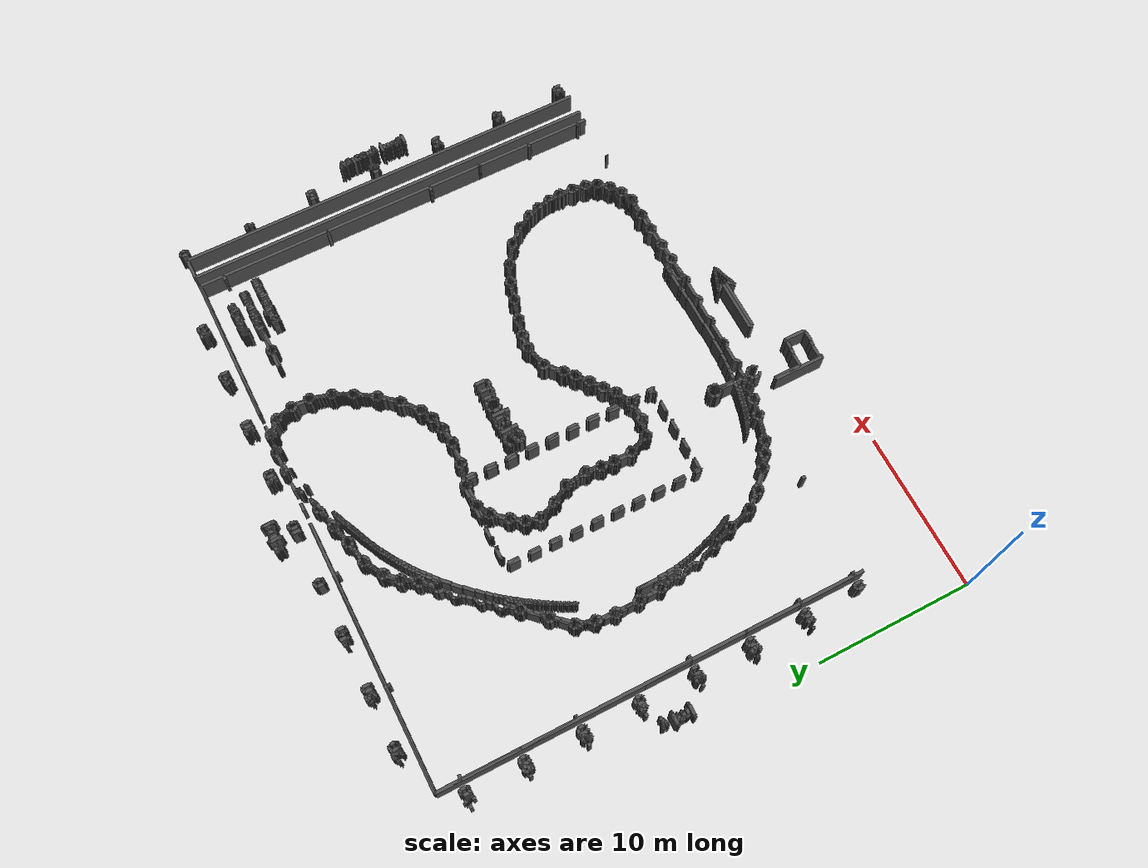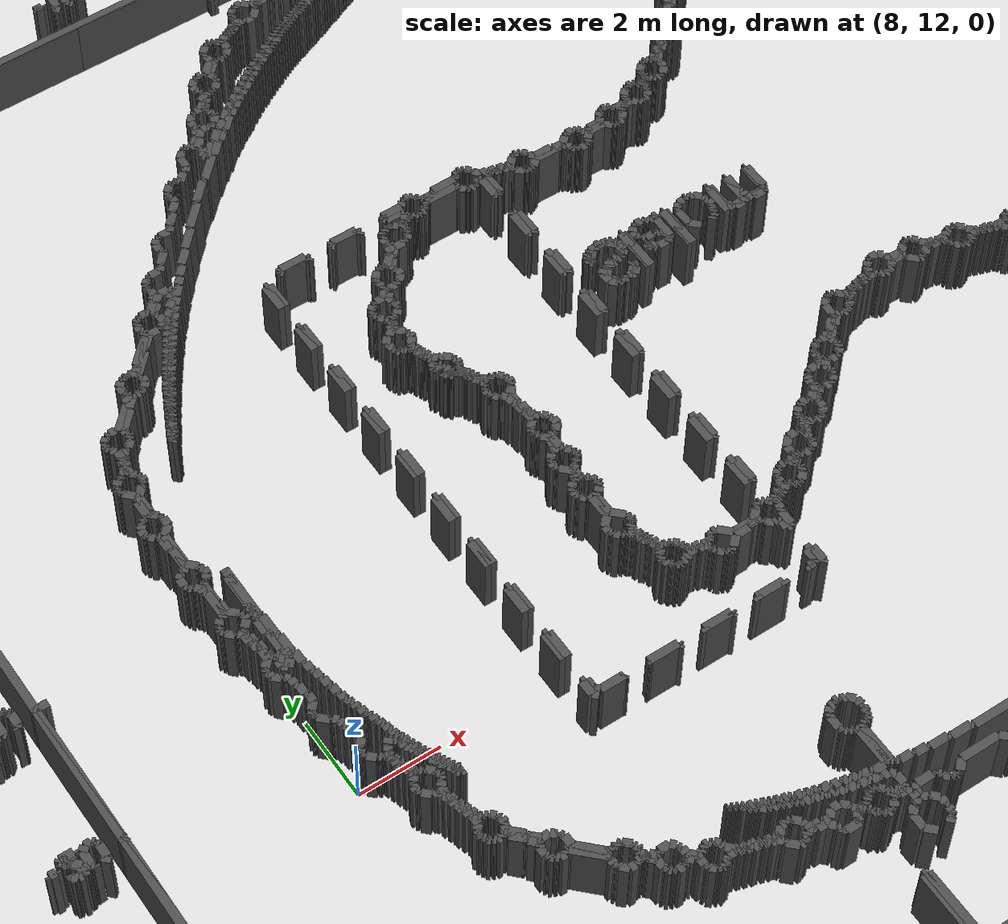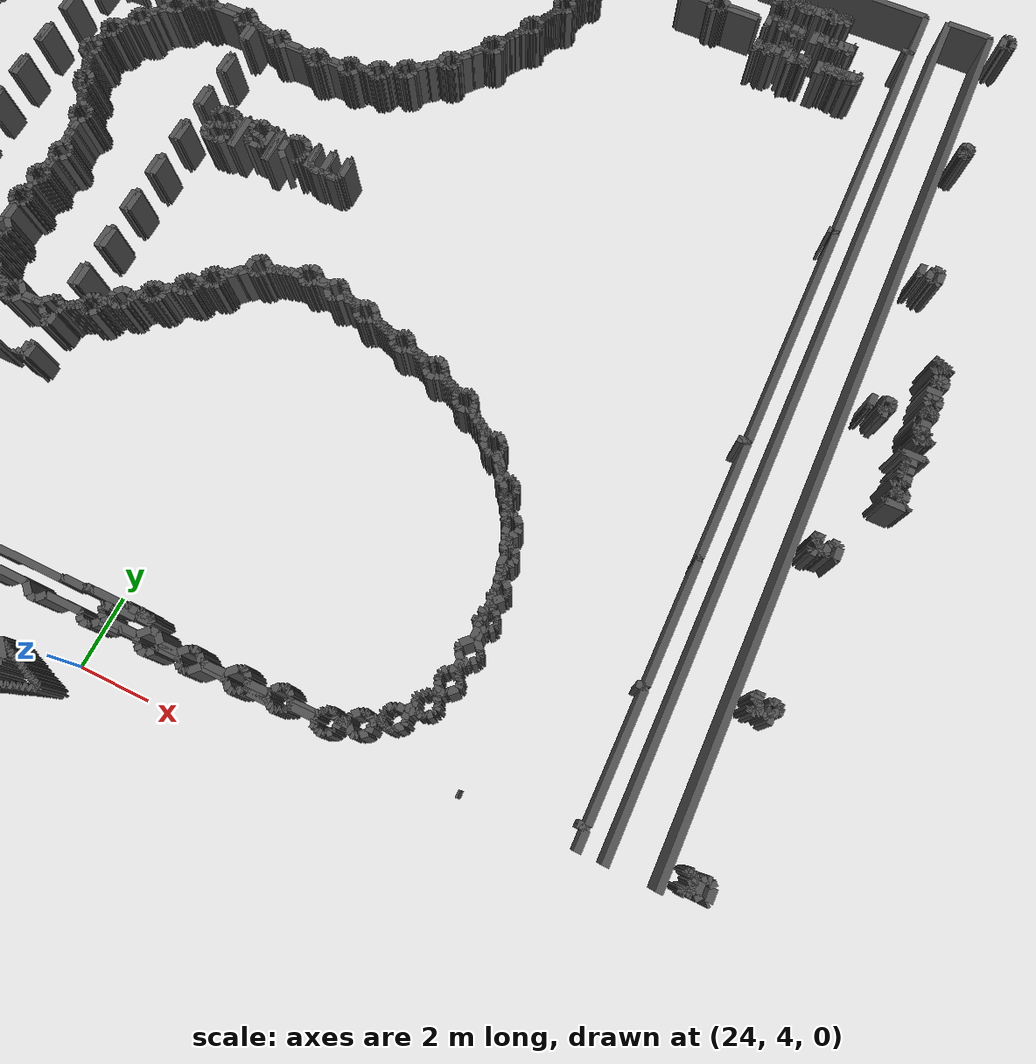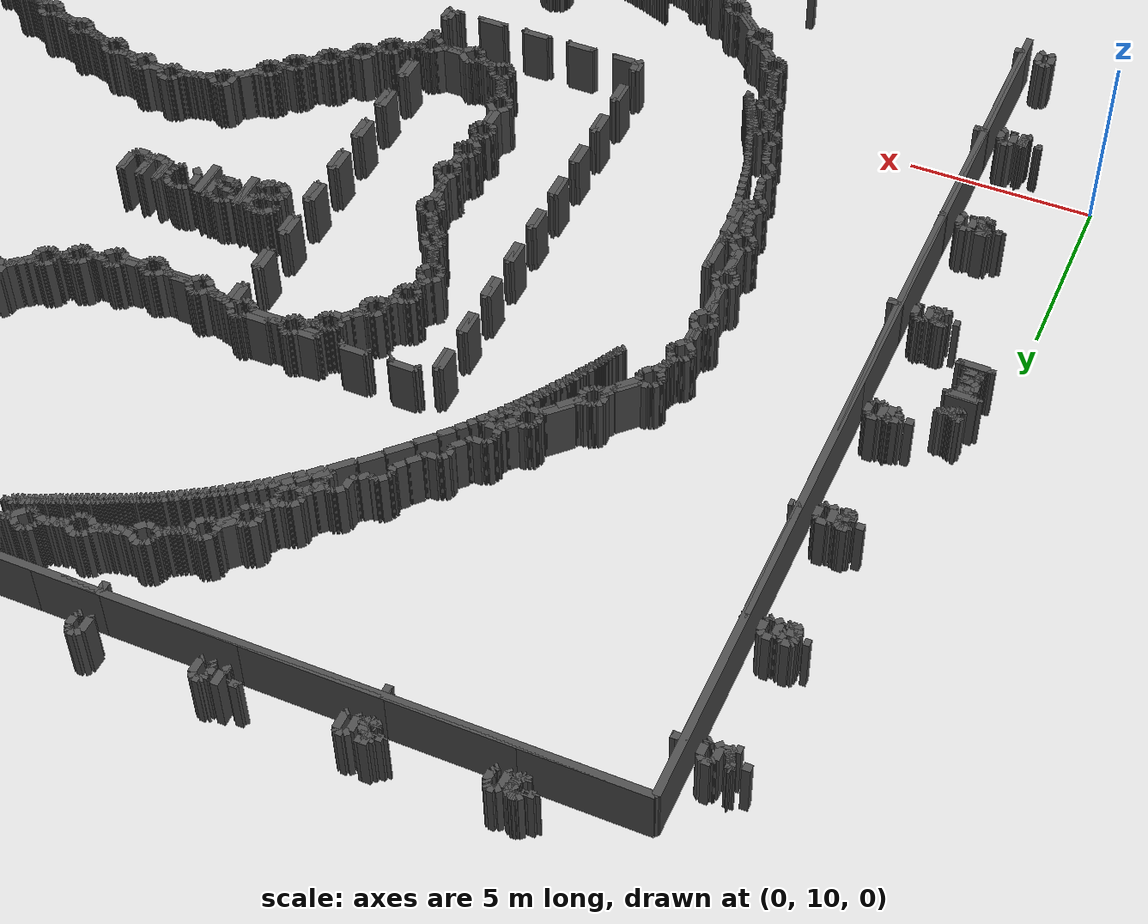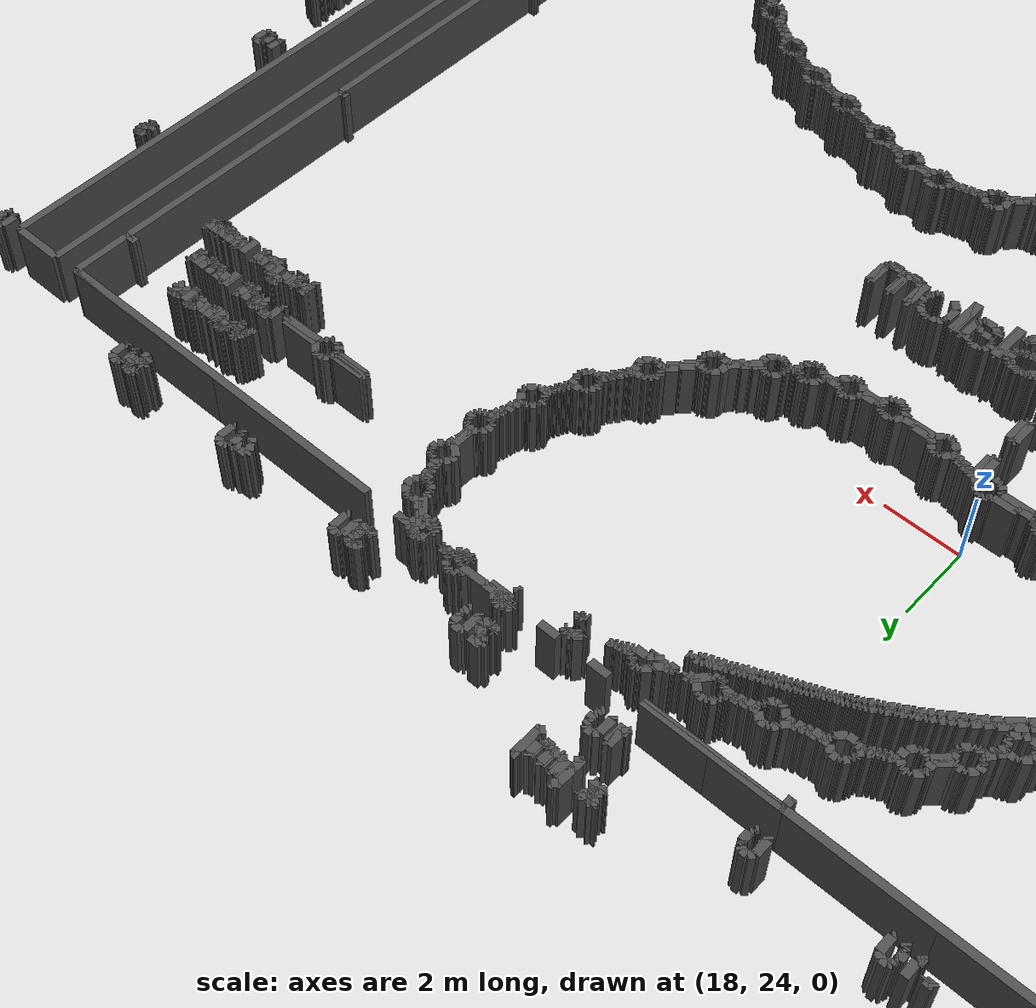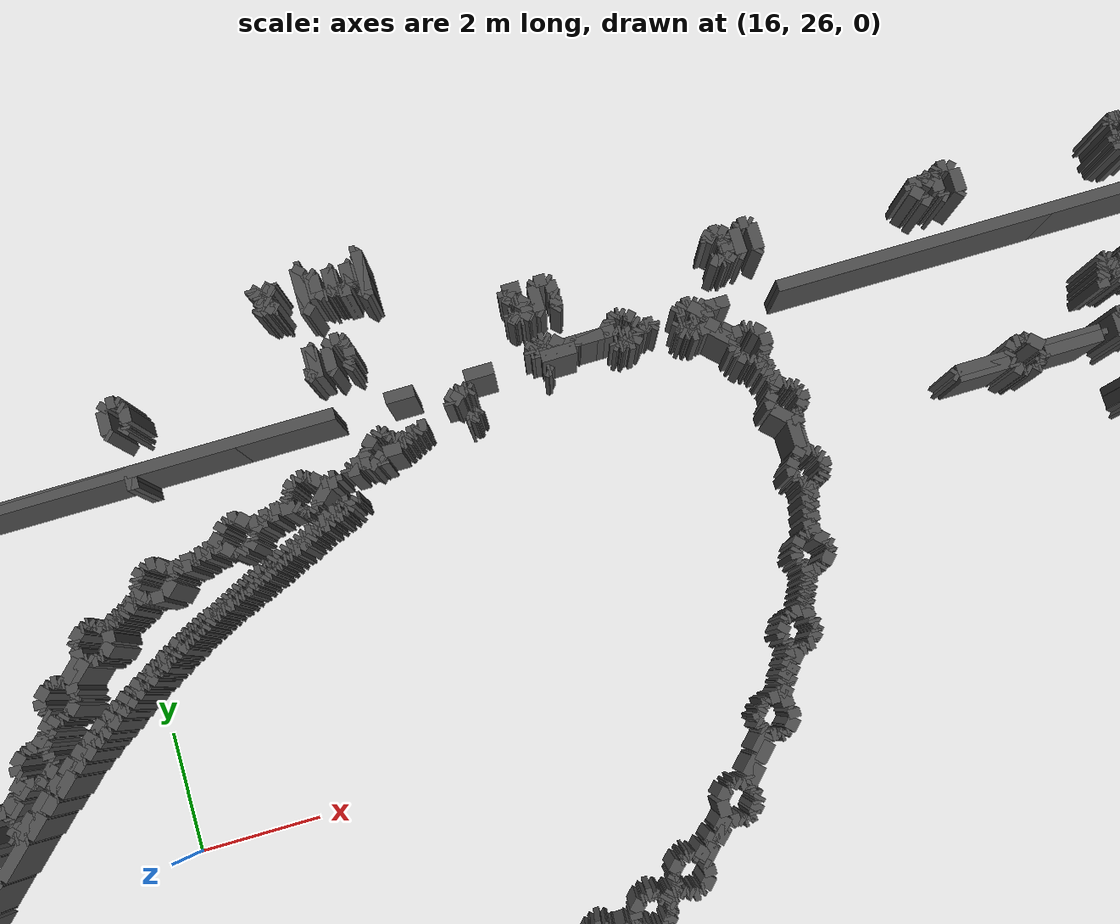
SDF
<sdf version="1.9">
 <model name="generated_walls">
  <static>true</static>
  <link name="wall_0_0">
   <pose>20.350 34.375 0.75 0 0 1.571</pose>
   <collision name="collision"><geometry><box><size>0.450 0.2 1.5</size></box></geometry></collision>
   <visual name="visual">
    <geometry><box><size>0.450 0.2 1.5</size></box></geometry>
    <material><ambient>0.3 0.3 0.3 1</ambient></material>
   </visual>
  </link>
  <link name="wall_0_1">
   <pose>20.375 34.575 0.75 0 0 -0.785</pose>
   <collision name="collision"><geometry><box><size>0.071 0.2 1.5</size></box></geometry></collision>
   <visual name="visual">
    <geometry><box><size>0.071 0.2 1.5</size></box></geometry>
    <material><ambient>0.3 0.3 0.3 1</ambient></material>
   </visual>
  </link>
  <link name="wall_0_2">
   <pose>20.400 34.400 0.75 0 0 -1.571</pose>
   <collision name="collision"><geometry><box><size>0.300 0.2 1.5</size></box></geometry></collision>
   <visual name="visual">
    <geometry><box><size>0.300 0.2 1.5</size></box></geometry>
    <material><ambient>0.3 0.3 0.3 1</ambient></material>
   </visual>
  </link>
  <link name="wall_0_3">
   <pose>20.450 34.200 0.75 0 0 -0.785</pose>
   <collision name="collision"><geometry><box><size>0.141 0.2 1.5</size></box></geometry></collision>
   <visual name="visual">
    <geometry><box><size>0.141 0.2 1.5</size></box></geometry>
    <material><ambient>0.3 0.3 0.3 1</ambient></material>
   </visual>
  </link>
  <link name="wall_0_4">
   <pose>20.525 34.150 0.75 0 0 0.000</pose>
   <collision name="collision"><geometry><box><size>0.050 0.2 1.5</size></box></geometry></collision>
   <visual name="visual">
    <geometry><box><size>0.050 0.2 1.5</size></box></geometry>
    <material><ambient>0.3 0.3 0.3 1</ambient></material>
   </visual>
  </link>
  <link name="wall_0_5">
   <pose>20.600 34.200 0.75 0 0 0.785</pose>
   <collision name="collision"><geometry><box><size>0.141 0.2 1.5</size></box></geometry></collision>
   <visual name="visual">
    <geometry><box><size>0.141 0.2 1.5</size></box></geometry>
    <material><ambient>0.3 0.3 0.3 1</ambient></material>
   </visual>
  </link>
  <link name="wall_0_6">
   <pose>20.650 34.425 0.75 0 0 1.571</pose>
   <collision name="collision"><geometry><box><size>0.350 0.2 1.5</size></box></geometry></collision>
   <visual name="visual">
    <geometry><box><size>0.350 0.2 1.5</size></box></geometry>
    <material><ambient>0.3 0.3 0.3 1</ambient></material>
   </visual>
  </link>
  <link name="wall_0_7">
   <pose>20.675 34.575 0.75 0 0 -0.785</pose>
   <collision name="collision"><geometry><box><size>0.071 0.2 1.5</size></box></geometry></collision>
   <visual name="visual">
    <geometry><box><size>0.071 0.2 1.5</size></box></geometry>
    <material><ambient>0.3 0.3 0.3 1</ambient></material>
   </visual>
  </link>
  <link name="wall_0_8">
   <pose>20.700 34.400 0.75 0 0 -1.571</pose>
   <collision name="collision"><geometry><box><size>0.300 0.2 1.5</size></box></geometry></collision>
   <visual name="visual">
    <geometry><box><size>0.300 0.2 1.5</size></box></geometry>
    <material><ambient>0.3 0.3 0.3 1</ambient></material>
   </visual>
  </link>
  <link name="wall_0_9">
   <pose>20.750 34.200 0.75 0 0 -0.785</pose>
   <collision name="collision"><geometry><box><size>0.141 0.2 1.5</size></box></geometry></collision>
   <visual name="visual">
    <geometry><box><size>0.141 0.2 1.5</size></box></geometry>
    <material><ambient>0.3 0.3 0.3 1</ambient></material>
   </visual>
  </link>
  <link name="wall_0_10">
   <pose>20.825 34.150 0.75 0 0 0.000</pose>
   <collision name="collision"><geometry><box><size>0.050 0.2 1.5</size></box></geometry></collision>
   <visual name="visual">
    <geometry><box><size>0.050 0.2 1.5</size></box></geometry>
    <material><ambient>0.3 0.3 0.3 1</ambient></material>
   </visual>
  </link>
  <link name="wall_0_11">
   <pose>20.900 34.200 0.75 0 0 0.785</pose>
   <collision name="collision"><geometry><box><size>0.141 0.2 1.5</size></box></geometry></collision>
   <visual name="visual">
    <geometry><box><size>0.141 0.2 1.5</size></box></geometry>
    <material><ambient>0.3 0.3 0.3 1</ambient></material>
   </visual>
  </link>
  <link name="wall_0_12">
   <pose>20.950 34.425 0.75 0 0 1.571</pose>
   <collision name="collision"><geometry><box><size>0.350 0.2 1.5</size></box></geometry></collision>
   <visual name="visual">
    <geometry><box><size>0.350 0.2 1.5</size></box></geometry>
    <material><ambient>0.3 0.3 0.3 1</ambient></material>
   </visual>
  </link>
  <link name="wall_0_13">
   <pose>20.975 34.575 0.75 0 0 -0.785</pose>
   <collision name="collision"><geometry><box><size>0.071 0.2 1.5</size></box></geometry></collision>
   <visual name="visual">
    <geometry><box><size>0.071 0.2 1.5</size></box></geometry>
    <material><ambient>0.3 0.3 0.3 1</ambient></material>
   </visual>
  </link>
  <link name="wall_0_14">
   <pose>21.000 34.400 0.75 0 0 -1.571</pose>
   <collision name="collision"><geometry><box><size>0.300 0.2 1.5</size></box></geometry></collision>
   <visual name="visual">
    <geometry><box><size>0.300 0.2 1.5</size></box></geometry>
    <material><ambient>0.3 0.3 0.3 1</ambient></material>
   </visual>
  </link>
  <link name="wall_0_15">
   <pose>20.975 34.225 0.75 0 0 -2.356</pose>
   <collision name="collision"><geometry><box><size>0.071 0.2 1.5</size></box></geometry></collision>
   <visual name="visual">
    <geometry><box><size>0.071 0.2 1.5</size></box></geometry>
    <material><ambient>0.3 0.3 0.3 1</ambient></material>
   </visual>
  </link>
  <link name="wall_0_16">
   <pose>20.950 34.175 0.75 0 0 -1.571</pose>
   <collision name="collision"><geometry><box><size>0.050 0.2 1.5</size></box></geometry></collision>
   <visual name="visual">
    <geometry><box><size>0.050 0.2 1.5</size></box></geometry>
    <material><ambient>0.3 0.3 0.3 1</ambient></material>
   </visual>
  </link>
  <link name="wall_0_17">
   <pose>20.850 34.150 0.75 0 0 3.142</pose>
   <collision name="collision"><geometry><box><size>0.200 0.2 1.5</size></box></geometry></collision>
   <visual name="visual">
    <geometry><box><size>0.200 0.2 1.5</size></box></geometry>
    <material><ambient>0.3 0.3 0.3 1</ambient></material>
   </visual>
  </link>
  <link name="wall_0_18">
   <pose>20.725 34.175 0.75 0 0 2.356</pose>
   <collision name="collision"><geometry><box><size>0.071 0.2 1.5</size></box></geometry></collision>
   <visual name="visual">
    <geometry><box><size>0.071 0.2 1.5</size></box></geometry>
    <material><ambient>0.3 0.3 0.3 1</ambient></material>
   </visual>
  </link>
  <link name="wall_0_19">
   <pose>20.675 34.200 0.75 0 0 3.142</pose>
   <collision name="collision"><geometry><box><size>0.050 0.2 1.5</size></box></geometry></collision>
   <visual name="visual">
    <geometry><box><size>0.050 0.2 1.5</size></box></geometry>
    <material><ambient>0.3 0.3 0.3 1</ambient></material>
   </visual>
  </link>
  <link name="wall_0_20">
   <pose>20.625 34.175 0.75 0 0 -2.356</pose>
   <collision name="collision"><geometry><box><size>0.071 0.2 1.5</size></box></geometry></collision>
   <visual name="visual">
    <geometry><box><size>0.071 0.2 1.5</size></box></geometry>
    <material><ambient>0.3 0.3 0.3 1</ambient></material>
   </visual>
  </link>
  <link name="wall_1_0">
   <pose>19.375 34.175 0.75 0 0 0.785</pose>
   <collision name="collision"><geometry><box><size>0.071 0.2 1.5</size></box></geometry></collision>
   <visual name="visual">
    <geometry><box><size>0.071 0.2 1.5</size></box></geometry>
    <material><ambient>0.3 0.3 0.3 1</ambient></material>
   </visual>
  </link>
  <link name="wall_1_1">
   <pose>19.400 34.225 0.75 0 0 1.571</pose>
   <collision name="collision"><geometry><box><size>0.050 0.2 1.5</size></box></geometry></collision>
   <visual name="visual">
    <geometry><box><size>0.050 0.2 1.5</size></box></geometry>
    <material><ambient>0.3 0.3 0.3 1</ambient></material>
   </visual>
  </link>
  <link name="wall_1_2">
   <pose>19.450 34.300 0.75 0 0 0.785</pose>
   <collision name="collision"><geometry><box><size>0.141 0.2 1.5</size></box></geometry></collision>
   <visual name="visual">
    <geometry><box><size>0.141 0.2 1.5</size></box></geometry>
    <material><ambient>0.3 0.3 0.3 1</ambient></material>
   </visual>
  </link>
  <link name="wall_1_3">
   <pose>19.475 34.375 0.75 0 0 2.356</pose>
   <collision name="collision"><geometry><box><size>0.071 0.2 1.5</size></box></geometry></collision>
   <visual name="visual">
    <geometry><box><size>0.071 0.2 1.5</size></box></geometry>
    <material><ambient>0.3 0.3 0.3 1</ambient></material>
   </visual>
  </link>
  <link name="wall_1_4">
   <pose>19.450 34.425 0.75 0 0 1.571</pose>
   <collision name="collision"><geometry><box><size>0.050 0.2 1.5</size></box></geometry></collision>
   <visual name="visual">
    <geometry><box><size>0.050 0.2 1.5</size></box></geometry>
    <material><ambient>0.3 0.3 0.3 1</ambient></material>
   </visual>
  </link>
  <link name="wall_1_5">
   <pose>19.400 34.500 0.75 0 0 2.356</pose>
   <collision name="collision"><geometry><box><size>0.141 0.2 1.5</size></box></geometry></collision>
   <visual name="visual">
    <geometry><box><size>0.141 0.2 1.5</size></box></geometry>
    <material><ambient>0.3 0.3 0.3 1</ambient></material>
   </visual>
  </link>
  <link name="wall_1_6">
   <pose>19.350 34.575 0.75 0 0 1.571</pose>
   <collision name="collision"><geometry><box><size>0.050 0.2 1.5</size></box></geometry></collision>
   <visual name="visual">
    <geometry><box><size>0.050 0.2 1.5</size></box></geometry>
    <material><ambient>0.3 0.3 0.3 1</ambient></material>
   </visual>
  </link>
  <link name="wall_1_7">
   <pose>19.425 34.525 0.75 0 0 -0.785</pose>
   <collision name="collision"><geometry><box><size>0.212 0.2 1.5</size></box></geometry></collision>
   <visual name="visual">
    <geometry><box><size>0.212 0.2 1.5</size></box></geometry>
    <material><ambient>0.3 0.3 0.3 1</ambient></material>
   </visual>
  </link>
  <link name="wall_1_8">
   <pose>19.525 34.450 0.75 0 0 0.000</pose>
   <collision name="collision"><geometry><box><size>0.050 0.2 1.5</size></box></geometry></collision>
   <visual name="visual">
    <geometry><box><size>0.050 0.2 1.5</size></box></geometry>
    <material><ambient>0.3 0.3 0.3 1</ambient></material>
   </visual>
  </link>
  <link name="wall_1_9">
   <pose>19.625 34.525 0.75 0 0 0.785</pose>
   <collision name="collision"><geometry><box><size>0.212 0.2 1.5</size></box></geometry></collision>
   <visual name="visual">
    <geometry><box><size>0.212 0.2 1.5</size></box></geometry>
    <material><ambient>0.3 0.3 0.3 1</ambient></material>
   </visual>
  </link>
  <link name="wall_1_10">
   <pose>19.700 34.575 0.75 0 0 -1.571</pose>
   <collision name="collision"><geometry><box><size>0.050 0.2 1.5</size></box></geometry></collision>
   <visual name="visual">
    <geometry><box><size>0.050 0.2 1.5</size></box></geometry>
    <material><ambient>0.3 0.3 0.3 1</ambient></material>
   </visual>
  </link>
  <link name="wall_1_11">
   <pose>19.650 34.500 0.75 0 0 -2.356</pose>
   <collision name="collision"><geometry><box><size>0.141 0.2 1.5</size></box></geometry></collision>
   <visual name="visual">
    <geometry><box><size>0.141 0.2 1.5</size></box></geometry>
    <material><ambient>0.3 0.3 0.3 1</ambient></material>
   </visual>
  </link>
  <link name="wall_1_12">
   <pose>19.600 34.425 0.75 0 0 -1.571</pose>
   <collision name="collision"><geometry><box><size>0.050 0.2 1.5</size></box></geometry></collision>
   <visual name="visual">
    <geometry><box><size>0.050 0.2 1.5</size></box></geometry>
    <material><ambient>0.3 0.3 0.3 1</ambient></material>
   </visual>
  </link>
  <link name="wall_1_13">
   <pose>19.575 34.375 0.75 0 0 -2.356</pose>
   <collision name="collision"><geometry><box><size>0.071 0.2 1.5</size></box></geometry></collision>
   <visual name="visual">
    <geometry><box><size>0.071 0.2 1.5</size></box></geometry>
    <material><ambient>0.3 0.3 0.3 1</ambient></material>
   </visual>
  </link>
  <link name="wall_1_14">
   <pose>19.575 34.325 0.75 0 0 -0.785</pose>
   <collision name="collision"><geometry><box><size>0.071 0.2 1.5</size></box></geometry></collision>
   <visual name="visual">
    <geometry><box><size>0.071 0.2 1.5</size></box></geometry>
    <material><ambient>0.3 0.3 0.3 1</ambient></material>
   </visual>
  </link>
  <link name="wall_1_15">
   <pose>19.600 34.275 0.75 0 0 -1.571</pose>
   <collision name="collision"><geometry><box><size>0.050 0.2 1.5</size></box></geometry></collision>
   <visual name="visual">
    <geometry><box><size>0.050 0.2 1.5</size></box></geometry>
    <material><ambient>0.3 0.3 0.3 1</ambient></material>
   </visual>
  </link>
  <link name="wall_1_16">
   <pose>19.650 34.200 0.75 0 0 -0.785</pose>
   <collision name="collision"><geometry><box><size>0.141 0.2 1.5</size></box></geometry></collision>
   <visual name="visual">
    <geometry><box><size>0.141 0.2 1.5</size></box></geometry>
    <material><ambient>0.3 0.3 0.3 1</ambient></material>
   </visual>
  </link>
  <link name="wall_1_17">
   <pose>19.675 34.150 0.75 0 0 3.142</pose>
   <collision name="collision"><geometry><box><size>0.050 0.2 1.5</size></box></geometry></collision>
   <visual name="visual">
    <geometry><box><size>0.050 0.2 1.5</size></box></geometry>
    <material><ambient>0.3 0.3 0.3 1</ambient></material>
   </visual>
  </link>
  <link name="wall_1_18">
   <pose>19.600 34.200 0.75 0 0 2.356</pose>
   <collision name="collision"><geometry><box><size>0.141 0.2 1.5</size></box></geometry></collision>
   <visual name="visual">
    <geometry><box><size>0.141 0.2 1.5</size></box></geometry>
    <material><ambient>0.3 0.3 0.3 1</ambient></material>
   </visual>
  </link>
  <link name="wall_1_19">
   <pose>19.525 34.250 0.75 0 0 3.142</pose>
   <collision name="collision"><geometry><box><size>0.050 0.2 1.5</size></box></geometry></collision>
   <visual name="visual">
    <geometry><box><size>0.050 0.2 1.5</size></box></geometry>
    <material><ambient>0.3 0.3 0.3 1</ambient></material>
   </visual>
  </link>
  <link name="wall_1_20">
   <pose>19.450 34.200 0.75 0 0 -2.356</pose>
   <collision name="collision"><geometry><box><size>0.141 0.2 1.5</size></box></geometry></collision>
   <visual name="visual">
    <geometry><box><size>0.141 0.2 1.5</size></box></geometry>
    <material><ambient>0.3 0.3 0.3 1</ambient></material>
   </visual>
  </link>
  <link name="wall_2_0">
   <pose>21.150 34.000 0.75 0 0 0.785</pose>
   <collision name="collision"><geometry><box><size>0.141 0.2 1.5</size></box></geometry></collision>
   <visual name="visual">
    <geometry><box><size>0.141 0.2 1.5</size></box></geometry>
    <material><ambient>0.3 0.3 0.3 1</ambient></material>
   </visual>
  </link>
  <link name="wall_2_1">
   <pose>21.200 34.375 0.75 0 0 1.571</pose>
   <collision name="collision"><geometry><box><size>0.650 0.2 1.5</size></box></geometry></collision>
   <visual name="visual">
    <geometry><box><size>0.650 0.2 1.5</size></box></geometry>
    <material><ambient>0.3 0.3 0.3 1</ambient></material>
   </visual>
  </link>
  <link name="wall_2_2">
   <pose>21.175 34.725 0.75 0 0 2.356</pose>
   <collision name="collision"><geometry><box><size>0.071 0.2 1.5</size></box></geometry></collision>
   <visual name="visual">
    <geometry><box><size>0.071 0.2 1.5</size></box></geometry>
    <material><ambient>0.3 0.3 0.3 1</ambient></material>
   </visual>
  </link>
  <link name="wall_2_3">
   <pose>21.125 34.750 0.75 0 0 3.142</pose>
   <collision name="collision"><geometry><box><size>0.050 0.2 1.5</size></box></geometry></collision>
   <visual name="visual">
    <geometry><box><size>0.050 0.2 1.5</size></box></geometry>
    <material><ambient>0.3 0.3 0.3 1</ambient></material>
   </visual>
  </link>
  <link name="wall_2_4">
   <pose>21.150 34.750 0.75 0 0 0.000</pose>
   <collision name="collision"><geometry><box><size>0.100 0.2 1.5</size></box></geometry></collision>
   <visual name="visual">
    <geometry><box><size>0.100 0.2 1.5</size></box></geometry>
    <material><ambient>0.3 0.3 0.3 1</ambient></material>
   </visual>
  </link>
  <link name="wall_2_5">
   <pose>21.200 34.350 0.75 0 0 -1.571</pose>
   <collision name="collision"><geometry><box><size>0.800 0.2 1.5</size></box></geometry></collision>
   <visual name="visual">
    <geometry><box><size>0.800 0.2 1.5</size></box></geometry>
    <material><ambient>0.3 0.3 0.3 1</ambient></material>
   </visual>
  </link>
  <link name="wall_3_0">
   <pose>20.150 34.350 0.75 0 0 1.571</pose>
   <collision name="collision"><geometry><box><size>0.800 0.2 1.5</size></box></geometry></collision>
   <visual name="visual">
    <geometry><box><size>0.800 0.2 1.5</size></box></geometry>
    <material><ambient>0.3 0.3 0.3 1</ambient></material>
   </visual>
  </link>
  <link name="wall_3_1">
   <pose>20.200 34.750 0.75 0 0 0.000</pose>
   <collision name="collision"><geometry><box><size>0.100 0.2 1.5</size></box></geometry></collision>
   <visual name="visual">
    <geometry><box><size>0.100 0.2 1.5</size></box></geometry>
    <material><ambient>0.3 0.3 0.3 1</ambient></material>
   </visual>
  </link>
  <link name="wall_3_2">
   <pose>20.200 34.700 0.75 0 0 -2.356</pose>
   <collision name="collision"><geometry><box><size>0.141 0.2 1.5</size></box></geometry></collision>
   <visual name="visual">
    <geometry><box><size>0.141 0.2 1.5</size></box></geometry>
    <material><ambient>0.3 0.3 0.3 1</ambient></material>
   </visual>
  </link>
  <link name="wall_3_3">
   <pose>20.150 34.350 0.75 0 0 -1.571</pose>
   <collision name="collision"><geometry><box><size>0.600 0.2 1.5</size></box></geometry></collision>
   <visual name="visual">
    <geometry><box><size>0.600 0.2 1.5</size></box></geometry>
    <material><ambient>0.3 0.3 0.3 1</ambient></material>
   </visual>
  </link>
  <link name="wall_3_4">
   <pose>20.200 34.000 0.75 0 0 -0.785</pose>
   <collision name="collision"><geometry><box><size>0.141 0.2 1.5</size></box></geometry></collision>
   <visual name="visual">
    <geometry><box><size>0.141 0.2 1.5</size></box></geometry>
    <material><ambient>0.3 0.3 0.3 1</ambient></material>
   </visual>
  </link>
  <link name="wall_4_0">
   <pose>12.625 33.175 0.75 0 0 2.356</pose>
   <collision name="collision"><geometry><box><size>0.071 0.2 1.5</size></box></geometry></collision>
   <visual name="visual">
    <geometry><box><size>0.071 0.2 1.5</size></box></geometry>
    <material><ambient>0.3 0.3 0.3 1</ambient></material>
   </visual>
  </link>
  <link name="wall_4_1">
   <pose>12.700 33.200 0.75 0 0 0.000</pose>
   <collision name="collision"><geometry><box><size>0.200 0.2 1.5</size></box></geometry></collision>
   <visual name="visual">
    <geometry><box><size>0.200 0.2 1.5</size></box></geometry>
    <material><ambient>0.3 0.3 0.3 1</ambient></material>
   </visual>
  </link>
  <link name="wall_4_2">
   <pose>12.800 33.175 0.75 0 0 -1.571</pose>
   <collision name="collision"><geometry><box><size>0.050 0.2 1.5</size></box></geometry></collision>
   <visual name="visual">
    <geometry><box><size>0.050 0.2 1.5</size></box></geometry>
    <material><ambient>0.3 0.3 0.3 1</ambient></material>
   </visual>
  </link>
  <link name="wall_5_0">
   <pose>9.100 33.175 0.75 0 0 1.571</pose>
   <collision name="collision"><geometry><box><size>0.050 0.2 1.5</size></box></geometry></collision>
   <visual name="visual">
    <geometry><box><size>0.050 0.2 1.5</size></box></geometry>
    <material><ambient>0.3 0.3 0.3 1</ambient></material>
   </visual>
  </link>
  <link name="wall_5_1">
   <pose>9.175 33.200 0.75 0 0 0.000</pose>
   <collision name="collision"><geometry><box><size>0.150 0.2 1.5</size></box></geometry></collision>
   <visual name="visual">
    <geometry><box><size>0.150 0.2 1.5</size></box></geometry>
    <material><ambient>0.3 0.3 0.3 1</ambient></material>
   </visual>
  </link>
  <link name="wall_5_2">
   <pose>9.250 33.175 0.75 0 0 -1.571</pose>
   <collision name="collision"><geometry><box><size>0.050 0.2 1.5</size></box></geometry></collision>
   <visual name="visual">
    <geometry><box><size>0.050 0.2 1.5</size></box></geometry>
    <material><ambient>0.3 0.3 0.3 1</ambient></material>
   </visual>
  </link>
  <link name="wall_6_0">
   <pose>5.550 33.175 0.75 0 0 1.571</pose>
   <collision name="collision"><geometry><box><size>0.050 0.2 1.5</size></box></geometry></collision>
   <visual name="visual">
    <geometry><box><size>0.050 0.2 1.5</size></box></geometry>
    <material><ambient>0.3 0.3 0.3 1</ambient></material>
   </visual>
  </link>
  <link name="wall_6_1">
   <pose>5.625 33.200 0.75 0 0 0.000</pose>
   <collision name="collision"><geometry><box><size>0.150 0.2 1.5</size></box></geometry></collision>
   <visual name="visual">
    <geometry><box><size>0.150 0.2 1.5</size></box></geometry>
    <material><ambient>0.3 0.3 0.3 1</ambient></material>
   </visual>
  </link>
  <link name="wall_6_2">
   <pose>5.700 33.175 0.75 0 0 -1.571</pose>
   <collision name="collision"><geometry><box><size>0.050 0.2 1.5</size></box></geometry></collision>
   <visual name="visual">
    <geometry><box><size>0.050 0.2 1.5</size></box></geometry>
    <material><ambient>0.3 0.3 0.3 1</ambient></material>
   </visual>
  </link>
  <link name="wall_7_0">
   <pose>34.475 32.875 0.75 0 0 2.356</pose>
   <collision name="collision"><geometry><box><size>0.071 0.2 1.5</size></box></geometry></collision>
   <visual name="visual">
    <geometry><box><size>0.071 0.2 1.5</size></box></geometry>
    <material><ambient>0.3 0.3 0.3 1</ambient></material>
   </visual>
  </link>
  <link name="wall_7_1">
   <pose>34.450 32.925 0.75 0 0 1.571</pose>
   <collision name="collision"><geometry><box><size>0.050 0.2 1.5</size></box></geometry></collision>
   <visual name="visual">
    <geometry><box><size>0.050 0.2 1.5</size></box></geometry>
    <material><ambient>0.3 0.3 0.3 1</ambient></material>
   </visual>
  </link>
  <link name="wall_7_2">
   <pose>34.425 32.975 0.75 0 0 2.356</pose>
   <collision name="collision"><geometry><box><size>0.071 0.2 1.5</size></box></geometry></collision>
   <visual name="visual">
    <geometry><box><size>0.071 0.2 1.5</size></box></geometry>
    <material><ambient>0.3 0.3 0.3 1</ambient></material>
   </visual>
  </link>
  <link name="wall_7_3">
   <pose>34.400 33.125 0.75 0 0 1.571</pose>
   <collision name="collision"><geometry><box><size>0.250 0.2 1.5</size></box></geometry></collision>
   <visual name="visual">
    <geometry><box><size>0.250 0.2 1.5</size></box></geometry>
    <material><ambient>0.3 0.3 0.3 1</ambient></material>
   </visual>
  </link>
  <link name="wall_7_4">
   <pose>34.425 33.275 0.75 0 0 0.785</pose>
   <collision name="collision"><geometry><box><size>0.071 0.2 1.5</size></box></geometry></collision>
   <visual name="visual">
    <geometry><box><size>0.071 0.2 1.5</size></box></geometry>
    <material><ambient>0.3 0.3 0.3 1</ambient></material>
   </visual>
  </link>
  <link name="wall_7_5">
   <pose>34.450 33.325 0.75 0 0 1.571</pose>
   <collision name="collision"><geometry><box><size>0.050 0.2 1.5</size></box></geometry></collision>
   <visual name="visual">
    <geometry><box><size>0.050 0.2 1.5</size></box></geometry>
    <material><ambient>0.3 0.3 0.3 1</ambient></material>
   </visual>
  </link>
  <link name="wall_7_6">
   <pose>34.475 33.375 0.75 0 0 0.785</pose>
   <collision name="collision"><geometry><box><size>0.071 0.2 1.5</size></box></geometry></collision>
   <visual name="visual">
    <geometry><box><size>0.071 0.2 1.5</size></box></geometry>
    <material><ambient>0.3 0.3 0.3 1</ambient></material>
   </visual>
  </link>
  <link name="wall_7_7">
   <pose>34.575 33.400 0.75 0 0 0.000</pose>
   <collision name="collision"><geometry><box><size>0.150 0.2 1.5</size></box></geometry></collision>
   <visual name="visual">
    <geometry><box><size>0.150 0.2 1.5</size></box></geometry>
    <material><ambient>0.3 0.3 0.3 1</ambient></material>
   </visual>
  </link>
  <link name="wall_7_8">
   <pose>34.700 33.350 0.75 0 0 -0.785</pose>
   <collision name="collision"><geometry><box><size>0.141 0.2 1.5</size></box></geometry></collision>
   <visual name="visual">
    <geometry><box><size>0.141 0.2 1.5</size></box></geometry>
    <material><ambient>0.3 0.3 0.3 1</ambient></material>
   </visual>
  </link>
  <link name="wall_7_9">
   <pose>34.750 33.125 0.75 0 0 -1.571</pose>
   <collision name="collision"><geometry><box><size>0.350 0.2 1.5</size></box></geometry></collision>
   <visual name="visual">
    <geometry><box><size>0.350 0.2 1.5</size></box></geometry>
    <material><ambient>0.3 0.3 0.3 1</ambient></material>
   </visual>
  </link>
  <link name="wall_7_10">
   <pose>34.725 32.925 0.75 0 0 -2.356</pose>
   <collision name="collision"><geometry><box><size>0.071 0.2 1.5</size></box></geometry></collision>
   <visual name="visual">
    <geometry><box><size>0.071 0.2 1.5</size></box></geometry>
    <material><ambient>0.3 0.3 0.3 1</ambient></material>
   </visual>
  </link>
  <link name="wall_7_11">
   <pose>34.700 32.875 0.75 0 0 -1.571</pose>
   <collision name="collision"><geometry><box><size>0.050 0.2 1.5</size></box></geometry></collision>
   <visual name="visual">
    <geometry><box><size>0.050 0.2 1.5</size></box></geometry>
    <material><ambient>0.3 0.3 0.3 1</ambient></material>
   </visual>
  </link>
  <link name="wall_8_0">
   <pose>34.000 32.900 0.75 0 0 1.571</pose>
   <collision name="collision"><geometry><box><size>0.100 0.2 1.5</size></box></geometry></collision>
   <visual name="visual">
    <geometry><box><size>0.100 0.2 1.5</size></box></geometry>
    <material><ambient>0.3 0.3 0.3 1</ambient></material>
   </visual>
  </link>
  <link name="wall_8_1">
   <pose>33.975 32.975 0.75 0 0 2.356</pose>
   <collision name="collision"><geometry><box><size>0.071 0.2 1.5</size></box></geometry></collision>
   <visual name="visual">
    <geometry><box><size>0.071 0.2 1.5</size></box></geometry>
    <material><ambient>0.3 0.3 0.3 1</ambient></material>
   </visual>
  </link>
  <link name="wall_8_2">
   <pose>33.950 33.050 0.75 0 0 1.571</pose>
   <collision name="collision"><geometry><box><size>0.100 0.2 1.5</size></box></geometry></collision>
   <visual name="visual">
    <geometry><box><size>0.100 0.2 1.5</size></box></geometry>
    <material><ambient>0.3 0.3 0.3 1</ambient></material>
   </visual>
  </link>
  <link name="wall_8_3">
   <pose>34.000 33.100 0.75 0 0 0.000</pose>
   <collision name="collision"><geometry><box><size>0.100 0.2 1.5</size></box></geometry></collision>
   <visual name="visual">
    <geometry><box><size>0.100 0.2 1.5</size></box></geometry>
    <material><ambient>0.3 0.3 0.3 1</ambient></material>
   </visual>
  </link>
  <link name="wall_8_4">
   <pose>34.075 33.075 0.75 0 0 -0.785</pose>
   <collision name="collision"><geometry><box><size>0.071 0.2 1.5</size></box></geometry></collision>
   <visual name="visual">
    <geometry><box><size>0.071 0.2 1.5</size></box></geometry>
    <material><ambient>0.3 0.3 0.3 1</ambient></material>
   </visual>
  </link>
  <link name="wall_8_5">
   <pose>34.125 33.050 0.75 0 0 0.000</pose>
   <collision name="collision"><geometry><box><size>0.050 0.2 1.5</size></box></geometry></collision>
   <visual name="visual">
    <geometry><box><size>0.050 0.2 1.5</size></box></geometry>
    <material><ambient>0.3 0.3 0.3 1</ambient></material>
   </visual>
  </link>
  <link name="wall_8_6">
   <pose>34.200 33.100 0.75 0 0 0.785</pose>
   <collision name="collision"><geometry><box><size>0.141 0.2 1.5</size></box></geometry></collision>
   <visual name="visual">
    <geometry><box><size>0.141 0.2 1.5</size></box></geometry>
    <material><ambient>0.3 0.3 0.3 1</ambient></material>
   </visual>
  </link>
  <link name="wall_8_7">
   <pose>34.250 33.225 0.75 0 0 1.571</pose>
   <collision name="collision"><geometry><box><size>0.150 0.2 1.5</size></box></geometry></collision>
   <visual name="visual">
    <geometry><box><size>0.150 0.2 1.5</size></box></geometry>
    <material><ambient>0.3 0.3 0.3 1</ambient></material>
   </visual>
  </link>
  <link name="wall_8_8">
   <pose>34.200 33.350 0.75 0 0 2.356</pose>
   <collision name="collision"><geometry><box><size>0.141 0.2 1.5</size></box></geometry></collision>
   <visual name="visual">
    <geometry><box><size>0.141 0.2 1.5</size></box></geometry>
    <material><ambient>0.3 0.3 0.3 1</ambient></material>
   </visual>
  </link>
  <link name="wall_8_9">
   <pose>34.125 33.400 0.75 0 0 3.142</pose>
   <collision name="collision"><geometry><box><size>0.050 0.2 1.5</size></box></geometry></collision>
   <visual name="visual">
    <geometry><box><size>0.050 0.2 1.5</size></box></geometry>
    <material><ambient>0.3 0.3 0.3 1</ambient></material>
   </visual>
  </link>
  <link name="wall_8_10">
   <pose>34.050 33.350 0.75 0 0 -2.356</pose>
   <collision name="collision"><geometry><box><size>0.141 0.2 1.5</size></box></geometry></collision>
   <visual name="visual">
    <geometry><box><size>0.141 0.2 1.5</size></box></geometry>
    <material><ambient>0.3 0.3 0.3 1</ambient></material>
   </visual>
  </link>
  <link name="wall_8_11">
   <pose>33.975 33.300 0.75 0 0 3.142</pose>
   <collision name="collision"><geometry><box><size>0.050 0.2 1.5</size></box></geometry></collision>
   <visual name="visual">
    <geometry><box><size>0.050 0.2 1.5</size></box></geometry>
    <material><ambient>0.3 0.3 0.3 1</ambient></material>
   </visual>
  </link>
  <link name="wall_8_12">
   <pose>33.950 33.325 0.75 0 0 1.571</pose>
   <collision name="collision"><geometry><box><size>0.050 0.2 1.5</size></box></geometry></collision>
   <visual name="visual">
    <geometry><box><size>0.050 0.2 1.5</size></box></geometry>
    <material><ambient>0.3 0.3 0.3 1</ambient></material>
   </visual>
  </link>
  <link name="wall_8_13">
   <pose>33.975 33.375 0.75 0 0 0.785</pose>
   <collision name="collision"><geometry><box><size>0.071 0.2 1.5</size></box></geometry></collision>
   <visual name="visual">
    <geometry><box><size>0.071 0.2 1.5</size></box></geometry>
    <material><ambient>0.3 0.3 0.3 1</ambient></material>
   </visual>
  </link>
  <link name="wall_8_14">
   <pose>34.100 33.400 0.75 0 0 0.000</pose>
   <collision name="collision"><geometry><box><size>0.200 0.2 1.5</size></box></geometry></collision>
   <visual name="visual">
    <geometry><box><size>0.200 0.2 1.5</size></box></geometry>
    <material><ambient>0.3 0.3 0.3 1</ambient></material>
   </visual>
  </link>
  <link name="wall_8_15">
   <pose>34.225 33.375 0.75 0 0 -0.785</pose>
   <collision name="collision"><geometry><box><size>0.071 0.2 1.5</size></box></geometry></collision>
   <visual name="visual">
    <geometry><box><size>0.071 0.2 1.5</size></box></geometry>
    <material><ambient>0.3 0.3 0.3 1</ambient></material>
   </visual>
  </link>
  <link name="wall_8_16">
   <pose>34.250 33.325 0.75 0 0 -1.571</pose>
   <collision name="collision"><geometry><box><size>0.050 0.2 1.5</size></box></geometry></collision>
   <visual name="visual">
    <geometry><box><size>0.050 0.2 1.5</size></box></geometry>
    <material><ambient>0.3 0.3 0.3 1</ambient></material>
   </visual>
  </link>
  <link name="wall_8_17">
   <pose>34.275 33.275 0.75 0 0 -0.785</pose>
   <collision name="collision"><geometry><box><size>0.071 0.2 1.5</size></box></geometry></collision>
   <visual name="visual">
    <geometry><box><size>0.071 0.2 1.5</size></box></geometry>
    <material><ambient>0.3 0.3 0.3 1</ambient></material>
   </visual>
  </link>
  <link name="wall_8_18">
   <pose>34.300 33.200 0.75 0 0 -1.571</pose>
   <collision name="collision"><geometry><box><size>0.100 0.2 1.5</size></box></geometry></collision>
   <visual name="visual">
    <geometry><box><size>0.100 0.2 1.5</size></box></geometry>
    <material><ambient>0.3 0.3 0.3 1</ambient></material>
   </visual>
  </link>
  <link name="wall_8_19">
   <pose>34.250 33.100 0.75 0 0 -2.356</pose>
   <collision name="collision"><geometry><box><size>0.141 0.2 1.5</size></box></geometry></collision>
   <visual name="visual">
    <geometry><box><size>0.141 0.2 1.5</size></box></geometry>
    <material><ambient>0.3 0.3 0.3 1</ambient></material>
   </visual>
  </link>
  <link name="wall_8_20">
   <pose>34.125 33.050 0.75 0 0 3.142</pose>
   <collision name="collision"><geometry><box><size>0.150 0.2 1.5</size></box></geometry></collision>
   <visual name="visual">
    <geometry><box><size>0.150 0.2 1.5</size></box></geometry>
    <material><ambient>0.3 0.3 0.3 1</ambient></material>
   </visual>
  </link>
  <link name="wall_8_21">
   <pose>34.025 33.025 0.75 0 0 -2.356</pose>
   <collision name="collision"><geometry><box><size>0.071 0.2 1.5</size></box></geometry></collision>
   <visual name="visual">
    <geometry><box><size>0.071 0.2 1.5</size></box></geometry>
    <material><ambient>0.3 0.3 0.3 1</ambient></material>
   </visual>
  </link>
  <link name="wall_8_22">
   <pose>34.000 32.975 0.75 0 0 -1.571</pose>
   <collision name="collision"><geometry><box><size>0.050 0.2 1.5</size></box></geometry></collision>
   <visual name="visual">
    <geometry><box><size>0.050 0.2 1.5</size></box></geometry>
    <material><ambient>0.3 0.3 0.3 1</ambient></material>
   </visual>
  </link>
  <link name="wall_8_23">
   <pose>34.050 32.900 0.75 0 0 -0.785</pose>
   <collision name="collision"><geometry><box><size>0.141 0.2 1.5</size></box></geometry></collision>
   <visual name="visual">
    <geometry><box><size>0.141 0.2 1.5</size></box></geometry>
    <material><ambient>0.3 0.3 0.3 1</ambient></material>
   </visual>
  </link>
  <link name="wall_8_24">
   <pose>34.175 32.850 0.75 0 0 0.000</pose>
   <collision name="collision"><geometry><box><size>0.150 0.2 1.5</size></box></geometry></collision>
   <visual name="visual">
    <geometry><box><size>0.150 0.2 1.5</size></box></geometry>
    <material><ambient>0.3 0.3 0.3 1</ambient></material>
   </visual>
  </link>
  <link name="wall_9_0">
   <pose>30.925 32.875 0.75 0 0 2.356</pose>
   <collision name="collision"><geometry><box><size>0.071 0.2 1.5</size></box></geometry></collision>
   <visual name="visual">
    <geometry><box><size>0.071 0.2 1.5</size></box></geometry>
    <material><ambient>0.3 0.3 0.3 1</ambient></material>
   </visual>
  </link>
  <link name="wall_9_1">
   <pose>30.900 32.925 0.75 0 0 1.571</pose>
   <collision name="collision"><geometry><box><size>0.050 0.2 1.5</size></box></geometry></collision>
   <visual name="visual">
    <geometry><box><size>0.050 0.2 1.5</size></box></geometry>
    <material><ambient>0.3 0.3 0.3 1</ambient></material>
   </visual>
  </link>
  <link name="wall_9_2">
   <pose>30.875 32.975 0.75 0 0 2.356</pose>
   <collision name="collision"><geometry><box><size>0.071 0.2 1.5</size></box></geometry></collision>
   <visual name="visual">
    <geometry><box><size>0.071 0.2 1.5</size></box></geometry>
    <material><ambient>0.3 0.3 0.3 1</ambient></material>
   </visual>
  </link>
  <link name="wall_9_3">
   <pose>30.850 33.125 0.75 0 0 1.571</pose>
   <collision name="collision"><geometry><box><size>0.250 0.2 1.5</size></box></geometry></collision>
   <visual name="visual">
    <geometry><box><size>0.250 0.2 1.5</size></box></geometry>
    <material><ambient>0.3 0.3 0.3 1</ambient></material>
   </visual>
  </link>
  <link name="wall_9_4">
   <pose>30.875 33.275 0.75 0 0 0.785</pose>
   <collision name="collision"><geometry><box><size>0.071 0.2 1.5</size></box></geometry></collision>
   <visual name="visual">
    <geometry><box><size>0.071 0.2 1.5</size></box></geometry>
    <material><ambient>0.3 0.3 0.3 1</ambient></material>
   </visual>
  </link>
  <link name="wall_9_5">
   <pose>30.900 33.325 0.75 0 0 1.571</pose>
   <collision name="collision"><geometry><box><size>0.050 0.2 1.5</size></box></geometry></collision>
   <visual name="visual">
    <geometry><box><size>0.050 0.2 1.5</size></box></geometry>
    <material><ambient>0.3 0.3 0.3 1</ambient></material>
   </visual>
  </link>
  <link name="wall_9_6">
   <pose>30.925 33.375 0.75 0 0 0.785</pose>
   <collision name="collision"><geometry><box><size>0.071 0.2 1.5</size></box></geometry></collision>
   <visual name="visual">
    <geometry><box><size>0.071 0.2 1.5</size></box></geometry>
    <material><ambient>0.3 0.3 0.3 1</ambient></material>
   </visual>
  </link>
  <link name="wall_9_7">
   <pose>31.025 33.400 0.75 0 0 0.000</pose>
   <collision name="collision"><geometry><box><size>0.150 0.2 1.5</size></box></geometry></collision>
   <visual name="visual">
    <geometry><box><size>0.150 0.2 1.5</size></box></geometry>
    <material><ambient>0.3 0.3 0.3 1</ambient></material>
   </visual>
  </link>
  <link name="wall_9_8">
   <pose>31.150 33.350 0.75 0 0 -0.785</pose>
   <collision name="collision"><geometry><box><size>0.141 0.2 1.5</size></box></geometry></collision>
   <visual name="visual">
    <geometry><box><size>0.141 0.2 1.5</size></box></geometry>
    <material><ambient>0.3 0.3 0.3 1</ambient></material>
   </visual>
  </link>
  <link name="wall_9_9">
   <pose>31.200 33.100 0.75 0 0 -1.571</pose>
   <collision name="collision"><geometry><box><size>0.400 0.2 1.5</size></box></geometry></collision>
   <visual name="visual">
    <geometry><box><size>0.400 0.2 1.5</size></box></geometry>
    <material><ambient>0.3 0.3 0.3 1</ambient></material>
   </visual>
  </link>
  <link name="wall_9_10">
   <pose>31.175 32.875 0.75 0 0 -2.356</pose>
   <collision name="collision"><geometry><box><size>0.071 0.2 1.5</size></box></geometry></collision>
   <visual name="visual">
    <geometry><box><size>0.071 0.2 1.5</size></box></geometry>
    <material><ambient>0.3 0.3 0.3 1</ambient></material>
   </visual>
  </link>
  <link name="wall_10_0">
   <pose>30.600 32.900 0.75 0 0 2.356</pose>
   <collision name="collision"><geometry><box><size>0.141 0.2 1.5</size></box></geometry></collision>
   <visual name="visual">
    <geometry><box><size>0.141 0.2 1.5</size></box></geometry>
    <material><ambient>0.3 0.3 0.3 1</ambient></material>
   </visual>
  </link>
  <link name="wall_10_1">
   <pose>30.550 32.975 0.75 0 0 1.571</pose>
   <collision name="collision"><geometry><box><size>0.050 0.2 1.5</size></box></geometry></collision>
   <visual name="visual">
    <geometry><box><size>0.050 0.2 1.5</size></box></geometry>
    <material><ambient>0.3 0.3 0.3 1</ambient></material>
   </visual>
  </link>
  <link name="wall_10_2">
   <pose>30.475 33.075 0.75 0 0 2.356</pose>
   <collision name="collision"><geometry><box><size>0.212 0.2 1.5</size></box></geometry></collision>
   <visual name="visual">
    <geometry><box><size>0.212 0.2 1.5</size></box></geometry>
    <material><ambient>0.3 0.3 0.3 1</ambient></material>
   </visual>
  </link>
  <link name="wall_10_3">
   <pose>30.400 33.200 0.75 0 0 1.571</pose>
   <collision name="collision"><geometry><box><size>0.100 0.2 1.5</size></box></geometry></collision>
   <visual name="visual">
    <geometry><box><size>0.100 0.2 1.5</size></box></geometry>
    <material><ambient>0.3 0.3 0.3 1</ambient></material>
   </visual>
  </link>
  <link name="wall_10_4">
   <pose>30.500 33.250 0.75 0 0 0.000</pose>
   <collision name="collision"><geometry><box><size>0.200 0.2 1.5</size></box></geometry></collision>
   <visual name="visual">
    <geometry><box><size>0.200 0.2 1.5</size></box></geometry>
    <material><ambient>0.3 0.3 0.3 1</ambient></material>
   </visual>
  </link>
  <link name="wall_10_5">
   <pose>30.625 33.275 0.75 0 0 0.785</pose>
   <collision name="collision"><geometry><box><size>0.071 0.2 1.5</size></box></geometry></collision>
   <visual name="visual">
    <geometry><box><size>0.071 0.2 1.5</size></box></geometry>
    <material><ambient>0.3 0.3 0.3 1</ambient></material>
   </visual>
  </link>
  <link name="wall_10_6">
   <pose>30.650 33.325 0.75 0 0 1.571</pose>
   <collision name="collision"><geometry><box><size>0.050 0.2 1.5</size></box></geometry></collision>
   <visual name="visual">
    <geometry><box><size>0.050 0.2 1.5</size></box></geometry>
    <material><ambient>0.3 0.3 0.3 1</ambient></material>
   </visual>
  </link>
  <link name="wall_10_7">
   <pose>30.700 33.300 0.75 0 0 -0.785</pose>
   <collision name="collision"><geometry><box><size>0.141 0.2 1.5</size></box></geometry></collision>
   <visual name="visual">
    <geometry><box><size>0.141 0.2 1.5</size></box></geometry>
    <material><ambient>0.3 0.3 0.3 1</ambient></material>
   </visual>
  </link>
  <link name="wall_10_8">
   <pose>30.700 33.200 0.75 0 0 -2.356</pose>
   <collision name="collision"><geometry><box><size>0.141 0.2 1.5</size></box></geometry></collision>
   <visual name="visual">
    <geometry><box><size>0.141 0.2 1.5</size></box></geometry>
    <material><ambient>0.3 0.3 0.3 1</ambient></material>
   </visual>
  </link>
  <link name="wall_11_0">
   <pose>27.375 32.875 0.75 0 0 2.356</pose>
   <collision name="collision"><geometry><box><size>0.071 0.2 1.5</size></box></geometry></collision>
   <visual name="visual">
    <geometry><box><size>0.071 0.2 1.5</size></box></geometry>
    <material><ambient>0.3 0.3 0.3 1</ambient></material>
   </visual>
  </link>
  <link name="wall_11_1">
   <pose>27.350 33.125 0.75 0 0 1.571</pose>
   <collision name="collision"><geometry><box><size>0.450 0.2 1.5</size></box></geometry></collision>
   <visual name="visual">
    <geometry><box><size>0.450 0.2 1.5</size></box></geometry>
    <material><ambient>0.3 0.3 0.3 1</ambient></material>
   </visual>
  </link>
  <link name="wall_11_2">
   <pose>27.375 33.350 0.75 0 0 0.000</pose>
   <collision name="collision"><geometry><box><size>0.050 0.2 1.5</size></box></geometry></collision>
   <visual name="visual">
    <geometry><box><size>0.050 0.2 1.5</size></box></geometry>
    <material><ambient>0.3 0.3 0.3 1</ambient></material>
   </visual>
  </link>
  <link name="wall_11_3">
   <pose>27.425 33.375 0.75 0 0 0.785</pose>
   <collision name="collision"><geometry><box><size>0.071 0.2 1.5</size></box></geometry></collision>
   <visual name="visual">
    <geometry><box><size>0.071 0.2 1.5</size></box></geometry>
    <material><ambient>0.3 0.3 0.3 1</ambient></material>
   </visual>
  </link>
  <link name="wall_11_4">
   <pose>27.525 33.400 0.75 0 0 0.000</pose>
   <collision name="collision"><geometry><box><size>0.150 0.2 1.5</size></box></geometry></collision>
   <visual name="visual">
    <geometry><box><size>0.150 0.2 1.5</size></box></geometry>
    <material><ambient>0.3 0.3 0.3 1</ambient></material>
   </visual>
  </link>
  <link name="wall_11_5">
   <pose>27.625 33.375 0.75 0 0 -0.785</pose>
   <collision name="collision"><geometry><box><size>0.071 0.2 1.5</size></box></geometry></collision>
   <visual name="visual">
    <geometry><box><size>0.071 0.2 1.5</size></box></geometry>
    <material><ambient>0.3 0.3 0.3 1</ambient></material>
   </visual>
  </link>
  <link name="wall_11_6">
   <pose>27.650 33.125 0.75 0 0 -1.571</pose>
   <collision name="collision"><geometry><box><size>0.450 0.2 1.5</size></box></geometry></collision>
   <visual name="visual">
    <geometry><box><size>0.450 0.2 1.5</size></box></geometry>
    <material><ambient>0.3 0.3 0.3 1</ambient></material>
   </visual>
  </link>
  <link name="wall_11_7">
   <pose>27.625 32.875 0.75 0 0 -2.356</pose>
   <collision name="collision"><geometry><box><size>0.071 0.2 1.5</size></box></geometry></collision>
   <visual name="visual">
    <geometry><box><size>0.071 0.2 1.5</size></box></geometry>
    <material><ambient>0.3 0.3 0.3 1</ambient></material>
   </visual>
  </link>
  <link name="wall_12_0">
   <pose>26.900 32.900 0.75 0 0 2.356</pose>
   <collision name="collision"><geometry><box><size>0.141 0.2 1.5</size></box></geometry></collision>
   <visual name="visual">
    <geometry><box><size>0.141 0.2 1.5</size></box></geometry>
    <material><ambient>0.3 0.3 0.3 1</ambient></material>
   </visual>
  </link>
  <link name="wall_12_1">
   <pose>26.875 32.950 0.75 0 0 0.000</pose>
   <collision name="collision"><geometry><box><size>0.050 0.2 1.5</size></box></geometry></collision>
   <visual name="visual">
    <geometry><box><size>0.050 0.2 1.5</size></box></geometry>
    <material><ambient>0.3 0.3 0.3 1</ambient></material>
   </visual>
  </link>
  <link name="wall_12_2">
   <pose>26.950 32.900 0.75 0 0 -0.785</pose>
   <collision name="collision"><geometry><box><size>0.141 0.2 1.5</size></box></geometry></collision>
   <visual name="visual">
    <geometry><box><size>0.141 0.2 1.5</size></box></geometry>
    <material><ambient>0.3 0.3 0.3 1</ambient></material>
   </visual>
  </link>
  <link name="wall_12_3">
   <pose>27.025 32.850 0.75 0 0 0.000</pose>
   <collision name="collision"><geometry><box><size>0.050 0.2 1.5</size></box></geometry></collision>
   <visual name="visual">
    <geometry><box><size>0.050 0.2 1.5</size></box></geometry>
    <material><ambient>0.3 0.3 0.3 1</ambient></material>
   </visual>
  </link>
  <link name="wall_12_4">
   <pose>27.100 32.900 0.75 0 0 0.785</pose>
   <collision name="collision"><geometry><box><size>0.141 0.2 1.5</size></box></geometry></collision>
   <visual name="visual">
    <geometry><box><size>0.141 0.2 1.5</size></box></geometry>
    <material><ambient>0.3 0.3 0.3 1</ambient></material>
   </visual>
  </link>
  <link name="wall_12_5">
   <pose>27.150 32.975 0.75 0 0 1.571</pose>
   <collision name="collision"><geometry><box><size>0.050 0.2 1.5</size></box></geometry></collision>
   <visual name="visual">
    <geometry><box><size>0.050 0.2 1.5</size></box></geometry>
    <material><ambient>0.3 0.3 0.3 1</ambient></material>
   </visual>
  </link>
  <link name="wall_12_6">
   <pose>27.100 33.050 0.75 0 0 2.356</pose>
   <collision name="collision"><geometry><box><size>0.141 0.2 1.5</size></box></geometry></collision>
   <visual name="visual">
    <geometry><box><size>0.141 0.2 1.5</size></box></geometry>
    <material><ambient>0.3 0.3 0.3 1</ambient></material>
   </visual>
  </link>
  <link name="wall_12_7">
   <pose>27.025 33.100 0.75 0 0 3.142</pose>
   <collision name="collision"><geometry><box><size>0.050 0.2 1.5</size></box></geometry></collision>
   <visual name="visual">
    <geometry><box><size>0.050 0.2 1.5</size></box></geometry>
    <material><ambient>0.3 0.3 0.3 1</ambient></material>
   </visual>
  </link>
  <link name="wall_12_8">
   <pose>27.025 33.100 0.75 0 0 0.000</pose>
   <collision name="collision"><geometry><box><size>0.050 0.2 1.5</size></box></geometry></collision>
   <visual name="visual">
    <geometry><box><size>0.050 0.2 1.5</size></box></geometry>
    <material><ambient>0.3 0.3 0.3 1</ambient></material>
   </visual>
  </link>
  <link name="wall_12_9">
   <pose>27.100 33.150 0.75 0 0 0.785</pose>
   <collision name="collision"><geometry><box><size>0.141 0.2 1.5</size></box></geometry></collision>
   <visual name="visual">
    <geometry><box><size>0.141 0.2 1.5</size></box></geometry>
    <material><ambient>0.3 0.3 0.3 1</ambient></material>
   </visual>
  </link>
  <link name="wall_12_10">
   <pose>27.150 33.250 0.75 0 0 1.571</pose>
   <collision name="collision"><geometry><box><size>0.100 0.2 1.5</size></box></geometry></collision>
   <visual name="visual">
    <geometry><box><size>0.100 0.2 1.5</size></box></geometry>
    <material><ambient>0.3 0.3 0.3 1</ambient></material>
   </visual>
  </link>
  <link name="wall_12_11">
   <pose>27.100 33.350 0.75 0 0 2.356</pose>
   <collision name="collision"><geometry><box><size>0.141 0.2 1.5</size></box></geometry></collision>
   <visual name="visual">
    <geometry><box><size>0.141 0.2 1.5</size></box></geometry>
    <material><ambient>0.3 0.3 0.3 1</ambient></material>
   </visual>
  </link>
  <link name="wall_12_12">
   <pose>27.025 33.400 0.75 0 0 3.142</pose>
   <collision name="collision"><geometry><box><size>0.050 0.2 1.5</size></box></geometry></collision>
   <visual name="visual">
    <geometry><box><size>0.050 0.2 1.5</size></box></geometry>
    <material><ambient>0.3 0.3 0.3 1</ambient></material>
   </visual>
  </link>
  <link name="wall_12_13">
   <pose>26.925 33.325 0.75 0 0 -2.356</pose>
   <collision name="collision"><geometry><box><size>0.212 0.2 1.5</size></box></geometry></collision>
   <visual name="visual">
    <geometry><box><size>0.212 0.2 1.5</size></box></geometry>
    <material><ambient>0.3 0.3 0.3 1</ambient></material>
   </visual>
  </link>
  <link name="wall_12_14">
   <pose>26.850 33.275 0.75 0 0 1.571</pose>
   <collision name="collision"><geometry><box><size>0.050 0.2 1.5</size></box></geometry></collision>
   <visual name="visual">
    <geometry><box><size>0.050 0.2 1.5</size></box></geometry>
    <material><ambient>0.3 0.3 0.3 1</ambient></material>
   </visual>
  </link>
  <link name="wall_12_15">
   <pose>26.900 33.350 0.75 0 0 0.785</pose>
   <collision name="collision"><geometry><box><size>0.141 0.2 1.5</size></box></geometry></collision>
   <visual name="visual">
    <geometry><box><size>0.141 0.2 1.5</size></box></geometry>
    <material><ambient>0.3 0.3 0.3 1</ambient></material>
   </visual>
  </link>
  <link name="wall_12_16">
   <pose>27.025 33.400 0.75 0 0 0.000</pose>
   <collision name="collision"><geometry><box><size>0.150 0.2 1.5</size></box></geometry></collision>
   <visual name="visual">
    <geometry><box><size>0.150 0.2 1.5</size></box></geometry>
    <material><ambient>0.3 0.3 0.3 1</ambient></material>
   </visual>
  </link>
  <link name="wall_12_17">
   <pose>27.150 33.350 0.75 0 0 -0.785</pose>
   <collision name="collision"><geometry><box><size>0.141 0.2 1.5</size></box></geometry></collision>
   <visual name="visual">
    <geometry><box><size>0.141 0.2 1.5</size></box></geometry>
    <material><ambient>0.3 0.3 0.3 1</ambient></material>
   </visual>
  </link>
  <link name="wall_12_18">
   <pose>27.200 33.250 0.75 0 0 -1.571</pose>
   <collision name="collision"><geometry><box><size>0.100 0.2 1.5</size></box></geometry></collision>
   <visual name="visual">
    <geometry><box><size>0.100 0.2 1.5</size></box></geometry>
    <material><ambient>0.3 0.3 0.3 1</ambient></material>
   </visual>
  </link>
  <link name="wall_12_19">
   <pose>27.175 33.175 0.75 0 0 -2.356</pose>
   <collision name="collision"><geometry><box><size>0.071 0.2 1.5</size></box></geometry></collision>
   <visual name="visual">
    <geometry><box><size>0.071 0.2 1.5</size></box></geometry>
    <material><ambient>0.3 0.3 0.3 1</ambient></material>
   </visual>
  </link>
  <link name="wall_12_20">
   <pose>27.150 33.075 0.75 0 0 -1.571</pose>
   <collision name="collision"><geometry><box><size>0.150 0.2 1.5</size></box></geometry></collision>
   <visual name="visual">
    <geometry><box><size>0.150 0.2 1.5</size></box></geometry>
    <material><ambient>0.3 0.3 0.3 1</ambient></material>
   </visual>
  </link>
  <link name="wall_12_21">
   <pose>27.175 32.975 0.75 0 0 -0.785</pose>
   <collision name="collision"><geometry><box><size>0.071 0.2 1.5</size></box></geometry></collision>
   <visual name="visual">
    <geometry><box><size>0.071 0.2 1.5</size></box></geometry>
    <material><ambient>0.3 0.3 0.3 1</ambient></material>
   </visual>
  </link>
  <link name="wall_12_22">
   <pose>27.150 32.900 0.75 0 0 -2.356</pose>
   <collision name="collision"><geometry><box><size>0.141 0.2 1.5</size></box></geometry></collision>
   <visual name="visual">
    <geometry><box><size>0.141 0.2 1.5</size></box></geometry>
    <material><ambient>0.3 0.3 0.3 1</ambient></material>
   </visual>
  </link>
  <link name="wall_13_0">
   <pose>23.875 32.875 0.75 0 0 2.356</pose>
   <collision name="collision"><geometry><box><size>0.071 0.2 1.5</size></box></geometry></collision>
   <visual name="visual">
    <geometry><box><size>0.071 0.2 1.5</size></box></geometry>
    <material><ambient>0.3 0.3 0.3 1</ambient></material>
   </visual>
  </link>
  <link name="wall_13_1">
   <pose>23.850 33.125 0.75 0 0 1.571</pose>
   <collision name="collision"><geometry><box><size>0.450 0.2 1.5</size></box></geometry></collision>
   <visual name="visual">
    <geometry><box><size>0.450 0.2 1.5</size></box></geometry>
    <material><ambient>0.3 0.3 0.3 1</ambient></material>
   </visual>
  </link>
  <link name="wall_13_2">
   <pose>23.875 33.375 0.75 0 0 0.785</pose>
   <collision name="collision"><geometry><box><size>0.071 0.2 1.5</size></box></geometry></collision>
   <visual name="visual">
    <geometry><box><size>0.071 0.2 1.5</size></box></geometry>
    <material><ambient>0.3 0.3 0.3 1</ambient></material>
   </visual>
  </link>
  <link name="wall_13_3">
   <pose>24.000 33.400 0.75 0 0 0.000</pose>
   <collision name="collision"><geometry><box><size>0.200 0.2 1.5</size></box></geometry></collision>
   <visual name="visual">
    <geometry><box><size>0.200 0.2 1.5</size></box></geometry>
    <material><ambient>0.3 0.3 0.3 1</ambient></material>
   </visual>
  </link>
  <link name="wall_13_4">
   <pose>24.125 33.375 0.75 0 0 -0.785</pose>
   <collision name="collision"><geometry><box><size>0.071 0.2 1.5</size></box></geometry></collision>
   <visual name="visual">
    <geometry><box><size>0.071 0.2 1.5</size></box></geometry>
    <material><ambient>0.3 0.3 0.3 1</ambient></material>
   </visual>
  </link>
  <link name="wall_13_5">
   <pose>24.150 33.250 0.75 0 0 -1.571</pose>
   <collision name="collision"><geometry><box><size>0.200 0.2 1.5</size></box></geometry></collision>
   <visual name="visual">
    <geometry><box><size>0.200 0.2 1.5</size></box></geometry>
    <material><ambient>0.3 0.3 0.3 1</ambient></material>
   </visual>
  </link>
  <link name="wall_13_6">
   <pose>24.175 33.125 0.75 0 0 -0.785</pose>
   <collision name="collision"><geometry><box><size>0.071 0.2 1.5</size></box></geometry></collision>
   <visual name="visual">
    <geometry><box><size>0.071 0.2 1.5</size></box></geometry>
    <material><ambient>0.3 0.3 0.3 1</ambient></material>
   </visual>
  </link>
  <link name="wall_13_7">
   <pose>24.175 33.075 0.75 0 0 -2.356</pose>
   <collision name="collision"><geometry><box><size>0.071 0.2 1.5</size></box></geometry></collision>
   <visual name="visual">
    <geometry><box><size>0.071 0.2 1.5</size></box></geometry>
    <material><ambient>0.3 0.3 0.3 1</ambient></material>
   </visual>
  </link>
  <link name="wall_13_8">
   <pose>24.150 32.975 0.75 0 0 -1.571</pose>
   <collision name="collision"><geometry><box><size>0.150 0.2 1.5</size></box></geometry></collision>
   <visual name="visual">
    <geometry><box><size>0.150 0.2 1.5</size></box></geometry>
    <material><ambient>0.3 0.3 0.3 1</ambient></material>
   </visual>
  </link>
  <link name="wall_13_9">
   <pose>24.125 32.875 0.75 0 0 -2.356</pose>
   <collision name="collision"><geometry><box><size>0.071 0.2 1.5</size></box></geometry></collision>
   <visual name="visual">
    <geometry><box><size>0.071 0.2 1.5</size></box></geometry>
    <material><ambient>0.3 0.3 0.3 1</ambient></material>
   </visual>
  </link>
  <link name="wall_14_0">
   <pose>23.400 32.900 0.75 0 0 2.356</pose>
   <collision name="collision"><geometry><box><size>0.141 0.2 1.5</size></box></geometry></collision>
   <visual name="visual">
    <geometry><box><size>0.141 0.2 1.5</size></box></geometry>
    <material><ambient>0.3 0.3 0.3 1</ambient></material>
   </visual>
  </link>
  <link name="wall_14_1">
   <pose>23.350 32.975 0.75 0 0 1.571</pose>
   <collision name="collision"><geometry><box><size>0.050 0.2 1.5</size></box></geometry></collision>
   <visual name="visual">
    <geometry><box><size>0.050 0.2 1.5</size></box></geometry>
    <material><ambient>0.3 0.3 0.3 1</ambient></material>
   </visual>
  </link>
  <link name="wall_14_2">
   <pose>23.375 33.000 0.75 0 0 0.000</pose>
   <collision name="collision"><geometry><box><size>0.050 0.2 1.5</size></box></geometry></collision>
   <visual name="visual">
    <geometry><box><size>0.050 0.2 1.5</size></box></geometry>
    <material><ambient>0.3 0.3 0.3 1</ambient></material>
   </visual>
  </link>
  <link name="wall_14_3">
   <pose>23.400 32.975 0.75 0 0 -1.571</pose>
   <collision name="collision"><geometry><box><size>0.050 0.2 1.5</size></box></geometry></collision>
   <visual name="visual">
    <geometry><box><size>0.050 0.2 1.5</size></box></geometry>
    <material><ambient>0.3 0.3 0.3 1</ambient></material>
   </visual>
  </link>
  <link name="wall_14_4">
   <pose>23.450 32.900 0.75 0 0 -0.785</pose>
   <collision name="collision"><geometry><box><size>0.141 0.2 1.5</size></box></geometry></collision>
   <visual name="visual">
    <geometry><box><size>0.141 0.2 1.5</size></box></geometry>
    <material><ambient>0.3 0.3 0.3 1</ambient></material>
   </visual>
  </link>
  <link name="wall_14_5">
   <pose>23.525 32.850 0.75 0 0 0.000</pose>
   <collision name="collision"><geometry><box><size>0.050 0.2 1.5</size></box></geometry></collision>
   <visual name="visual">
    <geometry><box><size>0.050 0.2 1.5</size></box></geometry>
    <material><ambient>0.3 0.3 0.3 1</ambient></material>
   </visual>
  </link>
  <link name="wall_14_6">
   <pose>23.600 32.900 0.75 0 0 0.785</pose>
   <collision name="collision"><geometry><box><size>0.141 0.2 1.5</size></box></geometry></collision>
   <visual name="visual">
    <geometry><box><size>0.141 0.2 1.5</size></box></geometry>
    <material><ambient>0.3 0.3 0.3 1</ambient></material>
   </visual>
  </link>
  <link name="wall_14_7">
   <pose>23.650 33.000 0.75 0 0 1.571</pose>
   <collision name="collision"><geometry><box><size>0.100 0.2 1.5</size></box></geometry></collision>
   <visual name="visual">
    <geometry><box><size>0.100 0.2 1.5</size></box></geometry>
    <material><ambient>0.3 0.3 0.3 1</ambient></material>
   </visual>
  </link>
  <link name="wall_14_8">
   <pose>23.575 33.125 0.75 0 0 2.356</pose>
   <collision name="collision"><geometry><box><size>0.212 0.2 1.5</size></box></geometry></collision>
   <visual name="visual">
    <geometry><box><size>0.212 0.2 1.5</size></box></geometry>
    <material><ambient>0.3 0.3 0.3 1</ambient></material>
   </visual>
  </link>
  <link name="wall_14_9">
   <pose>23.475 33.200 0.75 0 0 3.142</pose>
   <collision name="collision"><geometry><box><size>0.050 0.2 1.5</size></box></geometry></collision>
   <visual name="visual">
    <geometry><box><size>0.050 0.2 1.5</size></box></geometry>
    <material><ambient>0.3 0.3 0.3 1</ambient></material>
   </visual>
  </link>
  <link name="wall_14_10">
   <pose>23.400 33.250 0.75 0 0 2.356</pose>
   <collision name="collision"><geometry><box><size>0.141 0.2 1.5</size></box></geometry></collision>
   <visual name="visual">
    <geometry><box><size>0.141 0.2 1.5</size></box></geometry>
    <material><ambient>0.3 0.3 0.3 1</ambient></material>
   </visual>
  </link>
  <link name="wall_14_11">
   <pose>23.350 33.350 0.75 0 0 1.571</pose>
   <collision name="collision"><geometry><box><size>0.100 0.2 1.5</size></box></geometry></collision>
   <visual name="visual">
    <geometry><box><size>0.100 0.2 1.5</size></box></geometry>
    <material><ambient>0.3 0.3 0.3 1</ambient></material>
   </visual>
  </link>
  <link name="wall_14_12">
   <pose>23.500 33.400 0.75 0 0 0.000</pose>
   <collision name="collision"><geometry><box><size>0.300 0.2 1.5</size></box></geometry></collision>
   <visual name="visual">
    <geometry><box><size>0.300 0.2 1.5</size></box></geometry>
    <material><ambient>0.3 0.3 0.3 1</ambient></material>
   </visual>
  </link>
  <link name="wall_14_13">
   <pose>23.575 33.400 0.75 0 0 3.142</pose>
   <collision name="collision"><geometry><box><size>0.150 0.2 1.5</size></box></geometry></collision>
   <visual name="visual">
    <geometry><box><size>0.150 0.2 1.5</size></box></geometry>
    <material><ambient>0.3 0.3 0.3 1</ambient></material>
   </visual>
  </link>
  <link name="wall_14_14">
   <pose>23.450 33.350 0.75 0 0 -2.356</pose>
   <collision name="collision"><geometry><box><size>0.141 0.2 1.5</size></box></geometry></collision>
   <visual name="visual">
    <geometry><box><size>0.141 0.2 1.5</size></box></geometry>
    <material><ambient>0.3 0.3 0.3 1</ambient></material>
   </visual>
  </link>
  <link name="wall_14_15">
   <pose>23.450 33.250 0.75 0 0 -0.785</pose>
   <collision name="collision"><geometry><box><size>0.141 0.2 1.5</size></box></geometry></collision>
   <visual name="visual">
    <geometry><box><size>0.141 0.2 1.5</size></box></geometry>
    <material><ambient>0.3 0.3 0.3 1</ambient></material>
   </visual>
  </link>
  <link name="wall_14_16">
   <pose>23.525 33.200 0.75 0 0 0.000</pose>
   <collision name="collision"><geometry><box><size>0.050 0.2 1.5</size></box></geometry></collision>
   <visual name="visual">
    <geometry><box><size>0.050 0.2 1.5</size></box></geometry>
    <material><ambient>0.3 0.3 0.3 1</ambient></material>
   </visual>
  </link>
  <link name="wall_14_17">
   <pose>23.625 33.125 0.75 0 0 -0.785</pose>
   <collision name="collision"><geometry><box><size>0.212 0.2 1.5</size></box></geometry></collision>
   <visual name="visual">
    <geometry><box><size>0.212 0.2 1.5</size></box></geometry>
    <material><ambient>0.3 0.3 0.3 1</ambient></material>
   </visual>
  </link>
  <link name="wall_14_18">
   <pose>23.700 33.000 0.75 0 0 -1.571</pose>
   <collision name="collision"><geometry><box><size>0.100 0.2 1.5</size></box></geometry></collision>
   <visual name="visual">
    <geometry><box><size>0.100 0.2 1.5</size></box></geometry>
    <material><ambient>0.3 0.3 0.3 1</ambient></material>
   </visual>
  </link>
  <link name="wall_14_19">
   <pose>23.650 32.900 0.75 0 0 -2.356</pose>
   <collision name="collision"><geometry><box><size>0.141 0.2 1.5</size></box></geometry></collision>
   <visual name="visual">
    <geometry><box><size>0.141 0.2 1.5</size></box></geometry>
    <material><ambient>0.3 0.3 0.3 1</ambient></material>
   </visual>
  </link>
  <link name="wall_15_0">
   <pose>20.325 32.875 0.75 0 0 2.356</pose>
   <collision name="collision"><geometry><box><size>0.071 0.2 1.5</size></box></geometry></collision>
   <visual name="visual">
    <geometry><box><size>0.071 0.2 1.5</size></box></geometry>
    <material><ambient>0.3 0.3 0.3 1</ambient></material>
   </visual>
  </link>
  <link name="wall_15_1">
   <pose>20.300 33.100 0.75 0 0 1.571</pose>
   <collision name="collision"><geometry><box><size>0.400 0.2 1.5</size></box></geometry></collision>
   <visual name="visual">
    <geometry><box><size>0.400 0.2 1.5</size></box></geometry>
    <material><ambient>0.3 0.3 0.3 1</ambient></material>
   </visual>
  </link>
  <link name="wall_15_2">
   <pose>20.350 33.350 0.75 0 0 0.785</pose>
   <collision name="collision"><geometry><box><size>0.141 0.2 1.5</size></box></geometry></collision>
   <visual name="visual">
    <geometry><box><size>0.141 0.2 1.5</size></box></geometry>
    <material><ambient>0.3 0.3 0.3 1</ambient></material>
   </visual>
  </link>
  <link name="wall_15_3">
   <pose>20.475 33.400 0.75 0 0 0.000</pose>
   <collision name="collision"><geometry><box><size>0.150 0.2 1.5</size></box></geometry></collision>
   <visual name="visual">
    <geometry><box><size>0.150 0.2 1.5</size></box></geometry>
    <material><ambient>0.3 0.3 0.3 1</ambient></material>
   </visual>
  </link>
  <link name="wall_15_4">
   <pose>20.575 33.375 0.75 0 0 -0.785</pose>
   <collision name="collision"><geometry><box><size>0.071 0.2 1.5</size></box></geometry></collision>
   <visual name="visual">
    <geometry><box><size>0.071 0.2 1.5</size></box></geometry>
    <material><ambient>0.3 0.3 0.3 1</ambient></material>
   </visual>
  </link>
  <link name="wall_15_5">
   <pose>20.600 33.300 0.75 0 0 -1.571</pose>
   <collision name="collision"><geometry><box><size>0.100 0.2 1.5</size></box></geometry></collision>
   <visual name="visual">
    <geometry><box><size>0.100 0.2 1.5</size></box></geometry>
    <material><ambient>0.3 0.3 0.3 1</ambient></material>
   </visual>
  </link>
  <link name="wall_15_6">
   <pose>20.625 33.225 0.75 0 0 -0.785</pose>
   <collision name="collision"><geometry><box><size>0.071 0.2 1.5</size></box></geometry></collision>
   <visual name="visual">
    <geometry><box><size>0.071 0.2 1.5</size></box></geometry>
    <material><ambient>0.3 0.3 0.3 1</ambient></material>
   </visual>
  </link>
  <link name="wall_15_7">
   <pose>20.650 33.125 0.75 0 0 -1.571</pose>
   <collision name="collision"><geometry><box><size>0.150 0.2 1.5</size></box></geometry></collision>
   <visual name="visual">
    <geometry><box><size>0.150 0.2 1.5</size></box></geometry>
    <material><ambient>0.3 0.3 0.3 1</ambient></material>
   </visual>
  </link>
  <link name="wall_15_8">
   <pose>20.625 33.025 0.75 0 0 -2.356</pose>
   <collision name="collision"><geometry><box><size>0.071 0.2 1.5</size></box></geometry></collision>
   <visual name="visual">
    <geometry><box><size>0.071 0.2 1.5</size></box></geometry>
    <material><ambient>0.3 0.3 0.3 1</ambient></material>
   </visual>
  </link>
  <link name="wall_15_9">
   <pose>20.600 32.950 0.75 0 0 -1.571</pose>
   <collision name="collision"><geometry><box><size>0.100 0.2 1.5</size></box></geometry></collision>
   <visual name="visual">
    <geometry><box><size>0.100 0.2 1.5</size></box></geometry>
    <material><ambient>0.3 0.3 0.3 1</ambient></material>
   </visual>
  </link>
  <link name="wall_15_10">
   <pose>20.575 32.875 0.75 0 0 -2.356</pose>
   <collision name="collision"><geometry><box><size>0.071 0.2 1.5</size></box></geometry></collision>
   <visual name="visual">
    <geometry><box><size>0.071 0.2 1.5</size></box></geometry>
    <material><ambient>0.3 0.3 0.3 1</ambient></material>
   </visual>
  </link>
  <link name="wall_16_0">
   <pose>19.950 32.900 0.75 0 0 2.356</pose>
   <collision name="collision"><geometry><box><size>0.141 0.2 1.5</size></box></geometry></collision>
   <visual name="visual">
    <geometry><box><size>0.141 0.2 1.5</size></box></geometry>
    <material><ambient>0.3 0.3 0.3 1</ambient></material>
   </visual>
  </link>
  <link name="wall_16_1">
   <pose>19.875 32.950 0.75 0 0 3.142</pose>
   <collision name="collision"><geometry><box><size>0.050 0.2 1.5</size></box></geometry></collision>
   <visual name="visual">
    <geometry><box><size>0.050 0.2 1.5</size></box></geometry>
    <material><ambient>0.3 0.3 0.3 1</ambient></material>
   </visual>
  </link>
  <link name="wall_16_2">
   <pose>19.900 32.950 0.75 0 0 0.000</pose>
   <collision name="collision"><geometry><box><size>0.100 0.2 1.5</size></box></geometry></collision>
   <visual name="visual">
    <geometry><box><size>0.100 0.2 1.5</size></box></geometry>
    <material><ambient>0.3 0.3 0.3 1</ambient></material>
   </visual>
  </link>
  <link name="wall_16_3">
   <pose>19.975 32.975 0.75 0 0 0.785</pose>
   <collision name="collision"><geometry><box><size>0.071 0.2 1.5</size></box></geometry></collision>
   <visual name="visual">
    <geometry><box><size>0.071 0.2 1.5</size></box></geometry>
    <material><ambient>0.3 0.3 0.3 1</ambient></material>
   </visual>
  </link>
  <link name="wall_16_4">
   <pose>20.000 33.200 0.75 0 0 1.571</pose>
   <collision name="collision"><geometry><box><size>0.400 0.2 1.5</size></box></geometry></collision>
   <visual name="visual">
    <geometry><box><size>0.400 0.2 1.5</size></box></geometry>
    <material><ambient>0.3 0.3 0.3 1</ambient></material>
   </visual>
  </link>
  <link name="wall_16_5">
   <pose>20.025 33.375 0.75 0 0 -0.785</pose>
   <collision name="collision"><geometry><box><size>0.071 0.2 1.5</size></box></geometry></collision>
   <visual name="visual">
    <geometry><box><size>0.071 0.2 1.5</size></box></geometry>
    <material><ambient>0.3 0.3 0.3 1</ambient></material>
   </visual>
  </link>
  <link name="wall_16_6">
   <pose>20.050 33.100 0.75 0 0 -1.571</pose>
   <collision name="collision"><geometry><box><size>0.500 0.2 1.5</size></box></geometry></collision>
   <visual name="visual">
    <geometry><box><size>0.500 0.2 1.5</size></box></geometry>
    <material><ambient>0.3 0.3 0.3 1</ambient></material>
   </visual>
  </link>
  <link name="wall_17_0">
   <pose>16.525 32.875 0.75 0 0 2.356</pose>
   <collision name="collision"><geometry><box><size>0.071 0.2 1.5</size></box></geometry></collision>
   <visual name="visual">
    <geometry><box><size>0.071 0.2 1.5</size></box></geometry>
    <material><ambient>0.3 0.3 0.3 1</ambient></material>
   </visual>
  </link>
  <link name="wall_17_1">
   <pose>16.500 33.100 0.75 0 0 1.571</pose>
   <collision name="collision"><geometry><box><size>0.400 0.2 1.5</size></box></geometry></collision>
   <visual name="visual">
    <geometry><box><size>0.400 0.2 1.5</size></box></geometry>
    <material><ambient>0.3 0.3 0.3 1</ambient></material>
   </visual>
  </link>
  <link name="wall_17_2">
   <pose>16.550 33.350 0.75 0 0 0.785</pose>
   <collision name="collision"><geometry><box><size>0.141 0.2 1.5</size></box></geometry></collision>
   <visual name="visual">
    <geometry><box><size>0.141 0.2 1.5</size></box></geometry>
    <material><ambient>0.3 0.3 0.3 1</ambient></material>
   </visual>
  </link>
  <link name="wall_17_3">
   <pose>16.675 33.400 0.75 0 0 0.000</pose>
   <collision name="collision"><geometry><box><size>0.150 0.2 1.5</size></box></geometry></collision>
   <visual name="visual">
    <geometry><box><size>0.150 0.2 1.5</size></box></geometry>
    <material><ambient>0.3 0.3 0.3 1</ambient></material>
   </visual>
  </link>
  <link name="wall_17_4">
   <pose>16.775 33.375 0.75 0 0 -0.785</pose>
   <collision name="collision"><geometry><box><size>0.071 0.2 1.5</size></box></geometry></collision>
   <visual name="visual">
    <geometry><box><size>0.071 0.2 1.5</size></box></geometry>
    <material><ambient>0.3 0.3 0.3 1</ambient></material>
   </visual>
  </link>
  <link name="wall_17_5">
   <pose>16.800 33.325 0.75 0 0 -1.571</pose>
   <collision name="collision"><geometry><box><size>0.050 0.2 1.5</size></box></geometry></collision>
   <visual name="visual">
    <geometry><box><size>0.050 0.2 1.5</size></box></geometry>
    <material><ambient>0.3 0.3 0.3 1</ambient></material>
   </visual>
  </link>
  <link name="wall_17_6">
   <pose>16.825 33.275 0.75 0 0 -0.785</pose>
   <collision name="collision"><geometry><box><size>0.071 0.2 1.5</size></box></geometry></collision>
   <visual name="visual">
    <geometry><box><size>0.071 0.2 1.5</size></box></geometry>
    <material><ambient>0.3 0.3 0.3 1</ambient></material>
   </visual>
  </link>
  <link name="wall_17_7">
   <pose>16.850 33.125 0.75 0 0 -1.571</pose>
   <collision name="collision"><geometry><box><size>0.250 0.2 1.5</size></box></geometry></collision>
   <visual name="visual">
    <geometry><box><size>0.250 0.2 1.5</size></box></geometry>
    <material><ambient>0.3 0.3 0.3 1</ambient></material>
   </visual>
  </link>
  <link name="wall_17_8">
   <pose>16.825 32.975 0.75 0 0 -2.356</pose>
   <collision name="collision"><geometry><box><size>0.071 0.2 1.5</size></box></geometry></collision>
   <visual name="visual">
    <geometry><box><size>0.071 0.2 1.5</size></box></geometry>
    <material><ambient>0.3 0.3 0.3 1</ambient></material>
   </visual>
  </link>
  <link name="wall_17_9">
   <pose>16.800 32.925 0.75 0 0 -1.571</pose>
   <collision name="collision"><geometry><box><size>0.050 0.2 1.5</size></box></geometry></collision>
   <visual name="visual">
    <geometry><box><size>0.050 0.2 1.5</size></box></geometry>
    <material><ambient>0.3 0.3 0.3 1</ambient></material>
   </visual>
  </link>
  <link name="wall_17_10">
   <pose>16.775 32.875 0.75 0 0 -2.356</pose>
   <collision name="collision"><geometry><box><size>0.071 0.2 1.5</size></box></geometry></collision>
   <visual name="visual">
    <geometry><box><size>0.071 0.2 1.5</size></box></geometry>
    <material><ambient>0.3 0.3 0.3 1</ambient></material>
   </visual>
  </link>
  <link name="wall_18_0">
   <pose>13.425 32.875 0.75 0 0 2.356</pose>
   <collision name="collision"><geometry><box><size>0.071 0.2 1.5</size></box></geometry></collision>
   <visual name="visual">
    <geometry><box><size>0.071 0.2 1.5</size></box></geometry>
    <material><ambient>0.3 0.3 0.3 1</ambient></material>
   </visual>
  </link>
  <link name="wall_18_1">
   <pose>13.400 32.925 0.75 0 0 1.571</pose>
   <collision name="collision"><geometry><box><size>0.050 0.2 1.5</size></box></geometry></collision>
   <visual name="visual">
    <geometry><box><size>0.050 0.2 1.5</size></box></geometry>
    <material><ambient>0.3 0.3 0.3 1</ambient></material>
   </visual>
  </link>
  <link name="wall_18_2">
   <pose>13.375 32.975 0.75 0 0 2.356</pose>
   <collision name="collision"><geometry><box><size>0.071 0.2 1.5</size></box></geometry></collision>
   <visual name="visual">
    <geometry><box><size>0.071 0.2 1.5</size></box></geometry>
    <material><ambient>0.3 0.3 0.3 1</ambient></material>
   </visual>
  </link>
  <link name="wall_18_3">
   <pose>13.350 33.100 0.75 0 0 1.571</pose>
   <collision name="collision"><geometry><box><size>0.200 0.2 1.5</size></box></geometry></collision>
   <visual name="visual">
    <geometry><box><size>0.200 0.2 1.5</size></box></geometry>
    <material><ambient>0.3 0.3 0.3 1</ambient></material>
   </visual>
  </link>
  <link name="wall_18_4">
   <pose>13.375 33.225 0.75 0 0 0.785</pose>
   <collision name="collision"><geometry><box><size>0.071 0.2 1.5</size></box></geometry></collision>
   <visual name="visual">
    <geometry><box><size>0.071 0.2 1.5</size></box></geometry>
    <material><ambient>0.3 0.3 0.3 1</ambient></material>
   </visual>
  </link>
  <link name="wall_18_5">
   <pose>13.400 33.300 0.75 0 0 1.571</pose>
   <collision name="collision"><geometry><box><size>0.100 0.2 1.5</size></box></geometry></collision>
   <visual name="visual">
    <geometry><box><size>0.100 0.2 1.5</size></box></geometry>
    <material><ambient>0.3 0.3 0.3 1</ambient></material>
   </visual>
  </link>
  <link name="wall_18_6">
   <pose>13.425 33.375 0.75 0 0 0.785</pose>
   <collision name="collision"><geometry><box><size>0.071 0.2 1.5</size></box></geometry></collision>
   <visual name="visual">
    <geometry><box><size>0.071 0.2 1.5</size></box></geometry>
    <material><ambient>0.3 0.3 0.3 1</ambient></material>
   </visual>
  </link>
  <link name="wall_18_7">
   <pose>13.525 33.400 0.75 0 0 0.000</pose>
   <collision name="collision"><geometry><box><size>0.150 0.2 1.5</size></box></geometry></collision>
   <visual name="visual">
    <geometry><box><size>0.150 0.2 1.5</size></box></geometry>
    <material><ambient>0.3 0.3 0.3 1</ambient></material>
   </visual>
  </link>
  <link name="wall_18_8">
   <pose>13.650 33.350 0.75 0 0 -0.785</pose>
   <collision name="collision"><geometry><box><size>0.141 0.2 1.5</size></box></geometry></collision>
   <visual name="visual">
    <geometry><box><size>0.141 0.2 1.5</size></box></geometry>
    <material><ambient>0.3 0.3 0.3 1</ambient></material>
   </visual>
  </link>
  <link name="wall_18_9">
   <pose>13.700 33.100 0.75 0 0 -1.571</pose>
   <collision name="collision"><geometry><box><size>0.400 0.2 1.5</size></box></geometry></collision>
   <visual name="visual">
    <geometry><box><size>0.400 0.2 1.5</size></box></geometry>
    <material><ambient>0.3 0.3 0.3 1</ambient></material>
   </visual>
  </link>
  <link name="wall_18_10">
   <pose>13.675 32.875 0.75 0 0 -2.356</pose>
   <collision name="collision"><geometry><box><size>0.071 0.2 1.5</size></box></geometry></collision>
   <visual name="visual">
    <geometry><box><size>0.071 0.2 1.5</size></box></geometry>
    <material><ambient>0.3 0.3 0.3 1</ambient></material>
   </visual>
  </link>
  <link name="wall_19_0">
   <pose>13.050 32.900 0.75 0 0 2.356</pose>
   <collision name="collision"><geometry><box><size>0.141 0.2 1.5</size></box></geometry></collision>
   <visual name="visual">
    <geometry><box><size>0.141 0.2 1.5</size></box></geometry>
    <material><ambient>0.3 0.3 0.3 1</ambient></material>
   </visual>
  </link>
  <link name="wall_19_1">
   <pose>12.975 32.950 0.75 0 0 3.142</pose>
   <collision name="collision"><geometry><box><size>0.050 0.2 1.5</size></box></geometry></collision>
   <visual name="visual">
    <geometry><box><size>0.050 0.2 1.5</size></box></geometry>
    <material><ambient>0.3 0.3 0.3 1</ambient></material>
   </visual>
  </link>
  <link name="wall_19_2">
   <pose>13.000 32.950 0.75 0 0 0.000</pose>
   <collision name="collision"><geometry><box><size>0.100 0.2 1.5</size></box></geometry></collision>
   <visual name="visual">
    <geometry><box><size>0.100 0.2 1.5</size></box></geometry>
    <material><ambient>0.3 0.3 0.3 1</ambient></material>
   </visual>
  </link>
  <link name="wall_19_3">
   <pose>13.075 32.975 0.75 0 0 0.785</pose>
   <collision name="collision"><geometry><box><size>0.071 0.2 1.5</size></box></geometry></collision>
   <visual name="visual">
    <geometry><box><size>0.071 0.2 1.5</size></box></geometry>
    <material><ambient>0.3 0.3 0.3 1</ambient></material>
   </visual>
  </link>
  <link name="wall_19_4">
   <pose>13.100 33.200 0.75 0 0 1.571</pose>
   <collision name="collision"><geometry><box><size>0.400 0.2 1.5</size></box></geometry></collision>
   <visual name="visual">
    <geometry><box><size>0.400 0.2 1.5</size></box></geometry>
    <material><ambient>0.3 0.3 0.3 1</ambient></material>
   </visual>
  </link>
  <link name="wall_20_0">
   <pose>9.875 32.875 0.75 0 0 2.356</pose>
   <collision name="collision"><geometry><box><size>0.071 0.2 1.5</size></box></geometry></collision>
   <visual name="visual">
    <geometry><box><size>0.071 0.2 1.5</size></box></geometry>
    <material><ambient>0.3 0.3 0.3 1</ambient></material>
   </visual>
  </link>
  <link name="wall_20_1">
   <pose>9.850 33.100 0.75 0 0 1.571</pose>
   <collision name="collision"><geometry><box><size>0.400 0.2 1.5</size></box></geometry></collision>
   <visual name="visual">
    <geometry><box><size>0.400 0.2 1.5</size></box></geometry>
    <material><ambient>0.3 0.3 0.3 1</ambient></material>
   </visual>
  </link>
  <link name="wall_20_2">
   <pose>9.900 33.350 0.75 0 0 0.785</pose>
   <collision name="collision"><geometry><box><size>0.141 0.2 1.5</size></box></geometry></collision>
   <visual name="visual">
    <geometry><box><size>0.141 0.2 1.5</size></box></geometry>
    <material><ambient>0.3 0.3 0.3 1</ambient></material>
   </visual>
  </link>
  <link name="wall_20_3">
   <pose>10.025 33.400 0.75 0 0 0.000</pose>
   <collision name="collision"><geometry><box><size>0.150 0.2 1.5</size></box></geometry></collision>
   <visual name="visual">
    <geometry><box><size>0.150 0.2 1.5</size></box></geometry>
    <material><ambient>0.3 0.3 0.3 1</ambient></material>
   </visual>
  </link>
  <link name="wall_20_4">
   <pose>10.125 33.375 0.75 0 0 -0.785</pose>
   <collision name="collision"><geometry><box><size>0.071 0.2 1.5</size></box></geometry></collision>
   <visual name="visual">
    <geometry><box><size>0.071 0.2 1.5</size></box></geometry>
    <material><ambient>0.3 0.3 0.3 1</ambient></material>
   </visual>
  </link>
  <link name="wall_20_5">
   <pose>10.150 33.125 0.75 0 0 -1.571</pose>
   <collision name="collision"><geometry><box><size>0.450 0.2 1.5</size></box></geometry></collision>
   <visual name="visual">
    <geometry><box><size>0.450 0.2 1.5</size></box></geometry>
    <material><ambient>0.3 0.3 0.3 1</ambient></material>
   </visual>
  </link>
  <link name="wall_20_6">
   <pose>10.125 32.875 0.75 0 0 -2.356</pose>
   <collision name="collision"><geometry><box><size>0.071 0.2 1.5</size></box></geometry></collision>
   <visual name="visual">
    <geometry><box><size>0.071 0.2 1.5</size></box></geometry>
    <material><ambient>0.3 0.3 0.3 1</ambient></material>
   </visual>
  </link>
  <link name="wall_21_0">
   <pose>9.400 32.900 0.75 0 0 2.356</pose>
   <collision name="collision"><geometry><box><size>0.141 0.2 1.5</size></box></geometry></collision>
   <visual name="visual">
    <geometry><box><size>0.141 0.2 1.5</size></box></geometry>
    <material><ambient>0.3 0.3 0.3 1</ambient></material>
   </visual>
  </link>
  <link name="wall_21_1">
   <pose>9.350 32.975 0.75 0 0 1.571</pose>
   <collision name="collision"><geometry><box><size>0.050 0.2 1.5</size></box></geometry></collision>
   <visual name="visual">
    <geometry><box><size>0.050 0.2 1.5</size></box></geometry>
    <material><ambient>0.3 0.3 0.3 1</ambient></material>
   </visual>
  </link>
  <link name="wall_21_2">
   <pose>9.375 33.000 0.75 0 0 0.000</pose>
   <collision name="collision"><geometry><box><size>0.050 0.2 1.5</size></box></geometry></collision>
   <visual name="visual">
    <geometry><box><size>0.050 0.2 1.5</size></box></geometry>
    <material><ambient>0.3 0.3 0.3 1</ambient></material>
   </visual>
  </link>
  <link name="wall_21_3">
   <pose>9.400 32.975 0.75 0 0 -1.571</pose>
   <collision name="collision"><geometry><box><size>0.050 0.2 1.5</size></box></geometry></collision>
   <visual name="visual">
    <geometry><box><size>0.050 0.2 1.5</size></box></geometry>
    <material><ambient>0.3 0.3 0.3 1</ambient></material>
   </visual>
  </link>
  <link name="wall_21_4">
   <pose>9.450 32.900 0.75 0 0 -0.785</pose>
   <collision name="collision"><geometry><box><size>0.141 0.2 1.5</size></box></geometry></collision>
   <visual name="visual">
    <geometry><box><size>0.141 0.2 1.5</size></box></geometry>
    <material><ambient>0.3 0.3 0.3 1</ambient></material>
   </visual>
  </link>
  <link name="wall_21_5">
   <pose>9.525 32.850 0.75 0 0 0.000</pose>
   <collision name="collision"><geometry><box><size>0.050 0.2 1.5</size></box></geometry></collision>
   <visual name="visual">
    <geometry><box><size>0.050 0.2 1.5</size></box></geometry>
    <material><ambient>0.3 0.3 0.3 1</ambient></material>
   </visual>
  </link>
  <link name="wall_21_6">
   <pose>9.600 32.900 0.75 0 0 0.785</pose>
   <collision name="collision"><geometry><box><size>0.141 0.2 1.5</size></box></geometry></collision>
   <visual name="visual">
    <geometry><box><size>0.141 0.2 1.5</size></box></geometry>
    <material><ambient>0.3 0.3 0.3 1</ambient></material>
   </visual>
  </link>
  <link name="wall_21_7">
   <pose>9.650 33.000 0.75 0 0 1.571</pose>
   <collision name="collision"><geometry><box><size>0.100 0.2 1.5</size></box></geometry></collision>
   <visual name="visual">
    <geometry><box><size>0.100 0.2 1.5</size></box></geometry>
    <material><ambient>0.3 0.3 0.3 1</ambient></material>
   </visual>
  </link>
  <link name="wall_21_8">
   <pose>9.575 33.125 0.75 0 0 2.356</pose>
   <collision name="collision"><geometry><box><size>0.212 0.2 1.5</size></box></geometry></collision>
   <visual name="visual">
    <geometry><box><size>0.212 0.2 1.5</size></box></geometry>
    <material><ambient>0.3 0.3 0.3 1</ambient></material>
   </visual>
  </link>
  <link name="wall_21_9">
   <pose>9.475 33.200 0.75 0 0 3.142</pose>
   <collision name="collision"><geometry><box><size>0.050 0.2 1.5</size></box></geometry></collision>
   <visual name="visual">
    <geometry><box><size>0.050 0.2 1.5</size></box></geometry>
    <material><ambient>0.3 0.3 0.3 1</ambient></material>
   </visual>
  </link>
  <link name="wall_21_10">
   <pose>9.400 33.250 0.75 0 0 2.356</pose>
   <collision name="collision"><geometry><box><size>0.141 0.2 1.5</size></box></geometry></collision>
   <visual name="visual">
    <geometry><box><size>0.141 0.2 1.5</size></box></geometry>
    <material><ambient>0.3 0.3 0.3 1</ambient></material>
   </visual>
  </link>
  <link name="wall_21_11">
   <pose>9.350 33.350 0.75 0 0 1.571</pose>
   <collision name="collision"><geometry><box><size>0.100 0.2 1.5</size></box></geometry></collision>
   <visual name="visual">
    <geometry><box><size>0.100 0.2 1.5</size></box></geometry>
    <material><ambient>0.3 0.3 0.3 1</ambient></material>
   </visual>
  </link>
  <link name="wall_21_12">
   <pose>9.500 33.400 0.75 0 0 0.000</pose>
   <collision name="collision"><geometry><box><size>0.300 0.2 1.5</size></box></geometry></collision>
   <visual name="visual">
    <geometry><box><size>0.300 0.2 1.5</size></box></geometry>
    <material><ambient>0.3 0.3 0.3 1</ambient></material>
   </visual>
  </link>
  <link name="wall_21_13">
   <pose>9.575 33.400 0.75 0 0 3.142</pose>
   <collision name="collision"><geometry><box><size>0.150 0.2 1.5</size></box></geometry></collision>
   <visual name="visual">
    <geometry><box><size>0.150 0.2 1.5</size></box></geometry>
    <material><ambient>0.3 0.3 0.3 1</ambient></material>
   </visual>
  </link>
  <link name="wall_21_14">
   <pose>9.450 33.350 0.75 0 0 -2.356</pose>
   <collision name="collision"><geometry><box><size>0.141 0.2 1.5</size></box></geometry></collision>
   <visual name="visual">
    <geometry><box><size>0.141 0.2 1.5</size></box></geometry>
    <material><ambient>0.3 0.3 0.3 1</ambient></material>
   </visual>
  </link>
  <link name="wall_21_15">
   <pose>9.450 33.250 0.75 0 0 -0.785</pose>
   <collision name="collision"><geometry><box><size>0.141 0.2 1.5</size></box></geometry></collision>
   <visual name="visual">
    <geometry><box><size>0.141 0.2 1.5</size></box></geometry>
    <material><ambient>0.3 0.3 0.3 1</ambient></material>
   </visual>
  </link>
  <link name="wall_21_16">
   <pose>9.525 33.200 0.75 0 0 0.000</pose>
   <collision name="collision"><geometry><box><size>0.050 0.2 1.5</size></box></geometry></collision>
   <visual name="visual">
    <geometry><box><size>0.050 0.2 1.5</size></box></geometry>
    <material><ambient>0.3 0.3 0.3 1</ambient></material>
   </visual>
  </link>
  <link name="wall_21_17">
   <pose>9.625 33.125 0.75 0 0 -0.785</pose>
   <collision name="collision"><geometry><box><size>0.212 0.2 1.5</size></box></geometry></collision>
   <visual name="visual">
    <geometry><box><size>0.212 0.2 1.5</size></box></geometry>
    <material><ambient>0.3 0.3 0.3 1</ambient></material>
   </visual>
  </link>
  <link name="wall_21_18">
   <pose>9.700 33.000 0.75 0 0 -1.571</pose>
   <collision name="collision"><geometry><box><size>0.100 0.2 1.5</size></box></geometry></collision>
   <visual name="visual">
    <geometry><box><size>0.100 0.2 1.5</size></box></geometry>
    <material><ambient>0.3 0.3 0.3 1</ambient></material>
   </visual>
  </link>
  <link name="wall_21_19">
   <pose>9.675 32.925 0.75 0 0 -2.356</pose>
   <collision name="collision"><geometry><box><size>0.071 0.2 1.5</size></box></geometry></collision>
   <visual name="visual">
    <geometry><box><size>0.071 0.2 1.5</size></box></geometry>
    <material><ambient>0.3 0.3 0.3 1</ambient></material>
   </visual>
  </link>
  <link name="wall_21_20">
   <pose>9.650 32.875 0.75 0 0 -1.571</pose>
   <collision name="collision"><geometry><box><size>0.050 0.2 1.5</size></box></geometry></collision>
   <visual name="visual">
    <geometry><box><size>0.050 0.2 1.5</size></box></geometry>
    <material><ambient>0.3 0.3 0.3 1</ambient></material>
   </visual>
  </link>
  <link name="wall_22_0">
   <pose>6.325 32.875 0.75 0 0 2.356</pose>
   <collision name="collision"><geometry><box><size>0.071 0.2 1.5</size></box></geometry></collision>
   <visual name="visual">
    <geometry><box><size>0.071 0.2 1.5</size></box></geometry>
    <material><ambient>0.3 0.3 0.3 1</ambient></material>
   </visual>
  </link>
  <link name="wall_22_1">
   <pose>6.300 33.100 0.75 0 0 1.571</pose>
   <collision name="collision"><geometry><box><size>0.400 0.2 1.5</size></box></geometry></collision>
   <visual name="visual">
    <geometry><box><size>0.400 0.2 1.5</size></box></geometry>
    <material><ambient>0.3 0.3 0.3 1</ambient></material>
   </visual>
  </link>
  <link name="wall_22_2">
   <pose>6.350 33.350 0.75 0 0 0.785</pose>
   <collision name="collision"><geometry><box><size>0.141 0.2 1.5</size></box></geometry></collision>
   <visual name="visual">
    <geometry><box><size>0.141 0.2 1.5</size></box></geometry>
    <material><ambient>0.3 0.3 0.3 1</ambient></material>
   </visual>
  </link>
  <link name="wall_22_3">
   <pose>6.475 33.400 0.75 0 0 0.000</pose>
   <collision name="collision"><geometry><box><size>0.150 0.2 1.5</size></box></geometry></collision>
   <visual name="visual">
    <geometry><box><size>0.150 0.2 1.5</size></box></geometry>
    <material><ambient>0.3 0.3 0.3 1</ambient></material>
   </visual>
  </link>
  <link name="wall_22_4">
   <pose>6.575 33.375 0.75 0 0 -0.785</pose>
   <collision name="collision"><geometry><box><size>0.071 0.2 1.5</size></box></geometry></collision>
   <visual name="visual">
    <geometry><box><size>0.071 0.2 1.5</size></box></geometry>
    <material><ambient>0.3 0.3 0.3 1</ambient></material>
   </visual>
  </link>
  <link name="wall_22_5">
   <pose>6.600 33.325 0.75 0 0 -1.571</pose>
   <collision name="collision"><geometry><box><size>0.050 0.2 1.5</size></box></geometry></collision>
   <visual name="visual">
    <geometry><box><size>0.050 0.2 1.5</size></box></geometry>
    <material><ambient>0.3 0.3 0.3 1</ambient></material>
   </visual>
  </link>
  <link name="wall_22_6">
   <pose>6.625 33.275 0.75 0 0 -0.785</pose>
   <collision name="collision"><geometry><box><size>0.071 0.2 1.5</size></box></geometry></collision>
   <visual name="visual">
    <geometry><box><size>0.071 0.2 1.5</size></box></geometry>
    <material><ambient>0.3 0.3 0.3 1</ambient></material>
   </visual>
  </link>
  <link name="wall_22_7">
   <pose>6.650 33.125 0.75 0 0 -1.571</pose>
   <collision name="collision"><geometry><box><size>0.250 0.2 1.5</size></box></geometry></collision>
   <visual name="visual">
    <geometry><box><size>0.250 0.2 1.5</size></box></geometry>
    <material><ambient>0.3 0.3 0.3 1</ambient></material>
   </visual>
  </link>
  <link name="wall_22_8">
   <pose>6.625 32.975 0.75 0 0 -2.356</pose>
   <collision name="collision"><geometry><box><size>0.071 0.2 1.5</size></box></geometry></collision>
   <visual name="visual">
    <geometry><box><size>0.071 0.2 1.5</size></box></geometry>
    <material><ambient>0.3 0.3 0.3 1</ambient></material>
   </visual>
  </link>
  <link name="wall_22_9">
   <pose>6.600 32.925 0.75 0 0 -1.571</pose>
   <collision name="collision"><geometry><box><size>0.050 0.2 1.5</size></box></geometry></collision>
   <visual name="visual">
    <geometry><box><size>0.050 0.2 1.5</size></box></geometry>
    <material><ambient>0.3 0.3 0.3 1</ambient></material>
   </visual>
  </link>
  <link name="wall_22_10">
   <pose>6.575 32.875 0.75 0 0 -2.356</pose>
   <collision name="collision"><geometry><box><size>0.071 0.2 1.5</size></box></geometry></collision>
   <visual name="visual">
    <geometry><box><size>0.071 0.2 1.5</size></box></geometry>
    <material><ambient>0.3 0.3 0.3 1</ambient></material>
   </visual>
  </link>
  <link name="wall_23_0">
   <pose>5.875 32.875 0.75 0 0 2.356</pose>
   <collision name="collision"><geometry><box><size>0.071 0.2 1.5</size></box></geometry></collision>
   <visual name="visual">
    <geometry><box><size>0.071 0.2 1.5</size></box></geometry>
    <material><ambient>0.3 0.3 0.3 1</ambient></material>
   </visual>
  </link>
  <link name="wall_23_1">
   <pose>5.850 32.925 0.75 0 0 1.571</pose>
   <collision name="collision"><geometry><box><size>0.050 0.2 1.5</size></box></geometry></collision>
   <visual name="visual">
    <geometry><box><size>0.050 0.2 1.5</size></box></geometry>
    <material><ambient>0.3 0.3 0.3 1</ambient></material>
   </visual>
  </link>
  <link name="wall_23_2">
   <pose>5.900 32.900 0.75 0 0 -0.785</pose>
   <collision name="collision"><geometry><box><size>0.141 0.2 1.5</size></box></geometry></collision>
   <visual name="visual">
    <geometry><box><size>0.141 0.2 1.5</size></box></geometry>
    <material><ambient>0.3 0.3 0.3 1</ambient></material>
   </visual>
  </link>
  <link name="wall_23_3">
   <pose>5.975 32.850 0.75 0 0 0.000</pose>
   <collision name="collision"><geometry><box><size>0.050 0.2 1.5</size></box></geometry></collision>
   <visual name="visual">
    <geometry><box><size>0.050 0.2 1.5</size></box></geometry>
    <material><ambient>0.3 0.3 0.3 1</ambient></material>
   </visual>
  </link>
  <link name="wall_23_4">
   <pose>6.050 32.900 0.75 0 0 0.785</pose>
   <collision name="collision"><geometry><box><size>0.141 0.2 1.5</size></box></geometry></collision>
   <visual name="visual">
    <geometry><box><size>0.141 0.2 1.5</size></box></geometry>
    <material><ambient>0.3 0.3 0.3 1</ambient></material>
   </visual>
  </link>
  <link name="wall_23_5">
   <pose>6.100 32.975 0.75 0 0 1.571</pose>
   <collision name="collision"><geometry><box><size>0.050 0.2 1.5</size></box></geometry></collision>
   <visual name="visual">
    <geometry><box><size>0.050 0.2 1.5</size></box></geometry>
    <material><ambient>0.3 0.3 0.3 1</ambient></material>
   </visual>
  </link>
  <link name="wall_23_6">
   <pose>6.050 33.050 0.75 0 0 2.356</pose>
   <collision name="collision"><geometry><box><size>0.141 0.2 1.5</size></box></geometry></collision>
   <visual name="visual">
    <geometry><box><size>0.141 0.2 1.5</size></box></geometry>
    <material><ambient>0.3 0.3 0.3 1</ambient></material>
   </visual>
  </link>
  <link name="wall_23_7">
   <pose>5.975 33.100 0.75 0 0 3.142</pose>
   <collision name="collision"><geometry><box><size>0.050 0.2 1.5</size></box></geometry></collision>
   <visual name="visual">
    <geometry><box><size>0.050 0.2 1.5</size></box></geometry>
    <material><ambient>0.3 0.3 0.3 1</ambient></material>
   </visual>
  </link>
  <link name="wall_23_8">
   <pose>5.975 33.100 0.75 0 0 0.000</pose>
   <collision name="collision"><geometry><box><size>0.050 0.2 1.5</size></box></geometry></collision>
   <visual name="visual">
    <geometry><box><size>0.050 0.2 1.5</size></box></geometry>
    <material><ambient>0.3 0.3 0.3 1</ambient></material>
   </visual>
  </link>
  <link name="wall_23_9">
   <pose>6.075 33.175 0.75 0 0 0.785</pose>
   <collision name="collision"><geometry><box><size>0.212 0.2 1.5</size></box></geometry></collision>
   <visual name="visual">
    <geometry><box><size>0.212 0.2 1.5</size></box></geometry>
    <material><ambient>0.3 0.3 0.3 1</ambient></material>
   </visual>
  </link>
  <link name="wall_23_10">
   <pose>6.075 33.325 0.75 0 0 2.356</pose>
   <collision name="collision"><geometry><box><size>0.212 0.2 1.5</size></box></geometry></collision>
   <visual name="visual">
    <geometry><box><size>0.212 0.2 1.5</size></box></geometry>
    <material><ambient>0.3 0.3 0.3 1</ambient></material>
   </visual>
  </link>
  <link name="wall_23_11">
   <pose>5.975 33.400 0.75 0 0 3.142</pose>
   <collision name="collision"><geometry><box><size>0.050 0.2 1.5</size></box></geometry></collision>
   <visual name="visual">
    <geometry><box><size>0.050 0.2 1.5</size></box></geometry>
    <material><ambient>0.3 0.3 0.3 1</ambient></material>
   </visual>
  </link>
  <link name="wall_23_12">
   <pose>5.900 33.350 0.75 0 0 -2.356</pose>
   <collision name="collision"><geometry><box><size>0.141 0.2 1.5</size></box></geometry></collision>
   <visual name="visual">
    <geometry><box><size>0.141 0.2 1.5</size></box></geometry>
    <material><ambient>0.3 0.3 0.3 1</ambient></material>
   </visual>
  </link>
  <link name="wall_23_13">
   <pose>5.850 33.275 0.75 0 0 -1.571</pose>
   <collision name="collision"><geometry><box><size>0.050 0.2 1.5</size></box></geometry></collision>
   <visual name="visual">
    <geometry><box><size>0.050 0.2 1.5</size></box></geometry>
    <material><ambient>0.3 0.3 0.3 1</ambient></material>
   </visual>
  </link>
  <link name="wall_23_14">
   <pose>5.825 33.250 0.75 0 0 3.142</pose>
   <collision name="collision"><geometry><box><size>0.050 0.2 1.5</size></box></geometry></collision>
   <visual name="visual">
    <geometry><box><size>0.050 0.2 1.5</size></box></geometry>
    <material><ambient>0.3 0.3 0.3 1</ambient></material>
   </visual>
  </link>
  <link name="wall_23_15">
   <pose>5.800 33.275 0.75 0 0 1.571</pose>
   <collision name="collision"><geometry><box><size>0.050 0.2 1.5</size></box></geometry></collision>
   <visual name="visual">
    <geometry><box><size>0.050 0.2 1.5</size></box></geometry>
    <material><ambient>0.3 0.3 0.3 1</ambient></material>
   </visual>
  </link>
  <link name="wall_23_16">
   <pose>5.850 33.350 0.75 0 0 0.785</pose>
   <collision name="collision"><geometry><box><size>0.141 0.2 1.5</size></box></geometry></collision>
   <visual name="visual">
    <geometry><box><size>0.141 0.2 1.5</size></box></geometry>
    <material><ambient>0.3 0.3 0.3 1</ambient></material>
   </visual>
  </link>
  <link name="wall_23_17">
   <pose>5.975 33.400 0.75 0 0 0.000</pose>
   <collision name="collision"><geometry><box><size>0.150 0.2 1.5</size></box></geometry></collision>
   <visual name="visual">
    <geometry><box><size>0.150 0.2 1.5</size></box></geometry>
    <material><ambient>0.3 0.3 0.3 1</ambient></material>
   </visual>
  </link>
  <link name="wall_23_18">
   <pose>6.100 33.350 0.75 0 0 -0.785</pose>
   <collision name="collision"><geometry><box><size>0.141 0.2 1.5</size></box></geometry></collision>
   <visual name="visual">
    <geometry><box><size>0.141 0.2 1.5</size></box></geometry>
    <material><ambient>0.3 0.3 0.3 1</ambient></material>
   </visual>
  </link>
  <link name="wall_23_19">
   <pose>6.150 33.225 0.75 0 0 -1.571</pose>
   <collision name="collision"><geometry><box><size>0.150 0.2 1.5</size></box></geometry></collision>
   <visual name="visual">
    <geometry><box><size>0.150 0.2 1.5</size></box></geometry>
    <material><ambient>0.3 0.3 0.3 1</ambient></material>
   </visual>
  </link>
  <link name="wall_23_20">
   <pose>6.125 33.125 0.75 0 0 -2.356</pose>
   <collision name="collision"><geometry><box><size>0.071 0.2 1.5</size></box></geometry></collision>
   <visual name="visual">
    <geometry><box><size>0.071 0.2 1.5</size></box></geometry>
    <material><ambient>0.3 0.3 0.3 1</ambient></material>
   </visual>
  </link>
  <link name="wall_23_21">
   <pose>6.100 33.075 0.75 0 0 -1.571</pose>
   <collision name="collision"><geometry><box><size>0.050 0.2 1.5</size></box></geometry></collision>
   <visual name="visual">
    <geometry><box><size>0.050 0.2 1.5</size></box></geometry>
    <material><ambient>0.3 0.3 0.3 1</ambient></material>
   </visual>
  </link>
  <link name="wall_23_22">
   <pose>6.125 33.025 0.75 0 0 -0.785</pose>
   <collision name="collision"><geometry><box><size>0.071 0.2 1.5</size></box></geometry></collision>
   <visual name="visual">
    <geometry><box><size>0.071 0.2 1.5</size></box></geometry>
    <material><ambient>0.3 0.3 0.3 1</ambient></material>
   </visual>
  </link>
  <link name="wall_23_23">
   <pose>6.150 32.975 0.75 0 0 -1.571</pose>
   <collision name="collision"><geometry><box><size>0.050 0.2 1.5</size></box></geometry></collision>
   <visual name="visual">
    <geometry><box><size>0.050 0.2 1.5</size></box></geometry>
    <material><ambient>0.3 0.3 0.3 1</ambient></material>
   </visual>
  </link>
  <link name="wall_23_24">
   <pose>6.125 32.925 0.75 0 0 -2.356</pose>
   <collision name="collision"><geometry><box><size>0.071 0.2 1.5</size></box></geometry></collision>
   <visual name="visual">
    <geometry><box><size>0.071 0.2 1.5</size></box></geometry>
    <material><ambient>0.3 0.3 0.3 1</ambient></material>
   </visual>
  </link>
  <link name="wall_23_25">
   <pose>6.100 32.875 0.75 0 0 -1.571</pose>
   <collision name="collision"><geometry><box><size>0.050 0.2 1.5</size></box></geometry></collision>
   <visual name="visual">
    <geometry><box><size>0.050 0.2 1.5</size></box></geometry>
    <material><ambient>0.3 0.3 0.3 1</ambient></material>
   </visual>
  </link>
  <link name="wall_24_0">
   <pose>22.600 32.200 0.75 0 0 0.000</pose>
   <collision name="collision"><geometry><box><size>0.500 0.2 1.5</size></box></geometry></collision>
   <visual name="visual">
    <geometry><box><size>0.500 0.2 1.5</size></box></geometry>
    <material><ambient>0.3 0.3 0.3 1</ambient></material>
   </visual>
  </link>
  <link name="wall_25_0">
   <pose>21.250 32.200 0.75 0 0 0.000</pose>
   <collision name="collision"><geometry><box><size>0.500 0.2 1.5</size></box></geometry></collision>
   <visual name="visual">
    <geometry><box><size>0.500 0.2 1.5</size></box></geometry>
    <material><ambient>0.3 0.3 0.3 1</ambient></material>
   </visual>
  </link>
  <link name="wall_26_0">
   <pose>39.925 32.025 0.75 0 0 2.356</pose>
   <collision name="collision"><geometry><box><size>0.071 0.2 1.5</size></box></geometry></collision>
   <visual name="visual">
    <geometry><box><size>0.071 0.2 1.5</size></box></geometry>
    <material><ambient>0.3 0.3 0.3 1</ambient></material>
   </visual>
  </link>
  <link name="wall_26_1">
   <pose>39.875 32.050 0.75 0 0 3.142</pose>
   <collision name="collision"><geometry><box><size>0.050 0.2 1.5</size></box></geometry></collision>
   <visual name="visual">
    <geometry><box><size>0.050 0.2 1.5</size></box></geometry>
    <material><ambient>0.3 0.3 0.3 1</ambient></material>
   </visual>
  </link>
  <link name="wall_26_2">
   <pose>39.850 32.250 0.75 0 0 1.571</pose>
   <collision name="collision"><geometry><box><size>0.400 0.2 1.5</size></box></geometry></collision>
   <visual name="visual">
    <geometry><box><size>0.400 0.2 1.5</size></box></geometry>
    <material><ambient>0.3 0.3 0.3 1</ambient></material>
   </visual>
  </link>
  <link name="wall_26_3">
   <pose>39.875 32.475 0.75 0 0 0.785</pose>
   <collision name="collision"><geometry><box><size>0.071 0.2 1.5</size></box></geometry></collision>
   <visual name="visual">
    <geometry><box><size>0.071 0.2 1.5</size></box></geometry>
    <material><ambient>0.3 0.3 0.3 1</ambient></material>
   </visual>
  </link>
  <link name="wall_26_4">
   <pose>39.975 32.500 0.75 0 0 0.000</pose>
   <collision name="collision"><geometry><box><size>0.150 0.2 1.5</size></box></geometry></collision>
   <visual name="visual">
    <geometry><box><size>0.150 0.2 1.5</size></box></geometry>
    <material><ambient>0.3 0.3 0.3 1</ambient></material>
   </visual>
  </link>
  <link name="wall_26_5">
   <pose>40.075 32.475 0.75 0 0 -0.785</pose>
   <collision name="collision"><geometry><box><size>0.071 0.2 1.5</size></box></geometry></collision>
   <visual name="visual">
    <geometry><box><size>0.071 0.2 1.5</size></box></geometry>
    <material><ambient>0.3 0.3 0.3 1</ambient></material>
   </visual>
  </link>
  <link name="wall_26_6">
   <pose>40.100 32.425 0.75 0 0 -1.571</pose>
   <collision name="collision"><geometry><box><size>0.050 0.2 1.5</size></box></geometry></collision>
   <visual name="visual">
    <geometry><box><size>0.050 0.2 1.5</size></box></geometry>
    <material><ambient>0.3 0.3 0.3 1</ambient></material>
   </visual>
  </link>
  <link name="wall_26_7">
   <pose>40.125 32.375 0.75 0 0 -0.785</pose>
   <collision name="collision"><geometry><box><size>0.071 0.2 1.5</size></box></geometry></collision>
   <visual name="visual">
    <geometry><box><size>0.071 0.2 1.5</size></box></geometry>
    <material><ambient>0.3 0.3 0.3 1</ambient></material>
   </visual>
  </link>
  <link name="wall_26_8">
   <pose>40.150 32.250 0.75 0 0 -1.571</pose>
   <collision name="collision"><geometry><box><size>0.200 0.2 1.5</size></box></geometry></collision>
   <visual name="visual">
    <geometry><box><size>0.200 0.2 1.5</size></box></geometry>
    <material><ambient>0.3 0.3 0.3 1</ambient></material>
   </visual>
  </link>
  <link name="wall_26_9">
   <pose>40.125 32.125 0.75 0 0 -2.356</pose>
   <collision name="collision"><geometry><box><size>0.071 0.2 1.5</size></box></geometry></collision>
   <visual name="visual">
    <geometry><box><size>0.071 0.2 1.5</size></box></geometry>
    <material><ambient>0.3 0.3 0.3 1</ambient></material>
   </visual>
  </link>
  <link name="wall_26_10">
   <pose>40.100 32.075 0.75 0 0 -1.571</pose>
   <collision name="collision"><geometry><box><size>0.050 0.2 1.5</size></box></geometry></collision>
   <visual name="visual">
    <geometry><box><size>0.050 0.2 1.5</size></box></geometry>
    <material><ambient>0.3 0.3 0.3 1</ambient></material>
   </visual>
  </link>
  <link name="wall_26_11">
   <pose>40.075 32.025 0.75 0 0 -2.356</pose>
   <collision name="collision"><geometry><box><size>0.071 0.2 1.5</size></box></geometry></collision>
   <visual name="visual">
    <geometry><box><size>0.071 0.2 1.5</size></box></geometry>
    <material><ambient>0.3 0.3 0.3 1</ambient></material>
   </visual>
  </link>
  <link name="wall_27_0">
   <pose>25.025 31.925 0.75 0 0 2.356</pose>
   <collision name="collision"><geometry><box><size>0.071 0.2 1.5</size></box></geometry></collision>
   <visual name="visual">
    <geometry><box><size>0.071 0.2 1.5</size></box></geometry>
    <material><ambient>0.3 0.3 0.3 1</ambient></material>
   </visual>
  </link>
  <link name="wall_27_1">
   <pose>24.975 31.950 0.75 0 0 3.142</pose>
   <collision name="collision"><geometry><box><size>0.050 0.2 1.5</size></box></geometry></collision>
   <visual name="visual">
    <geometry><box><size>0.050 0.2 1.5</size></box></geometry>
    <material><ambient>0.3 0.3 0.3 1</ambient></material>
   </visual>
  </link>
  <link name="wall_27_2">
   <pose>24.925 31.975 0.75 0 0 2.356</pose>
   <collision name="collision"><geometry><box><size>0.071 0.2 1.5</size></box></geometry></collision>
   <visual name="visual">
    <geometry><box><size>0.071 0.2 1.5</size></box></geometry>
    <material><ambient>0.3 0.3 0.3 1</ambient></material>
   </visual>
  </link>
  <link name="wall_27_3">
   <pose>24.900 32.025 0.75 0 0 1.571</pose>
   <collision name="collision"><geometry><box><size>0.050 0.2 1.5</size></box></geometry></collision>
   <visual name="visual">
    <geometry><box><size>0.050 0.2 1.5</size></box></geometry>
    <material><ambient>0.3 0.3 0.3 1</ambient></material>
   </visual>
  </link>
  <link name="wall_27_4">
   <pose>24.925 32.050 0.75 0 0 0.000</pose>
   <collision name="collision"><geometry><box><size>0.050 0.2 1.5</size></box></geometry></collision>
   <visual name="visual">
    <geometry><box><size>0.050 0.2 1.5</size></box></geometry>
    <material><ambient>0.3 0.3 0.3 1</ambient></material>
   </visual>
  </link>
  <link name="wall_27_5">
   <pose>24.975 32.025 0.75 0 0 -0.785</pose>
   <collision name="collision"><geometry><box><size>0.071 0.2 1.5</size></box></geometry></collision>
   <visual name="visual">
    <geometry><box><size>0.071 0.2 1.5</size></box></geometry>
    <material><ambient>0.3 0.3 0.3 1</ambient></material>
   </visual>
  </link>
  <link name="wall_27_6">
   <pose>25.050 32.000 0.75 0 0 0.000</pose>
   <collision name="collision"><geometry><box><size>0.100 0.2 1.5</size></box></geometry></collision>
   <visual name="visual">
    <geometry><box><size>0.100 0.2 1.5</size></box></geometry>
    <material><ambient>0.3 0.3 0.3 1</ambient></material>
   </visual>
  </link>
  <link name="wall_27_7">
   <pose>25.125 32.025 0.75 0 0 0.785</pose>
   <collision name="collision"><geometry><box><size>0.071 0.2 1.5</size></box></geometry></collision>
   <visual name="visual">
    <geometry><box><size>0.071 0.2 1.5</size></box></geometry>
    <material><ambient>0.3 0.3 0.3 1</ambient></material>
   </visual>
  </link>
  <link name="wall_27_8">
   <pose>25.175 32.050 0.75 0 0 0.000</pose>
   <collision name="collision"><geometry><box><size>0.050 0.2 1.5</size></box></geometry></collision>
   <visual name="visual">
    <geometry><box><size>0.050 0.2 1.5</size></box></geometry>
    <material><ambient>0.3 0.3 0.3 1</ambient></material>
   </visual>
  </link>
  <link name="wall_27_9">
   <pose>25.225 32.075 0.75 0 0 0.785</pose>
   <collision name="collision"><geometry><box><size>0.071 0.2 1.5</size></box></geometry></collision>
   <visual name="visual">
    <geometry><box><size>0.071 0.2 1.5</size></box></geometry>
    <material><ambient>0.3 0.3 0.3 1</ambient></material>
   </visual>
  </link>
  <link name="wall_27_10">
   <pose>25.225 32.125 0.75 0 0 2.356</pose>
   <collision name="collision"><geometry><box><size>0.071 0.2 1.5</size></box></geometry></collision>
   <visual name="visual">
    <geometry><box><size>0.071 0.2 1.5</size></box></geometry>
    <material><ambient>0.3 0.3 0.3 1</ambient></material>
   </visual>
  </link>
  <link name="wall_27_11">
   <pose>25.150 32.150 0.75 0 0 3.142</pose>
   <collision name="collision"><geometry><box><size>0.100 0.2 1.5</size></box></geometry></collision>
   <visual name="visual">
    <geometry><box><size>0.100 0.2 1.5</size></box></geometry>
    <material><ambient>0.3 0.3 0.3 1</ambient></material>
   </visual>
  </link>
  <link name="wall_27_12">
   <pose>25.075 32.175 0.75 0 0 2.356</pose>
   <collision name="collision"><geometry><box><size>0.071 0.2 1.5</size></box></geometry></collision>
   <visual name="visual">
    <geometry><box><size>0.071 0.2 1.5</size></box></geometry>
    <material><ambient>0.3 0.3 0.3 1</ambient></material>
   </visual>
  </link>
  <link name="wall_27_13">
   <pose>25.025 32.200 0.75 0 0 3.142</pose>
   <collision name="collision"><geometry><box><size>0.050 0.2 1.5</size></box></geometry></collision>
   <visual name="visual">
    <geometry><box><size>0.050 0.2 1.5</size></box></geometry>
    <material><ambient>0.3 0.3 0.3 1</ambient></material>
   </visual>
  </link>
  <link name="wall_27_14">
   <pose>24.975 32.225 0.75 0 0 2.356</pose>
   <collision name="collision"><geometry><box><size>0.071 0.2 1.5</size></box></geometry></collision>
   <visual name="visual">
    <geometry><box><size>0.071 0.2 1.5</size></box></geometry>
    <material><ambient>0.3 0.3 0.3 1</ambient></material>
   </visual>
  </link>
  <link name="wall_27_15">
   <pose>24.625 32.250 0.75 0 0 3.142</pose>
   <collision name="collision"><geometry><box><size>0.650 0.2 1.5</size></box></geometry></collision>
   <visual name="visual">
    <geometry><box><size>0.650 0.2 1.5</size></box></geometry>
    <material><ambient>0.3 0.3 0.3 1</ambient></material>
   </visual>
  </link>
  <link name="wall_27_16">
   <pose>24.275 32.225 0.75 0 0 -2.356</pose>
   <collision name="collision"><geometry><box><size>0.071 0.2 1.5</size></box></geometry></collision>
   <visual name="visual">
    <geometry><box><size>0.071 0.2 1.5</size></box></geometry>
    <material><ambient>0.3 0.3 0.3 1</ambient></material>
   </visual>
  </link>
  <link name="wall_27_17">
   <pose>24.250 32.175 0.75 0 0 -1.571</pose>
   <collision name="collision"><geometry><box><size>0.050 0.2 1.5</size></box></geometry></collision>
   <visual name="visual">
    <geometry><box><size>0.050 0.2 1.5</size></box></geometry>
    <material><ambient>0.3 0.3 0.3 1</ambient></material>
   </visual>
  </link>
  <link name="wall_27_18">
   <pose>23.950 32.150 0.75 0 0 3.142</pose>
   <collision name="collision"><geometry><box><size>0.600 0.2 1.5</size></box></geometry></collision>
   <visual name="visual">
    <geometry><box><size>0.600 0.2 1.5</size></box></geometry>
    <material><ambient>0.3 0.3 0.3 1</ambient></material>
   </visual>
  </link>
  <link name="wall_27_19">
   <pose>23.650 32.175 0.75 0 0 1.571</pose>
   <collision name="collision"><geometry><box><size>0.050 0.2 1.5</size></box></geometry></collision>
   <visual name="visual">
    <geometry><box><size>0.050 0.2 1.5</size></box></geometry>
    <material><ambient>0.3 0.3 0.3 1</ambient></material>
   </visual>
  </link>
  <link name="wall_27_20">
   <pose>23.750 32.200 0.75 0 0 0.000</pose>
   <collision name="collision"><geometry><box><size>0.200 0.2 1.5</size></box></geometry></collision>
   <visual name="visual">
    <geometry><box><size>0.200 0.2 1.5</size></box></geometry>
    <material><ambient>0.3 0.3 0.3 1</ambient></material>
   </visual>
  </link>
  <link name="wall_27_21">
   <pose>23.875 32.225 0.75 0 0 0.785</pose>
   <collision name="collision"><geometry><box><size>0.071 0.2 1.5</size></box></geometry></collision>
   <visual name="visual">
    <geometry><box><size>0.071 0.2 1.5</size></box></geometry>
    <material><ambient>0.3 0.3 0.3 1</ambient></material>
   </visual>
  </link>
  <link name="wall_27_22">
   <pose>23.900 32.275 0.75 0 0 1.571</pose>
   <collision name="collision"><geometry><box><size>0.050 0.2 1.5</size></box></geometry></collision>
   <visual name="visual">
    <geometry><box><size>0.050 0.2 1.5</size></box></geometry>
    <material><ambient>0.3 0.3 0.3 1</ambient></material>
   </visual>
  </link>
  <link name="wall_27_23">
   <pose>23.875 32.325 0.75 0 0 2.356</pose>
   <collision name="collision"><geometry><box><size>0.071 0.2 1.5</size></box></geometry></collision>
   <visual name="visual">
    <geometry><box><size>0.071 0.2 1.5</size></box></geometry>
    <material><ambient>0.3 0.3 0.3 1</ambient></material>
   </visual>
  </link>
  <link name="wall_27_24">
   <pose>23.825 32.350 0.75 0 0 3.142</pose>
   <collision name="collision"><geometry><box><size>0.050 0.2 1.5</size></box></geometry></collision>
   <visual name="visual">
    <geometry><box><size>0.050 0.2 1.5</size></box></geometry>
    <material><ambient>0.3 0.3 0.3 1</ambient></material>
   </visual>
  </link>
  <link name="wall_27_25">
   <pose>23.775 32.375 0.75 0 0 2.356</pose>
   <collision name="collision"><geometry><box><size>0.071 0.2 1.5</size></box></geometry></collision>
   <visual name="visual">
    <geometry><box><size>0.071 0.2 1.5</size></box></geometry>
    <material><ambient>0.3 0.3 0.3 1</ambient></material>
   </visual>
  </link>
  <link name="wall_27_26">
   <pose>23.725 32.375 0.75 0 0 -2.356</pose>
   <collision name="collision"><geometry><box><size>0.071 0.2 1.5</size></box></geometry></collision>
   <visual name="visual">
    <geometry><box><size>0.071 0.2 1.5</size></box></geometry>
    <material><ambient>0.3 0.3 0.3 1</ambient></material>
   </visual>
  </link>
  <link name="wall_27_27">
   <pose>23.675 32.350 0.75 0 0 3.142</pose>
   <collision name="collision"><geometry><box><size>0.050 0.2 1.5</size></box></geometry></collision>
   <visual name="visual">
    <geometry><box><size>0.050 0.2 1.5</size></box></geometry>
    <material><ambient>0.3 0.3 0.3 1</ambient></material>
   </visual>
  </link>
  <link name="wall_27_28">
   <pose>23.600 32.300 0.75 0 0 -2.356</pose>
   <collision name="collision"><geometry><box><size>0.141 0.2 1.5</size></box></geometry></collision>
   <visual name="visual">
    <geometry><box><size>0.141 0.2 1.5</size></box></geometry>
    <material><ambient>0.3 0.3 0.3 1</ambient></material>
   </visual>
  </link>
  <link name="wall_27_29">
   <pose>23.525 32.250 0.75 0 0 3.142</pose>
   <collision name="collision"><geometry><box><size>0.050 0.2 1.5</size></box></geometry></collision>
   <visual name="visual">
    <geometry><box><size>0.050 0.2 1.5</size></box></geometry>
    <material><ambient>0.3 0.3 0.3 1</ambient></material>
   </visual>
  </link>
  <link name="wall_27_30">
   <pose>23.500 32.275 0.75 0 0 1.571</pose>
   <collision name="collision"><geometry><box><size>0.050 0.2 1.5</size></box></geometry></collision>
   <visual name="visual">
    <geometry><box><size>0.050 0.2 1.5</size></box></geometry>
    <material><ambient>0.3 0.3 0.3 1</ambient></material>
   </visual>
  </link>
  <link name="wall_27_31">
   <pose>23.550 32.350 0.75 0 0 0.785</pose>
   <collision name="collision"><geometry><box><size>0.141 0.2 1.5</size></box></geometry></collision>
   <visual name="visual">
    <geometry><box><size>0.141 0.2 1.5</size></box></geometry>
    <material><ambient>0.3 0.3 0.3 1</ambient></material>
   </visual>
  </link>
  <link name="wall_27_32">
   <pose>23.625 32.400 0.75 0 0 0.000</pose>
   <collision name="collision"><geometry><box><size>0.050 0.2 1.5</size></box></geometry></collision>
   <visual name="visual">
    <geometry><box><size>0.050 0.2 1.5</size></box></geometry>
    <material><ambient>0.3 0.3 0.3 1</ambient></material>
   </visual>
  </link>
  <link name="wall_27_33">
   <pose>23.675 32.425 0.75 0 0 0.785</pose>
   <collision name="collision"><geometry><box><size>0.071 0.2 1.5</size></box></geometry></collision>
   <visual name="visual">
    <geometry><box><size>0.071 0.2 1.5</size></box></geometry>
    <material><ambient>0.3 0.3 0.3 1</ambient></material>
   </visual>
  </link>
  <link name="wall_27_34">
   <pose>23.750 32.450 0.75 0 0 0.000</pose>
   <collision name="collision"><geometry><box><size>0.100 0.2 1.5</size></box></geometry></collision>
   <visual name="visual">
    <geometry><box><size>0.100 0.2 1.5</size></box></geometry>
    <material><ambient>0.3 0.3 0.3 1</ambient></material>
   </visual>
  </link>
  <link name="wall_27_35">
   <pose>23.825 32.425 0.75 0 0 -0.785</pose>
   <collision name="collision"><geometry><box><size>0.071 0.2 1.5</size></box></geometry></collision>
   <visual name="visual">
    <geometry><box><size>0.071 0.2 1.5</size></box></geometry>
    <material><ambient>0.3 0.3 0.3 1</ambient></material>
   </visual>
  </link>
  <link name="wall_27_36">
   <pose>23.875 32.400 0.75 0 0 0.000</pose>
   <collision name="collision"><geometry><box><size>0.050 0.2 1.5</size></box></geometry></collision>
   <visual name="visual">
    <geometry><box><size>0.050 0.2 1.5</size></box></geometry>
    <material><ambient>0.3 0.3 0.3 1</ambient></material>
   </visual>
  </link>
  <link name="wall_27_37">
   <pose>23.975 32.325 0.75 0 0 -0.785</pose>
   <collision name="collision"><geometry><box><size>0.212 0.2 1.5</size></box></geometry></collision>
   <visual name="visual">
    <geometry><box><size>0.212 0.2 1.5</size></box></geometry>
    <material><ambient>0.3 0.3 0.3 1</ambient></material>
   </visual>
  </link>
  <link name="wall_27_38">
   <pose>24.400 32.250 0.75 0 0 0.000</pose>
   <collision name="collision"><geometry><box><size>0.700 0.2 1.5</size></box></geometry></collision>
   <visual name="visual">
    <geometry><box><size>0.700 0.2 1.5</size></box></geometry>
    <material><ambient>0.3 0.3 0.3 1</ambient></material>
   </visual>
  </link>
  <link name="wall_27_39">
   <pose>24.825 32.325 0.75 0 0 0.785</pose>
   <collision name="collision"><geometry><box><size>0.212 0.2 1.5</size></box></geometry></collision>
   <visual name="visual">
    <geometry><box><size>0.212 0.2 1.5</size></box></geometry>
    <material><ambient>0.3 0.3 0.3 1</ambient></material>
   </visual>
  </link>
  <link name="wall_27_40">
   <pose>24.900 32.425 0.75 0 0 1.571</pose>
   <collision name="collision"><geometry><box><size>0.050 0.2 1.5</size></box></geometry></collision>
   <visual name="visual">
    <geometry><box><size>0.050 0.2 1.5</size></box></geometry>
    <material><ambient>0.3 0.3 0.3 1</ambient></material>
   </visual>
  </link>
  <link name="wall_27_41">
   <pose>24.950 32.450 0.75 0 0 0.000</pose>
   <collision name="collision"><geometry><box><size>0.100 0.2 1.5</size></box></geometry></collision>
   <visual name="visual">
    <geometry><box><size>0.100 0.2 1.5</size></box></geometry>
    <material><ambient>0.3 0.3 0.3 1</ambient></material>
   </visual>
  </link>
  <link name="wall_27_42">
   <pose>25.025 32.475 0.75 0 0 0.785</pose>
   <collision name="collision"><geometry><box><size>0.071 0.2 1.5</size></box></geometry></collision>
   <visual name="visual">
    <geometry><box><size>0.071 0.2 1.5</size></box></geometry>
    <material><ambient>0.3 0.3 0.3 1</ambient></material>
   </visual>
  </link>
  <link name="wall_27_43">
   <pose>25.075 32.500 0.75 0 0 0.000</pose>
   <collision name="collision"><geometry><box><size>0.050 0.2 1.5</size></box></geometry></collision>
   <visual name="visual">
    <geometry><box><size>0.050 0.2 1.5</size></box></geometry>
    <material><ambient>0.3 0.3 0.3 1</ambient></material>
   </visual>
  </link>
  <link name="wall_27_44">
   <pose>25.125 32.475 0.75 0 0 -0.785</pose>
   <collision name="collision"><geometry><box><size>0.071 0.2 1.5</size></box></geometry></collision>
   <visual name="visual">
    <geometry><box><size>0.071 0.2 1.5</size></box></geometry>
    <material><ambient>0.3 0.3 0.3 1</ambient></material>
   </visual>
  </link>
  <link name="wall_27_45">
   <pose>25.175 32.450 0.75 0 0 0.000</pose>
   <collision name="collision"><geometry><box><size>0.050 0.2 1.5</size></box></geometry></collision>
   <visual name="visual">
    <geometry><box><size>0.050 0.2 1.5</size></box></geometry>
    <material><ambient>0.3 0.3 0.3 1</ambient></material>
   </visual>
  </link>
  <link name="wall_27_46">
   <pose>25.250 32.400 0.75 0 0 -0.785</pose>
   <collision name="collision"><geometry><box><size>0.141 0.2 1.5</size></box></geometry></collision>
   <visual name="visual">
    <geometry><box><size>0.141 0.2 1.5</size></box></geometry>
    <material><ambient>0.3 0.3 0.3 1</ambient></material>
   </visual>
  </link>
  <link name="wall_27_47">
   <pose>25.300 32.325 0.75 0 0 -1.571</pose>
   <collision name="collision"><geometry><box><size>0.050 0.2 1.5</size></box></geometry></collision>
   <visual name="visual">
    <geometry><box><size>0.050 0.2 1.5</size></box></geometry>
    <material><ambient>0.3 0.3 0.3 1</ambient></material>
   </visual>
  </link>
  <link name="wall_27_48">
   <pose>25.325 32.275 0.75 0 0 -0.785</pose>
   <collision name="collision"><geometry><box><size>0.071 0.2 1.5</size></box></geometry></collision>
   <visual name="visual">
    <geometry><box><size>0.071 0.2 1.5</size></box></geometry>
    <material><ambient>0.3 0.3 0.3 1</ambient></material>
   </visual>
  </link>
  <link name="wall_27_49">
   <pose>25.375 32.250 0.75 0 0 0.000</pose>
   <collision name="collision"><geometry><box><size>0.050 0.2 1.5</size></box></geometry></collision>
   <visual name="visual">
    <geometry><box><size>0.050 0.2 1.5</size></box></geometry>
    <material><ambient>0.3 0.3 0.3 1</ambient></material>
   </visual>
  </link>
  <link name="wall_27_50">
   <pose>25.425 32.225 0.75 0 0 -0.785</pose>
   <collision name="collision"><geometry><box><size>0.071 0.2 1.5</size></box></geometry></collision>
   <visual name="visual">
    <geometry><box><size>0.071 0.2 1.5</size></box></geometry>
    <material><ambient>0.3 0.3 0.3 1</ambient></material>
   </visual>
  </link>
  <link name="wall_27_51">
   <pose>25.525 32.200 0.75 0 0 0.000</pose>
   <collision name="collision"><geometry><box><size>0.150 0.2 1.5</size></box></geometry></collision>
   <visual name="visual">
    <geometry><box><size>0.150 0.2 1.5</size></box></geometry>
    <material><ambient>0.3 0.3 0.3 1</ambient></material>
   </visual>
  </link>
  <link name="wall_27_52">
   <pose>25.600 32.175 0.75 0 0 -1.571</pose>
   <collision name="collision"><geometry><box><size>0.050 0.2 1.5</size></box></geometry></collision>
   <visual name="visual">
    <geometry><box><size>0.050 0.2 1.5</size></box></geometry>
    <material><ambient>0.3 0.3 0.3 1</ambient></material>
   </visual>
  </link>
  <link name="wall_27_53">
   <pose>25.575 32.125 0.75 0 0 -2.356</pose>
   <collision name="collision"><geometry><box><size>0.071 0.2 1.5</size></box></geometry></collision>
   <visual name="visual">
    <geometry><box><size>0.071 0.2 1.5</size></box></geometry>
    <material><ambient>0.3 0.3 0.3 1</ambient></material>
   </visual>
  </link>
  <link name="wall_27_54">
   <pose>25.525 32.125 0.75 0 0 2.356</pose>
   <collision name="collision"><geometry><box><size>0.071 0.2 1.5</size></box></geometry></collision>
   <visual name="visual">
    <geometry><box><size>0.071 0.2 1.5</size></box></geometry>
    <material><ambient>0.3 0.3 0.3 1</ambient></material>
   </visual>
  </link>
  <link name="wall_27_55">
   <pose>25.425 32.150 0.75 0 0 3.142</pose>
   <collision name="collision"><geometry><box><size>0.150 0.2 1.5</size></box></geometry></collision>
   <visual name="visual">
    <geometry><box><size>0.150 0.2 1.5</size></box></geometry>
    <material><ambient>0.3 0.3 0.3 1</ambient></material>
   </visual>
  </link>
  <link name="wall_27_56">
   <pose>25.325 32.125 0.75 0 0 -2.356</pose>
   <collision name="collision"><geometry><box><size>0.071 0.2 1.5</size></box></geometry></collision>
   <visual name="visual">
    <geometry><box><size>0.071 0.2 1.5</size></box></geometry>
    <material><ambient>0.3 0.3 0.3 1</ambient></material>
   </visual>
  </link>
  <link name="wall_27_57">
   <pose>25.300 32.075 0.75 0 0 -1.571</pose>
   <collision name="collision"><geometry><box><size>0.050 0.2 1.5</size></box></geometry></collision>
   <visual name="visual">
    <geometry><box><size>0.050 0.2 1.5</size></box></geometry>
    <material><ambient>0.3 0.3 0.3 1</ambient></material>
   </visual>
  </link>
  <link name="wall_27_58">
   <pose>25.250 32.000 0.75 0 0 -2.356</pose>
   <collision name="collision"><geometry><box><size>0.141 0.2 1.5</size></box></geometry></collision>
   <visual name="visual">
    <geometry><box><size>0.141 0.2 1.5</size></box></geometry>
    <material><ambient>0.3 0.3 0.3 1</ambient></material>
   </visual>
  </link>
  <link name="wall_27_59">
   <pose>25.150 31.950 0.75 0 0 3.142</pose>
   <collision name="collision"><geometry><box><size>0.100 0.2 1.5</size></box></geometry></collision>
   <visual name="visual">
    <geometry><box><size>0.100 0.2 1.5</size></box></geometry>
    <material><ambient>0.3 0.3 0.3 1</ambient></material>
   </visual>
  </link>
  <link name="wall_28_0">
   <pose>23.725 31.875 0.75 0 0 2.356</pose>
   <collision name="collision"><geometry><box><size>0.071 0.2 1.5</size></box></geometry></collision>
   <visual name="visual">
    <geometry><box><size>0.071 0.2 1.5</size></box></geometry>
    <material><ambient>0.3 0.3 0.3 1</ambient></material>
   </visual>
  </link>
  <link name="wall_28_1">
   <pose>23.725 31.900 0.75 0 0 0.000</pose>
   <collision name="collision"><geometry><box><size>0.050 0.2 1.5</size></box></geometry></collision>
   <visual name="visual">
    <geometry><box><size>0.050 0.2 1.5</size></box></geometry>
    <material><ambient>0.3 0.3 0.3 1</ambient></material>
   </visual>
  </link>
  <link name="wall_29_0">
   <pose>22.000 31.825 0.75 0 0 1.571</pose>
   <collision name="collision"><geometry><box><size>0.050 0.2 1.5</size></box></geometry></collision>
   <visual name="visual">
    <geometry><box><size>0.050 0.2 1.5</size></box></geometry>
    <material><ambient>0.3 0.3 0.3 1</ambient></material>
   </visual>
  </link>
  <link name="wall_29_1">
   <pose>22.075 31.925 0.75 0 0 0.785</pose>
   <collision name="collision"><geometry><box><size>0.212 0.2 1.5</size></box></geometry></collision>
   <visual name="visual">
    <geometry><box><size>0.212 0.2 1.5</size></box></geometry>
    <material><ambient>0.3 0.3 0.3 1</ambient></material>
   </visual>
  </link>
  <link name="wall_29_2">
   <pose>22.175 32.000 0.75 0 0 0.000</pose>
   <collision name="collision"><geometry><box><size>0.050 0.2 1.5</size></box></geometry></collision>
   <visual name="visual">
    <geometry><box><size>0.050 0.2 1.5</size></box></geometry>
    <material><ambient>0.3 0.3 0.3 1</ambient></material>
   </visual>
  </link>
  <link name="wall_29_3">
   <pose>22.225 32.025 0.75 0 0 0.785</pose>
   <collision name="collision"><geometry><box><size>0.071 0.2 1.5</size></box></geometry></collision>
   <visual name="visual">
    <geometry><box><size>0.071 0.2 1.5</size></box></geometry>
    <material><ambient>0.3 0.3 0.3 1</ambient></material>
   </visual>
  </link>
  <link name="wall_29_4">
   <pose>22.275 32.025 0.75 0 0 -0.785</pose>
   <collision name="collision"><geometry><box><size>0.071 0.2 1.5</size></box></geometry></collision>
   <visual name="visual">
    <geometry><box><size>0.071 0.2 1.5</size></box></geometry>
    <material><ambient>0.3 0.3 0.3 1</ambient></material>
   </visual>
  </link>
  <link name="wall_29_5">
   <pose>22.325 32.000 0.75 0 0 0.000</pose>
   <collision name="collision"><geometry><box><size>0.050 0.2 1.5</size></box></geometry></collision>
   <visual name="visual">
    <geometry><box><size>0.050 0.2 1.5</size></box></geometry>
    <material><ambient>0.3 0.3 0.3 1</ambient></material>
   </visual>
  </link>
  <link name="wall_29_6">
   <pose>22.375 31.975 0.75 0 0 -0.785</pose>
   <collision name="collision"><geometry><box><size>0.071 0.2 1.5</size></box></geometry></collision>
   <visual name="visual">
    <geometry><box><size>0.071 0.2 1.5</size></box></geometry>
    <material><ambient>0.3 0.3 0.3 1</ambient></material>
   </visual>
  </link>
  <link name="wall_29_7">
   <pose>22.375 31.925 0.75 0 0 -2.356</pose>
   <collision name="collision"><geometry><box><size>0.071 0.2 1.5</size></box></geometry></collision>
   <visual name="visual">
    <geometry><box><size>0.071 0.2 1.5</size></box></geometry>
    <material><ambient>0.3 0.3 0.3 1</ambient></material>
   </visual>
  </link>
  <link name="wall_29_8">
   <pose>22.325 31.925 0.75 0 0 2.356</pose>
   <collision name="collision"><geometry><box><size>0.071 0.2 1.5</size></box></geometry></collision>
   <visual name="visual">
    <geometry><box><size>0.071 0.2 1.5</size></box></geometry>
    <material><ambient>0.3 0.3 0.3 1</ambient></material>
   </visual>
  </link>
  <link name="wall_29_9">
   <pose>22.250 31.950 0.75 0 0 3.142</pose>
   <collision name="collision"><geometry><box><size>0.100 0.2 1.5</size></box></geometry></collision>
   <visual name="visual">
    <geometry><box><size>0.100 0.2 1.5</size></box></geometry>
    <material><ambient>0.3 0.3 0.3 1</ambient></material>
   </visual>
  </link>
  <link name="wall_29_10">
   <pose>22.125 31.875 0.75 0 0 -2.356</pose>
   <collision name="collision"><geometry><box><size>0.212 0.2 1.5</size></box></geometry></collision>
   <visual name="visual">
    <geometry><box><size>0.212 0.2 1.5</size></box></geometry>
    <material><ambient>0.3 0.3 0.3 1</ambient></material>
   </visual>
  </link>
  <link name="wall_32_0">
   <pose>22.225 31.450 0.75 0 0 0.000</pose>
   <collision name="collision"><geometry><box><size>0.050 0.2 1.5</size></box></geometry></collision>
   <visual name="visual">
    <geometry><box><size>0.050 0.2 1.5</size></box></geometry>
    <material><ambient>0.3 0.3 0.3 1</ambient></material>
   </visual>
  </link>
  <link name="wall_32_1">
   <pose>22.300 31.500 0.75 0 0 0.785</pose>
   <collision name="collision"><geometry><box><size>0.141 0.2 1.5</size></box></geometry></collision>
   <visual name="visual">
    <geometry><box><size>0.141 0.2 1.5</size></box></geometry>
    <material><ambient>0.3 0.3 0.3 1</ambient></material>
   </visual>
  </link>
  <link name="wall_32_2">
   <pose>22.375 31.550 0.75 0 0 0.000</pose>
   <collision name="collision"><geometry><box><size>0.050 0.2 1.5</size></box></geometry></collision>
   <visual name="visual">
    <geometry><box><size>0.050 0.2 1.5</size></box></geometry>
    <material><ambient>0.3 0.3 0.3 1</ambient></material>
   </visual>
  </link>
  <link name="wall_32_3">
   <pose>22.425 31.575 0.75 0 0 0.785</pose>
   <collision name="collision"><geometry><box><size>0.071 0.2 1.5</size></box></geometry></collision>
   <visual name="visual">
    <geometry><box><size>0.071 0.2 1.5</size></box></geometry>
    <material><ambient>0.3 0.3 0.3 1</ambient></material>
   </visual>
  </link>
  <link name="wall_32_4">
   <pose>22.425 31.575 0.75 0 0 -2.356</pose>
   <collision name="collision"><geometry><box><size>0.071 0.2 1.5</size></box></geometry></collision>
   <visual name="visual">
    <geometry><box><size>0.071 0.2 1.5</size></box></geometry>
    <material><ambient>0.3 0.3 0.3 1</ambient></material>
   </visual>
  </link>
  <link name="wall_32_5">
   <pose>22.400 31.525 0.75 0 0 -1.571</pose>
   <collision name="collision"><geometry><box><size>0.050 0.2 1.5</size></box></geometry></collision>
   <visual name="visual">
    <geometry><box><size>0.050 0.2 1.5</size></box></geometry>
    <material><ambient>0.3 0.3 0.3 1</ambient></material>
   </visual>
  </link>
  <link name="wall_32_6">
   <pose>22.375 31.500 0.75 0 0 3.142</pose>
   <collision name="collision"><geometry><box><size>0.050 0.2 1.5</size></box></geometry></collision>
   <visual name="visual">
    <geometry><box><size>0.050 0.2 1.5</size></box></geometry>
    <material><ambient>0.3 0.3 0.3 1</ambient></material>
   </visual>
  </link>
  <link name="wall_32_7">
   <pose>22.325 31.475 0.75 0 0 -2.356</pose>
   <collision name="collision"><geometry><box><size>0.071 0.2 1.5</size></box></geometry></collision>
   <visual name="visual">
    <geometry><box><size>0.071 0.2 1.5</size></box></geometry>
    <material><ambient>0.3 0.3 0.3 1</ambient></material>
   </visual>
  </link>
  <link name="wall_33_0">
   <pose>20.550 31.200 0.75 0 0 2.356</pose>
   <collision name="collision"><geometry><box><size>0.141 0.2 1.5</size></box></geometry></collision>
   <visual name="visual">
    <geometry><box><size>0.141 0.2 1.5</size></box></geometry>
    <material><ambient>0.3 0.3 0.3 1</ambient></material>
   </visual>
  </link>
  <link name="wall_33_1">
   <pose>20.425 31.250 0.75 0 0 3.142</pose>
   <collision name="collision"><geometry><box><size>0.150 0.2 1.5</size></box></geometry></collision>
   <visual name="visual">
    <geometry><box><size>0.150 0.2 1.5</size></box></geometry>
    <material><ambient>0.3 0.3 0.3 1</ambient></material>
   </visual>
  </link>
  <link name="wall_33_2">
   <pose>20.325 31.225 0.75 0 0 -2.356</pose>
   <collision name="collision"><geometry><box><size>0.071 0.2 1.5</size></box></geometry></collision>
   <visual name="visual">
    <geometry><box><size>0.071 0.2 1.5</size></box></geometry>
    <material><ambient>0.3 0.3 0.3 1</ambient></material>
   </visual>
  </link>
  <link name="wall_33_3">
   <pose>20.200 31.200 0.75 0 0 3.142</pose>
   <collision name="collision"><geometry><box><size>0.200 0.2 1.5</size></box></geometry></collision>
   <visual name="visual">
    <geometry><box><size>0.200 0.2 1.5</size></box></geometry>
    <material><ambient>0.3 0.3 0.3 1</ambient></material>
   </visual>
  </link>
  <link name="wall_33_4">
   <pose>20.100 31.225 0.75 0 0 1.571</pose>
   <collision name="collision"><geometry><box><size>0.050 0.2 1.5</size></box></geometry></collision>
   <visual name="visual">
    <geometry><box><size>0.050 0.2 1.5</size></box></geometry>
    <material><ambient>0.3 0.3 0.3 1</ambient></material>
   </visual>
  </link>
  <link name="wall_33_5">
   <pose>20.125 31.250 0.75 0 0 0.000</pose>
   <collision name="collision"><geometry><box><size>0.050 0.2 1.5</size></box></geometry></collision>
   <visual name="visual">
    <geometry><box><size>0.050 0.2 1.5</size></box></geometry>
    <material><ambient>0.3 0.3 0.3 1</ambient></material>
   </visual>
  </link>
  <link name="wall_33_6">
   <pose>20.175 31.275 0.75 0 0 0.785</pose>
   <collision name="collision"><geometry><box><size>0.071 0.2 1.5</size></box></geometry></collision>
   <visual name="visual">
    <geometry><box><size>0.071 0.2 1.5</size></box></geometry>
    <material><ambient>0.3 0.3 0.3 1</ambient></material>
   </visual>
  </link>
  <link name="wall_33_7">
   <pose>20.275 31.300 0.75 0 0 0.000</pose>
   <collision name="collision"><geometry><box><size>0.150 0.2 1.5</size></box></geometry></collision>
   <visual name="visual">
    <geometry><box><size>0.150 0.2 1.5</size></box></geometry>
    <material><ambient>0.3 0.3 0.3 1</ambient></material>
   </visual>
  </link>
  <link name="wall_33_8">
   <pose>20.425 31.375 0.75 0 0 0.785</pose>
   <collision name="collision"><geometry><box><size>0.212 0.2 1.5</size></box></geometry></collision>
   <visual name="visual">
    <geometry><box><size>0.212 0.2 1.5</size></box></geometry>
    <material><ambient>0.3 0.3 0.3 1</ambient></material>
   </visual>
  </link>
  <link name="wall_33_9">
   <pose>20.500 31.475 0.75 0 0 1.571</pose>
   <collision name="collision"><geometry><box><size>0.050 0.2 1.5</size></box></geometry></collision>
   <visual name="visual">
    <geometry><box><size>0.050 0.2 1.5</size></box></geometry>
    <material><ambient>0.3 0.3 0.3 1</ambient></material>
   </visual>
  </link>
  <link name="wall_33_10">
   <pose>20.575 31.575 0.75 0 0 0.785</pose>
   <collision name="collision"><geometry><box><size>0.212 0.2 1.5</size></box></geometry></collision>
   <visual name="visual">
    <geometry><box><size>0.212 0.2 1.5</size></box></geometry>
    <material><ambient>0.3 0.3 0.3 1</ambient></material>
   </visual>
  </link>
  <link name="wall_33_11">
   <pose>20.675 31.650 0.75 0 0 0.000</pose>
   <collision name="collision"><geometry><box><size>0.050 0.2 1.5</size></box></geometry></collision>
   <visual name="visual">
    <geometry><box><size>0.050 0.2 1.5</size></box></geometry>
    <material><ambient>0.3 0.3 0.3 1</ambient></material>
   </visual>
  </link>
  <link name="wall_33_12">
   <pose>20.725 31.675 0.75 0 0 0.785</pose>
   <collision name="collision"><geometry><box><size>0.071 0.2 1.5</size></box></geometry></collision>
   <visual name="visual">
    <geometry><box><size>0.071 0.2 1.5</size></box></geometry>
    <material><ambient>0.3 0.3 0.3 1</ambient></material>
   </visual>
  </link>
  <link name="wall_33_13">
   <pose>20.775 31.700 0.75 0 0 0.000</pose>
   <collision name="collision"><geometry><box><size>0.050 0.2 1.5</size></box></geometry></collision>
   <visual name="visual">
    <geometry><box><size>0.050 0.2 1.5</size></box></geometry>
    <material><ambient>0.3 0.3 0.3 1</ambient></material>
   </visual>
  </link>
  <link name="wall_33_14">
   <pose>20.825 31.675 0.75 0 0 -0.785</pose>
   <collision name="collision"><geometry><box><size>0.071 0.2 1.5</size></box></geometry></collision>
   <visual name="visual">
    <geometry><box><size>0.071 0.2 1.5</size></box></geometry>
    <material><ambient>0.3 0.3 0.3 1</ambient></material>
   </visual>
  </link>
  <link name="wall_33_15">
   <pose>20.875 31.650 0.75 0 0 0.000</pose>
   <collision name="collision"><geometry><box><size>0.050 0.2 1.5</size></box></geometry></collision>
   <visual name="visual">
    <geometry><box><size>0.050 0.2 1.5</size></box></geometry>
    <material><ambient>0.3 0.3 0.3 1</ambient></material>
   </visual>
  </link>
  <link name="wall_33_16">
   <pose>20.900 31.625 0.75 0 0 -1.571</pose>
   <collision name="collision"><geometry><box><size>0.050 0.2 1.5</size></box></geometry></collision>
   <visual name="visual">
    <geometry><box><size>0.050 0.2 1.5</size></box></geometry>
    <material><ambient>0.3 0.3 0.3 1</ambient></material>
   </visual>
  </link>
  <link name="wall_33_17">
   <pose>20.925 31.575 0.75 0 0 -0.785</pose>
   <collision name="collision"><geometry><box><size>0.071 0.2 1.5</size></box></geometry></collision>
   <visual name="visual">
    <geometry><box><size>0.071 0.2 1.5</size></box></geometry>
    <material><ambient>0.3 0.3 0.3 1</ambient></material>
   </visual>
  </link>
  <link name="wall_33_18">
   <pose>20.975 31.550 0.75 0 0 0.000</pose>
   <collision name="collision"><geometry><box><size>0.050 0.2 1.5</size></box></geometry></collision>
   <visual name="visual">
    <geometry><box><size>0.050 0.2 1.5</size></box></geometry>
    <material><ambient>0.3 0.3 0.3 1</ambient></material>
   </visual>
  </link>
  <link name="wall_33_19">
   <pose>21.025 31.525 0.75 0 0 -0.785</pose>
   <collision name="collision"><geometry><box><size>0.071 0.2 1.5</size></box></geometry></collision>
   <visual name="visual">
    <geometry><box><size>0.071 0.2 1.5</size></box></geometry>
    <material><ambient>0.3 0.3 0.3 1</ambient></material>
   </visual>
  </link>
  <link name="wall_33_20">
   <pose>21.100 31.500 0.75 0 0 0.000</pose>
   <collision name="collision"><geometry><box><size>0.100 0.2 1.5</size></box></geometry></collision>
   <visual name="visual">
    <geometry><box><size>0.100 0.2 1.5</size></box></geometry>
    <material><ambient>0.3 0.3 0.3 1</ambient></material>
   </visual>
  </link>
  <link name="wall_33_21">
   <pose>21.175 31.525 0.75 0 0 0.785</pose>
   <collision name="collision"><geometry><box><size>0.071 0.2 1.5</size></box></geometry></collision>
   <visual name="visual">
    <geometry><box><size>0.071 0.2 1.5</size></box></geometry>
    <material><ambient>0.3 0.3 0.3 1</ambient></material>
   </visual>
  </link>
  <link name="wall_33_22">
   <pose>21.275 31.550 0.75 0 0 0.000</pose>
   <collision name="collision"><geometry><box><size>0.150 0.2 1.5</size></box></geometry></collision>
   <visual name="visual">
    <geometry><box><size>0.150 0.2 1.5</size></box></geometry>
    <material><ambient>0.3 0.3 0.3 1</ambient></material>
   </visual>
  </link>
  <link name="wall_33_23">
   <pose>21.375 31.575 0.75 0 0 0.785</pose>
   <collision name="collision"><geometry><box><size>0.071 0.2 1.5</size></box></geometry></collision>
   <visual name="visual">
    <geometry><box><size>0.071 0.2 1.5</size></box></geometry>
    <material><ambient>0.3 0.3 0.3 1</ambient></material>
   </visual>
  </link>
  <link name="wall_33_24">
   <pose>21.475 31.600 0.75 0 0 0.000</pose>
   <collision name="collision"><geometry><box><size>0.150 0.2 1.5</size></box></geometry></collision>
   <visual name="visual">
    <geometry><box><size>0.150 0.2 1.5</size></box></geometry>
    <material><ambient>0.3 0.3 0.3 1</ambient></material>
   </visual>
  </link>
  <link name="wall_33_25">
   <pose>21.525 31.600 0.75 0 0 3.142</pose>
   <collision name="collision"><geometry><box><size>0.050 0.2 1.5</size></box></geometry></collision>
   <visual name="visual">
    <geometry><box><size>0.050 0.2 1.5</size></box></geometry>
    <material><ambient>0.3 0.3 0.3 1</ambient></material>
   </visual>
  </link>
  <link name="wall_33_26">
   <pose>21.475 31.575 0.75 0 0 -2.356</pose>
   <collision name="collision"><geometry><box><size>0.071 0.2 1.5</size></box></geometry></collision>
   <visual name="visual">
    <geometry><box><size>0.071 0.2 1.5</size></box></geometry>
    <material><ambient>0.3 0.3 0.3 1</ambient></material>
   </visual>
  </link>
  <link name="wall_33_27">
   <pose>21.425 31.550 0.75 0 0 3.142</pose>
   <collision name="collision"><geometry><box><size>0.050 0.2 1.5</size></box></geometry></collision>
   <visual name="visual">
    <geometry><box><size>0.050 0.2 1.5</size></box></geometry>
    <material><ambient>0.3 0.3 0.3 1</ambient></material>
   </visual>
  </link>
  <link name="wall_33_28">
   <pose>21.375 31.525 0.75 0 0 -2.356</pose>
   <collision name="collision"><geometry><box><size>0.071 0.2 1.5</size></box></geometry></collision>
   <visual name="visual">
    <geometry><box><size>0.071 0.2 1.5</size></box></geometry>
    <material><ambient>0.3 0.3 0.3 1</ambient></material>
   </visual>
  </link>
  <link name="wall_33_29">
   <pose>21.325 31.500 0.75 0 0 3.142</pose>
   <collision name="collision"><geometry><box><size>0.050 0.2 1.5</size></box></geometry></collision>
   <visual name="visual">
    <geometry><box><size>0.050 0.2 1.5</size></box></geometry>
    <material><ambient>0.3 0.3 0.3 1</ambient></material>
   </visual>
  </link>
  <link name="wall_33_30">
   <pose>21.275 31.475 0.75 0 0 -2.356</pose>
   <collision name="collision"><geometry><box><size>0.071 0.2 1.5</size></box></geometry></collision>
   <visual name="visual">
    <geometry><box><size>0.071 0.2 1.5</size></box></geometry>
    <material><ambient>0.3 0.3 0.3 1</ambient></material>
   </visual>
  </link>
  <link name="wall_33_31">
   <pose>21.225 31.450 0.75 0 0 3.142</pose>
   <collision name="collision"><geometry><box><size>0.050 0.2 1.5</size></box></geometry></collision>
   <visual name="visual">
    <geometry><box><size>0.050 0.2 1.5</size></box></geometry>
    <material><ambient>0.3 0.3 0.3 1</ambient></material>
   </visual>
  </link>
  <link name="wall_33_32">
   <pose>21.175 31.425 0.75 0 0 -2.356</pose>
   <collision name="collision"><geometry><box><size>0.071 0.2 1.5</size></box></geometry></collision>
   <visual name="visual">
    <geometry><box><size>0.071 0.2 1.5</size></box></geometry>
    <material><ambient>0.3 0.3 0.3 1</ambient></material>
   </visual>
  </link>
  <link name="wall_33_33">
   <pose>21.125 31.400 0.75 0 0 3.142</pose>
   <collision name="collision"><geometry><box><size>0.050 0.2 1.5</size></box></geometry></collision>
   <visual name="visual">
    <geometry><box><size>0.050 0.2 1.5</size></box></geometry>
    <material><ambient>0.3 0.3 0.3 1</ambient></material>
   </visual>
  </link>
  <link name="wall_33_34">
   <pose>21.075 31.375 0.75 0 0 -2.356</pose>
   <collision name="collision"><geometry><box><size>0.071 0.2 1.5</size></box></geometry></collision>
   <visual name="visual">
    <geometry><box><size>0.071 0.2 1.5</size></box></geometry>
    <material><ambient>0.3 0.3 0.3 1</ambient></material>
   </visual>
  </link>
  <link name="wall_33_35">
   <pose>20.900 31.350 0.75 0 0 3.142</pose>
   <collision name="collision"><geometry><box><size>0.300 0.2 1.5</size></box></geometry></collision>
   <visual name="visual">
    <geometry><box><size>0.300 0.2 1.5</size></box></geometry>
    <material><ambient>0.3 0.3 0.3 1</ambient></material>
   </visual>
  </link>
  <link name="wall_33_36">
   <pose>20.700 31.300 0.75 0 0 -2.356</pose>
   <collision name="collision"><geometry><box><size>0.141 0.2 1.5</size></box></geometry></collision>
   <visual name="visual">
    <geometry><box><size>0.141 0.2 1.5</size></box></geometry>
    <material><ambient>0.3 0.3 0.3 1</ambient></material>
   </visual>
  </link>
  <link name="wall_33_37">
   <pose>20.675 31.225 0.75 0 0 -0.785</pose>
   <collision name="collision"><geometry><box><size>0.071 0.2 1.5</size></box></geometry></collision>
   <visual name="visual">
    <geometry><box><size>0.071 0.2 1.5</size></box></geometry>
    <material><ambient>0.3 0.3 0.3 1</ambient></material>
   </visual>
  </link>
  <link name="wall_33_38">
   <pose>20.700 31.175 0.75 0 0 -1.571</pose>
   <collision name="collision"><geometry><box><size>0.050 0.2 1.5</size></box></geometry></collision>
   <visual name="visual">
    <geometry><box><size>0.050 0.2 1.5</size></box></geometry>
    <material><ambient>0.3 0.3 0.3 1</ambient></material>
   </visual>
  </link>
  <link name="wall_34_0">
   <pose>35.050 30.850 0.75 0 0 2.356</pose>
   <collision name="collision"><geometry><box><size>0.141 0.2 1.5</size></box></geometry></collision>
   <visual name="visual">
    <geometry><box><size>0.141 0.2 1.5</size></box></geometry>
    <material><ambient>0.3 0.3 0.3 1</ambient></material>
   </visual>
  </link>
  <link name="wall_34_1">
   <pose>35.000 31.000 0.75 0 0 1.571</pose>
   <collision name="collision"><geometry><box><size>0.200 0.2 1.5</size></box></geometry></collision>
   <visual name="visual">
    <geometry><box><size>0.200 0.2 1.5</size></box></geometry>
    <material><ambient>0.3 0.3 0.3 1</ambient></material>
   </visual>
  </link>
  <link name="wall_34_2">
   <pose>35.025 31.125 0.75 0 0 0.785</pose>
   <collision name="collision"><geometry><box><size>0.071 0.2 1.5</size></box></geometry></collision>
   <visual name="visual">
    <geometry><box><size>0.071 0.2 1.5</size></box></geometry>
    <material><ambient>0.3 0.3 0.3 1</ambient></material>
   </visual>
  </link>
  <link name="wall_34_3">
   <pose>35.075 31.150 0.75 0 0 0.000</pose>
   <collision name="collision"><geometry><box><size>0.050 0.2 1.5</size></box></geometry></collision>
   <visual name="visual">
    <geometry><box><size>0.050 0.2 1.5</size></box></geometry>
    <material><ambient>0.3 0.3 0.3 1</ambient></material>
   </visual>
  </link>
  <link name="wall_34_4">
   <pose>35.125 31.175 0.75 0 0 0.785</pose>
   <collision name="collision"><geometry><box><size>0.071 0.2 1.5</size></box></geometry></collision>
   <visual name="visual">
    <geometry><box><size>0.071 0.2 1.5</size></box></geometry>
    <material><ambient>0.3 0.3 0.3 1</ambient></material>
   </visual>
  </link>
  <link name="wall_34_5">
   <pose>35.175 31.175 0.75 0 0 -0.785</pose>
   <collision name="collision"><geometry><box><size>0.071 0.2 1.5</size></box></geometry></collision>
   <visual name="visual">
    <geometry><box><size>0.071 0.2 1.5</size></box></geometry>
    <material><ambient>0.3 0.3 0.3 1</ambient></material>
   </visual>
  </link>
  <link name="wall_34_6">
   <pose>35.250 31.150 0.75 0 0 0.000</pose>
   <collision name="collision"><geometry><box><size>0.100 0.2 1.5</size></box></geometry></collision>
   <visual name="visual">
    <geometry><box><size>0.100 0.2 1.5</size></box></geometry>
    <material><ambient>0.3 0.3 0.3 1</ambient></material>
   </visual>
  </link>
  <link name="wall_34_7">
   <pose>35.300 31.125 0.75 0 0 -1.571</pose>
   <collision name="collision"><geometry><box><size>0.050 0.2 1.5</size></box></geometry></collision>
   <visual name="visual">
    <geometry><box><size>0.050 0.2 1.5</size></box></geometry>
    <material><ambient>0.3 0.3 0.3 1</ambient></material>
   </visual>
  </link>
  <link name="wall_34_8">
   <pose>35.275 31.100 0.75 0 0 3.142</pose>
   <collision name="collision"><geometry><box><size>0.050 0.2 1.5</size></box></geometry></collision>
   <visual name="visual">
    <geometry><box><size>0.050 0.2 1.5</size></box></geometry>
    <material><ambient>0.3 0.3 0.3 1</ambient></material>
   </visual>
  </link>
  <link name="wall_34_9">
   <pose>35.225 31.125 0.75 0 0 2.356</pose>
   <collision name="collision"><geometry><box><size>0.071 0.2 1.5</size></box></geometry></collision>
   <visual name="visual">
    <geometry><box><size>0.071 0.2 1.5</size></box></geometry>
    <material><ambient>0.3 0.3 0.3 1</ambient></material>
   </visual>
  </link>
  <link name="wall_34_10">
   <pose>35.150 31.150 0.75 0 0 3.142</pose>
   <collision name="collision"><geometry><box><size>0.100 0.2 1.5</size></box></geometry></collision>
   <visual name="visual">
    <geometry><box><size>0.100 0.2 1.5</size></box></geometry>
    <material><ambient>0.3 0.3 0.3 1</ambient></material>
   </visual>
  </link>
  <link name="wall_34_11">
   <pose>35.075 31.125 0.75 0 0 -2.356</pose>
   <collision name="collision"><geometry><box><size>0.071 0.2 1.5</size></box></geometry></collision>
   <visual name="visual">
    <geometry><box><size>0.071 0.2 1.5</size></box></geometry>
    <material><ambient>0.3 0.3 0.3 1</ambient></material>
   </visual>
  </link>
  <link name="wall_34_12">
   <pose>35.050 31.075 0.75 0 0 -1.571</pose>
   <collision name="collision"><geometry><box><size>0.050 0.2 1.5</size></box></geometry></collision>
   <visual name="visual">
    <geometry><box><size>0.050 0.2 1.5</size></box></geometry>
    <material><ambient>0.3 0.3 0.3 1</ambient></material>
   </visual>
  </link>
  <link name="wall_34_13">
   <pose>35.075 31.025 0.75 0 0 -0.785</pose>
   <collision name="collision"><geometry><box><size>0.071 0.2 1.5</size></box></geometry></collision>
   <visual name="visual">
    <geometry><box><size>0.071 0.2 1.5</size></box></geometry>
    <material><ambient>0.3 0.3 0.3 1</ambient></material>
   </visual>
  </link>
  <link name="wall_34_14">
   <pose>35.200 31.000 0.75 0 0 0.000</pose>
   <collision name="collision"><geometry><box><size>0.200 0.2 1.5</size></box></geometry></collision>
   <visual name="visual">
    <geometry><box><size>0.200 0.2 1.5</size></box></geometry>
    <material><ambient>0.3 0.3 0.3 1</ambient></material>
   </visual>
  </link>
  <link name="wall_34_15">
   <pose>35.300 30.950 0.75 0 0 -1.571</pose>
   <collision name="collision"><geometry><box><size>0.100 0.2 1.5</size></box></geometry></collision>
   <visual name="visual">
    <geometry><box><size>0.100 0.2 1.5</size></box></geometry>
    <material><ambient>0.3 0.3 0.3 1</ambient></material>
   </visual>
  </link>
  <link name="wall_34_16">
   <pose>35.250 30.850 0.75 0 0 -2.356</pose>
   <collision name="collision"><geometry><box><size>0.141 0.2 1.5</size></box></geometry></collision>
   <visual name="visual">
    <geometry><box><size>0.141 0.2 1.5</size></box></geometry>
    <material><ambient>0.3 0.3 0.3 1</ambient></material>
   </visual>
  </link>
  <link name="wall_35_0">
   <pose>34.500 30.850 0.75 0 0 2.356</pose>
   <collision name="collision"><geometry><box><size>0.141 0.2 1.5</size></box></geometry></collision>
   <visual name="visual">
    <geometry><box><size>0.141 0.2 1.5</size></box></geometry>
    <material><ambient>0.3 0.3 0.3 1</ambient></material>
   </visual>
  </link>
  <link name="wall_35_1">
   <pose>34.450 31.000 0.75 0 0 1.571</pose>
   <collision name="collision"><geometry><box><size>0.200 0.2 1.5</size></box></geometry></collision>
   <visual name="visual">
    <geometry><box><size>0.200 0.2 1.5</size></box></geometry>
    <material><ambient>0.3 0.3 0.3 1</ambient></material>
   </visual>
  </link>
  <link name="wall_35_2">
   <pose>34.475 31.125 0.75 0 0 0.785</pose>
   <collision name="collision"><geometry><box><size>0.071 0.2 1.5</size></box></geometry></collision>
   <visual name="visual">
    <geometry><box><size>0.071 0.2 1.5</size></box></geometry>
    <material><ambient>0.3 0.3 0.3 1</ambient></material>
   </visual>
  </link>
  <link name="wall_35_3">
   <pose>34.525 31.150 0.75 0 0 0.000</pose>
   <collision name="collision"><geometry><box><size>0.050 0.2 1.5</size></box></geometry></collision>
   <visual name="visual">
    <geometry><box><size>0.050 0.2 1.5</size></box></geometry>
    <material><ambient>0.3 0.3 0.3 1</ambient></material>
   </visual>
  </link>
  <link name="wall_35_4">
   <pose>34.575 31.175 0.75 0 0 0.785</pose>
   <collision name="collision"><geometry><box><size>0.071 0.2 1.5</size></box></geometry></collision>
   <visual name="visual">
    <geometry><box><size>0.071 0.2 1.5</size></box></geometry>
    <material><ambient>0.3 0.3 0.3 1</ambient></material>
   </visual>
  </link>
  <link name="wall_35_5">
   <pose>34.625 31.200 0.75 0 0 0.000</pose>
   <collision name="collision"><geometry><box><size>0.050 0.2 1.5</size></box></geometry></collision>
   <visual name="visual">
    <geometry><box><size>0.050 0.2 1.5</size></box></geometry>
    <material><ambient>0.3 0.3 0.3 1</ambient></material>
   </visual>
  </link>
  <link name="wall_35_6">
   <pose>34.700 31.150 0.75 0 0 -0.785</pose>
   <collision name="collision"><geometry><box><size>0.141 0.2 1.5</size></box></geometry></collision>
   <visual name="visual">
    <geometry><box><size>0.141 0.2 1.5</size></box></geometry>
    <material><ambient>0.3 0.3 0.3 1</ambient></material>
   </visual>
  </link>
  <link name="wall_35_7">
   <pose>34.725 31.100 0.75 0 0 3.142</pose>
   <collision name="collision"><geometry><box><size>0.050 0.2 1.5</size></box></geometry></collision>
   <visual name="visual">
    <geometry><box><size>0.050 0.2 1.5</size></box></geometry>
    <material><ambient>0.3 0.3 0.3 1</ambient></material>
   </visual>
  </link>
  <link name="wall_35_8">
   <pose>34.675 31.125 0.75 0 0 2.356</pose>
   <collision name="collision"><geometry><box><size>0.071 0.2 1.5</size></box></geometry></collision>
   <visual name="visual">
    <geometry><box><size>0.071 0.2 1.5</size></box></geometry>
    <material><ambient>0.3 0.3 0.3 1</ambient></material>
   </visual>
  </link>
  <link name="wall_35_9">
   <pose>34.600 31.150 0.75 0 0 3.142</pose>
   <collision name="collision"><geometry><box><size>0.100 0.2 1.5</size></box></geometry></collision>
   <visual name="visual">
    <geometry><box><size>0.100 0.2 1.5</size></box></geometry>
    <material><ambient>0.3 0.3 0.3 1</ambient></material>
   </visual>
  </link>
  <link name="wall_35_10">
   <pose>34.525 31.125 0.75 0 0 -2.356</pose>
   <collision name="collision"><geometry><box><size>0.071 0.2 1.5</size></box></geometry></collision>
   <visual name="visual">
    <geometry><box><size>0.071 0.2 1.5</size></box></geometry>
    <material><ambient>0.3 0.3 0.3 1</ambient></material>
   </visual>
  </link>
  <link name="wall_35_11">
   <pose>34.500 31.075 0.75 0 0 -1.571</pose>
   <collision name="collision"><geometry><box><size>0.050 0.2 1.5</size></box></geometry></collision>
   <visual name="visual">
    <geometry><box><size>0.050 0.2 1.5</size></box></geometry>
    <material><ambient>0.3 0.3 0.3 1</ambient></material>
   </visual>
  </link>
  <link name="wall_35_12">
   <pose>34.475 31.025 0.75 0 0 -2.356</pose>
   <collision name="collision"><geometry><box><size>0.071 0.2 1.5</size></box></geometry></collision>
   <visual name="visual">
    <geometry><box><size>0.071 0.2 1.5</size></box></geometry>
    <material><ambient>0.3 0.3 0.3 1</ambient></material>
   </visual>
  </link>
  <link name="wall_35_13">
   <pose>34.475 30.975 0.75 0 0 -0.785</pose>
   <collision name="collision"><geometry><box><size>0.071 0.2 1.5</size></box></geometry></collision>
   <visual name="visual">
    <geometry><box><size>0.071 0.2 1.5</size></box></geometry>
    <material><ambient>0.3 0.3 0.3 1</ambient></material>
   </visual>
  </link>
  <link name="wall_35_14">
   <pose>34.500 30.925 0.75 0 0 -1.571</pose>
   <collision name="collision"><geometry><box><size>0.050 0.2 1.5</size></box></geometry></collision>
   <visual name="visual">
    <geometry><box><size>0.050 0.2 1.5</size></box></geometry>
    <material><ambient>0.3 0.3 0.3 1</ambient></material>
   </visual>
  </link>
  <link name="wall_35_15">
   <pose>34.525 30.875 0.75 0 0 -0.785</pose>
   <collision name="collision"><geometry><box><size>0.071 0.2 1.5</size></box></geometry></collision>
   <visual name="visual">
    <geometry><box><size>0.071 0.2 1.5</size></box></geometry>
    <material><ambient>0.3 0.3 0.3 1</ambient></material>
   </visual>
  </link>
  <link name="wall_35_16">
   <pose>34.600 30.850 0.75 0 0 0.000</pose>
   <collision name="collision"><geometry><box><size>0.100 0.2 1.5</size></box></geometry></collision>
   <visual name="visual">
    <geometry><box><size>0.100 0.2 1.5</size></box></geometry>
    <material><ambient>0.3 0.3 0.3 1</ambient></material>
   </visual>
  </link>
  <link name="wall_35_17">
   <pose>34.675 30.875 0.75 0 0 0.785</pose>
   <collision name="collision"><geometry><box><size>0.071 0.2 1.5</size></box></geometry></collision>
   <visual name="visual">
    <geometry><box><size>0.071 0.2 1.5</size></box></geometry>
    <material><ambient>0.3 0.3 0.3 1</ambient></material>
   </visual>
  </link>
  <link name="wall_35_18">
   <pose>34.725 30.900 0.75 0 0 0.000</pose>
   <collision name="collision"><geometry><box><size>0.050 0.2 1.5</size></box></geometry></collision>
   <visual name="visual">
    <geometry><box><size>0.050 0.2 1.5</size></box></geometry>
    <material><ambient>0.3 0.3 0.3 1</ambient></material>
   </visual>
  </link>
  <link name="wall_35_19">
   <pose>34.750 30.875 0.75 0 0 -1.571</pose>
   <collision name="collision"><geometry><box><size>0.050 0.2 1.5</size></box></geometry></collision>
   <visual name="visual">
    <geometry><box><size>0.050 0.2 1.5</size></box></geometry>
    <material><ambient>0.3 0.3 0.3 1</ambient></material>
   </visual>
  </link>
  <link name="wall_35_20">
   <pose>34.725 30.825 0.75 0 0 -2.356</pose>
   <collision name="collision"><geometry><box><size>0.071 0.2 1.5</size></box></geometry></collision>
   <visual name="visual">
    <geometry><box><size>0.071 0.2 1.5</size></box></geometry>
    <material><ambient>0.3 0.3 0.3 1</ambient></material>
   </visual>
  </link>
  <link name="wall_36_0">
   <pose>34.300 30.975 0.75 0 0 1.571</pose>
   <collision name="collision"><geometry><box><size>0.350 0.2 1.5</size></box></geometry></collision>
   <visual name="visual">
    <geometry><box><size>0.350 0.2 1.5</size></box></geometry>
    <material><ambient>0.3 0.3 0.3 1</ambient></material>
   </visual>
  </link>
  <link name="wall_37_0">
   <pose>33.475 30.825 0.75 0 0 2.356</pose>
   <collision name="collision"><geometry><box><size>0.071 0.2 1.5</size></box></geometry></collision>
   <visual name="visual">
    <geometry><box><size>0.071 0.2 1.5</size></box></geometry>
    <material><ambient>0.3 0.3 0.3 1</ambient></material>
   </visual>
  </link>
  <link name="wall_37_1">
   <pose>33.450 30.875 0.75 0 0 1.571</pose>
   <collision name="collision"><geometry><box><size>0.050 0.2 1.5</size></box></geometry></collision>
   <visual name="visual">
    <geometry><box><size>0.050 0.2 1.5</size></box></geometry>
    <material><ambient>0.3 0.3 0.3 1</ambient></material>
   </visual>
  </link>
  <link name="wall_37_2">
   <pose>33.425 30.925 0.75 0 0 2.356</pose>
   <collision name="collision"><geometry><box><size>0.071 0.2 1.5</size></box></geometry></collision>
   <visual name="visual">
    <geometry><box><size>0.071 0.2 1.5</size></box></geometry>
    <material><ambient>0.3 0.3 0.3 1</ambient></material>
   </visual>
  </link>
  <link name="wall_37_3">
   <pose>33.400 30.975 0.75 0 0 1.571</pose>
   <collision name="collision"><geometry><box><size>0.050 0.2 1.5</size></box></geometry></collision>
   <visual name="visual">
    <geometry><box><size>0.050 0.2 1.5</size></box></geometry>
    <material><ambient>0.3 0.3 0.3 1</ambient></material>
   </visual>
  </link>
  <link name="wall_37_4">
   <pose>33.425 31.025 0.75 0 0 0.785</pose>
   <collision name="collision"><geometry><box><size>0.071 0.2 1.5</size></box></geometry></collision>
   <visual name="visual">
    <geometry><box><size>0.071 0.2 1.5</size></box></geometry>
    <material><ambient>0.3 0.3 0.3 1</ambient></material>
   </visual>
  </link>
  <link name="wall_37_5">
   <pose>33.450 31.100 0.75 0 0 1.571</pose>
   <collision name="collision"><geometry><box><size>0.100 0.2 1.5</size></box></geometry></collision>
   <visual name="visual">
    <geometry><box><size>0.100 0.2 1.5</size></box></geometry>
    <material><ambient>0.3 0.3 0.3 1</ambient></material>
   </visual>
  </link>
  <link name="wall_37_6">
   <pose>33.475 31.150 0.75 0 0 0.000</pose>
   <collision name="collision"><geometry><box><size>0.050 0.2 1.5</size></box></geometry></collision>
   <visual name="visual">
    <geometry><box><size>0.050 0.2 1.5</size></box></geometry>
    <material><ambient>0.3 0.3 0.3 1</ambient></material>
   </visual>
  </link>
  <link name="wall_37_7">
   <pose>33.525 31.175 0.75 0 0 0.785</pose>
   <collision name="collision"><geometry><box><size>0.071 0.2 1.5</size></box></geometry></collision>
   <visual name="visual">
    <geometry><box><size>0.071 0.2 1.5</size></box></geometry>
    <material><ambient>0.3 0.3 0.3 1</ambient></material>
   </visual>
  </link>
  <link name="wall_37_8">
   <pose>33.575 31.200 0.75 0 0 0.000</pose>
   <collision name="collision"><geometry><box><size>0.050 0.2 1.5</size></box></geometry></collision>
   <visual name="visual">
    <geometry><box><size>0.050 0.2 1.5</size></box></geometry>
    <material><ambient>0.3 0.3 0.3 1</ambient></material>
   </visual>
  </link>
  <link name="wall_37_9">
   <pose>33.625 31.175 0.75 0 0 -0.785</pose>
   <collision name="collision"><geometry><box><size>0.071 0.2 1.5</size></box></geometry></collision>
   <visual name="visual">
    <geometry><box><size>0.071 0.2 1.5</size></box></geometry>
    <material><ambient>0.3 0.3 0.3 1</ambient></material>
   </visual>
  </link>
  <link name="wall_37_10">
   <pose>33.675 31.150 0.75 0 0 0.000</pose>
   <collision name="collision"><geometry><box><size>0.050 0.2 1.5</size></box></geometry></collision>
   <visual name="visual">
    <geometry><box><size>0.050 0.2 1.5</size></box></geometry>
    <material><ambient>0.3 0.3 0.3 1</ambient></material>
   </visual>
  </link>
  <link name="wall_37_11">
   <pose>33.700 31.125 0.75 0 0 -1.571</pose>
   <collision name="collision"><geometry><box><size>0.050 0.2 1.5</size></box></geometry></collision>
   <visual name="visual">
    <geometry><box><size>0.050 0.2 1.5</size></box></geometry>
    <material><ambient>0.3 0.3 0.3 1</ambient></material>
   </visual>
  </link>
  <link name="wall_37_12">
   <pose>33.675 31.125 0.75 0 0 2.356</pose>
   <collision name="collision"><geometry><box><size>0.071 0.2 1.5</size></box></geometry></collision>
   <visual name="visual">
    <geometry><box><size>0.071 0.2 1.5</size></box></geometry>
    <material><ambient>0.3 0.3 0.3 1</ambient></material>
   </visual>
  </link>
  <link name="wall_37_13">
   <pose>33.600 31.150 0.75 0 0 3.142</pose>
   <collision name="collision"><geometry><box><size>0.100 0.2 1.5</size></box></geometry></collision>
   <visual name="visual">
    <geometry><box><size>0.100 0.2 1.5</size></box></geometry>
    <material><ambient>0.3 0.3 0.3 1</ambient></material>
   </visual>
  </link>
  <link name="wall_37_14">
   <pose>33.500 31.100 0.75 0 0 -2.356</pose>
   <collision name="collision"><geometry><box><size>0.141 0.2 1.5</size></box></geometry></collision>
   <visual name="visual">
    <geometry><box><size>0.141 0.2 1.5</size></box></geometry>
    <material><ambient>0.3 0.3 0.3 1</ambient></material>
   </visual>
  </link>
  <link name="wall_37_15">
   <pose>33.475 31.025 0.75 0 0 -0.785</pose>
   <collision name="collision"><geometry><box><size>0.071 0.2 1.5</size></box></geometry></collision>
   <visual name="visual">
    <geometry><box><size>0.071 0.2 1.5</size></box></geometry>
    <material><ambient>0.3 0.3 0.3 1</ambient></material>
   </visual>
  </link>
  <link name="wall_37_16">
   <pose>33.600 31.000 0.75 0 0 0.000</pose>
   <collision name="collision"><geometry><box><size>0.200 0.2 1.5</size></box></geometry></collision>
   <visual name="visual">
    <geometry><box><size>0.200 0.2 1.5</size></box></geometry>
    <material><ambient>0.3 0.3 0.3 1</ambient></material>
   </visual>
  </link>
  <link name="wall_37_17">
   <pose>33.725 30.975 0.75 0 0 -0.785</pose>
   <collision name="collision"><geometry><box><size>0.071 0.2 1.5</size></box></geometry></collision>
   <visual name="visual">
    <geometry><box><size>0.071 0.2 1.5</size></box></geometry>
    <material><ambient>0.3 0.3 0.3 1</ambient></material>
   </visual>
  </link>
  <link name="wall_37_18">
   <pose>33.725 30.925 0.75 0 0 -2.356</pose>
   <collision name="collision"><geometry><box><size>0.071 0.2 1.5</size></box></geometry></collision>
   <visual name="visual">
    <geometry><box><size>0.071 0.2 1.5</size></box></geometry>
    <material><ambient>0.3 0.3 0.3 1</ambient></material>
   </visual>
  </link>
  <link name="wall_37_19">
   <pose>33.700 30.875 0.75 0 0 -1.571</pose>
   <collision name="collision"><geometry><box><size>0.050 0.2 1.5</size></box></geometry></collision>
   <visual name="visual">
    <geometry><box><size>0.050 0.2 1.5</size></box></geometry>
    <material><ambient>0.3 0.3 0.3 1</ambient></material>
   </visual>
  </link>
  <link name="wall_37_20">
   <pose>33.675 30.825 0.75 0 0 -2.356</pose>
   <collision name="collision"><geometry><box><size>0.071 0.2 1.5</size></box></geometry></collision>
   <visual name="visual">
    <geometry><box><size>0.071 0.2 1.5</size></box></geometry>
    <material><ambient>0.3 0.3 0.3 1</ambient></material>
   </visual>
  </link>
  <link name="wall_38_0">
   <pose>1.750 30.800 0.75 0 0 0.000</pose>
   <collision name="collision"><geometry><box><size>0.200 0.2 1.5</size></box></geometry></collision>
   <visual name="visual">
    <geometry><box><size>0.200 0.2 1.5</size></box></geometry>
    <material><ambient>0.3 0.3 0.3 1</ambient></material>
   </visual>
  </link>
  <link name="wall_40_0">
   <pose>33.850 30.925 0.75 0 0 1.571</pose>
   <collision name="collision"><geometry><box><size>0.450 0.2 1.5</size></box></geometry></collision>
   <visual name="visual">
    <geometry><box><size>0.450 0.2 1.5</size></box></geometry>
    <material><ambient>0.3 0.3 0.3 1</ambient></material>
   </visual>
  </link>
  <link name="wall_40_1">
   <pose>33.875 31.150 0.75 0 0 0.000</pose>
   <collision name="collision"><geometry><box><size>0.050 0.2 1.5</size></box></geometry></collision>
   <visual name="visual">
    <geometry><box><size>0.050 0.2 1.5</size></box></geometry>
    <material><ambient>0.3 0.3 0.3 1</ambient></material>
   </visual>
  </link>
  <link name="wall_40_2">
   <pose>33.900 31.025 0.75 0 0 -1.571</pose>
   <collision name="collision"><geometry><box><size>0.250 0.2 1.5</size></box></geometry></collision>
   <visual name="visual">
    <geometry><box><size>0.250 0.2 1.5</size></box></geometry>
    <material><ambient>0.3 0.3 0.3 1</ambient></material>
   </visual>
  </link>
  <link name="wall_40_3">
   <pose>33.925 30.875 0.75 0 0 -0.785</pose>
   <collision name="collision"><geometry><box><size>0.071 0.2 1.5</size></box></geometry></collision>
   <visual name="visual">
    <geometry><box><size>0.071 0.2 1.5</size></box></geometry>
    <material><ambient>0.3 0.3 0.3 1</ambient></material>
   </visual>
  </link>
  <link name="wall_40_4">
   <pose>34.000 30.850 0.75 0 0 0.000</pose>
   <collision name="collision"><geometry><box><size>0.100 0.2 1.5</size></box></geometry></collision>
   <visual name="visual">
    <geometry><box><size>0.100 0.2 1.5</size></box></geometry>
    <material><ambient>0.3 0.3 0.3 1</ambient></material>
   </visual>
  </link>
  <link name="wall_40_5">
   <pose>34.075 30.875 0.75 0 0 0.785</pose>
   <collision name="collision"><geometry><box><size>0.071 0.2 1.5</size></box></geometry></collision>
   <visual name="visual">
    <geometry><box><size>0.071 0.2 1.5</size></box></geometry>
    <material><ambient>0.3 0.3 0.3 1</ambient></material>
   </visual>
  </link>
  <link name="wall_40_6">
   <pose>34.100 31.025 0.75 0 0 1.571</pose>
   <collision name="collision"><geometry><box><size>0.250 0.2 1.5</size></box></geometry></collision>
   <visual name="visual">
    <geometry><box><size>0.250 0.2 1.5</size></box></geometry>
    <material><ambient>0.3 0.3 0.3 1</ambient></material>
   </visual>
  </link>
  <link name="wall_40_7">
   <pose>34.125 31.150 0.75 0 0 0.000</pose>
   <collision name="collision"><geometry><box><size>0.050 0.2 1.5</size></box></geometry></collision>
   <visual name="visual">
    <geometry><box><size>0.050 0.2 1.5</size></box></geometry>
    <material><ambient>0.3 0.3 0.3 1</ambient></material>
   </visual>
  </link>
  <link name="wall_40_8">
   <pose>34.150 31.000 0.75 0 0 -1.571</pose>
   <collision name="collision"><geometry><box><size>0.300 0.2 1.5</size></box></geometry></collision>
   <visual name="visual">
    <geometry><box><size>0.300 0.2 1.5</size></box></geometry>
    <material><ambient>0.3 0.3 0.3 1</ambient></material>
   </visual>
  </link>
  <link name="wall_40_9">
   <pose>34.125 30.825 0.75 0 0 -2.356</pose>
   <collision name="collision"><geometry><box><size>0.071 0.2 1.5</size></box></geometry></collision>
   <visual name="visual">
    <geometry><box><size>0.071 0.2 1.5</size></box></geometry>
    <material><ambient>0.3 0.3 0.3 1</ambient></material>
   </visual>
  </link>
  <link name="wall_40_10">
   <pose>34.025 30.800 0.75 0 0 3.142</pose>
   <collision name="collision"><geometry><box><size>0.150 0.2 1.5</size></box></geometry></collision>
   <visual name="visual">
    <geometry><box><size>0.150 0.2 1.5</size></box></geometry>
    <material><ambient>0.3 0.3 0.3 1</ambient></material>
   </visual>
  </link>
  <link name="wall_40_11">
   <pose>33.925 30.775 0.75 0 0 -2.356</pose>
   <collision name="collision"><geometry><box><size>0.071 0.2 1.5</size></box></geometry></collision>
   <visual name="visual">
    <geometry><box><size>0.071 0.2 1.5</size></box></geometry>
    <material><ambient>0.3 0.3 0.3 1</ambient></material>
   </visual>
  </link>
  <link name="wall_40_12">
   <pose>33.900 30.725 0.75 0 0 -1.571</pose>
   <collision name="collision"><geometry><box><size>0.050 0.2 1.5</size></box></geometry></collision>
   <visual name="visual">
    <geometry><box><size>0.050 0.2 1.5</size></box></geometry>
    <material><ambient>0.3 0.3 0.3 1</ambient></material>
   </visual>
  </link>
  <link name="wall_41_0">
   <pose>20.125 30.725 0.75 0 0 0.785</pose>
   <collision name="collision"><geometry><box><size>0.071 0.2 1.5</size></box></geometry></collision>
   <visual name="visual">
    <geometry><box><size>0.071 0.2 1.5</size></box></geometry>
    <material><ambient>0.3 0.3 0.3 1</ambient></material>
   </visual>
  </link>
  <link name="wall_41_1">
   <pose>20.175 30.750 0.75 0 0 0.000</pose>
   <collision name="collision"><geometry><box><size>0.050 0.2 1.5</size></box></geometry></collision>
   <visual name="visual">
    <geometry><box><size>0.050 0.2 1.5</size></box></geometry>
    <material><ambient>0.3 0.3 0.3 1</ambient></material>
   </visual>
  </link>
  <link name="wall_41_2">
   <pose>20.175 30.750 0.75 0 0 3.142</pose>
   <collision name="collision"><geometry><box><size>0.050 0.2 1.5</size></box></geometry></collision>
   <visual name="visual">
    <geometry><box><size>0.050 0.2 1.5</size></box></geometry>
    <material><ambient>0.3 0.3 0.3 1</ambient></material>
   </visual>
  </link>
  <link name="wall_42_0">
   <pose>34.850 30.900 0.75 0 0 1.571</pose>
   <collision name="collision"><geometry><box><size>0.500 0.2 1.5</size></box></geometry></collision>
   <visual name="visual">
    <geometry><box><size>0.500 0.2 1.5</size></box></geometry>
    <material><ambient>0.3 0.3 0.3 1</ambient></material>
   </visual>
  </link>
  <link name="wall_42_1">
   <pose>34.850 30.950 0.75 0 0 -1.571</pose>
   <collision name="collision"><geometry><box><size>0.400 0.2 1.5</size></box></geometry></collision>
   <visual name="visual">
    <geometry><box><size>0.400 0.2 1.5</size></box></geometry>
    <material><ambient>0.3 0.3 0.3 1</ambient></material>
   </visual>
  </link>
  <link name="wall_42_2">
   <pose>34.875 30.725 0.75 0 0 -0.785</pose>
   <collision name="collision"><geometry><box><size>0.071 0.2 1.5</size></box></geometry></collision>
   <visual name="visual">
    <geometry><box><size>0.071 0.2 1.5</size></box></geometry>
    <material><ambient>0.3 0.3 0.3 1</ambient></material>
   </visual>
  </link>
  <link name="wall_43_0">
   <pose>32.950 30.725 0.75 0 0 1.571</pose>
   <collision name="collision"><geometry><box><size>0.150 0.2 1.5</size></box></geometry></collision>
   <visual name="visual">
    <geometry><box><size>0.150 0.2 1.5</size></box></geometry>
    <material><ambient>0.3 0.3 0.3 1</ambient></material>
   </visual>
  </link>
  <link name="wall_43_1">
   <pose>32.975 30.825 0.75 0 0 0.785</pose>
   <collision name="collision"><geometry><box><size>0.071 0.2 1.5</size></box></geometry></collision>
   <visual name="visual">
    <geometry><box><size>0.071 0.2 1.5</size></box></geometry>
    <material><ambient>0.3 0.3 0.3 1</ambient></material>
   </visual>
  </link>
  <link name="wall_43_2">
   <pose>33.000 30.900 0.75 0 0 1.571</pose>
   <collision name="collision"><geometry><box><size>0.100 0.2 1.5</size></box></geometry></collision>
   <visual name="visual">
    <geometry><box><size>0.100 0.2 1.5</size></box></geometry>
    <material><ambient>0.3 0.3 0.3 1</ambient></material>
   </visual>
  </link>
  <link name="wall_43_3">
   <pose>33.025 30.975 0.75 0 0 0.785</pose>
   <collision name="collision"><geometry><box><size>0.071 0.2 1.5</size></box></geometry></collision>
   <visual name="visual">
    <geometry><box><size>0.071 0.2 1.5</size></box></geometry>
    <material><ambient>0.3 0.3 0.3 1</ambient></material>
   </visual>
  </link>
  <link name="wall_43_4">
   <pose>33.050 31.050 0.75 0 0 1.571</pose>
   <collision name="collision"><geometry><box><size>0.100 0.2 1.5</size></box></geometry></collision>
   <visual name="visual">
    <geometry><box><size>0.100 0.2 1.5</size></box></geometry>
    <material><ambient>0.3 0.3 0.3 1</ambient></material>
   </visual>
  </link>
  <link name="wall_43_5">
   <pose>33.075 31.125 0.75 0 0 0.785</pose>
   <collision name="collision"><geometry><box><size>0.071 0.2 1.5</size></box></geometry></collision>
   <visual name="visual">
    <geometry><box><size>0.071 0.2 1.5</size></box></geometry>
    <material><ambient>0.3 0.3 0.3 1</ambient></material>
   </visual>
  </link>
  <link name="wall_43_6">
   <pose>33.125 31.150 0.75 0 0 0.000</pose>
   <collision name="collision"><geometry><box><size>0.050 0.2 1.5</size></box></geometry></collision>
   <visual name="visual">
    <geometry><box><size>0.050 0.2 1.5</size></box></geometry>
    <material><ambient>0.3 0.3 0.3 1</ambient></material>
   </visual>
  </link>
  <link name="wall_43_7">
   <pose>33.175 31.125 0.75 0 0 -0.785</pose>
   <collision name="collision"><geometry><box><size>0.071 0.2 1.5</size></box></geometry></collision>
   <visual name="visual">
    <geometry><box><size>0.071 0.2 1.5</size></box></geometry>
    <material><ambient>0.3 0.3 0.3 1</ambient></material>
   </visual>
  </link>
  <link name="wall_43_8">
   <pose>33.200 31.050 0.75 0 0 -1.571</pose>
   <collision name="collision"><geometry><box><size>0.100 0.2 1.5</size></box></geometry></collision>
   <visual name="visual">
    <geometry><box><size>0.100 0.2 1.5</size></box></geometry>
    <material><ambient>0.3 0.3 0.3 1</ambient></material>
   </visual>
  </link>
  <link name="wall_43_9">
   <pose>33.225 30.975 0.75 0 0 -0.785</pose>
   <collision name="collision"><geometry><box><size>0.071 0.2 1.5</size></box></geometry></collision>
   <visual name="visual">
    <geometry><box><size>0.071 0.2 1.5</size></box></geometry>
    <material><ambient>0.3 0.3 0.3 1</ambient></material>
   </visual>
  </link>
  <link name="wall_43_10">
   <pose>33.250 30.925 0.75 0 0 -1.571</pose>
   <collision name="collision"><geometry><box><size>0.050 0.2 1.5</size></box></geometry></collision>
   <visual name="visual">
    <geometry><box><size>0.050 0.2 1.5</size></box></geometry>
    <material><ambient>0.3 0.3 0.3 1</ambient></material>
   </visual>
  </link>
  <link name="wall_43_11">
   <pose>33.275 30.875 0.75 0 0 -0.785</pose>
   <collision name="collision"><geometry><box><size>0.071 0.2 1.5</size></box></geometry></collision>
   <visual name="visual">
    <geometry><box><size>0.071 0.2 1.5</size></box></geometry>
    <material><ambient>0.3 0.3 0.3 1</ambient></material>
   </visual>
  </link>
  <link name="wall_43_12">
   <pose>33.300 30.800 0.75 0 0 -1.571</pose>
   <collision name="collision"><geometry><box><size>0.100 0.2 1.5</size></box></geometry></collision>
   <visual name="visual">
    <geometry><box><size>0.100 0.2 1.5</size></box></geometry>
    <material><ambient>0.3 0.3 0.3 1</ambient></material>
   </visual>
  </link>
  <link name="wall_43_13">
   <pose>33.325 30.725 0.75 0 0 -0.785</pose>
   <collision name="collision"><geometry><box><size>0.071 0.2 1.5</size></box></geometry></collision>
   <visual name="visual">
    <geometry><box><size>0.071 0.2 1.5</size></box></geometry>
    <material><ambient>0.3 0.3 0.3 1</ambient></material>
   </visual>
  </link>
  <link name="wall_43_14">
   <pose>33.325 30.700 0.75 0 0 3.142</pose>
   <collision name="collision"><geometry><box><size>0.050 0.2 1.5</size></box></geometry></collision>
   <visual name="visual">
    <geometry><box><size>0.050 0.2 1.5</size></box></geometry>
    <material><ambient>0.3 0.3 0.3 1</ambient></material>
   </visual>
  </link>
  <link name="wall_43_15">
   <pose>33.275 30.725 0.75 0 0 2.356</pose>
   <collision name="collision"><geometry><box><size>0.071 0.2 1.5</size></box></geometry></collision>
   <visual name="visual">
    <geometry><box><size>0.071 0.2 1.5</size></box></geometry>
    <material><ambient>0.3 0.3 0.3 1</ambient></material>
   </visual>
  </link>
  <link name="wall_43_16">
   <pose>33.250 30.800 0.75 0 0 1.571</pose>
   <collision name="collision"><geometry><box><size>0.100 0.2 1.5</size></box></geometry></collision>
   <visual name="visual">
    <geometry><box><size>0.100 0.2 1.5</size></box></geometry>
    <material><ambient>0.3 0.3 0.3 1</ambient></material>
   </visual>
  </link>
  <link name="wall_43_17">
   <pose>33.225 30.875 0.75 0 0 2.356</pose>
   <collision name="collision"><geometry><box><size>0.071 0.2 1.5</size></box></geometry></collision>
   <visual name="visual">
    <geometry><box><size>0.071 0.2 1.5</size></box></geometry>
    <material><ambient>0.3 0.3 0.3 1</ambient></material>
   </visual>
  </link>
  <link name="wall_43_18">
   <pose>33.200 30.950 0.75 0 0 1.571</pose>
   <collision name="collision"><geometry><box><size>0.100 0.2 1.5</size></box></geometry></collision>
   <visual name="visual">
    <geometry><box><size>0.100 0.2 1.5</size></box></geometry>
    <material><ambient>0.3 0.3 0.3 1</ambient></material>
   </visual>
  </link>
  <link name="wall_43_19">
   <pose>33.175 31.025 0.75 0 0 2.356</pose>
   <collision name="collision"><geometry><box><size>0.071 0.2 1.5</size></box></geometry></collision>
   <visual name="visual">
    <geometry><box><size>0.071 0.2 1.5</size></box></geometry>
    <material><ambient>0.3 0.3 0.3 1</ambient></material>
   </visual>
  </link>
  <link name="wall_43_20">
   <pose>33.125 31.050 0.75 0 0 3.142</pose>
   <collision name="collision"><geometry><box><size>0.050 0.2 1.5</size></box></geometry></collision>
   <visual name="visual">
    <geometry><box><size>0.050 0.2 1.5</size></box></geometry>
    <material><ambient>0.3 0.3 0.3 1</ambient></material>
   </visual>
  </link>
  <link name="wall_43_21">
   <pose>33.075 31.025 0.75 0 0 -2.356</pose>
   <collision name="collision"><geometry><box><size>0.071 0.2 1.5</size></box></geometry></collision>
   <visual name="visual">
    <geometry><box><size>0.071 0.2 1.5</size></box></geometry>
    <material><ambient>0.3 0.3 0.3 1</ambient></material>
   </visual>
  </link>
  <link name="wall_43_22">
   <pose>33.050 30.950 0.75 0 0 -1.571</pose>
   <collision name="collision"><geometry><box><size>0.100 0.2 1.5</size></box></geometry></collision>
   <visual name="visual">
    <geometry><box><size>0.100 0.2 1.5</size></box></geometry>
    <material><ambient>0.3 0.3 0.3 1</ambient></material>
   </visual>
  </link>
  <link name="wall_43_23">
   <pose>33.025 30.875 0.75 0 0 -2.356</pose>
   <collision name="collision"><geometry><box><size>0.071 0.2 1.5</size></box></geometry></collision>
   <visual name="visual">
    <geometry><box><size>0.071 0.2 1.5</size></box></geometry>
    <material><ambient>0.3 0.3 0.3 1</ambient></material>
   </visual>
  </link>
  <link name="wall_43_24">
   <pose>33.000 30.800 0.75 0 0 -1.571</pose>
   <collision name="collision"><geometry><box><size>0.100 0.2 1.5</size></box></geometry></collision>
   <visual name="visual">
    <geometry><box><size>0.100 0.2 1.5</size></box></geometry>
    <material><ambient>0.3 0.3 0.3 1</ambient></material>
   </visual>
  </link>
  <link name="wall_43_25">
   <pose>32.975 30.725 0.75 0 0 -2.356</pose>
   <collision name="collision"><geometry><box><size>0.071 0.2 1.5</size></box></geometry></collision>
   <visual name="visual">
    <geometry><box><size>0.071 0.2 1.5</size></box></geometry>
    <material><ambient>0.3 0.3 0.3 1</ambient></material>
   </visual>
  </link>
  <link name="wall_44_0">
   <pose>2.500 30.500 0.75 0 0 2.356</pose>
   <collision name="collision"><geometry><box><size>0.141 0.2 1.5</size></box></geometry></collision>
   <visual name="visual">
    <geometry><box><size>0.141 0.2 1.5</size></box></geometry>
    <material><ambient>0.3 0.3 0.3 1</ambient></material>
   </visual>
  </link>
  <link name="wall_44_1">
   <pose>2.450 30.725 0.75 0 0 1.571</pose>
   <collision name="collision"><geometry><box><size>0.350 0.2 1.5</size></box></geometry></collision>
   <visual name="visual">
    <geometry><box><size>0.350 0.2 1.5</size></box></geometry>
    <material><ambient>0.3 0.3 0.3 1</ambient></material>
   </visual>
  </link>
  <link name="wall_44_2">
   <pose>2.475 30.925 0.75 0 0 0.785</pose>
   <collision name="collision"><geometry><box><size>0.071 0.2 1.5</size></box></geometry></collision>
   <visual name="visual">
    <geometry><box><size>0.071 0.2 1.5</size></box></geometry>
    <material><ambient>0.3 0.3 0.3 1</ambient></material>
   </visual>
  </link>
  <link name="wall_44_3">
   <pose>2.500 30.975 0.75 0 0 1.571</pose>
   <collision name="collision"><geometry><box><size>0.050 0.2 1.5</size></box></geometry></collision>
   <visual name="visual">
    <geometry><box><size>0.050 0.2 1.5</size></box></geometry>
    <material><ambient>0.3 0.3 0.3 1</ambient></material>
   </visual>
  </link>
  <link name="wall_44_4">
   <pose>2.600 31.000 0.75 0 0 0.000</pose>
   <collision name="collision"><geometry><box><size>0.200 0.2 1.5</size></box></geometry></collision>
   <visual name="visual">
    <geometry><box><size>0.200 0.2 1.5</size></box></geometry>
    <material><ambient>0.3 0.3 0.3 1</ambient></material>
   </visual>
  </link>
  <link name="wall_44_5">
   <pose>2.750 30.950 0.75 0 0 -0.785</pose>
   <collision name="collision"><geometry><box><size>0.141 0.2 1.5</size></box></geometry></collision>
   <visual name="visual">
    <geometry><box><size>0.141 0.2 1.5</size></box></geometry>
    <material><ambient>0.3 0.3 0.3 1</ambient></material>
   </visual>
  </link>
  <link name="wall_44_6">
   <pose>2.800 30.750 0.75 0 0 -1.571</pose>
   <collision name="collision"><geometry><box><size>0.300 0.2 1.5</size></box></geometry></collision>
   <visual name="visual">
    <geometry><box><size>0.300 0.2 1.5</size></box></geometry>
    <material><ambient>0.3 0.3 0.3 1</ambient></material>
   </visual>
  </link>
  <link name="wall_44_7">
   <pose>2.775 30.575 0.75 0 0 -2.356</pose>
   <collision name="collision"><geometry><box><size>0.071 0.2 1.5</size></box></geometry></collision>
   <visual name="visual">
    <geometry><box><size>0.071 0.2 1.5</size></box></geometry>
    <material><ambient>0.3 0.3 0.3 1</ambient></material>
   </visual>
  </link>
  <link name="wall_44_8">
   <pose>2.750 30.525 0.75 0 0 -1.571</pose>
   <collision name="collision"><geometry><box><size>0.050 0.2 1.5</size></box></geometry></collision>
   <visual name="visual">
    <geometry><box><size>0.050 0.2 1.5</size></box></geometry>
    <material><ambient>0.3 0.3 0.3 1</ambient></material>
   </visual>
  </link>
  <link name="wall_44_9">
   <pose>2.725 30.475 0.75 0 0 -2.356</pose>
   <collision name="collision"><geometry><box><size>0.071 0.2 1.5</size></box></geometry></collision>
   <visual name="visual">
    <geometry><box><size>0.071 0.2 1.5</size></box></geometry>
    <material><ambient>0.3 0.3 0.3 1</ambient></material>
   </visual>
  </link>
  <link name="wall_45_0">
   <pose>2.075 30.450 0.75 0 0 0.000</pose>
   <collision name="collision"><geometry><box><size>0.150 0.2 1.5</size></box></geometry></collision>
   <visual name="visual">
    <geometry><box><size>0.150 0.2 1.5</size></box></geometry>
    <material><ambient>0.3 0.3 0.3 1</ambient></material>
   </visual>
  </link>
  <link name="wall_45_1">
   <pose>2.200 30.500 0.75 0 0 0.785</pose>
   <collision name="collision"><geometry><box><size>0.141 0.2 1.5</size></box></geometry></collision>
   <visual name="visual">
    <geometry><box><size>0.141 0.2 1.5</size></box></geometry>
    <material><ambient>0.3 0.3 0.3 1</ambient></material>
   </visual>
  </link>
  <link name="wall_45_2">
   <pose>2.225 30.575 0.75 0 0 2.356</pose>
   <collision name="collision"><geometry><box><size>0.071 0.2 1.5</size></box></geometry></collision>
   <visual name="visual">
    <geometry><box><size>0.071 0.2 1.5</size></box></geometry>
    <material><ambient>0.3 0.3 0.3 1</ambient></material>
   </visual>
  </link>
  <link name="wall_45_3">
   <pose>2.200 30.625 0.75 0 0 1.571</pose>
   <collision name="collision"><geometry><box><size>0.050 0.2 1.5</size></box></geometry></collision>
   <visual name="visual">
    <geometry><box><size>0.050 0.2 1.5</size></box></geometry>
    <material><ambient>0.3 0.3 0.3 1</ambient></material>
   </visual>
  </link>
  <link name="wall_45_4">
   <pose>2.175 30.675 0.75 0 0 2.356</pose>
   <collision name="collision"><geometry><box><size>0.071 0.2 1.5</size></box></geometry></collision>
   <visual name="visual">
    <geometry><box><size>0.071 0.2 1.5</size></box></geometry>
    <material><ambient>0.3 0.3 0.3 1</ambient></material>
   </visual>
  </link>
  <link name="wall_45_5">
   <pose>2.150 30.725 0.75 0 0 1.571</pose>
   <collision name="collision"><geometry><box><size>0.050 0.2 1.5</size></box></geometry></collision>
   <visual name="visual">
    <geometry><box><size>0.050 0.2 1.5</size></box></geometry>
    <material><ambient>0.3 0.3 0.3 1</ambient></material>
   </visual>
  </link>
  <link name="wall_45_6">
   <pose>2.125 30.775 0.75 0 0 2.356</pose>
   <collision name="collision"><geometry><box><size>0.071 0.2 1.5</size></box></geometry></collision>
   <visual name="visual">
    <geometry><box><size>0.071 0.2 1.5</size></box></geometry>
    <material><ambient>0.3 0.3 0.3 1</ambient></material>
   </visual>
  </link>
  <link name="wall_45_7">
   <pose>2.100 30.850 0.75 0 0 1.571</pose>
   <collision name="collision"><geometry><box><size>0.100 0.2 1.5</size></box></geometry></collision>
   <visual name="visual">
    <geometry><box><size>0.100 0.2 1.5</size></box></geometry>
    <material><ambient>0.3 0.3 0.3 1</ambient></material>
   </visual>
  </link>
  <link name="wall_45_8">
   <pose>2.075 30.925 0.75 0 0 2.356</pose>
   <collision name="collision"><geometry><box><size>0.071 0.2 1.5</size></box></geometry></collision>
   <visual name="visual">
    <geometry><box><size>0.071 0.2 1.5</size></box></geometry>
    <material><ambient>0.3 0.3 0.3 1</ambient></material>
   </visual>
  </link>
  <link name="wall_45_9">
   <pose>2.050 30.975 0.75 0 0 1.571</pose>
   <collision name="collision"><geometry><box><size>0.050 0.2 1.5</size></box></geometry></collision>
   <visual name="visual">
    <geometry><box><size>0.050 0.2 1.5</size></box></geometry>
    <material><ambient>0.3 0.3 0.3 1</ambient></material>
   </visual>
  </link>
  <link name="wall_45_10">
   <pose>2.075 31.000 0.75 0 0 0.000</pose>
   <collision name="collision"><geometry><box><size>0.050 0.2 1.5</size></box></geometry></collision>
   <visual name="visual">
    <geometry><box><size>0.050 0.2 1.5</size></box></geometry>
    <material><ambient>0.3 0.3 0.3 1</ambient></material>
   </visual>
  </link>
  <link name="wall_45_11">
   <pose>2.100 30.925 0.75 0 0 -1.571</pose>
   <collision name="collision"><geometry><box><size>0.150 0.2 1.5</size></box></geometry></collision>
   <visual name="visual">
    <geometry><box><size>0.150 0.2 1.5</size></box></geometry>
    <material><ambient>0.3 0.3 0.3 1</ambient></material>
   </visual>
  </link>
  <link name="wall_45_12">
   <pose>2.125 30.825 0.75 0 0 -0.785</pose>
   <collision name="collision"><geometry><box><size>0.071 0.2 1.5</size></box></geometry></collision>
   <visual name="visual">
    <geometry><box><size>0.071 0.2 1.5</size></box></geometry>
    <material><ambient>0.3 0.3 0.3 1</ambient></material>
   </visual>
  </link>
  <link name="wall_45_13">
   <pose>2.150 30.775 0.75 0 0 -1.571</pose>
   <collision name="collision"><geometry><box><size>0.050 0.2 1.5</size></box></geometry></collision>
   <visual name="visual">
    <geometry><box><size>0.050 0.2 1.5</size></box></geometry>
    <material><ambient>0.3 0.3 0.3 1</ambient></material>
   </visual>
  </link>
  <link name="wall_45_14">
   <pose>2.175 30.725 0.75 0 0 -0.785</pose>
   <collision name="collision"><geometry><box><size>0.071 0.2 1.5</size></box></geometry></collision>
   <visual name="visual">
    <geometry><box><size>0.071 0.2 1.5</size></box></geometry>
    <material><ambient>0.3 0.3 0.3 1</ambient></material>
   </visual>
  </link>
  <link name="wall_45_15">
   <pose>2.200 30.675 0.75 0 0 -1.571</pose>
   <collision name="collision"><geometry><box><size>0.050 0.2 1.5</size></box></geometry></collision>
   <visual name="visual">
    <geometry><box><size>0.050 0.2 1.5</size></box></geometry>
    <material><ambient>0.3 0.3 0.3 1</ambient></material>
   </visual>
  </link>
  <link name="wall_45_16">
   <pose>2.250 30.600 0.75 0 0 -0.785</pose>
   <collision name="collision"><geometry><box><size>0.141 0.2 1.5</size></box></geometry></collision>
   <visual name="visual">
    <geometry><box><size>0.141 0.2 1.5</size></box></geometry>
    <material><ambient>0.3 0.3 0.3 1</ambient></material>
   </visual>
  </link>
  <link name="wall_45_17">
   <pose>2.300 30.500 0.75 0 0 -1.571</pose>
   <collision name="collision"><geometry><box><size>0.100 0.2 1.5</size></box></geometry></collision>
   <visual name="visual">
    <geometry><box><size>0.100 0.2 1.5</size></box></geometry>
    <material><ambient>0.3 0.3 0.3 1</ambient></material>
   </visual>
  </link>
  <link name="wall_46_0">
   <pose>35.500 30.025 0.75 0 0 1.571</pose>
   <collision name="collision"><geometry><box><size>0.350 0.2 1.5</size></box></geometry></collision>
   <visual name="visual">
    <geometry><box><size>0.350 0.2 1.5</size></box></geometry>
    <material><ambient>0.3 0.3 0.3 1</ambient></material>
   </visual>
  </link>
  <link name="wall_47_0">
   <pose>34.700 29.975 0.75 0 0 1.571</pose>
   <collision name="collision"><geometry><box><size>0.250 0.2 1.5</size></box></geometry></collision>
   <visual name="visual">
    <geometry><box><size>0.250 0.2 1.5</size></box></geometry>
    <material><ambient>0.3 0.3 0.3 1</ambient></material>
   </visual>
  </link>
  <link name="wall_47_1">
   <pose>34.675 30.125 0.75 0 0 2.356</pose>
   <collision name="collision"><geometry><box><size>0.071 0.2 1.5</size></box></geometry></collision>
   <visual name="visual">
    <geometry><box><size>0.071 0.2 1.5</size></box></geometry>
    <material><ambient>0.3 0.3 0.3 1</ambient></material>
   </visual>
  </link>
  <link name="wall_47_2">
   <pose>34.675 30.175 0.75 0 0 0.785</pose>
   <collision name="collision"><geometry><box><size>0.071 0.2 1.5</size></box></geometry></collision>
   <visual name="visual">
    <geometry><box><size>0.071 0.2 1.5</size></box></geometry>
    <material><ambient>0.3 0.3 0.3 1</ambient></material>
   </visual>
  </link>
  <link name="wall_48_0">
   <pose>34.975 29.825 0.75 0 0 2.356</pose>
   <collision name="collision"><geometry><box><size>0.071 0.2 1.5</size></box></geometry></collision>
   <visual name="visual">
    <geometry><box><size>0.071 0.2 1.5</size></box></geometry>
    <material><ambient>0.3 0.3 0.3 1</ambient></material>
   </visual>
  </link>
  <link name="wall_48_1">
   <pose>34.900 29.850 0.75 0 0 3.142</pose>
   <collision name="collision"><geometry><box><size>0.100 0.2 1.5</size></box></geometry></collision>
   <visual name="visual">
    <geometry><box><size>0.100 0.2 1.5</size></box></geometry>
    <material><ambient>0.3 0.3 0.3 1</ambient></material>
   </visual>
  </link>
  <link name="wall_48_2">
   <pose>34.850 30.025 0.75 0 0 1.571</pose>
   <collision name="collision"><geometry><box><size>0.350 0.2 1.5</size></box></geometry></collision>
   <visual name="visual">
    <geometry><box><size>0.350 0.2 1.5</size></box></geometry>
    <material><ambient>0.3 0.3 0.3 1</ambient></material>
   </visual>
  </link>
  <link name="wall_48_3">
   <pose>34.850 30.075 0.75 0 0 -1.571</pose>
   <collision name="collision"><geometry><box><size>0.250 0.2 1.5</size></box></geometry></collision>
   <visual name="visual">
    <geometry><box><size>0.250 0.2 1.5</size></box></geometry>
    <material><ambient>0.3 0.3 0.3 1</ambient></material>
   </visual>
  </link>
  <link name="wall_48_4">
   <pose>34.900 29.900 0.75 0 0 -0.785</pose>
   <collision name="collision"><geometry><box><size>0.141 0.2 1.5</size></box></geometry></collision>
   <visual name="visual">
    <geometry><box><size>0.141 0.2 1.5</size></box></geometry>
    <material><ambient>0.3 0.3 0.3 1</ambient></material>
   </visual>
  </link>
  <link name="wall_48_5">
   <pose>35.000 29.850 0.75 0 0 0.000</pose>
   <collision name="collision"><geometry><box><size>0.100 0.2 1.5</size></box></geometry></collision>
   <visual name="visual">
    <geometry><box><size>0.100 0.2 1.5</size></box></geometry>
    <material><ambient>0.3 0.3 0.3 1</ambient></material>
   </visual>
  </link>
  <link name="wall_48_6">
   <pose>35.075 29.875 0.75 0 0 0.785</pose>
   <collision name="collision"><geometry><box><size>0.071 0.2 1.5</size></box></geometry></collision>
   <visual name="visual">
    <geometry><box><size>0.071 0.2 1.5</size></box></geometry>
    <material><ambient>0.3 0.3 0.3 1</ambient></material>
   </visual>
  </link>
  <link name="wall_48_7">
   <pose>35.100 30.050 0.75 0 0 1.571</pose>
   <collision name="collision"><geometry><box><size>0.300 0.2 1.5</size></box></geometry></collision>
   <visual name="visual">
    <geometry><box><size>0.300 0.2 1.5</size></box></geometry>
    <material><ambient>0.3 0.3 0.3 1</ambient></material>
   </visual>
  </link>
  <link name="wall_48_8">
   <pose>35.100 30.100 0.75 0 0 -1.571</pose>
   <collision name="collision"><geometry><box><size>0.200 0.2 1.5</size></box></geometry></collision>
   <visual name="visual">
    <geometry><box><size>0.200 0.2 1.5</size></box></geometry>
    <material><ambient>0.3 0.3 0.3 1</ambient></material>
   </visual>
  </link>
  <link name="wall_48_9">
   <pose>35.125 29.975 0.75 0 0 -0.785</pose>
   <collision name="collision"><geometry><box><size>0.071 0.2 1.5</size></box></geometry></collision>
   <visual name="visual">
    <geometry><box><size>0.071 0.2 1.5</size></box></geometry>
    <material><ambient>0.3 0.3 0.3 1</ambient></material>
   </visual>
  </link>
  <link name="wall_48_10">
   <pose>35.150 29.925 0.75 0 0 -1.571</pose>
   <collision name="collision"><geometry><box><size>0.050 0.2 1.5</size></box></geometry></collision>
   <visual name="visual">
    <geometry><box><size>0.050 0.2 1.5</size></box></geometry>
    <material><ambient>0.3 0.3 0.3 1</ambient></material>
   </visual>
  </link>
  <link name="wall_48_11">
   <pose>35.175 29.875 0.75 0 0 -0.785</pose>
   <collision name="collision"><geometry><box><size>0.071 0.2 1.5</size></box></geometry></collision>
   <visual name="visual">
    <geometry><box><size>0.071 0.2 1.5</size></box></geometry>
    <material><ambient>0.3 0.3 0.3 1</ambient></material>
   </visual>
  </link>
  <link name="wall_48_12">
   <pose>35.225 29.850 0.75 0 0 0.000</pose>
   <collision name="collision"><geometry><box><size>0.050 0.2 1.5</size></box></geometry></collision>
   <visual name="visual">
    <geometry><box><size>0.050 0.2 1.5</size></box></geometry>
    <material><ambient>0.3 0.3 0.3 1</ambient></material>
   </visual>
  </link>
  <link name="wall_48_13">
   <pose>35.300 29.900 0.75 0 0 0.785</pose>
   <collision name="collision"><geometry><box><size>0.141 0.2 1.5</size></box></geometry></collision>
   <visual name="visual">
    <geometry><box><size>0.141 0.2 1.5</size></box></geometry>
    <material><ambient>0.3 0.3 0.3 1</ambient></material>
   </visual>
  </link>
  <link name="wall_48_14">
   <pose>35.350 30.075 0.75 0 0 1.571</pose>
   <collision name="collision"><geometry><box><size>0.250 0.2 1.5</size></box></geometry></collision>
   <visual name="visual">
    <geometry><box><size>0.250 0.2 1.5</size></box></geometry>
    <material><ambient>0.3 0.3 0.3 1</ambient></material>
   </visual>
  </link>
  <link name="wall_48_15">
   <pose>35.350 30.025 0.75 0 0 -1.571</pose>
   <collision name="collision"><geometry><box><size>0.350 0.2 1.5</size></box></geometry></collision>
   <visual name="visual">
    <geometry><box><size>0.350 0.2 1.5</size></box></geometry>
    <material><ambient>0.3 0.3 0.3 1</ambient></material>
   </visual>
  </link>
  <link name="wall_48_16">
   <pose>35.325 29.825 0.75 0 0 -2.356</pose>
   <collision name="collision"><geometry><box><size>0.071 0.2 1.5</size></box></geometry></collision>
   <visual name="visual">
    <geometry><box><size>0.071 0.2 1.5</size></box></geometry>
    <material><ambient>0.3 0.3 0.3 1</ambient></material>
   </visual>
  </link>
  <link name="wall_48_17">
   <pose>35.275 29.800 0.75 0 0 3.142</pose>
   <collision name="collision"><geometry><box><size>0.050 0.2 1.5</size></box></geometry></collision>
   <visual name="visual">
    <geometry><box><size>0.050 0.2 1.5</size></box></geometry>
    <material><ambient>0.3 0.3 0.3 1</ambient></material>
   </visual>
  </link>
  <link name="wall_48_18">
   <pose>35.225 29.825 0.75 0 0 2.356</pose>
   <collision name="collision"><geometry><box><size>0.071 0.2 1.5</size></box></geometry></collision>
   <visual name="visual">
    <geometry><box><size>0.071 0.2 1.5</size></box></geometry>
    <material><ambient>0.3 0.3 0.3 1</ambient></material>
   </visual>
  </link>
  <link name="wall_48_19">
   <pose>35.150 29.850 0.75 0 0 3.142</pose>
   <collision name="collision"><geometry><box><size>0.100 0.2 1.5</size></box></geometry></collision>
   <visual name="visual">
    <geometry><box><size>0.100 0.2 1.5</size></box></geometry>
    <material><ambient>0.3 0.3 0.3 1</ambient></material>
   </visual>
  </link>
  <link name="wall_48_20">
   <pose>35.075 29.825 0.75 0 0 -2.356</pose>
   <collision name="collision"><geometry><box><size>0.071 0.2 1.5</size></box></geometry></collision>
   <visual name="visual">
    <geometry><box><size>0.071 0.2 1.5</size></box></geometry>
    <material><ambient>0.3 0.3 0.3 1</ambient></material>
   </visual>
  </link>
  <link name="wall_49_0">
   <pose>33.450 29.850 0.75 0 0 2.356</pose>
   <collision name="collision"><geometry><box><size>0.141 0.2 1.5</size></box></geometry></collision>
   <visual name="visual">
    <geometry><box><size>0.141 0.2 1.5</size></box></geometry>
    <material><ambient>0.3 0.3 0.3 1</ambient></material>
   </visual>
  </link>
  <link name="wall_49_1">
   <pose>33.400 30.025 0.75 0 0 1.571</pose>
   <collision name="collision"><geometry><box><size>0.250 0.2 1.5</size></box></geometry></collision>
   <visual name="visual">
    <geometry><box><size>0.250 0.2 1.5</size></box></geometry>
    <material><ambient>0.3 0.3 0.3 1</ambient></material>
   </visual>
  </link>
  <link name="wall_49_2">
   <pose>33.425 30.175 0.75 0 0 0.785</pose>
   <collision name="collision"><geometry><box><size>0.071 0.2 1.5</size></box></geometry></collision>
   <visual name="visual">
    <geometry><box><size>0.071 0.2 1.5</size></box></geometry>
    <material><ambient>0.3 0.3 0.3 1</ambient></material>
   </visual>
  </link>
  <link name="wall_49_3">
   <pose>33.525 30.200 0.75 0 0 0.000</pose>
   <collision name="collision"><geometry><box><size>0.150 0.2 1.5</size></box></geometry></collision>
   <visual name="visual">
    <geometry><box><size>0.150 0.2 1.5</size></box></geometry>
    <material><ambient>0.3 0.3 0.3 1</ambient></material>
   </visual>
  </link>
  <link name="wall_49_4">
   <pose>33.625 30.175 0.75 0 0 -0.785</pose>
   <collision name="collision"><geometry><box><size>0.071 0.2 1.5</size></box></geometry></collision>
   <visual name="visual">
    <geometry><box><size>0.071 0.2 1.5</size></box></geometry>
    <material><ambient>0.3 0.3 0.3 1</ambient></material>
   </visual>
  </link>
  <link name="wall_49_5">
   <pose>33.625 30.150 0.75 0 0 3.142</pose>
   <collision name="collision"><geometry><box><size>0.050 0.2 1.5</size></box></geometry></collision>
   <visual name="visual">
    <geometry><box><size>0.050 0.2 1.5</size></box></geometry>
    <material><ambient>0.3 0.3 0.3 1</ambient></material>
   </visual>
  </link>
  <link name="wall_49_6">
   <pose>33.575 30.175 0.75 0 0 2.356</pose>
   <collision name="collision"><geometry><box><size>0.071 0.2 1.5</size></box></geometry></collision>
   <visual name="visual">
    <geometry><box><size>0.071 0.2 1.5</size></box></geometry>
    <material><ambient>0.3 0.3 0.3 1</ambient></material>
   </visual>
  </link>
  <link name="wall_49_7">
   <pose>33.525 30.175 0.75 0 0 -2.356</pose>
   <collision name="collision"><geometry><box><size>0.071 0.2 1.5</size></box></geometry></collision>
   <visual name="visual">
    <geometry><box><size>0.071 0.2 1.5</size></box></geometry>
    <material><ambient>0.3 0.3 0.3 1</ambient></material>
   </visual>
  </link>
  <link name="wall_49_8">
   <pose>33.475 30.150 0.75 0 0 3.142</pose>
   <collision name="collision"><geometry><box><size>0.050 0.2 1.5</size></box></geometry></collision>
   <visual name="visual">
    <geometry><box><size>0.050 0.2 1.5</size></box></geometry>
    <material><ambient>0.3 0.3 0.3 1</ambient></material>
   </visual>
  </link>
  <link name="wall_49_9">
   <pose>33.425 30.125 0.75 0 0 -2.356</pose>
   <collision name="collision"><geometry><box><size>0.071 0.2 1.5</size></box></geometry></collision>
   <visual name="visual">
    <geometry><box><size>0.071 0.2 1.5</size></box></geometry>
    <material><ambient>0.3 0.3 0.3 1</ambient></material>
   </visual>
  </link>
  <link name="wall_49_10">
   <pose>33.450 30.050 0.75 0 0 -0.785</pose>
   <collision name="collision"><geometry><box><size>0.141 0.2 1.5</size></box></geometry></collision>
   <visual name="visual">
    <geometry><box><size>0.141 0.2 1.5</size></box></geometry>
    <material><ambient>0.3 0.3 0.3 1</ambient></material>
   </visual>
  </link>
  <link name="wall_49_11">
   <pose>33.600 30.000 0.75 0 0 0.000</pose>
   <collision name="collision"><geometry><box><size>0.200 0.2 1.5</size></box></geometry></collision>
   <visual name="visual">
    <geometry><box><size>0.200 0.2 1.5</size></box></geometry>
    <material><ambient>0.3 0.3 0.3 1</ambient></material>
   </visual>
  </link>
  <link name="wall_49_12">
   <pose>33.700 29.975 0.75 0 0 -1.571</pose>
   <collision name="collision"><geometry><box><size>0.050 0.2 1.5</size></box></geometry></collision>
   <visual name="visual">
    <geometry><box><size>0.050 0.2 1.5</size></box></geometry>
    <material><ambient>0.3 0.3 0.3 1</ambient></material>
   </visual>
  </link>
  <link name="wall_49_13">
   <pose>33.675 29.925 0.75 0 0 -2.356</pose>
   <collision name="collision"><geometry><box><size>0.071 0.2 1.5</size></box></geometry></collision>
   <visual name="visual">
    <geometry><box><size>0.071 0.2 1.5</size></box></geometry>
    <material><ambient>0.3 0.3 0.3 1</ambient></material>
   </visual>
  </link>
  <link name="wall_49_14">
   <pose>33.650 29.875 0.75 0 0 -1.571</pose>
   <collision name="collision"><geometry><box><size>0.050 0.2 1.5</size></box></geometry></collision>
   <visual name="visual">
    <geometry><box><size>0.050 0.2 1.5</size></box></geometry>
    <material><ambient>0.3 0.3 0.3 1</ambient></material>
   </visual>
  </link>
  <link name="wall_49_15">
   <pose>33.625 29.850 0.75 0 0 3.142</pose>
   <collision name="collision"><geometry><box><size>0.050 0.2 1.5</size></box></geometry></collision>
   <visual name="visual">
    <geometry><box><size>0.050 0.2 1.5</size></box></geometry>
    <material><ambient>0.3 0.3 0.3 1</ambient></material>
   </visual>
  </link>
  <link name="wall_49_16">
   <pose>33.575 29.825 0.75 0 0 -2.356</pose>
   <collision name="collision"><geometry><box><size>0.071 0.2 1.5</size></box></geometry></collision>
   <visual name="visual">
    <geometry><box><size>0.071 0.2 1.5</size></box></geometry>
    <material><ambient>0.3 0.3 0.3 1</ambient></material>
   </visual>
  </link>
  <link name="wall_50_0">
   <pose>35.650 29.800 0.75 0 0 2.356</pose>
   <collision name="collision"><geometry><box><size>0.141 0.2 1.5</size></box></geometry></collision>
   <visual name="visual">
    <geometry><box><size>0.141 0.2 1.5</size></box></geometry>
    <material><ambient>0.3 0.3 0.3 1</ambient></material>
   </visual>
  </link>
  <link name="wall_50_1">
   <pose>35.625 29.850 0.75 0 0 0.000</pose>
   <collision name="collision"><geometry><box><size>0.050 0.2 1.5</size></box></geometry></collision>
   <visual name="visual">
    <geometry><box><size>0.050 0.2 1.5</size></box></geometry>
    <material><ambient>0.3 0.3 0.3 1</ambient></material>
   </visual>
  </link>
  <link name="wall_50_2">
   <pose>35.675 29.875 0.75 0 0 0.785</pose>
   <collision name="collision"><geometry><box><size>0.071 0.2 1.5</size></box></geometry></collision>
   <visual name="visual">
    <geometry><box><size>0.071 0.2 1.5</size></box></geometry>
    <material><ambient>0.3 0.3 0.3 1</ambient></material>
   </visual>
  </link>
  <link name="wall_50_3">
   <pose>35.700 30.050 0.75 0 0 1.571</pose>
   <collision name="collision"><geometry><box><size>0.300 0.2 1.5</size></box></geometry></collision>
   <visual name="visual">
    <geometry><box><size>0.300 0.2 1.5</size></box></geometry>
    <material><ambient>0.3 0.3 0.3 1</ambient></material>
   </visual>
  </link>
  <link name="wall_50_4">
   <pose>35.725 30.200 0.75 0 0 0.000</pose>
   <collision name="collision"><geometry><box><size>0.050 0.2 1.5</size></box></geometry></collision>
   <visual name="visual">
    <geometry><box><size>0.050 0.2 1.5</size></box></geometry>
    <material><ambient>0.3 0.3 0.3 1</ambient></material>
   </visual>
  </link>
  <link name="wall_50_5">
   <pose>35.750 30.175 0.75 0 0 -1.571</pose>
   <collision name="collision"><geometry><box><size>0.050 0.2 1.5</size></box></geometry></collision>
   <visual name="visual">
    <geometry><box><size>0.050 0.2 1.5</size></box></geometry>
    <material><ambient>0.3 0.3 0.3 1</ambient></material>
   </visual>
  </link>
  <link name="wall_50_6">
   <pose>35.725 30.125 0.75 0 0 -2.356</pose>
   <collision name="collision"><geometry><box><size>0.071 0.2 1.5</size></box></geometry></collision>
   <visual name="visual">
    <geometry><box><size>0.071 0.2 1.5</size></box></geometry>
    <material><ambient>0.3 0.3 0.3 1</ambient></material>
   </visual>
  </link>
  <link name="wall_50_7">
   <pose>35.700 30.000 0.75 0 0 -1.571</pose>
   <collision name="collision"><geometry><box><size>0.200 0.2 1.5</size></box></geometry></collision>
   <visual name="visual">
    <geometry><box><size>0.200 0.2 1.5</size></box></geometry>
    <material><ambient>0.3 0.3 0.3 1</ambient></material>
   </visual>
  </link>
  <link name="wall_50_8">
   <pose>35.725 29.875 0.75 0 0 -0.785</pose>
   <collision name="collision"><geometry><box><size>0.071 0.2 1.5</size></box></geometry></collision>
   <visual name="visual">
    <geometry><box><size>0.071 0.2 1.5</size></box></geometry>
    <material><ambient>0.3 0.3 0.3 1</ambient></material>
   </visual>
  </link>
  <link name="wall_50_9">
   <pose>35.775 29.850 0.75 0 0 0.000</pose>
   <collision name="collision"><geometry><box><size>0.050 0.2 1.5</size></box></geometry></collision>
   <visual name="visual">
    <geometry><box><size>0.050 0.2 1.5</size></box></geometry>
    <material><ambient>0.3 0.3 0.3 1</ambient></material>
   </visual>
  </link>
  <link name="wall_53_0">
   <pose>34.500 29.950 0.75 0 0 1.571</pose>
   <collision name="collision"><geometry><box><size>0.500 0.2 1.5</size></box></geometry></collision>
   <visual name="visual">
    <geometry><box><size>0.500 0.2 1.5</size></box></geometry>
    <material><ambient>0.3 0.3 0.3 1</ambient></material>
   </visual>
  </link>
  <link name="wall_53_1">
   <pose>34.525 30.175 0.75 0 0 -0.785</pose>
   <collision name="collision"><geometry><box><size>0.071 0.2 1.5</size></box></geometry></collision>
   <visual name="visual">
    <geometry><box><size>0.071 0.2 1.5</size></box></geometry>
    <material><ambient>0.3 0.3 0.3 1</ambient></material>
   </visual>
  </link>
  <link name="wall_53_2">
   <pose>34.550 29.925 0.75 0 0 -1.571</pose>
   <collision name="collision"><geometry><box><size>0.450 0.2 1.5</size></box></geometry></collision>
   <visual name="visual">
    <geometry><box><size>0.450 0.2 1.5</size></box></geometry>
    <material><ambient>0.3 0.3 0.3 1</ambient></material>
   </visual>
  </link>
  <link name="wall_54_0">
   <pose>33.850 29.750 0.75 0 0 2.356</pose>
   <collision name="collision"><geometry><box><size>0.141 0.2 1.5</size></box></geometry></collision>
   <visual name="visual">
    <geometry><box><size>0.141 0.2 1.5</size></box></geometry>
    <material><ambient>0.3 0.3 0.3 1</ambient></material>
   </visual>
  </link>
  <link name="wall_54_1">
   <pose>33.800 29.825 0.75 0 0 1.571</pose>
   <collision name="collision"><geometry><box><size>0.050 0.2 1.5</size></box></geometry></collision>
   <visual name="visual">
    <geometry><box><size>0.050 0.2 1.5</size></box></geometry>
    <material><ambient>0.3 0.3 0.3 1</ambient></material>
   </visual>
  </link>
  <link name="wall_54_2">
   <pose>33.825 29.875 0.75 0 0 0.785</pose>
   <collision name="collision"><geometry><box><size>0.071 0.2 1.5</size></box></geometry></collision>
   <visual name="visual">
    <geometry><box><size>0.071 0.2 1.5</size></box></geometry>
    <material><ambient>0.3 0.3 0.3 1</ambient></material>
   </visual>
  </link>
  <link name="wall_54_3">
   <pose>33.850 30.050 0.75 0 0 1.571</pose>
   <collision name="collision"><geometry><box><size>0.300 0.2 1.5</size></box></geometry></collision>
   <visual name="visual">
    <geometry><box><size>0.300 0.2 1.5</size></box></geometry>
    <material><ambient>0.3 0.3 0.3 1</ambient></material>
   </visual>
  </link>
  <link name="wall_54_4">
   <pose>33.850 30.075 0.75 0 0 -1.571</pose>
   <collision name="collision"><geometry><box><size>0.250 0.2 1.5</size></box></geometry></collision>
   <visual name="visual">
    <geometry><box><size>0.250 0.2 1.5</size></box></geometry>
    <material><ambient>0.3 0.3 0.3 1</ambient></material>
   </visual>
  </link>
  <link name="wall_54_5">
   <pose>33.900 29.900 0.75 0 0 -0.785</pose>
   <collision name="collision"><geometry><box><size>0.141 0.2 1.5</size></box></geometry></collision>
   <visual name="visual">
    <geometry><box><size>0.141 0.2 1.5</size></box></geometry>
    <material><ambient>0.3 0.3 0.3 1</ambient></material>
   </visual>
  </link>
  <link name="wall_54_6">
   <pose>33.975 29.850 0.75 0 0 0.000</pose>
   <collision name="collision"><geometry><box><size>0.050 0.2 1.5</size></box></geometry></collision>
   <visual name="visual">
    <geometry><box><size>0.050 0.2 1.5</size></box></geometry>
    <material><ambient>0.3 0.3 0.3 1</ambient></material>
   </visual>
  </link>
  <link name="wall_54_7">
   <pose>34.025 29.875 0.75 0 0 0.785</pose>
   <collision name="collision"><geometry><box><size>0.071 0.2 1.5</size></box></geometry></collision>
   <visual name="visual">
    <geometry><box><size>0.071 0.2 1.5</size></box></geometry>
    <material><ambient>0.3 0.3 0.3 1</ambient></material>
   </visual>
  </link>
  <link name="wall_54_8">
   <pose>34.050 30.025 0.75 0 0 1.571</pose>
   <collision name="collision"><geometry><box><size>0.250 0.2 1.5</size></box></geometry></collision>
   <visual name="visual">
    <geometry><box><size>0.250 0.2 1.5</size></box></geometry>
    <material><ambient>0.3 0.3 0.3 1</ambient></material>
   </visual>
  </link>
  <link name="wall_54_9">
   <pose>34.075 30.175 0.75 0 0 0.785</pose>
   <collision name="collision"><geometry><box><size>0.071 0.2 1.5</size></box></geometry></collision>
   <visual name="visual">
    <geometry><box><size>0.071 0.2 1.5</size></box></geometry>
    <material><ambient>0.3 0.3 0.3 1</ambient></material>
   </visual>
  </link>
  <link name="wall_54_10">
   <pose>34.125 30.200 0.75 0 0 0.000</pose>
   <collision name="collision"><geometry><box><size>0.050 0.2 1.5</size></box></geometry></collision>
   <visual name="visual">
    <geometry><box><size>0.050 0.2 1.5</size></box></geometry>
    <material><ambient>0.3 0.3 0.3 1</ambient></material>
   </visual>
  </link>
  <link name="wall_54_11">
   <pose>34.125 30.175 0.75 0 0 -2.356</pose>
   <collision name="collision"><geometry><box><size>0.071 0.2 1.5</size></box></geometry></collision>
   <visual name="visual">
    <geometry><box><size>0.071 0.2 1.5</size></box></geometry>
    <material><ambient>0.3 0.3 0.3 1</ambient></material>
   </visual>
  </link>
  <link name="wall_54_12">
   <pose>34.100 30.025 0.75 0 0 -1.571</pose>
   <collision name="collision"><geometry><box><size>0.250 0.2 1.5</size></box></geometry></collision>
   <visual name="visual">
    <geometry><box><size>0.250 0.2 1.5</size></box></geometry>
    <material><ambient>0.3 0.3 0.3 1</ambient></material>
   </visual>
  </link>
  <link name="wall_54_13">
   <pose>34.125 29.875 0.75 0 0 -0.785</pose>
   <collision name="collision"><geometry><box><size>0.071 0.2 1.5</size></box></geometry></collision>
   <visual name="visual">
    <geometry><box><size>0.071 0.2 1.5</size></box></geometry>
    <material><ambient>0.3 0.3 0.3 1</ambient></material>
   </visual>
  </link>
  <link name="wall_54_14">
   <pose>34.150 29.825 0.75 0 0 -1.571</pose>
   <collision name="collision"><geometry><box><size>0.050 0.2 1.5</size></box></geometry></collision>
   <visual name="visual">
    <geometry><box><size>0.050 0.2 1.5</size></box></geometry>
    <material><ambient>0.3 0.3 0.3 1</ambient></material>
   </visual>
  </link>
  <link name="wall_54_15">
   <pose>34.125 29.775 0.75 0 0 -2.356</pose>
   <collision name="collision"><geometry><box><size>0.071 0.2 1.5</size></box></geometry></collision>
   <visual name="visual">
    <geometry><box><size>0.071 0.2 1.5</size></box></geometry>
    <material><ambient>0.3 0.3 0.3 1</ambient></material>
   </visual>
  </link>
  <link name="wall_54_16">
   <pose>34.075 29.750 0.75 0 0 3.142</pose>
   <collision name="collision"><geometry><box><size>0.050 0.2 1.5</size></box></geometry></collision>
   <visual name="visual">
    <geometry><box><size>0.050 0.2 1.5</size></box></geometry>
    <material><ambient>0.3 0.3 0.3 1</ambient></material>
   </visual>
  </link>
  <link name="wall_54_17">
   <pose>34.025 29.775 0.75 0 0 2.356</pose>
   <collision name="collision"><geometry><box><size>0.071 0.2 1.5</size></box></geometry></collision>
   <visual name="visual">
    <geometry><box><size>0.071 0.2 1.5</size></box></geometry>
    <material><ambient>0.3 0.3 0.3 1</ambient></material>
   </visual>
  </link>
  <link name="wall_54_18">
   <pose>33.975 29.800 0.75 0 0 3.142</pose>
   <collision name="collision"><geometry><box><size>0.050 0.2 1.5</size></box></geometry></collision>
   <visual name="visual">
    <geometry><box><size>0.050 0.2 1.5</size></box></geometry>
    <material><ambient>0.3 0.3 0.3 1</ambient></material>
   </visual>
  </link>
  <link name="wall_54_19">
   <pose>33.925 29.775 0.75 0 0 -2.356</pose>
   <collision name="collision"><geometry><box><size>0.071 0.2 1.5</size></box></geometry></collision>
   <visual name="visual">
    <geometry><box><size>0.071 0.2 1.5</size></box></geometry>
    <material><ambient>0.3 0.3 0.3 1</ambient></material>
   </visual>
  </link>
  <link name="wall_54_20">
   <pose>33.925 29.725 0.75 0 0 -0.785</pose>
   <collision name="collision"><geometry><box><size>0.071 0.2 1.5</size></box></geometry></collision>
   <visual name="visual">
    <geometry><box><size>0.071 0.2 1.5</size></box></geometry>
    <material><ambient>0.3 0.3 0.3 1</ambient></material>
   </visual>
  </link>
  <link name="wall_55_0">
   <pose>32.975 29.725 0.75 0 0 2.356</pose>
   <collision name="collision"><geometry><box><size>0.071 0.2 1.5</size></box></geometry></collision>
   <visual name="visual">
    <geometry><box><size>0.071 0.2 1.5</size></box></geometry>
    <material><ambient>0.3 0.3 0.3 1</ambient></material>
   </visual>
  </link>
  <link name="wall_55_1">
   <pose>32.975 29.775 0.75 0 0 0.785</pose>
   <collision name="collision"><geometry><box><size>0.071 0.2 1.5</size></box></geometry></collision>
   <visual name="visual">
    <geometry><box><size>0.071 0.2 1.5</size></box></geometry>
    <material><ambient>0.3 0.3 0.3 1</ambient></material>
   </visual>
  </link>
  <link name="wall_55_2">
   <pose>33.000 30.000 0.75 0 0 1.571</pose>
   <collision name="collision"><geometry><box><size>0.400 0.2 1.5</size></box></geometry></collision>
   <visual name="visual">
    <geometry><box><size>0.400 0.2 1.5</size></box></geometry>
    <material><ambient>0.3 0.3 0.3 1</ambient></material>
   </visual>
  </link>
  <link name="wall_55_3">
   <pose>33.150 30.200 0.75 0 0 0.000</pose>
   <collision name="collision"><geometry><box><size>0.300 0.2 1.5</size></box></geometry></collision>
   <visual name="visual">
    <geometry><box><size>0.300 0.2 1.5</size></box></geometry>
    <material><ambient>0.3 0.3 0.3 1</ambient></material>
   </visual>
  </link>
  <link name="wall_55_4">
   <pose>33.275 30.175 0.75 0 0 -2.356</pose>
   <collision name="collision"><geometry><box><size>0.071 0.2 1.5</size></box></geometry></collision>
   <visual name="visual">
    <geometry><box><size>0.071 0.2 1.5</size></box></geometry>
    <material><ambient>0.3 0.3 0.3 1</ambient></material>
   </visual>
  </link>
  <link name="wall_55_5">
   <pose>33.150 30.150 0.75 0 0 3.142</pose>
   <collision name="collision"><geometry><box><size>0.200 0.2 1.5</size></box></geometry></collision>
   <visual name="visual">
    <geometry><box><size>0.200 0.2 1.5</size></box></geometry>
    <material><ambient>0.3 0.3 0.3 1</ambient></material>
   </visual>
  </link>
  <link name="wall_55_6">
   <pose>33.025 30.125 0.75 0 0 -2.356</pose>
   <collision name="collision"><geometry><box><size>0.071 0.2 1.5</size></box></geometry></collision>
   <visual name="visual">
    <geometry><box><size>0.071 0.2 1.5</size></box></geometry>
    <material><ambient>0.3 0.3 0.3 1</ambient></material>
   </visual>
  </link>
  <link name="wall_56_0">
   <pose>31.275 29.675 0.75 0 0 2.356</pose>
   <collision name="collision"><geometry><box><size>0.071 0.2 1.5</size></box></geometry></collision>
   <visual name="visual">
    <geometry><box><size>0.071 0.2 1.5</size></box></geometry>
    <material><ambient>0.3 0.3 0.3 1</ambient></material>
   </visual>
  </link>
  <link name="wall_56_1">
   <pose>31.225 29.700 0.75 0 0 3.142</pose>
   <collision name="collision"><geometry><box><size>0.050 0.2 1.5</size></box></geometry></collision>
   <visual name="visual">
    <geometry><box><size>0.050 0.2 1.5</size></box></geometry>
    <material><ambient>0.3 0.3 0.3 1</ambient></material>
   </visual>
  </link>
  <link name="wall_56_2">
   <pose>31.150 29.750 0.75 0 0 2.356</pose>
   <collision name="collision"><geometry><box><size>0.141 0.2 1.5</size></box></geometry></collision>
   <visual name="visual">
    <geometry><box><size>0.141 0.2 1.5</size></box></geometry>
    <material><ambient>0.3 0.3 0.3 1</ambient></material>
   </visual>
  </link>
  <link name="wall_56_3">
   <pose>31.100 29.825 0.75 0 0 1.571</pose>
   <collision name="collision"><geometry><box><size>0.050 0.2 1.5</size></box></geometry></collision>
   <visual name="visual">
    <geometry><box><size>0.050 0.2 1.5</size></box></geometry>
    <material><ambient>0.3 0.3 0.3 1</ambient></material>
   </visual>
  </link>
  <link name="wall_56_4">
   <pose>31.075 29.875 0.75 0 0 2.356</pose>
   <collision name="collision"><geometry><box><size>0.071 0.2 1.5</size></box></geometry></collision>
   <visual name="visual">
    <geometry><box><size>0.071 0.2 1.5</size></box></geometry>
    <material><ambient>0.3 0.3 0.3 1</ambient></material>
   </visual>
  </link>
  <link name="wall_56_5">
   <pose>30.600 29.900 0.75 0 0 3.142</pose>
   <collision name="collision"><geometry><box><size>0.900 0.2 1.5</size></box></geometry></collision>
   <visual name="visual">
    <geometry><box><size>0.900 0.2 1.5</size></box></geometry>
    <material><ambient>0.3 0.3 0.3 1</ambient></material>
   </visual>
  </link>
  <link name="wall_56_6">
   <pose>30.125 29.925 0.75 0 0 2.356</pose>
   <collision name="collision"><geometry><box><size>0.071 0.2 1.5</size></box></geometry></collision>
   <visual name="visual">
    <geometry><box><size>0.071 0.2 1.5</size></box></geometry>
    <material><ambient>0.3 0.3 0.3 1</ambient></material>
   </visual>
  </link>
  <link name="wall_56_7">
   <pose>30.125 29.975 0.75 0 0 0.785</pose>
   <collision name="collision"><geometry><box><size>0.071 0.2 1.5</size></box></geometry></collision>
   <visual name="visual">
    <geometry><box><size>0.071 0.2 1.5</size></box></geometry>
    <material><ambient>0.3 0.3 0.3 1</ambient></material>
   </visual>
  </link>
  <link name="wall_56_8">
   <pose>30.600 30.000 0.75 0 0 0.000</pose>
   <collision name="collision"><geometry><box><size>0.900 0.2 1.5</size></box></geometry></collision>
   <visual name="visual">
    <geometry><box><size>0.900 0.2 1.5</size></box></geometry>
    <material><ambient>0.3 0.3 0.3 1</ambient></material>
   </visual>
  </link>
  <link name="wall_56_9">
   <pose>31.075 30.025 0.75 0 0 0.785</pose>
   <collision name="collision"><geometry><box><size>0.071 0.2 1.5</size></box></geometry></collision>
   <visual name="visual">
    <geometry><box><size>0.071 0.2 1.5</size></box></geometry>
    <material><ambient>0.3 0.3 0.3 1</ambient></material>
   </visual>
  </link>
  <link name="wall_56_10">
   <pose>31.100 30.075 0.75 0 0 1.571</pose>
   <collision name="collision"><geometry><box><size>0.050 0.2 1.5</size></box></geometry></collision>
   <visual name="visual">
    <geometry><box><size>0.050 0.2 1.5</size></box></geometry>
    <material><ambient>0.3 0.3 0.3 1</ambient></material>
   </visual>
  </link>
  <link name="wall_56_11">
   <pose>31.150 30.150 0.75 0 0 0.785</pose>
   <collision name="collision"><geometry><box><size>0.141 0.2 1.5</size></box></geometry></collision>
   <visual name="visual">
    <geometry><box><size>0.141 0.2 1.5</size></box></geometry>
    <material><ambient>0.3 0.3 0.3 1</ambient></material>
   </visual>
  </link>
  <link name="wall_56_12">
   <pose>31.250 30.200 0.75 0 0 0.000</pose>
   <collision name="collision"><geometry><box><size>0.100 0.2 1.5</size></box></geometry></collision>
   <visual name="visual">
    <geometry><box><size>0.100 0.2 1.5</size></box></geometry>
    <material><ambient>0.3 0.3 0.3 1</ambient></material>
   </visual>
  </link>
  <link name="wall_56_13">
   <pose>31.325 30.225 0.75 0 0 0.785</pose>
   <collision name="collision"><geometry><box><size>0.071 0.2 1.5</size></box></geometry></collision>
   <visual name="visual">
    <geometry><box><size>0.071 0.2 1.5</size></box></geometry>
    <material><ambient>0.3 0.3 0.3 1</ambient></material>
   </visual>
  </link>
  <link name="wall_56_14">
   <pose>31.375 30.225 0.75 0 0 -0.785</pose>
   <collision name="collision"><geometry><box><size>0.071 0.2 1.5</size></box></geometry></collision>
   <visual name="visual">
    <geometry><box><size>0.071 0.2 1.5</size></box></geometry>
    <material><ambient>0.3 0.3 0.3 1</ambient></material>
   </visual>
  </link>
  <link name="wall_56_15">
   <pose>31.425 30.200 0.75 0 0 0.000</pose>
   <collision name="collision"><geometry><box><size>0.050 0.2 1.5</size></box></geometry></collision>
   <visual name="visual">
    <geometry><box><size>0.050 0.2 1.5</size></box></geometry>
    <material><ambient>0.3 0.3 0.3 1</ambient></material>
   </visual>
  </link>
  <link name="wall_56_16">
   <pose>31.550 30.100 0.75 0 0 -0.785</pose>
   <collision name="collision"><geometry><box><size>0.283 0.2 1.5</size></box></geometry></collision>
   <visual name="visual">
    <geometry><box><size>0.283 0.2 1.5</size></box></geometry>
    <material><ambient>0.3 0.3 0.3 1</ambient></material>
   </visual>
  </link>
  <link name="wall_56_17">
   <pose>32.150 30.000 0.75 0 0 0.000</pose>
   <collision name="collision"><geometry><box><size>1.000 0.2 1.5</size></box></geometry></collision>
   <visual name="visual">
    <geometry><box><size>1.000 0.2 1.5</size></box></geometry>
    <material><ambient>0.3 0.3 0.3 1</ambient></material>
   </visual>
  </link>
  <link name="wall_56_18">
   <pose>32.650 29.950 0.75 0 0 -1.571</pose>
   <collision name="collision"><geometry><box><size>0.100 0.2 1.5</size></box></geometry></collision>
   <visual name="visual">
    <geometry><box><size>0.100 0.2 1.5</size></box></geometry>
    <material><ambient>0.3 0.3 0.3 1</ambient></material>
   </visual>
  </link>
  <link name="wall_56_19">
   <pose>32.150 29.900 0.75 0 0 3.142</pose>
   <collision name="collision"><geometry><box><size>1.000 0.2 1.5</size></box></geometry></collision>
   <visual name="visual">
    <geometry><box><size>1.000 0.2 1.5</size></box></geometry>
    <material><ambient>0.3 0.3 0.3 1</ambient></material>
   </visual>
  </link>
  <link name="wall_56_20">
   <pose>31.625 29.875 0.75 0 0 -2.356</pose>
   <collision name="collision"><geometry><box><size>0.071 0.2 1.5</size></box></geometry></collision>
   <visual name="visual">
    <geometry><box><size>0.071 0.2 1.5</size></box></geometry>
    <material><ambient>0.3 0.3 0.3 1</ambient></material>
   </visual>
  </link>
  <link name="wall_56_21">
   <pose>31.600 29.825 0.75 0 0 -1.571</pose>
   <collision name="collision"><geometry><box><size>0.050 0.2 1.5</size></box></geometry></collision>
   <visual name="visual">
    <geometry><box><size>0.050 0.2 1.5</size></box></geometry>
    <material><ambient>0.3 0.3 0.3 1</ambient></material>
   </visual>
  </link>
  <link name="wall_56_22">
   <pose>31.575 29.800 0.75 0 0 3.142</pose>
   <collision name="collision"><geometry><box><size>0.050 0.2 1.5</size></box></geometry></collision>
   <visual name="visual">
    <geometry><box><size>0.050 0.2 1.5</size></box></geometry>
    <material><ambient>0.3 0.3 0.3 1</ambient></material>
   </visual>
  </link>
  <link name="wall_56_23">
   <pose>31.525 29.775 0.75 0 0 -2.356</pose>
   <collision name="collision"><geometry><box><size>0.071 0.2 1.5</size></box></geometry></collision>
   <visual name="visual">
    <geometry><box><size>0.071 0.2 1.5</size></box></geometry>
    <material><ambient>0.3 0.3 0.3 1</ambient></material>
   </visual>
  </link>
  <link name="wall_56_24">
   <pose>31.500 29.725 0.75 0 0 -1.571</pose>
   <collision name="collision"><geometry><box><size>0.050 0.2 1.5</size></box></geometry></collision>
   <visual name="visual">
    <geometry><box><size>0.050 0.2 1.5</size></box></geometry>
    <material><ambient>0.3 0.3 0.3 1</ambient></material>
   </visual>
  </link>
  <link name="wall_56_25">
   <pose>31.475 29.700 0.75 0 0 3.142</pose>
   <collision name="collision"><geometry><box><size>0.050 0.2 1.5</size></box></geometry></collision>
   <visual name="visual">
    <geometry><box><size>0.050 0.2 1.5</size></box></geometry>
    <material><ambient>0.3 0.3 0.3 1</ambient></material>
   </visual>
  </link>
  <link name="wall_56_26">
   <pose>31.425 29.675 0.75 0 0 -2.356</pose>
   <collision name="collision"><geometry><box><size>0.071 0.2 1.5</size></box></geometry></collision>
   <visual name="visual">
    <geometry><box><size>0.071 0.2 1.5</size></box></geometry>
    <material><ambient>0.3 0.3 0.3 1</ambient></material>
   </visual>
  </link>
  <link name="wall_57_0">
   <pose>36.000 29.025 0.75 0 0 1.571</pose>
   <collision name="collision"><geometry><box><size>0.350 0.2 1.5</size></box></geometry></collision>
   <visual name="visual">
    <geometry><box><size>0.350 0.2 1.5</size></box></geometry>
    <material><ambient>0.3 0.3 0.3 1</ambient></material>
   </visual>
  </link>
  <link name="wall_57_1">
   <pose>36.025 29.200 0.75 0 0 0.000</pose>
   <collision name="collision"><geometry><box><size>0.050 0.2 1.5</size></box></geometry></collision>
   <visual name="visual">
    <geometry><box><size>0.050 0.2 1.5</size></box></geometry>
    <material><ambient>0.3 0.3 0.3 1</ambient></material>
   </visual>
  </link>
  <link name="wall_57_2">
   <pose>36.050 29.050 0.75 0 0 -1.571</pose>
   <collision name="collision"><geometry><box><size>0.300 0.2 1.5</size></box></geometry></collision>
   <visual name="visual">
    <geometry><box><size>0.300 0.2 1.5</size></box></geometry>
    <material><ambient>0.3 0.3 0.3 1</ambient></material>
   </visual>
  </link>
  <link name="wall_58_0">
   <pose>35.325 28.875 0.75 0 0 2.356</pose>
   <collision name="collision"><geometry><box><size>0.071 0.2 1.5</size></box></geometry></collision>
   <visual name="visual">
    <geometry><box><size>0.071 0.2 1.5</size></box></geometry>
    <material><ambient>0.3 0.3 0.3 1</ambient></material>
   </visual>
  </link>
  <link name="wall_58_1">
   <pose>35.300 29.050 0.75 0 0 1.571</pose>
   <collision name="collision"><geometry><box><size>0.300 0.2 1.5</size></box></geometry></collision>
   <visual name="visual">
    <geometry><box><size>0.300 0.2 1.5</size></box></geometry>
    <material><ambient>0.3 0.3 0.3 1</ambient></material>
   </visual>
  </link>
  <link name="wall_58_2">
   <pose>35.325 29.200 0.75 0 0 0.000</pose>
   <collision name="collision"><geometry><box><size>0.050 0.2 1.5</size></box></geometry></collision>
   <visual name="visual">
    <geometry><box><size>0.050 0.2 1.5</size></box></geometry>
    <material><ambient>0.3 0.3 0.3 1</ambient></material>
   </visual>
  </link>
  <link name="wall_58_3">
   <pose>35.350 29.075 0.75 0 0 -1.571</pose>
   <collision name="collision"><geometry><box><size>0.250 0.2 1.5</size></box></geometry></collision>
   <visual name="visual">
    <geometry><box><size>0.250 0.2 1.5</size></box></geometry>
    <material><ambient>0.3 0.3 0.3 1</ambient></material>
   </visual>
  </link>
  <link name="wall_58_4">
   <pose>35.400 28.900 0.75 0 0 -0.785</pose>
   <collision name="collision"><geometry><box><size>0.141 0.2 1.5</size></box></geometry></collision>
   <visual name="visual">
    <geometry><box><size>0.141 0.2 1.5</size></box></geometry>
    <material><ambient>0.3 0.3 0.3 1</ambient></material>
   </visual>
  </link>
  <link name="wall_58_5">
   <pose>35.500 28.900 0.75 0 0 0.785</pose>
   <collision name="collision"><geometry><box><size>0.141 0.2 1.5</size></box></geometry></collision>
   <visual name="visual">
    <geometry><box><size>0.141 0.2 1.5</size></box></geometry>
    <material><ambient>0.3 0.3 0.3 1</ambient></material>
   </visual>
  </link>
  <link name="wall_58_6">
   <pose>35.550 29.075 0.75 0 0 1.571</pose>
   <collision name="collision"><geometry><box><size>0.250 0.2 1.5</size></box></geometry></collision>
   <visual name="visual">
    <geometry><box><size>0.250 0.2 1.5</size></box></geometry>
    <material><ambient>0.3 0.3 0.3 1</ambient></material>
   </visual>
  </link>
  <link name="wall_58_7">
   <pose>35.575 29.200 0.75 0 0 0.000</pose>
   <collision name="collision"><geometry><box><size>0.050 0.2 1.5</size></box></geometry></collision>
   <visual name="visual">
    <geometry><box><size>0.050 0.2 1.5</size></box></geometry>
    <material><ambient>0.3 0.3 0.3 1</ambient></material>
   </visual>
  </link>
  <link name="wall_58_8">
   <pose>35.600 29.075 0.75 0 0 -1.571</pose>
   <collision name="collision"><geometry><box><size>0.250 0.2 1.5</size></box></geometry></collision>
   <visual name="visual">
    <geometry><box><size>0.250 0.2 1.5</size></box></geometry>
    <material><ambient>0.3 0.3 0.3 1</ambient></material>
   </visual>
  </link>
  <link name="wall_58_9">
   <pose>35.650 28.900 0.75 0 0 -0.785</pose>
   <collision name="collision"><geometry><box><size>0.141 0.2 1.5</size></box></geometry></collision>
   <visual name="visual">
    <geometry><box><size>0.141 0.2 1.5</size></box></geometry>
    <material><ambient>0.3 0.3 0.3 1</ambient></material>
   </visual>
  </link>
  <link name="wall_58_10">
   <pose>35.750 28.900 0.75 0 0 0.785</pose>
   <collision name="collision"><geometry><box><size>0.141 0.2 1.5</size></box></geometry></collision>
   <visual name="visual">
    <geometry><box><size>0.141 0.2 1.5</size></box></geometry>
    <material><ambient>0.3 0.3 0.3 1</ambient></material>
   </visual>
  </link>
  <link name="wall_58_11">
   <pose>35.800 29.075 0.75 0 0 1.571</pose>
   <collision name="collision"><geometry><box><size>0.250 0.2 1.5</size></box></geometry></collision>
   <visual name="visual">
    <geometry><box><size>0.250 0.2 1.5</size></box></geometry>
    <material><ambient>0.3 0.3 0.3 1</ambient></material>
   </visual>
  </link>
  <link name="wall_58_12">
   <pose>35.825 29.200 0.75 0 0 0.000</pose>
   <collision name="collision"><geometry><box><size>0.050 0.2 1.5</size></box></geometry></collision>
   <visual name="visual">
    <geometry><box><size>0.050 0.2 1.5</size></box></geometry>
    <material><ambient>0.3 0.3 0.3 1</ambient></material>
   </visual>
  </link>
  <link name="wall_58_13">
   <pose>35.850 29.050 0.75 0 0 -1.571</pose>
   <collision name="collision"><geometry><box><size>0.300 0.2 1.5</size></box></geometry></collision>
   <visual name="visual">
    <geometry><box><size>0.300 0.2 1.5</size></box></geometry>
    <material><ambient>0.3 0.3 0.3 1</ambient></material>
   </visual>
  </link>
  <link name="wall_58_14">
   <pose>35.825 28.875 0.75 0 0 -2.356</pose>
   <collision name="collision"><geometry><box><size>0.071 0.2 1.5</size></box></geometry></collision>
   <visual name="visual">
    <geometry><box><size>0.071 0.2 1.5</size></box></geometry>
    <material><ambient>0.3 0.3 0.3 1</ambient></material>
   </visual>
  </link>
  <link name="wall_58_15">
   <pose>35.725 28.850 0.75 0 0 3.142</pose>
   <collision name="collision"><geometry><box><size>0.150 0.2 1.5</size></box></geometry></collision>
   <visual name="visual">
    <geometry><box><size>0.150 0.2 1.5</size></box></geometry>
    <material><ambient>0.3 0.3 0.3 1</ambient></material>
   </visual>
  </link>
  <link name="wall_58_16">
   <pose>35.625 28.875 0.75 0 0 2.356</pose>
   <collision name="collision"><geometry><box><size>0.071 0.2 1.5</size></box></geometry></collision>
   <visual name="visual">
    <geometry><box><size>0.071 0.2 1.5</size></box></geometry>
    <material><ambient>0.3 0.3 0.3 1</ambient></material>
   </visual>
  </link>
  <link name="wall_58_17">
   <pose>35.575 28.875 0.75 0 0 -2.356</pose>
   <collision name="collision"><geometry><box><size>0.071 0.2 1.5</size></box></geometry></collision>
   <visual name="visual">
    <geometry><box><size>0.071 0.2 1.5</size></box></geometry>
    <material><ambient>0.3 0.3 0.3 1</ambient></material>
   </visual>
  </link>
  <link name="wall_59_0">
   <pose>35.150 29.025 0.75 0 0 1.571</pose>
   <collision name="collision"><geometry><box><size>0.350 0.2 1.5</size></box></geometry></collision>
   <visual name="visual">
    <geometry><box><size>0.350 0.2 1.5</size></box></geometry>
    <material><ambient>0.3 0.3 0.3 1</ambient></material>
   </visual>
  </link>
  <link name="wall_59_1">
   <pose>35.175 29.175 0.75 0 0 -0.785</pose>
   <collision name="collision"><geometry><box><size>0.071 0.2 1.5</size></box></geometry></collision>
   <visual name="visual">
    <geometry><box><size>0.071 0.2 1.5</size></box></geometry>
    <material><ambient>0.3 0.3 0.3 1</ambient></material>
   </visual>
  </link>
  <link name="wall_59_2">
   <pose>35.200 29.025 0.75 0 0 -1.571</pose>
   <collision name="collision"><geometry><box><size>0.250 0.2 1.5</size></box></geometry></collision>
   <visual name="visual">
    <geometry><box><size>0.250 0.2 1.5</size></box></geometry>
    <material><ambient>0.3 0.3 0.3 1</ambient></material>
   </visual>
  </link>
  <link name="wall_60_0">
   <pose>33.675 28.875 0.75 0 0 2.356</pose>
   <collision name="collision"><geometry><box><size>0.071 0.2 1.5</size></box></geometry></collision>
   <visual name="visual">
    <geometry><box><size>0.071 0.2 1.5</size></box></geometry>
    <material><ambient>0.3 0.3 0.3 1</ambient></material>
   </visual>
  </link>
  <link name="wall_60_1">
   <pose>33.650 29.025 0.75 0 0 1.571</pose>
   <collision name="collision"><geometry><box><size>0.250 0.2 1.5</size></box></geometry></collision>
   <visual name="visual">
    <geometry><box><size>0.250 0.2 1.5</size></box></geometry>
    <material><ambient>0.3 0.3 0.3 1</ambient></material>
   </visual>
  </link>
  <link name="wall_60_2">
   <pose>33.675 29.175 0.75 0 0 0.785</pose>
   <collision name="collision"><geometry><box><size>0.071 0.2 1.5</size></box></geometry></collision>
   <visual name="visual">
    <geometry><box><size>0.071 0.2 1.5</size></box></geometry>
    <material><ambient>0.3 0.3 0.3 1</ambient></material>
   </visual>
  </link>
  <link name="wall_60_3">
   <pose>33.775 29.200 0.75 0 0 0.000</pose>
   <collision name="collision"><geometry><box><size>0.150 0.2 1.5</size></box></geometry></collision>
   <visual name="visual">
    <geometry><box><size>0.150 0.2 1.5</size></box></geometry>
    <material><ambient>0.3 0.3 0.3 1</ambient></material>
   </visual>
  </link>
  <link name="wall_60_4">
   <pose>33.875 29.225 0.75 0 0 0.785</pose>
   <collision name="collision"><geometry><box><size>0.071 0.2 1.5</size></box></geometry></collision>
   <visual name="visual">
    <geometry><box><size>0.071 0.2 1.5</size></box></geometry>
    <material><ambient>0.3 0.3 0.3 1</ambient></material>
   </visual>
  </link>
  <link name="wall_60_5">
   <pose>33.900 29.275 0.75 0 0 1.571</pose>
   <collision name="collision"><geometry><box><size>0.050 0.2 1.5</size></box></geometry></collision>
   <visual name="visual">
    <geometry><box><size>0.050 0.2 1.5</size></box></geometry>
    <material><ambient>0.3 0.3 0.3 1</ambient></material>
   </visual>
  </link>
  <link name="wall_60_6">
   <pose>33.875 29.325 0.75 0 0 2.356</pose>
   <collision name="collision"><geometry><box><size>0.071 0.2 1.5</size></box></geometry></collision>
   <visual name="visual">
    <geometry><box><size>0.071 0.2 1.5</size></box></geometry>
    <material><ambient>0.3 0.3 0.3 1</ambient></material>
   </visual>
  </link>
  <link name="wall_60_7">
   <pose>33.800 29.350 0.75 0 0 3.142</pose>
   <collision name="collision"><geometry><box><size>0.100 0.2 1.5</size></box></geometry></collision>
   <visual name="visual">
    <geometry><box><size>0.100 0.2 1.5</size></box></geometry>
    <material><ambient>0.3 0.3 0.3 1</ambient></material>
   </visual>
  </link>
  <link name="wall_60_8">
   <pose>33.725 29.325 0.75 0 0 -2.356</pose>
   <collision name="collision"><geometry><box><size>0.071 0.2 1.5</size></box></geometry></collision>
   <visual name="visual">
    <geometry><box><size>0.071 0.2 1.5</size></box></geometry>
    <material><ambient>0.3 0.3 0.3 1</ambient></material>
   </visual>
  </link>
  <link name="wall_60_9">
   <pose>33.675 29.300 0.75 0 0 3.142</pose>
   <collision name="collision"><geometry><box><size>0.050 0.2 1.5</size></box></geometry></collision>
   <visual name="visual">
    <geometry><box><size>0.050 0.2 1.5</size></box></geometry>
    <material><ambient>0.3 0.3 0.3 1</ambient></material>
   </visual>
  </link>
  <link name="wall_60_10">
   <pose>33.675 29.325 0.75 0 0 0.785</pose>
   <collision name="collision"><geometry><box><size>0.071 0.2 1.5</size></box></geometry></collision>
   <visual name="visual">
    <geometry><box><size>0.071 0.2 1.5</size></box></geometry>
    <material><ambient>0.3 0.3 0.3 1</ambient></material>
   </visual>
  </link>
  <link name="wall_60_11">
   <pose>33.725 29.350 0.75 0 0 0.000</pose>
   <collision name="collision"><geometry><box><size>0.050 0.2 1.5</size></box></geometry></collision>
   <visual name="visual">
    <geometry><box><size>0.050 0.2 1.5</size></box></geometry>
    <material><ambient>0.3 0.3 0.3 1</ambient></material>
   </visual>
  </link>
  <link name="wall_60_12">
   <pose>33.775 29.375 0.75 0 0 0.785</pose>
   <collision name="collision"><geometry><box><size>0.071 0.2 1.5</size></box></geometry></collision>
   <visual name="visual">
    <geometry><box><size>0.071 0.2 1.5</size></box></geometry>
    <material><ambient>0.3 0.3 0.3 1</ambient></material>
   </visual>
  </link>
  <link name="wall_60_13">
   <pose>33.825 29.375 0.75 0 0 -0.785</pose>
   <collision name="collision"><geometry><box><size>0.071 0.2 1.5</size></box></geometry></collision>
   <visual name="visual">
    <geometry><box><size>0.071 0.2 1.5</size></box></geometry>
    <material><ambient>0.3 0.3 0.3 1</ambient></material>
   </visual>
  </link>
  <link name="wall_60_14">
   <pose>33.875 29.350 0.75 0 0 0.000</pose>
   <collision name="collision"><geometry><box><size>0.050 0.2 1.5</size></box></geometry></collision>
   <visual name="visual">
    <geometry><box><size>0.050 0.2 1.5</size></box></geometry>
    <material><ambient>0.3 0.3 0.3 1</ambient></material>
   </visual>
  </link>
  <link name="wall_60_15">
   <pose>33.925 29.325 0.75 0 0 -0.785</pose>
   <collision name="collision"><geometry><box><size>0.071 0.2 1.5</size></box></geometry></collision>
   <visual name="visual">
    <geometry><box><size>0.071 0.2 1.5</size></box></geometry>
    <material><ambient>0.3 0.3 0.3 1</ambient></material>
   </visual>
  </link>
  <link name="wall_60_16">
   <pose>33.950 29.075 0.75 0 0 -1.571</pose>
   <collision name="collision"><geometry><box><size>0.450 0.2 1.5</size></box></geometry></collision>
   <visual name="visual">
    <geometry><box><size>0.450 0.2 1.5</size></box></geometry>
    <material><ambient>0.3 0.3 0.3 1</ambient></material>
   </visual>
  </link>
  <link name="wall_61_0">
   <pose>33.500 29.025 0.75 0 0 1.571</pose>
   <collision name="collision"><geometry><box><size>0.350 0.2 1.5</size></box></geometry></collision>
   <visual name="visual">
    <geometry><box><size>0.350 0.2 1.5</size></box></geometry>
    <material><ambient>0.3 0.3 0.3 1</ambient></material>
   </visual>
  </link>
  <link name="wall_62_0">
   <pose>36.200 28.775 0.75 0 0 1.571</pose>
   <collision name="collision"><geometry><box><size>0.050 0.2 1.5</size></box></geometry></collision>
   <visual name="visual">
    <geometry><box><size>0.050 0.2 1.5</size></box></geometry>
    <material><ambient>0.3 0.3 0.3 1</ambient></material>
   </visual>
  </link>
  <link name="wall_62_1">
   <pose>36.175 28.825 0.75 0 0 2.356</pose>
   <collision name="collision"><geometry><box><size>0.071 0.2 1.5</size></box></geometry></collision>
   <visual name="visual">
    <geometry><box><size>0.071 0.2 1.5</size></box></geometry>
    <material><ambient>0.3 0.3 0.3 1</ambient></material>
   </visual>
  </link>
  <link name="wall_62_2">
   <pose>36.150 28.875 0.75 0 0 1.571</pose>
   <collision name="collision"><geometry><box><size>0.050 0.2 1.5</size></box></geometry></collision>
   <visual name="visual">
    <geometry><box><size>0.050 0.2 1.5</size></box></geometry>
    <material><ambient>0.3 0.3 0.3 1</ambient></material>
   </visual>
  </link>
  <link name="wall_62_3">
   <pose>36.175 28.925 0.75 0 0 0.785</pose>
   <collision name="collision"><geometry><box><size>0.071 0.2 1.5</size></box></geometry></collision>
   <visual name="visual">
    <geometry><box><size>0.071 0.2 1.5</size></box></geometry>
    <material><ambient>0.3 0.3 0.3 1</ambient></material>
   </visual>
  </link>
  <link name="wall_62_4">
   <pose>36.200 29.075 0.75 0 0 1.571</pose>
   <collision name="collision"><geometry><box><size>0.250 0.2 1.5</size></box></geometry></collision>
   <visual name="visual">
    <geometry><box><size>0.250 0.2 1.5</size></box></geometry>
    <material><ambient>0.3 0.3 0.3 1</ambient></material>
   </visual>
  </link>
  <link name="wall_62_5">
   <pose>36.250 29.200 0.75 0 0 0.000</pose>
   <collision name="collision"><geometry><box><size>0.100 0.2 1.5</size></box></geometry></collision>
   <visual name="visual">
    <geometry><box><size>0.100 0.2 1.5</size></box></geometry>
    <material><ambient>0.3 0.3 0.3 1</ambient></material>
   </visual>
  </link>
  <link name="wall_62_6">
   <pose>36.250 29.150 0.75 0 0 -2.356</pose>
   <collision name="collision"><geometry><box><size>0.141 0.2 1.5</size></box></geometry></collision>
   <visual name="visual">
    <geometry><box><size>0.141 0.2 1.5</size></box></geometry>
    <material><ambient>0.3 0.3 0.3 1</ambient></material>
   </visual>
  </link>
  <link name="wall_62_7">
   <pose>36.200 29.025 0.75 0 0 -1.571</pose>
   <collision name="collision"><geometry><box><size>0.150 0.2 1.5</size></box></geometry></collision>
   <visual name="visual">
    <geometry><box><size>0.150 0.2 1.5</size></box></geometry>
    <material><ambient>0.3 0.3 0.3 1</ambient></material>
   </visual>
  </link>
  <link name="wall_62_8">
   <pose>36.250 28.900 0.75 0 0 -0.785</pose>
   <collision name="collision"><geometry><box><size>0.141 0.2 1.5</size></box></geometry></collision>
   <visual name="visual">
    <geometry><box><size>0.141 0.2 1.5</size></box></geometry>
    <material><ambient>0.3 0.3 0.3 1</ambient></material>
   </visual>
  </link>
  <link name="wall_63_0">
   <pose>34.550 28.800 0.75 0 0 2.356</pose>
   <collision name="collision"><geometry><box><size>0.141 0.2 1.5</size></box></geometry></collision>
   <visual name="visual">
    <geometry><box><size>0.141 0.2 1.5</size></box></geometry>
    <material><ambient>0.3 0.3 0.3 1</ambient></material>
   </visual>
  </link>
  <link name="wall_63_1">
   <pose>34.525 28.875 0.75 0 0 0.785</pose>
   <collision name="collision"><geometry><box><size>0.071 0.2 1.5</size></box></geometry></collision>
   <visual name="visual">
    <geometry><box><size>0.071 0.2 1.5</size></box></geometry>
    <material><ambient>0.3 0.3 0.3 1</ambient></material>
   </visual>
  </link>
  <link name="wall_63_2">
   <pose>34.550 29.025 0.75 0 0 1.571</pose>
   <collision name="collision"><geometry><box><size>0.250 0.2 1.5</size></box></geometry></collision>
   <visual name="visual">
    <geometry><box><size>0.250 0.2 1.5</size></box></geometry>
    <material><ambient>0.3 0.3 0.3 1</ambient></material>
   </visual>
  </link>
  <link name="wall_63_3">
   <pose>34.575 29.175 0.75 0 0 0.785</pose>
   <collision name="collision"><geometry><box><size>0.071 0.2 1.5</size></box></geometry></collision>
   <visual name="visual">
    <geometry><box><size>0.071 0.2 1.5</size></box></geometry>
    <material><ambient>0.3 0.3 0.3 1</ambient></material>
   </visual>
  </link>
  <link name="wall_63_4">
   <pose>34.625 29.200 0.75 0 0 0.000</pose>
   <collision name="collision"><geometry><box><size>0.050 0.2 1.5</size></box></geometry></collision>
   <visual name="visual">
    <geometry><box><size>0.050 0.2 1.5</size></box></geometry>
    <material><ambient>0.3 0.3 0.3 1</ambient></material>
   </visual>
  </link>
  <link name="wall_63_5">
   <pose>34.625 29.175 0.75 0 0 -2.356</pose>
   <collision name="collision"><geometry><box><size>0.071 0.2 1.5</size></box></geometry></collision>
   <visual name="visual">
    <geometry><box><size>0.071 0.2 1.5</size></box></geometry>
    <material><ambient>0.3 0.3 0.3 1</ambient></material>
   </visual>
  </link>
  <link name="wall_63_6">
   <pose>34.600 29.025 0.75 0 0 -1.571</pose>
   <collision name="collision"><geometry><box><size>0.250 0.2 1.5</size></box></geometry></collision>
   <visual name="visual">
    <geometry><box><size>0.250 0.2 1.5</size></box></geometry>
    <material><ambient>0.3 0.3 0.3 1</ambient></material>
   </visual>
  </link>
  <link name="wall_63_7">
   <pose>34.625 28.875 0.75 0 0 -0.785</pose>
   <collision name="collision"><geometry><box><size>0.071 0.2 1.5</size></box></geometry></collision>
   <visual name="visual">
    <geometry><box><size>0.071 0.2 1.5</size></box></geometry>
    <material><ambient>0.3 0.3 0.3 1</ambient></material>
   </visual>
  </link>
  <link name="wall_63_8">
   <pose>34.625 28.825 0.75 0 0 -2.356</pose>
   <collision name="collision"><geometry><box><size>0.071 0.2 1.5</size></box></geometry></collision>
   <visual name="visual">
    <geometry><box><size>0.071 0.2 1.5</size></box></geometry>
    <material><ambient>0.3 0.3 0.3 1</ambient></material>
   </visual>
  </link>
  <link name="wall_64_0">
   <pose>36.000 28.725 0.75 0 0 1.571</pose>
   <collision name="collision"><geometry><box><size>0.050 0.2 1.5</size></box></geometry></collision>
   <visual name="visual">
    <geometry><box><size>0.050 0.2 1.5</size></box></geometry>
    <material><ambient>0.3 0.3 0.3 1</ambient></material>
   </visual>
  </link>
  <link name="wall_65_0">
   <pose>35.150 28.725 0.75 0 0 1.571</pose>
   <collision name="collision"><geometry><box><size>0.050 0.2 1.5</size></box></geometry></collision>
   <visual name="visual">
    <geometry><box><size>0.050 0.2 1.5</size></box></geometry>
    <material><ambient>0.3 0.3 0.3 1</ambient></material>
   </visual>
  </link>
  <link name="wall_66_0">
   <pose>35.000 28.950 0.75 0 0 1.571</pose>
   <collision name="collision"><geometry><box><size>0.500 0.2 1.5</size></box></geometry></collision>
   <visual name="visual">
    <geometry><box><size>0.500 0.2 1.5</size></box></geometry>
    <material><ambient>0.3 0.3 0.3 1</ambient></material>
   </visual>
  </link>
  <link name="wall_67_0">
   <pose>34.125 28.725 0.75 0 0 2.356</pose>
   <collision name="collision"><geometry><box><size>0.071 0.2 1.5</size></box></geometry></collision>
   <visual name="visual">
    <geometry><box><size>0.071 0.2 1.5</size></box></geometry>
    <material><ambient>0.3 0.3 0.3 1</ambient></material>
   </visual>
  </link>
  <link name="wall_67_1">
   <pose>34.100 28.975 0.75 0 0 1.571</pose>
   <collision name="collision"><geometry><box><size>0.450 0.2 1.5</size></box></geometry></collision>
   <visual name="visual">
    <geometry><box><size>0.450 0.2 1.5</size></box></geometry>
    <material><ambient>0.3 0.3 0.3 1</ambient></material>
   </visual>
  </link>
  <link name="wall_67_2">
   <pose>34.125 29.200 0.75 0 0 0.000</pose>
   <collision name="collision"><geometry><box><size>0.050 0.2 1.5</size></box></geometry></collision>
   <visual name="visual">
    <geometry><box><size>0.050 0.2 1.5</size></box></geometry>
    <material><ambient>0.3 0.3 0.3 1</ambient></material>
   </visual>
  </link>
  <link name="wall_67_3">
   <pose>34.150 29.075 0.75 0 0 -1.571</pose>
   <collision name="collision"><geometry><box><size>0.250 0.2 1.5</size></box></geometry></collision>
   <visual name="visual">
    <geometry><box><size>0.250 0.2 1.5</size></box></geometry>
    <material><ambient>0.3 0.3 0.3 1</ambient></material>
   </visual>
  </link>
  <link name="wall_67_4">
   <pose>34.200 28.900 0.75 0 0 -0.785</pose>
   <collision name="collision"><geometry><box><size>0.141 0.2 1.5</size></box></geometry></collision>
   <visual name="visual">
    <geometry><box><size>0.141 0.2 1.5</size></box></geometry>
    <material><ambient>0.3 0.3 0.3 1</ambient></material>
   </visual>
  </link>
  <link name="wall_67_5">
   <pose>34.275 28.850 0.75 0 0 0.000</pose>
   <collision name="collision"><geometry><box><size>0.050 0.2 1.5</size></box></geometry></collision>
   <visual name="visual">
    <geometry><box><size>0.050 0.2 1.5</size></box></geometry>
    <material><ambient>0.3 0.3 0.3 1</ambient></material>
   </visual>
  </link>
  <link name="wall_67_6">
   <pose>34.350 28.900 0.75 0 0 0.785</pose>
   <collision name="collision"><geometry><box><size>0.141 0.2 1.5</size></box></geometry></collision>
   <visual name="visual">
    <geometry><box><size>0.141 0.2 1.5</size></box></geometry>
    <material><ambient>0.3 0.3 0.3 1</ambient></material>
   </visual>
  </link>
  <link name="wall_67_7">
   <pose>34.400 29.075 0.75 0 0 1.571</pose>
   <collision name="collision"><geometry><box><size>0.250 0.2 1.5</size></box></geometry></collision>
   <visual name="visual">
    <geometry><box><size>0.250 0.2 1.5</size></box></geometry>
    <material><ambient>0.3 0.3 0.3 1</ambient></material>
   </visual>
  </link>
  <link name="wall_67_8">
   <pose>34.400 29.050 0.75 0 0 -1.571</pose>
   <collision name="collision"><geometry><box><size>0.300 0.2 1.5</size></box></geometry></collision>
   <visual name="visual">
    <geometry><box><size>0.300 0.2 1.5</size></box></geometry>
    <material><ambient>0.3 0.3 0.3 1</ambient></material>
   </visual>
  </link>
  <link name="wall_67_9">
   <pose>34.375 28.875 0.75 0 0 -2.356</pose>
   <collision name="collision"><geometry><box><size>0.071 0.2 1.5</size></box></geometry></collision>
   <visual name="visual">
    <geometry><box><size>0.071 0.2 1.5</size></box></geometry>
    <material><ambient>0.3 0.3 0.3 1</ambient></material>
   </visual>
  </link>
  <link name="wall_67_10">
   <pose>34.275 28.850 0.75 0 0 3.142</pose>
   <collision name="collision"><geometry><box><size>0.150 0.2 1.5</size></box></geometry></collision>
   <visual name="visual">
    <geometry><box><size>0.150 0.2 1.5</size></box></geometry>
    <material><ambient>0.3 0.3 0.3 1</ambient></material>
   </visual>
  </link>
  <link name="wall_67_11">
   <pose>34.175 28.825 0.75 0 0 -2.356</pose>
   <collision name="collision"><geometry><box><size>0.071 0.2 1.5</size></box></geometry></collision>
   <visual name="visual">
    <geometry><box><size>0.071 0.2 1.5</size></box></geometry>
    <material><ambient>0.3 0.3 0.3 1</ambient></material>
   </visual>
  </link>
  <link name="wall_68_0">
   <pose>33.500 28.725 0.75 0 0 1.571</pose>
   <collision name="collision"><geometry><box><size>0.050 0.2 1.5</size></box></geometry></collision>
   <visual name="visual">
    <geometry><box><size>0.050 0.2 1.5</size></box></geometry>
    <material><ambient>0.3 0.3 0.3 1</ambient></material>
   </visual>
  </link>
  <link name="wall_69_0">
   <pose>32.975 28.725 0.75 0 0 2.356</pose>
   <collision name="collision"><geometry><box><size>0.071 0.2 1.5</size></box></geometry></collision>
   <visual name="visual">
    <geometry><box><size>0.071 0.2 1.5</size></box></geometry>
    <material><ambient>0.3 0.3 0.3 1</ambient></material>
   </visual>
  </link>
  <link name="wall_69_1">
   <pose>32.975 28.775 0.75 0 0 0.785</pose>
   <collision name="collision"><geometry><box><size>0.071 0.2 1.5</size></box></geometry></collision>
   <visual name="visual">
    <geometry><box><size>0.071 0.2 1.5</size></box></geometry>
    <material><ambient>0.3 0.3 0.3 1</ambient></material>
   </visual>
  </link>
  <link name="wall_69_2">
   <pose>33.000 29.000 0.75 0 0 1.571</pose>
   <collision name="collision"><geometry><box><size>0.400 0.2 1.5</size></box></geometry></collision>
   <visual name="visual">
    <geometry><box><size>0.400 0.2 1.5</size></box></geometry>
    <material><ambient>0.3 0.3 0.3 1</ambient></material>
   </visual>
  </link>
  <link name="wall_69_3">
   <pose>33.000 29.125 0.75 0 0 -1.571</pose>
   <collision name="collision"><geometry><box><size>0.150 0.2 1.5</size></box></geometry></collision>
   <visual name="visual">
    <geometry><box><size>0.150 0.2 1.5</size></box></geometry>
    <material><ambient>0.3 0.3 0.3 1</ambient></material>
   </visual>
  </link>
  <link name="wall_69_4">
   <pose>33.050 29.000 0.75 0 0 -0.785</pose>
   <collision name="collision"><geometry><box><size>0.141 0.2 1.5</size></box></geometry></collision>
   <visual name="visual">
    <geometry><box><size>0.141 0.2 1.5</size></box></geometry>
    <material><ambient>0.3 0.3 0.3 1</ambient></material>
   </visual>
  </link>
  <link name="wall_69_5">
   <pose>33.150 28.950 0.75 0 0 0.000</pose>
   <collision name="collision"><geometry><box><size>0.100 0.2 1.5</size></box></geometry></collision>
   <visual name="visual">
    <geometry><box><size>0.100 0.2 1.5</size></box></geometry>
    <material><ambient>0.3 0.3 0.3 1</ambient></material>
   </visual>
  </link>
  <link name="wall_69_6">
   <pose>33.250 29.000 0.75 0 0 0.785</pose>
   <collision name="collision"><geometry><box><size>0.141 0.2 1.5</size></box></geometry></collision>
   <visual name="visual">
    <geometry><box><size>0.141 0.2 1.5</size></box></geometry>
    <material><ambient>0.3 0.3 0.3 1</ambient></material>
   </visual>
  </link>
  <link name="wall_69_7">
   <pose>33.300 29.100 0.75 0 0 1.571</pose>
   <collision name="collision"><geometry><box><size>0.100 0.2 1.5</size></box></geometry></collision>
   <visual name="visual">
    <geometry><box><size>0.100 0.2 1.5</size></box></geometry>
    <material><ambient>0.3 0.3 0.3 1</ambient></material>
   </visual>
  </link>
  <link name="wall_69_8">
   <pose>33.325 29.175 0.75 0 0 0.785</pose>
   <collision name="collision"><geometry><box><size>0.071 0.2 1.5</size></box></geometry></collision>
   <visual name="visual">
    <geometry><box><size>0.071 0.2 1.5</size></box></geometry>
    <material><ambient>0.3 0.3 0.3 1</ambient></material>
   </visual>
  </link>
  <link name="wall_69_9">
   <pose>33.350 29.100 0.75 0 0 -1.571</pose>
   <collision name="collision"><geometry><box><size>0.200 0.2 1.5</size></box></geometry></collision>
   <visual name="visual">
    <geometry><box><size>0.200 0.2 1.5</size></box></geometry>
    <material><ambient>0.3 0.3 0.3 1</ambient></material>
   </visual>
  </link>
  <link name="wall_69_10">
   <pose>33.325 28.975 0.75 0 0 -2.356</pose>
   <collision name="collision"><geometry><box><size>0.071 0.2 1.5</size></box></geometry></collision>
   <visual name="visual">
    <geometry><box><size>0.071 0.2 1.5</size></box></geometry>
    <material><ambient>0.3 0.3 0.3 1</ambient></material>
   </visual>
  </link>
  <link name="wall_69_11">
   <pose>33.325 28.925 0.75 0 0 -0.785</pose>
   <collision name="collision"><geometry><box><size>0.071 0.2 1.5</size></box></geometry></collision>
   <visual name="visual">
    <geometry><box><size>0.071 0.2 1.5</size></box></geometry>
    <material><ambient>0.3 0.3 0.3 1</ambient></material>
   </visual>
  </link>
  <link name="wall_69_12">
   <pose>33.350 28.825 0.75 0 0 -1.571</pose>
   <collision name="collision"><geometry><box><size>0.150 0.2 1.5</size></box></geometry></collision>
   <visual name="visual">
    <geometry><box><size>0.150 0.2 1.5</size></box></geometry>
    <material><ambient>0.3 0.3 0.3 1</ambient></material>
   </visual>
  </link>
  <link name="wall_69_13">
   <pose>33.325 28.750 0.75 0 0 3.142</pose>
   <collision name="collision"><geometry><box><size>0.050 0.2 1.5</size></box></geometry></collision>
   <visual name="visual">
    <geometry><box><size>0.050 0.2 1.5</size></box></geometry>
    <material><ambient>0.3 0.3 0.3 1</ambient></material>
   </visual>
  </link>
  <link name="wall_69_14">
   <pose>33.275 28.725 0.75 0 0 -2.356</pose>
   <collision name="collision"><geometry><box><size>0.071 0.2 1.5</size></box></geometry></collision>
   <visual name="visual">
    <geometry><box><size>0.071 0.2 1.5</size></box></geometry>
    <material><ambient>0.3 0.3 0.3 1</ambient></material>
   </visual>
  </link>
  <link name="wall_72_0">
   <pose>39.900 27.625 0.75 0 0 1.571</pose>
   <collision name="collision"><geometry><box><size>0.050 0.2 1.5</size></box></geometry></collision>
   <visual name="visual">
    <geometry><box><size>0.050 0.2 1.5</size></box></geometry>
    <material><ambient>0.3 0.3 0.3 1</ambient></material>
   </visual>
  </link>
  <link name="wall_72_1">
   <pose>39.875 27.675 0.75 0 0 2.356</pose>
   <collision name="collision"><geometry><box><size>0.071 0.2 1.5</size></box></geometry></collision>
   <visual name="visual">
    <geometry><box><size>0.071 0.2 1.5</size></box></geometry>
    <material><ambient>0.3 0.3 0.3 1</ambient></material>
   </visual>
  </link>
  <link name="wall_72_2">
   <pose>39.850 27.775 0.75 0 0 1.571</pose>
   <collision name="collision"><geometry><box><size>0.150 0.2 1.5</size></box></geometry></collision>
   <visual name="visual">
    <geometry><box><size>0.150 0.2 1.5</size></box></geometry>
    <material><ambient>0.3 0.3 0.3 1</ambient></material>
   </visual>
  </link>
  <link name="wall_72_3">
   <pose>39.875 27.825 0.75 0 0 -0.785</pose>
   <collision name="collision"><geometry><box><size>0.071 0.2 1.5</size></box></geometry></collision>
   <visual name="visual">
    <geometry><box><size>0.071 0.2 1.5</size></box></geometry>
    <material><ambient>0.3 0.3 0.3 1</ambient></material>
   </visual>
  </link>
  <link name="wall_72_4">
   <pose>39.950 27.800 0.75 0 0 0.000</pose>
   <collision name="collision"><geometry><box><size>0.100 0.2 1.5</size></box></geometry></collision>
   <visual name="visual">
    <geometry><box><size>0.100 0.2 1.5</size></box></geometry>
    <material><ambient>0.3 0.3 0.3 1</ambient></material>
   </visual>
  </link>
  <link name="wall_72_5">
   <pose>40.050 27.850 0.75 0 0 0.785</pose>
   <collision name="collision"><geometry><box><size>0.141 0.2 1.5</size></box></geometry></collision>
   <visual name="visual">
    <geometry><box><size>0.141 0.2 1.5</size></box></geometry>
    <material><ambient>0.3 0.3 0.3 1</ambient></material>
   </visual>
  </link>
  <link name="wall_72_6">
   <pose>40.100 27.950 0.75 0 0 1.571</pose>
   <collision name="collision"><geometry><box><size>0.100 0.2 1.5</size></box></geometry></collision>
   <visual name="visual">
    <geometry><box><size>0.100 0.2 1.5</size></box></geometry>
    <material><ambient>0.3 0.3 0.3 1</ambient></material>
   </visual>
  </link>
  <link name="wall_72_7">
   <pose>40.050 28.050 0.75 0 0 2.356</pose>
   <collision name="collision"><geometry><box><size>0.141 0.2 1.5</size></box></geometry></collision>
   <visual name="visual">
    <geometry><box><size>0.141 0.2 1.5</size></box></geometry>
    <material><ambient>0.3 0.3 0.3 1</ambient></material>
   </visual>
  </link>
  <link name="wall_72_8">
   <pose>39.975 28.100 0.75 0 0 3.142</pose>
   <collision name="collision"><geometry><box><size>0.050 0.2 1.5</size></box></geometry></collision>
   <visual name="visual">
    <geometry><box><size>0.050 0.2 1.5</size></box></geometry>
    <material><ambient>0.3 0.3 0.3 1</ambient></material>
   </visual>
  </link>
  <link name="wall_72_9">
   <pose>39.900 28.050 0.75 0 0 -2.356</pose>
   <collision name="collision"><geometry><box><size>0.141 0.2 1.5</size></box></geometry></collision>
   <visual name="visual">
    <geometry><box><size>0.141 0.2 1.5</size></box></geometry>
    <material><ambient>0.3 0.3 0.3 1</ambient></material>
   </visual>
  </link>
  <link name="wall_72_10">
   <pose>39.850 28.025 0.75 0 0 1.571</pose>
   <collision name="collision"><geometry><box><size>0.050 0.2 1.5</size></box></geometry></collision>
   <visual name="visual">
    <geometry><box><size>0.050 0.2 1.5</size></box></geometry>
    <material><ambient>0.3 0.3 0.3 1</ambient></material>
   </visual>
  </link>
  <link name="wall_72_11">
   <pose>39.875 28.075 0.75 0 0 0.785</pose>
   <collision name="collision"><geometry><box><size>0.071 0.2 1.5</size></box></geometry></collision>
   <visual name="visual">
    <geometry><box><size>0.071 0.2 1.5</size></box></geometry>
    <material><ambient>0.3 0.3 0.3 1</ambient></material>
   </visual>
  </link>
  <link name="wall_72_12">
   <pose>39.975 28.100 0.75 0 0 0.000</pose>
   <collision name="collision"><geometry><box><size>0.150 0.2 1.5</size></box></geometry></collision>
   <visual name="visual">
    <geometry><box><size>0.150 0.2 1.5</size></box></geometry>
    <material><ambient>0.3 0.3 0.3 1</ambient></material>
   </visual>
  </link>
  <link name="wall_72_13">
   <pose>40.075 28.075 0.75 0 0 -0.785</pose>
   <collision name="collision"><geometry><box><size>0.071 0.2 1.5</size></box></geometry></collision>
   <visual name="visual">
    <geometry><box><size>0.071 0.2 1.5</size></box></geometry>
    <material><ambient>0.3 0.3 0.3 1</ambient></material>
   </visual>
  </link>
  <link name="wall_72_14">
   <pose>40.100 28.025 0.75 0 0 -1.571</pose>
   <collision name="collision"><geometry><box><size>0.050 0.2 1.5</size></box></geometry></collision>
   <visual name="visual">
    <geometry><box><size>0.050 0.2 1.5</size></box></geometry>
    <material><ambient>0.3 0.3 0.3 1</ambient></material>
   </visual>
  </link>
  <link name="wall_72_15">
   <pose>40.125 27.975 0.75 0 0 -0.785</pose>
   <collision name="collision"><geometry><box><size>0.071 0.2 1.5</size></box></geometry></collision>
   <visual name="visual">
    <geometry><box><size>0.071 0.2 1.5</size></box></geometry>
    <material><ambient>0.3 0.3 0.3 1</ambient></material>
   </visual>
  </link>
  <link name="wall_72_16">
   <pose>40.125 27.925 0.75 0 0 -2.356</pose>
   <collision name="collision"><geometry><box><size>0.071 0.2 1.5</size></box></geometry></collision>
   <visual name="visual">
    <geometry><box><size>0.071 0.2 1.5</size></box></geometry>
    <material><ambient>0.3 0.3 0.3 1</ambient></material>
   </visual>
  </link>
  <link name="wall_72_17">
   <pose>40.100 27.875 0.75 0 0 -1.571</pose>
   <collision name="collision"><geometry><box><size>0.050 0.2 1.5</size></box></geometry></collision>
   <visual name="visual">
    <geometry><box><size>0.050 0.2 1.5</size></box></geometry>
    <material><ambient>0.3 0.3 0.3 1</ambient></material>
   </visual>
  </link>
  <link name="wall_72_18">
   <pose>40.075 27.825 0.75 0 0 -2.356</pose>
   <collision name="collision"><geometry><box><size>0.071 0.2 1.5</size></box></geometry></collision>
   <visual name="visual">
    <geometry><box><size>0.071 0.2 1.5</size></box></geometry>
    <material><ambient>0.3 0.3 0.3 1</ambient></material>
   </visual>
  </link>
  <link name="wall_72_19">
   <pose>40.000 27.800 0.75 0 0 3.142</pose>
   <collision name="collision"><geometry><box><size>0.100 0.2 1.5</size></box></geometry></collision>
   <visual name="visual">
    <geometry><box><size>0.100 0.2 1.5</size></box></geometry>
    <material><ambient>0.3 0.3 0.3 1</ambient></material>
   </visual>
  </link>
  <link name="wall_72_20">
   <pose>39.925 27.775 0.75 0 0 -2.356</pose>
   <collision name="collision"><geometry><box><size>0.071 0.2 1.5</size></box></geometry></collision>
   <visual name="visual">
    <geometry><box><size>0.071 0.2 1.5</size></box></geometry>
    <material><ambient>0.3 0.3 0.3 1</ambient></material>
   </visual>
  </link>
  <link name="wall_72_21">
   <pose>39.900 27.725 0.75 0 0 -1.571</pose>
   <collision name="collision"><geometry><box><size>0.050 0.2 1.5</size></box></geometry></collision>
   <visual name="visual">
    <geometry><box><size>0.050 0.2 1.5</size></box></geometry>
    <material><ambient>0.3 0.3 0.3 1</ambient></material>
   </visual>
  </link>
  <link name="wall_72_22">
   <pose>39.925 27.675 0.75 0 0 -0.785</pose>
   <collision name="collision"><geometry><box><size>0.071 0.2 1.5</size></box></geometry></collision>
   <visual name="visual">
    <geometry><box><size>0.071 0.2 1.5</size></box></geometry>
    <material><ambient>0.3 0.3 0.3 1</ambient></material>
   </visual>
  </link>
  <link name="wall_72_23">
   <pose>40.000 27.650 0.75 0 0 0.000</pose>
   <collision name="collision"><geometry><box><size>0.100 0.2 1.5</size></box></geometry></collision>
   <visual name="visual">
    <geometry><box><size>0.100 0.2 1.5</size></box></geometry>
    <material><ambient>0.3 0.3 0.3 1</ambient></material>
   </visual>
  </link>
  <link name="wall_72_24">
   <pose>40.050 27.625 0.75 0 0 -1.571</pose>
   <collision name="collision"><geometry><box><size>0.050 0.2 1.5</size></box></geometry></collision>
   <visual name="visual">
    <geometry><box><size>0.050 0.2 1.5</size></box></geometry>
    <material><ambient>0.3 0.3 0.3 1</ambient></material>
   </visual>
  </link>
  <link name="wall_73_0">
   <pose>1.725 27.250 0.75 0 0 0.000</pose>
   <collision name="collision"><geometry><box><size>0.150 0.2 1.5</size></box></geometry></collision>
   <visual name="visual">
    <geometry><box><size>0.150 0.2 1.5</size></box></geometry>
    <material><ambient>0.3 0.3 0.3 1</ambient></material>
   </visual>
  </link>
  <link name="wall_74_0">
   <pose>2.500 26.950 0.75 0 0 2.356</pose>
   <collision name="collision"><geometry><box><size>0.141 0.2 1.5</size></box></geometry></collision>
   <visual name="visual">
    <geometry><box><size>0.141 0.2 1.5</size></box></geometry>
    <material><ambient>0.3 0.3 0.3 1</ambient></material>
   </visual>
  </link>
  <link name="wall_74_1">
   <pose>2.450 27.175 0.75 0 0 1.571</pose>
   <collision name="collision"><geometry><box><size>0.350 0.2 1.5</size></box></geometry></collision>
   <visual name="visual">
    <geometry><box><size>0.350 0.2 1.5</size></box></geometry>
    <material><ambient>0.3 0.3 0.3 1</ambient></material>
   </visual>
  </link>
  <link name="wall_74_2">
   <pose>2.475 27.375 0.75 0 0 0.785</pose>
   <collision name="collision"><geometry><box><size>0.071 0.2 1.5</size></box></geometry></collision>
   <visual name="visual">
    <geometry><box><size>0.071 0.2 1.5</size></box></geometry>
    <material><ambient>0.3 0.3 0.3 1</ambient></material>
   </visual>
  </link>
  <link name="wall_74_3">
   <pose>2.500 27.425 0.75 0 0 1.571</pose>
   <collision name="collision"><geometry><box><size>0.050 0.2 1.5</size></box></geometry></collision>
   <visual name="visual">
    <geometry><box><size>0.050 0.2 1.5</size></box></geometry>
    <material><ambient>0.3 0.3 0.3 1</ambient></material>
   </visual>
  </link>
  <link name="wall_74_4">
   <pose>2.600 27.450 0.75 0 0 0.000</pose>
   <collision name="collision"><geometry><box><size>0.200 0.2 1.5</size></box></geometry></collision>
   <visual name="visual">
    <geometry><box><size>0.200 0.2 1.5</size></box></geometry>
    <material><ambient>0.3 0.3 0.3 1</ambient></material>
   </visual>
  </link>
  <link name="wall_74_5">
   <pose>2.750 27.400 0.75 0 0 -0.785</pose>
   <collision name="collision"><geometry><box><size>0.141 0.2 1.5</size></box></geometry></collision>
   <visual name="visual">
    <geometry><box><size>0.141 0.2 1.5</size></box></geometry>
    <material><ambient>0.3 0.3 0.3 1</ambient></material>
   </visual>
  </link>
  <link name="wall_74_6">
   <pose>2.800 27.200 0.75 0 0 -1.571</pose>
   <collision name="collision"><geometry><box><size>0.300 0.2 1.5</size></box></geometry></collision>
   <visual name="visual">
    <geometry><box><size>0.300 0.2 1.5</size></box></geometry>
    <material><ambient>0.3 0.3 0.3 1</ambient></material>
   </visual>
  </link>
  <link name="wall_74_7">
   <pose>2.775 27.025 0.75 0 0 -2.356</pose>
   <collision name="collision"><geometry><box><size>0.071 0.2 1.5</size></box></geometry></collision>
   <visual name="visual">
    <geometry><box><size>0.071 0.2 1.5</size></box></geometry>
    <material><ambient>0.3 0.3 0.3 1</ambient></material>
   </visual>
  </link>
  <link name="wall_74_8">
   <pose>2.750 26.975 0.75 0 0 -1.571</pose>
   <collision name="collision"><geometry><box><size>0.050 0.2 1.5</size></box></geometry></collision>
   <visual name="visual">
    <geometry><box><size>0.050 0.2 1.5</size></box></geometry>
    <material><ambient>0.3 0.3 0.3 1</ambient></material>
   </visual>
  </link>
  <link name="wall_74_9">
   <pose>2.725 26.950 0.75 0 0 3.142</pose>
   <collision name="collision"><geometry><box><size>0.050 0.2 1.5</size></box></geometry></collision>
   <visual name="visual">
    <geometry><box><size>0.050 0.2 1.5</size></box></geometry>
    <material><ambient>0.3 0.3 0.3 1</ambient></material>
   </visual>
  </link>
  <link name="wall_74_10">
   <pose>2.675 26.925 0.75 0 0 -2.356</pose>
   <collision name="collision"><geometry><box><size>0.071 0.2 1.5</size></box></geometry></collision>
   <visual name="visual">
    <geometry><box><size>0.071 0.2 1.5</size></box></geometry>
    <material><ambient>0.3 0.3 0.3 1</ambient></material>
   </visual>
  </link>
  <link name="wall_75_0">
   <pose>2.050 26.950 0.75 0 0 2.356</pose>
   <collision name="collision"><geometry><box><size>0.141 0.2 1.5</size></box></geometry></collision>
   <visual name="visual">
    <geometry><box><size>0.141 0.2 1.5</size></box></geometry>
    <material><ambient>0.3 0.3 0.3 1</ambient></material>
   </visual>
  </link>
  <link name="wall_75_1">
   <pose>2.000 27.075 0.75 0 0 1.571</pose>
   <collision name="collision"><geometry><box><size>0.150 0.2 1.5</size></box></geometry></collision>
   <visual name="visual">
    <geometry><box><size>0.150 0.2 1.5</size></box></geometry>
    <material><ambient>0.3 0.3 0.3 1</ambient></material>
   </visual>
  </link>
  <link name="wall_75_2">
   <pose>1.975 27.175 0.75 0 0 2.356</pose>
   <collision name="collision"><geometry><box><size>0.071 0.2 1.5</size></box></geometry></collision>
   <visual name="visual">
    <geometry><box><size>0.071 0.2 1.5</size></box></geometry>
    <material><ambient>0.3 0.3 0.3 1</ambient></material>
   </visual>
  </link>
  <link name="wall_75_3">
   <pose>1.975 27.225 0.75 0 0 0.785</pose>
   <collision name="collision"><geometry><box><size>0.071 0.2 1.5</size></box></geometry></collision>
   <visual name="visual">
    <geometry><box><size>0.071 0.2 1.5</size></box></geometry>
    <material><ambient>0.3 0.3 0.3 1</ambient></material>
   </visual>
  </link>
  <link name="wall_75_4">
   <pose>2.000 27.325 0.75 0 0 1.571</pose>
   <collision name="collision"><geometry><box><size>0.150 0.2 1.5</size></box></geometry></collision>
   <visual name="visual">
    <geometry><box><size>0.150 0.2 1.5</size></box></geometry>
    <material><ambient>0.3 0.3 0.3 1</ambient></material>
   </visual>
  </link>
  <link name="wall_75_5">
   <pose>2.025 27.425 0.75 0 0 0.785</pose>
   <collision name="collision"><geometry><box><size>0.071 0.2 1.5</size></box></geometry></collision>
   <visual name="visual">
    <geometry><box><size>0.071 0.2 1.5</size></box></geometry>
    <material><ambient>0.3 0.3 0.3 1</ambient></material>
   </visual>
  </link>
  <link name="wall_75_6">
   <pose>2.150 27.450 0.75 0 0 0.000</pose>
   <collision name="collision"><geometry><box><size>0.200 0.2 1.5</size></box></geometry></collision>
   <visual name="visual">
    <geometry><box><size>0.200 0.2 1.5</size></box></geometry>
    <material><ambient>0.3 0.3 0.3 1</ambient></material>
   </visual>
  </link>
  <link name="wall_75_7">
   <pose>2.275 27.425 0.75 0 0 -0.785</pose>
   <collision name="collision"><geometry><box><size>0.071 0.2 1.5</size></box></geometry></collision>
   <visual name="visual">
    <geometry><box><size>0.071 0.2 1.5</size></box></geometry>
    <material><ambient>0.3 0.3 0.3 1</ambient></material>
   </visual>
  </link>
  <link name="wall_75_8">
   <pose>2.300 27.300 0.75 0 0 -1.571</pose>
   <collision name="collision"><geometry><box><size>0.200 0.2 1.5</size></box></geometry></collision>
   <visual name="visual">
    <geometry><box><size>0.200 0.2 1.5</size></box></geometry>
    <material><ambient>0.3 0.3 0.3 1</ambient></material>
   </visual>
  </link>
  <link name="wall_75_9">
   <pose>2.275 27.175 0.75 0 0 -2.356</pose>
   <collision name="collision"><geometry><box><size>0.071 0.2 1.5</size></box></geometry></collision>
   <visual name="visual">
    <geometry><box><size>0.071 0.2 1.5</size></box></geometry>
    <material><ambient>0.3 0.3 0.3 1</ambient></material>
   </visual>
  </link>
  <link name="wall_75_10">
   <pose>2.150 27.150 0.75 0 0 3.142</pose>
   <collision name="collision"><geometry><box><size>0.200 0.2 1.5</size></box></geometry></collision>
   <visual name="visual">
    <geometry><box><size>0.200 0.2 1.5</size></box></geometry>
    <material><ambient>0.3 0.3 0.3 1</ambient></material>
   </visual>
  </link>
  <link name="wall_75_11">
   <pose>2.025 27.125 0.75 0 0 -2.356</pose>
   <collision name="collision"><geometry><box><size>0.071 0.2 1.5</size></box></geometry></collision>
   <visual name="visual">
    <geometry><box><size>0.071 0.2 1.5</size></box></geometry>
    <material><ambient>0.3 0.3 0.3 1</ambient></material>
   </visual>
  </link>
  <link name="wall_75_12">
   <pose>2.000 27.075 0.75 0 0 -1.571</pose>
   <collision name="collision"><geometry><box><size>0.050 0.2 1.5</size></box></geometry></collision>
   <visual name="visual">
    <geometry><box><size>0.050 0.2 1.5</size></box></geometry>
    <material><ambient>0.3 0.3 0.3 1</ambient></material>
   </visual>
  </link>
  <link name="wall_75_13">
   <pose>2.050 27.000 0.75 0 0 -0.785</pose>
   <collision name="collision"><geometry><box><size>0.141 0.2 1.5</size></box></geometry></collision>
   <visual name="visual">
    <geometry><box><size>0.141 0.2 1.5</size></box></geometry>
    <material><ambient>0.3 0.3 0.3 1</ambient></material>
   </visual>
  </link>
  <link name="wall_75_14">
   <pose>2.150 26.950 0.75 0 0 0.000</pose>
   <collision name="collision"><geometry><box><size>0.100 0.2 1.5</size></box></geometry></collision>
   <visual name="visual">
    <geometry><box><size>0.100 0.2 1.5</size></box></geometry>
    <material><ambient>0.3 0.3 0.3 1</ambient></material>
   </visual>
  </link>
  <link name="wall_75_15">
   <pose>2.225 26.975 0.75 0 0 0.785</pose>
   <collision name="collision"><geometry><box><size>0.071 0.2 1.5</size></box></geometry></collision>
   <visual name="visual">
    <geometry><box><size>0.071 0.2 1.5</size></box></geometry>
    <material><ambient>0.3 0.3 0.3 1</ambient></material>
   </visual>
  </link>
  <link name="wall_75_16">
   <pose>2.275 27.000 0.75 0 0 0.000</pose>
   <collision name="collision"><geometry><box><size>0.050 0.2 1.5</size></box></geometry></collision>
   <visual name="visual">
    <geometry><box><size>0.050 0.2 1.5</size></box></geometry>
    <material><ambient>0.3 0.3 0.3 1</ambient></material>
   </visual>
  </link>
  <link name="wall_75_17">
   <pose>2.300 26.975 0.75 0 0 -1.571</pose>
   <collision name="collision"><geometry><box><size>0.050 0.2 1.5</size></box></geometry></collision>
   <visual name="visual">
    <geometry><box><size>0.050 0.2 1.5</size></box></geometry>
    <material><ambient>0.3 0.3 0.3 1</ambient></material>
   </visual>
  </link>
  <link name="wall_75_18">
   <pose>2.275 26.950 0.75 0 0 3.142</pose>
   <collision name="collision"><geometry><box><size>0.050 0.2 1.5</size></box></geometry></collision>
   <visual name="visual">
    <geometry><box><size>0.050 0.2 1.5</size></box></geometry>
    <material><ambient>0.3 0.3 0.3 1</ambient></material>
   </visual>
  </link>
  <link name="wall_75_19">
   <pose>2.225 26.925 0.75 0 0 -2.356</pose>
   <collision name="collision"><geometry><box><size>0.071 0.2 1.5</size></box></geometry></collision>
   <visual name="visual">
    <geometry><box><size>0.071 0.2 1.5</size></box></geometry>
    <material><ambient>0.3 0.3 0.3 1</ambient></material>
   </visual>
  </link>
  <link name="wall_76_0">
   <pose>1.750 23.700 0.75 0 0 0.000</pose>
   <collision name="collision"><geometry><box><size>0.200 0.2 1.5</size></box></geometry></collision>
   <visual name="visual">
    <geometry><box><size>0.200 0.2 1.5</size></box></geometry>
    <material><ambient>0.3 0.3 0.3 1</ambient></material>
   </visual>
  </link>
  <link name="wall_77_0">
   <pose>37.200 23.650 0.75 0 0 0.000</pose>
   <collision name="collision"><geometry><box><size>0.100 0.2 1.5</size></box></geometry></collision>
   <visual name="visual">
    <geometry><box><size>0.100 0.2 1.5</size></box></geometry>
    <material><ambient>0.3 0.3 0.3 1</ambient></material>
   </visual>
  </link>
  <link name="wall_78_0">
   <pose>3.450 23.650 0.75 0 0 0.000</pose>
   <collision name="collision"><geometry><box><size>0.100 0.2 1.5</size></box></geometry></collision>
   <visual name="visual">
    <geometry><box><size>0.100 0.2 1.5</size></box></geometry>
    <material><ambient>0.3 0.3 0.3 1</ambient></material>
   </visual>
  </link>
  <link name="wall_79_0">
   <pose>2.500 23.400 0.75 0 0 2.356</pose>
   <collision name="collision"><geometry><box><size>0.141 0.2 1.5</size></box></geometry></collision>
   <visual name="visual">
    <geometry><box><size>0.141 0.2 1.5</size></box></geometry>
    <material><ambient>0.3 0.3 0.3 1</ambient></material>
   </visual>
  </link>
  <link name="wall_79_1">
   <pose>2.450 23.650 0.75 0 0 1.571</pose>
   <collision name="collision"><geometry><box><size>0.400 0.2 1.5</size></box></geometry></collision>
   <visual name="visual">
    <geometry><box><size>0.400 0.2 1.5</size></box></geometry>
    <material><ambient>0.3 0.3 0.3 1</ambient></material>
   </visual>
  </link>
  <link name="wall_79_2">
   <pose>2.475 23.875 0.75 0 0 0.785</pose>
   <collision name="collision"><geometry><box><size>0.071 0.2 1.5</size></box></geometry></collision>
   <visual name="visual">
    <geometry><box><size>0.071 0.2 1.5</size></box></geometry>
    <material><ambient>0.3 0.3 0.3 1</ambient></material>
   </visual>
  </link>
  <link name="wall_79_3">
   <pose>2.625 23.900 0.75 0 0 0.000</pose>
   <collision name="collision"><geometry><box><size>0.250 0.2 1.5</size></box></geometry></collision>
   <visual name="visual">
    <geometry><box><size>0.250 0.2 1.5</size></box></geometry>
    <material><ambient>0.3 0.3 0.3 1</ambient></material>
   </visual>
  </link>
  <link name="wall_79_4">
   <pose>2.750 23.875 0.75 0 0 -1.571</pose>
   <collision name="collision"><geometry><box><size>0.050 0.2 1.5</size></box></geometry></collision>
   <visual name="visual">
    <geometry><box><size>0.050 0.2 1.5</size></box></geometry>
    <material><ambient>0.3 0.3 0.3 1</ambient></material>
   </visual>
  </link>
  <link name="wall_79_5">
   <pose>2.775 23.825 0.75 0 0 -0.785</pose>
   <collision name="collision"><geometry><box><size>0.071 0.2 1.5</size></box></geometry></collision>
   <visual name="visual">
    <geometry><box><size>0.071 0.2 1.5</size></box></geometry>
    <material><ambient>0.3 0.3 0.3 1</ambient></material>
   </visual>
  </link>
  <link name="wall_79_6">
   <pose>2.800 23.650 0.75 0 0 -1.571</pose>
   <collision name="collision"><geometry><box><size>0.300 0.2 1.5</size></box></geometry></collision>
   <visual name="visual">
    <geometry><box><size>0.300 0.2 1.5</size></box></geometry>
    <material><ambient>0.3 0.3 0.3 1</ambient></material>
   </visual>
  </link>
  <link name="wall_79_7">
   <pose>2.775 23.475 0.75 0 0 -2.356</pose>
   <collision name="collision"><geometry><box><size>0.071 0.2 1.5</size></box></geometry></collision>
   <visual name="visual">
    <geometry><box><size>0.071 0.2 1.5</size></box></geometry>
    <material><ambient>0.3 0.3 0.3 1</ambient></material>
   </visual>
  </link>
  <link name="wall_79_8">
   <pose>2.750 23.425 0.75 0 0 -1.571</pose>
   <collision name="collision"><geometry><box><size>0.050 0.2 1.5</size></box></geometry></collision>
   <visual name="visual">
    <geometry><box><size>0.050 0.2 1.5</size></box></geometry>
    <material><ambient>0.3 0.3 0.3 1</ambient></material>
   </visual>
  </link>
  <link name="wall_79_9">
   <pose>2.725 23.400 0.75 0 0 3.142</pose>
   <collision name="collision"><geometry><box><size>0.050 0.2 1.5</size></box></geometry></collision>
   <visual name="visual">
    <geometry><box><size>0.050 0.2 1.5</size></box></geometry>
    <material><ambient>0.3 0.3 0.3 1</ambient></material>
   </visual>
  </link>
  <link name="wall_79_10">
   <pose>2.675 23.375 0.75 0 0 -2.356</pose>
   <collision name="collision"><geometry><box><size>0.071 0.2 1.5</size></box></geometry></collision>
   <visual name="visual">
    <geometry><box><size>0.071 0.2 1.5</size></box></geometry>
    <material><ambient>0.3 0.3 0.3 1</ambient></material>
   </visual>
  </link>
  <link name="wall_80_0">
   <pose>2.050 23.400 0.75 0 0 2.356</pose>
   <collision name="collision"><geometry><box><size>0.141 0.2 1.5</size></box></geometry></collision>
   <visual name="visual">
    <geometry><box><size>0.141 0.2 1.5</size></box></geometry>
    <material><ambient>0.3 0.3 0.3 1</ambient></material>
   </visual>
  </link>
  <link name="wall_80_1">
   <pose>2.000 23.550 0.75 0 0 1.571</pose>
   <collision name="collision"><geometry><box><size>0.200 0.2 1.5</size></box></geometry></collision>
   <visual name="visual">
    <geometry><box><size>0.200 0.2 1.5</size></box></geometry>
    <material><ambient>0.3 0.3 0.3 1</ambient></material>
   </visual>
  </link>
  <link name="wall_80_2">
   <pose>2.025 23.625 0.75 0 0 -0.785</pose>
   <collision name="collision"><geometry><box><size>0.071 0.2 1.5</size></box></geometry></collision>
   <visual name="visual">
    <geometry><box><size>0.071 0.2 1.5</size></box></geometry>
    <material><ambient>0.3 0.3 0.3 1</ambient></material>
   </visual>
  </link>
  <link name="wall_80_3">
   <pose>2.125 23.600 0.75 0 0 0.000</pose>
   <collision name="collision"><geometry><box><size>0.150 0.2 1.5</size></box></geometry></collision>
   <visual name="visual">
    <geometry><box><size>0.150 0.2 1.5</size></box></geometry>
    <material><ambient>0.3 0.3 0.3 1</ambient></material>
   </visual>
  </link>
  <link name="wall_80_4">
   <pose>2.250 23.650 0.75 0 0 0.785</pose>
   <collision name="collision"><geometry><box><size>0.141 0.2 1.5</size></box></geometry></collision>
   <visual name="visual">
    <geometry><box><size>0.141 0.2 1.5</size></box></geometry>
    <material><ambient>0.3 0.3 0.3 1</ambient></material>
   </visual>
  </link>
  <link name="wall_80_5">
   <pose>2.300 23.750 0.75 0 0 1.571</pose>
   <collision name="collision"><geometry><box><size>0.100 0.2 1.5</size></box></geometry></collision>
   <visual name="visual">
    <geometry><box><size>0.100 0.2 1.5</size></box></geometry>
    <material><ambient>0.3 0.3 0.3 1</ambient></material>
   </visual>
  </link>
  <link name="wall_80_6">
   <pose>2.250 23.850 0.75 0 0 2.356</pose>
   <collision name="collision"><geometry><box><size>0.141 0.2 1.5</size></box></geometry></collision>
   <visual name="visual">
    <geometry><box><size>0.141 0.2 1.5</size></box></geometry>
    <material><ambient>0.3 0.3 0.3 1</ambient></material>
   </visual>
  </link>
  <link name="wall_80_7">
   <pose>2.150 23.900 0.75 0 0 3.142</pose>
   <collision name="collision"><geometry><box><size>0.100 0.2 1.5</size></box></geometry></collision>
   <visual name="visual">
    <geometry><box><size>0.100 0.2 1.5</size></box></geometry>
    <material><ambient>0.3 0.3 0.3 1</ambient></material>
   </visual>
  </link>
  <link name="wall_80_8">
   <pose>2.050 23.850 0.75 0 0 -2.356</pose>
   <collision name="collision"><geometry><box><size>0.141 0.2 1.5</size></box></geometry></collision>
   <visual name="visual">
    <geometry><box><size>0.141 0.2 1.5</size></box></geometry>
    <material><ambient>0.3 0.3 0.3 1</ambient></material>
   </visual>
  </link>
  <link name="wall_80_9">
   <pose>2.000 23.850 0.75 0 0 1.571</pose>
   <collision name="collision"><geometry><box><size>0.100 0.2 1.5</size></box></geometry></collision>
   <visual name="visual">
    <geometry><box><size>0.100 0.2 1.5</size></box></geometry>
    <material><ambient>0.3 0.3 0.3 1</ambient></material>
   </visual>
  </link>
  <link name="wall_80_10">
   <pose>2.125 23.900 0.75 0 0 0.000</pose>
   <collision name="collision"><geometry><box><size>0.250 0.2 1.5</size></box></geometry></collision>
   <visual name="visual">
    <geometry><box><size>0.250 0.2 1.5</size></box></geometry>
    <material><ambient>0.3 0.3 0.3 1</ambient></material>
   </visual>
  </link>
  <link name="wall_80_11">
   <pose>2.275 23.875 0.75 0 0 -0.785</pose>
   <collision name="collision"><geometry><box><size>0.071 0.2 1.5</size></box></geometry></collision>
   <visual name="visual">
    <geometry><box><size>0.071 0.2 1.5</size></box></geometry>
    <material><ambient>0.3 0.3 0.3 1</ambient></material>
   </visual>
  </link>
  <link name="wall_80_12">
   <pose>2.300 23.750 0.75 0 0 -1.571</pose>
   <collision name="collision"><geometry><box><size>0.200 0.2 1.5</size></box></geometry></collision>
   <visual name="visual">
    <geometry><box><size>0.200 0.2 1.5</size></box></geometry>
    <material><ambient>0.3 0.3 0.3 1</ambient></material>
   </visual>
  </link>
  <link name="wall_80_13">
   <pose>2.275 23.625 0.75 0 0 -2.356</pose>
   <collision name="collision"><geometry><box><size>0.071 0.2 1.5</size></box></geometry></collision>
   <visual name="visual">
    <geometry><box><size>0.071 0.2 1.5</size></box></geometry>
    <material><ambient>0.3 0.3 0.3 1</ambient></material>
   </visual>
  </link>
  <link name="wall_80_14">
   <pose>2.225 23.600 0.75 0 0 3.142</pose>
   <collision name="collision"><geometry><box><size>0.050 0.2 1.5</size></box></geometry></collision>
   <visual name="visual">
    <geometry><box><size>0.050 0.2 1.5</size></box></geometry>
    <material><ambient>0.3 0.3 0.3 1</ambient></material>
   </visual>
  </link>
  <link name="wall_80_15">
   <pose>2.175 23.575 0.75 0 0 -2.356</pose>
   <collision name="collision"><geometry><box><size>0.071 0.2 1.5</size></box></geometry></collision>
   <visual name="visual">
    <geometry><box><size>0.071 0.2 1.5</size></box></geometry>
    <material><ambient>0.3 0.3 0.3 1</ambient></material>
   </visual>
  </link>
  <link name="wall_80_16">
   <pose>2.125 23.575 0.75 0 0 2.356</pose>
   <collision name="collision"><geometry><box><size>0.071 0.2 1.5</size></box></geometry></collision>
   <visual name="visual">
    <geometry><box><size>0.071 0.2 1.5</size></box></geometry>
    <material><ambient>0.3 0.3 0.3 1</ambient></material>
   </visual>
  </link>
  <link name="wall_80_17">
   <pose>2.075 23.575 0.75 0 0 -2.356</pose>
   <collision name="collision"><geometry><box><size>0.071 0.2 1.5</size></box></geometry></collision>
   <visual name="visual">
    <geometry><box><size>0.071 0.2 1.5</size></box></geometry>
    <material><ambient>0.3 0.3 0.3 1</ambient></material>
   </visual>
  </link>
  <link name="wall_80_18">
   <pose>2.050 23.500 0.75 0 0 -1.571</pose>
   <collision name="collision"><geometry><box><size>0.100 0.2 1.5</size></box></geometry></collision>
   <visual name="visual">
    <geometry><box><size>0.100 0.2 1.5</size></box></geometry>
    <material><ambient>0.3 0.3 0.3 1</ambient></material>
   </visual>
  </link>
  <link name="wall_80_19">
   <pose>2.075 23.425 0.75 0 0 -0.785</pose>
   <collision name="collision"><geometry><box><size>0.071 0.2 1.5</size></box></geometry></collision>
   <visual name="visual">
    <geometry><box><size>0.071 0.2 1.5</size></box></geometry>
    <material><ambient>0.3 0.3 0.3 1</ambient></material>
   </visual>
  </link>
  <link name="wall_80_20">
   <pose>2.175 23.400 0.75 0 0 0.000</pose>
   <collision name="collision"><geometry><box><size>0.150 0.2 1.5</size></box></geometry></collision>
   <visual name="visual">
    <geometry><box><size>0.150 0.2 1.5</size></box></geometry>
    <material><ambient>0.3 0.3 0.3 1</ambient></material>
   </visual>
  </link>
  <link name="wall_80_21">
   <pose>2.250 23.375 0.75 0 0 -1.571</pose>
   <collision name="collision"><geometry><box><size>0.050 0.2 1.5</size></box></geometry></collision>
   <visual name="visual">
    <geometry><box><size>0.050 0.2 1.5</size></box></geometry>
    <material><ambient>0.3 0.3 0.3 1</ambient></material>
   </visual>
  </link>
  <link name="wall_81_0">
   <pose>39.975 23.275 0.75 0 0 2.356</pose>
   <collision name="collision"><geometry><box><size>0.071 0.2 1.5</size></box></geometry></collision>
   <visual name="visual">
    <geometry><box><size>0.071 0.2 1.5</size></box></geometry>
    <material><ambient>0.3 0.3 0.3 1</ambient></material>
   </visual>
  </link>
  <link name="wall_81_1">
   <pose>39.925 23.300 0.75 0 0 3.142</pose>
   <collision name="collision"><geometry><box><size>0.050 0.2 1.5</size></box></geometry></collision>
   <visual name="visual">
    <geometry><box><size>0.050 0.2 1.5</size></box></geometry>
    <material><ambient>0.3 0.3 0.3 1</ambient></material>
   </visual>
  </link>
  <link name="wall_81_2">
   <pose>39.925 23.300 0.75 0 0 0.000</pose>
   <collision name="collision"><geometry><box><size>0.050 0.2 1.5</size></box></geometry></collision>
   <visual name="visual">
    <geometry><box><size>0.050 0.2 1.5</size></box></geometry>
    <material><ambient>0.3 0.3 0.3 1</ambient></material>
   </visual>
  </link>
  <link name="wall_81_3">
   <pose>39.975 23.325 0.75 0 0 0.785</pose>
   <collision name="collision"><geometry><box><size>0.071 0.2 1.5</size></box></geometry></collision>
   <visual name="visual">
    <geometry><box><size>0.071 0.2 1.5</size></box></geometry>
    <material><ambient>0.3 0.3 0.3 1</ambient></material>
   </visual>
  </link>
  <link name="wall_81_4">
   <pose>40.000 23.525 0.75 0 0 1.571</pose>
   <collision name="collision"><geometry><box><size>0.350 0.2 1.5</size></box></geometry></collision>
   <visual name="visual">
    <geometry><box><size>0.350 0.2 1.5</size></box></geometry>
    <material><ambient>0.3 0.3 0.3 1</ambient></material>
   </visual>
  </link>
  <link name="wall_82_0">
   <pose>40.375 23.225 0.75 0 0 2.356</pose>
   <collision name="collision"><geometry><box><size>0.071 0.2 1.5</size></box></geometry></collision>
   <visual name="visual">
    <geometry><box><size>0.071 0.2 1.5</size></box></geometry>
    <material><ambient>0.3 0.3 0.3 1</ambient></material>
   </visual>
  </link>
  <link name="wall_82_1">
   <pose>40.325 23.250 0.75 0 0 3.142</pose>
   <collision name="collision"><geometry><box><size>0.050 0.2 1.5</size></box></geometry></collision>
   <visual name="visual">
    <geometry><box><size>0.050 0.2 1.5</size></box></geometry>
    <material><ambient>0.3 0.3 0.3 1</ambient></material>
   </visual>
  </link>
  <link name="wall_82_2">
   <pose>40.275 23.275 0.75 0 0 2.356</pose>
   <collision name="collision"><geometry><box><size>0.071 0.2 1.5</size></box></geometry></collision>
   <visual name="visual">
    <geometry><box><size>0.071 0.2 1.5</size></box></geometry>
    <material><ambient>0.3 0.3 0.3 1</ambient></material>
   </visual>
  </link>
  <link name="wall_82_3">
   <pose>40.250 23.450 0.75 0 0 1.571</pose>
   <collision name="collision"><geometry><box><size>0.300 0.2 1.5</size></box></geometry></collision>
   <visual name="visual">
    <geometry><box><size>0.300 0.2 1.5</size></box></geometry>
    <material><ambient>0.3 0.3 0.3 1</ambient></material>
   </visual>
  </link>
  <link name="wall_82_4">
   <pose>40.275 23.625 0.75 0 0 0.785</pose>
   <collision name="collision"><geometry><box><size>0.071 0.2 1.5</size></box></geometry></collision>
   <visual name="visual">
    <geometry><box><size>0.071 0.2 1.5</size></box></geometry>
    <material><ambient>0.3 0.3 0.3 1</ambient></material>
   </visual>
  </link>
  <link name="wall_82_5">
   <pose>40.300 23.675 0.75 0 0 1.571</pose>
   <collision name="collision"><geometry><box><size>0.050 0.2 1.5</size></box></geometry></collision>
   <visual name="visual">
    <geometry><box><size>0.050 0.2 1.5</size></box></geometry>
    <material><ambient>0.3 0.3 0.3 1</ambient></material>
   </visual>
  </link>
  <link name="wall_82_6">
   <pose>40.400 23.700 0.75 0 0 0.000</pose>
   <collision name="collision"><geometry><box><size>0.200 0.2 1.5</size></box></geometry></collision>
   <visual name="visual">
    <geometry><box><size>0.200 0.2 1.5</size></box></geometry>
    <material><ambient>0.3 0.3 0.3 1</ambient></material>
   </visual>
  </link>
  <link name="wall_82_7">
   <pose>40.525 23.675 0.75 0 0 -0.785</pose>
   <collision name="collision"><geometry><box><size>0.071 0.2 1.5</size></box></geometry></collision>
   <visual name="visual">
    <geometry><box><size>0.071 0.2 1.5</size></box></geometry>
    <material><ambient>0.3 0.3 0.3 1</ambient></material>
   </visual>
  </link>
  <link name="wall_82_8">
   <pose>40.550 23.475 0.75 0 0 -1.571</pose>
   <collision name="collision"><geometry><box><size>0.350 0.2 1.5</size></box></geometry></collision>
   <visual name="visual">
    <geometry><box><size>0.350 0.2 1.5</size></box></geometry>
    <material><ambient>0.3 0.3 0.3 1</ambient></material>
   </visual>
  </link>
  <link name="wall_82_9">
   <pose>40.500 23.250 0.75 0 0 -2.356</pose>
   <collision name="collision"><geometry><box><size>0.141 0.2 1.5</size></box></geometry></collision>
   <visual name="visual">
    <geometry><box><size>0.141 0.2 1.5</size></box></geometry>
    <material><ambient>0.3 0.3 0.3 1</ambient></material>
   </visual>
  </link>
  <link name="wall_83_0">
   <pose>14.625 23.225 0.75 0 0 2.356</pose>
   <collision name="collision"><geometry><box><size>0.071 0.2 1.5</size></box></geometry></collision>
   <visual name="visual">
    <geometry><box><size>0.071 0.2 1.5</size></box></geometry>
    <material><ambient>0.3 0.3 0.3 1</ambient></material>
   </visual>
  </link>
  <link name="wall_83_1">
   <pose>14.600 23.275 0.75 0 0 1.571</pose>
   <collision name="collision"><geometry><box><size>0.050 0.2 1.5</size></box></geometry></collision>
   <visual name="visual">
    <geometry><box><size>0.050 0.2 1.5</size></box></geometry>
    <material><ambient>0.3 0.3 0.3 1</ambient></material>
   </visual>
  </link>
  <link name="wall_83_2">
   <pose>14.625 23.325 0.75 0 0 0.785</pose>
   <collision name="collision"><geometry><box><size>0.071 0.2 1.5</size></box></geometry></collision>
   <visual name="visual">
    <geometry><box><size>0.071 0.2 1.5</size></box></geometry>
    <material><ambient>0.3 0.3 0.3 1</ambient></material>
   </visual>
  </link>
  <link name="wall_83_3">
   <pose>14.975 23.350 0.75 0 0 0.000</pose>
   <collision name="collision"><geometry><box><size>0.650 0.2 1.5</size></box></geometry></collision>
   <visual name="visual">
    <geometry><box><size>0.650 0.2 1.5</size></box></geometry>
    <material><ambient>0.3 0.3 0.3 1</ambient></material>
   </visual>
  </link>
  <link name="wall_83_4">
   <pose>15.300 23.325 0.75 0 0 -1.571</pose>
   <collision name="collision"><geometry><box><size>0.050 0.2 1.5</size></box></geometry></collision>
   <visual name="visual">
    <geometry><box><size>0.050 0.2 1.5</size></box></geometry>
    <material><ambient>0.3 0.3 0.3 1</ambient></material>
   </visual>
  </link>
  <link name="wall_83_5">
   <pose>15.325 23.275 0.75 0 0 -0.785</pose>
   <collision name="collision"><geometry><box><size>0.071 0.2 1.5</size></box></geometry></collision>
   <visual name="visual">
    <geometry><box><size>0.071 0.2 1.5</size></box></geometry>
    <material><ambient>0.3 0.3 0.3 1</ambient></material>
   </visual>
  </link>
  <link name="wall_83_6">
   <pose>15.325 23.225 0.75 0 0 -2.356</pose>
   <collision name="collision"><geometry><box><size>0.071 0.2 1.5</size></box></geometry></collision>
   <visual name="visual">
    <geometry><box><size>0.071 0.2 1.5</size></box></geometry>
    <material><ambient>0.3 0.3 0.3 1</ambient></material>
   </visual>
  </link>
  <link name="wall_84_0">
   <pose>13.275 23.225 0.75 0 0 2.356</pose>
   <collision name="collision"><geometry><box><size>0.071 0.2 1.5</size></box></geometry></collision>
   <visual name="visual">
    <geometry><box><size>0.071 0.2 1.5</size></box></geometry>
    <material><ambient>0.3 0.3 0.3 1</ambient></material>
   </visual>
  </link>
  <link name="wall_84_1">
   <pose>13.250 23.275 0.75 0 0 1.571</pose>
   <collision name="collision"><geometry><box><size>0.050 0.2 1.5</size></box></geometry></collision>
   <visual name="visual">
    <geometry><box><size>0.050 0.2 1.5</size></box></geometry>
    <material><ambient>0.3 0.3 0.3 1</ambient></material>
   </visual>
  </link>
  <link name="wall_84_2">
   <pose>13.275 23.325 0.75 0 0 0.785</pose>
   <collision name="collision"><geometry><box><size>0.071 0.2 1.5</size></box></geometry></collision>
   <visual name="visual">
    <geometry><box><size>0.071 0.2 1.5</size></box></geometry>
    <material><ambient>0.3 0.3 0.3 1</ambient></material>
   </visual>
  </link>
  <link name="wall_84_3">
   <pose>13.625 23.350 0.75 0 0 0.000</pose>
   <collision name="collision"><geometry><box><size>0.650 0.2 1.5</size></box></geometry></collision>
   <visual name="visual">
    <geometry><box><size>0.650 0.2 1.5</size></box></geometry>
    <material><ambient>0.3 0.3 0.3 1</ambient></material>
   </visual>
  </link>
  <link name="wall_84_4">
   <pose>13.950 23.325 0.75 0 0 -1.571</pose>
   <collision name="collision"><geometry><box><size>0.050 0.2 1.5</size></box></geometry></collision>
   <visual name="visual">
    <geometry><box><size>0.050 0.2 1.5</size></box></geometry>
    <material><ambient>0.3 0.3 0.3 1</ambient></material>
   </visual>
  </link>
  <link name="wall_84_5">
   <pose>13.975 23.275 0.75 0 0 -0.785</pose>
   <collision name="collision"><geometry><box><size>0.071 0.2 1.5</size></box></geometry></collision>
   <visual name="visual">
    <geometry><box><size>0.071 0.2 1.5</size></box></geometry>
    <material><ambient>0.3 0.3 0.3 1</ambient></material>
   </visual>
  </link>
  <link name="wall_84_6">
   <pose>13.975 23.225 0.75 0 0 -2.356</pose>
   <collision name="collision"><geometry><box><size>0.071 0.2 1.5</size></box></geometry></collision>
   <visual name="visual">
    <geometry><box><size>0.071 0.2 1.5</size></box></geometry>
    <material><ambient>0.3 0.3 0.3 1</ambient></material>
   </visual>
  </link>
  <link name="wall_85_0">
   <pose>12.750 22.750 0.75 0 0 1.571</pose>
   <collision name="collision"><geometry><box><size>0.700 0.2 1.5</size></box></geometry></collision>
   <visual name="visual">
    <geometry><box><size>0.700 0.2 1.5</size></box></geometry>
    <material><ambient>0.3 0.3 0.3 1</ambient></material>
   </visual>
  </link>
  <link name="wall_85_1">
   <pose>12.800 23.100 0.75 0 0 0.000</pose>
   <collision name="collision"><geometry><box><size>0.100 0.2 1.5</size></box></geometry></collision>
   <visual name="visual">
    <geometry><box><size>0.100 0.2 1.5</size></box></geometry>
    <material><ambient>0.3 0.3 0.3 1</ambient></material>
   </visual>
  </link>
  <link name="wall_85_2">
   <pose>12.850 22.750 0.75 0 0 -1.571</pose>
   <collision name="collision"><geometry><box><size>0.700 0.2 1.5</size></box></geometry></collision>
   <visual name="visual">
    <geometry><box><size>0.700 0.2 1.5</size></box></geometry>
    <material><ambient>0.3 0.3 0.3 1</ambient></material>
   </visual>
  </link>
  <link name="wall_86_0">
   <pose>18.475 21.075 0.75 0 0 2.356</pose>
   <collision name="collision"><geometry><box><size>0.071 0.2 1.5</size></box></geometry></collision>
   <visual name="visual">
    <geometry><box><size>0.071 0.2 1.5</size></box></geometry>
    <material><ambient>0.3 0.3 0.3 1</ambient></material>
   </visual>
  </link>
  <link name="wall_86_1">
   <pose>18.450 21.425 0.75 0 0 1.571</pose>
   <collision name="collision"><geometry><box><size>0.650 0.2 1.5</size></box></geometry></collision>
   <visual name="visual">
    <geometry><box><size>0.650 0.2 1.5</size></box></geometry>
    <material><ambient>0.3 0.3 0.3 1</ambient></material>
   </visual>
  </link>
  <link name="wall_86_2">
   <pose>18.475 21.775 0.75 0 0 0.785</pose>
   <collision name="collision"><geometry><box><size>0.071 0.2 1.5</size></box></geometry></collision>
   <visual name="visual">
    <geometry><box><size>0.071 0.2 1.5</size></box></geometry>
    <material><ambient>0.3 0.3 0.3 1</ambient></material>
   </visual>
  </link>
  <link name="wall_86_3">
   <pose>18.525 21.775 0.75 0 0 -0.785</pose>
   <collision name="collision"><geometry><box><size>0.071 0.2 1.5</size></box></geometry></collision>
   <visual name="visual">
    <geometry><box><size>0.071 0.2 1.5</size></box></geometry>
    <material><ambient>0.3 0.3 0.3 1</ambient></material>
   </visual>
  </link>
  <link name="wall_86_4">
   <pose>18.575 21.750 0.75 0 0 0.000</pose>
   <collision name="collision"><geometry><box><size>0.050 0.2 1.5</size></box></geometry></collision>
   <visual name="visual">
    <geometry><box><size>0.050 0.2 1.5</size></box></geometry>
    <material><ambient>0.3 0.3 0.3 1</ambient></material>
   </visual>
  </link>
  <link name="wall_86_5">
   <pose>18.600 21.425 0.75 0 0 -1.571</pose>
   <collision name="collision"><geometry><box><size>0.650 0.2 1.5</size></box></geometry></collision>
   <visual name="visual">
    <geometry><box><size>0.650 0.2 1.5</size></box></geometry>
    <material><ambient>0.3 0.3 0.3 1</ambient></material>
   </visual>
  </link>
  <link name="wall_86_6">
   <pose>18.575 21.075 0.75 0 0 -2.356</pose>
   <collision name="collision"><geometry><box><size>0.071 0.2 1.5</size></box></geometry></collision>
   <visual name="visual">
    <geometry><box><size>0.071 0.2 1.5</size></box></geometry>
    <material><ambient>0.3 0.3 0.3 1</ambient></material>
   </visual>
  </link>
  <link name="wall_87_0">
   <pose>12.750 21.400 0.75 0 0 1.571</pose>
   <collision name="collision"><geometry><box><size>0.700 0.2 1.5</size></box></geometry></collision>
   <visual name="visual">
    <geometry><box><size>0.700 0.2 1.5</size></box></geometry>
    <material><ambient>0.3 0.3 0.3 1</ambient></material>
   </visual>
  </link>
  <link name="wall_87_1">
   <pose>12.800 21.750 0.75 0 0 0.000</pose>
   <collision name="collision"><geometry><box><size>0.100 0.2 1.5</size></box></geometry></collision>
   <visual name="visual">
    <geometry><box><size>0.100 0.2 1.5</size></box></geometry>
    <material><ambient>0.3 0.3 0.3 1</ambient></material>
   </visual>
  </link>
  <link name="wall_87_2">
   <pose>12.850 21.400 0.75 0 0 -1.571</pose>
   <collision name="collision"><geometry><box><size>0.700 0.2 1.5</size></box></geometry></collision>
   <visual name="visual">
    <geometry><box><size>0.700 0.2 1.5</size></box></geometry>
    <material><ambient>0.3 0.3 0.3 1</ambient></material>
   </visual>
  </link>
  <link name="wall_88_0">
   <pose>41.175 20.625 0.75 0 0 0.785</pose>
   <collision name="collision"><geometry><box><size>0.071 0.2 1.5</size></box></geometry></collision>
   <visual name="visual">
    <geometry><box><size>0.071 0.2 1.5</size></box></geometry>
    <material><ambient>0.3 0.3 0.3 1</ambient></material>
   </visual>
  </link>
  <link name="wall_88_1">
   <pose>41.225 20.650 0.75 0 0 0.000</pose>
   <collision name="collision"><geometry><box><size>0.050 0.2 1.5</size></box></geometry></collision>
   <visual name="visual">
    <geometry><box><size>0.050 0.2 1.5</size></box></geometry>
    <material><ambient>0.3 0.3 0.3 1</ambient></material>
   </visual>
  </link>
  <link name="wall_88_2">
   <pose>41.275 20.675 0.75 0 0 0.785</pose>
   <collision name="collision"><geometry><box><size>0.071 0.2 1.5</size></box></geometry></collision>
   <visual name="visual">
    <geometry><box><size>0.071 0.2 1.5</size></box></geometry>
    <material><ambient>0.3 0.3 0.3 1</ambient></material>
   </visual>
  </link>
  <link name="wall_88_3">
   <pose>41.375 20.700 0.75 0 0 0.000</pose>
   <collision name="collision"><geometry><box><size>0.150 0.2 1.5</size></box></geometry></collision>
   <visual name="visual">
    <geometry><box><size>0.150 0.2 1.5</size></box></geometry>
    <material><ambient>0.3 0.3 0.3 1</ambient></material>
   </visual>
  </link>
  <link name="wall_88_4">
   <pose>41.500 20.750 0.75 0 0 0.785</pose>
   <collision name="collision"><geometry><box><size>0.141 0.2 1.5</size></box></geometry></collision>
   <visual name="visual">
    <geometry><box><size>0.141 0.2 1.5</size></box></geometry>
    <material><ambient>0.3 0.3 0.3 1</ambient></material>
   </visual>
  </link>
  <link name="wall_88_5">
   <pose>41.500 20.850 0.75 0 0 2.356</pose>
   <collision name="collision"><geometry><box><size>0.141 0.2 1.5</size></box></geometry></collision>
   <visual name="visual">
    <geometry><box><size>0.141 0.2 1.5</size></box></geometry>
    <material><ambient>0.3 0.3 0.3 1</ambient></material>
   </visual>
  </link>
  <link name="wall_88_6">
   <pose>41.400 20.900 0.75 0 0 3.142</pose>
   <collision name="collision"><geometry><box><size>0.100 0.2 1.5</size></box></geometry></collision>
   <visual name="visual">
    <geometry><box><size>0.100 0.2 1.5</size></box></geometry>
    <material><ambient>0.3 0.3 0.3 1</ambient></material>
   </visual>
  </link>
  <link name="wall_88_7">
   <pose>41.325 20.925 0.75 0 0 2.356</pose>
   <collision name="collision"><geometry><box><size>0.071 0.2 1.5</size></box></geometry></collision>
   <visual name="visual">
    <geometry><box><size>0.071 0.2 1.5</size></box></geometry>
    <material><ambient>0.3 0.3 0.3 1</ambient></material>
   </visual>
  </link>
  <link name="wall_88_8">
   <pose>41.250 20.950 0.75 0 0 3.142</pose>
   <collision name="collision"><geometry><box><size>0.100 0.2 1.5</size></box></geometry></collision>
   <visual name="visual">
    <geometry><box><size>0.100 0.2 1.5</size></box></geometry>
    <material><ambient>0.3 0.3 0.3 1</ambient></material>
   </visual>
  </link>
  <link name="wall_88_9">
   <pose>41.175 20.975 0.75 0 0 2.356</pose>
   <collision name="collision"><geometry><box><size>0.071 0.2 1.5</size></box></geometry></collision>
   <visual name="visual">
    <geometry><box><size>0.071 0.2 1.5</size></box></geometry>
    <material><ambient>0.3 0.3 0.3 1</ambient></material>
   </visual>
  </link>
  <link name="wall_88_10">
   <pose>41.200 21.000 0.75 0 0 0.000</pose>
   <collision name="collision"><geometry><box><size>0.100 0.2 1.5</size></box></geometry></collision>
   <visual name="visual">
    <geometry><box><size>0.100 0.2 1.5</size></box></geometry>
    <material><ambient>0.3 0.3 0.3 1</ambient></material>
   </visual>
  </link>
  <link name="wall_88_11">
   <pose>41.275 20.975 0.75 0 0 -0.785</pose>
   <collision name="collision"><geometry><box><size>0.071 0.2 1.5</size></box></geometry></collision>
   <visual name="visual">
    <geometry><box><size>0.071 0.2 1.5</size></box></geometry>
    <material><ambient>0.3 0.3 0.3 1</ambient></material>
   </visual>
  </link>
  <link name="wall_88_12">
   <pose>41.350 20.950 0.75 0 0 0.000</pose>
   <collision name="collision"><geometry><box><size>0.100 0.2 1.5</size></box></geometry></collision>
   <visual name="visual">
    <geometry><box><size>0.100 0.2 1.5</size></box></geometry>
    <material><ambient>0.3 0.3 0.3 1</ambient></material>
   </visual>
  </link>
  <link name="wall_88_13">
   <pose>41.425 20.925 0.75 0 0 -0.785</pose>
   <collision name="collision"><geometry><box><size>0.071 0.2 1.5</size></box></geometry></collision>
   <visual name="visual">
    <geometry><box><size>0.071 0.2 1.5</size></box></geometry>
    <material><ambient>0.3 0.3 0.3 1</ambient></material>
   </visual>
  </link>
  <link name="wall_88_14">
   <pose>41.475 20.900 0.75 0 0 0.000</pose>
   <collision name="collision"><geometry><box><size>0.050 0.2 1.5</size></box></geometry></collision>
   <visual name="visual">
    <geometry><box><size>0.050 0.2 1.5</size></box></geometry>
    <material><ambient>0.3 0.3 0.3 1</ambient></material>
   </visual>
  </link>
  <link name="wall_88_15">
   <pose>41.525 20.875 0.75 0 0 -0.785</pose>
   <collision name="collision"><geometry><box><size>0.071 0.2 1.5</size></box></geometry></collision>
   <visual name="visual">
    <geometry><box><size>0.071 0.2 1.5</size></box></geometry>
    <material><ambient>0.3 0.3 0.3 1</ambient></material>
   </visual>
  </link>
  <link name="wall_88_16">
   <pose>41.600 20.850 0.75 0 0 0.000</pose>
   <collision name="collision"><geometry><box><size>0.100 0.2 1.5</size></box></geometry></collision>
   <visual name="visual">
    <geometry><box><size>0.100 0.2 1.5</size></box></geometry>
    <material><ambient>0.3 0.3 0.3 1</ambient></material>
   </visual>
  </link>
  <link name="wall_88_17">
   <pose>41.650 20.825 0.75 0 0 -1.571</pose>
   <collision name="collision"><geometry><box><size>0.050 0.2 1.5</size></box></geometry></collision>
   <visual name="visual">
    <geometry><box><size>0.050 0.2 1.5</size></box></geometry>
    <material><ambient>0.3 0.3 0.3 1</ambient></material>
   </visual>
  </link>
  <link name="wall_88_18">
   <pose>41.625 20.775 0.75 0 0 -2.356</pose>
   <collision name="collision"><geometry><box><size>0.071 0.2 1.5</size></box></geometry></collision>
   <visual name="visual">
    <geometry><box><size>0.071 0.2 1.5</size></box></geometry>
    <material><ambient>0.3 0.3 0.3 1</ambient></material>
   </visual>
  </link>
  <link name="wall_88_19">
   <pose>41.550 20.750 0.75 0 0 3.142</pose>
   <collision name="collision"><geometry><box><size>0.100 0.2 1.5</size></box></geometry></collision>
   <visual name="visual">
    <geometry><box><size>0.100 0.2 1.5</size></box></geometry>
    <material><ambient>0.3 0.3 0.3 1</ambient></material>
   </visual>
  </link>
  <link name="wall_88_20">
   <pose>41.475 20.725 0.75 0 0 -2.356</pose>
   <collision name="collision"><geometry><box><size>0.071 0.2 1.5</size></box></geometry></collision>
   <visual name="visual">
    <geometry><box><size>0.071 0.2 1.5</size></box></geometry>
    <material><ambient>0.3 0.3 0.3 1</ambient></material>
   </visual>
  </link>
  <link name="wall_88_21">
   <pose>41.425 20.700 0.75 0 0 3.142</pose>
   <collision name="collision"><geometry><box><size>0.050 0.2 1.5</size></box></geometry></collision>
   <visual name="visual">
    <geometry><box><size>0.050 0.2 1.5</size></box></geometry>
    <material><ambient>0.3 0.3 0.3 1</ambient></material>
   </visual>
  </link>
  <link name="wall_88_22">
   <pose>41.375 20.675 0.75 0 0 -2.356</pose>
   <collision name="collision"><geometry><box><size>0.071 0.2 1.5</size></box></geometry></collision>
   <visual name="visual">
    <geometry><box><size>0.071 0.2 1.5</size></box></geometry>
    <material><ambient>0.3 0.3 0.3 1</ambient></material>
   </visual>
  </link>
  <link name="wall_88_23">
   <pose>41.300 20.650 0.75 0 0 3.142</pose>
   <collision name="collision"><geometry><box><size>0.100 0.2 1.5</size></box></geometry></collision>
   <visual name="visual">
    <geometry><box><size>0.100 0.2 1.5</size></box></geometry>
    <material><ambient>0.3 0.3 0.3 1</ambient></material>
   </visual>
  </link>
  <link name="wall_88_24">
   <pose>41.225 20.625 0.75 0 0 -2.356</pose>
   <collision name="collision"><geometry><box><size>0.071 0.2 1.5</size></box></geometry></collision>
   <visual name="visual">
    <geometry><box><size>0.071 0.2 1.5</size></box></geometry>
    <material><ambient>0.3 0.3 0.3 1</ambient></material>
   </visual>
  </link>
  <link name="wall_91_0">
   <pose>41.375 20.225 0.75 0 0 2.356</pose>
   <collision name="collision"><geometry><box><size>0.071 0.2 1.5</size></box></geometry></collision>
   <visual name="visual">
    <geometry><box><size>0.071 0.2 1.5</size></box></geometry>
    <material><ambient>0.3 0.3 0.3 1</ambient></material>
   </visual>
  </link>
  <link name="wall_91_1">
   <pose>41.350 20.275 0.75 0 0 1.571</pose>
   <collision name="collision"><geometry><box><size>0.050 0.2 1.5</size></box></geometry></collision>
   <visual name="visual">
    <geometry><box><size>0.050 0.2 1.5</size></box></geometry>
    <material><ambient>0.3 0.3 0.3 1</ambient></material>
   </visual>
  </link>
  <link name="wall_91_2">
   <pose>41.325 20.325 0.75 0 0 2.356</pose>
   <collision name="collision"><geometry><box><size>0.071 0.2 1.5</size></box></geometry></collision>
   <visual name="visual">
    <geometry><box><size>0.071 0.2 1.5</size></box></geometry>
    <material><ambient>0.3 0.3 0.3 1</ambient></material>
   </visual>
  </link>
  <link name="wall_91_3">
   <pose>41.300 20.375 0.75 0 0 1.571</pose>
   <collision name="collision"><geometry><box><size>0.050 0.2 1.5</size></box></geometry></collision>
   <visual name="visual">
    <geometry><box><size>0.050 0.2 1.5</size></box></geometry>
    <material><ambient>0.3 0.3 0.3 1</ambient></material>
   </visual>
  </link>
  <link name="wall_91_4">
   <pose>41.350 20.450 0.75 0 0 0.785</pose>
   <collision name="collision"><geometry><box><size>0.141 0.2 1.5</size></box></geometry></collision>
   <visual name="visual">
    <geometry><box><size>0.141 0.2 1.5</size></box></geometry>
    <material><ambient>0.3 0.3 0.3 1</ambient></material>
   </visual>
  </link>
  <link name="wall_91_5">
   <pose>41.500 20.500 0.75 0 0 0.000</pose>
   <collision name="collision"><geometry><box><size>0.200 0.2 1.5</size></box></geometry></collision>
   <visual name="visual">
    <geometry><box><size>0.200 0.2 1.5</size></box></geometry>
    <material><ambient>0.3 0.3 0.3 1</ambient></material>
   </visual>
  </link>
  <link name="wall_91_6">
   <pose>41.625 20.475 0.75 0 0 -0.785</pose>
   <collision name="collision"><geometry><box><size>0.071 0.2 1.5</size></box></geometry></collision>
   <visual name="visual">
    <geometry><box><size>0.071 0.2 1.5</size></box></geometry>
    <material><ambient>0.3 0.3 0.3 1</ambient></material>
   </visual>
  </link>
  <link name="wall_91_7">
   <pose>41.650 20.350 0.75 0 0 -1.571</pose>
   <collision name="collision"><geometry><box><size>0.200 0.2 1.5</size></box></geometry></collision>
   <visual name="visual">
    <geometry><box><size>0.200 0.2 1.5</size></box></geometry>
    <material><ambient>0.3 0.3 0.3 1</ambient></material>
   </visual>
  </link>
  <link name="wall_91_8">
   <pose>41.625 20.250 0.75 0 0 3.142</pose>
   <collision name="collision"><geometry><box><size>0.050 0.2 1.5</size></box></geometry></collision>
   <visual name="visual">
    <geometry><box><size>0.050 0.2 1.5</size></box></geometry>
    <material><ambient>0.3 0.3 0.3 1</ambient></material>
   </visual>
  </link>
  <link name="wall_91_9">
   <pose>41.625 20.275 0.75 0 0 0.785</pose>
   <collision name="collision"><geometry><box><size>0.071 0.2 1.5</size></box></geometry></collision>
   <visual name="visual">
    <geometry><box><size>0.071 0.2 1.5</size></box></geometry>
    <material><ambient>0.3 0.3 0.3 1</ambient></material>
   </visual>
  </link>
  <link name="wall_91_10">
   <pose>41.650 20.350 0.75 0 0 1.571</pose>
   <collision name="collision"><geometry><box><size>0.100 0.2 1.5</size></box></geometry></collision>
   <visual name="visual">
    <geometry><box><size>0.100 0.2 1.5</size></box></geometry>
    <material><ambient>0.3 0.3 0.3 1</ambient></material>
   </visual>
  </link>
  <link name="wall_91_11">
   <pose>41.600 20.450 0.75 0 0 2.356</pose>
   <collision name="collision"><geometry><box><size>0.141 0.2 1.5</size></box></geometry></collision>
   <visual name="visual">
    <geometry><box><size>0.141 0.2 1.5</size></box></geometry>
    <material><ambient>0.3 0.3 0.3 1</ambient></material>
   </visual>
  </link>
  <link name="wall_91_12">
   <pose>41.525 20.475 0.75 0 0 -2.356</pose>
   <collision name="collision"><geometry><box><size>0.071 0.2 1.5</size></box></geometry></collision>
   <visual name="visual">
    <geometry><box><size>0.071 0.2 1.5</size></box></geometry>
    <material><ambient>0.3 0.3 0.3 1</ambient></material>
   </visual>
  </link>
  <link name="wall_91_13">
   <pose>41.500 20.350 0.75 0 0 -1.571</pose>
   <collision name="collision"><geometry><box><size>0.200 0.2 1.5</size></box></geometry></collision>
   <visual name="visual">
    <geometry><box><size>0.200 0.2 1.5</size></box></geometry>
    <material><ambient>0.3 0.3 0.3 1</ambient></material>
   </visual>
  </link>
  <link name="wall_91_14">
   <pose>41.475 20.225 0.75 0 0 -2.356</pose>
   <collision name="collision"><geometry><box><size>0.071 0.2 1.5</size></box></geometry></collision>
   <visual name="visual">
    <geometry><box><size>0.071 0.2 1.5</size></box></geometry>
    <material><ambient>0.3 0.3 0.3 1</ambient></material>
   </visual>
  </link>
  <link name="wall_92_0">
   <pose>1.750 20.200 0.75 0 0 0.000</pose>
   <collision name="collision"><geometry><box><size>0.200 0.2 1.5</size></box></geometry></collision>
   <visual name="visual">
    <geometry><box><size>0.200 0.2 1.5</size></box></geometry>
    <material><ambient>0.3 0.3 0.3 1</ambient></material>
   </visual>
  </link>
  <link name="wall_93_0">
   <pose>41.425 20.050 0.75 0 0 0.000</pose>
   <collision name="collision"><geometry><box><size>0.450 0.2 1.5</size></box></geometry></collision>
   <visual name="visual">
    <geometry><box><size>0.450 0.2 1.5</size></box></geometry>
    <material><ambient>0.3 0.3 0.3 1</ambient></material>
   </visual>
  </link>
  <link name="wall_94_0">
   <pose>2.150 19.950 0.75 0 0 2.356</pose>
   <collision name="collision"><geometry><box><size>0.141 0.2 1.5</size></box></geometry></collision>
   <visual name="visual">
    <geometry><box><size>0.141 0.2 1.5</size></box></geometry>
    <material><ambient>0.3 0.3 0.3 1</ambient></material>
   </visual>
  </link>
  <link name="wall_94_1">
   <pose>2.100 20.025 0.75 0 0 1.571</pose>
   <collision name="collision"><geometry><box><size>0.050 0.2 1.5</size></box></geometry></collision>
   <visual name="visual">
    <geometry><box><size>0.050 0.2 1.5</size></box></geometry>
    <material><ambient>0.3 0.3 0.3 1</ambient></material>
   </visual>
  </link>
  <link name="wall_94_2">
   <pose>2.050 20.100 0.75 0 0 2.356</pose>
   <collision name="collision"><geometry><box><size>0.141 0.2 1.5</size></box></geometry></collision>
   <visual name="visual">
    <geometry><box><size>0.141 0.2 1.5</size></box></geometry>
    <material><ambient>0.3 0.3 0.3 1</ambient></material>
   </visual>
  </link>
  <link name="wall_94_3">
   <pose>2.000 20.175 0.75 0 0 1.571</pose>
   <collision name="collision"><geometry><box><size>0.050 0.2 1.5</size></box></geometry></collision>
   <visual name="visual">
    <geometry><box><size>0.050 0.2 1.5</size></box></geometry>
    <material><ambient>0.3 0.3 0.3 1</ambient></material>
   </visual>
  </link>
  <link name="wall_94_4">
   <pose>1.975 20.225 0.75 0 0 2.356</pose>
   <collision name="collision"><geometry><box><size>0.071 0.2 1.5</size></box></geometry></collision>
   <visual name="visual">
    <geometry><box><size>0.071 0.2 1.5</size></box></geometry>
    <material><ambient>0.3 0.3 0.3 1</ambient></material>
   </visual>
  </link>
  <link name="wall_94_5">
   <pose>1.975 20.275 0.75 0 0 0.785</pose>
   <collision name="collision"><geometry><box><size>0.071 0.2 1.5</size></box></geometry></collision>
   <visual name="visual">
    <geometry><box><size>0.071 0.2 1.5</size></box></geometry>
    <material><ambient>0.3 0.3 0.3 1</ambient></material>
   </visual>
  </link>
  <link name="wall_94_6">
   <pose>2.100 20.300 0.75 0 0 0.000</pose>
   <collision name="collision"><geometry><box><size>0.200 0.2 1.5</size></box></geometry></collision>
   <visual name="visual">
    <geometry><box><size>0.200 0.2 1.5</size></box></geometry>
    <material><ambient>0.3 0.3 0.3 1</ambient></material>
   </visual>
  </link>
  <link name="wall_94_7">
   <pose>2.225 20.325 0.75 0 0 0.785</pose>
   <collision name="collision"><geometry><box><size>0.071 0.2 1.5</size></box></geometry></collision>
   <visual name="visual">
    <geometry><box><size>0.071 0.2 1.5</size></box></geometry>
    <material><ambient>0.3 0.3 0.3 1</ambient></material>
   </visual>
  </link>
  <link name="wall_94_8">
   <pose>2.225 20.375 0.75 0 0 2.356</pose>
   <collision name="collision"><geometry><box><size>0.071 0.2 1.5</size></box></geometry></collision>
   <visual name="visual">
    <geometry><box><size>0.071 0.2 1.5</size></box></geometry>
    <material><ambient>0.3 0.3 0.3 1</ambient></material>
   </visual>
  </link>
  <link name="wall_94_9">
   <pose>2.225 20.400 0.75 0 0 0.000</pose>
   <collision name="collision"><geometry><box><size>0.050 0.2 1.5</size></box></geometry></collision>
   <visual name="visual">
    <geometry><box><size>0.050 0.2 1.5</size></box></geometry>
    <material><ambient>0.3 0.3 0.3 1</ambient></material>
   </visual>
  </link>
  <link name="wall_94_10">
   <pose>2.250 20.375 0.75 0 0 -1.571</pose>
   <collision name="collision"><geometry><box><size>0.050 0.2 1.5</size></box></geometry></collision>
   <visual name="visual">
    <geometry><box><size>0.050 0.2 1.5</size></box></geometry>
    <material><ambient>0.3 0.3 0.3 1</ambient></material>
   </visual>
  </link>
  <link name="wall_94_11">
   <pose>2.275 20.325 0.75 0 0 -0.785</pose>
   <collision name="collision"><geometry><box><size>0.071 0.2 1.5</size></box></geometry></collision>
   <visual name="visual">
    <geometry><box><size>0.071 0.2 1.5</size></box></geometry>
    <material><ambient>0.3 0.3 0.3 1</ambient></material>
   </visual>
  </link>
  <link name="wall_94_12">
   <pose>2.300 20.275 0.75 0 0 -1.571</pose>
   <collision name="collision"><geometry><box><size>0.050 0.2 1.5</size></box></geometry></collision>
   <visual name="visual">
    <geometry><box><size>0.050 0.2 1.5</size></box></geometry>
    <material><ambient>0.3 0.3 0.3 1</ambient></material>
   </visual>
  </link>
  <link name="wall_94_13">
   <pose>2.275 20.225 0.75 0 0 -2.356</pose>
   <collision name="collision"><geometry><box><size>0.071 0.2 1.5</size></box></geometry></collision>
   <visual name="visual">
    <geometry><box><size>0.071 0.2 1.5</size></box></geometry>
    <material><ambient>0.3 0.3 0.3 1</ambient></material>
   </visual>
  </link>
  <link name="wall_94_14">
   <pose>2.250 20.050 0.75 0 0 -1.571</pose>
   <collision name="collision"><geometry><box><size>0.300 0.2 1.5</size></box></geometry></collision>
   <visual name="visual">
    <geometry><box><size>0.300 0.2 1.5</size></box></geometry>
    <material><ambient>0.3 0.3 0.3 1</ambient></material>
   </visual>
  </link>
  <link name="wall_95_0">
   <pose>2.575 19.875 0.75 0 0 2.356</pose>
   <collision name="collision"><geometry><box><size>0.071 0.2 1.5</size></box></geometry></collision>
   <visual name="visual">
    <geometry><box><size>0.071 0.2 1.5</size></box></geometry>
    <material><ambient>0.3 0.3 0.3 1</ambient></material>
   </visual>
  </link>
  <link name="wall_95_1">
   <pose>2.525 19.900 0.75 0 0 3.142</pose>
   <collision name="collision"><geometry><box><size>0.050 0.2 1.5</size></box></geometry></collision>
   <visual name="visual">
    <geometry><box><size>0.050 0.2 1.5</size></box></geometry>
    <material><ambient>0.3 0.3 0.3 1</ambient></material>
   </visual>
  </link>
  <link name="wall_95_2">
   <pose>2.475 19.925 0.75 0 0 2.356</pose>
   <collision name="collision"><geometry><box><size>0.071 0.2 1.5</size></box></geometry></collision>
   <visual name="visual">
    <geometry><box><size>0.071 0.2 1.5</size></box></geometry>
    <material><ambient>0.3 0.3 0.3 1</ambient></material>
   </visual>
  </link>
  <link name="wall_95_3">
   <pose>2.450 20.150 0.75 0 0 1.571</pose>
   <collision name="collision"><geometry><box><size>0.400 0.2 1.5</size></box></geometry></collision>
   <visual name="visual">
    <geometry><box><size>0.400 0.2 1.5</size></box></geometry>
    <material><ambient>0.3 0.3 0.3 1</ambient></material>
   </visual>
  </link>
  <link name="wall_95_4">
   <pose>2.475 20.375 0.75 0 0 0.785</pose>
   <collision name="collision"><geometry><box><size>0.071 0.2 1.5</size></box></geometry></collision>
   <visual name="visual">
    <geometry><box><size>0.071 0.2 1.5</size></box></geometry>
    <material><ambient>0.3 0.3 0.3 1</ambient></material>
   </visual>
  </link>
  <link name="wall_95_5">
   <pose>2.625 20.400 0.75 0 0 0.000</pose>
   <collision name="collision"><geometry><box><size>0.250 0.2 1.5</size></box></geometry></collision>
   <visual name="visual">
    <geometry><box><size>0.250 0.2 1.5</size></box></geometry>
    <material><ambient>0.3 0.3 0.3 1</ambient></material>
   </visual>
  </link>
  <link name="wall_95_6">
   <pose>2.750 20.375 0.75 0 0 -1.571</pose>
   <collision name="collision"><geometry><box><size>0.050 0.2 1.5</size></box></geometry></collision>
   <visual name="visual">
    <geometry><box><size>0.050 0.2 1.5</size></box></geometry>
    <material><ambient>0.3 0.3 0.3 1</ambient></material>
   </visual>
  </link>
  <link name="wall_95_7">
   <pose>2.775 20.325 0.75 0 0 -0.785</pose>
   <collision name="collision"><geometry><box><size>0.071 0.2 1.5</size></box></geometry></collision>
   <visual name="visual">
    <geometry><box><size>0.071 0.2 1.5</size></box></geometry>
    <material><ambient>0.3 0.3 0.3 1</ambient></material>
   </visual>
  </link>
  <link name="wall_95_8">
   <pose>2.800 20.150 0.75 0 0 -1.571</pose>
   <collision name="collision"><geometry><box><size>0.300 0.2 1.5</size></box></geometry></collision>
   <visual name="visual">
    <geometry><box><size>0.300 0.2 1.5</size></box></geometry>
    <material><ambient>0.3 0.3 0.3 1</ambient></material>
   </visual>
  </link>
  <link name="wall_95_9">
   <pose>2.775 19.975 0.75 0 0 -2.356</pose>
   <collision name="collision"><geometry><box><size>0.071 0.2 1.5</size></box></geometry></collision>
   <visual name="visual">
    <geometry><box><size>0.071 0.2 1.5</size></box></geometry>
    <material><ambient>0.3 0.3 0.3 1</ambient></material>
   </visual>
  </link>
  <link name="wall_95_10">
   <pose>2.750 19.925 0.75 0 0 -1.571</pose>
   <collision name="collision"><geometry><box><size>0.050 0.2 1.5</size></box></geometry></collision>
   <visual name="visual">
    <geometry><box><size>0.050 0.2 1.5</size></box></geometry>
    <material><ambient>0.3 0.3 0.3 1</ambient></material>
   </visual>
  </link>
  <link name="wall_95_11">
   <pose>2.725 19.900 0.75 0 0 3.142</pose>
   <collision name="collision"><geometry><box><size>0.050 0.2 1.5</size></box></geometry></collision>
   <visual name="visual">
    <geometry><box><size>0.050 0.2 1.5</size></box></geometry>
    <material><ambient>0.3 0.3 0.3 1</ambient></material>
   </visual>
  </link>
  <link name="wall_95_12">
   <pose>2.675 19.875 0.75 0 0 -2.356</pose>
   <collision name="collision"><geometry><box><size>0.071 0.2 1.5</size></box></geometry></collision>
   <visual name="visual">
    <geometry><box><size>0.071 0.2 1.5</size></box></geometry>
    <material><ambient>0.3 0.3 0.3 1</ambient></material>
   </visual>
  </link>
  <link name="wall_96_0">
   <pose>18.475 19.725 0.75 0 0 2.356</pose>
   <collision name="collision"><geometry><box><size>0.071 0.2 1.5</size></box></geometry></collision>
   <visual name="visual">
    <geometry><box><size>0.071 0.2 1.5</size></box></geometry>
    <material><ambient>0.3 0.3 0.3 1</ambient></material>
   </visual>
  </link>
  <link name="wall_96_1">
   <pose>18.450 20.075 0.75 0 0 1.571</pose>
   <collision name="collision"><geometry><box><size>0.650 0.2 1.5</size></box></geometry></collision>
   <visual name="visual">
    <geometry><box><size>0.650 0.2 1.5</size></box></geometry>
    <material><ambient>0.3 0.3 0.3 1</ambient></material>
   </visual>
  </link>
  <link name="wall_96_2">
   <pose>18.525 20.400 0.75 0 0 0.000</pose>
   <collision name="collision"><geometry><box><size>0.150 0.2 1.5</size></box></geometry></collision>
   <visual name="visual">
    <geometry><box><size>0.150 0.2 1.5</size></box></geometry>
    <material><ambient>0.3 0.3 0.3 1</ambient></material>
   </visual>
  </link>
  <link name="wall_96_3">
   <pose>18.600 20.075 0.75 0 0 -1.571</pose>
   <collision name="collision"><geometry><box><size>0.650 0.2 1.5</size></box></geometry></collision>
   <visual name="visual">
    <geometry><box><size>0.650 0.2 1.5</size></box></geometry>
    <material><ambient>0.3 0.3 0.3 1</ambient></material>
   </visual>
  </link>
  <link name="wall_96_4">
   <pose>18.575 19.725 0.75 0 0 -2.356</pose>
   <collision name="collision"><geometry><box><size>0.071 0.2 1.5</size></box></geometry></collision>
   <visual name="visual">
    <geometry><box><size>0.071 0.2 1.5</size></box></geometry>
    <material><ambient>0.3 0.3 0.3 1</ambient></material>
   </visual>
  </link>
  <link name="wall_97_0">
   <pose>12.750 20.050 0.75 0 0 1.571</pose>
   <collision name="collision"><geometry><box><size>0.700 0.2 1.5</size></box></geometry></collision>
   <visual name="visual">
    <geometry><box><size>0.700 0.2 1.5</size></box></geometry>
    <material><ambient>0.3 0.3 0.3 1</ambient></material>
   </visual>
  </link>
  <link name="wall_97_1">
   <pose>12.800 20.400 0.75 0 0 0.000</pose>
   <collision name="collision"><geometry><box><size>0.100 0.2 1.5</size></box></geometry></collision>
   <visual name="visual">
    <geometry><box><size>0.100 0.2 1.5</size></box></geometry>
    <material><ambient>0.3 0.3 0.3 1</ambient></material>
   </visual>
  </link>
  <link name="wall_97_2">
   <pose>12.850 20.050 0.75 0 0 -1.571</pose>
   <collision name="collision"><geometry><box><size>0.700 0.2 1.5</size></box></geometry></collision>
   <visual name="visual">
    <geometry><box><size>0.700 0.2 1.5</size></box></geometry>
    <material><ambient>0.3 0.3 0.3 1</ambient></material>
   </visual>
  </link>
  <link name="wall_98_0">
   <pose>41.350 19.650 0.75 0 0 2.356</pose>
   <collision name="collision"><geometry><box><size>0.141 0.2 1.5</size></box></geometry></collision>
   <visual name="visual">
    <geometry><box><size>0.141 0.2 1.5</size></box></geometry>
    <material><ambient>0.3 0.3 0.3 1</ambient></material>
   </visual>
  </link>
  <link name="wall_98_1">
   <pose>41.300 19.750 0.75 0 0 1.571</pose>
   <collision name="collision"><geometry><box><size>0.100 0.2 1.5</size></box></geometry></collision>
   <visual name="visual">
    <geometry><box><size>0.100 0.2 1.5</size></box></geometry>
    <material><ambient>0.3 0.3 0.3 1</ambient></material>
   </visual>
  </link>
  <link name="wall_98_2">
   <pose>41.350 19.850 0.75 0 0 0.785</pose>
   <collision name="collision"><geometry><box><size>0.141 0.2 1.5</size></box></geometry></collision>
   <visual name="visual">
    <geometry><box><size>0.141 0.2 1.5</size></box></geometry>
    <material><ambient>0.3 0.3 0.3 1</ambient></material>
   </visual>
  </link>
  <link name="wall_98_3">
   <pose>41.500 19.900 0.75 0 0 0.000</pose>
   <collision name="collision"><geometry><box><size>0.200 0.2 1.5</size></box></geometry></collision>
   <visual name="visual">
    <geometry><box><size>0.200 0.2 1.5</size></box></geometry>
    <material><ambient>0.3 0.3 0.3 1</ambient></material>
   </visual>
  </link>
  <link name="wall_98_4">
   <pose>41.625 19.875 0.75 0 0 -0.785</pose>
   <collision name="collision"><geometry><box><size>0.071 0.2 1.5</size></box></geometry></collision>
   <visual name="visual">
    <geometry><box><size>0.071 0.2 1.5</size></box></geometry>
    <material><ambient>0.3 0.3 0.3 1</ambient></material>
   </visual>
  </link>
  <link name="wall_98_5">
   <pose>41.650 19.750 0.75 0 0 -1.571</pose>
   <collision name="collision"><geometry><box><size>0.200 0.2 1.5</size></box></geometry></collision>
   <visual name="visual">
    <geometry><box><size>0.200 0.2 1.5</size></box></geometry>
    <material><ambient>0.3 0.3 0.3 1</ambient></material>
   </visual>
  </link>
  <link name="wall_98_6">
   <pose>41.625 19.625 0.75 0 0 -2.356</pose>
   <collision name="collision"><geometry><box><size>0.071 0.2 1.5</size></box></geometry></collision>
   <visual name="visual">
    <geometry><box><size>0.071 0.2 1.5</size></box></geometry>
    <material><ambient>0.3 0.3 0.3 1</ambient></material>
   </visual>
  </link>
  <link name="wall_99_0">
   <pose>0.675 19.375 0.75 0 0 0.785</pose>
   <collision name="collision"><geometry><box><size>0.071 0.2 1.5</size></box></geometry></collision>
   <visual name="visual">
    <geometry><box><size>0.071 0.2 1.5</size></box></geometry>
    <material><ambient>0.3 0.3 0.3 1</ambient></material>
   </visual>
  </link>
  <link name="wall_99_1">
   <pose>0.750 19.400 0.75 0 0 0.000</pose>
   <collision name="collision"><geometry><box><size>0.100 0.2 1.5</size></box></geometry></collision>
   <visual name="visual">
    <geometry><box><size>0.100 0.2 1.5</size></box></geometry>
    <material><ambient>0.3 0.3 0.3 1</ambient></material>
   </visual>
  </link>
  <link name="wall_99_2">
   <pose>0.825 19.425 0.75 0 0 0.785</pose>
   <collision name="collision"><geometry><box><size>0.071 0.2 1.5</size></box></geometry></collision>
   <visual name="visual">
    <geometry><box><size>0.071 0.2 1.5</size></box></geometry>
    <material><ambient>0.3 0.3 0.3 1</ambient></material>
   </visual>
  </link>
  <link name="wall_99_3">
   <pose>0.875 19.450 0.75 0 0 0.000</pose>
   <collision name="collision"><geometry><box><size>0.050 0.2 1.5</size></box></geometry></collision>
   <visual name="visual">
    <geometry><box><size>0.050 0.2 1.5</size></box></geometry>
    <material><ambient>0.3 0.3 0.3 1</ambient></material>
   </visual>
  </link>
  <link name="wall_99_4">
   <pose>0.925 19.475 0.75 0 0 0.785</pose>
   <collision name="collision"><geometry><box><size>0.071 0.2 1.5</size></box></geometry></collision>
   <visual name="visual">
    <geometry><box><size>0.071 0.2 1.5</size></box></geometry>
    <material><ambient>0.3 0.3 0.3 1</ambient></material>
   </visual>
  </link>
  <link name="wall_99_5">
   <pose>0.950 19.525 0.75 0 0 1.571</pose>
   <collision name="collision"><geometry><box><size>0.050 0.2 1.5</size></box></geometry></collision>
   <visual name="visual">
    <geometry><box><size>0.050 0.2 1.5</size></box></geometry>
    <material><ambient>0.3 0.3 0.3 1</ambient></material>
   </visual>
  </link>
  <link name="wall_99_6">
   <pose>0.925 19.575 0.75 0 0 2.356</pose>
   <collision name="collision"><geometry><box><size>0.071 0.2 1.5</size></box></geometry></collision>
   <visual name="visual">
    <geometry><box><size>0.071 0.2 1.5</size></box></geometry>
    <material><ambient>0.3 0.3 0.3 1</ambient></material>
   </visual>
  </link>
  <link name="wall_99_7">
   <pose>0.850 19.600 0.75 0 0 3.142</pose>
   <collision name="collision"><geometry><box><size>0.100 0.2 1.5</size></box></geometry></collision>
   <visual name="visual">
    <geometry><box><size>0.100 0.2 1.5</size></box></geometry>
    <material><ambient>0.3 0.3 0.3 1</ambient></material>
   </visual>
  </link>
  <link name="wall_99_8">
   <pose>0.775 19.625 0.75 0 0 2.356</pose>
   <collision name="collision"><geometry><box><size>0.071 0.2 1.5</size></box></geometry></collision>
   <visual name="visual">
    <geometry><box><size>0.071 0.2 1.5</size></box></geometry>
    <material><ambient>0.3 0.3 0.3 1</ambient></material>
   </visual>
  </link>
  <link name="wall_99_9">
   <pose>0.725 19.650 0.75 0 0 3.142</pose>
   <collision name="collision"><geometry><box><size>0.050 0.2 1.5</size></box></geometry></collision>
   <visual name="visual">
    <geometry><box><size>0.050 0.2 1.5</size></box></geometry>
    <material><ambient>0.3 0.3 0.3 1</ambient></material>
   </visual>
  </link>
  <link name="wall_99_10">
   <pose>0.675 19.675 0.75 0 0 2.356</pose>
   <collision name="collision"><geometry><box><size>0.071 0.2 1.5</size></box></geometry></collision>
   <visual name="visual">
    <geometry><box><size>0.071 0.2 1.5</size></box></geometry>
    <material><ambient>0.3 0.3 0.3 1</ambient></material>
   </visual>
  </link>
  <link name="wall_99_11">
   <pose>0.700 19.700 0.75 0 0 0.000</pose>
   <collision name="collision"><geometry><box><size>0.100 0.2 1.5</size></box></geometry></collision>
   <visual name="visual">
    <geometry><box><size>0.100 0.2 1.5</size></box></geometry>
    <material><ambient>0.3 0.3 0.3 1</ambient></material>
   </visual>
  </link>
  <link name="wall_99_12">
   <pose>0.775 19.675 0.75 0 0 -0.785</pose>
   <collision name="collision"><geometry><box><size>0.071 0.2 1.5</size></box></geometry></collision>
   <visual name="visual">
    <geometry><box><size>0.071 0.2 1.5</size></box></geometry>
    <material><ambient>0.3 0.3 0.3 1</ambient></material>
   </visual>
  </link>
  <link name="wall_99_13">
   <pose>0.825 19.650 0.75 0 0 0.000</pose>
   <collision name="collision"><geometry><box><size>0.050 0.2 1.5</size></box></geometry></collision>
   <visual name="visual">
    <geometry><box><size>0.050 0.2 1.5</size></box></geometry>
    <material><ambient>0.3 0.3 0.3 1</ambient></material>
   </visual>
  </link>
  <link name="wall_99_14">
   <pose>0.875 19.625 0.75 0 0 -0.785</pose>
   <collision name="collision"><geometry><box><size>0.071 0.2 1.5</size></box></geometry></collision>
   <visual name="visual">
    <geometry><box><size>0.071 0.2 1.5</size></box></geometry>
    <material><ambient>0.3 0.3 0.3 1</ambient></material>
   </visual>
  </link>
  <link name="wall_99_15">
   <pose>0.925 19.600 0.75 0 0 0.000</pose>
   <collision name="collision"><geometry><box><size>0.050 0.2 1.5</size></box></geometry></collision>
   <visual name="visual">
    <geometry><box><size>0.050 0.2 1.5</size></box></geometry>
    <material><ambient>0.3 0.3 0.3 1</ambient></material>
   </visual>
  </link>
  <link name="wall_99_16">
   <pose>0.975 19.575 0.75 0 0 -0.785</pose>
   <collision name="collision"><geometry><box><size>0.071 0.2 1.5</size></box></geometry></collision>
   <visual name="visual">
    <geometry><box><size>0.071 0.2 1.5</size></box></geometry>
    <material><ambient>0.3 0.3 0.3 1</ambient></material>
   </visual>
  </link>
  <link name="wall_99_17">
   <pose>1.075 19.550 0.75 0 0 0.000</pose>
   <collision name="collision"><geometry><box><size>0.150 0.2 1.5</size></box></geometry></collision>
   <visual name="visual">
    <geometry><box><size>0.150 0.2 1.5</size></box></geometry>
    <material><ambient>0.3 0.3 0.3 1</ambient></material>
   </visual>
  </link>
  <link name="wall_99_18">
   <pose>1.200 19.600 0.75 0 0 0.785</pose>
   <collision name="collision"><geometry><box><size>0.141 0.2 1.5</size></box></geometry></collision>
   <visual name="visual">
    <geometry><box><size>0.141 0.2 1.5</size></box></geometry>
    <material><ambient>0.3 0.3 0.3 1</ambient></material>
   </visual>
  </link>
  <link name="wall_99_19">
   <pose>1.250 19.625 0.75 0 0 -1.571</pose>
   <collision name="collision"><geometry><box><size>0.050 0.2 1.5</size></box></geometry></collision>
   <visual name="visual">
    <geometry><box><size>0.050 0.2 1.5</size></box></geometry>
    <material><ambient>0.3 0.3 0.3 1</ambient></material>
   </visual>
  </link>
  <link name="wall_99_20">
   <pose>1.225 19.575 0.75 0 0 -2.356</pose>
   <collision name="collision"><geometry><box><size>0.071 0.2 1.5</size></box></geometry></collision>
   <visual name="visual">
    <geometry><box><size>0.071 0.2 1.5</size></box></geometry>
    <material><ambient>0.3 0.3 0.3 1</ambient></material>
   </visual>
  </link>
  <link name="wall_99_21">
   <pose>1.175 19.550 0.75 0 0 3.142</pose>
   <collision name="collision"><geometry><box><size>0.050 0.2 1.5</size></box></geometry></collision>
   <visual name="visual">
    <geometry><box><size>0.050 0.2 1.5</size></box></geometry>
    <material><ambient>0.3 0.3 0.3 1</ambient></material>
   </visual>
  </link>
  <link name="wall_99_22">
   <pose>1.125 19.525 0.75 0 0 -2.356</pose>
   <collision name="collision"><geometry><box><size>0.071 0.2 1.5</size></box></geometry></collision>
   <visual name="visual">
    <geometry><box><size>0.071 0.2 1.5</size></box></geometry>
    <material><ambient>0.3 0.3 0.3 1</ambient></material>
   </visual>
  </link>
  <link name="wall_99_23">
   <pose>1.075 19.500 0.75 0 0 3.142</pose>
   <collision name="collision"><geometry><box><size>0.050 0.2 1.5</size></box></geometry></collision>
   <visual name="visual">
    <geometry><box><size>0.050 0.2 1.5</size></box></geometry>
    <material><ambient>0.3 0.3 0.3 1</ambient></material>
   </visual>
  </link>
  <link name="wall_99_24">
   <pose>1.025 19.475 0.75 0 0 -2.356</pose>
   <collision name="collision"><geometry><box><size>0.071 0.2 1.5</size></box></geometry></collision>
   <visual name="visual">
    <geometry><box><size>0.071 0.2 1.5</size></box></geometry>
    <material><ambient>0.3 0.3 0.3 1</ambient></material>
   </visual>
  </link>
  <link name="wall_99_25">
   <pose>0.950 19.450 0.75 0 0 3.142</pose>
   <collision name="collision"><geometry><box><size>0.100 0.2 1.5</size></box></geometry></collision>
   <visual name="visual">
    <geometry><box><size>0.100 0.2 1.5</size></box></geometry>
    <material><ambient>0.3 0.3 0.3 1</ambient></material>
   </visual>
  </link>
  <link name="wall_99_26">
   <pose>0.875 19.425 0.75 0 0 -2.356</pose>
   <collision name="collision"><geometry><box><size>0.071 0.2 1.5</size></box></geometry></collision>
   <visual name="visual">
    <geometry><box><size>0.071 0.2 1.5</size></box></geometry>
    <material><ambient>0.3 0.3 0.3 1</ambient></material>
   </visual>
  </link>
  <link name="wall_99_27">
   <pose>0.825 19.400 0.75 0 0 3.142</pose>
   <collision name="collision"><geometry><box><size>0.050 0.2 1.5</size></box></geometry></collision>
   <visual name="visual">
    <geometry><box><size>0.050 0.2 1.5</size></box></geometry>
    <material><ambient>0.3 0.3 0.3 1</ambient></material>
   </visual>
  </link>
  <link name="wall_99_28">
   <pose>0.775 19.375 0.75 0 0 -2.356</pose>
   <collision name="collision"><geometry><box><size>0.071 0.2 1.5</size></box></geometry></collision>
   <visual name="visual">
    <geometry><box><size>0.071 0.2 1.5</size></box></geometry>
    <material><ambient>0.3 0.3 0.3 1</ambient></material>
   </visual>
  </link>
  <link name="wall_100_0">
   <pose>41.350 19.225 0.75 0 0 1.571</pose>
   <collision name="collision"><geometry><box><size>0.050 0.2 1.5</size></box></geometry></collision>
   <visual name="visual">
    <geometry><box><size>0.050 0.2 1.5</size></box></geometry>
    <material><ambient>0.3 0.3 0.3 1</ambient></material>
   </visual>
  </link>
  <link name="wall_100_1">
   <pose>41.325 19.275 0.75 0 0 2.356</pose>
   <collision name="collision"><geometry><box><size>0.071 0.2 1.5</size></box></geometry></collision>
   <visual name="visual">
    <geometry><box><size>0.071 0.2 1.5</size></box></geometry>
    <material><ambient>0.3 0.3 0.3 1</ambient></material>
   </visual>
  </link>
  <link name="wall_100_2">
   <pose>41.300 19.325 0.75 0 0 1.571</pose>
   <collision name="collision"><geometry><box><size>0.050 0.2 1.5</size></box></geometry></collision>
   <visual name="visual">
    <geometry><box><size>0.050 0.2 1.5</size></box></geometry>
    <material><ambient>0.3 0.3 0.3 1</ambient></material>
   </visual>
  </link>
  <link name="wall_100_3">
   <pose>41.325 19.375 0.75 0 0 0.785</pose>
   <collision name="collision"><geometry><box><size>0.071 0.2 1.5</size></box></geometry></collision>
   <visual name="visual">
    <geometry><box><size>0.071 0.2 1.5</size></box></geometry>
    <material><ambient>0.3 0.3 0.3 1</ambient></material>
   </visual>
  </link>
  <link name="wall_100_4">
   <pose>41.350 19.425 0.75 0 0 1.571</pose>
   <collision name="collision"><geometry><box><size>0.050 0.2 1.5</size></box></geometry></collision>
   <visual name="visual">
    <geometry><box><size>0.050 0.2 1.5</size></box></geometry>
    <material><ambient>0.3 0.3 0.3 1</ambient></material>
   </visual>
  </link>
  <link name="wall_100_5">
   <pose>41.375 19.450 0.75 0 0 0.000</pose>
   <collision name="collision"><geometry><box><size>0.050 0.2 1.5</size></box></geometry></collision>
   <visual name="visual">
    <geometry><box><size>0.050 0.2 1.5</size></box></geometry>
    <material><ambient>0.3 0.3 0.3 1</ambient></material>
   </visual>
  </link>
  <link name="wall_100_6">
   <pose>41.425 19.475 0.75 0 0 0.785</pose>
   <collision name="collision"><geometry><box><size>0.071 0.2 1.5</size></box></geometry></collision>
   <visual name="visual">
    <geometry><box><size>0.071 0.2 1.5</size></box></geometry>
    <material><ambient>0.3 0.3 0.3 1</ambient></material>
   </visual>
  </link>
  <link name="wall_100_7">
   <pose>41.500 19.500 0.75 0 0 0.000</pose>
   <collision name="collision"><geometry><box><size>0.100 0.2 1.5</size></box></geometry></collision>
   <visual name="visual">
    <geometry><box><size>0.100 0.2 1.5</size></box></geometry>
    <material><ambient>0.3 0.3 0.3 1</ambient></material>
   </visual>
  </link>
  <link name="wall_100_8">
   <pose>41.575 19.475 0.75 0 0 -0.785</pose>
   <collision name="collision"><geometry><box><size>0.071 0.2 1.5</size></box></geometry></collision>
   <visual name="visual">
    <geometry><box><size>0.071 0.2 1.5</size></box></geometry>
    <material><ambient>0.3 0.3 0.3 1</ambient></material>
   </visual>
  </link>
  <link name="wall_100_9">
   <pose>41.625 19.450 0.75 0 0 0.000</pose>
   <collision name="collision"><geometry><box><size>0.050 0.2 1.5</size></box></geometry></collision>
   <visual name="visual">
    <geometry><box><size>0.050 0.2 1.5</size></box></geometry>
    <material><ambient>0.3 0.3 0.3 1</ambient></material>
   </visual>
  </link>
  <link name="wall_100_10">
   <pose>41.650 19.350 0.75 0 0 -1.571</pose>
   <collision name="collision"><geometry><box><size>0.200 0.2 1.5</size></box></geometry></collision>
   <visual name="visual">
    <geometry><box><size>0.200 0.2 1.5</size></box></geometry>
    <material><ambient>0.3 0.3 0.3 1</ambient></material>
   </visual>
  </link>
  <link name="wall_100_11">
   <pose>41.625 19.225 0.75 0 0 -2.356</pose>
   <collision name="collision"><geometry><box><size>0.071 0.2 1.5</size></box></geometry></collision>
   <visual name="visual">
    <geometry><box><size>0.071 0.2 1.5</size></box></geometry>
    <material><ambient>0.3 0.3 0.3 1</ambient></material>
   </visual>
  </link>
  <link name="wall_100_12">
   <pose>41.600 19.225 0.75 0 0 1.571</pose>
   <collision name="collision"><geometry><box><size>0.050 0.2 1.5</size></box></geometry></collision>
   <visual name="visual">
    <geometry><box><size>0.050 0.2 1.5</size></box></geometry>
    <material><ambient>0.3 0.3 0.3 1</ambient></material>
   </visual>
  </link>
  <link name="wall_100_13">
   <pose>41.625 19.275 0.75 0 0 0.785</pose>
   <collision name="collision"><geometry><box><size>0.071 0.2 1.5</size></box></geometry></collision>
   <visual name="visual">
    <geometry><box><size>0.071 0.2 1.5</size></box></geometry>
    <material><ambient>0.3 0.3 0.3 1</ambient></material>
   </visual>
  </link>
  <link name="wall_100_14">
   <pose>41.650 19.350 0.75 0 0 1.571</pose>
   <collision name="collision"><geometry><box><size>0.100 0.2 1.5</size></box></geometry></collision>
   <visual name="visual">
    <geometry><box><size>0.100 0.2 1.5</size></box></geometry>
    <material><ambient>0.3 0.3 0.3 1</ambient></material>
   </visual>
  </link>
  <link name="wall_100_15">
   <pose>41.625 19.425 0.75 0 0 2.356</pose>
   <collision name="collision"><geometry><box><size>0.071 0.2 1.5</size></box></geometry></collision>
   <visual name="visual">
    <geometry><box><size>0.071 0.2 1.5</size></box></geometry>
    <material><ambient>0.3 0.3 0.3 1</ambient></material>
   </visual>
  </link>
  <link name="wall_100_16">
   <pose>41.500 19.450 0.75 0 0 3.142</pose>
   <collision name="collision"><geometry><box><size>0.200 0.2 1.5</size></box></geometry></collision>
   <visual name="visual">
    <geometry><box><size>0.200 0.2 1.5</size></box></geometry>
    <material><ambient>0.3 0.3 0.3 1</ambient></material>
   </visual>
  </link>
  <link name="wall_100_17">
   <pose>41.375 19.425 0.75 0 0 -2.356</pose>
   <collision name="collision"><geometry><box><size>0.071 0.2 1.5</size></box></geometry></collision>
   <visual name="visual">
    <geometry><box><size>0.071 0.2 1.5</size></box></geometry>
    <material><ambient>0.3 0.3 0.3 1</ambient></material>
   </visual>
  </link>
  <link name="wall_100_18">
   <pose>41.350 19.325 0.75 0 0 -1.571</pose>
   <collision name="collision"><geometry><box><size>0.150 0.2 1.5</size></box></geometry></collision>
   <visual name="visual">
    <geometry><box><size>0.150 0.2 1.5</size></box></geometry>
    <material><ambient>0.3 0.3 0.3 1</ambient></material>
   </visual>
  </link>
  <link name="wall_100_19">
   <pose>41.375 19.225 0.75 0 0 -0.785</pose>
   <collision name="collision"><geometry><box><size>0.071 0.2 1.5</size></box></geometry></collision>
   <visual name="visual">
    <geometry><box><size>0.071 0.2 1.5</size></box></geometry>
    <material><ambient>0.3 0.3 0.3 1</ambient></material>
   </visual>
  </link>
  <link name="wall_101_0">
   <pose>22.550 19.525 0.75 0 0 1.571</pose>
   <collision name="collision"><geometry><box><size>0.750 0.2 1.5</size></box></geometry></collision>
   <visual name="visual">
    <geometry><box><size>0.750 0.2 1.5</size></box></geometry>
    <material><ambient>0.3 0.3 0.3 1</ambient></material>
   </visual>
  </link>
  <link name="wall_101_1">
   <pose>22.525 19.925 0.75 0 0 2.356</pose>
   <collision name="collision"><geometry><box><size>0.071 0.2 1.5</size></box></geometry></collision>
   <visual name="visual">
    <geometry><box><size>0.071 0.2 1.5</size></box></geometry>
    <material><ambient>0.3 0.3 0.3 1</ambient></material>
   </visual>
  </link>
  <link name="wall_101_2">
   <pose>22.550 19.950 0.75 0 0 0.000</pose>
   <collision name="collision"><geometry><box><size>0.100 0.2 1.5</size></box></geometry></collision>
   <visual name="visual">
    <geometry><box><size>0.100 0.2 1.5</size></box></geometry>
    <material><ambient>0.3 0.3 0.3 1</ambient></material>
   </visual>
  </link>
  <link name="wall_101_3">
   <pose>22.600 19.650 0.75 0 0 -1.571</pose>
   <collision name="collision"><geometry><box><size>0.600 0.2 1.5</size></box></geometry></collision>
   <visual name="visual">
    <geometry><box><size>0.600 0.2 1.5</size></box></geometry>
    <material><ambient>0.3 0.3 0.3 1</ambient></material>
   </visual>
  </link>
  <link name="wall_101_4">
   <pose>22.675 19.275 0.75 0 0 -0.785</pose>
   <collision name="collision"><geometry><box><size>0.212 0.2 1.5</size></box></geometry></collision>
   <visual name="visual">
    <geometry><box><size>0.212 0.2 1.5</size></box></geometry>
    <material><ambient>0.3 0.3 0.3 1</ambient></material>
   </visual>
  </link>
  <link name="wall_101_5">
   <pose>22.850 19.200 0.75 0 0 0.000</pose>
   <collision name="collision"><geometry><box><size>0.200 0.2 1.5</size></box></geometry></collision>
   <visual name="visual">
    <geometry><box><size>0.200 0.2 1.5</size></box></geometry>
    <material><ambient>0.3 0.3 0.3 1</ambient></material>
   </visual>
  </link>
  <link name="wall_101_6">
   <pose>23.000 19.250 0.75 0 0 0.785</pose>
   <collision name="collision"><geometry><box><size>0.141 0.2 1.5</size></box></geometry></collision>
   <visual name="visual">
    <geometry><box><size>0.141 0.2 1.5</size></box></geometry>
    <material><ambient>0.3 0.3 0.3 1</ambient></material>
   </visual>
  </link>
  <link name="wall_101_7">
   <pose>23.050 19.625 0.75 0 0 1.571</pose>
   <collision name="collision"><geometry><box><size>0.650 0.2 1.5</size></box></geometry></collision>
   <visual name="visual">
    <geometry><box><size>0.650 0.2 1.5</size></box></geometry>
    <material><ambient>0.3 0.3 0.3 1</ambient></material>
   </visual>
  </link>
  <link name="wall_101_8">
   <pose>23.075 19.950 0.75 0 0 0.000</pose>
   <collision name="collision"><geometry><box><size>0.050 0.2 1.5</size></box></geometry></collision>
   <visual name="visual">
    <geometry><box><size>0.050 0.2 1.5</size></box></geometry>
    <material><ambient>0.3 0.3 0.3 1</ambient></material>
   </visual>
  </link>
  <link name="wall_101_9">
   <pose>23.100 19.700 0.75 0 0 -1.571</pose>
   <collision name="collision"><geometry><box><size>0.500 0.2 1.5</size></box></geometry></collision>
   <visual name="visual">
    <geometry><box><size>0.500 0.2 1.5</size></box></geometry>
    <material><ambient>0.3 0.3 0.3 1</ambient></material>
   </visual>
  </link>
  <link name="wall_101_10">
   <pose>23.125 19.425 0.75 0 0 -0.785</pose>
   <collision name="collision"><geometry><box><size>0.071 0.2 1.5</size></box></geometry></collision>
   <visual name="visual">
    <geometry><box><size>0.071 0.2 1.5</size></box></geometry>
    <material><ambient>0.3 0.3 0.3 1</ambient></material>
   </visual>
  </link>
  <link name="wall_101_11">
   <pose>23.150 19.350 0.75 0 0 -1.571</pose>
   <collision name="collision"><geometry><box><size>0.100 0.2 1.5</size></box></geometry></collision>
   <visual name="visual">
    <geometry><box><size>0.100 0.2 1.5</size></box></geometry>
    <material><ambient>0.3 0.3 0.3 1</ambient></material>
   </visual>
  </link>
  <link name="wall_101_12">
   <pose>23.200 19.250 0.75 0 0 -0.785</pose>
   <collision name="collision"><geometry><box><size>0.141 0.2 1.5</size></box></geometry></collision>
   <visual name="visual">
    <geometry><box><size>0.141 0.2 1.5</size></box></geometry>
    <material><ambient>0.3 0.3 0.3 1</ambient></material>
   </visual>
  </link>
  <link name="wall_101_13">
   <pose>23.375 19.200 0.75 0 0 0.000</pose>
   <collision name="collision"><geometry><box><size>0.250 0.2 1.5</size></box></geometry></collision>
   <visual name="visual">
    <geometry><box><size>0.250 0.2 1.5</size></box></geometry>
    <material><ambient>0.3 0.3 0.3 1</ambient></material>
   </visual>
  </link>
  <link name="wall_101_14">
   <pose>23.525 19.225 0.75 0 0 0.785</pose>
   <collision name="collision"><geometry><box><size>0.071 0.2 1.5</size></box></geometry></collision>
   <visual name="visual">
    <geometry><box><size>0.071 0.2 1.5</size></box></geometry>
    <material><ambient>0.3 0.3 0.3 1</ambient></material>
   </visual>
  </link>
  <link name="wall_101_15">
   <pose>23.550 19.275 0.75 0 0 1.571</pose>
   <collision name="collision"><geometry><box><size>0.050 0.2 1.5</size></box></geometry></collision>
   <visual name="visual">
    <geometry><box><size>0.050 0.2 1.5</size></box></geometry>
    <material><ambient>0.3 0.3 0.3 1</ambient></material>
   </visual>
  </link>
  <link name="wall_101_16">
   <pose>23.575 19.325 0.75 0 0 0.785</pose>
   <collision name="collision"><geometry><box><size>0.071 0.2 1.5</size></box></geometry></collision>
   <visual name="visual">
    <geometry><box><size>0.071 0.2 1.5</size></box></geometry>
    <material><ambient>0.3 0.3 0.3 1</ambient></material>
   </visual>
  </link>
  <link name="wall_101_17">
   <pose>23.600 19.650 0.75 0 0 1.571</pose>
   <collision name="collision"><geometry><box><size>0.600 0.2 1.5</size></box></geometry></collision>
   <visual name="visual">
    <geometry><box><size>0.600 0.2 1.5</size></box></geometry>
    <material><ambient>0.3 0.3 0.3 1</ambient></material>
   </visual>
  </link>
  <link name="wall_101_18">
   <pose>23.625 19.950 0.75 0 0 0.000</pose>
   <collision name="collision"><geometry><box><size>0.050 0.2 1.5</size></box></geometry></collision>
   <visual name="visual">
    <geometry><box><size>0.050 0.2 1.5</size></box></geometry>
    <material><ambient>0.3 0.3 0.3 1</ambient></material>
   </visual>
  </link>
  <link name="wall_101_19">
   <pose>23.650 19.625 0.75 0 0 -1.571</pose>
   <collision name="collision"><geometry><box><size>0.650 0.2 1.5</size></box></geometry></collision>
   <visual name="visual">
    <geometry><box><size>0.650 0.2 1.5</size></box></geometry>
    <material><ambient>0.3 0.3 0.3 1</ambient></material>
   </visual>
  </link>
  <link name="wall_101_20">
   <pose>23.625 19.275 0.75 0 0 -2.356</pose>
   <collision name="collision"><geometry><box><size>0.071 0.2 1.5</size></box></geometry></collision>
   <visual name="visual">
    <geometry><box><size>0.071 0.2 1.5</size></box></geometry>
    <material><ambient>0.3 0.3 0.3 1</ambient></material>
   </visual>
  </link>
  <link name="wall_101_21">
   <pose>23.600 19.225 0.75 0 0 -1.571</pose>
   <collision name="collision"><geometry><box><size>0.050 0.2 1.5</size></box></geometry></collision>
   <visual name="visual">
    <geometry><box><size>0.050 0.2 1.5</size></box></geometry>
    <material><ambient>0.3 0.3 0.3 1</ambient></material>
   </visual>
  </link>
  <link name="wall_101_22">
   <pose>23.575 19.175 0.75 0 0 -2.356</pose>
   <collision name="collision"><geometry><box><size>0.071 0.2 1.5</size></box></geometry></collision>
   <visual name="visual">
    <geometry><box><size>0.071 0.2 1.5</size></box></geometry>
    <material><ambient>0.3 0.3 0.3 1</ambient></material>
   </visual>
  </link>
  <link name="wall_101_23">
   <pose>23.400 19.150 0.75 0 0 3.142</pose>
   <collision name="collision"><geometry><box><size>0.300 0.2 1.5</size></box></geometry></collision>
   <visual name="visual">
    <geometry><box><size>0.300 0.2 1.5</size></box></geometry>
    <material><ambient>0.3 0.3 0.3 1</ambient></material>
   </visual>
  </link>
  <link name="wall_101_24">
   <pose>23.200 19.200 0.75 0 0 2.356</pose>
   <collision name="collision"><geometry><box><size>0.141 0.2 1.5</size></box></geometry></collision>
   <visual name="visual">
    <geometry><box><size>0.141 0.2 1.5</size></box></geometry>
    <material><ambient>0.3 0.3 0.3 1</ambient></material>
   </visual>
  </link>
  <link name="wall_101_25">
   <pose>23.125 19.250 0.75 0 0 3.142</pose>
   <collision name="collision"><geometry><box><size>0.050 0.2 1.5</size></box></geometry></collision>
   <visual name="visual">
    <geometry><box><size>0.050 0.2 1.5</size></box></geometry>
    <material><ambient>0.3 0.3 0.3 1</ambient></material>
   </visual>
  </link>
  <link name="wall_101_26">
   <pose>23.050 19.200 0.75 0 0 -2.356</pose>
   <collision name="collision"><geometry><box><size>0.141 0.2 1.5</size></box></geometry></collision>
   <visual name="visual">
    <geometry><box><size>0.141 0.2 1.5</size></box></geometry>
    <material><ambient>0.3 0.3 0.3 1</ambient></material>
   </visual>
  </link>
  <link name="wall_101_27">
   <pose>22.875 19.150 0.75 0 0 3.142</pose>
   <collision name="collision"><geometry><box><size>0.250 0.2 1.5</size></box></geometry></collision>
   <visual name="visual">
    <geometry><box><size>0.250 0.2 1.5</size></box></geometry>
    <material><ambient>0.3 0.3 0.3 1</ambient></material>
   </visual>
  </link>
  <link name="wall_101_28">
   <pose>22.725 19.175 0.75 0 0 2.356</pose>
   <collision name="collision"><geometry><box><size>0.071 0.2 1.5</size></box></geometry></collision>
   <visual name="visual">
    <geometry><box><size>0.071 0.2 1.5</size></box></geometry>
    <material><ambient>0.3 0.3 0.3 1</ambient></material>
   </visual>
  </link>
  <link name="wall_101_29">
   <pose>22.650 19.200 0.75 0 0 3.142</pose>
   <collision name="collision"><geometry><box><size>0.100 0.2 1.5</size></box></geometry></collision>
   <visual name="visual">
    <geometry><box><size>0.100 0.2 1.5</size></box></geometry>
    <material><ambient>0.3 0.3 0.3 1</ambient></material>
   </visual>
  </link>
  <link name="wall_102_0">
   <pose>21.700 19.250 0.75 0 0 2.356</pose>
   <collision name="collision"><geometry><box><size>0.283 0.2 1.5</size></box></geometry></collision>
   <visual name="visual">
    <geometry><box><size>0.283 0.2 1.5</size></box></geometry>
    <material><ambient>0.3 0.3 0.3 1</ambient></material>
   </visual>
  </link>
  <link name="wall_102_1">
   <pose>21.600 19.550 0.75 0 0 1.571</pose>
   <collision name="collision"><geometry><box><size>0.400 0.2 1.5</size></box></geometry></collision>
   <visual name="visual">
    <geometry><box><size>0.400 0.2 1.5</size></box></geometry>
    <material><ambient>0.3 0.3 0.3 1</ambient></material>
   </visual>
  </link>
  <link name="wall_102_2">
   <pose>21.625 19.775 0.75 0 0 0.785</pose>
   <collision name="collision"><geometry><box><size>0.071 0.2 1.5</size></box></geometry></collision>
   <visual name="visual">
    <geometry><box><size>0.071 0.2 1.5</size></box></geometry>
    <material><ambient>0.3 0.3 0.3 1</ambient></material>
   </visual>
  </link>
  <link name="wall_102_3">
   <pose>21.650 19.825 0.75 0 0 1.571</pose>
   <collision name="collision"><geometry><box><size>0.050 0.2 1.5</size></box></geometry></collision>
   <visual name="visual">
    <geometry><box><size>0.050 0.2 1.5</size></box></geometry>
    <material><ambient>0.3 0.3 0.3 1</ambient></material>
   </visual>
  </link>
  <link name="wall_102_4">
   <pose>21.700 19.900 0.75 0 0 0.785</pose>
   <collision name="collision"><geometry><box><size>0.141 0.2 1.5</size></box></geometry></collision>
   <visual name="visual">
    <geometry><box><size>0.141 0.2 1.5</size></box></geometry>
    <material><ambient>0.3 0.3 0.3 1</ambient></material>
   </visual>
  </link>
  <link name="wall_102_5">
   <pose>21.825 19.950 0.75 0 0 0.000</pose>
   <collision name="collision"><geometry><box><size>0.150 0.2 1.5</size></box></geometry></collision>
   <visual name="visual">
    <geometry><box><size>0.150 0.2 1.5</size></box></geometry>
    <material><ambient>0.3 0.3 0.3 1</ambient></material>
   </visual>
  </link>
  <link name="wall_102_6">
   <pose>21.925 19.975 0.75 0 0 0.785</pose>
   <collision name="collision"><geometry><box><size>0.071 0.2 1.5</size></box></geometry></collision>
   <visual name="visual">
    <geometry><box><size>0.071 0.2 1.5</size></box></geometry>
    <material><ambient>0.3 0.3 0.3 1</ambient></material>
   </visual>
  </link>
  <link name="wall_102_7">
   <pose>21.975 20.000 0.75 0 0 0.000</pose>
   <collision name="collision"><geometry><box><size>0.050 0.2 1.5</size></box></geometry></collision>
   <visual name="visual">
    <geometry><box><size>0.050 0.2 1.5</size></box></geometry>
    <material><ambient>0.3 0.3 0.3 1</ambient></material>
   </visual>
  </link>
  <link name="wall_102_8">
   <pose>22.025 19.975 0.75 0 0 -0.785</pose>
   <collision name="collision"><geometry><box><size>0.071 0.2 1.5</size></box></geometry></collision>
   <visual name="visual">
    <geometry><box><size>0.071 0.2 1.5</size></box></geometry>
    <material><ambient>0.3 0.3 0.3 1</ambient></material>
   </visual>
  </link>
  <link name="wall_102_9">
   <pose>22.100 19.950 0.75 0 0 0.000</pose>
   <collision name="collision"><geometry><box><size>0.100 0.2 1.5</size></box></geometry></collision>
   <visual name="visual">
    <geometry><box><size>0.100 0.2 1.5</size></box></geometry>
    <material><ambient>0.3 0.3 0.3 1</ambient></material>
   </visual>
  </link>
  <link name="wall_102_10">
   <pose>22.225 19.875 0.75 0 0 -0.785</pose>
   <collision name="collision"><geometry><box><size>0.212 0.2 1.5</size></box></geometry></collision>
   <visual name="visual">
    <geometry><box><size>0.212 0.2 1.5</size></box></geometry>
    <material><ambient>0.3 0.3 0.3 1</ambient></material>
   </visual>
  </link>
  <link name="wall_102_11">
   <pose>22.300 19.750 0.75 0 0 -1.571</pose>
   <collision name="collision"><geometry><box><size>0.100 0.2 1.5</size></box></geometry></collision>
   <visual name="visual">
    <geometry><box><size>0.100 0.2 1.5</size></box></geometry>
    <material><ambient>0.3 0.3 0.3 1</ambient></material>
   </visual>
  </link>
  <link name="wall_102_12">
   <pose>22.325 19.675 0.75 0 0 -0.785</pose>
   <collision name="collision"><geometry><box><size>0.071 0.2 1.5</size></box></geometry></collision>
   <visual name="visual">
    <geometry><box><size>0.071 0.2 1.5</size></box></geometry>
    <material><ambient>0.3 0.3 0.3 1</ambient></material>
   </visual>
  </link>
  <link name="wall_102_13">
   <pose>22.350 19.575 0.75 0 0 -1.571</pose>
   <collision name="collision"><geometry><box><size>0.150 0.2 1.5</size></box></geometry></collision>
   <visual name="visual">
    <geometry><box><size>0.150 0.2 1.5</size></box></geometry>
    <material><ambient>0.3 0.3 0.3 1</ambient></material>
   </visual>
  </link>
  <link name="wall_102_14">
   <pose>22.325 19.475 0.75 0 0 -2.356</pose>
   <collision name="collision"><geometry><box><size>0.071 0.2 1.5</size></box></geometry></collision>
   <visual name="visual">
    <geometry><box><size>0.071 0.2 1.5</size></box></geometry>
    <material><ambient>0.3 0.3 0.3 1</ambient></material>
   </visual>
  </link>
  <link name="wall_102_15">
   <pose>22.300 19.400 0.75 0 0 -1.571</pose>
   <collision name="collision"><geometry><box><size>0.100 0.2 1.5</size></box></geometry></collision>
   <visual name="visual">
    <geometry><box><size>0.100 0.2 1.5</size></box></geometry>
    <material><ambient>0.3 0.3 0.3 1</ambient></material>
   </visual>
  </link>
  <link name="wall_102_16">
   <pose>22.275 19.325 0.75 0 0 -2.356</pose>
   <collision name="collision"><geometry><box><size>0.071 0.2 1.5</size></box></geometry></collision>
   <visual name="visual">
    <geometry><box><size>0.071 0.2 1.5</size></box></geometry>
    <material><ambient>0.3 0.3 0.3 1</ambient></material>
   </visual>
  </link>
  <link name="wall_102_17">
   <pose>22.250 19.275 0.75 0 0 -1.571</pose>
   <collision name="collision"><geometry><box><size>0.050 0.2 1.5</size></box></geometry></collision>
   <visual name="visual">
    <geometry><box><size>0.050 0.2 1.5</size></box></geometry>
    <material><ambient>0.3 0.3 0.3 1</ambient></material>
   </visual>
  </link>
  <link name="wall_102_18">
   <pose>22.225 19.225 0.75 0 0 -2.356</pose>
   <collision name="collision"><geometry><box><size>0.071 0.2 1.5</size></box></geometry></collision>
   <visual name="visual">
    <geometry><box><size>0.071 0.2 1.5</size></box></geometry>
    <material><ambient>0.3 0.3 0.3 1</ambient></material>
   </visual>
  </link>
  <link name="wall_102_19">
   <pose>22.175 19.200 0.75 0 0 3.142</pose>
   <collision name="collision"><geometry><box><size>0.050 0.2 1.5</size></box></geometry></collision>
   <visual name="visual">
    <geometry><box><size>0.050 0.2 1.5</size></box></geometry>
    <material><ambient>0.3 0.3 0.3 1</ambient></material>
   </visual>
  </link>
  <link name="wall_102_20">
   <pose>22.125 19.175 0.75 0 0 -2.356</pose>
   <collision name="collision"><geometry><box><size>0.071 0.2 1.5</size></box></geometry></collision>
   <visual name="visual">
    <geometry><box><size>0.071 0.2 1.5</size></box></geometry>
    <material><ambient>0.3 0.3 0.3 1</ambient></material>
   </visual>
  </link>
  <link name="wall_103_0">
   <pose>20.575 19.175 0.75 0 0 2.356</pose>
   <collision name="collision"><geometry><box><size>0.071 0.2 1.5</size></box></geometry></collision>
   <visual name="visual">
    <geometry><box><size>0.071 0.2 1.5</size></box></geometry>
    <material><ambient>0.3 0.3 0.3 1</ambient></material>
   </visual>
  </link>
  <link name="wall_103_1">
   <pose>20.525 19.200 0.75 0 0 3.142</pose>
   <collision name="collision"><geometry><box><size>0.050 0.2 1.5</size></box></geometry></collision>
   <visual name="visual">
    <geometry><box><size>0.050 0.2 1.5</size></box></geometry>
    <material><ambient>0.3 0.3 0.3 1</ambient></material>
   </visual>
  </link>
  <link name="wall_103_2">
   <pose>20.500 19.225 0.75 0 0 1.571</pose>
   <collision name="collision"><geometry><box><size>0.050 0.2 1.5</size></box></geometry></collision>
   <visual name="visual">
    <geometry><box><size>0.050 0.2 1.5</size></box></geometry>
    <material><ambient>0.3 0.3 0.3 1</ambient></material>
   </visual>
  </link>
  <link name="wall_103_3">
   <pose>20.475 19.275 0.75 0 0 2.356</pose>
   <collision name="collision"><geometry><box><size>0.071 0.2 1.5</size></box></geometry></collision>
   <visual name="visual">
    <geometry><box><size>0.071 0.2 1.5</size></box></geometry>
    <material><ambient>0.3 0.3 0.3 1</ambient></material>
   </visual>
  </link>
  <link name="wall_103_4">
   <pose>20.450 19.350 0.75 0 0 1.571</pose>
   <collision name="collision"><geometry><box><size>0.100 0.2 1.5</size></box></geometry></collision>
   <visual name="visual">
    <geometry><box><size>0.100 0.2 1.5</size></box></geometry>
    <material><ambient>0.3 0.3 0.3 1</ambient></material>
   </visual>
  </link>
  <link name="wall_103_5">
   <pose>20.475 19.400 0.75 0 0 0.000</pose>
   <collision name="collision"><geometry><box><size>0.050 0.2 1.5</size></box></geometry></collision>
   <visual name="visual">
    <geometry><box><size>0.050 0.2 1.5</size></box></geometry>
    <material><ambient>0.3 0.3 0.3 1</ambient></material>
   </visual>
  </link>
  <link name="wall_103_6">
   <pose>20.500 19.375 0.75 0 0 -1.571</pose>
   <collision name="collision"><geometry><box><size>0.050 0.2 1.5</size></box></geometry></collision>
   <visual name="visual">
    <geometry><box><size>0.050 0.2 1.5</size></box></geometry>
    <material><ambient>0.3 0.3 0.3 1</ambient></material>
   </visual>
  </link>
  <link name="wall_103_7">
   <pose>20.575 19.275 0.75 0 0 -0.785</pose>
   <collision name="collision"><geometry><box><size>0.212 0.2 1.5</size></box></geometry></collision>
   <visual name="visual">
    <geometry><box><size>0.212 0.2 1.5</size></box></geometry>
    <material><ambient>0.3 0.3 0.3 1</ambient></material>
   </visual>
  </link>
  <link name="wall_103_8">
   <pose>20.775 19.200 0.75 0 0 0.000</pose>
   <collision name="collision"><geometry><box><size>0.250 0.2 1.5</size></box></geometry></collision>
   <visual name="visual">
    <geometry><box><size>0.250 0.2 1.5</size></box></geometry>
    <material><ambient>0.3 0.3 0.3 1</ambient></material>
   </visual>
  </link>
  <link name="wall_103_9">
   <pose>20.925 19.225 0.75 0 0 0.785</pose>
   <collision name="collision"><geometry><box><size>0.071 0.2 1.5</size></box></geometry></collision>
   <visual name="visual">
    <geometry><box><size>0.071 0.2 1.5</size></box></geometry>
    <material><ambient>0.3 0.3 0.3 1</ambient></material>
   </visual>
  </link>
  <link name="wall_103_10">
   <pose>20.950 19.275 0.75 0 0 1.571</pose>
   <collision name="collision"><geometry><box><size>0.050 0.2 1.5</size></box></geometry></collision>
   <visual name="visual">
    <geometry><box><size>0.050 0.2 1.5</size></box></geometry>
    <material><ambient>0.3 0.3 0.3 1</ambient></material>
   </visual>
  </link>
  <link name="wall_103_11">
   <pose>20.975 19.325 0.75 0 0 0.785</pose>
   <collision name="collision"><geometry><box><size>0.071 0.2 1.5</size></box></geometry></collision>
   <visual name="visual">
    <geometry><box><size>0.071 0.2 1.5</size></box></geometry>
    <material><ambient>0.3 0.3 0.3 1</ambient></material>
   </visual>
  </link>
  <link name="wall_103_12">
   <pose>21.000 19.375 0.75 0 0 1.571</pose>
   <collision name="collision"><geometry><box><size>0.050 0.2 1.5</size></box></geometry></collision>
   <visual name="visual">
    <geometry><box><size>0.050 0.2 1.5</size></box></geometry>
    <material><ambient>0.3 0.3 0.3 1</ambient></material>
   </visual>
  </link>
  <link name="wall_103_13">
   <pose>20.950 19.450 0.75 0 0 2.356</pose>
   <collision name="collision"><geometry><box><size>0.141 0.2 1.5</size></box></geometry></collision>
   <visual name="visual">
    <geometry><box><size>0.141 0.2 1.5</size></box></geometry>
    <material><ambient>0.3 0.3 0.3 1</ambient></material>
   </visual>
  </link>
  <link name="wall_103_14">
   <pose>20.850 19.500 0.75 0 0 3.142</pose>
   <collision name="collision"><geometry><box><size>0.100 0.2 1.5</size></box></geometry></collision>
   <visual name="visual">
    <geometry><box><size>0.100 0.2 1.5</size></box></geometry>
    <material><ambient>0.3 0.3 0.3 1</ambient></material>
   </visual>
  </link>
  <link name="wall_103_15">
   <pose>20.775 19.525 0.75 0 0 2.356</pose>
   <collision name="collision"><geometry><box><size>0.071 0.2 1.5</size></box></geometry></collision>
   <visual name="visual">
    <geometry><box><size>0.071 0.2 1.5</size></box></geometry>
    <material><ambient>0.3 0.3 0.3 1</ambient></material>
   </visual>
  </link>
  <link name="wall_103_16">
   <pose>20.650 19.550 0.75 0 0 3.142</pose>
   <collision name="collision"><geometry><box><size>0.200 0.2 1.5</size></box></geometry></collision>
   <visual name="visual">
    <geometry><box><size>0.200 0.2 1.5</size></box></geometry>
    <material><ambient>0.3 0.3 0.3 1</ambient></material>
   </visual>
  </link>
  <link name="wall_103_17">
   <pose>20.525 19.575 0.75 0 0 2.356</pose>
   <collision name="collision"><geometry><box><size>0.071 0.2 1.5</size></box></geometry></collision>
   <visual name="visual">
    <geometry><box><size>0.071 0.2 1.5</size></box></geometry>
    <material><ambient>0.3 0.3 0.3 1</ambient></material>
   </visual>
  </link>
  <link name="wall_103_18">
   <pose>20.475 19.600 0.75 0 0 3.142</pose>
   <collision name="collision"><geometry><box><size>0.050 0.2 1.5</size></box></geometry></collision>
   <visual name="visual">
    <geometry><box><size>0.050 0.2 1.5</size></box></geometry>
    <material><ambient>0.3 0.3 0.3 1</ambient></material>
   </visual>
  </link>
  <link name="wall_103_19">
   <pose>20.450 19.625 0.75 0 0 1.571</pose>
   <collision name="collision"><geometry><box><size>0.050 0.2 1.5</size></box></geometry></collision>
   <visual name="visual">
    <geometry><box><size>0.050 0.2 1.5</size></box></geometry>
    <material><ambient>0.3 0.3 0.3 1</ambient></material>
   </visual>
  </link>
  <link name="wall_103_20">
   <pose>20.425 19.675 0.75 0 0 2.356</pose>
   <collision name="collision"><geometry><box><size>0.071 0.2 1.5</size></box></geometry></collision>
   <visual name="visual">
    <geometry><box><size>0.071 0.2 1.5</size></box></geometry>
    <material><ambient>0.3 0.3 0.3 1</ambient></material>
   </visual>
  </link>
  <link name="wall_103_21">
   <pose>20.400 19.775 0.75 0 0 1.571</pose>
   <collision name="collision"><geometry><box><size>0.150 0.2 1.5</size></box></geometry></collision>
   <visual name="visual">
    <geometry><box><size>0.150 0.2 1.5</size></box></geometry>
    <material><ambient>0.3 0.3 0.3 1</ambient></material>
   </visual>
  </link>
  <link name="wall_103_22">
   <pose>20.450 19.900 0.75 0 0 0.785</pose>
   <collision name="collision"><geometry><box><size>0.141 0.2 1.5</size></box></geometry></collision>
   <visual name="visual">
    <geometry><box><size>0.141 0.2 1.5</size></box></geometry>
    <material><ambient>0.3 0.3 0.3 1</ambient></material>
   </visual>
  </link>
  <link name="wall_103_23">
   <pose>20.525 19.950 0.75 0 0 0.000</pose>
   <collision name="collision"><geometry><box><size>0.050 0.2 1.5</size></box></geometry></collision>
   <visual name="visual">
    <geometry><box><size>0.050 0.2 1.5</size></box></geometry>
    <material><ambient>0.3 0.3 0.3 1</ambient></material>
   </visual>
  </link>
  <link name="wall_103_24">
   <pose>20.575 19.975 0.75 0 0 0.785</pose>
   <collision name="collision"><geometry><box><size>0.071 0.2 1.5</size></box></geometry></collision>
   <visual name="visual">
    <geometry><box><size>0.071 0.2 1.5</size></box></geometry>
    <material><ambient>0.3 0.3 0.3 1</ambient></material>
   </visual>
  </link>
  <link name="wall_103_25">
   <pose>20.675 20.000 0.75 0 0 0.000</pose>
   <collision name="collision"><geometry><box><size>0.150 0.2 1.5</size></box></geometry></collision>
   <visual name="visual">
    <geometry><box><size>0.150 0.2 1.5</size></box></geometry>
    <material><ambient>0.3 0.3 0.3 1</ambient></material>
   </visual>
  </link>
  <link name="wall_103_26">
   <pose>20.775 19.975 0.75 0 0 -0.785</pose>
   <collision name="collision"><geometry><box><size>0.071 0.2 1.5</size></box></geometry></collision>
   <visual name="visual">
    <geometry><box><size>0.071 0.2 1.5</size></box></geometry>
    <material><ambient>0.3 0.3 0.3 1</ambient></material>
   </visual>
  </link>
  <link name="wall_103_27">
   <pose>20.825 19.950 0.75 0 0 0.000</pose>
   <collision name="collision"><geometry><box><size>0.050 0.2 1.5</size></box></geometry></collision>
   <visual name="visual">
    <geometry><box><size>0.050 0.2 1.5</size></box></geometry>
    <material><ambient>0.3 0.3 0.3 1</ambient></material>
   </visual>
  </link>
  <link name="wall_103_28">
   <pose>20.875 19.925 0.75 0 0 -0.785</pose>
   <collision name="collision"><geometry><box><size>0.071 0.2 1.5</size></box></geometry></collision>
   <visual name="visual">
    <geometry><box><size>0.071 0.2 1.5</size></box></geometry>
    <material><ambient>0.3 0.3 0.3 1</ambient></material>
   </visual>
  </link>
  <link name="wall_103_29">
   <pose>20.950 19.900 0.75 0 0 0.000</pose>
   <collision name="collision"><geometry><box><size>0.100 0.2 1.5</size></box></geometry></collision>
   <visual name="visual">
    <geometry><box><size>0.100 0.2 1.5</size></box></geometry>
    <material><ambient>0.3 0.3 0.3 1</ambient></material>
   </visual>
  </link>
  <link name="wall_103_30">
   <pose>21.025 19.925 0.75 0 0 0.785</pose>
   <collision name="collision"><geometry><box><size>0.071 0.2 1.5</size></box></geometry></collision>
   <visual name="visual">
    <geometry><box><size>0.071 0.2 1.5</size></box></geometry>
    <material><ambient>0.3 0.3 0.3 1</ambient></material>
   </visual>
  </link>
  <link name="wall_103_31">
   <pose>21.100 19.950 0.75 0 0 0.000</pose>
   <collision name="collision"><geometry><box><size>0.100 0.2 1.5</size></box></geometry></collision>
   <visual name="visual">
    <geometry><box><size>0.100 0.2 1.5</size></box></geometry>
    <material><ambient>0.3 0.3 0.3 1</ambient></material>
   </visual>
  </link>
  <link name="wall_103_32">
   <pose>21.100 19.900 0.75 0 0 -2.356</pose>
   <collision name="collision"><geometry><box><size>0.141 0.2 1.5</size></box></geometry></collision>
   <visual name="visual">
    <geometry><box><size>0.141 0.2 1.5</size></box></geometry>
    <material><ambient>0.3 0.3 0.3 1</ambient></material>
   </visual>
  </link>
  <link name="wall_103_33">
   <pose>21.050 19.575 0.75 0 0 -1.571</pose>
   <collision name="collision"><geometry><box><size>0.550 0.2 1.5</size></box></geometry></collision>
   <visual name="visual">
    <geometry><box><size>0.550 0.2 1.5</size></box></geometry>
    <material><ambient>0.3 0.3 0.3 1</ambient></material>
   </visual>
  </link>
  <link name="wall_103_34">
   <pose>21.025 19.275 0.75 0 0 -2.356</pose>
   <collision name="collision"><geometry><box><size>0.071 0.2 1.5</size></box></geometry></collision>
   <visual name="visual">
    <geometry><box><size>0.071 0.2 1.5</size></box></geometry>
    <material><ambient>0.3 0.3 0.3 1</ambient></material>
   </visual>
  </link>
  <link name="wall_103_35">
   <pose>21.000 19.225 0.75 0 0 -1.571</pose>
   <collision name="collision"><geometry><box><size>0.050 0.2 1.5</size></box></geometry></collision>
   <visual name="visual">
    <geometry><box><size>0.050 0.2 1.5</size></box></geometry>
    <material><ambient>0.3 0.3 0.3 1</ambient></material>
   </visual>
  </link>
  <link name="wall_103_36">
   <pose>20.975 19.200 0.75 0 0 3.142</pose>
   <collision name="collision"><geometry><box><size>0.050 0.2 1.5</size></box></geometry></collision>
   <visual name="visual">
    <geometry><box><size>0.050 0.2 1.5</size></box></geometry>
    <material><ambient>0.3 0.3 0.3 1</ambient></material>
   </visual>
  </link>
  <link name="wall_103_37">
   <pose>20.925 19.175 0.75 0 0 -2.356</pose>
   <collision name="collision"><geometry><box><size>0.071 0.2 1.5</size></box></geometry></collision>
   <visual name="visual">
    <geometry><box><size>0.071 0.2 1.5</size></box></geometry>
    <material><ambient>0.3 0.3 0.3 1</ambient></material>
   </visual>
  </link>
  <link name="wall_104_0">
   <pose>41.500 19.050 0.75 0 0 0.000</pose>
   <collision name="collision"><geometry><box><size>0.300 0.2 1.5</size></box></geometry></collision>
   <visual name="visual">
    <geometry><box><size>0.300 0.2 1.5</size></box></geometry>
    <material><ambient>0.3 0.3 0.3 1</ambient></material>
   </visual>
  </link>
  <link name="wall_105_0">
   <pose>41.175 19.050 0.75 0 0 0.000</pose>
   <collision name="collision"><geometry><box><size>0.050 0.2 1.5</size></box></geometry></collision>
   <visual name="visual">
    <geometry><box><size>0.050 0.2 1.5</size></box></geometry>
    <material><ambient>0.3 0.3 0.3 1</ambient></material>
   </visual>
  </link>
  <link name="wall_106_0">
   <pose>40.300 18.900 0.75 0 0 1.571</pose>
   <collision name="collision"><geometry><box><size>0.100 0.2 1.5</size></box></geometry></collision>
   <visual name="visual">
    <geometry><box><size>0.100 0.2 1.5</size></box></geometry>
    <material><ambient>0.3 0.3 0.3 1</ambient></material>
   </visual>
  </link>
  <link name="wall_106_1">
   <pose>40.275 18.975 0.75 0 0 2.356</pose>
   <collision name="collision"><geometry><box><size>0.071 0.2 1.5</size></box></geometry></collision>
   <visual name="visual">
    <geometry><box><size>0.071 0.2 1.5</size></box></geometry>
    <material><ambient>0.3 0.3 0.3 1</ambient></material>
   </visual>
  </link>
  <link name="wall_106_2">
   <pose>40.250 19.025 0.75 0 0 1.571</pose>
   <collision name="collision"><geometry><box><size>0.050 0.2 1.5</size></box></geometry></collision>
   <visual name="visual">
    <geometry><box><size>0.050 0.2 1.5</size></box></geometry>
    <material><ambient>0.3 0.3 0.3 1</ambient></material>
   </visual>
  </link>
  <link name="wall_106_3">
   <pose>40.275 19.050 0.75 0 0 0.000</pose>
   <collision name="collision"><geometry><box><size>0.050 0.2 1.5</size></box></geometry></collision>
   <visual name="visual">
    <geometry><box><size>0.050 0.2 1.5</size></box></geometry>
    <material><ambient>0.3 0.3 0.3 1</ambient></material>
   </visual>
  </link>
  <link name="wall_106_4">
   <pose>40.325 19.025 0.75 0 0 -0.785</pose>
   <collision name="collision"><geometry><box><size>0.071 0.2 1.5</size></box></geometry></collision>
   <visual name="visual">
    <geometry><box><size>0.071 0.2 1.5</size></box></geometry>
    <material><ambient>0.3 0.3 0.3 1</ambient></material>
   </visual>
  </link>
  <link name="wall_106_5">
   <pose>40.400 19.000 0.75 0 0 0.000</pose>
   <collision name="collision"><geometry><box><size>0.100 0.2 1.5</size></box></geometry></collision>
   <visual name="visual">
    <geometry><box><size>0.100 0.2 1.5</size></box></geometry>
    <material><ambient>0.3 0.3 0.3 1</ambient></material>
   </visual>
  </link>
  <link name="wall_106_6">
   <pose>40.500 19.050 0.75 0 0 0.785</pose>
   <collision name="collision"><geometry><box><size>0.141 0.2 1.5</size></box></geometry></collision>
   <visual name="visual">
    <geometry><box><size>0.141 0.2 1.5</size></box></geometry>
    <material><ambient>0.3 0.3 0.3 1</ambient></material>
   </visual>
  </link>
  <link name="wall_106_7">
   <pose>40.550 19.150 0.75 0 0 1.571</pose>
   <collision name="collision"><geometry><box><size>0.100 0.2 1.5</size></box></geometry></collision>
   <visual name="visual">
    <geometry><box><size>0.100 0.2 1.5</size></box></geometry>
    <material><ambient>0.3 0.3 0.3 1</ambient></material>
   </visual>
  </link>
  <link name="wall_106_8">
   <pose>40.500 19.250 0.75 0 0 2.356</pose>
   <collision name="collision"><geometry><box><size>0.141 0.2 1.5</size></box></geometry></collision>
   <visual name="visual">
    <geometry><box><size>0.141 0.2 1.5</size></box></geometry>
    <material><ambient>0.3 0.3 0.3 1</ambient></material>
   </visual>
  </link>
  <link name="wall_106_9">
   <pose>40.400 19.300 0.75 0 0 3.142</pose>
   <collision name="collision"><geometry><box><size>0.100 0.2 1.5</size></box></geometry></collision>
   <visual name="visual">
    <geometry><box><size>0.100 0.2 1.5</size></box></geometry>
    <material><ambient>0.3 0.3 0.3 1</ambient></material>
   </visual>
  </link>
  <link name="wall_106_10">
   <pose>40.325 19.275 0.75 0 0 -2.356</pose>
   <collision name="collision"><geometry><box><size>0.071 0.2 1.5</size></box></geometry></collision>
   <visual name="visual">
    <geometry><box><size>0.071 0.2 1.5</size></box></geometry>
    <material><ambient>0.3 0.3 0.3 1</ambient></material>
   </visual>
  </link>
  <link name="wall_106_11">
   <pose>40.275 19.250 0.75 0 0 3.142</pose>
   <collision name="collision"><geometry><box><size>0.050 0.2 1.5</size></box></geometry></collision>
   <visual name="visual">
    <geometry><box><size>0.050 0.2 1.5</size></box></geometry>
    <material><ambient>0.3 0.3 0.3 1</ambient></material>
   </visual>
  </link>
  <link name="wall_106_12">
   <pose>40.275 19.275 0.75 0 0 0.785</pose>
   <collision name="collision"><geometry><box><size>0.071 0.2 1.5</size></box></geometry></collision>
   <visual name="visual">
    <geometry><box><size>0.071 0.2 1.5</size></box></geometry>
    <material><ambient>0.3 0.3 0.3 1</ambient></material>
   </visual>
  </link>
  <link name="wall_106_13">
   <pose>40.400 19.300 0.75 0 0 0.000</pose>
   <collision name="collision"><geometry><box><size>0.200 0.2 1.5</size></box></geometry></collision>
   <visual name="visual">
    <geometry><box><size>0.200 0.2 1.5</size></box></geometry>
    <material><ambient>0.3 0.3 0.3 1</ambient></material>
   </visual>
  </link>
  <link name="wall_106_14">
   <pose>40.525 19.275 0.75 0 0 -0.785</pose>
   <collision name="collision"><geometry><box><size>0.071 0.2 1.5</size></box></geometry></collision>
   <visual name="visual">
    <geometry><box><size>0.071 0.2 1.5</size></box></geometry>
    <material><ambient>0.3 0.3 0.3 1</ambient></material>
   </visual>
  </link>
  <link name="wall_106_15">
   <pose>40.550 19.150 0.75 0 0 -1.571</pose>
   <collision name="collision"><geometry><box><size>0.200 0.2 1.5</size></box></geometry></collision>
   <visual name="visual">
    <geometry><box><size>0.200 0.2 1.5</size></box></geometry>
    <material><ambient>0.3 0.3 0.3 1</ambient></material>
   </visual>
  </link>
  <link name="wall_106_16">
   <pose>40.525 19.025 0.75 0 0 -2.356</pose>
   <collision name="collision"><geometry><box><size>0.071 0.2 1.5</size></box></geometry></collision>
   <visual name="visual">
    <geometry><box><size>0.071 0.2 1.5</size></box></geometry>
    <material><ambient>0.3 0.3 0.3 1</ambient></material>
   </visual>
  </link>
  <link name="wall_106_17">
   <pose>40.425 19.000 0.75 0 0 3.142</pose>
   <collision name="collision"><geometry><box><size>0.150 0.2 1.5</size></box></geometry></collision>
   <visual name="visual">
    <geometry><box><size>0.150 0.2 1.5</size></box></geometry>
    <material><ambient>0.3 0.3 0.3 1</ambient></material>
   </visual>
  </link>
  <link name="wall_106_18">
   <pose>40.325 18.975 0.75 0 0 -2.356</pose>
   <collision name="collision"><geometry><box><size>0.071 0.2 1.5</size></box></geometry></collision>
   <visual name="visual">
    <geometry><box><size>0.071 0.2 1.5</size></box></geometry>
    <material><ambient>0.3 0.3 0.3 1</ambient></material>
   </visual>
  </link>
  <link name="wall_106_19">
   <pose>40.300 18.925 0.75 0 0 -1.571</pose>
   <collision name="collision"><geometry><box><size>0.050 0.2 1.5</size></box></geometry></collision>
   <visual name="visual">
    <geometry><box><size>0.050 0.2 1.5</size></box></geometry>
    <material><ambient>0.3 0.3 0.3 1</ambient></material>
   </visual>
  </link>
  <link name="wall_106_20">
   <pose>40.325 18.875 0.75 0 0 -0.785</pose>
   <collision name="collision"><geometry><box><size>0.071 0.2 1.5</size></box></geometry></collision>
   <visual name="visual">
    <geometry><box><size>0.071 0.2 1.5</size></box></geometry>
    <material><ambient>0.3 0.3 0.3 1</ambient></material>
   </visual>
  </link>
  <link name="wall_106_21">
   <pose>40.425 18.850 0.75 0 0 0.000</pose>
   <collision name="collision"><geometry><box><size>0.150 0.2 1.5</size></box></geometry></collision>
   <visual name="visual">
    <geometry><box><size>0.150 0.2 1.5</size></box></geometry>
    <material><ambient>0.3 0.3 0.3 1</ambient></material>
   </visual>
  </link>
  <link name="wall_107_0">
   <pose>39.975 18.875 0.75 0 0 2.356</pose>
   <collision name="collision"><geometry><box><size>0.071 0.2 1.5</size></box></geometry></collision>
   <visual name="visual">
    <geometry><box><size>0.071 0.2 1.5</size></box></geometry>
    <material><ambient>0.3 0.3 0.3 1</ambient></material>
   </visual>
  </link>
  <link name="wall_107_1">
   <pose>39.925 18.900 0.75 0 0 3.142</pose>
   <collision name="collision"><geometry><box><size>0.050 0.2 1.5</size></box></geometry></collision>
   <visual name="visual">
    <geometry><box><size>0.050 0.2 1.5</size></box></geometry>
    <material><ambient>0.3 0.3 0.3 1</ambient></material>
   </visual>
  </link>
  <link name="wall_107_2">
   <pose>39.925 18.900 0.75 0 0 0.000</pose>
   <collision name="collision"><geometry><box><size>0.050 0.2 1.5</size></box></geometry></collision>
   <visual name="visual">
    <geometry><box><size>0.050 0.2 1.5</size></box></geometry>
    <material><ambient>0.3 0.3 0.3 1</ambient></material>
   </visual>
  </link>
  <link name="wall_107_3">
   <pose>39.975 18.925 0.75 0 0 0.785</pose>
   <collision name="collision"><geometry><box><size>0.071 0.2 1.5</size></box></geometry></collision>
   <visual name="visual">
    <geometry><box><size>0.071 0.2 1.5</size></box></geometry>
    <material><ambient>0.3 0.3 0.3 1</ambient></material>
   </visual>
  </link>
  <link name="wall_107_4">
   <pose>40.000 19.125 0.75 0 0 1.571</pose>
   <collision name="collision"><geometry><box><size>0.350 0.2 1.5</size></box></geometry></collision>
   <visual name="visual">
    <geometry><box><size>0.350 0.2 1.5</size></box></geometry>
    <material><ambient>0.3 0.3 0.3 1</ambient></material>
   </visual>
  </link>
  <link name="wall_108_0">
   <pose>21.300 19.400 0.75 0 0 1.571</pose>
   <collision name="collision"><geometry><box><size>1.100 0.2 1.5</size></box></geometry></collision>
   <visual name="visual">
    <geometry><box><size>1.100 0.2 1.5</size></box></geometry>
    <material><ambient>0.3 0.3 0.3 1</ambient></material>
   </visual>
  </link>
  <link name="wall_108_1">
   <pose>21.325 19.950 0.75 0 0 0.000</pose>
   <collision name="collision"><geometry><box><size>0.050 0.2 1.5</size></box></geometry></collision>
   <visual name="visual">
    <geometry><box><size>0.050 0.2 1.5</size></box></geometry>
    <material><ambient>0.3 0.3 0.3 1</ambient></material>
   </visual>
  </link>
  <link name="wall_108_2">
   <pose>21.350 19.400 0.75 0 0 -1.571</pose>
   <collision name="collision"><geometry><box><size>1.100 0.2 1.5</size></box></geometry></collision>
   <visual name="visual">
    <geometry><box><size>1.100 0.2 1.5</size></box></geometry>
    <material><ambient>0.3 0.3 0.3 1</ambient></material>
   </visual>
  </link>
  <link name="wall_109_0">
   <pose>20.150 19.400 0.75 0 0 1.571</pose>
   <collision name="collision"><geometry><box><size>1.100 0.2 1.5</size></box></geometry></collision>
   <visual name="visual">
    <geometry><box><size>1.100 0.2 1.5</size></box></geometry>
    <material><ambient>0.3 0.3 0.3 1</ambient></material>
   </visual>
  </link>
  <link name="wall_109_1">
   <pose>20.175 19.950 0.75 0 0 0.000</pose>
   <collision name="collision"><geometry><box><size>0.050 0.2 1.5</size></box></geometry></collision>
   <visual name="visual">
    <geometry><box><size>0.050 0.2 1.5</size></box></geometry>
    <material><ambient>0.3 0.3 0.3 1</ambient></material>
   </visual>
  </link>
  <link name="wall_109_2">
   <pose>20.200 19.400 0.75 0 0 -1.571</pose>
   <collision name="collision"><geometry><box><size>1.100 0.2 1.5</size></box></geometry></collision>
   <visual name="visual">
    <geometry><box><size>1.100 0.2 1.5</size></box></geometry>
    <material><ambient>0.3 0.3 0.3 1</ambient></material>
   </visual>
  </link>
  <link name="wall_110_0">
   <pose>0.450 18.900 0.75 0 0 1.571</pose>
   <collision name="collision"><geometry><box><size>0.100 0.2 1.5</size></box></geometry></collision>
   <visual name="visual">
    <geometry><box><size>0.100 0.2 1.5</size></box></geometry>
    <material><ambient>0.3 0.3 0.3 1</ambient></material>
   </visual>
  </link>
  <link name="wall_110_1">
   <pose>0.850 18.950 0.75 0 0 0.000</pose>
   <collision name="collision"><geometry><box><size>0.800 0.2 1.5</size></box></geometry></collision>
   <visual name="visual">
    <geometry><box><size>0.800 0.2 1.5</size></box></geometry>
    <material><ambient>0.3 0.3 0.3 1</ambient></material>
   </visual>
  </link>
  <link name="wall_110_2">
   <pose>1.250 18.900 0.75 0 0 -1.571</pose>
   <collision name="collision"><geometry><box><size>0.100 0.2 1.5</size></box></geometry></collision>
   <visual name="visual">
    <geometry><box><size>0.100 0.2 1.5</size></box></geometry>
    <material><ambient>0.3 0.3 0.3 1</ambient></material>
   </visual>
  </link>
  <link name="wall_110_3">
   <pose>1.225 18.875 0.75 0 0 2.356</pose>
   <collision name="collision"><geometry><box><size>0.071 0.2 1.5</size></box></geometry></collision>
   <visual name="visual">
    <geometry><box><size>0.071 0.2 1.5</size></box></geometry>
    <material><ambient>0.3 0.3 0.3 1</ambient></material>
   </visual>
  </link>
  <link name="wall_110_4">
   <pose>0.850 18.900 0.75 0 0 3.142</pose>
   <collision name="collision"><geometry><box><size>0.700 0.2 1.5</size></box></geometry></collision>
   <visual name="visual">
    <geometry><box><size>0.700 0.2 1.5</size></box></geometry>
    <material><ambient>0.3 0.3 0.3 1</ambient></material>
   </visual>
  </link>
  <link name="wall_111_0">
   <pose>19.425 18.825 0.75 0 0 2.356</pose>
   <collision name="collision"><geometry><box><size>0.071 0.2 1.5</size></box></geometry></collision>
   <visual name="visual">
    <geometry><box><size>0.071 0.2 1.5</size></box></geometry>
    <material><ambient>0.3 0.3 0.3 1</ambient></material>
   </visual>
  </link>
  <link name="wall_111_1">
   <pose>19.350 18.850 0.75 0 0 3.142</pose>
   <collision name="collision"><geometry><box><size>0.100 0.2 1.5</size></box></geometry></collision>
   <visual name="visual">
    <geometry><box><size>0.100 0.2 1.5</size></box></geometry>
    <material><ambient>0.3 0.3 0.3 1</ambient></material>
   </visual>
  </link>
  <link name="wall_111_2">
   <pose>19.225 18.925 0.75 0 0 2.356</pose>
   <collision name="collision"><geometry><box><size>0.212 0.2 1.5</size></box></geometry></collision>
   <visual name="visual">
    <geometry><box><size>0.212 0.2 1.5</size></box></geometry>
    <material><ambient>0.3 0.3 0.3 1</ambient></material>
   </visual>
  </link>
  <link name="wall_111_3">
   <pose>19.150 19.125 0.75 0 0 1.571</pose>
   <collision name="collision"><geometry><box><size>0.250 0.2 1.5</size></box></geometry></collision>
   <visual name="visual">
    <geometry><box><size>0.250 0.2 1.5</size></box></geometry>
    <material><ambient>0.3 0.3 0.3 1</ambient></material>
   </visual>
  </link>
  <link name="wall_111_4">
   <pose>19.200 19.300 0.75 0 0 0.785</pose>
   <collision name="collision"><geometry><box><size>0.141 0.2 1.5</size></box></geometry></collision>
   <visual name="visual">
    <geometry><box><size>0.141 0.2 1.5</size></box></geometry>
    <material><ambient>0.3 0.3 0.3 1</ambient></material>
   </visual>
  </link>
  <link name="wall_111_5">
   <pose>19.275 19.350 0.75 0 0 0.000</pose>
   <collision name="collision"><geometry><box><size>0.050 0.2 1.5</size></box></geometry></collision>
   <visual name="visual">
    <geometry><box><size>0.050 0.2 1.5</size></box></geometry>
    <material><ambient>0.3 0.3 0.3 1</ambient></material>
   </visual>
  </link>
  <link name="wall_111_6">
   <pose>19.325 19.375 0.75 0 0 0.785</pose>
   <collision name="collision"><geometry><box><size>0.071 0.2 1.5</size></box></geometry></collision>
   <visual name="visual">
    <geometry><box><size>0.071 0.2 1.5</size></box></geometry>
    <material><ambient>0.3 0.3 0.3 1</ambient></material>
   </visual>
  </link>
  <link name="wall_111_7">
   <pose>19.450 19.400 0.75 0 0 0.000</pose>
   <collision name="collision"><geometry><box><size>0.200 0.2 1.5</size></box></geometry></collision>
   <visual name="visual">
    <geometry><box><size>0.200 0.2 1.5</size></box></geometry>
    <material><ambient>0.3 0.3 0.3 1</ambient></material>
   </visual>
  </link>
  <link name="wall_111_8">
   <pose>19.575 19.425 0.75 0 0 0.785</pose>
   <collision name="collision"><geometry><box><size>0.071 0.2 1.5</size></box></geometry></collision>
   <visual name="visual">
    <geometry><box><size>0.071 0.2 1.5</size></box></geometry>
    <material><ambient>0.3 0.3 0.3 1</ambient></material>
   </visual>
  </link>
  <link name="wall_111_9">
   <pose>19.650 19.450 0.75 0 0 0.000</pose>
   <collision name="collision"><geometry><box><size>0.100 0.2 1.5</size></box></geometry></collision>
   <visual name="visual">
    <geometry><box><size>0.100 0.2 1.5</size></box></geometry>
    <material><ambient>0.3 0.3 0.3 1</ambient></material>
   </visual>
  </link>
  <link name="wall_111_10">
   <pose>19.725 19.475 0.75 0 0 0.785</pose>
   <collision name="collision"><geometry><box><size>0.071 0.2 1.5</size></box></geometry></collision>
   <visual name="visual">
    <geometry><box><size>0.071 0.2 1.5</size></box></geometry>
    <material><ambient>0.3 0.3 0.3 1</ambient></material>
   </visual>
  </link>
  <link name="wall_111_11">
   <pose>19.775 19.500 0.75 0 0 0.000</pose>
   <collision name="collision"><geometry><box><size>0.050 0.2 1.5</size></box></geometry></collision>
   <visual name="visual">
    <geometry><box><size>0.050 0.2 1.5</size></box></geometry>
    <material><ambient>0.3 0.3 0.3 1</ambient></material>
   </visual>
  </link>
  <link name="wall_111_12">
   <pose>19.850 19.550 0.75 0 0 0.785</pose>
   <collision name="collision"><geometry><box><size>0.141 0.2 1.5</size></box></geometry></collision>
   <visual name="visual">
    <geometry><box><size>0.141 0.2 1.5</size></box></geometry>
    <material><ambient>0.3 0.3 0.3 1</ambient></material>
   </visual>
  </link>
  <link name="wall_111_13">
   <pose>19.900 19.675 0.75 0 0 1.571</pose>
   <collision name="collision"><geometry><box><size>0.150 0.2 1.5</size></box></geometry></collision>
   <visual name="visual">
    <geometry><box><size>0.150 0.2 1.5</size></box></geometry>
    <material><ambient>0.3 0.3 0.3 1</ambient></material>
   </visual>
  </link>
  <link name="wall_111_14">
   <pose>19.825 19.825 0.75 0 0 2.356</pose>
   <collision name="collision"><geometry><box><size>0.212 0.2 1.5</size></box></geometry></collision>
   <visual name="visual">
    <geometry><box><size>0.212 0.2 1.5</size></box></geometry>
    <material><ambient>0.3 0.3 0.3 1</ambient></material>
   </visual>
  </link>
  <link name="wall_111_15">
   <pose>19.725 19.900 0.75 0 0 3.142</pose>
   <collision name="collision"><geometry><box><size>0.050 0.2 1.5</size></box></geometry></collision>
   <visual name="visual">
    <geometry><box><size>0.050 0.2 1.5</size></box></geometry>
    <material><ambient>0.3 0.3 0.3 1</ambient></material>
   </visual>
  </link>
  <link name="wall_111_16">
   <pose>19.675 19.925 0.75 0 0 2.356</pose>
   <collision name="collision"><geometry><box><size>0.071 0.2 1.5</size></box></geometry></collision>
   <visual name="visual">
    <geometry><box><size>0.071 0.2 1.5</size></box></geometry>
    <material><ambient>0.3 0.3 0.3 1</ambient></material>
   </visual>
  </link>
  <link name="wall_111_17">
   <pose>19.550 19.950 0.75 0 0 3.142</pose>
   <collision name="collision"><geometry><box><size>0.200 0.2 1.5</size></box></geometry></collision>
   <visual name="visual">
    <geometry><box><size>0.200 0.2 1.5</size></box></geometry>
    <material><ambient>0.3 0.3 0.3 1</ambient></material>
   </visual>
  </link>
  <link name="wall_111_18">
   <pose>19.425 19.925 0.75 0 0 -2.356</pose>
   <collision name="collision"><geometry><box><size>0.071 0.2 1.5</size></box></geometry></collision>
   <visual name="visual">
    <geometry><box><size>0.071 0.2 1.5</size></box></geometry>
    <material><ambient>0.3 0.3 0.3 1</ambient></material>
   </visual>
  </link>
  <link name="wall_111_19">
   <pose>19.375 19.900 0.75 0 0 3.142</pose>
   <collision name="collision"><geometry><box><size>0.050 0.2 1.5</size></box></geometry></collision>
   <visual name="visual">
    <geometry><box><size>0.050 0.2 1.5</size></box></geometry>
    <material><ambient>0.3 0.3 0.3 1</ambient></material>
   </visual>
  </link>
  <link name="wall_111_20">
   <pose>19.275 19.825 0.75 0 0 -2.356</pose>
   <collision name="collision"><geometry><box><size>0.212 0.2 1.5</size></box></geometry></collision>
   <visual name="visual">
    <geometry><box><size>0.212 0.2 1.5</size></box></geometry>
    <material><ambient>0.3 0.3 0.3 1</ambient></material>
   </visual>
  </link>
  <link name="wall_111_21">
   <pose>19.200 19.725 0.75 0 0 -1.571</pose>
   <collision name="collision"><geometry><box><size>0.050 0.2 1.5</size></box></geometry></collision>
   <visual name="visual">
    <geometry><box><size>0.050 0.2 1.5</size></box></geometry>
    <material><ambient>0.3 0.3 0.3 1</ambient></material>
   </visual>
  </link>
  <link name="wall_111_22">
   <pose>19.175 19.675 0.75 0 0 -2.356</pose>
   <collision name="collision"><geometry><box><size>0.071 0.2 1.5</size></box></geometry></collision>
   <visual name="visual">
    <geometry><box><size>0.071 0.2 1.5</size></box></geometry>
    <material><ambient>0.3 0.3 0.3 1</ambient></material>
   </visual>
  </link>
  <link name="wall_111_23">
   <pose>19.150 19.625 0.75 0 0 -1.571</pose>
   <collision name="collision"><geometry><box><size>0.050 0.2 1.5</size></box></geometry></collision>
   <visual name="visual">
    <geometry><box><size>0.050 0.2 1.5</size></box></geometry>
    <material><ambient>0.3 0.3 0.3 1</ambient></material>
   </visual>
  </link>
  <link name="wall_111_24">
   <pose>19.125 19.625 0.75 0 0 2.356</pose>
   <collision name="collision"><geometry><box><size>0.071 0.2 1.5</size></box></geometry></collision>
   <visual name="visual">
    <geometry><box><size>0.071 0.2 1.5</size></box></geometry>
    <material><ambient>0.3 0.3 0.3 1</ambient></material>
   </visual>
  </link>
  <link name="wall_111_25">
   <pose>19.100 19.700 0.75 0 0 1.571</pose>
   <collision name="collision"><geometry><box><size>0.100 0.2 1.5</size></box></geometry></collision>
   <visual name="visual">
    <geometry><box><size>0.100 0.2 1.5</size></box></geometry>
    <material><ambient>0.3 0.3 0.3 1</ambient></material>
   </visual>
  </link>
  <link name="wall_111_26">
   <pose>19.125 19.775 0.75 0 0 0.785</pose>
   <collision name="collision"><geometry><box><size>0.071 0.2 1.5</size></box></geometry></collision>
   <visual name="visual">
    <geometry><box><size>0.071 0.2 1.5</size></box></geometry>
    <material><ambient>0.3 0.3 0.3 1</ambient></material>
   </visual>
  </link>
  <link name="wall_111_27">
   <pose>19.150 19.825 0.75 0 0 1.571</pose>
   <collision name="collision"><geometry><box><size>0.050 0.2 1.5</size></box></geometry></collision>
   <visual name="visual">
    <geometry><box><size>0.050 0.2 1.5</size></box></geometry>
    <material><ambient>0.3 0.3 0.3 1</ambient></material>
   </visual>
  </link>
  <link name="wall_111_28">
   <pose>19.175 19.875 0.75 0 0 0.785</pose>
   <collision name="collision"><geometry><box><size>0.071 0.2 1.5</size></box></geometry></collision>
   <visual name="visual">
    <geometry><box><size>0.071 0.2 1.5</size></box></geometry>
    <material><ambient>0.3 0.3 0.3 1</ambient></material>
   </visual>
  </link>
  <link name="wall_111_29">
   <pose>19.225 19.900 0.75 0 0 0.000</pose>
   <collision name="collision"><geometry><box><size>0.050 0.2 1.5</size></box></geometry></collision>
   <visual name="visual">
    <geometry><box><size>0.050 0.2 1.5</size></box></geometry>
    <material><ambient>0.3 0.3 0.3 1</ambient></material>
   </visual>
  </link>
  <link name="wall_111_30">
   <pose>19.275 19.925 0.75 0 0 0.785</pose>
   <collision name="collision"><geometry><box><size>0.071 0.2 1.5</size></box></geometry></collision>
   <visual name="visual">
    <geometry><box><size>0.071 0.2 1.5</size></box></geometry>
    <material><ambient>0.3 0.3 0.3 1</ambient></material>
   </visual>
  </link>
  <link name="wall_111_31">
   <pose>19.375 19.950 0.75 0 0 0.000</pose>
   <collision name="collision"><geometry><box><size>0.150 0.2 1.5</size></box></geometry></collision>
   <visual name="visual">
    <geometry><box><size>0.150 0.2 1.5</size></box></geometry>
    <material><ambient>0.3 0.3 0.3 1</ambient></material>
   </visual>
  </link>
  <link name="wall_111_32">
   <pose>19.475 19.975 0.75 0 0 0.785</pose>
   <collision name="collision"><geometry><box><size>0.071 0.2 1.5</size></box></geometry></collision>
   <visual name="visual">
    <geometry><box><size>0.071 0.2 1.5</size></box></geometry>
    <material><ambient>0.3 0.3 0.3 1</ambient></material>
   </visual>
  </link>
  <link name="wall_111_33">
   <pose>19.550 20.000 0.75 0 0 0.000</pose>
   <collision name="collision"><geometry><box><size>0.100 0.2 1.5</size></box></geometry></collision>
   <visual name="visual">
    <geometry><box><size>0.100 0.2 1.5</size></box></geometry>
    <material><ambient>0.3 0.3 0.3 1</ambient></material>
   </visual>
  </link>
  <link name="wall_111_34">
   <pose>19.625 19.975 0.75 0 0 -0.785</pose>
   <collision name="collision"><geometry><box><size>0.071 0.2 1.5</size></box></geometry></collision>
   <visual name="visual">
    <geometry><box><size>0.071 0.2 1.5</size></box></geometry>
    <material><ambient>0.3 0.3 0.3 1</ambient></material>
   </visual>
  </link>
  <link name="wall_111_35">
   <pose>19.725 19.950 0.75 0 0 0.000</pose>
   <collision name="collision"><geometry><box><size>0.150 0.2 1.5</size></box></geometry></collision>
   <visual name="visual">
    <geometry><box><size>0.150 0.2 1.5</size></box></geometry>
    <material><ambient>0.3 0.3 0.3 1</ambient></material>
   </visual>
  </link>
  <link name="wall_111_36">
   <pose>19.825 19.925 0.75 0 0 -0.785</pose>
   <collision name="collision"><geometry><box><size>0.071 0.2 1.5</size></box></geometry></collision>
   <visual name="visual">
    <geometry><box><size>0.071 0.2 1.5</size></box></geometry>
    <material><ambient>0.3 0.3 0.3 1</ambient></material>
   </visual>
  </link>
  <link name="wall_111_37">
   <pose>19.875 19.900 0.75 0 0 0.000</pose>
   <collision name="collision"><geometry><box><size>0.050 0.2 1.5</size></box></geometry></collision>
   <visual name="visual">
    <geometry><box><size>0.050 0.2 1.5</size></box></geometry>
    <material><ambient>0.3 0.3 0.3 1</ambient></material>
   </visual>
  </link>
  <link name="wall_111_38">
   <pose>19.900 19.875 0.75 0 0 -1.571</pose>
   <collision name="collision"><geometry><box><size>0.050 0.2 1.5</size></box></geometry></collision>
   <visual name="visual">
    <geometry><box><size>0.050 0.2 1.5</size></box></geometry>
    <material><ambient>0.3 0.3 0.3 1</ambient></material>
   </visual>
  </link>
  <link name="wall_111_39">
   <pose>19.925 19.825 0.75 0 0 -0.785</pose>
   <collision name="collision"><geometry><box><size>0.071 0.2 1.5</size></box></geometry></collision>
   <visual name="visual">
    <geometry><box><size>0.071 0.2 1.5</size></box></geometry>
    <material><ambient>0.3 0.3 0.3 1</ambient></material>
   </visual>
  </link>
  <link name="wall_111_40">
   <pose>19.950 19.675 0.75 0 0 -1.571</pose>
   <collision name="collision"><geometry><box><size>0.250 0.2 1.5</size></box></geometry></collision>
   <visual name="visual">
    <geometry><box><size>0.250 0.2 1.5</size></box></geometry>
    <material><ambient>0.3 0.3 0.3 1</ambient></material>
   </visual>
  </link>
  <link name="wall_111_41">
   <pose>19.900 19.500 0.75 0 0 -2.356</pose>
   <collision name="collision"><geometry><box><size>0.141 0.2 1.5</size></box></geometry></collision>
   <visual name="visual">
    <geometry><box><size>0.141 0.2 1.5</size></box></geometry>
    <material><ambient>0.3 0.3 0.3 1</ambient></material>
   </visual>
  </link>
  <link name="wall_111_42">
   <pose>19.825 19.450 0.75 0 0 3.142</pose>
   <collision name="collision"><geometry><box><size>0.050 0.2 1.5</size></box></geometry></collision>
   <visual name="visual">
    <geometry><box><size>0.050 0.2 1.5</size></box></geometry>
    <material><ambient>0.3 0.3 0.3 1</ambient></material>
   </visual>
  </link>
  <link name="wall_111_43">
   <pose>19.775 19.425 0.75 0 0 -2.356</pose>
   <collision name="collision"><geometry><box><size>0.071 0.2 1.5</size></box></geometry></collision>
   <visual name="visual">
    <geometry><box><size>0.071 0.2 1.5</size></box></geometry>
    <material><ambient>0.3 0.3 0.3 1</ambient></material>
   </visual>
  </link>
  <link name="wall_111_44">
   <pose>19.700 19.400 0.75 0 0 3.142</pose>
   <collision name="collision"><geometry><box><size>0.100 0.2 1.5</size></box></geometry></collision>
   <visual name="visual">
    <geometry><box><size>0.100 0.2 1.5</size></box></geometry>
    <material><ambient>0.3 0.3 0.3 1</ambient></material>
   </visual>
  </link>
  <link name="wall_111_45">
   <pose>19.625 19.375 0.75 0 0 -2.356</pose>
   <collision name="collision"><geometry><box><size>0.071 0.2 1.5</size></box></geometry></collision>
   <visual name="visual">
    <geometry><box><size>0.071 0.2 1.5</size></box></geometry>
    <material><ambient>0.3 0.3 0.3 1</ambient></material>
   </visual>
  </link>
  <link name="wall_111_46">
   <pose>19.525 19.350 0.75 0 0 3.142</pose>
   <collision name="collision"><geometry><box><size>0.150 0.2 1.5</size></box></geometry></collision>
   <visual name="visual">
    <geometry><box><size>0.150 0.2 1.5</size></box></geometry>
    <material><ambient>0.3 0.3 0.3 1</ambient></material>
   </visual>
  </link>
  <link name="wall_111_47">
   <pose>19.425 19.325 0.75 0 0 -2.356</pose>
   <collision name="collision"><geometry><box><size>0.071 0.2 1.5</size></box></geometry></collision>
   <visual name="visual">
    <geometry><box><size>0.071 0.2 1.5</size></box></geometry>
    <material><ambient>0.3 0.3 0.3 1</ambient></material>
   </visual>
  </link>
  <link name="wall_111_48">
   <pose>19.375 19.300 0.75 0 0 3.142</pose>
   <collision name="collision"><geometry><box><size>0.050 0.2 1.5</size></box></geometry></collision>
   <visual name="visual">
    <geometry><box><size>0.050 0.2 1.5</size></box></geometry>
    <material><ambient>0.3 0.3 0.3 1</ambient></material>
   </visual>
  </link>
  <link name="wall_111_49">
   <pose>19.275 19.225 0.75 0 0 -2.356</pose>
   <collision name="collision"><geometry><box><size>0.212 0.2 1.5</size></box></geometry></collision>
   <visual name="visual">
    <geometry><box><size>0.212 0.2 1.5</size></box></geometry>
    <material><ambient>0.3 0.3 0.3 1</ambient></material>
   </visual>
  </link>
  <link name="wall_111_50">
   <pose>19.200 19.100 0.75 0 0 -1.571</pose>
   <collision name="collision"><geometry><box><size>0.100 0.2 1.5</size></box></geometry></collision>
   <visual name="visual">
    <geometry><box><size>0.100 0.2 1.5</size></box></geometry>
    <material><ambient>0.3 0.3 0.3 1</ambient></material>
   </visual>
  </link>
  <link name="wall_111_51">
   <pose>19.275 18.975 0.75 0 0 -0.785</pose>
   <collision name="collision"><geometry><box><size>0.212 0.2 1.5</size></box></geometry></collision>
   <visual name="visual">
    <geometry><box><size>0.212 0.2 1.5</size></box></geometry>
    <material><ambient>0.3 0.3 0.3 1</ambient></material>
   </visual>
  </link>
  <link name="wall_111_52">
   <pose>19.375 18.900 0.75 0 0 0.000</pose>
   <collision name="collision"><geometry><box><size>0.050 0.2 1.5</size></box></geometry></collision>
   <visual name="visual">
    <geometry><box><size>0.050 0.2 1.5</size></box></geometry>
    <material><ambient>0.3 0.3 0.3 1</ambient></material>
   </visual>
  </link>
  <link name="wall_111_53">
   <pose>19.425 18.875 0.75 0 0 -0.785</pose>
   <collision name="collision"><geometry><box><size>0.071 0.2 1.5</size></box></geometry></collision>
   <visual name="visual">
    <geometry><box><size>0.071 0.2 1.5</size></box></geometry>
    <material><ambient>0.3 0.3 0.3 1</ambient></material>
   </visual>
  </link>
  <link name="wall_111_54">
   <pose>19.500 18.850 0.75 0 0 0.000</pose>
   <collision name="collision"><geometry><box><size>0.100 0.2 1.5</size></box></geometry></collision>
   <visual name="visual">
    <geometry><box><size>0.100 0.2 1.5</size></box></geometry>
    <material><ambient>0.3 0.3 0.3 1</ambient></material>
   </visual>
  </link>
  <link name="wall_111_55">
   <pose>19.575 18.875 0.75 0 0 0.785</pose>
   <collision name="collision"><geometry><box><size>0.071 0.2 1.5</size></box></geometry></collision>
   <visual name="visual">
    <geometry><box><size>0.071 0.2 1.5</size></box></geometry>
    <material><ambient>0.3 0.3 0.3 1</ambient></material>
   </visual>
  </link>
  <link name="wall_111_56">
   <pose>19.650 18.900 0.75 0 0 0.000</pose>
   <collision name="collision"><geometry><box><size>0.100 0.2 1.5</size></box></geometry></collision>
   <visual name="visual">
    <geometry><box><size>0.100 0.2 1.5</size></box></geometry>
    <material><ambient>0.3 0.3 0.3 1</ambient></material>
   </visual>
  </link>
  <link name="wall_111_57">
   <pose>19.775 18.975 0.75 0 0 0.785</pose>
   <collision name="collision"><geometry><box><size>0.212 0.2 1.5</size></box></geometry></collision>
   <visual name="visual">
    <geometry><box><size>0.212 0.2 1.5</size></box></geometry>
    <material><ambient>0.3 0.3 0.3 1</ambient></material>
   </visual>
  </link>
  <link name="wall_111_58">
   <pose>19.850 19.075 0.75 0 0 1.571</pose>
   <collision name="collision"><geometry><box><size>0.050 0.2 1.5</size></box></geometry></collision>
   <visual name="visual">
    <geometry><box><size>0.050 0.2 1.5</size></box></geometry>
    <material><ambient>0.3 0.3 0.3 1</ambient></material>
   </visual>
  </link>
  <link name="wall_111_59">
   <pose>19.875 19.125 0.75 0 0 0.785</pose>
   <collision name="collision"><geometry><box><size>0.071 0.2 1.5</size></box></geometry></collision>
   <visual name="visual">
    <geometry><box><size>0.071 0.2 1.5</size></box></geometry>
    <material><ambient>0.3 0.3 0.3 1</ambient></material>
   </visual>
  </link>
  <link name="wall_111_60">
   <pose>19.900 19.075 0.75 0 0 -1.571</pose>
   <collision name="collision"><geometry><box><size>0.150 0.2 1.5</size></box></geometry></collision>
   <visual name="visual">
    <geometry><box><size>0.150 0.2 1.5</size></box></geometry>
    <material><ambient>0.3 0.3 0.3 1</ambient></material>
   </visual>
  </link>
  <link name="wall_111_61">
   <pose>19.825 18.925 0.75 0 0 -2.356</pose>
   <collision name="collision"><geometry><box><size>0.212 0.2 1.5</size></box></geometry></collision>
   <visual name="visual">
    <geometry><box><size>0.212 0.2 1.5</size></box></geometry>
    <material><ambient>0.3 0.3 0.3 1</ambient></material>
   </visual>
  </link>
  <link name="wall_111_62">
   <pose>19.700 18.850 0.75 0 0 3.142</pose>
   <collision name="collision"><geometry><box><size>0.100 0.2 1.5</size></box></geometry></collision>
   <visual name="visual">
    <geometry><box><size>0.100 0.2 1.5</size></box></geometry>
    <material><ambient>0.3 0.3 0.3 1</ambient></material>
   </visual>
  </link>
  <link name="wall_111_63">
   <pose>19.625 18.825 0.75 0 0 -2.356</pose>
   <collision name="collision"><geometry><box><size>0.071 0.2 1.5</size></box></geometry></collision>
   <visual name="visual">
    <geometry><box><size>0.071 0.2 1.5</size></box></geometry>
    <material><ambient>0.3 0.3 0.3 1</ambient></material>
   </visual>
  </link>
  <link name="wall_112_0">
   <pose>41.375 18.425 0.75 0 0 0.785</pose>
   <collision name="collision"><geometry><box><size>0.071 0.2 1.5</size></box></geometry></collision>
   <visual name="visual">
    <geometry><box><size>0.071 0.2 1.5</size></box></geometry>
    <material><ambient>0.3 0.3 0.3 1</ambient></material>
   </visual>
  </link>
  <link name="wall_112_1">
   <pose>41.450 18.450 0.75 0 0 0.000</pose>
   <collision name="collision"><geometry><box><size>0.100 0.2 1.5</size></box></geometry></collision>
   <visual name="visual">
    <geometry><box><size>0.100 0.2 1.5</size></box></geometry>
    <material><ambient>0.3 0.3 0.3 1</ambient></material>
   </visual>
  </link>
  <link name="wall_112_2">
   <pose>41.525 18.475 0.75 0 0 0.785</pose>
   <collision name="collision"><geometry><box><size>0.071 0.2 1.5</size></box></geometry></collision>
   <visual name="visual">
    <geometry><box><size>0.071 0.2 1.5</size></box></geometry>
    <material><ambient>0.3 0.3 0.3 1</ambient></material>
   </visual>
  </link>
  <link name="wall_112_3">
   <pose>41.550 18.525 0.75 0 0 1.571</pose>
   <collision name="collision"><geometry><box><size>0.050 0.2 1.5</size></box></geometry></collision>
   <visual name="visual">
    <geometry><box><size>0.050 0.2 1.5</size></box></geometry>
    <material><ambient>0.3 0.3 0.3 1</ambient></material>
   </visual>
  </link>
  <link name="wall_112_4">
   <pose>41.500 18.600 0.75 0 0 2.356</pose>
   <collision name="collision"><geometry><box><size>0.141 0.2 1.5</size></box></geometry></collision>
   <visual name="visual">
    <geometry><box><size>0.141 0.2 1.5</size></box></geometry>
    <material><ambient>0.3 0.3 0.3 1</ambient></material>
   </visual>
  </link>
  <link name="wall_112_5">
   <pose>41.400 18.650 0.75 0 0 3.142</pose>
   <collision name="collision"><geometry><box><size>0.100 0.2 1.5</size></box></geometry></collision>
   <visual name="visual">
    <geometry><box><size>0.100 0.2 1.5</size></box></geometry>
    <material><ambient>0.3 0.3 0.3 1</ambient></material>
   </visual>
  </link>
  <link name="wall_112_6">
   <pose>41.350 18.675 0.75 0 0 1.571</pose>
   <collision name="collision"><geometry><box><size>0.050 0.2 1.5</size></box></geometry></collision>
   <visual name="visual">
    <geometry><box><size>0.050 0.2 1.5</size></box></geometry>
    <material><ambient>0.3 0.3 0.3 1</ambient></material>
   </visual>
  </link>
  <link name="wall_112_7">
   <pose>41.325 18.725 0.75 0 0 2.356</pose>
   <collision name="collision"><geometry><box><size>0.071 0.2 1.5</size></box></geometry></collision>
   <visual name="visual">
    <geometry><box><size>0.071 0.2 1.5</size></box></geometry>
    <material><ambient>0.3 0.3 0.3 1</ambient></material>
   </visual>
  </link>
  <link name="wall_112_8">
   <pose>41.300 18.775 0.75 0 0 1.571</pose>
   <collision name="collision"><geometry><box><size>0.050 0.2 1.5</size></box></geometry></collision>
   <visual name="visual">
    <geometry><box><size>0.050 0.2 1.5</size></box></geometry>
    <material><ambient>0.3 0.3 0.3 1</ambient></material>
   </visual>
  </link>
  <link name="wall_112_9">
   <pose>41.275 18.825 0.75 0 0 2.356</pose>
   <collision name="collision"><geometry><box><size>0.071 0.2 1.5</size></box></geometry></collision>
   <visual name="visual">
    <geometry><box><size>0.071 0.2 1.5</size></box></geometry>
    <material><ambient>0.3 0.3 0.3 1</ambient></material>
   </visual>
  </link>
  <link name="wall_112_10">
   <pose>41.225 18.850 0.75 0 0 3.142</pose>
   <collision name="collision"><geometry><box><size>0.050 0.2 1.5</size></box></geometry></collision>
   <visual name="visual">
    <geometry><box><size>0.050 0.2 1.5</size></box></geometry>
    <material><ambient>0.3 0.3 0.3 1</ambient></material>
   </visual>
  </link>
  <link name="wall_112_11">
   <pose>41.225 18.850 0.75 0 0 0.000</pose>
   <collision name="collision"><geometry><box><size>0.050 0.2 1.5</size></box></geometry></collision>
   <visual name="visual">
    <geometry><box><size>0.050 0.2 1.5</size></box></geometry>
    <material><ambient>0.3 0.3 0.3 1</ambient></material>
   </visual>
  </link>
  <link name="wall_112_12">
   <pose>41.275 18.875 0.75 0 0 0.785</pose>
   <collision name="collision"><geometry><box><size>0.071 0.2 1.5</size></box></geometry></collision>
   <visual name="visual">
    <geometry><box><size>0.071 0.2 1.5</size></box></geometry>
    <material><ambient>0.3 0.3 0.3 1</ambient></material>
   </visual>
  </link>
  <link name="wall_112_13">
   <pose>41.325 18.900 0.75 0 0 0.000</pose>
   <collision name="collision"><geometry><box><size>0.050 0.2 1.5</size></box></geometry></collision>
   <visual name="visual">
    <geometry><box><size>0.050 0.2 1.5</size></box></geometry>
    <material><ambient>0.3 0.3 0.3 1</ambient></material>
   </visual>
  </link>
  <link name="wall_112_14">
   <pose>41.375 18.875 0.75 0 0 -0.785</pose>
   <collision name="collision"><geometry><box><size>0.071 0.2 1.5</size></box></geometry></collision>
   <visual name="visual">
    <geometry><box><size>0.071 0.2 1.5</size></box></geometry>
    <material><ambient>0.3 0.3 0.3 1</ambient></material>
   </visual>
  </link>
  <link name="wall_112_15">
   <pose>41.525 18.850 0.75 0 0 0.000</pose>
   <collision name="collision"><geometry><box><size>0.250 0.2 1.5</size></box></geometry></collision>
   <visual name="visual">
    <geometry><box><size>0.250 0.2 1.5</size></box></geometry>
    <material><ambient>0.3 0.3 0.3 1</ambient></material>
   </visual>
  </link>
  <link name="wall_112_16">
   <pose>41.650 18.825 0.75 0 0 -1.571</pose>
   <collision name="collision"><geometry><box><size>0.050 0.2 1.5</size></box></geometry></collision>
   <visual name="visual">
    <geometry><box><size>0.050 0.2 1.5</size></box></geometry>
    <material><ambient>0.3 0.3 0.3 1</ambient></material>
   </visual>
  </link>
  <link name="wall_112_17">
   <pose>41.625 18.800 0.75 0 0 3.142</pose>
   <collision name="collision"><geometry><box><size>0.050 0.2 1.5</size></box></geometry></collision>
   <visual name="visual">
    <geometry><box><size>0.050 0.2 1.5</size></box></geometry>
    <material><ambient>0.3 0.3 0.3 1</ambient></material>
   </visual>
  </link>
  <link name="wall_112_18">
   <pose>41.575 18.825 0.75 0 0 2.356</pose>
   <collision name="collision"><geometry><box><size>0.071 0.2 1.5</size></box></geometry></collision>
   <visual name="visual">
    <geometry><box><size>0.071 0.2 1.5</size></box></geometry>
    <material><ambient>0.3 0.3 0.3 1</ambient></material>
   </visual>
  </link>
  <link name="wall_112_19">
   <pose>41.475 18.850 0.75 0 0 3.142</pose>
   <collision name="collision"><geometry><box><size>0.150 0.2 1.5</size></box></geometry></collision>
   <visual name="visual">
    <geometry><box><size>0.150 0.2 1.5</size></box></geometry>
    <material><ambient>0.3 0.3 0.3 1</ambient></material>
   </visual>
  </link>
  <link name="wall_112_20">
   <pose>41.350 18.800 0.75 0 0 -2.356</pose>
   <collision name="collision"><geometry><box><size>0.141 0.2 1.5</size></box></geometry></collision>
   <visual name="visual">
    <geometry><box><size>0.141 0.2 1.5</size></box></geometry>
    <material><ambient>0.3 0.3 0.3 1</ambient></material>
   </visual>
  </link>
  <link name="wall_112_21">
   <pose>41.350 18.700 0.75 0 0 -0.785</pose>
   <collision name="collision"><geometry><box><size>0.141 0.2 1.5</size></box></geometry></collision>
   <visual name="visual">
    <geometry><box><size>0.141 0.2 1.5</size></box></geometry>
    <material><ambient>0.3 0.3 0.3 1</ambient></material>
   </visual>
  </link>
  <link name="wall_112_22">
   <pose>41.425 18.650 0.75 0 0 0.000</pose>
   <collision name="collision"><geometry><box><size>0.050 0.2 1.5</size></box></geometry></collision>
   <visual name="visual">
    <geometry><box><size>0.050 0.2 1.5</size></box></geometry>
    <material><ambient>0.3 0.3 0.3 1</ambient></material>
   </visual>
  </link>
  <link name="wall_112_23">
   <pose>41.475 18.625 0.75 0 0 -0.785</pose>
   <collision name="collision"><geometry><box><size>0.071 0.2 1.5</size></box></geometry></collision>
   <visual name="visual">
    <geometry><box><size>0.071 0.2 1.5</size></box></geometry>
    <material><ambient>0.3 0.3 0.3 1</ambient></material>
   </visual>
  </link>
  <link name="wall_112_24">
   <pose>41.550 18.600 0.75 0 0 0.000</pose>
   <collision name="collision"><geometry><box><size>0.100 0.2 1.5</size></box></geometry></collision>
   <visual name="visual">
    <geometry><box><size>0.100 0.2 1.5</size></box></geometry>
    <material><ambient>0.3 0.3 0.3 1</ambient></material>
   </visual>
  </link>
  <link name="wall_112_25">
   <pose>41.625 18.575 0.75 0 0 -0.785</pose>
   <collision name="collision"><geometry><box><size>0.071 0.2 1.5</size></box></geometry></collision>
   <visual name="visual">
    <geometry><box><size>0.071 0.2 1.5</size></box></geometry>
    <material><ambient>0.3 0.3 0.3 1</ambient></material>
   </visual>
  </link>
  <link name="wall_112_26">
   <pose>41.675 18.550 0.75 0 0 0.000</pose>
   <collision name="collision"><geometry><box><size>0.050 0.2 1.5</size></box></geometry></collision>
   <visual name="visual">
    <geometry><box><size>0.050 0.2 1.5</size></box></geometry>
    <material><ambient>0.3 0.3 0.3 1</ambient></material>
   </visual>
  </link>
  <link name="wall_112_27">
   <pose>41.750 18.600 0.75 0 0 0.785</pose>
   <collision name="collision"><geometry><box><size>0.141 0.2 1.5</size></box></geometry></collision>
   <visual name="visual">
    <geometry><box><size>0.141 0.2 1.5</size></box></geometry>
    <material><ambient>0.3 0.3 0.3 1</ambient></material>
   </visual>
  </link>
  <link name="wall_112_28">
   <pose>41.800 18.625 0.75 0 0 -1.571</pose>
   <collision name="collision"><geometry><box><size>0.050 0.2 1.5</size></box></geometry></collision>
   <visual name="visual">
    <geometry><box><size>0.050 0.2 1.5</size></box></geometry>
    <material><ambient>0.3 0.3 0.3 1</ambient></material>
   </visual>
  </link>
  <link name="wall_112_29">
   <pose>41.775 18.575 0.75 0 0 -2.356</pose>
   <collision name="collision"><geometry><box><size>0.071 0.2 1.5</size></box></geometry></collision>
   <visual name="visual">
    <geometry><box><size>0.071 0.2 1.5</size></box></geometry>
    <material><ambient>0.3 0.3 0.3 1</ambient></material>
   </visual>
  </link>
  <link name="wall_112_30">
   <pose>41.725 18.550 0.75 0 0 3.142</pose>
   <collision name="collision"><geometry><box><size>0.050 0.2 1.5</size></box></geometry></collision>
   <visual name="visual">
    <geometry><box><size>0.050 0.2 1.5</size></box></geometry>
    <material><ambient>0.3 0.3 0.3 1</ambient></material>
   </visual>
  </link>
  <link name="wall_112_31">
   <pose>41.675 18.525 0.75 0 0 -2.356</pose>
   <collision name="collision"><geometry><box><size>0.071 0.2 1.5</size></box></geometry></collision>
   <visual name="visual">
    <geometry><box><size>0.071 0.2 1.5</size></box></geometry>
    <material><ambient>0.3 0.3 0.3 1</ambient></material>
   </visual>
  </link>
  <link name="wall_112_32">
   <pose>41.600 18.500 0.75 0 0 3.142</pose>
   <collision name="collision"><geometry><box><size>0.100 0.2 1.5</size></box></geometry></collision>
   <visual name="visual">
    <geometry><box><size>0.100 0.2 1.5</size></box></geometry>
    <material><ambient>0.3 0.3 0.3 1</ambient></material>
   </visual>
  </link>
  <link name="wall_112_33">
   <pose>41.525 18.475 0.75 0 0 -2.356</pose>
   <collision name="collision"><geometry><box><size>0.071 0.2 1.5</size></box></geometry></collision>
   <visual name="visual">
    <geometry><box><size>0.071 0.2 1.5</size></box></geometry>
    <material><ambient>0.3 0.3 0.3 1</ambient></material>
   </visual>
  </link>
  <link name="wall_112_34">
   <pose>41.450 18.450 0.75 0 0 3.142</pose>
   <collision name="collision"><geometry><box><size>0.100 0.2 1.5</size></box></geometry></collision>
   <visual name="visual">
    <geometry><box><size>0.100 0.2 1.5</size></box></geometry>
    <material><ambient>0.3 0.3 0.3 1</ambient></material>
   </visual>
  </link>
  <link name="wall_113_0">
   <pose>18.450 18.700 0.75 0 0 1.571</pose>
   <collision name="collision"><geometry><box><size>0.700 0.2 1.5</size></box></geometry></collision>
   <visual name="visual">
    <geometry><box><size>0.700 0.2 1.5</size></box></geometry>
    <material><ambient>0.3 0.3 0.3 1</ambient></material>
   </visual>
  </link>
  <link name="wall_113_1">
   <pose>18.525 19.050 0.75 0 0 0.000</pose>
   <collision name="collision"><geometry><box><size>0.150 0.2 1.5</size></box></geometry></collision>
   <visual name="visual">
    <geometry><box><size>0.150 0.2 1.5</size></box></geometry>
    <material><ambient>0.3 0.3 0.3 1</ambient></material>
   </visual>
  </link>
  <link name="wall_113_2">
   <pose>18.600 18.725 0.75 0 0 -1.571</pose>
   <collision name="collision"><geometry><box><size>0.650 0.2 1.5</size></box></geometry></collision>
   <visual name="visual">
    <geometry><box><size>0.650 0.2 1.5</size></box></geometry>
    <material><ambient>0.3 0.3 0.3 1</ambient></material>
   </visual>
  </link>
  <link name="wall_113_3">
   <pose>18.575 18.375 0.75 0 0 -2.356</pose>
   <collision name="collision"><geometry><box><size>0.071 0.2 1.5</size></box></geometry></collision>
   <visual name="visual">
    <geometry><box><size>0.071 0.2 1.5</size></box></geometry>
    <material><ambient>0.3 0.3 0.3 1</ambient></material>
   </visual>
  </link>
  <link name="wall_114_0">
   <pose>12.750 18.700 0.75 0 0 1.571</pose>
   <collision name="collision"><geometry><box><size>0.700 0.2 1.5</size></box></geometry></collision>
   <visual name="visual">
    <geometry><box><size>0.700 0.2 1.5</size></box></geometry>
    <material><ambient>0.3 0.3 0.3 1</ambient></material>
   </visual>
  </link>
  <link name="wall_114_1">
   <pose>12.800 19.050 0.75 0 0 0.000</pose>
   <collision name="collision"><geometry><box><size>0.100 0.2 1.5</size></box></geometry></collision>
   <visual name="visual">
    <geometry><box><size>0.100 0.2 1.5</size></box></geometry>
    <material><ambient>0.3 0.3 0.3 1</ambient></material>
   </visual>
  </link>
  <link name="wall_114_2">
   <pose>12.850 18.700 0.75 0 0 -1.571</pose>
   <collision name="collision"><geometry><box><size>0.700 0.2 1.5</size></box></geometry></collision>
   <visual name="visual">
    <geometry><box><size>0.700 0.2 1.5</size></box></geometry>
    <material><ambient>0.3 0.3 0.3 1</ambient></material>
   </visual>
  </link>
  <link name="wall_115_0">
   <pose>0.675 18.075 0.75 0 0 2.356</pose>
   <collision name="collision"><geometry><box><size>0.071 0.2 1.5</size></box></geometry></collision>
   <visual name="visual">
    <geometry><box><size>0.071 0.2 1.5</size></box></geometry>
    <material><ambient>0.3 0.3 0.3 1</ambient></material>
   </visual>
  </link>
  <link name="wall_115_1">
   <pose>0.650 18.200 0.75 0 0 1.571</pose>
   <collision name="collision"><geometry><box><size>0.200 0.2 1.5</size></box></geometry></collision>
   <visual name="visual">
    <geometry><box><size>0.200 0.2 1.5</size></box></geometry>
    <material><ambient>0.3 0.3 0.3 1</ambient></material>
   </visual>
  </link>
  <link name="wall_115_2">
   <pose>0.675 18.325 0.75 0 0 0.785</pose>
   <collision name="collision"><geometry><box><size>0.071 0.2 1.5</size></box></geometry></collision>
   <visual name="visual">
    <geometry><box><size>0.071 0.2 1.5</size></box></geometry>
    <material><ambient>0.3 0.3 0.3 1</ambient></material>
   </visual>
  </link>
  <link name="wall_115_3">
   <pose>0.675 18.375 0.75 0 0 2.356</pose>
   <collision name="collision"><geometry><box><size>0.071 0.2 1.5</size></box></geometry></collision>
   <visual name="visual">
    <geometry><box><size>0.071 0.2 1.5</size></box></geometry>
    <material><ambient>0.3 0.3 0.3 1</ambient></material>
   </visual>
  </link>
  <link name="wall_115_4">
   <pose>0.650 18.550 0.75 0 0 1.571</pose>
   <collision name="collision"><geometry><box><size>0.300 0.2 1.5</size></box></geometry></collision>
   <visual name="visual">
    <geometry><box><size>0.300 0.2 1.5</size></box></geometry>
    <material><ambient>0.3 0.3 0.3 1</ambient></material>
   </visual>
  </link>
  <link name="wall_115_5">
   <pose>0.850 18.700 0.75 0 0 0.000</pose>
   <collision name="collision"><geometry><box><size>0.400 0.2 1.5</size></box></geometry></collision>
   <visual name="visual">
    <geometry><box><size>0.400 0.2 1.5</size></box></geometry>
    <material><ambient>0.3 0.3 0.3 1</ambient></material>
   </visual>
  </link>
  <link name="wall_115_6">
   <pose>1.050 18.675 0.75 0 0 -1.571</pose>
   <collision name="collision"><geometry><box><size>0.050 0.2 1.5</size></box></geometry></collision>
   <visual name="visual">
    <geometry><box><size>0.050 0.2 1.5</size></box></geometry>
    <material><ambient>0.3 0.3 0.3 1</ambient></material>
   </visual>
  </link>
  <link name="wall_115_7">
   <pose>0.900 18.650 0.75 0 0 3.142</pose>
   <collision name="collision"><geometry><box><size>0.300 0.2 1.5</size></box></geometry></collision>
   <visual name="visual">
    <geometry><box><size>0.300 0.2 1.5</size></box></geometry>
    <material><ambient>0.3 0.3 0.3 1</ambient></material>
   </visual>
  </link>
  <link name="wall_115_8">
   <pose>0.700 18.600 0.75 0 0 -2.356</pose>
   <collision name="collision"><geometry><box><size>0.141 0.2 1.5</size></box></geometry></collision>
   <visual name="visual">
    <geometry><box><size>0.141 0.2 1.5</size></box></geometry>
    <material><ambient>0.3 0.3 0.3 1</ambient></material>
   </visual>
  </link>
  <link name="wall_115_9">
   <pose>0.650 18.525 0.75 0 0 -1.571</pose>
   <collision name="collision"><geometry><box><size>0.050 0.2 1.5</size></box></geometry></collision>
   <visual name="visual">
    <geometry><box><size>0.050 0.2 1.5</size></box></geometry>
    <material><ambient>0.3 0.3 0.3 1</ambient></material>
   </visual>
  </link>
  <link name="wall_115_10">
   <pose>0.700 18.450 0.75 0 0 -0.785</pose>
   <collision name="collision"><geometry><box><size>0.141 0.2 1.5</size></box></geometry></collision>
   <visual name="visual">
    <geometry><box><size>0.141 0.2 1.5</size></box></geometry>
    <material><ambient>0.3 0.3 0.3 1</ambient></material>
   </visual>
  </link>
  <link name="wall_115_11">
   <pose>0.900 18.400 0.75 0 0 0.000</pose>
   <collision name="collision"><geometry><box><size>0.300 0.2 1.5</size></box></geometry></collision>
   <visual name="visual">
    <geometry><box><size>0.300 0.2 1.5</size></box></geometry>
    <material><ambient>0.3 0.3 0.3 1</ambient></material>
   </visual>
  </link>
  <link name="wall_115_12">
   <pose>1.050 18.375 0.75 0 0 -1.571</pose>
   <collision name="collision"><geometry><box><size>0.050 0.2 1.5</size></box></geometry></collision>
   <visual name="visual">
    <geometry><box><size>0.050 0.2 1.5</size></box></geometry>
    <material><ambient>0.3 0.3 0.3 1</ambient></material>
   </visual>
  </link>
  <link name="wall_115_13">
   <pose>0.900 18.350 0.75 0 0 3.142</pose>
   <collision name="collision"><geometry><box><size>0.300 0.2 1.5</size></box></geometry></collision>
   <visual name="visual">
    <geometry><box><size>0.300 0.2 1.5</size></box></geometry>
    <material><ambient>0.3 0.3 0.3 1</ambient></material>
   </visual>
  </link>
  <link name="wall_115_14">
   <pose>0.700 18.300 0.75 0 0 -2.356</pose>
   <collision name="collision"><geometry><box><size>0.141 0.2 1.5</size></box></geometry></collision>
   <visual name="visual">
    <geometry><box><size>0.141 0.2 1.5</size></box></geometry>
    <material><ambient>0.3 0.3 0.3 1</ambient></material>
   </visual>
  </link>
  <link name="wall_115_15">
   <pose>0.650 18.225 0.75 0 0 -1.571</pose>
   <collision name="collision"><geometry><box><size>0.050 0.2 1.5</size></box></geometry></collision>
   <visual name="visual">
    <geometry><box><size>0.050 0.2 1.5</size></box></geometry>
    <material><ambient>0.3 0.3 0.3 1</ambient></material>
   </visual>
  </link>
  <link name="wall_115_16">
   <pose>0.700 18.150 0.75 0 0 -0.785</pose>
   <collision name="collision"><geometry><box><size>0.141 0.2 1.5</size></box></geometry></collision>
   <visual name="visual">
    <geometry><box><size>0.141 0.2 1.5</size></box></geometry>
    <material><ambient>0.3 0.3 0.3 1</ambient></material>
   </visual>
  </link>
  <link name="wall_115_17">
   <pose>0.900 18.100 0.75 0 0 0.000</pose>
   <collision name="collision"><geometry><box><size>0.300 0.2 1.5</size></box></geometry></collision>
   <visual name="visual">
    <geometry><box><size>0.300 0.2 1.5</size></box></geometry>
    <material><ambient>0.3 0.3 0.3 1</ambient></material>
   </visual>
  </link>
  <link name="wall_115_18">
   <pose>1.050 18.075 0.75 0 0 -1.571</pose>
   <collision name="collision"><geometry><box><size>0.050 0.2 1.5</size></box></geometry></collision>
   <visual name="visual">
    <geometry><box><size>0.050 0.2 1.5</size></box></geometry>
    <material><ambient>0.3 0.3 0.3 1</ambient></material>
   </visual>
  </link>
  <link name="wall_116_0">
   <pose>41.150 18.025 0.75 0 0 1.571</pose>
   <collision name="collision"><geometry><box><size>0.050 0.2 1.5</size></box></geometry></collision>
   <visual name="visual">
    <geometry><box><size>0.050 0.2 1.5</size></box></geometry>
    <material><ambient>0.3 0.3 0.3 1</ambient></material>
   </visual>
  </link>
  <link name="wall_116_1">
   <pose>41.475 18.050 0.75 0 0 0.000</pose>
   <collision name="collision"><geometry><box><size>0.650 0.2 1.5</size></box></geometry></collision>
   <visual name="visual">
    <geometry><box><size>0.650 0.2 1.5</size></box></geometry>
    <material><ambient>0.3 0.3 0.3 1</ambient></material>
   </visual>
  </link>
  <link name="wall_116_2">
   <pose>41.800 18.025 0.75 0 0 -1.571</pose>
   <collision name="collision"><geometry><box><size>0.050 0.2 1.5</size></box></geometry></collision>
   <visual name="visual">
    <geometry><box><size>0.050 0.2 1.5</size></box></geometry>
    <material><ambient>0.3 0.3 0.3 1</ambient></material>
   </visual>
  </link>
  <link name="wall_116_3">
   <pose>41.775 18.025 0.75 0 0 2.356</pose>
   <collision name="collision"><geometry><box><size>0.071 0.2 1.5</size></box></geometry></collision>
   <visual name="visual">
    <geometry><box><size>0.071 0.2 1.5</size></box></geometry>
    <material><ambient>0.3 0.3 0.3 1</ambient></material>
   </visual>
  </link>
  <link name="wall_116_4">
   <pose>41.475 18.050 0.75 0 0 3.142</pose>
   <collision name="collision"><geometry><box><size>0.550 0.2 1.5</size></box></geometry></collision>
   <visual name="visual">
    <geometry><box><size>0.550 0.2 1.5</size></box></geometry>
    <material><ambient>0.3 0.3 0.3 1</ambient></material>
   </visual>
  </link>
  <link name="wall_117_0">
   <pose>0.450 17.875 0.75 0 0 1.571</pose>
   <collision name="collision"><geometry><box><size>0.150 0.2 1.5</size></box></geometry></collision>
   <visual name="visual">
    <geometry><box><size>0.150 0.2 1.5</size></box></geometry>
    <material><ambient>0.3 0.3 0.3 1</ambient></material>
   </visual>
  </link>
  <link name="wall_117_1">
   <pose>0.450 17.925 0.75 0 0 -1.571</pose>
   <collision name="collision"><geometry><box><size>0.050 0.2 1.5</size></box></geometry></collision>
   <visual name="visual">
    <geometry><box><size>0.050 0.2 1.5</size></box></geometry>
    <material><ambient>0.3 0.3 0.3 1</ambient></material>
   </visual>
  </link>
  <link name="wall_117_2">
   <pose>0.475 17.875 0.75 0 0 -0.785</pose>
   <collision name="collision"><geometry><box><size>0.071 0.2 1.5</size></box></geometry></collision>
   <visual name="visual">
    <geometry><box><size>0.071 0.2 1.5</size></box></geometry>
    <material><ambient>0.3 0.3 0.3 1</ambient></material>
   </visual>
  </link>
  <link name="wall_117_3">
   <pose>0.850 17.850 0.75 0 0 0.000</pose>
   <collision name="collision"><geometry><box><size>0.700 0.2 1.5</size></box></geometry></collision>
   <visual name="visual">
    <geometry><box><size>0.700 0.2 1.5</size></box></geometry>
    <material><ambient>0.3 0.3 0.3 1</ambient></material>
   </visual>
  </link>
  <link name="wall_117_4">
   <pose>1.225 17.875 0.75 0 0 0.785</pose>
   <collision name="collision"><geometry><box><size>0.071 0.2 1.5</size></box></geometry></collision>
   <visual name="visual">
    <geometry><box><size>0.071 0.2 1.5</size></box></geometry>
    <material><ambient>0.3 0.3 0.3 1</ambient></material>
   </visual>
  </link>
  <link name="wall_117_5">
   <pose>1.250 17.925 0.75 0 0 1.571</pose>
   <collision name="collision"><geometry><box><size>0.050 0.2 1.5</size></box></geometry></collision>
   <visual name="visual">
    <geometry><box><size>0.050 0.2 1.5</size></box></geometry>
    <material><ambient>0.3 0.3 0.3 1</ambient></material>
   </visual>
  </link>
  <link name="wall_117_6">
   <pose>1.250 17.900 0.75 0 0 -1.571</pose>
   <collision name="collision"><geometry><box><size>0.100 0.2 1.5</size></box></geometry></collision>
   <visual name="visual">
    <geometry><box><size>0.100 0.2 1.5</size></box></geometry>
    <material><ambient>0.3 0.3 0.3 1</ambient></material>
   </visual>
  </link>
  <link name="wall_117_7">
   <pose>1.225 17.825 0.75 0 0 -2.356</pose>
   <collision name="collision"><geometry><box><size>0.071 0.2 1.5</size></box></geometry></collision>
   <visual name="visual">
    <geometry><box><size>0.071 0.2 1.5</size></box></geometry>
    <material><ambient>0.3 0.3 0.3 1</ambient></material>
   </visual>
  </link>
  <link name="wall_118_0">
   <pose>41.325 17.375 0.75 0 0 2.356</pose>
   <collision name="collision"><geometry><box><size>0.071 0.2 1.5</size></box></geometry></collision>
   <visual name="visual">
    <geometry><box><size>0.071 0.2 1.5</size></box></geometry>
    <material><ambient>0.3 0.3 0.3 1</ambient></material>
   </visual>
  </link>
  <link name="wall_118_1">
   <pose>41.300 17.450 0.75 0 0 1.571</pose>
   <collision name="collision"><geometry><box><size>0.100 0.2 1.5</size></box></geometry></collision>
   <visual name="visual">
    <geometry><box><size>0.100 0.2 1.5</size></box></geometry>
    <material><ambient>0.3 0.3 0.3 1</ambient></material>
   </visual>
  </link>
  <link name="wall_118_2">
   <pose>41.325 17.525 0.75 0 0 0.785</pose>
   <collision name="collision"><geometry><box><size>0.071 0.2 1.5</size></box></geometry></collision>
   <visual name="visual">
    <geometry><box><size>0.071 0.2 1.5</size></box></geometry>
    <material><ambient>0.3 0.3 0.3 1</ambient></material>
   </visual>
  </link>
  <link name="wall_118_3">
   <pose>41.350 17.575 0.75 0 0 1.571</pose>
   <collision name="collision"><geometry><box><size>0.050 0.2 1.5</size></box></geometry></collision>
   <visual name="visual">
    <geometry><box><size>0.050 0.2 1.5</size></box></geometry>
    <material><ambient>0.3 0.3 0.3 1</ambient></material>
   </visual>
  </link>
  <link name="wall_118_4">
   <pose>41.325 17.625 0.75 0 0 2.356</pose>
   <collision name="collision"><geometry><box><size>0.071 0.2 1.5</size></box></geometry></collision>
   <visual name="visual">
    <geometry><box><size>0.071 0.2 1.5</size></box></geometry>
    <material><ambient>0.3 0.3 0.3 1</ambient></material>
   </visual>
  </link>
  <link name="wall_118_5">
   <pose>41.300 17.675 0.75 0 0 1.571</pose>
   <collision name="collision"><geometry><box><size>0.050 0.2 1.5</size></box></geometry></collision>
   <visual name="visual">
    <geometry><box><size>0.050 0.2 1.5</size></box></geometry>
    <material><ambient>0.3 0.3 0.3 1</ambient></material>
   </visual>
  </link>
  <link name="wall_118_6">
   <pose>41.325 17.725 0.75 0 0 0.785</pose>
   <collision name="collision"><geometry><box><size>0.071 0.2 1.5</size></box></geometry></collision>
   <visual name="visual">
    <geometry><box><size>0.071 0.2 1.5</size></box></geometry>
    <material><ambient>0.3 0.3 0.3 1</ambient></material>
   </visual>
  </link>
  <link name="wall_118_7">
   <pose>41.350 17.800 0.75 0 0 1.571</pose>
   <collision name="collision"><geometry><box><size>0.100 0.2 1.5</size></box></geometry></collision>
   <visual name="visual">
    <geometry><box><size>0.100 0.2 1.5</size></box></geometry>
    <material><ambient>0.3 0.3 0.3 1</ambient></material>
   </visual>
  </link>
  <link name="wall_118_8">
   <pose>41.500 17.850 0.75 0 0 0.000</pose>
   <collision name="collision"><geometry><box><size>0.300 0.2 1.5</size></box></geometry></collision>
   <visual name="visual">
    <geometry><box><size>0.300 0.2 1.5</size></box></geometry>
    <material><ambient>0.3 0.3 0.3 1</ambient></material>
   </visual>
  </link>
  <link name="wall_118_9">
   <pose>41.550 17.850 0.75 0 0 3.142</pose>
   <collision name="collision"><geometry><box><size>0.200 0.2 1.5</size></box></geometry></collision>
   <visual name="visual">
    <geometry><box><size>0.200 0.2 1.5</size></box></geometry>
    <material><ambient>0.3 0.3 0.3 1</ambient></material>
   </visual>
  </link>
  <link name="wall_118_10">
   <pose>41.400 17.800 0.75 0 0 -2.356</pose>
   <collision name="collision"><geometry><box><size>0.141 0.2 1.5</size></box></geometry></collision>
   <visual name="visual">
    <geometry><box><size>0.141 0.2 1.5</size></box></geometry>
    <material><ambient>0.3 0.3 0.3 1</ambient></material>
   </visual>
  </link>
  <link name="wall_118_11">
   <pose>41.350 17.700 0.75 0 0 -1.571</pose>
   <collision name="collision"><geometry><box><size>0.100 0.2 1.5</size></box></geometry></collision>
   <visual name="visual">
    <geometry><box><size>0.100 0.2 1.5</size></box></geometry>
    <material><ambient>0.3 0.3 0.3 1</ambient></material>
   </visual>
  </link>
  <link name="wall_118_12">
   <pose>41.375 17.625 0.75 0 0 -0.785</pose>
   <collision name="collision"><geometry><box><size>0.071 0.2 1.5</size></box></geometry></collision>
   <visual name="visual">
    <geometry><box><size>0.071 0.2 1.5</size></box></geometry>
    <material><ambient>0.3 0.3 0.3 1</ambient></material>
   </visual>
  </link>
  <link name="wall_118_13">
   <pose>41.525 17.600 0.75 0 0 0.000</pose>
   <collision name="collision"><geometry><box><size>0.250 0.2 1.5</size></box></geometry></collision>
   <visual name="visual">
    <geometry><box><size>0.250 0.2 1.5</size></box></geometry>
    <material><ambient>0.3 0.3 0.3 1</ambient></material>
   </visual>
  </link>
  <link name="wall_118_14">
   <pose>41.550 17.600 0.75 0 0 3.142</pose>
   <collision name="collision"><geometry><box><size>0.200 0.2 1.5</size></box></geometry></collision>
   <visual name="visual">
    <geometry><box><size>0.200 0.2 1.5</size></box></geometry>
    <material><ambient>0.3 0.3 0.3 1</ambient></material>
   </visual>
  </link>
  <link name="wall_118_15">
   <pose>41.400 17.550 0.75 0 0 -2.356</pose>
   <collision name="collision"><geometry><box><size>0.141 0.2 1.5</size></box></geometry></collision>
   <visual name="visual">
    <geometry><box><size>0.141 0.2 1.5</size></box></geometry>
    <material><ambient>0.3 0.3 0.3 1</ambient></material>
   </visual>
  </link>
  <link name="wall_118_16">
   <pose>41.350 17.450 0.75 0 0 -1.571</pose>
   <collision name="collision"><geometry><box><size>0.100 0.2 1.5</size></box></geometry></collision>
   <visual name="visual">
    <geometry><box><size>0.100 0.2 1.5</size></box></geometry>
    <material><ambient>0.3 0.3 0.3 1</ambient></material>
   </visual>
  </link>
  <link name="wall_118_17">
   <pose>41.375 17.375 0.75 0 0 -0.785</pose>
   <collision name="collision"><geometry><box><size>0.071 0.2 1.5</size></box></geometry></collision>
   <visual name="visual">
    <geometry><box><size>0.071 0.2 1.5</size></box></geometry>
    <material><ambient>0.3 0.3 0.3 1</ambient></material>
   </visual>
  </link>
  <link name="wall_118_18">
   <pose>41.525 17.350 0.75 0 0 0.000</pose>
   <collision name="collision"><geometry><box><size>0.250 0.2 1.5</size></box></geometry></collision>
   <visual name="visual">
    <geometry><box><size>0.250 0.2 1.5</size></box></geometry>
    <material><ambient>0.3 0.3 0.3 1</ambient></material>
   </visual>
  </link>
  <link name="wall_119_0">
   <pose>41.175 17.075 0.75 0 0 0.785</pose>
   <collision name="collision"><geometry><box><size>0.071 0.2 1.5</size></box></geometry></collision>
   <visual name="visual">
    <geometry><box><size>0.071 0.2 1.5</size></box></geometry>
    <material><ambient>0.3 0.3 0.3 1</ambient></material>
   </visual>
  </link>
  <link name="wall_119_1">
   <pose>41.250 17.100 0.75 0 0 0.000</pose>
   <collision name="collision"><geometry><box><size>0.100 0.2 1.5</size></box></geometry></collision>
   <visual name="visual">
    <geometry><box><size>0.100 0.2 1.5</size></box></geometry>
    <material><ambient>0.3 0.3 0.3 1</ambient></material>
   </visual>
  </link>
  <link name="wall_119_2">
   <pose>41.325 17.125 0.75 0 0 0.785</pose>
   <collision name="collision"><geometry><box><size>0.071 0.2 1.5</size></box></geometry></collision>
   <visual name="visual">
    <geometry><box><size>0.071 0.2 1.5</size></box></geometry>
    <material><ambient>0.3 0.3 0.3 1</ambient></material>
   </visual>
  </link>
  <link name="wall_119_3">
   <pose>41.375 17.150 0.75 0 0 0.000</pose>
   <collision name="collision"><geometry><box><size>0.050 0.2 1.5</size></box></geometry></collision>
   <visual name="visual">
    <geometry><box><size>0.050 0.2 1.5</size></box></geometry>
    <material><ambient>0.3 0.3 0.3 1</ambient></material>
   </visual>
  </link>
  <link name="wall_119_4">
   <pose>41.425 17.175 0.75 0 0 0.785</pose>
   <collision name="collision"><geometry><box><size>0.071 0.2 1.5</size></box></geometry></collision>
   <visual name="visual">
    <geometry><box><size>0.071 0.2 1.5</size></box></geometry>
    <material><ambient>0.3 0.3 0.3 1</ambient></material>
   </visual>
  </link>
  <link name="wall_119_5">
   <pose>41.500 17.200 0.75 0 0 0.000</pose>
   <collision name="collision"><geometry><box><size>0.100 0.2 1.5</size></box></geometry></collision>
   <visual name="visual">
    <geometry><box><size>0.100 0.2 1.5</size></box></geometry>
    <material><ambient>0.3 0.3 0.3 1</ambient></material>
   </visual>
  </link>
  <link name="wall_119_6">
   <pose>41.575 17.225 0.75 0 0 0.785</pose>
   <collision name="collision"><geometry><box><size>0.071 0.2 1.5</size></box></geometry></collision>
   <visual name="visual">
    <geometry><box><size>0.071 0.2 1.5</size></box></geometry>
    <material><ambient>0.3 0.3 0.3 1</ambient></material>
   </visual>
  </link>
  <link name="wall_119_7">
   <pose>41.625 17.250 0.75 0 0 0.000</pose>
   <collision name="collision"><geometry><box><size>0.050 0.2 1.5</size></box></geometry></collision>
   <visual name="visual">
    <geometry><box><size>0.050 0.2 1.5</size></box></geometry>
    <material><ambient>0.3 0.3 0.3 1</ambient></material>
   </visual>
  </link>
  <link name="wall_119_8">
   <pose>41.625 17.250 0.75 0 0 3.142</pose>
   <collision name="collision"><geometry><box><size>0.050 0.2 1.5</size></box></geometry></collision>
   <visual name="visual">
    <geometry><box><size>0.050 0.2 1.5</size></box></geometry>
    <material><ambient>0.3 0.3 0.3 1</ambient></material>
   </visual>
  </link>
  <link name="wall_119_9">
   <pose>41.575 17.225 0.75 0 0 -2.356</pose>
   <collision name="collision"><geometry><box><size>0.071 0.2 1.5</size></box></geometry></collision>
   <visual name="visual">
    <geometry><box><size>0.071 0.2 1.5</size></box></geometry>
    <material><ambient>0.3 0.3 0.3 1</ambient></material>
   </visual>
  </link>
  <link name="wall_119_10">
   <pose>41.525 17.200 0.75 0 0 3.142</pose>
   <collision name="collision"><geometry><box><size>0.050 0.2 1.5</size></box></geometry></collision>
   <visual name="visual">
    <geometry><box><size>0.050 0.2 1.5</size></box></geometry>
    <material><ambient>0.3 0.3 0.3 1</ambient></material>
   </visual>
  </link>
  <link name="wall_119_11">
   <pose>41.475 17.175 0.75 0 0 -2.356</pose>
   <collision name="collision"><geometry><box><size>0.071 0.2 1.5</size></box></geometry></collision>
   <visual name="visual">
    <geometry><box><size>0.071 0.2 1.5</size></box></geometry>
    <material><ambient>0.3 0.3 0.3 1</ambient></material>
   </visual>
  </link>
  <link name="wall_119_12">
   <pose>41.400 17.150 0.75 0 0 3.142</pose>
   <collision name="collision"><geometry><box><size>0.100 0.2 1.5</size></box></geometry></collision>
   <visual name="visual">
    <geometry><box><size>0.100 0.2 1.5</size></box></geometry>
    <material><ambient>0.3 0.3 0.3 1</ambient></material>
   </visual>
  </link>
  <link name="wall_119_13">
   <pose>41.325 17.125 0.75 0 0 -2.356</pose>
   <collision name="collision"><geometry><box><size>0.071 0.2 1.5</size></box></geometry></collision>
   <visual name="visual">
    <geometry><box><size>0.071 0.2 1.5</size></box></geometry>
    <material><ambient>0.3 0.3 0.3 1</ambient></material>
   </visual>
  </link>
  <link name="wall_119_14">
   <pose>41.275 17.100 0.75 0 0 3.142</pose>
   <collision name="collision"><geometry><box><size>0.050 0.2 1.5</size></box></geometry></collision>
   <visual name="visual">
    <geometry><box><size>0.050 0.2 1.5</size></box></geometry>
    <material><ambient>0.3 0.3 0.3 1</ambient></material>
   </visual>
  </link>
  <link name="wall_119_15">
   <pose>41.225 17.075 0.75 0 0 -2.356</pose>
   <collision name="collision"><geometry><box><size>0.071 0.2 1.5</size></box></geometry></collision>
   <visual name="visual">
    <geometry><box><size>0.071 0.2 1.5</size></box></geometry>
    <material><ambient>0.3 0.3 0.3 1</ambient></material>
   </visual>
  </link>
  <link name="wall_120_0">
   <pose>18.450 17.350 0.75 0 0 1.571</pose>
   <collision name="collision"><geometry><box><size>0.700 0.2 1.5</size></box></geometry></collision>
   <visual name="visual">
    <geometry><box><size>0.700 0.2 1.5</size></box></geometry>
    <material><ambient>0.3 0.3 0.3 1</ambient></material>
   </visual>
  </link>
  <link name="wall_120_1">
   <pose>18.525 17.700 0.75 0 0 0.000</pose>
   <collision name="collision"><geometry><box><size>0.150 0.2 1.5</size></box></geometry></collision>
   <visual name="visual">
    <geometry><box><size>0.150 0.2 1.5</size></box></geometry>
    <material><ambient>0.3 0.3 0.3 1</ambient></material>
   </visual>
  </link>
  <link name="wall_120_2">
   <pose>18.600 17.375 0.75 0 0 -1.571</pose>
   <collision name="collision"><geometry><box><size>0.650 0.2 1.5</size></box></geometry></collision>
   <visual name="visual">
    <geometry><box><size>0.650 0.2 1.5</size></box></geometry>
    <material><ambient>0.3 0.3 0.3 1</ambient></material>
   </visual>
  </link>
  <link name="wall_120_3">
   <pose>18.575 17.025 0.75 0 0 -2.356</pose>
   <collision name="collision"><geometry><box><size>0.071 0.2 1.5</size></box></geometry></collision>
   <visual name="visual">
    <geometry><box><size>0.071 0.2 1.5</size></box></geometry>
    <material><ambient>0.3 0.3 0.3 1</ambient></material>
   </visual>
  </link>
  <link name="wall_121_0">
   <pose>12.750 17.350 0.75 0 0 1.571</pose>
   <collision name="collision"><geometry><box><size>0.700 0.2 1.5</size></box></geometry></collision>
   <visual name="visual">
    <geometry><box><size>0.700 0.2 1.5</size></box></geometry>
    <material><ambient>0.3 0.3 0.3 1</ambient></material>
   </visual>
  </link>
  <link name="wall_121_1">
   <pose>12.800 17.700 0.75 0 0 0.000</pose>
   <collision name="collision"><geometry><box><size>0.100 0.2 1.5</size></box></geometry></collision>
   <visual name="visual">
    <geometry><box><size>0.100 0.2 1.5</size></box></geometry>
    <material><ambient>0.3 0.3 0.3 1</ambient></material>
   </visual>
  </link>
  <link name="wall_121_2">
   <pose>12.850 17.350 0.75 0 0 -1.571</pose>
   <collision name="collision"><geometry><box><size>0.700 0.2 1.5</size></box></geometry></collision>
   <visual name="visual">
    <geometry><box><size>0.700 0.2 1.5</size></box></geometry>
    <material><ambient>0.3 0.3 0.3 1</ambient></material>
   </visual>
  </link>
  <link name="wall_122_0">
   <pose>41.525 16.725 0.75 0 0 2.356</pose>
   <collision name="collision"><geometry><box><size>0.071 0.2 1.5</size></box></geometry></collision>
   <visual name="visual">
    <geometry><box><size>0.071 0.2 1.5</size></box></geometry>
    <material><ambient>0.3 0.3 0.3 1</ambient></material>
   </visual>
  </link>
  <link name="wall_122_1">
   <pose>41.500 16.775 0.75 0 0 1.571</pose>
   <collision name="collision"><geometry><box><size>0.050 0.2 1.5</size></box></geometry></collision>
   <visual name="visual">
    <geometry><box><size>0.050 0.2 1.5</size></box></geometry>
    <material><ambient>0.3 0.3 0.3 1</ambient></material>
   </visual>
  </link>
  <link name="wall_122_2">
   <pose>41.475 16.825 0.75 0 0 2.356</pose>
   <collision name="collision"><geometry><box><size>0.071 0.2 1.5</size></box></geometry></collision>
   <visual name="visual">
    <geometry><box><size>0.071 0.2 1.5</size></box></geometry>
    <material><ambient>0.3 0.3 0.3 1</ambient></material>
   </visual>
  </link>
  <link name="wall_122_3">
   <pose>41.450 16.875 0.75 0 0 1.571</pose>
   <collision name="collision"><geometry><box><size>0.050 0.2 1.5</size></box></geometry></collision>
   <visual name="visual">
    <geometry><box><size>0.050 0.2 1.5</size></box></geometry>
    <material><ambient>0.3 0.3 0.3 1</ambient></material>
   </visual>
  </link>
  <link name="wall_122_4">
   <pose>41.425 16.925 0.75 0 0 2.356</pose>
   <collision name="collision"><geometry><box><size>0.071 0.2 1.5</size></box></geometry></collision>
   <visual name="visual">
    <geometry><box><size>0.071 0.2 1.5</size></box></geometry>
    <material><ambient>0.3 0.3 0.3 1</ambient></material>
   </visual>
  </link>
  <link name="wall_122_5">
   <pose>41.350 16.900 0.75 0 0 -2.356</pose>
   <collision name="collision"><geometry><box><size>0.141 0.2 1.5</size></box></geometry></collision>
   <visual name="visual">
    <geometry><box><size>0.141 0.2 1.5</size></box></geometry>
    <material><ambient>0.3 0.3 0.3 1</ambient></material>
   </visual>
  </link>
  <link name="wall_122_6">
   <pose>41.325 16.825 0.75 0 0 -0.785</pose>
   <collision name="collision"><geometry><box><size>0.071 0.2 1.5</size></box></geometry></collision>
   <visual name="visual">
    <geometry><box><size>0.071 0.2 1.5</size></box></geometry>
    <material><ambient>0.3 0.3 0.3 1</ambient></material>
   </visual>
  </link>
  <link name="wall_122_7">
   <pose>41.350 16.775 0.75 0 0 -1.571</pose>
   <collision name="collision"><geometry><box><size>0.050 0.2 1.5</size></box></geometry></collision>
   <visual name="visual">
    <geometry><box><size>0.050 0.2 1.5</size></box></geometry>
    <material><ambient>0.3 0.3 0.3 1</ambient></material>
   </visual>
  </link>
  <link name="wall_122_8">
   <pose>41.325 16.775 0.75 0 0 2.356</pose>
   <collision name="collision"><geometry><box><size>0.071 0.2 1.5</size></box></geometry></collision>
   <visual name="visual">
    <geometry><box><size>0.071 0.2 1.5</size></box></geometry>
    <material><ambient>0.3 0.3 0.3 1</ambient></material>
   </visual>
  </link>
  <link name="wall_122_9">
   <pose>41.300 16.850 0.75 0 0 1.571</pose>
   <collision name="collision"><geometry><box><size>0.100 0.2 1.5</size></box></geometry></collision>
   <visual name="visual">
    <geometry><box><size>0.100 0.2 1.5</size></box></geometry>
    <material><ambient>0.3 0.3 0.3 1</ambient></material>
   </visual>
  </link>
  <link name="wall_122_10">
   <pose>41.325 16.925 0.75 0 0 0.785</pose>
   <collision name="collision"><geometry><box><size>0.071 0.2 1.5</size></box></geometry></collision>
   <visual name="visual">
    <geometry><box><size>0.071 0.2 1.5</size></box></geometry>
    <material><ambient>0.3 0.3 0.3 1</ambient></material>
   </visual>
  </link>
  <link name="wall_122_11">
   <pose>41.400 16.950 0.75 0 0 0.000</pose>
   <collision name="collision"><geometry><box><size>0.100 0.2 1.5</size></box></geometry></collision>
   <visual name="visual">
    <geometry><box><size>0.100 0.2 1.5</size></box></geometry>
    <material><ambient>0.3 0.3 0.3 1</ambient></material>
   </visual>
  </link>
  <link name="wall_122_12">
   <pose>41.475 16.925 0.75 0 0 -0.785</pose>
   <collision name="collision"><geometry><box><size>0.071 0.2 1.5</size></box></geometry></collision>
   <visual name="visual">
    <geometry><box><size>0.071 0.2 1.5</size></box></geometry>
    <material><ambient>0.3 0.3 0.3 1</ambient></material>
   </visual>
  </link>
  <link name="wall_122_13">
   <pose>41.500 16.850 0.75 0 0 -1.571</pose>
   <collision name="collision"><geometry><box><size>0.100 0.2 1.5</size></box></geometry></collision>
   <visual name="visual">
    <geometry><box><size>0.100 0.2 1.5</size></box></geometry>
    <material><ambient>0.3 0.3 0.3 1</ambient></material>
   </visual>
  </link>
  <link name="wall_122_14">
   <pose>41.525 16.775 0.75 0 0 -0.785</pose>
   <collision name="collision"><geometry><box><size>0.071 0.2 1.5</size></box></geometry></collision>
   <visual name="visual">
    <geometry><box><size>0.071 0.2 1.5</size></box></geometry>
    <material><ambient>0.3 0.3 0.3 1</ambient></material>
   </visual>
  </link>
  <link name="wall_122_15">
   <pose>41.575 16.750 0.75 0 0 0.000</pose>
   <collision name="collision"><geometry><box><size>0.050 0.2 1.5</size></box></geometry></collision>
   <visual name="visual">
    <geometry><box><size>0.050 0.2 1.5</size></box></geometry>
    <material><ambient>0.3 0.3 0.3 1</ambient></material>
   </visual>
  </link>
  <link name="wall_122_16">
   <pose>41.625 16.775 0.75 0 0 0.785</pose>
   <collision name="collision"><geometry><box><size>0.071 0.2 1.5</size></box></geometry></collision>
   <visual name="visual">
    <geometry><box><size>0.071 0.2 1.5</size></box></geometry>
    <material><ambient>0.3 0.3 0.3 1</ambient></material>
   </visual>
  </link>
  <link name="wall_122_17">
   <pose>41.650 16.850 0.75 0 0 1.571</pose>
   <collision name="collision"><geometry><box><size>0.100 0.2 1.5</size></box></geometry></collision>
   <visual name="visual">
    <geometry><box><size>0.100 0.2 1.5</size></box></geometry>
    <material><ambient>0.3 0.3 0.3 1</ambient></material>
   </visual>
  </link>
  <link name="wall_122_18">
   <pose>41.625 16.925 0.75 0 0 2.356</pose>
   <collision name="collision"><geometry><box><size>0.071 0.2 1.5</size></box></geometry></collision>
   <visual name="visual">
    <geometry><box><size>0.071 0.2 1.5</size></box></geometry>
    <material><ambient>0.3 0.3 0.3 1</ambient></material>
   </visual>
  </link>
  <link name="wall_122_19">
   <pose>41.625 16.950 0.75 0 0 0.000</pose>
   <collision name="collision"><geometry><box><size>0.050 0.2 1.5</size></box></geometry></collision>
   <visual name="visual">
    <geometry><box><size>0.050 0.2 1.5</size></box></geometry>
    <material><ambient>0.3 0.3 0.3 1</ambient></material>
   </visual>
  </link>
  <link name="wall_122_20">
   <pose>41.650 16.850 0.75 0 0 -1.571</pose>
   <collision name="collision"><geometry><box><size>0.200 0.2 1.5</size></box></geometry></collision>
   <visual name="visual">
    <geometry><box><size>0.200 0.2 1.5</size></box></geometry>
    <material><ambient>0.3 0.3 0.3 1</ambient></material>
   </visual>
  </link>
  <link name="wall_122_21">
   <pose>41.625 16.725 0.75 0 0 -2.356</pose>
   <collision name="collision"><geometry><box><size>0.071 0.2 1.5</size></box></geometry></collision>
   <visual name="visual">
    <geometry><box><size>0.071 0.2 1.5</size></box></geometry>
    <material><ambient>0.3 0.3 0.3 1</ambient></material>
   </visual>
  </link>
  <link name="wall_123_0">
   <pose>1.725 16.650 0.75 0 0 0.000</pose>
   <collision name="collision"><geometry><box><size>0.150 0.2 1.5</size></box></geometry></collision>
   <visual name="visual">
    <geometry><box><size>0.150 0.2 1.5</size></box></geometry>
    <material><ambient>0.3 0.3 0.3 1</ambient></material>
   </visual>
  </link>
  <link name="wall_124_0">
   <pose>41.150 16.575 0.75 0 0 1.571</pose>
   <collision name="collision"><geometry><box><size>0.050 0.2 1.5</size></box></geometry></collision>
   <visual name="visual">
    <geometry><box><size>0.050 0.2 1.5</size></box></geometry>
    <material><ambient>0.3 0.3 0.3 1</ambient></material>
   </visual>
  </link>
  <link name="wall_124_1">
   <pose>41.175 16.575 0.75 0 0 -0.785</pose>
   <collision name="collision"><geometry><box><size>0.071 0.2 1.5</size></box></geometry></collision>
   <visual name="visual">
    <geometry><box><size>0.071 0.2 1.5</size></box></geometry>
    <material><ambient>0.3 0.3 0.3 1</ambient></material>
   </visual>
  </link>
  <link name="wall_124_2">
   <pose>41.475 16.550 0.75 0 0 0.000</pose>
   <collision name="collision"><geometry><box><size>0.550 0.2 1.5</size></box></geometry></collision>
   <visual name="visual">
    <geometry><box><size>0.550 0.2 1.5</size></box></geometry>
    <material><ambient>0.3 0.3 0.3 1</ambient></material>
   </visual>
  </link>
  <link name="wall_124_3">
   <pose>41.775 16.575 0.75 0 0 0.785</pose>
   <collision name="collision"><geometry><box><size>0.071 0.2 1.5</size></box></geometry></collision>
   <visual name="visual">
    <geometry><box><size>0.071 0.2 1.5</size></box></geometry>
    <material><ambient>0.3 0.3 0.3 1</ambient></material>
   </visual>
  </link>
  <link name="wall_124_4">
   <pose>41.800 16.575 0.75 0 0 -1.571</pose>
   <collision name="collision"><geometry><box><size>0.050 0.2 1.5</size></box></geometry></collision>
   <visual name="visual">
    <geometry><box><size>0.050 0.2 1.5</size></box></geometry>
    <material><ambient>0.3 0.3 0.3 1</ambient></material>
   </visual>
  </link>
  <link name="wall_125_0">
   <pose>2.475 16.375 0.75 0 0 2.356</pose>
   <collision name="collision"><geometry><box><size>0.071 0.2 1.5</size></box></geometry></collision>
   <visual name="visual">
    <geometry><box><size>0.071 0.2 1.5</size></box></geometry>
    <material><ambient>0.3 0.3 0.3 1</ambient></material>
   </visual>
  </link>
  <link name="wall_125_1">
   <pose>2.450 16.600 0.75 0 0 1.571</pose>
   <collision name="collision"><geometry><box><size>0.400 0.2 1.5</size></box></geometry></collision>
   <visual name="visual">
    <geometry><box><size>0.400 0.2 1.5</size></box></geometry>
    <material><ambient>0.3 0.3 0.3 1</ambient></material>
   </visual>
  </link>
  <link name="wall_125_2">
   <pose>2.475 16.825 0.75 0 0 0.785</pose>
   <collision name="collision"><geometry><box><size>0.071 0.2 1.5</size></box></geometry></collision>
   <visual name="visual">
    <geometry><box><size>0.071 0.2 1.5</size></box></geometry>
    <material><ambient>0.3 0.3 0.3 1</ambient></material>
   </visual>
  </link>
  <link name="wall_125_3">
   <pose>2.525 16.850 0.75 0 0 0.000</pose>
   <collision name="collision"><geometry><box><size>0.050 0.2 1.5</size></box></geometry></collision>
   <visual name="visual">
    <geometry><box><size>0.050 0.2 1.5</size></box></geometry>
    <material><ambient>0.3 0.3 0.3 1</ambient></material>
   </visual>
  </link>
  <link name="wall_125_4">
   <pose>2.575 16.875 0.75 0 0 0.785</pose>
   <collision name="collision"><geometry><box><size>0.071 0.2 1.5</size></box></geometry></collision>
   <visual name="visual">
    <geometry><box><size>0.071 0.2 1.5</size></box></geometry>
    <material><ambient>0.3 0.3 0.3 1</ambient></material>
   </visual>
  </link>
  <link name="wall_125_5">
   <pose>2.625 16.900 0.75 0 0 0.000</pose>
   <collision name="collision"><geometry><box><size>0.050 0.2 1.5</size></box></geometry></collision>
   <visual name="visual">
    <geometry><box><size>0.050 0.2 1.5</size></box></geometry>
    <material><ambient>0.3 0.3 0.3 1</ambient></material>
   </visual>
  </link>
  <link name="wall_125_6">
   <pose>2.675 16.875 0.75 0 0 -0.785</pose>
   <collision name="collision"><geometry><box><size>0.071 0.2 1.5</size></box></geometry></collision>
   <visual name="visual">
    <geometry><box><size>0.071 0.2 1.5</size></box></geometry>
    <material><ambient>0.3 0.3 0.3 1</ambient></material>
   </visual>
  </link>
  <link name="wall_125_7">
   <pose>2.725 16.850 0.75 0 0 0.000</pose>
   <collision name="collision"><geometry><box><size>0.050 0.2 1.5</size></box></geometry></collision>
   <visual name="visual">
    <geometry><box><size>0.050 0.2 1.5</size></box></geometry>
    <material><ambient>0.3 0.3 0.3 1</ambient></material>
   </visual>
  </link>
  <link name="wall_125_8">
   <pose>2.750 16.825 0.75 0 0 -1.571</pose>
   <collision name="collision"><geometry><box><size>0.050 0.2 1.5</size></box></geometry></collision>
   <visual name="visual">
    <geometry><box><size>0.050 0.2 1.5</size></box></geometry>
    <material><ambient>0.3 0.3 0.3 1</ambient></material>
   </visual>
  </link>
  <link name="wall_125_9">
   <pose>2.775 16.775 0.75 0 0 -0.785</pose>
   <collision name="collision"><geometry><box><size>0.071 0.2 1.5</size></box></geometry></collision>
   <visual name="visual">
    <geometry><box><size>0.071 0.2 1.5</size></box></geometry>
    <material><ambient>0.3 0.3 0.3 1</ambient></material>
   </visual>
  </link>
  <link name="wall_125_10">
   <pose>2.800 16.600 0.75 0 0 -1.571</pose>
   <collision name="collision"><geometry><box><size>0.300 0.2 1.5</size></box></geometry></collision>
   <visual name="visual">
    <geometry><box><size>0.300 0.2 1.5</size></box></geometry>
    <material><ambient>0.3 0.3 0.3 1</ambient></material>
   </visual>
  </link>
  <link name="wall_125_11">
   <pose>2.775 16.425 0.75 0 0 -2.356</pose>
   <collision name="collision"><geometry><box><size>0.071 0.2 1.5</size></box></geometry></collision>
   <visual name="visual">
    <geometry><box><size>0.071 0.2 1.5</size></box></geometry>
    <material><ambient>0.3 0.3 0.3 1</ambient></material>
   </visual>
  </link>
  <link name="wall_125_12">
   <pose>2.750 16.375 0.75 0 0 -1.571</pose>
   <collision name="collision"><geometry><box><size>0.050 0.2 1.5</size></box></geometry></collision>
   <visual name="visual">
    <geometry><box><size>0.050 0.2 1.5</size></box></geometry>
    <material><ambient>0.3 0.3 0.3 1</ambient></material>
   </visual>
  </link>
  <link name="wall_126_0">
   <pose>2.025 16.375 0.75 0 0 2.356</pose>
   <collision name="collision"><geometry><box><size>0.071 0.2 1.5</size></box></geometry></collision>
   <visual name="visual">
    <geometry><box><size>0.071 0.2 1.5</size></box></geometry>
    <material><ambient>0.3 0.3 0.3 1</ambient></material>
   </visual>
  </link>
  <link name="wall_126_1">
   <pose>2.000 16.425 0.75 0 0 1.571</pose>
   <collision name="collision"><geometry><box><size>0.050 0.2 1.5</size></box></geometry></collision>
   <visual name="visual">
    <geometry><box><size>0.050 0.2 1.5</size></box></geometry>
    <material><ambient>0.3 0.3 0.3 1</ambient></material>
   </visual>
  </link>
  <link name="wall_126_2">
   <pose>2.050 16.400 0.75 0 0 -0.785</pose>
   <collision name="collision"><geometry><box><size>0.141 0.2 1.5</size></box></geometry></collision>
   <visual name="visual">
    <geometry><box><size>0.141 0.2 1.5</size></box></geometry>
    <material><ambient>0.3 0.3 0.3 1</ambient></material>
   </visual>
  </link>
  <link name="wall_126_3">
   <pose>2.150 16.350 0.75 0 0 0.000</pose>
   <collision name="collision"><geometry><box><size>0.100 0.2 1.5</size></box></geometry></collision>
   <visual name="visual">
    <geometry><box><size>0.100 0.2 1.5</size></box></geometry>
    <material><ambient>0.3 0.3 0.3 1</ambient></material>
   </visual>
  </link>
  <link name="wall_126_4">
   <pose>2.225 16.375 0.75 0 0 0.785</pose>
   <collision name="collision"><geometry><box><size>0.071 0.2 1.5</size></box></geometry></collision>
   <visual name="visual">
    <geometry><box><size>0.071 0.2 1.5</size></box></geometry>
    <material><ambient>0.3 0.3 0.3 1</ambient></material>
   </visual>
  </link>
  <link name="wall_126_5">
   <pose>2.250 16.450 0.75 0 0 1.571</pose>
   <collision name="collision"><geometry><box><size>0.100 0.2 1.5</size></box></geometry></collision>
   <visual name="visual">
    <geometry><box><size>0.100 0.2 1.5</size></box></geometry>
    <material><ambient>0.3 0.3 0.3 1</ambient></material>
   </visual>
  </link>
  <link name="wall_126_6">
   <pose>2.200 16.550 0.75 0 0 2.356</pose>
   <collision name="collision"><geometry><box><size>0.141 0.2 1.5</size></box></geometry></collision>
   <visual name="visual">
    <geometry><box><size>0.141 0.2 1.5</size></box></geometry>
    <material><ambient>0.3 0.3 0.3 1</ambient></material>
   </visual>
  </link>
  <link name="wall_126_7">
   <pose>2.175 16.600 0.75 0 0 0.000</pose>
   <collision name="collision"><geometry><box><size>0.050 0.2 1.5</size></box></geometry></collision>
   <visual name="visual">
    <geometry><box><size>0.050 0.2 1.5</size></box></geometry>
    <material><ambient>0.3 0.3 0.3 1</ambient></material>
   </visual>
  </link>
  <link name="wall_126_8">
   <pose>2.250 16.650 0.75 0 0 0.785</pose>
   <collision name="collision"><geometry><box><size>0.141 0.2 1.5</size></box></geometry></collision>
   <visual name="visual">
    <geometry><box><size>0.141 0.2 1.5</size></box></geometry>
    <material><ambient>0.3 0.3 0.3 1</ambient></material>
   </visual>
  </link>
  <link name="wall_126_9">
   <pose>2.300 16.725 0.75 0 0 1.571</pose>
   <collision name="collision"><geometry><box><size>0.050 0.2 1.5</size></box></geometry></collision>
   <visual name="visual">
    <geometry><box><size>0.050 0.2 1.5</size></box></geometry>
    <material><ambient>0.3 0.3 0.3 1</ambient></material>
   </visual>
  </link>
  <link name="wall_126_10">
   <pose>2.250 16.800 0.75 0 0 2.356</pose>
   <collision name="collision"><geometry><box><size>0.141 0.2 1.5</size></box></geometry></collision>
   <visual name="visual">
    <geometry><box><size>0.141 0.2 1.5</size></box></geometry>
    <material><ambient>0.3 0.3 0.3 1</ambient></material>
   </visual>
  </link>
  <link name="wall_126_11">
   <pose>2.125 16.850 0.75 0 0 3.142</pose>
   <collision name="collision"><geometry><box><size>0.150 0.2 1.5</size></box></geometry></collision>
   <visual name="visual">
    <geometry><box><size>0.150 0.2 1.5</size></box></geometry>
    <material><ambient>0.3 0.3 0.3 1</ambient></material>
   </visual>
  </link>
  <link name="wall_126_12">
   <pose>2.025 16.825 0.75 0 0 -2.356</pose>
   <collision name="collision"><geometry><box><size>0.071 0.2 1.5</size></box></geometry></collision>
   <visual name="visual">
    <geometry><box><size>0.071 0.2 1.5</size></box></geometry>
    <material><ambient>0.3 0.3 0.3 1</ambient></material>
   </visual>
  </link>
  <link name="wall_126_13">
   <pose>2.000 16.775 0.75 0 0 -1.571</pose>
   <collision name="collision"><geometry><box><size>0.050 0.2 1.5</size></box></geometry></collision>
   <visual name="visual">
    <geometry><box><size>0.050 0.2 1.5</size></box></geometry>
    <material><ambient>0.3 0.3 0.3 1</ambient></material>
   </visual>
  </link>
  <link name="wall_126_14">
   <pose>2.000 16.800 0.75 0 0 1.571</pose>
   <collision name="collision"><geometry><box><size>0.100 0.2 1.5</size></box></geometry></collision>
   <visual name="visual">
    <geometry><box><size>0.100 0.2 1.5</size></box></geometry>
    <material><ambient>0.3 0.3 0.3 1</ambient></material>
   </visual>
  </link>
  <link name="wall_126_15">
   <pose>2.125 16.850 0.75 0 0 0.000</pose>
   <collision name="collision"><geometry><box><size>0.250 0.2 1.5</size></box></geometry></collision>
   <visual name="visual">
    <geometry><box><size>0.250 0.2 1.5</size></box></geometry>
    <material><ambient>0.3 0.3 0.3 1</ambient></material>
   </visual>
  </link>
  <link name="wall_126_16">
   <pose>2.275 16.825 0.75 0 0 -0.785</pose>
   <collision name="collision"><geometry><box><size>0.071 0.2 1.5</size></box></geometry></collision>
   <visual name="visual">
    <geometry><box><size>0.071 0.2 1.5</size></box></geometry>
    <material><ambient>0.3 0.3 0.3 1</ambient></material>
   </visual>
  </link>
  <link name="wall_126_17">
   <pose>2.300 16.725 0.75 0 0 -1.571</pose>
   <collision name="collision"><geometry><box><size>0.150 0.2 1.5</size></box></geometry></collision>
   <visual name="visual">
    <geometry><box><size>0.150 0.2 1.5</size></box></geometry>
    <material><ambient>0.3 0.3 0.3 1</ambient></material>
   </visual>
  </link>
  <link name="wall_126_18">
   <pose>2.275 16.625 0.75 0 0 -2.356</pose>
   <collision name="collision"><geometry><box><size>0.071 0.2 1.5</size></box></geometry></collision>
   <visual name="visual">
    <geometry><box><size>0.071 0.2 1.5</size></box></geometry>
    <material><ambient>0.3 0.3 0.3 1</ambient></material>
   </visual>
  </link>
  <link name="wall_126_19">
   <pose>2.250 16.575 0.75 0 0 -1.571</pose>
   <collision name="collision"><geometry><box><size>0.050 0.2 1.5</size></box></geometry></collision>
   <visual name="visual">
    <geometry><box><size>0.050 0.2 1.5</size></box></geometry>
    <material><ambient>0.3 0.3 0.3 1</ambient></material>
   </visual>
  </link>
  <link name="wall_126_20">
   <pose>2.275 16.525 0.75 0 0 -0.785</pose>
   <collision name="collision"><geometry><box><size>0.071 0.2 1.5</size></box></geometry></collision>
   <visual name="visual">
    <geometry><box><size>0.071 0.2 1.5</size></box></geometry>
    <material><ambient>0.3 0.3 0.3 1</ambient></material>
   </visual>
  </link>
  <link name="wall_126_21">
   <pose>2.300 16.450 0.75 0 0 -1.571</pose>
   <collision name="collision"><geometry><box><size>0.100 0.2 1.5</size></box></geometry></collision>
   <visual name="visual">
    <geometry><box><size>0.100 0.2 1.5</size></box></geometry>
    <material><ambient>0.3 0.3 0.3 1</ambient></material>
   </visual>
  </link>
  <link name="wall_126_22">
   <pose>2.275 16.375 0.75 0 0 -2.356</pose>
   <collision name="collision"><geometry><box><size>0.071 0.2 1.5</size></box></geometry></collision>
   <visual name="visual">
    <geometry><box><size>0.071 0.2 1.5</size></box></geometry>
    <material><ambient>0.3 0.3 0.3 1</ambient></material>
   </visual>
  </link>
  <link name="wall_127_0">
   <pose>18.450 16.000 0.75 0 0 1.571</pose>
   <collision name="collision"><geometry><box><size>0.700 0.2 1.5</size></box></geometry></collision>
   <visual name="visual">
    <geometry><box><size>0.700 0.2 1.5</size></box></geometry>
    <material><ambient>0.3 0.3 0.3 1</ambient></material>
   </visual>
  </link>
  <link name="wall_127_1">
   <pose>18.525 16.350 0.75 0 0 0.000</pose>
   <collision name="collision"><geometry><box><size>0.150 0.2 1.5</size></box></geometry></collision>
   <visual name="visual">
    <geometry><box><size>0.150 0.2 1.5</size></box></geometry>
    <material><ambient>0.3 0.3 0.3 1</ambient></material>
   </visual>
  </link>
  <link name="wall_127_2">
   <pose>18.600 16.025 0.75 0 0 -1.571</pose>
   <collision name="collision"><geometry><box><size>0.650 0.2 1.5</size></box></geometry></collision>
   <visual name="visual">
    <geometry><box><size>0.650 0.2 1.5</size></box></geometry>
    <material><ambient>0.3 0.3 0.3 1</ambient></material>
   </visual>
  </link>
  <link name="wall_127_3">
   <pose>18.575 15.675 0.75 0 0 -2.356</pose>
   <collision name="collision"><geometry><box><size>0.071 0.2 1.5</size></box></geometry></collision>
   <visual name="visual">
    <geometry><box><size>0.071 0.2 1.5</size></box></geometry>
    <material><ambient>0.3 0.3 0.3 1</ambient></material>
   </visual>
  </link>
  <link name="wall_128_0">
   <pose>12.750 16.000 0.75 0 0 1.571</pose>
   <collision name="collision"><geometry><box><size>0.700 0.2 1.5</size></box></geometry></collision>
   <visual name="visual">
    <geometry><box><size>0.700 0.2 1.5</size></box></geometry>
    <material><ambient>0.3 0.3 0.3 1</ambient></material>
   </visual>
  </link>
  <link name="wall_128_1">
   <pose>12.800 16.350 0.75 0 0 0.000</pose>
   <collision name="collision"><geometry><box><size>0.100 0.2 1.5</size></box></geometry></collision>
   <visual name="visual">
    <geometry><box><size>0.100 0.2 1.5</size></box></geometry>
    <material><ambient>0.3 0.3 0.3 1</ambient></material>
   </visual>
  </link>
  <link name="wall_128_2">
   <pose>12.850 16.000 0.75 0 0 -1.571</pose>
   <collision name="collision"><geometry><box><size>0.700 0.2 1.5</size></box></geometry></collision>
   <visual name="visual">
    <geometry><box><size>0.700 0.2 1.5</size></box></geometry>
    <material><ambient>0.3 0.3 0.3 1</ambient></material>
   </visual>
  </link>
  <link name="wall_129_0">
   <pose>40.300 14.475 0.75 0 0 1.571</pose>
   <collision name="collision"><geometry><box><size>0.050 0.2 1.5</size></box></geometry></collision>
   <visual name="visual">
    <geometry><box><size>0.050 0.2 1.5</size></box></geometry>
    <material><ambient>0.3 0.3 0.3 1</ambient></material>
   </visual>
  </link>
  <link name="wall_129_1">
   <pose>40.275 14.525 0.75 0 0 2.356</pose>
   <collision name="collision"><geometry><box><size>0.071 0.2 1.5</size></box></geometry></collision>
   <visual name="visual">
    <geometry><box><size>0.071 0.2 1.5</size></box></geometry>
    <material><ambient>0.3 0.3 0.3 1</ambient></material>
   </visual>
  </link>
  <link name="wall_129_2">
   <pose>40.250 14.675 0.75 0 0 1.571</pose>
   <collision name="collision"><geometry><box><size>0.250 0.2 1.5</size></box></geometry></collision>
   <visual name="visual">
    <geometry><box><size>0.250 0.2 1.5</size></box></geometry>
    <material><ambient>0.3 0.3 0.3 1</ambient></material>
   </visual>
  </link>
  <link name="wall_129_3">
   <pose>40.275 14.825 0.75 0 0 0.785</pose>
   <collision name="collision"><geometry><box><size>0.071 0.2 1.5</size></box></geometry></collision>
   <visual name="visual">
    <geometry><box><size>0.071 0.2 1.5</size></box></geometry>
    <material><ambient>0.3 0.3 0.3 1</ambient></material>
   </visual>
  </link>
  <link name="wall_129_4">
   <pose>40.300 14.875 0.75 0 0 1.571</pose>
   <collision name="collision"><geometry><box><size>0.050 0.2 1.5</size></box></geometry></collision>
   <visual name="visual">
    <geometry><box><size>0.050 0.2 1.5</size></box></geometry>
    <material><ambient>0.3 0.3 0.3 1</ambient></material>
   </visual>
  </link>
  <link name="wall_129_5">
   <pose>40.400 14.900 0.75 0 0 0.000</pose>
   <collision name="collision"><geometry><box><size>0.200 0.2 1.5</size></box></geometry></collision>
   <visual name="visual">
    <geometry><box><size>0.200 0.2 1.5</size></box></geometry>
    <material><ambient>0.3 0.3 0.3 1</ambient></material>
   </visual>
  </link>
  <link name="wall_129_6">
   <pose>40.525 14.875 0.75 0 0 -0.785</pose>
   <collision name="collision"><geometry><box><size>0.071 0.2 1.5</size></box></geometry></collision>
   <visual name="visual">
    <geometry><box><size>0.071 0.2 1.5</size></box></geometry>
    <material><ambient>0.3 0.3 0.3 1</ambient></material>
   </visual>
  </link>
  <link name="wall_129_7">
   <pose>40.550 14.675 0.75 0 0 -1.571</pose>
   <collision name="collision"><geometry><box><size>0.350 0.2 1.5</size></box></geometry></collision>
   <visual name="visual">
    <geometry><box><size>0.350 0.2 1.5</size></box></geometry>
    <material><ambient>0.3 0.3 0.3 1</ambient></material>
   </visual>
  </link>
  <link name="wall_129_8">
   <pose>40.525 14.475 0.75 0 0 -2.356</pose>
   <collision name="collision"><geometry><box><size>0.071 0.2 1.5</size></box></geometry></collision>
   <visual name="visual">
    <geometry><box><size>0.071 0.2 1.5</size></box></geometry>
    <material><ambient>0.3 0.3 0.3 1</ambient></material>
   </visual>
  </link>
  <link name="wall_130_0">
   <pose>39.875 14.475 0.75 0 0 2.356</pose>
   <collision name="collision"><geometry><box><size>0.071 0.2 1.5</size></box></geometry></collision>
   <visual name="visual">
    <geometry><box><size>0.071 0.2 1.5</size></box></geometry>
    <material><ambient>0.3 0.3 0.3 1</ambient></material>
   </visual>
  </link>
  <link name="wall_130_1">
   <pose>39.850 14.525 0.75 0 0 1.571</pose>
   <collision name="collision"><geometry><box><size>0.050 0.2 1.5</size></box></geometry></collision>
   <visual name="visual">
    <geometry><box><size>0.050 0.2 1.5</size></box></geometry>
    <material><ambient>0.3 0.3 0.3 1</ambient></material>
   </visual>
  </link>
  <link name="wall_130_2">
   <pose>39.850 14.525 0.75 0 0 -1.571</pose>
   <collision name="collision"><geometry><box><size>0.050 0.2 1.5</size></box></geometry></collision>
   <visual name="visual">
    <geometry><box><size>0.050 0.2 1.5</size></box></geometry>
    <material><ambient>0.3 0.3 0.3 1</ambient></material>
   </visual>
  </link>
  <link name="wall_130_3">
   <pose>39.875 14.475 0.75 0 0 -0.785</pose>
   <collision name="collision"><geometry><box><size>0.071 0.2 1.5</size></box></geometry></collision>
   <visual name="visual">
    <geometry><box><size>0.071 0.2 1.5</size></box></geometry>
    <material><ambient>0.3 0.3 0.3 1</ambient></material>
   </visual>
  </link>
  <link name="wall_130_4">
   <pose>39.975 14.450 0.75 0 0 0.000</pose>
   <collision name="collision"><geometry><box><size>0.150 0.2 1.5</size></box></geometry></collision>
   <visual name="visual">
    <geometry><box><size>0.150 0.2 1.5</size></box></geometry>
    <material><ambient>0.3 0.3 0.3 1</ambient></material>
   </visual>
  </link>
  <link name="wall_130_5">
   <pose>40.075 14.475 0.75 0 0 0.785</pose>
   <collision name="collision"><geometry><box><size>0.071 0.2 1.5</size></box></geometry></collision>
   <visual name="visual">
    <geometry><box><size>0.071 0.2 1.5</size></box></geometry>
    <material><ambient>0.3 0.3 0.3 1</ambient></material>
   </visual>
  </link>
  <link name="wall_130_6">
   <pose>40.100 14.550 0.75 0 0 1.571</pose>
   <collision name="collision"><geometry><box><size>0.100 0.2 1.5</size></box></geometry></collision>
   <visual name="visual">
    <geometry><box><size>0.100 0.2 1.5</size></box></geometry>
    <material><ambient>0.3 0.3 0.3 1</ambient></material>
   </visual>
  </link>
  <link name="wall_130_7">
   <pose>40.025 14.675 0.75 0 0 2.356</pose>
   <collision name="collision"><geometry><box><size>0.212 0.2 1.5</size></box></geometry></collision>
   <visual name="visual">
    <geometry><box><size>0.212 0.2 1.5</size></box></geometry>
    <material><ambient>0.3 0.3 0.3 1</ambient></material>
   </visual>
  </link>
  <link name="wall_130_8">
   <pose>39.925 14.750 0.75 0 0 3.142</pose>
   <collision name="collision"><geometry><box><size>0.050 0.2 1.5</size></box></geometry></collision>
   <visual name="visual">
    <geometry><box><size>0.050 0.2 1.5</size></box></geometry>
    <material><ambient>0.3 0.3 0.3 1</ambient></material>
   </visual>
  </link>
  <link name="wall_130_9">
   <pose>39.875 14.775 0.75 0 0 2.356</pose>
   <collision name="collision"><geometry><box><size>0.071 0.2 1.5</size></box></geometry></collision>
   <visual name="visual">
    <geometry><box><size>0.071 0.2 1.5</size></box></geometry>
    <material><ambient>0.3 0.3 0.3 1</ambient></material>
   </visual>
  </link>
  <link name="wall_130_10">
   <pose>39.850 14.825 0.75 0 0 1.571</pose>
   <collision name="collision"><geometry><box><size>0.050 0.2 1.5</size></box></geometry></collision>
   <visual name="visual">
    <geometry><box><size>0.050 0.2 1.5</size></box></geometry>
    <material><ambient>0.3 0.3 0.3 1</ambient></material>
   </visual>
  </link>
  <link name="wall_130_11">
   <pose>39.825 14.875 0.75 0 0 2.356</pose>
   <collision name="collision"><geometry><box><size>0.071 0.2 1.5</size></box></geometry></collision>
   <visual name="visual">
    <geometry><box><size>0.071 0.2 1.5</size></box></geometry>
    <material><ambient>0.3 0.3 0.3 1</ambient></material>
   </visual>
  </link>
  <link name="wall_130_12">
   <pose>39.950 14.900 0.75 0 0 0.000</pose>
   <collision name="collision"><geometry><box><size>0.300 0.2 1.5</size></box></geometry></collision>
   <visual name="visual">
    <geometry><box><size>0.300 0.2 1.5</size></box></geometry>
    <material><ambient>0.3 0.3 0.3 1</ambient></material>
   </visual>
  </link>
  <link name="wall_130_13">
   <pose>40.000 14.900 0.75 0 0 3.142</pose>
   <collision name="collision"><geometry><box><size>0.200 0.2 1.5</size></box></geometry></collision>
   <visual name="visual">
    <geometry><box><size>0.200 0.2 1.5</size></box></geometry>
    <material><ambient>0.3 0.3 0.3 1</ambient></material>
   </visual>
  </link>
  <link name="wall_130_14">
   <pose>39.875 14.875 0.75 0 0 -2.356</pose>
   <collision name="collision"><geometry><box><size>0.071 0.2 1.5</size></box></geometry></collision>
   <visual name="visual">
    <geometry><box><size>0.071 0.2 1.5</size></box></geometry>
    <material><ambient>0.3 0.3 0.3 1</ambient></material>
   </visual>
  </link>
  <link name="wall_130_15">
   <pose>39.925 14.775 0.75 0 0 -0.785</pose>
   <collision name="collision"><geometry><box><size>0.212 0.2 1.5</size></box></geometry></collision>
   <visual name="visual">
    <geometry><box><size>0.212 0.2 1.5</size></box></geometry>
    <material><ambient>0.3 0.3 0.3 1</ambient></material>
   </visual>
  </link>
  <link name="wall_130_16">
   <pose>40.025 14.700 0.75 0 0 0.000</pose>
   <collision name="collision"><geometry><box><size>0.050 0.2 1.5</size></box></geometry></collision>
   <visual name="visual">
    <geometry><box><size>0.050 0.2 1.5</size></box></geometry>
    <material><ambient>0.3 0.3 0.3 1</ambient></material>
   </visual>
  </link>
  <link name="wall_130_17">
   <pose>40.075 14.675 0.75 0 0 -0.785</pose>
   <collision name="collision"><geometry><box><size>0.071 0.2 1.5</size></box></geometry></collision>
   <visual name="visual">
    <geometry><box><size>0.071 0.2 1.5</size></box></geometry>
    <material><ambient>0.3 0.3 0.3 1</ambient></material>
   </visual>
  </link>
  <link name="wall_130_18">
   <pose>40.100 14.550 0.75 0 0 -1.571</pose>
   <collision name="collision"><geometry><box><size>0.200 0.2 1.5</size></box></geometry></collision>
   <visual name="visual">
    <geometry><box><size>0.200 0.2 1.5</size></box></geometry>
    <material><ambient>0.3 0.3 0.3 1</ambient></material>
   </visual>
  </link>
  <link name="wall_131_0">
   <pose>18.450 14.650 0.75 0 0 1.571</pose>
   <collision name="collision"><geometry><box><size>0.700 0.2 1.5</size></box></geometry></collision>
   <visual name="visual">
    <geometry><box><size>0.700 0.2 1.5</size></box></geometry>
    <material><ambient>0.3 0.3 0.3 1</ambient></material>
   </visual>
  </link>
  <link name="wall_131_1">
   <pose>18.525 15.000 0.75 0 0 0.000</pose>
   <collision name="collision"><geometry><box><size>0.150 0.2 1.5</size></box></geometry></collision>
   <visual name="visual">
    <geometry><box><size>0.150 0.2 1.5</size></box></geometry>
    <material><ambient>0.3 0.3 0.3 1</ambient></material>
   </visual>
  </link>
  <link name="wall_131_2">
   <pose>18.600 14.675 0.75 0 0 -1.571</pose>
   <collision name="collision"><geometry><box><size>0.650 0.2 1.5</size></box></geometry></collision>
   <visual name="visual">
    <geometry><box><size>0.650 0.2 1.5</size></box></geometry>
    <material><ambient>0.3 0.3 0.3 1</ambient></material>
   </visual>
  </link>
  <link name="wall_131_3">
   <pose>18.575 14.325 0.75 0 0 -2.356</pose>
   <collision name="collision"><geometry><box><size>0.071 0.2 1.5</size></box></geometry></collision>
   <visual name="visual">
    <geometry><box><size>0.071 0.2 1.5</size></box></geometry>
    <material><ambient>0.3 0.3 0.3 1</ambient></material>
   </visual>
  </link>
  <link name="wall_132_0">
   <pose>12.750 14.650 0.75 0 0 1.571</pose>
   <collision name="collision"><geometry><box><size>0.700 0.2 1.5</size></box></geometry></collision>
   <visual name="visual">
    <geometry><box><size>0.700 0.2 1.5</size></box></geometry>
    <material><ambient>0.3 0.3 0.3 1</ambient></material>
   </visual>
  </link>
  <link name="wall_132_1">
   <pose>12.800 15.000 0.75 0 0 0.000</pose>
   <collision name="collision"><geometry><box><size>0.100 0.2 1.5</size></box></geometry></collision>
   <visual name="visual">
    <geometry><box><size>0.100 0.2 1.5</size></box></geometry>
    <material><ambient>0.3 0.3 0.3 1</ambient></material>
   </visual>
  </link>
  <link name="wall_132_2">
   <pose>12.850 14.650 0.75 0 0 -1.571</pose>
   <collision name="collision"><geometry><box><size>0.700 0.2 1.5</size></box></geometry></collision>
   <visual name="visual">
    <geometry><box><size>0.700 0.2 1.5</size></box></geometry>
    <material><ambient>0.3 0.3 0.3 1</ambient></material>
   </visual>
  </link>
  <link name="wall_133_0">
   <pose>1.650 13.125 0.75 0 0 1.571</pose>
   <collision name="collision"><geometry><box><size>0.050 0.2 1.5</size></box></geometry></collision>
   <visual name="visual">
    <geometry><box><size>0.050 0.2 1.5</size></box></geometry>
    <material><ambient>0.3 0.3 0.3 1</ambient></material>
   </visual>
  </link>
  <link name="wall_133_1">
   <pose>1.725 13.150 0.75 0 0 0.000</pose>
   <collision name="collision"><geometry><box><size>0.150 0.2 1.5</size></box></geometry></collision>
   <visual name="visual">
    <geometry><box><size>0.150 0.2 1.5</size></box></geometry>
    <material><ambient>0.3 0.3 0.3 1</ambient></material>
   </visual>
  </link>
  <link name="wall_133_2">
   <pose>1.800 13.125 0.75 0 0 -1.571</pose>
   <collision name="collision"><geometry><box><size>0.050 0.2 1.5</size></box></geometry></collision>
   <visual name="visual">
    <geometry><box><size>0.050 0.2 1.5</size></box></geometry>
    <material><ambient>0.3 0.3 0.3 1</ambient></material>
   </visual>
  </link>
  <link name="wall_135_0">
   <pose>18.450 13.300 0.75 0 0 1.571</pose>
   <collision name="collision"><geometry><box><size>0.700 0.2 1.5</size></box></geometry></collision>
   <visual name="visual">
    <geometry><box><size>0.700 0.2 1.5</size></box></geometry>
    <material><ambient>0.3 0.3 0.3 1</ambient></material>
   </visual>
  </link>
  <link name="wall_135_1">
   <pose>18.525 13.650 0.75 0 0 0.000</pose>
   <collision name="collision"><geometry><box><size>0.150 0.2 1.5</size></box></geometry></collision>
   <visual name="visual">
    <geometry><box><size>0.150 0.2 1.5</size></box></geometry>
    <material><ambient>0.3 0.3 0.3 1</ambient></material>
   </visual>
  </link>
  <link name="wall_135_2">
   <pose>18.600 13.325 0.75 0 0 -1.571</pose>
   <collision name="collision"><geometry><box><size>0.650 0.2 1.5</size></box></geometry></collision>
   <visual name="visual">
    <geometry><box><size>0.650 0.2 1.5</size></box></geometry>
    <material><ambient>0.3 0.3 0.3 1</ambient></material>
   </visual>
  </link>
  <link name="wall_135_3">
   <pose>18.575 12.975 0.75 0 0 -2.356</pose>
   <collision name="collision"><geometry><box><size>0.071 0.2 1.5</size></box></geometry></collision>
   <visual name="visual">
    <geometry><box><size>0.071 0.2 1.5</size></box></geometry>
    <material><ambient>0.3 0.3 0.3 1</ambient></material>
   </visual>
  </link>
  <link name="wall_136_0">
   <pose>12.750 13.300 0.75 0 0 1.571</pose>
   <collision name="collision"><geometry><box><size>0.700 0.2 1.5</size></box></geometry></collision>
   <visual name="visual">
    <geometry><box><size>0.700 0.2 1.5</size></box></geometry>
    <material><ambient>0.3 0.3 0.3 1</ambient></material>
   </visual>
  </link>
  <link name="wall_136_1">
   <pose>12.800 13.650 0.75 0 0 0.000</pose>
   <collision name="collision"><geometry><box><size>0.100 0.2 1.5</size></box></geometry></collision>
   <visual name="visual">
    <geometry><box><size>0.100 0.2 1.5</size></box></geometry>
    <material><ambient>0.3 0.3 0.3 1</ambient></material>
   </visual>
  </link>
  <link name="wall_136_2">
   <pose>12.850 13.300 0.75 0 0 -1.571</pose>
   <collision name="collision"><geometry><box><size>0.700 0.2 1.5</size></box></geometry></collision>
   <visual name="visual">
    <geometry><box><size>0.700 0.2 1.5</size></box></geometry>
    <material><ambient>0.3 0.3 0.3 1</ambient></material>
   </visual>
  </link>
  <link name="wall_137_0">
   <pose>2.500 12.825 0.75 0 0 1.571</pose>
   <collision name="collision"><geometry><box><size>0.050 0.2 1.5</size></box></geometry></collision>
   <visual name="visual">
    <geometry><box><size>0.050 0.2 1.5</size></box></geometry>
    <material><ambient>0.3 0.3 0.3 1</ambient></material>
   </visual>
  </link>
  <link name="wall_137_1">
   <pose>2.475 12.875 0.75 0 0 2.356</pose>
   <collision name="collision"><geometry><box><size>0.071 0.2 1.5</size></box></geometry></collision>
   <visual name="visual">
    <geometry><box><size>0.071 0.2 1.5</size></box></geometry>
    <material><ambient>0.3 0.3 0.3 1</ambient></material>
   </visual>
  </link>
  <link name="wall_137_2">
   <pose>2.450 13.075 0.75 0 0 1.571</pose>
   <collision name="collision"><geometry><box><size>0.350 0.2 1.5</size></box></geometry></collision>
   <visual name="visual">
    <geometry><box><size>0.350 0.2 1.5</size></box></geometry>
    <material><ambient>0.3 0.3 0.3 1</ambient></material>
   </visual>
  </link>
  <link name="wall_137_3">
   <pose>2.500 13.300 0.75 0 0 0.785</pose>
   <collision name="collision"><geometry><box><size>0.141 0.2 1.5</size></box></geometry></collision>
   <visual name="visual">
    <geometry><box><size>0.141 0.2 1.5</size></box></geometry>
    <material><ambient>0.3 0.3 0.3 1</ambient></material>
   </visual>
  </link>
  <link name="wall_137_4">
   <pose>2.625 13.350 0.75 0 0 0.000</pose>
   <collision name="collision"><geometry><box><size>0.150 0.2 1.5</size></box></geometry></collision>
   <visual name="visual">
    <geometry><box><size>0.150 0.2 1.5</size></box></geometry>
    <material><ambient>0.3 0.3 0.3 1</ambient></material>
   </visual>
  </link>
  <link name="wall_137_5">
   <pose>2.725 13.325 0.75 0 0 -0.785</pose>
   <collision name="collision"><geometry><box><size>0.071 0.2 1.5</size></box></geometry></collision>
   <visual name="visual">
    <geometry><box><size>0.071 0.2 1.5</size></box></geometry>
    <material><ambient>0.3 0.3 0.3 1</ambient></material>
   </visual>
  </link>
  <link name="wall_137_6">
   <pose>2.750 13.275 0.75 0 0 -1.571</pose>
   <collision name="collision"><geometry><box><size>0.050 0.2 1.5</size></box></geometry></collision>
   <visual name="visual">
    <geometry><box><size>0.050 0.2 1.5</size></box></geometry>
    <material><ambient>0.3 0.3 0.3 1</ambient></material>
   </visual>
  </link>
  <link name="wall_137_7">
   <pose>2.775 13.225 0.75 0 0 -0.785</pose>
   <collision name="collision"><geometry><box><size>0.071 0.2 1.5</size></box></geometry></collision>
   <visual name="visual">
    <geometry><box><size>0.071 0.2 1.5</size></box></geometry>
    <material><ambient>0.3 0.3 0.3 1</ambient></material>
   </visual>
  </link>
  <link name="wall_137_8">
   <pose>2.800 13.050 0.75 0 0 -1.571</pose>
   <collision name="collision"><geometry><box><size>0.300 0.2 1.5</size></box></geometry></collision>
   <visual name="visual">
    <geometry><box><size>0.300 0.2 1.5</size></box></geometry>
    <material><ambient>0.3 0.3 0.3 1</ambient></material>
   </visual>
  </link>
  <link name="wall_137_9">
   <pose>2.750 12.850 0.75 0 0 -2.356</pose>
   <collision name="collision"><geometry><box><size>0.141 0.2 1.5</size></box></geometry></collision>
   <visual name="visual">
    <geometry><box><size>0.141 0.2 1.5</size></box></geometry>
    <material><ambient>0.3 0.3 0.3 1</ambient></material>
   </visual>
  </link>
  <link name="wall_138_0">
   <pose>2.025 12.825 0.75 0 0 2.356</pose>
   <collision name="collision"><geometry><box><size>0.071 0.2 1.5</size></box></geometry></collision>
   <visual name="visual">
    <geometry><box><size>0.071 0.2 1.5</size></box></geometry>
    <material><ambient>0.3 0.3 0.3 1</ambient></material>
   </visual>
  </link>
  <link name="wall_138_1">
   <pose>2.000 12.900 0.75 0 0 1.571</pose>
   <collision name="collision"><geometry><box><size>0.100 0.2 1.5</size></box></geometry></collision>
   <visual name="visual">
    <geometry><box><size>0.100 0.2 1.5</size></box></geometry>
    <material><ambient>0.3 0.3 0.3 1</ambient></material>
   </visual>
  </link>
  <link name="wall_138_2">
   <pose>2.000 12.925 0.75 0 0 -1.571</pose>
   <collision name="collision"><geometry><box><size>0.050 0.2 1.5</size></box></geometry></collision>
   <visual name="visual">
    <geometry><box><size>0.050 0.2 1.5</size></box></geometry>
    <material><ambient>0.3 0.3 0.3 1</ambient></material>
   </visual>
  </link>
  <link name="wall_138_3">
   <pose>2.050 12.850 0.75 0 0 -0.785</pose>
   <collision name="collision"><geometry><box><size>0.141 0.2 1.5</size></box></geometry></collision>
   <visual name="visual">
    <geometry><box><size>0.141 0.2 1.5</size></box></geometry>
    <material><ambient>0.3 0.3 0.3 1</ambient></material>
   </visual>
  </link>
  <link name="wall_138_4">
   <pose>2.150 12.800 0.75 0 0 0.000</pose>
   <collision name="collision"><geometry><box><size>0.100 0.2 1.5</size></box></geometry></collision>
   <visual name="visual">
    <geometry><box><size>0.100 0.2 1.5</size></box></geometry>
    <material><ambient>0.3 0.3 0.3 1</ambient></material>
   </visual>
  </link>
  <link name="wall_138_5">
   <pose>2.225 12.825 0.75 0 0 0.785</pose>
   <collision name="collision"><geometry><box><size>0.071 0.2 1.5</size></box></geometry></collision>
   <visual name="visual">
    <geometry><box><size>0.071 0.2 1.5</size></box></geometry>
    <material><ambient>0.3 0.3 0.3 1</ambient></material>
   </visual>
  </link>
  <link name="wall_138_6">
   <pose>2.250 12.925 0.75 0 0 1.571</pose>
   <collision name="collision"><geometry><box><size>0.150 0.2 1.5</size></box></geometry></collision>
   <visual name="visual">
    <geometry><box><size>0.150 0.2 1.5</size></box></geometry>
    <material><ambient>0.3 0.3 0.3 1</ambient></material>
   </visual>
  </link>
  <link name="wall_138_7">
   <pose>2.175 13.075 0.75 0 0 2.356</pose>
   <collision name="collision"><geometry><box><size>0.212 0.2 1.5</size></box></geometry></collision>
   <visual name="visual">
    <geometry><box><size>0.212 0.2 1.5</size></box></geometry>
    <material><ambient>0.3 0.3 0.3 1</ambient></material>
   </visual>
  </link>
  <link name="wall_138_8">
   <pose>2.075 13.150 0.75 0 0 3.142</pose>
   <collision name="collision"><geometry><box><size>0.050 0.2 1.5</size></box></geometry></collision>
   <visual name="visual">
    <geometry><box><size>0.050 0.2 1.5</size></box></geometry>
    <material><ambient>0.3 0.3 0.3 1</ambient></material>
   </visual>
  </link>
  <link name="wall_138_9">
   <pose>2.025 13.175 0.75 0 0 2.356</pose>
   <collision name="collision"><geometry><box><size>0.071 0.2 1.5</size></box></geometry></collision>
   <visual name="visual">
    <geometry><box><size>0.071 0.2 1.5</size></box></geometry>
    <material><ambient>0.3 0.3 0.3 1</ambient></material>
   </visual>
  </link>
  <link name="wall_138_10">
   <pose>2.000 13.225 0.75 0 0 1.571</pose>
   <collision name="collision"><geometry><box><size>0.050 0.2 1.5</size></box></geometry></collision>
   <visual name="visual">
    <geometry><box><size>0.050 0.2 1.5</size></box></geometry>
    <material><ambient>0.3 0.3 0.3 1</ambient></material>
   </visual>
  </link>
  <link name="wall_138_11">
   <pose>1.975 13.275 0.75 0 0 2.356</pose>
   <collision name="collision"><geometry><box><size>0.071 0.2 1.5</size></box></geometry></collision>
   <visual name="visual">
    <geometry><box><size>0.071 0.2 1.5</size></box></geometry>
    <material><ambient>0.3 0.3 0.3 1</ambient></material>
   </visual>
  </link>
  <link name="wall_138_12">
   <pose>1.975 13.325 0.75 0 0 0.785</pose>
   <collision name="collision"><geometry><box><size>0.071 0.2 1.5</size></box></geometry></collision>
   <visual name="visual">
    <geometry><box><size>0.071 0.2 1.5</size></box></geometry>
    <material><ambient>0.3 0.3 0.3 1</ambient></material>
   </visual>
  </link>
  <link name="wall_138_13">
   <pose>2.150 13.350 0.75 0 0 0.000</pose>
   <collision name="collision"><geometry><box><size>0.300 0.2 1.5</size></box></geometry></collision>
   <visual name="visual">
    <geometry><box><size>0.300 0.2 1.5</size></box></geometry>
    <material><ambient>0.3 0.3 0.3 1</ambient></material>
   </visual>
  </link>
  <link name="wall_138_14">
   <pose>2.300 13.325 0.75 0 0 -1.571</pose>
   <collision name="collision"><geometry><box><size>0.050 0.2 1.5</size></box></geometry></collision>
   <visual name="visual">
    <geometry><box><size>0.050 0.2 1.5</size></box></geometry>
    <material><ambient>0.3 0.3 0.3 1</ambient></material>
   </visual>
  </link>
  <link name="wall_138_15">
   <pose>2.175 13.300 0.75 0 0 3.142</pose>
   <collision name="collision"><geometry><box><size>0.250 0.2 1.5</size></box></geometry></collision>
   <visual name="visual">
    <geometry><box><size>0.250 0.2 1.5</size></box></geometry>
    <material><ambient>0.3 0.3 0.3 1</ambient></material>
   </visual>
  </link>
  <link name="wall_138_16">
   <pose>2.025 13.275 0.75 0 0 -2.356</pose>
   <collision name="collision"><geometry><box><size>0.071 0.2 1.5</size></box></geometry></collision>
   <visual name="visual">
    <geometry><box><size>0.071 0.2 1.5</size></box></geometry>
    <material><ambient>0.3 0.3 0.3 1</ambient></material>
   </visual>
  </link>
  <link name="wall_138_17">
   <pose>2.050 13.200 0.75 0 0 -0.785</pose>
   <collision name="collision"><geometry><box><size>0.141 0.2 1.5</size></box></geometry></collision>
   <visual name="visual">
    <geometry><box><size>0.141 0.2 1.5</size></box></geometry>
    <material><ambient>0.3 0.3 0.3 1</ambient></material>
   </visual>
  </link>
  <link name="wall_138_18">
   <pose>2.125 13.150 0.75 0 0 0.000</pose>
   <collision name="collision"><geometry><box><size>0.050 0.2 1.5</size></box></geometry></collision>
   <visual name="visual">
    <geometry><box><size>0.050 0.2 1.5</size></box></geometry>
    <material><ambient>0.3 0.3 0.3 1</ambient></material>
   </visual>
  </link>
  <link name="wall_138_19">
   <pose>2.225 13.075 0.75 0 0 -0.785</pose>
   <collision name="collision"><geometry><box><size>0.212 0.2 1.5</size></box></geometry></collision>
   <visual name="visual">
    <geometry><box><size>0.212 0.2 1.5</size></box></geometry>
    <material><ambient>0.3 0.3 0.3 1</ambient></material>
   </visual>
  </link>
  <link name="wall_138_20">
   <pose>2.300 12.925 0.75 0 0 -1.571</pose>
   <collision name="collision"><geometry><box><size>0.150 0.2 1.5</size></box></geometry></collision>
   <visual name="visual">
    <geometry><box><size>0.150 0.2 1.5</size></box></geometry>
    <material><ambient>0.3 0.3 0.3 1</ambient></material>
   </visual>
  </link>
  <link name="wall_138_21">
   <pose>2.275 12.825 0.75 0 0 -2.356</pose>
   <collision name="collision"><geometry><box><size>0.071 0.2 1.5</size></box></geometry></collision>
   <visual name="visual">
    <geometry><box><size>0.071 0.2 1.5</size></box></geometry>
    <material><ambient>0.3 0.3 0.3 1</ambient></material>
   </visual>
  </link>
  <link name="wall_139_0">
   <pose>12.750 11.950 0.75 0 0 1.571</pose>
   <collision name="collision"><geometry><box><size>0.700 0.2 1.5</size></box></geometry></collision>
   <visual name="visual">
    <geometry><box><size>0.700 0.2 1.5</size></box></geometry>
    <material><ambient>0.3 0.3 0.3 1</ambient></material>
   </visual>
  </link>
  <link name="wall_139_1">
   <pose>12.800 12.300 0.75 0 0 0.000</pose>
   <collision name="collision"><geometry><box><size>0.100 0.2 1.5</size></box></geometry></collision>
   <visual name="visual">
    <geometry><box><size>0.100 0.2 1.5</size></box></geometry>
    <material><ambient>0.3 0.3 0.3 1</ambient></material>
   </visual>
  </link>
  <link name="wall_139_2">
   <pose>12.850 11.950 0.75 0 0 -1.571</pose>
   <collision name="collision"><geometry><box><size>0.700 0.2 1.5</size></box></geometry></collision>
   <visual name="visual">
    <geometry><box><size>0.700 0.2 1.5</size></box></geometry>
    <material><ambient>0.3 0.3 0.3 1</ambient></material>
   </visual>
  </link>
  <link name="wall_140_0">
   <pose>18.250 10.550 0.75 0 0 1.571</pose>
   <collision name="collision"><geometry><box><size>0.100 0.2 1.5</size></box></geometry></collision>
   <visual name="visual">
    <geometry><box><size>0.100 0.2 1.5</size></box></geometry>
    <material><ambient>0.3 0.3 0.3 1</ambient></material>
   </visual>
  </link>
  <link name="wall_140_1">
   <pose>18.325 10.600 0.75 0 0 0.000</pose>
   <collision name="collision"><geometry><box><size>0.150 0.2 1.5</size></box></geometry></collision>
   <visual name="visual">
    <geometry><box><size>0.150 0.2 1.5</size></box></geometry>
    <material><ambient>0.3 0.3 0.3 1</ambient></material>
   </visual>
  </link>
  <link name="wall_140_2">
   <pose>18.425 10.625 0.75 0 0 0.785</pose>
   <collision name="collision"><geometry><box><size>0.071 0.2 1.5</size></box></geometry></collision>
   <visual name="visual">
    <geometry><box><size>0.071 0.2 1.5</size></box></geometry>
    <material><ambient>0.3 0.3 0.3 1</ambient></material>
   </visual>
  </link>
  <link name="wall_140_3">
   <pose>18.450 10.800 0.75 0 0 1.571</pose>
   <collision name="collision"><geometry><box><size>0.300 0.2 1.5</size></box></geometry></collision>
   <visual name="visual">
    <geometry><box><size>0.300 0.2 1.5</size></box></geometry>
    <material><ambient>0.3 0.3 0.3 1</ambient></material>
   </visual>
  </link>
  <link name="wall_140_4">
   <pose>18.525 10.950 0.75 0 0 0.000</pose>
   <collision name="collision"><geometry><box><size>0.150 0.2 1.5</size></box></geometry></collision>
   <visual name="visual">
    <geometry><box><size>0.150 0.2 1.5</size></box></geometry>
    <material><ambient>0.3 0.3 0.3 1</ambient></material>
   </visual>
  </link>
  <link name="wall_140_5">
   <pose>18.600 10.750 0.75 0 0 -1.571</pose>
   <collision name="collision"><geometry><box><size>0.400 0.2 1.5</size></box></geometry></collision>
   <visual name="visual">
    <geometry><box><size>0.400 0.2 1.5</size></box></geometry>
    <material><ambient>0.3 0.3 0.3 1</ambient></material>
   </visual>
  </link>
  <link name="wall_140_6">
   <pose>18.575 10.525 0.75 0 0 -2.356</pose>
   <collision name="collision"><geometry><box><size>0.071 0.2 1.5</size></box></geometry></collision>
   <visual name="visual">
    <geometry><box><size>0.071 0.2 1.5</size></box></geometry>
    <material><ambient>0.3 0.3 0.3 1</ambient></material>
   </visual>
  </link>
  <link name="wall_141_0">
   <pose>16.900 10.550 0.75 0 0 1.571</pose>
   <collision name="collision"><geometry><box><size>0.100 0.2 1.5</size></box></geometry></collision>
   <visual name="visual">
    <geometry><box><size>0.100 0.2 1.5</size></box></geometry>
    <material><ambient>0.3 0.3 0.3 1</ambient></material>
   </visual>
  </link>
  <link name="wall_141_1">
   <pose>17.250 10.600 0.75 0 0 0.000</pose>
   <collision name="collision"><geometry><box><size>0.700 0.2 1.5</size></box></geometry></collision>
   <visual name="visual">
    <geometry><box><size>0.700 0.2 1.5</size></box></geometry>
    <material><ambient>0.3 0.3 0.3 1</ambient></material>
   </visual>
  </link>
  <link name="wall_141_2">
   <pose>17.600 10.550 0.75 0 0 -1.571</pose>
   <collision name="collision"><geometry><box><size>0.100 0.2 1.5</size></box></geometry></collision>
   <visual name="visual">
    <geometry><box><size>0.100 0.2 1.5</size></box></geometry>
    <material><ambient>0.3 0.3 0.3 1</ambient></material>
   </visual>
  </link>
  <link name="wall_142_0">
   <pose>15.550 10.550 0.75 0 0 1.571</pose>
   <collision name="collision"><geometry><box><size>0.100 0.2 1.5</size></box></geometry></collision>
   <visual name="visual">
    <geometry><box><size>0.100 0.2 1.5</size></box></geometry>
    <material><ambient>0.3 0.3 0.3 1</ambient></material>
   </visual>
  </link>
  <link name="wall_142_1">
   <pose>15.900 10.600 0.75 0 0 0.000</pose>
   <collision name="collision"><geometry><box><size>0.700 0.2 1.5</size></box></geometry></collision>
   <visual name="visual">
    <geometry><box><size>0.700 0.2 1.5</size></box></geometry>
    <material><ambient>0.3 0.3 0.3 1</ambient></material>
   </visual>
  </link>
  <link name="wall_142_2">
   <pose>16.250 10.575 0.75 0 0 -1.571</pose>
   <collision name="collision"><geometry><box><size>0.050 0.2 1.5</size></box></geometry></collision>
   <visual name="visual">
    <geometry><box><size>0.050 0.2 1.5</size></box></geometry>
    <material><ambient>0.3 0.3 0.3 1</ambient></material>
   </visual>
  </link>
  <link name="wall_142_3">
   <pose>16.225 10.525 0.75 0 0 -2.356</pose>
   <collision name="collision"><geometry><box><size>0.071 0.2 1.5</size></box></geometry></collision>
   <visual name="visual">
    <geometry><box><size>0.071 0.2 1.5</size></box></geometry>
    <material><ambient>0.3 0.3 0.3 1</ambient></material>
   </visual>
  </link>
  <link name="wall_143_0">
   <pose>14.200 10.525 0.75 0 0 1.571</pose>
   <collision name="collision"><geometry><box><size>0.050 0.2 1.5</size></box></geometry></collision>
   <visual name="visual">
    <geometry><box><size>0.050 0.2 1.5</size></box></geometry>
    <material><ambient>0.3 0.3 0.3 1</ambient></material>
   </visual>
  </link>
  <link name="wall_143_1">
   <pose>14.175 10.575 0.75 0 0 2.356</pose>
   <collision name="collision"><geometry><box><size>0.071 0.2 1.5</size></box></geometry></collision>
   <visual name="visual">
    <geometry><box><size>0.071 0.2 1.5</size></box></geometry>
    <material><ambient>0.3 0.3 0.3 1</ambient></material>
   </visual>
  </link>
  <link name="wall_143_2">
   <pose>14.525 10.600 0.75 0 0 0.000</pose>
   <collision name="collision"><geometry><box><size>0.750 0.2 1.5</size></box></geometry></collision>
   <visual name="visual">
    <geometry><box><size>0.750 0.2 1.5</size></box></geometry>
    <material><ambient>0.3 0.3 0.3 1</ambient></material>
   </visual>
  </link>
  <link name="wall_143_3">
   <pose>14.900 10.575 0.75 0 0 -1.571</pose>
   <collision name="collision"><geometry><box><size>0.050 0.2 1.5</size></box></geometry></collision>
   <visual name="visual">
    <geometry><box><size>0.050 0.2 1.5</size></box></geometry>
    <material><ambient>0.3 0.3 0.3 1</ambient></material>
   </visual>
  </link>
  <link name="wall_143_4">
   <pose>14.875 10.525 0.75 0 0 -2.356</pose>
   <collision name="collision"><geometry><box><size>0.071 0.2 1.5</size></box></geometry></collision>
   <visual name="visual">
    <geometry><box><size>0.071 0.2 1.5</size></box></geometry>
    <material><ambient>0.3 0.3 0.3 1</ambient></material>
   </visual>
  </link>
  <link name="wall_144_0">
   <pose>12.800 10.550 0.75 0 0 2.356</pose>
   <collision name="collision"><geometry><box><size>0.141 0.2 1.5</size></box></geometry></collision>
   <visual name="visual">
    <geometry><box><size>0.141 0.2 1.5</size></box></geometry>
    <material><ambient>0.3 0.3 0.3 1</ambient></material>
   </visual>
  </link>
  <link name="wall_144_1">
   <pose>12.750 10.775 0.75 0 0 1.571</pose>
   <collision name="collision"><geometry><box><size>0.350 0.2 1.5</size></box></geometry></collision>
   <visual name="visual">
    <geometry><box><size>0.350 0.2 1.5</size></box></geometry>
    <material><ambient>0.3 0.3 0.3 1</ambient></material>
   </visual>
  </link>
  <link name="wall_144_2">
   <pose>12.800 10.950 0.75 0 0 0.000</pose>
   <collision name="collision"><geometry><box><size>0.100 0.2 1.5</size></box></geometry></collision>
   <visual name="visual">
    <geometry><box><size>0.100 0.2 1.5</size></box></geometry>
    <material><ambient>0.3 0.3 0.3 1</ambient></material>
   </visual>
  </link>
  <link name="wall_144_3">
   <pose>12.850 10.825 0.75 0 0 -1.571</pose>
   <collision name="collision"><geometry><box><size>0.250 0.2 1.5</size></box></geometry></collision>
   <visual name="visual">
    <geometry><box><size>0.250 0.2 1.5</size></box></geometry>
    <material><ambient>0.3 0.3 0.3 1</ambient></material>
   </visual>
  </link>
  <link name="wall_144_4">
   <pose>12.900 10.650 0.75 0 0 -0.785</pose>
   <collision name="collision"><geometry><box><size>0.141 0.2 1.5</size></box></geometry></collision>
   <visual name="visual">
    <geometry><box><size>0.141 0.2 1.5</size></box></geometry>
    <material><ambient>0.3 0.3 0.3 1</ambient></material>
   </visual>
  </link>
  <link name="wall_144_5">
   <pose>13.250 10.600 0.75 0 0 0.000</pose>
   <collision name="collision"><geometry><box><size>0.600 0.2 1.5</size></box></geometry></collision>
   <visual name="visual">
    <geometry><box><size>0.600 0.2 1.5</size></box></geometry>
    <material><ambient>0.3 0.3 0.3 1</ambient></material>
   </visual>
  </link>
  <link name="wall_144_6">
   <pose>13.525 10.575 0.75 0 0 -2.356</pose>
   <collision name="collision"><geometry><box><size>0.071 0.2 1.5</size></box></geometry></collision>
   <visual name="visual">
    <geometry><box><size>0.071 0.2 1.5</size></box></geometry>
    <material><ambient>0.3 0.3 0.3 1</ambient></material>
   </visual>
  </link>
  <link name="wall_144_7">
   <pose>13.500 10.525 0.75 0 0 -1.571</pose>
   <collision name="collision"><geometry><box><size>0.050 0.2 1.5</size></box></geometry></collision>
   <visual name="visual">
    <geometry><box><size>0.050 0.2 1.5</size></box></geometry>
    <material><ambient>0.3 0.3 0.3 1</ambient></material>
   </visual>
  </link>
  <link name="wall_146_0">
   <pose>40.300 10.125 0.75 0 0 1.571</pose>
   <collision name="collision"><geometry><box><size>0.150 0.2 1.5</size></box></geometry></collision>
   <visual name="visual">
    <geometry><box><size>0.150 0.2 1.5</size></box></geometry>
    <material><ambient>0.3 0.3 0.3 1</ambient></material>
   </visual>
  </link>
  <link name="wall_146_1">
   <pose>40.275 10.225 0.75 0 0 2.356</pose>
   <collision name="collision"><geometry><box><size>0.071 0.2 1.5</size></box></geometry></collision>
   <visual name="visual">
    <geometry><box><size>0.071 0.2 1.5</size></box></geometry>
    <material><ambient>0.3 0.3 0.3 1</ambient></material>
   </visual>
  </link>
  <link name="wall_146_2">
   <pose>40.300 10.250 0.75 0 0 0.000</pose>
   <collision name="collision"><geometry><box><size>0.100 0.2 1.5</size></box></geometry></collision>
   <visual name="visual">
    <geometry><box><size>0.100 0.2 1.5</size></box></geometry>
    <material><ambient>0.3 0.3 0.3 1</ambient></material>
   </visual>
  </link>
  <link name="wall_146_3">
   <pose>40.375 10.225 0.75 0 0 -0.785</pose>
   <collision name="collision"><geometry><box><size>0.071 0.2 1.5</size></box></geometry></collision>
   <visual name="visual">
    <geometry><box><size>0.071 0.2 1.5</size></box></geometry>
    <material><ambient>0.3 0.3 0.3 1</ambient></material>
   </visual>
  </link>
  <link name="wall_146_4">
   <pose>40.475 10.275 0.75 0 0 0.785</pose>
   <collision name="collision"><geometry><box><size>0.212 0.2 1.5</size></box></geometry></collision>
   <visual name="visual">
    <geometry><box><size>0.212 0.2 1.5</size></box></geometry>
    <material><ambient>0.3 0.3 0.3 1</ambient></material>
   </visual>
  </link>
  <link name="wall_146_5">
   <pose>40.550 10.375 0.75 0 0 1.571</pose>
   <collision name="collision"><geometry><box><size>0.050 0.2 1.5</size></box></geometry></collision>
   <visual name="visual">
    <geometry><box><size>0.050 0.2 1.5</size></box></geometry>
    <material><ambient>0.3 0.3 0.3 1</ambient></material>
   </visual>
  </link>
  <link name="wall_146_6">
   <pose>40.500 10.450 0.75 0 0 2.356</pose>
   <collision name="collision"><geometry><box><size>0.141 0.2 1.5</size></box></geometry></collision>
   <visual name="visual">
    <geometry><box><size>0.141 0.2 1.5</size></box></geometry>
    <material><ambient>0.3 0.3 0.3 1</ambient></material>
   </visual>
  </link>
  <link name="wall_146_7">
   <pose>40.400 10.500 0.75 0 0 3.142</pose>
   <collision name="collision"><geometry><box><size>0.100 0.2 1.5</size></box></geometry></collision>
   <visual name="visual">
    <geometry><box><size>0.100 0.2 1.5</size></box></geometry>
    <material><ambient>0.3 0.3 0.3 1</ambient></material>
   </visual>
  </link>
  <link name="wall_146_8">
   <pose>40.325 10.475 0.75 0 0 -2.356</pose>
   <collision name="collision"><geometry><box><size>0.071 0.2 1.5</size></box></geometry></collision>
   <visual name="visual">
    <geometry><box><size>0.071 0.2 1.5</size></box></geometry>
    <material><ambient>0.3 0.3 0.3 1</ambient></material>
   </visual>
  </link>
  <link name="wall_146_9">
   <pose>40.275 10.450 0.75 0 0 3.142</pose>
   <collision name="collision"><geometry><box><size>0.050 0.2 1.5</size></box></geometry></collision>
   <visual name="visual">
    <geometry><box><size>0.050 0.2 1.5</size></box></geometry>
    <material><ambient>0.3 0.3 0.3 1</ambient></material>
   </visual>
  </link>
  <link name="wall_146_10">
   <pose>40.275 10.475 0.75 0 0 0.785</pose>
   <collision name="collision"><geometry><box><size>0.071 0.2 1.5</size></box></geometry></collision>
   <visual name="visual">
    <geometry><box><size>0.071 0.2 1.5</size></box></geometry>
    <material><ambient>0.3 0.3 0.3 1</ambient></material>
   </visual>
  </link>
  <link name="wall_146_11">
   <pose>40.400 10.500 0.75 0 0 0.000</pose>
   <collision name="collision"><geometry><box><size>0.200 0.2 1.5</size></box></geometry></collision>
   <visual name="visual">
    <geometry><box><size>0.200 0.2 1.5</size></box></geometry>
    <material><ambient>0.3 0.3 0.3 1</ambient></material>
   </visual>
  </link>
  <link name="wall_146_12">
   <pose>40.525 10.475 0.75 0 0 -0.785</pose>
   <collision name="collision"><geometry><box><size>0.071 0.2 1.5</size></box></geometry></collision>
   <visual name="visual">
    <geometry><box><size>0.071 0.2 1.5</size></box></geometry>
    <material><ambient>0.3 0.3 0.3 1</ambient></material>
   </visual>
  </link>
  <link name="wall_146_13">
   <pose>40.550 10.350 0.75 0 0 -1.571</pose>
   <collision name="collision"><geometry><box><size>0.200 0.2 1.5</size></box></geometry></collision>
   <visual name="visual">
    <geometry><box><size>0.200 0.2 1.5</size></box></geometry>
    <material><ambient>0.3 0.3 0.3 1</ambient></material>
   </visual>
  </link>
  <link name="wall_146_14">
   <pose>40.525 10.250 0.75 0 0 3.142</pose>
   <collision name="collision"><geometry><box><size>0.050 0.2 1.5</size></box></geometry></collision>
   <visual name="visual">
    <geometry><box><size>0.050 0.2 1.5</size></box></geometry>
    <material><ambient>0.3 0.3 0.3 1</ambient></material>
   </visual>
  </link>
  <link name="wall_146_15">
   <pose>40.475 10.225 0.75 0 0 -2.356</pose>
   <collision name="collision"><geometry><box><size>0.071 0.2 1.5</size></box></geometry></collision>
   <visual name="visual">
    <geometry><box><size>0.071 0.2 1.5</size></box></geometry>
    <material><ambient>0.3 0.3 0.3 1</ambient></material>
   </visual>
  </link>
  <link name="wall_146_16">
   <pose>40.400 10.200 0.75 0 0 3.142</pose>
   <collision name="collision"><geometry><box><size>0.100 0.2 1.5</size></box></geometry></collision>
   <visual name="visual">
    <geometry><box><size>0.100 0.2 1.5</size></box></geometry>
    <material><ambient>0.3 0.3 0.3 1</ambient></material>
   </visual>
  </link>
  <link name="wall_146_17">
   <pose>40.325 10.175 0.75 0 0 -2.356</pose>
   <collision name="collision"><geometry><box><size>0.071 0.2 1.5</size></box></geometry></collision>
   <visual name="visual">
    <geometry><box><size>0.071 0.2 1.5</size></box></geometry>
    <material><ambient>0.3 0.3 0.3 1</ambient></material>
   </visual>
  </link>
  <link name="wall_146_18">
   <pose>40.300 10.125 0.75 0 0 -1.571</pose>
   <collision name="collision"><geometry><box><size>0.050 0.2 1.5</size></box></geometry></collision>
   <visual name="visual">
    <geometry><box><size>0.050 0.2 1.5</size></box></geometry>
    <material><ambient>0.3 0.3 0.3 1</ambient></material>
   </visual>
  </link>
  <link name="wall_146_19">
   <pose>40.325 10.075 0.75 0 0 -0.785</pose>
   <collision name="collision"><geometry><box><size>0.071 0.2 1.5</size></box></geometry></collision>
   <visual name="visual">
    <geometry><box><size>0.071 0.2 1.5</size></box></geometry>
    <material><ambient>0.3 0.3 0.3 1</ambient></material>
   </visual>
  </link>
  <link name="wall_146_20">
   <pose>40.425 10.050 0.75 0 0 0.000</pose>
   <collision name="collision"><geometry><box><size>0.150 0.2 1.5</size></box></geometry></collision>
   <visual name="visual">
    <geometry><box><size>0.150 0.2 1.5</size></box></geometry>
    <material><ambient>0.3 0.3 0.3 1</ambient></material>
   </visual>
  </link>
  <link name="wall_147_0">
   <pose>39.875 10.075 0.75 0 0 2.356</pose>
   <collision name="collision"><geometry><box><size>0.071 0.2 1.5</size></box></geometry></collision>
   <visual name="visual">
    <geometry><box><size>0.071 0.2 1.5</size></box></geometry>
    <material><ambient>0.3 0.3 0.3 1</ambient></material>
   </visual>
  </link>
  <link name="wall_147_1">
   <pose>39.850 10.125 0.75 0 0 1.571</pose>
   <collision name="collision"><geometry><box><size>0.050 0.2 1.5</size></box></geometry></collision>
   <visual name="visual">
    <geometry><box><size>0.050 0.2 1.5</size></box></geometry>
    <material><ambient>0.3 0.3 0.3 1</ambient></material>
   </visual>
  </link>
  <link name="wall_147_2">
   <pose>39.900 10.100 0.75 0 0 -0.785</pose>
   <collision name="collision"><geometry><box><size>0.141 0.2 1.5</size></box></geometry></collision>
   <visual name="visual">
    <geometry><box><size>0.141 0.2 1.5</size></box></geometry>
    <material><ambient>0.3 0.3 0.3 1</ambient></material>
   </visual>
  </link>
  <link name="wall_147_3">
   <pose>40.000 10.050 0.75 0 0 0.000</pose>
   <collision name="collision"><geometry><box><size>0.100 0.2 1.5</size></box></geometry></collision>
   <visual name="visual">
    <geometry><box><size>0.100 0.2 1.5</size></box></geometry>
    <material><ambient>0.3 0.3 0.3 1</ambient></material>
   </visual>
  </link>
  <link name="wall_147_4">
   <pose>40.075 10.075 0.75 0 0 0.785</pose>
   <collision name="collision"><geometry><box><size>0.071 0.2 1.5</size></box></geometry></collision>
   <visual name="visual">
    <geometry><box><size>0.071 0.2 1.5</size></box></geometry>
    <material><ambient>0.3 0.3 0.3 1</ambient></material>
   </visual>
  </link>
  <link name="wall_147_5">
   <pose>40.100 10.150 0.75 0 0 1.571</pose>
   <collision name="collision"><geometry><box><size>0.100 0.2 1.5</size></box></geometry></collision>
   <visual name="visual">
    <geometry><box><size>0.100 0.2 1.5</size></box></geometry>
    <material><ambient>0.3 0.3 0.3 1</ambient></material>
   </visual>
  </link>
  <link name="wall_147_6">
   <pose>40.025 10.275 0.75 0 0 2.356</pose>
   <collision name="collision"><geometry><box><size>0.212 0.2 1.5</size></box></geometry></collision>
   <visual name="visual">
    <geometry><box><size>0.212 0.2 1.5</size></box></geometry>
    <material><ambient>0.3 0.3 0.3 1</ambient></material>
   </visual>
  </link>
  <link name="wall_147_7">
   <pose>39.925 10.350 0.75 0 0 3.142</pose>
   <collision name="collision"><geometry><box><size>0.050 0.2 1.5</size></box></geometry></collision>
   <visual name="visual">
    <geometry><box><size>0.050 0.2 1.5</size></box></geometry>
    <material><ambient>0.3 0.3 0.3 1</ambient></material>
   </visual>
  </link>
  <link name="wall_147_8">
   <pose>39.875 10.375 0.75 0 0 2.356</pose>
   <collision name="collision"><geometry><box><size>0.071 0.2 1.5</size></box></geometry></collision>
   <visual name="visual">
    <geometry><box><size>0.071 0.2 1.5</size></box></geometry>
    <material><ambient>0.3 0.3 0.3 1</ambient></material>
   </visual>
  </link>
  <link name="wall_147_9">
   <pose>39.850 10.450 0.75 0 0 1.571</pose>
   <collision name="collision"><geometry><box><size>0.100 0.2 1.5</size></box></geometry></collision>
   <visual name="visual">
    <geometry><box><size>0.100 0.2 1.5</size></box></geometry>
    <material><ambient>0.3 0.3 0.3 1</ambient></material>
   </visual>
  </link>
  <link name="wall_147_10">
   <pose>39.975 10.500 0.75 0 0 0.000</pose>
   <collision name="collision"><geometry><box><size>0.250 0.2 1.5</size></box></geometry></collision>
   <visual name="visual">
    <geometry><box><size>0.250 0.2 1.5</size></box></geometry>
    <material><ambient>0.3 0.3 0.3 1</ambient></material>
   </visual>
  </link>
  <link name="wall_147_11">
   <pose>40.000 10.500 0.75 0 0 3.142</pose>
   <collision name="collision"><geometry><box><size>0.200 0.2 1.5</size></box></geometry></collision>
   <visual name="visual">
    <geometry><box><size>0.200 0.2 1.5</size></box></geometry>
    <material><ambient>0.3 0.3 0.3 1</ambient></material>
   </visual>
  </link>
  <link name="wall_147_12">
   <pose>39.875 10.475 0.75 0 0 -2.356</pose>
   <collision name="collision"><geometry><box><size>0.071 0.2 1.5</size></box></geometry></collision>
   <visual name="visual">
    <geometry><box><size>0.071 0.2 1.5</size></box></geometry>
    <material><ambient>0.3 0.3 0.3 1</ambient></material>
   </visual>
  </link>
  <link name="wall_147_13">
   <pose>39.900 10.400 0.75 0 0 -0.785</pose>
   <collision name="collision"><geometry><box><size>0.141 0.2 1.5</size></box></geometry></collision>
   <visual name="visual">
    <geometry><box><size>0.141 0.2 1.5</size></box></geometry>
    <material><ambient>0.3 0.3 0.3 1</ambient></material>
   </visual>
  </link>
  <link name="wall_147_14">
   <pose>39.975 10.350 0.75 0 0 0.000</pose>
   <collision name="collision"><geometry><box><size>0.050 0.2 1.5</size></box></geometry></collision>
   <visual name="visual">
    <geometry><box><size>0.050 0.2 1.5</size></box></geometry>
    <material><ambient>0.3 0.3 0.3 1</ambient></material>
   </visual>
  </link>
  <link name="wall_147_15">
   <pose>40.050 10.300 0.75 0 0 -0.785</pose>
   <collision name="collision"><geometry><box><size>0.141 0.2 1.5</size></box></geometry></collision>
   <visual name="visual">
    <geometry><box><size>0.141 0.2 1.5</size></box></geometry>
    <material><ambient>0.3 0.3 0.3 1</ambient></material>
   </visual>
  </link>
  <link name="wall_147_16">
   <pose>40.100 10.150 0.75 0 0 -1.571</pose>
   <collision name="collision"><geometry><box><size>0.200 0.2 1.5</size></box></geometry></collision>
   <visual name="visual">
    <geometry><box><size>0.200 0.2 1.5</size></box></geometry>
    <material><ambient>0.3 0.3 0.3 1</ambient></material>
   </visual>
  </link>
  <link name="wall_148_0">
   <pose>1.775 9.575 0.75 0 0 2.356</pose>
   <collision name="collision"><geometry><box><size>0.071 0.2 1.5</size></box></geometry></collision>
   <visual name="visual">
    <geometry><box><size>0.071 0.2 1.5</size></box></geometry>
    <material><ambient>0.3 0.3 0.3 1</ambient></material>
   </visual>
  </link>
  <link name="wall_148_1">
   <pose>1.700 9.600 0.75 0 0 3.142</pose>
   <collision name="collision"><geometry><box><size>0.100 0.2 1.5</size></box></geometry></collision>
   <visual name="visual">
    <geometry><box><size>0.100 0.2 1.5</size></box></geometry>
    <material><ambient>0.3 0.3 0.3 1</ambient></material>
   </visual>
  </link>
  <link name="wall_148_2">
   <pose>1.725 9.600 0.75 0 0 0.000</pose>
   <collision name="collision"><geometry><box><size>0.150 0.2 1.5</size></box></geometry></collision>
   <visual name="visual">
    <geometry><box><size>0.150 0.2 1.5</size></box></geometry>
    <material><ambient>0.3 0.3 0.3 1</ambient></material>
   </visual>
  </link>
  <link name="wall_149_0">
   <pose>2.500 9.275 0.75 0 0 1.571</pose>
   <collision name="collision"><geometry><box><size>0.050 0.2 1.5</size></box></geometry></collision>
   <visual name="visual">
    <geometry><box><size>0.050 0.2 1.5</size></box></geometry>
    <material><ambient>0.3 0.3 0.3 1</ambient></material>
   </visual>
  </link>
  <link name="wall_149_1">
   <pose>2.475 9.325 0.75 0 0 2.356</pose>
   <collision name="collision"><geometry><box><size>0.071 0.2 1.5</size></box></geometry></collision>
   <visual name="visual">
    <geometry><box><size>0.071 0.2 1.5</size></box></geometry>
    <material><ambient>0.3 0.3 0.3 1</ambient></material>
   </visual>
  </link>
  <link name="wall_149_2">
   <pose>2.450 9.525 0.75 0 0 1.571</pose>
   <collision name="collision"><geometry><box><size>0.350 0.2 1.5</size></box></geometry></collision>
   <visual name="visual">
    <geometry><box><size>0.350 0.2 1.5</size></box></geometry>
    <material><ambient>0.3 0.3 0.3 1</ambient></material>
   </visual>
  </link>
  <link name="wall_149_3">
   <pose>2.500 9.750 0.75 0 0 0.785</pose>
   <collision name="collision"><geometry><box><size>0.141 0.2 1.5</size></box></geometry></collision>
   <visual name="visual">
    <geometry><box><size>0.141 0.2 1.5</size></box></geometry>
    <material><ambient>0.3 0.3 0.3 1</ambient></material>
   </visual>
  </link>
  <link name="wall_149_4">
   <pose>2.625 9.800 0.75 0 0 0.000</pose>
   <collision name="collision"><geometry><box><size>0.150 0.2 1.5</size></box></geometry></collision>
   <visual name="visual">
    <geometry><box><size>0.150 0.2 1.5</size></box></geometry>
    <material><ambient>0.3 0.3 0.3 1</ambient></material>
   </visual>
  </link>
  <link name="wall_149_5">
   <pose>2.725 9.775 0.75 0 0 -0.785</pose>
   <collision name="collision"><geometry><box><size>0.071 0.2 1.5</size></box></geometry></collision>
   <visual name="visual">
    <geometry><box><size>0.071 0.2 1.5</size></box></geometry>
    <material><ambient>0.3 0.3 0.3 1</ambient></material>
   </visual>
  </link>
  <link name="wall_149_6">
   <pose>2.750 9.725 0.75 0 0 -1.571</pose>
   <collision name="collision"><geometry><box><size>0.050 0.2 1.5</size></box></geometry></collision>
   <visual name="visual">
    <geometry><box><size>0.050 0.2 1.5</size></box></geometry>
    <material><ambient>0.3 0.3 0.3 1</ambient></material>
   </visual>
  </link>
  <link name="wall_149_7">
   <pose>2.775 9.675 0.75 0 0 -0.785</pose>
   <collision name="collision"><geometry><box><size>0.071 0.2 1.5</size></box></geometry></collision>
   <visual name="visual">
    <geometry><box><size>0.071 0.2 1.5</size></box></geometry>
    <material><ambient>0.3 0.3 0.3 1</ambient></material>
   </visual>
  </link>
  <link name="wall_149_8">
   <pose>2.800 9.500 0.75 0 0 -1.571</pose>
   <collision name="collision"><geometry><box><size>0.300 0.2 1.5</size></box></geometry></collision>
   <visual name="visual">
    <geometry><box><size>0.300 0.2 1.5</size></box></geometry>
    <material><ambient>0.3 0.3 0.3 1</ambient></material>
   </visual>
  </link>
  <link name="wall_149_9">
   <pose>2.750 9.300 0.75 0 0 -2.356</pose>
   <collision name="collision"><geometry><box><size>0.141 0.2 1.5</size></box></geometry></collision>
   <visual name="visual">
    <geometry><box><size>0.141 0.2 1.5</size></box></geometry>
    <material><ambient>0.3 0.3 0.3 1</ambient></material>
   </visual>
  </link>
  <link name="wall_150_0">
   <pose>2.100 9.300 0.75 0 0 2.356</pose>
   <collision name="collision"><geometry><box><size>0.141 0.2 1.5</size></box></geometry></collision>
   <visual name="visual">
    <geometry><box><size>0.141 0.2 1.5</size></box></geometry>
    <material><ambient>0.3 0.3 0.3 1</ambient></material>
   </visual>
  </link>
  <link name="wall_150_1">
   <pose>2.025 9.350 0.75 0 0 3.142</pose>
   <collision name="collision"><geometry><box><size>0.050 0.2 1.5</size></box></geometry></collision>
   <visual name="visual">
    <geometry><box><size>0.050 0.2 1.5</size></box></geometry>
    <material><ambient>0.3 0.3 0.3 1</ambient></material>
   </visual>
  </link>
  <link name="wall_150_2">
   <pose>2.050 9.350 0.75 0 0 0.000</pose>
   <collision name="collision"><geometry><box><size>0.100 0.2 1.5</size></box></geometry></collision>
   <visual name="visual">
    <geometry><box><size>0.100 0.2 1.5</size></box></geometry>
    <material><ambient>0.3 0.3 0.3 1</ambient></material>
   </visual>
  </link>
  <link name="wall_150_3">
   <pose>2.125 9.375 0.75 0 0 0.785</pose>
   <collision name="collision"><geometry><box><size>0.071 0.2 1.5</size></box></geometry></collision>
   <visual name="visual">
    <geometry><box><size>0.071 0.2 1.5</size></box></geometry>
    <material><ambient>0.3 0.3 0.3 1</ambient></material>
   </visual>
  </link>
  <link name="wall_150_4">
   <pose>2.150 9.575 0.75 0 0 1.571</pose>
   <collision name="collision"><geometry><box><size>0.350 0.2 1.5</size></box></geometry></collision>
   <visual name="visual">
    <geometry><box><size>0.350 0.2 1.5</size></box></geometry>
    <material><ambient>0.3 0.3 0.3 1</ambient></material>
   </visual>
  </link>
  <link name="wall_150_5">
   <pose>2.175 9.750 0.75 0 0 0.000</pose>
   <collision name="collision"><geometry><box><size>0.050 0.2 1.5</size></box></geometry></collision>
   <visual name="visual">
    <geometry><box><size>0.050 0.2 1.5</size></box></geometry>
    <material><ambient>0.3 0.3 0.3 1</ambient></material>
   </visual>
  </link>
  <link name="wall_150_6">
   <pose>2.200 9.500 0.75 0 0 -1.571</pose>
   <collision name="collision"><geometry><box><size>0.500 0.2 1.5</size></box></geometry></collision>
   <visual name="visual">
    <geometry><box><size>0.500 0.2 1.5</size></box></geometry>
    <material><ambient>0.3 0.3 0.3 1</ambient></material>
   </visual>
  </link>
  <link name="wall_151_0">
   <pose>2.500 5.800 0.75 0 0 2.356</pose>
   <collision name="collision"><geometry><box><size>0.141 0.2 1.5</size></box></geometry></collision>
   <visual name="visual">
    <geometry><box><size>0.141 0.2 1.5</size></box></geometry>
    <material><ambient>0.3 0.3 0.3 1</ambient></material>
   </visual>
  </link>
  <link name="wall_151_1">
   <pose>2.450 6.025 0.75 0 0 1.571</pose>
   <collision name="collision"><geometry><box><size>0.350 0.2 1.5</size></box></geometry></collision>
   <visual name="visual">
    <geometry><box><size>0.350 0.2 1.5</size></box></geometry>
    <material><ambient>0.3 0.3 0.3 1</ambient></material>
   </visual>
  </link>
  <link name="wall_151_2">
   <pose>2.500 6.250 0.75 0 0 0.785</pose>
   <collision name="collision"><geometry><box><size>0.141 0.2 1.5</size></box></geometry></collision>
   <visual name="visual">
    <geometry><box><size>0.141 0.2 1.5</size></box></geometry>
    <material><ambient>0.3 0.3 0.3 1</ambient></material>
   </visual>
  </link>
  <link name="wall_151_3">
   <pose>2.625 6.300 0.75 0 0 0.000</pose>
   <collision name="collision"><geometry><box><size>0.150 0.2 1.5</size></box></geometry></collision>
   <visual name="visual">
    <geometry><box><size>0.150 0.2 1.5</size></box></geometry>
    <material><ambient>0.3 0.3 0.3 1</ambient></material>
   </visual>
  </link>
  <link name="wall_151_4">
   <pose>2.750 6.250 0.75 0 0 -0.785</pose>
   <collision name="collision"><geometry><box><size>0.141 0.2 1.5</size></box></geometry></collision>
   <visual name="visual">
    <geometry><box><size>0.141 0.2 1.5</size></box></geometry>
    <material><ambient>0.3 0.3 0.3 1</ambient></material>
   </visual>
  </link>
  <link name="wall_151_5">
   <pose>2.800 6.025 0.75 0 0 -1.571</pose>
   <collision name="collision"><geometry><box><size>0.350 0.2 1.5</size></box></geometry></collision>
   <visual name="visual">
    <geometry><box><size>0.350 0.2 1.5</size></box></geometry>
    <material><ambient>0.3 0.3 0.3 1</ambient></material>
   </visual>
  </link>
  <link name="wall_151_6">
   <pose>2.750 5.800 0.75 0 0 -2.356</pose>
   <collision name="collision"><geometry><box><size>0.141 0.2 1.5</size></box></geometry></collision>
   <visual name="visual">
    <geometry><box><size>0.141 0.2 1.5</size></box></geometry>
    <material><ambient>0.3 0.3 0.3 1</ambient></material>
   </visual>
  </link>
  <link name="wall_152_0">
   <pose>40.300 5.650 0.75 0 0 2.356</pose>
   <collision name="collision"><geometry><box><size>0.141 0.2 1.5</size></box></geometry></collision>
   <visual name="visual">
    <geometry><box><size>0.141 0.2 1.5</size></box></geometry>
    <material><ambient>0.3 0.3 0.3 1</ambient></material>
   </visual>
  </link>
  <link name="wall_152_1">
   <pose>40.250 5.850 0.75 0 0 1.571</pose>
   <collision name="collision"><geometry><box><size>0.300 0.2 1.5</size></box></geometry></collision>
   <visual name="visual">
    <geometry><box><size>0.300 0.2 1.5</size></box></geometry>
    <material><ambient>0.3 0.3 0.3 1</ambient></material>
   </visual>
  </link>
  <link name="wall_152_2">
   <pose>40.300 6.050 0.75 0 0 0.785</pose>
   <collision name="collision"><geometry><box><size>0.141 0.2 1.5</size></box></geometry></collision>
   <visual name="visual">
    <geometry><box><size>0.141 0.2 1.5</size></box></geometry>
    <material><ambient>0.3 0.3 0.3 1</ambient></material>
   </visual>
  </link>
  <link name="wall_152_3">
   <pose>40.400 6.100 0.75 0 0 0.000</pose>
   <collision name="collision"><geometry><box><size>0.100 0.2 1.5</size></box></geometry></collision>
   <visual name="visual">
    <geometry><box><size>0.100 0.2 1.5</size></box></geometry>
    <material><ambient>0.3 0.3 0.3 1</ambient></material>
   </visual>
  </link>
  <link name="wall_152_4">
   <pose>40.500 6.050 0.75 0 0 -0.785</pose>
   <collision name="collision"><geometry><box><size>0.141 0.2 1.5</size></box></geometry></collision>
   <visual name="visual">
    <geometry><box><size>0.141 0.2 1.5</size></box></geometry>
    <material><ambient>0.3 0.3 0.3 1</ambient></material>
   </visual>
  </link>
  <link name="wall_152_5">
   <pose>40.550 5.825 0.75 0 0 -1.571</pose>
   <collision name="collision"><geometry><box><size>0.350 0.2 1.5</size></box></geometry></collision>
   <visual name="visual">
    <geometry><box><size>0.350 0.2 1.5</size></box></geometry>
    <material><ambient>0.3 0.3 0.3 1</ambient></material>
   </visual>
  </link>
  <link name="wall_152_6">
   <pose>40.525 5.625 0.75 0 0 -2.356</pose>
   <collision name="collision"><geometry><box><size>0.071 0.2 1.5</size></box></geometry></collision>
   <visual name="visual">
    <geometry><box><size>0.071 0.2 1.5</size></box></geometry>
    <material><ambient>0.3 0.3 0.3 1</ambient></material>
   </visual>
  </link>
  <link name="wall_153_0">
   <pose>39.875 5.625 0.75 0 0 2.356</pose>
   <collision name="collision"><geometry><box><size>0.071 0.2 1.5</size></box></geometry></collision>
   <visual name="visual">
    <geometry><box><size>0.071 0.2 1.5</size></box></geometry>
    <material><ambient>0.3 0.3 0.3 1</ambient></material>
   </visual>
  </link>
  <link name="wall_153_1">
   <pose>39.850 5.675 0.75 0 0 1.571</pose>
   <collision name="collision"><geometry><box><size>0.050 0.2 1.5</size></box></geometry></collision>
   <visual name="visual">
    <geometry><box><size>0.050 0.2 1.5</size></box></geometry>
    <material><ambient>0.3 0.3 0.3 1</ambient></material>
   </visual>
  </link>
  <link name="wall_153_2">
   <pose>39.900 5.650 0.75 0 0 -0.785</pose>
   <collision name="collision"><geometry><box><size>0.141 0.2 1.5</size></box></geometry></collision>
   <visual name="visual">
    <geometry><box><size>0.141 0.2 1.5</size></box></geometry>
    <material><ambient>0.3 0.3 0.3 1</ambient></material>
   </visual>
  </link>
  <link name="wall_153_3">
   <pose>39.975 5.600 0.75 0 0 0.000</pose>
   <collision name="collision"><geometry><box><size>0.050 0.2 1.5</size></box></geometry></collision>
   <visual name="visual">
    <geometry><box><size>0.050 0.2 1.5</size></box></geometry>
    <material><ambient>0.3 0.3 0.3 1</ambient></material>
   </visual>
  </link>
  <link name="wall_153_4">
   <pose>40.050 5.650 0.75 0 0 0.785</pose>
   <collision name="collision"><geometry><box><size>0.141 0.2 1.5</size></box></geometry></collision>
   <visual name="visual">
    <geometry><box><size>0.141 0.2 1.5</size></box></geometry>
    <material><ambient>0.3 0.3 0.3 1</ambient></material>
   </visual>
  </link>
  <link name="wall_153_5">
   <pose>40.050 5.750 0.75 0 0 2.356</pose>
   <collision name="collision"><geometry><box><size>0.141 0.2 1.5</size></box></geometry></collision>
   <visual name="visual">
    <geometry><box><size>0.141 0.2 1.5</size></box></geometry>
    <material><ambient>0.3 0.3 0.3 1</ambient></material>
   </visual>
  </link>
  <link name="wall_153_6">
   <pose>40.050 5.850 0.75 0 0 0.785</pose>
   <collision name="collision"><geometry><box><size>0.141 0.2 1.5</size></box></geometry></collision>
   <visual name="visual">
    <geometry><box><size>0.141 0.2 1.5</size></box></geometry>
    <material><ambient>0.3 0.3 0.3 1</ambient></material>
   </visual>
  </link>
  <link name="wall_153_7">
   <pose>40.100 5.950 0.75 0 0 1.571</pose>
   <collision name="collision"><geometry><box><size>0.100 0.2 1.5</size></box></geometry></collision>
   <visual name="visual">
    <geometry><box><size>0.100 0.2 1.5</size></box></geometry>
    <material><ambient>0.3 0.3 0.3 1</ambient></material>
   </visual>
  </link>
  <link name="wall_153_8">
   <pose>40.075 6.025 0.75 0 0 2.356</pose>
   <collision name="collision"><geometry><box><size>0.071 0.2 1.5</size></box></geometry></collision>
   <visual name="visual">
    <geometry><box><size>0.071 0.2 1.5</size></box></geometry>
    <material><ambient>0.3 0.3 0.3 1</ambient></material>
   </visual>
  </link>
  <link name="wall_153_9">
   <pose>39.975 6.050 0.75 0 0 3.142</pose>
   <collision name="collision"><geometry><box><size>0.150 0.2 1.5</size></box></geometry></collision>
   <visual name="visual">
    <geometry><box><size>0.150 0.2 1.5</size></box></geometry>
    <material><ambient>0.3 0.3 0.3 1</ambient></material>
   </visual>
  </link>
  <link name="wall_153_10">
   <pose>39.875 6.025 0.75 0 0 -2.356</pose>
   <collision name="collision"><geometry><box><size>0.071 0.2 1.5</size></box></geometry></collision>
   <visual name="visual">
    <geometry><box><size>0.071 0.2 1.5</size></box></geometry>
    <material><ambient>0.3 0.3 0.3 1</ambient></material>
   </visual>
  </link>
  <link name="wall_153_11">
   <pose>39.850 6.025 0.75 0 0 1.571</pose>
   <collision name="collision"><geometry><box><size>0.050 0.2 1.5</size></box></geometry></collision>
   <visual name="visual">
    <geometry><box><size>0.050 0.2 1.5</size></box></geometry>
    <material><ambient>0.3 0.3 0.3 1</ambient></material>
   </visual>
  </link>
  <link name="wall_153_12">
   <pose>39.875 6.050 0.75 0 0 0.000</pose>
   <collision name="collision"><geometry><box><size>0.050 0.2 1.5</size></box></geometry></collision>
   <visual name="visual">
    <geometry><box><size>0.050 0.2 1.5</size></box></geometry>
    <material><ambient>0.3 0.3 0.3 1</ambient></material>
   </visual>
  </link>
  <link name="wall_153_13">
   <pose>39.925 6.075 0.75 0 0 0.785</pose>
   <collision name="collision"><geometry><box><size>0.071 0.2 1.5</size></box></geometry></collision>
   <visual name="visual">
    <geometry><box><size>0.071 0.2 1.5</size></box></geometry>
    <material><ambient>0.3 0.3 0.3 1</ambient></material>
   </visual>
  </link>
  <link name="wall_153_14">
   <pose>39.975 6.100 0.75 0 0 0.000</pose>
   <collision name="collision"><geometry><box><size>0.050 0.2 1.5</size></box></geometry></collision>
   <visual name="visual">
    <geometry><box><size>0.050 0.2 1.5</size></box></geometry>
    <material><ambient>0.3 0.3 0.3 1</ambient></material>
   </visual>
  </link>
  <link name="wall_153_15">
   <pose>40.025 6.075 0.75 0 0 -0.785</pose>
   <collision name="collision"><geometry><box><size>0.071 0.2 1.5</size></box></geometry></collision>
   <visual name="visual">
    <geometry><box><size>0.071 0.2 1.5</size></box></geometry>
    <material><ambient>0.3 0.3 0.3 1</ambient></material>
   </visual>
  </link>
  <link name="wall_153_16">
   <pose>40.075 6.050 0.75 0 0 0.000</pose>
   <collision name="collision"><geometry><box><size>0.050 0.2 1.5</size></box></geometry></collision>
   <visual name="visual">
    <geometry><box><size>0.050 0.2 1.5</size></box></geometry>
    <material><ambient>0.3 0.3 0.3 1</ambient></material>
   </visual>
  </link>
  <link name="wall_153_17">
   <pose>40.100 6.025 0.75 0 0 -1.571</pose>
   <collision name="collision"><geometry><box><size>0.050 0.2 1.5</size></box></geometry></collision>
   <visual name="visual">
    <geometry><box><size>0.050 0.2 1.5</size></box></geometry>
    <material><ambient>0.3 0.3 0.3 1</ambient></material>
   </visual>
  </link>
  <link name="wall_153_18">
   <pose>40.125 5.975 0.75 0 0 -0.785</pose>
   <collision name="collision"><geometry><box><size>0.071 0.2 1.5</size></box></geometry></collision>
   <visual name="visual">
    <geometry><box><size>0.071 0.2 1.5</size></box></geometry>
    <material><ambient>0.3 0.3 0.3 1</ambient></material>
   </visual>
  </link>
  <link name="wall_153_19">
   <pose>40.125 5.925 0.75 0 0 -2.356</pose>
   <collision name="collision"><geometry><box><size>0.071 0.2 1.5</size></box></geometry></collision>
   <visual name="visual">
    <geometry><box><size>0.071 0.2 1.5</size></box></geometry>
    <material><ambient>0.3 0.3 0.3 1</ambient></material>
   </visual>
  </link>
  <link name="wall_153_20">
   <pose>40.100 5.875 0.75 0 0 -1.571</pose>
   <collision name="collision"><geometry><box><size>0.050 0.2 1.5</size></box></geometry></collision>
   <visual name="visual">
    <geometry><box><size>0.050 0.2 1.5</size></box></geometry>
    <material><ambient>0.3 0.3 0.3 1</ambient></material>
   </visual>
  </link>
  <link name="wall_153_21">
   <pose>40.075 5.825 0.75 0 0 -2.356</pose>
   <collision name="collision"><geometry><box><size>0.071 0.2 1.5</size></box></geometry></collision>
   <visual name="visual">
    <geometry><box><size>0.071 0.2 1.5</size></box></geometry>
    <material><ambient>0.3 0.3 0.3 1</ambient></material>
   </visual>
  </link>
  <link name="wall_153_22">
   <pose>40.075 5.775 0.75 0 0 -0.785</pose>
   <collision name="collision"><geometry><box><size>0.071 0.2 1.5</size></box></geometry></collision>
   <visual name="visual">
    <geometry><box><size>0.071 0.2 1.5</size></box></geometry>
    <material><ambient>0.3 0.3 0.3 1</ambient></material>
   </visual>
  </link>
  <link name="wall_153_23">
   <pose>40.100 5.700 0.75 0 0 -1.571</pose>
   <collision name="collision"><geometry><box><size>0.100 0.2 1.5</size></box></geometry></collision>
   <visual name="visual">
    <geometry><box><size>0.100 0.2 1.5</size></box></geometry>
    <material><ambient>0.3 0.3 0.3 1</ambient></material>
   </visual>
  </link>
  <link name="wall_153_24">
   <pose>40.075 5.625 0.75 0 0 -2.356</pose>
   <collision name="collision"><geometry><box><size>0.071 0.2 1.5</size></box></geometry></collision>
   <visual name="visual">
    <geometry><box><size>0.071 0.2 1.5</size></box></geometry>
    <material><ambient>0.3 0.3 0.3 1</ambient></material>
   </visual>
  </link>
  <link name="wall_154_0">
   <pose>38.100 18.800 0.75 0 0 1.571</pose>
   <collision name="collision"><geometry><box><size>26.900 0.2 1.5</size></box></geometry></collision>
   <visual name="visual">
    <geometry><box><size>26.900 0.2 1.5</size></box></geometry>
    <material><ambient>0.3 0.3 0.3 1</ambient></material>
   </visual>
  </link>
  <link name="wall_154_1">
   <pose>38.750 32.250 0.75 0 0 0.000</pose>
   <collision name="collision"><geometry><box><size>1.300 0.2 1.5</size></box></geometry></collision>
   <visual name="visual">
    <geometry><box><size>1.300 0.2 1.5</size></box></geometry>
    <material><ambient>0.3 0.3 0.3 1</ambient></material>
   </visual>
  </link>
  <link name="wall_154_2">
   <pose>39.425 32.225 0.75 0 0 -0.785</pose>
   <collision name="collision"><geometry><box><size>0.071 0.2 1.5</size></box></geometry></collision>
   <visual name="visual">
    <geometry><box><size>0.071 0.2 1.5</size></box></geometry>
    <material><ambient>0.3 0.3 0.3 1</ambient></material>
   </visual>
  </link>
  <link name="wall_154_3">
   <pose>39.450 18.775 0.75 0 0 -1.571</pose>
   <collision name="collision"><geometry><box><size>26.850 0.2 1.5</size></box></geometry></collision>
   <visual name="visual">
    <geometry><box><size>26.850 0.2 1.5</size></box></geometry>
    <material><ambient>0.3 0.3 0.3 1</ambient></material>
   </visual>
  </link>
  <link name="wall_155_0">
   <pose>37.400 5.625 0.75 0 0 1.571</pose>
   <collision name="collision"><geometry><box><size>0.550 0.2 1.5</size></box></geometry></collision>
   <visual name="visual">
    <geometry><box><size>0.550 0.2 1.5</size></box></geometry>
    <material><ambient>0.3 0.3 0.3 1</ambient></material>
   </visual>
  </link>
  <link name="wall_155_1">
   <pose>37.375 5.925 0.75 0 0 2.356</pose>
   <collision name="collision"><geometry><box><size>0.071 0.2 1.5</size></box></geometry></collision>
   <visual name="visual">
    <geometry><box><size>0.071 0.2 1.5</size></box></geometry>
    <material><ambient>0.3 0.3 0.3 1</ambient></material>
   </visual>
  </link>
  <link name="wall_155_2">
   <pose>37.250 5.950 0.75 0 0 3.142</pose>
   <collision name="collision"><geometry><box><size>0.200 0.2 1.5</size></box></geometry></collision>
   <visual name="visual">
    <geometry><box><size>0.200 0.2 1.5</size></box></geometry>
    <material><ambient>0.3 0.3 0.3 1</ambient></material>
   </visual>
  </link>
  <link name="wall_155_3">
   <pose>37.250 5.950 0.75 0 0 0.000</pose>
   <collision name="collision"><geometry><box><size>0.200 0.2 1.5</size></box></geometry></collision>
   <visual name="visual">
    <geometry><box><size>0.200 0.2 1.5</size></box></geometry>
    <material><ambient>0.3 0.3 0.3 1</ambient></material>
   </visual>
  </link>
  <link name="wall_155_4">
   <pose>37.375 5.975 0.75 0 0 0.785</pose>
   <collision name="collision"><geometry><box><size>0.071 0.2 1.5</size></box></geometry></collision>
   <visual name="visual">
    <geometry><box><size>0.071 0.2 1.5</size></box></geometry>
    <material><ambient>0.3 0.3 0.3 1</ambient></material>
   </visual>
  </link>
  <link name="wall_155_5">
   <pose>37.400 7.725 0.75 0 0 1.571</pose>
   <collision name="collision"><geometry><box><size>3.450 0.2 1.5</size></box></geometry></collision>
   <visual name="visual">
    <geometry><box><size>3.450 0.2 1.5</size></box></geometry>
    <material><ambient>0.3 0.3 0.3 1</ambient></material>
   </visual>
  </link>
  <link name="wall_155_6">
   <pose>37.375 9.475 0.75 0 0 2.356</pose>
   <collision name="collision"><geometry><box><size>0.071 0.2 1.5</size></box></geometry></collision>
   <visual name="visual">
    <geometry><box><size>0.071 0.2 1.5</size></box></geometry>
    <material><ambient>0.3 0.3 0.3 1</ambient></material>
   </visual>
  </link>
  <link name="wall_155_7">
   <pose>37.250 9.500 0.75 0 0 3.142</pose>
   <collision name="collision"><geometry><box><size>0.200 0.2 1.5</size></box></geometry></collision>
   <visual name="visual">
    <geometry><box><size>0.200 0.2 1.5</size></box></geometry>
    <material><ambient>0.3 0.3 0.3 1</ambient></material>
   </visual>
  </link>
  <link name="wall_155_8">
   <pose>37.250 9.500 0.75 0 0 0.000</pose>
   <collision name="collision"><geometry><box><size>0.200 0.2 1.5</size></box></geometry></collision>
   <visual name="visual">
    <geometry><box><size>0.200 0.2 1.5</size></box></geometry>
    <material><ambient>0.3 0.3 0.3 1</ambient></material>
   </visual>
  </link>
  <link name="wall_155_9">
   <pose>37.375 9.525 0.75 0 0 0.785</pose>
   <collision name="collision"><geometry><box><size>0.071 0.2 1.5</size></box></geometry></collision>
   <visual name="visual">
    <geometry><box><size>0.071 0.2 1.5</size></box></geometry>
    <material><ambient>0.3 0.3 0.3 1</ambient></material>
   </visual>
  </link>
  <link name="wall_155_10">
   <pose>37.400 11.275 0.75 0 0 1.571</pose>
   <collision name="collision"><geometry><box><size>3.450 0.2 1.5</size></box></geometry></collision>
   <visual name="visual">
    <geometry><box><size>3.450 0.2 1.5</size></box></geometry>
    <material><ambient>0.3 0.3 0.3 1</ambient></material>
   </visual>
  </link>
  <link name="wall_155_11">
   <pose>37.375 13.025 0.75 0 0 2.356</pose>
   <collision name="collision"><geometry><box><size>0.071 0.2 1.5</size></box></geometry></collision>
   <visual name="visual">
    <geometry><box><size>0.071 0.2 1.5</size></box></geometry>
    <material><ambient>0.3 0.3 0.3 1</ambient></material>
   </visual>
  </link>
  <link name="wall_155_12">
   <pose>37.375 13.075 0.75 0 0 0.785</pose>
   <collision name="collision"><geometry><box><size>0.071 0.2 1.5</size></box></geometry></collision>
   <visual name="visual">
    <geometry><box><size>0.071 0.2 1.5</size></box></geometry>
    <material><ambient>0.3 0.3 0.3 1</ambient></material>
   </visual>
  </link>
  <link name="wall_155_13">
   <pose>37.400 14.800 0.75 0 0 1.571</pose>
   <collision name="collision"><geometry><box><size>3.400 0.2 1.5</size></box></geometry></collision>
   <visual name="visual">
    <geometry><box><size>3.400 0.2 1.5</size></box></geometry>
    <material><ambient>0.3 0.3 0.3 1</ambient></material>
   </visual>
  </link>
  <link name="wall_155_14">
   <pose>37.375 16.525 0.75 0 0 2.356</pose>
   <collision name="collision"><geometry><box><size>0.071 0.2 1.5</size></box></geometry></collision>
   <visual name="visual">
    <geometry><box><size>0.071 0.2 1.5</size></box></geometry>
    <material><ambient>0.3 0.3 0.3 1</ambient></material>
   </visual>
  </link>
  <link name="wall_155_15">
   <pose>37.225 16.550 0.75 0 0 3.142</pose>
   <collision name="collision"><geometry><box><size>0.250 0.2 1.5</size></box></geometry></collision>
   <visual name="visual">
    <geometry><box><size>0.250 0.2 1.5</size></box></geometry>
    <material><ambient>0.3 0.3 0.3 1</ambient></material>
   </visual>
  </link>
  <link name="wall_155_16">
   <pose>37.225 16.550 0.75 0 0 0.000</pose>
   <collision name="collision"><geometry><box><size>0.250 0.2 1.5</size></box></geometry></collision>
   <visual name="visual">
    <geometry><box><size>0.250 0.2 1.5</size></box></geometry>
    <material><ambient>0.3 0.3 0.3 1</ambient></material>
   </visual>
  </link>
  <link name="wall_155_17">
   <pose>37.375 16.575 0.75 0 0 0.785</pose>
   <collision name="collision"><geometry><box><size>0.071 0.2 1.5</size></box></geometry></collision>
   <visual name="visual">
    <geometry><box><size>0.071 0.2 1.5</size></box></geometry>
    <material><ambient>0.3 0.3 0.3 1</ambient></material>
   </visual>
  </link>
  <link name="wall_155_18">
   <pose>37.400 20.100 0.75 0 0 1.571</pose>
   <collision name="collision"><geometry><box><size>7.000 0.2 1.5</size></box></geometry></collision>
   <visual name="visual">
    <geometry><box><size>7.000 0.2 1.5</size></box></geometry>
    <material><ambient>0.3 0.3 0.3 1</ambient></material>
   </visual>
  </link>
  <link name="wall_155_19">
   <pose>37.375 23.625 0.75 0 0 2.356</pose>
   <collision name="collision"><geometry><box><size>0.071 0.2 1.5</size></box></geometry></collision>
   <visual name="visual">
    <geometry><box><size>0.071 0.2 1.5</size></box></geometry>
    <material><ambient>0.3 0.3 0.3 1</ambient></material>
   </visual>
  </link>
  <link name="wall_155_20">
   <pose>37.375 23.675 0.75 0 0 0.785</pose>
   <collision name="collision"><geometry><box><size>0.071 0.2 1.5</size></box></geometry></collision>
   <visual name="visual">
    <geometry><box><size>0.071 0.2 1.5</size></box></geometry>
    <material><ambient>0.3 0.3 0.3 1</ambient></material>
   </visual>
  </link>
  <link name="wall_155_21">
   <pose>37.400 27.150 0.75 0 0 1.571</pose>
   <collision name="collision"><geometry><box><size>6.900 0.2 1.5</size></box></geometry></collision>
   <visual name="visual">
    <geometry><box><size>6.900 0.2 1.5</size></box></geometry>
    <material><ambient>0.3 0.3 0.3 1</ambient></material>
   </visual>
  </link>
  <link name="wall_155_22">
   <pose>37.375 30.625 0.75 0 0 2.356</pose>
   <collision name="collision"><geometry><box><size>0.071 0.2 1.5</size></box></geometry></collision>
   <visual name="visual">
    <geometry><box><size>0.071 0.2 1.5</size></box></geometry>
    <material><ambient>0.3 0.3 0.3 1</ambient></material>
   </visual>
  </link>
  <link name="wall_155_23">
   <pose>37.225 30.650 0.75 0 0 3.142</pose>
   <collision name="collision"><geometry><box><size>0.250 0.2 1.5</size></box></geometry></collision>
   <visual name="visual">
    <geometry><box><size>0.250 0.2 1.5</size></box></geometry>
    <material><ambient>0.3 0.3 0.3 1</ambient></material>
   </visual>
  </link>
  <link name="wall_155_24">
   <pose>37.225 30.650 0.75 0 0 0.000</pose>
   <collision name="collision"><geometry><box><size>0.250 0.2 1.5</size></box></geometry></collision>
   <visual name="visual">
    <geometry><box><size>0.250 0.2 1.5</size></box></geometry>
    <material><ambient>0.3 0.3 0.3 1</ambient></material>
   </visual>
  </link>
  <link name="wall_155_25">
   <pose>37.375 30.675 0.75 0 0 0.785</pose>
   <collision name="collision"><geometry><box><size>0.071 0.2 1.5</size></box></geometry></collision>
   <visual name="visual">
    <geometry><box><size>0.071 0.2 1.5</size></box></geometry>
    <material><ambient>0.3 0.3 0.3 1</ambient></material>
   </visual>
  </link>
  <link name="wall_155_26">
   <pose>37.400 31.425 0.75 0 0 1.571</pose>
   <collision name="collision"><geometry><box><size>1.450 0.2 1.5</size></box></geometry></collision>
   <visual name="visual">
    <geometry><box><size>1.450 0.2 1.5</size></box></geometry>
    <material><ambient>0.3 0.3 0.3 1</ambient></material>
   </visual>
  </link>
  <link name="wall_155_27">
   <pose>37.375 32.175 0.75 0 0 2.356</pose>
   <collision name="collision"><geometry><box><size>0.071 0.2 1.5</size></box></geometry></collision>
   <visual name="visual">
    <geometry><box><size>0.071 0.2 1.5</size></box></geometry>
    <material><ambient>0.3 0.3 0.3 1</ambient></material>
   </visual>
  </link>
  <link name="wall_155_28">
   <pose>32.550 32.200 0.75 0 0 3.142</pose>
   <collision name="collision"><geometry><box><size>9.600 0.2 1.5</size></box></geometry></collision>
   <visual name="visual">
    <geometry><box><size>9.600 0.2 1.5</size></box></geometry>
    <material><ambient>0.3 0.3 0.3 1</ambient></material>
   </visual>
  </link>
  <link name="wall_155_29">
   <pose>32.575 32.200 0.75 0 0 0.000</pose>
   <collision name="collision"><geometry><box><size>9.650 0.2 1.5</size></box></geometry></collision>
   <visual name="visual">
    <geometry><box><size>9.650 0.2 1.5</size></box></geometry>
    <material><ambient>0.3 0.3 0.3 1</ambient></material>
   </visual>
  </link>
  <link name="wall_156_0">
   <pose>34.325 5.350 0.75 0 0 0.000</pose>
   <collision name="collision"><geometry><box><size>0.050 0.2 1.5</size></box></geometry></collision>
   <visual name="visual">
    <geometry><box><size>0.050 0.2 1.5</size></box></geometry>
    <material><ambient>0.3 0.3 0.3 1</ambient></material>
   </visual>
  </link>
  <link name="wall_158_0">
   <pose>9.600 5.475 0.75 0 0 1.571</pose>
   <collision name="collision"><geometry><box><size>0.250 0.2 1.5</size></box></geometry></collision>
   <visual name="visual">
    <geometry><box><size>0.250 0.2 1.5</size></box></geometry>
    <material><ambient>0.3 0.3 0.3 1</ambient></material>
   </visual>
  </link>
  <link name="wall_160_0">
   <pose>3.250 18.775 0.75 0 0 1.571</pose>
   <collision name="collision"><geometry><box><size>26.850 0.2 1.5</size></box></geometry></collision>
   <visual name="visual">
    <geometry><box><size>26.850 0.2 1.5</size></box></geometry>
    <material><ambient>0.3 0.3 0.3 1</ambient></material>
   </visual>
  </link>
  <link name="wall_160_1">
   <pose>11.700 32.200 0.75 0 0 0.000</pose>
   <collision name="collision"><geometry><box><size>16.900 0.2 1.5</size></box></geometry></collision>
   <visual name="visual">
    <geometry><box><size>16.900 0.2 1.5</size></box></geometry>
    <material><ambient>0.3 0.3 0.3 1</ambient></material>
   </visual>
  </link>
  <link name="wall_160_2">
   <pose>18.450 32.200 0.75 0 0 3.142</pose>
   <collision name="collision"><geometry><box><size>3.400 0.2 1.5</size></box></geometry></collision>
   <visual name="visual">
    <geometry><box><size>3.400 0.2 1.5</size></box></geometry>
    <material><ambient>0.3 0.3 0.3 1</ambient></material>
   </visual>
  </link>
  <link name="wall_160_3">
   <pose>16.725 32.175 0.75 0 0 -2.356</pose>
   <collision name="collision"><geometry><box><size>0.071 0.2 1.5</size></box></geometry></collision>
   <visual name="visual">
    <geometry><box><size>0.071 0.2 1.5</size></box></geometry>
    <material><ambient>0.3 0.3 0.3 1</ambient></material>
   </visual>
  </link>
  <link name="wall_160_4">
   <pose>16.700 32.025 0.75 0 0 -1.571</pose>
   <collision name="collision"><geometry><box><size>0.250 0.2 1.5</size></box></geometry></collision>
   <visual name="visual">
    <geometry><box><size>0.250 0.2 1.5</size></box></geometry>
    <material><ambient>0.3 0.3 0.3 1</ambient></material>
   </visual>
  </link>
  <link name="wall_160_5">
   <pose>16.700 32.025 0.75 0 0 1.571</pose>
   <collision name="collision"><geometry><box><size>0.250 0.2 1.5</size></box></geometry></collision>
   <visual name="visual">
    <geometry><box><size>0.250 0.2 1.5</size></box></geometry>
    <material><ambient>0.3 0.3 0.3 1</ambient></material>
   </visual>
  </link>
  <link name="wall_160_6">
   <pose>16.675 32.175 0.75 0 0 2.356</pose>
   <collision name="collision"><geometry><box><size>0.071 0.2 1.5</size></box></geometry></collision>
   <visual name="visual">
    <geometry><box><size>0.071 0.2 1.5</size></box></geometry>
    <material><ambient>0.3 0.3 0.3 1</ambient></material>
   </visual>
  </link>
  <link name="wall_160_7">
   <pose>13.150 32.200 0.75 0 0 3.142</pose>
   <collision name="collision"><geometry><box><size>7.000 0.2 1.5</size></box></geometry></collision>
   <visual name="visual">
    <geometry><box><size>7.000 0.2 1.5</size></box></geometry>
    <material><ambient>0.3 0.3 0.3 1</ambient></material>
   </visual>
  </link>
  <link name="wall_160_8">
   <pose>9.625 32.175 0.75 0 0 -2.356</pose>
   <collision name="collision"><geometry><box><size>0.071 0.2 1.5</size></box></geometry></collision>
   <visual name="visual">
    <geometry><box><size>0.071 0.2 1.5</size></box></geometry>
    <material><ambient>0.3 0.3 0.3 1</ambient></material>
   </visual>
  </link>
  <link name="wall_160_9">
   <pose>9.600 32.025 0.75 0 0 -1.571</pose>
   <collision name="collision"><geometry><box><size>0.250 0.2 1.5</size></box></geometry></collision>
   <visual name="visual">
    <geometry><box><size>0.250 0.2 1.5</size></box></geometry>
    <material><ambient>0.3 0.3 0.3 1</ambient></material>
   </visual>
  </link>
  <link name="wall_160_10">
   <pose>9.600 32.025 0.75 0 0 1.571</pose>
   <collision name="collision"><geometry><box><size>0.250 0.2 1.5</size></box></geometry></collision>
   <visual name="visual">
    <geometry><box><size>0.250 0.2 1.5</size></box></geometry>
    <material><ambient>0.3 0.3 0.3 1</ambient></material>
   </visual>
  </link>
  <link name="wall_160_11">
   <pose>9.575 32.175 0.75 0 0 2.356</pose>
   <collision name="collision"><geometry><box><size>0.071 0.2 1.5</size></box></geometry></collision>
   <visual name="visual">
    <geometry><box><size>0.071 0.2 1.5</size></box></geometry>
    <material><ambient>0.3 0.3 0.3 1</ambient></material>
   </visual>
  </link>
  <link name="wall_160_12">
   <pose>6.425 32.200 0.75 0 0 3.142</pose>
   <collision name="collision"><geometry><box><size>6.250 0.2 1.5</size></box></geometry></collision>
   <visual name="visual">
    <geometry><box><size>6.250 0.2 1.5</size></box></geometry>
    <material><ambient>0.3 0.3 0.3 1</ambient></material>
   </visual>
  </link>
  <link name="wall_160_13">
   <pose>3.275 32.175 0.75 0 0 -2.356</pose>
   <collision name="collision"><geometry><box><size>0.071 0.2 1.5</size></box></geometry></collision>
   <visual name="visual">
    <geometry><box><size>0.071 0.2 1.5</size></box></geometry>
    <material><ambient>0.3 0.3 0.3 1</ambient></material>
   </visual>
  </link>
  <link name="wall_160_14">
   <pose>3.250 31.425 0.75 0 0 -1.571</pose>
   <collision name="collision"><geometry><box><size>1.450 0.2 1.5</size></box></geometry></collision>
   <visual name="visual">
    <geometry><box><size>1.450 0.2 1.5</size></box></geometry>
    <material><ambient>0.3 0.3 0.3 1</ambient></material>
   </visual>
  </link>
  <link name="wall_160_15">
   <pose>3.275 30.675 0.75 0 0 -0.785</pose>
   <collision name="collision"><geometry><box><size>0.071 0.2 1.5</size></box></geometry></collision>
   <visual name="visual">
    <geometry><box><size>0.071 0.2 1.5</size></box></geometry>
    <material><ambient>0.3 0.3 0.3 1</ambient></material>
   </visual>
  </link>
  <link name="wall_160_16">
   <pose>3.425 30.650 0.75 0 0 0.000</pose>
   <collision name="collision"><geometry><box><size>0.250 0.2 1.5</size></box></geometry></collision>
   <visual name="visual">
    <geometry><box><size>0.250 0.2 1.5</size></box></geometry>
    <material><ambient>0.3 0.3 0.3 1</ambient></material>
   </visual>
  </link>
  <link name="wall_160_17">
   <pose>3.425 30.650 0.75 0 0 3.142</pose>
   <collision name="collision"><geometry><box><size>0.250 0.2 1.5</size></box></geometry></collision>
   <visual name="visual">
    <geometry><box><size>0.250 0.2 1.5</size></box></geometry>
    <material><ambient>0.3 0.3 0.3 1</ambient></material>
   </visual>
  </link>
  <link name="wall_160_18">
   <pose>3.275 30.625 0.75 0 0 -2.356</pose>
   <collision name="collision"><geometry><box><size>0.071 0.2 1.5</size></box></geometry></collision>
   <visual name="visual">
    <geometry><box><size>0.071 0.2 1.5</size></box></geometry>
    <material><ambient>0.3 0.3 0.3 1</ambient></material>
   </visual>
  </link>
  <link name="wall_160_19">
   <pose>3.250 28.875 0.75 0 0 -1.571</pose>
   <collision name="collision"><geometry><box><size>3.450 0.2 1.5</size></box></geometry></collision>
   <visual name="visual">
    <geometry><box><size>3.450 0.2 1.5</size></box></geometry>
    <material><ambient>0.3 0.3 0.3 1</ambient></material>
   </visual>
  </link>
  <link name="wall_160_20">
   <pose>3.275 27.125 0.75 0 0 -0.785</pose>
   <collision name="collision"><geometry><box><size>0.071 0.2 1.5</size></box></geometry></collision>
   <visual name="visual">
    <geometry><box><size>0.071 0.2 1.5</size></box></geometry>
    <material><ambient>0.3 0.3 0.3 1</ambient></material>
   </visual>
  </link>
  <link name="wall_160_21">
   <pose>3.275 27.075 0.75 0 0 -2.356</pose>
   <collision name="collision"><geometry><box><size>0.071 0.2 1.5</size></box></geometry></collision>
   <visual name="visual">
    <geometry><box><size>0.071 0.2 1.5</size></box></geometry>
    <material><ambient>0.3 0.3 0.3 1</ambient></material>
   </visual>
  </link>
  <link name="wall_160_22">
   <pose>3.250 25.375 0.75 0 0 -1.571</pose>
   <collision name="collision"><geometry><box><size>3.350 0.2 1.5</size></box></geometry></collision>
   <visual name="visual">
    <geometry><box><size>3.350 0.2 1.5</size></box></geometry>
    <material><ambient>0.3 0.3 0.3 1</ambient></material>
   </visual>
  </link>
  <link name="wall_160_23">
   <pose>3.275 23.675 0.75 0 0 -0.785</pose>
   <collision name="collision"><geometry><box><size>0.071 0.2 1.5</size></box></geometry></collision>
   <visual name="visual">
    <geometry><box><size>0.071 0.2 1.5</size></box></geometry>
    <material><ambient>0.3 0.3 0.3 1</ambient></material>
   </visual>
  </link>
  <link name="wall_160_24">
   <pose>3.275 23.625 0.75 0 0 -2.356</pose>
   <collision name="collision"><geometry><box><size>0.071 0.2 1.5</size></box></geometry></collision>
   <visual name="visual">
    <geometry><box><size>0.071 0.2 1.5</size></box></geometry>
    <material><ambient>0.3 0.3 0.3 1</ambient></material>
   </visual>
  </link>
  <link name="wall_160_25">
   <pose>3.250 20.100 0.75 0 0 -1.571</pose>
   <collision name="collision"><geometry><box><size>7.000 0.2 1.5</size></box></geometry></collision>
   <visual name="visual">
    <geometry><box><size>7.000 0.2 1.5</size></box></geometry>
    <material><ambient>0.3 0.3 0.3 1</ambient></material>
   </visual>
  </link>
  <link name="wall_160_26">
   <pose>3.275 16.575 0.75 0 0 -0.785</pose>
   <collision name="collision"><geometry><box><size>0.071 0.2 1.5</size></box></geometry></collision>
   <visual name="visual">
    <geometry><box><size>0.071 0.2 1.5</size></box></geometry>
    <material><ambient>0.3 0.3 0.3 1</ambient></material>
   </visual>
  </link>
  <link name="wall_160_27">
   <pose>3.425 16.550 0.75 0 0 0.000</pose>
   <collision name="collision"><geometry><box><size>0.250 0.2 1.5</size></box></geometry></collision>
   <visual name="visual">
    <geometry><box><size>0.250 0.2 1.5</size></box></geometry>
    <material><ambient>0.3 0.3 0.3 1</ambient></material>
   </visual>
  </link>
  <link name="wall_160_28">
   <pose>3.425 16.550 0.75 0 0 3.142</pose>
   <collision name="collision"><geometry><box><size>0.250 0.2 1.5</size></box></geometry></collision>
   <visual name="visual">
    <geometry><box><size>0.250 0.2 1.5</size></box></geometry>
    <material><ambient>0.3 0.3 0.3 1</ambient></material>
   </visual>
  </link>
  <link name="wall_160_29">
   <pose>3.275 16.525 0.75 0 0 -2.356</pose>
   <collision name="collision"><geometry><box><size>0.071 0.2 1.5</size></box></geometry></collision>
   <visual name="visual">
    <geometry><box><size>0.071 0.2 1.5</size></box></geometry>
    <material><ambient>0.3 0.3 0.3 1</ambient></material>
   </visual>
  </link>
  <link name="wall_160_30">
   <pose>3.250 14.800 0.75 0 0 -1.571</pose>
   <collision name="collision"><geometry><box><size>3.400 0.2 1.5</size></box></geometry></collision>
   <visual name="visual">
    <geometry><box><size>3.400 0.2 1.5</size></box></geometry>
    <material><ambient>0.3 0.3 0.3 1</ambient></material>
   </visual>
  </link>
  <link name="wall_160_31">
   <pose>3.275 13.075 0.75 0 0 -0.785</pose>
   <collision name="collision"><geometry><box><size>0.071 0.2 1.5</size></box></geometry></collision>
   <visual name="visual">
    <geometry><box><size>0.071 0.2 1.5</size></box></geometry>
    <material><ambient>0.3 0.3 0.3 1</ambient></material>
   </visual>
  </link>
  <link name="wall_160_32">
   <pose>3.275 13.025 0.75 0 0 -2.356</pose>
   <collision name="collision"><geometry><box><size>0.071 0.2 1.5</size></box></geometry></collision>
   <visual name="visual">
    <geometry><box><size>0.071 0.2 1.5</size></box></geometry>
    <material><ambient>0.3 0.3 0.3 1</ambient></material>
   </visual>
  </link>
  <link name="wall_160_33">
   <pose>3.250 11.275 0.75 0 0 -1.571</pose>
   <collision name="collision"><geometry><box><size>3.450 0.2 1.5</size></box></geometry></collision>
   <visual name="visual">
    <geometry><box><size>3.450 0.2 1.5</size></box></geometry>
    <material><ambient>0.3 0.3 0.3 1</ambient></material>
   </visual>
  </link>
  <link name="wall_160_34">
   <pose>3.275 9.525 0.75 0 0 -0.785</pose>
   <collision name="collision"><geometry><box><size>0.071 0.2 1.5</size></box></geometry></collision>
   <visual name="visual">
    <geometry><box><size>0.071 0.2 1.5</size></box></geometry>
    <material><ambient>0.3 0.3 0.3 1</ambient></material>
   </visual>
  </link>
  <link name="wall_160_35">
   <pose>3.425 9.500 0.75 0 0 0.000</pose>
   <collision name="collision"><geometry><box><size>0.250 0.2 1.5</size></box></geometry></collision>
   <visual name="visual">
    <geometry><box><size>0.250 0.2 1.5</size></box></geometry>
    <material><ambient>0.3 0.3 0.3 1</ambient></material>
   </visual>
  </link>
  <link name="wall_160_36">
   <pose>3.425 9.500 0.75 0 0 3.142</pose>
   <collision name="collision"><geometry><box><size>0.250 0.2 1.5</size></box></geometry></collision>
   <visual name="visual">
    <geometry><box><size>0.250 0.2 1.5</size></box></geometry>
    <material><ambient>0.3 0.3 0.3 1</ambient></material>
   </visual>
  </link>
  <link name="wall_160_37">
   <pose>3.275 9.475 0.75 0 0 -2.356</pose>
   <collision name="collision"><geometry><box><size>0.071 0.2 1.5</size></box></geometry></collision>
   <visual name="visual">
    <geometry><box><size>0.071 0.2 1.5</size></box></geometry>
    <material><ambient>0.3 0.3 0.3 1</ambient></material>
   </visual>
  </link>
  <link name="wall_160_38">
   <pose>3.250 7.725 0.75 0 0 -1.571</pose>
   <collision name="collision"><geometry><box><size>3.450 0.2 1.5</size></box></geometry></collision>
   <visual name="visual">
    <geometry><box><size>3.450 0.2 1.5</size></box></geometry>
    <material><ambient>0.3 0.3 0.3 1</ambient></material>
   </visual>
  </link>
  <link name="wall_160_39">
   <pose>3.275 5.975 0.75 0 0 -0.785</pose>
   <collision name="collision"><geometry><box><size>0.071 0.2 1.5</size></box></geometry></collision>
   <visual name="visual">
    <geometry><box><size>0.071 0.2 1.5</size></box></geometry>
    <material><ambient>0.3 0.3 0.3 1</ambient></material>
   </visual>
  </link>
  <link name="wall_160_40">
   <pose>3.400 5.950 0.75 0 0 0.000</pose>
   <collision name="collision"><geometry><box><size>0.200 0.2 1.5</size></box></geometry></collision>
   <visual name="visual">
    <geometry><box><size>0.200 0.2 1.5</size></box></geometry>
    <material><ambient>0.3 0.3 0.3 1</ambient></material>
   </visual>
  </link>
  <link name="wall_160_41">
   <pose>3.400 5.950 0.75 0 0 3.142</pose>
   <collision name="collision"><geometry><box><size>0.200 0.2 1.5</size></box></geometry></collision>
   <visual name="visual">
    <geometry><box><size>0.200 0.2 1.5</size></box></geometry>
    <material><ambient>0.3 0.3 0.3 1</ambient></material>
   </visual>
  </link>
  <link name="wall_160_42">
   <pose>3.275 5.925 0.75 0 0 -2.356</pose>
   <collision name="collision"><geometry><box><size>0.071 0.2 1.5</size></box></geometry></collision>
   <visual name="visual">
    <geometry><box><size>0.071 0.2 1.5</size></box></geometry>
    <material><ambient>0.3 0.3 0.3 1</ambient></material>
   </visual>
  </link>
  <link name="wall_161_0">
   <pose>16.500 4.400 0.75 0 0 2.356</pose>
   <collision name="collision"><geometry><box><size>0.283 0.2 1.5</size></box></geometry></collision>
   <visual name="visual">
    <geometry><box><size>0.283 0.2 1.5</size></box></geometry>
    <material><ambient>0.3 0.3 0.3 1</ambient></material>
   </visual>
  </link>
  <link name="wall_161_1">
   <pose>16.400 4.675 0.75 0 0 1.571</pose>
   <collision name="collision"><geometry><box><size>0.350 0.2 1.5</size></box></geometry></collision>
   <visual name="visual">
    <geometry><box><size>0.350 0.2 1.5</size></box></geometry>
    <material><ambient>0.3 0.3 0.3 1</ambient></material>
   </visual>
  </link>
  <link name="wall_161_2">
   <pose>16.475 4.925 0.75 0 0 0.785</pose>
   <collision name="collision"><geometry><box><size>0.212 0.2 1.5</size></box></geometry></collision>
   <visual name="visual">
    <geometry><box><size>0.212 0.2 1.5</size></box></geometry>
    <material><ambient>0.3 0.3 0.3 1</ambient></material>
   </visual>
  </link>
  <link name="wall_161_3">
   <pose>16.575 5.000 0.75 0 0 0.000</pose>
   <collision name="collision"><geometry><box><size>0.050 0.2 1.5</size></box></geometry></collision>
   <visual name="visual">
    <geometry><box><size>0.050 0.2 1.5</size></box></geometry>
    <material><ambient>0.3 0.3 0.3 1</ambient></material>
   </visual>
  </link>
  <link name="wall_161_4">
   <pose>16.650 5.050 0.75 0 0 0.785</pose>
   <collision name="collision"><geometry><box><size>0.141 0.2 1.5</size></box></geometry></collision>
   <visual name="visual">
    <geometry><box><size>0.141 0.2 1.5</size></box></geometry>
    <material><ambient>0.3 0.3 0.3 1</ambient></material>
   </visual>
  </link>
  <link name="wall_161_5">
   <pose>16.700 5.175 0.75 0 0 1.571</pose>
   <collision name="collision"><geometry><box><size>0.150 0.2 1.5</size></box></geometry></collision>
   <visual name="visual">
    <geometry><box><size>0.150 0.2 1.5</size></box></geometry>
    <material><ambient>0.3 0.3 0.3 1</ambient></material>
   </visual>
  </link>
  <link name="wall_161_6">
   <pose>16.650 5.300 0.75 0 0 2.356</pose>
   <collision name="collision"><geometry><box><size>0.141 0.2 1.5</size></box></geometry></collision>
   <visual name="visual">
    <geometry><box><size>0.141 0.2 1.5</size></box></geometry>
    <material><ambient>0.3 0.3 0.3 1</ambient></material>
   </visual>
  </link>
  <link name="wall_161_7">
   <pose>16.525 5.350 0.75 0 0 3.142</pose>
   <collision name="collision"><geometry><box><size>0.150 0.2 1.5</size></box></geometry></collision>
   <visual name="visual">
    <geometry><box><size>0.150 0.2 1.5</size></box></geometry>
    <material><ambient>0.3 0.3 0.3 1</ambient></material>
   </visual>
  </link>
  <link name="wall_161_8">
   <pose>16.425 5.375 0.75 0 0 2.356</pose>
   <collision name="collision"><geometry><box><size>0.071 0.2 1.5</size></box></geometry></collision>
   <visual name="visual">
    <geometry><box><size>0.071 0.2 1.5</size></box></geometry>
    <material><ambient>0.3 0.3 0.3 1</ambient></material>
   </visual>
  </link>
  <link name="wall_161_9">
   <pose>16.375 5.375 0.75 0 0 -2.356</pose>
   <collision name="collision"><geometry><box><size>0.071 0.2 1.5</size></box></geometry></collision>
   <visual name="visual">
    <geometry><box><size>0.071 0.2 1.5</size></box></geometry>
    <material><ambient>0.3 0.3 0.3 1</ambient></material>
   </visual>
  </link>
  <link name="wall_161_10">
   <pose>16.350 5.325 0.75 0 0 -1.571</pose>
   <collision name="collision"><geometry><box><size>0.050 0.2 1.5</size></box></geometry></collision>
   <visual name="visual">
    <geometry><box><size>0.050 0.2 1.5</size></box></geometry>
    <material><ambient>0.3 0.3 0.3 1</ambient></material>
   </visual>
  </link>
  <link name="wall_161_11">
   <pose>16.325 5.300 0.75 0 0 3.142</pose>
   <collision name="collision"><geometry><box><size>0.050 0.2 1.5</size></box></geometry></collision>
   <visual name="visual">
    <geometry><box><size>0.050 0.2 1.5</size></box></geometry>
    <material><ambient>0.3 0.3 0.3 1</ambient></material>
   </visual>
  </link>
  <link name="wall_161_12">
   <pose>16.250 5.250 0.75 0 0 -2.356</pose>
   <collision name="collision"><geometry><box><size>0.141 0.2 1.5</size></box></geometry></collision>
   <visual name="visual">
    <geometry><box><size>0.141 0.2 1.5</size></box></geometry>
    <material><ambient>0.3 0.3 0.3 1</ambient></material>
   </visual>
  </link>
  <link name="wall_161_13">
   <pose>16.175 5.200 0.75 0 0 3.142</pose>
   <collision name="collision"><geometry><box><size>0.050 0.2 1.5</size></box></geometry></collision>
   <visual name="visual">
    <geometry><box><size>0.050 0.2 1.5</size></box></geometry>
    <material><ambient>0.3 0.3 0.3 1</ambient></material>
   </visual>
  </link>
  <link name="wall_161_14">
   <pose>16.125 5.175 0.75 0 0 -2.356</pose>
   <collision name="collision"><geometry><box><size>0.071 0.2 1.5</size></box></geometry></collision>
   <visual name="visual">
    <geometry><box><size>0.071 0.2 1.5</size></box></geometry>
    <material><ambient>0.3 0.3 0.3 1</ambient></material>
   </visual>
  </link>
  <link name="wall_161_15">
   <pose>16.050 5.150 0.75 0 0 3.142</pose>
   <collision name="collision"><geometry><box><size>0.100 0.2 1.5</size></box></geometry></collision>
   <visual name="visual">
    <geometry><box><size>0.100 0.2 1.5</size></box></geometry>
    <material><ambient>0.3 0.3 0.3 1</ambient></material>
   </visual>
  </link>
  <link name="wall_161_16">
   <pose>15.975 5.175 0.75 0 0 2.356</pose>
   <collision name="collision"><geometry><box><size>0.071 0.2 1.5</size></box></geometry></collision>
   <visual name="visual">
    <geometry><box><size>0.071 0.2 1.5</size></box></geometry>
    <material><ambient>0.3 0.3 0.3 1</ambient></material>
   </visual>
  </link>
  <link name="wall_161_17">
   <pose>15.925 5.200 0.75 0 0 3.142</pose>
   <collision name="collision"><geometry><box><size>0.050 0.2 1.5</size></box></geometry></collision>
   <visual name="visual">
    <geometry><box><size>0.050 0.2 1.5</size></box></geometry>
    <material><ambient>0.3 0.3 0.3 1</ambient></material>
   </visual>
  </link>
  <link name="wall_161_18">
   <pose>15.900 5.225 0.75 0 0 1.571</pose>
   <collision name="collision"><geometry><box><size>0.050 0.2 1.5</size></box></geometry></collision>
   <visual name="visual">
    <geometry><box><size>0.050 0.2 1.5</size></box></geometry>
    <material><ambient>0.3 0.3 0.3 1</ambient></material>
   </visual>
  </link>
  <link name="wall_161_19">
   <pose>15.875 5.275 0.75 0 0 2.356</pose>
   <collision name="collision"><geometry><box><size>0.071 0.2 1.5</size></box></geometry></collision>
   <visual name="visual">
    <geometry><box><size>0.071 0.2 1.5</size></box></geometry>
    <material><ambient>0.3 0.3 0.3 1</ambient></material>
   </visual>
  </link>
  <link name="wall_161_20">
   <pose>15.800 5.300 0.75 0 0 3.142</pose>
   <collision name="collision"><geometry><box><size>0.100 0.2 1.5</size></box></geometry></collision>
   <visual name="visual">
    <geometry><box><size>0.100 0.2 1.5</size></box></geometry>
    <material><ambient>0.3 0.3 0.3 1</ambient></material>
   </visual>
  </link>
  <link name="wall_161_21">
   <pose>15.775 5.325 0.75 0 0 0.785</pose>
   <collision name="collision"><geometry><box><size>0.071 0.2 1.5</size></box></geometry></collision>
   <visual name="visual">
    <geometry><box><size>0.071 0.2 1.5</size></box></geometry>
    <material><ambient>0.3 0.3 0.3 1</ambient></material>
   </visual>
  </link>
  <link name="wall_161_22">
   <pose>15.800 5.375 0.75 0 0 1.571</pose>
   <collision name="collision"><geometry><box><size>0.050 0.2 1.5</size></box></geometry></collision>
   <visual name="visual">
    <geometry><box><size>0.050 0.2 1.5</size></box></geometry>
    <material><ambient>0.3 0.3 0.3 1</ambient></material>
   </visual>
  </link>
  <link name="wall_161_23">
   <pose>15.775 5.425 0.75 0 0 2.356</pose>
   <collision name="collision"><geometry><box><size>0.071 0.2 1.5</size></box></geometry></collision>
   <visual name="visual">
    <geometry><box><size>0.071 0.2 1.5</size></box></geometry>
    <material><ambient>0.3 0.3 0.3 1</ambient></material>
   </visual>
  </link>
  <link name="wall_161_24">
   <pose>15.725 5.450 0.75 0 0 3.142</pose>
   <collision name="collision"><geometry><box><size>0.050 0.2 1.5</size></box></geometry></collision>
   <visual name="visual">
    <geometry><box><size>0.050 0.2 1.5</size></box></geometry>
    <material><ambient>0.3 0.3 0.3 1</ambient></material>
   </visual>
  </link>
  <link name="wall_161_25">
   <pose>15.675 5.475 0.75 0 0 2.356</pose>
   <collision name="collision"><geometry><box><size>0.071 0.2 1.5</size></box></geometry></collision>
   <visual name="visual">
    <geometry><box><size>0.071 0.2 1.5</size></box></geometry>
    <material><ambient>0.3 0.3 0.3 1</ambient></material>
   </visual>
  </link>
  <link name="wall_161_26">
   <pose>15.600 5.500 0.75 0 0 3.142</pose>
   <collision name="collision"><geometry><box><size>0.100 0.2 1.5</size></box></geometry></collision>
   <visual name="visual">
    <geometry><box><size>0.100 0.2 1.5</size></box></geometry>
    <material><ambient>0.3 0.3 0.3 1</ambient></material>
   </visual>
  </link>
  <link name="wall_161_27">
   <pose>15.500 5.450 0.75 0 0 -2.356</pose>
   <collision name="collision"><geometry><box><size>0.141 0.2 1.5</size></box></geometry></collision>
   <visual name="visual">
    <geometry><box><size>0.141 0.2 1.5</size></box></geometry>
    <material><ambient>0.3 0.3 0.3 1</ambient></material>
   </visual>
  </link>
  <link name="wall_161_28">
   <pose>15.450 5.350 0.75 0 0 -1.571</pose>
   <collision name="collision"><geometry><box><size>0.100 0.2 1.5</size></box></geometry></collision>
   <visual name="visual">
    <geometry><box><size>0.100 0.2 1.5</size></box></geometry>
    <material><ambient>0.3 0.3 0.3 1</ambient></material>
   </visual>
  </link>
  <link name="wall_161_29">
   <pose>15.275 5.300 0.75 0 0 3.142</pose>
   <collision name="collision"><geometry><box><size>0.350 0.2 1.5</size></box></geometry></collision>
   <visual name="visual">
    <geometry><box><size>0.350 0.2 1.5</size></box></geometry>
    <material><ambient>0.3 0.3 0.3 1</ambient></material>
   </visual>
  </link>
  <link name="wall_161_30">
   <pose>15.075 5.325 0.75 0 0 2.356</pose>
   <collision name="collision"><geometry><box><size>0.071 0.2 1.5</size></box></geometry></collision>
   <visual name="visual">
    <geometry><box><size>0.071 0.2 1.5</size></box></geometry>
    <material><ambient>0.3 0.3 0.3 1</ambient></material>
   </visual>
  </link>
  <link name="wall_161_31">
   <pose>15.025 5.325 0.75 0 0 -2.356</pose>
   <collision name="collision"><geometry><box><size>0.071 0.2 1.5</size></box></geometry></collision>
   <visual name="visual">
    <geometry><box><size>0.071 0.2 1.5</size></box></geometry>
    <material><ambient>0.3 0.3 0.3 1</ambient></material>
   </visual>
  </link>
  <link name="wall_161_32">
   <pose>15.025 5.325 0.75 0 0 0.785</pose>
   <collision name="collision"><geometry><box><size>0.071 0.2 1.5</size></box></geometry></collision>
   <visual name="visual">
    <geometry><box><size>0.071 0.2 1.5</size></box></geometry>
    <material><ambient>0.3 0.3 0.3 1</ambient></material>
   </visual>
  </link>
  <link name="wall_161_33">
   <pose>15.050 5.375 0.75 0 0 1.571</pose>
   <collision name="collision"><geometry><box><size>0.050 0.2 1.5</size></box></geometry></collision>
   <visual name="visual">
    <geometry><box><size>0.050 0.2 1.5</size></box></geometry>
    <material><ambient>0.3 0.3 0.3 1</ambient></material>
   </visual>
  </link>
  <link name="wall_161_34">
   <pose>15.025 5.425 0.75 0 0 2.356</pose>
   <collision name="collision"><geometry><box><size>0.071 0.2 1.5</size></box></geometry></collision>
   <visual name="visual">
    <geometry><box><size>0.071 0.2 1.5</size></box></geometry>
    <material><ambient>0.3 0.3 0.3 1</ambient></material>
   </visual>
  </link>
  <link name="wall_161_35">
   <pose>15.000 5.475 0.75 0 0 1.571</pose>
   <collision name="collision"><geometry><box><size>0.050 0.2 1.5</size></box></geometry></collision>
   <visual name="visual">
    <geometry><box><size>0.050 0.2 1.5</size></box></geometry>
    <material><ambient>0.3 0.3 0.3 1</ambient></material>
   </visual>
  </link>
  <link name="wall_161_36">
   <pose>14.925 5.575 0.75 0 0 2.356</pose>
   <collision name="collision"><geometry><box><size>0.212 0.2 1.5</size></box></geometry></collision>
   <visual name="visual">
    <geometry><box><size>0.212 0.2 1.5</size></box></geometry>
    <material><ambient>0.3 0.3 0.3 1</ambient></material>
   </visual>
  </link>
  <link name="wall_161_37">
   <pose>14.750 5.650 0.75 0 0 3.142</pose>
   <collision name="collision"><geometry><box><size>0.200 0.2 1.5</size></box></geometry></collision>
   <visual name="visual">
    <geometry><box><size>0.200 0.2 1.5</size></box></geometry>
    <material><ambient>0.3 0.3 0.3 1</ambient></material>
   </visual>
  </link>
  <link name="wall_161_38">
   <pose>14.625 5.675 0.75 0 0 2.356</pose>
   <collision name="collision"><geometry><box><size>0.071 0.2 1.5</size></box></geometry></collision>
   <visual name="visual">
    <geometry><box><size>0.071 0.2 1.5</size></box></geometry>
    <material><ambient>0.3 0.3 0.3 1</ambient></material>
   </visual>
  </link>
  <link name="wall_161_39">
   <pose>14.525 5.700 0.75 0 0 3.142</pose>
   <collision name="collision"><geometry><box><size>0.150 0.2 1.5</size></box></geometry></collision>
   <visual name="visual">
    <geometry><box><size>0.150 0.2 1.5</size></box></geometry>
    <material><ambient>0.3 0.3 0.3 1</ambient></material>
   </visual>
  </link>
  <link name="wall_161_40">
   <pose>14.425 5.675 0.75 0 0 -2.356</pose>
   <collision name="collision"><geometry><box><size>0.071 0.2 1.5</size></box></geometry></collision>
   <visual name="visual">
    <geometry><box><size>0.071 0.2 1.5</size></box></geometry>
    <material><ambient>0.3 0.3 0.3 1</ambient></material>
   </visual>
  </link>
  <link name="wall_161_41">
   <pose>14.400 5.625 0.75 0 0 -1.571</pose>
   <collision name="collision"><geometry><box><size>0.050 0.2 1.5</size></box></geometry></collision>
   <visual name="visual">
    <geometry><box><size>0.050 0.2 1.5</size></box></geometry>
    <material><ambient>0.3 0.3 0.3 1</ambient></material>
   </visual>
  </link>
  <link name="wall_161_42">
   <pose>14.350 5.600 0.75 0 0 3.142</pose>
   <collision name="collision"><geometry><box><size>0.100 0.2 1.5</size></box></geometry></collision>
   <visual name="visual">
    <geometry><box><size>0.100 0.2 1.5</size></box></geometry>
    <material><ambient>0.3 0.3 0.3 1</ambient></material>
   </visual>
  </link>
  <link name="wall_161_43">
   <pose>14.275 5.575 0.75 0 0 -2.356</pose>
   <collision name="collision"><geometry><box><size>0.071 0.2 1.5</size></box></geometry></collision>
   <visual name="visual">
    <geometry><box><size>0.071 0.2 1.5</size></box></geometry>
    <material><ambient>0.3 0.3 0.3 1</ambient></material>
   </visual>
  </link>
  <link name="wall_161_44">
   <pose>14.200 5.550 0.75 0 0 3.142</pose>
   <collision name="collision"><geometry><box><size>0.100 0.2 1.5</size></box></geometry></collision>
   <visual name="visual">
    <geometry><box><size>0.100 0.2 1.5</size></box></geometry>
    <material><ambient>0.3 0.3 0.3 1</ambient></material>
   </visual>
  </link>
  <link name="wall_161_45">
   <pose>14.050 5.650 0.75 0 0 2.356</pose>
   <collision name="collision"><geometry><box><size>0.283 0.2 1.5</size></box></geometry></collision>
   <visual name="visual">
    <geometry><box><size>0.283 0.2 1.5</size></box></geometry>
    <material><ambient>0.3 0.3 0.3 1</ambient></material>
   </visual>
  </link>
  <link name="wall_161_46">
   <pose>13.950 5.775 0.75 0 0 1.571</pose>
   <collision name="collision"><geometry><box><size>0.050 0.2 1.5</size></box></geometry></collision>
   <visual name="visual">
    <geometry><box><size>0.050 0.2 1.5</size></box></geometry>
    <material><ambient>0.3 0.3 0.3 1</ambient></material>
   </visual>
  </link>
  <link name="wall_161_47">
   <pose>13.900 5.850 0.75 0 0 2.356</pose>
   <collision name="collision"><geometry><box><size>0.141 0.2 1.5</size></box></geometry></collision>
   <visual name="visual">
    <geometry><box><size>0.141 0.2 1.5</size></box></geometry>
    <material><ambient>0.3 0.3 0.3 1</ambient></material>
   </visual>
  </link>
  <link name="wall_161_48">
   <pose>13.775 5.900 0.75 0 0 3.142</pose>
   <collision name="collision"><geometry><box><size>0.150 0.2 1.5</size></box></geometry></collision>
   <visual name="visual">
    <geometry><box><size>0.150 0.2 1.5</size></box></geometry>
    <material><ambient>0.3 0.3 0.3 1</ambient></material>
   </visual>
  </link>
  <link name="wall_161_49">
   <pose>13.675 5.925 0.75 0 0 2.356</pose>
   <collision name="collision"><geometry><box><size>0.071 0.2 1.5</size></box></geometry></collision>
   <visual name="visual">
    <geometry><box><size>0.071 0.2 1.5</size></box></geometry>
    <material><ambient>0.3 0.3 0.3 1</ambient></material>
   </visual>
  </link>
  <link name="wall_161_50">
   <pose>13.600 5.950 0.75 0 0 3.142</pose>
   <collision name="collision"><geometry><box><size>0.100 0.2 1.5</size></box></geometry></collision>
   <visual name="visual">
    <geometry><box><size>0.100 0.2 1.5</size></box></geometry>
    <material><ambient>0.3 0.3 0.3 1</ambient></material>
   </visual>
  </link>
  <link name="wall_161_51">
   <pose>13.525 5.975 0.75 0 0 2.356</pose>
   <collision name="collision"><geometry><box><size>0.071 0.2 1.5</size></box></geometry></collision>
   <visual name="visual">
    <geometry><box><size>0.071 0.2 1.5</size></box></geometry>
    <material><ambient>0.3 0.3 0.3 1</ambient></material>
   </visual>
  </link>
  <link name="wall_161_52">
   <pose>13.425 6.000 0.75 0 0 3.142</pose>
   <collision name="collision"><geometry><box><size>0.150 0.2 1.5</size></box></geometry></collision>
   <visual name="visual">
    <geometry><box><size>0.150 0.2 1.5</size></box></geometry>
    <material><ambient>0.3 0.3 0.3 1</ambient></material>
   </visual>
  </link>
  <link name="wall_161_53">
   <pose>13.325 6.025 0.75 0 0 2.356</pose>
   <collision name="collision"><geometry><box><size>0.071 0.2 1.5</size></box></geometry></collision>
   <visual name="visual">
    <geometry><box><size>0.071 0.2 1.5</size></box></geometry>
    <material><ambient>0.3 0.3 0.3 1</ambient></material>
   </visual>
  </link>
  <link name="wall_161_54">
   <pose>13.250 6.050 0.75 0 0 3.142</pose>
   <collision name="collision"><geometry><box><size>0.100 0.2 1.5</size></box></geometry></collision>
   <visual name="visual">
    <geometry><box><size>0.100 0.2 1.5</size></box></geometry>
    <material><ambient>0.3 0.3 0.3 1</ambient></material>
   </visual>
  </link>
  <link name="wall_161_55">
   <pose>13.175 6.075 0.75 0 0 2.356</pose>
   <collision name="collision"><geometry><box><size>0.071 0.2 1.5</size></box></geometry></collision>
   <visual name="visual">
    <geometry><box><size>0.071 0.2 1.5</size></box></geometry>
    <material><ambient>0.3 0.3 0.3 1</ambient></material>
   </visual>
  </link>
  <link name="wall_161_56">
   <pose>13.100 6.100 0.75 0 0 3.142</pose>
   <collision name="collision"><geometry><box><size>0.100 0.2 1.5</size></box></geometry></collision>
   <visual name="visual">
    <geometry><box><size>0.100 0.2 1.5</size></box></geometry>
    <material><ambient>0.3 0.3 0.3 1</ambient></material>
   </visual>
  </link>
  <link name="wall_161_57">
   <pose>13.025 6.125 0.75 0 0 2.356</pose>
   <collision name="collision"><geometry><box><size>0.071 0.2 1.5</size></box></geometry></collision>
   <visual name="visual">
    <geometry><box><size>0.071 0.2 1.5</size></box></geometry>
    <material><ambient>0.3 0.3 0.3 1</ambient></material>
   </visual>
  </link>
  <link name="wall_161_58">
   <pose>12.925 6.150 0.75 0 0 3.142</pose>
   <collision name="collision"><geometry><box><size>0.150 0.2 1.5</size></box></geometry></collision>
   <visual name="visual">
    <geometry><box><size>0.150 0.2 1.5</size></box></geometry>
    <material><ambient>0.3 0.3 0.3 1</ambient></material>
   </visual>
  </link>
  <link name="wall_161_59">
   <pose>12.825 6.125 0.75 0 0 -2.356</pose>
   <collision name="collision"><geometry><box><size>0.071 0.2 1.5</size></box></geometry></collision>
   <visual name="visual">
    <geometry><box><size>0.071 0.2 1.5</size></box></geometry>
    <material><ambient>0.3 0.3 0.3 1</ambient></material>
   </visual>
  </link>
  <link name="wall_161_60">
   <pose>12.800 6.075 0.75 0 0 -1.571</pose>
   <collision name="collision"><geometry><box><size>0.050 0.2 1.5</size></box></geometry></collision>
   <visual name="visual">
    <geometry><box><size>0.050 0.2 1.5</size></box></geometry>
    <material><ambient>0.3 0.3 0.3 1</ambient></material>
   </visual>
  </link>
  <link name="wall_161_61">
   <pose>12.750 6.050 0.75 0 0 3.142</pose>
   <collision name="collision"><geometry><box><size>0.100 0.2 1.5</size></box></geometry></collision>
   <visual name="visual">
    <geometry><box><size>0.100 0.2 1.5</size></box></geometry>
    <material><ambient>0.3 0.3 0.3 1</ambient></material>
   </visual>
  </link>
  <link name="wall_161_62">
   <pose>12.675 6.025 0.75 0 0 -2.356</pose>
   <collision name="collision"><geometry><box><size>0.071 0.2 1.5</size></box></geometry></collision>
   <visual name="visual">
    <geometry><box><size>0.071 0.2 1.5</size></box></geometry>
    <material><ambient>0.3 0.3 0.3 1</ambient></material>
   </visual>
  </link>
  <link name="wall_161_63">
   <pose>12.625 6.000 0.75 0 0 3.142</pose>
   <collision name="collision"><geometry><box><size>0.050 0.2 1.5</size></box></geometry></collision>
   <visual name="visual">
    <geometry><box><size>0.050 0.2 1.5</size></box></geometry>
    <material><ambient>0.3 0.3 0.3 1</ambient></material>
   </visual>
  </link>
  <link name="wall_161_64">
   <pose>12.575 6.025 0.75 0 0 2.356</pose>
   <collision name="collision"><geometry><box><size>0.071 0.2 1.5</size></box></geometry></collision>
   <visual name="visual">
    <geometry><box><size>0.071 0.2 1.5</size></box></geometry>
    <material><ambient>0.3 0.3 0.3 1</ambient></material>
   </visual>
  </link>
  <link name="wall_161_65">
   <pose>12.525 6.050 0.75 0 0 3.142</pose>
   <collision name="collision"><geometry><box><size>0.050 0.2 1.5</size></box></geometry></collision>
   <visual name="visual">
    <geometry><box><size>0.050 0.2 1.5</size></box></geometry>
    <material><ambient>0.3 0.3 0.3 1</ambient></material>
   </visual>
  </link>
  <link name="wall_161_66">
   <pose>12.450 6.100 0.75 0 0 2.356</pose>
   <collision name="collision"><geometry><box><size>0.141 0.2 1.5</size></box></geometry></collision>
   <visual name="visual">
    <geometry><box><size>0.141 0.2 1.5</size></box></geometry>
    <material><ambient>0.3 0.3 0.3 1</ambient></material>
   </visual>
  </link>
  <link name="wall_161_67">
   <pose>12.400 6.175 0.75 0 0 1.571</pose>
   <collision name="collision"><geometry><box><size>0.050 0.2 1.5</size></box></geometry></collision>
   <visual name="visual">
    <geometry><box><size>0.050 0.2 1.5</size></box></geometry>
    <material><ambient>0.3 0.3 0.3 1</ambient></material>
   </visual>
  </link>
  <link name="wall_161_68">
   <pose>12.375 6.225 0.75 0 0 2.356</pose>
   <collision name="collision"><geometry><box><size>0.071 0.2 1.5</size></box></geometry></collision>
   <visual name="visual">
    <geometry><box><size>0.071 0.2 1.5</size></box></geometry>
    <material><ambient>0.3 0.3 0.3 1</ambient></material>
   </visual>
  </link>
  <link name="wall_161_69">
   <pose>12.350 6.325 0.75 0 0 1.571</pose>
   <collision name="collision"><geometry><box><size>0.150 0.2 1.5</size></box></geometry></collision>
   <visual name="visual">
    <geometry><box><size>0.150 0.2 1.5</size></box></geometry>
    <material><ambient>0.3 0.3 0.3 1</ambient></material>
   </visual>
  </link>
  <link name="wall_161_70">
   <pose>12.325 6.425 0.75 0 0 2.356</pose>
   <collision name="collision"><geometry><box><size>0.071 0.2 1.5</size></box></geometry></collision>
   <visual name="visual">
    <geometry><box><size>0.071 0.2 1.5</size></box></geometry>
    <material><ambient>0.3 0.3 0.3 1</ambient></material>
   </visual>
  </link>
  <link name="wall_161_71">
   <pose>12.275 6.450 0.75 0 0 3.142</pose>
   <collision name="collision"><geometry><box><size>0.050 0.2 1.5</size></box></geometry></collision>
   <visual name="visual">
    <geometry><box><size>0.050 0.2 1.5</size></box></geometry>
    <material><ambient>0.3 0.3 0.3 1</ambient></material>
   </visual>
  </link>
  <link name="wall_161_72">
   <pose>12.200 6.500 0.75 0 0 2.356</pose>
   <collision name="collision"><geometry><box><size>0.141 0.2 1.5</size></box></geometry></collision>
   <visual name="visual">
    <geometry><box><size>0.141 0.2 1.5</size></box></geometry>
    <material><ambient>0.3 0.3 0.3 1</ambient></material>
   </visual>
  </link>
  <link name="wall_161_73">
   <pose>12.125 6.525 0.75 0 0 -2.356</pose>
   <collision name="collision"><geometry><box><size>0.071 0.2 1.5</size></box></geometry></collision>
   <visual name="visual">
    <geometry><box><size>0.071 0.2 1.5</size></box></geometry>
    <material><ambient>0.3 0.3 0.3 1</ambient></material>
   </visual>
  </link>
  <link name="wall_161_74">
   <pose>12.075 6.500 0.75 0 0 3.142</pose>
   <collision name="collision"><geometry><box><size>0.050 0.2 1.5</size></box></geometry></collision>
   <visual name="visual">
    <geometry><box><size>0.050 0.2 1.5</size></box></geometry>
    <material><ambient>0.3 0.3 0.3 1</ambient></material>
   </visual>
  </link>
  <link name="wall_161_75">
   <pose>12.025 6.475 0.75 0 0 -2.356</pose>
   <collision name="collision"><geometry><box><size>0.071 0.2 1.5</size></box></geometry></collision>
   <visual name="visual">
    <geometry><box><size>0.071 0.2 1.5</size></box></geometry>
    <material><ambient>0.3 0.3 0.3 1</ambient></material>
   </visual>
  </link>
  <link name="wall_161_76">
   <pose>11.925 6.450 0.75 0 0 3.142</pose>
   <collision name="collision"><geometry><box><size>0.150 0.2 1.5</size></box></geometry></collision>
   <visual name="visual">
    <geometry><box><size>0.150 0.2 1.5</size></box></geometry>
    <material><ambient>0.3 0.3 0.3 1</ambient></material>
   </visual>
  </link>
  <link name="wall_161_77">
   <pose>11.825 6.475 0.75 0 0 2.356</pose>
   <collision name="collision"><geometry><box><size>0.071 0.2 1.5</size></box></geometry></collision>
   <visual name="visual">
    <geometry><box><size>0.071 0.2 1.5</size></box></geometry>
    <material><ambient>0.3 0.3 0.3 1</ambient></material>
   </visual>
  </link>
  <link name="wall_161_78">
   <pose>11.775 6.500 0.75 0 0 3.142</pose>
   <collision name="collision"><geometry><box><size>0.050 0.2 1.5</size></box></geometry></collision>
   <visual name="visual">
    <geometry><box><size>0.050 0.2 1.5</size></box></geometry>
    <material><ambient>0.3 0.3 0.3 1</ambient></material>
   </visual>
  </link>
  <link name="wall_161_79">
   <pose>11.725 6.525 0.75 0 0 2.356</pose>
   <collision name="collision"><geometry><box><size>0.071 0.2 1.5</size></box></geometry></collision>
   <visual name="visual">
    <geometry><box><size>0.071 0.2 1.5</size></box></geometry>
    <material><ambient>0.3 0.3 0.3 1</ambient></material>
   </visual>
  </link>
  <link name="wall_161_80">
   <pose>11.700 6.575 0.75 0 0 1.571</pose>
   <collision name="collision"><geometry><box><size>0.050 0.2 1.5</size></box></geometry></collision>
   <visual name="visual">
    <geometry><box><size>0.050 0.2 1.5</size></box></geometry>
    <material><ambient>0.3 0.3 0.3 1</ambient></material>
   </visual>
  </link>
  <link name="wall_161_81">
   <pose>11.675 6.625 0.75 0 0 2.356</pose>
   <collision name="collision"><geometry><box><size>0.071 0.2 1.5</size></box></geometry></collision>
   <visual name="visual">
    <geometry><box><size>0.071 0.2 1.5</size></box></geometry>
    <material><ambient>0.3 0.3 0.3 1</ambient></material>
   </visual>
  </link>
  <link name="wall_161_82">
   <pose>11.650 6.750 0.75 0 0 1.571</pose>
   <collision name="collision"><geometry><box><size>0.200 0.2 1.5</size></box></geometry></collision>
   <visual name="visual">
    <geometry><box><size>0.200 0.2 1.5</size></box></geometry>
    <material><ambient>0.3 0.3 0.3 1</ambient></material>
   </visual>
  </link>
  <link name="wall_161_83">
   <pose>11.575 6.925 0.75 0 0 2.356</pose>
   <collision name="collision"><geometry><box><size>0.212 0.2 1.5</size></box></geometry></collision>
   <visual name="visual">
    <geometry><box><size>0.212 0.2 1.5</size></box></geometry>
    <material><ambient>0.3 0.3 0.3 1</ambient></material>
   </visual>
  </link>
  <link name="wall_161_84">
   <pose>11.475 7.000 0.75 0 0 3.142</pose>
   <collision name="collision"><geometry><box><size>0.050 0.2 1.5</size></box></geometry></collision>
   <visual name="visual">
    <geometry><box><size>0.050 0.2 1.5</size></box></geometry>
    <material><ambient>0.3 0.3 0.3 1</ambient></material>
   </visual>
  </link>
  <link name="wall_161_85">
   <pose>11.425 7.025 0.75 0 0 2.356</pose>
   <collision name="collision"><geometry><box><size>0.071 0.2 1.5</size></box></geometry></collision>
   <visual name="visual">
    <geometry><box><size>0.071 0.2 1.5</size></box></geometry>
    <material><ambient>0.3 0.3 0.3 1</ambient></material>
   </visual>
  </link>
  <link name="wall_161_86">
   <pose>11.350 7.050 0.75 0 0 3.142</pose>
   <collision name="collision"><geometry><box><size>0.100 0.2 1.5</size></box></geometry></collision>
   <visual name="visual">
    <geometry><box><size>0.100 0.2 1.5</size></box></geometry>
    <material><ambient>0.3 0.3 0.3 1</ambient></material>
   </visual>
  </link>
  <link name="wall_161_87">
   <pose>11.275 7.025 0.75 0 0 -2.356</pose>
   <collision name="collision"><geometry><box><size>0.071 0.2 1.5</size></box></geometry></collision>
   <visual name="visual">
    <geometry><box><size>0.071 0.2 1.5</size></box></geometry>
    <material><ambient>0.3 0.3 0.3 1</ambient></material>
   </visual>
  </link>
  <link name="wall_161_88">
   <pose>11.175 7.000 0.75 0 0 3.142</pose>
   <collision name="collision"><geometry><box><size>0.150 0.2 1.5</size></box></geometry></collision>
   <visual name="visual">
    <geometry><box><size>0.150 0.2 1.5</size></box></geometry>
    <material><ambient>0.3 0.3 0.3 1</ambient></material>
   </visual>
  </link>
  <link name="wall_161_89">
   <pose>11.025 7.075 0.75 0 0 2.356</pose>
   <collision name="collision"><geometry><box><size>0.212 0.2 1.5</size></box></geometry></collision>
   <visual name="visual">
    <geometry><box><size>0.212 0.2 1.5</size></box></geometry>
    <material><ambient>0.3 0.3 0.3 1</ambient></material>
   </visual>
  </link>
  <link name="wall_161_90">
   <pose>10.950 7.175 0.75 0 0 1.571</pose>
   <collision name="collision"><geometry><box><size>0.050 0.2 1.5</size></box></geometry></collision>
   <visual name="visual">
    <geometry><box><size>0.050 0.2 1.5</size></box></geometry>
    <material><ambient>0.3 0.3 0.3 1</ambient></material>
   </visual>
  </link>
  <link name="wall_161_91">
   <pose>10.925 7.225 0.75 0 0 2.356</pose>
   <collision name="collision"><geometry><box><size>0.071 0.2 1.5</size></box></geometry></collision>
   <visual name="visual">
    <geometry><box><size>0.071 0.2 1.5</size></box></geometry>
    <material><ambient>0.3 0.3 0.3 1</ambient></material>
   </visual>
  </link>
  <link name="wall_161_92">
   <pose>10.900 7.300 0.75 0 0 1.571</pose>
   <collision name="collision"><geometry><box><size>0.100 0.2 1.5</size></box></geometry></collision>
   <visual name="visual">
    <geometry><box><size>0.100 0.2 1.5</size></box></geometry>
    <material><ambient>0.3 0.3 0.3 1</ambient></material>
   </visual>
  </link>
  <link name="wall_161_93">
   <pose>10.925 7.375 0.75 0 0 0.785</pose>
   <collision name="collision"><geometry><box><size>0.071 0.2 1.5</size></box></geometry></collision>
   <visual name="visual">
    <geometry><box><size>0.071 0.2 1.5</size></box></geometry>
    <material><ambient>0.3 0.3 0.3 1</ambient></material>
   </visual>
  </link>
  <link name="wall_161_94">
   <pose>10.650 7.700 0.75 0 0 2.356</pose>
   <collision name="collision"><geometry><box><size>0.849 0.2 1.5</size></box></geometry></collision>
   <visual name="visual">
    <geometry><box><size>0.849 0.2 1.5</size></box></geometry>
    <material><ambient>0.3 0.3 0.3 1</ambient></material>
   </visual>
  </link>
  <link name="wall_161_95">
   <pose>10.325 8.000 0.75 0 0 3.142</pose>
   <collision name="collision"><geometry><box><size>0.050 0.2 1.5</size></box></geometry></collision>
   <visual name="visual">
    <geometry><box><size>0.050 0.2 1.5</size></box></geometry>
    <material><ambient>0.3 0.3 0.3 1</ambient></material>
   </visual>
  </link>
  <link name="wall_161_96">
   <pose>10.275 7.975 0.75 0 0 -2.356</pose>
   <collision name="collision"><geometry><box><size>0.071 0.2 1.5</size></box></geometry></collision>
   <visual name="visual">
    <geometry><box><size>0.071 0.2 1.5</size></box></geometry>
    <material><ambient>0.3 0.3 0.3 1</ambient></material>
   </visual>
  </link>
  <link name="wall_161_97">
   <pose>10.175 7.950 0.75 0 0 3.142</pose>
   <collision name="collision"><geometry><box><size>0.150 0.2 1.5</size></box></geometry></collision>
   <visual name="visual">
    <geometry><box><size>0.150 0.2 1.5</size></box></geometry>
    <material><ambient>0.3 0.3 0.3 1</ambient></material>
   </visual>
  </link>
  <link name="wall_161_98">
   <pose>10.075 7.975 0.75 0 0 2.356</pose>
   <collision name="collision"><geometry><box><size>0.071 0.2 1.5</size></box></geometry></collision>
   <visual name="visual">
    <geometry><box><size>0.071 0.2 1.5</size></box></geometry>
    <material><ambient>0.3 0.3 0.3 1</ambient></material>
   </visual>
  </link>
  <link name="wall_161_99">
   <pose>10.025 8.000 0.75 0 0 3.142</pose>
   <collision name="collision"><geometry><box><size>0.050 0.2 1.5</size></box></geometry></collision>
   <visual name="visual">
    <geometry><box><size>0.050 0.2 1.5</size></box></geometry>
    <material><ambient>0.3 0.3 0.3 1</ambient></material>
   </visual>
  </link>
  <link name="wall_161_100">
   <pose>9.975 8.025 0.75 0 0 2.356</pose>
   <collision name="collision"><geometry><box><size>0.071 0.2 1.5</size></box></geometry></collision>
   <visual name="visual">
    <geometry><box><size>0.071 0.2 1.5</size></box></geometry>
    <material><ambient>0.3 0.3 0.3 1</ambient></material>
   </visual>
  </link>
  <link name="wall_161_101">
   <pose>9.950 8.075 0.75 0 0 1.571</pose>
   <collision name="collision"><geometry><box><size>0.050 0.2 1.5</size></box></geometry></collision>
   <visual name="visual">
    <geometry><box><size>0.050 0.2 1.5</size></box></geometry>
    <material><ambient>0.3 0.3 0.3 1</ambient></material>
   </visual>
  </link>
  <link name="wall_161_102">
   <pose>9.925 8.125 0.75 0 0 2.356</pose>
   <collision name="collision"><geometry><box><size>0.071 0.2 1.5</size></box></geometry></collision>
   <visual name="visual">
    <geometry><box><size>0.071 0.2 1.5</size></box></geometry>
    <material><ambient>0.3 0.3 0.3 1</ambient></material>
   </visual>
  </link>
  <link name="wall_161_103">
   <pose>9.900 8.250 0.75 0 0 1.571</pose>
   <collision name="collision"><geometry><box><size>0.200 0.2 1.5</size></box></geometry></collision>
   <visual name="visual">
    <geometry><box><size>0.200 0.2 1.5</size></box></geometry>
    <material><ambient>0.3 0.3 0.3 1</ambient></material>
   </visual>
  </link>
  <link name="wall_161_104">
   <pose>9.925 8.375 0.75 0 0 0.785</pose>
   <collision name="collision"><geometry><box><size>0.071 0.2 1.5</size></box></geometry></collision>
   <visual name="visual">
    <geometry><box><size>0.071 0.2 1.5</size></box></geometry>
    <material><ambient>0.3 0.3 0.3 1</ambient></material>
   </visual>
  </link>
  <link name="wall_161_105">
   <pose>9.950 8.425 0.75 0 0 1.571</pose>
   <collision name="collision"><geometry><box><size>0.050 0.2 1.5</size></box></geometry></collision>
   <visual name="visual">
    <geometry><box><size>0.050 0.2 1.5</size></box></geometry>
    <material><ambient>0.3 0.3 0.3 1</ambient></material>
   </visual>
  </link>
  <link name="wall_161_106">
   <pose>9.875 8.525 0.75 0 0 2.356</pose>
   <collision name="collision"><geometry><box><size>0.212 0.2 1.5</size></box></geometry></collision>
   <visual name="visual">
    <geometry><box><size>0.212 0.2 1.5</size></box></geometry>
    <material><ambient>0.3 0.3 0.3 1</ambient></material>
   </visual>
  </link>
  <link name="wall_161_107">
   <pose>9.800 8.625 0.75 0 0 1.571</pose>
   <collision name="collision"><geometry><box><size>0.050 0.2 1.5</size></box></geometry></collision>
   <visual name="visual">
    <geometry><box><size>0.050 0.2 1.5</size></box></geometry>
    <material><ambient>0.3 0.3 0.3 1</ambient></material>
   </visual>
  </link>
  <link name="wall_161_108">
   <pose>9.675 8.775 0.75 0 0 2.356</pose>
   <collision name="collision"><geometry><box><size>0.354 0.2 1.5</size></box></geometry></collision>
   <visual name="visual">
    <geometry><box><size>0.354 0.2 1.5</size></box></geometry>
    <material><ambient>0.3 0.3 0.3 1</ambient></material>
   </visual>
  </link>
  <link name="wall_161_109">
   <pose>9.550 8.925 0.75 0 0 1.571</pose>
   <collision name="collision"><geometry><box><size>0.050 0.2 1.5</size></box></geometry></collision>
   <visual name="visual">
    <geometry><box><size>0.050 0.2 1.5</size></box></geometry>
    <material><ambient>0.3 0.3 0.3 1</ambient></material>
   </visual>
  </link>
  <link name="wall_161_110">
   <pose>9.525 8.975 0.75 0 0 2.356</pose>
   <collision name="collision"><geometry><box><size>0.071 0.2 1.5</size></box></geometry></collision>
   <visual name="visual">
    <geometry><box><size>0.071 0.2 1.5</size></box></geometry>
    <material><ambient>0.3 0.3 0.3 1</ambient></material>
   </visual>
  </link>
  <link name="wall_161_111">
   <pose>9.475 9.000 0.75 0 0 3.142</pose>
   <collision name="collision"><geometry><box><size>0.050 0.2 1.5</size></box></geometry></collision>
   <visual name="visual">
    <geometry><box><size>0.050 0.2 1.5</size></box></geometry>
    <material><ambient>0.3 0.3 0.3 1</ambient></material>
   </visual>
  </link>
  <link name="wall_161_112">
   <pose>9.425 8.975 0.75 0 0 -2.356</pose>
   <collision name="collision"><geometry><box><size>0.071 0.2 1.5</size></box></geometry></collision>
   <visual name="visual">
    <geometry><box><size>0.071 0.2 1.5</size></box></geometry>
    <material><ambient>0.3 0.3 0.3 1</ambient></material>
   </visual>
  </link>
  <link name="wall_161_113">
   <pose>9.350 8.950 0.75 0 0 3.142</pose>
   <collision name="collision"><geometry><box><size>0.100 0.2 1.5</size></box></geometry></collision>
   <visual name="visual">
    <geometry><box><size>0.100 0.2 1.5</size></box></geometry>
    <material><ambient>0.3 0.3 0.3 1</ambient></material>
   </visual>
  </link>
  <link name="wall_161_114">
   <pose>9.275 8.975 0.75 0 0 2.356</pose>
   <collision name="collision"><geometry><box><size>0.071 0.2 1.5</size></box></geometry></collision>
   <visual name="visual">
    <geometry><box><size>0.071 0.2 1.5</size></box></geometry>
    <material><ambient>0.3 0.3 0.3 1</ambient></material>
   </visual>
  </link>
  <link name="wall_161_115">
   <pose>9.225 9.000 0.75 0 0 3.142</pose>
   <collision name="collision"><geometry><box><size>0.050 0.2 1.5</size></box></geometry></collision>
   <visual name="visual">
    <geometry><box><size>0.050 0.2 1.5</size></box></geometry>
    <material><ambient>0.3 0.3 0.3 1</ambient></material>
   </visual>
  </link>
  <link name="wall_161_116">
   <pose>9.175 9.025 0.75 0 0 2.356</pose>
   <collision name="collision"><geometry><box><size>0.071 0.2 1.5</size></box></geometry></collision>
   <visual name="visual">
    <geometry><box><size>0.071 0.2 1.5</size></box></geometry>
    <material><ambient>0.3 0.3 0.3 1</ambient></material>
   </visual>
  </link>
  <link name="wall_161_117">
   <pose>9.150 9.075 0.75 0 0 1.571</pose>
   <collision name="collision"><geometry><box><size>0.050 0.2 1.5</size></box></geometry></collision>
   <visual name="visual">
    <geometry><box><size>0.050 0.2 1.5</size></box></geometry>
    <material><ambient>0.3 0.3 0.3 1</ambient></material>
   </visual>
  </link>
  <link name="wall_161_118">
   <pose>9.125 9.125 0.75 0 0 2.356</pose>
   <collision name="collision"><geometry><box><size>0.071 0.2 1.5</size></box></geometry></collision>
   <visual name="visual">
    <geometry><box><size>0.071 0.2 1.5</size></box></geometry>
    <material><ambient>0.3 0.3 0.3 1</ambient></material>
   </visual>
  </link>
  <link name="wall_161_119">
   <pose>9.100 9.175 0.75 0 0 1.571</pose>
   <collision name="collision"><geometry><box><size>0.050 0.2 1.5</size></box></geometry></collision>
   <visual name="visual">
    <geometry><box><size>0.050 0.2 1.5</size></box></geometry>
    <material><ambient>0.3 0.3 0.3 1</ambient></material>
   </visual>
  </link>
  <link name="wall_161_120">
   <pose>9.075 9.225 0.75 0 0 2.356</pose>
   <collision name="collision"><geometry><box><size>0.071 0.2 1.5</size></box></geometry></collision>
   <visual name="visual">
    <geometry><box><size>0.071 0.2 1.5</size></box></geometry>
    <material><ambient>0.3 0.3 0.3 1</ambient></material>
   </visual>
  </link>
  <link name="wall_161_121">
   <pose>9.075 9.275 0.75 0 0 0.785</pose>
   <collision name="collision"><geometry><box><size>0.071 0.2 1.5</size></box></geometry></collision>
   <visual name="visual">
    <geometry><box><size>0.071 0.2 1.5</size></box></geometry>
    <material><ambient>0.3 0.3 0.3 1</ambient></material>
   </visual>
  </link>
  <link name="wall_161_122">
   <pose>9.100 9.325 0.75 0 0 1.571</pose>
   <collision name="collision"><geometry><box><size>0.050 0.2 1.5</size></box></geometry></collision>
   <visual name="visual">
    <geometry><box><size>0.050 0.2 1.5</size></box></geometry>
    <material><ambient>0.3 0.3 0.3 1</ambient></material>
   </visual>
  </link>
  <link name="wall_161_123">
   <pose>9.150 9.400 0.75 0 0 0.785</pose>
   <collision name="collision"><geometry><box><size>0.141 0.2 1.5</size></box></geometry></collision>
   <visual name="visual">
    <geometry><box><size>0.141 0.2 1.5</size></box></geometry>
    <material><ambient>0.3 0.3 0.3 1</ambient></material>
   </visual>
  </link>
  <link name="wall_161_124">
   <pose>9.200 9.550 0.75 0 0 1.571</pose>
   <collision name="collision"><geometry><box><size>0.200 0.2 1.5</size></box></geometry></collision>
   <visual name="visual">
    <geometry><box><size>0.200 0.2 1.5</size></box></geometry>
    <material><ambient>0.3 0.3 0.3 1</ambient></material>
   </visual>
  </link>
  <link name="wall_161_125">
   <pose>9.175 9.675 0.75 0 0 2.356</pose>
   <collision name="collision"><geometry><box><size>0.071 0.2 1.5</size></box></geometry></collision>
   <visual name="visual">
    <geometry><box><size>0.071 0.2 1.5</size></box></geometry>
    <material><ambient>0.3 0.3 0.3 1</ambient></material>
   </visual>
  </link>
  <link name="wall_161_126">
   <pose>9.150 9.750 0.75 0 0 1.571</pose>
   <collision name="collision"><geometry><box><size>0.100 0.2 1.5</size></box></geometry></collision>
   <visual name="visual">
    <geometry><box><size>0.100 0.2 1.5</size></box></geometry>
    <material><ambient>0.3 0.3 0.3 1</ambient></material>
   </visual>
  </link>
  <link name="wall_161_127">
   <pose>9.125 9.825 0.75 0 0 2.356</pose>
   <collision name="collision"><geometry><box><size>0.071 0.2 1.5</size></box></geometry></collision>
   <visual name="visual">
    <geometry><box><size>0.071 0.2 1.5</size></box></geometry>
    <material><ambient>0.3 0.3 0.3 1</ambient></material>
   </visual>
  </link>
  <link name="wall_161_128">
   <pose>9.100 9.925 0.75 0 0 1.571</pose>
   <collision name="collision"><geometry><box><size>0.150 0.2 1.5</size></box></geometry></collision>
   <visual name="visual">
    <geometry><box><size>0.150 0.2 1.5</size></box></geometry>
    <material><ambient>0.3 0.3 0.3 1</ambient></material>
   </visual>
  </link>
  <link name="wall_161_129">
   <pose>9.075 10.025 0.75 0 0 2.356</pose>
   <collision name="collision"><geometry><box><size>0.071 0.2 1.5</size></box></geometry></collision>
   <visual name="visual">
    <geometry><box><size>0.071 0.2 1.5</size></box></geometry>
    <material><ambient>0.3 0.3 0.3 1</ambient></material>
   </visual>
  </link>
  <link name="wall_161_130">
   <pose>9.050 10.100 0.75 0 0 1.571</pose>
   <collision name="collision"><geometry><box><size>0.100 0.2 1.5</size></box></geometry></collision>
   <visual name="visual">
    <geometry><box><size>0.100 0.2 1.5</size></box></geometry>
    <material><ambient>0.3 0.3 0.3 1</ambient></material>
   </visual>
  </link>
  <link name="wall_161_131">
   <pose>9.025 10.175 0.75 0 0 2.356</pose>
   <collision name="collision"><geometry><box><size>0.071 0.2 1.5</size></box></geometry></collision>
   <visual name="visual">
    <geometry><box><size>0.071 0.2 1.5</size></box></geometry>
    <material><ambient>0.3 0.3 0.3 1</ambient></material>
   </visual>
  </link>
  <link name="wall_161_132">
   <pose>9.000 10.250 0.75 0 0 1.571</pose>
   <collision name="collision"><geometry><box><size>0.100 0.2 1.5</size></box></geometry></collision>
   <visual name="visual">
    <geometry><box><size>0.100 0.2 1.5</size></box></geometry>
    <material><ambient>0.3 0.3 0.3 1</ambient></material>
   </visual>
  </link>
  <link name="wall_161_133">
   <pose>8.975 10.325 0.75 0 0 2.356</pose>
   <collision name="collision"><geometry><box><size>0.071 0.2 1.5</size></box></geometry></collision>
   <visual name="visual">
    <geometry><box><size>0.071 0.2 1.5</size></box></geometry>
    <material><ambient>0.3 0.3 0.3 1</ambient></material>
   </visual>
  </link>
  <link name="wall_161_134">
   <pose>8.950 10.400 0.75 0 0 1.571</pose>
   <collision name="collision"><geometry><box><size>0.100 0.2 1.5</size></box></geometry></collision>
   <visual name="visual">
    <geometry><box><size>0.100 0.2 1.5</size></box></geometry>
    <material><ambient>0.3 0.3 0.3 1</ambient></material>
   </visual>
  </link>
  <link name="wall_161_135">
   <pose>8.925 10.475 0.75 0 0 2.356</pose>
   <collision name="collision"><geometry><box><size>0.071 0.2 1.5</size></box></geometry></collision>
   <visual name="visual">
    <geometry><box><size>0.071 0.2 1.5</size></box></geometry>
    <material><ambient>0.3 0.3 0.3 1</ambient></material>
   </visual>
  </link>
  <link name="wall_161_136">
   <pose>8.850 10.500 0.75 0 0 3.142</pose>
   <collision name="collision"><geometry><box><size>0.100 0.2 1.5</size></box></geometry></collision>
   <visual name="visual">
    <geometry><box><size>0.100 0.2 1.5</size></box></geometry>
    <material><ambient>0.3 0.3 0.3 1</ambient></material>
   </visual>
  </link>
  <link name="wall_161_137">
   <pose>8.725 10.575 0.75 0 0 2.356</pose>
   <collision name="collision"><geometry><box><size>0.212 0.2 1.5</size></box></geometry></collision>
   <visual name="visual">
    <geometry><box><size>0.212 0.2 1.5</size></box></geometry>
    <material><ambient>0.3 0.3 0.3 1</ambient></material>
   </visual>
  </link>
  <link name="wall_161_138">
   <pose>8.650 10.675 0.75 0 0 1.571</pose>
   <collision name="collision"><geometry><box><size>0.050 0.2 1.5</size></box></geometry></collision>
   <visual name="visual">
    <geometry><box><size>0.050 0.2 1.5</size></box></geometry>
    <material><ambient>0.3 0.3 0.3 1</ambient></material>
   </visual>
  </link>
  <link name="wall_161_139">
   <pose>8.625 10.725 0.75 0 0 2.356</pose>
   <collision name="collision"><geometry><box><size>0.071 0.2 1.5</size></box></geometry></collision>
   <visual name="visual">
    <geometry><box><size>0.071 0.2 1.5</size></box></geometry>
    <material><ambient>0.3 0.3 0.3 1</ambient></material>
   </visual>
  </link>
  <link name="wall_161_140">
   <pose>8.600 10.800 0.75 0 0 1.571</pose>
   <collision name="collision"><geometry><box><size>0.100 0.2 1.5</size></box></geometry></collision>
   <visual name="visual">
    <geometry><box><size>0.100 0.2 1.5</size></box></geometry>
    <material><ambient>0.3 0.3 0.3 1</ambient></material>
   </visual>
  </link>
  <link name="wall_161_141">
   <pose>8.625 10.875 0.75 0 0 0.785</pose>
   <collision name="collision"><geometry><box><size>0.071 0.2 1.5</size></box></geometry></collision>
   <visual name="visual">
    <geometry><box><size>0.071 0.2 1.5</size></box></geometry>
    <material><ambient>0.3 0.3 0.3 1</ambient></material>
   </visual>
  </link>
  <link name="wall_161_142">
   <pose>8.650 10.925 0.75 0 0 1.571</pose>
   <collision name="collision"><geometry><box><size>0.050 0.2 1.5</size></box></geometry></collision>
   <visual name="visual">
    <geometry><box><size>0.050 0.2 1.5</size></box></geometry>
    <material><ambient>0.3 0.3 0.3 1</ambient></material>
   </visual>
  </link>
  <link name="wall_161_143">
   <pose>8.700 11.000 0.75 0 0 0.785</pose>
   <collision name="collision"><geometry><box><size>0.141 0.2 1.5</size></box></geometry></collision>
   <visual name="visual">
    <geometry><box><size>0.141 0.2 1.5</size></box></geometry>
    <material><ambient>0.3 0.3 0.3 1</ambient></material>
   </visual>
  </link>
  <link name="wall_161_144">
   <pose>8.750 11.075 0.75 0 0 1.571</pose>
   <collision name="collision"><geometry><box><size>0.050 0.2 1.5</size></box></geometry></collision>
   <visual name="visual">
    <geometry><box><size>0.050 0.2 1.5</size></box></geometry>
    <material><ambient>0.3 0.3 0.3 1</ambient></material>
   </visual>
  </link>
  <link name="wall_161_145">
   <pose>8.725 11.125 0.75 0 0 2.356</pose>
   <collision name="collision"><geometry><box><size>0.071 0.2 1.5</size></box></geometry></collision>
   <visual name="visual">
    <geometry><box><size>0.071 0.2 1.5</size></box></geometry>
    <material><ambient>0.3 0.3 0.3 1</ambient></material>
   </visual>
  </link>
  <link name="wall_161_146">
   <pose>8.700 11.200 0.75 0 0 1.571</pose>
   <collision name="collision"><geometry><box><size>0.100 0.2 1.5</size></box></geometry></collision>
   <visual name="visual">
    <geometry><box><size>0.100 0.2 1.5</size></box></geometry>
    <material><ambient>0.3 0.3 0.3 1</ambient></material>
   </visual>
  </link>
  <link name="wall_161_147">
   <pose>8.675 11.275 0.75 0 0 2.356</pose>
   <collision name="collision"><geometry><box><size>0.071 0.2 1.5</size></box></geometry></collision>
   <visual name="visual">
    <geometry><box><size>0.071 0.2 1.5</size></box></geometry>
    <material><ambient>0.3 0.3 0.3 1</ambient></material>
   </visual>
  </link>
  <link name="wall_161_148">
   <pose>8.650 11.350 0.75 0 0 1.571</pose>
   <collision name="collision"><geometry><box><size>0.100 0.2 1.5</size></box></geometry></collision>
   <visual name="visual">
    <geometry><box><size>0.100 0.2 1.5</size></box></geometry>
    <material><ambient>0.3 0.3 0.3 1</ambient></material>
   </visual>
  </link>
  <link name="wall_161_149">
   <pose>8.625 11.425 0.75 0 0 2.356</pose>
   <collision name="collision"><geometry><box><size>0.071 0.2 1.5</size></box></geometry></collision>
   <visual name="visual">
    <geometry><box><size>0.071 0.2 1.5</size></box></geometry>
    <material><ambient>0.3 0.3 0.3 1</ambient></material>
   </visual>
  </link>
  <link name="wall_161_150">
   <pose>8.600 11.500 0.75 0 0 1.571</pose>
   <collision name="collision"><geometry><box><size>0.100 0.2 1.5</size></box></geometry></collision>
   <visual name="visual">
    <geometry><box><size>0.100 0.2 1.5</size></box></geometry>
    <material><ambient>0.3 0.3 0.3 1</ambient></material>
   </visual>
  </link>
  <link name="wall_161_151">
   <pose>8.575 11.575 0.75 0 0 2.356</pose>
   <collision name="collision"><geometry><box><size>0.071 0.2 1.5</size></box></geometry></collision>
   <visual name="visual">
    <geometry><box><size>0.071 0.2 1.5</size></box></geometry>
    <material><ambient>0.3 0.3 0.3 1</ambient></material>
   </visual>
  </link>
  <link name="wall_161_152">
   <pose>8.550 11.650 0.75 0 0 1.571</pose>
   <collision name="collision"><geometry><box><size>0.100 0.2 1.5</size></box></geometry></collision>
   <visual name="visual">
    <geometry><box><size>0.100 0.2 1.5</size></box></geometry>
    <material><ambient>0.3 0.3 0.3 1</ambient></material>
   </visual>
  </link>
  <link name="wall_161_153">
   <pose>8.525 11.725 0.75 0 0 2.356</pose>
   <collision name="collision"><geometry><box><size>0.071 0.2 1.5</size></box></geometry></collision>
   <visual name="visual">
    <geometry><box><size>0.071 0.2 1.5</size></box></geometry>
    <material><ambient>0.3 0.3 0.3 1</ambient></material>
   </visual>
  </link>
  <link name="wall_161_154">
   <pose>8.475 11.750 0.75 0 0 3.142</pose>
   <collision name="collision"><geometry><box><size>0.050 0.2 1.5</size></box></geometry></collision>
   <visual name="visual">
    <geometry><box><size>0.050 0.2 1.5</size></box></geometry>
    <material><ambient>0.3 0.3 0.3 1</ambient></material>
   </visual>
  </link>
  <link name="wall_161_155">
   <pose>8.425 11.775 0.75 0 0 2.356</pose>
   <collision name="collision"><geometry><box><size>0.071 0.2 1.5</size></box></geometry></collision>
   <visual name="visual">
    <geometry><box><size>0.071 0.2 1.5</size></box></geometry>
    <material><ambient>0.3 0.3 0.3 1</ambient></material>
   </visual>
  </link>
  <link name="wall_161_156">
   <pose>8.375 11.800 0.75 0 0 3.142</pose>
   <collision name="collision"><geometry><box><size>0.050 0.2 1.5</size></box></geometry></collision>
   <visual name="visual">
    <geometry><box><size>0.050 0.2 1.5</size></box></geometry>
    <material><ambient>0.3 0.3 0.3 1</ambient></material>
   </visual>
  </link>
  <link name="wall_161_157">
   <pose>8.275 11.875 0.75 0 0 2.356</pose>
   <collision name="collision"><geometry><box><size>0.212 0.2 1.5</size></box></geometry></collision>
   <visual name="visual">
    <geometry><box><size>0.212 0.2 1.5</size></box></geometry>
    <material><ambient>0.3 0.3 0.3 1</ambient></material>
   </visual>
  </link>
  <link name="wall_161_158">
   <pose>8.200 11.975 0.75 0 0 1.571</pose>
   <collision name="collision"><geometry><box><size>0.050 0.2 1.5</size></box></geometry></collision>
   <visual name="visual">
    <geometry><box><size>0.050 0.2 1.5</size></box></geometry>
    <material><ambient>0.3 0.3 0.3 1</ambient></material>
   </visual>
  </link>
  <link name="wall_161_159">
   <pose>8.175 12.025 0.75 0 0 2.356</pose>
   <collision name="collision"><geometry><box><size>0.071 0.2 1.5</size></box></geometry></collision>
   <visual name="visual">
    <geometry><box><size>0.071 0.2 1.5</size></box></geometry>
    <material><ambient>0.3 0.3 0.3 1</ambient></material>
   </visual>
  </link>
  <link name="wall_161_160">
   <pose>8.150 12.075 0.75 0 0 1.571</pose>
   <collision name="collision"><geometry><box><size>0.050 0.2 1.5</size></box></geometry></collision>
   <visual name="visual">
    <geometry><box><size>0.050 0.2 1.5</size></box></geometry>
    <material><ambient>0.3 0.3 0.3 1</ambient></material>
   </visual>
  </link>
  <link name="wall_161_161">
   <pose>8.175 12.125 0.75 0 0 0.785</pose>
   <collision name="collision"><geometry><box><size>0.071 0.2 1.5</size></box></geometry></collision>
   <visual name="visual">
    <geometry><box><size>0.071 0.2 1.5</size></box></geometry>
    <material><ambient>0.3 0.3 0.3 1</ambient></material>
   </visual>
  </link>
  <link name="wall_161_162">
   <pose>8.200 12.175 0.75 0 0 1.571</pose>
   <collision name="collision"><geometry><box><size>0.050 0.2 1.5</size></box></geometry></collision>
   <visual name="visual">
    <geometry><box><size>0.050 0.2 1.5</size></box></geometry>
    <material><ambient>0.3 0.3 0.3 1</ambient></material>
   </visual>
  </link>
  <link name="wall_161_163">
   <pose>8.275 12.275 0.75 0 0 0.785</pose>
   <collision name="collision"><geometry><box><size>0.212 0.2 1.5</size></box></geometry></collision>
   <visual name="visual">
    <geometry><box><size>0.212 0.2 1.5</size></box></geometry>
    <material><ambient>0.3 0.3 0.3 1</ambient></material>
   </visual>
  </link>
  <link name="wall_161_164">
   <pose>8.350 12.375 0.75 0 0 1.571</pose>
   <collision name="collision"><geometry><box><size>0.050 0.2 1.5</size></box></geometry></collision>
   <visual name="visual">
    <geometry><box><size>0.050 0.2 1.5</size></box></geometry>
    <material><ambient>0.3 0.3 0.3 1</ambient></material>
   </visual>
  </link>
  <link name="wall_161_165">
   <pose>8.325 12.425 0.75 0 0 2.356</pose>
   <collision name="collision"><geometry><box><size>0.071 0.2 1.5</size></box></geometry></collision>
   <visual name="visual">
    <geometry><box><size>0.071 0.2 1.5</size></box></geometry>
    <material><ambient>0.3 0.3 0.3 1</ambient></material>
   </visual>
  </link>
  <link name="wall_161_166">
   <pose>8.300 12.500 0.75 0 0 1.571</pose>
   <collision name="collision"><geometry><box><size>0.100 0.2 1.5</size></box></geometry></collision>
   <visual name="visual">
    <geometry><box><size>0.100 0.2 1.5</size></box></geometry>
    <material><ambient>0.3 0.3 0.3 1</ambient></material>
   </visual>
  </link>
  <link name="wall_161_167">
   <pose>8.275 12.575 0.75 0 0 2.356</pose>
   <collision name="collision"><geometry><box><size>0.071 0.2 1.5</size></box></geometry></collision>
   <visual name="visual">
    <geometry><box><size>0.071 0.2 1.5</size></box></geometry>
    <material><ambient>0.3 0.3 0.3 1</ambient></material>
   </visual>
  </link>
  <link name="wall_161_168">
   <pose>8.250 12.675 0.75 0 0 1.571</pose>
   <collision name="collision"><geometry><box><size>0.150 0.2 1.5</size></box></geometry></collision>
   <visual name="visual">
    <geometry><box><size>0.150 0.2 1.5</size></box></geometry>
    <material><ambient>0.3 0.3 0.3 1</ambient></material>
   </visual>
  </link>
  <link name="wall_161_169">
   <pose>8.225 12.775 0.75 0 0 2.356</pose>
   <collision name="collision"><geometry><box><size>0.071 0.2 1.5</size></box></geometry></collision>
   <visual name="visual">
    <geometry><box><size>0.071 0.2 1.5</size></box></geometry>
    <material><ambient>0.3 0.3 0.3 1</ambient></material>
   </visual>
  </link>
  <link name="wall_161_170">
   <pose>8.200 12.875 0.75 0 0 1.571</pose>
   <collision name="collision"><geometry><box><size>0.150 0.2 1.5</size></box></geometry></collision>
   <visual name="visual">
    <geometry><box><size>0.150 0.2 1.5</size></box></geometry>
    <material><ambient>0.3 0.3 0.3 1</ambient></material>
   </visual>
  </link>
  <link name="wall_161_171">
   <pose>8.150 13.000 0.75 0 0 2.356</pose>
   <collision name="collision"><geometry><box><size>0.141 0.2 1.5</size></box></geometry></collision>
   <visual name="visual">
    <geometry><box><size>0.141 0.2 1.5</size></box></geometry>
    <material><ambient>0.3 0.3 0.3 1</ambient></material>
   </visual>
  </link>
  <link name="wall_161_172">
   <pose>8.075 13.050 0.75 0 0 3.142</pose>
   <collision name="collision"><geometry><box><size>0.050 0.2 1.5</size></box></geometry></collision>
   <visual name="visual">
    <geometry><box><size>0.050 0.2 1.5</size></box></geometry>
    <material><ambient>0.3 0.3 0.3 1</ambient></material>
   </visual>
  </link>
  <link name="wall_161_173">
   <pose>7.950 13.150 0.75 0 0 2.356</pose>
   <collision name="collision"><geometry><box><size>0.283 0.2 1.5</size></box></geometry></collision>
   <visual name="visual">
    <geometry><box><size>0.283 0.2 1.5</size></box></geometry>
    <material><ambient>0.3 0.3 0.3 1</ambient></material>
   </visual>
  </link>
  <link name="wall_161_174">
   <pose>7.850 13.275 0.75 0 0 1.571</pose>
   <collision name="collision"><geometry><box><size>0.050 0.2 1.5</size></box></geometry></collision>
   <visual name="visual">
    <geometry><box><size>0.050 0.2 1.5</size></box></geometry>
    <material><ambient>0.3 0.3 0.3 1</ambient></material>
   </visual>
  </link>
  <link name="wall_161_175">
   <pose>7.825 13.325 0.75 0 0 2.356</pose>
   <collision name="collision"><geometry><box><size>0.071 0.2 1.5</size></box></geometry></collision>
   <visual name="visual">
    <geometry><box><size>0.071 0.2 1.5</size></box></geometry>
    <material><ambient>0.3 0.3 0.3 1</ambient></material>
   </visual>
  </link>
  <link name="wall_161_176">
   <pose>7.825 13.375 0.75 0 0 0.785</pose>
   <collision name="collision"><geometry><box><size>0.071 0.2 1.5</size></box></geometry></collision>
   <visual name="visual">
    <geometry><box><size>0.071 0.2 1.5</size></box></geometry>
    <material><ambient>0.3 0.3 0.3 1</ambient></material>
   </visual>
  </link>
  <link name="wall_161_177">
   <pose>7.850 13.425 0.75 0 0 1.571</pose>
   <collision name="collision"><geometry><box><size>0.050 0.2 1.5</size></box></geometry></collision>
   <visual name="visual">
    <geometry><box><size>0.050 0.2 1.5</size></box></geometry>
    <material><ambient>0.3 0.3 0.3 1</ambient></material>
   </visual>
  </link>
  <link name="wall_161_178">
   <pose>7.925 13.525 0.75 0 0 0.785</pose>
   <collision name="collision"><geometry><box><size>0.212 0.2 1.5</size></box></geometry></collision>
   <visual name="visual">
    <geometry><box><size>0.212 0.2 1.5</size></box></geometry>
    <material><ambient>0.3 0.3 0.3 1</ambient></material>
   </visual>
  </link>
  <link name="wall_161_179">
   <pose>8.000 13.700 0.75 0 0 1.571</pose>
   <collision name="collision"><geometry><box><size>0.200 0.2 1.5</size></box></geometry></collision>
   <visual name="visual">
    <geometry><box><size>0.200 0.2 1.5</size></box></geometry>
    <material><ambient>0.3 0.3 0.3 1</ambient></material>
   </visual>
  </link>
  <link name="wall_161_180">
   <pose>7.975 13.825 0.75 0 0 2.356</pose>
   <collision name="collision"><geometry><box><size>0.071 0.2 1.5</size></box></geometry></collision>
   <visual name="visual">
    <geometry><box><size>0.071 0.2 1.5</size></box></geometry>
    <material><ambient>0.3 0.3 0.3 1</ambient></material>
   </visual>
  </link>
  <link name="wall_161_181">
   <pose>7.950 13.975 0.75 0 0 1.571</pose>
   <collision name="collision"><geometry><box><size>0.250 0.2 1.5</size></box></geometry></collision>
   <visual name="visual">
    <geometry><box><size>0.250 0.2 1.5</size></box></geometry>
    <material><ambient>0.3 0.3 0.3 1</ambient></material>
   </visual>
  </link>
  <link name="wall_161_182">
   <pose>7.925 14.125 0.75 0 0 2.356</pose>
   <collision name="collision"><geometry><box><size>0.071 0.2 1.5</size></box></geometry></collision>
   <visual name="visual">
    <geometry><box><size>0.071 0.2 1.5</size></box></geometry>
    <material><ambient>0.3 0.3 0.3 1</ambient></material>
   </visual>
  </link>
  <link name="wall_161_183">
   <pose>7.900 14.225 0.75 0 0 1.571</pose>
   <collision name="collision"><geometry><box><size>0.150 0.2 1.5</size></box></geometry></collision>
   <visual name="visual">
    <geometry><box><size>0.150 0.2 1.5</size></box></geometry>
    <material><ambient>0.3 0.3 0.3 1</ambient></material>
   </visual>
  </link>
  <link name="wall_161_184">
   <pose>7.850 14.350 0.75 0 0 2.356</pose>
   <collision name="collision"><geometry><box><size>0.141 0.2 1.5</size></box></geometry></collision>
   <visual name="visual">
    <geometry><box><size>0.141 0.2 1.5</size></box></geometry>
    <material><ambient>0.3 0.3 0.3 1</ambient></material>
   </visual>
  </link>
  <link name="wall_161_185">
   <pose>7.775 14.400 0.75 0 0 3.142</pose>
   <collision name="collision"><geometry><box><size>0.050 0.2 1.5</size></box></geometry></collision>
   <visual name="visual">
    <geometry><box><size>0.050 0.2 1.5</size></box></geometry>
    <material><ambient>0.3 0.3 0.3 1</ambient></material>
   </visual>
  </link>
  <link name="wall_161_186">
   <pose>7.675 14.475 0.75 0 0 2.356</pose>
   <collision name="collision"><geometry><box><size>0.212 0.2 1.5</size></box></geometry></collision>
   <visual name="visual">
    <geometry><box><size>0.212 0.2 1.5</size></box></geometry>
    <material><ambient>0.3 0.3 0.3 1</ambient></material>
   </visual>
  </link>
  <link name="wall_161_187">
   <pose>7.600 14.600 0.75 0 0 1.571</pose>
   <collision name="collision"><geometry><box><size>0.100 0.2 1.5</size></box></geometry></collision>
   <visual name="visual">
    <geometry><box><size>0.100 0.2 1.5</size></box></geometry>
    <material><ambient>0.3 0.3 0.3 1</ambient></material>
   </visual>
  </link>
  <link name="wall_161_188">
   <pose>7.575 14.675 0.75 0 0 2.356</pose>
   <collision name="collision"><geometry><box><size>0.071 0.2 1.5</size></box></geometry></collision>
   <visual name="visual">
    <geometry><box><size>0.071 0.2 1.5</size></box></geometry>
    <material><ambient>0.3 0.3 0.3 1</ambient></material>
   </visual>
  </link>
  <link name="wall_161_189">
   <pose>7.575 14.725 0.75 0 0 0.785</pose>
   <collision name="collision"><geometry><box><size>0.071 0.2 1.5</size></box></geometry></collision>
   <visual name="visual">
    <geometry><box><size>0.071 0.2 1.5</size></box></geometry>
    <material><ambient>0.3 0.3 0.3 1</ambient></material>
   </visual>
  </link>
  <link name="wall_161_190">
   <pose>7.600 14.775 0.75 0 0 1.571</pose>
   <collision name="collision"><geometry><box><size>0.050 0.2 1.5</size></box></geometry></collision>
   <visual name="visual">
    <geometry><box><size>0.050 0.2 1.5</size></box></geometry>
    <material><ambient>0.3 0.3 0.3 1</ambient></material>
   </visual>
  </link>
  <link name="wall_161_191">
   <pose>7.675 14.875 0.75 0 0 0.785</pose>
   <collision name="collision"><geometry><box><size>0.212 0.2 1.5</size></box></geometry></collision>
   <visual name="visual">
    <geometry><box><size>0.212 0.2 1.5</size></box></geometry>
    <material><ambient>0.3 0.3 0.3 1</ambient></material>
   </visual>
  </link>
  <link name="wall_161_192">
   <pose>7.750 15.075 0.75 0 0 1.571</pose>
   <collision name="collision"><geometry><box><size>0.250 0.2 1.5</size></box></geometry></collision>
   <visual name="visual">
    <geometry><box><size>0.250 0.2 1.5</size></box></geometry>
    <material><ambient>0.3 0.3 0.3 1</ambient></material>
   </visual>
  </link>
  <link name="wall_161_193">
   <pose>7.725 15.225 0.75 0 0 2.356</pose>
   <collision name="collision"><geometry><box><size>0.071 0.2 1.5</size></box></geometry></collision>
   <visual name="visual">
    <geometry><box><size>0.071 0.2 1.5</size></box></geometry>
    <material><ambient>0.3 0.3 0.3 1</ambient></material>
   </visual>
  </link>
  <link name="wall_161_194">
   <pose>7.700 15.350 0.75 0 0 1.571</pose>
   <collision name="collision"><geometry><box><size>0.200 0.2 1.5</size></box></geometry></collision>
   <visual name="visual">
    <geometry><box><size>0.200 0.2 1.5</size></box></geometry>
    <material><ambient>0.3 0.3 0.3 1</ambient></material>
   </visual>
  </link>
  <link name="wall_161_195">
   <pose>7.675 15.475 0.75 0 0 2.356</pose>
   <collision name="collision"><geometry><box><size>0.071 0.2 1.5</size></box></geometry></collision>
   <visual name="visual">
    <geometry><box><size>0.071 0.2 1.5</size></box></geometry>
    <material><ambient>0.3 0.3 0.3 1</ambient></material>
   </visual>
  </link>
  <link name="wall_161_196">
   <pose>7.650 15.600 0.75 0 0 1.571</pose>
   <collision name="collision"><geometry><box><size>0.200 0.2 1.5</size></box></geometry></collision>
   <visual name="visual">
    <geometry><box><size>0.200 0.2 1.5</size></box></geometry>
    <material><ambient>0.3 0.3 0.3 1</ambient></material>
   </visual>
  </link>
  <link name="wall_161_197">
   <pose>7.600 15.750 0.75 0 0 2.356</pose>
   <collision name="collision"><geometry><box><size>0.141 0.2 1.5</size></box></geometry></collision>
   <visual name="visual">
    <geometry><box><size>0.141 0.2 1.5</size></box></geometry>
    <material><ambient>0.3 0.3 0.3 1</ambient></material>
   </visual>
  </link>
  <link name="wall_161_198">
   <pose>7.525 15.800 0.75 0 0 3.142</pose>
   <collision name="collision"><geometry><box><size>0.050 0.2 1.5</size></box></geometry></collision>
   <visual name="visual">
    <geometry><box><size>0.050 0.2 1.5</size></box></geometry>
    <material><ambient>0.3 0.3 0.3 1</ambient></material>
   </visual>
  </link>
  <link name="wall_161_199">
   <pose>7.425 15.875 0.75 0 0 2.356</pose>
   <collision name="collision"><geometry><box><size>0.212 0.2 1.5</size></box></geometry></collision>
   <visual name="visual">
    <geometry><box><size>0.212 0.2 1.5</size></box></geometry>
    <material><ambient>0.3 0.3 0.3 1</ambient></material>
   </visual>
  </link>
  <link name="wall_161_200">
   <pose>7.350 15.975 0.75 0 0 1.571</pose>
   <collision name="collision"><geometry><box><size>0.050 0.2 1.5</size></box></geometry></collision>
   <visual name="visual">
    <geometry><box><size>0.050 0.2 1.5</size></box></geometry>
    <material><ambient>0.3 0.3 0.3 1</ambient></material>
   </visual>
  </link>
  <link name="wall_161_201">
   <pose>7.325 16.025 0.75 0 0 2.356</pose>
   <collision name="collision"><geometry><box><size>0.071 0.2 1.5</size></box></geometry></collision>
   <visual name="visual">
    <geometry><box><size>0.071 0.2 1.5</size></box></geometry>
    <material><ambient>0.3 0.3 0.3 1</ambient></material>
   </visual>
  </link>
  <link name="wall_161_202">
   <pose>7.300 16.075 0.75 0 0 1.571</pose>
   <collision name="collision"><geometry><box><size>0.050 0.2 1.5</size></box></geometry></collision>
   <visual name="visual">
    <geometry><box><size>0.050 0.2 1.5</size></box></geometry>
    <material><ambient>0.3 0.3 0.3 1</ambient></material>
   </visual>
  </link>
  <link name="wall_161_203">
   <pose>7.325 16.125 0.75 0 0 0.785</pose>
   <collision name="collision"><geometry><box><size>0.071 0.2 1.5</size></box></geometry></collision>
   <visual name="visual">
    <geometry><box><size>0.071 0.2 1.5</size></box></geometry>
    <material><ambient>0.3 0.3 0.3 1</ambient></material>
   </visual>
  </link>
  <link name="wall_161_204">
   <pose>7.350 16.175 0.75 0 0 1.571</pose>
   <collision name="collision"><geometry><box><size>0.050 0.2 1.5</size></box></geometry></collision>
   <visual name="visual">
    <geometry><box><size>0.050 0.2 1.5</size></box></geometry>
    <material><ambient>0.3 0.3 0.3 1</ambient></material>
   </visual>
  </link>
  <link name="wall_161_205">
   <pose>7.400 16.250 0.75 0 0 0.785</pose>
   <collision name="collision"><geometry><box><size>0.141 0.2 1.5</size></box></geometry></collision>
   <visual name="visual">
    <geometry><box><size>0.141 0.2 1.5</size></box></geometry>
    <material><ambient>0.3 0.3 0.3 1</ambient></material>
   </visual>
  </link>
  <link name="wall_161_206">
   <pose>7.475 16.300 0.75 0 0 0.000</pose>
   <collision name="collision"><geometry><box><size>0.050 0.2 1.5</size></box></geometry></collision>
   <visual name="visual">
    <geometry><box><size>0.050 0.2 1.5</size></box></geometry>
    <material><ambient>0.3 0.3 0.3 1</ambient></material>
   </visual>
  </link>
  <link name="wall_161_207">
   <pose>7.525 16.325 0.75 0 0 0.785</pose>
   <collision name="collision"><geometry><box><size>0.071 0.2 1.5</size></box></geometry></collision>
   <visual name="visual">
    <geometry><box><size>0.071 0.2 1.5</size></box></geometry>
    <material><ambient>0.3 0.3 0.3 1</ambient></material>
   </visual>
  </link>
  <link name="wall_161_208">
   <pose>7.550 16.675 0.75 0 0 1.571</pose>
   <collision name="collision"><geometry><box><size>0.650 0.2 1.5</size></box></geometry></collision>
   <visual name="visual">
    <geometry><box><size>0.650 0.2 1.5</size></box></geometry>
    <material><ambient>0.3 0.3 0.3 1</ambient></material>
   </visual>
  </link>
  <link name="wall_161_209">
   <pose>7.525 17.025 0.75 0 0 2.356</pose>
   <collision name="collision"><geometry><box><size>0.071 0.2 1.5</size></box></geometry></collision>
   <visual name="visual">
    <geometry><box><size>0.071 0.2 1.5</size></box></geometry>
    <material><ambient>0.3 0.3 0.3 1</ambient></material>
   </visual>
  </link>
  <link name="wall_161_210">
   <pose>7.500 17.100 0.75 0 0 1.571</pose>
   <collision name="collision"><geometry><box><size>0.100 0.2 1.5</size></box></geometry></collision>
   <visual name="visual">
    <geometry><box><size>0.100 0.2 1.5</size></box></geometry>
    <material><ambient>0.3 0.3 0.3 1</ambient></material>
   </visual>
  </link>
  <link name="wall_161_211">
   <pose>7.450 17.200 0.75 0 0 2.356</pose>
   <collision name="collision"><geometry><box><size>0.141 0.2 1.5</size></box></geometry></collision>
   <visual name="visual">
    <geometry><box><size>0.141 0.2 1.5</size></box></geometry>
    <material><ambient>0.3 0.3 0.3 1</ambient></material>
   </visual>
  </link>
  <link name="wall_161_212">
   <pose>7.375 17.250 0.75 0 0 3.142</pose>
   <collision name="collision"><geometry><box><size>0.050 0.2 1.5</size></box></geometry></collision>
   <visual name="visual">
    <geometry><box><size>0.050 0.2 1.5</size></box></geometry>
    <material><ambient>0.3 0.3 0.3 1</ambient></material>
   </visual>
  </link>
  <link name="wall_161_213">
   <pose>7.325 17.275 0.75 0 0 2.356</pose>
   <collision name="collision"><geometry><box><size>0.071 0.2 1.5</size></box></geometry></collision>
   <visual name="visual">
    <geometry><box><size>0.071 0.2 1.5</size></box></geometry>
    <material><ambient>0.3 0.3 0.3 1</ambient></material>
   </visual>
  </link>
  <link name="wall_161_214">
   <pose>7.300 17.325 0.75 0 0 1.571</pose>
   <collision name="collision"><geometry><box><size>0.050 0.2 1.5</size></box></geometry></collision>
   <visual name="visual">
    <geometry><box><size>0.050 0.2 1.5</size></box></geometry>
    <material><ambient>0.3 0.3 0.3 1</ambient></material>
   </visual>
  </link>
  <link name="wall_161_215">
   <pose>7.275 17.375 0.75 0 0 2.356</pose>
   <collision name="collision"><geometry><box><size>0.071 0.2 1.5</size></box></geometry></collision>
   <visual name="visual">
    <geometry><box><size>0.071 0.2 1.5</size></box></geometry>
    <material><ambient>0.3 0.3 0.3 1</ambient></material>
   </visual>
  </link>
  <link name="wall_161_216">
   <pose>7.250 17.500 0.75 0 0 1.571</pose>
   <collision name="collision"><geometry><box><size>0.200 0.2 1.5</size></box></geometry></collision>
   <visual name="visual">
    <geometry><box><size>0.200 0.2 1.5</size></box></geometry>
    <material><ambient>0.3 0.3 0.3 1</ambient></material>
   </visual>
  </link>
  <link name="wall_161_217">
   <pose>7.300 17.650 0.75 0 0 0.785</pose>
   <collision name="collision"><geometry><box><size>0.141 0.2 1.5</size></box></geometry></collision>
   <visual name="visual">
    <geometry><box><size>0.141 0.2 1.5</size></box></geometry>
    <material><ambient>0.3 0.3 0.3 1</ambient></material>
   </visual>
  </link>
  <link name="wall_161_218">
   <pose>7.375 17.700 0.75 0 0 0.000</pose>
   <collision name="collision"><geometry><box><size>0.050 0.2 1.5</size></box></geometry></collision>
   <visual name="visual">
    <geometry><box><size>0.050 0.2 1.5</size></box></geometry>
    <material><ambient>0.3 0.3 0.3 1</ambient></material>
   </visual>
  </link>
  <link name="wall_161_219">
   <pose>7.450 17.750 0.75 0 0 0.785</pose>
   <collision name="collision"><geometry><box><size>0.141 0.2 1.5</size></box></geometry></collision>
   <visual name="visual">
    <geometry><box><size>0.141 0.2 1.5</size></box></geometry>
    <material><ambient>0.3 0.3 0.3 1</ambient></material>
   </visual>
  </link>
  <link name="wall_161_220">
   <pose>7.500 18.050 0.75 0 0 1.571</pose>
   <collision name="collision"><geometry><box><size>0.500 0.2 1.5</size></box></geometry></collision>
   <visual name="visual">
    <geometry><box><size>0.500 0.2 1.5</size></box></geometry>
    <material><ambient>0.3 0.3 0.3 1</ambient></material>
   </visual>
  </link>
  <link name="wall_161_221">
   <pose>7.475 18.325 0.75 0 0 2.356</pose>
   <collision name="collision"><geometry><box><size>0.071 0.2 1.5</size></box></geometry></collision>
   <visual name="visual">
    <geometry><box><size>0.071 0.2 1.5</size></box></geometry>
    <material><ambient>0.3 0.3 0.3 1</ambient></material>
   </visual>
  </link>
  <link name="wall_161_222">
   <pose>7.450 18.525 0.75 0 0 1.571</pose>
   <collision name="collision"><geometry><box><size>0.350 0.2 1.5</size></box></geometry></collision>
   <visual name="visual">
    <geometry><box><size>0.350 0.2 1.5</size></box></geometry>
    <material><ambient>0.3 0.3 0.3 1</ambient></material>
   </visual>
  </link>
  <link name="wall_161_223">
   <pose>7.425 18.725 0.75 0 0 2.356</pose>
   <collision name="collision"><geometry><box><size>0.071 0.2 1.5</size></box></geometry></collision>
   <visual name="visual">
    <geometry><box><size>0.071 0.2 1.5</size></box></geometry>
    <material><ambient>0.3 0.3 0.3 1</ambient></material>
   </visual>
  </link>
  <link name="wall_161_224">
   <pose>7.375 18.750 0.75 0 0 3.142</pose>
   <collision name="collision"><geometry><box><size>0.050 0.2 1.5</size></box></geometry></collision>
   <visual name="visual">
    <geometry><box><size>0.050 0.2 1.5</size></box></geometry>
    <material><ambient>0.3 0.3 0.3 1</ambient></material>
   </visual>
  </link>
  <link name="wall_161_225">
   <pose>7.300 18.800 0.75 0 0 2.356</pose>
   <collision name="collision"><geometry><box><size>0.141 0.2 1.5</size></box></geometry></collision>
   <visual name="visual">
    <geometry><box><size>0.141 0.2 1.5</size></box></geometry>
    <material><ambient>0.3 0.3 0.3 1</ambient></material>
   </visual>
  </link>
  <link name="wall_161_226">
   <pose>7.250 18.875 0.75 0 0 1.571</pose>
   <collision name="collision"><geometry><box><size>0.050 0.2 1.5</size></box></geometry></collision>
   <visual name="visual">
    <geometry><box><size>0.050 0.2 1.5</size></box></geometry>
    <material><ambient>0.3 0.3 0.3 1</ambient></material>
   </visual>
  </link>
  <link name="wall_161_227">
   <pose>7.225 18.925 0.75 0 0 2.356</pose>
   <collision name="collision"><geometry><box><size>0.071 0.2 1.5</size></box></geometry></collision>
   <visual name="visual">
    <geometry><box><size>0.071 0.2 1.5</size></box></geometry>
    <material><ambient>0.3 0.3 0.3 1</ambient></material>
   </visual>
  </link>
  <link name="wall_161_228">
   <pose>7.200 19.025 0.75 0 0 1.571</pose>
   <collision name="collision"><geometry><box><size>0.150 0.2 1.5</size></box></geometry></collision>
   <visual name="visual">
    <geometry><box><size>0.150 0.2 1.5</size></box></geometry>
    <material><ambient>0.3 0.3 0.3 1</ambient></material>
   </visual>
  </link>
  <link name="wall_161_229">
   <pose>7.250 19.150 0.75 0 0 0.785</pose>
   <collision name="collision"><geometry><box><size>0.141 0.2 1.5</size></box></geometry></collision>
   <visual name="visual">
    <geometry><box><size>0.141 0.2 1.5</size></box></geometry>
    <material><ambient>0.3 0.3 0.3 1</ambient></material>
   </visual>
  </link>
  <link name="wall_161_230">
   <pose>7.300 19.225 0.75 0 0 1.571</pose>
   <collision name="collision"><geometry><box><size>0.050 0.2 1.5</size></box></geometry></collision>
   <visual name="visual">
    <geometry><box><size>0.050 0.2 1.5</size></box></geometry>
    <material><ambient>0.3 0.3 0.3 1</ambient></material>
   </visual>
  </link>
  <link name="wall_161_231">
   <pose>7.325 19.250 0.75 0 0 0.000</pose>
   <collision name="collision"><geometry><box><size>0.050 0.2 1.5</size></box></geometry></collision>
   <visual name="visual">
    <geometry><box><size>0.050 0.2 1.5</size></box></geometry>
    <material><ambient>0.3 0.3 0.3 1</ambient></material>
   </visual>
  </link>
  <link name="wall_161_232">
   <pose>7.375 19.275 0.75 0 0 0.785</pose>
   <collision name="collision"><geometry><box><size>0.071 0.2 1.5</size></box></geometry></collision>
   <visual name="visual">
    <geometry><box><size>0.071 0.2 1.5</size></box></geometry>
    <material><ambient>0.3 0.3 0.3 1</ambient></material>
   </visual>
  </link>
  <link name="wall_161_233">
   <pose>7.425 19.300 0.75 0 0 0.000</pose>
   <collision name="collision"><geometry><box><size>0.050 0.2 1.5</size></box></geometry></collision>
   <visual name="visual">
    <geometry><box><size>0.050 0.2 1.5</size></box></geometry>
    <material><ambient>0.3 0.3 0.3 1</ambient></material>
   </visual>
  </link>
  <link name="wall_161_234">
   <pose>7.475 19.325 0.75 0 0 0.785</pose>
   <collision name="collision"><geometry><box><size>0.071 0.2 1.5</size></box></geometry></collision>
   <visual name="visual">
    <geometry><box><size>0.071 0.2 1.5</size></box></geometry>
    <material><ambient>0.3 0.3 0.3 1</ambient></material>
   </visual>
  </link>
  <link name="wall_161_235">
   <pose>7.500 19.550 0.75 0 0 1.571</pose>
   <collision name="collision"><geometry><box><size>0.400 0.2 1.5</size></box></geometry></collision>
   <visual name="visual">
    <geometry><box><size>0.400 0.2 1.5</size></box></geometry>
    <material><ambient>0.3 0.3 0.3 1</ambient></material>
   </visual>
  </link>
  <link name="wall_161_236">
   <pose>7.525 19.775 0.75 0 0 0.785</pose>
   <collision name="collision"><geometry><box><size>0.071 0.2 1.5</size></box></geometry></collision>
   <visual name="visual">
    <geometry><box><size>0.071 0.2 1.5</size></box></geometry>
    <material><ambient>0.3 0.3 0.3 1</ambient></material>
   </visual>
  </link>
  <link name="wall_161_237">
   <pose>7.550 19.850 0.75 0 0 1.571</pose>
   <collision name="collision"><geometry><box><size>0.100 0.2 1.5</size></box></geometry></collision>
   <visual name="visual">
    <geometry><box><size>0.100 0.2 1.5</size></box></geometry>
    <material><ambient>0.3 0.3 0.3 1</ambient></material>
   </visual>
  </link>
  <link name="wall_161_238">
   <pose>7.450 20.000 0.75 0 0 2.356</pose>
   <collision name="collision"><geometry><box><size>0.283 0.2 1.5</size></box></geometry></collision>
   <visual name="visual">
    <geometry><box><size>0.283 0.2 1.5</size></box></geometry>
    <material><ambient>0.3 0.3 0.3 1</ambient></material>
   </visual>
  </link>
  <link name="wall_161_239">
   <pose>7.350 20.125 0.75 0 0 1.571</pose>
   <collision name="collision"><geometry><box><size>0.050 0.2 1.5</size></box></geometry></collision>
   <visual name="visual">
    <geometry><box><size>0.050 0.2 1.5</size></box></geometry>
    <material><ambient>0.3 0.3 0.3 1</ambient></material>
   </visual>
  </link>
  <link name="wall_161_240">
   <pose>7.325 20.175 0.75 0 0 2.356</pose>
   <collision name="collision"><geometry><box><size>0.071 0.2 1.5</size></box></geometry></collision>
   <visual name="visual">
    <geometry><box><size>0.071 0.2 1.5</size></box></geometry>
    <material><ambient>0.3 0.3 0.3 1</ambient></material>
   </visual>
  </link>
  <link name="wall_161_241">
   <pose>7.300 20.225 0.75 0 0 1.571</pose>
   <collision name="collision"><geometry><box><size>0.050 0.2 1.5</size></box></geometry></collision>
   <visual name="visual">
    <geometry><box><size>0.050 0.2 1.5</size></box></geometry>
    <material><ambient>0.3 0.3 0.3 1</ambient></material>
   </visual>
  </link>
  <link name="wall_161_242">
   <pose>7.325 20.275 0.75 0 0 0.785</pose>
   <collision name="collision"><geometry><box><size>0.071 0.2 1.5</size></box></geometry></collision>
   <visual name="visual">
    <geometry><box><size>0.071 0.2 1.5</size></box></geometry>
    <material><ambient>0.3 0.3 0.3 1</ambient></material>
   </visual>
  </link>
  <link name="wall_161_243">
   <pose>7.350 20.325 0.75 0 0 1.571</pose>
   <collision name="collision"><geometry><box><size>0.050 0.2 1.5</size></box></geometry></collision>
   <visual name="visual">
    <geometry><box><size>0.050 0.2 1.5</size></box></geometry>
    <material><ambient>0.3 0.3 0.3 1</ambient></material>
   </visual>
  </link>
  <link name="wall_161_244">
   <pose>7.400 20.400 0.75 0 0 0.785</pose>
   <collision name="collision"><geometry><box><size>0.141 0.2 1.5</size></box></geometry></collision>
   <visual name="visual">
    <geometry><box><size>0.141 0.2 1.5</size></box></geometry>
    <material><ambient>0.3 0.3 0.3 1</ambient></material>
   </visual>
  </link>
  <link name="wall_161_245">
   <pose>7.475 20.450 0.75 0 0 0.000</pose>
   <collision name="collision"><geometry><box><size>0.050 0.2 1.5</size></box></geometry></collision>
   <visual name="visual">
    <geometry><box><size>0.050 0.2 1.5</size></box></geometry>
    <material><ambient>0.3 0.3 0.3 1</ambient></material>
   </visual>
  </link>
  <link name="wall_161_246">
   <pose>7.525 20.475 0.75 0 0 0.785</pose>
   <collision name="collision"><geometry><box><size>0.071 0.2 1.5</size></box></geometry></collision>
   <visual name="visual">
    <geometry><box><size>0.071 0.2 1.5</size></box></geometry>
    <material><ambient>0.3 0.3 0.3 1</ambient></material>
   </visual>
  </link>
  <link name="wall_161_247">
   <pose>7.575 20.500 0.75 0 0 0.000</pose>
   <collision name="collision"><geometry><box><size>0.050 0.2 1.5</size></box></geometry></collision>
   <visual name="visual">
    <geometry><box><size>0.050 0.2 1.5</size></box></geometry>
    <material><ambient>0.3 0.3 0.3 1</ambient></material>
   </visual>
  </link>
  <link name="wall_161_248">
   <pose>7.650 20.550 0.75 0 0 0.785</pose>
   <collision name="collision"><geometry><box><size>0.141 0.2 1.5</size></box></geometry></collision>
   <visual name="visual">
    <geometry><box><size>0.141 0.2 1.5</size></box></geometry>
    <material><ambient>0.3 0.3 0.3 1</ambient></material>
   </visual>
  </link>
  <link name="wall_161_249">
   <pose>7.700 20.650 0.75 0 0 1.571</pose>
   <collision name="collision"><geometry><box><size>0.100 0.2 1.5</size></box></geometry></collision>
   <visual name="visual">
    <geometry><box><size>0.100 0.2 1.5</size></box></geometry>
    <material><ambient>0.3 0.3 0.3 1</ambient></material>
   </visual>
  </link>
  <link name="wall_161_250">
   <pose>7.725 20.725 0.75 0 0 0.785</pose>
   <collision name="collision"><geometry><box><size>0.071 0.2 1.5</size></box></geometry></collision>
   <visual name="visual">
    <geometry><box><size>0.071 0.2 1.5</size></box></geometry>
    <material><ambient>0.3 0.3 0.3 1</ambient></material>
   </visual>
  </link>
  <link name="wall_161_251">
   <pose>7.750 20.800 0.75 0 0 1.571</pose>
   <collision name="collision"><geometry><box><size>0.100 0.2 1.5</size></box></geometry></collision>
   <visual name="visual">
    <geometry><box><size>0.100 0.2 1.5</size></box></geometry>
    <material><ambient>0.3 0.3 0.3 1</ambient></material>
   </visual>
  </link>
  <link name="wall_161_252">
   <pose>7.775 20.875 0.75 0 0 0.785</pose>
   <collision name="collision"><geometry><box><size>0.071 0.2 1.5</size></box></geometry></collision>
   <visual name="visual">
    <geometry><box><size>0.071 0.2 1.5</size></box></geometry>
    <material><ambient>0.3 0.3 0.3 1</ambient></material>
   </visual>
  </link>
  <link name="wall_161_253">
   <pose>7.800 21.000 0.75 0 0 1.571</pose>
   <collision name="collision"><geometry><box><size>0.200 0.2 1.5</size></box></geometry></collision>
   <visual name="visual">
    <geometry><box><size>0.200 0.2 1.5</size></box></geometry>
    <material><ambient>0.3 0.3 0.3 1</ambient></material>
   </visual>
  </link>
  <link name="wall_161_254">
   <pose>7.750 21.150 0.75 0 0 2.356</pose>
   <collision name="collision"><geometry><box><size>0.141 0.2 1.5</size></box></geometry></collision>
   <visual name="visual">
    <geometry><box><size>0.141 0.2 1.5</size></box></geometry>
    <material><ambient>0.3 0.3 0.3 1</ambient></material>
   </visual>
  </link>
  <link name="wall_161_255">
   <pose>7.700 21.225 0.75 0 0 1.571</pose>
   <collision name="collision"><geometry><box><size>0.050 0.2 1.5</size></box></geometry></collision>
   <visual name="visual">
    <geometry><box><size>0.050 0.2 1.5</size></box></geometry>
    <material><ambient>0.3 0.3 0.3 1</ambient></material>
   </visual>
  </link>
  <link name="wall_161_256">
   <pose>7.675 21.275 0.75 0 0 2.356</pose>
   <collision name="collision"><geometry><box><size>0.071 0.2 1.5</size></box></geometry></collision>
   <visual name="visual">
    <geometry><box><size>0.071 0.2 1.5</size></box></geometry>
    <material><ambient>0.3 0.3 0.3 1</ambient></material>
   </visual>
  </link>
  <link name="wall_161_257">
   <pose>7.650 21.325 0.75 0 0 1.571</pose>
   <collision name="collision"><geometry><box><size>0.050 0.2 1.5</size></box></geometry></collision>
   <visual name="visual">
    <geometry><box><size>0.050 0.2 1.5</size></box></geometry>
    <material><ambient>0.3 0.3 0.3 1</ambient></material>
   </visual>
  </link>
  <link name="wall_161_258">
   <pose>7.675 21.375 0.75 0 0 0.785</pose>
   <collision name="collision"><geometry><box><size>0.071 0.2 1.5</size></box></geometry></collision>
   <visual name="visual">
    <geometry><box><size>0.071 0.2 1.5</size></box></geometry>
    <material><ambient>0.3 0.3 0.3 1</ambient></material>
   </visual>
  </link>
  <link name="wall_161_259">
   <pose>7.700 21.425 0.75 0 0 1.571</pose>
   <collision name="collision"><geometry><box><size>0.050 0.2 1.5</size></box></geometry></collision>
   <visual name="visual">
    <geometry><box><size>0.050 0.2 1.5</size></box></geometry>
    <material><ambient>0.3 0.3 0.3 1</ambient></material>
   </visual>
  </link>
  <link name="wall_161_260">
   <pose>7.750 21.500 0.75 0 0 0.785</pose>
   <collision name="collision"><geometry><box><size>0.141 0.2 1.5</size></box></geometry></collision>
   <visual name="visual">
    <geometry><box><size>0.141 0.2 1.5</size></box></geometry>
    <material><ambient>0.3 0.3 0.3 1</ambient></material>
   </visual>
  </link>
  <link name="wall_161_261">
   <pose>7.825 21.550 0.75 0 0 0.000</pose>
   <collision name="collision"><geometry><box><size>0.050 0.2 1.5</size></box></geometry></collision>
   <visual name="visual">
    <geometry><box><size>0.050 0.2 1.5</size></box></geometry>
    <material><ambient>0.3 0.3 0.3 1</ambient></material>
   </visual>
  </link>
  <link name="wall_161_262">
   <pose>7.875 21.575 0.75 0 0 0.785</pose>
   <collision name="collision"><geometry><box><size>0.071 0.2 1.5</size></box></geometry></collision>
   <visual name="visual">
    <geometry><box><size>0.071 0.2 1.5</size></box></geometry>
    <material><ambient>0.3 0.3 0.3 1</ambient></material>
   </visual>
  </link>
  <link name="wall_161_263">
   <pose>7.975 21.600 0.75 0 0 0.000</pose>
   <collision name="collision"><geometry><box><size>0.150 0.2 1.5</size></box></geometry></collision>
   <visual name="visual">
    <geometry><box><size>0.150 0.2 1.5</size></box></geometry>
    <material><ambient>0.3 0.3 0.3 1</ambient></material>
   </visual>
  </link>
  <link name="wall_161_264">
   <pose>8.075 21.575 0.75 0 0 -0.785</pose>
   <collision name="collision"><geometry><box><size>0.071 0.2 1.5</size></box></geometry></collision>
   <visual name="visual">
    <geometry><box><size>0.071 0.2 1.5</size></box></geometry>
    <material><ambient>0.3 0.3 0.3 1</ambient></material>
   </visual>
  </link>
  <link name="wall_161_265">
   <pose>8.350 21.800 0.75 0 0 0.785</pose>
   <collision name="collision"><geometry><box><size>0.707 0.2 1.5</size></box></geometry></collision>
   <visual name="visual">
    <geometry><box><size>0.707 0.2 1.5</size></box></geometry>
    <material><ambient>0.3 0.3 0.3 1</ambient></material>
   </visual>
  </link>
  <link name="wall_161_266">
   <pose>8.600 22.075 0.75 0 0 1.571</pose>
   <collision name="collision"><geometry><box><size>0.050 0.2 1.5</size></box></geometry></collision>
   <visual name="visual">
    <geometry><box><size>0.050 0.2 1.5</size></box></geometry>
    <material><ambient>0.3 0.3 0.3 1</ambient></material>
   </visual>
  </link>
  <link name="wall_161_267">
   <pose>8.675 22.175 0.75 0 0 0.785</pose>
   <collision name="collision"><geometry><box><size>0.212 0.2 1.5</size></box></geometry></collision>
   <visual name="visual">
    <geometry><box><size>0.212 0.2 1.5</size></box></geometry>
    <material><ambient>0.3 0.3 0.3 1</ambient></material>
   </visual>
  </link>
  <link name="wall_161_268">
   <pose>8.750 22.275 0.75 0 0 1.571</pose>
   <collision name="collision"><geometry><box><size>0.050 0.2 1.5</size></box></geometry></collision>
   <visual name="visual">
    <geometry><box><size>0.050 0.2 1.5</size></box></geometry>
    <material><ambient>0.3 0.3 0.3 1</ambient></material>
   </visual>
  </link>
  <link name="wall_161_269">
   <pose>8.725 22.325 0.75 0 0 2.356</pose>
   <collision name="collision"><geometry><box><size>0.071 0.2 1.5</size></box></geometry></collision>
   <visual name="visual">
    <geometry><box><size>0.071 0.2 1.5</size></box></geometry>
    <material><ambient>0.3 0.3 0.3 1</ambient></material>
   </visual>
  </link>
  <link name="wall_161_270">
   <pose>8.700 22.450 0.75 0 0 1.571</pose>
   <collision name="collision"><geometry><box><size>0.200 0.2 1.5</size></box></geometry></collision>
   <visual name="visual">
    <geometry><box><size>0.200 0.2 1.5</size></box></geometry>
    <material><ambient>0.3 0.3 0.3 1</ambient></material>
   </visual>
  </link>
  <link name="wall_161_271">
   <pose>8.750 22.600 0.75 0 0 0.785</pose>
   <collision name="collision"><geometry><box><size>0.141 0.2 1.5</size></box></geometry></collision>
   <visual name="visual">
    <geometry><box><size>0.141 0.2 1.5</size></box></geometry>
    <material><ambient>0.3 0.3 0.3 1</ambient></material>
   </visual>
  </link>
  <link name="wall_161_272">
   <pose>8.825 22.650 0.75 0 0 0.000</pose>
   <collision name="collision"><geometry><box><size>0.050 0.2 1.5</size></box></geometry></collision>
   <visual name="visual">
    <geometry><box><size>0.050 0.2 1.5</size></box></geometry>
    <material><ambient>0.3 0.3 0.3 1</ambient></material>
   </visual>
  </link>
  <link name="wall_161_273">
   <pose>8.875 22.675 0.75 0 0 0.785</pose>
   <collision name="collision"><geometry><box><size>0.071 0.2 1.5</size></box></geometry></collision>
   <visual name="visual">
    <geometry><box><size>0.071 0.2 1.5</size></box></geometry>
    <material><ambient>0.3 0.3 0.3 1</ambient></material>
   </visual>
  </link>
  <link name="wall_161_274">
   <pose>8.925 22.700 0.75 0 0 0.000</pose>
   <collision name="collision"><geometry><box><size>0.050 0.2 1.5</size></box></geometry></collision>
   <visual name="visual">
    <geometry><box><size>0.050 0.2 1.5</size></box></geometry>
    <material><ambient>0.3 0.3 0.3 1</ambient></material>
   </visual>
  </link>
  <link name="wall_161_275">
   <pose>8.975 22.725 0.75 0 0 0.785</pose>
   <collision name="collision"><geometry><box><size>0.071 0.2 1.5</size></box></geometry></collision>
   <visual name="visual">
    <geometry><box><size>0.071 0.2 1.5</size></box></geometry>
    <material><ambient>0.3 0.3 0.3 1</ambient></material>
   </visual>
  </link>
  <link name="wall_161_276">
   <pose>9.025 22.725 0.75 0 0 -0.785</pose>
   <collision name="collision"><geometry><box><size>0.071 0.2 1.5</size></box></geometry></collision>
   <visual name="visual">
    <geometry><box><size>0.071 0.2 1.5</size></box></geometry>
    <material><ambient>0.3 0.3 0.3 1</ambient></material>
   </visual>
  </link>
  <link name="wall_161_277">
   <pose>9.125 22.700 0.75 0 0 0.000</pose>
   <collision name="collision"><geometry><box><size>0.150 0.2 1.5</size></box></geometry></collision>
   <visual name="visual">
    <geometry><box><size>0.150 0.2 1.5</size></box></geometry>
    <material><ambient>0.3 0.3 0.3 1</ambient></material>
   </visual>
  </link>
  <link name="wall_161_278">
   <pose>9.250 22.750 0.75 0 0 0.785</pose>
   <collision name="collision"><geometry><box><size>0.141 0.2 1.5</size></box></geometry></collision>
   <visual name="visual">
    <geometry><box><size>0.141 0.2 1.5</size></box></geometry>
    <material><ambient>0.3 0.3 0.3 1</ambient></material>
   </visual>
  </link>
  <link name="wall_161_279">
   <pose>9.300 22.825 0.75 0 0 1.571</pose>
   <collision name="collision"><geometry><box><size>0.050 0.2 1.5</size></box></geometry></collision>
   <visual name="visual">
    <geometry><box><size>0.050 0.2 1.5</size></box></geometry>
    <material><ambient>0.3 0.3 0.3 1</ambient></material>
   </visual>
  </link>
  <link name="wall_161_280">
   <pose>9.575 23.125 0.75 0 0 0.785</pose>
   <collision name="collision"><geometry><box><size>0.778 0.2 1.5</size></box></geometry></collision>
   <visual name="visual">
    <geometry><box><size>0.778 0.2 1.5</size></box></geometry>
    <material><ambient>0.3 0.3 0.3 1</ambient></material>
   </visual>
  </link>
  <link name="wall_161_281">
   <pose>9.850 23.425 0.75 0 0 1.571</pose>
   <collision name="collision"><geometry><box><size>0.050 0.2 1.5</size></box></geometry></collision>
   <visual name="visual">
    <geometry><box><size>0.050 0.2 1.5</size></box></geometry>
    <material><ambient>0.3 0.3 0.3 1</ambient></material>
   </visual>
  </link>
  <link name="wall_161_282">
   <pose>9.875 23.475 0.75 0 0 0.785</pose>
   <collision name="collision"><geometry><box><size>0.071 0.2 1.5</size></box></geometry></collision>
   <visual name="visual">
    <geometry><box><size>0.071 0.2 1.5</size></box></geometry>
    <material><ambient>0.3 0.3 0.3 1</ambient></material>
   </visual>
  </link>
  <link name="wall_161_283">
   <pose>9.900 23.525 0.75 0 0 1.571</pose>
   <collision name="collision"><geometry><box><size>0.050 0.2 1.5</size></box></geometry></collision>
   <visual name="visual">
    <geometry><box><size>0.050 0.2 1.5</size></box></geometry>
    <material><ambient>0.3 0.3 0.3 1</ambient></material>
   </visual>
  </link>
  <link name="wall_161_284">
   <pose>9.875 23.575 0.75 0 0 2.356</pose>
   <collision name="collision"><geometry><box><size>0.071 0.2 1.5</size></box></geometry></collision>
   <visual name="visual">
    <geometry><box><size>0.071 0.2 1.5</size></box></geometry>
    <material><ambient>0.3 0.3 0.3 1</ambient></material>
   </visual>
  </link>
  <link name="wall_161_285">
   <pose>9.850 23.675 0.75 0 0 1.571</pose>
   <collision name="collision"><geometry><box><size>0.150 0.2 1.5</size></box></geometry></collision>
   <visual name="visual">
    <geometry><box><size>0.150 0.2 1.5</size></box></geometry>
    <material><ambient>0.3 0.3 0.3 1</ambient></material>
   </visual>
  </link>
  <link name="wall_161_286">
   <pose>9.875 23.775 0.75 0 0 0.785</pose>
   <collision name="collision"><geometry><box><size>0.071 0.2 1.5</size></box></geometry></collision>
   <visual name="visual">
    <geometry><box><size>0.071 0.2 1.5</size></box></geometry>
    <material><ambient>0.3 0.3 0.3 1</ambient></material>
   </visual>
  </link>
  <link name="wall_161_287">
   <pose>9.900 23.825 0.75 0 0 1.571</pose>
   <collision name="collision"><geometry><box><size>0.050 0.2 1.5</size></box></geometry></collision>
   <visual name="visual">
    <geometry><box><size>0.050 0.2 1.5</size></box></geometry>
    <material><ambient>0.3 0.3 0.3 1</ambient></material>
   </visual>
  </link>
  <link name="wall_161_288">
   <pose>9.925 23.875 0.75 0 0 0.785</pose>
   <collision name="collision"><geometry><box><size>0.071 0.2 1.5</size></box></geometry></collision>
   <visual name="visual">
    <geometry><box><size>0.071 0.2 1.5</size></box></geometry>
    <material><ambient>0.3 0.3 0.3 1</ambient></material>
   </visual>
  </link>
  <link name="wall_161_289">
   <pose>9.975 23.900 0.75 0 0 0.000</pose>
   <collision name="collision"><geometry><box><size>0.050 0.2 1.5</size></box></geometry></collision>
   <visual name="visual">
    <geometry><box><size>0.050 0.2 1.5</size></box></geometry>
    <material><ambient>0.3 0.3 0.3 1</ambient></material>
   </visual>
  </link>
  <link name="wall_161_290">
   <pose>10.025 23.925 0.75 0 0 0.785</pose>
   <collision name="collision"><geometry><box><size>0.071 0.2 1.5</size></box></geometry></collision>
   <visual name="visual">
    <geometry><box><size>0.071 0.2 1.5</size></box></geometry>
    <material><ambient>0.3 0.3 0.3 1</ambient></material>
   </visual>
  </link>
  <link name="wall_161_291">
   <pose>10.125 23.950 0.75 0 0 0.000</pose>
   <collision name="collision"><geometry><box><size>0.150 0.2 1.5</size></box></geometry></collision>
   <visual name="visual">
    <geometry><box><size>0.150 0.2 1.5</size></box></geometry>
    <material><ambient>0.3 0.3 0.3 1</ambient></material>
   </visual>
  </link>
  <link name="wall_161_292">
   <pose>10.225 23.925 0.75 0 0 -0.785</pose>
   <collision name="collision"><geometry><box><size>0.071 0.2 1.5</size></box></geometry></collision>
   <visual name="visual">
    <geometry><box><size>0.071 0.2 1.5</size></box></geometry>
    <material><ambient>0.3 0.3 0.3 1</ambient></material>
   </visual>
  </link>
  <link name="wall_161_293">
   <pose>10.375 24.025 0.75 0 0 0.785</pose>
   <collision name="collision"><geometry><box><size>0.354 0.2 1.5</size></box></geometry></collision>
   <visual name="visual">
    <geometry><box><size>0.354 0.2 1.5</size></box></geometry>
    <material><ambient>0.3 0.3 0.3 1</ambient></material>
   </visual>
  </link>
  <link name="wall_161_294">
   <pose>10.500 24.175 0.75 0 0 1.571</pose>
   <collision name="collision"><geometry><box><size>0.050 0.2 1.5</size></box></geometry></collision>
   <visual name="visual">
    <geometry><box><size>0.050 0.2 1.5</size></box></geometry>
    <material><ambient>0.3 0.3 0.3 1</ambient></material>
   </visual>
  </link>
  <link name="wall_161_295">
   <pose>10.550 24.250 0.75 0 0 0.785</pose>
   <collision name="collision"><geometry><box><size>0.141 0.2 1.5</size></box></geometry></collision>
   <visual name="visual">
    <geometry><box><size>0.141 0.2 1.5</size></box></geometry>
    <material><ambient>0.3 0.3 0.3 1</ambient></material>
   </visual>
  </link>
  <link name="wall_161_296">
   <pose>10.600 24.375 0.75 0 0 1.571</pose>
   <collision name="collision"><geometry><box><size>0.150 0.2 1.5</size></box></geometry></collision>
   <visual name="visual">
    <geometry><box><size>0.150 0.2 1.5</size></box></geometry>
    <material><ambient>0.3 0.3 0.3 1</ambient></material>
   </visual>
  </link>
  <link name="wall_161_297">
   <pose>10.575 24.475 0.75 0 0 2.356</pose>
   <collision name="collision"><geometry><box><size>0.071 0.2 1.5</size></box></geometry></collision>
   <visual name="visual">
    <geometry><box><size>0.071 0.2 1.5</size></box></geometry>
    <material><ambient>0.3 0.3 0.3 1</ambient></material>
   </visual>
  </link>
  <link name="wall_161_298">
   <pose>10.550 24.525 0.75 0 0 1.571</pose>
   <collision name="collision"><geometry><box><size>0.050 0.2 1.5</size></box></geometry></collision>
   <visual name="visual">
    <geometry><box><size>0.050 0.2 1.5</size></box></geometry>
    <material><ambient>0.3 0.3 0.3 1</ambient></material>
   </visual>
  </link>
  <link name="wall_161_299">
   <pose>10.575 24.575 0.75 0 0 0.785</pose>
   <collision name="collision"><geometry><box><size>0.071 0.2 1.5</size></box></geometry></collision>
   <visual name="visual">
    <geometry><box><size>0.071 0.2 1.5</size></box></geometry>
    <material><ambient>0.3 0.3 0.3 1</ambient></material>
   </visual>
  </link>
  <link name="wall_161_300">
   <pose>10.600 24.625 0.75 0 0 1.571</pose>
   <collision name="collision"><geometry><box><size>0.050 0.2 1.5</size></box></geometry></collision>
   <visual name="visual">
    <geometry><box><size>0.050 0.2 1.5</size></box></geometry>
    <material><ambient>0.3 0.3 0.3 1</ambient></material>
   </visual>
  </link>
  <link name="wall_161_301">
   <pose>10.650 24.700 0.75 0 0 0.785</pose>
   <collision name="collision"><geometry><box><size>0.141 0.2 1.5</size></box></geometry></collision>
   <visual name="visual">
    <geometry><box><size>0.141 0.2 1.5</size></box></geometry>
    <material><ambient>0.3 0.3 0.3 1</ambient></material>
   </visual>
  </link>
  <link name="wall_161_302">
   <pose>10.725 24.750 0.75 0 0 0.000</pose>
   <collision name="collision"><geometry><box><size>0.050 0.2 1.5</size></box></geometry></collision>
   <visual name="visual">
    <geometry><box><size>0.050 0.2 1.5</size></box></geometry>
    <material><ambient>0.3 0.3 0.3 1</ambient></material>
   </visual>
  </link>
  <link name="wall_161_303">
   <pose>10.775 24.775 0.75 0 0 0.785</pose>
   <collision name="collision"><geometry><box><size>0.071 0.2 1.5</size></box></geometry></collision>
   <visual name="visual">
    <geometry><box><size>0.071 0.2 1.5</size></box></geometry>
    <material><ambient>0.3 0.3 0.3 1</ambient></material>
   </visual>
  </link>
  <link name="wall_161_304">
   <pose>10.925 24.800 0.75 0 0 0.000</pose>
   <collision name="collision"><geometry><box><size>0.250 0.2 1.5</size></box></geometry></collision>
   <visual name="visual">
    <geometry><box><size>0.250 0.2 1.5</size></box></geometry>
    <material><ambient>0.3 0.3 0.3 1</ambient></material>
   </visual>
  </link>
  <link name="wall_161_305">
   <pose>11.100 24.850 0.75 0 0 0.785</pose>
   <collision name="collision"><geometry><box><size>0.141 0.2 1.5</size></box></geometry></collision>
   <visual name="visual">
    <geometry><box><size>0.141 0.2 1.5</size></box></geometry>
    <material><ambient>0.3 0.3 0.3 1</ambient></material>
   </visual>
  </link>
  <link name="wall_161_306">
   <pose>11.150 24.925 0.75 0 0 1.571</pose>
   <collision name="collision"><geometry><box><size>0.050 0.2 1.5</size></box></geometry></collision>
   <visual name="visual">
    <geometry><box><size>0.050 0.2 1.5</size></box></geometry>
    <material><ambient>0.3 0.3 0.3 1</ambient></material>
   </visual>
  </link>
  <link name="wall_161_307">
   <pose>11.275 25.075 0.75 0 0 0.785</pose>
   <collision name="collision"><geometry><box><size>0.354 0.2 1.5</size></box></geometry></collision>
   <visual name="visual">
    <geometry><box><size>0.354 0.2 1.5</size></box></geometry>
    <material><ambient>0.3 0.3 0.3 1</ambient></material>
   </visual>
  </link>
  <link name="wall_161_308">
   <pose>11.400 25.225 0.75 0 0 1.571</pose>
   <collision name="collision"><geometry><box><size>0.050 0.2 1.5</size></box></geometry></collision>
   <visual name="visual">
    <geometry><box><size>0.050 0.2 1.5</size></box></geometry>
    <material><ambient>0.3 0.3 0.3 1</ambient></material>
   </visual>
  </link>
  <link name="wall_161_309">
   <pose>11.375 25.275 0.75 0 0 2.356</pose>
   <collision name="collision"><geometry><box><size>0.071 0.2 1.5</size></box></geometry></collision>
   <visual name="visual">
    <geometry><box><size>0.071 0.2 1.5</size></box></geometry>
    <material><ambient>0.3 0.3 0.3 1</ambient></material>
   </visual>
  </link>
  <link name="wall_161_310">
   <pose>11.350 25.400 0.75 0 0 1.571</pose>
   <collision name="collision"><geometry><box><size>0.200 0.2 1.5</size></box></geometry></collision>
   <visual name="visual">
    <geometry><box><size>0.200 0.2 1.5</size></box></geometry>
    <material><ambient>0.3 0.3 0.3 1</ambient></material>
   </visual>
  </link>
  <link name="wall_161_311">
   <pose>11.400 25.550 0.75 0 0 0.785</pose>
   <collision name="collision"><geometry><box><size>0.141 0.2 1.5</size></box></geometry></collision>
   <visual name="visual">
    <geometry><box><size>0.141 0.2 1.5</size></box></geometry>
    <material><ambient>0.3 0.3 0.3 1</ambient></material>
   </visual>
  </link>
  <link name="wall_161_312">
   <pose>11.475 25.600 0.75 0 0 0.000</pose>
   <collision name="collision"><geometry><box><size>0.050 0.2 1.5</size></box></geometry></collision>
   <visual name="visual">
    <geometry><box><size>0.050 0.2 1.5</size></box></geometry>
    <material><ambient>0.3 0.3 0.3 1</ambient></material>
   </visual>
  </link>
  <link name="wall_161_313">
   <pose>11.525 25.625 0.75 0 0 0.785</pose>
   <collision name="collision"><geometry><box><size>0.071 0.2 1.5</size></box></geometry></collision>
   <visual name="visual">
    <geometry><box><size>0.071 0.2 1.5</size></box></geometry>
    <material><ambient>0.3 0.3 0.3 1</ambient></material>
   </visual>
  </link>
  <link name="wall_161_314">
   <pose>11.675 25.650 0.75 0 0 0.000</pose>
   <collision name="collision"><geometry><box><size>0.250 0.2 1.5</size></box></geometry></collision>
   <visual name="visual">
    <geometry><box><size>0.250 0.2 1.5</size></box></geometry>
    <material><ambient>0.3 0.3 0.3 1</ambient></material>
   </visual>
  </link>
  <link name="wall_161_315">
   <pose>11.850 25.700 0.75 0 0 0.785</pose>
   <collision name="collision"><geometry><box><size>0.141 0.2 1.5</size></box></geometry></collision>
   <visual name="visual">
    <geometry><box><size>0.141 0.2 1.5</size></box></geometry>
    <material><ambient>0.3 0.3 0.3 1</ambient></material>
   </visual>
  </link>
  <link name="wall_161_316">
   <pose>11.900 25.775 0.75 0 0 1.571</pose>
   <collision name="collision"><geometry><box><size>0.050 0.2 1.5</size></box></geometry></collision>
   <visual name="visual">
    <geometry><box><size>0.050 0.2 1.5</size></box></geometry>
    <material><ambient>0.3 0.3 0.3 1</ambient></material>
   </visual>
  </link>
  <link name="wall_161_317">
   <pose>12.025 25.925 0.75 0 0 0.785</pose>
   <collision name="collision"><geometry><box><size>0.354 0.2 1.5</size></box></geometry></collision>
   <visual name="visual">
    <geometry><box><size>0.354 0.2 1.5</size></box></geometry>
    <material><ambient>0.3 0.3 0.3 1</ambient></material>
   </visual>
  </link>
  <link name="wall_161_318">
   <pose>12.150 26.075 0.75 0 0 1.571</pose>
   <collision name="collision"><geometry><box><size>0.050 0.2 1.5</size></box></geometry></collision>
   <visual name="visual">
    <geometry><box><size>0.050 0.2 1.5</size></box></geometry>
    <material><ambient>0.3 0.3 0.3 1</ambient></material>
   </visual>
  </link>
  <link name="wall_161_319">
   <pose>12.250 26.200 0.75 0 0 0.785</pose>
   <collision name="collision"><geometry><box><size>0.283 0.2 1.5</size></box></geometry></collision>
   <visual name="visual">
    <geometry><box><size>0.283 0.2 1.5</size></box></geometry>
    <material><ambient>0.3 0.3 0.3 1</ambient></material>
   </visual>
  </link>
  <link name="wall_161_320">
   <pose>12.350 26.375 0.75 0 0 1.571</pose>
   <collision name="collision"><geometry><box><size>0.150 0.2 1.5</size></box></geometry></collision>
   <visual name="visual">
    <geometry><box><size>0.150 0.2 1.5</size></box></geometry>
    <material><ambient>0.3 0.3 0.3 1</ambient></material>
   </visual>
  </link>
  <link name="wall_161_321">
   <pose>12.325 26.475 0.75 0 0 2.356</pose>
   <collision name="collision"><geometry><box><size>0.071 0.2 1.5</size></box></geometry></collision>
   <visual name="visual">
    <geometry><box><size>0.071 0.2 1.5</size></box></geometry>
    <material><ambient>0.3 0.3 0.3 1</ambient></material>
   </visual>
  </link>
  <link name="wall_161_322">
   <pose>12.300 26.525 0.75 0 0 1.571</pose>
   <collision name="collision"><geometry><box><size>0.050 0.2 1.5</size></box></geometry></collision>
   <visual name="visual">
    <geometry><box><size>0.050 0.2 1.5</size></box></geometry>
    <material><ambient>0.3 0.3 0.3 1</ambient></material>
   </visual>
  </link>
  <link name="wall_161_323">
   <pose>12.325 26.575 0.75 0 0 0.785</pose>
   <collision name="collision"><geometry><box><size>0.071 0.2 1.5</size></box></geometry></collision>
   <visual name="visual">
    <geometry><box><size>0.071 0.2 1.5</size></box></geometry>
    <material><ambient>0.3 0.3 0.3 1</ambient></material>
   </visual>
  </link>
  <link name="wall_161_324">
   <pose>12.350 26.625 0.75 0 0 1.571</pose>
   <collision name="collision"><geometry><box><size>0.050 0.2 1.5</size></box></geometry></collision>
   <visual name="visual">
    <geometry><box><size>0.050 0.2 1.5</size></box></geometry>
    <material><ambient>0.3 0.3 0.3 1</ambient></material>
   </visual>
  </link>
  <link name="wall_161_325">
   <pose>12.425 26.725 0.75 0 0 0.785</pose>
   <collision name="collision"><geometry><box><size>0.212 0.2 1.5</size></box></geometry></collision>
   <visual name="visual">
    <geometry><box><size>0.212 0.2 1.5</size></box></geometry>
    <material><ambient>0.3 0.3 0.3 1</ambient></material>
   </visual>
  </link>
  <link name="wall_161_326">
   <pose>12.525 26.800 0.75 0 0 0.000</pose>
   <collision name="collision"><geometry><box><size>0.050 0.2 1.5</size></box></geometry></collision>
   <visual name="visual">
    <geometry><box><size>0.050 0.2 1.5</size></box></geometry>
    <material><ambient>0.3 0.3 0.3 1</ambient></material>
   </visual>
  </link>
  <link name="wall_161_327">
   <pose>12.575 26.825 0.75 0 0 0.785</pose>
   <collision name="collision"><geometry><box><size>0.071 0.2 1.5</size></box></geometry></collision>
   <visual name="visual">
    <geometry><box><size>0.071 0.2 1.5</size></box></geometry>
    <material><ambient>0.3 0.3 0.3 1</ambient></material>
   </visual>
  </link>
  <link name="wall_161_328">
   <pose>12.625 26.825 0.75 0 0 -0.785</pose>
   <collision name="collision"><geometry><box><size>0.071 0.2 1.5</size></box></geometry></collision>
   <visual name="visual">
    <geometry><box><size>0.071 0.2 1.5</size></box></geometry>
    <material><ambient>0.3 0.3 0.3 1</ambient></material>
   </visual>
  </link>
  <link name="wall_161_329">
   <pose>12.675 26.800 0.75 0 0 0.000</pose>
   <collision name="collision"><geometry><box><size>0.050 0.2 1.5</size></box></geometry></collision>
   <visual name="visual">
    <geometry><box><size>0.050 0.2 1.5</size></box></geometry>
    <material><ambient>0.3 0.3 0.3 1</ambient></material>
   </visual>
  </link>
  <link name="wall_161_330">
   <pose>12.725 26.775 0.75 0 0 -0.785</pose>
   <collision name="collision"><geometry><box><size>0.071 0.2 1.5</size></box></geometry></collision>
   <visual name="visual">
    <geometry><box><size>0.071 0.2 1.5</size></box></geometry>
    <material><ambient>0.3 0.3 0.3 1</ambient></material>
   </visual>
  </link>
  <link name="wall_161_331">
   <pose>12.850 26.850 0.75 0 0 0.785</pose>
   <collision name="collision"><geometry><box><size>0.283 0.2 1.5</size></box></geometry></collision>
   <visual name="visual">
    <geometry><box><size>0.283 0.2 1.5</size></box></geometry>
    <material><ambient>0.3 0.3 0.3 1</ambient></material>
   </visual>
  </link>
  <link name="wall_161_332">
   <pose>12.975 26.950 0.75 0 0 0.000</pose>
   <collision name="collision"><geometry><box><size>0.050 0.2 1.5</size></box></geometry></collision>
   <visual name="visual">
    <geometry><box><size>0.050 0.2 1.5</size></box></geometry>
    <material><ambient>0.3 0.3 0.3 1</ambient></material>
   </visual>
  </link>
  <link name="wall_161_333">
   <pose>13.050 27.000 0.75 0 0 0.785</pose>
   <collision name="collision"><geometry><box><size>0.141 0.2 1.5</size></box></geometry></collision>
   <visual name="visual">
    <geometry><box><size>0.141 0.2 1.5</size></box></geometry>
    <material><ambient>0.3 0.3 0.3 1</ambient></material>
   </visual>
  </link>
  <link name="wall_161_334">
   <pose>13.100 27.200 0.75 0 0 1.571</pose>
   <collision name="collision"><geometry><box><size>0.300 0.2 1.5</size></box></geometry></collision>
   <visual name="visual">
    <geometry><box><size>0.300 0.2 1.5</size></box></geometry>
    <material><ambient>0.3 0.3 0.3 1</ambient></material>
   </visual>
  </link>
  <link name="wall_161_335">
   <pose>13.175 27.425 0.75 0 0 0.785</pose>
   <collision name="collision"><geometry><box><size>0.212 0.2 1.5</size></box></geometry></collision>
   <visual name="visual">
    <geometry><box><size>0.212 0.2 1.5</size></box></geometry>
    <material><ambient>0.3 0.3 0.3 1</ambient></material>
   </visual>
  </link>
  <link name="wall_161_336">
   <pose>13.275 27.500 0.75 0 0 0.000</pose>
   <collision name="collision"><geometry><box><size>0.050 0.2 1.5</size></box></geometry></collision>
   <visual name="visual">
    <geometry><box><size>0.050 0.2 1.5</size></box></geometry>
    <material><ambient>0.3 0.3 0.3 1</ambient></material>
   </visual>
  </link>
  <link name="wall_161_337">
   <pose>13.325 27.525 0.75 0 0 0.785</pose>
   <collision name="collision"><geometry><box><size>0.071 0.2 1.5</size></box></geometry></collision>
   <visual name="visual">
    <geometry><box><size>0.071 0.2 1.5</size></box></geometry>
    <material><ambient>0.3 0.3 0.3 1</ambient></material>
   </visual>
  </link>
  <link name="wall_161_338">
   <pose>13.375 27.550 0.75 0 0 0.000</pose>
   <collision name="collision"><geometry><box><size>0.050 0.2 1.5</size></box></geometry></collision>
   <visual name="visual">
    <geometry><box><size>0.050 0.2 1.5</size></box></geometry>
    <material><ambient>0.3 0.3 0.3 1</ambient></material>
   </visual>
  </link>
  <link name="wall_161_339">
   <pose>13.425 27.525 0.75 0 0 -0.785</pose>
   <collision name="collision"><geometry><box><size>0.071 0.2 1.5</size></box></geometry></collision>
   <visual name="visual">
    <geometry><box><size>0.071 0.2 1.5</size></box></geometry>
    <material><ambient>0.3 0.3 0.3 1</ambient></material>
   </visual>
  </link>
  <link name="wall_161_340">
   <pose>13.500 27.500 0.75 0 0 0.000</pose>
   <collision name="collision"><geometry><box><size>0.100 0.2 1.5</size></box></geometry></collision>
   <visual name="visual">
    <geometry><box><size>0.100 0.2 1.5</size></box></geometry>
    <material><ambient>0.3 0.3 0.3 1</ambient></material>
   </visual>
  </link>
  <link name="wall_161_341">
   <pose>13.650 27.600 0.75 0 0 0.785</pose>
   <collision name="collision"><geometry><box><size>0.283 0.2 1.5</size></box></geometry></collision>
   <visual name="visual">
    <geometry><box><size>0.283 0.2 1.5</size></box></geometry>
    <material><ambient>0.3 0.3 0.3 1</ambient></material>
   </visual>
  </link>
  <link name="wall_161_342">
   <pose>13.750 27.725 0.75 0 0 1.571</pose>
   <collision name="collision"><geometry><box><size>0.050 0.2 1.5</size></box></geometry></collision>
   <visual name="visual">
    <geometry><box><size>0.050 0.2 1.5</size></box></geometry>
    <material><ambient>0.3 0.3 0.3 1</ambient></material>
   </visual>
  </link>
  <link name="wall_161_343">
   <pose>13.825 27.825 0.75 0 0 0.785</pose>
   <collision name="collision"><geometry><box><size>0.212 0.2 1.5</size></box></geometry></collision>
   <visual name="visual">
    <geometry><box><size>0.212 0.2 1.5</size></box></geometry>
    <material><ambient>0.3 0.3 0.3 1</ambient></material>
   </visual>
  </link>
  <link name="wall_161_344">
   <pose>13.900 27.925 0.75 0 0 1.571</pose>
   <collision name="collision"><geometry><box><size>0.050 0.2 1.5</size></box></geometry></collision>
   <visual name="visual">
    <geometry><box><size>0.050 0.2 1.5</size></box></geometry>
    <material><ambient>0.3 0.3 0.3 1</ambient></material>
   </visual>
  </link>
  <link name="wall_161_345">
   <pose>13.875 27.975 0.75 0 0 2.356</pose>
   <collision name="collision"><geometry><box><size>0.071 0.2 1.5</size></box></geometry></collision>
   <visual name="visual">
    <geometry><box><size>0.071 0.2 1.5</size></box></geometry>
    <material><ambient>0.3 0.3 0.3 1</ambient></material>
   </visual>
  </link>
  <link name="wall_161_346">
   <pose>13.850 28.075 0.75 0 0 1.571</pose>
   <collision name="collision"><geometry><box><size>0.150 0.2 1.5</size></box></geometry></collision>
   <visual name="visual">
    <geometry><box><size>0.150 0.2 1.5</size></box></geometry>
    <material><ambient>0.3 0.3 0.3 1</ambient></material>
   </visual>
  </link>
  <link name="wall_161_347">
   <pose>13.925 28.225 0.75 0 0 0.785</pose>
   <collision name="collision"><geometry><box><size>0.212 0.2 1.5</size></box></geometry></collision>
   <visual name="visual">
    <geometry><box><size>0.212 0.2 1.5</size></box></geometry>
    <material><ambient>0.3 0.3 0.3 1</ambient></material>
   </visual>
  </link>
  <link name="wall_161_348">
   <pose>14.025 28.300 0.75 0 0 0.000</pose>
   <collision name="collision"><geometry><box><size>0.050 0.2 1.5</size></box></geometry></collision>
   <visual name="visual">
    <geometry><box><size>0.050 0.2 1.5</size></box></geometry>
    <material><ambient>0.3 0.3 0.3 1</ambient></material>
   </visual>
  </link>
  <link name="wall_161_349">
   <pose>14.075 28.325 0.75 0 0 0.785</pose>
   <collision name="collision"><geometry><box><size>0.071 0.2 1.5</size></box></geometry></collision>
   <visual name="visual">
    <geometry><box><size>0.071 0.2 1.5</size></box></geometry>
    <material><ambient>0.3 0.3 0.3 1</ambient></material>
   </visual>
  </link>
  <link name="wall_161_350">
   <pose>14.175 28.350 0.75 0 0 0.000</pose>
   <collision name="collision"><geometry><box><size>0.150 0.2 1.5</size></box></geometry></collision>
   <visual name="visual">
    <geometry><box><size>0.150 0.2 1.5</size></box></geometry>
    <material><ambient>0.3 0.3 0.3 1</ambient></material>
   </visual>
  </link>
  <link name="wall_161_351">
   <pose>14.325 28.425 0.75 0 0 0.785</pose>
   <collision name="collision"><geometry><box><size>0.212 0.2 1.5</size></box></geometry></collision>
   <visual name="visual">
    <geometry><box><size>0.212 0.2 1.5</size></box></geometry>
    <material><ambient>0.3 0.3 0.3 1</ambient></material>
   </visual>
  </link>
  <link name="wall_161_352">
   <pose>14.400 28.525 0.75 0 0 1.571</pose>
   <collision name="collision"><geometry><box><size>0.050 0.2 1.5</size></box></geometry></collision>
   <visual name="visual">
    <geometry><box><size>0.050 0.2 1.5</size></box></geometry>
    <material><ambient>0.3 0.3 0.3 1</ambient></material>
   </visual>
  </link>
  <link name="wall_161_353">
   <pose>14.475 28.625 0.75 0 0 0.785</pose>
   <collision name="collision"><geometry><box><size>0.212 0.2 1.5</size></box></geometry></collision>
   <visual name="visual">
    <geometry><box><size>0.212 0.2 1.5</size></box></geometry>
    <material><ambient>0.3 0.3 0.3 1</ambient></material>
   </visual>
  </link>
  <link name="wall_161_354">
   <pose>14.550 28.725 0.75 0 0 1.571</pose>
   <collision name="collision"><geometry><box><size>0.050 0.2 1.5</size></box></geometry></collision>
   <visual name="visual">
    <geometry><box><size>0.050 0.2 1.5</size></box></geometry>
    <material><ambient>0.3 0.3 0.3 1</ambient></material>
   </visual>
  </link>
  <link name="wall_161_355">
   <pose>14.525 28.775 0.75 0 0 2.356</pose>
   <collision name="collision"><geometry><box><size>0.071 0.2 1.5</size></box></geometry></collision>
   <visual name="visual">
    <geometry><box><size>0.071 0.2 1.5</size></box></geometry>
    <material><ambient>0.3 0.3 0.3 1</ambient></material>
   </visual>
  </link>
  <link name="wall_161_356">
   <pose>14.500 28.825 0.75 0 0 1.571</pose>
   <collision name="collision"><geometry><box><size>0.050 0.2 1.5</size></box></geometry></collision>
   <visual name="visual">
    <geometry><box><size>0.050 0.2 1.5</size></box></geometry>
    <material><ambient>0.3 0.3 0.3 1</ambient></material>
   </visual>
  </link>
  <link name="wall_161_357">
   <pose>14.475 28.875 0.75 0 0 2.356</pose>
   <collision name="collision"><geometry><box><size>0.071 0.2 1.5</size></box></geometry></collision>
   <visual name="visual">
    <geometry><box><size>0.071 0.2 1.5</size></box></geometry>
    <material><ambient>0.3 0.3 0.3 1</ambient></material>
   </visual>
  </link>
  <link name="wall_161_358">
   <pose>14.450 28.975 0.75 0 0 1.571</pose>
   <collision name="collision"><geometry><box><size>0.150 0.2 1.5</size></box></geometry></collision>
   <visual name="visual">
    <geometry><box><size>0.150 0.2 1.5</size></box></geometry>
    <material><ambient>0.3 0.3 0.3 1</ambient></material>
   </visual>
  </link>
  <link name="wall_161_359">
   <pose>14.525 29.125 0.75 0 0 0.785</pose>
   <collision name="collision"><geometry><box><size>0.212 0.2 1.5</size></box></geometry></collision>
   <visual name="visual">
    <geometry><box><size>0.212 0.2 1.5</size></box></geometry>
    <material><ambient>0.3 0.3 0.3 1</ambient></material>
   </visual>
  </link>
  <link name="wall_161_360">
   <pose>14.625 29.200 0.75 0 0 0.000</pose>
   <collision name="collision"><geometry><box><size>0.050 0.2 1.5</size></box></geometry></collision>
   <visual name="visual">
    <geometry><box><size>0.050 0.2 1.5</size></box></geometry>
    <material><ambient>0.3 0.3 0.3 1</ambient></material>
   </visual>
  </link>
  <link name="wall_161_361">
   <pose>14.675 29.225 0.75 0 0 0.785</pose>
   <collision name="collision"><geometry><box><size>0.071 0.2 1.5</size></box></geometry></collision>
   <visual name="visual">
    <geometry><box><size>0.071 0.2 1.5</size></box></geometry>
    <material><ambient>0.3 0.3 0.3 1</ambient></material>
   </visual>
  </link>
  <link name="wall_161_362">
   <pose>14.750 29.250 0.75 0 0 0.000</pose>
   <collision name="collision"><geometry><box><size>0.100 0.2 1.5</size></box></geometry></collision>
   <visual name="visual">
    <geometry><box><size>0.100 0.2 1.5</size></box></geometry>
    <material><ambient>0.3 0.3 0.3 1</ambient></material>
   </visual>
  </link>
  <link name="wall_161_363">
   <pose>14.825 29.225 0.75 0 0 -0.785</pose>
   <collision name="collision"><geometry><box><size>0.071 0.2 1.5</size></box></geometry></collision>
   <visual name="visual">
    <geometry><box><size>0.071 0.2 1.5</size></box></geometry>
    <material><ambient>0.3 0.3 0.3 1</ambient></material>
   </visual>
  </link>
  <link name="wall_161_364">
   <pose>14.875 29.200 0.75 0 0 0.000</pose>
   <collision name="collision"><geometry><box><size>0.050 0.2 1.5</size></box></geometry></collision>
   <visual name="visual">
    <geometry><box><size>0.050 0.2 1.5</size></box></geometry>
    <material><ambient>0.3 0.3 0.3 1</ambient></material>
   </visual>
  </link>
  <link name="wall_161_365">
   <pose>15.050 29.350 0.75 0 0 0.785</pose>
   <collision name="collision"><geometry><box><size>0.424 0.2 1.5</size></box></geometry></collision>
   <visual name="visual">
    <geometry><box><size>0.424 0.2 1.5</size></box></geometry>
    <material><ambient>0.3 0.3 0.3 1</ambient></material>
   </visual>
  </link>
  <link name="wall_161_366">
   <pose>15.200 29.575 0.75 0 0 1.571</pose>
   <collision name="collision"><geometry><box><size>0.150 0.2 1.5</size></box></geometry></collision>
   <visual name="visual">
    <geometry><box><size>0.150 0.2 1.5</size></box></geometry>
    <material><ambient>0.3 0.3 0.3 1</ambient></material>
   </visual>
  </link>
  <link name="wall_161_367">
   <pose>15.175 29.675 0.75 0 0 2.356</pose>
   <collision name="collision"><geometry><box><size>0.071 0.2 1.5</size></box></geometry></collision>
   <visual name="visual">
    <geometry><box><size>0.071 0.2 1.5</size></box></geometry>
    <material><ambient>0.3 0.3 0.3 1</ambient></material>
   </visual>
  </link>
  <link name="wall_161_368">
   <pose>15.175 29.725 0.75 0 0 0.785</pose>
   <collision name="collision"><geometry><box><size>0.071 0.2 1.5</size></box></geometry></collision>
   <visual name="visual">
    <geometry><box><size>0.071 0.2 1.5</size></box></geometry>
    <material><ambient>0.3 0.3 0.3 1</ambient></material>
   </visual>
  </link>
  <link name="wall_161_369">
   <pose>15.200 29.775 0.75 0 0 1.571</pose>
   <collision name="collision"><geometry><box><size>0.050 0.2 1.5</size></box></geometry></collision>
   <visual name="visual">
    <geometry><box><size>0.050 0.2 1.5</size></box></geometry>
    <material><ambient>0.3 0.3 0.3 1</ambient></material>
   </visual>
  </link>
  <link name="wall_161_370">
   <pose>15.275 29.875 0.75 0 0 0.785</pose>
   <collision name="collision"><geometry><box><size>0.212 0.2 1.5</size></box></geometry></collision>
   <visual name="visual">
    <geometry><box><size>0.212 0.2 1.5</size></box></geometry>
    <material><ambient>0.3 0.3 0.3 1</ambient></material>
   </visual>
  </link>
  <link name="wall_161_371">
   <pose>15.375 29.950 0.75 0 0 0.000</pose>
   <collision name="collision"><geometry><box><size>0.050 0.2 1.5</size></box></geometry></collision>
   <visual name="visual">
    <geometry><box><size>0.050 0.2 1.5</size></box></geometry>
    <material><ambient>0.3 0.3 0.3 1</ambient></material>
   </visual>
  </link>
  <link name="wall_161_372">
   <pose>15.425 29.975 0.75 0 0 0.785</pose>
   <collision name="collision"><geometry><box><size>0.071 0.2 1.5</size></box></geometry></collision>
   <visual name="visual">
    <geometry><box><size>0.071 0.2 1.5</size></box></geometry>
    <material><ambient>0.3 0.3 0.3 1</ambient></material>
   </visual>
  </link>
  <link name="wall_161_373">
   <pose>15.475 30.000 0.75 0 0 0.000</pose>
   <collision name="collision"><geometry><box><size>0.050 0.2 1.5</size></box></geometry></collision>
   <visual name="visual">
    <geometry><box><size>0.050 0.2 1.5</size></box></geometry>
    <material><ambient>0.3 0.3 0.3 1</ambient></material>
   </visual>
  </link>
  <link name="wall_161_374">
   <pose>15.525 29.975 0.75 0 0 -0.785</pose>
   <collision name="collision"><geometry><box><size>0.071 0.2 1.5</size></box></geometry></collision>
   <visual name="visual">
    <geometry><box><size>0.071 0.2 1.5</size></box></geometry>
    <material><ambient>0.3 0.3 0.3 1</ambient></material>
   </visual>
  </link>
  <link name="wall_161_375">
   <pose>15.575 29.950 0.75 0 0 0.000</pose>
   <collision name="collision"><geometry><box><size>0.050 0.2 1.5</size></box></geometry></collision>
   <visual name="visual">
    <geometry><box><size>0.050 0.2 1.5</size></box></geometry>
    <material><ambient>0.3 0.3 0.3 1</ambient></material>
   </visual>
  </link>
  <link name="wall_161_376">
   <pose>15.650 29.900 0.75 0 0 -0.785</pose>
   <collision name="collision"><geometry><box><size>0.141 0.2 1.5</size></box></geometry></collision>
   <visual name="visual">
    <geometry><box><size>0.141 0.2 1.5</size></box></geometry>
    <material><ambient>0.3 0.3 0.3 1</ambient></material>
   </visual>
  </link>
  <link name="wall_161_377">
   <pose>15.725 29.875 0.75 0 0 0.785</pose>
   <collision name="collision"><geometry><box><size>0.071 0.2 1.5</size></box></geometry></collision>
   <visual name="visual">
    <geometry><box><size>0.071 0.2 1.5</size></box></geometry>
    <material><ambient>0.3 0.3 0.3 1</ambient></material>
   </visual>
  </link>
  <link name="wall_161_378">
   <pose>15.775 29.900 0.75 0 0 0.000</pose>
   <collision name="collision"><geometry><box><size>0.050 0.2 1.5</size></box></geometry></collision>
   <visual name="visual">
    <geometry><box><size>0.050 0.2 1.5</size></box></geometry>
    <material><ambient>0.3 0.3 0.3 1</ambient></material>
   </visual>
  </link>
  <link name="wall_161_379">
   <pose>15.850 29.950 0.75 0 0 0.785</pose>
   <collision name="collision"><geometry><box><size>0.141 0.2 1.5</size></box></geometry></collision>
   <visual name="visual">
    <geometry><box><size>0.141 0.2 1.5</size></box></geometry>
    <material><ambient>0.3 0.3 0.3 1</ambient></material>
   </visual>
  </link>
  <link name="wall_161_380">
   <pose>15.925 30.000 0.75 0 0 0.000</pose>
   <collision name="collision"><geometry><box><size>0.050 0.2 1.5</size></box></geometry></collision>
   <visual name="visual">
    <geometry><box><size>0.050 0.2 1.5</size></box></geometry>
    <material><ambient>0.3 0.3 0.3 1</ambient></material>
   </visual>
  </link>
  <link name="wall_161_381">
   <pose>15.975 30.025 0.75 0 0 0.785</pose>
   <collision name="collision"><geometry><box><size>0.071 0.2 1.5</size></box></geometry></collision>
   <visual name="visual">
    <geometry><box><size>0.071 0.2 1.5</size></box></geometry>
    <material><ambient>0.3 0.3 0.3 1</ambient></material>
   </visual>
  </link>
  <link name="wall_161_382">
   <pose>16.025 30.050 0.75 0 0 0.000</pose>
   <collision name="collision"><geometry><box><size>0.050 0.2 1.5</size></box></geometry></collision>
   <visual name="visual">
    <geometry><box><size>0.050 0.2 1.5</size></box></geometry>
    <material><ambient>0.3 0.3 0.3 1</ambient></material>
   </visual>
  </link>
  <link name="wall_161_383">
   <pose>16.075 30.075 0.75 0 0 0.785</pose>
   <collision name="collision"><geometry><box><size>0.071 0.2 1.5</size></box></geometry></collision>
   <visual name="visual">
    <geometry><box><size>0.071 0.2 1.5</size></box></geometry>
    <material><ambient>0.3 0.3 0.3 1</ambient></material>
   </visual>
  </link>
  <link name="wall_161_384">
   <pose>16.125 30.100 0.75 0 0 0.000</pose>
   <collision name="collision"><geometry><box><size>0.050 0.2 1.5</size></box></geometry></collision>
   <visual name="visual">
    <geometry><box><size>0.050 0.2 1.5</size></box></geometry>
    <material><ambient>0.3 0.3 0.3 1</ambient></material>
   </visual>
  </link>
  <link name="wall_161_385">
   <pose>16.200 30.150 0.75 0 0 0.785</pose>
   <collision name="collision"><geometry><box><size>0.141 0.2 1.5</size></box></geometry></collision>
   <visual name="visual">
    <geometry><box><size>0.141 0.2 1.5</size></box></geometry>
    <material><ambient>0.3 0.3 0.3 1</ambient></material>
   </visual>
  </link>
  <link name="wall_161_386">
   <pose>16.275 30.200 0.75 0 0 0.000</pose>
   <collision name="collision"><geometry><box><size>0.050 0.2 1.5</size></box></geometry></collision>
   <visual name="visual">
    <geometry><box><size>0.050 0.2 1.5</size></box></geometry>
    <material><ambient>0.3 0.3 0.3 1</ambient></material>
   </visual>
  </link>
  <link name="wall_161_387">
   <pose>16.350 30.250 0.75 0 0 0.785</pose>
   <collision name="collision"><geometry><box><size>0.141 0.2 1.5</size></box></geometry></collision>
   <visual name="visual">
    <geometry><box><size>0.141 0.2 1.5</size></box></geometry>
    <material><ambient>0.3 0.3 0.3 1</ambient></material>
   </visual>
  </link>
  <link name="wall_161_388">
   <pose>16.375 30.325 0.75 0 0 2.356</pose>
   <collision name="collision"><geometry><box><size>0.071 0.2 1.5</size></box></geometry></collision>
   <visual name="visual">
    <geometry><box><size>0.071 0.2 1.5</size></box></geometry>
    <material><ambient>0.3 0.3 0.3 1</ambient></material>
   </visual>
  </link>
  <link name="wall_161_389">
   <pose>16.350 30.375 0.75 0 0 1.571</pose>
   <collision name="collision"><geometry><box><size>0.050 0.2 1.5</size></box></geometry></collision>
   <visual name="visual">
    <geometry><box><size>0.050 0.2 1.5</size></box></geometry>
    <material><ambient>0.3 0.3 0.3 1</ambient></material>
   </visual>
  </link>
  <link name="wall_161_390">
   <pose>16.375 30.425 0.75 0 0 0.785</pose>
   <collision name="collision"><geometry><box><size>0.071 0.2 1.5</size></box></geometry></collision>
   <visual name="visual">
    <geometry><box><size>0.071 0.2 1.5</size></box></geometry>
    <material><ambient>0.3 0.3 0.3 1</ambient></material>
   </visual>
  </link>
  <link name="wall_161_391">
   <pose>16.400 30.475 0.75 0 0 1.571</pose>
   <collision name="collision"><geometry><box><size>0.050 0.2 1.5</size></box></geometry></collision>
   <visual name="visual">
    <geometry><box><size>0.050 0.2 1.5</size></box></geometry>
    <material><ambient>0.3 0.3 0.3 1</ambient></material>
   </visual>
  </link>
  <link name="wall_161_392">
   <pose>16.450 30.550 0.75 0 0 0.785</pose>
   <collision name="collision"><geometry><box><size>0.141 0.2 1.5</size></box></geometry></collision>
   <visual name="visual">
    <geometry><box><size>0.141 0.2 1.5</size></box></geometry>
    <material><ambient>0.3 0.3 0.3 1</ambient></material>
   </visual>
  </link>
  <link name="wall_161_393">
   <pose>16.525 30.600 0.75 0 0 0.000</pose>
   <collision name="collision"><geometry><box><size>0.050 0.2 1.5</size></box></geometry></collision>
   <visual name="visual">
    <geometry><box><size>0.050 0.2 1.5</size></box></geometry>
    <material><ambient>0.3 0.3 0.3 1</ambient></material>
   </visual>
  </link>
  <link name="wall_161_394">
   <pose>16.575 30.625 0.75 0 0 0.785</pose>
   <collision name="collision"><geometry><box><size>0.071 0.2 1.5</size></box></geometry></collision>
   <visual name="visual">
    <geometry><box><size>0.071 0.2 1.5</size></box></geometry>
    <material><ambient>0.3 0.3 0.3 1</ambient></material>
   </visual>
  </link>
  <link name="wall_161_395">
   <pose>16.675 30.650 0.75 0 0 0.000</pose>
   <collision name="collision"><geometry><box><size>0.150 0.2 1.5</size></box></geometry></collision>
   <visual name="visual">
    <geometry><box><size>0.150 0.2 1.5</size></box></geometry>
    <material><ambient>0.3 0.3 0.3 1</ambient></material>
   </visual>
  </link>
  <link name="wall_161_396">
   <pose>16.825 30.575 0.75 0 0 -0.785</pose>
   <collision name="collision"><geometry><box><size>0.212 0.2 1.5</size></box></geometry></collision>
   <visual name="visual">
    <geometry><box><size>0.212 0.2 1.5</size></box></geometry>
    <material><ambient>0.3 0.3 0.3 1</ambient></material>
   </visual>
  </link>
  <link name="wall_161_397">
   <pose>17.000 30.500 0.75 0 0 0.000</pose>
   <collision name="collision"><geometry><box><size>0.200 0.2 1.5</size></box></geometry></collision>
   <visual name="visual">
    <geometry><box><size>0.200 0.2 1.5</size></box></geometry>
    <material><ambient>0.3 0.3 0.3 1</ambient></material>
   </visual>
  </link>
  <link name="wall_161_398">
   <pose>17.125 30.525 0.75 0 0 0.785</pose>
   <collision name="collision"><geometry><box><size>0.071 0.2 1.5</size></box></geometry></collision>
   <visual name="visual">
    <geometry><box><size>0.071 0.2 1.5</size></box></geometry>
    <material><ambient>0.3 0.3 0.3 1</ambient></material>
   </visual>
  </link>
  <link name="wall_161_399">
   <pose>17.250 30.550 0.75 0 0 0.000</pose>
   <collision name="collision"><geometry><box><size>0.200 0.2 1.5</size></box></geometry></collision>
   <visual name="visual">
    <geometry><box><size>0.200 0.2 1.5</size></box></geometry>
    <material><ambient>0.3 0.3 0.3 1</ambient></material>
   </visual>
  </link>
  <link name="wall_161_400">
   <pose>17.375 30.575 0.75 0 0 0.785</pose>
   <collision name="collision"><geometry><box><size>0.071 0.2 1.5</size></box></geometry></collision>
   <visual name="visual">
    <geometry><box><size>0.071 0.2 1.5</size></box></geometry>
    <material><ambient>0.3 0.3 0.3 1</ambient></material>
   </visual>
  </link>
  <link name="wall_161_401">
   <pose>17.450 30.600 0.75 0 0 0.000</pose>
   <collision name="collision"><geometry><box><size>0.100 0.2 1.5</size></box></geometry></collision>
   <visual name="visual">
    <geometry><box><size>0.100 0.2 1.5</size></box></geometry>
    <material><ambient>0.3 0.3 0.3 1</ambient></material>
   </visual>
  </link>
  <link name="wall_161_402">
   <pose>17.525 30.625 0.75 0 0 0.785</pose>
   <collision name="collision"><geometry><box><size>0.071 0.2 1.5</size></box></geometry></collision>
   <visual name="visual">
    <geometry><box><size>0.071 0.2 1.5</size></box></geometry>
    <material><ambient>0.3 0.3 0.3 1</ambient></material>
   </visual>
  </link>
  <link name="wall_161_403">
   <pose>17.625 30.650 0.75 0 0 0.000</pose>
   <collision name="collision"><geometry><box><size>0.150 0.2 1.5</size></box></geometry></collision>
   <visual name="visual">
    <geometry><box><size>0.150 0.2 1.5</size></box></geometry>
    <material><ambient>0.3 0.3 0.3 1</ambient></material>
   </visual>
  </link>
  <link name="wall_161_404">
   <pose>17.775 30.725 0.75 0 0 0.785</pose>
   <collision name="collision"><geometry><box><size>0.212 0.2 1.5</size></box></geometry></collision>
   <visual name="visual">
    <geometry><box><size>0.212 0.2 1.5</size></box></geometry>
    <material><ambient>0.3 0.3 0.3 1</ambient></material>
   </visual>
  </link>
  <link name="wall_161_405">
   <pose>17.850 30.825 0.75 0 0 1.571</pose>
   <collision name="collision"><geometry><box><size>0.050 0.2 1.5</size></box></geometry></collision>
   <visual name="visual">
    <geometry><box><size>0.050 0.2 1.5</size></box></geometry>
    <material><ambient>0.3 0.3 0.3 1</ambient></material>
   </visual>
  </link>
  <link name="wall_161_406">
   <pose>17.900 30.900 0.75 0 0 0.785</pose>
   <collision name="collision"><geometry><box><size>0.141 0.2 1.5</size></box></geometry></collision>
   <visual name="visual">
    <geometry><box><size>0.141 0.2 1.5</size></box></geometry>
    <material><ambient>0.3 0.3 0.3 1</ambient></material>
   </visual>
  </link>
  <link name="wall_161_407">
   <pose>17.975 30.950 0.75 0 0 0.000</pose>
   <collision name="collision"><geometry><box><size>0.050 0.2 1.5</size></box></geometry></collision>
   <visual name="visual">
    <geometry><box><size>0.050 0.2 1.5</size></box></geometry>
    <material><ambient>0.3 0.3 0.3 1</ambient></material>
   </visual>
  </link>
  <link name="wall_161_408">
   <pose>18.025 30.975 0.75 0 0 0.785</pose>
   <collision name="collision"><geometry><box><size>0.071 0.2 1.5</size></box></geometry></collision>
   <visual name="visual">
    <geometry><box><size>0.071 0.2 1.5</size></box></geometry>
    <material><ambient>0.3 0.3 0.3 1</ambient></material>
   </visual>
  </link>
  <link name="wall_161_409">
   <pose>18.125 31.000 0.75 0 0 0.000</pose>
   <collision name="collision"><geometry><box><size>0.150 0.2 1.5</size></box></geometry></collision>
   <visual name="visual">
    <geometry><box><size>0.150 0.2 1.5</size></box></geometry>
    <material><ambient>0.3 0.3 0.3 1</ambient></material>
   </visual>
  </link>
  <link name="wall_161_410">
   <pose>18.275 30.925 0.75 0 0 -0.785</pose>
   <collision name="collision"><geometry><box><size>0.212 0.2 1.5</size></box></geometry></collision>
   <visual name="visual">
    <geometry><box><size>0.212 0.2 1.5</size></box></geometry>
    <material><ambient>0.3 0.3 0.3 1</ambient></material>
   </visual>
  </link>
  <link name="wall_161_411">
   <pose>18.425 30.850 0.75 0 0 0.000</pose>
   <collision name="collision"><geometry><box><size>0.150 0.2 1.5</size></box></geometry></collision>
   <visual name="visual">
    <geometry><box><size>0.150 0.2 1.5</size></box></geometry>
    <material><ambient>0.3 0.3 0.3 1</ambient></material>
   </visual>
  </link>
  <link name="wall_161_412">
   <pose>18.525 30.875 0.75 0 0 0.785</pose>
   <collision name="collision"><geometry><box><size>0.071 0.2 1.5</size></box></geometry></collision>
   <visual name="visual">
    <geometry><box><size>0.071 0.2 1.5</size></box></geometry>
    <material><ambient>0.3 0.3 0.3 1</ambient></material>
   </visual>
  </link>
  <link name="wall_161_413">
   <pose>18.625 30.900 0.75 0 0 0.000</pose>
   <collision name="collision"><geometry><box><size>0.150 0.2 1.5</size></box></geometry></collision>
   <visual name="visual">
    <geometry><box><size>0.150 0.2 1.5</size></box></geometry>
    <material><ambient>0.3 0.3 0.3 1</ambient></material>
   </visual>
  </link>
  <link name="wall_161_414">
   <pose>18.725 30.925 0.75 0 0 0.785</pose>
   <collision name="collision"><geometry><box><size>0.071 0.2 1.5</size></box></geometry></collision>
   <visual name="visual">
    <geometry><box><size>0.071 0.2 1.5</size></box></geometry>
    <material><ambient>0.3 0.3 0.3 1</ambient></material>
   </visual>
  </link>
  <link name="wall_161_415">
   <pose>18.825 30.950 0.75 0 0 0.000</pose>
   <collision name="collision"><geometry><box><size>0.150 0.2 1.5</size></box></geometry></collision>
   <visual name="visual">
    <geometry><box><size>0.150 0.2 1.5</size></box></geometry>
    <material><ambient>0.3 0.3 0.3 1</ambient></material>
   </visual>
  </link>
  <link name="wall_161_416">
   <pose>18.925 30.975 0.75 0 0 0.785</pose>
   <collision name="collision"><geometry><box><size>0.071 0.2 1.5</size></box></geometry></collision>
   <visual name="visual">
    <geometry><box><size>0.071 0.2 1.5</size></box></geometry>
    <material><ambient>0.3 0.3 0.3 1</ambient></material>
   </visual>
  </link>
  <link name="wall_161_417">
   <pose>18.975 31.000 0.75 0 0 0.000</pose>
   <collision name="collision"><geometry><box><size>0.050 0.2 1.5</size></box></geometry></collision>
   <visual name="visual">
    <geometry><box><size>0.050 0.2 1.5</size></box></geometry>
    <material><ambient>0.3 0.3 0.3 1</ambient></material>
   </visual>
  </link>
  <link name="wall_161_418">
   <pose>19.025 31.025 0.75 0 0 0.785</pose>
   <collision name="collision"><geometry><box><size>0.071 0.2 1.5</size></box></geometry></collision>
   <visual name="visual">
    <geometry><box><size>0.071 0.2 1.5</size></box></geometry>
    <material><ambient>0.3 0.3 0.3 1</ambient></material>
   </visual>
  </link>
  <link name="wall_161_419">
   <pose>19.050 31.075 0.75 0 0 1.571</pose>
   <collision name="collision"><geometry><box><size>0.050 0.2 1.5</size></box></geometry></collision>
   <visual name="visual">
    <geometry><box><size>0.050 0.2 1.5</size></box></geometry>
    <material><ambient>0.3 0.3 0.3 1</ambient></material>
   </visual>
  </link>
  <link name="wall_161_420">
   <pose>19.075 31.125 0.75 0 0 0.785</pose>
   <collision name="collision"><geometry><box><size>0.071 0.2 1.5</size></box></geometry></collision>
   <visual name="visual">
    <geometry><box><size>0.071 0.2 1.5</size></box></geometry>
    <material><ambient>0.3 0.3 0.3 1</ambient></material>
   </visual>
  </link>
  <link name="wall_161_421">
   <pose>19.100 31.175 0.75 0 0 1.571</pose>
   <collision name="collision"><geometry><box><size>0.050 0.2 1.5</size></box></geometry></collision>
   <visual name="visual">
    <geometry><box><size>0.050 0.2 1.5</size></box></geometry>
    <material><ambient>0.3 0.3 0.3 1</ambient></material>
   </visual>
  </link>
  <link name="wall_161_422">
   <pose>19.150 31.250 0.75 0 0 0.785</pose>
   <collision name="collision"><geometry><box><size>0.141 0.2 1.5</size></box></geometry></collision>
   <visual name="visual">
    <geometry><box><size>0.141 0.2 1.5</size></box></geometry>
    <material><ambient>0.3 0.3 0.3 1</ambient></material>
   </visual>
  </link>
  <link name="wall_161_423">
   <pose>19.225 31.300 0.75 0 0 0.000</pose>
   <collision name="collision"><geometry><box><size>0.050 0.2 1.5</size></box></geometry></collision>
   <visual name="visual">
    <geometry><box><size>0.050 0.2 1.5</size></box></geometry>
    <material><ambient>0.3 0.3 0.3 1</ambient></material>
   </visual>
  </link>
  <link name="wall_161_424">
   <pose>19.275 31.325 0.75 0 0 0.785</pose>
   <collision name="collision"><geometry><box><size>0.071 0.2 1.5</size></box></geometry></collision>
   <visual name="visual">
    <geometry><box><size>0.071 0.2 1.5</size></box></geometry>
    <material><ambient>0.3 0.3 0.3 1</ambient></material>
   </visual>
  </link>
  <link name="wall_161_425">
   <pose>19.350 31.350 0.75 0 0 0.000</pose>
   <collision name="collision"><geometry><box><size>0.100 0.2 1.5</size></box></geometry></collision>
   <visual name="visual">
    <geometry><box><size>0.100 0.2 1.5</size></box></geometry>
    <material><ambient>0.3 0.3 0.3 1</ambient></material>
   </visual>
  </link>
  <link name="wall_161_426">
   <pose>19.425 31.325 0.75 0 0 -0.785</pose>
   <collision name="collision"><geometry><box><size>0.071 0.2 1.5</size></box></geometry></collision>
   <visual name="visual">
    <geometry><box><size>0.071 0.2 1.5</size></box></geometry>
    <material><ambient>0.3 0.3 0.3 1</ambient></material>
   </visual>
  </link>
  <link name="wall_161_427">
   <pose>19.475 31.300 0.75 0 0 0.000</pose>
   <collision name="collision"><geometry><box><size>0.050 0.2 1.5</size></box></geometry></collision>
   <visual name="visual">
    <geometry><box><size>0.050 0.2 1.5</size></box></geometry>
    <material><ambient>0.3 0.3 0.3 1</ambient></material>
   </visual>
  </link>
  <link name="wall_161_428">
   <pose>19.575 31.225 0.75 0 0 -0.785</pose>
   <collision name="collision"><geometry><box><size>0.212 0.2 1.5</size></box></geometry></collision>
   <visual name="visual">
    <geometry><box><size>0.212 0.2 1.5</size></box></geometry>
    <material><ambient>0.3 0.3 0.3 1</ambient></material>
   </visual>
  </link>
  <link name="wall_161_429">
   <pose>19.700 31.150 0.75 0 0 0.000</pose>
   <collision name="collision"><geometry><box><size>0.100 0.2 1.5</size></box></geometry></collision>
   <visual name="visual">
    <geometry><box><size>0.100 0.2 1.5</size></box></geometry>
    <material><ambient>0.3 0.3 0.3 1</ambient></material>
   </visual>
  </link>
  <link name="wall_161_430">
   <pose>19.775 31.175 0.75 0 0 0.785</pose>
   <collision name="collision"><geometry><box><size>0.071 0.2 1.5</size></box></geometry></collision>
   <visual name="visual">
    <geometry><box><size>0.071 0.2 1.5</size></box></geometry>
    <material><ambient>0.3 0.3 0.3 1</ambient></material>
   </visual>
  </link>
  <link name="wall_161_431">
   <pose>19.850 31.200 0.75 0 0 0.000</pose>
   <collision name="collision"><geometry><box><size>0.100 0.2 1.5</size></box></geometry></collision>
   <visual name="visual">
    <geometry><box><size>0.100 0.2 1.5</size></box></geometry>
    <material><ambient>0.3 0.3 0.3 1</ambient></material>
   </visual>
  </link>
  <link name="wall_161_432">
   <pose>19.900 31.150 0.75 0 0 -1.571</pose>
   <collision name="collision"><geometry><box><size>0.100 0.2 1.5</size></box></geometry></collision>
   <visual name="visual">
    <geometry><box><size>0.100 0.2 1.5</size></box></geometry>
    <material><ambient>0.3 0.3 0.3 1</ambient></material>
   </visual>
  </link>
  <link name="wall_161_433">
   <pose>19.825 31.100 0.75 0 0 3.142</pose>
   <collision name="collision"><geometry><box><size>0.150 0.2 1.5</size></box></geometry></collision>
   <visual name="visual">
    <geometry><box><size>0.150 0.2 1.5</size></box></geometry>
    <material><ambient>0.3 0.3 0.3 1</ambient></material>
   </visual>
  </link>
  <link name="wall_161_434">
   <pose>19.625 30.975 0.75 0 0 -2.356</pose>
   <collision name="collision"><geometry><box><size>0.354 0.2 1.5</size></box></geometry></collision>
   <visual name="visual">
    <geometry><box><size>0.354 0.2 1.5</size></box></geometry>
    <material><ambient>0.3 0.3 0.3 1</ambient></material>
   </visual>
  </link>
  <link name="wall_161_435">
   <pose>19.500 30.825 0.75 0 0 -1.571</pose>
   <collision name="collision"><geometry><box><size>0.050 0.2 1.5</size></box></geometry></collision>
   <visual name="visual">
    <geometry><box><size>0.050 0.2 1.5</size></box></geometry>
    <material><ambient>0.3 0.3 0.3 1</ambient></material>
   </visual>
  </link>
  <link name="wall_161_436">
   <pose>19.450 30.800 0.75 0 0 3.142</pose>
   <collision name="collision"><geometry><box><size>0.100 0.2 1.5</size></box></geometry></collision>
   <visual name="visual">
    <geometry><box><size>0.100 0.2 1.5</size></box></geometry>
    <material><ambient>0.3 0.3 0.3 1</ambient></material>
   </visual>
  </link>
  <link name="wall_161_437">
   <pose>19.375 30.775 0.75 0 0 -2.356</pose>
   <collision name="collision"><geometry><box><size>0.071 0.2 1.5</size></box></geometry></collision>
   <visual name="visual">
    <geometry><box><size>0.071 0.2 1.5</size></box></geometry>
    <material><ambient>0.3 0.3 0.3 1</ambient></material>
   </visual>
  </link>
  <link name="wall_161_438">
   <pose>19.325 30.750 0.75 0 0 3.142</pose>
   <collision name="collision"><geometry><box><size>0.050 0.2 1.5</size></box></geometry></collision>
   <visual name="visual">
    <geometry><box><size>0.050 0.2 1.5</size></box></geometry>
    <material><ambient>0.3 0.3 0.3 1</ambient></material>
   </visual>
  </link>
  <link name="wall_161_439">
   <pose>19.275 30.775 0.75 0 0 2.356</pose>
   <collision name="collision"><geometry><box><size>0.071 0.2 1.5</size></box></geometry></collision>
   <visual name="visual">
    <geometry><box><size>0.071 0.2 1.5</size></box></geometry>
    <material><ambient>0.3 0.3 0.3 1</ambient></material>
   </visual>
  </link>
  <link name="wall_161_440">
   <pose>19.225 30.800 0.75 0 0 3.142</pose>
   <collision name="collision"><geometry><box><size>0.050 0.2 1.5</size></box></geometry></collision>
   <visual name="visual">
    <geometry><box><size>0.050 0.2 1.5</size></box></geometry>
    <material><ambient>0.3 0.3 0.3 1</ambient></material>
   </visual>
  </link>
  <link name="wall_161_441">
   <pose>19.200 30.825 0.75 0 0 1.571</pose>
   <collision name="collision"><geometry><box><size>0.050 0.2 1.5</size></box></geometry></collision>
   <visual name="visual">
    <geometry><box><size>0.050 0.2 1.5</size></box></geometry>
    <material><ambient>0.3 0.3 0.3 1</ambient></material>
   </visual>
  </link>
  <link name="wall_161_442">
   <pose>19.175 30.875 0.75 0 0 2.356</pose>
   <collision name="collision"><geometry><box><size>0.071 0.2 1.5</size></box></geometry></collision>
   <visual name="visual">
    <geometry><box><size>0.071 0.2 1.5</size></box></geometry>
    <material><ambient>0.3 0.3 0.3 1</ambient></material>
   </visual>
  </link>
  <link name="wall_161_443">
   <pose>19.025 30.900 0.75 0 0 3.142</pose>
   <collision name="collision"><geometry><box><size>0.250 0.2 1.5</size></box></geometry></collision>
   <visual name="visual">
    <geometry><box><size>0.250 0.2 1.5</size></box></geometry>
    <material><ambient>0.3 0.3 0.3 1</ambient></material>
   </visual>
  </link>
  <link name="wall_161_444">
   <pose>18.875 30.875 0.75 0 0 -2.356</pose>
   <collision name="collision"><geometry><box><size>0.071 0.2 1.5</size></box></geometry></collision>
   <visual name="visual">
    <geometry><box><size>0.071 0.2 1.5</size></box></geometry>
    <material><ambient>0.3 0.3 0.3 1</ambient></material>
   </visual>
  </link>
  <link name="wall_161_445">
   <pose>18.775 30.850 0.75 0 0 3.142</pose>
   <collision name="collision"><geometry><box><size>0.150 0.2 1.5</size></box></geometry></collision>
   <visual name="visual">
    <geometry><box><size>0.150 0.2 1.5</size></box></geometry>
    <material><ambient>0.3 0.3 0.3 1</ambient></material>
   </visual>
  </link>
  <link name="wall_161_446">
   <pose>18.675 30.825 0.75 0 0 -2.356</pose>
   <collision name="collision"><geometry><box><size>0.071 0.2 1.5</size></box></geometry></collision>
   <visual name="visual">
    <geometry><box><size>0.071 0.2 1.5</size></box></geometry>
    <material><ambient>0.3 0.3 0.3 1</ambient></material>
   </visual>
  </link>
  <link name="wall_161_447">
   <pose>18.575 30.800 0.75 0 0 3.142</pose>
   <collision name="collision"><geometry><box><size>0.150 0.2 1.5</size></box></geometry></collision>
   <visual name="visual">
    <geometry><box><size>0.150 0.2 1.5</size></box></geometry>
    <material><ambient>0.3 0.3 0.3 1</ambient></material>
   </visual>
  </link>
  <link name="wall_161_448">
   <pose>18.450 30.750 0.75 0 0 -2.356</pose>
   <collision name="collision"><geometry><box><size>0.141 0.2 1.5</size></box></geometry></collision>
   <visual name="visual">
    <geometry><box><size>0.141 0.2 1.5</size></box></geometry>
    <material><ambient>0.3 0.3 0.3 1</ambient></material>
   </visual>
  </link>
  <link name="wall_161_449">
   <pose>18.400 30.675 0.75 0 0 -1.571</pose>
   <collision name="collision"><geometry><box><size>0.050 0.2 1.5</size></box></geometry></collision>
   <visual name="visual">
    <geometry><box><size>0.050 0.2 1.5</size></box></geometry>
    <material><ambient>0.3 0.3 0.3 1</ambient></material>
   </visual>
  </link>
  <link name="wall_161_450">
   <pose>18.375 30.625 0.75 0 0 -2.356</pose>
   <collision name="collision"><geometry><box><size>0.071 0.2 1.5</size></box></geometry></collision>
   <visual name="visual">
    <geometry><box><size>0.071 0.2 1.5</size></box></geometry>
    <material><ambient>0.3 0.3 0.3 1</ambient></material>
   </visual>
  </link>
  <link name="wall_161_451">
   <pose>18.350 30.575 0.75 0 0 -1.571</pose>
   <collision name="collision"><geometry><box><size>0.050 0.2 1.5</size></box></geometry></collision>
   <visual name="visual">
    <geometry><box><size>0.050 0.2 1.5</size></box></geometry>
    <material><ambient>0.3 0.3 0.3 1</ambient></material>
   </visual>
  </link>
  <link name="wall_161_452">
   <pose>18.300 30.500 0.75 0 0 -2.356</pose>
   <collision name="collision"><geometry><box><size>0.141 0.2 1.5</size></box></geometry></collision>
   <visual name="visual">
    <geometry><box><size>0.141 0.2 1.5</size></box></geometry>
    <material><ambient>0.3 0.3 0.3 1</ambient></material>
   </visual>
  </link>
  <link name="wall_161_453">
   <pose>18.200 30.450 0.75 0 0 3.142</pose>
   <collision name="collision"><geometry><box><size>0.100 0.2 1.5</size></box></geometry></collision>
   <visual name="visual">
    <geometry><box><size>0.100 0.2 1.5</size></box></geometry>
    <material><ambient>0.3 0.3 0.3 1</ambient></material>
   </visual>
  </link>
  <link name="wall_161_454">
   <pose>18.125 30.425 0.75 0 0 -2.356</pose>
   <collision name="collision"><geometry><box><size>0.071 0.2 1.5</size></box></geometry></collision>
   <visual name="visual">
    <geometry><box><size>0.071 0.2 1.5</size></box></geometry>
    <material><ambient>0.3 0.3 0.3 1</ambient></material>
   </visual>
  </link>
  <link name="wall_161_455">
   <pose>18.075 30.425 0.75 0 0 2.356</pose>
   <collision name="collision"><geometry><box><size>0.071 0.2 1.5</size></box></geometry></collision>
   <visual name="visual">
    <geometry><box><size>0.071 0.2 1.5</size></box></geometry>
    <material><ambient>0.3 0.3 0.3 1</ambient></material>
   </visual>
  </link>
  <link name="wall_161_456">
   <pose>18.025 30.450 0.75 0 0 3.142</pose>
   <collision name="collision"><geometry><box><size>0.050 0.2 1.5</size></box></geometry></collision>
   <visual name="visual">
    <geometry><box><size>0.050 0.2 1.5</size></box></geometry>
    <material><ambient>0.3 0.3 0.3 1</ambient></material>
   </visual>
  </link>
  <link name="wall_161_457">
   <pose>17.925 30.525 0.75 0 0 2.356</pose>
   <collision name="collision"><geometry><box><size>0.212 0.2 1.5</size></box></geometry></collision>
   <visual name="visual">
    <geometry><box><size>0.212 0.2 1.5</size></box></geometry>
    <material><ambient>0.3 0.3 0.3 1</ambient></material>
   </visual>
  </link>
  <link name="wall_161_458">
   <pose>17.775 30.600 0.75 0 0 3.142</pose>
   <collision name="collision"><geometry><box><size>0.150 0.2 1.5</size></box></geometry></collision>
   <visual name="visual">
    <geometry><box><size>0.150 0.2 1.5</size></box></geometry>
    <material><ambient>0.3 0.3 0.3 1</ambient></material>
   </visual>
  </link>
  <link name="wall_161_459">
   <pose>17.675 30.575 0.75 0 0 -2.356</pose>
   <collision name="collision"><geometry><box><size>0.071 0.2 1.5</size></box></geometry></collision>
   <visual name="visual">
    <geometry><box><size>0.071 0.2 1.5</size></box></geometry>
    <material><ambient>0.3 0.3 0.3 1</ambient></material>
   </visual>
  </link>
  <link name="wall_161_460">
   <pose>17.575 30.550 0.75 0 0 3.142</pose>
   <collision name="collision"><geometry><box><size>0.150 0.2 1.5</size></box></geometry></collision>
   <visual name="visual">
    <geometry><box><size>0.150 0.2 1.5</size></box></geometry>
    <material><ambient>0.3 0.3 0.3 1</ambient></material>
   </visual>
  </link>
  <link name="wall_161_461">
   <pose>17.475 30.525 0.75 0 0 -2.356</pose>
   <collision name="collision"><geometry><box><size>0.071 0.2 1.5</size></box></geometry></collision>
   <visual name="visual">
    <geometry><box><size>0.071 0.2 1.5</size></box></geometry>
    <material><ambient>0.3 0.3 0.3 1</ambient></material>
   </visual>
  </link>
  <link name="wall_161_462">
   <pose>17.400 30.500 0.75 0 0 3.142</pose>
   <collision name="collision"><geometry><box><size>0.100 0.2 1.5</size></box></geometry></collision>
   <visual name="visual">
    <geometry><box><size>0.100 0.2 1.5</size></box></geometry>
    <material><ambient>0.3 0.3 0.3 1</ambient></material>
   </visual>
  </link>
  <link name="wall_161_463">
   <pose>17.325 30.475 0.75 0 0 -2.356</pose>
   <collision name="collision"><geometry><box><size>0.071 0.2 1.5</size></box></geometry></collision>
   <visual name="visual">
    <geometry><box><size>0.071 0.2 1.5</size></box></geometry>
    <material><ambient>0.3 0.3 0.3 1</ambient></material>
   </visual>
  </link>
  <link name="wall_161_464">
   <pose>17.200 30.450 0.75 0 0 3.142</pose>
   <collision name="collision"><geometry><box><size>0.200 0.2 1.5</size></box></geometry></collision>
   <visual name="visual">
    <geometry><box><size>0.200 0.2 1.5</size></box></geometry>
    <material><ambient>0.3 0.3 0.3 1</ambient></material>
   </visual>
  </link>
  <link name="wall_161_465">
   <pose>17.075 30.425 0.75 0 0 -2.356</pose>
   <collision name="collision"><geometry><box><size>0.071 0.2 1.5</size></box></geometry></collision>
   <visual name="visual">
    <geometry><box><size>0.071 0.2 1.5</size></box></geometry>
    <material><ambient>0.3 0.3 0.3 1</ambient></material>
   </visual>
  </link>
  <link name="wall_161_466">
   <pose>17.025 30.400 0.75 0 0 3.142</pose>
   <collision name="collision"><geometry><box><size>0.050 0.2 1.5</size></box></geometry></collision>
   <visual name="visual">
    <geometry><box><size>0.050 0.2 1.5</size></box></geometry>
    <material><ambient>0.3 0.3 0.3 1</ambient></material>
   </visual>
  </link>
  <link name="wall_161_467">
   <pose>16.975 30.375 0.75 0 0 -2.356</pose>
   <collision name="collision"><geometry><box><size>0.071 0.2 1.5</size></box></geometry></collision>
   <visual name="visual">
    <geometry><box><size>0.071 0.2 1.5</size></box></geometry>
    <material><ambient>0.3 0.3 0.3 1</ambient></material>
   </visual>
  </link>
  <link name="wall_161_468">
   <pose>16.950 30.325 0.75 0 0 -1.571</pose>
   <collision name="collision"><geometry><box><size>0.050 0.2 1.5</size></box></geometry></collision>
   <visual name="visual">
    <geometry><box><size>0.050 0.2 1.5</size></box></geometry>
    <material><ambient>0.3 0.3 0.3 1</ambient></material>
   </visual>
  </link>
  <link name="wall_161_469">
   <pose>16.850 30.200 0.75 0 0 -2.356</pose>
   <collision name="collision"><geometry><box><size>0.283 0.2 1.5</size></box></geometry></collision>
   <visual name="visual">
    <geometry><box><size>0.283 0.2 1.5</size></box></geometry>
    <material><ambient>0.3 0.3 0.3 1</ambient></material>
   </visual>
  </link>
  <link name="wall_161_470">
   <pose>16.650 30.100 0.75 0 0 3.142</pose>
   <collision name="collision"><geometry><box><size>0.200 0.2 1.5</size></box></geometry></collision>
   <visual name="visual">
    <geometry><box><size>0.200 0.2 1.5</size></box></geometry>
    <material><ambient>0.3 0.3 0.3 1</ambient></material>
   </visual>
  </link>
  <link name="wall_161_471">
   <pose>16.525 30.125 0.75 0 0 2.356</pose>
   <collision name="collision"><geometry><box><size>0.071 0.2 1.5</size></box></geometry></collision>
   <visual name="visual">
    <geometry><box><size>0.071 0.2 1.5</size></box></geometry>
    <material><ambient>0.3 0.3 0.3 1</ambient></material>
   </visual>
  </link>
  <link name="wall_161_472">
   <pose>16.425 30.150 0.75 0 0 3.142</pose>
   <collision name="collision"><geometry><box><size>0.150 0.2 1.5</size></box></geometry></collision>
   <visual name="visual">
    <geometry><box><size>0.150 0.2 1.5</size></box></geometry>
    <material><ambient>0.3 0.3 0.3 1</ambient></material>
   </visual>
  </link>
  <link name="wall_161_473">
   <pose>16.325 30.125 0.75 0 0 -2.356</pose>
   <collision name="collision"><geometry><box><size>0.071 0.2 1.5</size></box></geometry></collision>
   <visual name="visual">
    <geometry><box><size>0.071 0.2 1.5</size></box></geometry>
    <material><ambient>0.3 0.3 0.3 1</ambient></material>
   </visual>
  </link>
  <link name="wall_161_474">
   <pose>16.275 30.100 0.75 0 0 3.142</pose>
   <collision name="collision"><geometry><box><size>0.050 0.2 1.5</size></box></geometry></collision>
   <visual name="visual">
    <geometry><box><size>0.050 0.2 1.5</size></box></geometry>
    <material><ambient>0.3 0.3 0.3 1</ambient></material>
   </visual>
  </link>
  <link name="wall_161_475">
   <pose>16.200 30.050 0.75 0 0 -2.356</pose>
   <collision name="collision"><geometry><box><size>0.141 0.2 1.5</size></box></geometry></collision>
   <visual name="visual">
    <geometry><box><size>0.141 0.2 1.5</size></box></geometry>
    <material><ambient>0.3 0.3 0.3 1</ambient></material>
   </visual>
  </link>
  <link name="wall_161_476">
   <pose>16.125 30.000 0.75 0 0 3.142</pose>
   <collision name="collision"><geometry><box><size>0.050 0.2 1.5</size></box></geometry></collision>
   <visual name="visual">
    <geometry><box><size>0.050 0.2 1.5</size></box></geometry>
    <material><ambient>0.3 0.3 0.3 1</ambient></material>
   </visual>
  </link>
  <link name="wall_161_477">
   <pose>16.075 29.975 0.75 0 0 -2.356</pose>
   <collision name="collision"><geometry><box><size>0.071 0.2 1.5</size></box></geometry></collision>
   <visual name="visual">
    <geometry><box><size>0.071 0.2 1.5</size></box></geometry>
    <material><ambient>0.3 0.3 0.3 1</ambient></material>
   </visual>
  </link>
  <link name="wall_161_478">
   <pose>16.025 29.950 0.75 0 0 3.142</pose>
   <collision name="collision"><geometry><box><size>0.050 0.2 1.5</size></box></geometry></collision>
   <visual name="visual">
    <geometry><box><size>0.050 0.2 1.5</size></box></geometry>
    <material><ambient>0.3 0.3 0.3 1</ambient></material>
   </visual>
  </link>
  <link name="wall_161_479">
   <pose>15.975 29.925 0.75 0 0 -2.356</pose>
   <collision name="collision"><geometry><box><size>0.071 0.2 1.5</size></box></geometry></collision>
   <visual name="visual">
    <geometry><box><size>0.071 0.2 1.5</size></box></geometry>
    <material><ambient>0.3 0.3 0.3 1</ambient></material>
   </visual>
  </link>
  <link name="wall_161_480">
   <pose>15.925 29.900 0.75 0 0 3.142</pose>
   <collision name="collision"><geometry><box><size>0.050 0.2 1.5</size></box></geometry></collision>
   <visual name="visual">
    <geometry><box><size>0.050 0.2 1.5</size></box></geometry>
    <material><ambient>0.3 0.3 0.3 1</ambient></material>
   </visual>
  </link>
  <link name="wall_161_481">
   <pose>15.875 29.875 0.75 0 0 -2.356</pose>
   <collision name="collision"><geometry><box><size>0.071 0.2 1.5</size></box></geometry></collision>
   <visual name="visual">
    <geometry><box><size>0.071 0.2 1.5</size></box></geometry>
    <material><ambient>0.3 0.3 0.3 1</ambient></material>
   </visual>
  </link>
  <link name="wall_161_482">
   <pose>15.825 29.850 0.75 0 0 3.142</pose>
   <collision name="collision"><geometry><box><size>0.050 0.2 1.5</size></box></geometry></collision>
   <visual name="visual">
    <geometry><box><size>0.050 0.2 1.5</size></box></geometry>
    <material><ambient>0.3 0.3 0.3 1</ambient></material>
   </visual>
  </link>
  <link name="wall_161_483">
   <pose>15.775 29.825 0.75 0 0 -2.356</pose>
   <collision name="collision"><geometry><box><size>0.071 0.2 1.5</size></box></geometry></collision>
   <visual name="visual">
    <geometry><box><size>0.071 0.2 1.5</size></box></geometry>
    <material><ambient>0.3 0.3 0.3 1</ambient></material>
   </visual>
  </link>
  <link name="wall_161_484">
   <pose>15.750 29.700 0.75 0 0 -1.571</pose>
   <collision name="collision"><geometry><box><size>0.200 0.2 1.5</size></box></geometry></collision>
   <visual name="visual">
    <geometry><box><size>0.200 0.2 1.5</size></box></geometry>
    <material><ambient>0.3 0.3 0.3 1</ambient></material>
   </visual>
  </link>
  <link name="wall_161_485">
   <pose>15.675 29.525 0.75 0 0 -2.356</pose>
   <collision name="collision"><geometry><box><size>0.212 0.2 1.5</size></box></geometry></collision>
   <visual name="visual">
    <geometry><box><size>0.212 0.2 1.5</size></box></geometry>
    <material><ambient>0.3 0.3 0.3 1</ambient></material>
   </visual>
  </link>
  <link name="wall_161_486">
   <pose>15.575 29.450 0.75 0 0 3.142</pose>
   <collision name="collision"><geometry><box><size>0.050 0.2 1.5</size></box></geometry></collision>
   <visual name="visual">
    <geometry><box><size>0.050 0.2 1.5</size></box></geometry>
    <material><ambient>0.3 0.3 0.3 1</ambient></material>
   </visual>
  </link>
  <link name="wall_161_487">
   <pose>15.525 29.425 0.75 0 0 -2.356</pose>
   <collision name="collision"><geometry><box><size>0.071 0.2 1.5</size></box></geometry></collision>
   <visual name="visual">
    <geometry><box><size>0.071 0.2 1.5</size></box></geometry>
    <material><ambient>0.3 0.3 0.3 1</ambient></material>
   </visual>
  </link>
  <link name="wall_161_488">
   <pose>15.450 29.400 0.75 0 0 3.142</pose>
   <collision name="collision"><geometry><box><size>0.100 0.2 1.5</size></box></geometry></collision>
   <visual name="visual">
    <geometry><box><size>0.100 0.2 1.5</size></box></geometry>
    <material><ambient>0.3 0.3 0.3 1</ambient></material>
   </visual>
  </link>
  <link name="wall_161_489">
   <pose>15.375 29.425 0.75 0 0 2.356</pose>
   <collision name="collision"><geometry><box><size>0.071 0.2 1.5</size></box></geometry></collision>
   <visual name="visual">
    <geometry><box><size>0.071 0.2 1.5</size></box></geometry>
    <material><ambient>0.3 0.3 0.3 1</ambient></material>
   </visual>
  </link>
  <link name="wall_161_490">
   <pose>15.325 29.450 0.75 0 0 3.142</pose>
   <collision name="collision"><geometry><box><size>0.050 0.2 1.5</size></box></geometry></collision>
   <visual name="visual">
    <geometry><box><size>0.050 0.2 1.5</size></box></geometry>
    <material><ambient>0.3 0.3 0.3 1</ambient></material>
   </visual>
  </link>
  <link name="wall_161_491">
   <pose>15.150 29.300 0.75 0 0 -2.356</pose>
   <collision name="collision"><geometry><box><size>0.424 0.2 1.5</size></box></geometry></collision>
   <visual name="visual">
    <geometry><box><size>0.424 0.2 1.5</size></box></geometry>
    <material><ambient>0.3 0.3 0.3 1</ambient></material>
   </visual>
  </link>
  <link name="wall_161_492">
   <pose>15.000 29.075 0.75 0 0 -1.571</pose>
   <collision name="collision"><geometry><box><size>0.150 0.2 1.5</size></box></geometry></collision>
   <visual name="visual">
    <geometry><box><size>0.150 0.2 1.5</size></box></geometry>
    <material><ambient>0.3 0.3 0.3 1</ambient></material>
   </visual>
  </link>
  <link name="wall_161_493">
   <pose>15.025 28.975 0.75 0 0 -0.785</pose>
   <collision name="collision"><geometry><box><size>0.071 0.2 1.5</size></box></geometry></collision>
   <visual name="visual">
    <geometry><box><size>0.071 0.2 1.5</size></box></geometry>
    <material><ambient>0.3 0.3 0.3 1</ambient></material>
   </visual>
  </link>
  <link name="wall_161_494">
   <pose>15.025 28.925 0.75 0 0 -2.356</pose>
   <collision name="collision"><geometry><box><size>0.071 0.2 1.5</size></box></geometry></collision>
   <visual name="visual">
    <geometry><box><size>0.071 0.2 1.5</size></box></geometry>
    <material><ambient>0.3 0.3 0.3 1</ambient></material>
   </visual>
  </link>
  <link name="wall_161_495">
   <pose>15.000 28.875 0.75 0 0 -1.571</pose>
   <collision name="collision"><geometry><box><size>0.050 0.2 1.5</size></box></geometry></collision>
   <visual name="visual">
    <geometry><box><size>0.050 0.2 1.5</size></box></geometry>
    <material><ambient>0.3 0.3 0.3 1</ambient></material>
   </visual>
  </link>
  <link name="wall_161_496">
   <pose>14.925 28.775 0.75 0 0 -2.356</pose>
   <collision name="collision"><geometry><box><size>0.212 0.2 1.5</size></box></geometry></collision>
   <visual name="visual">
    <geometry><box><size>0.212 0.2 1.5</size></box></geometry>
    <material><ambient>0.3 0.3 0.3 1</ambient></material>
   </visual>
  </link>
  <link name="wall_161_497">
   <pose>14.825 28.700 0.75 0 0 3.142</pose>
   <collision name="collision"><geometry><box><size>0.050 0.2 1.5</size></box></geometry></collision>
   <visual name="visual">
    <geometry><box><size>0.050 0.2 1.5</size></box></geometry>
    <material><ambient>0.3 0.3 0.3 1</ambient></material>
   </visual>
  </link>
  <link name="wall_161_498">
   <pose>14.775 28.675 0.75 0 0 -2.356</pose>
   <collision name="collision"><geometry><box><size>0.071 0.2 1.5</size></box></geometry></collision>
   <visual name="visual">
    <geometry><box><size>0.071 0.2 1.5</size></box></geometry>
    <material><ambient>0.3 0.3 0.3 1</ambient></material>
   </visual>
  </link>
  <link name="wall_161_499">
   <pose>14.725 28.650 0.75 0 0 3.142</pose>
   <collision name="collision"><geometry><box><size>0.050 0.2 1.5</size></box></geometry></collision>
   <visual name="visual">
    <geometry><box><size>0.050 0.2 1.5</size></box></geometry>
    <material><ambient>0.3 0.3 0.3 1</ambient></material>
   </visual>
  </link>
  <link name="wall_161_500">
   <pose>14.675 28.675 0.75 0 0 2.356</pose>
   <collision name="collision"><geometry><box><size>0.071 0.2 1.5</size></box></geometry></collision>
   <visual name="visual">
    <geometry><box><size>0.071 0.2 1.5</size></box></geometry>
    <material><ambient>0.3 0.3 0.3 1</ambient></material>
   </visual>
  </link>
  <link name="wall_161_501">
   <pose>14.600 28.650 0.75 0 0 -2.356</pose>
   <collision name="collision"><geometry><box><size>0.141 0.2 1.5</size></box></geometry></collision>
   <visual name="visual">
    <geometry><box><size>0.141 0.2 1.5</size></box></geometry>
    <material><ambient>0.3 0.3 0.3 1</ambient></material>
   </visual>
  </link>
  <link name="wall_161_502">
   <pose>14.550 28.575 0.75 0 0 -1.571</pose>
   <collision name="collision"><geometry><box><size>0.050 0.2 1.5</size></box></geometry></collision>
   <visual name="visual">
    <geometry><box><size>0.050 0.2 1.5</size></box></geometry>
    <material><ambient>0.3 0.3 0.3 1</ambient></material>
   </visual>
  </link>
  <link name="wall_161_503">
   <pose>14.500 28.500 0.75 0 0 -2.356</pose>
   <collision name="collision"><geometry><box><size>0.141 0.2 1.5</size></box></geometry></collision>
   <visual name="visual">
    <geometry><box><size>0.141 0.2 1.5</size></box></geometry>
    <material><ambient>0.3 0.3 0.3 1</ambient></material>
   </visual>
  </link>
  <link name="wall_161_504">
   <pose>14.450 28.425 0.75 0 0 -1.571</pose>
   <collision name="collision"><geometry><box><size>0.050 0.2 1.5</size></box></geometry></collision>
   <visual name="visual">
    <geometry><box><size>0.050 0.2 1.5</size></box></geometry>
    <material><ambient>0.3 0.3 0.3 1</ambient></material>
   </visual>
  </link>
  <link name="wall_161_505">
   <pose>14.400 28.350 0.75 0 0 -2.356</pose>
   <collision name="collision"><geometry><box><size>0.141 0.2 1.5</size></box></geometry></collision>
   <visual name="visual">
    <geometry><box><size>0.141 0.2 1.5</size></box></geometry>
    <material><ambient>0.3 0.3 0.3 1</ambient></material>
   </visual>
  </link>
  <link name="wall_161_506">
   <pose>14.350 28.275 0.75 0 0 -1.571</pose>
   <collision name="collision"><geometry><box><size>0.050 0.2 1.5</size></box></geometry></collision>
   <visual name="visual">
    <geometry><box><size>0.050 0.2 1.5</size></box></geometry>
    <material><ambient>0.3 0.3 0.3 1</ambient></material>
   </visual>
  </link>
  <link name="wall_161_507">
   <pose>14.375 28.225 0.75 0 0 -0.785</pose>
   <collision name="collision"><geometry><box><size>0.071 0.2 1.5</size></box></geometry></collision>
   <visual name="visual">
    <geometry><box><size>0.071 0.2 1.5</size></box></geometry>
    <material><ambient>0.3 0.3 0.3 1</ambient></material>
   </visual>
  </link>
  <link name="wall_161_508">
   <pose>14.400 28.150 0.75 0 0 -1.571</pose>
   <collision name="collision"><geometry><box><size>0.100 0.2 1.5</size></box></geometry></collision>
   <visual name="visual">
    <geometry><box><size>0.100 0.2 1.5</size></box></geometry>
    <material><ambient>0.3 0.3 0.3 1</ambient></material>
   </visual>
  </link>
  <link name="wall_161_509">
   <pose>14.425 28.075 0.75 0 0 -0.785</pose>
   <collision name="collision"><geometry><box><size>0.071 0.2 1.5</size></box></geometry></collision>
   <visual name="visual">
    <geometry><box><size>0.071 0.2 1.5</size></box></geometry>
    <material><ambient>0.3 0.3 0.3 1</ambient></material>
   </visual>
  </link>
  <link name="wall_161_510">
   <pose>14.450 28.025 0.75 0 0 -1.571</pose>
   <collision name="collision"><geometry><box><size>0.050 0.2 1.5</size></box></geometry></collision>
   <visual name="visual">
    <geometry><box><size>0.050 0.2 1.5</size></box></geometry>
    <material><ambient>0.3 0.3 0.3 1</ambient></material>
   </visual>
  </link>
  <link name="wall_161_511">
   <pose>14.375 27.925 0.75 0 0 -2.356</pose>
   <collision name="collision"><geometry><box><size>0.212 0.2 1.5</size></box></geometry></collision>
   <visual name="visual">
    <geometry><box><size>0.212 0.2 1.5</size></box></geometry>
    <material><ambient>0.3 0.3 0.3 1</ambient></material>
   </visual>
  </link>
  <link name="wall_161_512">
   <pose>14.275 27.850 0.75 0 0 3.142</pose>
   <collision name="collision"><geometry><box><size>0.050 0.2 1.5</size></box></geometry></collision>
   <visual name="visual">
    <geometry><box><size>0.050 0.2 1.5</size></box></geometry>
    <material><ambient>0.3 0.3 0.3 1</ambient></material>
   </visual>
  </link>
  <link name="wall_161_513">
   <pose>14.200 27.800 0.75 0 0 -2.356</pose>
   <collision name="collision"><geometry><box><size>0.141 0.2 1.5</size></box></geometry></collision>
   <visual name="visual">
    <geometry><box><size>0.141 0.2 1.5</size></box></geometry>
    <material><ambient>0.3 0.3 0.3 1</ambient></material>
   </visual>
  </link>
  <link name="wall_161_514">
   <pose>14.125 27.775 0.75 0 0 2.356</pose>
   <collision name="collision"><geometry><box><size>0.071 0.2 1.5</size></box></geometry></collision>
   <visual name="visual">
    <geometry><box><size>0.071 0.2 1.5</size></box></geometry>
    <material><ambient>0.3 0.3 0.3 1</ambient></material>
   </visual>
  </link>
  <link name="wall_161_515">
   <pose>14.025 27.800 0.75 0 0 3.142</pose>
   <collision name="collision"><geometry><box><size>0.150 0.2 1.5</size></box></geometry></collision>
   <visual name="visual">
    <geometry><box><size>0.150 0.2 1.5</size></box></geometry>
    <material><ambient>0.3 0.3 0.3 1</ambient></material>
   </visual>
  </link>
  <link name="wall_161_516">
   <pose>13.875 27.725 0.75 0 0 -2.356</pose>
   <collision name="collision"><geometry><box><size>0.212 0.2 1.5</size></box></geometry></collision>
   <visual name="visual">
    <geometry><box><size>0.212 0.2 1.5</size></box></geometry>
    <material><ambient>0.3 0.3 0.3 1</ambient></material>
   </visual>
  </link>
  <link name="wall_161_517">
   <pose>13.800 27.625 0.75 0 0 -1.571</pose>
   <collision name="collision"><geometry><box><size>0.050 0.2 1.5</size></box></geometry></collision>
   <visual name="visual">
    <geometry><box><size>0.050 0.2 1.5</size></box></geometry>
    <material><ambient>0.3 0.3 0.3 1</ambient></material>
   </visual>
  </link>
  <link name="wall_161_518">
   <pose>13.700 27.500 0.75 0 0 -2.356</pose>
   <collision name="collision"><geometry><box><size>0.283 0.2 1.5</size></box></geometry></collision>
   <visual name="visual">
    <geometry><box><size>0.283 0.2 1.5</size></box></geometry>
    <material><ambient>0.3 0.3 0.3 1</ambient></material>
   </visual>
  </link>
  <link name="wall_161_519">
   <pose>13.600 27.375 0.75 0 0 -1.571</pose>
   <collision name="collision"><geometry><box><size>0.050 0.2 1.5</size></box></geometry></collision>
   <visual name="visual">
    <geometry><box><size>0.050 0.2 1.5</size></box></geometry>
    <material><ambient>0.3 0.3 0.3 1</ambient></material>
   </visual>
  </link>
  <link name="wall_161_520">
   <pose>13.625 27.325 0.75 0 0 -0.785</pose>
   <collision name="collision"><geometry><box><size>0.071 0.2 1.5</size></box></geometry></collision>
   <visual name="visual">
    <geometry><box><size>0.071 0.2 1.5</size></box></geometry>
    <material><ambient>0.3 0.3 0.3 1</ambient></material>
   </visual>
  </link>
  <link name="wall_161_521">
   <pose>13.650 27.250 0.75 0 0 -1.571</pose>
   <collision name="collision"><geometry><box><size>0.100 0.2 1.5</size></box></geometry></collision>
   <visual name="visual">
    <geometry><box><size>0.100 0.2 1.5</size></box></geometry>
    <material><ambient>0.3 0.3 0.3 1</ambient></material>
   </visual>
  </link>
  <link name="wall_161_522">
   <pose>13.600 27.150 0.75 0 0 -2.356</pose>
   <collision name="collision"><geometry><box><size>0.141 0.2 1.5</size></box></geometry></collision>
   <visual name="visual">
    <geometry><box><size>0.141 0.2 1.5</size></box></geometry>
    <material><ambient>0.3 0.3 0.3 1</ambient></material>
   </visual>
  </link>
  <link name="wall_161_523">
   <pose>13.575 27.075 0.75 0 0 -0.785</pose>
   <collision name="collision"><geometry><box><size>0.071 0.2 1.5</size></box></geometry></collision>
   <visual name="visual">
    <geometry><box><size>0.071 0.2 1.5</size></box></geometry>
    <material><ambient>0.3 0.3 0.3 1</ambient></material>
   </visual>
  </link>
  <link name="wall_161_524">
   <pose>13.625 27.050 0.75 0 0 0.000</pose>
   <collision name="collision"><geometry><box><size>0.050 0.2 1.5</size></box></geometry></collision>
   <visual name="visual">
    <geometry><box><size>0.050 0.2 1.5</size></box></geometry>
    <material><ambient>0.3 0.3 0.3 1</ambient></material>
   </visual>
  </link>
  <link name="wall_161_525">
   <pose>13.800 27.200 0.75 0 0 0.785</pose>
   <collision name="collision"><geometry><box><size>0.424 0.2 1.5</size></box></geometry></collision>
   <visual name="visual">
    <geometry><box><size>0.424 0.2 1.5</size></box></geometry>
    <material><ambient>0.3 0.3 0.3 1</ambient></material>
   </visual>
  </link>
  <link name="wall_161_526">
   <pose>13.975 27.350 0.75 0 0 0.000</pose>
   <collision name="collision"><geometry><box><size>0.050 0.2 1.5</size></box></geometry></collision>
   <visual name="visual">
    <geometry><box><size>0.050 0.2 1.5</size></box></geometry>
    <material><ambient>0.3 0.3 0.3 1</ambient></material>
   </visual>
  </link>
  <link name="wall_161_527">
   <pose>14.125 27.475 0.75 0 0 0.785</pose>
   <collision name="collision"><geometry><box><size>0.354 0.2 1.5</size></box></geometry></collision>
   <visual name="visual">
    <geometry><box><size>0.354 0.2 1.5</size></box></geometry>
    <material><ambient>0.3 0.3 0.3 1</ambient></material>
   </visual>
  </link>
  <link name="wall_161_528">
   <pose>14.275 27.600 0.75 0 0 0.000</pose>
   <collision name="collision"><geometry><box><size>0.050 0.2 1.5</size></box></geometry></collision>
   <visual name="visual">
    <geometry><box><size>0.050 0.2 1.5</size></box></geometry>
    <material><ambient>0.3 0.3 0.3 1</ambient></material>
   </visual>
  </link>
  <link name="wall_161_529">
   <pose>14.400 27.700 0.75 0 0 0.785</pose>
   <collision name="collision"><geometry><box><size>0.283 0.2 1.5</size></box></geometry></collision>
   <visual name="visual">
    <geometry><box><size>0.283 0.2 1.5</size></box></geometry>
    <material><ambient>0.3 0.3 0.3 1</ambient></material>
   </visual>
  </link>
  <link name="wall_161_530">
   <pose>14.525 27.800 0.75 0 0 0.000</pose>
   <collision name="collision"><geometry><box><size>0.050 0.2 1.5</size></box></geometry></collision>
   <visual name="visual">
    <geometry><box><size>0.050 0.2 1.5</size></box></geometry>
    <material><ambient>0.3 0.3 0.3 1</ambient></material>
   </visual>
  </link>
  <link name="wall_161_531">
   <pose>14.650 27.900 0.75 0 0 0.785</pose>
   <collision name="collision"><geometry><box><size>0.283 0.2 1.5</size></box></geometry></collision>
   <visual name="visual">
    <geometry><box><size>0.283 0.2 1.5</size></box></geometry>
    <material><ambient>0.3 0.3 0.3 1</ambient></material>
   </visual>
  </link>
  <link name="wall_161_532">
   <pose>14.775 28.000 0.75 0 0 0.000</pose>
   <collision name="collision"><geometry><box><size>0.050 0.2 1.5</size></box></geometry></collision>
   <visual name="visual">
    <geometry><box><size>0.050 0.2 1.5</size></box></geometry>
    <material><ambient>0.3 0.3 0.3 1</ambient></material>
   </visual>
  </link>
  <link name="wall_161_533">
   <pose>14.875 28.075 0.75 0 0 0.785</pose>
   <collision name="collision"><geometry><box><size>0.212 0.2 1.5</size></box></geometry></collision>
   <visual name="visual">
    <geometry><box><size>0.212 0.2 1.5</size></box></geometry>
    <material><ambient>0.3 0.3 0.3 1</ambient></material>
   </visual>
  </link>
  <link name="wall_161_534">
   <pose>14.975 28.150 0.75 0 0 0.000</pose>
   <collision name="collision"><geometry><box><size>0.050 0.2 1.5</size></box></geometry></collision>
   <visual name="visual">
    <geometry><box><size>0.050 0.2 1.5</size></box></geometry>
    <material><ambient>0.3 0.3 0.3 1</ambient></material>
   </visual>
  </link>
  <link name="wall_161_535">
   <pose>15.075 28.225 0.75 0 0 0.785</pose>
   <collision name="collision"><geometry><box><size>0.212 0.2 1.5</size></box></geometry></collision>
   <visual name="visual">
    <geometry><box><size>0.212 0.2 1.5</size></box></geometry>
    <material><ambient>0.3 0.3 0.3 1</ambient></material>
   </visual>
  </link>
  <link name="wall_161_536">
   <pose>15.175 28.300 0.75 0 0 0.000</pose>
   <collision name="collision"><geometry><box><size>0.050 0.2 1.5</size></box></geometry></collision>
   <visual name="visual">
    <geometry><box><size>0.050 0.2 1.5</size></box></geometry>
    <material><ambient>0.3 0.3 0.3 1</ambient></material>
   </visual>
  </link>
  <link name="wall_161_537">
   <pose>15.275 28.375 0.75 0 0 0.785</pose>
   <collision name="collision"><geometry><box><size>0.212 0.2 1.5</size></box></geometry></collision>
   <visual name="visual">
    <geometry><box><size>0.212 0.2 1.5</size></box></geometry>
    <material><ambient>0.3 0.3 0.3 1</ambient></material>
   </visual>
  </link>
  <link name="wall_161_538">
   <pose>15.375 28.450 0.75 0 0 0.000</pose>
   <collision name="collision"><geometry><box><size>0.050 0.2 1.5</size></box></geometry></collision>
   <visual name="visual">
    <geometry><box><size>0.050 0.2 1.5</size></box></geometry>
    <material><ambient>0.3 0.3 0.3 1</ambient></material>
   </visual>
  </link>
  <link name="wall_161_539">
   <pose>15.450 28.500 0.75 0 0 0.785</pose>
   <collision name="collision"><geometry><box><size>0.141 0.2 1.5</size></box></geometry></collision>
   <visual name="visual">
    <geometry><box><size>0.141 0.2 1.5</size></box></geometry>
    <material><ambient>0.3 0.3 0.3 1</ambient></material>
   </visual>
  </link>
  <link name="wall_161_540">
   <pose>15.525 28.550 0.75 0 0 0.000</pose>
   <collision name="collision"><geometry><box><size>0.050 0.2 1.5</size></box></geometry></collision>
   <visual name="visual">
    <geometry><box><size>0.050 0.2 1.5</size></box></geometry>
    <material><ambient>0.3 0.3 0.3 1</ambient></material>
   </visual>
  </link>
  <link name="wall_161_541">
   <pose>15.600 28.600 0.75 0 0 0.785</pose>
   <collision name="collision"><geometry><box><size>0.141 0.2 1.5</size></box></geometry></collision>
   <visual name="visual">
    <geometry><box><size>0.141 0.2 1.5</size></box></geometry>
    <material><ambient>0.3 0.3 0.3 1</ambient></material>
   </visual>
  </link>
  <link name="wall_161_542">
   <pose>15.675 28.650 0.75 0 0 0.000</pose>
   <collision name="collision"><geometry><box><size>0.050 0.2 1.5</size></box></geometry></collision>
   <visual name="visual">
    <geometry><box><size>0.050 0.2 1.5</size></box></geometry>
    <material><ambient>0.3 0.3 0.3 1</ambient></material>
   </visual>
  </link>
  <link name="wall_161_543">
   <pose>15.750 28.700 0.75 0 0 0.785</pose>
   <collision name="collision"><geometry><box><size>0.141 0.2 1.5</size></box></geometry></collision>
   <visual name="visual">
    <geometry><box><size>0.141 0.2 1.5</size></box></geometry>
    <material><ambient>0.3 0.3 0.3 1</ambient></material>
   </visual>
  </link>
  <link name="wall_161_544">
   <pose>15.825 28.750 0.75 0 0 0.000</pose>
   <collision name="collision"><geometry><box><size>0.050 0.2 1.5</size></box></geometry></collision>
   <visual name="visual">
    <geometry><box><size>0.050 0.2 1.5</size></box></geometry>
    <material><ambient>0.3 0.3 0.3 1</ambient></material>
   </visual>
  </link>
  <link name="wall_161_545">
   <pose>15.875 28.775 0.75 0 0 0.785</pose>
   <collision name="collision"><geometry><box><size>0.071 0.2 1.5</size></box></geometry></collision>
   <visual name="visual">
    <geometry><box><size>0.071 0.2 1.5</size></box></geometry>
    <material><ambient>0.3 0.3 0.3 1</ambient></material>
   </visual>
  </link>
  <link name="wall_161_546">
   <pose>15.925 28.800 0.75 0 0 0.000</pose>
   <collision name="collision"><geometry><box><size>0.050 0.2 1.5</size></box></geometry></collision>
   <visual name="visual">
    <geometry><box><size>0.050 0.2 1.5</size></box></geometry>
    <material><ambient>0.3 0.3 0.3 1</ambient></material>
   </visual>
  </link>
  <link name="wall_161_547">
   <pose>16.000 28.850 0.75 0 0 0.785</pose>
   <collision name="collision"><geometry><box><size>0.141 0.2 1.5</size></box></geometry></collision>
   <visual name="visual">
    <geometry><box><size>0.141 0.2 1.5</size></box></geometry>
    <material><ambient>0.3 0.3 0.3 1</ambient></material>
   </visual>
  </link>
  <link name="wall_161_548">
   <pose>16.075 28.900 0.75 0 0 0.000</pose>
   <collision name="collision"><geometry><box><size>0.050 0.2 1.5</size></box></geometry></collision>
   <visual name="visual">
    <geometry><box><size>0.050 0.2 1.5</size></box></geometry>
    <material><ambient>0.3 0.3 0.3 1</ambient></material>
   </visual>
  </link>
  <link name="wall_161_549">
   <pose>16.125 28.925 0.75 0 0 0.785</pose>
   <collision name="collision"><geometry><box><size>0.071 0.2 1.5</size></box></geometry></collision>
   <visual name="visual">
    <geometry><box><size>0.071 0.2 1.5</size></box></geometry>
    <material><ambient>0.3 0.3 0.3 1</ambient></material>
   </visual>
  </link>
  <link name="wall_161_550">
   <pose>16.175 28.950 0.75 0 0 0.000</pose>
   <collision name="collision"><geometry><box><size>0.050 0.2 1.5</size></box></geometry></collision>
   <visual name="visual">
    <geometry><box><size>0.050 0.2 1.5</size></box></geometry>
    <material><ambient>0.3 0.3 0.3 1</ambient></material>
   </visual>
  </link>
  <link name="wall_161_551">
   <pose>16.250 29.000 0.75 0 0 0.785</pose>
   <collision name="collision"><geometry><box><size>0.141 0.2 1.5</size></box></geometry></collision>
   <visual name="visual">
    <geometry><box><size>0.141 0.2 1.5</size></box></geometry>
    <material><ambient>0.3 0.3 0.3 1</ambient></material>
   </visual>
  </link>
  <link name="wall_161_552">
   <pose>16.325 29.050 0.75 0 0 0.000</pose>
   <collision name="collision"><geometry><box><size>0.050 0.2 1.5</size></box></geometry></collision>
   <visual name="visual">
    <geometry><box><size>0.050 0.2 1.5</size></box></geometry>
    <material><ambient>0.3 0.3 0.3 1</ambient></material>
   </visual>
  </link>
  <link name="wall_161_553">
   <pose>16.375 29.075 0.75 0 0 0.785</pose>
   <collision name="collision"><geometry><box><size>0.071 0.2 1.5</size></box></geometry></collision>
   <visual name="visual">
    <geometry><box><size>0.071 0.2 1.5</size></box></geometry>
    <material><ambient>0.3 0.3 0.3 1</ambient></material>
   </visual>
  </link>
  <link name="wall_161_554">
   <pose>16.425 29.100 0.75 0 0 0.000</pose>
   <collision name="collision"><geometry><box><size>0.050 0.2 1.5</size></box></geometry></collision>
   <visual name="visual">
    <geometry><box><size>0.050 0.2 1.5</size></box></geometry>
    <material><ambient>0.3 0.3 0.3 1</ambient></material>
   </visual>
  </link>
  <link name="wall_161_555">
   <pose>16.500 29.150 0.75 0 0 0.785</pose>
   <collision name="collision"><geometry><box><size>0.141 0.2 1.5</size></box></geometry></collision>
   <visual name="visual">
    <geometry><box><size>0.141 0.2 1.5</size></box></geometry>
    <material><ambient>0.3 0.3 0.3 1</ambient></material>
   </visual>
  </link>
  <link name="wall_161_556">
   <pose>16.575 29.200 0.75 0 0 0.000</pose>
   <collision name="collision"><geometry><box><size>0.050 0.2 1.5</size></box></geometry></collision>
   <visual name="visual">
    <geometry><box><size>0.050 0.2 1.5</size></box></geometry>
    <material><ambient>0.3 0.3 0.3 1</ambient></material>
   </visual>
  </link>
  <link name="wall_161_557">
   <pose>16.625 29.225 0.75 0 0 0.785</pose>
   <collision name="collision"><geometry><box><size>0.071 0.2 1.5</size></box></geometry></collision>
   <visual name="visual">
    <geometry><box><size>0.071 0.2 1.5</size></box></geometry>
    <material><ambient>0.3 0.3 0.3 1</ambient></material>
   </visual>
  </link>
  <link name="wall_161_558">
   <pose>16.675 29.250 0.75 0 0 0.000</pose>
   <collision name="collision"><geometry><box><size>0.050 0.2 1.5</size></box></geometry></collision>
   <visual name="visual">
    <geometry><box><size>0.050 0.2 1.5</size></box></geometry>
    <material><ambient>0.3 0.3 0.3 1</ambient></material>
   </visual>
  </link>
  <link name="wall_161_559">
   <pose>16.750 29.300 0.75 0 0 0.785</pose>
   <collision name="collision"><geometry><box><size>0.141 0.2 1.5</size></box></geometry></collision>
   <visual name="visual">
    <geometry><box><size>0.141 0.2 1.5</size></box></geometry>
    <material><ambient>0.3 0.3 0.3 1</ambient></material>
   </visual>
  </link>
  <link name="wall_161_560">
   <pose>16.825 29.350 0.75 0 0 0.000</pose>
   <collision name="collision"><geometry><box><size>0.050 0.2 1.5</size></box></geometry></collision>
   <visual name="visual">
    <geometry><box><size>0.050 0.2 1.5</size></box></geometry>
    <material><ambient>0.3 0.3 0.3 1</ambient></material>
   </visual>
  </link>
  <link name="wall_161_561">
   <pose>16.875 29.375 0.75 0 0 0.785</pose>
   <collision name="collision"><geometry><box><size>0.071 0.2 1.5</size></box></geometry></collision>
   <visual name="visual">
    <geometry><box><size>0.071 0.2 1.5</size></box></geometry>
    <material><ambient>0.3 0.3 0.3 1</ambient></material>
   </visual>
  </link>
  <link name="wall_161_562">
   <pose>16.925 29.400 0.75 0 0 0.000</pose>
   <collision name="collision"><geometry><box><size>0.050 0.2 1.5</size></box></geometry></collision>
   <visual name="visual">
    <geometry><box><size>0.050 0.2 1.5</size></box></geometry>
    <material><ambient>0.3 0.3 0.3 1</ambient></material>
   </visual>
  </link>
  <link name="wall_161_563">
   <pose>16.975 29.425 0.75 0 0 0.785</pose>
   <collision name="collision"><geometry><box><size>0.071 0.2 1.5</size></box></geometry></collision>
   <visual name="visual">
    <geometry><box><size>0.071 0.2 1.5</size></box></geometry>
    <material><ambient>0.3 0.3 0.3 1</ambient></material>
   </visual>
  </link>
  <link name="wall_161_564">
   <pose>17.025 29.450 0.75 0 0 0.000</pose>
   <collision name="collision"><geometry><box><size>0.050 0.2 1.5</size></box></geometry></collision>
   <visual name="visual">
    <geometry><box><size>0.050 0.2 1.5</size></box></geometry>
    <material><ambient>0.3 0.3 0.3 1</ambient></material>
   </visual>
  </link>
  <link name="wall_161_565">
   <pose>17.075 29.475 0.75 0 0 0.785</pose>
   <collision name="collision"><geometry><box><size>0.071 0.2 1.5</size></box></geometry></collision>
   <visual name="visual">
    <geometry><box><size>0.071 0.2 1.5</size></box></geometry>
    <material><ambient>0.3 0.3 0.3 1</ambient></material>
   </visual>
  </link>
  <link name="wall_161_566">
   <pose>17.125 29.500 0.75 0 0 0.000</pose>
   <collision name="collision"><geometry><box><size>0.050 0.2 1.5</size></box></geometry></collision>
   <visual name="visual">
    <geometry><box><size>0.050 0.2 1.5</size></box></geometry>
    <material><ambient>0.3 0.3 0.3 1</ambient></material>
   </visual>
  </link>
  <link name="wall_161_567">
   <pose>17.175 29.525 0.75 0 0 0.785</pose>
   <collision name="collision"><geometry><box><size>0.071 0.2 1.5</size></box></geometry></collision>
   <visual name="visual">
    <geometry><box><size>0.071 0.2 1.5</size></box></geometry>
    <material><ambient>0.3 0.3 0.3 1</ambient></material>
   </visual>
  </link>
  <link name="wall_161_568">
   <pose>17.225 29.550 0.75 0 0 0.000</pose>
   <collision name="collision"><geometry><box><size>0.050 0.2 1.5</size></box></geometry></collision>
   <visual name="visual">
    <geometry><box><size>0.050 0.2 1.5</size></box></geometry>
    <material><ambient>0.3 0.3 0.3 1</ambient></material>
   </visual>
  </link>
  <link name="wall_161_569">
   <pose>17.275 29.575 0.75 0 0 0.785</pose>
   <collision name="collision"><geometry><box><size>0.071 0.2 1.5</size></box></geometry></collision>
   <visual name="visual">
    <geometry><box><size>0.071 0.2 1.5</size></box></geometry>
    <material><ambient>0.3 0.3 0.3 1</ambient></material>
   </visual>
  </link>
  <link name="wall_161_570">
   <pose>17.350 29.600 0.75 0 0 0.000</pose>
   <collision name="collision"><geometry><box><size>0.100 0.2 1.5</size></box></geometry></collision>
   <visual name="visual">
    <geometry><box><size>0.100 0.2 1.5</size></box></geometry>
    <material><ambient>0.3 0.3 0.3 1</ambient></material>
   </visual>
  </link>
  <link name="wall_161_571">
   <pose>17.425 29.625 0.75 0 0 0.785</pose>
   <collision name="collision"><geometry><box><size>0.071 0.2 1.5</size></box></geometry></collision>
   <visual name="visual">
    <geometry><box><size>0.071 0.2 1.5</size></box></geometry>
    <material><ambient>0.3 0.3 0.3 1</ambient></material>
   </visual>
  </link>
  <link name="wall_161_572">
   <pose>17.475 29.650 0.75 0 0 0.000</pose>
   <collision name="collision"><geometry><box><size>0.050 0.2 1.5</size></box></geometry></collision>
   <visual name="visual">
    <geometry><box><size>0.050 0.2 1.5</size></box></geometry>
    <material><ambient>0.3 0.3 0.3 1</ambient></material>
   </visual>
  </link>
  <link name="wall_161_573">
   <pose>17.525 29.675 0.75 0 0 0.785</pose>
   <collision name="collision"><geometry><box><size>0.071 0.2 1.5</size></box></geometry></collision>
   <visual name="visual">
    <geometry><box><size>0.071 0.2 1.5</size></box></geometry>
    <material><ambient>0.3 0.3 0.3 1</ambient></material>
   </visual>
  </link>
  <link name="wall_161_574">
   <pose>17.575 29.700 0.75 0 0 0.000</pose>
   <collision name="collision"><geometry><box><size>0.050 0.2 1.5</size></box></geometry></collision>
   <visual name="visual">
    <geometry><box><size>0.050 0.2 1.5</size></box></geometry>
    <material><ambient>0.3 0.3 0.3 1</ambient></material>
   </visual>
  </link>
  <link name="wall_161_575">
   <pose>17.625 29.725 0.75 0 0 0.785</pose>
   <collision name="collision"><geometry><box><size>0.071 0.2 1.5</size></box></geometry></collision>
   <visual name="visual">
    <geometry><box><size>0.071 0.2 1.5</size></box></geometry>
    <material><ambient>0.3 0.3 0.3 1</ambient></material>
   </visual>
  </link>
  <link name="wall_161_576">
   <pose>17.675 29.750 0.75 0 0 0.000</pose>
   <collision name="collision"><geometry><box><size>0.050 0.2 1.5</size></box></geometry></collision>
   <visual name="visual">
    <geometry><box><size>0.050 0.2 1.5</size></box></geometry>
    <material><ambient>0.3 0.3 0.3 1</ambient></material>
   </visual>
  </link>
  <link name="wall_161_577">
   <pose>17.725 29.775 0.75 0 0 0.785</pose>
   <collision name="collision"><geometry><box><size>0.071 0.2 1.5</size></box></geometry></collision>
   <visual name="visual">
    <geometry><box><size>0.071 0.2 1.5</size></box></geometry>
    <material><ambient>0.3 0.3 0.3 1</ambient></material>
   </visual>
  </link>
  <link name="wall_161_578">
   <pose>17.775 29.800 0.75 0 0 0.000</pose>
   <collision name="collision"><geometry><box><size>0.050 0.2 1.5</size></box></geometry></collision>
   <visual name="visual">
    <geometry><box><size>0.050 0.2 1.5</size></box></geometry>
    <material><ambient>0.3 0.3 0.3 1</ambient></material>
   </visual>
  </link>
  <link name="wall_161_579">
   <pose>17.825 29.825 0.75 0 0 0.785</pose>
   <collision name="collision"><geometry><box><size>0.071 0.2 1.5</size></box></geometry></collision>
   <visual name="visual">
    <geometry><box><size>0.071 0.2 1.5</size></box></geometry>
    <material><ambient>0.3 0.3 0.3 1</ambient></material>
   </visual>
  </link>
  <link name="wall_161_580">
   <pose>17.875 29.850 0.75 0 0 0.000</pose>
   <collision name="collision"><geometry><box><size>0.050 0.2 1.5</size></box></geometry></collision>
   <visual name="visual">
    <geometry><box><size>0.050 0.2 1.5</size></box></geometry>
    <material><ambient>0.3 0.3 0.3 1</ambient></material>
   </visual>
  </link>
  <link name="wall_161_581">
   <pose>17.925 29.875 0.75 0 0 0.785</pose>
   <collision name="collision"><geometry><box><size>0.071 0.2 1.5</size></box></geometry></collision>
   <visual name="visual">
    <geometry><box><size>0.071 0.2 1.5</size></box></geometry>
    <material><ambient>0.3 0.3 0.3 1</ambient></material>
   </visual>
  </link>
  <link name="wall_161_582">
   <pose>17.975 29.900 0.75 0 0 0.000</pose>
   <collision name="collision"><geometry><box><size>0.050 0.2 1.5</size></box></geometry></collision>
   <visual name="visual">
    <geometry><box><size>0.050 0.2 1.5</size></box></geometry>
    <material><ambient>0.3 0.3 0.3 1</ambient></material>
   </visual>
  </link>
  <link name="wall_161_583">
   <pose>18.025 29.925 0.75 0 0 0.785</pose>
   <collision name="collision"><geometry><box><size>0.071 0.2 1.5</size></box></geometry></collision>
   <visual name="visual">
    <geometry><box><size>0.071 0.2 1.5</size></box></geometry>
    <material><ambient>0.3 0.3 0.3 1</ambient></material>
   </visual>
  </link>
  <link name="wall_161_584">
   <pose>18.075 29.950 0.75 0 0 0.000</pose>
   <collision name="collision"><geometry><box><size>0.050 0.2 1.5</size></box></geometry></collision>
   <visual name="visual">
    <geometry><box><size>0.050 0.2 1.5</size></box></geometry>
    <material><ambient>0.3 0.3 0.3 1</ambient></material>
   </visual>
  </link>
  <link name="wall_161_585">
   <pose>18.125 29.975 0.75 0 0 0.785</pose>
   <collision name="collision"><geometry><box><size>0.071 0.2 1.5</size></box></geometry></collision>
   <visual name="visual">
    <geometry><box><size>0.071 0.2 1.5</size></box></geometry>
    <material><ambient>0.3 0.3 0.3 1</ambient></material>
   </visual>
  </link>
  <link name="wall_161_586">
   <pose>18.175 30.000 0.75 0 0 0.000</pose>
   <collision name="collision"><geometry><box><size>0.050 0.2 1.5</size></box></geometry></collision>
   <visual name="visual">
    <geometry><box><size>0.050 0.2 1.5</size></box></geometry>
    <material><ambient>0.3 0.3 0.3 1</ambient></material>
   </visual>
  </link>
  <link name="wall_161_587">
   <pose>18.225 30.025 0.75 0 0 0.785</pose>
   <collision name="collision"><geometry><box><size>0.071 0.2 1.5</size></box></geometry></collision>
   <visual name="visual">
    <geometry><box><size>0.071 0.2 1.5</size></box></geometry>
    <material><ambient>0.3 0.3 0.3 1</ambient></material>
   </visual>
  </link>
  <link name="wall_161_588">
   <pose>18.300 30.050 0.75 0 0 0.000</pose>
   <collision name="collision"><geometry><box><size>0.100 0.2 1.5</size></box></geometry></collision>
   <visual name="visual">
    <geometry><box><size>0.100 0.2 1.5</size></box></geometry>
    <material><ambient>0.3 0.3 0.3 1</ambient></material>
   </visual>
  </link>
  <link name="wall_161_589">
   <pose>18.375 30.075 0.75 0 0 0.785</pose>
   <collision name="collision"><geometry><box><size>0.071 0.2 1.5</size></box></geometry></collision>
   <visual name="visual">
    <geometry><box><size>0.071 0.2 1.5</size></box></geometry>
    <material><ambient>0.3 0.3 0.3 1</ambient></material>
   </visual>
  </link>
  <link name="wall_161_590">
   <pose>18.425 30.100 0.75 0 0 0.000</pose>
   <collision name="collision"><geometry><box><size>0.050 0.2 1.5</size></box></geometry></collision>
   <visual name="visual">
    <geometry><box><size>0.050 0.2 1.5</size></box></geometry>
    <material><ambient>0.3 0.3 0.3 1</ambient></material>
   </visual>
  </link>
  <link name="wall_161_591">
   <pose>18.475 30.125 0.75 0 0 0.785</pose>
   <collision name="collision"><geometry><box><size>0.071 0.2 1.5</size></box></geometry></collision>
   <visual name="visual">
    <geometry><box><size>0.071 0.2 1.5</size></box></geometry>
    <material><ambient>0.3 0.3 0.3 1</ambient></material>
   </visual>
  </link>
  <link name="wall_161_592">
   <pose>18.525 30.150 0.75 0 0 0.000</pose>
   <collision name="collision"><geometry><box><size>0.050 0.2 1.5</size></box></geometry></collision>
   <visual name="visual">
    <geometry><box><size>0.050 0.2 1.5</size></box></geometry>
    <material><ambient>0.3 0.3 0.3 1</ambient></material>
   </visual>
  </link>
  <link name="wall_161_593">
   <pose>18.575 30.175 0.75 0 0 0.785</pose>
   <collision name="collision"><geometry><box><size>0.071 0.2 1.5</size></box></geometry></collision>
   <visual name="visual">
    <geometry><box><size>0.071 0.2 1.5</size></box></geometry>
    <material><ambient>0.3 0.3 0.3 1</ambient></material>
   </visual>
  </link>
  <link name="wall_161_594">
   <pose>18.650 30.200 0.75 0 0 0.000</pose>
   <collision name="collision"><geometry><box><size>0.100 0.2 1.5</size></box></geometry></collision>
   <visual name="visual">
    <geometry><box><size>0.100 0.2 1.5</size></box></geometry>
    <material><ambient>0.3 0.3 0.3 1</ambient></material>
   </visual>
  </link>
  <link name="wall_161_595">
   <pose>18.725 30.225 0.75 0 0 0.785</pose>
   <collision name="collision"><geometry><box><size>0.071 0.2 1.5</size></box></geometry></collision>
   <visual name="visual">
    <geometry><box><size>0.071 0.2 1.5</size></box></geometry>
    <material><ambient>0.3 0.3 0.3 1</ambient></material>
   </visual>
  </link>
  <link name="wall_161_596">
   <pose>18.775 30.250 0.75 0 0 0.000</pose>
   <collision name="collision"><geometry><box><size>0.050 0.2 1.5</size></box></geometry></collision>
   <visual name="visual">
    <geometry><box><size>0.050 0.2 1.5</size></box></geometry>
    <material><ambient>0.3 0.3 0.3 1</ambient></material>
   </visual>
  </link>
  <link name="wall_161_597">
   <pose>18.825 30.275 0.75 0 0 0.785</pose>
   <collision name="collision"><geometry><box><size>0.071 0.2 1.5</size></box></geometry></collision>
   <visual name="visual">
    <geometry><box><size>0.071 0.2 1.5</size></box></geometry>
    <material><ambient>0.3 0.3 0.3 1</ambient></material>
   </visual>
  </link>
  <link name="wall_161_598">
   <pose>18.900 30.300 0.75 0 0 0.000</pose>
   <collision name="collision"><geometry><box><size>0.100 0.2 1.5</size></box></geometry></collision>
   <visual name="visual">
    <geometry><box><size>0.100 0.2 1.5</size></box></geometry>
    <material><ambient>0.3 0.3 0.3 1</ambient></material>
   </visual>
  </link>
  <link name="wall_161_599">
   <pose>18.975 30.325 0.75 0 0 0.785</pose>
   <collision name="collision"><geometry><box><size>0.071 0.2 1.5</size></box></geometry></collision>
   <visual name="visual">
    <geometry><box><size>0.071 0.2 1.5</size></box></geometry>
    <material><ambient>0.3 0.3 0.3 1</ambient></material>
   </visual>
  </link>
  <link name="wall_161_600">
   <pose>19.025 30.350 0.75 0 0 0.000</pose>
   <collision name="collision"><geometry><box><size>0.050 0.2 1.5</size></box></geometry></collision>
   <visual name="visual">
    <geometry><box><size>0.050 0.2 1.5</size></box></geometry>
    <material><ambient>0.3 0.3 0.3 1</ambient></material>
   </visual>
  </link>
  <link name="wall_161_601">
   <pose>19.075 30.375 0.75 0 0 0.785</pose>
   <collision name="collision"><geometry><box><size>0.071 0.2 1.5</size></box></geometry></collision>
   <visual name="visual">
    <geometry><box><size>0.071 0.2 1.5</size></box></geometry>
    <material><ambient>0.3 0.3 0.3 1</ambient></material>
   </visual>
  </link>
  <link name="wall_161_602">
   <pose>19.125 30.400 0.75 0 0 0.000</pose>
   <collision name="collision"><geometry><box><size>0.050 0.2 1.5</size></box></geometry></collision>
   <visual name="visual">
    <geometry><box><size>0.050 0.2 1.5</size></box></geometry>
    <material><ambient>0.3 0.3 0.3 1</ambient></material>
   </visual>
  </link>
  <link name="wall_161_603">
   <pose>19.175 30.425 0.75 0 0 0.785</pose>
   <collision name="collision"><geometry><box><size>0.071 0.2 1.5</size></box></geometry></collision>
   <visual name="visual">
    <geometry><box><size>0.071 0.2 1.5</size></box></geometry>
    <material><ambient>0.3 0.3 0.3 1</ambient></material>
   </visual>
  </link>
  <link name="wall_161_604">
   <pose>19.250 30.450 0.75 0 0 0.000</pose>
   <collision name="collision"><geometry><box><size>0.100 0.2 1.5</size></box></geometry></collision>
   <visual name="visual">
    <geometry><box><size>0.100 0.2 1.5</size></box></geometry>
    <material><ambient>0.3 0.3 0.3 1</ambient></material>
   </visual>
  </link>
  <link name="wall_161_605">
   <pose>19.325 30.475 0.75 0 0 0.785</pose>
   <collision name="collision"><geometry><box><size>0.071 0.2 1.5</size></box></geometry></collision>
   <visual name="visual">
    <geometry><box><size>0.071 0.2 1.5</size></box></geometry>
    <material><ambient>0.3 0.3 0.3 1</ambient></material>
   </visual>
  </link>
  <link name="wall_161_606">
   <pose>19.375 30.500 0.75 0 0 0.000</pose>
   <collision name="collision"><geometry><box><size>0.050 0.2 1.5</size></box></geometry></collision>
   <visual name="visual">
    <geometry><box><size>0.050 0.2 1.5</size></box></geometry>
    <material><ambient>0.3 0.3 0.3 1</ambient></material>
   </visual>
  </link>
  <link name="wall_161_607">
   <pose>19.425 30.525 0.75 0 0 0.785</pose>
   <collision name="collision"><geometry><box><size>0.071 0.2 1.5</size></box></geometry></collision>
   <visual name="visual">
    <geometry><box><size>0.071 0.2 1.5</size></box></geometry>
    <material><ambient>0.3 0.3 0.3 1</ambient></material>
   </visual>
  </link>
  <link name="wall_161_608">
   <pose>19.500 30.550 0.75 0 0 0.000</pose>
   <collision name="collision"><geometry><box><size>0.100 0.2 1.5</size></box></geometry></collision>
   <visual name="visual">
    <geometry><box><size>0.100 0.2 1.5</size></box></geometry>
    <material><ambient>0.3 0.3 0.3 1</ambient></material>
   </visual>
  </link>
  <link name="wall_161_609">
   <pose>19.600 30.600 0.75 0 0 0.785</pose>
   <collision name="collision"><geometry><box><size>0.141 0.2 1.5</size></box></geometry></collision>
   <visual name="visual">
    <geometry><box><size>0.141 0.2 1.5</size></box></geometry>
    <material><ambient>0.3 0.3 0.3 1</ambient></material>
   </visual>
  </link>
  <link name="wall_161_610">
   <pose>19.700 30.650 0.75 0 0 0.000</pose>
   <collision name="collision"><geometry><box><size>0.100 0.2 1.5</size></box></geometry></collision>
   <visual name="visual">
    <geometry><box><size>0.100 0.2 1.5</size></box></geometry>
    <material><ambient>0.3 0.3 0.3 1</ambient></material>
   </visual>
  </link>
  <link name="wall_161_611">
   <pose>19.775 30.675 0.75 0 0 0.785</pose>
   <collision name="collision"><geometry><box><size>0.071 0.2 1.5</size></box></geometry></collision>
   <visual name="visual">
    <geometry><box><size>0.071 0.2 1.5</size></box></geometry>
    <material><ambient>0.3 0.3 0.3 1</ambient></material>
   </visual>
  </link>
  <link name="wall_161_612">
   <pose>19.825 30.700 0.75 0 0 0.000</pose>
   <collision name="collision"><geometry><box><size>0.050 0.2 1.5</size></box></geometry></collision>
   <visual name="visual">
    <geometry><box><size>0.050 0.2 1.5</size></box></geometry>
    <material><ambient>0.3 0.3 0.3 1</ambient></material>
   </visual>
  </link>
  <link name="wall_161_613">
   <pose>19.875 30.725 0.75 0 0 0.785</pose>
   <collision name="collision"><geometry><box><size>0.071 0.2 1.5</size></box></geometry></collision>
   <visual name="visual">
    <geometry><box><size>0.071 0.2 1.5</size></box></geometry>
    <material><ambient>0.3 0.3 0.3 1</ambient></material>
   </visual>
  </link>
  <link name="wall_161_614">
   <pose>19.950 30.750 0.75 0 0 0.000</pose>
   <collision name="collision"><geometry><box><size>0.100 0.2 1.5</size></box></geometry></collision>
   <visual name="visual">
    <geometry><box><size>0.100 0.2 1.5</size></box></geometry>
    <material><ambient>0.3 0.3 0.3 1</ambient></material>
   </visual>
  </link>
  <link name="wall_161_615">
   <pose>20.000 30.700 0.75 0 0 -1.571</pose>
   <collision name="collision"><geometry><box><size>0.100 0.2 1.5</size></box></geometry></collision>
   <visual name="visual">
    <geometry><box><size>0.100 0.2 1.5</size></box></geometry>
    <material><ambient>0.3 0.3 0.3 1</ambient></material>
   </visual>
  </link>
  <link name="wall_161_616">
   <pose>19.975 30.625 0.75 0 0 -2.356</pose>
   <collision name="collision"><geometry><box><size>0.071 0.2 1.5</size></box></geometry></collision>
   <visual name="visual">
    <geometry><box><size>0.071 0.2 1.5</size></box></geometry>
    <material><ambient>0.3 0.3 0.3 1</ambient></material>
   </visual>
  </link>
  <link name="wall_161_617">
   <pose>19.925 30.600 0.75 0 0 3.142</pose>
   <collision name="collision"><geometry><box><size>0.050 0.2 1.5</size></box></geometry></collision>
   <visual name="visual">
    <geometry><box><size>0.050 0.2 1.5</size></box></geometry>
    <material><ambient>0.3 0.3 0.3 1</ambient></material>
   </visual>
  </link>
  <link name="wall_161_618">
   <pose>19.875 30.575 0.75 0 0 -2.356</pose>
   <collision name="collision"><geometry><box><size>0.071 0.2 1.5</size></box></geometry></collision>
   <visual name="visual">
    <geometry><box><size>0.071 0.2 1.5</size></box></geometry>
    <material><ambient>0.3 0.3 0.3 1</ambient></material>
   </visual>
  </link>
  <link name="wall_161_619">
   <pose>19.800 30.550 0.75 0 0 3.142</pose>
   <collision name="collision"><geometry><box><size>0.100 0.2 1.5</size></box></geometry></collision>
   <visual name="visual">
    <geometry><box><size>0.100 0.2 1.5</size></box></geometry>
    <material><ambient>0.3 0.3 0.3 1</ambient></material>
   </visual>
  </link>
  <link name="wall_161_620">
   <pose>19.725 30.525 0.75 0 0 -2.356</pose>
   <collision name="collision"><geometry><box><size>0.071 0.2 1.5</size></box></geometry></collision>
   <visual name="visual">
    <geometry><box><size>0.071 0.2 1.5</size></box></geometry>
    <material><ambient>0.3 0.3 0.3 1</ambient></material>
   </visual>
  </link>
  <link name="wall_161_621">
   <pose>19.675 30.500 0.75 0 0 3.142</pose>
   <collision name="collision"><geometry><box><size>0.050 0.2 1.5</size></box></geometry></collision>
   <visual name="visual">
    <geometry><box><size>0.050 0.2 1.5</size></box></geometry>
    <material><ambient>0.3 0.3 0.3 1</ambient></material>
   </visual>
  </link>
  <link name="wall_161_622">
   <pose>19.625 30.475 0.75 0 0 -2.356</pose>
   <collision name="collision"><geometry><box><size>0.071 0.2 1.5</size></box></geometry></collision>
   <visual name="visual">
    <geometry><box><size>0.071 0.2 1.5</size></box></geometry>
    <material><ambient>0.3 0.3 0.3 1</ambient></material>
   </visual>
  </link>
  <link name="wall_161_623">
   <pose>19.550 30.450 0.75 0 0 3.142</pose>
   <collision name="collision"><geometry><box><size>0.100 0.2 1.5</size></box></geometry></collision>
   <visual name="visual">
    <geometry><box><size>0.100 0.2 1.5</size></box></geometry>
    <material><ambient>0.3 0.3 0.3 1</ambient></material>
   </visual>
  </link>
  <link name="wall_161_624">
   <pose>19.475 30.425 0.75 0 0 -2.356</pose>
   <collision name="collision"><geometry><box><size>0.071 0.2 1.5</size></box></geometry></collision>
   <visual name="visual">
    <geometry><box><size>0.071 0.2 1.5</size></box></geometry>
    <material><ambient>0.3 0.3 0.3 1</ambient></material>
   </visual>
  </link>
  <link name="wall_161_625">
   <pose>19.425 30.400 0.75 0 0 3.142</pose>
   <collision name="collision"><geometry><box><size>0.050 0.2 1.5</size></box></geometry></collision>
   <visual name="visual">
    <geometry><box><size>0.050 0.2 1.5</size></box></geometry>
    <material><ambient>0.3 0.3 0.3 1</ambient></material>
   </visual>
  </link>
  <link name="wall_161_626">
   <pose>19.375 30.375 0.75 0 0 -2.356</pose>
   <collision name="collision"><geometry><box><size>0.071 0.2 1.5</size></box></geometry></collision>
   <visual name="visual">
    <geometry><box><size>0.071 0.2 1.5</size></box></geometry>
    <material><ambient>0.3 0.3 0.3 1</ambient></material>
   </visual>
  </link>
  <link name="wall_161_627">
   <pose>19.325 30.350 0.75 0 0 3.142</pose>
   <collision name="collision"><geometry><box><size>0.050 0.2 1.5</size></box></geometry></collision>
   <visual name="visual">
    <geometry><box><size>0.050 0.2 1.5</size></box></geometry>
    <material><ambient>0.3 0.3 0.3 1</ambient></material>
   </visual>
  </link>
  <link name="wall_161_628">
   <pose>19.275 30.325 0.75 0 0 -2.356</pose>
   <collision name="collision"><geometry><box><size>0.071 0.2 1.5</size></box></geometry></collision>
   <visual name="visual">
    <geometry><box><size>0.071 0.2 1.5</size></box></geometry>
    <material><ambient>0.3 0.3 0.3 1</ambient></material>
   </visual>
  </link>
  <link name="wall_161_629">
   <pose>19.200 30.300 0.75 0 0 3.142</pose>
   <collision name="collision"><geometry><box><size>0.100 0.2 1.5</size></box></geometry></collision>
   <visual name="visual">
    <geometry><box><size>0.100 0.2 1.5</size></box></geometry>
    <material><ambient>0.3 0.3 0.3 1</ambient></material>
   </visual>
  </link>
  <link name="wall_161_630">
   <pose>19.100 30.250 0.75 0 0 -2.356</pose>
   <collision name="collision"><geometry><box><size>0.141 0.2 1.5</size></box></geometry></collision>
   <visual name="visual">
    <geometry><box><size>0.141 0.2 1.5</size></box></geometry>
    <material><ambient>0.3 0.3 0.3 1</ambient></material>
   </visual>
  </link>
  <link name="wall_161_631">
   <pose>19.000 30.200 0.75 0 0 3.142</pose>
   <collision name="collision"><geometry><box><size>0.100 0.2 1.5</size></box></geometry></collision>
   <visual name="visual">
    <geometry><box><size>0.100 0.2 1.5</size></box></geometry>
    <material><ambient>0.3 0.3 0.3 1</ambient></material>
   </visual>
  </link>
  <link name="wall_161_632">
   <pose>18.925 30.175 0.75 0 0 -2.356</pose>
   <collision name="collision"><geometry><box><size>0.071 0.2 1.5</size></box></geometry></collision>
   <visual name="visual">
    <geometry><box><size>0.071 0.2 1.5</size></box></geometry>
    <material><ambient>0.3 0.3 0.3 1</ambient></material>
   </visual>
  </link>
  <link name="wall_161_633">
   <pose>18.875 30.150 0.75 0 0 3.142</pose>
   <collision name="collision"><geometry><box><size>0.050 0.2 1.5</size></box></geometry></collision>
   <visual name="visual">
    <geometry><box><size>0.050 0.2 1.5</size></box></geometry>
    <material><ambient>0.3 0.3 0.3 1</ambient></material>
   </visual>
  </link>
  <link name="wall_161_634">
   <pose>18.825 30.125 0.75 0 0 -2.356</pose>
   <collision name="collision"><geometry><box><size>0.071 0.2 1.5</size></box></geometry></collision>
   <visual name="visual">
    <geometry><box><size>0.071 0.2 1.5</size></box></geometry>
    <material><ambient>0.3 0.3 0.3 1</ambient></material>
   </visual>
  </link>
  <link name="wall_161_635">
   <pose>18.775 30.100 0.75 0 0 3.142</pose>
   <collision name="collision"><geometry><box><size>0.050 0.2 1.5</size></box></geometry></collision>
   <visual name="visual">
    <geometry><box><size>0.050 0.2 1.5</size></box></geometry>
    <material><ambient>0.3 0.3 0.3 1</ambient></material>
   </visual>
  </link>
  <link name="wall_161_636">
   <pose>18.725 30.075 0.75 0 0 -2.356</pose>
   <collision name="collision"><geometry><box><size>0.071 0.2 1.5</size></box></geometry></collision>
   <visual name="visual">
    <geometry><box><size>0.071 0.2 1.5</size></box></geometry>
    <material><ambient>0.3 0.3 0.3 1</ambient></material>
   </visual>
  </link>
  <link name="wall_161_637">
   <pose>18.675 30.050 0.75 0 0 3.142</pose>
   <collision name="collision"><geometry><box><size>0.050 0.2 1.5</size></box></geometry></collision>
   <visual name="visual">
    <geometry><box><size>0.050 0.2 1.5</size></box></geometry>
    <material><ambient>0.3 0.3 0.3 1</ambient></material>
   </visual>
  </link>
  <link name="wall_161_638">
   <pose>18.625 30.025 0.75 0 0 -2.356</pose>
   <collision name="collision"><geometry><box><size>0.071 0.2 1.5</size></box></geometry></collision>
   <visual name="visual">
    <geometry><box><size>0.071 0.2 1.5</size></box></geometry>
    <material><ambient>0.3 0.3 0.3 1</ambient></material>
   </visual>
  </link>
  <link name="wall_161_639">
   <pose>18.575 30.000 0.75 0 0 3.142</pose>
   <collision name="collision"><geometry><box><size>0.050 0.2 1.5</size></box></geometry></collision>
   <visual name="visual">
    <geometry><box><size>0.050 0.2 1.5</size></box></geometry>
    <material><ambient>0.3 0.3 0.3 1</ambient></material>
   </visual>
  </link>
  <link name="wall_161_640">
   <pose>18.525 29.975 0.75 0 0 -2.356</pose>
   <collision name="collision"><geometry><box><size>0.071 0.2 1.5</size></box></geometry></collision>
   <visual name="visual">
    <geometry><box><size>0.071 0.2 1.5</size></box></geometry>
    <material><ambient>0.3 0.3 0.3 1</ambient></material>
   </visual>
  </link>
  <link name="wall_161_641">
   <pose>18.450 29.950 0.75 0 0 3.142</pose>
   <collision name="collision"><geometry><box><size>0.100 0.2 1.5</size></box></geometry></collision>
   <visual name="visual">
    <geometry><box><size>0.100 0.2 1.5</size></box></geometry>
    <material><ambient>0.3 0.3 0.3 1</ambient></material>
   </visual>
  </link>
  <link name="wall_161_642">
   <pose>18.375 29.925 0.75 0 0 -2.356</pose>
   <collision name="collision"><geometry><box><size>0.071 0.2 1.5</size></box></geometry></collision>
   <visual name="visual">
    <geometry><box><size>0.071 0.2 1.5</size></box></geometry>
    <material><ambient>0.3 0.3 0.3 1</ambient></material>
   </visual>
  </link>
  <link name="wall_161_643">
   <pose>18.325 29.900 0.75 0 0 3.142</pose>
   <collision name="collision"><geometry><box><size>0.050 0.2 1.5</size></box></geometry></collision>
   <visual name="visual">
    <geometry><box><size>0.050 0.2 1.5</size></box></geometry>
    <material><ambient>0.3 0.3 0.3 1</ambient></material>
   </visual>
  </link>
  <link name="wall_161_644">
   <pose>18.275 29.875 0.75 0 0 -2.356</pose>
   <collision name="collision"><geometry><box><size>0.071 0.2 1.5</size></box></geometry></collision>
   <visual name="visual">
    <geometry><box><size>0.071 0.2 1.5</size></box></geometry>
    <material><ambient>0.3 0.3 0.3 1</ambient></material>
   </visual>
  </link>
  <link name="wall_161_645">
   <pose>18.225 29.850 0.75 0 0 3.142</pose>
   <collision name="collision"><geometry><box><size>0.050 0.2 1.5</size></box></geometry></collision>
   <visual name="visual">
    <geometry><box><size>0.050 0.2 1.5</size></box></geometry>
    <material><ambient>0.3 0.3 0.3 1</ambient></material>
   </visual>
  </link>
  <link name="wall_161_646">
   <pose>18.175 29.825 0.75 0 0 -2.356</pose>
   <collision name="collision"><geometry><box><size>0.071 0.2 1.5</size></box></geometry></collision>
   <visual name="visual">
    <geometry><box><size>0.071 0.2 1.5</size></box></geometry>
    <material><ambient>0.3 0.3 0.3 1</ambient></material>
   </visual>
  </link>
  <link name="wall_161_647">
   <pose>18.100 29.800 0.75 0 0 3.142</pose>
   <collision name="collision"><geometry><box><size>0.100 0.2 1.5</size></box></geometry></collision>
   <visual name="visual">
    <geometry><box><size>0.100 0.2 1.5</size></box></geometry>
    <material><ambient>0.3 0.3 0.3 1</ambient></material>
   </visual>
  </link>
  <link name="wall_161_648">
   <pose>18.025 29.775 0.75 0 0 -2.356</pose>
   <collision name="collision"><geometry><box><size>0.071 0.2 1.5</size></box></geometry></collision>
   <visual name="visual">
    <geometry><box><size>0.071 0.2 1.5</size></box></geometry>
    <material><ambient>0.3 0.3 0.3 1</ambient></material>
   </visual>
  </link>
  <link name="wall_161_649">
   <pose>17.975 29.750 0.75 0 0 3.142</pose>
   <collision name="collision"><geometry><box><size>0.050 0.2 1.5</size></box></geometry></collision>
   <visual name="visual">
    <geometry><box><size>0.050 0.2 1.5</size></box></geometry>
    <material><ambient>0.3 0.3 0.3 1</ambient></material>
   </visual>
  </link>
  <link name="wall_161_650">
   <pose>17.925 29.725 0.75 0 0 -2.356</pose>
   <collision name="collision"><geometry><box><size>0.071 0.2 1.5</size></box></geometry></collision>
   <visual name="visual">
    <geometry><box><size>0.071 0.2 1.5</size></box></geometry>
    <material><ambient>0.3 0.3 0.3 1</ambient></material>
   </visual>
  </link>
  <link name="wall_161_651">
   <pose>17.875 29.700 0.75 0 0 3.142</pose>
   <collision name="collision"><geometry><box><size>0.050 0.2 1.5</size></box></geometry></collision>
   <visual name="visual">
    <geometry><box><size>0.050 0.2 1.5</size></box></geometry>
    <material><ambient>0.3 0.3 0.3 1</ambient></material>
   </visual>
  </link>
  <link name="wall_161_652">
   <pose>17.825 29.675 0.75 0 0 -2.356</pose>
   <collision name="collision"><geometry><box><size>0.071 0.2 1.5</size></box></geometry></collision>
   <visual name="visual">
    <geometry><box><size>0.071 0.2 1.5</size></box></geometry>
    <material><ambient>0.3 0.3 0.3 1</ambient></material>
   </visual>
  </link>
  <link name="wall_161_653">
   <pose>17.750 29.650 0.75 0 0 3.142</pose>
   <collision name="collision"><geometry><box><size>0.100 0.2 1.5</size></box></geometry></collision>
   <visual name="visual">
    <geometry><box><size>0.100 0.2 1.5</size></box></geometry>
    <material><ambient>0.3 0.3 0.3 1</ambient></material>
   </visual>
  </link>
  <link name="wall_161_654">
   <pose>17.675 29.625 0.75 0 0 -2.356</pose>
   <collision name="collision"><geometry><box><size>0.071 0.2 1.5</size></box></geometry></collision>
   <visual name="visual">
    <geometry><box><size>0.071 0.2 1.5</size></box></geometry>
    <material><ambient>0.3 0.3 0.3 1</ambient></material>
   </visual>
  </link>
  <link name="wall_161_655">
   <pose>17.625 29.600 0.75 0 0 3.142</pose>
   <collision name="collision"><geometry><box><size>0.050 0.2 1.5</size></box></geometry></collision>
   <visual name="visual">
    <geometry><box><size>0.050 0.2 1.5</size></box></geometry>
    <material><ambient>0.3 0.3 0.3 1</ambient></material>
   </visual>
  </link>
  <link name="wall_161_656">
   <pose>17.575 29.575 0.75 0 0 -2.356</pose>
   <collision name="collision"><geometry><box><size>0.071 0.2 1.5</size></box></geometry></collision>
   <visual name="visual">
    <geometry><box><size>0.071 0.2 1.5</size></box></geometry>
    <material><ambient>0.3 0.3 0.3 1</ambient></material>
   </visual>
  </link>
  <link name="wall_161_657">
   <pose>17.525 29.550 0.75 0 0 3.142</pose>
   <collision name="collision"><geometry><box><size>0.050 0.2 1.5</size></box></geometry></collision>
   <visual name="visual">
    <geometry><box><size>0.050 0.2 1.5</size></box></geometry>
    <material><ambient>0.3 0.3 0.3 1</ambient></material>
   </visual>
  </link>
  <link name="wall_161_658">
   <pose>17.475 29.525 0.75 0 0 -2.356</pose>
   <collision name="collision"><geometry><box><size>0.071 0.2 1.5</size></box></geometry></collision>
   <visual name="visual">
    <geometry><box><size>0.071 0.2 1.5</size></box></geometry>
    <material><ambient>0.3 0.3 0.3 1</ambient></material>
   </visual>
  </link>
  <link name="wall_161_659">
   <pose>17.425 29.500 0.75 0 0 3.142</pose>
   <collision name="collision"><geometry><box><size>0.050 0.2 1.5</size></box></geometry></collision>
   <visual name="visual">
    <geometry><box><size>0.050 0.2 1.5</size></box></geometry>
    <material><ambient>0.3 0.3 0.3 1</ambient></material>
   </visual>
  </link>
  <link name="wall_161_660">
   <pose>17.375 29.475 0.75 0 0 -2.356</pose>
   <collision name="collision"><geometry><box><size>0.071 0.2 1.5</size></box></geometry></collision>
   <visual name="visual">
    <geometry><box><size>0.071 0.2 1.5</size></box></geometry>
    <material><ambient>0.3 0.3 0.3 1</ambient></material>
   </visual>
  </link>
  <link name="wall_161_661">
   <pose>17.325 29.450 0.75 0 0 3.142</pose>
   <collision name="collision"><geometry><box><size>0.050 0.2 1.5</size></box></geometry></collision>
   <visual name="visual">
    <geometry><box><size>0.050 0.2 1.5</size></box></geometry>
    <material><ambient>0.3 0.3 0.3 1</ambient></material>
   </visual>
  </link>
  <link name="wall_161_662">
   <pose>17.275 29.425 0.75 0 0 -2.356</pose>
   <collision name="collision"><geometry><box><size>0.071 0.2 1.5</size></box></geometry></collision>
   <visual name="visual">
    <geometry><box><size>0.071 0.2 1.5</size></box></geometry>
    <material><ambient>0.3 0.3 0.3 1</ambient></material>
   </visual>
  </link>
  <link name="wall_161_663">
   <pose>17.225 29.400 0.75 0 0 3.142</pose>
   <collision name="collision"><geometry><box><size>0.050 0.2 1.5</size></box></geometry></collision>
   <visual name="visual">
    <geometry><box><size>0.050 0.2 1.5</size></box></geometry>
    <material><ambient>0.3 0.3 0.3 1</ambient></material>
   </visual>
  </link>
  <link name="wall_161_664">
   <pose>17.175 29.375 0.75 0 0 -2.356</pose>
   <collision name="collision"><geometry><box><size>0.071 0.2 1.5</size></box></geometry></collision>
   <visual name="visual">
    <geometry><box><size>0.071 0.2 1.5</size></box></geometry>
    <material><ambient>0.3 0.3 0.3 1</ambient></material>
   </visual>
  </link>
  <link name="wall_161_665">
   <pose>17.125 29.350 0.75 0 0 3.142</pose>
   <collision name="collision"><geometry><box><size>0.050 0.2 1.5</size></box></geometry></collision>
   <visual name="visual">
    <geometry><box><size>0.050 0.2 1.5</size></box></geometry>
    <material><ambient>0.3 0.3 0.3 1</ambient></material>
   </visual>
  </link>
  <link name="wall_161_666">
   <pose>17.075 29.325 0.75 0 0 -2.356</pose>
   <collision name="collision"><geometry><box><size>0.071 0.2 1.5</size></box></geometry></collision>
   <visual name="visual">
    <geometry><box><size>0.071 0.2 1.5</size></box></geometry>
    <material><ambient>0.3 0.3 0.3 1</ambient></material>
   </visual>
  </link>
  <link name="wall_161_667">
   <pose>17.025 29.300 0.75 0 0 3.142</pose>
   <collision name="collision"><geometry><box><size>0.050 0.2 1.5</size></box></geometry></collision>
   <visual name="visual">
    <geometry><box><size>0.050 0.2 1.5</size></box></geometry>
    <material><ambient>0.3 0.3 0.3 1</ambient></material>
   </visual>
  </link>
  <link name="wall_161_668">
   <pose>16.975 29.275 0.75 0 0 -2.356</pose>
   <collision name="collision"><geometry><box><size>0.071 0.2 1.5</size></box></geometry></collision>
   <visual name="visual">
    <geometry><box><size>0.071 0.2 1.5</size></box></geometry>
    <material><ambient>0.3 0.3 0.3 1</ambient></material>
   </visual>
  </link>
  <link name="wall_161_669">
   <pose>16.925 29.250 0.75 0 0 3.142</pose>
   <collision name="collision"><geometry><box><size>0.050 0.2 1.5</size></box></geometry></collision>
   <visual name="visual">
    <geometry><box><size>0.050 0.2 1.5</size></box></geometry>
    <material><ambient>0.3 0.3 0.3 1</ambient></material>
   </visual>
  </link>
  <link name="wall_161_670">
   <pose>16.850 29.200 0.75 0 0 -2.356</pose>
   <collision name="collision"><geometry><box><size>0.141 0.2 1.5</size></box></geometry></collision>
   <visual name="visual">
    <geometry><box><size>0.141 0.2 1.5</size></box></geometry>
    <material><ambient>0.3 0.3 0.3 1</ambient></material>
   </visual>
  </link>
  <link name="wall_161_671">
   <pose>16.775 29.150 0.75 0 0 3.142</pose>
   <collision name="collision"><geometry><box><size>0.050 0.2 1.5</size></box></geometry></collision>
   <visual name="visual">
    <geometry><box><size>0.050 0.2 1.5</size></box></geometry>
    <material><ambient>0.3 0.3 0.3 1</ambient></material>
   </visual>
  </link>
  <link name="wall_161_672">
   <pose>16.725 29.125 0.75 0 0 -2.356</pose>
   <collision name="collision"><geometry><box><size>0.071 0.2 1.5</size></box></geometry></collision>
   <visual name="visual">
    <geometry><box><size>0.071 0.2 1.5</size></box></geometry>
    <material><ambient>0.3 0.3 0.3 1</ambient></material>
   </visual>
  </link>
  <link name="wall_161_673">
   <pose>16.675 29.100 0.75 0 0 3.142</pose>
   <collision name="collision"><geometry><box><size>0.050 0.2 1.5</size></box></geometry></collision>
   <visual name="visual">
    <geometry><box><size>0.050 0.2 1.5</size></box></geometry>
    <material><ambient>0.3 0.3 0.3 1</ambient></material>
   </visual>
  </link>
  <link name="wall_161_674">
   <pose>16.625 29.075 0.75 0 0 -2.356</pose>
   <collision name="collision"><geometry><box><size>0.071 0.2 1.5</size></box></geometry></collision>
   <visual name="visual">
    <geometry><box><size>0.071 0.2 1.5</size></box></geometry>
    <material><ambient>0.3 0.3 0.3 1</ambient></material>
   </visual>
  </link>
  <link name="wall_161_675">
   <pose>16.575 29.050 0.75 0 0 3.142</pose>
   <collision name="collision"><geometry><box><size>0.050 0.2 1.5</size></box></geometry></collision>
   <visual name="visual">
    <geometry><box><size>0.050 0.2 1.5</size></box></geometry>
    <material><ambient>0.3 0.3 0.3 1</ambient></material>
   </visual>
  </link>
  <link name="wall_161_676">
   <pose>16.500 29.000 0.75 0 0 -2.356</pose>
   <collision name="collision"><geometry><box><size>0.141 0.2 1.5</size></box></geometry></collision>
   <visual name="visual">
    <geometry><box><size>0.141 0.2 1.5</size></box></geometry>
    <material><ambient>0.3 0.3 0.3 1</ambient></material>
   </visual>
  </link>
  <link name="wall_161_677">
   <pose>16.425 28.950 0.75 0 0 3.142</pose>
   <collision name="collision"><geometry><box><size>0.050 0.2 1.5</size></box></geometry></collision>
   <visual name="visual">
    <geometry><box><size>0.050 0.2 1.5</size></box></geometry>
    <material><ambient>0.3 0.3 0.3 1</ambient></material>
   </visual>
  </link>
  <link name="wall_161_678">
   <pose>16.375 28.925 0.75 0 0 -2.356</pose>
   <collision name="collision"><geometry><box><size>0.071 0.2 1.5</size></box></geometry></collision>
   <visual name="visual">
    <geometry><box><size>0.071 0.2 1.5</size></box></geometry>
    <material><ambient>0.3 0.3 0.3 1</ambient></material>
   </visual>
  </link>
  <link name="wall_161_679">
   <pose>16.325 28.900 0.75 0 0 3.142</pose>
   <collision name="collision"><geometry><box><size>0.050 0.2 1.5</size></box></geometry></collision>
   <visual name="visual">
    <geometry><box><size>0.050 0.2 1.5</size></box></geometry>
    <material><ambient>0.3 0.3 0.3 1</ambient></material>
   </visual>
  </link>
  <link name="wall_161_680">
   <pose>16.250 28.850 0.75 0 0 -2.356</pose>
   <collision name="collision"><geometry><box><size>0.141 0.2 1.5</size></box></geometry></collision>
   <visual name="visual">
    <geometry><box><size>0.141 0.2 1.5</size></box></geometry>
    <material><ambient>0.3 0.3 0.3 1</ambient></material>
   </visual>
  </link>
  <link name="wall_161_681">
   <pose>16.175 28.800 0.75 0 0 3.142</pose>
   <collision name="collision"><geometry><box><size>0.050 0.2 1.5</size></box></geometry></collision>
   <visual name="visual">
    <geometry><box><size>0.050 0.2 1.5</size></box></geometry>
    <material><ambient>0.3 0.3 0.3 1</ambient></material>
   </visual>
  </link>
  <link name="wall_161_682">
   <pose>16.125 28.775 0.75 0 0 -2.356</pose>
   <collision name="collision"><geometry><box><size>0.071 0.2 1.5</size></box></geometry></collision>
   <visual name="visual">
    <geometry><box><size>0.071 0.2 1.5</size></box></geometry>
    <material><ambient>0.3 0.3 0.3 1</ambient></material>
   </visual>
  </link>
  <link name="wall_161_683">
   <pose>16.075 28.750 0.75 0 0 3.142</pose>
   <collision name="collision"><geometry><box><size>0.050 0.2 1.5</size></box></geometry></collision>
   <visual name="visual">
    <geometry><box><size>0.050 0.2 1.5</size></box></geometry>
    <material><ambient>0.3 0.3 0.3 1</ambient></material>
   </visual>
  </link>
  <link name="wall_161_684">
   <pose>16.000 28.700 0.75 0 0 -2.356</pose>
   <collision name="collision"><geometry><box><size>0.141 0.2 1.5</size></box></geometry></collision>
   <visual name="visual">
    <geometry><box><size>0.141 0.2 1.5</size></box></geometry>
    <material><ambient>0.3 0.3 0.3 1</ambient></material>
   </visual>
  </link>
  <link name="wall_161_685">
   <pose>15.925 28.650 0.75 0 0 3.142</pose>
   <collision name="collision"><geometry><box><size>0.050 0.2 1.5</size></box></geometry></collision>
   <visual name="visual">
    <geometry><box><size>0.050 0.2 1.5</size></box></geometry>
    <material><ambient>0.3 0.3 0.3 1</ambient></material>
   </visual>
  </link>
  <link name="wall_161_686">
   <pose>15.850 28.600 0.75 0 0 -2.356</pose>
   <collision name="collision"><geometry><box><size>0.141 0.2 1.5</size></box></geometry></collision>
   <visual name="visual">
    <geometry><box><size>0.141 0.2 1.5</size></box></geometry>
    <material><ambient>0.3 0.3 0.3 1</ambient></material>
   </visual>
  </link>
  <link name="wall_161_687">
   <pose>15.775 28.550 0.75 0 0 3.142</pose>
   <collision name="collision"><geometry><box><size>0.050 0.2 1.5</size></box></geometry></collision>
   <visual name="visual">
    <geometry><box><size>0.050 0.2 1.5</size></box></geometry>
    <material><ambient>0.3 0.3 0.3 1</ambient></material>
   </visual>
  </link>
  <link name="wall_161_688">
   <pose>15.700 28.500 0.75 0 0 -2.356</pose>
   <collision name="collision"><geometry><box><size>0.141 0.2 1.5</size></box></geometry></collision>
   <visual name="visual">
    <geometry><box><size>0.141 0.2 1.5</size></box></geometry>
    <material><ambient>0.3 0.3 0.3 1</ambient></material>
   </visual>
  </link>
  <link name="wall_161_689">
   <pose>15.625 28.450 0.75 0 0 3.142</pose>
   <collision name="collision"><geometry><box><size>0.050 0.2 1.5</size></box></geometry></collision>
   <visual name="visual">
    <geometry><box><size>0.050 0.2 1.5</size></box></geometry>
    <material><ambient>0.3 0.3 0.3 1</ambient></material>
   </visual>
  </link>
  <link name="wall_161_690">
   <pose>15.525 28.375 0.75 0 0 -2.356</pose>
   <collision name="collision"><geometry><box><size>0.212 0.2 1.5</size></box></geometry></collision>
   <visual name="visual">
    <geometry><box><size>0.212 0.2 1.5</size></box></geometry>
    <material><ambient>0.3 0.3 0.3 1</ambient></material>
   </visual>
  </link>
  <link name="wall_161_691">
   <pose>15.425 28.300 0.75 0 0 3.142</pose>
   <collision name="collision"><geometry><box><size>0.050 0.2 1.5</size></box></geometry></collision>
   <visual name="visual">
    <geometry><box><size>0.050 0.2 1.5</size></box></geometry>
    <material><ambient>0.3 0.3 0.3 1</ambient></material>
   </visual>
  </link>
  <link name="wall_161_692">
   <pose>15.350 28.250 0.75 0 0 -2.356</pose>
   <collision name="collision"><geometry><box><size>0.141 0.2 1.5</size></box></geometry></collision>
   <visual name="visual">
    <geometry><box><size>0.141 0.2 1.5</size></box></geometry>
    <material><ambient>0.3 0.3 0.3 1</ambient></material>
   </visual>
  </link>
  <link name="wall_161_693">
   <pose>15.275 28.200 0.75 0 0 3.142</pose>
   <collision name="collision"><geometry><box><size>0.050 0.2 1.5</size></box></geometry></collision>
   <visual name="visual">
    <geometry><box><size>0.050 0.2 1.5</size></box></geometry>
    <material><ambient>0.3 0.3 0.3 1</ambient></material>
   </visual>
  </link>
  <link name="wall_161_694">
   <pose>15.200 28.150 0.75 0 0 -2.356</pose>
   <collision name="collision"><geometry><box><size>0.141 0.2 1.5</size></box></geometry></collision>
   <visual name="visual">
    <geometry><box><size>0.141 0.2 1.5</size></box></geometry>
    <material><ambient>0.3 0.3 0.3 1</ambient></material>
   </visual>
  </link>
  <link name="wall_161_695">
   <pose>15.125 28.100 0.75 0 0 3.142</pose>
   <collision name="collision"><geometry><box><size>0.050 0.2 1.5</size></box></geometry></collision>
   <visual name="visual">
    <geometry><box><size>0.050 0.2 1.5</size></box></geometry>
    <material><ambient>0.3 0.3 0.3 1</ambient></material>
   </visual>
  </link>
  <link name="wall_161_696">
   <pose>15.025 28.025 0.75 0 0 -2.356</pose>
   <collision name="collision"><geometry><box><size>0.212 0.2 1.5</size></box></geometry></collision>
   <visual name="visual">
    <geometry><box><size>0.212 0.2 1.5</size></box></geometry>
    <material><ambient>0.3 0.3 0.3 1</ambient></material>
   </visual>
  </link>
  <link name="wall_161_697">
   <pose>14.925 27.950 0.75 0 0 3.142</pose>
   <collision name="collision"><geometry><box><size>0.050 0.2 1.5</size></box></geometry></collision>
   <visual name="visual">
    <geometry><box><size>0.050 0.2 1.5</size></box></geometry>
    <material><ambient>0.3 0.3 0.3 1</ambient></material>
   </visual>
  </link>
  <link name="wall_161_698">
   <pose>14.825 27.875 0.75 0 0 -2.356</pose>
   <collision name="collision"><geometry><box><size>0.212 0.2 1.5</size></box></geometry></collision>
   <visual name="visual">
    <geometry><box><size>0.212 0.2 1.5</size></box></geometry>
    <material><ambient>0.3 0.3 0.3 1</ambient></material>
   </visual>
  </link>
  <link name="wall_161_699">
   <pose>14.725 27.800 0.75 0 0 3.142</pose>
   <collision name="collision"><geometry><box><size>0.050 0.2 1.5</size></box></geometry></collision>
   <visual name="visual">
    <geometry><box><size>0.050 0.2 1.5</size></box></geometry>
    <material><ambient>0.3 0.3 0.3 1</ambient></material>
   </visual>
  </link>
  <link name="wall_161_700">
   <pose>14.550 27.650 0.75 0 0 -2.356</pose>
   <collision name="collision"><geometry><box><size>0.424 0.2 1.5</size></box></geometry></collision>
   <visual name="visual">
    <geometry><box><size>0.424 0.2 1.5</size></box></geometry>
    <material><ambient>0.3 0.3 0.3 1</ambient></material>
   </visual>
  </link>
  <link name="wall_161_701">
   <pose>14.375 27.500 0.75 0 0 3.142</pose>
   <collision name="collision"><geometry><box><size>0.050 0.2 1.5</size></box></geometry></collision>
   <visual name="visual">
    <geometry><box><size>0.050 0.2 1.5</size></box></geometry>
    <material><ambient>0.3 0.3 0.3 1</ambient></material>
   </visual>
  </link>
  <link name="wall_161_702">
   <pose>14.250 27.400 0.75 0 0 -2.356</pose>
   <collision name="collision"><geometry><box><size>0.283 0.2 1.5</size></box></geometry></collision>
   <visual name="visual">
    <geometry><box><size>0.283 0.2 1.5</size></box></geometry>
    <material><ambient>0.3 0.3 0.3 1</ambient></material>
   </visual>
  </link>
  <link name="wall_161_703">
   <pose>14.125 27.300 0.75 0 0 3.142</pose>
   <collision name="collision"><geometry><box><size>0.050 0.2 1.5</size></box></geometry></collision>
   <visual name="visual">
    <geometry><box><size>0.050 0.2 1.5</size></box></geometry>
    <material><ambient>0.3 0.3 0.3 1</ambient></material>
   </visual>
  </link>
  <link name="wall_161_704">
   <pose>13.950 27.150 0.75 0 0 -2.356</pose>
   <collision name="collision"><geometry><box><size>0.424 0.2 1.5</size></box></geometry></collision>
   <visual name="visual">
    <geometry><box><size>0.424 0.2 1.5</size></box></geometry>
    <material><ambient>0.3 0.3 0.3 1</ambient></material>
   </visual>
  </link>
  <link name="wall_161_705">
   <pose>13.775 27.000 0.75 0 0 3.142</pose>
   <collision name="collision"><geometry><box><size>0.050 0.2 1.5</size></box></geometry></collision>
   <visual name="visual">
    <geometry><box><size>0.050 0.2 1.5</size></box></geometry>
    <material><ambient>0.3 0.3 0.3 1</ambient></material>
   </visual>
  </link>
  <link name="wall_161_706">
   <pose>13.500 26.750 0.75 0 0 -2.356</pose>
   <collision name="collision"><geometry><box><size>0.707 0.2 1.5</size></box></geometry></collision>
   <visual name="visual">
    <geometry><box><size>0.707 0.2 1.5</size></box></geometry>
    <material><ambient>0.3 0.3 0.3 1</ambient></material>
   </visual>
  </link>
  <link name="wall_161_707">
   <pose>13.225 26.500 0.75 0 0 3.142</pose>
   <collision name="collision"><geometry><box><size>0.050 0.2 1.5</size></box></geometry></collision>
   <visual name="visual">
    <geometry><box><size>0.050 0.2 1.5</size></box></geometry>
    <material><ambient>0.3 0.3 0.3 1</ambient></material>
   </visual>
  </link>
  <link name="wall_161_708">
   <pose>12.975 26.275 0.75 0 0 -2.356</pose>
   <collision name="collision"><geometry><box><size>0.636 0.2 1.5</size></box></geometry></collision>
   <visual name="visual">
    <geometry><box><size>0.636 0.2 1.5</size></box></geometry>
    <material><ambient>0.3 0.3 0.3 1</ambient></material>
   </visual>
  </link>
  <link name="wall_161_709">
   <pose>12.750 26.025 0.75 0 0 -1.571</pose>
   <collision name="collision"><geometry><box><size>0.050 0.2 1.5</size></box></geometry></collision>
   <visual name="visual">
    <geometry><box><size>0.050 0.2 1.5</size></box></geometry>
    <material><ambient>0.3 0.3 0.3 1</ambient></material>
   </visual>
  </link>
  <link name="wall_161_710">
   <pose>12.500 25.750 0.75 0 0 -2.356</pose>
   <collision name="collision"><geometry><box><size>0.707 0.2 1.5</size></box></geometry></collision>
   <visual name="visual">
    <geometry><box><size>0.707 0.2 1.5</size></box></geometry>
    <material><ambient>0.3 0.3 0.3 1</ambient></material>
   </visual>
  </link>
  <link name="wall_161_711">
   <pose>12.250 25.475 0.75 0 0 -1.571</pose>
   <collision name="collision"><geometry><box><size>0.050 0.2 1.5</size></box></geometry></collision>
   <visual name="visual">
    <geometry><box><size>0.050 0.2 1.5</size></box></geometry>
    <material><ambient>0.3 0.3 0.3 1</ambient></material>
   </visual>
  </link>
  <link name="wall_161_712">
   <pose>12.050 25.250 0.75 0 0 -2.356</pose>
   <collision name="collision"><geometry><box><size>0.566 0.2 1.5</size></box></geometry></collision>
   <visual name="visual">
    <geometry><box><size>0.566 0.2 1.5</size></box></geometry>
    <material><ambient>0.3 0.3 0.3 1</ambient></material>
   </visual>
  </link>
  <link name="wall_161_713">
   <pose>11.850 25.025 0.75 0 0 -1.571</pose>
   <collision name="collision"><geometry><box><size>0.050 0.2 1.5</size></box></geometry></collision>
   <visual name="visual">
    <geometry><box><size>0.050 0.2 1.5</size></box></geometry>
    <material><ambient>0.3 0.3 0.3 1</ambient></material>
   </visual>
  </link>
  <link name="wall_161_714">
   <pose>11.700 24.850 0.75 0 0 -2.356</pose>
   <collision name="collision"><geometry><box><size>0.424 0.2 1.5</size></box></geometry></collision>
   <visual name="visual">
    <geometry><box><size>0.424 0.2 1.5</size></box></geometry>
    <material><ambient>0.3 0.3 0.3 1</ambient></material>
   </visual>
  </link>
  <link name="wall_161_715">
   <pose>11.550 24.675 0.75 0 0 -1.571</pose>
   <collision name="collision"><geometry><box><size>0.050 0.2 1.5</size></box></geometry></collision>
   <visual name="visual">
    <geometry><box><size>0.050 0.2 1.5</size></box></geometry>
    <material><ambient>0.3 0.3 0.3 1</ambient></material>
   </visual>
  </link>
  <link name="wall_161_716">
   <pose>11.450 24.550 0.75 0 0 -2.356</pose>
   <collision name="collision"><geometry><box><size>0.283 0.2 1.5</size></box></geometry></collision>
   <visual name="visual">
    <geometry><box><size>0.283 0.2 1.5</size></box></geometry>
    <material><ambient>0.3 0.3 0.3 1</ambient></material>
   </visual>
  </link>
  <link name="wall_161_717">
   <pose>11.350 24.425 0.75 0 0 -1.571</pose>
   <collision name="collision"><geometry><box><size>0.050 0.2 1.5</size></box></geometry></collision>
   <visual name="visual">
    <geometry><box><size>0.050 0.2 1.5</size></box></geometry>
    <material><ambient>0.3 0.3 0.3 1</ambient></material>
   </visual>
  </link>
  <link name="wall_161_718">
   <pose>11.275 24.325 0.75 0 0 -2.356</pose>
   <collision name="collision"><geometry><box><size>0.212 0.2 1.5</size></box></geometry></collision>
   <visual name="visual">
    <geometry><box><size>0.212 0.2 1.5</size></box></geometry>
    <material><ambient>0.3 0.3 0.3 1</ambient></material>
   </visual>
  </link>
  <link name="wall_161_719">
   <pose>11.200 24.225 0.75 0 0 -1.571</pose>
   <collision name="collision"><geometry><box><size>0.050 0.2 1.5</size></box></geometry></collision>
   <visual name="visual">
    <geometry><box><size>0.050 0.2 1.5</size></box></geometry>
    <material><ambient>0.3 0.3 0.3 1</ambient></material>
   </visual>
  </link>
  <link name="wall_161_720">
   <pose>11.100 24.100 0.75 0 0 -2.356</pose>
   <collision name="collision"><geometry><box><size>0.283 0.2 1.5</size></box></geometry></collision>
   <visual name="visual">
    <geometry><box><size>0.283 0.2 1.5</size></box></geometry>
    <material><ambient>0.3 0.3 0.3 1</ambient></material>
   </visual>
  </link>
  <link name="wall_161_721">
   <pose>11.000 23.975 0.75 0 0 -1.571</pose>
   <collision name="collision"><geometry><box><size>0.050 0.2 1.5</size></box></geometry></collision>
   <visual name="visual">
    <geometry><box><size>0.050 0.2 1.5</size></box></geometry>
    <material><ambient>0.3 0.3 0.3 1</ambient></material>
   </visual>
  </link>
  <link name="wall_161_722">
   <pose>10.925 23.875 0.75 0 0 -2.356</pose>
   <collision name="collision"><geometry><box><size>0.212 0.2 1.5</size></box></geometry></collision>
   <visual name="visual">
    <geometry><box><size>0.212 0.2 1.5</size></box></geometry>
    <material><ambient>0.3 0.3 0.3 1</ambient></material>
   </visual>
  </link>
  <link name="wall_161_723">
   <pose>10.850 23.775 0.75 0 0 -1.571</pose>
   <collision name="collision"><geometry><box><size>0.050 0.2 1.5</size></box></geometry></collision>
   <visual name="visual">
    <geometry><box><size>0.050 0.2 1.5</size></box></geometry>
    <material><ambient>0.3 0.3 0.3 1</ambient></material>
   </visual>
  </link>
  <link name="wall_161_724">
   <pose>10.800 23.700 0.75 0 0 -2.356</pose>
   <collision name="collision"><geometry><box><size>0.141 0.2 1.5</size></box></geometry></collision>
   <visual name="visual">
    <geometry><box><size>0.141 0.2 1.5</size></box></geometry>
    <material><ambient>0.3 0.3 0.3 1</ambient></material>
   </visual>
  </link>
  <link name="wall_161_725">
   <pose>10.750 23.625 0.75 0 0 -1.571</pose>
   <collision name="collision"><geometry><box><size>0.050 0.2 1.5</size></box></geometry></collision>
   <visual name="visual">
    <geometry><box><size>0.050 0.2 1.5</size></box></geometry>
    <material><ambient>0.3 0.3 0.3 1</ambient></material>
   </visual>
  </link>
  <link name="wall_161_726">
   <pose>10.675 23.525 0.75 0 0 -2.356</pose>
   <collision name="collision"><geometry><box><size>0.212 0.2 1.5</size></box></geometry></collision>
   <visual name="visual">
    <geometry><box><size>0.212 0.2 1.5</size></box></geometry>
    <material><ambient>0.3 0.3 0.3 1</ambient></material>
   </visual>
  </link>
  <link name="wall_161_727">
   <pose>10.600 23.425 0.75 0 0 -1.571</pose>
   <collision name="collision"><geometry><box><size>0.050 0.2 1.5</size></box></geometry></collision>
   <visual name="visual">
    <geometry><box><size>0.050 0.2 1.5</size></box></geometry>
    <material><ambient>0.3 0.3 0.3 1</ambient></material>
   </visual>
  </link>
  <link name="wall_161_728">
   <pose>10.550 23.350 0.75 0 0 -2.356</pose>
   <collision name="collision"><geometry><box><size>0.141 0.2 1.5</size></box></geometry></collision>
   <visual name="visual">
    <geometry><box><size>0.141 0.2 1.5</size></box></geometry>
    <material><ambient>0.3 0.3 0.3 1</ambient></material>
   </visual>
  </link>
  <link name="wall_161_729">
   <pose>10.500 23.275 0.75 0 0 -1.571</pose>
   <collision name="collision"><geometry><box><size>0.050 0.2 1.5</size></box></geometry></collision>
   <visual name="visual">
    <geometry><box><size>0.050 0.2 1.5</size></box></geometry>
    <material><ambient>0.3 0.3 0.3 1</ambient></material>
   </visual>
  </link>
  <link name="wall_161_730">
   <pose>10.450 23.200 0.75 0 0 -2.356</pose>
   <collision name="collision"><geometry><box><size>0.141 0.2 1.5</size></box></geometry></collision>
   <visual name="visual">
    <geometry><box><size>0.141 0.2 1.5</size></box></geometry>
    <material><ambient>0.3 0.3 0.3 1</ambient></material>
   </visual>
  </link>
  <link name="wall_161_731">
   <pose>10.400 23.125 0.75 0 0 -1.571</pose>
   <collision name="collision"><geometry><box><size>0.050 0.2 1.5</size></box></geometry></collision>
   <visual name="visual">
    <geometry><box><size>0.050 0.2 1.5</size></box></geometry>
    <material><ambient>0.3 0.3 0.3 1</ambient></material>
   </visual>
  </link>
  <link name="wall_161_732">
   <pose>10.350 23.050 0.75 0 0 -2.356</pose>
   <collision name="collision"><geometry><box><size>0.141 0.2 1.5</size></box></geometry></collision>
   <visual name="visual">
    <geometry><box><size>0.141 0.2 1.5</size></box></geometry>
    <material><ambient>0.3 0.3 0.3 1</ambient></material>
   </visual>
  </link>
  <link name="wall_161_733">
   <pose>10.300 22.975 0.75 0 0 -1.571</pose>
   <collision name="collision"><geometry><box><size>0.050 0.2 1.5</size></box></geometry></collision>
   <visual name="visual">
    <geometry><box><size>0.050 0.2 1.5</size></box></geometry>
    <material><ambient>0.3 0.3 0.3 1</ambient></material>
   </visual>
  </link>
  <link name="wall_161_734">
   <pose>10.250 22.900 0.75 0 0 -2.356</pose>
   <collision name="collision"><geometry><box><size>0.141 0.2 1.5</size></box></geometry></collision>
   <visual name="visual">
    <geometry><box><size>0.141 0.2 1.5</size></box></geometry>
    <material><ambient>0.3 0.3 0.3 1</ambient></material>
   </visual>
  </link>
  <link name="wall_161_735">
   <pose>10.200 22.825 0.75 0 0 -1.571</pose>
   <collision name="collision"><geometry><box><size>0.050 0.2 1.5</size></box></geometry></collision>
   <visual name="visual">
    <geometry><box><size>0.050 0.2 1.5</size></box></geometry>
    <material><ambient>0.3 0.3 0.3 1</ambient></material>
   </visual>
  </link>
  <link name="wall_161_736">
   <pose>10.150 22.750 0.75 0 0 -2.356</pose>
   <collision name="collision"><geometry><box><size>0.141 0.2 1.5</size></box></geometry></collision>
   <visual name="visual">
    <geometry><box><size>0.141 0.2 1.5</size></box></geometry>
    <material><ambient>0.3 0.3 0.3 1</ambient></material>
   </visual>
  </link>
  <link name="wall_161_737">
   <pose>10.100 22.675 0.75 0 0 -1.571</pose>
   <collision name="collision"><geometry><box><size>0.050 0.2 1.5</size></box></geometry></collision>
   <visual name="visual">
    <geometry><box><size>0.050 0.2 1.5</size></box></geometry>
    <material><ambient>0.3 0.3 0.3 1</ambient></material>
   </visual>
  </link>
  <link name="wall_161_738">
   <pose>10.075 22.625 0.75 0 0 -2.356</pose>
   <collision name="collision"><geometry><box><size>0.071 0.2 1.5</size></box></geometry></collision>
   <visual name="visual">
    <geometry><box><size>0.071 0.2 1.5</size></box></geometry>
    <material><ambient>0.3 0.3 0.3 1</ambient></material>
   </visual>
  </link>
  <link name="wall_161_739">
   <pose>10.050 22.575 0.75 0 0 -1.571</pose>
   <collision name="collision"><geometry><box><size>0.050 0.2 1.5</size></box></geometry></collision>
   <visual name="visual">
    <geometry><box><size>0.050 0.2 1.5</size></box></geometry>
    <material><ambient>0.3 0.3 0.3 1</ambient></material>
   </visual>
  </link>
  <link name="wall_161_740">
   <pose>10.000 22.500 0.75 0 0 -2.356</pose>
   <collision name="collision"><geometry><box><size>0.141 0.2 1.5</size></box></geometry></collision>
   <visual name="visual">
    <geometry><box><size>0.141 0.2 1.5</size></box></geometry>
    <material><ambient>0.3 0.3 0.3 1</ambient></material>
   </visual>
  </link>
  <link name="wall_161_741">
   <pose>9.950 22.425 0.75 0 0 -1.571</pose>
   <collision name="collision"><geometry><box><size>0.050 0.2 1.5</size></box></geometry></collision>
   <visual name="visual">
    <geometry><box><size>0.050 0.2 1.5</size></box></geometry>
    <material><ambient>0.3 0.3 0.3 1</ambient></material>
   </visual>
  </link>
  <link name="wall_161_742">
   <pose>9.900 22.350 0.75 0 0 -2.356</pose>
   <collision name="collision"><geometry><box><size>0.141 0.2 1.5</size></box></geometry></collision>
   <visual name="visual">
    <geometry><box><size>0.141 0.2 1.5</size></box></geometry>
    <material><ambient>0.3 0.3 0.3 1</ambient></material>
   </visual>
  </link>
  <link name="wall_161_743">
   <pose>9.850 22.275 0.75 0 0 -1.571</pose>
   <collision name="collision"><geometry><box><size>0.050 0.2 1.5</size></box></geometry></collision>
   <visual name="visual">
    <geometry><box><size>0.050 0.2 1.5</size></box></geometry>
    <material><ambient>0.3 0.3 0.3 1</ambient></material>
   </visual>
  </link>
  <link name="wall_161_744">
   <pose>9.825 22.225 0.75 0 0 -2.356</pose>
   <collision name="collision"><geometry><box><size>0.071 0.2 1.5</size></box></geometry></collision>
   <visual name="visual">
    <geometry><box><size>0.071 0.2 1.5</size></box></geometry>
    <material><ambient>0.3 0.3 0.3 1</ambient></material>
   </visual>
  </link>
  <link name="wall_161_745">
   <pose>9.800 22.175 0.75 0 0 -1.571</pose>
   <collision name="collision"><geometry><box><size>0.050 0.2 1.5</size></box></geometry></collision>
   <visual name="visual">
    <geometry><box><size>0.050 0.2 1.5</size></box></geometry>
    <material><ambient>0.3 0.3 0.3 1</ambient></material>
   </visual>
  </link>
  <link name="wall_161_746">
   <pose>9.750 22.100 0.75 0 0 -2.356</pose>
   <collision name="collision"><geometry><box><size>0.141 0.2 1.5</size></box></geometry></collision>
   <visual name="visual">
    <geometry><box><size>0.141 0.2 1.5</size></box></geometry>
    <material><ambient>0.3 0.3 0.3 1</ambient></material>
   </visual>
  </link>
  <link name="wall_161_747">
   <pose>9.700 22.025 0.75 0 0 -1.571</pose>
   <collision name="collision"><geometry><box><size>0.050 0.2 1.5</size></box></geometry></collision>
   <visual name="visual">
    <geometry><box><size>0.050 0.2 1.5</size></box></geometry>
    <material><ambient>0.3 0.3 0.3 1</ambient></material>
   </visual>
  </link>
  <link name="wall_161_748">
   <pose>9.675 21.975 0.75 0 0 -2.356</pose>
   <collision name="collision"><geometry><box><size>0.071 0.2 1.5</size></box></geometry></collision>
   <visual name="visual">
    <geometry><box><size>0.071 0.2 1.5</size></box></geometry>
    <material><ambient>0.3 0.3 0.3 1</ambient></material>
   </visual>
  </link>
  <link name="wall_161_749">
   <pose>9.650 21.925 0.75 0 0 -1.571</pose>
   <collision name="collision"><geometry><box><size>0.050 0.2 1.5</size></box></geometry></collision>
   <visual name="visual">
    <geometry><box><size>0.050 0.2 1.5</size></box></geometry>
    <material><ambient>0.3 0.3 0.3 1</ambient></material>
   </visual>
  </link>
  <link name="wall_161_750">
   <pose>9.625 21.875 0.75 0 0 -2.356</pose>
   <collision name="collision"><geometry><box><size>0.071 0.2 1.5</size></box></geometry></collision>
   <visual name="visual">
    <geometry><box><size>0.071 0.2 1.5</size></box></geometry>
    <material><ambient>0.3 0.3 0.3 1</ambient></material>
   </visual>
  </link>
  <link name="wall_161_751">
   <pose>9.600 21.825 0.75 0 0 -1.571</pose>
   <collision name="collision"><geometry><box><size>0.050 0.2 1.5</size></box></geometry></collision>
   <visual name="visual">
    <geometry><box><size>0.050 0.2 1.5</size></box></geometry>
    <material><ambient>0.3 0.3 0.3 1</ambient></material>
   </visual>
  </link>
  <link name="wall_161_752">
   <pose>9.550 21.750 0.75 0 0 -2.356</pose>
   <collision name="collision"><geometry><box><size>0.141 0.2 1.5</size></box></geometry></collision>
   <visual name="visual">
    <geometry><box><size>0.141 0.2 1.5</size></box></geometry>
    <material><ambient>0.3 0.3 0.3 1</ambient></material>
   </visual>
  </link>
  <link name="wall_161_753">
   <pose>9.500 21.675 0.75 0 0 -1.571</pose>
   <collision name="collision"><geometry><box><size>0.050 0.2 1.5</size></box></geometry></collision>
   <visual name="visual">
    <geometry><box><size>0.050 0.2 1.5</size></box></geometry>
    <material><ambient>0.3 0.3 0.3 1</ambient></material>
   </visual>
  </link>
  <link name="wall_161_754">
   <pose>9.475 21.625 0.75 0 0 -2.356</pose>
   <collision name="collision"><geometry><box><size>0.071 0.2 1.5</size></box></geometry></collision>
   <visual name="visual">
    <geometry><box><size>0.071 0.2 1.5</size></box></geometry>
    <material><ambient>0.3 0.3 0.3 1</ambient></material>
   </visual>
  </link>
  <link name="wall_161_755">
   <pose>9.450 21.575 0.75 0 0 -1.571</pose>
   <collision name="collision"><geometry><box><size>0.050 0.2 1.5</size></box></geometry></collision>
   <visual name="visual">
    <geometry><box><size>0.050 0.2 1.5</size></box></geometry>
    <material><ambient>0.3 0.3 0.3 1</ambient></material>
   </visual>
  </link>
  <link name="wall_161_756">
   <pose>9.400 21.500 0.75 0 0 -2.356</pose>
   <collision name="collision"><geometry><box><size>0.141 0.2 1.5</size></box></geometry></collision>
   <visual name="visual">
    <geometry><box><size>0.141 0.2 1.5</size></box></geometry>
    <material><ambient>0.3 0.3 0.3 1</ambient></material>
   </visual>
  </link>
  <link name="wall_161_757">
   <pose>9.350 21.425 0.75 0 0 -1.571</pose>
   <collision name="collision"><geometry><box><size>0.050 0.2 1.5</size></box></geometry></collision>
   <visual name="visual">
    <geometry><box><size>0.050 0.2 1.5</size></box></geometry>
    <material><ambient>0.3 0.3 0.3 1</ambient></material>
   </visual>
  </link>
  <link name="wall_161_758">
   <pose>9.325 21.375 0.75 0 0 -2.356</pose>
   <collision name="collision"><geometry><box><size>0.071 0.2 1.5</size></box></geometry></collision>
   <visual name="visual">
    <geometry><box><size>0.071 0.2 1.5</size></box></geometry>
    <material><ambient>0.3 0.3 0.3 1</ambient></material>
   </visual>
  </link>
  <link name="wall_161_759">
   <pose>9.300 21.325 0.75 0 0 -1.571</pose>
   <collision name="collision"><geometry><box><size>0.050 0.2 1.5</size></box></geometry></collision>
   <visual name="visual">
    <geometry><box><size>0.050 0.2 1.5</size></box></geometry>
    <material><ambient>0.3 0.3 0.3 1</ambient></material>
   </visual>
  </link>
  <link name="wall_161_760">
   <pose>9.275 21.275 0.75 0 0 -2.356</pose>
   <collision name="collision"><geometry><box><size>0.071 0.2 1.5</size></box></geometry></collision>
   <visual name="visual">
    <geometry><box><size>0.071 0.2 1.5</size></box></geometry>
    <material><ambient>0.3 0.3 0.3 1</ambient></material>
   </visual>
  </link>
  <link name="wall_161_761">
   <pose>9.250 21.225 0.75 0 0 -1.571</pose>
   <collision name="collision"><geometry><box><size>0.050 0.2 1.5</size></box></geometry></collision>
   <visual name="visual">
    <geometry><box><size>0.050 0.2 1.5</size></box></geometry>
    <material><ambient>0.3 0.3 0.3 1</ambient></material>
   </visual>
  </link>
  <link name="wall_161_762">
   <pose>9.225 21.175 0.75 0 0 -2.356</pose>
   <collision name="collision"><geometry><box><size>0.071 0.2 1.5</size></box></geometry></collision>
   <visual name="visual">
    <geometry><box><size>0.071 0.2 1.5</size></box></geometry>
    <material><ambient>0.3 0.3 0.3 1</ambient></material>
   </visual>
  </link>
  <link name="wall_161_763">
   <pose>9.200 21.125 0.75 0 0 -1.571</pose>
   <collision name="collision"><geometry><box><size>0.050 0.2 1.5</size></box></geometry></collision>
   <visual name="visual">
    <geometry><box><size>0.050 0.2 1.5</size></box></geometry>
    <material><ambient>0.3 0.3 0.3 1</ambient></material>
   </visual>
  </link>
  <link name="wall_161_764">
   <pose>9.150 21.050 0.75 0 0 -2.356</pose>
   <collision name="collision"><geometry><box><size>0.141 0.2 1.5</size></box></geometry></collision>
   <visual name="visual">
    <geometry><box><size>0.141 0.2 1.5</size></box></geometry>
    <material><ambient>0.3 0.3 0.3 1</ambient></material>
   </visual>
  </link>
  <link name="wall_161_765">
   <pose>9.100 20.950 0.75 0 0 -1.571</pose>
   <collision name="collision"><geometry><box><size>0.100 0.2 1.5</size></box></geometry></collision>
   <visual name="visual">
    <geometry><box><size>0.100 0.2 1.5</size></box></geometry>
    <material><ambient>0.3 0.3 0.3 1</ambient></material>
   </visual>
  </link>
  <link name="wall_161_766">
   <pose>9.075 20.875 0.75 0 0 -2.356</pose>
   <collision name="collision"><geometry><box><size>0.071 0.2 1.5</size></box></geometry></collision>
   <visual name="visual">
    <geometry><box><size>0.071 0.2 1.5</size></box></geometry>
    <material><ambient>0.3 0.3 0.3 1</ambient></material>
   </visual>
  </link>
  <link name="wall_161_767">
   <pose>9.050 20.825 0.75 0 0 -1.571</pose>
   <collision name="collision"><geometry><box><size>0.050 0.2 1.5</size></box></geometry></collision>
   <visual name="visual">
    <geometry><box><size>0.050 0.2 1.5</size></box></geometry>
    <material><ambient>0.3 0.3 0.3 1</ambient></material>
   </visual>
  </link>
  <link name="wall_161_768">
   <pose>9.025 20.775 0.75 0 0 -2.356</pose>
   <collision name="collision"><geometry><box><size>0.071 0.2 1.5</size></box></geometry></collision>
   <visual name="visual">
    <geometry><box><size>0.071 0.2 1.5</size></box></geometry>
    <material><ambient>0.3 0.3 0.3 1</ambient></material>
   </visual>
  </link>
  <link name="wall_161_769">
   <pose>9.000 20.725 0.75 0 0 -1.571</pose>
   <collision name="collision"><geometry><box><size>0.050 0.2 1.5</size></box></geometry></collision>
   <visual name="visual">
    <geometry><box><size>0.050 0.2 1.5</size></box></geometry>
    <material><ambient>0.3 0.3 0.3 1</ambient></material>
   </visual>
  </link>
  <link name="wall_161_770">
   <pose>8.975 20.700 0.75 0 0 3.142</pose>
   <collision name="collision"><geometry><box><size>0.050 0.2 1.5</size></box></geometry></collision>
   <visual name="visual">
    <geometry><box><size>0.050 0.2 1.5</size></box></geometry>
    <material><ambient>0.3 0.3 0.3 1</ambient></material>
   </visual>
  </link>
  <link name="wall_161_771">
   <pose>8.925 20.675 0.75 0 0 -2.356</pose>
   <collision name="collision"><geometry><box><size>0.071 0.2 1.5</size></box></geometry></collision>
   <visual name="visual">
    <geometry><box><size>0.071 0.2 1.5</size></box></geometry>
    <material><ambient>0.3 0.3 0.3 1</ambient></material>
   </visual>
  </link>
  <link name="wall_161_772">
   <pose>8.925 20.675 0.75 0 0 0.785</pose>
   <collision name="collision"><geometry><box><size>0.071 0.2 1.5</size></box></geometry></collision>
   <visual name="visual">
    <geometry><box><size>0.071 0.2 1.5</size></box></geometry>
    <material><ambient>0.3 0.3 0.3 1</ambient></material>
   </visual>
  </link>
  <link name="wall_161_773">
   <pose>8.950 20.750 0.75 0 0 1.571</pose>
   <collision name="collision"><geometry><box><size>0.100 0.2 1.5</size></box></geometry></collision>
   <visual name="visual">
    <geometry><box><size>0.100 0.2 1.5</size></box></geometry>
    <material><ambient>0.3 0.3 0.3 1</ambient></material>
   </visual>
  </link>
  <link name="wall_161_774">
   <pose>9.000 20.850 0.75 0 0 0.785</pose>
   <collision name="collision"><geometry><box><size>0.141 0.2 1.5</size></box></geometry></collision>
   <visual name="visual">
    <geometry><box><size>0.141 0.2 1.5</size></box></geometry>
    <material><ambient>0.3 0.3 0.3 1</ambient></material>
   </visual>
  </link>
  <link name="wall_161_775">
   <pose>9.050 20.950 0.75 0 0 1.571</pose>
   <collision name="collision"><geometry><box><size>0.100 0.2 1.5</size></box></geometry></collision>
   <visual name="visual">
    <geometry><box><size>0.100 0.2 1.5</size></box></geometry>
    <material><ambient>0.3 0.3 0.3 1</ambient></material>
   </visual>
  </link>
  <link name="wall_161_776">
   <pose>9.075 21.025 0.75 0 0 0.785</pose>
   <collision name="collision"><geometry><box><size>0.071 0.2 1.5</size></box></geometry></collision>
   <visual name="visual">
    <geometry><box><size>0.071 0.2 1.5</size></box></geometry>
    <material><ambient>0.3 0.3 0.3 1</ambient></material>
   </visual>
  </link>
  <link name="wall_161_777">
   <pose>9.100 21.075 0.75 0 0 1.571</pose>
   <collision name="collision"><geometry><box><size>0.050 0.2 1.5</size></box></geometry></collision>
   <visual name="visual">
    <geometry><box><size>0.050 0.2 1.5</size></box></geometry>
    <material><ambient>0.3 0.3 0.3 1</ambient></material>
   </visual>
  </link>
  <link name="wall_161_778">
   <pose>9.125 21.125 0.75 0 0 0.785</pose>
   <collision name="collision"><geometry><box><size>0.071 0.2 1.5</size></box></geometry></collision>
   <visual name="visual">
    <geometry><box><size>0.071 0.2 1.5</size></box></geometry>
    <material><ambient>0.3 0.3 0.3 1</ambient></material>
   </visual>
  </link>
  <link name="wall_161_779">
   <pose>9.150 21.175 0.75 0 0 1.571</pose>
   <collision name="collision"><geometry><box><size>0.050 0.2 1.5</size></box></geometry></collision>
   <visual name="visual">
    <geometry><box><size>0.050 0.2 1.5</size></box></geometry>
    <material><ambient>0.3 0.3 0.3 1</ambient></material>
   </visual>
  </link>
  <link name="wall_161_780">
   <pose>9.175 21.225 0.75 0 0 0.785</pose>
   <collision name="collision"><geometry><box><size>0.071 0.2 1.5</size></box></geometry></collision>
   <visual name="visual">
    <geometry><box><size>0.071 0.2 1.5</size></box></geometry>
    <material><ambient>0.3 0.3 0.3 1</ambient></material>
   </visual>
  </link>
  <link name="wall_161_781">
   <pose>9.200 21.275 0.75 0 0 1.571</pose>
   <collision name="collision"><geometry><box><size>0.050 0.2 1.5</size></box></geometry></collision>
   <visual name="visual">
    <geometry><box><size>0.050 0.2 1.5</size></box></geometry>
    <material><ambient>0.3 0.3 0.3 1</ambient></material>
   </visual>
  </link>
  <link name="wall_161_782">
   <pose>9.225 21.325 0.75 0 0 0.785</pose>
   <collision name="collision"><geometry><box><size>0.071 0.2 1.5</size></box></geometry></collision>
   <visual name="visual">
    <geometry><box><size>0.071 0.2 1.5</size></box></geometry>
    <material><ambient>0.3 0.3 0.3 1</ambient></material>
   </visual>
  </link>
  <link name="wall_161_783">
   <pose>9.250 21.375 0.75 0 0 1.571</pose>
   <collision name="collision"><geometry><box><size>0.050 0.2 1.5</size></box></geometry></collision>
   <visual name="visual">
    <geometry><box><size>0.050 0.2 1.5</size></box></geometry>
    <material><ambient>0.3 0.3 0.3 1</ambient></material>
   </visual>
  </link>
  <link name="wall_161_784">
   <pose>9.275 21.425 0.75 0 0 0.785</pose>
   <collision name="collision"><geometry><box><size>0.071 0.2 1.5</size></box></geometry></collision>
   <visual name="visual">
    <geometry><box><size>0.071 0.2 1.5</size></box></geometry>
    <material><ambient>0.3 0.3 0.3 1</ambient></material>
   </visual>
  </link>
  <link name="wall_161_785">
   <pose>9.300 21.475 0.75 0 0 1.571</pose>
   <collision name="collision"><geometry><box><size>0.050 0.2 1.5</size></box></geometry></collision>
   <visual name="visual">
    <geometry><box><size>0.050 0.2 1.5</size></box></geometry>
    <material><ambient>0.3 0.3 0.3 1</ambient></material>
   </visual>
  </link>
  <link name="wall_161_786">
   <pose>9.325 21.525 0.75 0 0 0.785</pose>
   <collision name="collision"><geometry><box><size>0.071 0.2 1.5</size></box></geometry></collision>
   <visual name="visual">
    <geometry><box><size>0.071 0.2 1.5</size></box></geometry>
    <material><ambient>0.3 0.3 0.3 1</ambient></material>
   </visual>
  </link>
  <link name="wall_161_787">
   <pose>9.350 21.575 0.75 0 0 1.571</pose>
   <collision name="collision"><geometry><box><size>0.050 0.2 1.5</size></box></geometry></collision>
   <visual name="visual">
    <geometry><box><size>0.050 0.2 1.5</size></box></geometry>
    <material><ambient>0.3 0.3 0.3 1</ambient></material>
   </visual>
  </link>
  <link name="wall_161_788">
   <pose>9.400 21.650 0.75 0 0 0.785</pose>
   <collision name="collision"><geometry><box><size>0.141 0.2 1.5</size></box></geometry></collision>
   <visual name="visual">
    <geometry><box><size>0.141 0.2 1.5</size></box></geometry>
    <material><ambient>0.3 0.3 0.3 1</ambient></material>
   </visual>
  </link>
  <link name="wall_161_789">
   <pose>9.450 21.725 0.75 0 0 1.571</pose>
   <collision name="collision"><geometry><box><size>0.050 0.2 1.5</size></box></geometry></collision>
   <visual name="visual">
    <geometry><box><size>0.050 0.2 1.5</size></box></geometry>
    <material><ambient>0.3 0.3 0.3 1</ambient></material>
   </visual>
  </link>
  <link name="wall_161_790">
   <pose>9.475 21.775 0.75 0 0 0.785</pose>
   <collision name="collision"><geometry><box><size>0.071 0.2 1.5</size></box></geometry></collision>
   <visual name="visual">
    <geometry><box><size>0.071 0.2 1.5</size></box></geometry>
    <material><ambient>0.3 0.3 0.3 1</ambient></material>
   </visual>
  </link>
  <link name="wall_161_791">
   <pose>9.500 21.850 0.75 0 0 1.571</pose>
   <collision name="collision"><geometry><box><size>0.100 0.2 1.5</size></box></geometry></collision>
   <visual name="visual">
    <geometry><box><size>0.100 0.2 1.5</size></box></geometry>
    <material><ambient>0.3 0.3 0.3 1</ambient></material>
   </visual>
  </link>
  <link name="wall_161_792">
   <pose>9.525 21.925 0.75 0 0 0.785</pose>
   <collision name="collision"><geometry><box><size>0.071 0.2 1.5</size></box></geometry></collision>
   <visual name="visual">
    <geometry><box><size>0.071 0.2 1.5</size></box></geometry>
    <material><ambient>0.3 0.3 0.3 1</ambient></material>
   </visual>
  </link>
  <link name="wall_161_793">
   <pose>9.550 21.975 0.75 0 0 1.571</pose>
   <collision name="collision"><geometry><box><size>0.050 0.2 1.5</size></box></geometry></collision>
   <visual name="visual">
    <geometry><box><size>0.050 0.2 1.5</size></box></geometry>
    <material><ambient>0.3 0.3 0.3 1</ambient></material>
   </visual>
  </link>
  <link name="wall_161_794">
   <pose>9.600 22.050 0.75 0 0 0.785</pose>
   <collision name="collision"><geometry><box><size>0.141 0.2 1.5</size></box></geometry></collision>
   <visual name="visual">
    <geometry><box><size>0.141 0.2 1.5</size></box></geometry>
    <material><ambient>0.3 0.3 0.3 1</ambient></material>
   </visual>
  </link>
  <link name="wall_161_795">
   <pose>9.650 22.125 0.75 0 0 1.571</pose>
   <collision name="collision"><geometry><box><size>0.050 0.2 1.5</size></box></geometry></collision>
   <visual name="visual">
    <geometry><box><size>0.050 0.2 1.5</size></box></geometry>
    <material><ambient>0.3 0.3 0.3 1</ambient></material>
   </visual>
  </link>
  <link name="wall_161_796">
   <pose>9.675 22.175 0.75 0 0 0.785</pose>
   <collision name="collision"><geometry><box><size>0.071 0.2 1.5</size></box></geometry></collision>
   <visual name="visual">
    <geometry><box><size>0.071 0.2 1.5</size></box></geometry>
    <material><ambient>0.3 0.3 0.3 1</ambient></material>
   </visual>
  </link>
  <link name="wall_161_797">
   <pose>9.700 22.225 0.75 0 0 1.571</pose>
   <collision name="collision"><geometry><box><size>0.050 0.2 1.5</size></box></geometry></collision>
   <visual name="visual">
    <geometry><box><size>0.050 0.2 1.5</size></box></geometry>
    <material><ambient>0.3 0.3 0.3 1</ambient></material>
   </visual>
  </link>
  <link name="wall_161_798">
   <pose>9.725 22.275 0.75 0 0 0.785</pose>
   <collision name="collision"><geometry><box><size>0.071 0.2 1.5</size></box></geometry></collision>
   <visual name="visual">
    <geometry><box><size>0.071 0.2 1.5</size></box></geometry>
    <material><ambient>0.3 0.3 0.3 1</ambient></material>
   </visual>
  </link>
  <link name="wall_161_799">
   <pose>9.750 22.325 0.75 0 0 1.571</pose>
   <collision name="collision"><geometry><box><size>0.050 0.2 1.5</size></box></geometry></collision>
   <visual name="visual">
    <geometry><box><size>0.050 0.2 1.5</size></box></geometry>
    <material><ambient>0.3 0.3 0.3 1</ambient></material>
   </visual>
  </link>
  <link name="wall_161_800">
   <pose>9.800 22.400 0.75 0 0 0.785</pose>
   <collision name="collision"><geometry><box><size>0.141 0.2 1.5</size></box></geometry></collision>
   <visual name="visual">
    <geometry><box><size>0.141 0.2 1.5</size></box></geometry>
    <material><ambient>0.3 0.3 0.3 1</ambient></material>
   </visual>
  </link>
  <link name="wall_161_801">
   <pose>9.850 22.475 0.75 0 0 1.571</pose>
   <collision name="collision"><geometry><box><size>0.050 0.2 1.5</size></box></geometry></collision>
   <visual name="visual">
    <geometry><box><size>0.050 0.2 1.5</size></box></geometry>
    <material><ambient>0.3 0.3 0.3 1</ambient></material>
   </visual>
  </link>
  <link name="wall_161_802">
   <pose>9.900 22.550 0.75 0 0 0.785</pose>
   <collision name="collision"><geometry><box><size>0.141 0.2 1.5</size></box></geometry></collision>
   <visual name="visual">
    <geometry><box><size>0.141 0.2 1.5</size></box></geometry>
    <material><ambient>0.3 0.3 0.3 1</ambient></material>
   </visual>
  </link>
  <link name="wall_161_803">
   <pose>9.950 22.625 0.75 0 0 1.571</pose>
   <collision name="collision"><geometry><box><size>0.050 0.2 1.5</size></box></geometry></collision>
   <visual name="visual">
    <geometry><box><size>0.050 0.2 1.5</size></box></geometry>
    <material><ambient>0.3 0.3 0.3 1</ambient></material>
   </visual>
  </link>
  <link name="wall_161_804">
   <pose>9.975 22.675 0.75 0 0 0.785</pose>
   <collision name="collision"><geometry><box><size>0.071 0.2 1.5</size></box></geometry></collision>
   <visual name="visual">
    <geometry><box><size>0.071 0.2 1.5</size></box></geometry>
    <material><ambient>0.3 0.3 0.3 1</ambient></material>
   </visual>
  </link>
  <link name="wall_161_805">
   <pose>10.000 22.725 0.75 0 0 1.571</pose>
   <collision name="collision"><geometry><box><size>0.050 0.2 1.5</size></box></geometry></collision>
   <visual name="visual">
    <geometry><box><size>0.050 0.2 1.5</size></box></geometry>
    <material><ambient>0.3 0.3 0.3 1</ambient></material>
   </visual>
  </link>
  <link name="wall_161_806">
   <pose>10.050 22.800 0.75 0 0 0.785</pose>
   <collision name="collision"><geometry><box><size>0.141 0.2 1.5</size></box></geometry></collision>
   <visual name="visual">
    <geometry><box><size>0.141 0.2 1.5</size></box></geometry>
    <material><ambient>0.3 0.3 0.3 1</ambient></material>
   </visual>
  </link>
  <link name="wall_161_807">
   <pose>10.100 22.875 0.75 0 0 1.571</pose>
   <collision name="collision"><geometry><box><size>0.050 0.2 1.5</size></box></geometry></collision>
   <visual name="visual">
    <geometry><box><size>0.050 0.2 1.5</size></box></geometry>
    <material><ambient>0.3 0.3 0.3 1</ambient></material>
   </visual>
  </link>
  <link name="wall_161_808">
   <pose>10.125 22.925 0.75 0 0 0.785</pose>
   <collision name="collision"><geometry><box><size>0.071 0.2 1.5</size></box></geometry></collision>
   <visual name="visual">
    <geometry><box><size>0.071 0.2 1.5</size></box></geometry>
    <material><ambient>0.3 0.3 0.3 1</ambient></material>
   </visual>
  </link>
  <link name="wall_161_809">
   <pose>10.150 22.975 0.75 0 0 1.571</pose>
   <collision name="collision"><geometry><box><size>0.050 0.2 1.5</size></box></geometry></collision>
   <visual name="visual">
    <geometry><box><size>0.050 0.2 1.5</size></box></geometry>
    <material><ambient>0.3 0.3 0.3 1</ambient></material>
   </visual>
  </link>
  <link name="wall_161_810">
   <pose>10.200 23.050 0.75 0 0 0.785</pose>
   <collision name="collision"><geometry><box><size>0.141 0.2 1.5</size></box></geometry></collision>
   <visual name="visual">
    <geometry><box><size>0.141 0.2 1.5</size></box></geometry>
    <material><ambient>0.3 0.3 0.3 1</ambient></material>
   </visual>
  </link>
  <link name="wall_161_811">
   <pose>10.250 23.125 0.75 0 0 1.571</pose>
   <collision name="collision"><geometry><box><size>0.050 0.2 1.5</size></box></geometry></collision>
   <visual name="visual">
    <geometry><box><size>0.050 0.2 1.5</size></box></geometry>
    <material><ambient>0.3 0.3 0.3 1</ambient></material>
   </visual>
  </link>
  <link name="wall_161_812">
   <pose>10.300 23.200 0.75 0 0 0.785</pose>
   <collision name="collision"><geometry><box><size>0.141 0.2 1.5</size></box></geometry></collision>
   <visual name="visual">
    <geometry><box><size>0.141 0.2 1.5</size></box></geometry>
    <material><ambient>0.3 0.3 0.3 1</ambient></material>
   </visual>
  </link>
  <link name="wall_161_813">
   <pose>10.350 23.275 0.75 0 0 1.571</pose>
   <collision name="collision"><geometry><box><size>0.050 0.2 1.5</size></box></geometry></collision>
   <visual name="visual">
    <geometry><box><size>0.050 0.2 1.5</size></box></geometry>
    <material><ambient>0.3 0.3 0.3 1</ambient></material>
   </visual>
  </link>
  <link name="wall_161_814">
   <pose>10.400 23.350 0.75 0 0 0.785</pose>
   <collision name="collision"><geometry><box><size>0.141 0.2 1.5</size></box></geometry></collision>
   <visual name="visual">
    <geometry><box><size>0.141 0.2 1.5</size></box></geometry>
    <material><ambient>0.3 0.3 0.3 1</ambient></material>
   </visual>
  </link>
  <link name="wall_161_815">
   <pose>10.450 23.425 0.75 0 0 1.571</pose>
   <collision name="collision"><geometry><box><size>0.050 0.2 1.5</size></box></geometry></collision>
   <visual name="visual">
    <geometry><box><size>0.050 0.2 1.5</size></box></geometry>
    <material><ambient>0.3 0.3 0.3 1</ambient></material>
   </visual>
  </link>
  <link name="wall_161_816">
   <pose>10.500 23.500 0.75 0 0 0.785</pose>
   <collision name="collision"><geometry><box><size>0.141 0.2 1.5</size></box></geometry></collision>
   <visual name="visual">
    <geometry><box><size>0.141 0.2 1.5</size></box></geometry>
    <material><ambient>0.3 0.3 0.3 1</ambient></material>
   </visual>
  </link>
  <link name="wall_161_817">
   <pose>10.550 23.575 0.75 0 0 1.571</pose>
   <collision name="collision"><geometry><box><size>0.050 0.2 1.5</size></box></geometry></collision>
   <visual name="visual">
    <geometry><box><size>0.050 0.2 1.5</size></box></geometry>
    <material><ambient>0.3 0.3 0.3 1</ambient></material>
   </visual>
  </link>
  <link name="wall_161_818">
   <pose>10.625 23.675 0.75 0 0 0.785</pose>
   <collision name="collision"><geometry><box><size>0.212 0.2 1.5</size></box></geometry></collision>
   <visual name="visual">
    <geometry><box><size>0.212 0.2 1.5</size></box></geometry>
    <material><ambient>0.3 0.3 0.3 1</ambient></material>
   </visual>
  </link>
  <link name="wall_161_819">
   <pose>10.700 23.775 0.75 0 0 1.571</pose>
   <collision name="collision"><geometry><box><size>0.050 0.2 1.5</size></box></geometry></collision>
   <visual name="visual">
    <geometry><box><size>0.050 0.2 1.5</size></box></geometry>
    <material><ambient>0.3 0.3 0.3 1</ambient></material>
   </visual>
  </link>
  <link name="wall_161_820">
   <pose>10.775 23.875 0.75 0 0 0.785</pose>
   <collision name="collision"><geometry><box><size>0.212 0.2 1.5</size></box></geometry></collision>
   <visual name="visual">
    <geometry><box><size>0.212 0.2 1.5</size></box></geometry>
    <material><ambient>0.3 0.3 0.3 1</ambient></material>
   </visual>
  </link>
  <link name="wall_161_821">
   <pose>10.850 23.975 0.75 0 0 1.571</pose>
   <collision name="collision"><geometry><box><size>0.050 0.2 1.5</size></box></geometry></collision>
   <visual name="visual">
    <geometry><box><size>0.050 0.2 1.5</size></box></geometry>
    <material><ambient>0.3 0.3 0.3 1</ambient></material>
   </visual>
  </link>
  <link name="wall_161_822">
   <pose>10.925 24.075 0.75 0 0 0.785</pose>
   <collision name="collision"><geometry><box><size>0.212 0.2 1.5</size></box></geometry></collision>
   <visual name="visual">
    <geometry><box><size>0.212 0.2 1.5</size></box></geometry>
    <material><ambient>0.3 0.3 0.3 1</ambient></material>
   </visual>
  </link>
  <link name="wall_161_823">
   <pose>11.000 24.175 0.75 0 0 1.571</pose>
   <collision name="collision"><geometry><box><size>0.050 0.2 1.5</size></box></geometry></collision>
   <visual name="visual">
    <geometry><box><size>0.050 0.2 1.5</size></box></geometry>
    <material><ambient>0.3 0.3 0.3 1</ambient></material>
   </visual>
  </link>
  <link name="wall_161_824">
   <pose>10.975 24.225 0.75 0 0 2.356</pose>
   <collision name="collision"><geometry><box><size>0.071 0.2 1.5</size></box></geometry></collision>
   <visual name="visual">
    <geometry><box><size>0.071 0.2 1.5</size></box></geometry>
    <material><ambient>0.3 0.3 0.3 1</ambient></material>
   </visual>
  </link>
  <link name="wall_161_825">
   <pose>10.825 24.250 0.75 0 0 3.142</pose>
   <collision name="collision"><geometry><box><size>0.250 0.2 1.5</size></box></geometry></collision>
   <visual name="visual">
    <geometry><box><size>0.250 0.2 1.5</size></box></geometry>
    <material><ambient>0.3 0.3 0.3 1</ambient></material>
   </visual>
  </link>
  <link name="wall_161_826">
   <pose>10.625 24.175 0.75 0 0 -2.356</pose>
   <collision name="collision"><geometry><box><size>0.212 0.2 1.5</size></box></geometry></collision>
   <visual name="visual">
    <geometry><box><size>0.212 0.2 1.5</size></box></geometry>
    <material><ambient>0.3 0.3 0.3 1</ambient></material>
   </visual>
  </link>
  <link name="wall_161_827">
   <pose>10.550 24.075 0.75 0 0 -1.571</pose>
   <collision name="collision"><geometry><box><size>0.050 0.2 1.5</size></box></geometry></collision>
   <visual name="visual">
    <geometry><box><size>0.050 0.2 1.5</size></box></geometry>
    <material><ambient>0.3 0.3 0.3 1</ambient></material>
   </visual>
  </link>
  <link name="wall_161_828">
   <pose>10.450 23.950 0.75 0 0 -2.356</pose>
   <collision name="collision"><geometry><box><size>0.283 0.2 1.5</size></box></geometry></collision>
   <visual name="visual">
    <geometry><box><size>0.283 0.2 1.5</size></box></geometry>
    <material><ambient>0.3 0.3 0.3 1</ambient></material>
   </visual>
  </link>
  <link name="wall_161_829">
   <pose>10.350 23.825 0.75 0 0 -1.571</pose>
   <collision name="collision"><geometry><box><size>0.050 0.2 1.5</size></box></geometry></collision>
   <visual name="visual">
    <geometry><box><size>0.050 0.2 1.5</size></box></geometry>
    <material><ambient>0.3 0.3 0.3 1</ambient></material>
   </visual>
  </link>
  <link name="wall_161_830">
   <pose>10.375 23.775 0.75 0 0 -0.785</pose>
   <collision name="collision"><geometry><box><size>0.071 0.2 1.5</size></box></geometry></collision>
   <visual name="visual">
    <geometry><box><size>0.071 0.2 1.5</size></box></geometry>
    <material><ambient>0.3 0.3 0.3 1</ambient></material>
   </visual>
  </link>
  <link name="wall_161_831">
   <pose>10.400 23.650 0.75 0 0 -1.571</pose>
   <collision name="collision"><geometry><box><size>0.200 0.2 1.5</size></box></geometry></collision>
   <visual name="visual">
    <geometry><box><size>0.200 0.2 1.5</size></box></geometry>
    <material><ambient>0.3 0.3 0.3 1</ambient></material>
   </visual>
  </link>
  <link name="wall_161_832">
   <pose>10.350 23.500 0.75 0 0 -2.356</pose>
   <collision name="collision"><geometry><box><size>0.141 0.2 1.5</size></box></geometry></collision>
   <visual name="visual">
    <geometry><box><size>0.141 0.2 1.5</size></box></geometry>
    <material><ambient>0.3 0.3 0.3 1</ambient></material>
   </visual>
  </link>
  <link name="wall_161_833">
   <pose>10.275 23.450 0.75 0 0 3.142</pose>
   <collision name="collision"><geometry><box><size>0.050 0.2 1.5</size></box></geometry></collision>
   <visual name="visual">
    <geometry><box><size>0.050 0.2 1.5</size></box></geometry>
    <material><ambient>0.3 0.3 0.3 1</ambient></material>
   </visual>
  </link>
  <link name="wall_161_834">
   <pose>10.225 23.425 0.75 0 0 -2.356</pose>
   <collision name="collision"><geometry><box><size>0.071 0.2 1.5</size></box></geometry></collision>
   <visual name="visual">
    <geometry><box><size>0.071 0.2 1.5</size></box></geometry>
    <material><ambient>0.3 0.3 0.3 1</ambient></material>
   </visual>
  </link>
  <link name="wall_161_835">
   <pose>10.075 23.400 0.75 0 0 3.142</pose>
   <collision name="collision"><geometry><box><size>0.250 0.2 1.5</size></box></geometry></collision>
   <visual name="visual">
    <geometry><box><size>0.250 0.2 1.5</size></box></geometry>
    <material><ambient>0.3 0.3 0.3 1</ambient></material>
   </visual>
  </link>
  <link name="wall_161_836">
   <pose>9.800 23.250 0.75 0 0 -2.356</pose>
   <collision name="collision"><geometry><box><size>0.424 0.2 1.5</size></box></geometry></collision>
   <visual name="visual">
    <geometry><box><size>0.424 0.2 1.5</size></box></geometry>
    <material><ambient>0.3 0.3 0.3 1</ambient></material>
   </visual>
  </link>
  <link name="wall_161_837">
   <pose>9.650 23.075 0.75 0 0 -1.571</pose>
   <collision name="collision"><geometry><box><size>0.050 0.2 1.5</size></box></geometry></collision>
   <visual name="visual">
    <geometry><box><size>0.050 0.2 1.5</size></box></geometry>
    <material><ambient>0.3 0.3 0.3 1</ambient></material>
   </visual>
  </link>
  <link name="wall_161_838">
   <pose>9.425 22.825 0.75 0 0 -2.356</pose>
   <collision name="collision"><geometry><box><size>0.636 0.2 1.5</size></box></geometry></collision>
   <visual name="visual">
    <geometry><box><size>0.636 0.2 1.5</size></box></geometry>
    <material><ambient>0.3 0.3 0.3 1</ambient></material>
   </visual>
  </link>
  <link name="wall_161_839">
   <pose>9.200 22.575 0.75 0 0 -1.571</pose>
   <collision name="collision"><geometry><box><size>0.050 0.2 1.5</size></box></geometry></collision>
   <visual name="visual">
    <geometry><box><size>0.050 0.2 1.5</size></box></geometry>
    <material><ambient>0.3 0.3 0.3 1</ambient></material>
   </visual>
  </link>
  <link name="wall_161_840">
   <pose>9.225 22.525 0.75 0 0 -0.785</pose>
   <collision name="collision"><geometry><box><size>0.071 0.2 1.5</size></box></geometry></collision>
   <visual name="visual">
    <geometry><box><size>0.071 0.2 1.5</size></box></geometry>
    <material><ambient>0.3 0.3 0.3 1</ambient></material>
   </visual>
  </link>
  <link name="wall_161_841">
   <pose>9.250 22.425 0.75 0 0 -1.571</pose>
   <collision name="collision"><geometry><box><size>0.150 0.2 1.5</size></box></geometry></collision>
   <visual name="visual">
    <geometry><box><size>0.150 0.2 1.5</size></box></geometry>
    <material><ambient>0.3 0.3 0.3 1</ambient></material>
   </visual>
  </link>
  <link name="wall_161_842">
   <pose>9.200 22.300 0.75 0 0 -2.356</pose>
   <collision name="collision"><geometry><box><size>0.141 0.2 1.5</size></box></geometry></collision>
   <visual name="visual">
    <geometry><box><size>0.141 0.2 1.5</size></box></geometry>
    <material><ambient>0.3 0.3 0.3 1</ambient></material>
   </visual>
  </link>
  <link name="wall_161_843">
   <pose>9.150 22.225 0.75 0 0 -1.571</pose>
   <collision name="collision"><geometry><box><size>0.050 0.2 1.5</size></box></geometry></collision>
   <visual name="visual">
    <geometry><box><size>0.050 0.2 1.5</size></box></geometry>
    <material><ambient>0.3 0.3 0.3 1</ambient></material>
   </visual>
  </link>
  <link name="wall_161_844">
   <pose>9.100 22.200 0.75 0 0 3.142</pose>
   <collision name="collision"><geometry><box><size>0.100 0.2 1.5</size></box></geometry></collision>
   <visual name="visual">
    <geometry><box><size>0.100 0.2 1.5</size></box></geometry>
    <material><ambient>0.3 0.3 0.3 1</ambient></material>
   </visual>
  </link>
  <link name="wall_161_845">
   <pose>9.025 22.175 0.75 0 0 -2.356</pose>
   <collision name="collision"><geometry><box><size>0.071 0.2 1.5</size></box></geometry></collision>
   <visual name="visual">
    <geometry><box><size>0.071 0.2 1.5</size></box></geometry>
    <material><ambient>0.3 0.3 0.3 1</ambient></material>
   </visual>
  </link>
  <link name="wall_161_846">
   <pose>8.950 22.150 0.75 0 0 3.142</pose>
   <collision name="collision"><geometry><box><size>0.100 0.2 1.5</size></box></geometry></collision>
   <visual name="visual">
    <geometry><box><size>0.100 0.2 1.5</size></box></geometry>
    <material><ambient>0.3 0.3 0.3 1</ambient></material>
   </visual>
  </link>
  <link name="wall_161_847">
   <pose>8.875 22.175 0.75 0 0 2.356</pose>
   <collision name="collision"><geometry><box><size>0.071 0.2 1.5</size></box></geometry></collision>
   <visual name="visual">
    <geometry><box><size>0.071 0.2 1.5</size></box></geometry>
    <material><ambient>0.3 0.3 0.3 1</ambient></material>
   </visual>
  </link>
  <link name="wall_161_848">
   <pose>8.725 22.075 0.75 0 0 -2.356</pose>
   <collision name="collision"><geometry><box><size>0.354 0.2 1.5</size></box></geometry></collision>
   <visual name="visual">
    <geometry><box><size>0.354 0.2 1.5</size></box></geometry>
    <material><ambient>0.3 0.3 0.3 1</ambient></material>
   </visual>
  </link>
  <link name="wall_161_849">
   <pose>8.600 21.925 0.75 0 0 -1.571</pose>
   <collision name="collision"><geometry><box><size>0.050 0.2 1.5</size></box></geometry></collision>
   <visual name="visual">
    <geometry><box><size>0.050 0.2 1.5</size></box></geometry>
    <material><ambient>0.3 0.3 0.3 1</ambient></material>
   </visual>
  </link>
  <link name="wall_161_850">
   <pose>8.400 21.700 0.75 0 0 -2.356</pose>
   <collision name="collision"><geometry><box><size>0.566 0.2 1.5</size></box></geometry></collision>
   <visual name="visual">
    <geometry><box><size>0.566 0.2 1.5</size></box></geometry>
    <material><ambient>0.3 0.3 0.3 1</ambient></material>
   </visual>
  </link>
  <link name="wall_161_851">
   <pose>8.200 21.450 0.75 0 0 -1.571</pose>
   <collision name="collision"><geometry><box><size>0.100 0.2 1.5</size></box></geometry></collision>
   <visual name="visual">
    <geometry><box><size>0.100 0.2 1.5</size></box></geometry>
    <material><ambient>0.3 0.3 0.3 1</ambient></material>
   </visual>
  </link>
  <link name="wall_161_852">
   <pose>8.225 21.375 0.75 0 0 -0.785</pose>
   <collision name="collision"><geometry><box><size>0.071 0.2 1.5</size></box></geometry></collision>
   <visual name="visual">
    <geometry><box><size>0.071 0.2 1.5</size></box></geometry>
    <material><ambient>0.3 0.3 0.3 1</ambient></material>
   </visual>
  </link>
  <link name="wall_161_853">
   <pose>8.250 21.325 0.75 0 0 -1.571</pose>
   <collision name="collision"><geometry><box><size>0.050 0.2 1.5</size></box></geometry></collision>
   <visual name="visual">
    <geometry><box><size>0.050 0.2 1.5</size></box></geometry>
    <material><ambient>0.3 0.3 0.3 1</ambient></material>
   </visual>
  </link>
  <link name="wall_161_854">
   <pose>8.225 21.275 0.75 0 0 -2.356</pose>
   <collision name="collision"><geometry><box><size>0.071 0.2 1.5</size></box></geometry></collision>
   <visual name="visual">
    <geometry><box><size>0.071 0.2 1.5</size></box></geometry>
    <material><ambient>0.3 0.3 0.3 1</ambient></material>
   </visual>
  </link>
  <link name="wall_161_855">
   <pose>8.200 21.225 0.75 0 0 -1.571</pose>
   <collision name="collision"><geometry><box><size>0.050 0.2 1.5</size></box></geometry></collision>
   <visual name="visual">
    <geometry><box><size>0.050 0.2 1.5</size></box></geometry>
    <material><ambient>0.3 0.3 0.3 1</ambient></material>
   </visual>
  </link>
  <link name="wall_161_856">
   <pose>8.125 21.125 0.75 0 0 -2.356</pose>
   <collision name="collision"><geometry><box><size>0.212 0.2 1.5</size></box></geometry></collision>
   <visual name="visual">
    <geometry><box><size>0.212 0.2 1.5</size></box></geometry>
    <material><ambient>0.3 0.3 0.3 1</ambient></material>
   </visual>
  </link>
  <link name="wall_161_857">
   <pose>8.025 21.050 0.75 0 0 3.142</pose>
   <collision name="collision"><geometry><box><size>0.050 0.2 1.5</size></box></geometry></collision>
   <visual name="visual">
    <geometry><box><size>0.050 0.2 1.5</size></box></geometry>
    <material><ambient>0.3 0.3 0.3 1</ambient></material>
   </visual>
  </link>
  <link name="wall_161_858">
   <pose>7.925 20.975 0.75 0 0 -2.356</pose>
   <collision name="collision"><geometry><box><size>0.212 0.2 1.5</size></box></geometry></collision>
   <visual name="visual">
    <geometry><box><size>0.212 0.2 1.5</size></box></geometry>
    <material><ambient>0.3 0.3 0.3 1</ambient></material>
   </visual>
  </link>
  <link name="wall_161_859">
   <pose>7.850 20.850 0.75 0 0 -1.571</pose>
   <collision name="collision"><geometry><box><size>0.100 0.2 1.5</size></box></geometry></collision>
   <visual name="visual">
    <geometry><box><size>0.100 0.2 1.5</size></box></geometry>
    <material><ambient>0.3 0.3 0.3 1</ambient></material>
   </visual>
  </link>
  <link name="wall_161_860">
   <pose>7.825 20.775 0.75 0 0 -2.356</pose>
   <collision name="collision"><geometry><box><size>0.071 0.2 1.5</size></box></geometry></collision>
   <visual name="visual">
    <geometry><box><size>0.071 0.2 1.5</size></box></geometry>
    <material><ambient>0.3 0.3 0.3 1</ambient></material>
   </visual>
  </link>
  <link name="wall_161_861">
   <pose>7.800 20.700 0.75 0 0 -1.571</pose>
   <collision name="collision"><geometry><box><size>0.100 0.2 1.5</size></box></geometry></collision>
   <visual name="visual">
    <geometry><box><size>0.100 0.2 1.5</size></box></geometry>
    <material><ambient>0.3 0.3 0.3 1</ambient></material>
   </visual>
  </link>
  <link name="wall_161_862">
   <pose>7.775 20.625 0.75 0 0 -2.356</pose>
   <collision name="collision"><geometry><box><size>0.071 0.2 1.5</size></box></geometry></collision>
   <visual name="visual">
    <geometry><box><size>0.071 0.2 1.5</size></box></geometry>
    <material><ambient>0.3 0.3 0.3 1</ambient></material>
   </visual>
  </link>
  <link name="wall_161_863">
   <pose>7.750 20.525 0.75 0 0 -1.571</pose>
   <collision name="collision"><geometry><box><size>0.150 0.2 1.5</size></box></geometry></collision>
   <visual name="visual">
    <geometry><box><size>0.150 0.2 1.5</size></box></geometry>
    <material><ambient>0.3 0.3 0.3 1</ambient></material>
   </visual>
  </link>
  <link name="wall_161_864">
   <pose>7.800 20.400 0.75 0 0 -0.785</pose>
   <collision name="collision"><geometry><box><size>0.141 0.2 1.5</size></box></geometry></collision>
   <visual name="visual">
    <geometry><box><size>0.141 0.2 1.5</size></box></geometry>
    <material><ambient>0.3 0.3 0.3 1</ambient></material>
   </visual>
  </link>
  <link name="wall_161_865">
   <pose>7.850 20.325 0.75 0 0 -1.571</pose>
   <collision name="collision"><geometry><box><size>0.050 0.2 1.5</size></box></geometry></collision>
   <visual name="visual">
    <geometry><box><size>0.050 0.2 1.5</size></box></geometry>
    <material><ambient>0.3 0.3 0.3 1</ambient></material>
   </visual>
  </link>
  <link name="wall_161_866">
   <pose>7.875 20.275 0.75 0 0 -0.785</pose>
   <collision name="collision"><geometry><box><size>0.071 0.2 1.5</size></box></geometry></collision>
   <visual name="visual">
    <geometry><box><size>0.071 0.2 1.5</size></box></geometry>
    <material><ambient>0.3 0.3 0.3 1</ambient></material>
   </visual>
  </link>
  <link name="wall_161_867">
   <pose>7.900 20.200 0.75 0 0 -1.571</pose>
   <collision name="collision"><geometry><box><size>0.100 0.2 1.5</size></box></geometry></collision>
   <visual name="visual">
    <geometry><box><size>0.100 0.2 1.5</size></box></geometry>
    <material><ambient>0.3 0.3 0.3 1</ambient></material>
   </visual>
  </link>
  <link name="wall_161_868">
   <pose>7.875 20.125 0.75 0 0 -2.356</pose>
   <collision name="collision"><geometry><box><size>0.071 0.2 1.5</size></box></geometry></collision>
   <visual name="visual">
    <geometry><box><size>0.071 0.2 1.5</size></box></geometry>
    <material><ambient>0.3 0.3 0.3 1</ambient></material>
   </visual>
  </link>
  <link name="wall_161_869">
   <pose>7.850 20.075 0.75 0 0 -1.571</pose>
   <collision name="collision"><geometry><box><size>0.050 0.2 1.5</size></box></geometry></collision>
   <visual name="visual">
    <geometry><box><size>0.050 0.2 1.5</size></box></geometry>
    <material><ambient>0.3 0.3 0.3 1</ambient></material>
   </visual>
  </link>
  <link name="wall_161_870">
   <pose>7.825 20.050 0.75 0 0 3.142</pose>
   <collision name="collision"><geometry><box><size>0.050 0.2 1.5</size></box></geometry></collision>
   <visual name="visual">
    <geometry><box><size>0.050 0.2 1.5</size></box></geometry>
    <material><ambient>0.3 0.3 0.3 1</ambient></material>
   </visual>
  </link>
  <link name="wall_161_871">
   <pose>7.700 19.950 0.75 0 0 -2.356</pose>
   <collision name="collision"><geometry><box><size>0.283 0.2 1.5</size></box></geometry></collision>
   <visual name="visual">
    <geometry><box><size>0.283 0.2 1.5</size></box></geometry>
    <material><ambient>0.3 0.3 0.3 1</ambient></material>
   </visual>
  </link>
  <link name="wall_161_872">
   <pose>7.600 19.625 0.75 0 0 -1.571</pose>
   <collision name="collision"><geometry><box><size>0.450 0.2 1.5</size></box></geometry></collision>
   <visual name="visual">
    <geometry><box><size>0.450 0.2 1.5</size></box></geometry>
    <material><ambient>0.3 0.3 0.3 1</ambient></material>
   </visual>
  </link>
  <link name="wall_161_873">
   <pose>7.575 19.375 0.75 0 0 -2.356</pose>
   <collision name="collision"><geometry><box><size>0.071 0.2 1.5</size></box></geometry></collision>
   <visual name="visual">
    <geometry><box><size>0.071 0.2 1.5</size></box></geometry>
    <material><ambient>0.3 0.3 0.3 1</ambient></material>
   </visual>
  </link>
  <link name="wall_161_874">
   <pose>7.625 19.275 0.75 0 0 -0.785</pose>
   <collision name="collision"><geometry><box><size>0.212 0.2 1.5</size></box></geometry></collision>
   <visual name="visual">
    <geometry><box><size>0.212 0.2 1.5</size></box></geometry>
    <material><ambient>0.3 0.3 0.3 1</ambient></material>
   </visual>
  </link>
  <link name="wall_161_875">
   <pose>7.700 19.175 0.75 0 0 -1.571</pose>
   <collision name="collision"><geometry><box><size>0.050 0.2 1.5</size></box></geometry></collision>
   <visual name="visual">
    <geometry><box><size>0.050 0.2 1.5</size></box></geometry>
    <material><ambient>0.3 0.3 0.3 1</ambient></material>
   </visual>
  </link>
  <link name="wall_161_876">
   <pose>7.725 19.125 0.75 0 0 -0.785</pose>
   <collision name="collision"><geometry><box><size>0.071 0.2 1.5</size></box></geometry></collision>
   <visual name="visual">
    <geometry><box><size>0.071 0.2 1.5</size></box></geometry>
    <material><ambient>0.3 0.3 0.3 1</ambient></material>
   </visual>
  </link>
  <link name="wall_161_877">
   <pose>7.750 19.000 0.75 0 0 -1.571</pose>
   <collision name="collision"><geometry><box><size>0.200 0.2 1.5</size></box></geometry></collision>
   <visual name="visual">
    <geometry><box><size>0.200 0.2 1.5</size></box></geometry>
    <material><ambient>0.3 0.3 0.3 1</ambient></material>
   </visual>
  </link>
  <link name="wall_161_878">
   <pose>7.650 18.800 0.75 0 0 -2.356</pose>
   <collision name="collision"><geometry><box><size>0.283 0.2 1.5</size></box></geometry></collision>
   <visual name="visual">
    <geometry><box><size>0.283 0.2 1.5</size></box></geometry>
    <material><ambient>0.3 0.3 0.3 1</ambient></material>
   </visual>
  </link>
  <link name="wall_161_879">
   <pose>7.550 18.275 0.75 0 0 -1.571</pose>
   <collision name="collision"><geometry><box><size>0.850 0.2 1.5</size></box></geometry></collision>
   <visual name="visual">
    <geometry><box><size>0.850 0.2 1.5</size></box></geometry>
    <material><ambient>0.3 0.3 0.3 1</ambient></material>
   </visual>
  </link>
  <link name="wall_161_880">
   <pose>7.650 17.750 0.75 0 0 -0.785</pose>
   <collision name="collision"><geometry><box><size>0.283 0.2 1.5</size></box></geometry></collision>
   <visual name="visual">
    <geometry><box><size>0.283 0.2 1.5</size></box></geometry>
    <material><ambient>0.3 0.3 0.3 1</ambient></material>
   </visual>
  </link>
  <link name="wall_161_881">
   <pose>7.750 17.625 0.75 0 0 -1.571</pose>
   <collision name="collision"><geometry><box><size>0.050 0.2 1.5</size></box></geometry></collision>
   <visual name="visual">
    <geometry><box><size>0.050 0.2 1.5</size></box></geometry>
    <material><ambient>0.3 0.3 0.3 1</ambient></material>
   </visual>
  </link>
  <link name="wall_161_882">
   <pose>7.775 17.575 0.75 0 0 -0.785</pose>
   <collision name="collision"><geometry><box><size>0.071 0.2 1.5</size></box></geometry></collision>
   <visual name="visual">
    <geometry><box><size>0.071 0.2 1.5</size></box></geometry>
    <material><ambient>0.3 0.3 0.3 1</ambient></material>
   </visual>
  </link>
  <link name="wall_161_883">
   <pose>7.800 17.475 0.75 0 0 -1.571</pose>
   <collision name="collision"><geometry><box><size>0.150 0.2 1.5</size></box></geometry></collision>
   <visual name="visual">
    <geometry><box><size>0.150 0.2 1.5</size></box></geometry>
    <material><ambient>0.3 0.3 0.3 1</ambient></material>
   </visual>
  </link>
  <link name="wall_161_884">
   <pose>7.750 17.350 0.75 0 0 -2.356</pose>
   <collision name="collision"><geometry><box><size>0.141 0.2 1.5</size></box></geometry></collision>
   <visual name="visual">
    <geometry><box><size>0.141 0.2 1.5</size></box></geometry>
    <material><ambient>0.3 0.3 0.3 1</ambient></material>
   </visual>
  </link>
  <link name="wall_161_885">
   <pose>7.700 17.275 0.75 0 0 -1.571</pose>
   <collision name="collision"><geometry><box><size>0.050 0.2 1.5</size></box></geometry></collision>
   <visual name="visual">
    <geometry><box><size>0.050 0.2 1.5</size></box></geometry>
    <material><ambient>0.3 0.3 0.3 1</ambient></material>
   </visual>
  </link>
  <link name="wall_161_886">
   <pose>7.675 17.250 0.75 0 0 3.142</pose>
   <collision name="collision"><geometry><box><size>0.050 0.2 1.5</size></box></geometry></collision>
   <visual name="visual">
    <geometry><box><size>0.050 0.2 1.5</size></box></geometry>
    <material><ambient>0.3 0.3 0.3 1</ambient></material>
   </visual>
  </link>
  <link name="wall_161_887">
   <pose>7.625 17.225 0.75 0 0 -2.356</pose>
   <collision name="collision"><geometry><box><size>0.071 0.2 1.5</size></box></geometry></collision>
   <visual name="visual">
    <geometry><box><size>0.071 0.2 1.5</size></box></geometry>
    <material><ambient>0.3 0.3 0.3 1</ambient></material>
   </visual>
  </link>
  <link name="wall_161_888">
   <pose>7.600 16.950 0.75 0 0 -1.571</pose>
   <collision name="collision"><geometry><box><size>0.500 0.2 1.5</size></box></geometry></collision>
   <visual name="visual">
    <geometry><box><size>0.500 0.2 1.5</size></box></geometry>
    <material><ambient>0.3 0.3 0.3 1</ambient></material>
   </visual>
  </link>
  <link name="wall_161_889">
   <pose>7.625 16.675 0.75 0 0 -0.785</pose>
   <collision name="collision"><geometry><box><size>0.071 0.2 1.5</size></box></geometry></collision>
   <visual name="visual">
    <geometry><box><size>0.071 0.2 1.5</size></box></geometry>
    <material><ambient>0.3 0.3 0.3 1</ambient></material>
   </visual>
  </link>
  <link name="wall_161_890">
   <pose>7.650 16.525 0.75 0 0 -1.571</pose>
   <collision name="collision"><geometry><box><size>0.250 0.2 1.5</size></box></geometry></collision>
   <visual name="visual">
    <geometry><box><size>0.250 0.2 1.5</size></box></geometry>
    <material><ambient>0.3 0.3 0.3 1</ambient></material>
   </visual>
  </link>
  <link name="wall_161_891">
   <pose>7.750 16.300 0.75 0 0 -0.785</pose>
   <collision name="collision"><geometry><box><size>0.283 0.2 1.5</size></box></geometry></collision>
   <visual name="visual">
    <geometry><box><size>0.283 0.2 1.5</size></box></geometry>
    <material><ambient>0.3 0.3 0.3 1</ambient></material>
   </visual>
  </link>
  <link name="wall_161_892">
   <pose>7.850 16.175 0.75 0 0 -1.571</pose>
   <collision name="collision"><geometry><box><size>0.050 0.2 1.5</size></box></geometry></collision>
   <visual name="visual">
    <geometry><box><size>0.050 0.2 1.5</size></box></geometry>
    <material><ambient>0.3 0.3 0.3 1</ambient></material>
   </visual>
  </link>
  <link name="wall_161_893">
   <pose>7.875 16.125 0.75 0 0 -0.785</pose>
   <collision name="collision"><geometry><box><size>0.071 0.2 1.5</size></box></geometry></collision>
   <visual name="visual">
    <geometry><box><size>0.071 0.2 1.5</size></box></geometry>
    <material><ambient>0.3 0.3 0.3 1</ambient></material>
   </visual>
  </link>
  <link name="wall_161_894">
   <pose>7.900 16.050 0.75 0 0 -1.571</pose>
   <collision name="collision"><geometry><box><size>0.100 0.2 1.5</size></box></geometry></collision>
   <visual name="visual">
    <geometry><box><size>0.100 0.2 1.5</size></box></geometry>
    <material><ambient>0.3 0.3 0.3 1</ambient></material>
   </visual>
  </link>
  <link name="wall_161_895">
   <pose>7.825 15.925 0.75 0 0 -2.356</pose>
   <collision name="collision"><geometry><box><size>0.212 0.2 1.5</size></box></geometry></collision>
   <visual name="visual">
    <geometry><box><size>0.212 0.2 1.5</size></box></geometry>
    <material><ambient>0.3 0.3 0.3 1</ambient></material>
   </visual>
  </link>
  <link name="wall_161_896">
   <pose>7.750 15.825 0.75 0 0 -1.571</pose>
   <collision name="collision"><geometry><box><size>0.050 0.2 1.5</size></box></geometry></collision>
   <visual name="visual">
    <geometry><box><size>0.050 0.2 1.5</size></box></geometry>
    <material><ambient>0.3 0.3 0.3 1</ambient></material>
   </visual>
  </link>
  <link name="wall_161_897">
   <pose>7.725 15.775 0.75 0 0 -2.356</pose>
   <collision name="collision"><geometry><box><size>0.071 0.2 1.5</size></box></geometry></collision>
   <visual name="visual">
    <geometry><box><size>0.071 0.2 1.5</size></box></geometry>
    <material><ambient>0.3 0.3 0.3 1</ambient></material>
   </visual>
  </link>
  <link name="wall_161_898">
   <pose>7.700 15.725 0.75 0 0 -1.571</pose>
   <collision name="collision"><geometry><box><size>0.050 0.2 1.5</size></box></geometry></collision>
   <visual name="visual">
    <geometry><box><size>0.050 0.2 1.5</size></box></geometry>
    <material><ambient>0.3 0.3 0.3 1</ambient></material>
   </visual>
  </link>
  <link name="wall_161_899">
   <pose>7.725 15.675 0.75 0 0 -0.785</pose>
   <collision name="collision"><geometry><box><size>0.071 0.2 1.5</size></box></geometry></collision>
   <visual name="visual">
    <geometry><box><size>0.071 0.2 1.5</size></box></geometry>
    <material><ambient>0.3 0.3 0.3 1</ambient></material>
   </visual>
  </link>
  <link name="wall_161_900">
   <pose>7.750 15.550 0.75 0 0 -1.571</pose>
   <collision name="collision"><geometry><box><size>0.200 0.2 1.5</size></box></geometry></collision>
   <visual name="visual">
    <geometry><box><size>0.200 0.2 1.5</size></box></geometry>
    <material><ambient>0.3 0.3 0.3 1</ambient></material>
   </visual>
  </link>
  <link name="wall_161_901">
   <pose>7.775 15.425 0.75 0 0 -0.785</pose>
   <collision name="collision"><geometry><box><size>0.071 0.2 1.5</size></box></geometry></collision>
   <visual name="visual">
    <geometry><box><size>0.071 0.2 1.5</size></box></geometry>
    <material><ambient>0.3 0.3 0.3 1</ambient></material>
   </visual>
  </link>
  <link name="wall_161_902">
   <pose>7.800 15.275 0.75 0 0 -1.571</pose>
   <collision name="collision"><geometry><box><size>0.250 0.2 1.5</size></box></geometry></collision>
   <visual name="visual">
    <geometry><box><size>0.250 0.2 1.5</size></box></geometry>
    <material><ambient>0.3 0.3 0.3 1</ambient></material>
   </visual>
  </link>
  <link name="wall_161_903">
   <pose>7.825 15.125 0.75 0 0 -0.785</pose>
   <collision name="collision"><geometry><box><size>0.071 0.2 1.5</size></box></geometry></collision>
   <visual name="visual">
    <geometry><box><size>0.071 0.2 1.5</size></box></geometry>
    <material><ambient>0.3 0.3 0.3 1</ambient></material>
   </visual>
  </link>
  <link name="wall_161_904">
   <pose>7.850 15.050 0.75 0 0 -1.571</pose>
   <collision name="collision"><geometry><box><size>0.100 0.2 1.5</size></box></geometry></collision>
   <visual name="visual">
    <geometry><box><size>0.100 0.2 1.5</size></box></geometry>
    <material><ambient>0.3 0.3 0.3 1</ambient></material>
   </visual>
  </link>
  <link name="wall_161_905">
   <pose>7.875 14.975 0.75 0 0 -0.785</pose>
   <collision name="collision"><geometry><box><size>0.071 0.2 1.5</size></box></geometry></collision>
   <visual name="visual">
    <geometry><box><size>0.071 0.2 1.5</size></box></geometry>
    <material><ambient>0.3 0.3 0.3 1</ambient></material>
   </visual>
  </link>
  <link name="wall_161_906">
   <pose>7.925 14.950 0.75 0 0 0.000</pose>
   <collision name="collision"><geometry><box><size>0.050 0.2 1.5</size></box></geometry></collision>
   <visual name="visual">
    <geometry><box><size>0.050 0.2 1.5</size></box></geometry>
    <material><ambient>0.3 0.3 0.3 1</ambient></material>
   </visual>
  </link>
  <link name="wall_161_907">
   <pose>7.975 14.925 0.75 0 0 -0.785</pose>
   <collision name="collision"><geometry><box><size>0.071 0.2 1.5</size></box></geometry></collision>
   <visual name="visual">
    <geometry><box><size>0.071 0.2 1.5</size></box></geometry>
    <material><ambient>0.3 0.3 0.3 1</ambient></material>
   </visual>
  </link>
  <link name="wall_161_908">
   <pose>8.025 14.900 0.75 0 0 0.000</pose>
   <collision name="collision"><geometry><box><size>0.050 0.2 1.5</size></box></geometry></collision>
   <visual name="visual">
    <geometry><box><size>0.050 0.2 1.5</size></box></geometry>
    <material><ambient>0.3 0.3 0.3 1</ambient></material>
   </visual>
  </link>
  <link name="wall_161_909">
   <pose>8.050 14.825 0.75 0 0 -1.571</pose>
   <collision name="collision"><geometry><box><size>0.150 0.2 1.5</size></box></geometry></collision>
   <visual name="visual">
    <geometry><box><size>0.150 0.2 1.5</size></box></geometry>
    <material><ambient>0.3 0.3 0.3 1</ambient></material>
   </visual>
  </link>
  <link name="wall_161_910">
   <pose>8.000 14.800 0.75 0 0 2.356</pose>
   <collision name="collision"><geometry><box><size>0.141 0.2 1.5</size></box></geometry></collision>
   <visual name="visual">
    <geometry><box><size>0.141 0.2 1.5</size></box></geometry>
    <material><ambient>0.3 0.3 0.3 1</ambient></material>
   </visual>
  </link>
  <link name="wall_161_911">
   <pose>7.925 14.825 0.75 0 0 -2.356</pose>
   <collision name="collision"><geometry><box><size>0.071 0.2 1.5</size></box></geometry></collision>
   <visual name="visual">
    <geometry><box><size>0.071 0.2 1.5</size></box></geometry>
    <material><ambient>0.3 0.3 0.3 1</ambient></material>
   </visual>
  </link>
  <link name="wall_161_912">
   <pose>7.900 14.725 0.75 0 0 -1.571</pose>
   <collision name="collision"><geometry><box><size>0.150 0.2 1.5</size></box></geometry></collision>
   <visual name="visual">
    <geometry><box><size>0.150 0.2 1.5</size></box></geometry>
    <material><ambient>0.3 0.3 0.3 1</ambient></material>
   </visual>
  </link>
  <link name="wall_161_913">
   <pose>7.950 14.600 0.75 0 0 -0.785</pose>
   <collision name="collision"><geometry><box><size>0.141 0.2 1.5</size></box></geometry></collision>
   <visual name="visual">
    <geometry><box><size>0.141 0.2 1.5</size></box></geometry>
    <material><ambient>0.3 0.3 0.3 1</ambient></material>
   </visual>
  </link>
  <link name="wall_161_914">
   <pose>8.075 14.625 0.75 0 0 0.785</pose>
   <collision name="collision"><geometry><box><size>0.212 0.2 1.5</size></box></geometry></collision>
   <visual name="visual">
    <geometry><box><size>0.212 0.2 1.5</size></box></geometry>
    <material><ambient>0.3 0.3 0.3 1</ambient></material>
   </visual>
  </link>
  <link name="wall_161_915">
   <pose>8.150 14.825 0.75 0 0 1.571</pose>
   <collision name="collision"><geometry><box><size>0.250 0.2 1.5</size></box></geometry></collision>
   <visual name="visual">
    <geometry><box><size>0.250 0.2 1.5</size></box></geometry>
    <material><ambient>0.3 0.3 0.3 1</ambient></material>
   </visual>
  </link>
  <link name="wall_161_916">
   <pose>8.125 14.975 0.75 0 0 2.356</pose>
   <collision name="collision"><geometry><box><size>0.071 0.2 1.5</size></box></geometry></collision>
   <visual name="visual">
    <geometry><box><size>0.071 0.2 1.5</size></box></geometry>
    <material><ambient>0.3 0.3 0.3 1</ambient></material>
   </visual>
  </link>
  <link name="wall_161_917">
   <pose>8.100 15.225 0.75 0 0 1.571</pose>
   <collision name="collision"><geometry><box><size>0.450 0.2 1.5</size></box></geometry></collision>
   <visual name="visual">
    <geometry><box><size>0.450 0.2 1.5</size></box></geometry>
    <material><ambient>0.3 0.3 0.3 1</ambient></material>
   </visual>
  </link>
  <link name="wall_161_918">
   <pose>8.075 15.475 0.75 0 0 2.356</pose>
   <collision name="collision"><geometry><box><size>0.071 0.2 1.5</size></box></geometry></collision>
   <visual name="visual">
    <geometry><box><size>0.071 0.2 1.5</size></box></geometry>
    <material><ambient>0.3 0.3 0.3 1</ambient></material>
   </visual>
  </link>
  <link name="wall_161_919">
   <pose>8.050 15.675 0.75 0 0 1.571</pose>
   <collision name="collision"><geometry><box><size>0.350 0.2 1.5</size></box></geometry></collision>
   <visual name="visual">
    <geometry><box><size>0.350 0.2 1.5</size></box></geometry>
    <material><ambient>0.3 0.3 0.3 1</ambient></material>
   </visual>
  </link>
  <link name="wall_161_920">
   <pose>8.075 15.875 0.75 0 0 0.785</pose>
   <collision name="collision"><geometry><box><size>0.071 0.2 1.5</size></box></geometry></collision>
   <visual name="visual">
    <geometry><box><size>0.071 0.2 1.5</size></box></geometry>
    <material><ambient>0.3 0.3 0.3 1</ambient></material>
   </visual>
  </link>
  <link name="wall_161_921">
   <pose>8.100 15.925 0.75 0 0 1.571</pose>
   <collision name="collision"><geometry><box><size>0.050 0.2 1.5</size></box></geometry></collision>
   <visual name="visual">
    <geometry><box><size>0.050 0.2 1.5</size></box></geometry>
    <material><ambient>0.3 0.3 0.3 1</ambient></material>
   </visual>
  </link>
  <link name="wall_161_922">
   <pose>8.075 15.975 0.75 0 0 2.356</pose>
   <collision name="collision"><geometry><box><size>0.071 0.2 1.5</size></box></geometry></collision>
   <visual name="visual">
    <geometry><box><size>0.071 0.2 1.5</size></box></geometry>
    <material><ambient>0.3 0.3 0.3 1</ambient></material>
   </visual>
  </link>
  <link name="wall_161_923">
   <pose>8.050 16.050 0.75 0 0 1.571</pose>
   <collision name="collision"><geometry><box><size>0.100 0.2 1.5</size></box></geometry></collision>
   <visual name="visual">
    <geometry><box><size>0.100 0.2 1.5</size></box></geometry>
    <material><ambient>0.3 0.3 0.3 1</ambient></material>
   </visual>
  </link>
  <link name="wall_161_924">
   <pose>8.075 16.125 0.75 0 0 0.785</pose>
   <collision name="collision"><geometry><box><size>0.071 0.2 1.5</size></box></geometry></collision>
   <visual name="visual">
    <geometry><box><size>0.071 0.2 1.5</size></box></geometry>
    <material><ambient>0.3 0.3 0.3 1</ambient></material>
   </visual>
  </link>
  <link name="wall_161_925">
   <pose>8.100 16.175 0.75 0 0 1.571</pose>
   <collision name="collision"><geometry><box><size>0.050 0.2 1.5</size></box></geometry></collision>
   <visual name="visual">
    <geometry><box><size>0.050 0.2 1.5</size></box></geometry>
    <material><ambient>0.3 0.3 0.3 1</ambient></material>
   </visual>
  </link>
  <link name="wall_161_926">
   <pose>8.075 16.225 0.75 0 0 2.356</pose>
   <collision name="collision"><geometry><box><size>0.071 0.2 1.5</size></box></geometry></collision>
   <visual name="visual">
    <geometry><box><size>0.071 0.2 1.5</size></box></geometry>
    <material><ambient>0.3 0.3 0.3 1</ambient></material>
   </visual>
  </link>
  <link name="wall_161_927">
   <pose>8.075 16.275 0.75 0 0 0.785</pose>
   <collision name="collision"><geometry><box><size>0.071 0.2 1.5</size></box></geometry></collision>
   <visual name="visual">
    <geometry><box><size>0.071 0.2 1.5</size></box></geometry>
    <material><ambient>0.3 0.3 0.3 1</ambient></material>
   </visual>
  </link>
  <link name="wall_161_928">
   <pose>8.100 16.700 0.75 0 0 1.571</pose>
   <collision name="collision"><geometry><box><size>0.800 0.2 1.5</size></box></geometry></collision>
   <visual name="visual">
    <geometry><box><size>0.800 0.2 1.5</size></box></geometry>
    <material><ambient>0.3 0.3 0.3 1</ambient></material>
   </visual>
  </link>
  <link name="wall_161_929">
   <pose>8.125 17.125 0.75 0 0 0.785</pose>
   <collision name="collision"><geometry><box><size>0.071 0.2 1.5</size></box></geometry></collision>
   <visual name="visual">
    <geometry><box><size>0.071 0.2 1.5</size></box></geometry>
    <material><ambient>0.3 0.3 0.3 1</ambient></material>
   </visual>
  </link>
  <link name="wall_161_930">
   <pose>8.150 17.225 0.75 0 0 1.571</pose>
   <collision name="collision"><geometry><box><size>0.150 0.2 1.5</size></box></geometry></collision>
   <visual name="visual">
    <geometry><box><size>0.150 0.2 1.5</size></box></geometry>
    <material><ambient>0.3 0.3 0.3 1</ambient></material>
   </visual>
  </link>
  <link name="wall_161_931">
   <pose>8.150 16.625 0.75 0 0 -1.571</pose>
   <collision name="collision"><geometry><box><size>1.350 0.2 1.5</size></box></geometry></collision>
   <visual name="visual">
    <geometry><box><size>1.350 0.2 1.5</size></box></geometry>
    <material><ambient>0.3 0.3 0.3 1</ambient></material>
   </visual>
  </link>
  <link name="wall_161_932">
   <pose>8.175 15.925 0.75 0 0 -0.785</pose>
   <collision name="collision"><geometry><box><size>0.071 0.2 1.5</size></box></geometry></collision>
   <visual name="visual">
    <geometry><box><size>0.071 0.2 1.5</size></box></geometry>
    <material><ambient>0.3 0.3 0.3 1</ambient></material>
   </visual>
  </link>
  <link name="wall_161_933">
   <pose>8.200 15.625 0.75 0 0 -1.571</pose>
   <collision name="collision"><geometry><box><size>0.550 0.2 1.5</size></box></geometry></collision>
   <visual name="visual">
    <geometry><box><size>0.550 0.2 1.5</size></box></geometry>
    <material><ambient>0.3 0.3 0.3 1</ambient></material>
   </visual>
  </link>
  <link name="wall_161_934">
   <pose>8.225 15.325 0.75 0 0 -0.785</pose>
   <collision name="collision"><geometry><box><size>0.071 0.2 1.5</size></box></geometry></collision>
   <visual name="visual">
    <geometry><box><size>0.071 0.2 1.5</size></box></geometry>
    <material><ambient>0.3 0.3 0.3 1</ambient></material>
   </visual>
  </link>
  <link name="wall_161_935">
   <pose>8.250 15.075 0.75 0 0 -1.571</pose>
   <collision name="collision"><geometry><box><size>0.450 0.2 1.5</size></box></geometry></collision>
   <visual name="visual">
    <geometry><box><size>0.450 0.2 1.5</size></box></geometry>
    <material><ambient>0.3 0.3 0.3 1</ambient></material>
   </visual>
  </link>
  <link name="wall_161_936">
   <pose>8.275 14.825 0.75 0 0 -0.785</pose>
   <collision name="collision"><geometry><box><size>0.071 0.2 1.5</size></box></geometry></collision>
   <visual name="visual">
    <geometry><box><size>0.071 0.2 1.5</size></box></geometry>
    <material><ambient>0.3 0.3 0.3 1</ambient></material>
   </visual>
  </link>
  <link name="wall_161_937">
   <pose>8.300 14.650 0.75 0 0 -1.571</pose>
   <collision name="collision"><geometry><box><size>0.300 0.2 1.5</size></box></geometry></collision>
   <visual name="visual">
    <geometry><box><size>0.300 0.2 1.5</size></box></geometry>
    <material><ambient>0.3 0.3 0.3 1</ambient></material>
   </visual>
  </link>
  <link name="wall_161_938">
   <pose>8.325 14.475 0.75 0 0 -0.785</pose>
   <collision name="collision"><geometry><box><size>0.071 0.2 1.5</size></box></geometry></collision>
   <visual name="visual">
    <geometry><box><size>0.071 0.2 1.5</size></box></geometry>
    <material><ambient>0.3 0.3 0.3 1</ambient></material>
   </visual>
  </link>
  <link name="wall_161_939">
   <pose>8.350 14.350 0.75 0 0 -1.571</pose>
   <collision name="collision"><geometry><box><size>0.200 0.2 1.5</size></box></geometry></collision>
   <visual name="visual">
    <geometry><box><size>0.200 0.2 1.5</size></box></geometry>
    <material><ambient>0.3 0.3 0.3 1</ambient></material>
   </visual>
  </link>
  <link name="wall_161_940">
   <pose>8.375 14.225 0.75 0 0 -0.785</pose>
   <collision name="collision"><geometry><box><size>0.071 0.2 1.5</size></box></geometry></collision>
   <visual name="visual">
    <geometry><box><size>0.071 0.2 1.5</size></box></geometry>
    <material><ambient>0.3 0.3 0.3 1</ambient></material>
   </visual>
  </link>
  <link name="wall_161_941">
   <pose>8.400 14.100 0.75 0 0 -1.571</pose>
   <collision name="collision"><geometry><box><size>0.200 0.2 1.5</size></box></geometry></collision>
   <visual name="visual">
    <geometry><box><size>0.200 0.2 1.5</size></box></geometry>
    <material><ambient>0.3 0.3 0.3 1</ambient></material>
   </visual>
  </link>
  <link name="wall_161_942">
   <pose>8.425 13.975 0.75 0 0 -0.785</pose>
   <collision name="collision"><geometry><box><size>0.071 0.2 1.5</size></box></geometry></collision>
   <visual name="visual">
    <geometry><box><size>0.071 0.2 1.5</size></box></geometry>
    <material><ambient>0.3 0.3 0.3 1</ambient></material>
   </visual>
  </link>
  <link name="wall_161_943">
   <pose>8.450 13.850 0.75 0 0 -1.571</pose>
   <collision name="collision"><geometry><box><size>0.200 0.2 1.5</size></box></geometry></collision>
   <visual name="visual">
    <geometry><box><size>0.200 0.2 1.5</size></box></geometry>
    <material><ambient>0.3 0.3 0.3 1</ambient></material>
   </visual>
  </link>
  <link name="wall_161_944">
   <pose>8.475 13.725 0.75 0 0 -0.785</pose>
   <collision name="collision"><geometry><box><size>0.071 0.2 1.5</size></box></geometry></collision>
   <visual name="visual">
    <geometry><box><size>0.071 0.2 1.5</size></box></geometry>
    <material><ambient>0.3 0.3 0.3 1</ambient></material>
   </visual>
  </link>
  <link name="wall_161_945">
   <pose>8.500 13.600 0.75 0 0 -1.571</pose>
   <collision name="collision"><geometry><box><size>0.200 0.2 1.5</size></box></geometry></collision>
   <visual name="visual">
    <geometry><box><size>0.200 0.2 1.5</size></box></geometry>
    <material><ambient>0.3 0.3 0.3 1</ambient></material>
   </visual>
  </link>
  <link name="wall_161_946">
   <pose>8.525 13.475 0.75 0 0 -0.785</pose>
   <collision name="collision"><geometry><box><size>0.071 0.2 1.5</size></box></geometry></collision>
   <visual name="visual">
    <geometry><box><size>0.071 0.2 1.5</size></box></geometry>
    <material><ambient>0.3 0.3 0.3 1</ambient></material>
   </visual>
  </link>
  <link name="wall_161_947">
   <pose>8.550 13.375 0.75 0 0 -1.571</pose>
   <collision name="collision"><geometry><box><size>0.150 0.2 1.5</size></box></geometry></collision>
   <visual name="visual">
    <geometry><box><size>0.150 0.2 1.5</size></box></geometry>
    <material><ambient>0.3 0.3 0.3 1</ambient></material>
   </visual>
  </link>
  <link name="wall_161_948">
   <pose>8.575 13.275 0.75 0 0 -0.785</pose>
   <collision name="collision"><geometry><box><size>0.071 0.2 1.5</size></box></geometry></collision>
   <visual name="visual">
    <geometry><box><size>0.071 0.2 1.5</size></box></geometry>
    <material><ambient>0.3 0.3 0.3 1</ambient></material>
   </visual>
  </link>
  <link name="wall_161_949">
   <pose>8.600 13.200 0.75 0 0 -1.571</pose>
   <collision name="collision"><geometry><box><size>0.100 0.2 1.5</size></box></geometry></collision>
   <visual name="visual">
    <geometry><box><size>0.100 0.2 1.5</size></box></geometry>
    <material><ambient>0.3 0.3 0.3 1</ambient></material>
   </visual>
  </link>
  <link name="wall_161_950">
   <pose>8.625 13.125 0.75 0 0 -0.785</pose>
   <collision name="collision"><geometry><box><size>0.071 0.2 1.5</size></box></geometry></collision>
   <visual name="visual">
    <geometry><box><size>0.071 0.2 1.5</size></box></geometry>
    <material><ambient>0.3 0.3 0.3 1</ambient></material>
   </visual>
  </link>
  <link name="wall_161_951">
   <pose>8.650 13.050 0.75 0 0 -1.571</pose>
   <collision name="collision"><geometry><box><size>0.100 0.2 1.5</size></box></geometry></collision>
   <visual name="visual">
    <geometry><box><size>0.100 0.2 1.5</size></box></geometry>
    <material><ambient>0.3 0.3 0.3 1</ambient></material>
   </visual>
  </link>
  <link name="wall_161_952">
   <pose>8.675 12.975 0.75 0 0 -0.785</pose>
   <collision name="collision"><geometry><box><size>0.071 0.2 1.5</size></box></geometry></collision>
   <visual name="visual">
    <geometry><box><size>0.071 0.2 1.5</size></box></geometry>
    <material><ambient>0.3 0.3 0.3 1</ambient></material>
   </visual>
  </link>
  <link name="wall_161_953">
   <pose>8.700 12.875 0.75 0 0 -1.571</pose>
   <collision name="collision"><geometry><box><size>0.150 0.2 1.5</size></box></geometry></collision>
   <visual name="visual">
    <geometry><box><size>0.150 0.2 1.5</size></box></geometry>
    <material><ambient>0.3 0.3 0.3 1</ambient></material>
   </visual>
  </link>
  <link name="wall_161_954">
   <pose>8.725 12.775 0.75 0 0 -0.785</pose>
   <collision name="collision"><geometry><box><size>0.071 0.2 1.5</size></box></geometry></collision>
   <visual name="visual">
    <geometry><box><size>0.071 0.2 1.5</size></box></geometry>
    <material><ambient>0.3 0.3 0.3 1</ambient></material>
   </visual>
  </link>
  <link name="wall_161_955">
   <pose>8.750 12.725 0.75 0 0 -1.571</pose>
   <collision name="collision"><geometry><box><size>0.050 0.2 1.5</size></box></geometry></collision>
   <visual name="visual">
    <geometry><box><size>0.050 0.2 1.5</size></box></geometry>
    <material><ambient>0.3 0.3 0.3 1</ambient></material>
   </visual>
  </link>
  <link name="wall_161_956">
   <pose>8.775 12.675 0.75 0 0 -0.785</pose>
   <collision name="collision"><geometry><box><size>0.071 0.2 1.5</size></box></geometry></collision>
   <visual name="visual">
    <geometry><box><size>0.071 0.2 1.5</size></box></geometry>
    <material><ambient>0.3 0.3 0.3 1</ambient></material>
   </visual>
  </link>
  <link name="wall_161_957">
   <pose>8.800 12.600 0.75 0 0 -1.571</pose>
   <collision name="collision"><geometry><box><size>0.100 0.2 1.5</size></box></geometry></collision>
   <visual name="visual">
    <geometry><box><size>0.100 0.2 1.5</size></box></geometry>
    <material><ambient>0.3 0.3 0.3 1</ambient></material>
   </visual>
  </link>
  <link name="wall_161_958">
   <pose>8.825 12.525 0.75 0 0 -0.785</pose>
   <collision name="collision"><geometry><box><size>0.071 0.2 1.5</size></box></geometry></collision>
   <visual name="visual">
    <geometry><box><size>0.071 0.2 1.5</size></box></geometry>
    <material><ambient>0.3 0.3 0.3 1</ambient></material>
   </visual>
  </link>
  <link name="wall_161_959">
   <pose>8.850 12.450 0.75 0 0 -1.571</pose>
   <collision name="collision"><geometry><box><size>0.100 0.2 1.5</size></box></geometry></collision>
   <visual name="visual">
    <geometry><box><size>0.100 0.2 1.5</size></box></geometry>
    <material><ambient>0.3 0.3 0.3 1</ambient></material>
   </visual>
  </link>
  <link name="wall_161_960">
   <pose>8.875 12.375 0.75 0 0 -0.785</pose>
   <collision name="collision"><geometry><box><size>0.071 0.2 1.5</size></box></geometry></collision>
   <visual name="visual">
    <geometry><box><size>0.071 0.2 1.5</size></box></geometry>
    <material><ambient>0.3 0.3 0.3 1</ambient></material>
   </visual>
  </link>
  <link name="wall_161_961">
   <pose>8.900 12.275 0.75 0 0 -1.571</pose>
   <collision name="collision"><geometry><box><size>0.150 0.2 1.5</size></box></geometry></collision>
   <visual name="visual">
    <geometry><box><size>0.150 0.2 1.5</size></box></geometry>
    <material><ambient>0.3 0.3 0.3 1</ambient></material>
   </visual>
  </link>
  <link name="wall_161_962">
   <pose>8.925 12.175 0.75 0 0 -0.785</pose>
   <collision name="collision"><geometry><box><size>0.071 0.2 1.5</size></box></geometry></collision>
   <visual name="visual">
    <geometry><box><size>0.071 0.2 1.5</size></box></geometry>
    <material><ambient>0.3 0.3 0.3 1</ambient></material>
   </visual>
  </link>
  <link name="wall_161_963">
   <pose>8.950 12.100 0.75 0 0 -1.571</pose>
   <collision name="collision"><geometry><box><size>0.100 0.2 1.5</size></box></geometry></collision>
   <visual name="visual">
    <geometry><box><size>0.100 0.2 1.5</size></box></geometry>
    <material><ambient>0.3 0.3 0.3 1</ambient></material>
   </visual>
  </link>
  <link name="wall_161_964">
   <pose>8.975 12.025 0.75 0 0 -0.785</pose>
   <collision name="collision"><geometry><box><size>0.071 0.2 1.5</size></box></geometry></collision>
   <visual name="visual">
    <geometry><box><size>0.071 0.2 1.5</size></box></geometry>
    <material><ambient>0.3 0.3 0.3 1</ambient></material>
   </visual>
  </link>
  <link name="wall_161_965">
   <pose>9.000 11.975 0.75 0 0 -1.571</pose>
   <collision name="collision"><geometry><box><size>0.050 0.2 1.5</size></box></geometry></collision>
   <visual name="visual">
    <geometry><box><size>0.050 0.2 1.5</size></box></geometry>
    <material><ambient>0.3 0.3 0.3 1</ambient></material>
   </visual>
  </link>
  <link name="wall_161_966">
   <pose>9.025 11.925 0.75 0 0 -0.785</pose>
   <collision name="collision"><geometry><box><size>0.071 0.2 1.5</size></box></geometry></collision>
   <visual name="visual">
    <geometry><box><size>0.071 0.2 1.5</size></box></geometry>
    <material><ambient>0.3 0.3 0.3 1</ambient></material>
   </visual>
  </link>
  <link name="wall_161_967">
   <pose>9.050 11.850 0.75 0 0 -1.571</pose>
   <collision name="collision"><geometry><box><size>0.100 0.2 1.5</size></box></geometry></collision>
   <visual name="visual">
    <geometry><box><size>0.100 0.2 1.5</size></box></geometry>
    <material><ambient>0.3 0.3 0.3 1</ambient></material>
   </visual>
  </link>
  <link name="wall_161_968">
   <pose>9.075 11.775 0.75 0 0 -0.785</pose>
   <collision name="collision"><geometry><box><size>0.071 0.2 1.5</size></box></geometry></collision>
   <visual name="visual">
    <geometry><box><size>0.071 0.2 1.5</size></box></geometry>
    <material><ambient>0.3 0.3 0.3 1</ambient></material>
   </visual>
  </link>
  <link name="wall_161_969">
   <pose>9.100 11.725 0.75 0 0 -1.571</pose>
   <collision name="collision"><geometry><box><size>0.050 0.2 1.5</size></box></geometry></collision>
   <visual name="visual">
    <geometry><box><size>0.050 0.2 1.5</size></box></geometry>
    <material><ambient>0.3 0.3 0.3 1</ambient></material>
   </visual>
  </link>
  <link name="wall_161_970">
   <pose>9.125 11.675 0.75 0 0 -0.785</pose>
   <collision name="collision"><geometry><box><size>0.071 0.2 1.5</size></box></geometry></collision>
   <visual name="visual">
    <geometry><box><size>0.071 0.2 1.5</size></box></geometry>
    <material><ambient>0.3 0.3 0.3 1</ambient></material>
   </visual>
  </link>
  <link name="wall_161_971">
   <pose>9.150 11.600 0.75 0 0 -1.571</pose>
   <collision name="collision"><geometry><box><size>0.100 0.2 1.5</size></box></geometry></collision>
   <visual name="visual">
    <geometry><box><size>0.100 0.2 1.5</size></box></geometry>
    <material><ambient>0.3 0.3 0.3 1</ambient></material>
   </visual>
  </link>
  <link name="wall_161_972">
   <pose>9.175 11.525 0.75 0 0 -0.785</pose>
   <collision name="collision"><geometry><box><size>0.071 0.2 1.5</size></box></geometry></collision>
   <visual name="visual">
    <geometry><box><size>0.071 0.2 1.5</size></box></geometry>
    <material><ambient>0.3 0.3 0.3 1</ambient></material>
   </visual>
  </link>
  <link name="wall_161_973">
   <pose>9.200 11.475 0.75 0 0 -1.571</pose>
   <collision name="collision"><geometry><box><size>0.050 0.2 1.5</size></box></geometry></collision>
   <visual name="visual">
    <geometry><box><size>0.050 0.2 1.5</size></box></geometry>
    <material><ambient>0.3 0.3 0.3 1</ambient></material>
   </visual>
  </link>
  <link name="wall_161_974">
   <pose>9.225 11.425 0.75 0 0 -0.785</pose>
   <collision name="collision"><geometry><box><size>0.071 0.2 1.5</size></box></geometry></collision>
   <visual name="visual">
    <geometry><box><size>0.071 0.2 1.5</size></box></geometry>
    <material><ambient>0.3 0.3 0.3 1</ambient></material>
   </visual>
  </link>
  <link name="wall_161_975">
   <pose>9.250 11.375 0.75 0 0 -1.571</pose>
   <collision name="collision"><geometry><box><size>0.050 0.2 1.5</size></box></geometry></collision>
   <visual name="visual">
    <geometry><box><size>0.050 0.2 1.5</size></box></geometry>
    <material><ambient>0.3 0.3 0.3 1</ambient></material>
   </visual>
  </link>
  <link name="wall_161_976">
   <pose>9.275 11.325 0.75 0 0 -0.785</pose>
   <collision name="collision"><geometry><box><size>0.071 0.2 1.5</size></box></geometry></collision>
   <visual name="visual">
    <geometry><box><size>0.071 0.2 1.5</size></box></geometry>
    <material><ambient>0.3 0.3 0.3 1</ambient></material>
   </visual>
  </link>
  <link name="wall_161_977">
   <pose>9.300 11.275 0.75 0 0 -1.571</pose>
   <collision name="collision"><geometry><box><size>0.050 0.2 1.5</size></box></geometry></collision>
   <visual name="visual">
    <geometry><box><size>0.050 0.2 1.5</size></box></geometry>
    <material><ambient>0.3 0.3 0.3 1</ambient></material>
   </visual>
  </link>
  <link name="wall_161_978">
   <pose>9.325 11.225 0.75 0 0 -0.785</pose>
   <collision name="collision"><geometry><box><size>0.071 0.2 1.5</size></box></geometry></collision>
   <visual name="visual">
    <geometry><box><size>0.071 0.2 1.5</size></box></geometry>
    <material><ambient>0.3 0.3 0.3 1</ambient></material>
   </visual>
  </link>
  <link name="wall_161_979">
   <pose>9.350 11.175 0.75 0 0 -1.571</pose>
   <collision name="collision"><geometry><box><size>0.050 0.2 1.5</size></box></geometry></collision>
   <visual name="visual">
    <geometry><box><size>0.050 0.2 1.5</size></box></geometry>
    <material><ambient>0.3 0.3 0.3 1</ambient></material>
   </visual>
  </link>
  <link name="wall_161_980">
   <pose>9.375 11.125 0.75 0 0 -0.785</pose>
   <collision name="collision"><geometry><box><size>0.071 0.2 1.5</size></box></geometry></collision>
   <visual name="visual">
    <geometry><box><size>0.071 0.2 1.5</size></box></geometry>
    <material><ambient>0.3 0.3 0.3 1</ambient></material>
   </visual>
  </link>
  <link name="wall_161_981">
   <pose>9.400 11.075 0.75 0 0 -1.571</pose>
   <collision name="collision"><geometry><box><size>0.050 0.2 1.5</size></box></geometry></collision>
   <visual name="visual">
    <geometry><box><size>0.050 0.2 1.5</size></box></geometry>
    <material><ambient>0.3 0.3 0.3 1</ambient></material>
   </visual>
  </link>
  <link name="wall_161_982">
   <pose>9.425 11.025 0.75 0 0 -0.785</pose>
   <collision name="collision"><geometry><box><size>0.071 0.2 1.5</size></box></geometry></collision>
   <visual name="visual">
    <geometry><box><size>0.071 0.2 1.5</size></box></geometry>
    <material><ambient>0.3 0.3 0.3 1</ambient></material>
   </visual>
  </link>
  <link name="wall_161_983">
   <pose>9.450 10.975 0.75 0 0 -1.571</pose>
   <collision name="collision"><geometry><box><size>0.050 0.2 1.5</size></box></geometry></collision>
   <visual name="visual">
    <geometry><box><size>0.050 0.2 1.5</size></box></geometry>
    <material><ambient>0.3 0.3 0.3 1</ambient></material>
   </visual>
  </link>
  <link name="wall_161_984">
   <pose>9.475 10.925 0.75 0 0 -0.785</pose>
   <collision name="collision"><geometry><box><size>0.071 0.2 1.5</size></box></geometry></collision>
   <visual name="visual">
    <geometry><box><size>0.071 0.2 1.5</size></box></geometry>
    <material><ambient>0.3 0.3 0.3 1</ambient></material>
   </visual>
  </link>
  <link name="wall_161_985">
   <pose>9.500 10.875 0.75 0 0 -1.571</pose>
   <collision name="collision"><geometry><box><size>0.050 0.2 1.5</size></box></geometry></collision>
   <visual name="visual">
    <geometry><box><size>0.050 0.2 1.5</size></box></geometry>
    <material><ambient>0.3 0.3 0.3 1</ambient></material>
   </visual>
  </link>
  <link name="wall_161_986">
   <pose>9.525 10.825 0.75 0 0 -0.785</pose>
   <collision name="collision"><geometry><box><size>0.071 0.2 1.5</size></box></geometry></collision>
   <visual name="visual">
    <geometry><box><size>0.071 0.2 1.5</size></box></geometry>
    <material><ambient>0.3 0.3 0.3 1</ambient></material>
   </visual>
  </link>
  <link name="wall_161_987">
   <pose>9.550 10.775 0.75 0 0 -1.571</pose>
   <collision name="collision"><geometry><box><size>0.050 0.2 1.5</size></box></geometry></collision>
   <visual name="visual">
    <geometry><box><size>0.050 0.2 1.5</size></box></geometry>
    <material><ambient>0.3 0.3 0.3 1</ambient></material>
   </visual>
  </link>
  <link name="wall_161_988">
   <pose>9.575 10.725 0.75 0 0 -0.785</pose>
   <collision name="collision"><geometry><box><size>0.071 0.2 1.5</size></box></geometry></collision>
   <visual name="visual">
    <geometry><box><size>0.071 0.2 1.5</size></box></geometry>
    <material><ambient>0.3 0.3 0.3 1</ambient></material>
   </visual>
  </link>
  <link name="wall_161_989">
   <pose>9.575 10.725 0.75 0 0 2.356</pose>
   <collision name="collision"><geometry><box><size>0.071 0.2 1.5</size></box></geometry></collision>
   <visual name="visual">
    <geometry><box><size>0.071 0.2 1.5</size></box></geometry>
    <material><ambient>0.3 0.3 0.3 1</ambient></material>
   </visual>
  </link>
  <link name="wall_161_990">
   <pose>9.525 10.725 0.75 0 0 -2.356</pose>
   <collision name="collision"><geometry><box><size>0.071 0.2 1.5</size></box></geometry></collision>
   <visual name="visual">
    <geometry><box><size>0.071 0.2 1.5</size></box></geometry>
    <material><ambient>0.3 0.3 0.3 1</ambient></material>
   </visual>
  </link>
  <link name="wall_161_991">
   <pose>9.500 10.675 0.75 0 0 -1.571</pose>
   <collision name="collision"><geometry><box><size>0.050 0.2 1.5</size></box></geometry></collision>
   <visual name="visual">
    <geometry><box><size>0.050 0.2 1.5</size></box></geometry>
    <material><ambient>0.3 0.3 0.3 1</ambient></material>
   </visual>
  </link>
  <link name="wall_161_992">
   <pose>9.525 10.625 0.75 0 0 -0.785</pose>
   <collision name="collision"><geometry><box><size>0.071 0.2 1.5</size></box></geometry></collision>
   <visual name="visual">
    <geometry><box><size>0.071 0.2 1.5</size></box></geometry>
    <material><ambient>0.3 0.3 0.3 1</ambient></material>
   </visual>
  </link>
  <link name="wall_161_993">
   <pose>9.600 10.600 0.75 0 0 0.000</pose>
   <collision name="collision"><geometry><box><size>0.100 0.2 1.5</size></box></geometry></collision>
   <visual name="visual">
    <geometry><box><size>0.100 0.2 1.5</size></box></geometry>
    <material><ambient>0.3 0.3 0.3 1</ambient></material>
   </visual>
  </link>
  <link name="wall_161_994">
   <pose>9.600 10.600 0.75 0 0 3.142</pose>
   <collision name="collision"><geometry><box><size>0.100 0.2 1.5</size></box></geometry></collision>
   <visual name="visual">
    <geometry><box><size>0.100 0.2 1.5</size></box></geometry>
    <material><ambient>0.3 0.3 0.3 1</ambient></material>
   </visual>
  </link>
  <link name="wall_161_995">
   <pose>9.525 10.625 0.75 0 0 2.356</pose>
   <collision name="collision"><geometry><box><size>0.071 0.2 1.5</size></box></geometry></collision>
   <visual name="visual">
    <geometry><box><size>0.071 0.2 1.5</size></box></geometry>
    <material><ambient>0.3 0.3 0.3 1</ambient></material>
   </visual>
  </link>
  <link name="wall_161_996">
   <pose>9.500 10.700 0.75 0 0 1.571</pose>
   <collision name="collision"><geometry><box><size>0.100 0.2 1.5</size></box></geometry></collision>
   <visual name="visual">
    <geometry><box><size>0.100 0.2 1.5</size></box></geometry>
    <material><ambient>0.3 0.3 0.3 1</ambient></material>
   </visual>
  </link>
  <link name="wall_161_997">
   <pose>9.450 10.800 0.75 0 0 2.356</pose>
   <collision name="collision"><geometry><box><size>0.141 0.2 1.5</size></box></geometry></collision>
   <visual name="visual">
    <geometry><box><size>0.141 0.2 1.5</size></box></geometry>
    <material><ambient>0.3 0.3 0.3 1</ambient></material>
   </visual>
  </link>
  <link name="wall_161_998">
   <pose>9.400 10.875 0.75 0 0 1.571</pose>
   <collision name="collision"><geometry><box><size>0.050 0.2 1.5</size></box></geometry></collision>
   <visual name="visual">
    <geometry><box><size>0.050 0.2 1.5</size></box></geometry>
    <material><ambient>0.3 0.3 0.3 1</ambient></material>
   </visual>
  </link>
  <link name="wall_161_999">
   <pose>9.350 10.950 0.75 0 0 2.356</pose>
   <collision name="collision"><geometry><box><size>0.141 0.2 1.5</size></box></geometry></collision>
   <visual name="visual">
    <geometry><box><size>0.141 0.2 1.5</size></box></geometry>
    <material><ambient>0.3 0.3 0.3 1</ambient></material>
   </visual>
  </link>
  <link name="wall_161_1000">
   <pose>9.300 11.050 0.75 0 0 1.571</pose>
   <collision name="collision"><geometry><box><size>0.100 0.2 1.5</size></box></geometry></collision>
   <visual name="visual">
    <geometry><box><size>0.100 0.2 1.5</size></box></geometry>
    <material><ambient>0.3 0.3 0.3 1</ambient></material>
   </visual>
  </link>
  <link name="wall_161_1001">
   <pose>9.250 11.150 0.75 0 0 2.356</pose>
   <collision name="collision"><geometry><box><size>0.141 0.2 1.5</size></box></geometry></collision>
   <visual name="visual">
    <geometry><box><size>0.141 0.2 1.5</size></box></geometry>
    <material><ambient>0.3 0.3 0.3 1</ambient></material>
   </visual>
  </link>
  <link name="wall_161_1002">
   <pose>9.200 11.225 0.75 0 0 1.571</pose>
   <collision name="collision"><geometry><box><size>0.050 0.2 1.5</size></box></geometry></collision>
   <visual name="visual">
    <geometry><box><size>0.050 0.2 1.5</size></box></geometry>
    <material><ambient>0.3 0.3 0.3 1</ambient></material>
   </visual>
  </link>
  <link name="wall_161_1003">
   <pose>9.175 11.275 0.75 0 0 2.356</pose>
   <collision name="collision"><geometry><box><size>0.071 0.2 1.5</size></box></geometry></collision>
   <visual name="visual">
    <geometry><box><size>0.071 0.2 1.5</size></box></geometry>
    <material><ambient>0.3 0.3 0.3 1</ambient></material>
   </visual>
  </link>
  <link name="wall_161_1004">
   <pose>9.150 11.325 0.75 0 0 1.571</pose>
   <collision name="collision"><geometry><box><size>0.050 0.2 1.5</size></box></geometry></collision>
   <visual name="visual">
    <geometry><box><size>0.050 0.2 1.5</size></box></geometry>
    <material><ambient>0.3 0.3 0.3 1</ambient></material>
   </visual>
  </link>
  <link name="wall_161_1005">
   <pose>9.125 11.375 0.75 0 0 2.356</pose>
   <collision name="collision"><geometry><box><size>0.071 0.2 1.5</size></box></geometry></collision>
   <visual name="visual">
    <geometry><box><size>0.071 0.2 1.5</size></box></geometry>
    <material><ambient>0.3 0.3 0.3 1</ambient></material>
   </visual>
  </link>
  <link name="wall_161_1006">
   <pose>9.100 11.425 0.75 0 0 1.571</pose>
   <collision name="collision"><geometry><box><size>0.050 0.2 1.5</size></box></geometry></collision>
   <visual name="visual">
    <geometry><box><size>0.050 0.2 1.5</size></box></geometry>
    <material><ambient>0.3 0.3 0.3 1</ambient></material>
   </visual>
  </link>
  <link name="wall_161_1007">
   <pose>9.075 11.475 0.75 0 0 2.356</pose>
   <collision name="collision"><geometry><box><size>0.071 0.2 1.5</size></box></geometry></collision>
   <visual name="visual">
    <geometry><box><size>0.071 0.2 1.5</size></box></geometry>
    <material><ambient>0.3 0.3 0.3 1</ambient></material>
   </visual>
  </link>
  <link name="wall_161_1008">
   <pose>9.050 11.550 0.75 0 0 1.571</pose>
   <collision name="collision"><geometry><box><size>0.100 0.2 1.5</size></box></geometry></collision>
   <visual name="visual">
    <geometry><box><size>0.100 0.2 1.5</size></box></geometry>
    <material><ambient>0.3 0.3 0.3 1</ambient></material>
   </visual>
  </link>
  <link name="wall_161_1009">
   <pose>9.000 11.650 0.75 0 0 2.356</pose>
   <collision name="collision"><geometry><box><size>0.141 0.2 1.5</size></box></geometry></collision>
   <visual name="visual">
    <geometry><box><size>0.141 0.2 1.5</size></box></geometry>
    <material><ambient>0.3 0.3 0.3 1</ambient></material>
   </visual>
  </link>
  <link name="wall_161_1010">
   <pose>8.950 11.750 0.75 0 0 1.571</pose>
   <collision name="collision"><geometry><box><size>0.100 0.2 1.5</size></box></geometry></collision>
   <visual name="visual">
    <geometry><box><size>0.100 0.2 1.5</size></box></geometry>
    <material><ambient>0.3 0.3 0.3 1</ambient></material>
   </visual>
  </link>
  <link name="wall_161_1011">
   <pose>8.925 11.825 0.75 0 0 2.356</pose>
   <collision name="collision"><geometry><box><size>0.071 0.2 1.5</size></box></geometry></collision>
   <visual name="visual">
    <geometry><box><size>0.071 0.2 1.5</size></box></geometry>
    <material><ambient>0.3 0.3 0.3 1</ambient></material>
   </visual>
  </link>
  <link name="wall_161_1012">
   <pose>8.900 11.875 0.75 0 0 1.571</pose>
   <collision name="collision"><geometry><box><size>0.050 0.2 1.5</size></box></geometry></collision>
   <visual name="visual">
    <geometry><box><size>0.050 0.2 1.5</size></box></geometry>
    <material><ambient>0.3 0.3 0.3 1</ambient></material>
   </visual>
  </link>
  <link name="wall_161_1013">
   <pose>8.875 11.925 0.75 0 0 2.356</pose>
   <collision name="collision"><geometry><box><size>0.071 0.2 1.5</size></box></geometry></collision>
   <visual name="visual">
    <geometry><box><size>0.071 0.2 1.5</size></box></geometry>
    <material><ambient>0.3 0.3 0.3 1</ambient></material>
   </visual>
  </link>
  <link name="wall_161_1014">
   <pose>8.850 11.975 0.75 0 0 1.571</pose>
   <collision name="collision"><geometry><box><size>0.050 0.2 1.5</size></box></geometry></collision>
   <visual name="visual">
    <geometry><box><size>0.050 0.2 1.5</size></box></geometry>
    <material><ambient>0.3 0.3 0.3 1</ambient></material>
   </visual>
  </link>
  <link name="wall_161_1015">
   <pose>8.825 12.025 0.75 0 0 2.356</pose>
   <collision name="collision"><geometry><box><size>0.071 0.2 1.5</size></box></geometry></collision>
   <visual name="visual">
    <geometry><box><size>0.071 0.2 1.5</size></box></geometry>
    <material><ambient>0.3 0.3 0.3 1</ambient></material>
   </visual>
  </link>
  <link name="wall_161_1016">
   <pose>8.750 12.000 0.75 0 0 -2.356</pose>
   <collision name="collision"><geometry><box><size>0.141 0.2 1.5</size></box></geometry></collision>
   <visual name="visual">
    <geometry><box><size>0.141 0.2 1.5</size></box></geometry>
    <material><ambient>0.3 0.3 0.3 1</ambient></material>
   </visual>
  </link>
  <link name="wall_161_1017">
   <pose>8.700 11.925 0.75 0 0 -1.571</pose>
   <collision name="collision"><geometry><box><size>0.050 0.2 1.5</size></box></geometry></collision>
   <visual name="visual">
    <geometry><box><size>0.050 0.2 1.5</size></box></geometry>
    <material><ambient>0.3 0.3 0.3 1</ambient></material>
   </visual>
  </link>
  <link name="wall_161_1018">
   <pose>8.650 11.850 0.75 0 0 -2.356</pose>
   <collision name="collision"><geometry><box><size>0.141 0.2 1.5</size></box></geometry></collision>
   <visual name="visual">
    <geometry><box><size>0.141 0.2 1.5</size></box></geometry>
    <material><ambient>0.3 0.3 0.3 1</ambient></material>
   </visual>
  </link>
  <link name="wall_161_1019">
   <pose>8.600 11.750 0.75 0 0 -1.571</pose>
   <collision name="collision"><geometry><box><size>0.100 0.2 1.5</size></box></geometry></collision>
   <visual name="visual">
    <geometry><box><size>0.100 0.2 1.5</size></box></geometry>
    <material><ambient>0.3 0.3 0.3 1</ambient></material>
   </visual>
  </link>
  <link name="wall_161_1020">
   <pose>8.625 11.675 0.75 0 0 -0.785</pose>
   <collision name="collision"><geometry><box><size>0.071 0.2 1.5</size></box></geometry></collision>
   <visual name="visual">
    <geometry><box><size>0.071 0.2 1.5</size></box></geometry>
    <material><ambient>0.3 0.3 0.3 1</ambient></material>
   </visual>
  </link>
  <link name="wall_161_1021">
   <pose>8.650 11.600 0.75 0 0 -1.571</pose>
   <collision name="collision"><geometry><box><size>0.100 0.2 1.5</size></box></geometry></collision>
   <visual name="visual">
    <geometry><box><size>0.100 0.2 1.5</size></box></geometry>
    <material><ambient>0.3 0.3 0.3 1</ambient></material>
   </visual>
  </link>
  <link name="wall_161_1022">
   <pose>8.675 11.525 0.75 0 0 -0.785</pose>
   <collision name="collision"><geometry><box><size>0.071 0.2 1.5</size></box></geometry></collision>
   <visual name="visual">
    <geometry><box><size>0.071 0.2 1.5</size></box></geometry>
    <material><ambient>0.3 0.3 0.3 1</ambient></material>
   </visual>
  </link>
  <link name="wall_161_1023">
   <pose>8.700 11.475 0.75 0 0 -1.571</pose>
   <collision name="collision"><geometry><box><size>0.050 0.2 1.5</size></box></geometry></collision>
   <visual name="visual">
    <geometry><box><size>0.050 0.2 1.5</size></box></geometry>
    <material><ambient>0.3 0.3 0.3 1</ambient></material>
   </visual>
  </link>
  <link name="wall_161_1024">
   <pose>8.725 11.425 0.75 0 0 -0.785</pose>
   <collision name="collision"><geometry><box><size>0.071 0.2 1.5</size></box></geometry></collision>
   <visual name="visual">
    <geometry><box><size>0.071 0.2 1.5</size></box></geometry>
    <material><ambient>0.3 0.3 0.3 1</ambient></material>
   </visual>
  </link>
  <link name="wall_161_1025">
   <pose>8.750 11.350 0.75 0 0 -1.571</pose>
   <collision name="collision"><geometry><box><size>0.100 0.2 1.5</size></box></geometry></collision>
   <visual name="visual">
    <geometry><box><size>0.100 0.2 1.5</size></box></geometry>
    <material><ambient>0.3 0.3 0.3 1</ambient></material>
   </visual>
  </link>
  <link name="wall_161_1026">
   <pose>8.775 11.275 0.75 0 0 -0.785</pose>
   <collision name="collision"><geometry><box><size>0.071 0.2 1.5</size></box></geometry></collision>
   <visual name="visual">
    <geometry><box><size>0.071 0.2 1.5</size></box></geometry>
    <material><ambient>0.3 0.3 0.3 1</ambient></material>
   </visual>
  </link>
  <link name="wall_161_1027">
   <pose>8.800 11.200 0.75 0 0 -1.571</pose>
   <collision name="collision"><geometry><box><size>0.100 0.2 1.5</size></box></geometry></collision>
   <visual name="visual">
    <geometry><box><size>0.100 0.2 1.5</size></box></geometry>
    <material><ambient>0.3 0.3 0.3 1</ambient></material>
   </visual>
  </link>
  <link name="wall_161_1028">
   <pose>8.825 11.125 0.75 0 0 -0.785</pose>
   <collision name="collision"><geometry><box><size>0.071 0.2 1.5</size></box></geometry></collision>
   <visual name="visual">
    <geometry><box><size>0.071 0.2 1.5</size></box></geometry>
    <material><ambient>0.3 0.3 0.3 1</ambient></material>
   </visual>
  </link>
  <link name="wall_161_1029">
   <pose>8.875 11.100 0.75 0 0 0.000</pose>
   <collision name="collision"><geometry><box><size>0.050 0.2 1.5</size></box></geometry></collision>
   <visual name="visual">
    <geometry><box><size>0.050 0.2 1.5</size></box></geometry>
    <material><ambient>0.3 0.3 0.3 1</ambient></material>
   </visual>
  </link>
  <link name="wall_161_1030">
   <pose>8.925 11.075 0.75 0 0 -0.785</pose>
   <collision name="collision"><geometry><box><size>0.071 0.2 1.5</size></box></geometry></collision>
   <visual name="visual">
    <geometry><box><size>0.071 0.2 1.5</size></box></geometry>
    <material><ambient>0.3 0.3 0.3 1</ambient></material>
   </visual>
  </link>
  <link name="wall_161_1031">
   <pose>8.975 11.050 0.75 0 0 0.000</pose>
   <collision name="collision"><geometry><box><size>0.050 0.2 1.5</size></box></geometry></collision>
   <visual name="visual">
    <geometry><box><size>0.050 0.2 1.5</size></box></geometry>
    <material><ambient>0.3 0.3 0.3 1</ambient></material>
   </visual>
  </link>
  <link name="wall_161_1032">
   <pose>9.075 10.975 0.75 0 0 -0.785</pose>
   <collision name="collision"><geometry><box><size>0.212 0.2 1.5</size></box></geometry></collision>
   <visual name="visual">
    <geometry><box><size>0.212 0.2 1.5</size></box></geometry>
    <material><ambient>0.3 0.3 0.3 1</ambient></material>
   </visual>
  </link>
  <link name="wall_161_1033">
   <pose>9.150 10.875 0.75 0 0 -1.571</pose>
   <collision name="collision"><geometry><box><size>0.050 0.2 1.5</size></box></geometry></collision>
   <visual name="visual">
    <geometry><box><size>0.050 0.2 1.5</size></box></geometry>
    <material><ambient>0.3 0.3 0.3 1</ambient></material>
   </visual>
  </link>
  <link name="wall_161_1034">
   <pose>9.175 10.825 0.75 0 0 -0.785</pose>
   <collision name="collision"><geometry><box><size>0.071 0.2 1.5</size></box></geometry></collision>
   <visual name="visual">
    <geometry><box><size>0.071 0.2 1.5</size></box></geometry>
    <material><ambient>0.3 0.3 0.3 1</ambient></material>
   </visual>
  </link>
  <link name="wall_161_1035">
   <pose>9.200 10.775 0.75 0 0 -1.571</pose>
   <collision name="collision"><geometry><box><size>0.050 0.2 1.5</size></box></geometry></collision>
   <visual name="visual">
    <geometry><box><size>0.050 0.2 1.5</size></box></geometry>
    <material><ambient>0.3 0.3 0.3 1</ambient></material>
   </visual>
  </link>
  <link name="wall_161_1036">
   <pose>9.175 10.725 0.75 0 0 -2.356</pose>
   <collision name="collision"><geometry><box><size>0.071 0.2 1.5</size></box></geometry></collision>
   <visual name="visual">
    <geometry><box><size>0.071 0.2 1.5</size></box></geometry>
    <material><ambient>0.3 0.3 0.3 1</ambient></material>
   </visual>
  </link>
  <link name="wall_161_1037">
   <pose>9.150 10.675 0.75 0 0 -1.571</pose>
   <collision name="collision"><geometry><box><size>0.050 0.2 1.5</size></box></geometry></collision>
   <visual name="visual">
    <geometry><box><size>0.050 0.2 1.5</size></box></geometry>
    <material><ambient>0.3 0.3 0.3 1</ambient></material>
   </visual>
  </link>
  <link name="wall_161_1038">
   <pose>9.100 10.600 0.75 0 0 -2.356</pose>
   <collision name="collision"><geometry><box><size>0.141 0.2 1.5</size></box></geometry></collision>
   <visual name="visual">
    <geometry><box><size>0.141 0.2 1.5</size></box></geometry>
    <material><ambient>0.3 0.3 0.3 1</ambient></material>
   </visual>
  </link>
  <link name="wall_161_1039">
   <pose>9.050 10.450 0.75 0 0 -1.571</pose>
   <collision name="collision"><geometry><box><size>0.200 0.2 1.5</size></box></geometry></collision>
   <visual name="visual">
    <geometry><box><size>0.200 0.2 1.5</size></box></geometry>
    <material><ambient>0.3 0.3 0.3 1</ambient></material>
   </visual>
  </link>
  <link name="wall_161_1040">
   <pose>9.075 10.325 0.75 0 0 -0.785</pose>
   <collision name="collision"><geometry><box><size>0.071 0.2 1.5</size></box></geometry></collision>
   <visual name="visual">
    <geometry><box><size>0.071 0.2 1.5</size></box></geometry>
    <material><ambient>0.3 0.3 0.3 1</ambient></material>
   </visual>
  </link>
  <link name="wall_161_1041">
   <pose>9.100 10.225 0.75 0 0 -1.571</pose>
   <collision name="collision"><geometry><box><size>0.150 0.2 1.5</size></box></geometry></collision>
   <visual name="visual">
    <geometry><box><size>0.150 0.2 1.5</size></box></geometry>
    <material><ambient>0.3 0.3 0.3 1</ambient></material>
   </visual>
  </link>
  <link name="wall_161_1042">
   <pose>9.125 10.125 0.75 0 0 -0.785</pose>
   <collision name="collision"><geometry><box><size>0.071 0.2 1.5</size></box></geometry></collision>
   <visual name="visual">
    <geometry><box><size>0.071 0.2 1.5</size></box></geometry>
    <material><ambient>0.3 0.3 0.3 1</ambient></material>
   </visual>
  </link>
  <link name="wall_161_1043">
   <pose>9.150 10.050 0.75 0 0 -1.571</pose>
   <collision name="collision"><geometry><box><size>0.100 0.2 1.5</size></box></geometry></collision>
   <visual name="visual">
    <geometry><box><size>0.100 0.2 1.5</size></box></geometry>
    <material><ambient>0.3 0.3 0.3 1</ambient></material>
   </visual>
  </link>
  <link name="wall_161_1044">
   <pose>9.175 9.975 0.75 0 0 -0.785</pose>
   <collision name="collision"><geometry><box><size>0.071 0.2 1.5</size></box></geometry></collision>
   <visual name="visual">
    <geometry><box><size>0.071 0.2 1.5</size></box></geometry>
    <material><ambient>0.3 0.3 0.3 1</ambient></material>
   </visual>
  </link>
  <link name="wall_161_1045">
   <pose>9.200 9.900 0.75 0 0 -1.571</pose>
   <collision name="collision"><geometry><box><size>0.100 0.2 1.5</size></box></geometry></collision>
   <visual name="visual">
    <geometry><box><size>0.100 0.2 1.5</size></box></geometry>
    <material><ambient>0.3 0.3 0.3 1</ambient></material>
   </visual>
  </link>
  <link name="wall_161_1046">
   <pose>9.225 9.825 0.75 0 0 -0.785</pose>
   <collision name="collision"><geometry><box><size>0.071 0.2 1.5</size></box></geometry></collision>
   <visual name="visual">
    <geometry><box><size>0.071 0.2 1.5</size></box></geometry>
    <material><ambient>0.3 0.3 0.3 1</ambient></material>
   </visual>
  </link>
  <link name="wall_161_1047">
   <pose>9.250 9.750 0.75 0 0 -1.571</pose>
   <collision name="collision"><geometry><box><size>0.100 0.2 1.5</size></box></geometry></collision>
   <visual name="visual">
    <geometry><box><size>0.100 0.2 1.5</size></box></geometry>
    <material><ambient>0.3 0.3 0.3 1</ambient></material>
   </visual>
  </link>
  <link name="wall_161_1048">
   <pose>9.275 9.675 0.75 0 0 -0.785</pose>
   <collision name="collision"><geometry><box><size>0.071 0.2 1.5</size></box></geometry></collision>
   <visual name="visual">
    <geometry><box><size>0.071 0.2 1.5</size></box></geometry>
    <material><ambient>0.3 0.3 0.3 1</ambient></material>
   </visual>
  </link>
  <link name="wall_161_1049">
   <pose>9.300 9.625 0.75 0 0 -1.571</pose>
   <collision name="collision"><geometry><box><size>0.050 0.2 1.5</size></box></geometry></collision>
   <visual name="visual">
    <geometry><box><size>0.050 0.2 1.5</size></box></geometry>
    <material><ambient>0.3 0.3 0.3 1</ambient></material>
   </visual>
  </link>
  <link name="wall_161_1050">
   <pose>9.325 9.575 0.75 0 0 -0.785</pose>
   <collision name="collision"><geometry><box><size>0.071 0.2 1.5</size></box></geometry></collision>
   <visual name="visual">
    <geometry><box><size>0.071 0.2 1.5</size></box></geometry>
    <material><ambient>0.3 0.3 0.3 1</ambient></material>
   </visual>
  </link>
  <link name="wall_161_1051">
   <pose>9.375 9.550 0.75 0 0 0.000</pose>
   <collision name="collision"><geometry><box><size>0.050 0.2 1.5</size></box></geometry></collision>
   <visual name="visual">
    <geometry><box><size>0.050 0.2 1.5</size></box></geometry>
    <material><ambient>0.3 0.3 0.3 1</ambient></material>
   </visual>
  </link>
  <link name="wall_161_1052">
   <pose>9.425 9.525 0.75 0 0 -0.785</pose>
   <collision name="collision"><geometry><box><size>0.071 0.2 1.5</size></box></geometry></collision>
   <visual name="visual">
    <geometry><box><size>0.071 0.2 1.5</size></box></geometry>
    <material><ambient>0.3 0.3 0.3 1</ambient></material>
   </visual>
  </link>
  <link name="wall_161_1053">
   <pose>9.475 9.500 0.75 0 0 0.000</pose>
   <collision name="collision"><geometry><box><size>0.050 0.2 1.5</size></box></geometry></collision>
   <visual name="visual">
    <geometry><box><size>0.050 0.2 1.5</size></box></geometry>
    <material><ambient>0.3 0.3 0.3 1</ambient></material>
   </visual>
  </link>
  <link name="wall_161_1054">
   <pose>9.550 9.450 0.75 0 0 -0.785</pose>
   <collision name="collision"><geometry><box><size>0.141 0.2 1.5</size></box></geometry></collision>
   <visual name="visual">
    <geometry><box><size>0.141 0.2 1.5</size></box></geometry>
    <material><ambient>0.3 0.3 0.3 1</ambient></material>
   </visual>
  </link>
  <link name="wall_161_1055">
   <pose>9.600 9.375 0.75 0 0 -1.571</pose>
   <collision name="collision"><geometry><box><size>0.050 0.2 1.5</size></box></geometry></collision>
   <visual name="visual">
    <geometry><box><size>0.050 0.2 1.5</size></box></geometry>
    <material><ambient>0.3 0.3 0.3 1</ambient></material>
   </visual>
  </link>
  <link name="wall_161_1056">
   <pose>9.625 9.325 0.75 0 0 -0.785</pose>
   <collision name="collision"><geometry><box><size>0.071 0.2 1.5</size></box></geometry></collision>
   <visual name="visual">
    <geometry><box><size>0.071 0.2 1.5</size></box></geometry>
    <material><ambient>0.3 0.3 0.3 1</ambient></material>
   </visual>
  </link>
  <link name="wall_161_1057">
   <pose>9.650 9.250 0.75 0 0 -1.571</pose>
   <collision name="collision"><geometry><box><size>0.100 0.2 1.5</size></box></geometry></collision>
   <visual name="visual">
    <geometry><box><size>0.100 0.2 1.5</size></box></geometry>
    <material><ambient>0.3 0.3 0.3 1</ambient></material>
   </visual>
  </link>
  <link name="wall_161_1058">
   <pose>9.625 9.175 0.75 0 0 -2.356</pose>
   <collision name="collision"><geometry><box><size>0.071 0.2 1.5</size></box></geometry></collision>
   <visual name="visual">
    <geometry><box><size>0.071 0.2 1.5</size></box></geometry>
    <material><ambient>0.3 0.3 0.3 1</ambient></material>
   </visual>
  </link>
  <link name="wall_161_1059">
   <pose>9.600 9.075 0.75 0 0 -1.571</pose>
   <collision name="collision"><geometry><box><size>0.150 0.2 1.5</size></box></geometry></collision>
   <visual name="visual">
    <geometry><box><size>0.150 0.2 1.5</size></box></geometry>
    <material><ambient>0.3 0.3 0.3 1</ambient></material>
   </visual>
  </link>
  <link name="wall_161_1060">
   <pose>9.725 8.875 0.75 0 0 -0.785</pose>
   <collision name="collision"><geometry><box><size>0.354 0.2 1.5</size></box></geometry></collision>
   <visual name="visual">
    <geometry><box><size>0.354 0.2 1.5</size></box></geometry>
    <material><ambient>0.3 0.3 0.3 1</ambient></material>
   </visual>
  </link>
  <link name="wall_161_1061">
   <pose>9.850 8.725 0.75 0 0 -1.571</pose>
   <collision name="collision"><geometry><box><size>0.050 0.2 1.5</size></box></geometry></collision>
   <visual name="visual">
    <geometry><box><size>0.050 0.2 1.5</size></box></geometry>
    <material><ambient>0.3 0.3 0.3 1</ambient></material>
   </visual>
  </link>
  <link name="wall_161_1062">
   <pose>9.950 8.600 0.75 0 0 -0.785</pose>
   <collision name="collision"><geometry><box><size>0.283 0.2 1.5</size></box></geometry></collision>
   <visual name="visual">
    <geometry><box><size>0.283 0.2 1.5</size></box></geometry>
    <material><ambient>0.3 0.3 0.3 1</ambient></material>
   </visual>
  </link>
  <link name="wall_161_1063">
   <pose>10.150 8.500 0.75 0 0 0.000</pose>
   <collision name="collision"><geometry><box><size>0.200 0.2 1.5</size></box></geometry></collision>
   <visual name="visual">
    <geometry><box><size>0.200 0.2 1.5</size></box></geometry>
    <material><ambient>0.3 0.3 0.3 1</ambient></material>
   </visual>
  </link>
  <link name="wall_161_1064">
   <pose>10.300 8.450 0.75 0 0 -0.785</pose>
   <collision name="collision"><geometry><box><size>0.141 0.2 1.5</size></box></geometry></collision>
   <visual name="visual">
    <geometry><box><size>0.141 0.2 1.5</size></box></geometry>
    <material><ambient>0.3 0.3 0.3 1</ambient></material>
   </visual>
  </link>
  <link name="wall_161_1065">
   <pose>10.375 8.400 0.75 0 0 0.000</pose>
   <collision name="collision"><geometry><box><size>0.050 0.2 1.5</size></box></geometry></collision>
   <visual name="visual">
    <geometry><box><size>0.050 0.2 1.5</size></box></geometry>
    <material><ambient>0.3 0.3 0.3 1</ambient></material>
   </visual>
  </link>
  <link name="wall_161_1066">
   <pose>10.400 8.375 0.75 0 0 -1.571</pose>
   <collision name="collision"><geometry><box><size>0.050 0.2 1.5</size></box></geometry></collision>
   <visual name="visual">
    <geometry><box><size>0.050 0.2 1.5</size></box></geometry>
    <material><ambient>0.3 0.3 0.3 1</ambient></material>
   </visual>
  </link>
  <link name="wall_161_1067">
   <pose>10.425 8.325 0.75 0 0 -0.785</pose>
   <collision name="collision"><geometry><box><size>0.071 0.2 1.5</size></box></geometry></collision>
   <visual name="visual">
    <geometry><box><size>0.071 0.2 1.5</size></box></geometry>
    <material><ambient>0.3 0.3 0.3 1</ambient></material>
   </visual>
  </link>
  <link name="wall_161_1068">
   <pose>10.450 8.175 0.75 0 0 -1.571</pose>
   <collision name="collision"><geometry><box><size>0.250 0.2 1.5</size></box></geometry></collision>
   <visual name="visual">
    <geometry><box><size>0.250 0.2 1.5</size></box></geometry>
    <material><ambient>0.3 0.3 0.3 1</ambient></material>
   </visual>
  </link>
  <link name="wall_161_1069">
   <pose>10.700 7.800 0.75 0 0 -0.785</pose>
   <collision name="collision"><geometry><box><size>0.707 0.2 1.5</size></box></geometry></collision>
   <visual name="visual">
    <geometry><box><size>0.707 0.2 1.5</size></box></geometry>
    <material><ambient>0.3 0.3 0.3 1</ambient></material>
   </visual>
  </link>
  <link name="wall_161_1070">
   <pose>10.975 7.550 0.75 0 0 0.000</pose>
   <collision name="collision"><geometry><box><size>0.050 0.2 1.5</size></box></geometry></collision>
   <visual name="visual">
    <geometry><box><size>0.050 0.2 1.5</size></box></geometry>
    <material><ambient>0.3 0.3 0.3 1</ambient></material>
   </visual>
  </link>
  <link name="wall_161_1071">
   <pose>11.025 7.525 0.75 0 0 -0.785</pose>
   <collision name="collision"><geometry><box><size>0.071 0.2 1.5</size></box></geometry></collision>
   <visual name="visual">
    <geometry><box><size>0.071 0.2 1.5</size></box></geometry>
    <material><ambient>0.3 0.3 0.3 1</ambient></material>
   </visual>
  </link>
  <link name="wall_161_1072">
   <pose>11.075 7.525 0.75 0 0 0.785</pose>
   <collision name="collision"><geometry><box><size>0.071 0.2 1.5</size></box></geometry></collision>
   <visual name="visual">
    <geometry><box><size>0.071 0.2 1.5</size></box></geometry>
    <material><ambient>0.3 0.3 0.3 1</ambient></material>
   </visual>
  </link>
  <link name="wall_161_1073">
   <pose>11.125 7.550 0.75 0 0 0.000</pose>
   <collision name="collision"><geometry><box><size>0.050 0.2 1.5</size></box></geometry></collision>
   <visual name="visual">
    <geometry><box><size>0.050 0.2 1.5</size></box></geometry>
    <material><ambient>0.3 0.3 0.3 1</ambient></material>
   </visual>
  </link>
  <link name="wall_161_1074">
   <pose>11.175 7.575 0.75 0 0 0.785</pose>
   <collision name="collision"><geometry><box><size>0.071 0.2 1.5</size></box></geometry></collision>
   <visual name="visual">
    <geometry><box><size>0.071 0.2 1.5</size></box></geometry>
    <material><ambient>0.3 0.3 0.3 1</ambient></material>
   </visual>
  </link>
  <link name="wall_161_1075">
   <pose>11.225 7.575 0.75 0 0 -0.785</pose>
   <collision name="collision"><geometry><box><size>0.071 0.2 1.5</size></box></geometry></collision>
   <visual name="visual">
    <geometry><box><size>0.071 0.2 1.5</size></box></geometry>
    <material><ambient>0.3 0.3 0.3 1</ambient></material>
   </visual>
  </link>
  <link name="wall_161_1076">
   <pose>11.275 7.550 0.75 0 0 0.000</pose>
   <collision name="collision"><geometry><box><size>0.050 0.2 1.5</size></box></geometry></collision>
   <visual name="visual">
    <geometry><box><size>0.050 0.2 1.5</size></box></geometry>
    <material><ambient>0.3 0.3 0.3 1</ambient></material>
   </visual>
  </link>
  <link name="wall_161_1077">
   <pose>11.375 7.475 0.75 0 0 -0.785</pose>
   <collision name="collision"><geometry><box><size>0.212 0.2 1.5</size></box></geometry></collision>
   <visual name="visual">
    <geometry><box><size>0.212 0.2 1.5</size></box></geometry>
    <material><ambient>0.3 0.3 0.3 1</ambient></material>
   </visual>
  </link>
  <link name="wall_161_1078">
   <pose>11.450 7.375 0.75 0 0 -1.571</pose>
   <collision name="collision"><geometry><box><size>0.050 0.2 1.5</size></box></geometry></collision>
   <visual name="visual">
    <geometry><box><size>0.050 0.2 1.5</size></box></geometry>
    <material><ambient>0.3 0.3 0.3 1</ambient></material>
   </visual>
  </link>
  <link name="wall_161_1079">
   <pose>11.475 7.325 0.75 0 0 -0.785</pose>
   <collision name="collision"><geometry><box><size>0.071 0.2 1.5</size></box></geometry></collision>
   <visual name="visual">
    <geometry><box><size>0.071 0.2 1.5</size></box></geometry>
    <material><ambient>0.3 0.3 0.3 1</ambient></material>
   </visual>
  </link>
  <link name="wall_161_1080">
   <pose>11.500 7.275 0.75 0 0 -1.571</pose>
   <collision name="collision"><geometry><box><size>0.050 0.2 1.5</size></box></geometry></collision>
   <visual name="visual">
    <geometry><box><size>0.050 0.2 1.5</size></box></geometry>
    <material><ambient>0.3 0.3 0.3 1</ambient></material>
   </visual>
  </link>
  <link name="wall_161_1081">
   <pose>11.475 7.225 0.75 0 0 -2.356</pose>
   <collision name="collision"><geometry><box><size>0.071 0.2 1.5</size></box></geometry></collision>
   <visual name="visual">
    <geometry><box><size>0.071 0.2 1.5</size></box></geometry>
    <material><ambient>0.3 0.3 0.3 1</ambient></material>
   </visual>
  </link>
  <link name="wall_161_1082">
   <pose>11.450 7.175 0.75 0 0 -1.571</pose>
   <collision name="collision"><geometry><box><size>0.050 0.2 1.5</size></box></geometry></collision>
   <visual name="visual">
    <geometry><box><size>0.050 0.2 1.5</size></box></geometry>
    <material><ambient>0.3 0.3 0.3 1</ambient></material>
   </visual>
  </link>
  <link name="wall_161_1083">
   <pose>11.500 7.100 0.75 0 0 -0.785</pose>
   <collision name="collision"><geometry><box><size>0.141 0.2 1.5</size></box></geometry></collision>
   <visual name="visual">
    <geometry><box><size>0.141 0.2 1.5</size></box></geometry>
    <material><ambient>0.3 0.3 0.3 1</ambient></material>
   </visual>
  </link>
  <link name="wall_161_1084">
   <pose>11.575 7.050 0.75 0 0 0.000</pose>
   <collision name="collision"><geometry><box><size>0.050 0.2 1.5</size></box></geometry></collision>
   <visual name="visual">
    <geometry><box><size>0.050 0.2 1.5</size></box></geometry>
    <material><ambient>0.3 0.3 0.3 1</ambient></material>
   </visual>
  </link>
  <link name="wall_161_1085">
   <pose>11.650 7.000 0.75 0 0 -0.785</pose>
   <collision name="collision"><geometry><box><size>0.141 0.2 1.5</size></box></geometry></collision>
   <visual name="visual">
    <geometry><box><size>0.141 0.2 1.5</size></box></geometry>
    <material><ambient>0.3 0.3 0.3 1</ambient></material>
   </visual>
  </link>
  <link name="wall_161_1086">
   <pose>11.725 6.950 0.75 0 0 0.000</pose>
   <collision name="collision"><geometry><box><size>0.050 0.2 1.5</size></box></geometry></collision>
   <visual name="visual">
    <geometry><box><size>0.050 0.2 1.5</size></box></geometry>
    <material><ambient>0.3 0.3 0.3 1</ambient></material>
   </visual>
  </link>
  <link name="wall_161_1087">
   <pose>11.775 6.975 0.75 0 0 0.785</pose>
   <collision name="collision"><geometry><box><size>0.071 0.2 1.5</size></box></geometry></collision>
   <visual name="visual">
    <geometry><box><size>0.071 0.2 1.5</size></box></geometry>
    <material><ambient>0.3 0.3 0.3 1</ambient></material>
   </visual>
  </link>
  <link name="wall_161_1088">
   <pose>11.925 7.000 0.75 0 0 0.000</pose>
   <collision name="collision"><geometry><box><size>0.250 0.2 1.5</size></box></geometry></collision>
   <visual name="visual">
    <geometry><box><size>0.250 0.2 1.5</size></box></geometry>
    <material><ambient>0.3 0.3 0.3 1</ambient></material>
   </visual>
  </link>
  <link name="wall_161_1089">
   <pose>12.100 6.950 0.75 0 0 -0.785</pose>
   <collision name="collision"><geometry><box><size>0.141 0.2 1.5</size></box></geometry></collision>
   <visual name="visual">
    <geometry><box><size>0.141 0.2 1.5</size></box></geometry>
    <material><ambient>0.3 0.3 0.3 1</ambient></material>
   </visual>
  </link>
  <link name="wall_161_1090">
   <pose>12.150 6.875 0.75 0 0 -1.571</pose>
   <collision name="collision"><geometry><box><size>0.050 0.2 1.5</size></box></geometry></collision>
   <visual name="visual">
    <geometry><box><size>0.050 0.2 1.5</size></box></geometry>
    <material><ambient>0.3 0.3 0.3 1</ambient></material>
   </visual>
  </link>
  <link name="wall_161_1091">
   <pose>12.175 6.825 0.75 0 0 -0.785</pose>
   <collision name="collision"><geometry><box><size>0.071 0.2 1.5</size></box></geometry></collision>
   <visual name="visual">
    <geometry><box><size>0.071 0.2 1.5</size></box></geometry>
    <material><ambient>0.3 0.3 0.3 1</ambient></material>
   </visual>
  </link>
  <link name="wall_161_1092">
   <pose>12.200 6.725 0.75 0 0 -1.571</pose>
   <collision name="collision"><geometry><box><size>0.150 0.2 1.5</size></box></geometry></collision>
   <visual name="visual">
    <geometry><box><size>0.150 0.2 1.5</size></box></geometry>
    <material><ambient>0.3 0.3 0.3 1</ambient></material>
   </visual>
  </link>
  <link name="wall_161_1093">
   <pose>12.275 6.575 0.75 0 0 -0.785</pose>
   <collision name="collision"><geometry><box><size>0.212 0.2 1.5</size></box></geometry></collision>
   <visual name="visual">
    <geometry><box><size>0.212 0.2 1.5</size></box></geometry>
    <material><ambient>0.3 0.3 0.3 1</ambient></material>
   </visual>
  </link>
  <link name="wall_161_1094">
   <pose>12.400 6.500 0.75 0 0 0.000</pose>
   <collision name="collision"><geometry><box><size>0.100 0.2 1.5</size></box></geometry></collision>
   <visual name="visual">
    <geometry><box><size>0.100 0.2 1.5</size></box></geometry>
    <material><ambient>0.3 0.3 0.3 1</ambient></material>
   </visual>
  </link>
  <link name="wall_161_1095">
   <pose>12.475 6.525 0.75 0 0 0.785</pose>
   <collision name="collision"><geometry><box><size>0.071 0.2 1.5</size></box></geometry></collision>
   <visual name="visual">
    <geometry><box><size>0.071 0.2 1.5</size></box></geometry>
    <material><ambient>0.3 0.3 0.3 1</ambient></material>
   </visual>
  </link>
  <link name="wall_161_1096">
   <pose>12.525 6.550 0.75 0 0 0.000</pose>
   <collision name="collision"><geometry><box><size>0.050 0.2 1.5</size></box></geometry></collision>
   <visual name="visual">
    <geometry><box><size>0.050 0.2 1.5</size></box></geometry>
    <material><ambient>0.3 0.3 0.3 1</ambient></material>
   </visual>
  </link>
  <link name="wall_161_1097">
   <pose>12.575 6.575 0.75 0 0 0.785</pose>
   <collision name="collision"><geometry><box><size>0.071 0.2 1.5</size></box></geometry></collision>
   <visual name="visual">
    <geometry><box><size>0.071 0.2 1.5</size></box></geometry>
    <material><ambient>0.3 0.3 0.3 1</ambient></material>
   </visual>
  </link>
  <link name="wall_161_1098">
   <pose>12.650 6.600 0.75 0 0 0.000</pose>
   <collision name="collision"><geometry><box><size>0.100 0.2 1.5</size></box></geometry></collision>
   <visual name="visual">
    <geometry><box><size>0.100 0.2 1.5</size></box></geometry>
    <material><ambient>0.3 0.3 0.3 1</ambient></material>
   </visual>
  </link>
  <link name="wall_161_1099">
   <pose>12.725 6.575 0.75 0 0 -0.785</pose>
   <collision name="collision"><geometry><box><size>0.071 0.2 1.5</size></box></geometry></collision>
   <visual name="visual">
    <geometry><box><size>0.071 0.2 1.5</size></box></geometry>
    <material><ambient>0.3 0.3 0.3 1</ambient></material>
   </visual>
  </link>
  <link name="wall_161_1100">
   <pose>12.775 6.550 0.75 0 0 0.000</pose>
   <collision name="collision"><geometry><box><size>0.050 0.2 1.5</size></box></geometry></collision>
   <visual name="visual">
    <geometry><box><size>0.050 0.2 1.5</size></box></geometry>
    <material><ambient>0.3 0.3 0.3 1</ambient></material>
   </visual>
  </link>
  <link name="wall_161_1101">
   <pose>12.850 6.500 0.75 0 0 -0.785</pose>
   <collision name="collision"><geometry><box><size>0.141 0.2 1.5</size></box></geometry></collision>
   <visual name="visual">
    <geometry><box><size>0.141 0.2 1.5</size></box></geometry>
    <material><ambient>0.3 0.3 0.3 1</ambient></material>
   </visual>
  </link>
  <link name="wall_161_1102">
   <pose>12.900 6.400 0.75 0 0 -1.571</pose>
   <collision name="collision"><geometry><box><size>0.100 0.2 1.5</size></box></geometry></collision>
   <visual name="visual">
    <geometry><box><size>0.100 0.2 1.5</size></box></geometry>
    <material><ambient>0.3 0.3 0.3 1</ambient></material>
   </visual>
  </link>
  <link name="wall_161_1103">
   <pose>12.975 6.275 0.75 0 0 -0.785</pose>
   <collision name="collision"><geometry><box><size>0.212 0.2 1.5</size></box></geometry></collision>
   <visual name="visual">
    <geometry><box><size>0.212 0.2 1.5</size></box></geometry>
    <material><ambient>0.3 0.3 0.3 1</ambient></material>
   </visual>
  </link>
  <link name="wall_161_1104">
   <pose>13.100 6.200 0.75 0 0 0.000</pose>
   <collision name="collision"><geometry><box><size>0.100 0.2 1.5</size></box></geometry></collision>
   <visual name="visual">
    <geometry><box><size>0.100 0.2 1.5</size></box></geometry>
    <material><ambient>0.3 0.3 0.3 1</ambient></material>
   </visual>
  </link>
  <link name="wall_161_1105">
   <pose>13.175 6.175 0.75 0 0 -0.785</pose>
   <collision name="collision"><geometry><box><size>0.071 0.2 1.5</size></box></geometry></collision>
   <visual name="visual">
    <geometry><box><size>0.071 0.2 1.5</size></box></geometry>
    <material><ambient>0.3 0.3 0.3 1</ambient></material>
   </visual>
  </link>
  <link name="wall_161_1106">
   <pose>13.250 6.150 0.75 0 0 0.000</pose>
   <collision name="collision"><geometry><box><size>0.100 0.2 1.5</size></box></geometry></collision>
   <visual name="visual">
    <geometry><box><size>0.100 0.2 1.5</size></box></geometry>
    <material><ambient>0.3 0.3 0.3 1</ambient></material>
   </visual>
  </link>
  <link name="wall_161_1107">
   <pose>13.325 6.125 0.75 0 0 -0.785</pose>
   <collision name="collision"><geometry><box><size>0.071 0.2 1.5</size></box></geometry></collision>
   <visual name="visual">
    <geometry><box><size>0.071 0.2 1.5</size></box></geometry>
    <material><ambient>0.3 0.3 0.3 1</ambient></material>
   </visual>
  </link>
  <link name="wall_161_1108">
   <pose>13.425 6.100 0.75 0 0 0.000</pose>
   <collision name="collision"><geometry><box><size>0.150 0.2 1.5</size></box></geometry></collision>
   <visual name="visual">
    <geometry><box><size>0.150 0.2 1.5</size></box></geometry>
    <material><ambient>0.3 0.3 0.3 1</ambient></material>
   </visual>
  </link>
  <link name="wall_161_1109">
   <pose>13.525 6.075 0.75 0 0 -0.785</pose>
   <collision name="collision"><geometry><box><size>0.071 0.2 1.5</size></box></geometry></collision>
   <visual name="visual">
    <geometry><box><size>0.071 0.2 1.5</size></box></geometry>
    <material><ambient>0.3 0.3 0.3 1</ambient></material>
   </visual>
  </link>
  <link name="wall_161_1110">
   <pose>13.575 6.050 0.75 0 0 0.000</pose>
   <collision name="collision"><geometry><box><size>0.050 0.2 1.5</size></box></geometry></collision>
   <visual name="visual">
    <geometry><box><size>0.050 0.2 1.5</size></box></geometry>
    <material><ambient>0.3 0.3 0.3 1</ambient></material>
   </visual>
  </link>
  <link name="wall_161_1111">
   <pose>13.625 6.025 0.75 0 0 -0.785</pose>
   <collision name="collision"><geometry><box><size>0.071 0.2 1.5</size></box></geometry></collision>
   <visual name="visual">
    <geometry><box><size>0.071 0.2 1.5</size></box></geometry>
    <material><ambient>0.3 0.3 0.3 1</ambient></material>
   </visual>
  </link>
  <link name="wall_161_1112">
   <pose>13.725 6.000 0.75 0 0 0.000</pose>
   <collision name="collision"><geometry><box><size>0.150 0.2 1.5</size></box></geometry></collision>
   <visual name="visual">
    <geometry><box><size>0.150 0.2 1.5</size></box></geometry>
    <material><ambient>0.3 0.3 0.3 1</ambient></material>
   </visual>
  </link>
  <link name="wall_161_1113">
   <pose>13.825 5.975 0.75 0 0 -0.785</pose>
   <collision name="collision"><geometry><box><size>0.071 0.2 1.5</size></box></geometry></collision>
   <visual name="visual">
    <geometry><box><size>0.071 0.2 1.5</size></box></geometry>
    <material><ambient>0.3 0.3 0.3 1</ambient></material>
   </visual>
  </link>
  <link name="wall_161_1114">
   <pose>13.900 5.950 0.75 0 0 0.000</pose>
   <collision name="collision"><geometry><box><size>0.100 0.2 1.5</size></box></geometry></collision>
   <visual name="visual">
    <geometry><box><size>0.100 0.2 1.5</size></box></geometry>
    <material><ambient>0.3 0.3 0.3 1</ambient></material>
   </visual>
  </link>
  <link name="wall_161_1115">
   <pose>14.025 6.025 0.75 0 0 0.785</pose>
   <collision name="collision"><geometry><box><size>0.212 0.2 1.5</size></box></geometry></collision>
   <visual name="visual">
    <geometry><box><size>0.212 0.2 1.5</size></box></geometry>
    <material><ambient>0.3 0.3 0.3 1</ambient></material>
   </visual>
  </link>
  <link name="wall_161_1116">
   <pose>14.150 6.100 0.75 0 0 0.000</pose>
   <collision name="collision"><geometry><box><size>0.100 0.2 1.5</size></box></geometry></collision>
   <visual name="visual">
    <geometry><box><size>0.100 0.2 1.5</size></box></geometry>
    <material><ambient>0.3 0.3 0.3 1</ambient></material>
   </visual>
  </link>
  <link name="wall_161_1117">
   <pose>14.225 6.125 0.75 0 0 0.785</pose>
   <collision name="collision"><geometry><box><size>0.071 0.2 1.5</size></box></geometry></collision>
   <visual name="visual">
    <geometry><box><size>0.071 0.2 1.5</size></box></geometry>
    <material><ambient>0.3 0.3 0.3 1</ambient></material>
   </visual>
  </link>
  <link name="wall_161_1118">
   <pose>14.275 6.125 0.75 0 0 -0.785</pose>
   <collision name="collision"><geometry><box><size>0.071 0.2 1.5</size></box></geometry></collision>
   <visual name="visual">
    <geometry><box><size>0.071 0.2 1.5</size></box></geometry>
    <material><ambient>0.3 0.3 0.3 1</ambient></material>
   </visual>
  </link>
  <link name="wall_161_1119">
   <pose>14.325 6.100 0.75 0 0 0.000</pose>
   <collision name="collision"><geometry><box><size>0.050 0.2 1.5</size></box></geometry></collision>
   <visual name="visual">
    <geometry><box><size>0.050 0.2 1.5</size></box></geometry>
    <material><ambient>0.3 0.3 0.3 1</ambient></material>
   </visual>
  </link>
  <link name="wall_161_1120">
   <pose>14.425 6.025 0.75 0 0 -0.785</pose>
   <collision name="collision"><geometry><box><size>0.212 0.2 1.5</size></box></geometry></collision>
   <visual name="visual">
    <geometry><box><size>0.212 0.2 1.5</size></box></geometry>
    <material><ambient>0.3 0.3 0.3 1</ambient></material>
   </visual>
  </link>
  <link name="wall_161_1121">
   <pose>14.500 5.900 0.75 0 0 -1.571</pose>
   <collision name="collision"><geometry><box><size>0.100 0.2 1.5</size></box></geometry></collision>
   <visual name="visual">
    <geometry><box><size>0.100 0.2 1.5</size></box></geometry>
    <material><ambient>0.3 0.3 0.3 1</ambient></material>
   </visual>
  </link>
  <link name="wall_161_1122">
   <pose>14.550 5.800 0.75 0 0 -0.785</pose>
   <collision name="collision"><geometry><box><size>0.141 0.2 1.5</size></box></geometry></collision>
   <visual name="visual">
    <geometry><box><size>0.141 0.2 1.5</size></box></geometry>
    <material><ambient>0.3 0.3 0.3 1</ambient></material>
   </visual>
  </link>
  <link name="wall_161_1123">
   <pose>14.700 5.750 0.75 0 0 0.000</pose>
   <collision name="collision"><geometry><box><size>0.200 0.2 1.5</size></box></geometry></collision>
   <visual name="visual">
    <geometry><box><size>0.200 0.2 1.5</size></box></geometry>
    <material><ambient>0.3 0.3 0.3 1</ambient></material>
   </visual>
  </link>
  <link name="wall_161_1124">
   <pose>14.825 5.725 0.75 0 0 -0.785</pose>
   <collision name="collision"><geometry><box><size>0.071 0.2 1.5</size></box></geometry></collision>
   <visual name="visual">
    <geometry><box><size>0.071 0.2 1.5</size></box></geometry>
    <material><ambient>0.3 0.3 0.3 1</ambient></material>
   </visual>
  </link>
  <link name="wall_161_1125">
   <pose>14.925 5.700 0.75 0 0 0.000</pose>
   <collision name="collision"><geometry><box><size>0.150 0.2 1.5</size></box></geometry></collision>
   <visual name="visual">
    <geometry><box><size>0.150 0.2 1.5</size></box></geometry>
    <material><ambient>0.3 0.3 0.3 1</ambient></material>
   </visual>
  </link>
  <link name="wall_161_1126">
   <pose>15.075 5.775 0.75 0 0 0.785</pose>
   <collision name="collision"><geometry><box><size>0.212 0.2 1.5</size></box></geometry></collision>
   <visual name="visual">
    <geometry><box><size>0.212 0.2 1.5</size></box></geometry>
    <material><ambient>0.3 0.3 0.3 1</ambient></material>
   </visual>
  </link>
  <link name="wall_161_1127">
   <pose>15.250 5.850 0.75 0 0 0.000</pose>
   <collision name="collision"><geometry><box><size>0.200 0.2 1.5</size></box></geometry></collision>
   <visual name="visual">
    <geometry><box><size>0.200 0.2 1.5</size></box></geometry>
    <material><ambient>0.3 0.3 0.3 1</ambient></material>
   </visual>
  </link>
  <link name="wall_161_1128">
   <pose>15.425 5.775 0.75 0 0 -0.785</pose>
   <collision name="collision"><geometry><box><size>0.212 0.2 1.5</size></box></geometry></collision>
   <visual name="visual">
    <geometry><box><size>0.212 0.2 1.5</size></box></geometry>
    <material><ambient>0.3 0.3 0.3 1</ambient></material>
   </visual>
  </link>
  <link name="wall_161_1129">
   <pose>15.500 5.675 0.75 0 0 -1.571</pose>
   <collision name="collision"><geometry><box><size>0.050 0.2 1.5</size></box></geometry></collision>
   <visual name="visual">
    <geometry><box><size>0.050 0.2 1.5</size></box></geometry>
    <material><ambient>0.3 0.3 0.3 1</ambient></material>
   </visual>
  </link>
  <link name="wall_161_1130">
   <pose>15.550 5.600 0.75 0 0 -0.785</pose>
   <collision name="collision"><geometry><box><size>0.141 0.2 1.5</size></box></geometry></collision>
   <visual name="visual">
    <geometry><box><size>0.141 0.2 1.5</size></box></geometry>
    <material><ambient>0.3 0.3 0.3 1</ambient></material>
   </visual>
  </link>
  <link name="wall_161_1131">
   <pose>15.675 5.550 0.75 0 0 0.000</pose>
   <collision name="collision"><geometry><box><size>0.150 0.2 1.5</size></box></geometry></collision>
   <visual name="visual">
    <geometry><box><size>0.150 0.2 1.5</size></box></geometry>
    <material><ambient>0.3 0.3 0.3 1</ambient></material>
   </visual>
  </link>
  <link name="wall_161_1132">
   <pose>15.775 5.575 0.75 0 0 0.785</pose>
   <collision name="collision"><geometry><box><size>0.071 0.2 1.5</size></box></geometry></collision>
   <visual name="visual">
    <geometry><box><size>0.071 0.2 1.5</size></box></geometry>
    <material><ambient>0.3 0.3 0.3 1</ambient></material>
   </visual>
  </link>
  <link name="wall_161_1133">
   <pose>15.825 5.600 0.75 0 0 0.000</pose>
   <collision name="collision"><geometry><box><size>0.050 0.2 1.5</size></box></geometry></collision>
   <visual name="visual">
    <geometry><box><size>0.050 0.2 1.5</size></box></geometry>
    <material><ambient>0.3 0.3 0.3 1</ambient></material>
   </visual>
  </link>
  <link name="wall_161_1134">
   <pose>15.875 5.625 0.75 0 0 0.785</pose>
   <collision name="collision"><geometry><box><size>0.071 0.2 1.5</size></box></geometry></collision>
   <visual name="visual">
    <geometry><box><size>0.071 0.2 1.5</size></box></geometry>
    <material><ambient>0.3 0.3 0.3 1</ambient></material>
   </visual>
  </link>
  <link name="wall_161_1135">
   <pose>15.900 5.675 0.75 0 0 1.571</pose>
   <collision name="collision"><geometry><box><size>0.050 0.2 1.5</size></box></geometry></collision>
   <visual name="visual">
    <geometry><box><size>0.050 0.2 1.5</size></box></geometry>
    <material><ambient>0.3 0.3 0.3 1</ambient></material>
   </visual>
  </link>
  <link name="wall_161_1136">
   <pose>15.950 5.700 0.75 0 0 0.000</pose>
   <collision name="collision"><geometry><box><size>0.100 0.2 1.5</size></box></geometry></collision>
   <visual name="visual">
    <geometry><box><size>0.100 0.2 1.5</size></box></geometry>
    <material><ambient>0.3 0.3 0.3 1</ambient></material>
   </visual>
  </link>
  <link name="wall_161_1137">
   <pose>16.025 5.725 0.75 0 0 0.785</pose>
   <collision name="collision"><geometry><box><size>0.071 0.2 1.5</size></box></geometry></collision>
   <visual name="visual">
    <geometry><box><size>0.071 0.2 1.5</size></box></geometry>
    <material><ambient>0.3 0.3 0.3 1</ambient></material>
   </visual>
  </link>
  <link name="wall_161_1138">
   <pose>16.075 5.750 0.75 0 0 0.000</pose>
   <collision name="collision"><geometry><box><size>0.050 0.2 1.5</size></box></geometry></collision>
   <visual name="visual">
    <geometry><box><size>0.050 0.2 1.5</size></box></geometry>
    <material><ambient>0.3 0.3 0.3 1</ambient></material>
   </visual>
  </link>
  <link name="wall_161_1139">
   <pose>16.125 5.725 0.75 0 0 -0.785</pose>
   <collision name="collision"><geometry><box><size>0.071 0.2 1.5</size></box></geometry></collision>
   <visual name="visual">
    <geometry><box><size>0.071 0.2 1.5</size></box></geometry>
    <material><ambient>0.3 0.3 0.3 1</ambient></material>
   </visual>
  </link>
  <link name="wall_161_1140">
   <pose>16.175 5.700 0.75 0 0 0.000</pose>
   <collision name="collision"><geometry><box><size>0.050 0.2 1.5</size></box></geometry></collision>
   <visual name="visual">
    <geometry><box><size>0.050 0.2 1.5</size></box></geometry>
    <material><ambient>0.3 0.3 0.3 1</ambient></material>
   </visual>
  </link>
  <link name="wall_161_1141">
   <pose>16.250 5.650 0.75 0 0 -0.785</pose>
   <collision name="collision"><geometry><box><size>0.141 0.2 1.5</size></box></geometry></collision>
   <visual name="visual">
    <geometry><box><size>0.141 0.2 1.5</size></box></geometry>
    <material><ambient>0.3 0.3 0.3 1</ambient></material>
   </visual>
  </link>
  <link name="wall_161_1142">
   <pose>16.300 5.575 0.75 0 0 -1.571</pose>
   <collision name="collision"><geometry><box><size>0.050 0.2 1.5</size></box></geometry></collision>
   <visual name="visual">
    <geometry><box><size>0.050 0.2 1.5</size></box></geometry>
    <material><ambient>0.3 0.3 0.3 1</ambient></material>
   </visual>
  </link>
  <link name="wall_161_1143">
   <pose>16.325 5.525 0.75 0 0 -0.785</pose>
   <collision name="collision"><geometry><box><size>0.071 0.2 1.5</size></box></geometry></collision>
   <visual name="visual">
    <geometry><box><size>0.071 0.2 1.5</size></box></geometry>
    <material><ambient>0.3 0.3 0.3 1</ambient></material>
   </visual>
  </link>
  <link name="wall_161_1144">
   <pose>16.400 5.500 0.75 0 0 0.000</pose>
   <collision name="collision"><geometry><box><size>0.100 0.2 1.5</size></box></geometry></collision>
   <visual name="visual">
    <geometry><box><size>0.100 0.2 1.5</size></box></geometry>
    <material><ambient>0.3 0.3 0.3 1</ambient></material>
   </visual>
  </link>
  <link name="wall_161_1145">
   <pose>16.475 5.475 0.75 0 0 -0.785</pose>
   <collision name="collision"><geometry><box><size>0.071 0.2 1.5</size></box></geometry></collision>
   <visual name="visual">
    <geometry><box><size>0.071 0.2 1.5</size></box></geometry>
    <material><ambient>0.3 0.3 0.3 1</ambient></material>
   </visual>
  </link>
  <link name="wall_161_1146">
   <pose>16.575 5.450 0.75 0 0 0.000</pose>
   <collision name="collision"><geometry><box><size>0.150 0.2 1.5</size></box></geometry></collision>
   <visual name="visual">
    <geometry><box><size>0.150 0.2 1.5</size></box></geometry>
    <material><ambient>0.3 0.3 0.3 1</ambient></material>
   </visual>
  </link>
  <link name="wall_161_1147">
   <pose>16.675 5.475 0.75 0 0 0.785</pose>
   <collision name="collision"><geometry><box><size>0.071 0.2 1.5</size></box></geometry></collision>
   <visual name="visual">
    <geometry><box><size>0.071 0.2 1.5</size></box></geometry>
    <material><ambient>0.3 0.3 0.3 1</ambient></material>
   </visual>
  </link>
  <link name="wall_161_1148">
   <pose>16.700 5.625 0.75 0 0 1.571</pose>
   <collision name="collision"><geometry><box><size>0.250 0.2 1.5</size></box></geometry></collision>
   <visual name="visual">
    <geometry><box><size>0.250 0.2 1.5</size></box></geometry>
    <material><ambient>0.3 0.3 0.3 1</ambient></material>
   </visual>
  </link>
  <link name="wall_161_1149">
   <pose>16.650 5.800 0.75 0 0 2.356</pose>
   <collision name="collision"><geometry><box><size>0.141 0.2 1.5</size></box></geometry></collision>
   <visual name="visual">
    <geometry><box><size>0.141 0.2 1.5</size></box></geometry>
    <material><ambient>0.3 0.3 0.3 1</ambient></material>
   </visual>
  </link>
  <link name="wall_161_1150">
   <pose>16.525 5.850 0.75 0 0 3.142</pose>
   <collision name="collision"><geometry><box><size>0.150 0.2 1.5</size></box></geometry></collision>
   <visual name="visual">
    <geometry><box><size>0.150 0.2 1.5</size></box></geometry>
    <material><ambient>0.3 0.3 0.3 1</ambient></material>
   </visual>
  </link>
  <link name="wall_161_1151">
   <pose>16.425 5.875 0.75 0 0 2.356</pose>
   <collision name="collision"><geometry><box><size>0.071 0.2 1.5</size></box></geometry></collision>
   <visual name="visual">
    <geometry><box><size>0.071 0.2 1.5</size></box></geometry>
    <material><ambient>0.3 0.3 0.3 1</ambient></material>
   </visual>
  </link>
  <link name="wall_161_1152">
   <pose>16.300 5.900 0.75 0 0 3.142</pose>
   <collision name="collision"><geometry><box><size>0.200 0.2 1.5</size></box></geometry></collision>
   <visual name="visual">
    <geometry><box><size>0.200 0.2 1.5</size></box></geometry>
    <material><ambient>0.3 0.3 0.3 1</ambient></material>
   </visual>
  </link>
  <link name="wall_161_1153">
   <pose>16.175 5.925 0.75 0 0 2.356</pose>
   <collision name="collision"><geometry><box><size>0.071 0.2 1.5</size></box></geometry></collision>
   <visual name="visual">
    <geometry><box><size>0.071 0.2 1.5</size></box></geometry>
    <material><ambient>0.3 0.3 0.3 1</ambient></material>
   </visual>
  </link>
  <link name="wall_161_1154">
   <pose>16.050 5.950 0.75 0 0 3.142</pose>
   <collision name="collision"><geometry><box><size>0.200 0.2 1.5</size></box></geometry></collision>
   <visual name="visual">
    <geometry><box><size>0.200 0.2 1.5</size></box></geometry>
    <material><ambient>0.3 0.3 0.3 1</ambient></material>
   </visual>
  </link>
  <link name="wall_161_1155">
   <pose>15.925 5.975 0.75 0 0 2.356</pose>
   <collision name="collision"><geometry><box><size>0.071 0.2 1.5</size></box></geometry></collision>
   <visual name="visual">
    <geometry><box><size>0.071 0.2 1.5</size></box></geometry>
    <material><ambient>0.3 0.3 0.3 1</ambient></material>
   </visual>
  </link>
  <link name="wall_161_1156">
   <pose>15.800 6.000 0.75 0 0 3.142</pose>
   <collision name="collision"><geometry><box><size>0.200 0.2 1.5</size></box></geometry></collision>
   <visual name="visual">
    <geometry><box><size>0.200 0.2 1.5</size></box></geometry>
    <material><ambient>0.3 0.3 0.3 1</ambient></material>
   </visual>
  </link>
  <link name="wall_161_1157">
   <pose>15.675 6.025 0.75 0 0 2.356</pose>
   <collision name="collision"><geometry><box><size>0.071 0.2 1.5</size></box></geometry></collision>
   <visual name="visual">
    <geometry><box><size>0.071 0.2 1.5</size></box></geometry>
    <material><ambient>0.3 0.3 0.3 1</ambient></material>
   </visual>
  </link>
  <link name="wall_161_1158">
   <pose>15.575 6.050 0.75 0 0 3.142</pose>
   <collision name="collision"><geometry><box><size>0.150 0.2 1.5</size></box></geometry></collision>
   <visual name="visual">
    <geometry><box><size>0.150 0.2 1.5</size></box></geometry>
    <material><ambient>0.3 0.3 0.3 1</ambient></material>
   </visual>
  </link>
  <link name="wall_161_1159">
   <pose>15.475 6.075 0.75 0 0 2.356</pose>
   <collision name="collision"><geometry><box><size>0.071 0.2 1.5</size></box></geometry></collision>
   <visual name="visual">
    <geometry><box><size>0.071 0.2 1.5</size></box></geometry>
    <material><ambient>0.3 0.3 0.3 1</ambient></material>
   </visual>
  </link>
  <link name="wall_161_1160">
   <pose>15.400 6.100 0.75 0 0 3.142</pose>
   <collision name="collision"><geometry><box><size>0.100 0.2 1.5</size></box></geometry></collision>
   <visual name="visual">
    <geometry><box><size>0.100 0.2 1.5</size></box></geometry>
    <material><ambient>0.3 0.3 0.3 1</ambient></material>
   </visual>
  </link>
  <link name="wall_161_1161">
   <pose>15.325 6.125 0.75 0 0 2.356</pose>
   <collision name="collision"><geometry><box><size>0.071 0.2 1.5</size></box></geometry></collision>
   <visual name="visual">
    <geometry><box><size>0.071 0.2 1.5</size></box></geometry>
    <material><ambient>0.3 0.3 0.3 1</ambient></material>
   </visual>
  </link>
  <link name="wall_161_1162">
   <pose>15.250 6.150 0.75 0 0 3.142</pose>
   <collision name="collision"><geometry><box><size>0.100 0.2 1.5</size></box></geometry></collision>
   <visual name="visual">
    <geometry><box><size>0.100 0.2 1.5</size></box></geometry>
    <material><ambient>0.3 0.3 0.3 1</ambient></material>
   </visual>
  </link>
  <link name="wall_161_1163">
   <pose>15.175 6.175 0.75 0 0 2.356</pose>
   <collision name="collision"><geometry><box><size>0.071 0.2 1.5</size></box></geometry></collision>
   <visual name="visual">
    <geometry><box><size>0.071 0.2 1.5</size></box></geometry>
    <material><ambient>0.3 0.3 0.3 1</ambient></material>
   </visual>
  </link>
  <link name="wall_161_1164">
   <pose>15.075 6.200 0.75 0 0 3.142</pose>
   <collision name="collision"><geometry><box><size>0.150 0.2 1.5</size></box></geometry></collision>
   <visual name="visual">
    <geometry><box><size>0.150 0.2 1.5</size></box></geometry>
    <material><ambient>0.3 0.3 0.3 1</ambient></material>
   </visual>
  </link>
  <link name="wall_161_1165">
   <pose>14.975 6.225 0.75 0 0 2.356</pose>
   <collision name="collision"><geometry><box><size>0.071 0.2 1.5</size></box></geometry></collision>
   <visual name="visual">
    <geometry><box><size>0.071 0.2 1.5</size></box></geometry>
    <material><ambient>0.3 0.3 0.3 1</ambient></material>
   </visual>
  </link>
  <link name="wall_161_1166">
   <pose>14.875 6.250 0.75 0 0 3.142</pose>
   <collision name="collision"><geometry><box><size>0.150 0.2 1.5</size></box></geometry></collision>
   <visual name="visual">
    <geometry><box><size>0.150 0.2 1.5</size></box></geometry>
    <material><ambient>0.3 0.3 0.3 1</ambient></material>
   </visual>
  </link>
  <link name="wall_161_1167">
   <pose>14.775 6.275 0.75 0 0 2.356</pose>
   <collision name="collision"><geometry><box><size>0.071 0.2 1.5</size></box></geometry></collision>
   <visual name="visual">
    <geometry><box><size>0.071 0.2 1.5</size></box></geometry>
    <material><ambient>0.3 0.3 0.3 1</ambient></material>
   </visual>
  </link>
  <link name="wall_161_1168">
   <pose>14.725 6.300 0.75 0 0 3.142</pose>
   <collision name="collision"><geometry><box><size>0.050 0.2 1.5</size></box></geometry></collision>
   <visual name="visual">
    <geometry><box><size>0.050 0.2 1.5</size></box></geometry>
    <material><ambient>0.3 0.3 0.3 1</ambient></material>
   </visual>
  </link>
  <link name="wall_161_1169">
   <pose>14.675 6.325 0.75 0 0 2.356</pose>
   <collision name="collision"><geometry><box><size>0.071 0.2 1.5</size></box></geometry></collision>
   <visual name="visual">
    <geometry><box><size>0.071 0.2 1.5</size></box></geometry>
    <material><ambient>0.3 0.3 0.3 1</ambient></material>
   </visual>
  </link>
  <link name="wall_161_1170">
   <pose>14.625 6.350 0.75 0 0 3.142</pose>
   <collision name="collision"><geometry><box><size>0.050 0.2 1.5</size></box></geometry></collision>
   <visual name="visual">
    <geometry><box><size>0.050 0.2 1.5</size></box></geometry>
    <material><ambient>0.3 0.3 0.3 1</ambient></material>
   </visual>
  </link>
  <link name="wall_161_1171">
   <pose>14.575 6.375 0.75 0 0 2.356</pose>
   <collision name="collision"><geometry><box><size>0.071 0.2 1.5</size></box></geometry></collision>
   <visual name="visual">
    <geometry><box><size>0.071 0.2 1.5</size></box></geometry>
    <material><ambient>0.3 0.3 0.3 1</ambient></material>
   </visual>
  </link>
  <link name="wall_161_1172">
   <pose>14.500 6.400 0.75 0 0 3.142</pose>
   <collision name="collision"><geometry><box><size>0.100 0.2 1.5</size></box></geometry></collision>
   <visual name="visual">
    <geometry><box><size>0.100 0.2 1.5</size></box></geometry>
    <material><ambient>0.3 0.3 0.3 1</ambient></material>
   </visual>
  </link>
  <link name="wall_161_1173">
   <pose>14.425 6.425 0.75 0 0 2.356</pose>
   <collision name="collision"><geometry><box><size>0.071 0.2 1.5</size></box></geometry></collision>
   <visual name="visual">
    <geometry><box><size>0.071 0.2 1.5</size></box></geometry>
    <material><ambient>0.3 0.3 0.3 1</ambient></material>
   </visual>
  </link>
  <link name="wall_161_1174">
   <pose>14.375 6.450 0.75 0 0 3.142</pose>
   <collision name="collision"><geometry><box><size>0.050 0.2 1.5</size></box></geometry></collision>
   <visual name="visual">
    <geometry><box><size>0.050 0.2 1.5</size></box></geometry>
    <material><ambient>0.3 0.3 0.3 1</ambient></material>
   </visual>
  </link>
  <link name="wall_161_1175">
   <pose>14.325 6.475 0.75 0 0 2.356</pose>
   <collision name="collision"><geometry><box><size>0.071 0.2 1.5</size></box></geometry></collision>
   <visual name="visual">
    <geometry><box><size>0.071 0.2 1.5</size></box></geometry>
    <material><ambient>0.3 0.3 0.3 1</ambient></material>
   </visual>
  </link>
  <link name="wall_161_1176">
   <pose>14.250 6.500 0.75 0 0 3.142</pose>
   <collision name="collision"><geometry><box><size>0.100 0.2 1.5</size></box></geometry></collision>
   <visual name="visual">
    <geometry><box><size>0.100 0.2 1.5</size></box></geometry>
    <material><ambient>0.3 0.3 0.3 1</ambient></material>
   </visual>
  </link>
  <link name="wall_161_1177">
   <pose>14.175 6.525 0.75 0 0 2.356</pose>
   <collision name="collision"><geometry><box><size>0.071 0.2 1.5</size></box></geometry></collision>
   <visual name="visual">
    <geometry><box><size>0.071 0.2 1.5</size></box></geometry>
    <material><ambient>0.3 0.3 0.3 1</ambient></material>
   </visual>
  </link>
  <link name="wall_161_1178">
   <pose>14.125 6.550 0.75 0 0 3.142</pose>
   <collision name="collision"><geometry><box><size>0.050 0.2 1.5</size></box></geometry></collision>
   <visual name="visual">
    <geometry><box><size>0.050 0.2 1.5</size></box></geometry>
    <material><ambient>0.3 0.3 0.3 1</ambient></material>
   </visual>
  </link>
  <link name="wall_161_1179">
   <pose>14.050 6.600 0.75 0 0 2.356</pose>
   <collision name="collision"><geometry><box><size>0.141 0.2 1.5</size></box></geometry></collision>
   <visual name="visual">
    <geometry><box><size>0.141 0.2 1.5</size></box></geometry>
    <material><ambient>0.3 0.3 0.3 1</ambient></material>
   </visual>
  </link>
  <link name="wall_161_1180">
   <pose>13.975 6.650 0.75 0 0 3.142</pose>
   <collision name="collision"><geometry><box><size>0.050 0.2 1.5</size></box></geometry></collision>
   <visual name="visual">
    <geometry><box><size>0.050 0.2 1.5</size></box></geometry>
    <material><ambient>0.3 0.3 0.3 1</ambient></material>
   </visual>
  </link>
  <link name="wall_161_1181">
   <pose>13.925 6.675 0.75 0 0 2.356</pose>
   <collision name="collision"><geometry><box><size>0.071 0.2 1.5</size></box></geometry></collision>
   <visual name="visual">
    <geometry><box><size>0.071 0.2 1.5</size></box></geometry>
    <material><ambient>0.3 0.3 0.3 1</ambient></material>
   </visual>
  </link>
  <link name="wall_161_1182">
   <pose>13.875 6.700 0.75 0 0 3.142</pose>
   <collision name="collision"><geometry><box><size>0.050 0.2 1.5</size></box></geometry></collision>
   <visual name="visual">
    <geometry><box><size>0.050 0.2 1.5</size></box></geometry>
    <material><ambient>0.3 0.3 0.3 1</ambient></material>
   </visual>
  </link>
  <link name="wall_161_1183">
   <pose>13.825 6.725 0.75 0 0 2.356</pose>
   <collision name="collision"><geometry><box><size>0.071 0.2 1.5</size></box></geometry></collision>
   <visual name="visual">
    <geometry><box><size>0.071 0.2 1.5</size></box></geometry>
    <material><ambient>0.3 0.3 0.3 1</ambient></material>
   </visual>
  </link>
  <link name="wall_161_1184">
   <pose>13.775 6.750 0.75 0 0 3.142</pose>
   <collision name="collision"><geometry><box><size>0.050 0.2 1.5</size></box></geometry></collision>
   <visual name="visual">
    <geometry><box><size>0.050 0.2 1.5</size></box></geometry>
    <material><ambient>0.3 0.3 0.3 1</ambient></material>
   </visual>
  </link>
  <link name="wall_161_1185">
   <pose>13.750 6.800 0.75 0 0 1.571</pose>
   <collision name="collision"><geometry><box><size>0.100 0.2 1.5</size></box></geometry></collision>
   <visual name="visual">
    <geometry><box><size>0.100 0.2 1.5</size></box></geometry>
    <material><ambient>0.3 0.3 0.3 1</ambient></material>
   </visual>
  </link>
  <link name="wall_161_1186">
   <pose>13.725 6.875 0.75 0 0 2.356</pose>
   <collision name="collision"><geometry><box><size>0.071 0.2 1.5</size></box></geometry></collision>
   <visual name="visual">
    <geometry><box><size>0.071 0.2 1.5</size></box></geometry>
    <material><ambient>0.3 0.3 0.3 1</ambient></material>
   </visual>
  </link>
  <link name="wall_161_1187">
   <pose>13.675 6.900 0.75 0 0 3.142</pose>
   <collision name="collision"><geometry><box><size>0.050 0.2 1.5</size></box></geometry></collision>
   <visual name="visual">
    <geometry><box><size>0.050 0.2 1.5</size></box></geometry>
    <material><ambient>0.3 0.3 0.3 1</ambient></material>
   </visual>
  </link>
  <link name="wall_161_1188">
   <pose>13.625 6.925 0.75 0 0 2.356</pose>
   <collision name="collision"><geometry><box><size>0.071 0.2 1.5</size></box></geometry></collision>
   <visual name="visual">
    <geometry><box><size>0.071 0.2 1.5</size></box></geometry>
    <material><ambient>0.3 0.3 0.3 1</ambient></material>
   </visual>
  </link>
  <link name="wall_161_1189">
   <pose>13.575 6.950 0.75 0 0 3.142</pose>
   <collision name="collision"><geometry><box><size>0.050 0.2 1.5</size></box></geometry></collision>
   <visual name="visual">
    <geometry><box><size>0.050 0.2 1.5</size></box></geometry>
    <material><ambient>0.3 0.3 0.3 1</ambient></material>
   </visual>
  </link>
  <link name="wall_161_1190">
   <pose>13.525 6.975 0.75 0 0 2.356</pose>
   <collision name="collision"><geometry><box><size>0.071 0.2 1.5</size></box></geometry></collision>
   <visual name="visual">
    <geometry><box><size>0.071 0.2 1.5</size></box></geometry>
    <material><ambient>0.3 0.3 0.3 1</ambient></material>
   </visual>
  </link>
  <link name="wall_161_1191">
   <pose>13.475 7.000 0.75 0 0 3.142</pose>
   <collision name="collision"><geometry><box><size>0.050 0.2 1.5</size></box></geometry></collision>
   <visual name="visual">
    <geometry><box><size>0.050 0.2 1.5</size></box></geometry>
    <material><ambient>0.3 0.3 0.3 1</ambient></material>
   </visual>
  </link>
  <link name="wall_161_1192">
   <pose>13.475 7.000 0.75 0 0 0.000</pose>
   <collision name="collision"><geometry><box><size>0.050 0.2 1.5</size></box></geometry></collision>
   <visual name="visual">
    <geometry><box><size>0.050 0.2 1.5</size></box></geometry>
    <material><ambient>0.3 0.3 0.3 1</ambient></material>
   </visual>
  </link>
  <link name="wall_161_1193">
   <pose>13.525 6.975 0.75 0 0 -0.785</pose>
   <collision name="collision"><geometry><box><size>0.071 0.2 1.5</size></box></geometry></collision>
   <visual name="visual">
    <geometry><box><size>0.071 0.2 1.5</size></box></geometry>
    <material><ambient>0.3 0.3 0.3 1</ambient></material>
   </visual>
  </link>
  <link name="wall_161_1194">
   <pose>13.575 6.950 0.75 0 0 0.000</pose>
   <collision name="collision"><geometry><box><size>0.050 0.2 1.5</size></box></geometry></collision>
   <visual name="visual">
    <geometry><box><size>0.050 0.2 1.5</size></box></geometry>
    <material><ambient>0.3 0.3 0.3 1</ambient></material>
   </visual>
  </link>
  <link name="wall_161_1195">
   <pose>13.625 6.925 0.75 0 0 -0.785</pose>
   <collision name="collision"><geometry><box><size>0.071 0.2 1.5</size></box></geometry></collision>
   <visual name="visual">
    <geometry><box><size>0.071 0.2 1.5</size></box></geometry>
    <material><ambient>0.3 0.3 0.3 1</ambient></material>
   </visual>
  </link>
  <link name="wall_161_1196">
   <pose>13.675 6.900 0.75 0 0 0.000</pose>
   <collision name="collision"><geometry><box><size>0.050 0.2 1.5</size></box></geometry></collision>
   <visual name="visual">
    <geometry><box><size>0.050 0.2 1.5</size></box></geometry>
    <material><ambient>0.3 0.3 0.3 1</ambient></material>
   </visual>
  </link>
  <link name="wall_161_1197">
   <pose>13.725 6.875 0.75 0 0 -0.785</pose>
   <collision name="collision"><geometry><box><size>0.071 0.2 1.5</size></box></geometry></collision>
   <visual name="visual">
    <geometry><box><size>0.071 0.2 1.5</size></box></geometry>
    <material><ambient>0.3 0.3 0.3 1</ambient></material>
   </visual>
  </link>
  <link name="wall_161_1198">
   <pose>13.775 6.850 0.75 0 0 0.000</pose>
   <collision name="collision"><geometry><box><size>0.050 0.2 1.5</size></box></geometry></collision>
   <visual name="visual">
    <geometry><box><size>0.050 0.2 1.5</size></box></geometry>
    <material><ambient>0.3 0.3 0.3 1</ambient></material>
   </visual>
  </link>
  <link name="wall_161_1199">
   <pose>13.825 6.825 0.75 0 0 -0.785</pose>
   <collision name="collision"><geometry><box><size>0.071 0.2 1.5</size></box></geometry></collision>
   <visual name="visual">
    <geometry><box><size>0.071 0.2 1.5</size></box></geometry>
    <material><ambient>0.3 0.3 0.3 1</ambient></material>
   </visual>
  </link>
  <link name="wall_161_1200">
   <pose>13.900 6.800 0.75 0 0 0.000</pose>
   <collision name="collision"><geometry><box><size>0.100 0.2 1.5</size></box></geometry></collision>
   <visual name="visual">
    <geometry><box><size>0.100 0.2 1.5</size></box></geometry>
    <material><ambient>0.3 0.3 0.3 1</ambient></material>
   </visual>
  </link>
  <link name="wall_161_1201">
   <pose>13.975 6.775 0.75 0 0 -0.785</pose>
   <collision name="collision"><geometry><box><size>0.071 0.2 1.5</size></box></geometry></collision>
   <visual name="visual">
    <geometry><box><size>0.071 0.2 1.5</size></box></geometry>
    <material><ambient>0.3 0.3 0.3 1</ambient></material>
   </visual>
  </link>
  <link name="wall_161_1202">
   <pose>14.025 6.750 0.75 0 0 0.000</pose>
   <collision name="collision"><geometry><box><size>0.050 0.2 1.5</size></box></geometry></collision>
   <visual name="visual">
    <geometry><box><size>0.050 0.2 1.5</size></box></geometry>
    <material><ambient>0.3 0.3 0.3 1</ambient></material>
   </visual>
  </link>
  <link name="wall_161_1203">
   <pose>14.075 6.725 0.75 0 0 -0.785</pose>
   <collision name="collision"><geometry><box><size>0.071 0.2 1.5</size></box></geometry></collision>
   <visual name="visual">
    <geometry><box><size>0.071 0.2 1.5</size></box></geometry>
    <material><ambient>0.3 0.3 0.3 1</ambient></material>
   </visual>
  </link>
  <link name="wall_161_1204">
   <pose>14.150 6.700 0.75 0 0 0.000</pose>
   <collision name="collision"><geometry><box><size>0.100 0.2 1.5</size></box></geometry></collision>
   <visual name="visual">
    <geometry><box><size>0.100 0.2 1.5</size></box></geometry>
    <material><ambient>0.3 0.3 0.3 1</ambient></material>
   </visual>
  </link>
  <link name="wall_161_1205">
   <pose>14.225 6.675 0.75 0 0 -0.785</pose>
   <collision name="collision"><geometry><box><size>0.071 0.2 1.5</size></box></geometry></collision>
   <visual name="visual">
    <geometry><box><size>0.071 0.2 1.5</size></box></geometry>
    <material><ambient>0.3 0.3 0.3 1</ambient></material>
   </visual>
  </link>
  <link name="wall_161_1206">
   <pose>14.275 6.650 0.75 0 0 0.000</pose>
   <collision name="collision"><geometry><box><size>0.050 0.2 1.5</size></box></geometry></collision>
   <visual name="visual">
    <geometry><box><size>0.050 0.2 1.5</size></box></geometry>
    <material><ambient>0.3 0.3 0.3 1</ambient></material>
   </visual>
  </link>
  <link name="wall_161_1207">
   <pose>14.325 6.625 0.75 0 0 -0.785</pose>
   <collision name="collision"><geometry><box><size>0.071 0.2 1.5</size></box></geometry></collision>
   <visual name="visual">
    <geometry><box><size>0.071 0.2 1.5</size></box></geometry>
    <material><ambient>0.3 0.3 0.3 1</ambient></material>
   </visual>
  </link>
  <link name="wall_161_1208">
   <pose>14.400 6.600 0.75 0 0 0.000</pose>
   <collision name="collision"><geometry><box><size>0.100 0.2 1.5</size></box></geometry></collision>
   <visual name="visual">
    <geometry><box><size>0.100 0.2 1.5</size></box></geometry>
    <material><ambient>0.3 0.3 0.3 1</ambient></material>
   </visual>
  </link>
  <link name="wall_161_1209">
   <pose>14.475 6.575 0.75 0 0 -0.785</pose>
   <collision name="collision"><geometry><box><size>0.071 0.2 1.5</size></box></geometry></collision>
   <visual name="visual">
    <geometry><box><size>0.071 0.2 1.5</size></box></geometry>
    <material><ambient>0.3 0.3 0.3 1</ambient></material>
   </visual>
  </link>
  <link name="wall_161_1210">
   <pose>14.550 6.550 0.75 0 0 0.000</pose>
   <collision name="collision"><geometry><box><size>0.100 0.2 1.5</size></box></geometry></collision>
   <visual name="visual">
    <geometry><box><size>0.100 0.2 1.5</size></box></geometry>
    <material><ambient>0.3 0.3 0.3 1</ambient></material>
   </visual>
  </link>
  <link name="wall_161_1211">
   <pose>14.625 6.525 0.75 0 0 -0.785</pose>
   <collision name="collision"><geometry><box><size>0.071 0.2 1.5</size></box></geometry></collision>
   <visual name="visual">
    <geometry><box><size>0.071 0.2 1.5</size></box></geometry>
    <material><ambient>0.3 0.3 0.3 1</ambient></material>
   </visual>
  </link>
  <link name="wall_161_1212">
   <pose>14.675 6.500 0.75 0 0 0.000</pose>
   <collision name="collision"><geometry><box><size>0.050 0.2 1.5</size></box></geometry></collision>
   <visual name="visual">
    <geometry><box><size>0.050 0.2 1.5</size></box></geometry>
    <material><ambient>0.3 0.3 0.3 1</ambient></material>
   </visual>
  </link>
  <link name="wall_161_1213">
   <pose>14.725 6.475 0.75 0 0 -0.785</pose>
   <collision name="collision"><geometry><box><size>0.071 0.2 1.5</size></box></geometry></collision>
   <visual name="visual">
    <geometry><box><size>0.071 0.2 1.5</size></box></geometry>
    <material><ambient>0.3 0.3 0.3 1</ambient></material>
   </visual>
  </link>
  <link name="wall_161_1214">
   <pose>14.825 6.450 0.75 0 0 0.000</pose>
   <collision name="collision"><geometry><box><size>0.150 0.2 1.5</size></box></geometry></collision>
   <visual name="visual">
    <geometry><box><size>0.150 0.2 1.5</size></box></geometry>
    <material><ambient>0.3 0.3 0.3 1</ambient></material>
   </visual>
  </link>
  <link name="wall_161_1215">
   <pose>14.925 6.425 0.75 0 0 -0.785</pose>
   <collision name="collision"><geometry><box><size>0.071 0.2 1.5</size></box></geometry></collision>
   <visual name="visual">
    <geometry><box><size>0.071 0.2 1.5</size></box></geometry>
    <material><ambient>0.3 0.3 0.3 1</ambient></material>
   </visual>
  </link>
  <link name="wall_161_1216">
   <pose>15.000 6.400 0.75 0 0 0.000</pose>
   <collision name="collision"><geometry><box><size>0.100 0.2 1.5</size></box></geometry></collision>
   <visual name="visual">
    <geometry><box><size>0.100 0.2 1.5</size></box></geometry>
    <material><ambient>0.3 0.3 0.3 1</ambient></material>
   </visual>
  </link>
  <link name="wall_161_1217">
   <pose>15.075 6.375 0.75 0 0 -0.785</pose>
   <collision name="collision"><geometry><box><size>0.071 0.2 1.5</size></box></geometry></collision>
   <visual name="visual">
    <geometry><box><size>0.071 0.2 1.5</size></box></geometry>
    <material><ambient>0.3 0.3 0.3 1</ambient></material>
   </visual>
  </link>
  <link name="wall_161_1218">
   <pose>15.150 6.350 0.75 0 0 0.000</pose>
   <collision name="collision"><geometry><box><size>0.100 0.2 1.5</size></box></geometry></collision>
   <visual name="visual">
    <geometry><box><size>0.100 0.2 1.5</size></box></geometry>
    <material><ambient>0.3 0.3 0.3 1</ambient></material>
   </visual>
  </link>
  <link name="wall_161_1219">
   <pose>15.225 6.325 0.75 0 0 -0.785</pose>
   <collision name="collision"><geometry><box><size>0.071 0.2 1.5</size></box></geometry></collision>
   <visual name="visual">
    <geometry><box><size>0.071 0.2 1.5</size></box></geometry>
    <material><ambient>0.3 0.3 0.3 1</ambient></material>
   </visual>
  </link>
  <link name="wall_161_1220">
   <pose>15.350 6.300 0.75 0 0 0.000</pose>
   <collision name="collision"><geometry><box><size>0.200 0.2 1.5</size></box></geometry></collision>
   <visual name="visual">
    <geometry><box><size>0.200 0.2 1.5</size></box></geometry>
    <material><ambient>0.3 0.3 0.3 1</ambient></material>
   </visual>
  </link>
  <link name="wall_161_1221">
   <pose>15.475 6.275 0.75 0 0 -0.785</pose>
   <collision name="collision"><geometry><box><size>0.071 0.2 1.5</size></box></geometry></collision>
   <visual name="visual">
    <geometry><box><size>0.071 0.2 1.5</size></box></geometry>
    <material><ambient>0.3 0.3 0.3 1</ambient></material>
   </visual>
  </link>
  <link name="wall_161_1222">
   <pose>15.575 6.250 0.75 0 0 0.000</pose>
   <collision name="collision"><geometry><box><size>0.150 0.2 1.5</size></box></geometry></collision>
   <visual name="visual">
    <geometry><box><size>0.150 0.2 1.5</size></box></geometry>
    <material><ambient>0.3 0.3 0.3 1</ambient></material>
   </visual>
  </link>
  <link name="wall_161_1223">
   <pose>15.675 6.225 0.75 0 0 -0.785</pose>
   <collision name="collision"><geometry><box><size>0.071 0.2 1.5</size></box></geometry></collision>
   <visual name="visual">
    <geometry><box><size>0.071 0.2 1.5</size></box></geometry>
    <material><ambient>0.3 0.3 0.3 1</ambient></material>
   </visual>
  </link>
  <link name="wall_161_1224">
   <pose>15.775 6.200 0.75 0 0 0.000</pose>
   <collision name="collision"><geometry><box><size>0.150 0.2 1.5</size></box></geometry></collision>
   <visual name="visual">
    <geometry><box><size>0.150 0.2 1.5</size></box></geometry>
    <material><ambient>0.3 0.3 0.3 1</ambient></material>
   </visual>
  </link>
  <link name="wall_161_1225">
   <pose>15.875 6.175 0.75 0 0 -0.785</pose>
   <collision name="collision"><geometry><box><size>0.071 0.2 1.5</size></box></geometry></collision>
   <visual name="visual">
    <geometry><box><size>0.071 0.2 1.5</size></box></geometry>
    <material><ambient>0.3 0.3 0.3 1</ambient></material>
   </visual>
  </link>
  <link name="wall_161_1226">
   <pose>15.975 6.150 0.75 0 0 0.000</pose>
   <collision name="collision"><geometry><box><size>0.150 0.2 1.5</size></box></geometry></collision>
   <visual name="visual">
    <geometry><box><size>0.150 0.2 1.5</size></box></geometry>
    <material><ambient>0.3 0.3 0.3 1</ambient></material>
   </visual>
  </link>
  <link name="wall_161_1227">
   <pose>16.075 6.125 0.75 0 0 -0.785</pose>
   <collision name="collision"><geometry><box><size>0.071 0.2 1.5</size></box></geometry></collision>
   <visual name="visual">
    <geometry><box><size>0.071 0.2 1.5</size></box></geometry>
    <material><ambient>0.3 0.3 0.3 1</ambient></material>
   </visual>
  </link>
  <link name="wall_161_1228">
   <pose>16.200 6.100 0.75 0 0 0.000</pose>
   <collision name="collision"><geometry><box><size>0.200 0.2 1.5</size></box></geometry></collision>
   <visual name="visual">
    <geometry><box><size>0.200 0.2 1.5</size></box></geometry>
    <material><ambient>0.3 0.3 0.3 1</ambient></material>
   </visual>
  </link>
  <link name="wall_161_1229">
   <pose>16.325 6.075 0.75 0 0 -0.785</pose>
   <collision name="collision"><geometry><box><size>0.071 0.2 1.5</size></box></geometry></collision>
   <visual name="visual">
    <geometry><box><size>0.071 0.2 1.5</size></box></geometry>
    <material><ambient>0.3 0.3 0.3 1</ambient></material>
   </visual>
  </link>
  <link name="wall_161_1230">
   <pose>16.500 6.050 0.75 0 0 0.000</pose>
   <collision name="collision"><geometry><box><size>0.300 0.2 1.5</size></box></geometry></collision>
   <visual name="visual">
    <geometry><box><size>0.300 0.2 1.5</size></box></geometry>
    <material><ambient>0.3 0.3 0.3 1</ambient></material>
   </visual>
  </link>
  <link name="wall_161_1231">
   <pose>16.675 6.075 0.75 0 0 0.785</pose>
   <collision name="collision"><geometry><box><size>0.071 0.2 1.5</size></box></geometry></collision>
   <visual name="visual">
    <geometry><box><size>0.071 0.2 1.5</size></box></geometry>
    <material><ambient>0.3 0.3 0.3 1</ambient></material>
   </visual>
  </link>
  <link name="wall_161_1232">
   <pose>16.700 6.525 0.75 0 0 1.571</pose>
   <collision name="collision"><geometry><box><size>0.850 0.2 1.5</size></box></geometry></collision>
   <visual name="visual">
    <geometry><box><size>0.850 0.2 1.5</size></box></geometry>
    <material><ambient>0.3 0.3 0.3 1</ambient></material>
   </visual>
  </link>
  <link name="wall_161_1233">
   <pose>16.675 6.975 0.75 0 0 2.356</pose>
   <collision name="collision"><geometry><box><size>0.071 0.2 1.5</size></box></geometry></collision>
   <visual name="visual">
    <geometry><box><size>0.071 0.2 1.5</size></box></geometry>
    <material><ambient>0.3 0.3 0.3 1</ambient></material>
   </visual>
  </link>
  <link name="wall_161_1234">
   <pose>16.625 7.000 0.75 0 0 3.142</pose>
   <collision name="collision"><geometry><box><size>0.050 0.2 1.5</size></box></geometry></collision>
   <visual name="visual">
    <geometry><box><size>0.050 0.2 1.5</size></box></geometry>
    <material><ambient>0.3 0.3 0.3 1</ambient></material>
   </visual>
  </link>
  <link name="wall_161_1235">
   <pose>16.575 7.025 0.75 0 0 2.356</pose>
   <collision name="collision"><geometry><box><size>0.071 0.2 1.5</size></box></geometry></collision>
   <visual name="visual">
    <geometry><box><size>0.071 0.2 1.5</size></box></geometry>
    <material><ambient>0.3 0.3 0.3 1</ambient></material>
   </visual>
  </link>
  <link name="wall_161_1236">
   <pose>16.525 7.050 0.75 0 0 3.142</pose>
   <collision name="collision"><geometry><box><size>0.050 0.2 1.5</size></box></geometry></collision>
   <visual name="visual">
    <geometry><box><size>0.050 0.2 1.5</size></box></geometry>
    <material><ambient>0.3 0.3 0.3 1</ambient></material>
   </visual>
  </link>
  <link name="wall_161_1237">
   <pose>16.475 7.075 0.75 0 0 2.356</pose>
   <collision name="collision"><geometry><box><size>0.071 0.2 1.5</size></box></geometry></collision>
   <visual name="visual">
    <geometry><box><size>0.071 0.2 1.5</size></box></geometry>
    <material><ambient>0.3 0.3 0.3 1</ambient></material>
   </visual>
  </link>
  <link name="wall_161_1238">
   <pose>16.450 7.125 0.75 0 0 1.571</pose>
   <collision name="collision"><geometry><box><size>0.050 0.2 1.5</size></box></geometry></collision>
   <visual name="visual">
    <geometry><box><size>0.050 0.2 1.5</size></box></geometry>
    <material><ambient>0.3 0.3 0.3 1</ambient></material>
   </visual>
  </link>
  <link name="wall_161_1239">
   <pose>16.425 7.175 0.75 0 0 2.356</pose>
   <collision name="collision"><geometry><box><size>0.071 0.2 1.5</size></box></geometry></collision>
   <visual name="visual">
    <geometry><box><size>0.071 0.2 1.5</size></box></geometry>
    <material><ambient>0.3 0.3 0.3 1</ambient></material>
   </visual>
  </link>
  <link name="wall_161_1240">
   <pose>16.400 7.350 0.75 0 0 1.571</pose>
   <collision name="collision"><geometry><box><size>0.300 0.2 1.5</size></box></geometry></collision>
   <visual name="visual">
    <geometry><box><size>0.300 0.2 1.5</size></box></geometry>
    <material><ambient>0.3 0.3 0.3 1</ambient></material>
   </visual>
  </link>
  <link name="wall_161_1241">
   <pose>16.425 7.525 0.75 0 0 0.785</pose>
   <collision name="collision"><geometry><box><size>0.071 0.2 1.5</size></box></geometry></collision>
   <visual name="visual">
    <geometry><box><size>0.071 0.2 1.5</size></box></geometry>
    <material><ambient>0.3 0.3 0.3 1</ambient></material>
   </visual>
  </link>
  <link name="wall_161_1242">
   <pose>16.450 7.575 0.75 0 0 1.571</pose>
   <collision name="collision"><geometry><box><size>0.050 0.2 1.5</size></box></geometry></collision>
   <visual name="visual">
    <geometry><box><size>0.050 0.2 1.5</size></box></geometry>
    <material><ambient>0.3 0.3 0.3 1</ambient></material>
   </visual>
  </link>
  <link name="wall_161_1243">
   <pose>16.500 7.650 0.75 0 0 0.785</pose>
   <collision name="collision"><geometry><box><size>0.141 0.2 1.5</size></box></geometry></collision>
   <visual name="visual">
    <geometry><box><size>0.141 0.2 1.5</size></box></geometry>
    <material><ambient>0.3 0.3 0.3 1</ambient></material>
   </visual>
  </link>
  <link name="wall_161_1244">
   <pose>16.600 7.700 0.75 0 0 0.000</pose>
   <collision name="collision"><geometry><box><size>0.100 0.2 1.5</size></box></geometry></collision>
   <visual name="visual">
    <geometry><box><size>0.100 0.2 1.5</size></box></geometry>
    <material><ambient>0.3 0.3 0.3 1</ambient></material>
   </visual>
  </link>
  <link name="wall_161_1245">
   <pose>16.675 7.725 0.75 0 0 0.785</pose>
   <collision name="collision"><geometry><box><size>0.071 0.2 1.5</size></box></geometry></collision>
   <visual name="visual">
    <geometry><box><size>0.071 0.2 1.5</size></box></geometry>
    <material><ambient>0.3 0.3 0.3 1</ambient></material>
   </visual>
  </link>
  <link name="wall_161_1246">
   <pose>16.750 7.750 0.75 0 0 0.000</pose>
   <collision name="collision"><geometry><box><size>0.100 0.2 1.5</size></box></geometry></collision>
   <visual name="visual">
    <geometry><box><size>0.100 0.2 1.5</size></box></geometry>
    <material><ambient>0.3 0.3 0.3 1</ambient></material>
   </visual>
  </link>
  <link name="wall_161_1247">
   <pose>16.825 7.725 0.75 0 0 -0.785</pose>
   <collision name="collision"><geometry><box><size>0.071 0.2 1.5</size></box></geometry></collision>
   <visual name="visual">
    <geometry><box><size>0.071 0.2 1.5</size></box></geometry>
    <material><ambient>0.3 0.3 0.3 1</ambient></material>
   </visual>
  </link>
  <link name="wall_161_1248">
   <pose>16.900 7.700 0.75 0 0 0.000</pose>
   <collision name="collision"><geometry><box><size>0.100 0.2 1.5</size></box></geometry></collision>
   <visual name="visual">
    <geometry><box><size>0.100 0.2 1.5</size></box></geometry>
    <material><ambient>0.3 0.3 0.3 1</ambient></material>
   </visual>
  </link>
  <link name="wall_161_1249">
   <pose>17.025 7.625 0.75 0 0 -0.785</pose>
   <collision name="collision"><geometry><box><size>0.212 0.2 1.5</size></box></geometry></collision>
   <visual name="visual">
    <geometry><box><size>0.212 0.2 1.5</size></box></geometry>
    <material><ambient>0.3 0.3 0.3 1</ambient></material>
   </visual>
  </link>
  <link name="wall_161_1250">
   <pose>17.100 7.475 0.75 0 0 -1.571</pose>
   <collision name="collision"><geometry><box><size>0.150 0.2 1.5</size></box></geometry></collision>
   <visual name="visual">
    <geometry><box><size>0.150 0.2 1.5</size></box></geometry>
    <material><ambient>0.3 0.3 0.3 1</ambient></material>
   </visual>
  </link>
  <link name="wall_161_1251">
   <pose>17.125 7.375 0.75 0 0 -0.785</pose>
   <collision name="collision"><geometry><box><size>0.071 0.2 1.5</size></box></geometry></collision>
   <visual name="visual">
    <geometry><box><size>0.071 0.2 1.5</size></box></geometry>
    <material><ambient>0.3 0.3 0.3 1</ambient></material>
   </visual>
  </link>
  <link name="wall_161_1252">
   <pose>17.125 7.325 0.75 0 0 -2.356</pose>
   <collision name="collision"><geometry><box><size>0.071 0.2 1.5</size></box></geometry></collision>
   <visual name="visual">
    <geometry><box><size>0.071 0.2 1.5</size></box></geometry>
    <material><ambient>0.3 0.3 0.3 1</ambient></material>
   </visual>
  </link>
  <link name="wall_161_1253">
   <pose>17.100 7.250 0.75 0 0 -1.571</pose>
   <collision name="collision"><geometry><box><size>0.100 0.2 1.5</size></box></geometry></collision>
   <visual name="visual">
    <geometry><box><size>0.100 0.2 1.5</size></box></geometry>
    <material><ambient>0.3 0.3 0.3 1</ambient></material>
   </visual>
  </link>
  <link name="wall_161_1254">
   <pose>17.075 7.175 0.75 0 0 -2.356</pose>
   <collision name="collision"><geometry><box><size>0.071 0.2 1.5</size></box></geometry></collision>
   <visual name="visual">
    <geometry><box><size>0.071 0.2 1.5</size></box></geometry>
    <material><ambient>0.3 0.3 0.3 1</ambient></material>
   </visual>
  </link>
  <link name="wall_161_1255">
   <pose>17.050 7.125 0.75 0 0 -1.571</pose>
   <collision name="collision"><geometry><box><size>0.050 0.2 1.5</size></box></geometry></collision>
   <visual name="visual">
    <geometry><box><size>0.050 0.2 1.5</size></box></geometry>
    <material><ambient>0.3 0.3 0.3 1</ambient></material>
   </visual>
  </link>
  <link name="wall_161_1256">
   <pose>17.025 7.075 0.75 0 0 -2.356</pose>
   <collision name="collision"><geometry><box><size>0.071 0.2 1.5</size></box></geometry></collision>
   <visual name="visual">
    <geometry><box><size>0.071 0.2 1.5</size></box></geometry>
    <material><ambient>0.3 0.3 0.3 1</ambient></material>
   </visual>
  </link>
  <link name="wall_161_1257">
   <pose>16.975 7.050 0.75 0 0 3.142</pose>
   <collision name="collision"><geometry><box><size>0.050 0.2 1.5</size></box></geometry></collision>
   <visual name="visual">
    <geometry><box><size>0.050 0.2 1.5</size></box></geometry>
    <material><ambient>0.3 0.3 0.3 1</ambient></material>
   </visual>
  </link>
  <link name="wall_161_1258">
   <pose>16.925 7.025 0.75 0 0 -2.356</pose>
   <collision name="collision"><geometry><box><size>0.071 0.2 1.5</size></box></geometry></collision>
   <visual name="visual">
    <geometry><box><size>0.071 0.2 1.5</size></box></geometry>
    <material><ambient>0.3 0.3 0.3 1</ambient></material>
   </visual>
  </link>
  <link name="wall_161_1259">
   <pose>16.875 7.000 0.75 0 0 3.142</pose>
   <collision name="collision"><geometry><box><size>0.050 0.2 1.5</size></box></geometry></collision>
   <visual name="visual">
    <geometry><box><size>0.050 0.2 1.5</size></box></geometry>
    <material><ambient>0.3 0.3 0.3 1</ambient></material>
   </visual>
  </link>
  <link name="wall_161_1260">
   <pose>16.825 6.975 0.75 0 0 -2.356</pose>
   <collision name="collision"><geometry><box><size>0.071 0.2 1.5</size></box></geometry></collision>
   <visual name="visual">
    <geometry><box><size>0.071 0.2 1.5</size></box></geometry>
    <material><ambient>0.3 0.3 0.3 1</ambient></material>
   </visual>
  </link>
  <link name="wall_161_1261">
   <pose>16.800 6.500 0.75 0 0 -1.571</pose>
   <collision name="collision"><geometry><box><size>0.900 0.2 1.5</size></box></geometry></collision>
   <visual name="visual">
    <geometry><box><size>0.900 0.2 1.5</size></box></geometry>
    <material><ambient>0.3 0.3 0.3 1</ambient></material>
   </visual>
  </link>
  <link name="wall_161_1262">
   <pose>16.825 6.025 0.75 0 0 -0.785</pose>
   <collision name="collision"><geometry><box><size>0.071 0.2 1.5</size></box></geometry></collision>
   <visual name="visual">
    <geometry><box><size>0.071 0.2 1.5</size></box></geometry>
    <material><ambient>0.3 0.3 0.3 1</ambient></material>
   </visual>
  </link>
  <link name="wall_161_1263">
   <pose>16.875 6.000 0.75 0 0 0.000</pose>
   <collision name="collision"><geometry><box><size>0.050 0.2 1.5</size></box></geometry></collision>
   <visual name="visual">
    <geometry><box><size>0.050 0.2 1.5</size></box></geometry>
    <material><ambient>0.3 0.3 0.3 1</ambient></material>
   </visual>
  </link>
  <link name="wall_161_1264">
   <pose>16.925 5.975 0.75 0 0 -0.785</pose>
   <collision name="collision"><geometry><box><size>0.071 0.2 1.5</size></box></geometry></collision>
   <visual name="visual">
    <geometry><box><size>0.071 0.2 1.5</size></box></geometry>
    <material><ambient>0.3 0.3 0.3 1</ambient></material>
   </visual>
  </link>
  <link name="wall_161_1265">
   <pose>17.100 5.950 0.75 0 0 0.000</pose>
   <collision name="collision"><geometry><box><size>0.300 0.2 1.5</size></box></geometry></collision>
   <visual name="visual">
    <geometry><box><size>0.300 0.2 1.5</size></box></geometry>
    <material><ambient>0.3 0.3 0.3 1</ambient></material>
   </visual>
  </link>
  <link name="wall_161_1266">
   <pose>17.275 5.925 0.75 0 0 -0.785</pose>
   <collision name="collision"><geometry><box><size>0.071 0.2 1.5</size></box></geometry></collision>
   <visual name="visual">
    <geometry><box><size>0.071 0.2 1.5</size></box></geometry>
    <material><ambient>0.3 0.3 0.3 1</ambient></material>
   </visual>
  </link>
  <link name="wall_161_1267">
   <pose>17.450 5.900 0.75 0 0 0.000</pose>
   <collision name="collision"><geometry><box><size>0.300 0.2 1.5</size></box></geometry></collision>
   <visual name="visual">
    <geometry><box><size>0.300 0.2 1.5</size></box></geometry>
    <material><ambient>0.3 0.3 0.3 1</ambient></material>
   </visual>
  </link>
  <link name="wall_161_1268">
   <pose>17.625 5.875 0.75 0 0 -0.785</pose>
   <collision name="collision"><geometry><box><size>0.071 0.2 1.5</size></box></geometry></collision>
   <visual name="visual">
    <geometry><box><size>0.071 0.2 1.5</size></box></geometry>
    <material><ambient>0.3 0.3 0.3 1</ambient></material>
   </visual>
  </link>
  <link name="wall_161_1269">
   <pose>17.875 5.850 0.75 0 0 0.000</pose>
   <collision name="collision"><geometry><box><size>0.450 0.2 1.5</size></box></geometry></collision>
   <visual name="visual">
    <geometry><box><size>0.450 0.2 1.5</size></box></geometry>
    <material><ambient>0.3 0.3 0.3 1</ambient></material>
   </visual>
  </link>
  <link name="wall_161_1270">
   <pose>18.125 5.825 0.75 0 0 -0.785</pose>
   <collision name="collision"><geometry><box><size>0.071 0.2 1.5</size></box></geometry></collision>
   <visual name="visual">
    <geometry><box><size>0.071 0.2 1.5</size></box></geometry>
    <material><ambient>0.3 0.3 0.3 1</ambient></material>
   </visual>
  </link>
  <link name="wall_161_1271">
   <pose>18.400 5.800 0.75 0 0 0.000</pose>
   <collision name="collision"><geometry><box><size>0.500 0.2 1.5</size></box></geometry></collision>
   <visual name="visual">
    <geometry><box><size>0.500 0.2 1.5</size></box></geometry>
    <material><ambient>0.3 0.3 0.3 1</ambient></material>
   </visual>
  </link>
  <link name="wall_161_1272">
   <pose>18.675 5.775 0.75 0 0 -0.785</pose>
   <collision name="collision"><geometry><box><size>0.071 0.2 1.5</size></box></geometry></collision>
   <visual name="visual">
    <geometry><box><size>0.071 0.2 1.5</size></box></geometry>
    <material><ambient>0.3 0.3 0.3 1</ambient></material>
   </visual>
  </link>
  <link name="wall_161_1273">
   <pose>19.200 5.750 0.75 0 0 0.000</pose>
   <collision name="collision"><geometry><box><size>1.000 0.2 1.5</size></box></geometry></collision>
   <visual name="visual">
    <geometry><box><size>1.000 0.2 1.5</size></box></geometry>
    <material><ambient>0.3 0.3 0.3 1</ambient></material>
   </visual>
  </link>
  <link name="wall_161_1274">
   <pose>19.725 5.725 0.75 0 0 -0.785</pose>
   <collision name="collision"><geometry><box><size>0.071 0.2 1.5</size></box></geometry></collision>
   <visual name="visual">
    <geometry><box><size>0.071 0.2 1.5</size></box></geometry>
    <material><ambient>0.3 0.3 0.3 1</ambient></material>
   </visual>
  </link>
  <link name="wall_161_1275">
   <pose>20.350 5.700 0.75 0 0 0.000</pose>
   <collision name="collision"><geometry><box><size>1.200 0.2 1.5</size></box></geometry></collision>
   <visual name="visual">
    <geometry><box><size>1.200 0.2 1.5</size></box></geometry>
    <material><ambient>0.3 0.3 0.3 1</ambient></material>
   </visual>
  </link>
  <link name="wall_161_1276">
   <pose>20.975 5.725 0.75 0 0 0.785</pose>
   <collision name="collision"><geometry><box><size>0.071 0.2 1.5</size></box></geometry></collision>
   <visual name="visual">
    <geometry><box><size>0.071 0.2 1.5</size></box></geometry>
    <material><ambient>0.3 0.3 0.3 1</ambient></material>
   </visual>
  </link>
  <link name="wall_161_1277">
   <pose>21.975 5.750 0.75 0 0 0.000</pose>
   <collision name="collision"><geometry><box><size>1.950 0.2 1.5</size></box></geometry></collision>
   <visual name="visual">
    <geometry><box><size>1.950 0.2 1.5</size></box></geometry>
    <material><ambient>0.3 0.3 0.3 1</ambient></material>
   </visual>
  </link>
  <link name="wall_161_1278">
   <pose>22.975 5.775 0.75 0 0 0.785</pose>
   <collision name="collision"><geometry><box><size>0.071 0.2 1.5</size></box></geometry></collision>
   <visual name="visual">
    <geometry><box><size>0.071 0.2 1.5</size></box></geometry>
    <material><ambient>0.3 0.3 0.3 1</ambient></material>
   </visual>
  </link>
  <link name="wall_161_1279">
   <pose>23.300 5.800 0.75 0 0 0.000</pose>
   <collision name="collision"><geometry><box><size>0.600 0.2 1.5</size></box></geometry></collision>
   <visual name="visual">
    <geometry><box><size>0.600 0.2 1.5</size></box></geometry>
    <material><ambient>0.3 0.3 0.3 1</ambient></material>
   </visual>
  </link>
  <link name="wall_161_1280">
   <pose>23.625 5.825 0.75 0 0 0.785</pose>
   <collision name="collision"><geometry><box><size>0.071 0.2 1.5</size></box></geometry></collision>
   <visual name="visual">
    <geometry><box><size>0.071 0.2 1.5</size></box></geometry>
    <material><ambient>0.3 0.3 0.3 1</ambient></material>
   </visual>
  </link>
  <link name="wall_161_1281">
   <pose>23.700 5.850 0.75 0 0 0.000</pose>
   <collision name="collision"><geometry><box><size>0.100 0.2 1.5</size></box></geometry></collision>
   <visual name="visual">
    <geometry><box><size>0.100 0.2 1.5</size></box></geometry>
    <material><ambient>0.3 0.3 0.3 1</ambient></material>
   </visual>
  </link>
  <link name="wall_161_1282">
   <pose>23.775 5.825 0.75 0 0 -0.785</pose>
   <collision name="collision"><geometry><box><size>0.071 0.2 1.5</size></box></geometry></collision>
   <visual name="visual">
    <geometry><box><size>0.071 0.2 1.5</size></box></geometry>
    <material><ambient>0.3 0.3 0.3 1</ambient></material>
   </visual>
  </link>
  <link name="wall_161_1283">
   <pose>23.825 5.825 0.75 0 0 0.785</pose>
   <collision name="collision"><geometry><box><size>0.071 0.2 1.5</size></box></geometry></collision>
   <visual name="visual">
    <geometry><box><size>0.071 0.2 1.5</size></box></geometry>
    <material><ambient>0.3 0.3 0.3 1</ambient></material>
   </visual>
  </link>
  <link name="wall_161_1284">
   <pose>24.325 5.850 0.75 0 0 0.000</pose>
   <collision name="collision"><geometry><box><size>0.950 0.2 1.5</size></box></geometry></collision>
   <visual name="visual">
    <geometry><box><size>0.950 0.2 1.5</size></box></geometry>
    <material><ambient>0.3 0.3 0.3 1</ambient></material>
   </visual>
  </link>
  <link name="wall_161_1285">
   <pose>24.825 5.875 0.75 0 0 0.785</pose>
   <collision name="collision"><geometry><box><size>0.071 0.2 1.5</size></box></geometry></collision>
   <visual name="visual">
    <geometry><box><size>0.071 0.2 1.5</size></box></geometry>
    <material><ambient>0.3 0.3 0.3 1</ambient></material>
   </visual>
  </link>
  <link name="wall_161_1286">
   <pose>24.875 5.900 0.75 0 0 0.000</pose>
   <collision name="collision"><geometry><box><size>0.050 0.2 1.5</size></box></geometry></collision>
   <visual name="visual">
    <geometry><box><size>0.050 0.2 1.5</size></box></geometry>
    <material><ambient>0.3 0.3 0.3 1</ambient></material>
   </visual>
  </link>
  <link name="wall_161_1287">
   <pose>24.925 5.875 0.75 0 0 -0.785</pose>
   <collision name="collision"><geometry><box><size>0.071 0.2 1.5</size></box></geometry></collision>
   <visual name="visual">
    <geometry><box><size>0.071 0.2 1.5</size></box></geometry>
    <material><ambient>0.3 0.3 0.3 1</ambient></material>
   </visual>
  </link>
  <link name="wall_161_1288">
   <pose>25.050 5.850 0.75 0 0 0.000</pose>
   <collision name="collision"><geometry><box><size>0.200 0.2 1.5</size></box></geometry></collision>
   <visual name="visual">
    <geometry><box><size>0.200 0.2 1.5</size></box></geometry>
    <material><ambient>0.3 0.3 0.3 1</ambient></material>
   </visual>
  </link>
  <link name="wall_161_1289">
   <pose>25.175 5.875 0.75 0 0 0.785</pose>
   <collision name="collision"><geometry><box><size>0.071 0.2 1.5</size></box></geometry></collision>
   <visual name="visual">
    <geometry><box><size>0.071 0.2 1.5</size></box></geometry>
    <material><ambient>0.3 0.3 0.3 1</ambient></material>
   </visual>
  </link>
  <link name="wall_161_1290">
   <pose>25.225 5.900 0.75 0 0 0.000</pose>
   <collision name="collision"><geometry><box><size>0.050 0.2 1.5</size></box></geometry></collision>
   <visual name="visual">
    <geometry><box><size>0.050 0.2 1.5</size></box></geometry>
    <material><ambient>0.3 0.3 0.3 1</ambient></material>
   </visual>
  </link>
  <link name="wall_161_1291">
   <pose>25.275 5.875 0.75 0 0 -0.785</pose>
   <collision name="collision"><geometry><box><size>0.071 0.2 1.5</size></box></geometry></collision>
   <visual name="visual">
    <geometry><box><size>0.071 0.2 1.5</size></box></geometry>
    <material><ambient>0.3 0.3 0.3 1</ambient></material>
   </visual>
  </link>
  <link name="wall_161_1292">
   <pose>25.375 5.850 0.75 0 0 0.000</pose>
   <collision name="collision"><geometry><box><size>0.150 0.2 1.5</size></box></geometry></collision>
   <visual name="visual">
    <geometry><box><size>0.150 0.2 1.5</size></box></geometry>
    <material><ambient>0.3 0.3 0.3 1</ambient></material>
   </visual>
  </link>
  <link name="wall_161_1293">
   <pose>25.475 5.875 0.75 0 0 0.785</pose>
   <collision name="collision"><geometry><box><size>0.071 0.2 1.5</size></box></geometry></collision>
   <visual name="visual">
    <geometry><box><size>0.071 0.2 1.5</size></box></geometry>
    <material><ambient>0.3 0.3 0.3 1</ambient></material>
   </visual>
  </link>
  <link name="wall_161_1294">
   <pose>25.525 5.875 0.75 0 0 -0.785</pose>
   <collision name="collision"><geometry><box><size>0.071 0.2 1.5</size></box></geometry></collision>
   <visual name="visual">
    <geometry><box><size>0.071 0.2 1.5</size></box></geometry>
    <material><ambient>0.3 0.3 0.3 1</ambient></material>
   </visual>
  </link>
  <link name="wall_161_1295">
   <pose>25.575 5.850 0.75 0 0 0.000</pose>
   <collision name="collision"><geometry><box><size>0.050 0.2 1.5</size></box></geometry></collision>
   <visual name="visual">
    <geometry><box><size>0.050 0.2 1.5</size></box></geometry>
    <material><ambient>0.3 0.3 0.3 1</ambient></material>
   </visual>
  </link>
  <link name="wall_161_1296">
   <pose>25.625 5.875 0.75 0 0 0.785</pose>
   <collision name="collision"><geometry><box><size>0.071 0.2 1.5</size></box></geometry></collision>
   <visual name="visual">
    <geometry><box><size>0.071 0.2 1.5</size></box></geometry>
    <material><ambient>0.3 0.3 0.3 1</ambient></material>
   </visual>
  </link>
  <link name="wall_161_1297">
   <pose>25.625 5.875 0.75 0 0 -2.356</pose>
   <collision name="collision"><geometry><box><size>0.071 0.2 1.5</size></box></geometry></collision>
   <visual name="visual">
    <geometry><box><size>0.071 0.2 1.5</size></box></geometry>
    <material><ambient>0.3 0.3 0.3 1</ambient></material>
   </visual>
  </link>
  <link name="wall_161_1298">
   <pose>25.600 5.825 0.75 0 0 -1.571</pose>
   <collision name="collision"><geometry><box><size>0.050 0.2 1.5</size></box></geometry></collision>
   <visual name="visual">
    <geometry><box><size>0.050 0.2 1.5</size></box></geometry>
    <material><ambient>0.3 0.3 0.3 1</ambient></material>
   </visual>
  </link>
  <link name="wall_161_1299">
   <pose>25.625 5.775 0.75 0 0 -0.785</pose>
   <collision name="collision"><geometry><box><size>0.071 0.2 1.5</size></box></geometry></collision>
   <visual name="visual">
    <geometry><box><size>0.071 0.2 1.5</size></box></geometry>
    <material><ambient>0.3 0.3 0.3 1</ambient></material>
   </visual>
  </link>
  <link name="wall_161_1300">
   <pose>25.450 5.750 0.75 0 0 3.142</pose>
   <collision name="collision"><geometry><box><size>0.400 0.2 1.5</size></box></geometry></collision>
   <visual name="visual">
    <geometry><box><size>0.400 0.2 1.5</size></box></geometry>
    <material><ambient>0.3 0.3 0.3 1</ambient></material>
   </visual>
  </link>
  <link name="wall_161_1301">
   <pose>25.225 5.725 0.75 0 0 -2.356</pose>
   <collision name="collision"><geometry><box><size>0.071 0.2 1.5</size></box></geometry></collision>
   <visual name="visual">
    <geometry><box><size>0.071 0.2 1.5</size></box></geometry>
    <material><ambient>0.3 0.3 0.3 1</ambient></material>
   </visual>
  </link>
  <link name="wall_161_1302">
   <pose>24.875 5.700 0.75 0 0 3.142</pose>
   <collision name="collision"><geometry><box><size>0.650 0.2 1.5</size></box></geometry></collision>
   <visual name="visual">
    <geometry><box><size>0.650 0.2 1.5</size></box></geometry>
    <material><ambient>0.3 0.3 0.3 1</ambient></material>
   </visual>
  </link>
  <link name="wall_161_1303">
   <pose>24.525 5.675 0.75 0 0 -2.356</pose>
   <collision name="collision"><geometry><box><size>0.071 0.2 1.5</size></box></geometry></collision>
   <visual name="visual">
    <geometry><box><size>0.071 0.2 1.5</size></box></geometry>
    <material><ambient>0.3 0.3 0.3 1</ambient></material>
   </visual>
  </link>
  <link name="wall_161_1304">
   <pose>24.400 5.650 0.75 0 0 3.142</pose>
   <collision name="collision"><geometry><box><size>0.200 0.2 1.5</size></box></geometry></collision>
   <visual name="visual">
    <geometry><box><size>0.200 0.2 1.5</size></box></geometry>
    <material><ambient>0.3 0.3 0.3 1</ambient></material>
   </visual>
  </link>
  <link name="wall_161_1305">
   <pose>24.275 5.625 0.75 0 0 -2.356</pose>
   <collision name="collision"><geometry><box><size>0.071 0.2 1.5</size></box></geometry></collision>
   <visual name="visual">
    <geometry><box><size>0.071 0.2 1.5</size></box></geometry>
    <material><ambient>0.3 0.3 0.3 1</ambient></material>
   </visual>
  </link>
  <link name="wall_161_1306">
   <pose>24.300 5.550 0.75 0 0 -0.785</pose>
   <collision name="collision"><geometry><box><size>0.141 0.2 1.5</size></box></geometry></collision>
   <visual name="visual">
    <geometry><box><size>0.141 0.2 1.5</size></box></geometry>
    <material><ambient>0.3 0.3 0.3 1</ambient></material>
   </visual>
  </link>
  <link name="wall_161_1307">
   <pose>24.350 5.475 0.75 0 0 -1.571</pose>
   <collision name="collision"><geometry><box><size>0.050 0.2 1.5</size></box></geometry></collision>
   <visual name="visual">
    <geometry><box><size>0.050 0.2 1.5</size></box></geometry>
    <material><ambient>0.3 0.3 0.3 1</ambient></material>
   </visual>
  </link>
  <link name="wall_161_1308">
   <pose>24.400 5.400 0.75 0 0 -0.785</pose>
   <collision name="collision"><geometry><box><size>0.141 0.2 1.5</size></box></geometry></collision>
   <visual name="visual">
    <geometry><box><size>0.141 0.2 1.5</size></box></geometry>
    <material><ambient>0.3 0.3 0.3 1</ambient></material>
   </visual>
  </link>
  <link name="wall_161_1309">
   <pose>24.950 5.350 0.75 0 0 0.000</pose>
   <collision name="collision"><geometry><box><size>1.000 0.2 1.5</size></box></geometry></collision>
   <visual name="visual">
    <geometry><box><size>1.000 0.2 1.5</size></box></geometry>
    <material><ambient>0.3 0.3 0.3 1</ambient></material>
   </visual>
  </link>
  <link name="wall_161_1310">
   <pose>25.575 5.475 0.75 0 0 0.785</pose>
   <collision name="collision"><geometry><box><size>0.354 0.2 1.5</size></box></geometry></collision>
   <visual name="visual">
    <geometry><box><size>0.354 0.2 1.5</size></box></geometry>
    <material><ambient>0.3 0.3 0.3 1</ambient></material>
   </visual>
  </link>
  <link name="wall_161_1311">
   <pose>25.800 5.600 0.75 0 0 0.000</pose>
   <collision name="collision"><geometry><box><size>0.200 0.2 1.5</size></box></geometry></collision>
   <visual name="visual">
    <geometry><box><size>0.200 0.2 1.5</size></box></geometry>
    <material><ambient>0.3 0.3 0.3 1</ambient></material>
   </visual>
  </link>
  <link name="wall_161_1312">
   <pose>26.000 5.500 0.75 0 0 -0.785</pose>
   <collision name="collision"><geometry><box><size>0.283 0.2 1.5</size></box></geometry></collision>
   <visual name="visual">
    <geometry><box><size>0.283 0.2 1.5</size></box></geometry>
    <material><ambient>0.3 0.3 0.3 1</ambient></material>
   </visual>
  </link>
  <link name="wall_161_1313">
   <pose>26.350 5.400 0.75 0 0 0.000</pose>
   <collision name="collision"><geometry><box><size>0.500 0.2 1.5</size></box></geometry></collision>
   <visual name="visual">
    <geometry><box><size>0.500 0.2 1.5</size></box></geometry>
    <material><ambient>0.3 0.3 0.3 1</ambient></material>
   </visual>
  </link>
  <link name="wall_161_1314">
   <pose>26.700 5.500 0.75 0 0 0.785</pose>
   <collision name="collision"><geometry><box><size>0.283 0.2 1.5</size></box></geometry></collision>
   <visual name="visual">
    <geometry><box><size>0.283 0.2 1.5</size></box></geometry>
    <material><ambient>0.3 0.3 0.3 1</ambient></material>
   </visual>
  </link>
  <link name="wall_161_1315">
   <pose>26.825 5.600 0.75 0 0 0.000</pose>
   <collision name="collision"><geometry><box><size>0.050 0.2 1.5</size></box></geometry></collision>
   <visual name="visual">
    <geometry><box><size>0.050 0.2 1.5</size></box></geometry>
    <material><ambient>0.3 0.3 0.3 1</ambient></material>
   </visual>
  </link>
  <link name="wall_161_1316">
   <pose>26.875 5.625 0.75 0 0 0.785</pose>
   <collision name="collision"><geometry><box><size>0.071 0.2 1.5</size></box></geometry></collision>
   <visual name="visual">
    <geometry><box><size>0.071 0.2 1.5</size></box></geometry>
    <material><ambient>0.3 0.3 0.3 1</ambient></material>
   </visual>
  </link>
  <link name="wall_161_1317">
   <pose>26.950 5.650 0.75 0 0 0.000</pose>
   <collision name="collision"><geometry><box><size>0.100 0.2 1.5</size></box></geometry></collision>
   <visual name="visual">
    <geometry><box><size>0.100 0.2 1.5</size></box></geometry>
    <material><ambient>0.3 0.3 0.3 1</ambient></material>
   </visual>
  </link>
  <link name="wall_161_1318">
   <pose>27.025 5.625 0.75 0 0 -0.785</pose>
   <collision name="collision"><geometry><box><size>0.071 0.2 1.5</size></box></geometry></collision>
   <visual name="visual">
    <geometry><box><size>0.071 0.2 1.5</size></box></geometry>
    <material><ambient>0.3 0.3 0.3 1</ambient></material>
   </visual>
  </link>
  <link name="wall_161_1319">
   <pose>27.075 5.600 0.75 0 0 0.000</pose>
   <collision name="collision"><geometry><box><size>0.050 0.2 1.5</size></box></geometry></collision>
   <visual name="visual">
    <geometry><box><size>0.050 0.2 1.5</size></box></geometry>
    <material><ambient>0.3 0.3 0.3 1</ambient></material>
   </visual>
  </link>
  <link name="wall_161_1320">
   <pose>27.175 5.525 0.75 0 0 -0.785</pose>
   <collision name="collision"><geometry><box><size>0.212 0.2 1.5</size></box></geometry></collision>
   <visual name="visual">
    <geometry><box><size>0.212 0.2 1.5</size></box></geometry>
    <material><ambient>0.3 0.3 0.3 1</ambient></material>
   </visual>
  </link>
  <link name="wall_161_1321">
   <pose>27.275 5.475 0.75 0 0 0.785</pose>
   <collision name="collision"><geometry><box><size>0.071 0.2 1.5</size></box></geometry></collision>
   <visual name="visual">
    <geometry><box><size>0.071 0.2 1.5</size></box></geometry>
    <material><ambient>0.3 0.3 0.3 1</ambient></material>
   </visual>
  </link>
  <link name="wall_161_1322">
   <pose>27.325 5.475 0.75 0 0 -0.785</pose>
   <collision name="collision"><geometry><box><size>0.071 0.2 1.5</size></box></geometry></collision>
   <visual name="visual">
    <geometry><box><size>0.071 0.2 1.5</size></box></geometry>
    <material><ambient>0.3 0.3 0.3 1</ambient></material>
   </visual>
  </link>
  <link name="wall_161_1323">
   <pose>27.625 5.450 0.75 0 0 0.000</pose>
   <collision name="collision"><geometry><box><size>0.550 0.2 1.5</size></box></geometry></collision>
   <visual name="visual">
    <geometry><box><size>0.550 0.2 1.5</size></box></geometry>
    <material><ambient>0.3 0.3 0.3 1</ambient></material>
   </visual>
  </link>
  <link name="wall_161_1324">
   <pose>28.025 5.575 0.75 0 0 0.785</pose>
   <collision name="collision"><geometry><box><size>0.354 0.2 1.5</size></box></geometry></collision>
   <visual name="visual">
    <geometry><box><size>0.354 0.2 1.5</size></box></geometry>
    <material><ambient>0.3 0.3 0.3 1</ambient></material>
   </visual>
  </link>
  <link name="wall_161_1325">
   <pose>28.175 5.700 0.75 0 0 0.000</pose>
   <collision name="collision"><geometry><box><size>0.050 0.2 1.5</size></box></geometry></collision>
   <visual name="visual">
    <geometry><box><size>0.050 0.2 1.5</size></box></geometry>
    <material><ambient>0.3 0.3 0.3 1</ambient></material>
   </visual>
  </link>
  <link name="wall_161_1326">
   <pose>28.225 5.725 0.75 0 0 0.785</pose>
   <collision name="collision"><geometry><box><size>0.071 0.2 1.5</size></box></geometry></collision>
   <visual name="visual">
    <geometry><box><size>0.071 0.2 1.5</size></box></geometry>
    <material><ambient>0.3 0.3 0.3 1</ambient></material>
   </visual>
  </link>
  <link name="wall_161_1327">
   <pose>28.275 5.750 0.75 0 0 0.000</pose>
   <collision name="collision"><geometry><box><size>0.050 0.2 1.5</size></box></geometry></collision>
   <visual name="visual">
    <geometry><box><size>0.050 0.2 1.5</size></box></geometry>
    <material><ambient>0.3 0.3 0.3 1</ambient></material>
   </visual>
  </link>
  <link name="wall_161_1328">
   <pose>28.325 5.725 0.75 0 0 -0.785</pose>
   <collision name="collision"><geometry><box><size>0.071 0.2 1.5</size></box></geometry></collision>
   <visual name="visual">
    <geometry><box><size>0.071 0.2 1.5</size></box></geometry>
    <material><ambient>0.3 0.3 0.3 1</ambient></material>
   </visual>
  </link>
  <link name="wall_161_1329">
   <pose>28.375 5.700 0.75 0 0 0.000</pose>
   <collision name="collision"><geometry><box><size>0.050 0.2 1.5</size></box></geometry></collision>
   <visual name="visual">
    <geometry><box><size>0.050 0.2 1.5</size></box></geometry>
    <material><ambient>0.3 0.3 0.3 1</ambient></material>
   </visual>
  </link>
  <link name="wall_161_1330">
   <pose>28.450 5.650 0.75 0 0 -0.785</pose>
   <collision name="collision"><geometry><box><size>0.141 0.2 1.5</size></box></geometry></collision>
   <visual name="visual">
    <geometry><box><size>0.141 0.2 1.5</size></box></geometry>
    <material><ambient>0.3 0.3 0.3 1</ambient></material>
   </visual>
  </link>
  <link name="wall_161_1331">
   <pose>28.500 5.575 0.75 0 0 -1.571</pose>
   <collision name="collision"><geometry><box><size>0.050 0.2 1.5</size></box></geometry></collision>
   <visual name="visual">
    <geometry><box><size>0.050 0.2 1.5</size></box></geometry>
    <material><ambient>0.3 0.3 0.3 1</ambient></material>
   </visual>
  </link>
  <link name="wall_161_1332">
   <pose>28.525 5.525 0.75 0 0 -0.785</pose>
   <collision name="collision"><geometry><box><size>0.071 0.2 1.5</size></box></geometry></collision>
   <visual name="visual">
    <geometry><box><size>0.071 0.2 1.5</size></box></geometry>
    <material><ambient>0.3 0.3 0.3 1</ambient></material>
   </visual>
  </link>
  <link name="wall_161_1333">
   <pose>28.825 5.500 0.75 0 0 0.000</pose>
   <collision name="collision"><geometry><box><size>0.550 0.2 1.5</size></box></geometry></collision>
   <visual name="visual">
    <geometry><box><size>0.550 0.2 1.5</size></box></geometry>
    <material><ambient>0.3 0.3 0.3 1</ambient></material>
   </visual>
  </link>
  <link name="wall_161_1334">
   <pose>29.125 5.525 0.75 0 0 0.785</pose>
   <collision name="collision"><geometry><box><size>0.071 0.2 1.5</size></box></geometry></collision>
   <visual name="visual">
    <geometry><box><size>0.071 0.2 1.5</size></box></geometry>
    <material><ambient>0.3 0.3 0.3 1</ambient></material>
   </visual>
  </link>
  <link name="wall_161_1335">
   <pose>29.150 5.575 0.75 0 0 1.571</pose>
   <collision name="collision"><geometry><box><size>0.050 0.2 1.5</size></box></geometry></collision>
   <visual name="visual">
    <geometry><box><size>0.050 0.2 1.5</size></box></geometry>
    <material><ambient>0.3 0.3 0.3 1</ambient></material>
   </visual>
  </link>
  <link name="wall_161_1336">
   <pose>29.225 5.675 0.75 0 0 0.785</pose>
   <collision name="collision"><geometry><box><size>0.212 0.2 1.5</size></box></geometry></collision>
   <visual name="visual">
    <geometry><box><size>0.212 0.2 1.5</size></box></geometry>
    <material><ambient>0.3 0.3 0.3 1</ambient></material>
   </visual>
  </link>
  <link name="wall_161_1337">
   <pose>29.325 5.750 0.75 0 0 0.000</pose>
   <collision name="collision"><geometry><box><size>0.050 0.2 1.5</size></box></geometry></collision>
   <visual name="visual">
    <geometry><box><size>0.050 0.2 1.5</size></box></geometry>
    <material><ambient>0.3 0.3 0.3 1</ambient></material>
   </visual>
  </link>
  <link name="wall_161_1338">
   <pose>29.375 5.775 0.75 0 0 0.785</pose>
   <collision name="collision"><geometry><box><size>0.071 0.2 1.5</size></box></geometry></collision>
   <visual name="visual">
    <geometry><box><size>0.071 0.2 1.5</size></box></geometry>
    <material><ambient>0.3 0.3 0.3 1</ambient></material>
   </visual>
  </link>
  <link name="wall_161_1339">
   <pose>29.425 5.800 0.75 0 0 0.000</pose>
   <collision name="collision"><geometry><box><size>0.050 0.2 1.5</size></box></geometry></collision>
   <visual name="visual">
    <geometry><box><size>0.050 0.2 1.5</size></box></geometry>
    <material><ambient>0.3 0.3 0.3 1</ambient></material>
   </visual>
  </link>
  <link name="wall_161_1340">
   <pose>29.475 5.775 0.75 0 0 -0.785</pose>
   <collision name="collision"><geometry><box><size>0.071 0.2 1.5</size></box></geometry></collision>
   <visual name="visual">
    <geometry><box><size>0.071 0.2 1.5</size></box></geometry>
    <material><ambient>0.3 0.3 0.3 1</ambient></material>
   </visual>
  </link>
  <link name="wall_161_1341">
   <pose>29.525 5.750 0.75 0 0 0.000</pose>
   <collision name="collision"><geometry><box><size>0.050 0.2 1.5</size></box></geometry></collision>
   <visual name="visual">
    <geometry><box><size>0.050 0.2 1.5</size></box></geometry>
    <material><ambient>0.3 0.3 0.3 1</ambient></material>
   </visual>
  </link>
  <link name="wall_161_1342">
   <pose>29.600 5.700 0.75 0 0 -0.785</pose>
   <collision name="collision"><geometry><box><size>0.141 0.2 1.5</size></box></geometry></collision>
   <visual name="visual">
    <geometry><box><size>0.141 0.2 1.5</size></box></geometry>
    <material><ambient>0.3 0.3 0.3 1</ambient></material>
   </visual>
  </link>
  <link name="wall_161_1343">
   <pose>29.650 5.625 0.75 0 0 -1.571</pose>
   <collision name="collision"><geometry><box><size>0.050 0.2 1.5</size></box></geometry></collision>
   <visual name="visual">
    <geometry><box><size>0.050 0.2 1.5</size></box></geometry>
    <material><ambient>0.3 0.3 0.3 1</ambient></material>
   </visual>
  </link>
  <link name="wall_161_1344">
   <pose>29.675 5.575 0.75 0 0 -0.785</pose>
   <collision name="collision"><geometry><box><size>0.071 0.2 1.5</size></box></geometry></collision>
   <visual name="visual">
    <geometry><box><size>0.071 0.2 1.5</size></box></geometry>
    <material><ambient>0.3 0.3 0.3 1</ambient></material>
   </visual>
  </link>
  <link name="wall_161_1345">
   <pose>30.050 5.550 0.75 0 0 0.000</pose>
   <collision name="collision"><geometry><box><size>0.700 0.2 1.5</size></box></geometry></collision>
   <visual name="visual">
    <geometry><box><size>0.700 0.2 1.5</size></box></geometry>
    <material><ambient>0.3 0.3 0.3 1</ambient></material>
   </visual>
  </link>
  <link name="wall_161_1346">
   <pose>30.425 5.575 0.75 0 0 0.785</pose>
   <collision name="collision"><geometry><box><size>0.071 0.2 1.5</size></box></geometry></collision>
   <visual name="visual">
    <geometry><box><size>0.071 0.2 1.5</size></box></geometry>
    <material><ambient>0.3 0.3 0.3 1</ambient></material>
   </visual>
  </link>
  <link name="wall_161_1347">
   <pose>30.450 5.625 0.75 0 0 1.571</pose>
   <collision name="collision"><geometry><box><size>0.050 0.2 1.5</size></box></geometry></collision>
   <visual name="visual">
    <geometry><box><size>0.050 0.2 1.5</size></box></geometry>
    <material><ambient>0.3 0.3 0.3 1</ambient></material>
   </visual>
  </link>
  <link name="wall_161_1348">
   <pose>30.475 5.650 0.75 0 0 0.000</pose>
   <collision name="collision"><geometry><box><size>0.050 0.2 1.5</size></box></geometry></collision>
   <visual name="visual">
    <geometry><box><size>0.050 0.2 1.5</size></box></geometry>
    <material><ambient>0.3 0.3 0.3 1</ambient></material>
   </visual>
  </link>
  <link name="wall_161_1349">
   <pose>30.525 5.675 0.75 0 0 0.785</pose>
   <collision name="collision"><geometry><box><size>0.071 0.2 1.5</size></box></geometry></collision>
   <visual name="visual">
    <geometry><box><size>0.071 0.2 1.5</size></box></geometry>
    <material><ambient>0.3 0.3 0.3 1</ambient></material>
   </visual>
  </link>
  <link name="wall_161_1350">
   <pose>30.550 5.725 0.75 0 0 1.571</pose>
   <collision name="collision"><geometry><box><size>0.050 0.2 1.5</size></box></geometry></collision>
   <visual name="visual">
    <geometry><box><size>0.050 0.2 1.5</size></box></geometry>
    <material><ambient>0.3 0.3 0.3 1</ambient></material>
   </visual>
  </link>
  <link name="wall_161_1351">
   <pose>30.600 5.750 0.75 0 0 0.000</pose>
   <collision name="collision"><geometry><box><size>0.100 0.2 1.5</size></box></geometry></collision>
   <visual name="visual">
    <geometry><box><size>0.100 0.2 1.5</size></box></geometry>
    <material><ambient>0.3 0.3 0.3 1</ambient></material>
   </visual>
  </link>
  <link name="wall_161_1352">
   <pose>30.675 5.775 0.75 0 0 0.785</pose>
   <collision name="collision"><geometry><box><size>0.071 0.2 1.5</size></box></geometry></collision>
   <visual name="visual">
    <geometry><box><size>0.071 0.2 1.5</size></box></geometry>
    <material><ambient>0.3 0.3 0.3 1</ambient></material>
   </visual>
  </link>
  <link name="wall_161_1353">
   <pose>30.725 5.800 0.75 0 0 0.000</pose>
   <collision name="collision"><geometry><box><size>0.050 0.2 1.5</size></box></geometry></collision>
   <visual name="visual">
    <geometry><box><size>0.050 0.2 1.5</size></box></geometry>
    <material><ambient>0.3 0.3 0.3 1</ambient></material>
   </visual>
  </link>
  <link name="wall_161_1354">
   <pose>30.775 5.775 0.75 0 0 -0.785</pose>
   <collision name="collision"><geometry><box><size>0.071 0.2 1.5</size></box></geometry></collision>
   <visual name="visual">
    <geometry><box><size>0.071 0.2 1.5</size></box></geometry>
    <material><ambient>0.3 0.3 0.3 1</ambient></material>
   </visual>
  </link>
  <link name="wall_161_1355">
   <pose>30.825 5.750 0.75 0 0 0.000</pose>
   <collision name="collision"><geometry><box><size>0.050 0.2 1.5</size></box></geometry></collision>
   <visual name="visual">
    <geometry><box><size>0.050 0.2 1.5</size></box></geometry>
    <material><ambient>0.3 0.3 0.3 1</ambient></material>
   </visual>
  </link>
  <link name="wall_161_1356">
   <pose>30.850 5.725 0.75 0 0 -1.571</pose>
   <collision name="collision"><geometry><box><size>0.050 0.2 1.5</size></box></geometry></collision>
   <visual name="visual">
    <geometry><box><size>0.050 0.2 1.5</size></box></geometry>
    <material><ambient>0.3 0.3 0.3 1</ambient></material>
   </visual>
  </link>
  <link name="wall_161_1357">
   <pose>30.875 5.675 0.75 0 0 -0.785</pose>
   <collision name="collision"><geometry><box><size>0.071 0.2 1.5</size></box></geometry></collision>
   <visual name="visual">
    <geometry><box><size>0.071 0.2 1.5</size></box></geometry>
    <material><ambient>0.3 0.3 0.3 1</ambient></material>
   </visual>
  </link>
  <link name="wall_161_1358">
   <pose>30.925 5.650 0.75 0 0 0.000</pose>
   <collision name="collision"><geometry><box><size>0.050 0.2 1.5</size></box></geometry></collision>
   <visual name="visual">
    <geometry><box><size>0.050 0.2 1.5</size></box></geometry>
    <material><ambient>0.3 0.3 0.3 1</ambient></material>
   </visual>
  </link>
  <link name="wall_161_1359">
   <pose>30.975 5.675 0.75 0 0 0.785</pose>
   <collision name="collision"><geometry><box><size>0.071 0.2 1.5</size></box></geometry></collision>
   <visual name="visual">
    <geometry><box><size>0.071 0.2 1.5</size></box></geometry>
    <material><ambient>0.3 0.3 0.3 1</ambient></material>
   </visual>
  </link>
  <link name="wall_161_1360">
   <pose>31.050 5.700 0.75 0 0 0.000</pose>
   <collision name="collision"><geometry><box><size>0.100 0.2 1.5</size></box></geometry></collision>
   <visual name="visual">
    <geometry><box><size>0.100 0.2 1.5</size></box></geometry>
    <material><ambient>0.3 0.3 0.3 1</ambient></material>
   </visual>
  </link>
  <link name="wall_161_1361">
   <pose>31.125 5.725 0.75 0 0 0.785</pose>
   <collision name="collision"><geometry><box><size>0.071 0.2 1.5</size></box></geometry></collision>
   <visual name="visual">
    <geometry><box><size>0.071 0.2 1.5</size></box></geometry>
    <material><ambient>0.3 0.3 0.3 1</ambient></material>
   </visual>
  </link>
  <link name="wall_161_1362">
   <pose>31.150 5.775 0.75 0 0 1.571</pose>
   <collision name="collision"><geometry><box><size>0.050 0.2 1.5</size></box></geometry></collision>
   <visual name="visual">
    <geometry><box><size>0.050 0.2 1.5</size></box></geometry>
    <material><ambient>0.3 0.3 0.3 1</ambient></material>
   </visual>
  </link>
  <link name="wall_161_1363">
   <pose>31.175 5.825 0.75 0 0 0.785</pose>
   <collision name="collision"><geometry><box><size>0.071 0.2 1.5</size></box></geometry></collision>
   <visual name="visual">
    <geometry><box><size>0.071 0.2 1.5</size></box></geometry>
    <material><ambient>0.3 0.3 0.3 1</ambient></material>
   </visual>
  </link>
  <link name="wall_161_1364">
   <pose>31.200 5.875 0.75 0 0 1.571</pose>
   <collision name="collision"><geometry><box><size>0.050 0.2 1.5</size></box></geometry></collision>
   <visual name="visual">
    <geometry><box><size>0.050 0.2 1.5</size></box></geometry>
    <material><ambient>0.3 0.3 0.3 1</ambient></material>
   </visual>
  </link>
  <link name="wall_161_1365">
   <pose>31.275 5.975 0.75 0 0 0.785</pose>
   <collision name="collision"><geometry><box><size>0.212 0.2 1.5</size></box></geometry></collision>
   <visual name="visual">
    <geometry><box><size>0.212 0.2 1.5</size></box></geometry>
    <material><ambient>0.3 0.3 0.3 1</ambient></material>
   </visual>
  </link>
  <link name="wall_161_1366">
   <pose>31.375 6.050 0.75 0 0 0.000</pose>
   <collision name="collision"><geometry><box><size>0.050 0.2 1.5</size></box></geometry></collision>
   <visual name="visual">
    <geometry><box><size>0.050 0.2 1.5</size></box></geometry>
    <material><ambient>0.3 0.3 0.3 1</ambient></material>
   </visual>
  </link>
  <link name="wall_161_1367">
   <pose>31.425 6.075 0.75 0 0 0.785</pose>
   <collision name="collision"><geometry><box><size>0.071 0.2 1.5</size></box></geometry></collision>
   <visual name="visual">
    <geometry><box><size>0.071 0.2 1.5</size></box></geometry>
    <material><ambient>0.3 0.3 0.3 1</ambient></material>
   </visual>
  </link>
  <link name="wall_161_1368">
   <pose>31.475 6.100 0.75 0 0 0.000</pose>
   <collision name="collision"><geometry><box><size>0.050 0.2 1.5</size></box></geometry></collision>
   <visual name="visual">
    <geometry><box><size>0.050 0.2 1.5</size></box></geometry>
    <material><ambient>0.3 0.3 0.3 1</ambient></material>
   </visual>
  </link>
  <link name="wall_161_1369">
   <pose>31.525 6.075 0.75 0 0 -0.785</pose>
   <collision name="collision"><geometry><box><size>0.071 0.2 1.5</size></box></geometry></collision>
   <visual name="visual">
    <geometry><box><size>0.071 0.2 1.5</size></box></geometry>
    <material><ambient>0.3 0.3 0.3 1</ambient></material>
   </visual>
  </link>
  <link name="wall_161_1370">
   <pose>31.575 6.050 0.75 0 0 0.000</pose>
   <collision name="collision"><geometry><box><size>0.050 0.2 1.5</size></box></geometry></collision>
   <visual name="visual">
    <geometry><box><size>0.050 0.2 1.5</size></box></geometry>
    <material><ambient>0.3 0.3 0.3 1</ambient></material>
   </visual>
  </link>
  <link name="wall_161_1371">
   <pose>31.625 6.025 0.75 0 0 -0.785</pose>
   <collision name="collision"><geometry><box><size>0.071 0.2 1.5</size></box></geometry></collision>
   <visual name="visual">
    <geometry><box><size>0.071 0.2 1.5</size></box></geometry>
    <material><ambient>0.3 0.3 0.3 1</ambient></material>
   </visual>
  </link>
  <link name="wall_161_1372">
   <pose>31.675 6.000 0.75 0 0 0.000</pose>
   <collision name="collision"><geometry><box><size>0.050 0.2 1.5</size></box></geometry></collision>
   <visual name="visual">
    <geometry><box><size>0.050 0.2 1.5</size></box></geometry>
    <material><ambient>0.3 0.3 0.3 1</ambient></material>
   </visual>
  </link>
  <link name="wall_161_1373">
   <pose>31.750 6.050 0.75 0 0 0.785</pose>
   <collision name="collision"><geometry><box><size>0.141 0.2 1.5</size></box></geometry></collision>
   <visual name="visual">
    <geometry><box><size>0.141 0.2 1.5</size></box></geometry>
    <material><ambient>0.3 0.3 0.3 1</ambient></material>
   </visual>
  </link>
  <link name="wall_161_1374">
   <pose>31.825 6.100 0.75 0 0 0.000</pose>
   <collision name="collision"><geometry><box><size>0.050 0.2 1.5</size></box></geometry></collision>
   <visual name="visual">
    <geometry><box><size>0.050 0.2 1.5</size></box></geometry>
    <material><ambient>0.3 0.3 0.3 1</ambient></material>
   </visual>
  </link>
  <link name="wall_161_1375">
   <pose>31.875 6.125 0.75 0 0 0.785</pose>
   <collision name="collision"><geometry><box><size>0.071 0.2 1.5</size></box></geometry></collision>
   <visual name="visual">
    <geometry><box><size>0.071 0.2 1.5</size></box></geometry>
    <material><ambient>0.3 0.3 0.3 1</ambient></material>
   </visual>
  </link>
  <link name="wall_161_1376">
   <pose>31.900 6.175 0.75 0 0 1.571</pose>
   <collision name="collision"><geometry><box><size>0.050 0.2 1.5</size></box></geometry></collision>
   <visual name="visual">
    <geometry><box><size>0.050 0.2 1.5</size></box></geometry>
    <material><ambient>0.3 0.3 0.3 1</ambient></material>
   </visual>
  </link>
  <link name="wall_161_1377">
   <pose>31.875 6.225 0.75 0 0 2.356</pose>
   <collision name="collision"><geometry><box><size>0.071 0.2 1.5</size></box></geometry></collision>
   <visual name="visual">
    <geometry><box><size>0.071 0.2 1.5</size></box></geometry>
    <material><ambient>0.3 0.3 0.3 1</ambient></material>
   </visual>
  </link>
  <link name="wall_161_1378">
   <pose>31.850 6.275 0.75 0 0 1.571</pose>
   <collision name="collision"><geometry><box><size>0.050 0.2 1.5</size></box></geometry></collision>
   <visual name="visual">
    <geometry><box><size>0.050 0.2 1.5</size></box></geometry>
    <material><ambient>0.3 0.3 0.3 1</ambient></material>
   </visual>
  </link>
  <link name="wall_161_1379">
   <pose>31.875 6.325 0.75 0 0 0.785</pose>
   <collision name="collision"><geometry><box><size>0.071 0.2 1.5</size></box></geometry></collision>
   <visual name="visual">
    <geometry><box><size>0.071 0.2 1.5</size></box></geometry>
    <material><ambient>0.3 0.3 0.3 1</ambient></material>
   </visual>
  </link>
  <link name="wall_161_1380">
   <pose>31.900 6.375 0.75 0 0 1.571</pose>
   <collision name="collision"><geometry><box><size>0.050 0.2 1.5</size></box></geometry></collision>
   <visual name="visual">
    <geometry><box><size>0.050 0.2 1.5</size></box></geometry>
    <material><ambient>0.3 0.3 0.3 1</ambient></material>
   </visual>
  </link>
  <link name="wall_161_1381">
   <pose>31.950 6.450 0.75 0 0 0.785</pose>
   <collision name="collision"><geometry><box><size>0.141 0.2 1.5</size></box></geometry></collision>
   <visual name="visual">
    <geometry><box><size>0.141 0.2 1.5</size></box></geometry>
    <material><ambient>0.3 0.3 0.3 1</ambient></material>
   </visual>
  </link>
  <link name="wall_161_1382">
   <pose>32.025 6.500 0.75 0 0 0.000</pose>
   <collision name="collision"><geometry><box><size>0.050 0.2 1.5</size></box></geometry></collision>
   <visual name="visual">
    <geometry><box><size>0.050 0.2 1.5</size></box></geometry>
    <material><ambient>0.3 0.3 0.3 1</ambient></material>
   </visual>
  </link>
  <link name="wall_161_1383">
   <pose>32.075 6.525 0.75 0 0 0.785</pose>
   <collision name="collision"><geometry><box><size>0.071 0.2 1.5</size></box></geometry></collision>
   <visual name="visual">
    <geometry><box><size>0.071 0.2 1.5</size></box></geometry>
    <material><ambient>0.3 0.3 0.3 1</ambient></material>
   </visual>
  </link>
  <link name="wall_161_1384">
   <pose>32.200 6.550 0.75 0 0 0.000</pose>
   <collision name="collision"><geometry><box><size>0.200 0.2 1.5</size></box></geometry></collision>
   <visual name="visual">
    <geometry><box><size>0.200 0.2 1.5</size></box></geometry>
    <material><ambient>0.3 0.3 0.3 1</ambient></material>
   </visual>
  </link>
  <link name="wall_161_1385">
   <pose>32.375 6.625 0.75 0 0 0.785</pose>
   <collision name="collision"><geometry><box><size>0.212 0.2 1.5</size></box></geometry></collision>
   <visual name="visual">
    <geometry><box><size>0.212 0.2 1.5</size></box></geometry>
    <material><ambient>0.3 0.3 0.3 1</ambient></material>
   </visual>
  </link>
  <link name="wall_161_1386">
   <pose>32.450 6.775 0.75 0 0 1.571</pose>
   <collision name="collision"><geometry><box><size>0.150 0.2 1.5</size></box></geometry></collision>
   <visual name="visual">
    <geometry><box><size>0.150 0.2 1.5</size></box></geometry>
    <material><ambient>0.3 0.3 0.3 1</ambient></material>
   </visual>
  </link>
  <link name="wall_161_1387">
   <pose>32.425 6.875 0.75 0 0 2.356</pose>
   <collision name="collision"><geometry><box><size>0.071 0.2 1.5</size></box></geometry></collision>
   <visual name="visual">
    <geometry><box><size>0.071 0.2 1.5</size></box></geometry>
    <material><ambient>0.3 0.3 0.3 1</ambient></material>
   </visual>
  </link>
  <link name="wall_161_1388">
   <pose>32.400 6.925 0.75 0 0 1.571</pose>
   <collision name="collision"><geometry><box><size>0.050 0.2 1.5</size></box></geometry></collision>
   <visual name="visual">
    <geometry><box><size>0.050 0.2 1.5</size></box></geometry>
    <material><ambient>0.3 0.3 0.3 1</ambient></material>
   </visual>
  </link>
  <link name="wall_161_1389">
   <pose>32.425 6.975 0.75 0 0 0.785</pose>
   <collision name="collision"><geometry><box><size>0.071 0.2 1.5</size></box></geometry></collision>
   <visual name="visual">
    <geometry><box><size>0.071 0.2 1.5</size></box></geometry>
    <material><ambient>0.3 0.3 0.3 1</ambient></material>
   </visual>
  </link>
  <link name="wall_161_1390">
   <pose>32.450 7.025 0.75 0 0 1.571</pose>
   <collision name="collision"><geometry><box><size>0.050 0.2 1.5</size></box></geometry></collision>
   <visual name="visual">
    <geometry><box><size>0.050 0.2 1.5</size></box></geometry>
    <material><ambient>0.3 0.3 0.3 1</ambient></material>
   </visual>
  </link>
  <link name="wall_161_1391">
   <pose>32.475 7.050 0.75 0 0 0.000</pose>
   <collision name="collision"><geometry><box><size>0.050 0.2 1.5</size></box></geometry></collision>
   <visual name="visual">
    <geometry><box><size>0.050 0.2 1.5</size></box></geometry>
    <material><ambient>0.3 0.3 0.3 1</ambient></material>
   </visual>
  </link>
  <link name="wall_161_1392">
   <pose>32.525 7.075 0.75 0 0 0.785</pose>
   <collision name="collision"><geometry><box><size>0.071 0.2 1.5</size></box></geometry></collision>
   <visual name="visual">
    <geometry><box><size>0.071 0.2 1.5</size></box></geometry>
    <material><ambient>0.3 0.3 0.3 1</ambient></material>
   </visual>
  </link>
  <link name="wall_161_1393">
   <pose>32.550 7.125 0.75 0 0 1.571</pose>
   <collision name="collision"><geometry><box><size>0.050 0.2 1.5</size></box></geometry></collision>
   <visual name="visual">
    <geometry><box><size>0.050 0.2 1.5</size></box></geometry>
    <material><ambient>0.3 0.3 0.3 1</ambient></material>
   </visual>
  </link>
  <link name="wall_161_1394">
   <pose>32.600 7.150 0.75 0 0 0.000</pose>
   <collision name="collision"><geometry><box><size>0.100 0.2 1.5</size></box></geometry></collision>
   <visual name="visual">
    <geometry><box><size>0.100 0.2 1.5</size></box></geometry>
    <material><ambient>0.3 0.3 0.3 1</ambient></material>
   </visual>
  </link>
  <link name="wall_161_1395">
   <pose>32.675 7.175 0.75 0 0 0.785</pose>
   <collision name="collision"><geometry><box><size>0.071 0.2 1.5</size></box></geometry></collision>
   <visual name="visual">
    <geometry><box><size>0.071 0.2 1.5</size></box></geometry>
    <material><ambient>0.3 0.3 0.3 1</ambient></material>
   </visual>
  </link>
  <link name="wall_161_1396">
   <pose>32.725 7.200 0.75 0 0 0.000</pose>
   <collision name="collision"><geometry><box><size>0.050 0.2 1.5</size></box></geometry></collision>
   <visual name="visual">
    <geometry><box><size>0.050 0.2 1.5</size></box></geometry>
    <material><ambient>0.3 0.3 0.3 1</ambient></material>
   </visual>
  </link>
  <link name="wall_161_1397">
   <pose>32.775 7.225 0.75 0 0 0.785</pose>
   <collision name="collision"><geometry><box><size>0.071 0.2 1.5</size></box></geometry></collision>
   <visual name="visual">
    <geometry><box><size>0.071 0.2 1.5</size></box></geometry>
    <material><ambient>0.3 0.3 0.3 1</ambient></material>
   </visual>
  </link>
  <link name="wall_161_1398">
   <pose>32.800 7.325 0.75 0 0 1.571</pose>
   <collision name="collision"><geometry><box><size>0.150 0.2 1.5</size></box></geometry></collision>
   <visual name="visual">
    <geometry><box><size>0.150 0.2 1.5</size></box></geometry>
    <material><ambient>0.3 0.3 0.3 1</ambient></material>
   </visual>
  </link>
  <link name="wall_161_1399">
   <pose>32.750 7.450 0.75 0 0 2.356</pose>
   <collision name="collision"><geometry><box><size>0.141 0.2 1.5</size></box></geometry></collision>
   <visual name="visual">
    <geometry><box><size>0.141 0.2 1.5</size></box></geometry>
    <material><ambient>0.3 0.3 0.3 1</ambient></material>
   </visual>
  </link>
  <link name="wall_161_1400">
   <pose>32.700 7.550 0.75 0 0 1.571</pose>
   <collision name="collision"><geometry><box><size>0.100 0.2 1.5</size></box></geometry></collision>
   <visual name="visual">
    <geometry><box><size>0.100 0.2 1.5</size></box></geometry>
    <material><ambient>0.3 0.3 0.3 1</ambient></material>
   </visual>
  </link>
  <link name="wall_161_1401">
   <pose>32.675 7.625 0.75 0 0 2.356</pose>
   <collision name="collision"><geometry><box><size>0.071 0.2 1.5</size></box></geometry></collision>
   <visual name="visual">
    <geometry><box><size>0.071 0.2 1.5</size></box></geometry>
    <material><ambient>0.3 0.3 0.3 1</ambient></material>
   </visual>
  </link>
  <link name="wall_161_1402">
   <pose>32.675 7.675 0.75 0 0 0.785</pose>
   <collision name="collision"><geometry><box><size>0.071 0.2 1.5</size></box></geometry></collision>
   <visual name="visual">
    <geometry><box><size>0.071 0.2 1.5</size></box></geometry>
    <material><ambient>0.3 0.3 0.3 1</ambient></material>
   </visual>
  </link>
  <link name="wall_161_1403">
   <pose>32.700 7.725 0.75 0 0 1.571</pose>
   <collision name="collision"><geometry><box><size>0.050 0.2 1.5</size></box></geometry></collision>
   <visual name="visual">
    <geometry><box><size>0.050 0.2 1.5</size></box></geometry>
    <material><ambient>0.3 0.3 0.3 1</ambient></material>
   </visual>
  </link>
  <link name="wall_161_1404">
   <pose>32.750 7.800 0.75 0 0 0.785</pose>
   <collision name="collision"><geometry><box><size>0.141 0.2 1.5</size></box></geometry></collision>
   <visual name="visual">
    <geometry><box><size>0.141 0.2 1.5</size></box></geometry>
    <material><ambient>0.3 0.3 0.3 1</ambient></material>
   </visual>
  </link>
  <link name="wall_161_1405">
   <pose>32.825 7.850 0.75 0 0 0.000</pose>
   <collision name="collision"><geometry><box><size>0.050 0.2 1.5</size></box></geometry></collision>
   <visual name="visual">
    <geometry><box><size>0.050 0.2 1.5</size></box></geometry>
    <material><ambient>0.3 0.3 0.3 1</ambient></material>
   </visual>
  </link>
  <link name="wall_161_1406">
   <pose>32.925 7.925 0.75 0 0 0.785</pose>
   <collision name="collision"><geometry><box><size>0.212 0.2 1.5</size></box></geometry></collision>
   <visual name="visual">
    <geometry><box><size>0.212 0.2 1.5</size></box></geometry>
    <material><ambient>0.3 0.3 0.3 1</ambient></material>
   </visual>
  </link>
  <link name="wall_161_1407">
   <pose>33.000 8.100 0.75 0 0 1.571</pose>
   <collision name="collision"><geometry><box><size>0.200 0.2 1.5</size></box></geometry></collision>
   <visual name="visual">
    <geometry><box><size>0.200 0.2 1.5</size></box></geometry>
    <material><ambient>0.3 0.3 0.3 1</ambient></material>
   </visual>
  </link>
  <link name="wall_161_1408">
   <pose>32.925 8.275 0.75 0 0 2.356</pose>
   <collision name="collision"><geometry><box><size>0.212 0.2 1.5</size></box></geometry></collision>
   <visual name="visual">
    <geometry><box><size>0.212 0.2 1.5</size></box></geometry>
    <material><ambient>0.3 0.3 0.3 1</ambient></material>
   </visual>
  </link>
  <link name="wall_161_1409">
   <pose>32.850 8.375 0.75 0 0 1.571</pose>
   <collision name="collision"><geometry><box><size>0.050 0.2 1.5</size></box></geometry></collision>
   <visual name="visual">
    <geometry><box><size>0.050 0.2 1.5</size></box></geometry>
    <material><ambient>0.3 0.3 0.3 1</ambient></material>
   </visual>
  </link>
  <link name="wall_161_1410">
   <pose>32.825 8.425 0.75 0 0 2.356</pose>
   <collision name="collision"><geometry><box><size>0.071 0.2 1.5</size></box></geometry></collision>
   <visual name="visual">
    <geometry><box><size>0.071 0.2 1.5</size></box></geometry>
    <material><ambient>0.3 0.3 0.3 1</ambient></material>
   </visual>
  </link>
  <link name="wall_161_1411">
   <pose>32.800 8.500 0.75 0 0 1.571</pose>
   <collision name="collision"><geometry><box><size>0.100 0.2 1.5</size></box></geometry></collision>
   <visual name="visual">
    <geometry><box><size>0.100 0.2 1.5</size></box></geometry>
    <material><ambient>0.3 0.3 0.3 1</ambient></material>
   </visual>
  </link>
  <link name="wall_161_1412">
   <pose>32.925 8.675 0.75 0 0 0.785</pose>
   <collision name="collision"><geometry><box><size>0.354 0.2 1.5</size></box></geometry></collision>
   <visual name="visual">
    <geometry><box><size>0.354 0.2 1.5</size></box></geometry>
    <material><ambient>0.3 0.3 0.3 1</ambient></material>
   </visual>
  </link>
  <link name="wall_161_1413">
   <pose>33.050 8.950 0.75 0 0 1.571</pose>
   <collision name="collision"><geometry><box><size>0.300 0.2 1.5</size></box></geometry></collision>
   <visual name="visual">
    <geometry><box><size>0.300 0.2 1.5</size></box></geometry>
    <material><ambient>0.3 0.3 0.3 1</ambient></material>
   </visual>
  </link>
  <link name="wall_161_1414">
   <pose>33.000 9.150 0.75 0 0 2.356</pose>
   <collision name="collision"><geometry><box><size>0.141 0.2 1.5</size></box></geometry></collision>
   <visual name="visual">
    <geometry><box><size>0.141 0.2 1.5</size></box></geometry>
    <material><ambient>0.3 0.3 0.3 1</ambient></material>
   </visual>
  </link>
  <link name="wall_161_1415">
   <pose>32.925 9.200 0.75 0 0 3.142</pose>
   <collision name="collision"><geometry><box><size>0.050 0.2 1.5</size></box></geometry></collision>
   <visual name="visual">
    <geometry><box><size>0.050 0.2 1.5</size></box></geometry>
    <material><ambient>0.3 0.3 0.3 1</ambient></material>
   </visual>
  </link>
  <link name="wall_161_1416">
   <pose>32.900 9.275 0.75 0 0 1.571</pose>
   <collision name="collision"><geometry><box><size>0.150 0.2 1.5</size></box></geometry></collision>
   <visual name="visual">
    <geometry><box><size>0.150 0.2 1.5</size></box></geometry>
    <material><ambient>0.3 0.3 0.3 1</ambient></material>
   </visual>
  </link>
  <link name="wall_161_1417">
   <pose>32.950 9.300 0.75 0 0 -0.785</pose>
   <collision name="collision"><geometry><box><size>0.141 0.2 1.5</size></box></geometry></collision>
   <visual name="visual">
    <geometry><box><size>0.141 0.2 1.5</size></box></geometry>
    <material><ambient>0.3 0.3 0.3 1</ambient></material>
   </visual>
  </link>
  <link name="wall_161_1418">
   <pose>33.025 9.275 0.75 0 0 0.785</pose>
   <collision name="collision"><geometry><box><size>0.071 0.2 1.5</size></box></geometry></collision>
   <visual name="visual">
    <geometry><box><size>0.071 0.2 1.5</size></box></geometry>
    <material><ambient>0.3 0.3 0.3 1</ambient></material>
   </visual>
  </link>
  <link name="wall_161_1419">
   <pose>33.050 9.375 0.75 0 0 1.571</pose>
   <collision name="collision"><geometry><box><size>0.150 0.2 1.5</size></box></geometry></collision>
   <visual name="visual">
    <geometry><box><size>0.150 0.2 1.5</size></box></geometry>
    <material><ambient>0.3 0.3 0.3 1</ambient></material>
   </visual>
  </link>
  <link name="wall_161_1420">
   <pose>33.025 9.475 0.75 0 0 2.356</pose>
   <collision name="collision"><geometry><box><size>0.071 0.2 1.5</size></box></geometry></collision>
   <visual name="visual">
    <geometry><box><size>0.071 0.2 1.5</size></box></geometry>
    <material><ambient>0.3 0.3 0.3 1</ambient></material>
   </visual>
  </link>
  <link name="wall_161_1421">
   <pose>32.975 9.475 0.75 0 0 -2.356</pose>
   <collision name="collision"><geometry><box><size>0.071 0.2 1.5</size></box></geometry></collision>
   <visual name="visual">
    <geometry><box><size>0.071 0.2 1.5</size></box></geometry>
    <material><ambient>0.3 0.3 0.3 1</ambient></material>
   </visual>
  </link>
  <link name="wall_161_1422">
   <pose>32.950 9.525 0.75 0 0 1.571</pose>
   <collision name="collision"><geometry><box><size>0.150 0.2 1.5</size></box></geometry></collision>
   <visual name="visual">
    <geometry><box><size>0.150 0.2 1.5</size></box></geometry>
    <material><ambient>0.3 0.3 0.3 1</ambient></material>
   </visual>
  </link>
  <link name="wall_161_1423">
   <pose>32.975 9.600 0.75 0 0 0.000</pose>
   <collision name="collision"><geometry><box><size>0.050 0.2 1.5</size></box></geometry></collision>
   <visual name="visual">
    <geometry><box><size>0.050 0.2 1.5</size></box></geometry>
    <material><ambient>0.3 0.3 0.3 1</ambient></material>
   </visual>
  </link>
  <link name="wall_161_1424">
   <pose>33.025 9.625 0.75 0 0 0.785</pose>
   <collision name="collision"><geometry><box><size>0.071 0.2 1.5</size></box></geometry></collision>
   <visual name="visual">
    <geometry><box><size>0.071 0.2 1.5</size></box></geometry>
    <material><ambient>0.3 0.3 0.3 1</ambient></material>
   </visual>
  </link>
  <link name="wall_161_1425">
   <pose>33.050 9.750 0.75 0 0 1.571</pose>
   <collision name="collision"><geometry><box><size>0.200 0.2 1.5</size></box></geometry></collision>
   <visual name="visual">
    <geometry><box><size>0.200 0.2 1.5</size></box></geometry>
    <material><ambient>0.3 0.3 0.3 1</ambient></material>
   </visual>
  </link>
  <link name="wall_161_1426">
   <pose>33.000 9.900 0.75 0 0 2.356</pose>
   <collision name="collision"><geometry><box><size>0.141 0.2 1.5</size></box></geometry></collision>
   <visual name="visual">
    <geometry><box><size>0.141 0.2 1.5</size></box></geometry>
    <material><ambient>0.3 0.3 0.3 1</ambient></material>
   </visual>
  </link>
  <link name="wall_161_1427">
   <pose>32.950 9.975 0.75 0 0 1.571</pose>
   <collision name="collision"><geometry><box><size>0.050 0.2 1.5</size></box></geometry></collision>
   <visual name="visual">
    <geometry><box><size>0.050 0.2 1.5</size></box></geometry>
    <material><ambient>0.3 0.3 0.3 1</ambient></material>
   </visual>
  </link>
  <link name="wall_161_1428">
   <pose>33.000 10.050 0.75 0 0 0.785</pose>
   <collision name="collision"><geometry><box><size>0.141 0.2 1.5</size></box></geometry></collision>
   <visual name="visual">
    <geometry><box><size>0.141 0.2 1.5</size></box></geometry>
    <material><ambient>0.3 0.3 0.3 1</ambient></material>
   </visual>
  </link>
  <link name="wall_161_1429">
   <pose>33.025 10.125 0.75 0 0 2.356</pose>
   <collision name="collision"><geometry><box><size>0.071 0.2 1.5</size></box></geometry></collision>
   <visual name="visual">
    <geometry><box><size>0.071 0.2 1.5</size></box></geometry>
    <material><ambient>0.3 0.3 0.3 1</ambient></material>
   </visual>
  </link>
  <link name="wall_161_1430">
   <pose>33.000 10.225 0.75 0 0 1.571</pose>
   <collision name="collision"><geometry><box><size>0.150 0.2 1.5</size></box></geometry></collision>
   <visual name="visual">
    <geometry><box><size>0.150 0.2 1.5</size></box></geometry>
    <material><ambient>0.3 0.3 0.3 1</ambient></material>
   </visual>
  </link>
  <link name="wall_161_1431">
   <pose>32.975 10.325 0.75 0 0 2.356</pose>
   <collision name="collision"><geometry><box><size>0.071 0.2 1.5</size></box></geometry></collision>
   <visual name="visual">
    <geometry><box><size>0.071 0.2 1.5</size></box></geometry>
    <material><ambient>0.3 0.3 0.3 1</ambient></material>
   </visual>
  </link>
  <link name="wall_161_1432">
   <pose>32.950 10.450 0.75 0 0 1.571</pose>
   <collision name="collision"><geometry><box><size>0.200 0.2 1.5</size></box></geometry></collision>
   <visual name="visual">
    <geometry><box><size>0.200 0.2 1.5</size></box></geometry>
    <material><ambient>0.3 0.3 0.3 1</ambient></material>
   </visual>
  </link>
  <link name="wall_161_1433">
   <pose>32.925 10.575 0.75 0 0 2.356</pose>
   <collision name="collision"><geometry><box><size>0.071 0.2 1.5</size></box></geometry></collision>
   <visual name="visual">
    <geometry><box><size>0.071 0.2 1.5</size></box></geometry>
    <material><ambient>0.3 0.3 0.3 1</ambient></material>
   </visual>
  </link>
  <link name="wall_161_1434">
   <pose>32.900 10.650 0.75 0 0 1.571</pose>
   <collision name="collision"><geometry><box><size>0.100 0.2 1.5</size></box></geometry></collision>
   <visual name="visual">
    <geometry><box><size>0.100 0.2 1.5</size></box></geometry>
    <material><ambient>0.3 0.3 0.3 1</ambient></material>
   </visual>
  </link>
  <link name="wall_161_1435">
   <pose>32.875 10.725 0.75 0 0 2.356</pose>
   <collision name="collision"><geometry><box><size>0.071 0.2 1.5</size></box></geometry></collision>
   <visual name="visual">
    <geometry><box><size>0.071 0.2 1.5</size></box></geometry>
    <material><ambient>0.3 0.3 0.3 1</ambient></material>
   </visual>
  </link>
  <link name="wall_161_1436">
   <pose>32.850 10.900 0.75 0 0 1.571</pose>
   <collision name="collision"><geometry><box><size>0.300 0.2 1.5</size></box></geometry></collision>
   <visual name="visual">
    <geometry><box><size>0.300 0.2 1.5</size></box></geometry>
    <material><ambient>0.3 0.3 0.3 1</ambient></material>
   </visual>
  </link>
  <link name="wall_161_1437">
   <pose>32.825 11.075 0.75 0 0 2.356</pose>
   <collision name="collision"><geometry><box><size>0.071 0.2 1.5</size></box></geometry></collision>
   <visual name="visual">
    <geometry><box><size>0.071 0.2 1.5</size></box></geometry>
    <material><ambient>0.3 0.3 0.3 1</ambient></material>
   </visual>
  </link>
  <link name="wall_161_1438">
   <pose>32.800 11.125 0.75 0 0 1.571</pose>
   <collision name="collision"><geometry><box><size>0.050 0.2 1.5</size></box></geometry></collision>
   <visual name="visual">
    <geometry><box><size>0.050 0.2 1.5</size></box></geometry>
    <material><ambient>0.3 0.3 0.3 1</ambient></material>
   </visual>
  </link>
  <link name="wall_161_1439">
   <pose>32.750 11.200 0.75 0 0 2.356</pose>
   <collision name="collision"><geometry><box><size>0.141 0.2 1.5</size></box></geometry></collision>
   <visual name="visual">
    <geometry><box><size>0.141 0.2 1.5</size></box></geometry>
    <material><ambient>0.3 0.3 0.3 1</ambient></material>
   </visual>
  </link>
  <link name="wall_161_1440">
   <pose>32.700 11.350 0.75 0 0 1.571</pose>
   <collision name="collision"><geometry><box><size>0.200 0.2 1.5</size></box></geometry></collision>
   <visual name="visual">
    <geometry><box><size>0.200 0.2 1.5</size></box></geometry>
    <material><ambient>0.3 0.3 0.3 1</ambient></material>
   </visual>
  </link>
  <link name="wall_161_1441">
   <pose>32.650 11.500 0.75 0 0 2.356</pose>
   <collision name="collision"><geometry><box><size>0.141 0.2 1.5</size></box></geometry></collision>
   <visual name="visual">
    <geometry><box><size>0.141 0.2 1.5</size></box></geometry>
    <material><ambient>0.3 0.3 0.3 1</ambient></material>
   </visual>
  </link>
  <link name="wall_161_1442">
   <pose>32.600 11.650 0.75 0 0 1.571</pose>
   <collision name="collision"><geometry><box><size>0.200 0.2 1.5</size></box></geometry></collision>
   <visual name="visual">
    <geometry><box><size>0.200 0.2 1.5</size></box></geometry>
    <material><ambient>0.3 0.3 0.3 1</ambient></material>
   </visual>
  </link>
  <link name="wall_161_1443">
   <pose>32.575 11.775 0.75 0 0 2.356</pose>
   <collision name="collision"><geometry><box><size>0.071 0.2 1.5</size></box></geometry></collision>
   <visual name="visual">
    <geometry><box><size>0.071 0.2 1.5</size></box></geometry>
    <material><ambient>0.3 0.3 0.3 1</ambient></material>
   </visual>
  </link>
  <link name="wall_161_1444">
   <pose>32.550 11.825 0.75 0 0 1.571</pose>
   <collision name="collision"><geometry><box><size>0.050 0.2 1.5</size></box></geometry></collision>
   <visual name="visual">
    <geometry><box><size>0.050 0.2 1.5</size></box></geometry>
    <material><ambient>0.3 0.3 0.3 1</ambient></material>
   </visual>
  </link>
  <link name="wall_161_1445">
   <pose>32.525 11.875 0.75 0 0 2.356</pose>
   <collision name="collision"><geometry><box><size>0.071 0.2 1.5</size></box></geometry></collision>
   <visual name="visual">
    <geometry><box><size>0.071 0.2 1.5</size></box></geometry>
    <material><ambient>0.3 0.3 0.3 1</ambient></material>
   </visual>
  </link>
  <link name="wall_161_1446">
   <pose>32.475 11.900 0.75 0 0 3.142</pose>
   <collision name="collision"><geometry><box><size>0.050 0.2 1.5</size></box></geometry></collision>
   <visual name="visual">
    <geometry><box><size>0.050 0.2 1.5</size></box></geometry>
    <material><ambient>0.3 0.3 0.3 1</ambient></material>
   </visual>
  </link>
  <link name="wall_161_1447">
   <pose>32.425 11.925 0.75 0 0 2.356</pose>
   <collision name="collision"><geometry><box><size>0.071 0.2 1.5</size></box></geometry></collision>
   <visual name="visual">
    <geometry><box><size>0.071 0.2 1.5</size></box></geometry>
    <material><ambient>0.3 0.3 0.3 1</ambient></material>
   </visual>
  </link>
  <link name="wall_161_1448">
   <pose>32.400 12.025 0.75 0 0 1.571</pose>
   <collision name="collision"><geometry><box><size>0.150 0.2 1.5</size></box></geometry></collision>
   <visual name="visual">
    <geometry><box><size>0.150 0.2 1.5</size></box></geometry>
    <material><ambient>0.3 0.3 0.3 1</ambient></material>
   </visual>
  </link>
  <link name="wall_161_1449">
   <pose>32.375 12.125 0.75 0 0 2.356</pose>
   <collision name="collision"><geometry><box><size>0.071 0.2 1.5</size></box></geometry></collision>
   <visual name="visual">
    <geometry><box><size>0.071 0.2 1.5</size></box></geometry>
    <material><ambient>0.3 0.3 0.3 1</ambient></material>
   </visual>
  </link>
  <link name="wall_161_1450">
   <pose>32.350 12.175 0.75 0 0 1.571</pose>
   <collision name="collision"><geometry><box><size>0.050 0.2 1.5</size></box></geometry></collision>
   <visual name="visual">
    <geometry><box><size>0.050 0.2 1.5</size></box></geometry>
    <material><ambient>0.3 0.3 0.3 1</ambient></material>
   </visual>
  </link>
  <link name="wall_161_1451">
   <pose>32.300 12.250 0.75 0 0 2.356</pose>
   <collision name="collision"><geometry><box><size>0.141 0.2 1.5</size></box></geometry></collision>
   <visual name="visual">
    <geometry><box><size>0.141 0.2 1.5</size></box></geometry>
    <material><ambient>0.3 0.3 0.3 1</ambient></material>
   </visual>
  </link>
  <link name="wall_161_1452">
   <pose>32.250 12.325 0.75 0 0 1.571</pose>
   <collision name="collision"><geometry><box><size>0.050 0.2 1.5</size></box></geometry></collision>
   <visual name="visual">
    <geometry><box><size>0.050 0.2 1.5</size></box></geometry>
    <material><ambient>0.3 0.3 0.3 1</ambient></material>
   </visual>
  </link>
  <link name="wall_161_1453">
   <pose>32.225 12.375 0.75 0 0 2.356</pose>
   <collision name="collision"><geometry><box><size>0.071 0.2 1.5</size></box></geometry></collision>
   <visual name="visual">
    <geometry><box><size>0.071 0.2 1.5</size></box></geometry>
    <material><ambient>0.3 0.3 0.3 1</ambient></material>
   </visual>
  </link>
  <link name="wall_161_1454">
   <pose>32.175 12.400 0.75 0 0 3.142</pose>
   <collision name="collision"><geometry><box><size>0.050 0.2 1.5</size></box></geometry></collision>
   <visual name="visual">
    <geometry><box><size>0.050 0.2 1.5</size></box></geometry>
    <material><ambient>0.3 0.3 0.3 1</ambient></material>
   </visual>
  </link>
  <link name="wall_161_1455">
   <pose>32.125 12.425 0.75 0 0 2.356</pose>
   <collision name="collision"><geometry><box><size>0.071 0.2 1.5</size></box></geometry></collision>
   <visual name="visual">
    <geometry><box><size>0.071 0.2 1.5</size></box></geometry>
    <material><ambient>0.3 0.3 0.3 1</ambient></material>
   </visual>
  </link>
  <link name="wall_161_1456">
   <pose>32.100 12.475 0.75 0 0 1.571</pose>
   <collision name="collision"><geometry><box><size>0.050 0.2 1.5</size></box></geometry></collision>
   <visual name="visual">
    <geometry><box><size>0.050 0.2 1.5</size></box></geometry>
    <material><ambient>0.3 0.3 0.3 1</ambient></material>
   </visual>
  </link>
  <link name="wall_161_1457">
   <pose>32.125 12.525 0.75 0 0 0.785</pose>
   <collision name="collision"><geometry><box><size>0.071 0.2 1.5</size></box></geometry></collision>
   <visual name="visual">
    <geometry><box><size>0.071 0.2 1.5</size></box></geometry>
    <material><ambient>0.3 0.3 0.3 1</ambient></material>
   </visual>
  </link>
  <link name="wall_161_1458">
   <pose>32.125 12.575 0.75 0 0 2.356</pose>
   <collision name="collision"><geometry><box><size>0.071 0.2 1.5</size></box></geometry></collision>
   <visual name="visual">
    <geometry><box><size>0.071 0.2 1.5</size></box></geometry>
    <material><ambient>0.3 0.3 0.3 1</ambient></material>
   </visual>
  </link>
  <link name="wall_161_1459">
   <pose>32.100 12.625 0.75 0 0 1.571</pose>
   <collision name="collision"><geometry><box><size>0.050 0.2 1.5</size></box></geometry></collision>
   <visual name="visual">
    <geometry><box><size>0.050 0.2 1.5</size></box></geometry>
    <material><ambient>0.3 0.3 0.3 1</ambient></material>
   </visual>
  </link>
  <link name="wall_161_1460">
   <pose>32.025 12.725 0.75 0 0 2.356</pose>
   <collision name="collision"><geometry><box><size>0.212 0.2 1.5</size></box></geometry></collision>
   <visual name="visual">
    <geometry><box><size>0.212 0.2 1.5</size></box></geometry>
    <material><ambient>0.3 0.3 0.3 1</ambient></material>
   </visual>
  </link>
  <link name="wall_161_1461">
   <pose>31.925 12.775 0.75 0 0 -2.356</pose>
   <collision name="collision"><geometry><box><size>0.071 0.2 1.5</size></box></geometry></collision>
   <visual name="visual">
    <geometry><box><size>0.071 0.2 1.5</size></box></geometry>
    <material><ambient>0.3 0.3 0.3 1</ambient></material>
   </visual>
  </link>
  <link name="wall_161_1462">
   <pose>31.875 12.750 0.75 0 0 3.142</pose>
   <collision name="collision"><geometry><box><size>0.050 0.2 1.5</size></box></geometry></collision>
   <visual name="visual">
    <geometry><box><size>0.050 0.2 1.5</size></box></geometry>
    <material><ambient>0.3 0.3 0.3 1</ambient></material>
   </visual>
  </link>
  <link name="wall_161_1463">
   <pose>31.850 12.850 0.75 0 0 1.571</pose>
   <collision name="collision"><geometry><box><size>0.200 0.2 1.5</size></box></geometry></collision>
   <visual name="visual">
    <geometry><box><size>0.200 0.2 1.5</size></box></geometry>
    <material><ambient>0.3 0.3 0.3 1</ambient></material>
   </visual>
  </link>
  <link name="wall_161_1464">
   <pose>31.725 13.075 0.75 0 0 2.356</pose>
   <collision name="collision"><geometry><box><size>0.354 0.2 1.5</size></box></geometry></collision>
   <visual name="visual">
    <geometry><box><size>0.354 0.2 1.5</size></box></geometry>
    <material><ambient>0.3 0.3 0.3 1</ambient></material>
   </visual>
  </link>
  <link name="wall_161_1465">
   <pose>31.600 13.225 0.75 0 0 1.571</pose>
   <collision name="collision"><geometry><box><size>0.050 0.2 1.5</size></box></geometry></collision>
   <visual name="visual">
    <geometry><box><size>0.050 0.2 1.5</size></box></geometry>
    <material><ambient>0.3 0.3 0.3 1</ambient></material>
   </visual>
  </link>
  <link name="wall_161_1466">
   <pose>31.525 13.325 0.75 0 0 2.356</pose>
   <collision name="collision"><geometry><box><size>0.212 0.2 1.5</size></box></geometry></collision>
   <visual name="visual">
    <geometry><box><size>0.212 0.2 1.5</size></box></geometry>
    <material><ambient>0.3 0.3 0.3 1</ambient></material>
   </visual>
  </link>
  <link name="wall_161_1467">
   <pose>31.425 13.400 0.75 0 0 3.142</pose>
   <collision name="collision"><geometry><box><size>0.050 0.2 1.5</size></box></geometry></collision>
   <visual name="visual">
    <geometry><box><size>0.050 0.2 1.5</size></box></geometry>
    <material><ambient>0.3 0.3 0.3 1</ambient></material>
   </visual>
  </link>
  <link name="wall_161_1468">
   <pose>31.375 13.375 0.75 0 0 -2.356</pose>
   <collision name="collision"><geometry><box><size>0.071 0.2 1.5</size></box></geometry></collision>
   <visual name="visual">
    <geometry><box><size>0.071 0.2 1.5</size></box></geometry>
    <material><ambient>0.3 0.3 0.3 1</ambient></material>
   </visual>
  </link>
  <link name="wall_161_1469">
   <pose>31.325 13.350 0.75 0 0 3.142</pose>
   <collision name="collision"><geometry><box><size>0.050 0.2 1.5</size></box></geometry></collision>
   <visual name="visual">
    <geometry><box><size>0.050 0.2 1.5</size></box></geometry>
    <material><ambient>0.3 0.3 0.3 1</ambient></material>
   </visual>
  </link>
  <link name="wall_161_1470">
   <pose>31.250 13.400 0.75 0 0 2.356</pose>
   <collision name="collision"><geometry><box><size>0.141 0.2 1.5</size></box></geometry></collision>
   <visual name="visual">
    <geometry><box><size>0.141 0.2 1.5</size></box></geometry>
    <material><ambient>0.3 0.3 0.3 1</ambient></material>
   </visual>
  </link>
  <link name="wall_161_1471">
   <pose>31.175 13.450 0.75 0 0 3.142</pose>
   <collision name="collision"><geometry><box><size>0.050 0.2 1.5</size></box></geometry></collision>
   <visual name="visual">
    <geometry><box><size>0.050 0.2 1.5</size></box></geometry>
    <material><ambient>0.3 0.3 0.3 1</ambient></material>
   </visual>
  </link>
  <link name="wall_161_1472">
   <pose>31.075 13.525 0.75 0 0 2.356</pose>
   <collision name="collision"><geometry><box><size>0.212 0.2 1.5</size></box></geometry></collision>
   <visual name="visual">
    <geometry><box><size>0.212 0.2 1.5</size></box></geometry>
    <material><ambient>0.3 0.3 0.3 1</ambient></material>
   </visual>
  </link>
  <link name="wall_161_1473">
   <pose>31.000 13.675 0.75 0 0 1.571</pose>
   <collision name="collision"><geometry><box><size>0.150 0.2 1.5</size></box></geometry></collision>
   <visual name="visual">
    <geometry><box><size>0.150 0.2 1.5</size></box></geometry>
    <material><ambient>0.3 0.3 0.3 1</ambient></material>
   </visual>
  </link>
  <link name="wall_161_1474">
   <pose>30.925 13.825 0.75 0 0 2.356</pose>
   <collision name="collision"><geometry><box><size>0.212 0.2 1.5</size></box></geometry></collision>
   <visual name="visual">
    <geometry><box><size>0.212 0.2 1.5</size></box></geometry>
    <material><ambient>0.3 0.3 0.3 1</ambient></material>
   </visual>
  </link>
  <link name="wall_161_1475">
   <pose>30.825 13.900 0.75 0 0 3.142</pose>
   <collision name="collision"><geometry><box><size>0.050 0.2 1.5</size></box></geometry></collision>
   <visual name="visual">
    <geometry><box><size>0.050 0.2 1.5</size></box></geometry>
    <material><ambient>0.3 0.3 0.3 1</ambient></material>
   </visual>
  </link>
  <link name="wall_161_1476">
   <pose>30.750 13.950 0.75 0 0 2.356</pose>
   <collision name="collision"><geometry><box><size>0.141 0.2 1.5</size></box></geometry></collision>
   <visual name="visual">
    <geometry><box><size>0.141 0.2 1.5</size></box></geometry>
    <material><ambient>0.3 0.3 0.3 1</ambient></material>
   </visual>
  </link>
  <link name="wall_161_1477">
   <pose>30.675 14.000 0.75 0 0 3.142</pose>
   <collision name="collision"><geometry><box><size>0.050 0.2 1.5</size></box></geometry></collision>
   <visual name="visual">
    <geometry><box><size>0.050 0.2 1.5</size></box></geometry>
    <material><ambient>0.3 0.3 0.3 1</ambient></material>
   </visual>
  </link>
  <link name="wall_161_1478">
   <pose>30.600 14.050 0.75 0 0 2.356</pose>
   <collision name="collision"><geometry><box><size>0.141 0.2 1.5</size></box></geometry></collision>
   <visual name="visual">
    <geometry><box><size>0.141 0.2 1.5</size></box></geometry>
    <material><ambient>0.3 0.3 0.3 1</ambient></material>
   </visual>
  </link>
  <link name="wall_161_1479">
   <pose>30.525 14.100 0.75 0 0 3.142</pose>
   <collision name="collision"><geometry><box><size>0.050 0.2 1.5</size></box></geometry></collision>
   <visual name="visual">
    <geometry><box><size>0.050 0.2 1.5</size></box></geometry>
    <material><ambient>0.3 0.3 0.3 1</ambient></material>
   </visual>
  </link>
  <link name="wall_161_1480">
   <pose>30.425 14.175 0.75 0 0 2.356</pose>
   <collision name="collision"><geometry><box><size>0.212 0.2 1.5</size></box></geometry></collision>
   <visual name="visual">
    <geometry><box><size>0.212 0.2 1.5</size></box></geometry>
    <material><ambient>0.3 0.3 0.3 1</ambient></material>
   </visual>
  </link>
  <link name="wall_161_1481">
   <pose>30.300 14.250 0.75 0 0 3.142</pose>
   <collision name="collision"><geometry><box><size>0.100 0.2 1.5</size></box></geometry></collision>
   <visual name="visual">
    <geometry><box><size>0.100 0.2 1.5</size></box></geometry>
    <material><ambient>0.3 0.3 0.3 1</ambient></material>
   </visual>
  </link>
  <link name="wall_161_1482">
   <pose>30.225 14.225 0.75 0 0 -2.356</pose>
   <collision name="collision"><geometry><box><size>0.071 0.2 1.5</size></box></geometry></collision>
   <visual name="visual">
    <geometry><box><size>0.071 0.2 1.5</size></box></geometry>
    <material><ambient>0.3 0.3 0.3 1</ambient></material>
   </visual>
  </link>
  <link name="wall_161_1483">
   <pose>30.100 14.200 0.75 0 0 3.142</pose>
   <collision name="collision"><geometry><box><size>0.200 0.2 1.5</size></box></geometry></collision>
   <visual name="visual">
    <geometry><box><size>0.200 0.2 1.5</size></box></geometry>
    <material><ambient>0.3 0.3 0.3 1</ambient></material>
   </visual>
  </link>
  <link name="wall_161_1484">
   <pose>29.975 14.225 0.75 0 0 2.356</pose>
   <collision name="collision"><geometry><box><size>0.071 0.2 1.5</size></box></geometry></collision>
   <visual name="visual">
    <geometry><box><size>0.071 0.2 1.5</size></box></geometry>
    <material><ambient>0.3 0.3 0.3 1</ambient></material>
   </visual>
  </link>
  <link name="wall_161_1485">
   <pose>29.925 14.250 0.75 0 0 3.142</pose>
   <collision name="collision"><geometry><box><size>0.050 0.2 1.5</size></box></geometry></collision>
   <visual name="visual">
    <geometry><box><size>0.050 0.2 1.5</size></box></geometry>
    <material><ambient>0.3 0.3 0.3 1</ambient></material>
   </visual>
  </link>
  <link name="wall_161_1486">
   <pose>29.850 14.300 0.75 0 0 2.356</pose>
   <collision name="collision"><geometry><box><size>0.141 0.2 1.5</size></box></geometry></collision>
   <visual name="visual">
    <geometry><box><size>0.141 0.2 1.5</size></box></geometry>
    <material><ambient>0.3 0.3 0.3 1</ambient></material>
   </visual>
  </link>
  <link name="wall_161_1487">
   <pose>29.800 14.375 0.75 0 0 1.571</pose>
   <collision name="collision"><geometry><box><size>0.050 0.2 1.5</size></box></geometry></collision>
   <visual name="visual">
    <geometry><box><size>0.050 0.2 1.5</size></box></geometry>
    <material><ambient>0.3 0.3 0.3 1</ambient></material>
   </visual>
  </link>
  <link name="wall_161_1488">
   <pose>29.775 14.425 0.75 0 0 2.356</pose>
   <collision name="collision"><geometry><box><size>0.071 0.2 1.5</size></box></geometry></collision>
   <visual name="visual">
    <geometry><box><size>0.071 0.2 1.5</size></box></geometry>
    <material><ambient>0.3 0.3 0.3 1</ambient></material>
   </visual>
  </link>
  <link name="wall_161_1489">
   <pose>29.750 14.500 0.75 0 0 1.571</pose>
   <collision name="collision"><geometry><box><size>0.100 0.2 1.5</size></box></geometry></collision>
   <visual name="visual">
    <geometry><box><size>0.100 0.2 1.5</size></box></geometry>
    <material><ambient>0.3 0.3 0.3 1</ambient></material>
   </visual>
  </link>
  <link name="wall_161_1490">
   <pose>29.725 14.575 0.75 0 0 2.356</pose>
   <collision name="collision"><geometry><box><size>0.071 0.2 1.5</size></box></geometry></collision>
   <visual name="visual">
    <geometry><box><size>0.071 0.2 1.5</size></box></geometry>
    <material><ambient>0.3 0.3 0.3 1</ambient></material>
   </visual>
  </link>
  <link name="wall_161_1491">
   <pose>29.675 14.600 0.75 0 0 3.142</pose>
   <collision name="collision"><geometry><box><size>0.050 0.2 1.5</size></box></geometry></collision>
   <visual name="visual">
    <geometry><box><size>0.050 0.2 1.5</size></box></geometry>
    <material><ambient>0.3 0.3 0.3 1</ambient></material>
   </visual>
  </link>
  <link name="wall_161_1492">
   <pose>29.625 14.625 0.75 0 0 2.356</pose>
   <collision name="collision"><geometry><box><size>0.071 0.2 1.5</size></box></geometry></collision>
   <visual name="visual">
    <geometry><box><size>0.071 0.2 1.5</size></box></geometry>
    <material><ambient>0.3 0.3 0.3 1</ambient></material>
   </visual>
  </link>
  <link name="wall_161_1493">
   <pose>29.575 14.650 0.75 0 0 3.142</pose>
   <collision name="collision"><geometry><box><size>0.050 0.2 1.5</size></box></geometry></collision>
   <visual name="visual">
    <geometry><box><size>0.050 0.2 1.5</size></box></geometry>
    <material><ambient>0.3 0.3 0.3 1</ambient></material>
   </visual>
  </link>
  <link name="wall_161_1494">
   <pose>29.525 14.675 0.75 0 0 2.356</pose>
   <collision name="collision"><geometry><box><size>0.071 0.2 1.5</size></box></geometry></collision>
   <visual name="visual">
    <geometry><box><size>0.071 0.2 1.5</size></box></geometry>
    <material><ambient>0.3 0.3 0.3 1</ambient></material>
   </visual>
  </link>
  <link name="wall_161_1495">
   <pose>29.450 14.700 0.75 0 0 3.142</pose>
   <collision name="collision"><geometry><box><size>0.100 0.2 1.5</size></box></geometry></collision>
   <visual name="visual">
    <geometry><box><size>0.100 0.2 1.5</size></box></geometry>
    <material><ambient>0.3 0.3 0.3 1</ambient></material>
   </visual>
  </link>
  <link name="wall_161_1496">
   <pose>29.375 14.725 0.75 0 0 2.356</pose>
   <collision name="collision"><geometry><box><size>0.071 0.2 1.5</size></box></geometry></collision>
   <visual name="visual">
    <geometry><box><size>0.071 0.2 1.5</size></box></geometry>
    <material><ambient>0.3 0.3 0.3 1</ambient></material>
   </visual>
  </link>
  <link name="wall_161_1497">
   <pose>29.325 14.750 0.75 0 0 3.142</pose>
   <collision name="collision"><geometry><box><size>0.050 0.2 1.5</size></box></geometry></collision>
   <visual name="visual">
    <geometry><box><size>0.050 0.2 1.5</size></box></geometry>
    <material><ambient>0.3 0.3 0.3 1</ambient></material>
   </visual>
  </link>
  <link name="wall_161_1498">
   <pose>29.275 14.775 0.75 0 0 2.356</pose>
   <collision name="collision"><geometry><box><size>0.071 0.2 1.5</size></box></geometry></collision>
   <visual name="visual">
    <geometry><box><size>0.071 0.2 1.5</size></box></geometry>
    <material><ambient>0.3 0.3 0.3 1</ambient></material>
   </visual>
  </link>
  <link name="wall_161_1499">
   <pose>29.175 14.800 0.75 0 0 3.142</pose>
   <collision name="collision"><geometry><box><size>0.150 0.2 1.5</size></box></geometry></collision>
   <visual name="visual">
    <geometry><box><size>0.150 0.2 1.5</size></box></geometry>
    <material><ambient>0.3 0.3 0.3 1</ambient></material>
   </visual>
  </link>
  <link name="wall_161_1500">
   <pose>29.050 14.750 0.75 0 0 -2.356</pose>
   <collision name="collision"><geometry><box><size>0.141 0.2 1.5</size></box></geometry></collision>
   <visual name="visual">
    <geometry><box><size>0.141 0.2 1.5</size></box></geometry>
    <material><ambient>0.3 0.3 0.3 1</ambient></material>
   </visual>
  </link>
  <link name="wall_161_1501">
   <pose>28.900 14.700 0.75 0 0 3.142</pose>
   <collision name="collision"><geometry><box><size>0.200 0.2 1.5</size></box></geometry></collision>
   <visual name="visual">
    <geometry><box><size>0.200 0.2 1.5</size></box></geometry>
    <material><ambient>0.3 0.3 0.3 1</ambient></material>
   </visual>
  </link>
  <link name="wall_161_1502">
   <pose>28.725 14.775 0.75 0 0 2.356</pose>
   <collision name="collision"><geometry><box><size>0.212 0.2 1.5</size></box></geometry></collision>
   <visual name="visual">
    <geometry><box><size>0.212 0.2 1.5</size></box></geometry>
    <material><ambient>0.3 0.3 0.3 1</ambient></material>
   </visual>
  </link>
  <link name="wall_161_1503">
   <pose>28.650 14.875 0.75 0 0 1.571</pose>
   <collision name="collision"><geometry><box><size>0.050 0.2 1.5</size></box></geometry></collision>
   <visual name="visual">
    <geometry><box><size>0.050 0.2 1.5</size></box></geometry>
    <material><ambient>0.3 0.3 0.3 1</ambient></material>
   </visual>
  </link>
  <link name="wall_161_1504">
   <pose>28.625 14.925 0.75 0 0 2.356</pose>
   <collision name="collision"><geometry><box><size>0.071 0.2 1.5</size></box></geometry></collision>
   <visual name="visual">
    <geometry><box><size>0.071 0.2 1.5</size></box></geometry>
    <material><ambient>0.3 0.3 0.3 1</ambient></material>
   </visual>
  </link>
  <link name="wall_161_1505">
   <pose>28.600 14.975 0.75 0 0 1.571</pose>
   <collision name="collision"><geometry><box><size>0.050 0.2 1.5</size></box></geometry></collision>
   <visual name="visual">
    <geometry><box><size>0.050 0.2 1.5</size></box></geometry>
    <material><ambient>0.3 0.3 0.3 1</ambient></material>
   </visual>
  </link>
  <link name="wall_161_1506">
   <pose>28.575 15.025 0.75 0 0 2.356</pose>
   <collision name="collision"><geometry><box><size>0.071 0.2 1.5</size></box></geometry></collision>
   <visual name="visual">
    <geometry><box><size>0.071 0.2 1.5</size></box></geometry>
    <material><ambient>0.3 0.3 0.3 1</ambient></material>
   </visual>
  </link>
  <link name="wall_161_1507">
   <pose>28.475 15.050 0.75 0 0 3.142</pose>
   <collision name="collision"><geometry><box><size>0.150 0.2 1.5</size></box></geometry></collision>
   <visual name="visual">
    <geometry><box><size>0.150 0.2 1.5</size></box></geometry>
    <material><ambient>0.3 0.3 0.3 1</ambient></material>
   </visual>
  </link>
  <link name="wall_161_1508">
   <pose>28.375 15.075 0.75 0 0 2.356</pose>
   <collision name="collision"><geometry><box><size>0.071 0.2 1.5</size></box></geometry></collision>
   <visual name="visual">
    <geometry><box><size>0.071 0.2 1.5</size></box></geometry>
    <material><ambient>0.3 0.3 0.3 1</ambient></material>
   </visual>
  </link>
  <link name="wall_161_1509">
   <pose>28.300 15.100 0.75 0 0 3.142</pose>
   <collision name="collision"><geometry><box><size>0.100 0.2 1.5</size></box></geometry></collision>
   <visual name="visual">
    <geometry><box><size>0.100 0.2 1.5</size></box></geometry>
    <material><ambient>0.3 0.3 0.3 1</ambient></material>
   </visual>
  </link>
  <link name="wall_161_1510">
   <pose>28.225 15.125 0.75 0 0 2.356</pose>
   <collision name="collision"><geometry><box><size>0.071 0.2 1.5</size></box></geometry></collision>
   <visual name="visual">
    <geometry><box><size>0.071 0.2 1.5</size></box></geometry>
    <material><ambient>0.3 0.3 0.3 1</ambient></material>
   </visual>
  </link>
  <link name="wall_161_1511">
   <pose>28.075 15.150 0.75 0 0 3.142</pose>
   <collision name="collision"><geometry><box><size>0.250 0.2 1.5</size></box></geometry></collision>
   <visual name="visual">
    <geometry><box><size>0.250 0.2 1.5</size></box></geometry>
    <material><ambient>0.3 0.3 0.3 1</ambient></material>
   </visual>
  </link>
  <link name="wall_161_1512">
   <pose>27.900 15.100 0.75 0 0 -2.356</pose>
   <collision name="collision"><geometry><box><size>0.141 0.2 1.5</size></box></geometry></collision>
   <visual name="visual">
    <geometry><box><size>0.141 0.2 1.5</size></box></geometry>
    <material><ambient>0.3 0.3 0.3 1</ambient></material>
   </visual>
  </link>
  <link name="wall_161_1513">
   <pose>27.750 15.050 0.75 0 0 3.142</pose>
   <collision name="collision"><geometry><box><size>0.200 0.2 1.5</size></box></geometry></collision>
   <visual name="visual">
    <geometry><box><size>0.200 0.2 1.5</size></box></geometry>
    <material><ambient>0.3 0.3 0.3 1</ambient></material>
   </visual>
  </link>
  <link name="wall_161_1514">
   <pose>27.625 15.075 0.75 0 0 2.356</pose>
   <collision name="collision"><geometry><box><size>0.071 0.2 1.5</size></box></geometry></collision>
   <visual name="visual">
    <geometry><box><size>0.071 0.2 1.5</size></box></geometry>
    <material><ambient>0.3 0.3 0.3 1</ambient></material>
   </visual>
  </link>
  <link name="wall_161_1515">
   <pose>27.575 15.100 0.75 0 0 3.142</pose>
   <collision name="collision"><geometry><box><size>0.050 0.2 1.5</size></box></geometry></collision>
   <visual name="visual">
    <geometry><box><size>0.050 0.2 1.5</size></box></geometry>
    <material><ambient>0.3 0.3 0.3 1</ambient></material>
   </visual>
  </link>
  <link name="wall_161_1516">
   <pose>27.500 15.150 0.75 0 0 2.356</pose>
   <collision name="collision"><geometry><box><size>0.141 0.2 1.5</size></box></geometry></collision>
   <visual name="visual">
    <geometry><box><size>0.141 0.2 1.5</size></box></geometry>
    <material><ambient>0.3 0.3 0.3 1</ambient></material>
   </visual>
  </link>
  <link name="wall_161_1517">
   <pose>27.450 15.225 0.75 0 0 1.571</pose>
   <collision name="collision"><geometry><box><size>0.050 0.2 1.5</size></box></geometry></collision>
   <visual name="visual">
    <geometry><box><size>0.050 0.2 1.5</size></box></geometry>
    <material><ambient>0.3 0.3 0.3 1</ambient></material>
   </visual>
  </link>
  <link name="wall_161_1518">
   <pose>27.400 15.300 0.75 0 0 2.356</pose>
   <collision name="collision"><geometry><box><size>0.141 0.2 1.5</size></box></geometry></collision>
   <visual name="visual">
    <geometry><box><size>0.141 0.2 1.5</size></box></geometry>
    <material><ambient>0.3 0.3 0.3 1</ambient></material>
   </visual>
  </link>
  <link name="wall_161_1519">
   <pose>27.325 15.350 0.75 0 0 3.142</pose>
   <collision name="collision"><geometry><box><size>0.050 0.2 1.5</size></box></geometry></collision>
   <visual name="visual">
    <geometry><box><size>0.050 0.2 1.5</size></box></geometry>
    <material><ambient>0.3 0.3 0.3 1</ambient></material>
   </visual>
  </link>
  <link name="wall_161_1520">
   <pose>27.275 15.375 0.75 0 0 2.356</pose>
   <collision name="collision"><geometry><box><size>0.071 0.2 1.5</size></box></geometry></collision>
   <visual name="visual">
    <geometry><box><size>0.071 0.2 1.5</size></box></geometry>
    <material><ambient>0.3 0.3 0.3 1</ambient></material>
   </visual>
  </link>
  <link name="wall_161_1521">
   <pose>27.200 15.400 0.75 0 0 3.142</pose>
   <collision name="collision"><geometry><box><size>0.100 0.2 1.5</size></box></geometry></collision>
   <visual name="visual">
    <geometry><box><size>0.100 0.2 1.5</size></box></geometry>
    <material><ambient>0.3 0.3 0.3 1</ambient></material>
   </visual>
  </link>
  <link name="wall_161_1522">
   <pose>27.125 15.425 0.75 0 0 2.356</pose>
   <collision name="collision"><geometry><box><size>0.071 0.2 1.5</size></box></geometry></collision>
   <visual name="visual">
    <geometry><box><size>0.071 0.2 1.5</size></box></geometry>
    <material><ambient>0.3 0.3 0.3 1</ambient></material>
   </visual>
  </link>
  <link name="wall_161_1523">
   <pose>27.050 15.450 0.75 0 0 3.142</pose>
   <collision name="collision"><geometry><box><size>0.100 0.2 1.5</size></box></geometry></collision>
   <visual name="visual">
    <geometry><box><size>0.100 0.2 1.5</size></box></geometry>
    <material><ambient>0.3 0.3 0.3 1</ambient></material>
   </visual>
  </link>
  <link name="wall_161_1524">
   <pose>26.975 15.475 0.75 0 0 2.356</pose>
   <collision name="collision"><geometry><box><size>0.071 0.2 1.5</size></box></geometry></collision>
   <visual name="visual">
    <geometry><box><size>0.071 0.2 1.5</size></box></geometry>
    <material><ambient>0.3 0.3 0.3 1</ambient></material>
   </visual>
  </link>
  <link name="wall_161_1525">
   <pose>26.900 15.500 0.75 0 0 3.142</pose>
   <collision name="collision"><geometry><box><size>0.100 0.2 1.5</size></box></geometry></collision>
   <visual name="visual">
    <geometry><box><size>0.100 0.2 1.5</size></box></geometry>
    <material><ambient>0.3 0.3 0.3 1</ambient></material>
   </visual>
  </link>
  <link name="wall_161_1526">
   <pose>26.825 15.525 0.75 0 0 2.356</pose>
   <collision name="collision"><geometry><box><size>0.071 0.2 1.5</size></box></geometry></collision>
   <visual name="visual">
    <geometry><box><size>0.071 0.2 1.5</size></box></geometry>
    <material><ambient>0.3 0.3 0.3 1</ambient></material>
   </visual>
  </link>
  <link name="wall_161_1527">
   <pose>26.725 15.550 0.75 0 0 3.142</pose>
   <collision name="collision"><geometry><box><size>0.150 0.2 1.5</size></box></geometry></collision>
   <visual name="visual">
    <geometry><box><size>0.150 0.2 1.5</size></box></geometry>
    <material><ambient>0.3 0.3 0.3 1</ambient></material>
   </visual>
  </link>
  <link name="wall_161_1528">
   <pose>26.600 15.500 0.75 0 0 -2.356</pose>
   <collision name="collision"><geometry><box><size>0.141 0.2 1.5</size></box></geometry></collision>
   <visual name="visual">
    <geometry><box><size>0.141 0.2 1.5</size></box></geometry>
    <material><ambient>0.3 0.3 0.3 1</ambient></material>
   </visual>
  </link>
  <link name="wall_161_1529">
   <pose>26.525 15.450 0.75 0 0 3.142</pose>
   <collision name="collision"><geometry><box><size>0.050 0.2 1.5</size></box></geometry></collision>
   <visual name="visual">
    <geometry><box><size>0.050 0.2 1.5</size></box></geometry>
    <material><ambient>0.3 0.3 0.3 1</ambient></material>
   </visual>
  </link>
  <link name="wall_161_1530">
   <pose>26.475 15.425 0.75 0 0 -2.356</pose>
   <collision name="collision"><geometry><box><size>0.071 0.2 1.5</size></box></geometry></collision>
   <visual name="visual">
    <geometry><box><size>0.071 0.2 1.5</size></box></geometry>
    <material><ambient>0.3 0.3 0.3 1</ambient></material>
   </visual>
  </link>
  <link name="wall_161_1531">
   <pose>26.400 15.400 0.75 0 0 3.142</pose>
   <collision name="collision"><geometry><box><size>0.100 0.2 1.5</size></box></geometry></collision>
   <visual name="visual">
    <geometry><box><size>0.100 0.2 1.5</size></box></geometry>
    <material><ambient>0.3 0.3 0.3 1</ambient></material>
   </visual>
  </link>
  <link name="wall_161_1532">
   <pose>26.325 15.425 0.75 0 0 2.356</pose>
   <collision name="collision"><geometry><box><size>0.071 0.2 1.5</size></box></geometry></collision>
   <visual name="visual">
    <geometry><box><size>0.071 0.2 1.5</size></box></geometry>
    <material><ambient>0.3 0.3 0.3 1</ambient></material>
   </visual>
  </link>
  <link name="wall_161_1533">
   <pose>26.275 15.450 0.75 0 0 3.142</pose>
   <collision name="collision"><geometry><box><size>0.050 0.2 1.5</size></box></geometry></collision>
   <visual name="visual">
    <geometry><box><size>0.050 0.2 1.5</size></box></geometry>
    <material><ambient>0.3 0.3 0.3 1</ambient></material>
   </visual>
  </link>
  <link name="wall_161_1534">
   <pose>26.200 15.500 0.75 0 0 2.356</pose>
   <collision name="collision"><geometry><box><size>0.141 0.2 1.5</size></box></geometry></collision>
   <visual name="visual">
    <geometry><box><size>0.141 0.2 1.5</size></box></geometry>
    <material><ambient>0.3 0.3 0.3 1</ambient></material>
   </visual>
  </link>
  <link name="wall_161_1535">
   <pose>26.150 15.575 0.75 0 0 1.571</pose>
   <collision name="collision"><geometry><box><size>0.050 0.2 1.5</size></box></geometry></collision>
   <visual name="visual">
    <geometry><box><size>0.050 0.2 1.5</size></box></geometry>
    <material><ambient>0.3 0.3 0.3 1</ambient></material>
   </visual>
  </link>
  <link name="wall_161_1536">
   <pose>26.125 15.625 0.75 0 0 2.356</pose>
   <collision name="collision"><geometry><box><size>0.071 0.2 1.5</size></box></geometry></collision>
   <visual name="visual">
    <geometry><box><size>0.071 0.2 1.5</size></box></geometry>
    <material><ambient>0.3 0.3 0.3 1</ambient></material>
   </visual>
  </link>
  <link name="wall_161_1537">
   <pose>26.100 15.675 0.75 0 0 1.571</pose>
   <collision name="collision"><geometry><box><size>0.050 0.2 1.5</size></box></geometry></collision>
   <visual name="visual">
    <geometry><box><size>0.050 0.2 1.5</size></box></geometry>
    <material><ambient>0.3 0.3 0.3 1</ambient></material>
   </visual>
  </link>
  <link name="wall_161_1538">
   <pose>26.075 15.725 0.75 0 0 2.356</pose>
   <collision name="collision"><geometry><box><size>0.071 0.2 1.5</size></box></geometry></collision>
   <visual name="visual">
    <geometry><box><size>0.071 0.2 1.5</size></box></geometry>
    <material><ambient>0.3 0.3 0.3 1</ambient></material>
   </visual>
  </link>
  <link name="wall_161_1539">
   <pose>26.000 15.750 0.75 0 0 3.142</pose>
   <collision name="collision"><geometry><box><size>0.100 0.2 1.5</size></box></geometry></collision>
   <visual name="visual">
    <geometry><box><size>0.100 0.2 1.5</size></box></geometry>
    <material><ambient>0.3 0.3 0.3 1</ambient></material>
   </visual>
  </link>
  <link name="wall_161_1540">
   <pose>25.925 15.775 0.75 0 0 2.356</pose>
   <collision name="collision"><geometry><box><size>0.071 0.2 1.5</size></box></geometry></collision>
   <visual name="visual">
    <geometry><box><size>0.071 0.2 1.5</size></box></geometry>
    <material><ambient>0.3 0.3 0.3 1</ambient></material>
   </visual>
  </link>
  <link name="wall_161_1541">
   <pose>25.800 15.800 0.75 0 0 3.142</pose>
   <collision name="collision"><geometry><box><size>0.200 0.2 1.5</size></box></geometry></collision>
   <visual name="visual">
    <geometry><box><size>0.200 0.2 1.5</size></box></geometry>
    <material><ambient>0.3 0.3 0.3 1</ambient></material>
   </visual>
  </link>
  <link name="wall_161_1542">
   <pose>25.675 15.825 0.75 0 0 2.356</pose>
   <collision name="collision"><geometry><box><size>0.071 0.2 1.5</size></box></geometry></collision>
   <visual name="visual">
    <geometry><box><size>0.071 0.2 1.5</size></box></geometry>
    <material><ambient>0.3 0.3 0.3 1</ambient></material>
   </visual>
  </link>
  <link name="wall_161_1543">
   <pose>25.625 15.850 0.75 0 0 3.142</pose>
   <collision name="collision"><geometry><box><size>0.050 0.2 1.5</size></box></geometry></collision>
   <visual name="visual">
    <geometry><box><size>0.050 0.2 1.5</size></box></geometry>
    <material><ambient>0.3 0.3 0.3 1</ambient></material>
   </visual>
  </link>
  <link name="wall_161_1544">
   <pose>25.525 15.775 0.75 0 0 -2.356</pose>
   <collision name="collision"><geometry><box><size>0.212 0.2 1.5</size></box></geometry></collision>
   <visual name="visual">
    <geometry><box><size>0.212 0.2 1.5</size></box></geometry>
    <material><ambient>0.3 0.3 0.3 1</ambient></material>
   </visual>
  </link>
  <link name="wall_161_1545">
   <pose>25.425 15.700 0.75 0 0 3.142</pose>
   <collision name="collision"><geometry><box><size>0.050 0.2 1.5</size></box></geometry></collision>
   <visual name="visual">
    <geometry><box><size>0.050 0.2 1.5</size></box></geometry>
    <material><ambient>0.3 0.3 0.3 1</ambient></material>
   </visual>
  </link>
  <link name="wall_161_1546">
   <pose>25.375 15.675 0.75 0 0 -2.356</pose>
   <collision name="collision"><geometry><box><size>0.071 0.2 1.5</size></box></geometry></collision>
   <visual name="visual">
    <geometry><box><size>0.071 0.2 1.5</size></box></geometry>
    <material><ambient>0.3 0.3 0.3 1</ambient></material>
   </visual>
  </link>
  <link name="wall_161_1547">
   <pose>25.300 15.650 0.75 0 0 3.142</pose>
   <collision name="collision"><geometry><box><size>0.100 0.2 1.5</size></box></geometry></collision>
   <visual name="visual">
    <geometry><box><size>0.100 0.2 1.5</size></box></geometry>
    <material><ambient>0.3 0.3 0.3 1</ambient></material>
   </visual>
  </link>
  <link name="wall_161_1548">
   <pose>25.150 15.750 0.75 0 0 2.356</pose>
   <collision name="collision"><geometry><box><size>0.283 0.2 1.5</size></box></geometry></collision>
   <visual name="visual">
    <geometry><box><size>0.283 0.2 1.5</size></box></geometry>
    <material><ambient>0.3 0.3 0.3 1</ambient></material>
   </visual>
  </link>
  <link name="wall_161_1549">
   <pose>25.050 15.875 0.75 0 0 1.571</pose>
   <collision name="collision"><geometry><box><size>0.050 0.2 1.5</size></box></geometry></collision>
   <visual name="visual">
    <geometry><box><size>0.050 0.2 1.5</size></box></geometry>
    <material><ambient>0.3 0.3 0.3 1</ambient></material>
   </visual>
  </link>
  <link name="wall_161_1550">
   <pose>25.025 15.925 0.75 0 0 2.356</pose>
   <collision name="collision"><geometry><box><size>0.071 0.2 1.5</size></box></geometry></collision>
   <visual name="visual">
    <geometry><box><size>0.071 0.2 1.5</size></box></geometry>
    <material><ambient>0.3 0.3 0.3 1</ambient></material>
   </visual>
  </link>
  <link name="wall_161_1551">
   <pose>24.850 15.950 0.75 0 0 3.142</pose>
   <collision name="collision"><geometry><box><size>0.300 0.2 1.5</size></box></geometry></collision>
   <visual name="visual">
    <geometry><box><size>0.300 0.2 1.5</size></box></geometry>
    <material><ambient>0.3 0.3 0.3 1</ambient></material>
   </visual>
  </link>
  <link name="wall_161_1552">
   <pose>24.650 15.900 0.75 0 0 -2.356</pose>
   <collision name="collision"><geometry><box><size>0.141 0.2 1.5</size></box></geometry></collision>
   <visual name="visual">
    <geometry><box><size>0.141 0.2 1.5</size></box></geometry>
    <material><ambient>0.3 0.3 0.3 1</ambient></material>
   </visual>
  </link>
  <link name="wall_161_1553">
   <pose>24.600 15.825 0.75 0 0 -1.571</pose>
   <collision name="collision"><geometry><box><size>0.050 0.2 1.5</size></box></geometry></collision>
   <visual name="visual">
    <geometry><box><size>0.050 0.2 1.5</size></box></geometry>
    <material><ambient>0.3 0.3 0.3 1</ambient></material>
   </visual>
  </link>
  <link name="wall_161_1554">
   <pose>24.550 15.800 0.75 0 0 3.142</pose>
   <collision name="collision"><geometry><box><size>0.100 0.2 1.5</size></box></geometry></collision>
   <visual name="visual">
    <geometry><box><size>0.100 0.2 1.5</size></box></geometry>
    <material><ambient>0.3 0.3 0.3 1</ambient></material>
   </visual>
  </link>
  <link name="wall_161_1555">
   <pose>24.475 15.775 0.75 0 0 -2.356</pose>
   <collision name="collision"><geometry><box><size>0.071 0.2 1.5</size></box></geometry></collision>
   <visual name="visual">
    <geometry><box><size>0.071 0.2 1.5</size></box></geometry>
    <material><ambient>0.3 0.3 0.3 1</ambient></material>
   </visual>
  </link>
  <link name="wall_161_1556">
   <pose>24.400 15.750 0.75 0 0 3.142</pose>
   <collision name="collision"><geometry><box><size>0.100 0.2 1.5</size></box></geometry></collision>
   <visual name="visual">
    <geometry><box><size>0.100 0.2 1.5</size></box></geometry>
    <material><ambient>0.3 0.3 0.3 1</ambient></material>
   </visual>
  </link>
  <link name="wall_161_1557">
   <pose>24.300 15.800 0.75 0 0 2.356</pose>
   <collision name="collision"><geometry><box><size>0.141 0.2 1.5</size></box></geometry></collision>
   <visual name="visual">
    <geometry><box><size>0.141 0.2 1.5</size></box></geometry>
    <material><ambient>0.3 0.3 0.3 1</ambient></material>
   </visual>
  </link>
  <link name="wall_161_1558">
   <pose>24.225 15.850 0.75 0 0 3.142</pose>
   <collision name="collision"><geometry><box><size>0.050 0.2 1.5</size></box></geometry></collision>
   <visual name="visual">
    <geometry><box><size>0.050 0.2 1.5</size></box></geometry>
    <material><ambient>0.3 0.3 0.3 1</ambient></material>
   </visual>
  </link>
  <link name="wall_161_1559">
   <pose>24.175 15.875 0.75 0 0 2.356</pose>
   <collision name="collision"><geometry><box><size>0.071 0.2 1.5</size></box></geometry></collision>
   <visual name="visual">
    <geometry><box><size>0.071 0.2 1.5</size></box></geometry>
    <material><ambient>0.3 0.3 0.3 1</ambient></material>
   </visual>
  </link>
  <link name="wall_161_1560">
   <pose>24.050 15.900 0.75 0 0 3.142</pose>
   <collision name="collision"><geometry><box><size>0.200 0.2 1.5</size></box></geometry></collision>
   <visual name="visual">
    <geometry><box><size>0.200 0.2 1.5</size></box></geometry>
    <material><ambient>0.3 0.3 0.3 1</ambient></material>
   </visual>
  </link>
  <link name="wall_161_1561">
   <pose>23.925 15.875 0.75 0 0 -2.356</pose>
   <collision name="collision"><geometry><box><size>0.071 0.2 1.5</size></box></geometry></collision>
   <visual name="visual">
    <geometry><box><size>0.071 0.2 1.5</size></box></geometry>
    <material><ambient>0.3 0.3 0.3 1</ambient></material>
   </visual>
  </link>
  <link name="wall_161_1562">
   <pose>23.825 15.850 0.75 0 0 3.142</pose>
   <collision name="collision"><geometry><box><size>0.150 0.2 1.5</size></box></geometry></collision>
   <visual name="visual">
    <geometry><box><size>0.150 0.2 1.5</size></box></geometry>
    <material><ambient>0.3 0.3 0.3 1</ambient></material>
   </visual>
  </link>
  <link name="wall_161_1563">
   <pose>23.725 15.825 0.75 0 0 -2.356</pose>
   <collision name="collision"><geometry><box><size>0.071 0.2 1.5</size></box></geometry></collision>
   <visual name="visual">
    <geometry><box><size>0.071 0.2 1.5</size></box></geometry>
    <material><ambient>0.3 0.3 0.3 1</ambient></material>
   </visual>
  </link>
  <link name="wall_161_1564">
   <pose>23.625 15.800 0.75 0 0 3.142</pose>
   <collision name="collision"><geometry><box><size>0.150 0.2 1.5</size></box></geometry></collision>
   <visual name="visual">
    <geometry><box><size>0.150 0.2 1.5</size></box></geometry>
    <material><ambient>0.3 0.3 0.3 1</ambient></material>
   </visual>
  </link>
  <link name="wall_161_1565">
   <pose>23.525 15.775 0.75 0 0 -2.356</pose>
   <collision name="collision"><geometry><box><size>0.071 0.2 1.5</size></box></geometry></collision>
   <visual name="visual">
    <geometry><box><size>0.071 0.2 1.5</size></box></geometry>
    <material><ambient>0.3 0.3 0.3 1</ambient></material>
   </visual>
  </link>
  <link name="wall_161_1566">
   <pose>23.425 15.750 0.75 0 0 3.142</pose>
   <collision name="collision"><geometry><box><size>0.150 0.2 1.5</size></box></geometry></collision>
   <visual name="visual">
    <geometry><box><size>0.150 0.2 1.5</size></box></geometry>
    <material><ambient>0.3 0.3 0.3 1</ambient></material>
   </visual>
  </link>
  <link name="wall_161_1567">
   <pose>23.300 15.700 0.75 0 0 -2.356</pose>
   <collision name="collision"><geometry><box><size>0.141 0.2 1.5</size></box></geometry></collision>
   <visual name="visual">
    <geometry><box><size>0.141 0.2 1.5</size></box></geometry>
    <material><ambient>0.3 0.3 0.3 1</ambient></material>
   </visual>
  </link>
  <link name="wall_161_1568">
   <pose>23.250 15.625 0.75 0 0 -1.571</pose>
   <collision name="collision"><geometry><box><size>0.050 0.2 1.5</size></box></geometry></collision>
   <visual name="visual">
    <geometry><box><size>0.050 0.2 1.5</size></box></geometry>
    <material><ambient>0.3 0.3 0.3 1</ambient></material>
   </visual>
  </link>
  <link name="wall_161_1569">
   <pose>23.200 15.550 0.75 0 0 -2.356</pose>
   <collision name="collision"><geometry><box><size>0.141 0.2 1.5</size></box></geometry></collision>
   <visual name="visual">
    <geometry><box><size>0.141 0.2 1.5</size></box></geometry>
    <material><ambient>0.3 0.3 0.3 1</ambient></material>
   </visual>
  </link>
  <link name="wall_161_1570">
   <pose>23.150 15.475 0.75 0 0 -1.571</pose>
   <collision name="collision"><geometry><box><size>0.050 0.2 1.5</size></box></geometry></collision>
   <visual name="visual">
    <geometry><box><size>0.050 0.2 1.5</size></box></geometry>
    <material><ambient>0.3 0.3 0.3 1</ambient></material>
   </visual>
  </link>
  <link name="wall_161_1571">
   <pose>23.100 15.450 0.75 0 0 3.142</pose>
   <collision name="collision"><geometry><box><size>0.100 0.2 1.5</size></box></geometry></collision>
   <visual name="visual">
    <geometry><box><size>0.100 0.2 1.5</size></box></geometry>
    <material><ambient>0.3 0.3 0.3 1</ambient></material>
   </visual>
  </link>
  <link name="wall_161_1572">
   <pose>23.025 15.425 0.75 0 0 -2.356</pose>
   <collision name="collision"><geometry><box><size>0.071 0.2 1.5</size></box></geometry></collision>
   <visual name="visual">
    <geometry><box><size>0.071 0.2 1.5</size></box></geometry>
    <material><ambient>0.3 0.3 0.3 1</ambient></material>
   </visual>
  </link>
  <link name="wall_161_1573">
   <pose>22.950 15.400 0.75 0 0 3.142</pose>
   <collision name="collision"><geometry><box><size>0.100 0.2 1.5</size></box></geometry></collision>
   <visual name="visual">
    <geometry><box><size>0.100 0.2 1.5</size></box></geometry>
    <material><ambient>0.3 0.3 0.3 1</ambient></material>
   </visual>
  </link>
  <link name="wall_161_1574">
   <pose>22.875 15.425 0.75 0 0 2.356</pose>
   <collision name="collision"><geometry><box><size>0.071 0.2 1.5</size></box></geometry></collision>
   <visual name="visual">
    <geometry><box><size>0.071 0.2 1.5</size></box></geometry>
    <material><ambient>0.3 0.3 0.3 1</ambient></material>
   </visual>
  </link>
  <link name="wall_161_1575">
   <pose>22.800 15.450 0.75 0 0 3.142</pose>
   <collision name="collision"><geometry><box><size>0.100 0.2 1.5</size></box></geometry></collision>
   <visual name="visual">
    <geometry><box><size>0.100 0.2 1.5</size></box></geometry>
    <material><ambient>0.3 0.3 0.3 1</ambient></material>
   </visual>
  </link>
  <link name="wall_161_1576">
   <pose>22.650 15.350 0.75 0 0 -2.356</pose>
   <collision name="collision"><geometry><box><size>0.283 0.2 1.5</size></box></geometry></collision>
   <visual name="visual">
    <geometry><box><size>0.283 0.2 1.5</size></box></geometry>
    <material><ambient>0.3 0.3 0.3 1</ambient></material>
   </visual>
  </link>
  <link name="wall_161_1577">
   <pose>22.525 15.250 0.75 0 0 3.142</pose>
   <collision name="collision"><geometry><box><size>0.050 0.2 1.5</size></box></geometry></collision>
   <visual name="visual">
    <geometry><box><size>0.050 0.2 1.5</size></box></geometry>
    <material><ambient>0.3 0.3 0.3 1</ambient></material>
   </visual>
  </link>
  <link name="wall_161_1578">
   <pose>22.375 15.125 0.75 0 0 -2.356</pose>
   <collision name="collision"><geometry><box><size>0.354 0.2 1.5</size></box></geometry></collision>
   <visual name="visual">
    <geometry><box><size>0.354 0.2 1.5</size></box></geometry>
    <material><ambient>0.3 0.3 0.3 1</ambient></material>
   </visual>
  </link>
  <link name="wall_161_1579">
   <pose>22.250 14.950 0.75 0 0 -1.571</pose>
   <collision name="collision"><geometry><box><size>0.100 0.2 1.5</size></box></geometry></collision>
   <visual name="visual">
    <geometry><box><size>0.100 0.2 1.5</size></box></geometry>
    <material><ambient>0.3 0.3 0.3 1</ambient></material>
   </visual>
  </link>
  <link name="wall_161_1580">
   <pose>22.275 14.875 0.75 0 0 -0.785</pose>
   <collision name="collision"><geometry><box><size>0.071 0.2 1.5</size></box></geometry></collision>
   <visual name="visual">
    <geometry><box><size>0.071 0.2 1.5</size></box></geometry>
    <material><ambient>0.3 0.3 0.3 1</ambient></material>
   </visual>
  </link>
  <link name="wall_161_1581">
   <pose>22.300 14.825 0.75 0 0 -1.571</pose>
   <collision name="collision"><geometry><box><size>0.050 0.2 1.5</size></box></geometry></collision>
   <visual name="visual">
    <geometry><box><size>0.050 0.2 1.5</size></box></geometry>
    <material><ambient>0.3 0.3 0.3 1</ambient></material>
   </visual>
  </link>
  <link name="wall_161_1582">
   <pose>22.275 14.775 0.75 0 0 -2.356</pose>
   <collision name="collision"><geometry><box><size>0.071 0.2 1.5</size></box></geometry></collision>
   <visual name="visual">
    <geometry><box><size>0.071 0.2 1.5</size></box></geometry>
    <material><ambient>0.3 0.3 0.3 1</ambient></material>
   </visual>
  </link>
  <link name="wall_161_1583">
   <pose>22.250 14.725 0.75 0 0 -1.571</pose>
   <collision name="collision"><geometry><box><size>0.050 0.2 1.5</size></box></geometry></collision>
   <visual name="visual">
    <geometry><box><size>0.050 0.2 1.5</size></box></geometry>
    <material><ambient>0.3 0.3 0.3 1</ambient></material>
   </visual>
  </link>
  <link name="wall_161_1584">
   <pose>22.200 14.650 0.75 0 0 -2.356</pose>
   <collision name="collision"><geometry><box><size>0.141 0.2 1.5</size></box></geometry></collision>
   <visual name="visual">
    <geometry><box><size>0.141 0.2 1.5</size></box></geometry>
    <material><ambient>0.3 0.3 0.3 1</ambient></material>
   </visual>
  </link>
  <link name="wall_161_1585">
   <pose>22.125 14.600 0.75 0 0 3.142</pose>
   <collision name="collision"><geometry><box><size>0.050 0.2 1.5</size></box></geometry></collision>
   <visual name="visual">
    <geometry><box><size>0.050 0.2 1.5</size></box></geometry>
    <material><ambient>0.3 0.3 0.3 1</ambient></material>
   </visual>
  </link>
  <link name="wall_161_1586">
   <pose>22.075 14.575 0.75 0 0 -2.356</pose>
   <collision name="collision"><geometry><box><size>0.071 0.2 1.5</size></box></geometry></collision>
   <visual name="visual">
    <geometry><box><size>0.071 0.2 1.5</size></box></geometry>
    <material><ambient>0.3 0.3 0.3 1</ambient></material>
   </visual>
  </link>
  <link name="wall_161_1587">
   <pose>21.975 14.550 0.75 0 0 3.142</pose>
   <collision name="collision"><geometry><box><size>0.150 0.2 1.5</size></box></geometry></collision>
   <visual name="visual">
    <geometry><box><size>0.150 0.2 1.5</size></box></geometry>
    <material><ambient>0.3 0.3 0.3 1</ambient></material>
   </visual>
  </link>
  <link name="wall_161_1588">
   <pose>21.875 14.575 0.75 0 0 2.356</pose>
   <collision name="collision"><geometry><box><size>0.071 0.2 1.5</size></box></geometry></collision>
   <visual name="visual">
    <geometry><box><size>0.071 0.2 1.5</size></box></geometry>
    <material><ambient>0.3 0.3 0.3 1</ambient></material>
   </visual>
  </link>
  <link name="wall_161_1589">
   <pose>21.825 14.600 0.75 0 0 3.142</pose>
   <collision name="collision"><geometry><box><size>0.050 0.2 1.5</size></box></geometry></collision>
   <visual name="visual">
    <geometry><box><size>0.050 0.2 1.5</size></box></geometry>
    <material><ambient>0.3 0.3 0.3 1</ambient></material>
   </visual>
  </link>
  <link name="wall_161_1590">
   <pose>21.750 14.550 0.75 0 0 -2.356</pose>
   <collision name="collision"><geometry><box><size>0.141 0.2 1.5</size></box></geometry></collision>
   <visual name="visual">
    <geometry><box><size>0.141 0.2 1.5</size></box></geometry>
    <material><ambient>0.3 0.3 0.3 1</ambient></material>
   </visual>
  </link>
  <link name="wall_161_1591">
   <pose>21.700 14.450 0.75 0 0 -1.571</pose>
   <collision name="collision"><geometry><box><size>0.100 0.2 1.5</size></box></geometry></collision>
   <visual name="visual">
    <geometry><box><size>0.100 0.2 1.5</size></box></geometry>
    <material><ambient>0.3 0.3 0.3 1</ambient></material>
   </visual>
  </link>
  <link name="wall_161_1592">
   <pose>21.725 14.375 0.75 0 0 -0.785</pose>
   <collision name="collision"><geometry><box><size>0.071 0.2 1.5</size></box></geometry></collision>
   <visual name="visual">
    <geometry><box><size>0.071 0.2 1.5</size></box></geometry>
    <material><ambient>0.3 0.3 0.3 1</ambient></material>
   </visual>
  </link>
  <link name="wall_161_1593">
   <pose>21.750 14.325 0.75 0 0 -1.571</pose>
   <collision name="collision"><geometry><box><size>0.050 0.2 1.5</size></box></geometry></collision>
   <visual name="visual">
    <geometry><box><size>0.050 0.2 1.5</size></box></geometry>
    <material><ambient>0.3 0.3 0.3 1</ambient></material>
   </visual>
  </link>
  <link name="wall_161_1594">
   <pose>21.725 14.275 0.75 0 0 -2.356</pose>
   <collision name="collision"><geometry><box><size>0.071 0.2 1.5</size></box></geometry></collision>
   <visual name="visual">
    <geometry><box><size>0.071 0.2 1.5</size></box></geometry>
    <material><ambient>0.3 0.3 0.3 1</ambient></material>
   </visual>
  </link>
  <link name="wall_161_1595">
   <pose>21.700 14.225 0.75 0 0 -1.571</pose>
   <collision name="collision"><geometry><box><size>0.050 0.2 1.5</size></box></geometry></collision>
   <visual name="visual">
    <geometry><box><size>0.050 0.2 1.5</size></box></geometry>
    <material><ambient>0.3 0.3 0.3 1</ambient></material>
   </visual>
  </link>
  <link name="wall_161_1596">
   <pose>21.650 14.150 0.75 0 0 -2.356</pose>
   <collision name="collision"><geometry><box><size>0.141 0.2 1.5</size></box></geometry></collision>
   <visual name="visual">
    <geometry><box><size>0.141 0.2 1.5</size></box></geometry>
    <material><ambient>0.3 0.3 0.3 1</ambient></material>
   </visual>
  </link>
  <link name="wall_161_1597">
   <pose>21.575 14.100 0.75 0 0 3.142</pose>
   <collision name="collision"><geometry><box><size>0.050 0.2 1.5</size></box></geometry></collision>
   <visual name="visual">
    <geometry><box><size>0.050 0.2 1.5</size></box></geometry>
    <material><ambient>0.3 0.3 0.3 1</ambient></material>
   </visual>
  </link>
  <link name="wall_161_1598">
   <pose>21.525 14.075 0.75 0 0 -2.356</pose>
   <collision name="collision"><geometry><box><size>0.071 0.2 1.5</size></box></geometry></collision>
   <visual name="visual">
    <geometry><box><size>0.071 0.2 1.5</size></box></geometry>
    <material><ambient>0.3 0.3 0.3 1</ambient></material>
   </visual>
  </link>
  <link name="wall_161_1599">
   <pose>21.425 14.050 0.75 0 0 3.142</pose>
   <collision name="collision"><geometry><box><size>0.150 0.2 1.5</size></box></geometry></collision>
   <visual name="visual">
    <geometry><box><size>0.150 0.2 1.5</size></box></geometry>
    <material><ambient>0.3 0.3 0.3 1</ambient></material>
   </visual>
  </link>
  <link name="wall_161_1600">
   <pose>21.325 14.075 0.75 0 0 2.356</pose>
   <collision name="collision"><geometry><box><size>0.071 0.2 1.5</size></box></geometry></collision>
   <visual name="visual">
    <geometry><box><size>0.071 0.2 1.5</size></box></geometry>
    <material><ambient>0.3 0.3 0.3 1</ambient></material>
   </visual>
  </link>
  <link name="wall_161_1601">
   <pose>21.275 14.100 0.75 0 0 3.142</pose>
   <collision name="collision"><geometry><box><size>0.050 0.2 1.5</size></box></geometry></collision>
   <visual name="visual">
    <geometry><box><size>0.050 0.2 1.5</size></box></geometry>
    <material><ambient>0.3 0.3 0.3 1</ambient></material>
   </visual>
  </link>
  <link name="wall_161_1602">
   <pose>21.200 14.050 0.75 0 0 -2.356</pose>
   <collision name="collision"><geometry><box><size>0.141 0.2 1.5</size></box></geometry></collision>
   <visual name="visual">
    <geometry><box><size>0.141 0.2 1.5</size></box></geometry>
    <material><ambient>0.3 0.3 0.3 1</ambient></material>
   </visual>
  </link>
  <link name="wall_161_1603">
   <pose>21.125 14.000 0.75 0 0 3.142</pose>
   <collision name="collision"><geometry><box><size>0.050 0.2 1.5</size></box></geometry></collision>
   <visual name="visual">
    <geometry><box><size>0.050 0.2 1.5</size></box></geometry>
    <material><ambient>0.3 0.3 0.3 1</ambient></material>
   </visual>
  </link>
  <link name="wall_161_1604">
   <pose>21.025 13.925 0.75 0 0 -2.356</pose>
   <collision name="collision"><geometry><box><size>0.212 0.2 1.5</size></box></geometry></collision>
   <visual name="visual">
    <geometry><box><size>0.212 0.2 1.5</size></box></geometry>
    <material><ambient>0.3 0.3 0.3 1</ambient></material>
   </visual>
  </link>
  <link name="wall_161_1605">
   <pose>20.975 13.825 0.75 0 0 -0.785</pose>
   <collision name="collision"><geometry><box><size>0.071 0.2 1.5</size></box></geometry></collision>
   <visual name="visual">
    <geometry><box><size>0.071 0.2 1.5</size></box></geometry>
    <material><ambient>0.3 0.3 0.3 1</ambient></material>
   </visual>
  </link>
  <link name="wall_161_1606">
   <pose>21.000 13.725 0.75 0 0 -1.571</pose>
   <collision name="collision"><geometry><box><size>0.150 0.2 1.5</size></box></geometry></collision>
   <visual name="visual">
    <geometry><box><size>0.150 0.2 1.5</size></box></geometry>
    <material><ambient>0.3 0.3 0.3 1</ambient></material>
   </visual>
  </link>
  <link name="wall_161_1607">
   <pose>20.950 13.600 0.75 0 0 -2.356</pose>
   <collision name="collision"><geometry><box><size>0.141 0.2 1.5</size></box></geometry></collision>
   <visual name="visual">
    <geometry><box><size>0.141 0.2 1.5</size></box></geometry>
    <material><ambient>0.3 0.3 0.3 1</ambient></material>
   </visual>
  </link>
  <link name="wall_161_1608">
   <pose>20.900 13.525 0.75 0 0 -1.571</pose>
   <collision name="collision"><geometry><box><size>0.050 0.2 1.5</size></box></geometry></collision>
   <visual name="visual">
    <geometry><box><size>0.050 0.2 1.5</size></box></geometry>
    <material><ambient>0.3 0.3 0.3 1</ambient></material>
   </visual>
  </link>
  <link name="wall_161_1609">
   <pose>20.850 13.500 0.75 0 0 3.142</pose>
   <collision name="collision"><geometry><box><size>0.100 0.2 1.5</size></box></geometry></collision>
   <visual name="visual">
    <geometry><box><size>0.100 0.2 1.5</size></box></geometry>
    <material><ambient>0.3 0.3 0.3 1</ambient></material>
   </visual>
  </link>
  <link name="wall_161_1610">
   <pose>20.775 13.475 0.75 0 0 -2.356</pose>
   <collision name="collision"><geometry><box><size>0.071 0.2 1.5</size></box></geometry></collision>
   <visual name="visual">
    <geometry><box><size>0.071 0.2 1.5</size></box></geometry>
    <material><ambient>0.3 0.3 0.3 1</ambient></material>
   </visual>
  </link>
  <link name="wall_161_1611">
   <pose>20.700 13.450 0.75 0 0 3.142</pose>
   <collision name="collision"><geometry><box><size>0.100 0.2 1.5</size></box></geometry></collision>
   <visual name="visual">
    <geometry><box><size>0.100 0.2 1.5</size></box></geometry>
    <material><ambient>0.3 0.3 0.3 1</ambient></material>
   </visual>
  </link>
  <link name="wall_161_1612">
   <pose>20.625 13.475 0.75 0 0 2.356</pose>
   <collision name="collision"><geometry><box><size>0.071 0.2 1.5</size></box></geometry></collision>
   <visual name="visual">
    <geometry><box><size>0.071 0.2 1.5</size></box></geometry>
    <material><ambient>0.3 0.3 0.3 1</ambient></material>
   </visual>
  </link>
  <link name="wall_161_1613">
   <pose>20.550 13.500 0.75 0 0 3.142</pose>
   <collision name="collision"><geometry><box><size>0.100 0.2 1.5</size></box></geometry></collision>
   <visual name="visual">
    <geometry><box><size>0.100 0.2 1.5</size></box></geometry>
    <material><ambient>0.3 0.3 0.3 1</ambient></material>
   </visual>
  </link>
  <link name="wall_161_1614">
   <pose>20.475 13.475 0.75 0 0 -2.356</pose>
   <collision name="collision"><geometry><box><size>0.071 0.2 1.5</size></box></geometry></collision>
   <visual name="visual">
    <geometry><box><size>0.071 0.2 1.5</size></box></geometry>
    <material><ambient>0.3 0.3 0.3 1</ambient></material>
   </visual>
  </link>
  <link name="wall_161_1615">
   <pose>20.425 13.450 0.75 0 0 3.142</pose>
   <collision name="collision"><geometry><box><size>0.050 0.2 1.5</size></box></geometry></collision>
   <visual name="visual">
    <geometry><box><size>0.050 0.2 1.5</size></box></geometry>
    <material><ambient>0.3 0.3 0.3 1</ambient></material>
   </visual>
  </link>
  <link name="wall_161_1616">
   <pose>20.325 13.375 0.75 0 0 -2.356</pose>
   <collision name="collision"><geometry><box><size>0.212 0.2 1.5</size></box></geometry></collision>
   <visual name="visual">
    <geometry><box><size>0.212 0.2 1.5</size></box></geometry>
    <material><ambient>0.3 0.3 0.3 1</ambient></material>
   </visual>
  </link>
  <link name="wall_161_1617">
   <pose>20.250 13.250 0.75 0 0 -1.571</pose>
   <collision name="collision"><geometry><box><size>0.100 0.2 1.5</size></box></geometry></collision>
   <visual name="visual">
    <geometry><box><size>0.100 0.2 1.5</size></box></geometry>
    <material><ambient>0.3 0.3 0.3 1</ambient></material>
   </visual>
  </link>
  <link name="wall_161_1618">
   <pose>20.275 13.175 0.75 0 0 -0.785</pose>
   <collision name="collision"><geometry><box><size>0.071 0.2 1.5</size></box></geometry></collision>
   <visual name="visual">
    <geometry><box><size>0.071 0.2 1.5</size></box></geometry>
    <material><ambient>0.3 0.3 0.3 1</ambient></material>
   </visual>
  </link>
  <link name="wall_161_1619">
   <pose>20.275 13.125 0.75 0 0 -2.356</pose>
   <collision name="collision"><geometry><box><size>0.071 0.2 1.5</size></box></geometry></collision>
   <visual name="visual">
    <geometry><box><size>0.071 0.2 1.5</size></box></geometry>
    <material><ambient>0.3 0.3 0.3 1</ambient></material>
   </visual>
  </link>
  <link name="wall_161_1620">
   <pose>20.250 13.075 0.75 0 0 -1.571</pose>
   <collision name="collision"><geometry><box><size>0.050 0.2 1.5</size></box></geometry></collision>
   <visual name="visual">
    <geometry><box><size>0.050 0.2 1.5</size></box></geometry>
    <material><ambient>0.3 0.3 0.3 1</ambient></material>
   </visual>
  </link>
  <link name="wall_161_1621">
   <pose>20.200 13.000 0.75 0 0 -2.356</pose>
   <collision name="collision"><geometry><box><size>0.141 0.2 1.5</size></box></geometry></collision>
   <visual name="visual">
    <geometry><box><size>0.141 0.2 1.5</size></box></geometry>
    <material><ambient>0.3 0.3 0.3 1</ambient></material>
   </visual>
  </link>
  <link name="wall_161_1622">
   <pose>20.125 12.950 0.75 0 0 3.142</pose>
   <collision name="collision"><geometry><box><size>0.050 0.2 1.5</size></box></geometry></collision>
   <visual name="visual">
    <geometry><box><size>0.050 0.2 1.5</size></box></geometry>
    <material><ambient>0.3 0.3 0.3 1</ambient></material>
   </visual>
  </link>
  <link name="wall_161_1623">
   <pose>20.075 12.925 0.75 0 0 -2.356</pose>
   <collision name="collision"><geometry><box><size>0.071 0.2 1.5</size></box></geometry></collision>
   <visual name="visual">
    <geometry><box><size>0.071 0.2 1.5</size></box></geometry>
    <material><ambient>0.3 0.3 0.3 1</ambient></material>
   </visual>
  </link>
  <link name="wall_161_1624">
   <pose>19.975 12.900 0.75 0 0 3.142</pose>
   <collision name="collision"><geometry><box><size>0.150 0.2 1.5</size></box></geometry></collision>
   <visual name="visual">
    <geometry><box><size>0.150 0.2 1.5</size></box></geometry>
    <material><ambient>0.3 0.3 0.3 1</ambient></material>
   </visual>
  </link>
  <link name="wall_161_1625">
   <pose>19.875 12.925 0.75 0 0 2.356</pose>
   <collision name="collision"><geometry><box><size>0.071 0.2 1.5</size></box></geometry></collision>
   <visual name="visual">
    <geometry><box><size>0.071 0.2 1.5</size></box></geometry>
    <material><ambient>0.3 0.3 0.3 1</ambient></material>
   </visual>
  </link>
  <link name="wall_161_1626">
   <pose>19.825 12.950 0.75 0 0 3.142</pose>
   <collision name="collision"><geometry><box><size>0.050 0.2 1.5</size></box></geometry></collision>
   <visual name="visual">
    <geometry><box><size>0.050 0.2 1.5</size></box></geometry>
    <material><ambient>0.3 0.3 0.3 1</ambient></material>
   </visual>
  </link>
  <link name="wall_161_1627">
   <pose>19.775 12.925 0.75 0 0 -2.356</pose>
   <collision name="collision"><geometry><box><size>0.071 0.2 1.5</size></box></geometry></collision>
   <visual name="visual">
    <geometry><box><size>0.071 0.2 1.5</size></box></geometry>
    <material><ambient>0.3 0.3 0.3 1</ambient></material>
   </visual>
  </link>
  <link name="wall_161_1628">
   <pose>19.725 12.900 0.75 0 0 3.142</pose>
   <collision name="collision"><geometry><box><size>0.050 0.2 1.5</size></box></geometry></collision>
   <visual name="visual">
    <geometry><box><size>0.050 0.2 1.5</size></box></geometry>
    <material><ambient>0.3 0.3 0.3 1</ambient></material>
   </visual>
  </link>
  <link name="wall_161_1629">
   <pose>19.650 12.850 0.75 0 0 -2.356</pose>
   <collision name="collision"><geometry><box><size>0.141 0.2 1.5</size></box></geometry></collision>
   <visual name="visual">
    <geometry><box><size>0.141 0.2 1.5</size></box></geometry>
    <material><ambient>0.3 0.3 0.3 1</ambient></material>
   </visual>
  </link>
  <link name="wall_161_1630">
   <pose>19.600 12.775 0.75 0 0 -1.571</pose>
   <collision name="collision"><geometry><box><size>0.050 0.2 1.5</size></box></geometry></collision>
   <visual name="visual">
    <geometry><box><size>0.050 0.2 1.5</size></box></geometry>
    <material><ambient>0.3 0.3 0.3 1</ambient></material>
   </visual>
  </link>
  <link name="wall_161_1631">
   <pose>19.625 12.725 0.75 0 0 -0.785</pose>
   <collision name="collision"><geometry><box><size>0.071 0.2 1.5</size></box></geometry></collision>
   <visual name="visual">
    <geometry><box><size>0.071 0.2 1.5</size></box></geometry>
    <material><ambient>0.3 0.3 0.3 1</ambient></material>
   </visual>
  </link>
  <link name="wall_161_1632">
   <pose>19.650 12.675 0.75 0 0 -1.571</pose>
   <collision name="collision"><geometry><box><size>0.050 0.2 1.5</size></box></geometry></collision>
   <visual name="visual">
    <geometry><box><size>0.050 0.2 1.5</size></box></geometry>
    <material><ambient>0.3 0.3 0.3 1</ambient></material>
   </visual>
  </link>
  <link name="wall_161_1633">
   <pose>19.625 12.625 0.75 0 0 -2.356</pose>
   <collision name="collision"><geometry><box><size>0.071 0.2 1.5</size></box></geometry></collision>
   <visual name="visual">
    <geometry><box><size>0.071 0.2 1.5</size></box></geometry>
    <material><ambient>0.3 0.3 0.3 1</ambient></material>
   </visual>
  </link>
  <link name="wall_161_1634">
   <pose>19.600 12.575 0.75 0 0 -1.571</pose>
   <collision name="collision"><geometry><box><size>0.050 0.2 1.5</size></box></geometry></collision>
   <visual name="visual">
    <geometry><box><size>0.050 0.2 1.5</size></box></geometry>
    <material><ambient>0.3 0.3 0.3 1</ambient></material>
   </visual>
  </link>
  <link name="wall_161_1635">
   <pose>19.525 12.475 0.75 0 0 -2.356</pose>
   <collision name="collision"><geometry><box><size>0.212 0.2 1.5</size></box></geometry></collision>
   <visual name="visual">
    <geometry><box><size>0.212 0.2 1.5</size></box></geometry>
    <material><ambient>0.3 0.3 0.3 1</ambient></material>
   </visual>
  </link>
  <link name="wall_161_1636">
   <pose>19.425 12.400 0.75 0 0 3.142</pose>
   <collision name="collision"><geometry><box><size>0.050 0.2 1.5</size></box></geometry></collision>
   <visual name="visual">
    <geometry><box><size>0.050 0.2 1.5</size></box></geometry>
    <material><ambient>0.3 0.3 0.3 1</ambient></material>
   </visual>
  </link>
  <link name="wall_161_1637">
   <pose>19.375 12.375 0.75 0 0 -2.356</pose>
   <collision name="collision"><geometry><box><size>0.071 0.2 1.5</size></box></geometry></collision>
   <visual name="visual">
    <geometry><box><size>0.071 0.2 1.5</size></box></geometry>
    <material><ambient>0.3 0.3 0.3 1</ambient></material>
   </visual>
  </link>
  <link name="wall_161_1638">
   <pose>19.325 12.350 0.75 0 0 3.142</pose>
   <collision name="collision"><geometry><box><size>0.050 0.2 1.5</size></box></geometry></collision>
   <visual name="visual">
    <geometry><box><size>0.050 0.2 1.5</size></box></geometry>
    <material><ambient>0.3 0.3 0.3 1</ambient></material>
   </visual>
  </link>
  <link name="wall_161_1639">
   <pose>19.275 12.375 0.75 0 0 2.356</pose>
   <collision name="collision"><geometry><box><size>0.071 0.2 1.5</size></box></geometry></collision>
   <visual name="visual">
    <geometry><box><size>0.071 0.2 1.5</size></box></geometry>
    <material><ambient>0.3 0.3 0.3 1</ambient></material>
   </visual>
  </link>
  <link name="wall_161_1640">
   <pose>19.225 12.400 0.75 0 0 3.142</pose>
   <collision name="collision"><geometry><box><size>0.050 0.2 1.5</size></box></geometry></collision>
   <visual name="visual">
    <geometry><box><size>0.050 0.2 1.5</size></box></geometry>
    <material><ambient>0.3 0.3 0.3 1</ambient></material>
   </visual>
  </link>
  <link name="wall_161_1641">
   <pose>19.200 12.425 0.75 0 0 1.571</pose>
   <collision name="collision"><geometry><box><size>0.050 0.2 1.5</size></box></geometry></collision>
   <visual name="visual">
    <geometry><box><size>0.050 0.2 1.5</size></box></geometry>
    <material><ambient>0.3 0.3 0.3 1</ambient></material>
   </visual>
  </link>
  <link name="wall_161_1642">
   <pose>19.175 12.475 0.75 0 0 2.356</pose>
   <collision name="collision"><geometry><box><size>0.071 0.2 1.5</size></box></geometry></collision>
   <visual name="visual">
    <geometry><box><size>0.071 0.2 1.5</size></box></geometry>
    <material><ambient>0.3 0.3 0.3 1</ambient></material>
   </visual>
  </link>
  <link name="wall_161_1643">
   <pose>19.125 12.500 0.75 0 0 3.142</pose>
   <collision name="collision"><geometry><box><size>0.050 0.2 1.5</size></box></geometry></collision>
   <visual name="visual">
    <geometry><box><size>0.050 0.2 1.5</size></box></geometry>
    <material><ambient>0.3 0.3 0.3 1</ambient></material>
   </visual>
  </link>
  <link name="wall_161_1644">
   <pose>19.050 12.450 0.75 0 0 -2.356</pose>
   <collision name="collision"><geometry><box><size>0.141 0.2 1.5</size></box></geometry></collision>
   <visual name="visual">
    <geometry><box><size>0.141 0.2 1.5</size></box></geometry>
    <material><ambient>0.3 0.3 0.3 1</ambient></material>
   </visual>
  </link>
  <link name="wall_161_1645">
   <pose>18.975 12.400 0.75 0 0 3.142</pose>
   <collision name="collision"><geometry><box><size>0.050 0.2 1.5</size></box></geometry></collision>
   <visual name="visual">
    <geometry><box><size>0.050 0.2 1.5</size></box></geometry>
    <material><ambient>0.3 0.3 0.3 1</ambient></material>
   </visual>
  </link>
  <link name="wall_161_1646">
   <pose>18.925 12.375 0.75 0 0 -2.356</pose>
   <collision name="collision"><geometry><box><size>0.071 0.2 1.5</size></box></geometry></collision>
   <visual name="visual">
    <geometry><box><size>0.071 0.2 1.5</size></box></geometry>
    <material><ambient>0.3 0.3 0.3 1</ambient></material>
   </visual>
  </link>
  <link name="wall_161_1647">
   <pose>18.875 12.350 0.75 0 0 3.142</pose>
   <collision name="collision"><geometry><box><size>0.050 0.2 1.5</size></box></geometry></collision>
   <visual name="visual">
    <geometry><box><size>0.050 0.2 1.5</size></box></geometry>
    <material><ambient>0.3 0.3 0.3 1</ambient></material>
   </visual>
  </link>
  <link name="wall_161_1648">
   <pose>18.825 12.325 0.75 0 0 -2.356</pose>
   <collision name="collision"><geometry><box><size>0.071 0.2 1.5</size></box></geometry></collision>
   <visual name="visual">
    <geometry><box><size>0.071 0.2 1.5</size></box></geometry>
    <material><ambient>0.3 0.3 0.3 1</ambient></material>
   </visual>
  </link>
  <link name="wall_161_1649">
   <pose>18.775 12.300 0.75 0 0 3.142</pose>
   <collision name="collision"><geometry><box><size>0.050 0.2 1.5</size></box></geometry></collision>
   <visual name="visual">
    <geometry><box><size>0.050 0.2 1.5</size></box></geometry>
    <material><ambient>0.3 0.3 0.3 1</ambient></material>
   </visual>
  </link>
  <link name="wall_161_1650">
   <pose>18.700 12.250 0.75 0 0 -2.356</pose>
   <collision name="collision"><geometry><box><size>0.141 0.2 1.5</size></box></geometry></collision>
   <visual name="visual">
    <geometry><box><size>0.141 0.2 1.5</size></box></geometry>
    <material><ambient>0.3 0.3 0.3 1</ambient></material>
   </visual>
  </link>
  <link name="wall_161_1651">
   <pose>18.650 12.125 0.75 0 0 -1.571</pose>
   <collision name="collision"><geometry><box><size>0.150 0.2 1.5</size></box></geometry></collision>
   <visual name="visual">
    <geometry><box><size>0.150 0.2 1.5</size></box></geometry>
    <material><ambient>0.3 0.3 0.3 1</ambient></material>
   </visual>
  </link>
  <link name="wall_161_1652">
   <pose>18.625 12.025 0.75 0 0 -2.356</pose>
   <collision name="collision"><geometry><box><size>0.071 0.2 1.5</size></box></geometry></collision>
   <visual name="visual">
    <geometry><box><size>0.071 0.2 1.5</size></box></geometry>
    <material><ambient>0.3 0.3 0.3 1</ambient></material>
   </visual>
  </link>
  <link name="wall_161_1653">
   <pose>18.600 11.825 0.75 0 0 -1.571</pose>
   <collision name="collision"><geometry><box><size>0.350 0.2 1.5</size></box></geometry></collision>
   <visual name="visual">
    <geometry><box><size>0.350 0.2 1.5</size></box></geometry>
    <material><ambient>0.3 0.3 0.3 1</ambient></material>
   </visual>
  </link>
  <link name="wall_161_1654">
   <pose>18.575 11.625 0.75 0 0 -2.356</pose>
   <collision name="collision"><geometry><box><size>0.071 0.2 1.5</size></box></geometry></collision>
   <visual name="visual">
    <geometry><box><size>0.071 0.2 1.5</size></box></geometry>
    <material><ambient>0.3 0.3 0.3 1</ambient></material>
   </visual>
  </link>
  <link name="wall_161_1655">
   <pose>18.500 11.600 0.75 0 0 3.142</pose>
   <collision name="collision"><geometry><box><size>0.100 0.2 1.5</size></box></geometry></collision>
   <visual name="visual">
    <geometry><box><size>0.100 0.2 1.5</size></box></geometry>
    <material><ambient>0.3 0.3 0.3 1</ambient></material>
   </visual>
  </link>
  <link name="wall_161_1656">
   <pose>18.450 11.700 0.75 0 0 1.571</pose>
   <collision name="collision"><geometry><box><size>0.200 0.2 1.5</size></box></geometry></collision>
   <visual name="visual">
    <geometry><box><size>0.200 0.2 1.5</size></box></geometry>
    <material><ambient>0.3 0.3 0.3 1</ambient></material>
   </visual>
  </link>
  <link name="wall_161_1657">
   <pose>18.425 11.825 0.75 0 0 2.356</pose>
   <collision name="collision"><geometry><box><size>0.071 0.2 1.5</size></box></geometry></collision>
   <visual name="visual">
    <geometry><box><size>0.071 0.2 1.5</size></box></geometry>
    <material><ambient>0.3 0.3 0.3 1</ambient></material>
   </visual>
  </link>
  <link name="wall_161_1658">
   <pose>18.350 11.850 0.75 0 0 3.142</pose>
   <collision name="collision"><geometry><box><size>0.100 0.2 1.5</size></box></geometry></collision>
   <visual name="visual">
    <geometry><box><size>0.100 0.2 1.5</size></box></geometry>
    <material><ambient>0.3 0.3 0.3 1</ambient></material>
   </visual>
  </link>
  <link name="wall_161_1659">
   <pose>18.225 11.925 0.75 0 0 2.356</pose>
   <collision name="collision"><geometry><box><size>0.212 0.2 1.5</size></box></geometry></collision>
   <visual name="visual">
    <geometry><box><size>0.212 0.2 1.5</size></box></geometry>
    <material><ambient>0.3 0.3 0.3 1</ambient></material>
   </visual>
  </link>
  <link name="wall_161_1660">
   <pose>18.125 12.000 0.75 0 0 3.142</pose>
   <collision name="collision"><geometry><box><size>0.050 0.2 1.5</size></box></geometry></collision>
   <visual name="visual">
    <geometry><box><size>0.050 0.2 1.5</size></box></geometry>
    <material><ambient>0.3 0.3 0.3 1</ambient></material>
   </visual>
  </link>
  <link name="wall_161_1661">
   <pose>18.100 12.025 0.75 0 0 1.571</pose>
   <collision name="collision"><geometry><box><size>0.050 0.2 1.5</size></box></geometry></collision>
   <visual name="visual">
    <geometry><box><size>0.050 0.2 1.5</size></box></geometry>
    <material><ambient>0.3 0.3 0.3 1</ambient></material>
   </visual>
  </link>
  <link name="wall_161_1662">
   <pose>18.075 12.075 0.75 0 0 2.356</pose>
   <collision name="collision"><geometry><box><size>0.071 0.2 1.5</size></box></geometry></collision>
   <visual name="visual">
    <geometry><box><size>0.071 0.2 1.5</size></box></geometry>
    <material><ambient>0.3 0.3 0.3 1</ambient></material>
   </visual>
  </link>
  <link name="wall_161_1663">
   <pose>17.950 12.100 0.75 0 0 3.142</pose>
   <collision name="collision"><geometry><box><size>0.200 0.2 1.5</size></box></geometry></collision>
   <visual name="visual">
    <geometry><box><size>0.200 0.2 1.5</size></box></geometry>
    <material><ambient>0.3 0.3 0.3 1</ambient></material>
   </visual>
  </link>
  <link name="wall_161_1664">
   <pose>17.825 12.075 0.75 0 0 -2.356</pose>
   <collision name="collision"><geometry><box><size>0.071 0.2 1.5</size></box></geometry></collision>
   <visual name="visual">
    <geometry><box><size>0.071 0.2 1.5</size></box></geometry>
    <material><ambient>0.3 0.3 0.3 1</ambient></material>
   </visual>
  </link>
  <link name="wall_161_1665">
   <pose>17.625 12.050 0.75 0 0 3.142</pose>
   <collision name="collision"><geometry><box><size>0.350 0.2 1.5</size></box></geometry></collision>
   <visual name="visual">
    <geometry><box><size>0.350 0.2 1.5</size></box></geometry>
    <material><ambient>0.3 0.3 0.3 1</ambient></material>
   </visual>
  </link>
  <link name="wall_161_1666">
   <pose>17.350 11.950 0.75 0 0 -2.356</pose>
   <collision name="collision"><geometry><box><size>0.283 0.2 1.5</size></box></geometry></collision>
   <visual name="visual">
    <geometry><box><size>0.283 0.2 1.5</size></box></geometry>
    <material><ambient>0.3 0.3 0.3 1</ambient></material>
   </visual>
  </link>
  <link name="wall_161_1667">
   <pose>17.225 11.850 0.75 0 0 3.142</pose>
   <collision name="collision"><geometry><box><size>0.050 0.2 1.5</size></box></geometry></collision>
   <visual name="visual">
    <geometry><box><size>0.050 0.2 1.5</size></box></geometry>
    <material><ambient>0.3 0.3 0.3 1</ambient></material>
   </visual>
  </link>
  <link name="wall_161_1668">
   <pose>17.175 11.825 0.75 0 0 -2.356</pose>
   <collision name="collision"><geometry><box><size>0.071 0.2 1.5</size></box></geometry></collision>
   <visual name="visual">
    <geometry><box><size>0.071 0.2 1.5</size></box></geometry>
    <material><ambient>0.3 0.3 0.3 1</ambient></material>
   </visual>
  </link>
  <link name="wall_161_1669">
   <pose>17.125 11.800 0.75 0 0 3.142</pose>
   <collision name="collision"><geometry><box><size>0.050 0.2 1.5</size></box></geometry></collision>
   <visual name="visual">
    <geometry><box><size>0.050 0.2 1.5</size></box></geometry>
    <material><ambient>0.3 0.3 0.3 1</ambient></material>
   </visual>
  </link>
  <link name="wall_161_1670">
   <pose>17.075 11.825 0.75 0 0 2.356</pose>
   <collision name="collision"><geometry><box><size>0.071 0.2 1.5</size></box></geometry></collision>
   <visual name="visual">
    <geometry><box><size>0.071 0.2 1.5</size></box></geometry>
    <material><ambient>0.3 0.3 0.3 1</ambient></material>
   </visual>
  </link>
  <link name="wall_161_1671">
   <pose>17.025 11.850 0.75 0 0 3.142</pose>
   <collision name="collision"><geometry><box><size>0.050 0.2 1.5</size></box></geometry></collision>
   <visual name="visual">
    <geometry><box><size>0.050 0.2 1.5</size></box></geometry>
    <material><ambient>0.3 0.3 0.3 1</ambient></material>
   </visual>
  </link>
  <link name="wall_161_1672">
   <pose>16.950 11.900 0.75 0 0 2.356</pose>
   <collision name="collision"><geometry><box><size>0.141 0.2 1.5</size></box></geometry></collision>
   <visual name="visual">
    <geometry><box><size>0.141 0.2 1.5</size></box></geometry>
    <material><ambient>0.3 0.3 0.3 1</ambient></material>
   </visual>
  </link>
  <link name="wall_161_1673">
   <pose>16.900 11.975 0.75 0 0 1.571</pose>
   <collision name="collision"><geometry><box><size>0.050 0.2 1.5</size></box></geometry></collision>
   <visual name="visual">
    <geometry><box><size>0.050 0.2 1.5</size></box></geometry>
    <material><ambient>0.3 0.3 0.3 1</ambient></material>
   </visual>
  </link>
  <link name="wall_161_1674">
   <pose>16.875 12.025 0.75 0 0 2.356</pose>
   <collision name="collision"><geometry><box><size>0.071 0.2 1.5</size></box></geometry></collision>
   <visual name="visual">
    <geometry><box><size>0.071 0.2 1.5</size></box></geometry>
    <material><ambient>0.3 0.3 0.3 1</ambient></material>
   </visual>
  </link>
  <link name="wall_161_1675">
   <pose>16.850 12.075 0.75 0 0 1.571</pose>
   <collision name="collision"><geometry><box><size>0.050 0.2 1.5</size></box></geometry></collision>
   <visual name="visual">
    <geometry><box><size>0.050 0.2 1.5</size></box></geometry>
    <material><ambient>0.3 0.3 0.3 1</ambient></material>
   </visual>
  </link>
  <link name="wall_161_1676">
   <pose>16.800 12.150 0.75 0 0 2.356</pose>
   <collision name="collision"><geometry><box><size>0.141 0.2 1.5</size></box></geometry></collision>
   <visual name="visual">
    <geometry><box><size>0.141 0.2 1.5</size></box></geometry>
    <material><ambient>0.3 0.3 0.3 1</ambient></material>
   </visual>
  </link>
  <link name="wall_161_1677">
   <pose>16.675 12.200 0.75 0 0 3.142</pose>
   <collision name="collision"><geometry><box><size>0.150 0.2 1.5</size></box></geometry></collision>
   <visual name="visual">
    <geometry><box><size>0.150 0.2 1.5</size></box></geometry>
    <material><ambient>0.3 0.3 0.3 1</ambient></material>
   </visual>
  </link>
  <link name="wall_161_1678">
   <pose>16.575 12.225 0.75 0 0 2.356</pose>
   <collision name="collision"><geometry><box><size>0.071 0.2 1.5</size></box></geometry></collision>
   <visual name="visual">
    <geometry><box><size>0.071 0.2 1.5</size></box></geometry>
    <material><ambient>0.3 0.3 0.3 1</ambient></material>
   </visual>
  </link>
  <link name="wall_161_1679">
   <pose>16.450 12.250 0.75 0 0 3.142</pose>
   <collision name="collision"><geometry><box><size>0.200 0.2 1.5</size></box></geometry></collision>
   <visual name="visual">
    <geometry><box><size>0.200 0.2 1.5</size></box></geometry>
    <material><ambient>0.3 0.3 0.3 1</ambient></material>
   </visual>
  </link>
  <link name="wall_161_1680">
   <pose>16.300 12.200 0.75 0 0 -2.356</pose>
   <collision name="collision"><geometry><box><size>0.141 0.2 1.5</size></box></geometry></collision>
   <visual name="visual">
    <geometry><box><size>0.141 0.2 1.5</size></box></geometry>
    <material><ambient>0.3 0.3 0.3 1</ambient></material>
   </visual>
  </link>
  <link name="wall_161_1681">
   <pose>16.200 12.150 0.75 0 0 3.142</pose>
   <collision name="collision"><geometry><box><size>0.100 0.2 1.5</size></box></geometry></collision>
   <visual name="visual">
    <geometry><box><size>0.100 0.2 1.5</size></box></geometry>
    <material><ambient>0.3 0.3 0.3 1</ambient></material>
   </visual>
  </link>
  <link name="wall_161_1682">
   <pose>16.125 12.125 0.75 0 0 -2.356</pose>
   <collision name="collision"><geometry><box><size>0.071 0.2 1.5</size></box></geometry></collision>
   <visual name="visual">
    <geometry><box><size>0.071 0.2 1.5</size></box></geometry>
    <material><ambient>0.3 0.3 0.3 1</ambient></material>
   </visual>
  </link>
  <link name="wall_161_1683">
   <pose>16.075 12.100 0.75 0 0 3.142</pose>
   <collision name="collision"><geometry><box><size>0.050 0.2 1.5</size></box></geometry></collision>
   <visual name="visual">
    <geometry><box><size>0.050 0.2 1.5</size></box></geometry>
    <material><ambient>0.3 0.3 0.3 1</ambient></material>
   </visual>
  </link>
  <link name="wall_161_1684">
   <pose>16.025 12.125 0.75 0 0 2.356</pose>
   <collision name="collision"><geometry><box><size>0.071 0.2 1.5</size></box></geometry></collision>
   <visual name="visual">
    <geometry><box><size>0.071 0.2 1.5</size></box></geometry>
    <material><ambient>0.3 0.3 0.3 1</ambient></material>
   </visual>
  </link>
  <link name="wall_161_1685">
   <pose>15.975 12.150 0.75 0 0 3.142</pose>
   <collision name="collision"><geometry><box><size>0.050 0.2 1.5</size></box></geometry></collision>
   <visual name="visual">
    <geometry><box><size>0.050 0.2 1.5</size></box></geometry>
    <material><ambient>0.3 0.3 0.3 1</ambient></material>
   </visual>
  </link>
  <link name="wall_161_1686">
   <pose>15.950 12.175 0.75 0 0 1.571</pose>
   <collision name="collision"><geometry><box><size>0.050 0.2 1.5</size></box></geometry></collision>
   <visual name="visual">
    <geometry><box><size>0.050 0.2 1.5</size></box></geometry>
    <material><ambient>0.3 0.3 0.3 1</ambient></material>
   </visual>
  </link>
  <link name="wall_161_1687">
   <pose>15.925 12.225 0.75 0 0 2.356</pose>
   <collision name="collision"><geometry><box><size>0.071 0.2 1.5</size></box></geometry></collision>
   <visual name="visual">
    <geometry><box><size>0.071 0.2 1.5</size></box></geometry>
    <material><ambient>0.3 0.3 0.3 1</ambient></material>
   </visual>
  </link>
  <link name="wall_161_1688">
   <pose>15.875 12.250 0.75 0 0 3.142</pose>
   <collision name="collision"><geometry><box><size>0.050 0.2 1.5</size></box></geometry></collision>
   <visual name="visual">
    <geometry><box><size>0.050 0.2 1.5</size></box></geometry>
    <material><ambient>0.3 0.3 0.3 1</ambient></material>
   </visual>
  </link>
  <link name="wall_161_1689">
   <pose>15.850 12.300 0.75 0 0 1.571</pose>
   <collision name="collision"><geometry><box><size>0.100 0.2 1.5</size></box></geometry></collision>
   <visual name="visual">
    <geometry><box><size>0.100 0.2 1.5</size></box></geometry>
    <material><ambient>0.3 0.3 0.3 1</ambient></material>
   </visual>
  </link>
  <link name="wall_161_1690">
   <pose>15.825 12.375 0.75 0 0 2.356</pose>
   <collision name="collision"><geometry><box><size>0.071 0.2 1.5</size></box></geometry></collision>
   <visual name="visual">
    <geometry><box><size>0.071 0.2 1.5</size></box></geometry>
    <material><ambient>0.3 0.3 0.3 1</ambient></material>
   </visual>
  </link>
  <link name="wall_161_1691">
   <pose>15.800 12.425 0.75 0 0 1.571</pose>
   <collision name="collision"><geometry><box><size>0.050 0.2 1.5</size></box></geometry></collision>
   <visual name="visual">
    <geometry><box><size>0.050 0.2 1.5</size></box></geometry>
    <material><ambient>0.3 0.3 0.3 1</ambient></material>
   </visual>
  </link>
  <link name="wall_161_1692">
   <pose>15.825 12.475 0.75 0 0 0.785</pose>
   <collision name="collision"><geometry><box><size>0.071 0.2 1.5</size></box></geometry></collision>
   <visual name="visual">
    <geometry><box><size>0.071 0.2 1.5</size></box></geometry>
    <material><ambient>0.3 0.3 0.3 1</ambient></material>
   </visual>
  </link>
  <link name="wall_161_1693">
   <pose>15.850 12.525 0.75 0 0 1.571</pose>
   <collision name="collision"><geometry><box><size>0.050 0.2 1.5</size></box></geometry></collision>
   <visual name="visual">
    <geometry><box><size>0.050 0.2 1.5</size></box></geometry>
    <material><ambient>0.3 0.3 0.3 1</ambient></material>
   </visual>
  </link>
  <link name="wall_161_1694">
   <pose>15.900 12.600 0.75 0 0 0.785</pose>
   <collision name="collision"><geometry><box><size>0.141 0.2 1.5</size></box></geometry></collision>
   <visual name="visual">
    <geometry><box><size>0.141 0.2 1.5</size></box></geometry>
    <material><ambient>0.3 0.3 0.3 1</ambient></material>
   </visual>
  </link>
  <link name="wall_161_1695">
   <pose>15.950 12.675 0.75 0 0 1.571</pose>
   <collision name="collision"><geometry><box><size>0.050 0.2 1.5</size></box></geometry></collision>
   <visual name="visual">
    <geometry><box><size>0.050 0.2 1.5</size></box></geometry>
    <material><ambient>0.3 0.3 0.3 1</ambient></material>
   </visual>
  </link>
  <link name="wall_161_1696">
   <pose>15.925 12.725 0.75 0 0 2.356</pose>
   <collision name="collision"><geometry><box><size>0.071 0.2 1.5</size></box></geometry></collision>
   <visual name="visual">
    <geometry><box><size>0.071 0.2 1.5</size></box></geometry>
    <material><ambient>0.3 0.3 0.3 1</ambient></material>
   </visual>
  </link>
  <link name="wall_161_1697">
   <pose>15.900 12.800 0.75 0 0 1.571</pose>
   <collision name="collision"><geometry><box><size>0.100 0.2 1.5</size></box></geometry></collision>
   <visual name="visual">
    <geometry><box><size>0.100 0.2 1.5</size></box></geometry>
    <material><ambient>0.3 0.3 0.3 1</ambient></material>
   </visual>
  </link>
  <link name="wall_161_1698">
   <pose>15.875 12.875 0.75 0 0 2.356</pose>
   <collision name="collision"><geometry><box><size>0.071 0.2 1.5</size></box></geometry></collision>
   <visual name="visual">
    <geometry><box><size>0.071 0.2 1.5</size></box></geometry>
    <material><ambient>0.3 0.3 0.3 1</ambient></material>
   </visual>
  </link>
  <link name="wall_161_1699">
   <pose>15.850 12.925 0.75 0 0 1.571</pose>
   <collision name="collision"><geometry><box><size>0.050 0.2 1.5</size></box></geometry></collision>
   <visual name="visual">
    <geometry><box><size>0.050 0.2 1.5</size></box></geometry>
    <material><ambient>0.3 0.3 0.3 1</ambient></material>
   </visual>
  </link>
  <link name="wall_161_1700">
   <pose>15.800 13.000 0.75 0 0 2.356</pose>
   <collision name="collision"><geometry><box><size>0.141 0.2 1.5</size></box></geometry></collision>
   <visual name="visual">
    <geometry><box><size>0.141 0.2 1.5</size></box></geometry>
    <material><ambient>0.3 0.3 0.3 1</ambient></material>
   </visual>
  </link>
  <link name="wall_161_1701">
   <pose>15.750 13.100 0.75 0 0 1.571</pose>
   <collision name="collision"><geometry><box><size>0.100 0.2 1.5</size></box></geometry></collision>
   <visual name="visual">
    <geometry><box><size>0.100 0.2 1.5</size></box></geometry>
    <material><ambient>0.3 0.3 0.3 1</ambient></material>
   </visual>
  </link>
  <link name="wall_161_1702">
   <pose>15.725 13.175 0.75 0 0 2.356</pose>
   <collision name="collision"><geometry><box><size>0.071 0.2 1.5</size></box></geometry></collision>
   <visual name="visual">
    <geometry><box><size>0.071 0.2 1.5</size></box></geometry>
    <material><ambient>0.3 0.3 0.3 1</ambient></material>
   </visual>
  </link>
  <link name="wall_161_1703">
   <pose>15.700 13.225 0.75 0 0 1.571</pose>
   <collision name="collision"><geometry><box><size>0.050 0.2 1.5</size></box></geometry></collision>
   <visual name="visual">
    <geometry><box><size>0.050 0.2 1.5</size></box></geometry>
    <material><ambient>0.3 0.3 0.3 1</ambient></material>
   </visual>
  </link>
  <link name="wall_161_1704">
   <pose>15.650 13.300 0.75 0 0 2.356</pose>
   <collision name="collision"><geometry><box><size>0.141 0.2 1.5</size></box></geometry></collision>
   <visual name="visual">
    <geometry><box><size>0.141 0.2 1.5</size></box></geometry>
    <material><ambient>0.3 0.3 0.3 1</ambient></material>
   </visual>
  </link>
  <link name="wall_161_1705">
   <pose>15.575 13.350 0.75 0 0 3.142</pose>
   <collision name="collision"><geometry><box><size>0.050 0.2 1.5</size></box></geometry></collision>
   <visual name="visual">
    <geometry><box><size>0.050 0.2 1.5</size></box></geometry>
    <material><ambient>0.3 0.3 0.3 1</ambient></material>
   </visual>
  </link>
  <link name="wall_161_1706">
   <pose>15.525 13.375 0.75 0 0 2.356</pose>
   <collision name="collision"><geometry><box><size>0.071 0.2 1.5</size></box></geometry></collision>
   <visual name="visual">
    <geometry><box><size>0.071 0.2 1.5</size></box></geometry>
    <material><ambient>0.3 0.3 0.3 1</ambient></material>
   </visual>
  </link>
  <link name="wall_161_1707">
   <pose>15.475 13.400 0.75 0 0 3.142</pose>
   <collision name="collision"><geometry><box><size>0.050 0.2 1.5</size></box></geometry></collision>
   <visual name="visual">
    <geometry><box><size>0.050 0.2 1.5</size></box></geometry>
    <material><ambient>0.3 0.3 0.3 1</ambient></material>
   </visual>
  </link>
  <link name="wall_161_1708">
   <pose>15.400 13.450 0.75 0 0 2.356</pose>
   <collision name="collision"><geometry><box><size>0.141 0.2 1.5</size></box></geometry></collision>
   <visual name="visual">
    <geometry><box><size>0.141 0.2 1.5</size></box></geometry>
    <material><ambient>0.3 0.3 0.3 1</ambient></material>
   </visual>
  </link>
  <link name="wall_161_1709">
   <pose>15.350 13.525 0.75 0 0 1.571</pose>
   <collision name="collision"><geometry><box><size>0.050 0.2 1.5</size></box></geometry></collision>
   <visual name="visual">
    <geometry><box><size>0.050 0.2 1.5</size></box></geometry>
    <material><ambient>0.3 0.3 0.3 1</ambient></material>
   </visual>
  </link>
  <link name="wall_161_1710">
   <pose>15.325 13.575 0.75 0 0 2.356</pose>
   <collision name="collision"><geometry><box><size>0.071 0.2 1.5</size></box></geometry></collision>
   <visual name="visual">
    <geometry><box><size>0.071 0.2 1.5</size></box></geometry>
    <material><ambient>0.3 0.3 0.3 1</ambient></material>
   </visual>
  </link>
  <link name="wall_161_1711">
   <pose>15.300 13.675 0.75 0 0 1.571</pose>
   <collision name="collision"><geometry><box><size>0.150 0.2 1.5</size></box></geometry></collision>
   <visual name="visual">
    <geometry><box><size>0.150 0.2 1.5</size></box></geometry>
    <material><ambient>0.3 0.3 0.3 1</ambient></material>
   </visual>
  </link>
  <link name="wall_161_1712">
   <pose>15.400 13.850 0.75 0 0 0.785</pose>
   <collision name="collision"><geometry><box><size>0.283 0.2 1.5</size></box></geometry></collision>
   <visual name="visual">
    <geometry><box><size>0.283 0.2 1.5</size></box></geometry>
    <material><ambient>0.3 0.3 0.3 1</ambient></material>
   </visual>
  </link>
  <link name="wall_161_1713">
   <pose>15.500 14.225 0.75 0 0 1.571</pose>
   <collision name="collision"><geometry><box><size>0.550 0.2 1.5</size></box></geometry></collision>
   <visual name="visual">
    <geometry><box><size>0.550 0.2 1.5</size></box></geometry>
    <material><ambient>0.3 0.3 0.3 1</ambient></material>
   </visual>
  </link>
  <link name="wall_161_1714">
   <pose>15.475 14.525 0.75 0 0 2.356</pose>
   <collision name="collision"><geometry><box><size>0.071 0.2 1.5</size></box></geometry></collision>
   <visual name="visual">
    <geometry><box><size>0.071 0.2 1.5</size></box></geometry>
    <material><ambient>0.3 0.3 0.3 1</ambient></material>
   </visual>
  </link>
  <link name="wall_161_1715">
   <pose>15.425 14.550 0.75 0 0 3.142</pose>
   <collision name="collision"><geometry><box><size>0.050 0.2 1.5</size></box></geometry></collision>
   <visual name="visual">
    <geometry><box><size>0.050 0.2 1.5</size></box></geometry>
    <material><ambient>0.3 0.3 0.3 1</ambient></material>
   </visual>
  </link>
  <link name="wall_161_1716">
   <pose>15.350 14.600 0.75 0 0 2.356</pose>
   <collision name="collision"><geometry><box><size>0.141 0.2 1.5</size></box></geometry></collision>
   <visual name="visual">
    <geometry><box><size>0.141 0.2 1.5</size></box></geometry>
    <material><ambient>0.3 0.3 0.3 1</ambient></material>
   </visual>
  </link>
  <link name="wall_161_1717">
   <pose>15.300 14.675 0.75 0 0 1.571</pose>
   <collision name="collision"><geometry><box><size>0.050 0.2 1.5</size></box></geometry></collision>
   <visual name="visual">
    <geometry><box><size>0.050 0.2 1.5</size></box></geometry>
    <material><ambient>0.3 0.3 0.3 1</ambient></material>
   </visual>
  </link>
  <link name="wall_161_1718">
   <pose>15.275 14.725 0.75 0 0 2.356</pose>
   <collision name="collision"><geometry><box><size>0.071 0.2 1.5</size></box></geometry></collision>
   <visual name="visual">
    <geometry><box><size>0.071 0.2 1.5</size></box></geometry>
    <material><ambient>0.3 0.3 0.3 1</ambient></material>
   </visual>
  </link>
  <link name="wall_161_1719">
   <pose>15.250 14.800 0.75 0 0 1.571</pose>
   <collision name="collision"><geometry><box><size>0.100 0.2 1.5</size></box></geometry></collision>
   <visual name="visual">
    <geometry><box><size>0.100 0.2 1.5</size></box></geometry>
    <material><ambient>0.3 0.3 0.3 1</ambient></material>
   </visual>
  </link>
  <link name="wall_161_1720">
   <pose>15.275 14.875 0.75 0 0 0.785</pose>
   <collision name="collision"><geometry><box><size>0.071 0.2 1.5</size></box></geometry></collision>
   <visual name="visual">
    <geometry><box><size>0.071 0.2 1.5</size></box></geometry>
    <material><ambient>0.3 0.3 0.3 1</ambient></material>
   </visual>
  </link>
  <link name="wall_161_1721">
   <pose>15.300 14.925 0.75 0 0 1.571</pose>
   <collision name="collision"><geometry><box><size>0.050 0.2 1.5</size></box></geometry></collision>
   <visual name="visual">
    <geometry><box><size>0.050 0.2 1.5</size></box></geometry>
    <material><ambient>0.3 0.3 0.3 1</ambient></material>
   </visual>
  </link>
  <link name="wall_161_1722">
   <pose>15.350 15.000 0.75 0 0 0.785</pose>
   <collision name="collision"><geometry><box><size>0.141 0.2 1.5</size></box></geometry></collision>
   <visual name="visual">
    <geometry><box><size>0.141 0.2 1.5</size></box></geometry>
    <material><ambient>0.3 0.3 0.3 1</ambient></material>
   </visual>
  </link>
  <link name="wall_161_1723">
   <pose>15.425 15.050 0.75 0 0 0.000</pose>
   <collision name="collision"><geometry><box><size>0.050 0.2 1.5</size></box></geometry></collision>
   <visual name="visual">
    <geometry><box><size>0.050 0.2 1.5</size></box></geometry>
    <material><ambient>0.3 0.3 0.3 1</ambient></material>
   </visual>
  </link>
  <link name="wall_161_1724">
   <pose>15.475 15.075 0.75 0 0 0.785</pose>
   <collision name="collision"><geometry><box><size>0.071 0.2 1.5</size></box></geometry></collision>
   <visual name="visual">
    <geometry><box><size>0.071 0.2 1.5</size></box></geometry>
    <material><ambient>0.3 0.3 0.3 1</ambient></material>
   </visual>
  </link>
  <link name="wall_161_1725">
   <pose>15.500 15.150 0.75 0 0 1.571</pose>
   <collision name="collision"><geometry><box><size>0.100 0.2 1.5</size></box></geometry></collision>
   <visual name="visual">
    <geometry><box><size>0.100 0.2 1.5</size></box></geometry>
    <material><ambient>0.3 0.3 0.3 1</ambient></material>
   </visual>
  </link>
  <link name="wall_161_1726">
   <pose>15.525 15.225 0.75 0 0 0.785</pose>
   <collision name="collision"><geometry><box><size>0.071 0.2 1.5</size></box></geometry></collision>
   <visual name="visual">
    <geometry><box><size>0.071 0.2 1.5</size></box></geometry>
    <material><ambient>0.3 0.3 0.3 1</ambient></material>
   </visual>
  </link>
  <link name="wall_161_1727">
   <pose>15.550 15.275 0.75 0 0 1.571</pose>
   <collision name="collision"><geometry><box><size>0.050 0.2 1.5</size></box></geometry></collision>
   <visual name="visual">
    <geometry><box><size>0.050 0.2 1.5</size></box></geometry>
    <material><ambient>0.3 0.3 0.3 1</ambient></material>
   </visual>
  </link>
  <link name="wall_161_1728">
   <pose>15.450 15.400 0.75 0 0 2.356</pose>
   <collision name="collision"><geometry><box><size>0.283 0.2 1.5</size></box></geometry></collision>
   <visual name="visual">
    <geometry><box><size>0.283 0.2 1.5</size></box></geometry>
    <material><ambient>0.3 0.3 0.3 1</ambient></material>
   </visual>
  </link>
  <link name="wall_161_1729">
   <pose>15.350 15.525 0.75 0 0 1.571</pose>
   <collision name="collision"><geometry><box><size>0.050 0.2 1.5</size></box></geometry></collision>
   <visual name="visual">
    <geometry><box><size>0.050 0.2 1.5</size></box></geometry>
    <material><ambient>0.3 0.3 0.3 1</ambient></material>
   </visual>
  </link>
  <link name="wall_161_1730">
   <pose>15.325 15.575 0.75 0 0 2.356</pose>
   <collision name="collision"><geometry><box><size>0.071 0.2 1.5</size></box></geometry></collision>
   <visual name="visual">
    <geometry><box><size>0.071 0.2 1.5</size></box></geometry>
    <material><ambient>0.3 0.3 0.3 1</ambient></material>
   </visual>
  </link>
  <link name="wall_161_1731">
   <pose>15.300 15.650 0.75 0 0 1.571</pose>
   <collision name="collision"><geometry><box><size>0.100 0.2 1.5</size></box></geometry></collision>
   <visual name="visual">
    <geometry><box><size>0.100 0.2 1.5</size></box></geometry>
    <material><ambient>0.3 0.3 0.3 1</ambient></material>
   </visual>
  </link>
  <link name="wall_161_1732">
   <pose>15.325 15.725 0.75 0 0 0.785</pose>
   <collision name="collision"><geometry><box><size>0.071 0.2 1.5</size></box></geometry></collision>
   <visual name="visual">
    <geometry><box><size>0.071 0.2 1.5</size></box></geometry>
    <material><ambient>0.3 0.3 0.3 1</ambient></material>
   </visual>
  </link>
  <link name="wall_161_1733">
   <pose>15.350 15.775 0.75 0 0 1.571</pose>
   <collision name="collision"><geometry><box><size>0.050 0.2 1.5</size></box></geometry></collision>
   <visual name="visual">
    <geometry><box><size>0.050 0.2 1.5</size></box></geometry>
    <material><ambient>0.3 0.3 0.3 1</ambient></material>
   </visual>
  </link>
  <link name="wall_161_1734">
   <pose>15.400 15.850 0.75 0 0 0.785</pose>
   <collision name="collision"><geometry><box><size>0.141 0.2 1.5</size></box></geometry></collision>
   <visual name="visual">
    <geometry><box><size>0.141 0.2 1.5</size></box></geometry>
    <material><ambient>0.3 0.3 0.3 1</ambient></material>
   </visual>
  </link>
  <link name="wall_161_1735">
   <pose>15.475 15.900 0.75 0 0 0.000</pose>
   <collision name="collision"><geometry><box><size>0.050 0.2 1.5</size></box></geometry></collision>
   <visual name="visual">
    <geometry><box><size>0.050 0.2 1.5</size></box></geometry>
    <material><ambient>0.3 0.3 0.3 1</ambient></material>
   </visual>
  </link>
  <link name="wall_161_1736">
   <pose>15.550 15.950 0.75 0 0 0.785</pose>
   <collision name="collision"><geometry><box><size>0.141 0.2 1.5</size></box></geometry></collision>
   <visual name="visual">
    <geometry><box><size>0.141 0.2 1.5</size></box></geometry>
    <material><ambient>0.3 0.3 0.3 1</ambient></material>
   </visual>
  </link>
  <link name="wall_161_1737">
   <pose>15.600 16.100 0.75 0 0 1.571</pose>
   <collision name="collision"><geometry><box><size>0.200 0.2 1.5</size></box></geometry></collision>
   <visual name="visual">
    <geometry><box><size>0.200 0.2 1.5</size></box></geometry>
    <material><ambient>0.3 0.3 0.3 1</ambient></material>
   </visual>
  </link>
  <link name="wall_161_1738">
   <pose>15.625 16.225 0.75 0 0 0.785</pose>
   <collision name="collision"><geometry><box><size>0.071 0.2 1.5</size></box></geometry></collision>
   <visual name="visual">
    <geometry><box><size>0.071 0.2 1.5</size></box></geometry>
    <material><ambient>0.3 0.3 0.3 1</ambient></material>
   </visual>
  </link>
  <link name="wall_161_1739">
   <pose>15.575 16.325 0.75 0 0 2.356</pose>
   <collision name="collision"><geometry><box><size>0.212 0.2 1.5</size></box></geometry></collision>
   <visual name="visual">
    <geometry><box><size>0.212 0.2 1.5</size></box></geometry>
    <material><ambient>0.3 0.3 0.3 1</ambient></material>
   </visual>
  </link>
  <link name="wall_161_1740">
   <pose>15.500 16.425 0.75 0 0 1.571</pose>
   <collision name="collision"><geometry><box><size>0.050 0.2 1.5</size></box></geometry></collision>
   <visual name="visual">
    <geometry><box><size>0.050 0.2 1.5</size></box></geometry>
    <material><ambient>0.3 0.3 0.3 1</ambient></material>
   </visual>
  </link>
  <link name="wall_161_1741">
   <pose>15.475 16.475 0.75 0 0 2.356</pose>
   <collision name="collision"><geometry><box><size>0.071 0.2 1.5</size></box></geometry></collision>
   <visual name="visual">
    <geometry><box><size>0.071 0.2 1.5</size></box></geometry>
    <material><ambient>0.3 0.3 0.3 1</ambient></material>
   </visual>
  </link>
  <link name="wall_161_1742">
   <pose>15.450 16.525 0.75 0 0 1.571</pose>
   <collision name="collision"><geometry><box><size>0.050 0.2 1.5</size></box></geometry></collision>
   <visual name="visual">
    <geometry><box><size>0.050 0.2 1.5</size></box></geometry>
    <material><ambient>0.3 0.3 0.3 1</ambient></material>
   </visual>
  </link>
  <link name="wall_161_1743">
   <pose>15.425 16.575 0.75 0 0 2.356</pose>
   <collision name="collision"><geometry><box><size>0.071 0.2 1.5</size></box></geometry></collision>
   <visual name="visual">
    <geometry><box><size>0.071 0.2 1.5</size></box></geometry>
    <material><ambient>0.3 0.3 0.3 1</ambient></material>
   </visual>
  </link>
  <link name="wall_161_1744">
   <pose>15.425 16.625 0.75 0 0 0.785</pose>
   <collision name="collision"><geometry><box><size>0.071 0.2 1.5</size></box></geometry></collision>
   <visual name="visual">
    <geometry><box><size>0.071 0.2 1.5</size></box></geometry>
    <material><ambient>0.3 0.3 0.3 1</ambient></material>
   </visual>
  </link>
  <link name="wall_161_1745">
   <pose>15.450 16.675 0.75 0 0 1.571</pose>
   <collision name="collision"><geometry><box><size>0.050 0.2 1.5</size></box></geometry></collision>
   <visual name="visual">
    <geometry><box><size>0.050 0.2 1.5</size></box></geometry>
    <material><ambient>0.3 0.3 0.3 1</ambient></material>
   </visual>
  </link>
  <link name="wall_161_1746">
   <pose>15.525 16.775 0.75 0 0 0.785</pose>
   <collision name="collision"><geometry><box><size>0.212 0.2 1.5</size></box></geometry></collision>
   <visual name="visual">
    <geometry><box><size>0.212 0.2 1.5</size></box></geometry>
    <material><ambient>0.3 0.3 0.3 1</ambient></material>
   </visual>
  </link>
  <link name="wall_161_1747">
   <pose>15.600 16.975 0.75 0 0 1.571</pose>
   <collision name="collision"><geometry><box><size>0.250 0.2 1.5</size></box></geometry></collision>
   <visual name="visual">
    <geometry><box><size>0.250 0.2 1.5</size></box></geometry>
    <material><ambient>0.3 0.3 0.3 1</ambient></material>
   </visual>
  </link>
  <link name="wall_161_1748">
   <pose>15.575 17.125 0.75 0 0 2.356</pose>
   <collision name="collision"><geometry><box><size>0.071 0.2 1.5</size></box></geometry></collision>
   <visual name="visual">
    <geometry><box><size>0.071 0.2 1.5</size></box></geometry>
    <material><ambient>0.3 0.3 0.3 1</ambient></material>
   </visual>
  </link>
  <link name="wall_161_1749">
   <pose>15.550 17.275 0.75 0 0 1.571</pose>
   <collision name="collision"><geometry><box><size>0.250 0.2 1.5</size></box></geometry></collision>
   <visual name="visual">
    <geometry><box><size>0.250 0.2 1.5</size></box></geometry>
    <material><ambient>0.3 0.3 0.3 1</ambient></material>
   </visual>
  </link>
  <link name="wall_161_1750">
   <pose>15.525 17.425 0.75 0 0 2.356</pose>
   <collision name="collision"><geometry><box><size>0.071 0.2 1.5</size></box></geometry></collision>
   <visual name="visual">
    <geometry><box><size>0.071 0.2 1.5</size></box></geometry>
    <material><ambient>0.3 0.3 0.3 1</ambient></material>
   </visual>
  </link>
  <link name="wall_161_1751">
   <pose>15.500 17.550 0.75 0 0 1.571</pose>
   <collision name="collision"><geometry><box><size>0.200 0.2 1.5</size></box></geometry></collision>
   <visual name="visual">
    <geometry><box><size>0.200 0.2 1.5</size></box></geometry>
    <material><ambient>0.3 0.3 0.3 1</ambient></material>
   </visual>
  </link>
  <link name="wall_161_1752">
   <pose>15.450 17.700 0.75 0 0 2.356</pose>
   <collision name="collision"><geometry><box><size>0.141 0.2 1.5</size></box></geometry></collision>
   <visual name="visual">
    <geometry><box><size>0.141 0.2 1.5</size></box></geometry>
    <material><ambient>0.3 0.3 0.3 1</ambient></material>
   </visual>
  </link>
  <link name="wall_161_1753">
   <pose>15.375 17.750 0.75 0 0 3.142</pose>
   <collision name="collision"><geometry><box><size>0.050 0.2 1.5</size></box></geometry></collision>
   <visual name="visual">
    <geometry><box><size>0.050 0.2 1.5</size></box></geometry>
    <material><ambient>0.3 0.3 0.3 1</ambient></material>
   </visual>
  </link>
  <link name="wall_161_1754">
   <pose>15.300 17.800 0.75 0 0 2.356</pose>
   <collision name="collision"><geometry><box><size>0.141 0.2 1.5</size></box></geometry></collision>
   <visual name="visual">
    <geometry><box><size>0.141 0.2 1.5</size></box></geometry>
    <material><ambient>0.3 0.3 0.3 1</ambient></material>
   </visual>
  </link>
  <link name="wall_161_1755">
   <pose>15.250 17.875 0.75 0 0 1.571</pose>
   <collision name="collision"><geometry><box><size>0.050 0.2 1.5</size></box></geometry></collision>
   <visual name="visual">
    <geometry><box><size>0.050 0.2 1.5</size></box></geometry>
    <material><ambient>0.3 0.3 0.3 1</ambient></material>
   </visual>
  </link>
  <link name="wall_161_1756">
   <pose>15.225 17.925 0.75 0 0 2.356</pose>
   <collision name="collision"><geometry><box><size>0.071 0.2 1.5</size></box></geometry></collision>
   <visual name="visual">
    <geometry><box><size>0.071 0.2 1.5</size></box></geometry>
    <material><ambient>0.3 0.3 0.3 1</ambient></material>
   </visual>
  </link>
  <link name="wall_161_1757">
   <pose>15.200 18.000 0.75 0 0 1.571</pose>
   <collision name="collision"><geometry><box><size>0.100 0.2 1.5</size></box></geometry></collision>
   <visual name="visual">
    <geometry><box><size>0.100 0.2 1.5</size></box></geometry>
    <material><ambient>0.3 0.3 0.3 1</ambient></material>
   </visual>
  </link>
  <link name="wall_161_1758">
   <pose>15.225 18.075 0.75 0 0 0.785</pose>
   <collision name="collision"><geometry><box><size>0.071 0.2 1.5</size></box></geometry></collision>
   <visual name="visual">
    <geometry><box><size>0.071 0.2 1.5</size></box></geometry>
    <material><ambient>0.3 0.3 0.3 1</ambient></material>
   </visual>
  </link>
  <link name="wall_161_1759">
   <pose>15.250 18.125 0.75 0 0 1.571</pose>
   <collision name="collision"><geometry><box><size>0.050 0.2 1.5</size></box></geometry></collision>
   <visual name="visual">
    <geometry><box><size>0.050 0.2 1.5</size></box></geometry>
    <material><ambient>0.3 0.3 0.3 1</ambient></material>
   </visual>
  </link>
  <link name="wall_161_1760">
   <pose>15.275 18.175 0.75 0 0 0.785</pose>
   <collision name="collision"><geometry><box><size>0.071 0.2 1.5</size></box></geometry></collision>
   <visual name="visual">
    <geometry><box><size>0.071 0.2 1.5</size></box></geometry>
    <material><ambient>0.3 0.3 0.3 1</ambient></material>
   </visual>
  </link>
  <link name="wall_161_1761">
   <pose>15.300 18.225 0.75 0 0 1.571</pose>
   <collision name="collision"><geometry><box><size>0.050 0.2 1.5</size></box></geometry></collision>
   <visual name="visual">
    <geometry><box><size>0.050 0.2 1.5</size></box></geometry>
    <material><ambient>0.3 0.3 0.3 1</ambient></material>
   </visual>
  </link>
  <link name="wall_161_1762">
   <pose>15.275 18.275 0.75 0 0 2.356</pose>
   <collision name="collision"><geometry><box><size>0.071 0.2 1.5</size></box></geometry></collision>
   <visual name="visual">
    <geometry><box><size>0.071 0.2 1.5</size></box></geometry>
    <material><ambient>0.3 0.3 0.3 1</ambient></material>
   </visual>
  </link>
  <link name="wall_161_1763">
   <pose>15.250 18.325 0.75 0 0 1.571</pose>
   <collision name="collision"><geometry><box><size>0.050 0.2 1.5</size></box></geometry></collision>
   <visual name="visual">
    <geometry><box><size>0.050 0.2 1.5</size></box></geometry>
    <material><ambient>0.3 0.3 0.3 1</ambient></material>
   </visual>
  </link>
  <link name="wall_161_1764">
   <pose>15.200 18.400 0.75 0 0 2.356</pose>
   <collision name="collision"><geometry><box><size>0.141 0.2 1.5</size></box></geometry></collision>
   <visual name="visual">
    <geometry><box><size>0.141 0.2 1.5</size></box></geometry>
    <material><ambient>0.3 0.3 0.3 1</ambient></material>
   </visual>
  </link>
  <link name="wall_161_1765">
   <pose>15.150 18.475 0.75 0 0 1.571</pose>
   <collision name="collision"><geometry><box><size>0.050 0.2 1.5</size></box></geometry></collision>
   <visual name="visual">
    <geometry><box><size>0.050 0.2 1.5</size></box></geometry>
    <material><ambient>0.3 0.3 0.3 1</ambient></material>
   </visual>
  </link>
  <link name="wall_161_1766">
   <pose>15.125 18.525 0.75 0 0 2.356</pose>
   <collision name="collision"><geometry><box><size>0.071 0.2 1.5</size></box></geometry></collision>
   <visual name="visual">
    <geometry><box><size>0.071 0.2 1.5</size></box></geometry>
    <material><ambient>0.3 0.3 0.3 1</ambient></material>
   </visual>
  </link>
  <link name="wall_161_1767">
   <pose>15.100 18.575 0.75 0 0 1.571</pose>
   <collision name="collision"><geometry><box><size>0.050 0.2 1.5</size></box></geometry></collision>
   <visual name="visual">
    <geometry><box><size>0.050 0.2 1.5</size></box></geometry>
    <material><ambient>0.3 0.3 0.3 1</ambient></material>
   </visual>
  </link>
  <link name="wall_161_1768">
   <pose>15.075 18.625 0.75 0 0 2.356</pose>
   <collision name="collision"><geometry><box><size>0.071 0.2 1.5</size></box></geometry></collision>
   <visual name="visual">
    <geometry><box><size>0.071 0.2 1.5</size></box></geometry>
    <material><ambient>0.3 0.3 0.3 1</ambient></material>
   </visual>
  </link>
  <link name="wall_161_1769">
   <pose>15.050 18.675 0.75 0 0 1.571</pose>
   <collision name="collision"><geometry><box><size>0.050 0.2 1.5</size></box></geometry></collision>
   <visual name="visual">
    <geometry><box><size>0.050 0.2 1.5</size></box></geometry>
    <material><ambient>0.3 0.3 0.3 1</ambient></material>
   </visual>
  </link>
  <link name="wall_161_1770">
   <pose>15.000 18.750 0.75 0 0 2.356</pose>
   <collision name="collision"><geometry><box><size>0.141 0.2 1.5</size></box></geometry></collision>
   <visual name="visual">
    <geometry><box><size>0.141 0.2 1.5</size></box></geometry>
    <material><ambient>0.3 0.3 0.3 1</ambient></material>
   </visual>
  </link>
  <link name="wall_161_1771">
   <pose>14.925 18.800 0.75 0 0 3.142</pose>
   <collision name="collision"><geometry><box><size>0.050 0.2 1.5</size></box></geometry></collision>
   <visual name="visual">
    <geometry><box><size>0.050 0.2 1.5</size></box></geometry>
    <material><ambient>0.3 0.3 0.3 1</ambient></material>
   </visual>
  </link>
  <link name="wall_161_1772">
   <pose>14.875 18.775 0.75 0 0 -2.356</pose>
   <collision name="collision"><geometry><box><size>0.071 0.2 1.5</size></box></geometry></collision>
   <visual name="visual">
    <geometry><box><size>0.071 0.2 1.5</size></box></geometry>
    <material><ambient>0.3 0.3 0.3 1</ambient></material>
   </visual>
  </link>
  <link name="wall_161_1773">
   <pose>14.825 18.775 0.75 0 0 2.356</pose>
   <collision name="collision"><geometry><box><size>0.071 0.2 1.5</size></box></geometry></collision>
   <visual name="visual">
    <geometry><box><size>0.071 0.2 1.5</size></box></geometry>
    <material><ambient>0.3 0.3 0.3 1</ambient></material>
   </visual>
  </link>
  <link name="wall_161_1774">
   <pose>14.775 18.800 0.75 0 0 3.142</pose>
   <collision name="collision"><geometry><box><size>0.050 0.2 1.5</size></box></geometry></collision>
   <visual name="visual">
    <geometry><box><size>0.050 0.2 1.5</size></box></geometry>
    <material><ambient>0.3 0.3 0.3 1</ambient></material>
   </visual>
  </link>
  <link name="wall_161_1775">
   <pose>14.750 18.825 0.75 0 0 1.571</pose>
   <collision name="collision"><geometry><box><size>0.050 0.2 1.5</size></box></geometry></collision>
   <visual name="visual">
    <geometry><box><size>0.050 0.2 1.5</size></box></geometry>
    <material><ambient>0.3 0.3 0.3 1</ambient></material>
   </visual>
  </link>
  <link name="wall_161_1776">
   <pose>14.725 18.875 0.75 0 0 2.356</pose>
   <collision name="collision"><geometry><box><size>0.071 0.2 1.5</size></box></geometry></collision>
   <visual name="visual">
    <geometry><box><size>0.071 0.2 1.5</size></box></geometry>
    <material><ambient>0.3 0.3 0.3 1</ambient></material>
   </visual>
  </link>
  <link name="wall_161_1777">
   <pose>14.700 18.925 0.75 0 0 1.571</pose>
   <collision name="collision"><geometry><box><size>0.050 0.2 1.5</size></box></geometry></collision>
   <visual name="visual">
    <geometry><box><size>0.050 0.2 1.5</size></box></geometry>
    <material><ambient>0.3 0.3 0.3 1</ambient></material>
   </visual>
  </link>
  <link name="wall_161_1778">
   <pose>14.750 18.900 0.75 0 0 -0.785</pose>
   <collision name="collision"><geometry><box><size>0.141 0.2 1.5</size></box></geometry></collision>
   <visual name="visual">
    <geometry><box><size>0.141 0.2 1.5</size></box></geometry>
    <material><ambient>0.3 0.3 0.3 1</ambient></material>
   </visual>
  </link>
  <link name="wall_161_1779">
   <pose>14.825 18.850 0.75 0 0 0.000</pose>
   <collision name="collision"><geometry><box><size>0.050 0.2 1.5</size></box></geometry></collision>
   <visual name="visual">
    <geometry><box><size>0.050 0.2 1.5</size></box></geometry>
    <material><ambient>0.3 0.3 0.3 1</ambient></material>
   </visual>
  </link>
  <link name="wall_161_1780">
   <pose>14.875 18.875 0.75 0 0 0.785</pose>
   <collision name="collision"><geometry><box><size>0.071 0.2 1.5</size></box></geometry></collision>
   <visual name="visual">
    <geometry><box><size>0.071 0.2 1.5</size></box></geometry>
    <material><ambient>0.3 0.3 0.3 1</ambient></material>
   </visual>
  </link>
  <link name="wall_161_1781">
   <pose>14.900 18.925 0.75 0 0 1.571</pose>
   <collision name="collision"><geometry><box><size>0.050 0.2 1.5</size></box></geometry></collision>
   <visual name="visual">
    <geometry><box><size>0.050 0.2 1.5</size></box></geometry>
    <material><ambient>0.3 0.3 0.3 1</ambient></material>
   </visual>
  </link>
  <link name="wall_161_1782">
   <pose>14.850 19.000 0.75 0 0 2.356</pose>
   <collision name="collision"><geometry><box><size>0.141 0.2 1.5</size></box></geometry></collision>
   <visual name="visual">
    <geometry><box><size>0.141 0.2 1.5</size></box></geometry>
    <material><ambient>0.3 0.3 0.3 1</ambient></material>
   </visual>
  </link>
  <link name="wall_161_1783">
   <pose>14.800 19.100 0.75 0 0 1.571</pose>
   <collision name="collision"><geometry><box><size>0.100 0.2 1.5</size></box></geometry></collision>
   <visual name="visual">
    <geometry><box><size>0.100 0.2 1.5</size></box></geometry>
    <material><ambient>0.3 0.3 0.3 1</ambient></material>
   </visual>
  </link>
  <link name="wall_161_1784">
   <pose>14.775 19.175 0.75 0 0 2.356</pose>
   <collision name="collision"><geometry><box><size>0.071 0.2 1.5</size></box></geometry></collision>
   <visual name="visual">
    <geometry><box><size>0.071 0.2 1.5</size></box></geometry>
    <material><ambient>0.3 0.3 0.3 1</ambient></material>
   </visual>
  </link>
  <link name="wall_161_1785">
   <pose>14.700 19.150 0.75 0 0 -2.356</pose>
   <collision name="collision"><geometry><box><size>0.141 0.2 1.5</size></box></geometry></collision>
   <visual name="visual">
    <geometry><box><size>0.141 0.2 1.5</size></box></geometry>
    <material><ambient>0.3 0.3 0.3 1</ambient></material>
   </visual>
  </link>
  <link name="wall_161_1786">
   <pose>14.650 19.075 0.75 0 0 -1.571</pose>
   <collision name="collision"><geometry><box><size>0.050 0.2 1.5</size></box></geometry></collision>
   <visual name="visual">
    <geometry><box><size>0.050 0.2 1.5</size></box></geometry>
    <material><ambient>0.3 0.3 0.3 1</ambient></material>
   </visual>
  </link>
  <link name="wall_161_1787">
   <pose>14.650 19.075 0.75 0 0 1.571</pose>
   <collision name="collision"><geometry><box><size>0.050 0.2 1.5</size></box></geometry></collision>
   <visual name="visual">
    <geometry><box><size>0.050 0.2 1.5</size></box></geometry>
    <material><ambient>0.3 0.3 0.3 1</ambient></material>
   </visual>
  </link>
  <link name="wall_161_1788">
   <pose>14.625 19.125 0.75 0 0 2.356</pose>
   <collision name="collision"><geometry><box><size>0.071 0.2 1.5</size></box></geometry></collision>
   <visual name="visual">
    <geometry><box><size>0.071 0.2 1.5</size></box></geometry>
    <material><ambient>0.3 0.3 0.3 1</ambient></material>
   </visual>
  </link>
  <link name="wall_161_1789">
   <pose>14.600 19.175 0.75 0 0 1.571</pose>
   <collision name="collision"><geometry><box><size>0.050 0.2 1.5</size></box></geometry></collision>
   <visual name="visual">
    <geometry><box><size>0.050 0.2 1.5</size></box></geometry>
    <material><ambient>0.3 0.3 0.3 1</ambient></material>
   </visual>
  </link>
  <link name="wall_161_1790">
   <pose>14.650 19.250 0.75 0 0 0.785</pose>
   <collision name="collision"><geometry><box><size>0.141 0.2 1.5</size></box></geometry></collision>
   <visual name="visual">
    <geometry><box><size>0.141 0.2 1.5</size></box></geometry>
    <material><ambient>0.3 0.3 0.3 1</ambient></material>
   </visual>
  </link>
  <link name="wall_161_1791">
   <pose>14.700 19.350 0.75 0 0 1.571</pose>
   <collision name="collision"><geometry><box><size>0.100 0.2 1.5</size></box></geometry></collision>
   <visual name="visual">
    <geometry><box><size>0.100 0.2 1.5</size></box></geometry>
    <material><ambient>0.3 0.3 0.3 1</ambient></material>
   </visual>
  </link>
  <link name="wall_161_1792">
   <pose>14.675 19.425 0.75 0 0 2.356</pose>
   <collision name="collision"><geometry><box><size>0.071 0.2 1.5</size></box></geometry></collision>
   <visual name="visual">
    <geometry><box><size>0.071 0.2 1.5</size></box></geometry>
    <material><ambient>0.3 0.3 0.3 1</ambient></material>
   </visual>
  </link>
  <link name="wall_161_1793">
   <pose>14.650 19.475 0.75 0 0 1.571</pose>
   <collision name="collision"><geometry><box><size>0.050 0.2 1.5</size></box></geometry></collision>
   <visual name="visual">
    <geometry><box><size>0.050 0.2 1.5</size></box></geometry>
    <material><ambient>0.3 0.3 0.3 1</ambient></material>
   </visual>
  </link>
  <link name="wall_161_1794">
   <pose>14.625 19.525 0.75 0 0 2.356</pose>
   <collision name="collision"><geometry><box><size>0.071 0.2 1.5</size></box></geometry></collision>
   <visual name="visual">
    <geometry><box><size>0.071 0.2 1.5</size></box></geometry>
    <material><ambient>0.3 0.3 0.3 1</ambient></material>
   </visual>
  </link>
  <link name="wall_161_1795">
   <pose>14.600 19.575 0.75 0 0 1.571</pose>
   <collision name="collision"><geometry><box><size>0.050 0.2 1.5</size></box></geometry></collision>
   <visual name="visual">
    <geometry><box><size>0.050 0.2 1.5</size></box></geometry>
    <material><ambient>0.3 0.3 0.3 1</ambient></material>
   </visual>
  </link>
  <link name="wall_161_1796">
   <pose>14.575 19.625 0.75 0 0 2.356</pose>
   <collision name="collision"><geometry><box><size>0.071 0.2 1.5</size></box></geometry></collision>
   <visual name="visual">
    <geometry><box><size>0.071 0.2 1.5</size></box></geometry>
    <material><ambient>0.3 0.3 0.3 1</ambient></material>
   </visual>
  </link>
  <link name="wall_161_1797">
   <pose>14.550 19.700 0.75 0 0 1.571</pose>
   <collision name="collision"><geometry><box><size>0.100 0.2 1.5</size></box></geometry></collision>
   <visual name="visual">
    <geometry><box><size>0.100 0.2 1.5</size></box></geometry>
    <material><ambient>0.3 0.3 0.3 1</ambient></material>
   </visual>
  </link>
  <link name="wall_161_1798">
   <pose>14.525 19.775 0.75 0 0 2.356</pose>
   <collision name="collision"><geometry><box><size>0.071 0.2 1.5</size></box></geometry></collision>
   <visual name="visual">
    <geometry><box><size>0.071 0.2 1.5</size></box></geometry>
    <material><ambient>0.3 0.3 0.3 1</ambient></material>
   </visual>
  </link>
  <link name="wall_161_1799">
   <pose>14.500 19.825 0.75 0 0 1.571</pose>
   <collision name="collision"><geometry><box><size>0.050 0.2 1.5</size></box></geometry></collision>
   <visual name="visual">
    <geometry><box><size>0.050 0.2 1.5</size></box></geometry>
    <material><ambient>0.3 0.3 0.3 1</ambient></material>
   </visual>
  </link>
  <link name="wall_161_1800">
   <pose>14.475 19.875 0.75 0 0 2.356</pose>
   <collision name="collision"><geometry><box><size>0.071 0.2 1.5</size></box></geometry></collision>
   <visual name="visual">
    <geometry><box><size>0.071 0.2 1.5</size></box></geometry>
    <material><ambient>0.3 0.3 0.3 1</ambient></material>
   </visual>
  </link>
  <link name="wall_161_1801">
   <pose>14.425 19.900 0.75 0 0 3.142</pose>
   <collision name="collision"><geometry><box><size>0.050 0.2 1.5</size></box></geometry></collision>
   <visual name="visual">
    <geometry><box><size>0.050 0.2 1.5</size></box></geometry>
    <material><ambient>0.3 0.3 0.3 1</ambient></material>
   </visual>
  </link>
  <link name="wall_161_1802">
   <pose>14.375 19.925 0.75 0 0 2.356</pose>
   <collision name="collision"><geometry><box><size>0.071 0.2 1.5</size></box></geometry></collision>
   <visual name="visual">
    <geometry><box><size>0.071 0.2 1.5</size></box></geometry>
    <material><ambient>0.3 0.3 0.3 1</ambient></material>
   </visual>
  </link>
  <link name="wall_161_1803">
   <pose>14.300 19.950 0.75 0 0 3.142</pose>
   <collision name="collision"><geometry><box><size>0.100 0.2 1.5</size></box></geometry></collision>
   <visual name="visual">
    <geometry><box><size>0.100 0.2 1.5</size></box></geometry>
    <material><ambient>0.3 0.3 0.3 1</ambient></material>
   </visual>
  </link>
  <link name="wall_161_1804">
   <pose>14.225 19.975 0.75 0 0 2.356</pose>
   <collision name="collision"><geometry><box><size>0.071 0.2 1.5</size></box></geometry></collision>
   <visual name="visual">
    <geometry><box><size>0.071 0.2 1.5</size></box></geometry>
    <material><ambient>0.3 0.3 0.3 1</ambient></material>
   </visual>
  </link>
  <link name="wall_161_1805">
   <pose>14.200 20.025 0.75 0 0 1.571</pose>
   <collision name="collision"><geometry><box><size>0.050 0.2 1.5</size></box></geometry></collision>
   <visual name="visual">
    <geometry><box><size>0.050 0.2 1.5</size></box></geometry>
    <material><ambient>0.3 0.3 0.3 1</ambient></material>
   </visual>
  </link>
  <link name="wall_161_1806">
   <pose>14.175 20.075 0.75 0 0 2.356</pose>
   <collision name="collision"><geometry><box><size>0.071 0.2 1.5</size></box></geometry></collision>
   <visual name="visual">
    <geometry><box><size>0.071 0.2 1.5</size></box></geometry>
    <material><ambient>0.3 0.3 0.3 1</ambient></material>
   </visual>
  </link>
  <link name="wall_161_1807">
   <pose>14.150 20.175 0.75 0 0 1.571</pose>
   <collision name="collision"><geometry><box><size>0.150 0.2 1.5</size></box></geometry></collision>
   <visual name="visual">
    <geometry><box><size>0.150 0.2 1.5</size></box></geometry>
    <material><ambient>0.3 0.3 0.3 1</ambient></material>
   </visual>
  </link>
  <link name="wall_161_1808">
   <pose>14.125 20.275 0.75 0 0 2.356</pose>
   <collision name="collision"><geometry><box><size>0.071 0.2 1.5</size></box></geometry></collision>
   <visual name="visual">
    <geometry><box><size>0.071 0.2 1.5</size></box></geometry>
    <material><ambient>0.3 0.3 0.3 1</ambient></material>
   </visual>
  </link>
  <link name="wall_161_1809">
   <pose>14.175 20.375 0.75 0 0 0.785</pose>
   <collision name="collision"><geometry><box><size>0.212 0.2 1.5</size></box></geometry></collision>
   <visual name="visual">
    <geometry><box><size>0.212 0.2 1.5</size></box></geometry>
    <material><ambient>0.3 0.3 0.3 1</ambient></material>
   </visual>
  </link>
  <link name="wall_161_1810">
   <pose>14.275 20.450 0.75 0 0 0.000</pose>
   <collision name="collision"><geometry><box><size>0.050 0.2 1.5</size></box></geometry></collision>
   <visual name="visual">
    <geometry><box><size>0.050 0.2 1.5</size></box></geometry>
    <material><ambient>0.3 0.3 0.3 1</ambient></material>
   </visual>
  </link>
  <link name="wall_161_1811">
   <pose>14.375 20.525 0.75 0 0 0.785</pose>
   <collision name="collision"><geometry><box><size>0.212 0.2 1.5</size></box></geometry></collision>
   <visual name="visual">
    <geometry><box><size>0.212 0.2 1.5</size></box></geometry>
    <material><ambient>0.3 0.3 0.3 1</ambient></material>
   </visual>
  </link>
  <link name="wall_161_1812">
   <pose>14.450 20.650 0.75 0 0 1.571</pose>
   <collision name="collision"><geometry><box><size>0.100 0.2 1.5</size></box></geometry></collision>
   <visual name="visual">
    <geometry><box><size>0.100 0.2 1.5</size></box></geometry>
    <material><ambient>0.3 0.3 0.3 1</ambient></material>
   </visual>
  </link>
  <link name="wall_161_1813">
   <pose>14.475 20.725 0.75 0 0 0.785</pose>
   <collision name="collision"><geometry><box><size>0.071 0.2 1.5</size></box></geometry></collision>
   <visual name="visual">
    <geometry><box><size>0.071 0.2 1.5</size></box></geometry>
    <material><ambient>0.3 0.3 0.3 1</ambient></material>
   </visual>
  </link>
  <link name="wall_161_1814">
   <pose>14.500 20.775 0.75 0 0 1.571</pose>
   <collision name="collision"><geometry><box><size>0.050 0.2 1.5</size></box></geometry></collision>
   <visual name="visual">
    <geometry><box><size>0.050 0.2 1.5</size></box></geometry>
    <material><ambient>0.3 0.3 0.3 1</ambient></material>
   </visual>
  </link>
  <link name="wall_161_1815">
   <pose>14.475 20.825 0.75 0 0 2.356</pose>
   <collision name="collision"><geometry><box><size>0.071 0.2 1.5</size></box></geometry></collision>
   <visual name="visual">
    <geometry><box><size>0.071 0.2 1.5</size></box></geometry>
    <material><ambient>0.3 0.3 0.3 1</ambient></material>
   </visual>
  </link>
  <link name="wall_161_1816">
   <pose>14.450 20.875 0.75 0 0 1.571</pose>
   <collision name="collision"><geometry><box><size>0.050 0.2 1.5</size></box></geometry></collision>
   <visual name="visual">
    <geometry><box><size>0.050 0.2 1.5</size></box></geometry>
    <material><ambient>0.3 0.3 0.3 1</ambient></material>
   </visual>
  </link>
  <link name="wall_161_1817">
   <pose>14.400 20.950 0.75 0 0 2.356</pose>
   <collision name="collision"><geometry><box><size>0.141 0.2 1.5</size></box></geometry></collision>
   <visual name="visual">
    <geometry><box><size>0.141 0.2 1.5</size></box></geometry>
    <material><ambient>0.3 0.3 0.3 1</ambient></material>
   </visual>
  </link>
  <link name="wall_161_1818">
   <pose>14.350 21.025 0.75 0 0 1.571</pose>
   <collision name="collision"><geometry><box><size>0.050 0.2 1.5</size></box></geometry></collision>
   <visual name="visual">
    <geometry><box><size>0.050 0.2 1.5</size></box></geometry>
    <material><ambient>0.3 0.3 0.3 1</ambient></material>
   </visual>
  </link>
  <link name="wall_161_1819">
   <pose>14.325 21.075 0.75 0 0 2.356</pose>
   <collision name="collision"><geometry><box><size>0.071 0.2 1.5</size></box></geometry></collision>
   <visual name="visual">
    <geometry><box><size>0.071 0.2 1.5</size></box></geometry>
    <material><ambient>0.3 0.3 0.3 1</ambient></material>
   </visual>
  </link>
  <link name="wall_161_1820">
   <pose>14.300 21.125 0.75 0 0 1.571</pose>
   <collision name="collision"><geometry><box><size>0.050 0.2 1.5</size></box></geometry></collision>
   <visual name="visual">
    <geometry><box><size>0.050 0.2 1.5</size></box></geometry>
    <material><ambient>0.3 0.3 0.3 1</ambient></material>
   </visual>
  </link>
  <link name="wall_161_1821">
   <pose>14.325 21.175 0.75 0 0 0.785</pose>
   <collision name="collision"><geometry><box><size>0.071 0.2 1.5</size></box></geometry></collision>
   <visual name="visual">
    <geometry><box><size>0.071 0.2 1.5</size></box></geometry>
    <material><ambient>0.3 0.3 0.3 1</ambient></material>
   </visual>
  </link>
  <link name="wall_161_1822">
   <pose>14.350 21.225 0.75 0 0 1.571</pose>
   <collision name="collision"><geometry><box><size>0.050 0.2 1.5</size></box></geometry></collision>
   <visual name="visual">
    <geometry><box><size>0.050 0.2 1.5</size></box></geometry>
    <material><ambient>0.3 0.3 0.3 1</ambient></material>
   </visual>
  </link>
  <link name="wall_161_1823">
   <pose>14.400 21.300 0.75 0 0 0.785</pose>
   <collision name="collision"><geometry><box><size>0.141 0.2 1.5</size></box></geometry></collision>
   <visual name="visual">
    <geometry><box><size>0.141 0.2 1.5</size></box></geometry>
    <material><ambient>0.3 0.3 0.3 1</ambient></material>
   </visual>
  </link>
  <link name="wall_161_1824">
   <pose>14.475 21.350 0.75 0 0 0.000</pose>
   <collision name="collision"><geometry><box><size>0.050 0.2 1.5</size></box></geometry></collision>
   <visual name="visual">
    <geometry><box><size>0.050 0.2 1.5</size></box></geometry>
    <material><ambient>0.3 0.3 0.3 1</ambient></material>
   </visual>
  </link>
  <link name="wall_161_1825">
   <pose>14.525 21.375 0.75 0 0 0.785</pose>
   <collision name="collision"><geometry><box><size>0.071 0.2 1.5</size></box></geometry></collision>
   <visual name="visual">
    <geometry><box><size>0.071 0.2 1.5</size></box></geometry>
    <material><ambient>0.3 0.3 0.3 1</ambient></material>
   </visual>
  </link>
  <link name="wall_161_1826">
   <pose>14.650 21.400 0.75 0 0 0.000</pose>
   <collision name="collision"><geometry><box><size>0.200 0.2 1.5</size></box></geometry></collision>
   <visual name="visual">
    <geometry><box><size>0.200 0.2 1.5</size></box></geometry>
    <material><ambient>0.3 0.3 0.3 1</ambient></material>
   </visual>
  </link>
  <link name="wall_161_1827">
   <pose>14.825 21.475 0.75 0 0 0.785</pose>
   <collision name="collision"><geometry><box><size>0.212 0.2 1.5</size></box></geometry></collision>
   <visual name="visual">
    <geometry><box><size>0.212 0.2 1.5</size></box></geometry>
    <material><ambient>0.3 0.3 0.3 1</ambient></material>
   </visual>
  </link>
  <link name="wall_161_1828">
   <pose>14.900 21.575 0.75 0 0 1.571</pose>
   <collision name="collision"><geometry><box><size>0.050 0.2 1.5</size></box></geometry></collision>
   <visual name="visual">
    <geometry><box><size>0.050 0.2 1.5</size></box></geometry>
    <material><ambient>0.3 0.3 0.3 1</ambient></material>
   </visual>
  </link>
  <link name="wall_161_1829">
   <pose>14.925 21.625 0.75 0 0 0.785</pose>
   <collision name="collision"><geometry><box><size>0.071 0.2 1.5</size></box></geometry></collision>
   <visual name="visual">
    <geometry><box><size>0.071 0.2 1.5</size></box></geometry>
    <material><ambient>0.3 0.3 0.3 1</ambient></material>
   </visual>
  </link>
  <link name="wall_161_1830">
   <pose>14.925 21.675 0.75 0 0 2.356</pose>
   <collision name="collision"><geometry><box><size>0.071 0.2 1.5</size></box></geometry></collision>
   <visual name="visual">
    <geometry><box><size>0.071 0.2 1.5</size></box></geometry>
    <material><ambient>0.3 0.3 0.3 1</ambient></material>
   </visual>
  </link>
  <link name="wall_161_1831">
   <pose>14.900 21.750 0.75 0 0 1.571</pose>
   <collision name="collision"><geometry><box><size>0.100 0.2 1.5</size></box></geometry></collision>
   <visual name="visual">
    <geometry><box><size>0.100 0.2 1.5</size></box></geometry>
    <material><ambient>0.3 0.3 0.3 1</ambient></material>
   </visual>
  </link>
  <link name="wall_161_1832">
   <pose>14.875 21.825 0.75 0 0 2.356</pose>
   <collision name="collision"><geometry><box><size>0.071 0.2 1.5</size></box></geometry></collision>
   <visual name="visual">
    <geometry><box><size>0.071 0.2 1.5</size></box></geometry>
    <material><ambient>0.3 0.3 0.3 1</ambient></material>
   </visual>
  </link>
  <link name="wall_161_1833">
   <pose>14.875 21.875 0.75 0 0 0.785</pose>
   <collision name="collision"><geometry><box><size>0.071 0.2 1.5</size></box></geometry></collision>
   <visual name="visual">
    <geometry><box><size>0.071 0.2 1.5</size></box></geometry>
    <material><ambient>0.3 0.3 0.3 1</ambient></material>
   </visual>
  </link>
  <link name="wall_161_1834">
   <pose>14.900 21.925 0.75 0 0 1.571</pose>
   <collision name="collision"><geometry><box><size>0.050 0.2 1.5</size></box></geometry></collision>
   <visual name="visual">
    <geometry><box><size>0.050 0.2 1.5</size></box></geometry>
    <material><ambient>0.3 0.3 0.3 1</ambient></material>
   </visual>
  </link>
  <link name="wall_161_1835">
   <pose>14.975 22.025 0.75 0 0 0.785</pose>
   <collision name="collision"><geometry><box><size>0.212 0.2 1.5</size></box></geometry></collision>
   <visual name="visual">
    <geometry><box><size>0.212 0.2 1.5</size></box></geometry>
    <material><ambient>0.3 0.3 0.3 1</ambient></material>
   </visual>
  </link>
  <link name="wall_161_1836">
   <pose>15.075 22.100 0.75 0 0 0.000</pose>
   <collision name="collision"><geometry><box><size>0.050 0.2 1.5</size></box></geometry></collision>
   <visual name="visual">
    <geometry><box><size>0.050 0.2 1.5</size></box></geometry>
    <material><ambient>0.3 0.3 0.3 1</ambient></material>
   </visual>
  </link>
  <link name="wall_161_1837">
   <pose>15.125 22.125 0.75 0 0 0.785</pose>
   <collision name="collision"><geometry><box><size>0.071 0.2 1.5</size></box></geometry></collision>
   <visual name="visual">
    <geometry><box><size>0.071 0.2 1.5</size></box></geometry>
    <material><ambient>0.3 0.3 0.3 1</ambient></material>
   </visual>
  </link>
  <link name="wall_161_1838">
   <pose>15.175 22.150 0.75 0 0 0.000</pose>
   <collision name="collision"><geometry><box><size>0.050 0.2 1.5</size></box></geometry></collision>
   <visual name="visual">
    <geometry><box><size>0.050 0.2 1.5</size></box></geometry>
    <material><ambient>0.3 0.3 0.3 1</ambient></material>
   </visual>
  </link>
  <link name="wall_161_1839">
   <pose>15.225 22.125 0.75 0 0 -0.785</pose>
   <collision name="collision"><geometry><box><size>0.071 0.2 1.5</size></box></geometry></collision>
   <visual name="visual">
    <geometry><box><size>0.071 0.2 1.5</size></box></geometry>
    <material><ambient>0.3 0.3 0.3 1</ambient></material>
   </visual>
  </link>
  <link name="wall_161_1840">
   <pose>15.275 22.100 0.75 0 0 0.000</pose>
   <collision name="collision"><geometry><box><size>0.050 0.2 1.5</size></box></geometry></collision>
   <visual name="visual">
    <geometry><box><size>0.050 0.2 1.5</size></box></geometry>
    <material><ambient>0.3 0.3 0.3 1</ambient></material>
   </visual>
  </link>
  <link name="wall_161_1841">
   <pose>15.425 22.225 0.75 0 0 0.785</pose>
   <collision name="collision"><geometry><box><size>0.354 0.2 1.5</size></box></geometry></collision>
   <visual name="visual">
    <geometry><box><size>0.354 0.2 1.5</size></box></geometry>
    <material><ambient>0.3 0.3 0.3 1</ambient></material>
   </visual>
  </link>
  <link name="wall_161_1842">
   <pose>15.550 22.375 0.75 0 0 1.571</pose>
   <collision name="collision"><geometry><box><size>0.050 0.2 1.5</size></box></geometry></collision>
   <visual name="visual">
    <geometry><box><size>0.050 0.2 1.5</size></box></geometry>
    <material><ambient>0.3 0.3 0.3 1</ambient></material>
   </visual>
  </link>
  <link name="wall_161_1843">
   <pose>15.625 22.475 0.75 0 0 0.785</pose>
   <collision name="collision"><geometry><box><size>0.212 0.2 1.5</size></box></geometry></collision>
   <visual name="visual">
    <geometry><box><size>0.212 0.2 1.5</size></box></geometry>
    <material><ambient>0.3 0.3 0.3 1</ambient></material>
   </visual>
  </link>
  <link name="wall_161_1844">
   <pose>15.700 22.575 0.75 0 0 1.571</pose>
   <collision name="collision"><geometry><box><size>0.050 0.2 1.5</size></box></geometry></collision>
   <visual name="visual">
    <geometry><box><size>0.050 0.2 1.5</size></box></geometry>
    <material><ambient>0.3 0.3 0.3 1</ambient></material>
   </visual>
  </link>
  <link name="wall_161_1845">
   <pose>15.675 22.625 0.75 0 0 2.356</pose>
   <collision name="collision"><geometry><box><size>0.071 0.2 1.5</size></box></geometry></collision>
   <visual name="visual">
    <geometry><box><size>0.071 0.2 1.5</size></box></geometry>
    <material><ambient>0.3 0.3 0.3 1</ambient></material>
   </visual>
  </link>
  <link name="wall_161_1846">
   <pose>15.650 22.725 0.75 0 0 1.571</pose>
   <collision name="collision"><geometry><box><size>0.150 0.2 1.5</size></box></geometry></collision>
   <visual name="visual">
    <geometry><box><size>0.150 0.2 1.5</size></box></geometry>
    <material><ambient>0.3 0.3 0.3 1</ambient></material>
   </visual>
  </link>
  <link name="wall_161_1847">
   <pose>15.675 22.825 0.75 0 0 0.785</pose>
   <collision name="collision"><geometry><box><size>0.071 0.2 1.5</size></box></geometry></collision>
   <visual name="visual">
    <geometry><box><size>0.071 0.2 1.5</size></box></geometry>
    <material><ambient>0.3 0.3 0.3 1</ambient></material>
   </visual>
  </link>
  <link name="wall_161_1848">
   <pose>15.700 22.875 0.75 0 0 1.571</pose>
   <collision name="collision"><geometry><box><size>0.050 0.2 1.5</size></box></geometry></collision>
   <visual name="visual">
    <geometry><box><size>0.050 0.2 1.5</size></box></geometry>
    <material><ambient>0.3 0.3 0.3 1</ambient></material>
   </visual>
  </link>
  <link name="wall_161_1849">
   <pose>15.725 22.925 0.75 0 0 0.785</pose>
   <collision name="collision"><geometry><box><size>0.071 0.2 1.5</size></box></geometry></collision>
   <visual name="visual">
    <geometry><box><size>0.071 0.2 1.5</size></box></geometry>
    <material><ambient>0.3 0.3 0.3 1</ambient></material>
   </visual>
  </link>
  <link name="wall_161_1850">
   <pose>15.775 22.950 0.75 0 0 0.000</pose>
   <collision name="collision"><geometry><box><size>0.050 0.2 1.5</size></box></geometry></collision>
   <visual name="visual">
    <geometry><box><size>0.050 0.2 1.5</size></box></geometry>
    <material><ambient>0.3 0.3 0.3 1</ambient></material>
   </visual>
  </link>
  <link name="wall_161_1851">
   <pose>15.825 22.975 0.75 0 0 0.785</pose>
   <collision name="collision"><geometry><box><size>0.071 0.2 1.5</size></box></geometry></collision>
   <visual name="visual">
    <geometry><box><size>0.071 0.2 1.5</size></box></geometry>
    <material><ambient>0.3 0.3 0.3 1</ambient></material>
   </visual>
  </link>
  <link name="wall_161_1852">
   <pose>15.875 23.000 0.75 0 0 0.000</pose>
   <collision name="collision"><geometry><box><size>0.050 0.2 1.5</size></box></geometry></collision>
   <visual name="visual">
    <geometry><box><size>0.050 0.2 1.5</size></box></geometry>
    <material><ambient>0.3 0.3 0.3 1</ambient></material>
   </visual>
  </link>
  <link name="wall_161_1853">
   <pose>15.925 23.025 0.75 0 0 0.785</pose>
   <collision name="collision"><geometry><box><size>0.071 0.2 1.5</size></box></geometry></collision>
   <visual name="visual">
    <geometry><box><size>0.071 0.2 1.5</size></box></geometry>
    <material><ambient>0.3 0.3 0.3 1</ambient></material>
   </visual>
  </link>
  <link name="wall_161_1854">
   <pose>15.975 23.025 0.75 0 0 -0.785</pose>
   <collision name="collision"><geometry><box><size>0.071 0.2 1.5</size></box></geometry></collision>
   <visual name="visual">
    <geometry><box><size>0.071 0.2 1.5</size></box></geometry>
    <material><ambient>0.3 0.3 0.3 1</ambient></material>
   </visual>
  </link>
  <link name="wall_161_1855">
   <pose>16.025 23.000 0.75 0 0 0.000</pose>
   <collision name="collision"><geometry><box><size>0.050 0.2 1.5</size></box></geometry></collision>
   <visual name="visual">
    <geometry><box><size>0.050 0.2 1.5</size></box></geometry>
    <material><ambient>0.3 0.3 0.3 1</ambient></material>
   </visual>
  </link>
  <link name="wall_161_1856">
   <pose>16.100 22.950 0.75 0 0 -0.785</pose>
   <collision name="collision"><geometry><box><size>0.141 0.2 1.5</size></box></geometry></collision>
   <visual name="visual">
    <geometry><box><size>0.141 0.2 1.5</size></box></geometry>
    <material><ambient>0.3 0.3 0.3 1</ambient></material>
   </visual>
  </link>
  <link name="wall_161_1857">
   <pose>16.175 22.925 0.75 0 0 0.785</pose>
   <collision name="collision"><geometry><box><size>0.071 0.2 1.5</size></box></geometry></collision>
   <visual name="visual">
    <geometry><box><size>0.071 0.2 1.5</size></box></geometry>
    <material><ambient>0.3 0.3 0.3 1</ambient></material>
   </visual>
  </link>
  <link name="wall_161_1858">
   <pose>16.225 22.950 0.75 0 0 0.000</pose>
   <collision name="collision"><geometry><box><size>0.050 0.2 1.5</size></box></geometry></collision>
   <visual name="visual">
    <geometry><box><size>0.050 0.2 1.5</size></box></geometry>
    <material><ambient>0.3 0.3 0.3 1</ambient></material>
   </visual>
  </link>
  <link name="wall_161_1859">
   <pose>16.275 22.975 0.75 0 0 0.785</pose>
   <collision name="collision"><geometry><box><size>0.071 0.2 1.5</size></box></geometry></collision>
   <visual name="visual">
    <geometry><box><size>0.071 0.2 1.5</size></box></geometry>
    <material><ambient>0.3 0.3 0.3 1</ambient></material>
   </visual>
  </link>
  <link name="wall_161_1860">
   <pose>16.325 23.000 0.75 0 0 0.000</pose>
   <collision name="collision"><geometry><box><size>0.050 0.2 1.5</size></box></geometry></collision>
   <visual name="visual">
    <geometry><box><size>0.050 0.2 1.5</size></box></geometry>
    <material><ambient>0.3 0.3 0.3 1</ambient></material>
   </visual>
  </link>
  <link name="wall_161_1861">
   <pose>16.400 23.050 0.75 0 0 0.785</pose>
   <collision name="collision"><geometry><box><size>0.141 0.2 1.5</size></box></geometry></collision>
   <visual name="visual">
    <geometry><box><size>0.141 0.2 1.5</size></box></geometry>
    <material><ambient>0.3 0.3 0.3 1</ambient></material>
   </visual>
  </link>
  <link name="wall_161_1862">
   <pose>16.450 23.125 0.75 0 0 1.571</pose>
   <collision name="collision"><geometry><box><size>0.050 0.2 1.5</size></box></geometry></collision>
   <visual name="visual">
    <geometry><box><size>0.050 0.2 1.5</size></box></geometry>
    <material><ambient>0.3 0.3 0.3 1</ambient></material>
   </visual>
  </link>
  <link name="wall_161_1863">
   <pose>16.425 23.175 0.75 0 0 2.356</pose>
   <collision name="collision"><geometry><box><size>0.071 0.2 1.5</size></box></geometry></collision>
   <visual name="visual">
    <geometry><box><size>0.071 0.2 1.5</size></box></geometry>
    <material><ambient>0.3 0.3 0.3 1</ambient></material>
   </visual>
  </link>
  <link name="wall_161_1864">
   <pose>16.200 23.200 0.75 0 0 3.142</pose>
   <collision name="collision"><geometry><box><size>0.400 0.2 1.5</size></box></geometry></collision>
   <visual name="visual">
    <geometry><box><size>0.400 0.2 1.5</size></box></geometry>
    <material><ambient>0.3 0.3 0.3 1</ambient></material>
   </visual>
  </link>
  <link name="wall_161_1865">
   <pose>15.975 23.225 0.75 0 0 2.356</pose>
   <collision name="collision"><geometry><box><size>0.071 0.2 1.5</size></box></geometry></collision>
   <visual name="visual">
    <geometry><box><size>0.071 0.2 1.5</size></box></geometry>
    <material><ambient>0.3 0.3 0.3 1</ambient></material>
   </visual>
  </link>
  <link name="wall_161_1866">
   <pose>15.975 23.275 0.75 0 0 0.785</pose>
   <collision name="collision"><geometry><box><size>0.071 0.2 1.5</size></box></geometry></collision>
   <visual name="visual">
    <geometry><box><size>0.071 0.2 1.5</size></box></geometry>
    <material><ambient>0.3 0.3 0.3 1</ambient></material>
   </visual>
  </link>
  <link name="wall_161_1867">
   <pose>16.000 23.325 0.75 0 0 1.571</pose>
   <collision name="collision"><geometry><box><size>0.050 0.2 1.5</size></box></geometry></collision>
   <visual name="visual">
    <geometry><box><size>0.050 0.2 1.5</size></box></geometry>
    <material><ambient>0.3 0.3 0.3 1</ambient></material>
   </visual>
  </link>
  <link name="wall_161_1868">
   <pose>16.250 23.350 0.75 0 0 0.000</pose>
   <collision name="collision"><geometry><box><size>0.500 0.2 1.5</size></box></geometry></collision>
   <visual name="visual">
    <geometry><box><size>0.500 0.2 1.5</size></box></geometry>
    <material><ambient>0.3 0.3 0.3 1</ambient></material>
   </visual>
  </link>
  <link name="wall_161_1869">
   <pose>16.550 23.400 0.75 0 0 0.785</pose>
   <collision name="collision"><geometry><box><size>0.141 0.2 1.5</size></box></geometry></collision>
   <visual name="visual">
    <geometry><box><size>0.141 0.2 1.5</size></box></geometry>
    <material><ambient>0.3 0.3 0.3 1</ambient></material>
   </visual>
  </link>
  <link name="wall_161_1870">
   <pose>16.625 23.450 0.75 0 0 0.000</pose>
   <collision name="collision"><geometry><box><size>0.050 0.2 1.5</size></box></geometry></collision>
   <visual name="visual">
    <geometry><box><size>0.050 0.2 1.5</size></box></geometry>
    <material><ambient>0.3 0.3 0.3 1</ambient></material>
   </visual>
  </link>
  <link name="wall_161_1871">
   <pose>16.675 23.475 0.75 0 0 0.785</pose>
   <collision name="collision"><geometry><box><size>0.071 0.2 1.5</size></box></geometry></collision>
   <visual name="visual">
    <geometry><box><size>0.071 0.2 1.5</size></box></geometry>
    <material><ambient>0.3 0.3 0.3 1</ambient></material>
   </visual>
  </link>
  <link name="wall_161_1872">
   <pose>16.750 23.500 0.75 0 0 0.000</pose>
   <collision name="collision"><geometry><box><size>0.100 0.2 1.5</size></box></geometry></collision>
   <visual name="visual">
    <geometry><box><size>0.100 0.2 1.5</size></box></geometry>
    <material><ambient>0.3 0.3 0.3 1</ambient></material>
   </visual>
  </link>
  <link name="wall_161_1873">
   <pose>16.825 23.475 0.75 0 0 -0.785</pose>
   <collision name="collision"><geometry><box><size>0.071 0.2 1.5</size></box></geometry></collision>
   <visual name="visual">
    <geometry><box><size>0.071 0.2 1.5</size></box></geometry>
    <material><ambient>0.3 0.3 0.3 1</ambient></material>
   </visual>
  </link>
  <link name="wall_161_1874">
   <pose>16.875 23.450 0.75 0 0 0.000</pose>
   <collision name="collision"><geometry><box><size>0.050 0.2 1.5</size></box></geometry></collision>
   <visual name="visual">
    <geometry><box><size>0.050 0.2 1.5</size></box></geometry>
    <material><ambient>0.3 0.3 0.3 1</ambient></material>
   </visual>
  </link>
  <link name="wall_161_1875">
   <pose>16.900 23.425 0.75 0 0 -1.571</pose>
   <collision name="collision"><geometry><box><size>0.050 0.2 1.5</size></box></geometry></collision>
   <visual name="visual">
    <geometry><box><size>0.050 0.2 1.5</size></box></geometry>
    <material><ambient>0.3 0.3 0.3 1</ambient></material>
   </visual>
  </link>
  <link name="wall_161_1876">
   <pose>16.925 23.375 0.75 0 0 -0.785</pose>
   <collision name="collision"><geometry><box><size>0.071 0.2 1.5</size></box></geometry></collision>
   <visual name="visual">
    <geometry><box><size>0.071 0.2 1.5</size></box></geometry>
    <material><ambient>0.3 0.3 0.3 1</ambient></material>
   </visual>
  </link>
  <link name="wall_161_1877">
   <pose>16.975 23.350 0.75 0 0 0.000</pose>
   <collision name="collision"><geometry><box><size>0.050 0.2 1.5</size></box></geometry></collision>
   <visual name="visual">
    <geometry><box><size>0.050 0.2 1.5</size></box></geometry>
    <material><ambient>0.3 0.3 0.3 1</ambient></material>
   </visual>
  </link>
  <link name="wall_161_1878">
   <pose>17.000 23.325 0.75 0 0 -1.571</pose>
   <collision name="collision"><geometry><box><size>0.050 0.2 1.5</size></box></geometry></collision>
   <visual name="visual">
    <geometry><box><size>0.050 0.2 1.5</size></box></geometry>
    <material><ambient>0.3 0.3 0.3 1</ambient></material>
   </visual>
  </link>
  <link name="wall_161_1879">
   <pose>17.025 23.275 0.75 0 0 -0.785</pose>
   <collision name="collision"><geometry><box><size>0.071 0.2 1.5</size></box></geometry></collision>
   <visual name="visual">
    <geometry><box><size>0.071 0.2 1.5</size></box></geometry>
    <material><ambient>0.3 0.3 0.3 1</ambient></material>
   </visual>
  </link>
  <link name="wall_161_1880">
   <pose>17.175 23.250 0.75 0 0 0.000</pose>
   <collision name="collision"><geometry><box><size>0.250 0.2 1.5</size></box></geometry></collision>
   <visual name="visual">
    <geometry><box><size>0.250 0.2 1.5</size></box></geometry>
    <material><ambient>0.3 0.3 0.3 1</ambient></material>
   </visual>
  </link>
  <link name="wall_161_1881">
   <pose>17.325 23.275 0.75 0 0 0.785</pose>
   <collision name="collision"><geometry><box><size>0.071 0.2 1.5</size></box></geometry></collision>
   <visual name="visual">
    <geometry><box><size>0.071 0.2 1.5</size></box></geometry>
    <material><ambient>0.3 0.3 0.3 1</ambient></material>
   </visual>
  </link>
  <link name="wall_161_1882">
   <pose>17.350 23.325 0.75 0 0 1.571</pose>
   <collision name="collision"><geometry><box><size>0.050 0.2 1.5</size></box></geometry></collision>
   <visual name="visual">
    <geometry><box><size>0.050 0.2 1.5</size></box></geometry>
    <material><ambient>0.3 0.3 0.3 1</ambient></material>
   </visual>
  </link>
  <link name="wall_161_1883">
   <pose>17.650 23.350 0.75 0 0 0.000</pose>
   <collision name="collision"><geometry><box><size>0.600 0.2 1.5</size></box></geometry></collision>
   <visual name="visual">
    <geometry><box><size>0.600 0.2 1.5</size></box></geometry>
    <material><ambient>0.3 0.3 0.3 1</ambient></material>
   </visual>
  </link>
  <link name="wall_161_1884">
   <pose>17.975 23.375 0.75 0 0 0.785</pose>
   <collision name="collision"><geometry><box><size>0.071 0.2 1.5</size></box></geometry></collision>
   <visual name="visual">
    <geometry><box><size>0.071 0.2 1.5</size></box></geometry>
    <material><ambient>0.3 0.3 0.3 1</ambient></material>
   </visual>
  </link>
  <link name="wall_161_1885">
   <pose>18.000 23.425 0.75 0 0 1.571</pose>
   <collision name="collision"><geometry><box><size>0.050 0.2 1.5</size></box></geometry></collision>
   <visual name="visual">
    <geometry><box><size>0.050 0.2 1.5</size></box></geometry>
    <material><ambient>0.3 0.3 0.3 1</ambient></material>
   </visual>
  </link>
  <link name="wall_161_1886">
   <pose>18.050 23.450 0.75 0 0 0.000</pose>
   <collision name="collision"><geometry><box><size>0.100 0.2 1.5</size></box></geometry></collision>
   <visual name="visual">
    <geometry><box><size>0.100 0.2 1.5</size></box></geometry>
    <material><ambient>0.3 0.3 0.3 1</ambient></material>
   </visual>
  </link>
  <link name="wall_161_1887">
   <pose>18.125 23.475 0.75 0 0 0.785</pose>
   <collision name="collision"><geometry><box><size>0.071 0.2 1.5</size></box></geometry></collision>
   <visual name="visual">
    <geometry><box><size>0.071 0.2 1.5</size></box></geometry>
    <material><ambient>0.3 0.3 0.3 1</ambient></material>
   </visual>
  </link>
  <link name="wall_161_1888">
   <pose>18.175 23.500 0.75 0 0 0.000</pose>
   <collision name="collision"><geometry><box><size>0.050 0.2 1.5</size></box></geometry></collision>
   <visual name="visual">
    <geometry><box><size>0.050 0.2 1.5</size></box></geometry>
    <material><ambient>0.3 0.3 0.3 1</ambient></material>
   </visual>
  </link>
  <link name="wall_161_1889">
   <pose>18.225 23.475 0.75 0 0 -0.785</pose>
   <collision name="collision"><geometry><box><size>0.071 0.2 1.5</size></box></geometry></collision>
   <visual name="visual">
    <geometry><box><size>0.071 0.2 1.5</size></box></geometry>
    <material><ambient>0.3 0.3 0.3 1</ambient></material>
   </visual>
  </link>
  <link name="wall_161_1890">
   <pose>18.275 23.450 0.75 0 0 0.000</pose>
   <collision name="collision"><geometry><box><size>0.050 0.2 1.5</size></box></geometry></collision>
   <visual name="visual">
    <geometry><box><size>0.050 0.2 1.5</size></box></geometry>
    <material><ambient>0.3 0.3 0.3 1</ambient></material>
   </visual>
  </link>
  <link name="wall_161_1891">
   <pose>18.350 23.400 0.75 0 0 -0.785</pose>
   <collision name="collision"><geometry><box><size>0.141 0.2 1.5</size></box></geometry></collision>
   <visual name="visual">
    <geometry><box><size>0.141 0.2 1.5</size></box></geometry>
    <material><ambient>0.3 0.3 0.3 1</ambient></material>
   </visual>
  </link>
  <link name="wall_161_1892">
   <pose>18.400 23.325 0.75 0 0 -1.571</pose>
   <collision name="collision"><geometry><box><size>0.050 0.2 1.5</size></box></geometry></collision>
   <visual name="visual">
    <geometry><box><size>0.050 0.2 1.5</size></box></geometry>
    <material><ambient>0.3 0.3 0.3 1</ambient></material>
   </visual>
  </link>
  <link name="wall_161_1893">
   <pose>18.475 23.225 0.75 0 0 -0.785</pose>
   <collision name="collision"><geometry><box><size>0.212 0.2 1.5</size></box></geometry></collision>
   <visual name="visual">
    <geometry><box><size>0.212 0.2 1.5</size></box></geometry>
    <material><ambient>0.3 0.3 0.3 1</ambient></material>
   </visual>
  </link>
  <link name="wall_161_1894">
   <pose>18.625 23.150 0.75 0 0 0.000</pose>
   <collision name="collision"><geometry><box><size>0.150 0.2 1.5</size></box></geometry></collision>
   <visual name="visual">
    <geometry><box><size>0.150 0.2 1.5</size></box></geometry>
    <material><ambient>0.3 0.3 0.3 1</ambient></material>
   </visual>
  </link>
  <link name="wall_161_1895">
   <pose>18.725 23.125 0.75 0 0 -0.785</pose>
   <collision name="collision"><geometry><box><size>0.071 0.2 1.5</size></box></geometry></collision>
   <visual name="visual">
    <geometry><box><size>0.071 0.2 1.5</size></box></geometry>
    <material><ambient>0.3 0.3 0.3 1</ambient></material>
   </visual>
  </link>
  <link name="wall_161_1896">
   <pose>18.825 23.100 0.75 0 0 0.000</pose>
   <collision name="collision"><geometry><box><size>0.150 0.2 1.5</size></box></geometry></collision>
   <visual name="visual">
    <geometry><box><size>0.150 0.2 1.5</size></box></geometry>
    <material><ambient>0.3 0.3 0.3 1</ambient></material>
   </visual>
  </link>
  <link name="wall_161_1897">
   <pose>18.925 23.075 0.75 0 0 -0.785</pose>
   <collision name="collision"><geometry><box><size>0.071 0.2 1.5</size></box></geometry></collision>
   <visual name="visual">
    <geometry><box><size>0.071 0.2 1.5</size></box></geometry>
    <material><ambient>0.3 0.3 0.3 1</ambient></material>
   </visual>
  </link>
  <link name="wall_161_1898">
   <pose>19.025 23.050 0.75 0 0 0.000</pose>
   <collision name="collision"><geometry><box><size>0.150 0.2 1.5</size></box></geometry></collision>
   <visual name="visual">
    <geometry><box><size>0.150 0.2 1.5</size></box></geometry>
    <material><ambient>0.3 0.3 0.3 1</ambient></material>
   </visual>
  </link>
  <link name="wall_161_1899">
   <pose>19.125 23.025 0.75 0 0 -0.785</pose>
   <collision name="collision"><geometry><box><size>0.071 0.2 1.5</size></box></geometry></collision>
   <visual name="visual">
    <geometry><box><size>0.071 0.2 1.5</size></box></geometry>
    <material><ambient>0.3 0.3 0.3 1</ambient></material>
   </visual>
  </link>
  <link name="wall_161_1900">
   <pose>19.200 23.000 0.75 0 0 0.000</pose>
   <collision name="collision"><geometry><box><size>0.100 0.2 1.5</size></box></geometry></collision>
   <visual name="visual">
    <geometry><box><size>0.100 0.2 1.5</size></box></geometry>
    <material><ambient>0.3 0.3 0.3 1</ambient></material>
   </visual>
  </link>
  <link name="wall_161_1901">
   <pose>19.325 23.075 0.75 0 0 0.785</pose>
   <collision name="collision"><geometry><box><size>0.212 0.2 1.5</size></box></geometry></collision>
   <visual name="visual">
    <geometry><box><size>0.212 0.2 1.5</size></box></geometry>
    <material><ambient>0.3 0.3 0.3 1</ambient></material>
   </visual>
  </link>
  <link name="wall_161_1902">
   <pose>19.425 23.150 0.75 0 0 0.000</pose>
   <collision name="collision"><geometry><box><size>0.050 0.2 1.5</size></box></geometry></collision>
   <visual name="visual">
    <geometry><box><size>0.050 0.2 1.5</size></box></geometry>
    <material><ambient>0.3 0.3 0.3 1</ambient></material>
   </visual>
  </link>
  <link name="wall_161_1903">
   <pose>19.475 23.175 0.75 0 0 0.785</pose>
   <collision name="collision"><geometry><box><size>0.071 0.2 1.5</size></box></geometry></collision>
   <visual name="visual">
    <geometry><box><size>0.071 0.2 1.5</size></box></geometry>
    <material><ambient>0.3 0.3 0.3 1</ambient></material>
   </visual>
  </link>
  <link name="wall_161_1904">
   <pose>19.525 23.200 0.75 0 0 0.000</pose>
   <collision name="collision"><geometry><box><size>0.050 0.2 1.5</size></box></geometry></collision>
   <visual name="visual">
    <geometry><box><size>0.050 0.2 1.5</size></box></geometry>
    <material><ambient>0.3 0.3 0.3 1</ambient></material>
   </visual>
  </link>
  <link name="wall_161_1905">
   <pose>19.575 23.175 0.75 0 0 -0.785</pose>
   <collision name="collision"><geometry><box><size>0.071 0.2 1.5</size></box></geometry></collision>
   <visual name="visual">
    <geometry><box><size>0.071 0.2 1.5</size></box></geometry>
    <material><ambient>0.3 0.3 0.3 1</ambient></material>
   </visual>
  </link>
  <link name="wall_161_1906">
   <pose>19.625 23.150 0.75 0 0 0.000</pose>
   <collision name="collision"><geometry><box><size>0.050 0.2 1.5</size></box></geometry></collision>
   <visual name="visual">
    <geometry><box><size>0.050 0.2 1.5</size></box></geometry>
    <material><ambient>0.3 0.3 0.3 1</ambient></material>
   </visual>
  </link>
  <link name="wall_161_1907">
   <pose>19.700 23.100 0.75 0 0 -0.785</pose>
   <collision name="collision"><geometry><box><size>0.141 0.2 1.5</size></box></geometry></collision>
   <visual name="visual">
    <geometry><box><size>0.141 0.2 1.5</size></box></geometry>
    <material><ambient>0.3 0.3 0.3 1</ambient></material>
   </visual>
  </link>
  <link name="wall_161_1908">
   <pose>19.750 23.025 0.75 0 0 -1.571</pose>
   <collision name="collision"><geometry><box><size>0.050 0.2 1.5</size></box></geometry></collision>
   <visual name="visual">
    <geometry><box><size>0.050 0.2 1.5</size></box></geometry>
    <material><ambient>0.3 0.3 0.3 1</ambient></material>
   </visual>
  </link>
  <link name="wall_161_1909">
   <pose>19.800 22.950 0.75 0 0 -0.785</pose>
   <collision name="collision"><geometry><box><size>0.141 0.2 1.5</size></box></geometry></collision>
   <visual name="visual">
    <geometry><box><size>0.141 0.2 1.5</size></box></geometry>
    <material><ambient>0.3 0.3 0.3 1</ambient></material>
   </visual>
  </link>
  <link name="wall_161_1910">
   <pose>20.075 22.900 0.75 0 0 0.000</pose>
   <collision name="collision"><geometry><box><size>0.450 0.2 1.5</size></box></geometry></collision>
   <visual name="visual">
    <geometry><box><size>0.450 0.2 1.5</size></box></geometry>
    <material><ambient>0.3 0.3 0.3 1</ambient></material>
   </visual>
  </link>
  <link name="wall_161_1911">
   <pose>20.325 22.875 0.75 0 0 -0.785</pose>
   <collision name="collision"><geometry><box><size>0.071 0.2 1.5</size></box></geometry></collision>
   <visual name="visual">
    <geometry><box><size>0.071 0.2 1.5</size></box></geometry>
    <material><ambient>0.3 0.3 0.3 1</ambient></material>
   </visual>
  </link>
  <link name="wall_161_1912">
   <pose>20.475 22.850 0.75 0 0 0.000</pose>
   <collision name="collision"><geometry><box><size>0.250 0.2 1.5</size></box></geometry></collision>
   <visual name="visual">
    <geometry><box><size>0.250 0.2 1.5</size></box></geometry>
    <material><ambient>0.3 0.3 0.3 1</ambient></material>
   </visual>
  </link>
  <link name="wall_161_1913">
   <pose>20.675 22.925 0.75 0 0 0.785</pose>
   <collision name="collision"><geometry><box><size>0.212 0.2 1.5</size></box></geometry></collision>
   <visual name="visual">
    <geometry><box><size>0.212 0.2 1.5</size></box></geometry>
    <material><ambient>0.3 0.3 0.3 1</ambient></material>
   </visual>
  </link>
  <link name="wall_161_1914">
   <pose>20.775 23.000 0.75 0 0 0.000</pose>
   <collision name="collision"><geometry><box><size>0.050 0.2 1.5</size></box></geometry></collision>
   <visual name="visual">
    <geometry><box><size>0.050 0.2 1.5</size></box></geometry>
    <material><ambient>0.3 0.3 0.3 1</ambient></material>
   </visual>
  </link>
  <link name="wall_161_1915">
   <pose>20.825 23.025 0.75 0 0 0.785</pose>
   <collision name="collision"><geometry><box><size>0.071 0.2 1.5</size></box></geometry></collision>
   <visual name="visual">
    <geometry><box><size>0.071 0.2 1.5</size></box></geometry>
    <material><ambient>0.3 0.3 0.3 1</ambient></material>
   </visual>
  </link>
  <link name="wall_161_1916">
   <pose>20.925 23.050 0.75 0 0 0.000</pose>
   <collision name="collision"><geometry><box><size>0.150 0.2 1.5</size></box></geometry></collision>
   <visual name="visual">
    <geometry><box><size>0.150 0.2 1.5</size></box></geometry>
    <material><ambient>0.3 0.3 0.3 1</ambient></material>
   </visual>
  </link>
  <link name="wall_161_1917">
   <pose>21.025 23.025 0.75 0 0 -0.785</pose>
   <collision name="collision"><geometry><box><size>0.071 0.2 1.5</size></box></geometry></collision>
   <visual name="visual">
    <geometry><box><size>0.071 0.2 1.5</size></box></geometry>
    <material><ambient>0.3 0.3 0.3 1</ambient></material>
   </visual>
  </link>
  <link name="wall_161_1918">
   <pose>21.075 23.000 0.75 0 0 0.000</pose>
   <collision name="collision"><geometry><box><size>0.050 0.2 1.5</size></box></geometry></collision>
   <visual name="visual">
    <geometry><box><size>0.050 0.2 1.5</size></box></geometry>
    <material><ambient>0.3 0.3 0.3 1</ambient></material>
   </visual>
  </link>
  <link name="wall_161_1919">
   <pose>21.125 22.975 0.75 0 0 -0.785</pose>
   <collision name="collision"><geometry><box><size>0.071 0.2 1.5</size></box></geometry></collision>
   <visual name="visual">
    <geometry><box><size>0.071 0.2 1.5</size></box></geometry>
    <material><ambient>0.3 0.3 0.3 1</ambient></material>
   </visual>
  </link>
  <link name="wall_161_1920">
   <pose>21.150 22.925 0.75 0 0 -1.571</pose>
   <collision name="collision"><geometry><box><size>0.050 0.2 1.5</size></box></geometry></collision>
   <visual name="visual">
    <geometry><box><size>0.050 0.2 1.5</size></box></geometry>
    <material><ambient>0.3 0.3 0.3 1</ambient></material>
   </visual>
  </link>
  <link name="wall_161_1921">
   <pose>21.175 22.875 0.75 0 0 -0.785</pose>
   <collision name="collision"><geometry><box><size>0.071 0.2 1.5</size></box></geometry></collision>
   <visual name="visual">
    <geometry><box><size>0.071 0.2 1.5</size></box></geometry>
    <material><ambient>0.3 0.3 0.3 1</ambient></material>
   </visual>
  </link>
  <link name="wall_161_1922">
   <pose>21.250 22.850 0.75 0 0 0.000</pose>
   <collision name="collision"><geometry><box><size>0.100 0.2 1.5</size></box></geometry></collision>
   <visual name="visual">
    <geometry><box><size>0.100 0.2 1.5</size></box></geometry>
    <material><ambient>0.3 0.3 0.3 1</ambient></material>
   </visual>
  </link>
  <link name="wall_161_1923">
   <pose>21.325 22.875 0.75 0 0 0.785</pose>
   <collision name="collision"><geometry><box><size>0.071 0.2 1.5</size></box></geometry></collision>
   <visual name="visual">
    <geometry><box><size>0.071 0.2 1.5</size></box></geometry>
    <material><ambient>0.3 0.3 0.3 1</ambient></material>
   </visual>
  </link>
  <link name="wall_161_1924">
   <pose>21.500 22.900 0.75 0 0 0.000</pose>
   <collision name="collision"><geometry><box><size>0.300 0.2 1.5</size></box></geometry></collision>
   <visual name="visual">
    <geometry><box><size>0.300 0.2 1.5</size></box></geometry>
    <material><ambient>0.3 0.3 0.3 1</ambient></material>
   </visual>
  </link>
  <link name="wall_161_1925">
   <pose>21.700 22.950 0.75 0 0 0.785</pose>
   <collision name="collision"><geometry><box><size>0.141 0.2 1.5</size></box></geometry></collision>
   <visual name="visual">
    <geometry><box><size>0.141 0.2 1.5</size></box></geometry>
    <material><ambient>0.3 0.3 0.3 1</ambient></material>
   </visual>
  </link>
  <link name="wall_161_1926">
   <pose>21.750 23.025 0.75 0 0 1.571</pose>
   <collision name="collision"><geometry><box><size>0.050 0.2 1.5</size></box></geometry></collision>
   <visual name="visual">
    <geometry><box><size>0.050 0.2 1.5</size></box></geometry>
    <material><ambient>0.3 0.3 0.3 1</ambient></material>
   </visual>
  </link>
  <link name="wall_161_1927">
   <pose>21.800 23.100 0.75 0 0 0.785</pose>
   <collision name="collision"><geometry><box><size>0.141 0.2 1.5</size></box></geometry></collision>
   <visual name="visual">
    <geometry><box><size>0.141 0.2 1.5</size></box></geometry>
    <material><ambient>0.3 0.3 0.3 1</ambient></material>
   </visual>
  </link>
  <link name="wall_161_1928">
   <pose>21.875 23.150 0.75 0 0 0.000</pose>
   <collision name="collision"><geometry><box><size>0.050 0.2 1.5</size></box></geometry></collision>
   <visual name="visual">
    <geometry><box><size>0.050 0.2 1.5</size></box></geometry>
    <material><ambient>0.3 0.3 0.3 1</ambient></material>
   </visual>
  </link>
  <link name="wall_161_1929">
   <pose>21.925 23.175 0.75 0 0 0.785</pose>
   <collision name="collision"><geometry><box><size>0.071 0.2 1.5</size></box></geometry></collision>
   <visual name="visual">
    <geometry><box><size>0.071 0.2 1.5</size></box></geometry>
    <material><ambient>0.3 0.3 0.3 1</ambient></material>
   </visual>
  </link>
  <link name="wall_161_1930">
   <pose>22.000 23.200 0.75 0 0 0.000</pose>
   <collision name="collision"><geometry><box><size>0.100 0.2 1.5</size></box></geometry></collision>
   <visual name="visual">
    <geometry><box><size>0.100 0.2 1.5</size></box></geometry>
    <material><ambient>0.3 0.3 0.3 1</ambient></material>
   </visual>
  </link>
  <link name="wall_161_1931">
   <pose>22.075 23.175 0.75 0 0 -0.785</pose>
   <collision name="collision"><geometry><box><size>0.071 0.2 1.5</size></box></geometry></collision>
   <visual name="visual">
    <geometry><box><size>0.071 0.2 1.5</size></box></geometry>
    <material><ambient>0.3 0.3 0.3 1</ambient></material>
   </visual>
  </link>
  <link name="wall_161_1932">
   <pose>22.125 23.150 0.75 0 0 0.000</pose>
   <collision name="collision"><geometry><box><size>0.050 0.2 1.5</size></box></geometry></collision>
   <visual name="visual">
    <geometry><box><size>0.050 0.2 1.5</size></box></geometry>
    <material><ambient>0.3 0.3 0.3 1</ambient></material>
   </visual>
  </link>
  <link name="wall_161_1933">
   <pose>22.150 23.125 0.75 0 0 -1.571</pose>
   <collision name="collision"><geometry><box><size>0.050 0.2 1.5</size></box></geometry></collision>
   <visual name="visual">
    <geometry><box><size>0.050 0.2 1.5</size></box></geometry>
    <material><ambient>0.3 0.3 0.3 1</ambient></material>
   </visual>
  </link>
  <link name="wall_161_1934">
   <pose>22.175 23.075 0.75 0 0 -0.785</pose>
   <collision name="collision"><geometry><box><size>0.071 0.2 1.5</size></box></geometry></collision>
   <visual name="visual">
    <geometry><box><size>0.071 0.2 1.5</size></box></geometry>
    <material><ambient>0.3 0.3 0.3 1</ambient></material>
   </visual>
  </link>
  <link name="wall_161_1935">
   <pose>22.325 23.050 0.75 0 0 0.000</pose>
   <collision name="collision"><geometry><box><size>0.250 0.2 1.5</size></box></geometry></collision>
   <visual name="visual">
    <geometry><box><size>0.250 0.2 1.5</size></box></geometry>
    <material><ambient>0.3 0.3 0.3 1</ambient></material>
   </visual>
  </link>
  <link name="wall_161_1936">
   <pose>22.475 23.075 0.75 0 0 0.785</pose>
   <collision name="collision"><geometry><box><size>0.071 0.2 1.5</size></box></geometry></collision>
   <visual name="visual">
    <geometry><box><size>0.071 0.2 1.5</size></box></geometry>
    <material><ambient>0.3 0.3 0.3 1</ambient></material>
   </visual>
  </link>
  <link name="wall_161_1937">
   <pose>22.525 23.100 0.75 0 0 0.000</pose>
   <collision name="collision"><geometry><box><size>0.050 0.2 1.5</size></box></geometry></collision>
   <visual name="visual">
    <geometry><box><size>0.050 0.2 1.5</size></box></geometry>
    <material><ambient>0.3 0.3 0.3 1</ambient></material>
   </visual>
  </link>
  <link name="wall_161_1938">
   <pose>22.575 23.125 0.75 0 0 0.785</pose>
   <collision name="collision"><geometry><box><size>0.071 0.2 1.5</size></box></geometry></collision>
   <visual name="visual">
    <geometry><box><size>0.071 0.2 1.5</size></box></geometry>
    <material><ambient>0.3 0.3 0.3 1</ambient></material>
   </visual>
  </link>
  <link name="wall_161_1939">
   <pose>22.600 23.200 0.75 0 0 1.571</pose>
   <collision name="collision"><geometry><box><size>0.100 0.2 1.5</size></box></geometry></collision>
   <visual name="visual">
    <geometry><box><size>0.100 0.2 1.5</size></box></geometry>
    <material><ambient>0.3 0.3 0.3 1</ambient></material>
   </visual>
  </link>
  <link name="wall_161_1940">
   <pose>22.675 23.325 0.75 0 0 0.785</pose>
   <collision name="collision"><geometry><box><size>0.212 0.2 1.5</size></box></geometry></collision>
   <visual name="visual">
    <geometry><box><size>0.212 0.2 1.5</size></box></geometry>
    <material><ambient>0.3 0.3 0.3 1</ambient></material>
   </visual>
  </link>
  <link name="wall_161_1941">
   <pose>22.775 23.400 0.75 0 0 0.000</pose>
   <collision name="collision"><geometry><box><size>0.050 0.2 1.5</size></box></geometry></collision>
   <visual name="visual">
    <geometry><box><size>0.050 0.2 1.5</size></box></geometry>
    <material><ambient>0.3 0.3 0.3 1</ambient></material>
   </visual>
  </link>
  <link name="wall_161_1942">
   <pose>22.825 23.425 0.75 0 0 0.785</pose>
   <collision name="collision"><geometry><box><size>0.071 0.2 1.5</size></box></geometry></collision>
   <visual name="visual">
    <geometry><box><size>0.071 0.2 1.5</size></box></geometry>
    <material><ambient>0.3 0.3 0.3 1</ambient></material>
   </visual>
  </link>
  <link name="wall_161_1943">
   <pose>22.900 23.450 0.75 0 0 0.000</pose>
   <collision name="collision"><geometry><box><size>0.100 0.2 1.5</size></box></geometry></collision>
   <visual name="visual">
    <geometry><box><size>0.100 0.2 1.5</size></box></geometry>
    <material><ambient>0.3 0.3 0.3 1</ambient></material>
   </visual>
  </link>
  <link name="wall_161_1944">
   <pose>22.975 23.425 0.75 0 0 -0.785</pose>
   <collision name="collision"><geometry><box><size>0.071 0.2 1.5</size></box></geometry></collision>
   <visual name="visual">
    <geometry><box><size>0.071 0.2 1.5</size></box></geometry>
    <material><ambient>0.3 0.3 0.3 1</ambient></material>
   </visual>
  </link>
  <link name="wall_161_1945">
   <pose>23.025 23.400 0.75 0 0 0.000</pose>
   <collision name="collision"><geometry><box><size>0.050 0.2 1.5</size></box></geometry></collision>
   <visual name="visual">
    <geometry><box><size>0.050 0.2 1.5</size></box></geometry>
    <material><ambient>0.3 0.3 0.3 1</ambient></material>
   </visual>
  </link>
  <link name="wall_161_1946">
   <pose>23.050 23.375 0.75 0 0 -1.571</pose>
   <collision name="collision"><geometry><box><size>0.050 0.2 1.5</size></box></geometry></collision>
   <visual name="visual">
    <geometry><box><size>0.050 0.2 1.5</size></box></geometry>
    <material><ambient>0.3 0.3 0.3 1</ambient></material>
   </visual>
  </link>
  <link name="wall_161_1947">
   <pose>23.075 23.325 0.75 0 0 -0.785</pose>
   <collision name="collision"><geometry><box><size>0.071 0.2 1.5</size></box></geometry></collision>
   <visual name="visual">
    <geometry><box><size>0.071 0.2 1.5</size></box></geometry>
    <material><ambient>0.3 0.3 0.3 1</ambient></material>
   </visual>
  </link>
  <link name="wall_161_1948">
   <pose>23.125 23.325 0.75 0 0 0.785</pose>
   <collision name="collision"><geometry><box><size>0.071 0.2 1.5</size></box></geometry></collision>
   <visual name="visual">
    <geometry><box><size>0.071 0.2 1.5</size></box></geometry>
    <material><ambient>0.3 0.3 0.3 1</ambient></material>
   </visual>
  </link>
  <link name="wall_161_1949">
   <pose>23.175 23.350 0.75 0 0 0.000</pose>
   <collision name="collision"><geometry><box><size>0.050 0.2 1.5</size></box></geometry></collision>
   <visual name="visual">
    <geometry><box><size>0.050 0.2 1.5</size></box></geometry>
    <material><ambient>0.3 0.3 0.3 1</ambient></material>
   </visual>
  </link>
  <link name="wall_161_1950">
   <pose>23.225 23.375 0.75 0 0 0.785</pose>
   <collision name="collision"><geometry><box><size>0.071 0.2 1.5</size></box></geometry></collision>
   <visual name="visual">
    <geometry><box><size>0.071 0.2 1.5</size></box></geometry>
    <material><ambient>0.3 0.3 0.3 1</ambient></material>
   </visual>
  </link>
  <link name="wall_161_1951">
   <pose>23.275 23.400 0.75 0 0 0.000</pose>
   <collision name="collision"><geometry><box><size>0.050 0.2 1.5</size></box></geometry></collision>
   <visual name="visual">
    <geometry><box><size>0.050 0.2 1.5</size></box></geometry>
    <material><ambient>0.3 0.3 0.3 1</ambient></material>
   </visual>
  </link>
  <link name="wall_161_1952">
   <pose>23.325 23.425 0.75 0 0 0.785</pose>
   <collision name="collision"><geometry><box><size>0.071 0.2 1.5</size></box></geometry></collision>
   <visual name="visual">
    <geometry><box><size>0.071 0.2 1.5</size></box></geometry>
    <material><ambient>0.3 0.3 0.3 1</ambient></material>
   </visual>
  </link>
  <link name="wall_161_1953">
   <pose>23.350 23.475 0.75 0 0 1.571</pose>
   <collision name="collision"><geometry><box><size>0.050 0.2 1.5</size></box></geometry></collision>
   <visual name="visual">
    <geometry><box><size>0.050 0.2 1.5</size></box></geometry>
    <material><ambient>0.3 0.3 0.3 1</ambient></material>
   </visual>
  </link>
  <link name="wall_161_1954">
   <pose>23.325 23.525 0.75 0 0 2.356</pose>
   <collision name="collision"><geometry><box><size>0.071 0.2 1.5</size></box></geometry></collision>
   <visual name="visual">
    <geometry><box><size>0.071 0.2 1.5</size></box></geometry>
    <material><ambient>0.3 0.3 0.3 1</ambient></material>
   </visual>
  </link>
  <link name="wall_161_1955">
   <pose>23.325 23.575 0.75 0 0 0.785</pose>
   <collision name="collision"><geometry><box><size>0.071 0.2 1.5</size></box></geometry></collision>
   <visual name="visual">
    <geometry><box><size>0.071 0.2 1.5</size></box></geometry>
    <material><ambient>0.3 0.3 0.3 1</ambient></material>
   </visual>
  </link>
  <link name="wall_161_1956">
   <pose>23.350 23.625 0.75 0 0 1.571</pose>
   <collision name="collision"><geometry><box><size>0.050 0.2 1.5</size></box></geometry></collision>
   <visual name="visual">
    <geometry><box><size>0.050 0.2 1.5</size></box></geometry>
    <material><ambient>0.3 0.3 0.3 1</ambient></material>
   </visual>
  </link>
  <link name="wall_161_1957">
   <pose>23.425 23.725 0.75 0 0 0.785</pose>
   <collision name="collision"><geometry><box><size>0.212 0.2 1.5</size></box></geometry></collision>
   <visual name="visual">
    <geometry><box><size>0.212 0.2 1.5</size></box></geometry>
    <material><ambient>0.3 0.3 0.3 1</ambient></material>
   </visual>
  </link>
  <link name="wall_161_1958">
   <pose>23.525 23.800 0.75 0 0 0.000</pose>
   <collision name="collision"><geometry><box><size>0.050 0.2 1.5</size></box></geometry></collision>
   <visual name="visual">
    <geometry><box><size>0.050 0.2 1.5</size></box></geometry>
    <material><ambient>0.3 0.3 0.3 1</ambient></material>
   </visual>
  </link>
  <link name="wall_161_1959">
   <pose>23.575 23.825 0.75 0 0 0.785</pose>
   <collision name="collision"><geometry><box><size>0.071 0.2 1.5</size></box></geometry></collision>
   <visual name="visual">
    <geometry><box><size>0.071 0.2 1.5</size></box></geometry>
    <material><ambient>0.3 0.3 0.3 1</ambient></material>
   </visual>
  </link>
  <link name="wall_161_1960">
   <pose>23.625 23.850 0.75 0 0 0.000</pose>
   <collision name="collision"><geometry><box><size>0.050 0.2 1.5</size></box></geometry></collision>
   <visual name="visual">
    <geometry><box><size>0.050 0.2 1.5</size></box></geometry>
    <material><ambient>0.3 0.3 0.3 1</ambient></material>
   </visual>
  </link>
  <link name="wall_161_1961">
   <pose>23.675 23.825 0.75 0 0 -0.785</pose>
   <collision name="collision"><geometry><box><size>0.071 0.2 1.5</size></box></geometry></collision>
   <visual name="visual">
    <geometry><box><size>0.071 0.2 1.5</size></box></geometry>
    <material><ambient>0.3 0.3 0.3 1</ambient></material>
   </visual>
  </link>
  <link name="wall_161_1962">
   <pose>23.725 23.800 0.75 0 0 0.000</pose>
   <collision name="collision"><geometry><box><size>0.050 0.2 1.5</size></box></geometry></collision>
   <visual name="visual">
    <geometry><box><size>0.050 0.2 1.5</size></box></geometry>
    <material><ambient>0.3 0.3 0.3 1</ambient></material>
   </visual>
  </link>
  <link name="wall_161_1963">
   <pose>23.775 23.775 0.75 0 0 -0.785</pose>
   <collision name="collision"><geometry><box><size>0.071 0.2 1.5</size></box></geometry></collision>
   <visual name="visual">
    <geometry><box><size>0.071 0.2 1.5</size></box></geometry>
    <material><ambient>0.3 0.3 0.3 1</ambient></material>
   </visual>
  </link>
  <link name="wall_161_1964">
   <pose>23.875 23.825 0.75 0 0 0.785</pose>
   <collision name="collision"><geometry><box><size>0.212 0.2 1.5</size></box></geometry></collision>
   <visual name="visual">
    <geometry><box><size>0.212 0.2 1.5</size></box></geometry>
    <material><ambient>0.3 0.3 0.3 1</ambient></material>
   </visual>
  </link>
  <link name="wall_161_1965">
   <pose>23.975 23.900 0.75 0 0 0.000</pose>
   <collision name="collision"><geometry><box><size>0.050 0.2 1.5</size></box></geometry></collision>
   <visual name="visual">
    <geometry><box><size>0.050 0.2 1.5</size></box></geometry>
    <material><ambient>0.3 0.3 0.3 1</ambient></material>
   </visual>
  </link>
  <link name="wall_161_1966">
   <pose>24.075 23.975 0.75 0 0 0.785</pose>
   <collision name="collision"><geometry><box><size>0.212 0.2 1.5</size></box></geometry></collision>
   <visual name="visual">
    <geometry><box><size>0.212 0.2 1.5</size></box></geometry>
    <material><ambient>0.3 0.3 0.3 1</ambient></material>
   </visual>
  </link>
  <link name="wall_161_1967">
   <pose>24.175 24.050 0.75 0 0 0.000</pose>
   <collision name="collision"><geometry><box><size>0.050 0.2 1.5</size></box></geometry></collision>
   <visual name="visual">
    <geometry><box><size>0.050 0.2 1.5</size></box></geometry>
    <material><ambient>0.3 0.3 0.3 1</ambient></material>
   </visual>
  </link>
  <link name="wall_161_1968">
   <pose>24.300 24.150 0.75 0 0 0.785</pose>
   <collision name="collision"><geometry><box><size>0.283 0.2 1.5</size></box></geometry></collision>
   <visual name="visual">
    <geometry><box><size>0.283 0.2 1.5</size></box></geometry>
    <material><ambient>0.3 0.3 0.3 1</ambient></material>
   </visual>
  </link>
  <link name="wall_161_1969">
   <pose>24.400 24.375 0.75 0 0 1.571</pose>
   <collision name="collision"><geometry><box><size>0.250 0.2 1.5</size></box></geometry></collision>
   <visual name="visual">
    <geometry><box><size>0.250 0.2 1.5</size></box></geometry>
    <material><ambient>0.3 0.3 0.3 1</ambient></material>
   </visual>
  </link>
  <link name="wall_161_1970">
   <pose>24.475 24.575 0.75 0 0 0.785</pose>
   <collision name="collision"><geometry><box><size>0.212 0.2 1.5</size></box></geometry></collision>
   <visual name="visual">
    <geometry><box><size>0.212 0.2 1.5</size></box></geometry>
    <material><ambient>0.3 0.3 0.3 1</ambient></material>
   </visual>
  </link>
  <link name="wall_161_1971">
   <pose>24.575 24.650 0.75 0 0 0.000</pose>
   <collision name="collision"><geometry><box><size>0.050 0.2 1.5</size></box></geometry></collision>
   <visual name="visual">
    <geometry><box><size>0.050 0.2 1.5</size></box></geometry>
    <material><ambient>0.3 0.3 0.3 1</ambient></material>
   </visual>
  </link>
  <link name="wall_161_1972">
   <pose>24.625 24.675 0.75 0 0 0.785</pose>
   <collision name="collision"><geometry><box><size>0.071 0.2 1.5</size></box></geometry></collision>
   <visual name="visual">
    <geometry><box><size>0.071 0.2 1.5</size></box></geometry>
    <material><ambient>0.3 0.3 0.3 1</ambient></material>
   </visual>
  </link>
  <link name="wall_161_1973">
   <pose>24.675 24.700 0.75 0 0 0.000</pose>
   <collision name="collision"><geometry><box><size>0.050 0.2 1.5</size></box></geometry></collision>
   <visual name="visual">
    <geometry><box><size>0.050 0.2 1.5</size></box></geometry>
    <material><ambient>0.3 0.3 0.3 1</ambient></material>
   </visual>
  </link>
  <link name="wall_161_1974">
   <pose>24.725 24.675 0.75 0 0 -0.785</pose>
   <collision name="collision"><geometry><box><size>0.071 0.2 1.5</size></box></geometry></collision>
   <visual name="visual">
    <geometry><box><size>0.071 0.2 1.5</size></box></geometry>
    <material><ambient>0.3 0.3 0.3 1</ambient></material>
   </visual>
  </link>
  <link name="wall_161_1975">
   <pose>24.800 24.650 0.75 0 0 0.000</pose>
   <collision name="collision"><geometry><box><size>0.100 0.2 1.5</size></box></geometry></collision>
   <visual name="visual">
    <geometry><box><size>0.100 0.2 1.5</size></box></geometry>
    <material><ambient>0.3 0.3 0.3 1</ambient></material>
   </visual>
  </link>
  <link name="wall_161_1976">
   <pose>24.875 24.675 0.75 0 0 0.785</pose>
   <collision name="collision"><geometry><box><size>0.071 0.2 1.5</size></box></geometry></collision>
   <visual name="visual">
    <geometry><box><size>0.071 0.2 1.5</size></box></geometry>
    <material><ambient>0.3 0.3 0.3 1</ambient></material>
   </visual>
  </link>
  <link name="wall_161_1977">
   <pose>24.900 24.725 0.75 0 0 1.571</pose>
   <collision name="collision"><geometry><box><size>0.050 0.2 1.5</size></box></geometry></collision>
   <visual name="visual">
    <geometry><box><size>0.050 0.2 1.5</size></box></geometry>
    <material><ambient>0.3 0.3 0.3 1</ambient></material>
   </visual>
  </link>
  <link name="wall_161_1978">
   <pose>25.025 24.875 0.75 0 0 0.785</pose>
   <collision name="collision"><geometry><box><size>0.354 0.2 1.5</size></box></geometry></collision>
   <visual name="visual">
    <geometry><box><size>0.354 0.2 1.5</size></box></geometry>
    <material><ambient>0.3 0.3 0.3 1</ambient></material>
   </visual>
  </link>
  <link name="wall_161_1979">
   <pose>25.150 25.025 0.75 0 0 1.571</pose>
   <collision name="collision"><geometry><box><size>0.050 0.2 1.5</size></box></geometry></collision>
   <visual name="visual">
    <geometry><box><size>0.050 0.2 1.5</size></box></geometry>
    <material><ambient>0.3 0.3 0.3 1</ambient></material>
   </visual>
  </link>
  <link name="wall_161_1980">
   <pose>25.275 25.175 0.75 0 0 0.785</pose>
   <collision name="collision"><geometry><box><size>0.354 0.2 1.5</size></box></geometry></collision>
   <visual name="visual">
    <geometry><box><size>0.354 0.2 1.5</size></box></geometry>
    <material><ambient>0.3 0.3 0.3 1</ambient></material>
   </visual>
  </link>
  <link name="wall_161_1981">
   <pose>25.400 25.325 0.75 0 0 1.571</pose>
   <collision name="collision"><geometry><box><size>0.050 0.2 1.5</size></box></geometry></collision>
   <visual name="visual">
    <geometry><box><size>0.050 0.2 1.5</size></box></geometry>
    <material><ambient>0.3 0.3 0.3 1</ambient></material>
   </visual>
  </link>
  <link name="wall_161_1982">
   <pose>25.375 25.375 0.75 0 0 2.356</pose>
   <collision name="collision"><geometry><box><size>0.071 0.2 1.5</size></box></geometry></collision>
   <visual name="visual">
    <geometry><box><size>0.071 0.2 1.5</size></box></geometry>
    <material><ambient>0.3 0.3 0.3 1</ambient></material>
   </visual>
  </link>
  <link name="wall_161_1983">
   <pose>25.350 25.425 0.75 0 0 1.571</pose>
   <collision name="collision"><geometry><box><size>0.050 0.2 1.5</size></box></geometry></collision>
   <visual name="visual">
    <geometry><box><size>0.050 0.2 1.5</size></box></geometry>
    <material><ambient>0.3 0.3 0.3 1</ambient></material>
   </visual>
  </link>
  <link name="wall_161_1984">
   <pose>25.325 25.475 0.75 0 0 2.356</pose>
   <collision name="collision"><geometry><box><size>0.071 0.2 1.5</size></box></geometry></collision>
   <visual name="visual">
    <geometry><box><size>0.071 0.2 1.5</size></box></geometry>
    <material><ambient>0.3 0.3 0.3 1</ambient></material>
   </visual>
  </link>
  <link name="wall_161_1985">
   <pose>25.325 25.525 0.75 0 0 0.785</pose>
   <collision name="collision"><geometry><box><size>0.071 0.2 1.5</size></box></geometry></collision>
   <visual name="visual">
    <geometry><box><size>0.071 0.2 1.5</size></box></geometry>
    <material><ambient>0.3 0.3 0.3 1</ambient></material>
   </visual>
  </link>
  <link name="wall_161_1986">
   <pose>25.350 25.600 0.75 0 0 1.571</pose>
   <collision name="collision"><geometry><box><size>0.100 0.2 1.5</size></box></geometry></collision>
   <visual name="visual">
    <geometry><box><size>0.100 0.2 1.5</size></box></geometry>
    <material><ambient>0.3 0.3 0.3 1</ambient></material>
   </visual>
  </link>
  <link name="wall_161_1987">
   <pose>25.375 25.650 0.75 0 0 0.000</pose>
   <collision name="collision"><geometry><box><size>0.050 0.2 1.5</size></box></geometry></collision>
   <visual name="visual">
    <geometry><box><size>0.050 0.2 1.5</size></box></geometry>
    <material><ambient>0.3 0.3 0.3 1</ambient></material>
   </visual>
  </link>
  <link name="wall_161_1988">
   <pose>25.425 25.675 0.75 0 0 0.785</pose>
   <collision name="collision"><geometry><box><size>0.071 0.2 1.5</size></box></geometry></collision>
   <visual name="visual">
    <geometry><box><size>0.071 0.2 1.5</size></box></geometry>
    <material><ambient>0.3 0.3 0.3 1</ambient></material>
   </visual>
  </link>
  <link name="wall_161_1989">
   <pose>25.450 25.725 0.75 0 0 1.571</pose>
   <collision name="collision"><geometry><box><size>0.050 0.2 1.5</size></box></geometry></collision>
   <visual name="visual">
    <geometry><box><size>0.050 0.2 1.5</size></box></geometry>
    <material><ambient>0.3 0.3 0.3 1</ambient></material>
   </visual>
  </link>
  <link name="wall_161_1990">
   <pose>25.500 25.750 0.75 0 0 0.000</pose>
   <collision name="collision"><geometry><box><size>0.100 0.2 1.5</size></box></geometry></collision>
   <visual name="visual">
    <geometry><box><size>0.100 0.2 1.5</size></box></geometry>
    <material><ambient>0.3 0.3 0.3 1</ambient></material>
   </visual>
  </link>
  <link name="wall_161_1991">
   <pose>25.575 25.775 0.75 0 0 0.785</pose>
   <collision name="collision"><geometry><box><size>0.071 0.2 1.5</size></box></geometry></collision>
   <visual name="visual">
    <geometry><box><size>0.071 0.2 1.5</size></box></geometry>
    <material><ambient>0.3 0.3 0.3 1</ambient></material>
   </visual>
  </link>
  <link name="wall_161_1992">
   <pose>25.675 25.800 0.75 0 0 0.000</pose>
   <collision name="collision"><geometry><box><size>0.150 0.2 1.5</size></box></geometry></collision>
   <visual name="visual">
    <geometry><box><size>0.150 0.2 1.5</size></box></geometry>
    <material><ambient>0.3 0.3 0.3 1</ambient></material>
   </visual>
  </link>
  <link name="wall_161_1993">
   <pose>25.800 25.850 0.75 0 0 0.785</pose>
   <collision name="collision"><geometry><box><size>0.141 0.2 1.5</size></box></geometry></collision>
   <visual name="visual">
    <geometry><box><size>0.141 0.2 1.5</size></box></geometry>
    <material><ambient>0.3 0.3 0.3 1</ambient></material>
   </visual>
  </link>
  <link name="wall_161_1994">
   <pose>25.850 25.925 0.75 0 0 1.571</pose>
   <collision name="collision"><geometry><box><size>0.050 0.2 1.5</size></box></geometry></collision>
   <visual name="visual">
    <geometry><box><size>0.050 0.2 1.5</size></box></geometry>
    <material><ambient>0.3 0.3 0.3 1</ambient></material>
   </visual>
  </link>
  <link name="wall_161_1995">
   <pose>25.875 25.975 0.75 0 0 0.785</pose>
   <collision name="collision"><geometry><box><size>0.071 0.2 1.5</size></box></geometry></collision>
   <visual name="visual">
    <geometry><box><size>0.071 0.2 1.5</size></box></geometry>
    <material><ambient>0.3 0.3 0.3 1</ambient></material>
   </visual>
  </link>
  <link name="wall_161_1996">
   <pose>25.900 26.025 0.75 0 0 1.571</pose>
   <collision name="collision"><geometry><box><size>0.050 0.2 1.5</size></box></geometry></collision>
   <visual name="visual">
    <geometry><box><size>0.050 0.2 1.5</size></box></geometry>
    <material><ambient>0.3 0.3 0.3 1</ambient></material>
   </visual>
  </link>
  <link name="wall_161_1997">
   <pose>25.950 26.100 0.75 0 0 0.785</pose>
   <collision name="collision"><geometry><box><size>0.141 0.2 1.5</size></box></geometry></collision>
   <visual name="visual">
    <geometry><box><size>0.141 0.2 1.5</size></box></geometry>
    <material><ambient>0.3 0.3 0.3 1</ambient></material>
   </visual>
  </link>
  <link name="wall_161_1998">
   <pose>26.000 26.175 0.75 0 0 1.571</pose>
   <collision name="collision"><geometry><box><size>0.050 0.2 1.5</size></box></geometry></collision>
   <visual name="visual">
    <geometry><box><size>0.050 0.2 1.5</size></box></geometry>
    <material><ambient>0.3 0.3 0.3 1</ambient></material>
   </visual>
  </link>
  <link name="wall_161_1999">
   <pose>26.050 26.250 0.75 0 0 0.785</pose>
   <collision name="collision"><geometry><box><size>0.141 0.2 1.5</size></box></geometry></collision>
   <visual name="visual">
    <geometry><box><size>0.141 0.2 1.5</size></box></geometry>
    <material><ambient>0.3 0.3 0.3 1</ambient></material>
   </visual>
  </link>
  <link name="wall_161_2000">
   <pose>26.100 26.325 0.75 0 0 1.571</pose>
   <collision name="collision"><geometry><box><size>0.050 0.2 1.5</size></box></geometry></collision>
   <visual name="visual">
    <geometry><box><size>0.050 0.2 1.5</size></box></geometry>
    <material><ambient>0.3 0.3 0.3 1</ambient></material>
   </visual>
  </link>
  <link name="wall_161_2001">
   <pose>26.150 26.400 0.75 0 0 0.785</pose>
   <collision name="collision"><geometry><box><size>0.141 0.2 1.5</size></box></geometry></collision>
   <visual name="visual">
    <geometry><box><size>0.141 0.2 1.5</size></box></geometry>
    <material><ambient>0.3 0.3 0.3 1</ambient></material>
   </visual>
  </link>
  <link name="wall_161_2002">
   <pose>26.200 26.475 0.75 0 0 1.571</pose>
   <collision name="collision"><geometry><box><size>0.050 0.2 1.5</size></box></geometry></collision>
   <visual name="visual">
    <geometry><box><size>0.050 0.2 1.5</size></box></geometry>
    <material><ambient>0.3 0.3 0.3 1</ambient></material>
   </visual>
  </link>
  <link name="wall_161_2003">
   <pose>26.175 26.525 0.75 0 0 2.356</pose>
   <collision name="collision"><geometry><box><size>0.071 0.2 1.5</size></box></geometry></collision>
   <visual name="visual">
    <geometry><box><size>0.071 0.2 1.5</size></box></geometry>
    <material><ambient>0.3 0.3 0.3 1</ambient></material>
   </visual>
  </link>
  <link name="wall_161_2004">
   <pose>26.150 26.575 0.75 0 0 1.571</pose>
   <collision name="collision"><geometry><box><size>0.050 0.2 1.5</size></box></geometry></collision>
   <visual name="visual">
    <geometry><box><size>0.050 0.2 1.5</size></box></geometry>
    <material><ambient>0.3 0.3 0.3 1</ambient></material>
   </visual>
  </link>
  <link name="wall_161_2005">
   <pose>26.125 26.625 0.75 0 0 2.356</pose>
   <collision name="collision"><geometry><box><size>0.071 0.2 1.5</size></box></geometry></collision>
   <visual name="visual">
    <geometry><box><size>0.071 0.2 1.5</size></box></geometry>
    <material><ambient>0.3 0.3 0.3 1</ambient></material>
   </visual>
  </link>
  <link name="wall_161_2006">
   <pose>26.100 26.700 0.75 0 0 1.571</pose>
   <collision name="collision"><geometry><box><size>0.100 0.2 1.5</size></box></geometry></collision>
   <visual name="visual">
    <geometry><box><size>0.100 0.2 1.5</size></box></geometry>
    <material><ambient>0.3 0.3 0.3 1</ambient></material>
   </visual>
  </link>
  <link name="wall_161_2007">
   <pose>26.150 26.800 0.75 0 0 0.785</pose>
   <collision name="collision"><geometry><box><size>0.141 0.2 1.5</size></box></geometry></collision>
   <visual name="visual">
    <geometry><box><size>0.141 0.2 1.5</size></box></geometry>
    <material><ambient>0.3 0.3 0.3 1</ambient></material>
   </visual>
  </link>
  <link name="wall_161_2008">
   <pose>26.200 26.875 0.75 0 0 1.571</pose>
   <collision name="collision"><geometry><box><size>0.050 0.2 1.5</size></box></geometry></collision>
   <visual name="visual">
    <geometry><box><size>0.050 0.2 1.5</size></box></geometry>
    <material><ambient>0.3 0.3 0.3 1</ambient></material>
   </visual>
  </link>
  <link name="wall_161_2009">
   <pose>26.225 26.925 0.75 0 0 0.785</pose>
   <collision name="collision"><geometry><box><size>0.071 0.2 1.5</size></box></geometry></collision>
   <visual name="visual">
    <geometry><box><size>0.071 0.2 1.5</size></box></geometry>
    <material><ambient>0.3 0.3 0.3 1</ambient></material>
   </visual>
  </link>
  <link name="wall_161_2010">
   <pose>26.275 26.950 0.75 0 0 0.000</pose>
   <collision name="collision"><geometry><box><size>0.050 0.2 1.5</size></box></geometry></collision>
   <visual name="visual">
    <geometry><box><size>0.050 0.2 1.5</size></box></geometry>
    <material><ambient>0.3 0.3 0.3 1</ambient></material>
   </visual>
  </link>
  <link name="wall_161_2011">
   <pose>26.325 26.975 0.75 0 0 0.785</pose>
   <collision name="collision"><geometry><box><size>0.071 0.2 1.5</size></box></geometry></collision>
   <visual name="visual">
    <geometry><box><size>0.071 0.2 1.5</size></box></geometry>
    <material><ambient>0.3 0.3 0.3 1</ambient></material>
   </visual>
  </link>
  <link name="wall_161_2012">
   <pose>26.425 27.000 0.75 0 0 0.000</pose>
   <collision name="collision"><geometry><box><size>0.150 0.2 1.5</size></box></geometry></collision>
   <visual name="visual">
    <geometry><box><size>0.150 0.2 1.5</size></box></geometry>
    <material><ambient>0.3 0.3 0.3 1</ambient></material>
   </visual>
  </link>
  <link name="wall_161_2013">
   <pose>26.525 27.025 0.75 0 0 0.785</pose>
   <collision name="collision"><geometry><box><size>0.071 0.2 1.5</size></box></geometry></collision>
   <visual name="visual">
    <geometry><box><size>0.071 0.2 1.5</size></box></geometry>
    <material><ambient>0.3 0.3 0.3 1</ambient></material>
   </visual>
  </link>
  <link name="wall_161_2014">
   <pose>26.550 27.075 0.75 0 0 1.571</pose>
   <collision name="collision"><geometry><box><size>0.050 0.2 1.5</size></box></geometry></collision>
   <visual name="visual">
    <geometry><box><size>0.050 0.2 1.5</size></box></geometry>
    <material><ambient>0.3 0.3 0.3 1</ambient></material>
   </visual>
  </link>
  <link name="wall_161_2015">
   <pose>26.575 27.125 0.75 0 0 0.785</pose>
   <collision name="collision"><geometry><box><size>0.071 0.2 1.5</size></box></geometry></collision>
   <visual name="visual">
    <geometry><box><size>0.071 0.2 1.5</size></box></geometry>
    <material><ambient>0.3 0.3 0.3 1</ambient></material>
   </visual>
  </link>
  <link name="wall_161_2016">
   <pose>26.600 27.175 0.75 0 0 1.571</pose>
   <collision name="collision"><geometry><box><size>0.050 0.2 1.5</size></box></geometry></collision>
   <visual name="visual">
    <geometry><box><size>0.050 0.2 1.5</size></box></geometry>
    <material><ambient>0.3 0.3 0.3 1</ambient></material>
   </visual>
  </link>
  <link name="wall_161_2017">
   <pose>26.625 27.225 0.75 0 0 0.785</pose>
   <collision name="collision"><geometry><box><size>0.071 0.2 1.5</size></box></geometry></collision>
   <visual name="visual">
    <geometry><box><size>0.071 0.2 1.5</size></box></geometry>
    <material><ambient>0.3 0.3 0.3 1</ambient></material>
   </visual>
  </link>
  <link name="wall_161_2018">
   <pose>26.650 27.275 0.75 0 0 1.571</pose>
   <collision name="collision"><geometry><box><size>0.050 0.2 1.5</size></box></geometry></collision>
   <visual name="visual">
    <geometry><box><size>0.050 0.2 1.5</size></box></geometry>
    <material><ambient>0.3 0.3 0.3 1</ambient></material>
   </visual>
  </link>
  <link name="wall_161_2019">
   <pose>26.675 27.325 0.75 0 0 0.785</pose>
   <collision name="collision"><geometry><box><size>0.071 0.2 1.5</size></box></geometry></collision>
   <visual name="visual">
    <geometry><box><size>0.071 0.2 1.5</size></box></geometry>
    <material><ambient>0.3 0.3 0.3 1</ambient></material>
   </visual>
  </link>
  <link name="wall_161_2020">
   <pose>26.700 27.375 0.75 0 0 1.571</pose>
   <collision name="collision"><geometry><box><size>0.050 0.2 1.5</size></box></geometry></collision>
   <visual name="visual">
    <geometry><box><size>0.050 0.2 1.5</size></box></geometry>
    <material><ambient>0.3 0.3 0.3 1</ambient></material>
   </visual>
  </link>
  <link name="wall_161_2021">
   <pose>26.725 27.425 0.75 0 0 0.785</pose>
   <collision name="collision"><geometry><box><size>0.071 0.2 1.5</size></box></geometry></collision>
   <visual name="visual">
    <geometry><box><size>0.071 0.2 1.5</size></box></geometry>
    <material><ambient>0.3 0.3 0.3 1</ambient></material>
   </visual>
  </link>
  <link name="wall_161_2022">
   <pose>26.750 27.475 0.75 0 0 1.571</pose>
   <collision name="collision"><geometry><box><size>0.050 0.2 1.5</size></box></geometry></collision>
   <visual name="visual">
    <geometry><box><size>0.050 0.2 1.5</size></box></geometry>
    <material><ambient>0.3 0.3 0.3 1</ambient></material>
   </visual>
  </link>
  <link name="wall_161_2023">
   <pose>26.775 27.525 0.75 0 0 0.785</pose>
   <collision name="collision"><geometry><box><size>0.071 0.2 1.5</size></box></geometry></collision>
   <visual name="visual">
    <geometry><box><size>0.071 0.2 1.5</size></box></geometry>
    <material><ambient>0.3 0.3 0.3 1</ambient></material>
   </visual>
  </link>
  <link name="wall_161_2024">
   <pose>26.800 27.600 0.75 0 0 1.571</pose>
   <collision name="collision"><geometry><box><size>0.100 0.2 1.5</size></box></geometry></collision>
   <visual name="visual">
    <geometry><box><size>0.100 0.2 1.5</size></box></geometry>
    <material><ambient>0.3 0.3 0.3 1</ambient></material>
   </visual>
  </link>
  <link name="wall_161_2025">
   <pose>26.775 27.675 0.75 0 0 2.356</pose>
   <collision name="collision"><geometry><box><size>0.071 0.2 1.5</size></box></geometry></collision>
   <visual name="visual">
    <geometry><box><size>0.071 0.2 1.5</size></box></geometry>
    <material><ambient>0.3 0.3 0.3 1</ambient></material>
   </visual>
  </link>
  <link name="wall_161_2026">
   <pose>26.750 27.725 0.75 0 0 1.571</pose>
   <collision name="collision"><geometry><box><size>0.050 0.2 1.5</size></box></geometry></collision>
   <visual name="visual">
    <geometry><box><size>0.050 0.2 1.5</size></box></geometry>
    <material><ambient>0.3 0.3 0.3 1</ambient></material>
   </visual>
  </link>
  <link name="wall_161_2027">
   <pose>26.725 27.775 0.75 0 0 2.356</pose>
   <collision name="collision"><geometry><box><size>0.071 0.2 1.5</size></box></geometry></collision>
   <visual name="visual">
    <geometry><box><size>0.071 0.2 1.5</size></box></geometry>
    <material><ambient>0.3 0.3 0.3 1</ambient></material>
   </visual>
  </link>
  <link name="wall_161_2028">
   <pose>26.700 27.850 0.75 0 0 1.571</pose>
   <collision name="collision"><geometry><box><size>0.100 0.2 1.5</size></box></geometry></collision>
   <visual name="visual">
    <geometry><box><size>0.100 0.2 1.5</size></box></geometry>
    <material><ambient>0.3 0.3 0.3 1</ambient></material>
   </visual>
  </link>
  <link name="wall_161_2029">
   <pose>26.725 27.925 0.75 0 0 0.785</pose>
   <collision name="collision"><geometry><box><size>0.071 0.2 1.5</size></box></geometry></collision>
   <visual name="visual">
    <geometry><box><size>0.071 0.2 1.5</size></box></geometry>
    <material><ambient>0.3 0.3 0.3 1</ambient></material>
   </visual>
  </link>
  <link name="wall_161_2030">
   <pose>26.750 27.975 0.75 0 0 1.571</pose>
   <collision name="collision"><geometry><box><size>0.050 0.2 1.5</size></box></geometry></collision>
   <visual name="visual">
    <geometry><box><size>0.050 0.2 1.5</size></box></geometry>
    <material><ambient>0.3 0.3 0.3 1</ambient></material>
   </visual>
  </link>
  <link name="wall_161_2031">
   <pose>26.800 28.050 0.75 0 0 0.785</pose>
   <collision name="collision"><geometry><box><size>0.141 0.2 1.5</size></box></geometry></collision>
   <visual name="visual">
    <geometry><box><size>0.141 0.2 1.5</size></box></geometry>
    <material><ambient>0.3 0.3 0.3 1</ambient></material>
   </visual>
  </link>
  <link name="wall_161_2032">
   <pose>26.875 28.100 0.75 0 0 0.000</pose>
   <collision name="collision"><geometry><box><size>0.050 0.2 1.5</size></box></geometry></collision>
   <visual name="visual">
    <geometry><box><size>0.050 0.2 1.5</size></box></geometry>
    <material><ambient>0.3 0.3 0.3 1</ambient></material>
   </visual>
  </link>
  <link name="wall_161_2033">
   <pose>26.925 28.125 0.75 0 0 0.785</pose>
   <collision name="collision"><geometry><box><size>0.071 0.2 1.5</size></box></geometry></collision>
   <visual name="visual">
    <geometry><box><size>0.071 0.2 1.5</size></box></geometry>
    <material><ambient>0.3 0.3 0.3 1</ambient></material>
   </visual>
  </link>
  <link name="wall_161_2034">
   <pose>26.975 28.150 0.75 0 0 0.000</pose>
   <collision name="collision"><geometry><box><size>0.050 0.2 1.5</size></box></geometry></collision>
   <visual name="visual">
    <geometry><box><size>0.050 0.2 1.5</size></box></geometry>
    <material><ambient>0.3 0.3 0.3 1</ambient></material>
   </visual>
  </link>
  <link name="wall_161_2035">
   <pose>27.025 28.175 0.75 0 0 0.785</pose>
   <collision name="collision"><geometry><box><size>0.071 0.2 1.5</size></box></geometry></collision>
   <visual name="visual">
    <geometry><box><size>0.071 0.2 1.5</size></box></geometry>
    <material><ambient>0.3 0.3 0.3 1</ambient></material>
   </visual>
  </link>
  <link name="wall_161_2036">
   <pose>27.050 28.275 0.75 0 0 1.571</pose>
   <collision name="collision"><geometry><box><size>0.150 0.2 1.5</size></box></geometry></collision>
   <visual name="visual">
    <geometry><box><size>0.150 0.2 1.5</size></box></geometry>
    <material><ambient>0.3 0.3 0.3 1</ambient></material>
   </visual>
  </link>
  <link name="wall_161_2037">
   <pose>27.075 28.375 0.75 0 0 0.785</pose>
   <collision name="collision"><geometry><box><size>0.071 0.2 1.5</size></box></geometry></collision>
   <visual name="visual">
    <geometry><box><size>0.071 0.2 1.5</size></box></geometry>
    <material><ambient>0.3 0.3 0.3 1</ambient></material>
   </visual>
  </link>
  <link name="wall_161_2038">
   <pose>27.100 28.475 0.75 0 0 1.571</pose>
   <collision name="collision"><geometry><box><size>0.150 0.2 1.5</size></box></geometry></collision>
   <visual name="visual">
    <geometry><box><size>0.150 0.2 1.5</size></box></geometry>
    <material><ambient>0.3 0.3 0.3 1</ambient></material>
   </visual>
  </link>
  <link name="wall_161_2039">
   <pose>27.125 28.575 0.75 0 0 0.785</pose>
   <collision name="collision"><geometry><box><size>0.071 0.2 1.5</size></box></geometry></collision>
   <visual name="visual">
    <geometry><box><size>0.071 0.2 1.5</size></box></geometry>
    <material><ambient>0.3 0.3 0.3 1</ambient></material>
   </visual>
  </link>
  <link name="wall_161_2040">
   <pose>27.150 28.675 0.75 0 0 1.571</pose>
   <collision name="collision"><geometry><box><size>0.150 0.2 1.5</size></box></geometry></collision>
   <visual name="visual">
    <geometry><box><size>0.150 0.2 1.5</size></box></geometry>
    <material><ambient>0.3 0.3 0.3 1</ambient></material>
   </visual>
  </link>
  <link name="wall_161_2041">
   <pose>27.175 28.775 0.75 0 0 0.785</pose>
   <collision name="collision"><geometry><box><size>0.071 0.2 1.5</size></box></geometry></collision>
   <visual name="visual">
    <geometry><box><size>0.071 0.2 1.5</size></box></geometry>
    <material><ambient>0.3 0.3 0.3 1</ambient></material>
   </visual>
  </link>
  <link name="wall_161_2042">
   <pose>27.200 28.875 0.75 0 0 1.571</pose>
   <collision name="collision"><geometry><box><size>0.150 0.2 1.5</size></box></geometry></collision>
   <visual name="visual">
    <geometry><box><size>0.150 0.2 1.5</size></box></geometry>
    <material><ambient>0.3 0.3 0.3 1</ambient></material>
   </visual>
  </link>
  <link name="wall_161_2043">
   <pose>27.175 28.975 0.75 0 0 2.356</pose>
   <collision name="collision"><geometry><box><size>0.071 0.2 1.5</size></box></geometry></collision>
   <visual name="visual">
    <geometry><box><size>0.071 0.2 1.5</size></box></geometry>
    <material><ambient>0.3 0.3 0.3 1</ambient></material>
   </visual>
  </link>
  <link name="wall_161_2044">
   <pose>27.125 29.000 0.75 0 0 3.142</pose>
   <collision name="collision"><geometry><box><size>0.050 0.2 1.5</size></box></geometry></collision>
   <visual name="visual">
    <geometry><box><size>0.050 0.2 1.5</size></box></geometry>
    <material><ambient>0.3 0.3 0.3 1</ambient></material>
   </visual>
  </link>
  <link name="wall_161_2045">
   <pose>27.100 29.025 0.75 0 0 1.571</pose>
   <collision name="collision"><geometry><box><size>0.050 0.2 1.5</size></box></geometry></collision>
   <visual name="visual">
    <geometry><box><size>0.050 0.2 1.5</size></box></geometry>
    <material><ambient>0.3 0.3 0.3 1</ambient></material>
   </visual>
  </link>
  <link name="wall_161_2046">
   <pose>27.075 29.075 0.75 0 0 2.356</pose>
   <collision name="collision"><geometry><box><size>0.071 0.2 1.5</size></box></geometry></collision>
   <visual name="visual">
    <geometry><box><size>0.071 0.2 1.5</size></box></geometry>
    <material><ambient>0.3 0.3 0.3 1</ambient></material>
   </visual>
  </link>
  <link name="wall_161_2047">
   <pose>27.050 29.175 0.75 0 0 1.571</pose>
   <collision name="collision"><geometry><box><size>0.150 0.2 1.5</size></box></geometry></collision>
   <visual name="visual">
    <geometry><box><size>0.150 0.2 1.5</size></box></geometry>
    <material><ambient>0.3 0.3 0.3 1</ambient></material>
   </visual>
  </link>
  <link name="wall_161_2048">
   <pose>27.100 29.300 0.75 0 0 0.785</pose>
   <collision name="collision"><geometry><box><size>0.141 0.2 1.5</size></box></geometry></collision>
   <visual name="visual">
    <geometry><box><size>0.141 0.2 1.5</size></box></geometry>
    <material><ambient>0.3 0.3 0.3 1</ambient></material>
   </visual>
  </link>
  <link name="wall_161_2049">
   <pose>27.150 29.375 0.75 0 0 1.571</pose>
   <collision name="collision"><geometry><box><size>0.050 0.2 1.5</size></box></geometry></collision>
   <visual name="visual">
    <geometry><box><size>0.050 0.2 1.5</size></box></geometry>
    <material><ambient>0.3 0.3 0.3 1</ambient></material>
   </visual>
  </link>
  <link name="wall_161_2050">
   <pose>27.175 29.400 0.75 0 0 0.000</pose>
   <collision name="collision"><geometry><box><size>0.050 0.2 1.5</size></box></geometry></collision>
   <visual name="visual">
    <geometry><box><size>0.050 0.2 1.5</size></box></geometry>
    <material><ambient>0.3 0.3 0.3 1</ambient></material>
   </visual>
  </link>
  <link name="wall_161_2051">
   <pose>27.250 29.450 0.75 0 0 0.785</pose>
   <collision name="collision"><geometry><box><size>0.141 0.2 1.5</size></box></geometry></collision>
   <visual name="visual">
    <geometry><box><size>0.141 0.2 1.5</size></box></geometry>
    <material><ambient>0.3 0.3 0.3 1</ambient></material>
   </visual>
  </link>
  <link name="wall_161_2052">
   <pose>27.300 29.750 0.75 0 0 1.571</pose>
   <collision name="collision"><geometry><box><size>0.500 0.2 1.5</size></box></geometry></collision>
   <visual name="visual">
    <geometry><box><size>0.500 0.2 1.5</size></box></geometry>
    <material><ambient>0.3 0.3 0.3 1</ambient></material>
   </visual>
  </link>
  <link name="wall_161_2053">
   <pose>27.175 30.125 0.75 0 0 2.356</pose>
   <collision name="collision"><geometry><box><size>0.354 0.2 1.5</size></box></geometry></collision>
   <visual name="visual">
    <geometry><box><size>0.354 0.2 1.5</size></box></geometry>
    <material><ambient>0.3 0.3 0.3 1</ambient></material>
   </visual>
  </link>
  <link name="wall_161_2054">
   <pose>27.050 30.325 0.75 0 0 1.571</pose>
   <collision name="collision"><geometry><box><size>0.150 0.2 1.5</size></box></geometry></collision>
   <visual name="visual">
    <geometry><box><size>0.150 0.2 1.5</size></box></geometry>
    <material><ambient>0.3 0.3 0.3 1</ambient></material>
   </visual>
  </link>
  <link name="wall_161_2055">
   <pose>27.100 30.450 0.75 0 0 0.785</pose>
   <collision name="collision"><geometry><box><size>0.141 0.2 1.5</size></box></geometry></collision>
   <visual name="visual">
    <geometry><box><size>0.141 0.2 1.5</size></box></geometry>
    <material><ambient>0.3 0.3 0.3 1</ambient></material>
   </visual>
  </link>
  <link name="wall_161_2056">
   <pose>27.150 30.525 0.75 0 0 1.571</pose>
   <collision name="collision"><geometry><box><size>0.050 0.2 1.5</size></box></geometry></collision>
   <visual name="visual">
    <geometry><box><size>0.050 0.2 1.5</size></box></geometry>
    <material><ambient>0.3 0.3 0.3 1</ambient></material>
   </visual>
  </link>
  <link name="wall_161_2057">
   <pose>27.175 30.575 0.75 0 0 0.785</pose>
   <collision name="collision"><geometry><box><size>0.071 0.2 1.5</size></box></geometry></collision>
   <visual name="visual">
    <geometry><box><size>0.071 0.2 1.5</size></box></geometry>
    <material><ambient>0.3 0.3 0.3 1</ambient></material>
   </visual>
  </link>
  <link name="wall_161_2058">
   <pose>27.200 30.675 0.75 0 0 1.571</pose>
   <collision name="collision"><geometry><box><size>0.150 0.2 1.5</size></box></geometry></collision>
   <visual name="visual">
    <geometry><box><size>0.150 0.2 1.5</size></box></geometry>
    <material><ambient>0.3 0.3 0.3 1</ambient></material>
   </visual>
  </link>
  <link name="wall_161_2059">
   <pose>27.175 30.775 0.75 0 0 2.356</pose>
   <collision name="collision"><geometry><box><size>0.071 0.2 1.5</size></box></geometry></collision>
   <visual name="visual">
    <geometry><box><size>0.071 0.2 1.5</size></box></geometry>
    <material><ambient>0.3 0.3 0.3 1</ambient></material>
   </visual>
  </link>
  <link name="wall_161_2060">
   <pose>27.150 30.850 0.75 0 0 1.571</pose>
   <collision name="collision"><geometry><box><size>0.100 0.2 1.5</size></box></geometry></collision>
   <visual name="visual">
    <geometry><box><size>0.100 0.2 1.5</size></box></geometry>
    <material><ambient>0.3 0.3 0.3 1</ambient></material>
   </visual>
  </link>
  <link name="wall_161_2061">
   <pose>27.125 30.925 0.75 0 0 2.356</pose>
   <collision name="collision"><geometry><box><size>0.071 0.2 1.5</size></box></geometry></collision>
   <visual name="visual">
    <geometry><box><size>0.071 0.2 1.5</size></box></geometry>
    <material><ambient>0.3 0.3 0.3 1</ambient></material>
   </visual>
  </link>
  <link name="wall_161_2062">
   <pose>27.100 31.000 0.75 0 0 1.571</pose>
   <collision name="collision"><geometry><box><size>0.100 0.2 1.5</size></box></geometry></collision>
   <visual name="visual">
    <geometry><box><size>0.100 0.2 1.5</size></box></geometry>
    <material><ambient>0.3 0.3 0.3 1</ambient></material>
   </visual>
  </link>
  <link name="wall_161_2063">
   <pose>27.075 31.075 0.75 0 0 2.356</pose>
   <collision name="collision"><geometry><box><size>0.071 0.2 1.5</size></box></geometry></collision>
   <visual name="visual">
    <geometry><box><size>0.071 0.2 1.5</size></box></geometry>
    <material><ambient>0.3 0.3 0.3 1</ambient></material>
   </visual>
  </link>
  <link name="wall_161_2064">
   <pose>27.025 31.100 0.75 0 0 3.142</pose>
   <collision name="collision"><geometry><box><size>0.050 0.2 1.5</size></box></geometry></collision>
   <visual name="visual">
    <geometry><box><size>0.050 0.2 1.5</size></box></geometry>
    <material><ambient>0.3 0.3 0.3 1</ambient></material>
   </visual>
  </link>
  <link name="wall_161_2065">
   <pose>26.975 31.125 0.75 0 0 2.356</pose>
   <collision name="collision"><geometry><box><size>0.071 0.2 1.5</size></box></geometry></collision>
   <visual name="visual">
    <geometry><box><size>0.071 0.2 1.5</size></box></geometry>
    <material><ambient>0.3 0.3 0.3 1</ambient></material>
   </visual>
  </link>
  <link name="wall_161_2066">
   <pose>26.925 31.150 0.75 0 0 3.142</pose>
   <collision name="collision"><geometry><box><size>0.050 0.2 1.5</size></box></geometry></collision>
   <visual name="visual">
    <geometry><box><size>0.050 0.2 1.5</size></box></geometry>
    <material><ambient>0.3 0.3 0.3 1</ambient></material>
   </visual>
  </link>
  <link name="wall_161_2067">
   <pose>26.850 31.200 0.75 0 0 2.356</pose>
   <collision name="collision"><geometry><box><size>0.141 0.2 1.5</size></box></geometry></collision>
   <visual name="visual">
    <geometry><box><size>0.141 0.2 1.5</size></box></geometry>
    <material><ambient>0.3 0.3 0.3 1</ambient></material>
   </visual>
  </link>
  <link name="wall_161_2068">
   <pose>26.800 31.275 0.75 0 0 1.571</pose>
   <collision name="collision"><geometry><box><size>0.050 0.2 1.5</size></box></geometry></collision>
   <visual name="visual">
    <geometry><box><size>0.050 0.2 1.5</size></box></geometry>
    <material><ambient>0.3 0.3 0.3 1</ambient></material>
   </visual>
  </link>
  <link name="wall_161_2069">
   <pose>26.775 31.325 0.75 0 0 2.356</pose>
   <collision name="collision"><geometry><box><size>0.071 0.2 1.5</size></box></geometry></collision>
   <visual name="visual">
    <geometry><box><size>0.071 0.2 1.5</size></box></geometry>
    <material><ambient>0.3 0.3 0.3 1</ambient></material>
   </visual>
  </link>
  <link name="wall_161_2070">
   <pose>26.750 31.400 0.75 0 0 1.571</pose>
   <collision name="collision"><geometry><box><size>0.100 0.2 1.5</size></box></geometry></collision>
   <visual name="visual">
    <geometry><box><size>0.100 0.2 1.5</size></box></geometry>
    <material><ambient>0.3 0.3 0.3 1</ambient></material>
   </visual>
  </link>
  <link name="wall_161_2071">
   <pose>26.775 31.475 0.75 0 0 0.785</pose>
   <collision name="collision"><geometry><box><size>0.071 0.2 1.5</size></box></geometry></collision>
   <visual name="visual">
    <geometry><box><size>0.071 0.2 1.5</size></box></geometry>
    <material><ambient>0.3 0.3 0.3 1</ambient></material>
   </visual>
  </link>
  <link name="wall_161_2072">
   <pose>26.625 31.675 0.75 0 0 2.356</pose>
   <collision name="collision"><geometry><box><size>0.495 0.2 1.5</size></box></geometry></collision>
   <visual name="visual">
    <geometry><box><size>0.495 0.2 1.5</size></box></geometry>
    <material><ambient>0.3 0.3 0.3 1</ambient></material>
   </visual>
  </link>
  <link name="wall_161_2073">
   <pose>26.375 31.850 0.75 0 0 3.142</pose>
   <collision name="collision"><geometry><box><size>0.150 0.2 1.5</size></box></geometry></collision>
   <visual name="visual">
    <geometry><box><size>0.150 0.2 1.5</size></box></geometry>
    <material><ambient>0.3 0.3 0.3 1</ambient></material>
   </visual>
  </link>
  <link name="wall_161_2074">
   <pose>26.275 31.825 0.75 0 0 -2.356</pose>
   <collision name="collision"><geometry><box><size>0.071 0.2 1.5</size></box></geometry></collision>
   <visual name="visual">
    <geometry><box><size>0.071 0.2 1.5</size></box></geometry>
    <material><ambient>0.3 0.3 0.3 1</ambient></material>
   </visual>
  </link>
  <link name="wall_161_2075">
   <pose>26.200 31.800 0.75 0 0 3.142</pose>
   <collision name="collision"><geometry><box><size>0.100 0.2 1.5</size></box></geometry></collision>
   <visual name="visual">
    <geometry><box><size>0.100 0.2 1.5</size></box></geometry>
    <material><ambient>0.3 0.3 0.3 1</ambient></material>
   </visual>
  </link>
  <link name="wall_161_2076">
   <pose>26.125 31.825 0.75 0 0 2.356</pose>
   <collision name="collision"><geometry><box><size>0.071 0.2 1.5</size></box></geometry></collision>
   <visual name="visual">
    <geometry><box><size>0.071 0.2 1.5</size></box></geometry>
    <material><ambient>0.3 0.3 0.3 1</ambient></material>
   </visual>
  </link>
  <link name="wall_161_2077">
   <pose>26.075 31.850 0.75 0 0 3.142</pose>
   <collision name="collision"><geometry><box><size>0.050 0.2 1.5</size></box></geometry></collision>
   <visual name="visual">
    <geometry><box><size>0.050 0.2 1.5</size></box></geometry>
    <material><ambient>0.3 0.3 0.3 1</ambient></material>
   </visual>
  </link>
  <link name="wall_161_2078">
   <pose>26.025 31.875 0.75 0 0 2.356</pose>
   <collision name="collision"><geometry><box><size>0.071 0.2 1.5</size></box></geometry></collision>
   <visual name="visual">
    <geometry><box><size>0.071 0.2 1.5</size></box></geometry>
    <material><ambient>0.3 0.3 0.3 1</ambient></material>
   </visual>
  </link>
  <link name="wall_161_2079">
   <pose>26.000 31.925 0.75 0 0 1.571</pose>
   <collision name="collision"><geometry><box><size>0.050 0.2 1.5</size></box></geometry></collision>
   <visual name="visual">
    <geometry><box><size>0.050 0.2 1.5</size></box></geometry>
    <material><ambient>0.3 0.3 0.3 1</ambient></material>
   </visual>
  </link>
  <link name="wall_161_2080">
   <pose>25.975 31.975 0.75 0 0 2.356</pose>
   <collision name="collision"><geometry><box><size>0.071 0.2 1.5</size></box></geometry></collision>
   <visual name="visual">
    <geometry><box><size>0.071 0.2 1.5</size></box></geometry>
    <material><ambient>0.3 0.3 0.3 1</ambient></material>
   </visual>
  </link>
  <link name="wall_161_2081">
   <pose>25.975 32.025 0.75 0 0 0.785</pose>
   <collision name="collision"><geometry><box><size>0.071 0.2 1.5</size></box></geometry></collision>
   <visual name="visual">
    <geometry><box><size>0.071 0.2 1.5</size></box></geometry>
    <material><ambient>0.3 0.3 0.3 1</ambient></material>
   </visual>
  </link>
  <link name="wall_161_2082">
   <pose>26.025 32.050 0.75 0 0 0.000</pose>
   <collision name="collision"><geometry><box><size>0.050 0.2 1.5</size></box></geometry></collision>
   <visual name="visual">
    <geometry><box><size>0.050 0.2 1.5</size></box></geometry>
    <material><ambient>0.3 0.3 0.3 1</ambient></material>
   </visual>
  </link>
  <link name="wall_161_2083">
   <pose>26.050 32.000 0.75 0 0 -1.571</pose>
   <collision name="collision"><geometry><box><size>0.100 0.2 1.5</size></box></geometry></collision>
   <visual name="visual">
    <geometry><box><size>0.100 0.2 1.5</size></box></geometry>
    <material><ambient>0.3 0.3 0.3 1</ambient></material>
   </visual>
  </link>
  <link name="wall_161_2084">
   <pose>26.075 31.925 0.75 0 0 -0.785</pose>
   <collision name="collision"><geometry><box><size>0.071 0.2 1.5</size></box></geometry></collision>
   <visual name="visual">
    <geometry><box><size>0.071 0.2 1.5</size></box></geometry>
    <material><ambient>0.3 0.3 0.3 1</ambient></material>
   </visual>
  </link>
  <link name="wall_161_2085">
   <pose>26.125 31.900 0.75 0 0 0.000</pose>
   <collision name="collision"><geometry><box><size>0.050 0.2 1.5</size></box></geometry></collision>
   <visual name="visual">
    <geometry><box><size>0.050 0.2 1.5</size></box></geometry>
    <material><ambient>0.3 0.3 0.3 1</ambient></material>
   </visual>
  </link>
  <link name="wall_161_2086">
   <pose>26.175 31.875 0.75 0 0 -0.785</pose>
   <collision name="collision"><geometry><box><size>0.071 0.2 1.5</size></box></geometry></collision>
   <visual name="visual">
    <geometry><box><size>0.071 0.2 1.5</size></box></geometry>
    <material><ambient>0.3 0.3 0.3 1</ambient></material>
   </visual>
  </link>
  <link name="wall_161_2087">
   <pose>26.250 31.900 0.75 0 0 0.785</pose>
   <collision name="collision"><geometry><box><size>0.141 0.2 1.5</size></box></geometry></collision>
   <visual name="visual">
    <geometry><box><size>0.141 0.2 1.5</size></box></geometry>
    <material><ambient>0.3 0.3 0.3 1</ambient></material>
   </visual>
  </link>
  <link name="wall_161_2088">
   <pose>26.275 31.975 0.75 0 0 2.356</pose>
   <collision name="collision"><geometry><box><size>0.071 0.2 1.5</size></box></geometry></collision>
   <visual name="visual">
    <geometry><box><size>0.071 0.2 1.5</size></box></geometry>
    <material><ambient>0.3 0.3 0.3 1</ambient></material>
   </visual>
  </link>
  <link name="wall_161_2089">
   <pose>26.225 32.000 0.75 0 0 3.142</pose>
   <collision name="collision"><geometry><box><size>0.050 0.2 1.5</size></box></geometry></collision>
   <visual name="visual">
    <geometry><box><size>0.050 0.2 1.5</size></box></geometry>
    <material><ambient>0.3 0.3 0.3 1</ambient></material>
   </visual>
  </link>
  <link name="wall_161_2090">
   <pose>26.200 32.025 0.75 0 0 1.571</pose>
   <collision name="collision"><geometry><box><size>0.050 0.2 1.5</size></box></geometry></collision>
   <visual name="visual">
    <geometry><box><size>0.050 0.2 1.5</size></box></geometry>
    <material><ambient>0.3 0.3 0.3 1</ambient></material>
   </visual>
  </link>
  <link name="wall_161_2091">
   <pose>26.250 32.050 0.75 0 0 0.000</pose>
   <collision name="collision"><geometry><box><size>0.100 0.2 1.5</size></box></geometry></collision>
   <visual name="visual">
    <geometry><box><size>0.100 0.2 1.5</size></box></geometry>
    <material><ambient>0.3 0.3 0.3 1</ambient></material>
   </visual>
  </link>
  <link name="wall_161_2092">
   <pose>26.325 32.025 0.75 0 0 -0.785</pose>
   <collision name="collision"><geometry><box><size>0.071 0.2 1.5</size></box></geometry></collision>
   <visual name="visual">
    <geometry><box><size>0.071 0.2 1.5</size></box></geometry>
    <material><ambient>0.3 0.3 0.3 1</ambient></material>
   </visual>
  </link>
  <link name="wall_161_2093">
   <pose>26.400 32.050 0.75 0 0 0.785</pose>
   <collision name="collision"><geometry><box><size>0.141 0.2 1.5</size></box></geometry></collision>
   <visual name="visual">
    <geometry><box><size>0.141 0.2 1.5</size></box></geometry>
    <material><ambient>0.3 0.3 0.3 1</ambient></material>
   </visual>
  </link>
  <link name="wall_161_2094">
   <pose>26.350 32.200 0.75 0 0 2.356</pose>
   <collision name="collision"><geometry><box><size>0.283 0.2 1.5</size></box></geometry></collision>
   <visual name="visual">
    <geometry><box><size>0.283 0.2 1.5</size></box></geometry>
    <material><ambient>0.3 0.3 0.3 1</ambient></material>
   </visual>
  </link>
  <link name="wall_161_2095">
   <pose>26.225 32.300 0.75 0 0 3.142</pose>
   <collision name="collision"><geometry><box><size>0.050 0.2 1.5</size></box></geometry></collision>
   <visual name="visual">
    <geometry><box><size>0.050 0.2 1.5</size></box></geometry>
    <material><ambient>0.3 0.3 0.3 1</ambient></material>
   </visual>
  </link>
  <link name="wall_161_2096">
   <pose>26.175 32.275 0.75 0 0 -2.356</pose>
   <collision name="collision"><geometry><box><size>0.071 0.2 1.5</size></box></geometry></collision>
   <visual name="visual">
    <geometry><box><size>0.071 0.2 1.5</size></box></geometry>
    <material><ambient>0.3 0.3 0.3 1</ambient></material>
   </visual>
  </link>
  <link name="wall_161_2097">
   <pose>26.075 32.250 0.75 0 0 3.142</pose>
   <collision name="collision"><geometry><box><size>0.150 0.2 1.5</size></box></geometry></collision>
   <visual name="visual">
    <geometry><box><size>0.150 0.2 1.5</size></box></geometry>
    <material><ambient>0.3 0.3 0.3 1</ambient></material>
   </visual>
  </link>
  <link name="wall_161_2098">
   <pose>26.025 32.275 0.75 0 0 0.785</pose>
   <collision name="collision"><geometry><box><size>0.071 0.2 1.5</size></box></geometry></collision>
   <visual name="visual">
    <geometry><box><size>0.071 0.2 1.5</size></box></geometry>
    <material><ambient>0.3 0.3 0.3 1</ambient></material>
   </visual>
  </link>
  <link name="wall_161_2099">
   <pose>26.075 32.300 0.75 0 0 0.000</pose>
   <collision name="collision"><geometry><box><size>0.050 0.2 1.5</size></box></geometry></collision>
   <visual name="visual">
    <geometry><box><size>0.050 0.2 1.5</size></box></geometry>
    <material><ambient>0.3 0.3 0.3 1</ambient></material>
   </visual>
  </link>
  <link name="wall_161_2100">
   <pose>26.125 32.325 0.75 0 0 0.785</pose>
   <collision name="collision"><geometry><box><size>0.071 0.2 1.5</size></box></geometry></collision>
   <visual name="visual">
    <geometry><box><size>0.071 0.2 1.5</size></box></geometry>
    <material><ambient>0.3 0.3 0.3 1</ambient></material>
   </visual>
  </link>
  <link name="wall_161_2101">
   <pose>26.225 32.350 0.75 0 0 0.000</pose>
   <collision name="collision"><geometry><box><size>0.150 0.2 1.5</size></box></geometry></collision>
   <visual name="visual">
    <geometry><box><size>0.150 0.2 1.5</size></box></geometry>
    <material><ambient>0.3 0.3 0.3 1</ambient></material>
   </visual>
  </link>
  <link name="wall_161_2102">
   <pose>26.325 32.325 0.75 0 0 -0.785</pose>
   <collision name="collision"><geometry><box><size>0.071 0.2 1.5</size></box></geometry></collision>
   <visual name="visual">
    <geometry><box><size>0.071 0.2 1.5</size></box></geometry>
    <material><ambient>0.3 0.3 0.3 1</ambient></material>
   </visual>
  </link>
  <link name="wall_161_2103">
   <pose>26.375 32.300 0.75 0 0 0.000</pose>
   <collision name="collision"><geometry><box><size>0.050 0.2 1.5</size></box></geometry></collision>
   <visual name="visual">
    <geometry><box><size>0.050 0.2 1.5</size></box></geometry>
    <material><ambient>0.3 0.3 0.3 1</ambient></material>
   </visual>
  </link>
  <link name="wall_161_2104">
   <pose>26.450 32.250 0.75 0 0 -0.785</pose>
   <collision name="collision"><geometry><box><size>0.141 0.2 1.5</size></box></geometry></collision>
   <visual name="visual">
    <geometry><box><size>0.141 0.2 1.5</size></box></geometry>
    <material><ambient>0.3 0.3 0.3 1</ambient></material>
   </visual>
  </link>
  <link name="wall_161_2105">
   <pose>26.700 32.200 0.75 0 0 0.000</pose>
   <collision name="collision"><geometry><box><size>0.400 0.2 1.5</size></box></geometry></collision>
   <visual name="visual">
    <geometry><box><size>0.400 0.2 1.5</size></box></geometry>
    <material><ambient>0.3 0.3 0.3 1</ambient></material>
   </visual>
  </link>
  <link name="wall_161_2106">
   <pose>26.725 32.200 0.75 0 0 3.142</pose>
   <collision name="collision"><geometry><box><size>0.350 0.2 1.5</size></box></geometry></collision>
   <visual name="visual">
    <geometry><box><size>0.350 0.2 1.5</size></box></geometry>
    <material><ambient>0.3 0.3 0.3 1</ambient></material>
   </visual>
  </link>
  <link name="wall_161_2107">
   <pose>26.525 32.175 0.75 0 0 -2.356</pose>
   <collision name="collision"><geometry><box><size>0.071 0.2 1.5</size></box></geometry></collision>
   <visual name="visual">
    <geometry><box><size>0.071 0.2 1.5</size></box></geometry>
    <material><ambient>0.3 0.3 0.3 1</ambient></material>
   </visual>
  </link>
  <link name="wall_161_2108">
   <pose>26.500 32.075 0.75 0 0 -1.571</pose>
   <collision name="collision"><geometry><box><size>0.150 0.2 1.5</size></box></geometry></collision>
   <visual name="visual">
    <geometry><box><size>0.150 0.2 1.5</size></box></geometry>
    <material><ambient>0.3 0.3 0.3 1</ambient></material>
   </visual>
  </link>
  <link name="wall_161_2109">
   <pose>26.475 31.975 0.75 0 0 -2.356</pose>
   <collision name="collision"><geometry><box><size>0.071 0.2 1.5</size></box></geometry></collision>
   <visual name="visual">
    <geometry><box><size>0.071 0.2 1.5</size></box></geometry>
    <material><ambient>0.3 0.3 0.3 1</ambient></material>
   </visual>
  </link>
  <link name="wall_161_2110">
   <pose>26.525 31.875 0.75 0 0 -0.785</pose>
   <collision name="collision"><geometry><box><size>0.212 0.2 1.5</size></box></geometry></collision>
   <visual name="visual">
    <geometry><box><size>0.212 0.2 1.5</size></box></geometry>
    <material><ambient>0.3 0.3 0.3 1</ambient></material>
   </visual>
  </link>
  <link name="wall_161_2111">
   <pose>26.625 31.800 0.75 0 0 0.000</pose>
   <collision name="collision"><geometry><box><size>0.050 0.2 1.5</size></box></geometry></collision>
   <visual name="visual">
    <geometry><box><size>0.050 0.2 1.5</size></box></geometry>
    <material><ambient>0.3 0.3 0.3 1</ambient></material>
   </visual>
  </link>
  <link name="wall_161_2112">
   <pose>26.725 31.725 0.75 0 0 -0.785</pose>
   <collision name="collision"><geometry><box><size>0.212 0.2 1.5</size></box></geometry></collision>
   <visual name="visual">
    <geometry><box><size>0.212 0.2 1.5</size></box></geometry>
    <material><ambient>0.3 0.3 0.3 1</ambient></material>
   </visual>
  </link>
  <link name="wall_161_2113">
   <pose>26.875 31.650 0.75 0 0 0.000</pose>
   <collision name="collision"><geometry><box><size>0.150 0.2 1.5</size></box></geometry></collision>
   <visual name="visual">
    <geometry><box><size>0.150 0.2 1.5</size></box></geometry>
    <material><ambient>0.3 0.3 0.3 1</ambient></material>
   </visual>
  </link>
  <link name="wall_161_2114">
   <pose>26.975 31.675 0.75 0 0 0.785</pose>
   <collision name="collision"><geometry><box><size>0.071 0.2 1.5</size></box></geometry></collision>
   <visual name="visual">
    <geometry><box><size>0.071 0.2 1.5</size></box></geometry>
    <material><ambient>0.3 0.3 0.3 1</ambient></material>
   </visual>
  </link>
  <link name="wall_161_2115">
   <pose>27.025 31.700 0.75 0 0 0.000</pose>
   <collision name="collision"><geometry><box><size>0.050 0.2 1.5</size></box></geometry></collision>
   <visual name="visual">
    <geometry><box><size>0.050 0.2 1.5</size></box></geometry>
    <material><ambient>0.3 0.3 0.3 1</ambient></material>
   </visual>
  </link>
  <link name="wall_161_2116">
   <pose>27.075 31.675 0.75 0 0 -0.785</pose>
   <collision name="collision"><geometry><box><size>0.071 0.2 1.5</size></box></geometry></collision>
   <visual name="visual">
    <geometry><box><size>0.071 0.2 1.5</size></box></geometry>
    <material><ambient>0.3 0.3 0.3 1</ambient></material>
   </visual>
  </link>
  <link name="wall_161_2117">
   <pose>27.125 31.650 0.75 0 0 0.000</pose>
   <collision name="collision"><geometry><box><size>0.050 0.2 1.5</size></box></geometry></collision>
   <visual name="visual">
    <geometry><box><size>0.050 0.2 1.5</size></box></geometry>
    <material><ambient>0.3 0.3 0.3 1</ambient></material>
   </visual>
  </link>
  <link name="wall_161_2118">
   <pose>27.225 31.575 0.75 0 0 -0.785</pose>
   <collision name="collision"><geometry><box><size>0.212 0.2 1.5</size></box></geometry></collision>
   <visual name="visual">
    <geometry><box><size>0.212 0.2 1.5</size></box></geometry>
    <material><ambient>0.3 0.3 0.3 1</ambient></material>
   </visual>
  </link>
  <link name="wall_161_2119">
   <pose>27.300 31.400 0.75 0 0 -1.571</pose>
   <collision name="collision"><geometry><box><size>0.200 0.2 1.5</size></box></geometry></collision>
   <visual name="visual">
    <geometry><box><size>0.200 0.2 1.5</size></box></geometry>
    <material><ambient>0.3 0.3 0.3 1</ambient></material>
   </visual>
  </link>
  <link name="wall_161_2120">
   <pose>27.250 31.250 0.75 0 0 -2.356</pose>
   <collision name="collision"><geometry><box><size>0.141 0.2 1.5</size></box></geometry></collision>
   <visual name="visual">
    <geometry><box><size>0.141 0.2 1.5</size></box></geometry>
    <material><ambient>0.3 0.3 0.3 1</ambient></material>
   </visual>
  </link>
  <link name="wall_161_2121">
   <pose>27.200 31.175 0.75 0 0 -1.571</pose>
   <collision name="collision"><geometry><box><size>0.050 0.2 1.5</size></box></geometry></collision>
   <visual name="visual">
    <geometry><box><size>0.050 0.2 1.5</size></box></geometry>
    <material><ambient>0.3 0.3 0.3 1</ambient></material>
   </visual>
  </link>
  <link name="wall_161_2122">
   <pose>27.175 31.125 0.75 0 0 -2.356</pose>
   <collision name="collision"><geometry><box><size>0.071 0.2 1.5</size></box></geometry></collision>
   <visual name="visual">
    <geometry><box><size>0.071 0.2 1.5</size></box></geometry>
    <material><ambient>0.3 0.3 0.3 1</ambient></material>
   </visual>
  </link>
  <link name="wall_161_2123">
   <pose>27.175 31.075 0.75 0 0 -0.785</pose>
   <collision name="collision"><geometry><box><size>0.071 0.2 1.5</size></box></geometry></collision>
   <visual name="visual">
    <geometry><box><size>0.071 0.2 1.5</size></box></geometry>
    <material><ambient>0.3 0.3 0.3 1</ambient></material>
   </visual>
  </link>
  <link name="wall_161_2124">
   <pose>27.200 30.975 0.75 0 0 -1.571</pose>
   <collision name="collision"><geometry><box><size>0.150 0.2 1.5</size></box></geometry></collision>
   <visual name="visual">
    <geometry><box><size>0.150 0.2 1.5</size></box></geometry>
    <material><ambient>0.3 0.3 0.3 1</ambient></material>
   </visual>
  </link>
  <link name="wall_161_2125">
   <pose>27.225 30.875 0.75 0 0 -0.785</pose>
   <collision name="collision"><geometry><box><size>0.071 0.2 1.5</size></box></geometry></collision>
   <visual name="visual">
    <geometry><box><size>0.071 0.2 1.5</size></box></geometry>
    <material><ambient>0.3 0.3 0.3 1</ambient></material>
   </visual>
  </link>
  <link name="wall_161_2126">
   <pose>27.250 30.775 0.75 0 0 -1.571</pose>
   <collision name="collision"><geometry><box><size>0.150 0.2 1.5</size></box></geometry></collision>
   <visual name="visual">
    <geometry><box><size>0.150 0.2 1.5</size></box></geometry>
    <material><ambient>0.3 0.3 0.3 1</ambient></material>
   </visual>
  </link>
  <link name="wall_161_2127">
   <pose>27.300 30.650 0.75 0 0 -0.785</pose>
   <collision name="collision"><geometry><box><size>0.141 0.2 1.5</size></box></geometry></collision>
   <visual name="visual">
    <geometry><box><size>0.141 0.2 1.5</size></box></geometry>
    <material><ambient>0.3 0.3 0.3 1</ambient></material>
   </visual>
  </link>
  <link name="wall_161_2128">
   <pose>27.375 30.600 0.75 0 0 0.000</pose>
   <collision name="collision"><geometry><box><size>0.050 0.2 1.5</size></box></geometry></collision>
   <visual name="visual">
    <geometry><box><size>0.050 0.2 1.5</size></box></geometry>
    <material><ambient>0.3 0.3 0.3 1</ambient></material>
   </visual>
  </link>
  <link name="wall_161_2129">
   <pose>27.425 30.575 0.75 0 0 -0.785</pose>
   <collision name="collision"><geometry><box><size>0.071 0.2 1.5</size></box></geometry></collision>
   <visual name="visual">
    <geometry><box><size>0.071 0.2 1.5</size></box></geometry>
    <material><ambient>0.3 0.3 0.3 1</ambient></material>
   </visual>
  </link>
  <link name="wall_161_2130">
   <pose>27.475 30.550 0.75 0 0 0.000</pose>
   <collision name="collision"><geometry><box><size>0.050 0.2 1.5</size></box></geometry></collision>
   <visual name="visual">
    <geometry><box><size>0.050 0.2 1.5</size></box></geometry>
    <material><ambient>0.3 0.3 0.3 1</ambient></material>
   </visual>
  </link>
  <link name="wall_161_2131">
   <pose>27.525 30.525 0.75 0 0 -0.785</pose>
   <collision name="collision"><geometry><box><size>0.071 0.2 1.5</size></box></geometry></collision>
   <visual name="visual">
    <geometry><box><size>0.071 0.2 1.5</size></box></geometry>
    <material><ambient>0.3 0.3 0.3 1</ambient></material>
   </visual>
  </link>
  <link name="wall_161_2132">
   <pose>27.550 30.475 0.75 0 0 -1.571</pose>
   <collision name="collision"><geometry><box><size>0.050 0.2 1.5</size></box></geometry></collision>
   <visual name="visual">
    <geometry><box><size>0.050 0.2 1.5</size></box></geometry>
    <material><ambient>0.3 0.3 0.3 1</ambient></material>
   </visual>
  </link>
  <link name="wall_161_2133">
   <pose>27.575 30.425 0.75 0 0 -0.785</pose>
   <collision name="collision"><geometry><box><size>0.071 0.2 1.5</size></box></geometry></collision>
   <visual name="visual">
    <geometry><box><size>0.071 0.2 1.5</size></box></geometry>
    <material><ambient>0.3 0.3 0.3 1</ambient></material>
   </visual>
  </link>
  <link name="wall_161_2134">
   <pose>27.600 30.325 0.75 0 0 -1.571</pose>
   <collision name="collision"><geometry><box><size>0.150 0.2 1.5</size></box></geometry></collision>
   <visual name="visual">
    <geometry><box><size>0.150 0.2 1.5</size></box></geometry>
    <material><ambient>0.3 0.3 0.3 1</ambient></material>
   </visual>
  </link>
  <link name="wall_161_2135">
   <pose>27.550 30.200 0.75 0 0 -2.356</pose>
   <collision name="collision"><geometry><box><size>0.141 0.2 1.5</size></box></geometry></collision>
   <visual name="visual">
    <geometry><box><size>0.141 0.2 1.5</size></box></geometry>
    <material><ambient>0.3 0.3 0.3 1</ambient></material>
   </visual>
  </link>
  <link name="wall_161_2136">
   <pose>27.500 30.125 0.75 0 0 -1.571</pose>
   <collision name="collision"><geometry><box><size>0.050 0.2 1.5</size></box></geometry></collision>
   <visual name="visual">
    <geometry><box><size>0.050 0.2 1.5</size></box></geometry>
    <material><ambient>0.3 0.3 0.3 1</ambient></material>
   </visual>
  </link>
  <link name="wall_161_2137">
   <pose>27.475 30.100 0.75 0 0 3.142</pose>
   <collision name="collision"><geometry><box><size>0.050 0.2 1.5</size></box></geometry></collision>
   <visual name="visual">
    <geometry><box><size>0.050 0.2 1.5</size></box></geometry>
    <material><ambient>0.3 0.3 0.3 1</ambient></material>
   </visual>
  </link>
  <link name="wall_161_2138">
   <pose>27.425 30.075 0.75 0 0 -2.356</pose>
   <collision name="collision"><geometry><box><size>0.071 0.2 1.5</size></box></geometry></collision>
   <visual name="visual">
    <geometry><box><size>0.071 0.2 1.5</size></box></geometry>
    <material><ambient>0.3 0.3 0.3 1</ambient></material>
   </visual>
  </link>
  <link name="wall_161_2139">
   <pose>27.400 29.975 0.75 0 0 -1.571</pose>
   <collision name="collision"><geometry><box><size>0.150 0.2 1.5</size></box></geometry></collision>
   <visual name="visual">
    <geometry><box><size>0.150 0.2 1.5</size></box></geometry>
    <material><ambient>0.3 0.3 0.3 1</ambient></material>
   </visual>
  </link>
  <link name="wall_161_2140">
   <pose>27.375 29.875 0.75 0 0 -2.356</pose>
   <collision name="collision"><geometry><box><size>0.071 0.2 1.5</size></box></geometry></collision>
   <visual name="visual">
    <geometry><box><size>0.071 0.2 1.5</size></box></geometry>
    <material><ambient>0.3 0.3 0.3 1</ambient></material>
   </visual>
  </link>
  <link name="wall_161_2141">
   <pose>27.350 29.675 0.75 0 0 -1.571</pose>
   <collision name="collision"><geometry><box><size>0.350 0.2 1.5</size></box></geometry></collision>
   <visual name="visual">
    <geometry><box><size>0.350 0.2 1.5</size></box></geometry>
    <material><ambient>0.3 0.3 0.3 1</ambient></material>
   </visual>
  </link>
  <link name="wall_161_2142">
   <pose>27.400 29.450 0.75 0 0 -0.785</pose>
   <collision name="collision"><geometry><box><size>0.141 0.2 1.5</size></box></geometry></collision>
   <visual name="visual">
    <geometry><box><size>0.141 0.2 1.5</size></box></geometry>
    <material><ambient>0.3 0.3 0.3 1</ambient></material>
   </visual>
  </link>
  <link name="wall_161_2143">
   <pose>27.475 29.400 0.75 0 0 0.000</pose>
   <collision name="collision"><geometry><box><size>0.050 0.2 1.5</size></box></geometry></collision>
   <visual name="visual">
    <geometry><box><size>0.050 0.2 1.5</size></box></geometry>
    <material><ambient>0.3 0.3 0.3 1</ambient></material>
   </visual>
  </link>
  <link name="wall_161_2144">
   <pose>27.525 29.375 0.75 0 0 -0.785</pose>
   <collision name="collision"><geometry><box><size>0.071 0.2 1.5</size></box></geometry></collision>
   <visual name="visual">
    <geometry><box><size>0.071 0.2 1.5</size></box></geometry>
    <material><ambient>0.3 0.3 0.3 1</ambient></material>
   </visual>
  </link>
  <link name="wall_161_2145">
   <pose>27.550 29.325 0.75 0 0 -1.571</pose>
   <collision name="collision"><geometry><box><size>0.050 0.2 1.5</size></box></geometry></collision>
   <visual name="visual">
    <geometry><box><size>0.050 0.2 1.5</size></box></geometry>
    <material><ambient>0.3 0.3 0.3 1</ambient></material>
   </visual>
  </link>
  <link name="wall_161_2146">
   <pose>27.575 29.275 0.75 0 0 -0.785</pose>
   <collision name="collision"><geometry><box><size>0.071 0.2 1.5</size></box></geometry></collision>
   <visual name="visual">
    <geometry><box><size>0.071 0.2 1.5</size></box></geometry>
    <material><ambient>0.3 0.3 0.3 1</ambient></material>
   </visual>
  </link>
  <link name="wall_161_2147">
   <pose>27.600 29.175 0.75 0 0 -1.571</pose>
   <collision name="collision"><geometry><box><size>0.150 0.2 1.5</size></box></geometry></collision>
   <visual name="visual">
    <geometry><box><size>0.150 0.2 1.5</size></box></geometry>
    <material><ambient>0.3 0.3 0.3 1</ambient></material>
   </visual>
  </link>
  <link name="wall_161_2148">
   <pose>27.575 29.075 0.75 0 0 -2.356</pose>
   <collision name="collision"><geometry><box><size>0.071 0.2 1.5</size></box></geometry></collision>
   <visual name="visual">
    <geometry><box><size>0.071 0.2 1.5</size></box></geometry>
    <material><ambient>0.3 0.3 0.3 1</ambient></material>
   </visual>
  </link>
  <link name="wall_161_2149">
   <pose>27.550 29.025 0.75 0 0 -1.571</pose>
   <collision name="collision"><geometry><box><size>0.050 0.2 1.5</size></box></geometry></collision>
   <visual name="visual">
    <geometry><box><size>0.050 0.2 1.5</size></box></geometry>
    <material><ambient>0.3 0.3 0.3 1</ambient></material>
   </visual>
  </link>
  <link name="wall_161_2150">
   <pose>27.525 28.975 0.75 0 0 -2.356</pose>
   <collision name="collision"><geometry><box><size>0.071 0.2 1.5</size></box></geometry></collision>
   <visual name="visual">
    <geometry><box><size>0.071 0.2 1.5</size></box></geometry>
    <material><ambient>0.3 0.3 0.3 1</ambient></material>
   </visual>
  </link>
  <link name="wall_161_2151">
   <pose>27.475 28.950 0.75 0 0 3.142</pose>
   <collision name="collision"><geometry><box><size>0.050 0.2 1.5</size></box></geometry></collision>
   <visual name="visual">
    <geometry><box><size>0.050 0.2 1.5</size></box></geometry>
    <material><ambient>0.3 0.3 0.3 1</ambient></material>
   </visual>
  </link>
  <link name="wall_161_2152">
   <pose>27.425 28.925 0.75 0 0 -2.356</pose>
   <collision name="collision"><geometry><box><size>0.071 0.2 1.5</size></box></geometry></collision>
   <visual name="visual">
    <geometry><box><size>0.071 0.2 1.5</size></box></geometry>
    <material><ambient>0.3 0.3 0.3 1</ambient></material>
   </visual>
  </link>
  <link name="wall_161_2153">
   <pose>27.375 28.900 0.75 0 0 3.142</pose>
   <collision name="collision"><geometry><box><size>0.050 0.2 1.5</size></box></geometry></collision>
   <visual name="visual">
    <geometry><box><size>0.050 0.2 1.5</size></box></geometry>
    <material><ambient>0.3 0.3 0.3 1</ambient></material>
   </visual>
  </link>
  <link name="wall_161_2154">
   <pose>27.300 28.850 0.75 0 0 -2.356</pose>
   <collision name="collision"><geometry><box><size>0.141 0.2 1.5</size></box></geometry></collision>
   <visual name="visual">
    <geometry><box><size>0.141 0.2 1.5</size></box></geometry>
    <material><ambient>0.3 0.3 0.3 1</ambient></material>
   </visual>
  </link>
  <link name="wall_161_2155">
   <pose>27.250 28.725 0.75 0 0 -1.571</pose>
   <collision name="collision"><geometry><box><size>0.150 0.2 1.5</size></box></geometry></collision>
   <visual name="visual">
    <geometry><box><size>0.150 0.2 1.5</size></box></geometry>
    <material><ambient>0.3 0.3 0.3 1</ambient></material>
   </visual>
  </link>
  <link name="wall_161_2156">
   <pose>27.225 28.625 0.75 0 0 -2.356</pose>
   <collision name="collision"><geometry><box><size>0.071 0.2 1.5</size></box></geometry></collision>
   <visual name="visual">
    <geometry><box><size>0.071 0.2 1.5</size></box></geometry>
    <material><ambient>0.3 0.3 0.3 1</ambient></material>
   </visual>
  </link>
  <link name="wall_161_2157">
   <pose>27.200 28.550 0.75 0 0 -1.571</pose>
   <collision name="collision"><geometry><box><size>0.100 0.2 1.5</size></box></geometry></collision>
   <visual name="visual">
    <geometry><box><size>0.100 0.2 1.5</size></box></geometry>
    <material><ambient>0.3 0.3 0.3 1</ambient></material>
   </visual>
  </link>
  <link name="wall_161_2158">
   <pose>27.175 28.475 0.75 0 0 -2.356</pose>
   <collision name="collision"><geometry><box><size>0.071 0.2 1.5</size></box></geometry></collision>
   <visual name="visual">
    <geometry><box><size>0.071 0.2 1.5</size></box></geometry>
    <material><ambient>0.3 0.3 0.3 1</ambient></material>
   </visual>
  </link>
  <link name="wall_161_2159">
   <pose>27.150 28.375 0.75 0 0 -1.571</pose>
   <collision name="collision"><geometry><box><size>0.150 0.2 1.5</size></box></geometry></collision>
   <visual name="visual">
    <geometry><box><size>0.150 0.2 1.5</size></box></geometry>
    <material><ambient>0.3 0.3 0.3 1</ambient></material>
   </visual>
  </link>
  <link name="wall_161_2160">
   <pose>27.125 28.275 0.75 0 0 -2.356</pose>
   <collision name="collision"><geometry><box><size>0.071 0.2 1.5</size></box></geometry></collision>
   <visual name="visual">
    <geometry><box><size>0.071 0.2 1.5</size></box></geometry>
    <material><ambient>0.3 0.3 0.3 1</ambient></material>
   </visual>
  </link>
  <link name="wall_161_2161">
   <pose>27.100 28.175 0.75 0 0 -1.571</pose>
   <collision name="collision"><geometry><box><size>0.150 0.2 1.5</size></box></geometry></collision>
   <visual name="visual">
    <geometry><box><size>0.150 0.2 1.5</size></box></geometry>
    <material><ambient>0.3 0.3 0.3 1</ambient></material>
   </visual>
  </link>
  <link name="wall_161_2162">
   <pose>27.175 28.025 0.75 0 0 -0.785</pose>
   <collision name="collision"><geometry><box><size>0.212 0.2 1.5</size></box></geometry></collision>
   <visual name="visual">
    <geometry><box><size>0.212 0.2 1.5</size></box></geometry>
    <material><ambient>0.3 0.3 0.3 1</ambient></material>
   </visual>
  </link>
  <link name="wall_161_2163">
   <pose>27.250 27.925 0.75 0 0 -1.571</pose>
   <collision name="collision"><geometry><box><size>0.050 0.2 1.5</size></box></geometry></collision>
   <visual name="visual">
    <geometry><box><size>0.050 0.2 1.5</size></box></geometry>
    <material><ambient>0.3 0.3 0.3 1</ambient></material>
   </visual>
  </link>
  <link name="wall_161_2164">
   <pose>27.275 27.875 0.75 0 0 -0.785</pose>
   <collision name="collision"><geometry><box><size>0.071 0.2 1.5</size></box></geometry></collision>
   <visual name="visual">
    <geometry><box><size>0.071 0.2 1.5</size></box></geometry>
    <material><ambient>0.3 0.3 0.3 1</ambient></material>
   </visual>
  </link>
  <link name="wall_161_2165">
   <pose>27.275 27.825 0.75 0 0 -2.356</pose>
   <collision name="collision"><geometry><box><size>0.071 0.2 1.5</size></box></geometry></collision>
   <visual name="visual">
    <geometry><box><size>0.071 0.2 1.5</size></box></geometry>
    <material><ambient>0.3 0.3 0.3 1</ambient></material>
   </visual>
  </link>
  <link name="wall_161_2166">
   <pose>27.250 27.775 0.75 0 0 -1.571</pose>
   <collision name="collision"><geometry><box><size>0.050 0.2 1.5</size></box></geometry></collision>
   <visual name="visual">
    <geometry><box><size>0.050 0.2 1.5</size></box></geometry>
    <material><ambient>0.3 0.3 0.3 1</ambient></material>
   </visual>
  </link>
  <link name="wall_161_2167">
   <pose>27.175 27.675 0.75 0 0 -2.356</pose>
   <collision name="collision"><geometry><box><size>0.212 0.2 1.5</size></box></geometry></collision>
   <visual name="visual">
    <geometry><box><size>0.212 0.2 1.5</size></box></geometry>
    <material><ambient>0.3 0.3 0.3 1</ambient></material>
   </visual>
  </link>
  <link name="wall_161_2168">
   <pose>27.075 27.600 0.75 0 0 3.142</pose>
   <collision name="collision"><geometry><box><size>0.050 0.2 1.5</size></box></geometry></collision>
   <visual name="visual">
    <geometry><box><size>0.050 0.2 1.5</size></box></geometry>
    <material><ambient>0.3 0.3 0.3 1</ambient></material>
   </visual>
  </link>
  <link name="wall_161_2169">
   <pose>27.025 27.575 0.75 0 0 -2.356</pose>
   <collision name="collision"><geometry><box><size>0.071 0.2 1.5</size></box></geometry></collision>
   <visual name="visual">
    <geometry><box><size>0.071 0.2 1.5</size></box></geometry>
    <material><ambient>0.3 0.3 0.3 1</ambient></material>
   </visual>
  </link>
  <link name="wall_161_2170">
   <pose>26.950 27.550 0.75 0 0 3.142</pose>
   <collision name="collision"><geometry><box><size>0.100 0.2 1.5</size></box></geometry></collision>
   <visual name="visual">
    <geometry><box><size>0.100 0.2 1.5</size></box></geometry>
    <material><ambient>0.3 0.3 0.3 1</ambient></material>
   </visual>
  </link>
  <link name="wall_161_2171">
   <pose>26.850 27.500 0.75 0 0 -2.356</pose>
   <collision name="collision"><geometry><box><size>0.141 0.2 1.5</size></box></geometry></collision>
   <visual name="visual">
    <geometry><box><size>0.141 0.2 1.5</size></box></geometry>
    <material><ambient>0.3 0.3 0.3 1</ambient></material>
   </visual>
  </link>
  <link name="wall_161_2172">
   <pose>26.800 27.400 0.75 0 0 -1.571</pose>
   <collision name="collision"><geometry><box><size>0.100 0.2 1.5</size></box></geometry></collision>
   <visual name="visual">
    <geometry><box><size>0.100 0.2 1.5</size></box></geometry>
    <material><ambient>0.3 0.3 0.3 1</ambient></material>
   </visual>
  </link>
  <link name="wall_161_2173">
   <pose>26.775 27.325 0.75 0 0 -2.356</pose>
   <collision name="collision"><geometry><box><size>0.071 0.2 1.5</size></box></geometry></collision>
   <visual name="visual">
    <geometry><box><size>0.071 0.2 1.5</size></box></geometry>
    <material><ambient>0.3 0.3 0.3 1</ambient></material>
   </visual>
  </link>
  <link name="wall_161_2174">
   <pose>26.750 27.275 0.75 0 0 -1.571</pose>
   <collision name="collision"><geometry><box><size>0.050 0.2 1.5</size></box></geometry></collision>
   <visual name="visual">
    <geometry><box><size>0.050 0.2 1.5</size></box></geometry>
    <material><ambient>0.3 0.3 0.3 1</ambient></material>
   </visual>
  </link>
  <link name="wall_161_2175">
   <pose>26.725 27.225 0.75 0 0 -2.356</pose>
   <collision name="collision"><geometry><box><size>0.071 0.2 1.5</size></box></geometry></collision>
   <visual name="visual">
    <geometry><box><size>0.071 0.2 1.5</size></box></geometry>
    <material><ambient>0.3 0.3 0.3 1</ambient></material>
   </visual>
  </link>
  <link name="wall_161_2176">
   <pose>26.700 27.175 0.75 0 0 -1.571</pose>
   <collision name="collision"><geometry><box><size>0.050 0.2 1.5</size></box></geometry></collision>
   <visual name="visual">
    <geometry><box><size>0.050 0.2 1.5</size></box></geometry>
    <material><ambient>0.3 0.3 0.3 1</ambient></material>
   </visual>
  </link>
  <link name="wall_161_2177">
   <pose>26.675 27.125 0.75 0 0 -2.356</pose>
   <collision name="collision"><geometry><box><size>0.071 0.2 1.5</size></box></geometry></collision>
   <visual name="visual">
    <geometry><box><size>0.071 0.2 1.5</size></box></geometry>
    <material><ambient>0.3 0.3 0.3 1</ambient></material>
   </visual>
  </link>
  <link name="wall_161_2178">
   <pose>26.650 27.075 0.75 0 0 -1.571</pose>
   <collision name="collision"><geometry><box><size>0.050 0.2 1.5</size></box></geometry></collision>
   <visual name="visual">
    <geometry><box><size>0.050 0.2 1.5</size></box></geometry>
    <material><ambient>0.3 0.3 0.3 1</ambient></material>
   </visual>
  </link>
  <link name="wall_161_2179">
   <pose>26.625 27.025 0.75 0 0 -2.356</pose>
   <collision name="collision"><geometry><box><size>0.071 0.2 1.5</size></box></geometry></collision>
   <visual name="visual">
    <geometry><box><size>0.071 0.2 1.5</size></box></geometry>
    <material><ambient>0.3 0.3 0.3 1</ambient></material>
   </visual>
  </link>
  <link name="wall_161_2180">
   <pose>26.600 26.925 0.75 0 0 -1.571</pose>
   <collision name="collision"><geometry><box><size>0.150 0.2 1.5</size></box></geometry></collision>
   <visual name="visual">
    <geometry><box><size>0.150 0.2 1.5</size></box></geometry>
    <material><ambient>0.3 0.3 0.3 1</ambient></material>
   </visual>
  </link>
  <link name="wall_161_2181">
   <pose>26.625 26.825 0.75 0 0 -0.785</pose>
   <collision name="collision"><geometry><box><size>0.071 0.2 1.5</size></box></geometry></collision>
   <visual name="visual">
    <geometry><box><size>0.071 0.2 1.5</size></box></geometry>
    <material><ambient>0.3 0.3 0.3 1</ambient></material>
   </visual>
  </link>
  <link name="wall_161_2182">
   <pose>26.650 26.775 0.75 0 0 -1.571</pose>
   <collision name="collision"><geometry><box><size>0.050 0.2 1.5</size></box></geometry></collision>
   <visual name="visual">
    <geometry><box><size>0.050 0.2 1.5</size></box></geometry>
    <material><ambient>0.3 0.3 0.3 1</ambient></material>
   </visual>
  </link>
  <link name="wall_161_2183">
   <pose>26.675 26.725 0.75 0 0 -0.785</pose>
   <collision name="collision"><geometry><box><size>0.071 0.2 1.5</size></box></geometry></collision>
   <visual name="visual">
    <geometry><box><size>0.071 0.2 1.5</size></box></geometry>
    <material><ambient>0.3 0.3 0.3 1</ambient></material>
   </visual>
  </link>
  <link name="wall_161_2184">
   <pose>26.675 26.675 0.75 0 0 -2.356</pose>
   <collision name="collision"><geometry><box><size>0.071 0.2 1.5</size></box></geometry></collision>
   <visual name="visual">
    <geometry><box><size>0.071 0.2 1.5</size></box></geometry>
    <material><ambient>0.3 0.3 0.3 1</ambient></material>
   </visual>
  </link>
  <link name="wall_161_2185">
   <pose>26.650 26.625 0.75 0 0 -1.571</pose>
   <collision name="collision"><geometry><box><size>0.050 0.2 1.5</size></box></geometry></collision>
   <visual name="visual">
    <geometry><box><size>0.050 0.2 1.5</size></box></geometry>
    <material><ambient>0.3 0.3 0.3 1</ambient></material>
   </visual>
  </link>
  <link name="wall_161_2186">
   <pose>26.600 26.550 0.75 0 0 -2.356</pose>
   <collision name="collision"><geometry><box><size>0.141 0.2 1.5</size></box></geometry></collision>
   <visual name="visual">
    <geometry><box><size>0.141 0.2 1.5</size></box></geometry>
    <material><ambient>0.3 0.3 0.3 1</ambient></material>
   </visual>
  </link>
  <link name="wall_161_2187">
   <pose>26.550 26.475 0.75 0 0 -1.571</pose>
   <collision name="collision"><geometry><box><size>0.050 0.2 1.5</size></box></geometry></collision>
   <visual name="visual">
    <geometry><box><size>0.050 0.2 1.5</size></box></geometry>
    <material><ambient>0.3 0.3 0.3 1</ambient></material>
   </visual>
  </link>
  <link name="wall_161_2188">
   <pose>26.500 26.450 0.75 0 0 3.142</pose>
   <collision name="collision"><geometry><box><size>0.100 0.2 1.5</size></box></geometry></collision>
   <visual name="visual">
    <geometry><box><size>0.100 0.2 1.5</size></box></geometry>
    <material><ambient>0.3 0.3 0.3 1</ambient></material>
   </visual>
  </link>
  <link name="wall_161_2189">
   <pose>26.425 26.425 0.75 0 0 -2.356</pose>
   <collision name="collision"><geometry><box><size>0.071 0.2 1.5</size></box></geometry></collision>
   <visual name="visual">
    <geometry><box><size>0.071 0.2 1.5</size></box></geometry>
    <material><ambient>0.3 0.3 0.3 1</ambient></material>
   </visual>
  </link>
  <link name="wall_161_2190">
   <pose>26.350 26.400 0.75 0 0 3.142</pose>
   <collision name="collision"><geometry><box><size>0.100 0.2 1.5</size></box></geometry></collision>
   <visual name="visual">
    <geometry><box><size>0.100 0.2 1.5</size></box></geometry>
    <material><ambient>0.3 0.3 0.3 1</ambient></material>
   </visual>
  </link>
  <link name="wall_161_2191">
   <pose>26.225 26.325 0.75 0 0 -2.356</pose>
   <collision name="collision"><geometry><box><size>0.212 0.2 1.5</size></box></geometry></collision>
   <visual name="visual">
    <geometry><box><size>0.212 0.2 1.5</size></box></geometry>
    <material><ambient>0.3 0.3 0.3 1</ambient></material>
   </visual>
  </link>
  <link name="wall_161_2192">
   <pose>26.150 26.225 0.75 0 0 -1.571</pose>
   <collision name="collision"><geometry><box><size>0.050 0.2 1.5</size></box></geometry></collision>
   <visual name="visual">
    <geometry><box><size>0.050 0.2 1.5</size></box></geometry>
    <material><ambient>0.3 0.3 0.3 1</ambient></material>
   </visual>
  </link>
  <link name="wall_161_2193">
   <pose>26.100 26.150 0.75 0 0 -2.356</pose>
   <collision name="collision"><geometry><box><size>0.141 0.2 1.5</size></box></geometry></collision>
   <visual name="visual">
    <geometry><box><size>0.141 0.2 1.5</size></box></geometry>
    <material><ambient>0.3 0.3 0.3 1</ambient></material>
   </visual>
  </link>
  <link name="wall_161_2194">
   <pose>26.050 26.075 0.75 0 0 -1.571</pose>
   <collision name="collision"><geometry><box><size>0.050 0.2 1.5</size></box></geometry></collision>
   <visual name="visual">
    <geometry><box><size>0.050 0.2 1.5</size></box></geometry>
    <material><ambient>0.3 0.3 0.3 1</ambient></material>
   </visual>
  </link>
  <link name="wall_161_2195">
   <pose>26.000 26.000 0.75 0 0 -2.356</pose>
   <collision name="collision"><geometry><box><size>0.141 0.2 1.5</size></box></geometry></collision>
   <visual name="visual">
    <geometry><box><size>0.141 0.2 1.5</size></box></geometry>
    <material><ambient>0.3 0.3 0.3 1</ambient></material>
   </visual>
  </link>
  <link name="wall_161_2196">
   <pose>25.950 25.925 0.75 0 0 -1.571</pose>
   <collision name="collision"><geometry><box><size>0.050 0.2 1.5</size></box></geometry></collision>
   <visual name="visual">
    <geometry><box><size>0.050 0.2 1.5</size></box></geometry>
    <material><ambient>0.3 0.3 0.3 1</ambient></material>
   </visual>
  </link>
  <link name="wall_161_2197">
   <pose>25.900 25.850 0.75 0 0 -2.356</pose>
   <collision name="collision"><geometry><box><size>0.141 0.2 1.5</size></box></geometry></collision>
   <visual name="visual">
    <geometry><box><size>0.141 0.2 1.5</size></box></geometry>
    <material><ambient>0.3 0.3 0.3 1</ambient></material>
   </visual>
  </link>
  <link name="wall_161_2198">
   <pose>25.850 25.700 0.75 0 0 -1.571</pose>
   <collision name="collision"><geometry><box><size>0.200 0.2 1.5</size></box></geometry></collision>
   <visual name="visual">
    <geometry><box><size>0.200 0.2 1.5</size></box></geometry>
    <material><ambient>0.3 0.3 0.3 1</ambient></material>
   </visual>
  </link>
  <link name="wall_161_2199">
   <pose>25.875 25.575 0.75 0 0 -0.785</pose>
   <collision name="collision"><geometry><box><size>0.071 0.2 1.5</size></box></geometry></collision>
   <visual name="visual">
    <geometry><box><size>0.071 0.2 1.5</size></box></geometry>
    <material><ambient>0.3 0.3 0.3 1</ambient></material>
   </visual>
  </link>
  <link name="wall_161_2200">
   <pose>25.900 25.475 0.75 0 0 -1.571</pose>
   <collision name="collision"><geometry><box><size>0.150 0.2 1.5</size></box></geometry></collision>
   <visual name="visual">
    <geometry><box><size>0.150 0.2 1.5</size></box></geometry>
    <material><ambient>0.3 0.3 0.3 1</ambient></material>
   </visual>
  </link>
  <link name="wall_161_2201">
   <pose>25.825 25.325 0.75 0 0 -2.356</pose>
   <collision name="collision"><geometry><box><size>0.212 0.2 1.5</size></box></geometry></collision>
   <visual name="visual">
    <geometry><box><size>0.212 0.2 1.5</size></box></geometry>
    <material><ambient>0.3 0.3 0.3 1</ambient></material>
   </visual>
  </link>
  <link name="wall_161_2202">
   <pose>25.725 25.250 0.75 0 0 3.142</pose>
   <collision name="collision"><geometry><box><size>0.050 0.2 1.5</size></box></geometry></collision>
   <visual name="visual">
    <geometry><box><size>0.050 0.2 1.5</size></box></geometry>
    <material><ambient>0.3 0.3 0.3 1</ambient></material>
   </visual>
  </link>
  <link name="wall_161_2203">
   <pose>25.675 25.225 0.75 0 0 -2.356</pose>
   <collision name="collision"><geometry><box><size>0.071 0.2 1.5</size></box></geometry></collision>
   <visual name="visual">
    <geometry><box><size>0.071 0.2 1.5</size></box></geometry>
    <material><ambient>0.3 0.3 0.3 1</ambient></material>
   </visual>
  </link>
  <link name="wall_161_2204">
   <pose>25.625 25.200 0.75 0 0 3.142</pose>
   <collision name="collision"><geometry><box><size>0.050 0.2 1.5</size></box></geometry></collision>
   <visual name="visual">
    <geometry><box><size>0.050 0.2 1.5</size></box></geometry>
    <material><ambient>0.3 0.3 0.3 1</ambient></material>
   </visual>
  </link>
  <link name="wall_161_2205">
   <pose>25.575 25.225 0.75 0 0 2.356</pose>
   <collision name="collision"><geometry><box><size>0.071 0.2 1.5</size></box></geometry></collision>
   <visual name="visual">
    <geometry><box><size>0.071 0.2 1.5</size></box></geometry>
    <material><ambient>0.3 0.3 0.3 1</ambient></material>
   </visual>
  </link>
  <link name="wall_161_2206">
   <pose>25.500 25.250 0.75 0 0 3.142</pose>
   <collision name="collision"><geometry><box><size>0.100 0.2 1.5</size></box></geometry></collision>
   <visual name="visual">
    <geometry><box><size>0.100 0.2 1.5</size></box></geometry>
    <material><ambient>0.3 0.3 0.3 1</ambient></material>
   </visual>
  </link>
  <link name="wall_161_2207">
   <pose>25.425 25.225 0.75 0 0 -2.356</pose>
   <collision name="collision"><geometry><box><size>0.071 0.2 1.5</size></box></geometry></collision>
   <visual name="visual">
    <geometry><box><size>0.071 0.2 1.5</size></box></geometry>
    <material><ambient>0.3 0.3 0.3 1</ambient></material>
   </visual>
  </link>
  <link name="wall_161_2208">
   <pose>25.400 25.175 0.75 0 0 -1.571</pose>
   <collision name="collision"><geometry><box><size>0.050 0.2 1.5</size></box></geometry></collision>
   <visual name="visual">
    <geometry><box><size>0.050 0.2 1.5</size></box></geometry>
    <material><ambient>0.3 0.3 0.3 1</ambient></material>
   </visual>
  </link>
  <link name="wall_161_2209">
   <pose>25.275 25.025 0.75 0 0 -2.356</pose>
   <collision name="collision"><geometry><box><size>0.354 0.2 1.5</size></box></geometry></collision>
   <visual name="visual">
    <geometry><box><size>0.354 0.2 1.5</size></box></geometry>
    <material><ambient>0.3 0.3 0.3 1</ambient></material>
   </visual>
  </link>
  <link name="wall_161_2210">
   <pose>25.150 24.875 0.75 0 0 -1.571</pose>
   <collision name="collision"><geometry><box><size>0.050 0.2 1.5</size></box></geometry></collision>
   <visual name="visual">
    <geometry><box><size>0.050 0.2 1.5</size></box></geometry>
    <material><ambient>0.3 0.3 0.3 1</ambient></material>
   </visual>
  </link>
  <link name="wall_161_2211">
   <pose>25.025 24.725 0.75 0 0 -2.356</pose>
   <collision name="collision"><geometry><box><size>0.354 0.2 1.5</size></box></geometry></collision>
   <visual name="visual">
    <geometry><box><size>0.354 0.2 1.5</size></box></geometry>
    <material><ambient>0.3 0.3 0.3 1</ambient></material>
   </visual>
  </link>
  <link name="wall_161_2212">
   <pose>24.900 24.575 0.75 0 0 -1.571</pose>
   <collision name="collision"><geometry><box><size>0.050 0.2 1.5</size></box></geometry></collision>
   <visual name="visual">
    <geometry><box><size>0.050 0.2 1.5</size></box></geometry>
    <material><ambient>0.3 0.3 0.3 1</ambient></material>
   </visual>
  </link>
  <link name="wall_161_2213">
   <pose>24.925 24.525 0.75 0 0 -0.785</pose>
   <collision name="collision"><geometry><box><size>0.071 0.2 1.5</size></box></geometry></collision>
   <visual name="visual">
    <geometry><box><size>0.071 0.2 1.5</size></box></geometry>
    <material><ambient>0.3 0.3 0.3 1</ambient></material>
   </visual>
  </link>
  <link name="wall_161_2214">
   <pose>24.950 24.475 0.75 0 0 -1.571</pose>
   <collision name="collision"><geometry><box><size>0.050 0.2 1.5</size></box></geometry></collision>
   <visual name="visual">
    <geometry><box><size>0.050 0.2 1.5</size></box></geometry>
    <material><ambient>0.3 0.3 0.3 1</ambient></material>
   </visual>
  </link>
  <link name="wall_161_2215">
   <pose>24.975 24.425 0.75 0 0 -0.785</pose>
   <collision name="collision"><geometry><box><size>0.071 0.2 1.5</size></box></geometry></collision>
   <visual name="visual">
    <geometry><box><size>0.071 0.2 1.5</size></box></geometry>
    <material><ambient>0.3 0.3 0.3 1</ambient></material>
   </visual>
  </link>
  <link name="wall_161_2216">
   <pose>24.975 24.375 0.75 0 0 -2.356</pose>
   <collision name="collision"><geometry><box><size>0.071 0.2 1.5</size></box></geometry></collision>
   <visual name="visual">
    <geometry><box><size>0.071 0.2 1.5</size></box></geometry>
    <material><ambient>0.3 0.3 0.3 1</ambient></material>
   </visual>
  </link>
  <link name="wall_161_2217">
   <pose>24.950 24.325 0.75 0 0 -1.571</pose>
   <collision name="collision"><geometry><box><size>0.050 0.2 1.5</size></box></geometry></collision>
   <visual name="visual">
    <geometry><box><size>0.050 0.2 1.5</size></box></geometry>
    <material><ambient>0.3 0.3 0.3 1</ambient></material>
   </visual>
  </link>
  <link name="wall_161_2218">
   <pose>24.900 24.250 0.75 0 0 -2.356</pose>
   <collision name="collision"><geometry><box><size>0.141 0.2 1.5</size></box></geometry></collision>
   <visual name="visual">
    <geometry><box><size>0.141 0.2 1.5</size></box></geometry>
    <material><ambient>0.3 0.3 0.3 1</ambient></material>
   </visual>
  </link>
  <link name="wall_161_2219">
   <pose>24.850 24.175 0.75 0 0 -1.571</pose>
   <collision name="collision"><geometry><box><size>0.050 0.2 1.5</size></box></geometry></collision>
   <visual name="visual">
    <geometry><box><size>0.050 0.2 1.5</size></box></geometry>
    <material><ambient>0.3 0.3 0.3 1</ambient></material>
   </visual>
  </link>
  <link name="wall_161_2220">
   <pose>24.800 24.150 0.75 0 0 3.142</pose>
   <collision name="collision"><geometry><box><size>0.100 0.2 1.5</size></box></geometry></collision>
   <visual name="visual">
    <geometry><box><size>0.100 0.2 1.5</size></box></geometry>
    <material><ambient>0.3 0.3 0.3 1</ambient></material>
   </visual>
  </link>
  <link name="wall_161_2221">
   <pose>24.725 24.125 0.75 0 0 -2.356</pose>
   <collision name="collision"><geometry><box><size>0.071 0.2 1.5</size></box></geometry></collision>
   <visual name="visual">
    <geometry><box><size>0.071 0.2 1.5</size></box></geometry>
    <material><ambient>0.3 0.3 0.3 1</ambient></material>
   </visual>
  </link>
  <link name="wall_161_2222">
   <pose>24.675 24.100 0.75 0 0 3.142</pose>
   <collision name="collision"><geometry><box><size>0.050 0.2 1.5</size></box></geometry></collision>
   <visual name="visual">
    <geometry><box><size>0.050 0.2 1.5</size></box></geometry>
    <material><ambient>0.3 0.3 0.3 1</ambient></material>
   </visual>
  </link>
  <link name="wall_161_2223">
   <pose>24.625 24.125 0.75 0 0 2.356</pose>
   <collision name="collision"><geometry><box><size>0.071 0.2 1.5</size></box></geometry></collision>
   <visual name="visual">
    <geometry><box><size>0.071 0.2 1.5</size></box></geometry>
    <material><ambient>0.3 0.3 0.3 1</ambient></material>
   </visual>
  </link>
  <link name="wall_161_2224">
   <pose>24.525 24.150 0.75 0 0 3.142</pose>
   <collision name="collision"><geometry><box><size>0.150 0.2 1.5</size></box></geometry></collision>
   <visual name="visual">
    <geometry><box><size>0.150 0.2 1.5</size></box></geometry>
    <material><ambient>0.3 0.3 0.3 1</ambient></material>
   </visual>
  </link>
  <link name="wall_161_2225">
   <pose>24.425 24.125 0.75 0 0 -2.356</pose>
   <collision name="collision"><geometry><box><size>0.071 0.2 1.5</size></box></geometry></collision>
   <visual name="visual">
    <geometry><box><size>0.071 0.2 1.5</size></box></geometry>
    <material><ambient>0.3 0.3 0.3 1</ambient></material>
   </visual>
  </link>
  <link name="wall_161_2226">
   <pose>24.375 24.100 0.75 0 0 3.142</pose>
   <collision name="collision"><geometry><box><size>0.050 0.2 1.5</size></box></geometry></collision>
   <visual name="visual">
    <geometry><box><size>0.050 0.2 1.5</size></box></geometry>
    <material><ambient>0.3 0.3 0.3 1</ambient></material>
   </visual>
  </link>
  <link name="wall_161_2227">
   <pose>24.250 24.000 0.75 0 0 -2.356</pose>
   <collision name="collision"><geometry><box><size>0.283 0.2 1.5</size></box></geometry></collision>
   <visual name="visual">
    <geometry><box><size>0.283 0.2 1.5</size></box></geometry>
    <material><ambient>0.3 0.3 0.3 1</ambient></material>
   </visual>
  </link>
  <link name="wall_161_2228">
   <pose>24.125 23.900 0.75 0 0 3.142</pose>
   <collision name="collision"><geometry><box><size>0.050 0.2 1.5</size></box></geometry></collision>
   <visual name="visual">
    <geometry><box><size>0.050 0.2 1.5</size></box></geometry>
    <material><ambient>0.3 0.3 0.3 1</ambient></material>
   </visual>
  </link>
  <link name="wall_161_2229">
   <pose>23.975 23.775 0.75 0 0 -2.356</pose>
   <collision name="collision"><geometry><box><size>0.354 0.2 1.5</size></box></geometry></collision>
   <visual name="visual">
    <geometry><box><size>0.354 0.2 1.5</size></box></geometry>
    <material><ambient>0.3 0.3 0.3 1</ambient></material>
   </visual>
  </link>
  <link name="wall_161_2230">
   <pose>23.875 23.625 0.75 0 0 -0.785</pose>
   <collision name="collision"><geometry><box><size>0.071 0.2 1.5</size></box></geometry></collision>
   <visual name="visual">
    <geometry><box><size>0.071 0.2 1.5</size></box></geometry>
    <material><ambient>0.3 0.3 0.3 1</ambient></material>
   </visual>
  </link>
  <link name="wall_161_2231">
   <pose>23.900 23.525 0.75 0 0 -1.571</pose>
   <collision name="collision"><geometry><box><size>0.150 0.2 1.5</size></box></geometry></collision>
   <visual name="visual">
    <geometry><box><size>0.150 0.2 1.5</size></box></geometry>
    <material><ambient>0.3 0.3 0.3 1</ambient></material>
   </visual>
  </link>
  <link name="wall_161_2232">
   <pose>23.825 23.375 0.75 0 0 -2.356</pose>
   <collision name="collision"><geometry><box><size>0.212 0.2 1.5</size></box></geometry></collision>
   <visual name="visual">
    <geometry><box><size>0.212 0.2 1.5</size></box></geometry>
    <material><ambient>0.3 0.3 0.3 1</ambient></material>
   </visual>
  </link>
  <link name="wall_161_2233">
   <pose>23.725 23.300 0.75 0 0 3.142</pose>
   <collision name="collision"><geometry><box><size>0.050 0.2 1.5</size></box></geometry></collision>
   <visual name="visual">
    <geometry><box><size>0.050 0.2 1.5</size></box></geometry>
    <material><ambient>0.3 0.3 0.3 1</ambient></material>
   </visual>
  </link>
  <link name="wall_161_2234">
   <pose>23.675 23.275 0.75 0 0 -2.356</pose>
   <collision name="collision"><geometry><box><size>0.071 0.2 1.5</size></box></geometry></collision>
   <visual name="visual">
    <geometry><box><size>0.071 0.2 1.5</size></box></geometry>
    <material><ambient>0.3 0.3 0.3 1</ambient></material>
   </visual>
  </link>
  <link name="wall_161_2235">
   <pose>23.600 23.250 0.75 0 0 3.142</pose>
   <collision name="collision"><geometry><box><size>0.100 0.2 1.5</size></box></geometry></collision>
   <visual name="visual">
    <geometry><box><size>0.100 0.2 1.5</size></box></geometry>
    <material><ambient>0.3 0.3 0.3 1</ambient></material>
   </visual>
  </link>
  <link name="wall_161_2236">
   <pose>23.525 23.275 0.75 0 0 2.356</pose>
   <collision name="collision"><geometry><box><size>0.071 0.2 1.5</size></box></geometry></collision>
   <visual name="visual">
    <geometry><box><size>0.071 0.2 1.5</size></box></geometry>
    <material><ambient>0.3 0.3 0.3 1</ambient></material>
   </visual>
  </link>
  <link name="wall_161_2237">
   <pose>23.475 23.300 0.75 0 0 3.142</pose>
   <collision name="collision"><geometry><box><size>0.050 0.2 1.5</size></box></geometry></collision>
   <visual name="visual">
    <geometry><box><size>0.050 0.2 1.5</size></box></geometry>
    <material><ambient>0.3 0.3 0.3 1</ambient></material>
   </visual>
  </link>
  <link name="wall_161_2238">
   <pose>23.425 23.325 0.75 0 0 2.356</pose>
   <collision name="collision"><geometry><box><size>0.071 0.2 1.5</size></box></geometry></collision>
   <visual name="visual">
    <geometry><box><size>0.071 0.2 1.5</size></box></geometry>
    <material><ambient>0.3 0.3 0.3 1</ambient></material>
   </visual>
  </link>
  <link name="wall_161_2239">
   <pose>23.375 23.350 0.75 0 0 3.142</pose>
   <collision name="collision"><geometry><box><size>0.050 0.2 1.5</size></box></geometry></collision>
   <visual name="visual">
    <geometry><box><size>0.050 0.2 1.5</size></box></geometry>
    <material><ambient>0.3 0.3 0.3 1</ambient></material>
   </visual>
  </link>
  <link name="wall_161_2240">
   <pose>23.325 23.325 0.75 0 0 -2.356</pose>
   <collision name="collision"><geometry><box><size>0.071 0.2 1.5</size></box></geometry></collision>
   <visual name="visual">
    <geometry><box><size>0.071 0.2 1.5</size></box></geometry>
    <material><ambient>0.3 0.3 0.3 1</ambient></material>
   </visual>
  </link>
  <link name="wall_161_2241">
   <pose>23.275 23.300 0.75 0 0 3.142</pose>
   <collision name="collision"><geometry><box><size>0.050 0.2 1.5</size></box></geometry></collision>
   <visual name="visual">
    <geometry><box><size>0.050 0.2 1.5</size></box></geometry>
    <material><ambient>0.3 0.3 0.3 1</ambient></material>
   </visual>
  </link>
  <link name="wall_161_2242">
   <pose>23.200 23.250 0.75 0 0 -2.356</pose>
   <collision name="collision"><geometry><box><size>0.141 0.2 1.5</size></box></geometry></collision>
   <visual name="visual">
    <geometry><box><size>0.141 0.2 1.5</size></box></geometry>
    <material><ambient>0.3 0.3 0.3 1</ambient></material>
   </visual>
  </link>
  <link name="wall_161_2243">
   <pose>23.175 23.175 0.75 0 0 -0.785</pose>
   <collision name="collision"><geometry><box><size>0.071 0.2 1.5</size></box></geometry></collision>
   <visual name="visual">
    <geometry><box><size>0.071 0.2 1.5</size></box></geometry>
    <material><ambient>0.3 0.3 0.3 1</ambient></material>
   </visual>
  </link>
  <link name="wall_161_2244">
   <pose>23.175 23.125 0.75 0 0 -2.356</pose>
   <collision name="collision"><geometry><box><size>0.071 0.2 1.5</size></box></geometry></collision>
   <visual name="visual">
    <geometry><box><size>0.071 0.2 1.5</size></box></geometry>
    <material><ambient>0.3 0.3 0.3 1</ambient></material>
   </visual>
  </link>
  <link name="wall_161_2245">
   <pose>23.150 23.075 0.75 0 0 -1.571</pose>
   <collision name="collision"><geometry><box><size>0.050 0.2 1.5</size></box></geometry></collision>
   <visual name="visual">
    <geometry><box><size>0.050 0.2 1.5</size></box></geometry>
    <material><ambient>0.3 0.3 0.3 1</ambient></material>
   </visual>
  </link>
  <link name="wall_161_2246">
   <pose>23.100 23.000 0.75 0 0 -2.356</pose>
   <collision name="collision"><geometry><box><size>0.141 0.2 1.5</size></box></geometry></collision>
   <visual name="visual">
    <geometry><box><size>0.141 0.2 1.5</size></box></geometry>
    <material><ambient>0.3 0.3 0.3 1</ambient></material>
   </visual>
  </link>
  <link name="wall_161_2247">
   <pose>23.050 22.925 0.75 0 0 -1.571</pose>
   <collision name="collision"><geometry><box><size>0.050 0.2 1.5</size></box></geometry></collision>
   <visual name="visual">
    <geometry><box><size>0.050 0.2 1.5</size></box></geometry>
    <material><ambient>0.3 0.3 0.3 1</ambient></material>
   </visual>
  </link>
  <link name="wall_161_2248">
   <pose>23.000 22.900 0.75 0 0 3.142</pose>
   <collision name="collision"><geometry><box><size>0.100 0.2 1.5</size></box></geometry></collision>
   <visual name="visual">
    <geometry><box><size>0.100 0.2 1.5</size></box></geometry>
    <material><ambient>0.3 0.3 0.3 1</ambient></material>
   </visual>
  </link>
  <link name="wall_161_2249">
   <pose>22.925 22.875 0.75 0 0 -2.356</pose>
   <collision name="collision"><geometry><box><size>0.071 0.2 1.5</size></box></geometry></collision>
   <visual name="visual">
    <geometry><box><size>0.071 0.2 1.5</size></box></geometry>
    <material><ambient>0.3 0.3 0.3 1</ambient></material>
   </visual>
  </link>
  <link name="wall_161_2250">
   <pose>22.875 22.850 0.75 0 0 3.142</pose>
   <collision name="collision"><geometry><box><size>0.050 0.2 1.5</size></box></geometry></collision>
   <visual name="visual">
    <geometry><box><size>0.050 0.2 1.5</size></box></geometry>
    <material><ambient>0.3 0.3 0.3 1</ambient></material>
   </visual>
  </link>
  <link name="wall_161_2251">
   <pose>22.825 22.875 0.75 0 0 2.356</pose>
   <collision name="collision"><geometry><box><size>0.071 0.2 1.5</size></box></geometry></collision>
   <visual name="visual">
    <geometry><box><size>0.071 0.2 1.5</size></box></geometry>
    <material><ambient>0.3 0.3 0.3 1</ambient></material>
   </visual>
  </link>
  <link name="wall_161_2252">
   <pose>22.775 22.900 0.75 0 0 3.142</pose>
   <collision name="collision"><geometry><box><size>0.050 0.2 1.5</size></box></geometry></collision>
   <visual name="visual">
    <geometry><box><size>0.050 0.2 1.5</size></box></geometry>
    <material><ambient>0.3 0.3 0.3 1</ambient></material>
   </visual>
  </link>
  <link name="wall_161_2253">
   <pose>22.700 22.950 0.75 0 0 2.356</pose>
   <collision name="collision"><geometry><box><size>0.141 0.2 1.5</size></box></geometry></collision>
   <visual name="visual">
    <geometry><box><size>0.141 0.2 1.5</size></box></geometry>
    <material><ambient>0.3 0.3 0.3 1</ambient></material>
   </visual>
  </link>
  <link name="wall_161_2254">
   <pose>22.550 23.000 0.75 0 0 3.142</pose>
   <collision name="collision"><geometry><box><size>0.200 0.2 1.5</size></box></geometry></collision>
   <visual name="visual">
    <geometry><box><size>0.200 0.2 1.5</size></box></geometry>
    <material><ambient>0.3 0.3 0.3 1</ambient></material>
   </visual>
  </link>
  <link name="wall_161_2255">
   <pose>22.425 22.975 0.75 0 0 -2.356</pose>
   <collision name="collision"><geometry><box><size>0.071 0.2 1.5</size></box></geometry></collision>
   <visual name="visual">
    <geometry><box><size>0.071 0.2 1.5</size></box></geometry>
    <material><ambient>0.3 0.3 0.3 1</ambient></material>
   </visual>
  </link>
  <link name="wall_161_2256">
   <pose>22.375 22.950 0.75 0 0 3.142</pose>
   <collision name="collision"><geometry><box><size>0.050 0.2 1.5</size></box></geometry></collision>
   <visual name="visual">
    <geometry><box><size>0.050 0.2 1.5</size></box></geometry>
    <material><ambient>0.3 0.3 0.3 1</ambient></material>
   </visual>
  </link>
  <link name="wall_161_2257">
   <pose>22.325 22.925 0.75 0 0 -2.356</pose>
   <collision name="collision"><geometry><box><size>0.071 0.2 1.5</size></box></geometry></collision>
   <visual name="visual">
    <geometry><box><size>0.071 0.2 1.5</size></box></geometry>
    <material><ambient>0.3 0.3 0.3 1</ambient></material>
   </visual>
  </link>
  <link name="wall_161_2258">
   <pose>22.300 22.875 0.75 0 0 -1.571</pose>
   <collision name="collision"><geometry><box><size>0.050 0.2 1.5</size></box></geometry></collision>
   <visual name="visual">
    <geometry><box><size>0.050 0.2 1.5</size></box></geometry>
    <material><ambient>0.3 0.3 0.3 1</ambient></material>
   </visual>
  </link>
  <link name="wall_161_2259">
   <pose>22.225 22.775 0.75 0 0 -2.356</pose>
   <collision name="collision"><geometry><box><size>0.212 0.2 1.5</size></box></geometry></collision>
   <visual name="visual">
    <geometry><box><size>0.212 0.2 1.5</size></box></geometry>
    <material><ambient>0.3 0.3 0.3 1</ambient></material>
   </visual>
  </link>
  <link name="wall_161_2260">
   <pose>22.150 22.675 0.75 0 0 -1.571</pose>
   <collision name="collision"><geometry><box><size>0.050 0.2 1.5</size></box></geometry></collision>
   <visual name="visual">
    <geometry><box><size>0.050 0.2 1.5</size></box></geometry>
    <material><ambient>0.3 0.3 0.3 1</ambient></material>
   </visual>
  </link>
  <link name="wall_161_2261">
   <pose>22.100 22.650 0.75 0 0 3.142</pose>
   <collision name="collision"><geometry><box><size>0.100 0.2 1.5</size></box></geometry></collision>
   <visual name="visual">
    <geometry><box><size>0.100 0.2 1.5</size></box></geometry>
    <material><ambient>0.3 0.3 0.3 1</ambient></material>
   </visual>
  </link>
  <link name="wall_161_2262">
   <pose>22.025 22.625 0.75 0 0 -2.356</pose>
   <collision name="collision"><geometry><box><size>0.071 0.2 1.5</size></box></geometry></collision>
   <visual name="visual">
    <geometry><box><size>0.071 0.2 1.5</size></box></geometry>
    <material><ambient>0.3 0.3 0.3 1</ambient></material>
   </visual>
  </link>
  <link name="wall_161_2263">
   <pose>21.975 22.600 0.75 0 0 3.142</pose>
   <collision name="collision"><geometry><box><size>0.050 0.2 1.5</size></box></geometry></collision>
   <visual name="visual">
    <geometry><box><size>0.050 0.2 1.5</size></box></geometry>
    <material><ambient>0.3 0.3 0.3 1</ambient></material>
   </visual>
  </link>
  <link name="wall_161_2264">
   <pose>21.925 22.625 0.75 0 0 2.356</pose>
   <collision name="collision"><geometry><box><size>0.071 0.2 1.5</size></box></geometry></collision>
   <visual name="visual">
    <geometry><box><size>0.071 0.2 1.5</size></box></geometry>
    <material><ambient>0.3 0.3 0.3 1</ambient></material>
   </visual>
  </link>
  <link name="wall_161_2265">
   <pose>21.875 22.650 0.75 0 0 3.142</pose>
   <collision name="collision"><geometry><box><size>0.050 0.2 1.5</size></box></geometry></collision>
   <visual name="visual">
    <geometry><box><size>0.050 0.2 1.5</size></box></geometry>
    <material><ambient>0.3 0.3 0.3 1</ambient></material>
   </visual>
  </link>
  <link name="wall_161_2266">
   <pose>21.775 22.725 0.75 0 0 2.356</pose>
   <collision name="collision"><geometry><box><size>0.212 0.2 1.5</size></box></geometry></collision>
   <visual name="visual">
    <geometry><box><size>0.212 0.2 1.5</size></box></geometry>
    <material><ambient>0.3 0.3 0.3 1</ambient></material>
   </visual>
  </link>
  <link name="wall_161_2267">
   <pose>21.500 22.800 0.75 0 0 3.142</pose>
   <collision name="collision"><geometry><box><size>0.400 0.2 1.5</size></box></geometry></collision>
   <visual name="visual">
    <geometry><box><size>0.400 0.2 1.5</size></box></geometry>
    <material><ambient>0.3 0.3 0.3 1</ambient></material>
   </visual>
  </link>
  <link name="wall_161_2268">
   <pose>21.225 22.725 0.75 0 0 -2.356</pose>
   <collision name="collision"><geometry><box><size>0.212 0.2 1.5</size></box></geometry></collision>
   <visual name="visual">
    <geometry><box><size>0.212 0.2 1.5</size></box></geometry>
    <material><ambient>0.3 0.3 0.3 1</ambient></material>
   </visual>
  </link>
  <link name="wall_161_2269">
   <pose>21.150 22.625 0.75 0 0 -1.571</pose>
   <collision name="collision"><geometry><box><size>0.050 0.2 1.5</size></box></geometry></collision>
   <visual name="visual">
    <geometry><box><size>0.050 0.2 1.5</size></box></geometry>
    <material><ambient>0.3 0.3 0.3 1</ambient></material>
   </visual>
  </link>
  <link name="wall_161_2270">
   <pose>21.125 22.575 0.75 0 0 -2.356</pose>
   <collision name="collision"><geometry><box><size>0.071 0.2 1.5</size></box></geometry></collision>
   <visual name="visual">
    <geometry><box><size>0.071 0.2 1.5</size></box></geometry>
    <material><ambient>0.3 0.3 0.3 1</ambient></material>
   </visual>
  </link>
  <link name="wall_161_2271">
   <pose>21.075 22.550 0.75 0 0 3.142</pose>
   <collision name="collision"><geometry><box><size>0.050 0.2 1.5</size></box></geometry></collision>
   <visual name="visual">
    <geometry><box><size>0.050 0.2 1.5</size></box></geometry>
    <material><ambient>0.3 0.3 0.3 1</ambient></material>
   </visual>
  </link>
  <link name="wall_161_2272">
   <pose>21.025 22.525 0.75 0 0 -2.356</pose>
   <collision name="collision"><geometry><box><size>0.071 0.2 1.5</size></box></geometry></collision>
   <visual name="visual">
    <geometry><box><size>0.071 0.2 1.5</size></box></geometry>
    <material><ambient>0.3 0.3 0.3 1</ambient></material>
   </visual>
  </link>
  <link name="wall_161_2273">
   <pose>20.925 22.500 0.75 0 0 3.142</pose>
   <collision name="collision"><geometry><box><size>0.150 0.2 1.5</size></box></geometry></collision>
   <visual name="visual">
    <geometry><box><size>0.150 0.2 1.5</size></box></geometry>
    <material><ambient>0.3 0.3 0.3 1</ambient></material>
   </visual>
  </link>
  <link name="wall_161_2274">
   <pose>20.825 22.525 0.75 0 0 2.356</pose>
   <collision name="collision"><geometry><box><size>0.071 0.2 1.5</size></box></geometry></collision>
   <visual name="visual">
    <geometry><box><size>0.071 0.2 1.5</size></box></geometry>
    <material><ambient>0.3 0.3 0.3 1</ambient></material>
   </visual>
  </link>
  <link name="wall_161_2275">
   <pose>20.775 22.550 0.75 0 0 3.142</pose>
   <collision name="collision"><geometry><box><size>0.050 0.2 1.5</size></box></geometry></collision>
   <visual name="visual">
    <geometry><box><size>0.050 0.2 1.5</size></box></geometry>
    <material><ambient>0.3 0.3 0.3 1</ambient></material>
   </visual>
  </link>
  <link name="wall_161_2276">
   <pose>20.725 22.575 0.75 0 0 2.356</pose>
   <collision name="collision"><geometry><box><size>0.071 0.2 1.5</size></box></geometry></collision>
   <visual name="visual">
    <geometry><box><size>0.071 0.2 1.5</size></box></geometry>
    <material><ambient>0.3 0.3 0.3 1</ambient></material>
   </visual>
  </link>
  <link name="wall_161_2277">
   <pose>20.700 22.625 0.75 0 0 1.571</pose>
   <collision name="collision"><geometry><box><size>0.050 0.2 1.5</size></box></geometry></collision>
   <visual name="visual">
    <geometry><box><size>0.050 0.2 1.5</size></box></geometry>
    <material><ambient>0.3 0.3 0.3 1</ambient></material>
   </visual>
  </link>
  <link name="wall_161_2278">
   <pose>20.650 22.700 0.75 0 0 2.356</pose>
   <collision name="collision"><geometry><box><size>0.141 0.2 1.5</size></box></geometry></collision>
   <visual name="visual">
    <geometry><box><size>0.141 0.2 1.5</size></box></geometry>
    <material><ambient>0.3 0.3 0.3 1</ambient></material>
   </visual>
  </link>
  <link name="wall_161_2279">
   <pose>20.550 22.750 0.75 0 0 3.142</pose>
   <collision name="collision"><geometry><box><size>0.100 0.2 1.5</size></box></geometry></collision>
   <visual name="visual">
    <geometry><box><size>0.100 0.2 1.5</size></box></geometry>
    <material><ambient>0.3 0.3 0.3 1</ambient></material>
   </visual>
  </link>
  <link name="wall_161_2280">
   <pose>20.475 22.775 0.75 0 0 2.356</pose>
   <collision name="collision"><geometry><box><size>0.071 0.2 1.5</size></box></geometry></collision>
   <visual name="visual">
    <geometry><box><size>0.071 0.2 1.5</size></box></geometry>
    <material><ambient>0.3 0.3 0.3 1</ambient></material>
   </visual>
  </link>
  <link name="wall_161_2281">
   <pose>20.125 22.800 0.75 0 0 3.142</pose>
   <collision name="collision"><geometry><box><size>0.650 0.2 1.5</size></box></geometry></collision>
   <visual name="visual">
    <geometry><box><size>0.650 0.2 1.5</size></box></geometry>
    <material><ambient>0.3 0.3 0.3 1</ambient></material>
   </visual>
  </link>
  <link name="wall_161_2282">
   <pose>19.725 22.725 0.75 0 0 -2.356</pose>
   <collision name="collision"><geometry><box><size>0.212 0.2 1.5</size></box></geometry></collision>
   <visual name="visual">
    <geometry><box><size>0.212 0.2 1.5</size></box></geometry>
    <material><ambient>0.3 0.3 0.3 1</ambient></material>
   </visual>
  </link>
  <link name="wall_161_2283">
   <pose>19.625 22.650 0.75 0 0 3.142</pose>
   <collision name="collision"><geometry><box><size>0.050 0.2 1.5</size></box></geometry></collision>
   <visual name="visual">
    <geometry><box><size>0.050 0.2 1.5</size></box></geometry>
    <material><ambient>0.3 0.3 0.3 1</ambient></material>
   </visual>
  </link>
  <link name="wall_161_2284">
   <pose>19.575 22.625 0.75 0 0 -2.356</pose>
   <collision name="collision"><geometry><box><size>0.071 0.2 1.5</size></box></geometry></collision>
   <visual name="visual">
    <geometry><box><size>0.071 0.2 1.5</size></box></geometry>
    <material><ambient>0.3 0.3 0.3 1</ambient></material>
   </visual>
  </link>
  <link name="wall_161_2285">
   <pose>19.525 22.600 0.75 0 0 3.142</pose>
   <collision name="collision"><geometry><box><size>0.050 0.2 1.5</size></box></geometry></collision>
   <visual name="visual">
    <geometry><box><size>0.050 0.2 1.5</size></box></geometry>
    <material><ambient>0.3 0.3 0.3 1</ambient></material>
   </visual>
  </link>
  <link name="wall_161_2286">
   <pose>19.475 22.625 0.75 0 0 2.356</pose>
   <collision name="collision"><geometry><box><size>0.071 0.2 1.5</size></box></geometry></collision>
   <visual name="visual">
    <geometry><box><size>0.071 0.2 1.5</size></box></geometry>
    <material><ambient>0.3 0.3 0.3 1</ambient></material>
   </visual>
  </link>
  <link name="wall_161_2287">
   <pose>19.425 22.650 0.75 0 0 3.142</pose>
   <collision name="collision"><geometry><box><size>0.050 0.2 1.5</size></box></geometry></collision>
   <visual name="visual">
    <geometry><box><size>0.050 0.2 1.5</size></box></geometry>
    <material><ambient>0.3 0.3 0.3 1</ambient></material>
   </visual>
  </link>
  <link name="wall_161_2288">
   <pose>19.325 22.725 0.75 0 0 2.356</pose>
   <collision name="collision"><geometry><box><size>0.212 0.2 1.5</size></box></geometry></collision>
   <visual name="visual">
    <geometry><box><size>0.212 0.2 1.5</size></box></geometry>
    <material><ambient>0.3 0.3 0.3 1</ambient></material>
   </visual>
  </link>
  <link name="wall_161_2289">
   <pose>19.250 22.825 0.75 0 0 1.571</pose>
   <collision name="collision"><geometry><box><size>0.050 0.2 1.5</size></box></geometry></collision>
   <visual name="visual">
    <geometry><box><size>0.050 0.2 1.5</size></box></geometry>
    <material><ambient>0.3 0.3 0.3 1</ambient></material>
   </visual>
  </link>
  <link name="wall_161_2290">
   <pose>19.200 22.900 0.75 0 0 2.356</pose>
   <collision name="collision"><geometry><box><size>0.141 0.2 1.5</size></box></geometry></collision>
   <visual name="visual">
    <geometry><box><size>0.141 0.2 1.5</size></box></geometry>
    <material><ambient>0.3 0.3 0.3 1</ambient></material>
   </visual>
  </link>
  <link name="wall_161_2291">
   <pose>19.075 22.950 0.75 0 0 3.142</pose>
   <collision name="collision"><geometry><box><size>0.150 0.2 1.5</size></box></geometry></collision>
   <visual name="visual">
    <geometry><box><size>0.150 0.2 1.5</size></box></geometry>
    <material><ambient>0.3 0.3 0.3 1</ambient></material>
   </visual>
  </link>
  <link name="wall_161_2292">
   <pose>18.975 22.975 0.75 0 0 2.356</pose>
   <collision name="collision"><geometry><box><size>0.071 0.2 1.5</size></box></geometry></collision>
   <visual name="visual">
    <geometry><box><size>0.071 0.2 1.5</size></box></geometry>
    <material><ambient>0.3 0.3 0.3 1</ambient></material>
   </visual>
  </link>
  <link name="wall_161_2293">
   <pose>18.875 23.000 0.75 0 0 3.142</pose>
   <collision name="collision"><geometry><box><size>0.150 0.2 1.5</size></box></geometry></collision>
   <visual name="visual">
    <geometry><box><size>0.150 0.2 1.5</size></box></geometry>
    <material><ambient>0.3 0.3 0.3 1</ambient></material>
   </visual>
  </link>
  <link name="wall_161_2294">
   <pose>18.775 23.025 0.75 0 0 2.356</pose>
   <collision name="collision"><geometry><box><size>0.071 0.2 1.5</size></box></geometry></collision>
   <visual name="visual">
    <geometry><box><size>0.071 0.2 1.5</size></box></geometry>
    <material><ambient>0.3 0.3 0.3 1</ambient></material>
   </visual>
  </link>
  <link name="wall_161_2295">
   <pose>18.700 23.050 0.75 0 0 3.142</pose>
   <collision name="collision"><geometry><box><size>0.100 0.2 1.5</size></box></geometry></collision>
   <visual name="visual">
    <geometry><box><size>0.100 0.2 1.5</size></box></geometry>
    <material><ambient>0.3 0.3 0.3 1</ambient></material>
   </visual>
  </link>
  <link name="wall_161_2296">
   <pose>18.625 23.025 0.75 0 0 -2.356</pose>
   <collision name="collision"><geometry><box><size>0.071 0.2 1.5</size></box></geometry></collision>
   <visual name="visual">
    <geometry><box><size>0.071 0.2 1.5</size></box></geometry>
    <material><ambient>0.3 0.3 0.3 1</ambient></material>
   </visual>
  </link>
  <link name="wall_161_2297">
   <pose>18.600 22.725 0.75 0 0 -1.571</pose>
   <collision name="collision"><geometry><box><size>0.550 0.2 1.5</size></box></geometry></collision>
   <visual name="visual">
    <geometry><box><size>0.550 0.2 1.5</size></box></geometry>
    <material><ambient>0.3 0.3 0.3 1</ambient></material>
   </visual>
  </link>
  <link name="wall_161_2298">
   <pose>18.575 22.450 0.75 0 0 3.142</pose>
   <collision name="collision"><geometry><box><size>0.050 0.2 1.5</size></box></geometry></collision>
   <visual name="visual">
    <geometry><box><size>0.050 0.2 1.5</size></box></geometry>
    <material><ambient>0.3 0.3 0.3 1</ambient></material>
   </visual>
  </link>
  <link name="wall_161_2299">
   <pose>18.525 22.425 0.75 0 0 -2.356</pose>
   <collision name="collision"><geometry><box><size>0.071 0.2 1.5</size></box></geometry></collision>
   <visual name="visual">
    <geometry><box><size>0.071 0.2 1.5</size></box></geometry>
    <material><ambient>0.3 0.3 0.3 1</ambient></material>
   </visual>
  </link>
  <link name="wall_161_2300">
   <pose>18.475 22.425 0.75 0 0 2.356</pose>
   <collision name="collision"><geometry><box><size>0.071 0.2 1.5</size></box></geometry></collision>
   <visual name="visual">
    <geometry><box><size>0.071 0.2 1.5</size></box></geometry>
    <material><ambient>0.3 0.3 0.3 1</ambient></material>
   </visual>
  </link>
  <link name="wall_161_2301">
   <pose>18.450 22.725 0.75 0 0 1.571</pose>
   <collision name="collision"><geometry><box><size>0.550 0.2 1.5</size></box></geometry></collision>
   <visual name="visual">
    <geometry><box><size>0.550 0.2 1.5</size></box></geometry>
    <material><ambient>0.3 0.3 0.3 1</ambient></material>
   </visual>
  </link>
  <link name="wall_161_2302">
   <pose>18.425 23.025 0.75 0 0 2.356</pose>
   <collision name="collision"><geometry><box><size>0.071 0.2 1.5</size></box></geometry></collision>
   <visual name="visual">
    <geometry><box><size>0.071 0.2 1.5</size></box></geometry>
    <material><ambient>0.3 0.3 0.3 1</ambient></material>
   </visual>
  </link>
  <link name="wall_161_2303">
   <pose>18.350 23.000 0.75 0 0 -2.356</pose>
   <collision name="collision"><geometry><box><size>0.141 0.2 1.5</size></box></geometry></collision>
   <visual name="visual">
    <geometry><box><size>0.141 0.2 1.5</size></box></geometry>
    <material><ambient>0.3 0.3 0.3 1</ambient></material>
   </visual>
  </link>
  <link name="wall_161_2304">
   <pose>18.275 22.950 0.75 0 0 3.142</pose>
   <collision name="collision"><geometry><box><size>0.050 0.2 1.5</size></box></geometry></collision>
   <visual name="visual">
    <geometry><box><size>0.050 0.2 1.5</size></box></geometry>
    <material><ambient>0.3 0.3 0.3 1</ambient></material>
   </visual>
  </link>
  <link name="wall_161_2305">
   <pose>18.225 22.925 0.75 0 0 -2.356</pose>
   <collision name="collision"><geometry><box><size>0.071 0.2 1.5</size></box></geometry></collision>
   <visual name="visual">
    <geometry><box><size>0.071 0.2 1.5</size></box></geometry>
    <material><ambient>0.3 0.3 0.3 1</ambient></material>
   </visual>
  </link>
  <link name="wall_161_2306">
   <pose>18.150 22.900 0.75 0 0 3.142</pose>
   <collision name="collision"><geometry><box><size>0.100 0.2 1.5</size></box></geometry></collision>
   <visual name="visual">
    <geometry><box><size>0.100 0.2 1.5</size></box></geometry>
    <material><ambient>0.3 0.3 0.3 1</ambient></material>
   </visual>
  </link>
  <link name="wall_161_2307">
   <pose>18.075 22.925 0.75 0 0 2.356</pose>
   <collision name="collision"><geometry><box><size>0.071 0.2 1.5</size></box></geometry></collision>
   <visual name="visual">
    <geometry><box><size>0.071 0.2 1.5</size></box></geometry>
    <material><ambient>0.3 0.3 0.3 1</ambient></material>
   </visual>
  </link>
  <link name="wall_161_2308">
   <pose>18.025 22.950 0.75 0 0 3.142</pose>
   <collision name="collision"><geometry><box><size>0.050 0.2 1.5</size></box></geometry></collision>
   <visual name="visual">
    <geometry><box><size>0.050 0.2 1.5</size></box></geometry>
    <material><ambient>0.3 0.3 0.3 1</ambient></material>
   </visual>
  </link>
  <link name="wall_161_2309">
   <pose>17.950 23.000 0.75 0 0 2.356</pose>
   <collision name="collision"><geometry><box><size>0.141 0.2 1.5</size></box></geometry></collision>
   <visual name="visual">
    <geometry><box><size>0.141 0.2 1.5</size></box></geometry>
    <material><ambient>0.3 0.3 0.3 1</ambient></material>
   </visual>
  </link>
  <link name="wall_161_2310">
   <pose>17.900 23.075 0.75 0 0 1.571</pose>
   <collision name="collision"><geometry><box><size>0.050 0.2 1.5</size></box></geometry></collision>
   <visual name="visual">
    <geometry><box><size>0.050 0.2 1.5</size></box></geometry>
    <material><ambient>0.3 0.3 0.3 1</ambient></material>
   </visual>
  </link>
  <link name="wall_161_2311">
   <pose>17.875 23.125 0.75 0 0 2.356</pose>
   <collision name="collision"><geometry><box><size>0.071 0.2 1.5</size></box></geometry></collision>
   <visual name="visual">
    <geometry><box><size>0.071 0.2 1.5</size></box></geometry>
    <material><ambient>0.3 0.3 0.3 1</ambient></material>
   </visual>
  </link>
  <link name="wall_161_2312">
   <pose>17.450 23.150 0.75 0 0 3.142</pose>
   <collision name="collision"><geometry><box><size>0.800 0.2 1.5</size></box></geometry></collision>
   <visual name="visual">
    <geometry><box><size>0.800 0.2 1.5</size></box></geometry>
    <material><ambient>0.3 0.3 0.3 1</ambient></material>
   </visual>
  </link>
  <link name="wall_161_2313">
   <pose>17.025 23.125 0.75 0 0 -2.356</pose>
   <collision name="collision"><geometry><box><size>0.071 0.2 1.5</size></box></geometry></collision>
   <visual name="visual">
    <geometry><box><size>0.071 0.2 1.5</size></box></geometry>
    <material><ambient>0.3 0.3 0.3 1</ambient></material>
   </visual>
  </link>
  <link name="wall_161_2314">
   <pose>17.000 23.075 0.75 0 0 -1.571</pose>
   <collision name="collision"><geometry><box><size>0.050 0.2 1.5</size></box></geometry></collision>
   <visual name="visual">
    <geometry><box><size>0.050 0.2 1.5</size></box></geometry>
    <material><ambient>0.3 0.3 0.3 1</ambient></material>
   </visual>
  </link>
  <link name="wall_161_2315">
   <pose>16.975 23.050 0.75 0 0 3.142</pose>
   <collision name="collision"><geometry><box><size>0.050 0.2 1.5</size></box></geometry></collision>
   <visual name="visual">
    <geometry><box><size>0.050 0.2 1.5</size></box></geometry>
    <material><ambient>0.3 0.3 0.3 1</ambient></material>
   </visual>
  </link>
  <link name="wall_161_2316">
   <pose>16.925 23.025 0.75 0 0 -2.356</pose>
   <collision name="collision"><geometry><box><size>0.071 0.2 1.5</size></box></geometry></collision>
   <visual name="visual">
    <geometry><box><size>0.071 0.2 1.5</size></box></geometry>
    <material><ambient>0.3 0.3 0.3 1</ambient></material>
   </visual>
  </link>
  <link name="wall_161_2317">
   <pose>16.900 22.975 0.75 0 0 -1.571</pose>
   <collision name="collision"><geometry><box><size>0.050 0.2 1.5</size></box></geometry></collision>
   <visual name="visual">
    <geometry><box><size>0.050 0.2 1.5</size></box></geometry>
    <material><ambient>0.3 0.3 0.3 1</ambient></material>
   </visual>
  </link>
  <link name="wall_161_2318">
   <pose>16.850 22.950 0.75 0 0 3.142</pose>
   <collision name="collision"><geometry><box><size>0.100 0.2 1.5</size></box></geometry></collision>
   <visual name="visual">
    <geometry><box><size>0.100 0.2 1.5</size></box></geometry>
    <material><ambient>0.3 0.3 0.3 1</ambient></material>
   </visual>
  </link>
  <link name="wall_161_2319">
   <pose>16.775 22.925 0.75 0 0 -2.356</pose>
   <collision name="collision"><geometry><box><size>0.071 0.2 1.5</size></box></geometry></collision>
   <visual name="visual">
    <geometry><box><size>0.071 0.2 1.5</size></box></geometry>
    <material><ambient>0.3 0.3 0.3 1</ambient></material>
   </visual>
  </link>
  <link name="wall_161_2320">
   <pose>16.725 22.900 0.75 0 0 3.142</pose>
   <collision name="collision"><geometry><box><size>0.050 0.2 1.5</size></box></geometry></collision>
   <visual name="visual">
    <geometry><box><size>0.050 0.2 1.5</size></box></geometry>
    <material><ambient>0.3 0.3 0.3 1</ambient></material>
   </visual>
  </link>
  <link name="wall_161_2321">
   <pose>16.675 22.925 0.75 0 0 2.356</pose>
   <collision name="collision"><geometry><box><size>0.071 0.2 1.5</size></box></geometry></collision>
   <visual name="visual">
    <geometry><box><size>0.071 0.2 1.5</size></box></geometry>
    <material><ambient>0.3 0.3 0.3 1</ambient></material>
   </visual>
  </link>
  <link name="wall_161_2322">
   <pose>16.625 22.950 0.75 0 0 3.142</pose>
   <collision name="collision"><geometry><box><size>0.050 0.2 1.5</size></box></geometry></collision>
   <visual name="visual">
    <geometry><box><size>0.050 0.2 1.5</size></box></geometry>
    <material><ambient>0.3 0.3 0.3 1</ambient></material>
   </visual>
  </link>
  <link name="wall_161_2323">
   <pose>16.575 22.975 0.75 0 0 2.356</pose>
   <collision name="collision"><geometry><box><size>0.071 0.2 1.5</size></box></geometry></collision>
   <visual name="visual">
    <geometry><box><size>0.071 0.2 1.5</size></box></geometry>
    <material><ambient>0.3 0.3 0.3 1</ambient></material>
   </visual>
  </link>
  <link name="wall_161_2324">
   <pose>16.525 23.000 0.75 0 0 3.142</pose>
   <collision name="collision"><geometry><box><size>0.050 0.2 1.5</size></box></geometry></collision>
   <visual name="visual">
    <geometry><box><size>0.050 0.2 1.5</size></box></geometry>
    <material><ambient>0.3 0.3 0.3 1</ambient></material>
   </visual>
  </link>
  <link name="wall_161_2325">
   <pose>16.475 22.975 0.75 0 0 -2.356</pose>
   <collision name="collision"><geometry><box><size>0.071 0.2 1.5</size></box></geometry></collision>
   <visual name="visual">
    <geometry><box><size>0.071 0.2 1.5</size></box></geometry>
    <material><ambient>0.3 0.3 0.3 1</ambient></material>
   </visual>
  </link>
  <link name="wall_161_2326">
   <pose>16.425 22.950 0.75 0 0 3.142</pose>
   <collision name="collision"><geometry><box><size>0.050 0.2 1.5</size></box></geometry></collision>
   <visual name="visual">
    <geometry><box><size>0.050 0.2 1.5</size></box></geometry>
    <material><ambient>0.3 0.3 0.3 1</ambient></material>
   </visual>
  </link>
  <link name="wall_161_2327">
   <pose>16.375 22.925 0.75 0 0 -2.356</pose>
   <collision name="collision"><geometry><box><size>0.071 0.2 1.5</size></box></geometry></collision>
   <visual name="visual">
    <geometry><box><size>0.071 0.2 1.5</size></box></geometry>
    <material><ambient>0.3 0.3 0.3 1</ambient></material>
   </visual>
  </link>
  <link name="wall_161_2328">
   <pose>16.325 22.900 0.75 0 0 3.142</pose>
   <collision name="collision"><geometry><box><size>0.050 0.2 1.5</size></box></geometry></collision>
   <visual name="visual">
    <geometry><box><size>0.050 0.2 1.5</size></box></geometry>
    <material><ambient>0.3 0.3 0.3 1</ambient></material>
   </visual>
  </link>
  <link name="wall_161_2329">
   <pose>16.250 22.850 0.75 0 0 -2.356</pose>
   <collision name="collision"><geometry><box><size>0.141 0.2 1.5</size></box></geometry></collision>
   <visual name="visual">
    <geometry><box><size>0.141 0.2 1.5</size></box></geometry>
    <material><ambient>0.3 0.3 0.3 1</ambient></material>
   </visual>
  </link>
  <link name="wall_161_2330">
   <pose>16.225 22.775 0.75 0 0 -0.785</pose>
   <collision name="collision"><geometry><box><size>0.071 0.2 1.5</size></box></geometry></collision>
   <visual name="visual">
    <geometry><box><size>0.071 0.2 1.5</size></box></geometry>
    <material><ambient>0.3 0.3 0.3 1</ambient></material>
   </visual>
  </link>
  <link name="wall_161_2331">
   <pose>16.250 22.725 0.75 0 0 -1.571</pose>
   <collision name="collision"><geometry><box><size>0.050 0.2 1.5</size></box></geometry></collision>
   <visual name="visual">
    <geometry><box><size>0.050 0.2 1.5</size></box></geometry>
    <material><ambient>0.3 0.3 0.3 1</ambient></material>
   </visual>
  </link>
  <link name="wall_161_2332">
   <pose>16.225 22.675 0.75 0 0 -2.356</pose>
   <collision name="collision"><geometry><box><size>0.071 0.2 1.5</size></box></geometry></collision>
   <visual name="visual">
    <geometry><box><size>0.071 0.2 1.5</size></box></geometry>
    <material><ambient>0.3 0.3 0.3 1</ambient></material>
   </visual>
  </link>
  <link name="wall_161_2333">
   <pose>16.200 22.625 0.75 0 0 -1.571</pose>
   <collision name="collision"><geometry><box><size>0.050 0.2 1.5</size></box></geometry></collision>
   <visual name="visual">
    <geometry><box><size>0.050 0.2 1.5</size></box></geometry>
    <material><ambient>0.3 0.3 0.3 1</ambient></material>
   </visual>
  </link>
  <link name="wall_161_2334">
   <pose>16.150 22.550 0.75 0 0 -2.356</pose>
   <collision name="collision"><geometry><box><size>0.141 0.2 1.5</size></box></geometry></collision>
   <visual name="visual">
    <geometry><box><size>0.141 0.2 1.5</size></box></geometry>
    <material><ambient>0.3 0.3 0.3 1</ambient></material>
   </visual>
  </link>
  <link name="wall_161_2335">
   <pose>16.075 22.500 0.75 0 0 3.142</pose>
   <collision name="collision"><geometry><box><size>0.050 0.2 1.5</size></box></geometry></collision>
   <visual name="visual">
    <geometry><box><size>0.050 0.2 1.5</size></box></geometry>
    <material><ambient>0.3 0.3 0.3 1</ambient></material>
   </visual>
  </link>
  <link name="wall_161_2336">
   <pose>16.025 22.475 0.75 0 0 -2.356</pose>
   <collision name="collision"><geometry><box><size>0.071 0.2 1.5</size></box></geometry></collision>
   <visual name="visual">
    <geometry><box><size>0.071 0.2 1.5</size></box></geometry>
    <material><ambient>0.3 0.3 0.3 1</ambient></material>
   </visual>
  </link>
  <link name="wall_161_2337">
   <pose>15.875 22.450 0.75 0 0 3.142</pose>
   <collision name="collision"><geometry><box><size>0.250 0.2 1.5</size></box></geometry></collision>
   <visual name="visual">
    <geometry><box><size>0.250 0.2 1.5</size></box></geometry>
    <material><ambient>0.3 0.3 0.3 1</ambient></material>
   </visual>
  </link>
  <link name="wall_161_2338">
   <pose>15.650 22.350 0.75 0 0 -2.356</pose>
   <collision name="collision"><geometry><box><size>0.283 0.2 1.5</size></box></geometry></collision>
   <visual name="visual">
    <geometry><box><size>0.283 0.2 1.5</size></box></geometry>
    <material><ambient>0.3 0.3 0.3 1</ambient></material>
   </visual>
  </link>
  <link name="wall_161_2339">
   <pose>15.550 22.225 0.75 0 0 -1.571</pose>
   <collision name="collision"><geometry><box><size>0.050 0.2 1.5</size></box></geometry></collision>
   <visual name="visual">
    <geometry><box><size>0.050 0.2 1.5</size></box></geometry>
    <material><ambient>0.3 0.3 0.3 1</ambient></material>
   </visual>
  </link>
  <link name="wall_161_2340">
   <pose>15.475 22.125 0.75 0 0 -2.356</pose>
   <collision name="collision"><geometry><box><size>0.212 0.2 1.5</size></box></geometry></collision>
   <visual name="visual">
    <geometry><box><size>0.212 0.2 1.5</size></box></geometry>
    <material><ambient>0.3 0.3 0.3 1</ambient></material>
   </visual>
  </link>
  <link name="wall_161_2341">
   <pose>15.400 22.000 0.75 0 0 -1.571</pose>
   <collision name="collision"><geometry><box><size>0.100 0.2 1.5</size></box></geometry></collision>
   <visual name="visual">
    <geometry><box><size>0.100 0.2 1.5</size></box></geometry>
    <material><ambient>0.3 0.3 0.3 1</ambient></material>
   </visual>
  </link>
  <link name="wall_161_2342">
   <pose>15.425 21.925 0.75 0 0 -0.785</pose>
   <collision name="collision"><geometry><box><size>0.071 0.2 1.5</size></box></geometry></collision>
   <visual name="visual">
    <geometry><box><size>0.071 0.2 1.5</size></box></geometry>
    <material><ambient>0.3 0.3 0.3 1</ambient></material>
   </visual>
  </link>
  <link name="wall_161_2343">
   <pose>15.450 21.825 0.75 0 0 -1.571</pose>
   <collision name="collision"><geometry><box><size>0.150 0.2 1.5</size></box></geometry></collision>
   <visual name="visual">
    <geometry><box><size>0.150 0.2 1.5</size></box></geometry>
    <material><ambient>0.3 0.3 0.3 1</ambient></material>
   </visual>
  </link>
  <link name="wall_161_2344">
   <pose>15.375 21.675 0.75 0 0 -2.356</pose>
   <collision name="collision"><geometry><box><size>0.212 0.2 1.5</size></box></geometry></collision>
   <visual name="visual">
    <geometry><box><size>0.212 0.2 1.5</size></box></geometry>
    <material><ambient>0.3 0.3 0.3 1</ambient></material>
   </visual>
  </link>
  <link name="wall_161_2345">
   <pose>15.275 21.600 0.75 0 0 3.142</pose>
   <collision name="collision"><geometry><box><size>0.050 0.2 1.5</size></box></geometry></collision>
   <visual name="visual">
    <geometry><box><size>0.050 0.2 1.5</size></box></geometry>
    <material><ambient>0.3 0.3 0.3 1</ambient></material>
   </visual>
  </link>
  <link name="wall_161_2346">
   <pose>15.225 21.575 0.75 0 0 -2.356</pose>
   <collision name="collision"><geometry><box><size>0.071 0.2 1.5</size></box></geometry></collision>
   <visual name="visual">
    <geometry><box><size>0.071 0.2 1.5</size></box></geometry>
    <material><ambient>0.3 0.3 0.3 1</ambient></material>
   </visual>
  </link>
  <link name="wall_161_2347">
   <pose>15.100 21.550 0.75 0 0 3.142</pose>
   <collision name="collision"><geometry><box><size>0.200 0.2 1.5</size></box></geometry></collision>
   <visual name="visual">
    <geometry><box><size>0.200 0.2 1.5</size></box></geometry>
    <material><ambient>0.3 0.3 0.3 1</ambient></material>
   </visual>
  </link>
  <link name="wall_161_2348">
   <pose>14.975 21.525 0.75 0 0 -2.356</pose>
   <collision name="collision"><geometry><box><size>0.071 0.2 1.5</size></box></geometry></collision>
   <visual name="visual">
    <geometry><box><size>0.071 0.2 1.5</size></box></geometry>
    <material><ambient>0.3 0.3 0.3 1</ambient></material>
   </visual>
  </link>
  <link name="wall_161_2349">
   <pose>14.950 21.475 0.75 0 0 -1.571</pose>
   <collision name="collision"><geometry><box><size>0.050 0.2 1.5</size></box></geometry></collision>
   <visual name="visual">
    <geometry><box><size>0.050 0.2 1.5</size></box></geometry>
    <material><ambient>0.3 0.3 0.3 1</ambient></material>
   </visual>
  </link>
  <link name="wall_161_2350">
   <pose>14.900 21.400 0.75 0 0 -2.356</pose>
   <collision name="collision"><geometry><box><size>0.141 0.2 1.5</size></box></geometry></collision>
   <visual name="visual">
    <geometry><box><size>0.141 0.2 1.5</size></box></geometry>
    <material><ambient>0.3 0.3 0.3 1</ambient></material>
   </visual>
  </link>
  <link name="wall_161_2351">
   <pose>14.850 21.275 0.75 0 0 -1.571</pose>
   <collision name="collision"><geometry><box><size>0.150 0.2 1.5</size></box></geometry></collision>
   <visual name="visual">
    <geometry><box><size>0.150 0.2 1.5</size></box></geometry>
    <material><ambient>0.3 0.3 0.3 1</ambient></material>
   </visual>
  </link>
  <link name="wall_161_2352">
   <pose>14.875 21.175 0.75 0 0 -0.785</pose>
   <collision name="collision"><geometry><box><size>0.071 0.2 1.5</size></box></geometry></collision>
   <visual name="visual">
    <geometry><box><size>0.071 0.2 1.5</size></box></geometry>
    <material><ambient>0.3 0.3 0.3 1</ambient></material>
   </visual>
  </link>
  <link name="wall_161_2353">
   <pose>14.900 21.100 0.75 0 0 -1.571</pose>
   <collision name="collision"><geometry><box><size>0.100 0.2 1.5</size></box></geometry></collision>
   <visual name="visual">
    <geometry><box><size>0.100 0.2 1.5</size></box></geometry>
    <material><ambient>0.3 0.3 0.3 1</ambient></material>
   </visual>
  </link>
  <link name="wall_161_2354">
   <pose>14.875 21.025 0.75 0 0 -2.356</pose>
   <collision name="collision"><geometry><box><size>0.071 0.2 1.5</size></box></geometry></collision>
   <visual name="visual">
    <geometry><box><size>0.071 0.2 1.5</size></box></geometry>
    <material><ambient>0.3 0.3 0.3 1</ambient></material>
   </visual>
  </link>
  <link name="wall_161_2355">
   <pose>14.850 20.975 0.75 0 0 -1.571</pose>
   <collision name="collision"><geometry><box><size>0.050 0.2 1.5</size></box></geometry></collision>
   <visual name="visual">
    <geometry><box><size>0.050 0.2 1.5</size></box></geometry>
    <material><ambient>0.3 0.3 0.3 1</ambient></material>
   </visual>
  </link>
  <link name="wall_161_2356">
   <pose>14.800 20.900 0.75 0 0 -2.356</pose>
   <collision name="collision"><geometry><box><size>0.141 0.2 1.5</size></box></geometry></collision>
   <visual name="visual">
    <geometry><box><size>0.141 0.2 1.5</size></box></geometry>
    <material><ambient>0.3 0.3 0.3 1</ambient></material>
   </visual>
  </link>
  <link name="wall_161_2357">
   <pose>14.700 20.850 0.75 0 0 3.142</pose>
   <collision name="collision"><geometry><box><size>0.100 0.2 1.5</size></box></geometry></collision>
   <visual name="visual">
    <geometry><box><size>0.100 0.2 1.5</size></box></geometry>
    <material><ambient>0.3 0.3 0.3 1</ambient></material>
   </visual>
  </link>
  <link name="wall_161_2358">
   <pose>14.625 20.825 0.75 0 0 -2.356</pose>
   <collision name="collision"><geometry><box><size>0.071 0.2 1.5</size></box></geometry></collision>
   <visual name="visual">
    <geometry><box><size>0.071 0.2 1.5</size></box></geometry>
    <material><ambient>0.3 0.3 0.3 1</ambient></material>
   </visual>
  </link>
  <link name="wall_161_2359">
   <pose>14.600 20.775 0.75 0 0 -1.571</pose>
   <collision name="collision"><geometry><box><size>0.050 0.2 1.5</size></box></geometry></collision>
   <visual name="visual">
    <geometry><box><size>0.050 0.2 1.5</size></box></geometry>
    <material><ambient>0.3 0.3 0.3 1</ambient></material>
   </visual>
  </link>
  <link name="wall_161_2360">
   <pose>14.575 20.725 0.75 0 0 -2.356</pose>
   <collision name="collision"><geometry><box><size>0.071 0.2 1.5</size></box></geometry></collision>
   <visual name="visual">
    <geometry><box><size>0.071 0.2 1.5</size></box></geometry>
    <material><ambient>0.3 0.3 0.3 1</ambient></material>
   </visual>
  </link>
  <link name="wall_161_2361">
   <pose>14.550 20.650 0.75 0 0 -1.571</pose>
   <collision name="collision"><geometry><box><size>0.100 0.2 1.5</size></box></geometry></collision>
   <visual name="visual">
    <geometry><box><size>0.100 0.2 1.5</size></box></geometry>
    <material><ambient>0.3 0.3 0.3 1</ambient></material>
   </visual>
  </link>
  <link name="wall_161_2362">
   <pose>14.525 20.575 0.75 0 0 -2.356</pose>
   <collision name="collision"><geometry><box><size>0.071 0.2 1.5</size></box></geometry></collision>
   <visual name="visual">
    <geometry><box><size>0.071 0.2 1.5</size></box></geometry>
    <material><ambient>0.3 0.3 0.3 1</ambient></material>
   </visual>
  </link>
  <link name="wall_161_2363">
   <pose>14.500 20.525 0.75 0 0 -1.571</pose>
   <collision name="collision"><geometry><box><size>0.050 0.2 1.5</size></box></geometry></collision>
   <visual name="visual">
    <geometry><box><size>0.050 0.2 1.5</size></box></geometry>
    <material><ambient>0.3 0.3 0.3 1</ambient></material>
   </visual>
  </link>
  <link name="wall_161_2364">
   <pose>14.575 20.425 0.75 0 0 -0.785</pose>
   <collision name="collision"><geometry><box><size>0.212 0.2 1.5</size></box></geometry></collision>
   <visual name="visual">
    <geometry><box><size>0.212 0.2 1.5</size></box></geometry>
    <material><ambient>0.3 0.3 0.3 1</ambient></material>
   </visual>
  </link>
  <link name="wall_161_2365">
   <pose>14.650 20.325 0.75 0 0 -1.571</pose>
   <collision name="collision"><geometry><box><size>0.050 0.2 1.5</size></box></geometry></collision>
   <visual name="visual">
    <geometry><box><size>0.050 0.2 1.5</size></box></geometry>
    <material><ambient>0.3 0.3 0.3 1</ambient></material>
   </visual>
  </link>
  <link name="wall_161_2366">
   <pose>14.675 20.275 0.75 0 0 -0.785</pose>
   <collision name="collision"><geometry><box><size>0.071 0.2 1.5</size></box></geometry></collision>
   <visual name="visual">
    <geometry><box><size>0.071 0.2 1.5</size></box></geometry>
    <material><ambient>0.3 0.3 0.3 1</ambient></material>
   </visual>
  </link>
  <link name="wall_161_2367">
   <pose>14.700 20.200 0.75 0 0 -1.571</pose>
   <collision name="collision"><geometry><box><size>0.100 0.2 1.5</size></box></geometry></collision>
   <visual name="visual">
    <geometry><box><size>0.100 0.2 1.5</size></box></geometry>
    <material><ambient>0.3 0.3 0.3 1</ambient></material>
   </visual>
  </link>
  <link name="wall_161_2368">
   <pose>14.625 20.075 0.75 0 0 -2.356</pose>
   <collision name="collision"><geometry><box><size>0.212 0.2 1.5</size></box></geometry></collision>
   <visual name="visual">
    <geometry><box><size>0.212 0.2 1.5</size></box></geometry>
    <material><ambient>0.3 0.3 0.3 1</ambient></material>
   </visual>
  </link>
  <link name="wall_161_2369">
   <pose>14.550 19.975 0.75 0 0 -1.571</pose>
   <collision name="collision"><geometry><box><size>0.050 0.2 1.5</size></box></geometry></collision>
   <visual name="visual">
    <geometry><box><size>0.050 0.2 1.5</size></box></geometry>
    <material><ambient>0.3 0.3 0.3 1</ambient></material>
   </visual>
  </link>
  <link name="wall_161_2370">
   <pose>14.575 19.925 0.75 0 0 -0.785</pose>
   <collision name="collision"><geometry><box><size>0.071 0.2 1.5</size></box></geometry></collision>
   <visual name="visual">
    <geometry><box><size>0.071 0.2 1.5</size></box></geometry>
    <material><ambient>0.3 0.3 0.3 1</ambient></material>
   </visual>
  </link>
  <link name="wall_161_2371">
   <pose>14.600 19.850 0.75 0 0 -1.571</pose>
   <collision name="collision"><geometry><box><size>0.100 0.2 1.5</size></box></geometry></collision>
   <visual name="visual">
    <geometry><box><size>0.100 0.2 1.5</size></box></geometry>
    <material><ambient>0.3 0.3 0.3 1</ambient></material>
   </visual>
  </link>
  <link name="wall_161_2372">
   <pose>14.625 19.775 0.75 0 0 -0.785</pose>
   <collision name="collision"><geometry><box><size>0.071 0.2 1.5</size></box></geometry></collision>
   <visual name="visual">
    <geometry><box><size>0.071 0.2 1.5</size></box></geometry>
    <material><ambient>0.3 0.3 0.3 1</ambient></material>
   </visual>
  </link>
  <link name="wall_161_2373">
   <pose>14.650 19.725 0.75 0 0 -1.571</pose>
   <collision name="collision"><geometry><box><size>0.050 0.2 1.5</size></box></geometry></collision>
   <visual name="visual">
    <geometry><box><size>0.050 0.2 1.5</size></box></geometry>
    <material><ambient>0.3 0.3 0.3 1</ambient></material>
   </visual>
  </link>
  <link name="wall_161_2374">
   <pose>14.675 19.675 0.75 0 0 -0.785</pose>
   <collision name="collision"><geometry><box><size>0.071 0.2 1.5</size></box></geometry></collision>
   <visual name="visual">
    <geometry><box><size>0.071 0.2 1.5</size></box></geometry>
    <material><ambient>0.3 0.3 0.3 1</ambient></material>
   </visual>
  </link>
  <link name="wall_161_2375">
   <pose>14.700 19.600 0.75 0 0 -1.571</pose>
   <collision name="collision"><geometry><box><size>0.100 0.2 1.5</size></box></geometry></collision>
   <visual name="visual">
    <geometry><box><size>0.100 0.2 1.5</size></box></geometry>
    <material><ambient>0.3 0.3 0.3 1</ambient></material>
   </visual>
  </link>
  <link name="wall_161_2376">
   <pose>14.725 19.525 0.75 0 0 -0.785</pose>
   <collision name="collision"><geometry><box><size>0.071 0.2 1.5</size></box></geometry></collision>
   <visual name="visual">
    <geometry><box><size>0.071 0.2 1.5</size></box></geometry>
    <material><ambient>0.3 0.3 0.3 1</ambient></material>
   </visual>
  </link>
  <link name="wall_161_2377">
   <pose>14.750 19.475 0.75 0 0 -1.571</pose>
   <collision name="collision"><geometry><box><size>0.050 0.2 1.5</size></box></geometry></collision>
   <visual name="visual">
    <geometry><box><size>0.050 0.2 1.5</size></box></geometry>
    <material><ambient>0.3 0.3 0.3 1</ambient></material>
   </visual>
  </link>
  <link name="wall_161_2378">
   <pose>14.800 19.400 0.75 0 0 -0.785</pose>
   <collision name="collision"><geometry><box><size>0.141 0.2 1.5</size></box></geometry></collision>
   <visual name="visual">
    <geometry><box><size>0.141 0.2 1.5</size></box></geometry>
    <material><ambient>0.3 0.3 0.3 1</ambient></material>
   </visual>
  </link>
  <link name="wall_161_2379">
   <pose>14.900 19.350 0.75 0 0 0.000</pose>
   <collision name="collision"><geometry><box><size>0.100 0.2 1.5</size></box></geometry></collision>
   <visual name="visual">
    <geometry><box><size>0.100 0.2 1.5</size></box></geometry>
    <material><ambient>0.3 0.3 0.3 1</ambient></material>
   </visual>
  </link>
  <link name="wall_161_2380">
   <pose>15.025 19.275 0.75 0 0 -0.785</pose>
   <collision name="collision"><geometry><box><size>0.212 0.2 1.5</size></box></geometry></collision>
   <visual name="visual">
    <geometry><box><size>0.212 0.2 1.5</size></box></geometry>
    <material><ambient>0.3 0.3 0.3 1</ambient></material>
   </visual>
  </link>
  <link name="wall_161_2381">
   <pose>15.100 19.175 0.75 0 0 -1.571</pose>
   <collision name="collision"><geometry><box><size>0.050 0.2 1.5</size></box></geometry></collision>
   <visual name="visual">
    <geometry><box><size>0.050 0.2 1.5</size></box></geometry>
    <material><ambient>0.3 0.3 0.3 1</ambient></material>
   </visual>
  </link>
  <link name="wall_161_2382">
   <pose>15.125 19.125 0.75 0 0 -0.785</pose>
   <collision name="collision"><geometry><box><size>0.071 0.2 1.5</size></box></geometry></collision>
   <visual name="visual">
    <geometry><box><size>0.071 0.2 1.5</size></box></geometry>
    <material><ambient>0.3 0.3 0.3 1</ambient></material>
   </visual>
  </link>
  <link name="wall_161_2383">
   <pose>15.150 19.050 0.75 0 0 -1.571</pose>
   <collision name="collision"><geometry><box><size>0.100 0.2 1.5</size></box></geometry></collision>
   <visual name="visual">
    <geometry><box><size>0.100 0.2 1.5</size></box></geometry>
    <material><ambient>0.3 0.3 0.3 1</ambient></material>
   </visual>
  </link>
  <link name="wall_161_2384">
   <pose>15.125 18.975 0.75 0 0 -2.356</pose>
   <collision name="collision"><geometry><box><size>0.071 0.2 1.5</size></box></geometry></collision>
   <visual name="visual">
    <geometry><box><size>0.071 0.2 1.5</size></box></geometry>
    <material><ambient>0.3 0.3 0.3 1</ambient></material>
   </visual>
  </link>
  <link name="wall_161_2385">
   <pose>15.100 18.925 0.75 0 0 -1.571</pose>
   <collision name="collision"><geometry><box><size>0.050 0.2 1.5</size></box></geometry></collision>
   <visual name="visual">
    <geometry><box><size>0.050 0.2 1.5</size></box></geometry>
    <material><ambient>0.3 0.3 0.3 1</ambient></material>
   </visual>
  </link>
  <link name="wall_161_2386">
   <pose>15.075 18.875 0.75 0 0 -2.356</pose>
   <collision name="collision"><geometry><box><size>0.071 0.2 1.5</size></box></geometry></collision>
   <visual name="visual">
    <geometry><box><size>0.071 0.2 1.5</size></box></geometry>
    <material><ambient>0.3 0.3 0.3 1</ambient></material>
   </visual>
  </link>
  <link name="wall_161_2387">
   <pose>15.075 18.825 0.75 0 0 -0.785</pose>
   <collision name="collision"><geometry><box><size>0.071 0.2 1.5</size></box></geometry></collision>
   <visual name="visual">
    <geometry><box><size>0.071 0.2 1.5</size></box></geometry>
    <material><ambient>0.3 0.3 0.3 1</ambient></material>
   </visual>
  </link>
  <link name="wall_161_2388">
   <pose>15.100 18.775 0.75 0 0 -1.571</pose>
   <collision name="collision"><geometry><box><size>0.050 0.2 1.5</size></box></geometry></collision>
   <visual name="visual">
    <geometry><box><size>0.050 0.2 1.5</size></box></geometry>
    <material><ambient>0.3 0.3 0.3 1</ambient></material>
   </visual>
  </link>
  <link name="wall_161_2389">
   <pose>15.150 18.700 0.75 0 0 -0.785</pose>
   <collision name="collision"><geometry><box><size>0.141 0.2 1.5</size></box></geometry></collision>
   <visual name="visual">
    <geometry><box><size>0.141 0.2 1.5</size></box></geometry>
    <material><ambient>0.3 0.3 0.3 1</ambient></material>
   </visual>
  </link>
  <link name="wall_161_2390">
   <pose>15.200 18.625 0.75 0 0 -1.571</pose>
   <collision name="collision"><geometry><box><size>0.050 0.2 1.5</size></box></geometry></collision>
   <visual name="visual">
    <geometry><box><size>0.050 0.2 1.5</size></box></geometry>
    <material><ambient>0.3 0.3 0.3 1</ambient></material>
   </visual>
  </link>
  <link name="wall_161_2391">
   <pose>15.225 18.575 0.75 0 0 -0.785</pose>
   <collision name="collision"><geometry><box><size>0.071 0.2 1.5</size></box></geometry></collision>
   <visual name="visual">
    <geometry><box><size>0.071 0.2 1.5</size></box></geometry>
    <material><ambient>0.3 0.3 0.3 1</ambient></material>
   </visual>
  </link>
  <link name="wall_161_2392">
   <pose>15.250 18.525 0.75 0 0 -1.571</pose>
   <collision name="collision"><geometry><box><size>0.050 0.2 1.5</size></box></geometry></collision>
   <visual name="visual">
    <geometry><box><size>0.050 0.2 1.5</size></box></geometry>
    <material><ambient>0.3 0.3 0.3 1</ambient></material>
   </visual>
  </link>
  <link name="wall_161_2393">
   <pose>15.275 18.475 0.75 0 0 -0.785</pose>
   <collision name="collision"><geometry><box><size>0.071 0.2 1.5</size></box></geometry></collision>
   <visual name="visual">
    <geometry><box><size>0.071 0.2 1.5</size></box></geometry>
    <material><ambient>0.3 0.3 0.3 1</ambient></material>
   </visual>
  </link>
  <link name="wall_161_2394">
   <pose>15.300 18.425 0.75 0 0 -1.571</pose>
   <collision name="collision"><geometry><box><size>0.050 0.2 1.5</size></box></geometry></collision>
   <visual name="visual">
    <geometry><box><size>0.050 0.2 1.5</size></box></geometry>
    <material><ambient>0.3 0.3 0.3 1</ambient></material>
   </visual>
  </link>
  <link name="wall_161_2395">
   <pose>15.375 18.325 0.75 0 0 -0.785</pose>
   <collision name="collision"><geometry><box><size>0.212 0.2 1.5</size></box></geometry></collision>
   <visual name="visual">
    <geometry><box><size>0.212 0.2 1.5</size></box></geometry>
    <material><ambient>0.3 0.3 0.3 1</ambient></material>
   </visual>
  </link>
  <link name="wall_161_2396">
   <pose>15.475 18.275 0.75 0 0 0.785</pose>
   <collision name="collision"><geometry><box><size>0.071 0.2 1.5</size></box></geometry></collision>
   <visual name="visual">
    <geometry><box><size>0.071 0.2 1.5</size></box></geometry>
    <material><ambient>0.3 0.3 0.3 1</ambient></material>
   </visual>
  </link>
  <link name="wall_161_2397">
   <pose>15.525 18.300 0.75 0 0 0.000</pose>
   <collision name="collision"><geometry><box><size>0.050 0.2 1.5</size></box></geometry></collision>
   <visual name="visual">
    <geometry><box><size>0.050 0.2 1.5</size></box></geometry>
    <material><ambient>0.3 0.3 0.3 1</ambient></material>
   </visual>
  </link>
  <link name="wall_161_2398">
   <pose>15.575 18.275 0.75 0 0 -0.785</pose>
   <collision name="collision"><geometry><box><size>0.071 0.2 1.5</size></box></geometry></collision>
   <visual name="visual">
    <geometry><box><size>0.071 0.2 1.5</size></box></geometry>
    <material><ambient>0.3 0.3 0.3 1</ambient></material>
   </visual>
  </link>
  <link name="wall_161_2399">
   <pose>15.625 18.250 0.75 0 0 0.000</pose>
   <collision name="collision"><geometry><box><size>0.050 0.2 1.5</size></box></geometry></collision>
   <visual name="visual">
    <geometry><box><size>0.050 0.2 1.5</size></box></geometry>
    <material><ambient>0.3 0.3 0.3 1</ambient></material>
   </visual>
  </link>
  <link name="wall_161_2400">
   <pose>15.700 18.200 0.75 0 0 -0.785</pose>
   <collision name="collision"><geometry><box><size>0.141 0.2 1.5</size></box></geometry></collision>
   <visual name="visual">
    <geometry><box><size>0.141 0.2 1.5</size></box></geometry>
    <material><ambient>0.3 0.3 0.3 1</ambient></material>
   </visual>
  </link>
  <link name="wall_161_2401">
   <pose>15.750 18.125 0.75 0 0 -1.571</pose>
   <collision name="collision"><geometry><box><size>0.050 0.2 1.5</size></box></geometry></collision>
   <visual name="visual">
    <geometry><box><size>0.050 0.2 1.5</size></box></geometry>
    <material><ambient>0.3 0.3 0.3 1</ambient></material>
   </visual>
  </link>
  <link name="wall_161_2402">
   <pose>15.775 18.075 0.75 0 0 -0.785</pose>
   <collision name="collision"><geometry><box><size>0.071 0.2 1.5</size></box></geometry></collision>
   <visual name="visual">
    <geometry><box><size>0.071 0.2 1.5</size></box></geometry>
    <material><ambient>0.3 0.3 0.3 1</ambient></material>
   </visual>
  </link>
  <link name="wall_161_2403">
   <pose>15.800 18.000 0.75 0 0 -1.571</pose>
   <collision name="collision"><geometry><box><size>0.100 0.2 1.5</size></box></geometry></collision>
   <visual name="visual">
    <geometry><box><size>0.100 0.2 1.5</size></box></geometry>
    <material><ambient>0.3 0.3 0.3 1</ambient></material>
   </visual>
  </link>
  <link name="wall_161_2404">
   <pose>15.775 17.925 0.75 0 0 -2.356</pose>
   <collision name="collision"><geometry><box><size>0.071 0.2 1.5</size></box></geometry></collision>
   <visual name="visual">
    <geometry><box><size>0.071 0.2 1.5</size></box></geometry>
    <material><ambient>0.3 0.3 0.3 1</ambient></material>
   </visual>
  </link>
  <link name="wall_161_2405">
   <pose>15.750 17.875 0.75 0 0 -1.571</pose>
   <collision name="collision"><geometry><box><size>0.050 0.2 1.5</size></box></geometry></collision>
   <visual name="visual">
    <geometry><box><size>0.050 0.2 1.5</size></box></geometry>
    <material><ambient>0.3 0.3 0.3 1</ambient></material>
   </visual>
  </link>
  <link name="wall_161_2406">
   <pose>15.675 17.775 0.75 0 0 -2.356</pose>
   <collision name="collision"><geometry><box><size>0.212 0.2 1.5</size></box></geometry></collision>
   <visual name="visual">
    <geometry><box><size>0.212 0.2 1.5</size></box></geometry>
    <material><ambient>0.3 0.3 0.3 1</ambient></material>
   </visual>
  </link>
  <link name="wall_161_2407">
   <pose>15.600 17.550 0.75 0 0 -1.571</pose>
   <collision name="collision"><geometry><box><size>0.300 0.2 1.5</size></box></geometry></collision>
   <visual name="visual">
    <geometry><box><size>0.300 0.2 1.5</size></box></geometry>
    <material><ambient>0.3 0.3 0.3 1</ambient></material>
   </visual>
  </link>
  <link name="wall_161_2408">
   <pose>15.625 17.375 0.75 0 0 -0.785</pose>
   <collision name="collision"><geometry><box><size>0.071 0.2 1.5</size></box></geometry></collision>
   <visual name="visual">
    <geometry><box><size>0.071 0.2 1.5</size></box></geometry>
    <material><ambient>0.3 0.3 0.3 1</ambient></material>
   </visual>
  </link>
  <link name="wall_161_2409">
   <pose>15.650 17.225 0.75 0 0 -1.571</pose>
   <collision name="collision"><geometry><box><size>0.250 0.2 1.5</size></box></geometry></collision>
   <visual name="visual">
    <geometry><box><size>0.250 0.2 1.5</size></box></geometry>
    <material><ambient>0.3 0.3 0.3 1</ambient></material>
   </visual>
  </link>
  <link name="wall_161_2410">
   <pose>15.675 17.075 0.75 0 0 -0.785</pose>
   <collision name="collision"><geometry><box><size>0.071 0.2 1.5</size></box></geometry></collision>
   <visual name="visual">
    <geometry><box><size>0.071 0.2 1.5</size></box></geometry>
    <material><ambient>0.3 0.3 0.3 1</ambient></material>
   </visual>
  </link>
  <link name="wall_161_2411">
   <pose>15.700 17.000 0.75 0 0 -1.571</pose>
   <collision name="collision"><geometry><box><size>0.100 0.2 1.5</size></box></geometry></collision>
   <visual name="visual">
    <geometry><box><size>0.100 0.2 1.5</size></box></geometry>
    <material><ambient>0.3 0.3 0.3 1</ambient></material>
   </visual>
  </link>
  <link name="wall_161_2412">
   <pose>15.750 16.900 0.75 0 0 -0.785</pose>
   <collision name="collision"><geometry><box><size>0.141 0.2 1.5</size></box></geometry></collision>
   <visual name="visual">
    <geometry><box><size>0.141 0.2 1.5</size></box></geometry>
    <material><ambient>0.3 0.3 0.3 1</ambient></material>
   </visual>
  </link>
  <link name="wall_161_2413">
   <pose>15.825 16.850 0.75 0 0 0.000</pose>
   <collision name="collision"><geometry><box><size>0.050 0.2 1.5</size></box></geometry></collision>
   <visual name="visual">
    <geometry><box><size>0.050 0.2 1.5</size></box></geometry>
    <material><ambient>0.3 0.3 0.3 1</ambient></material>
   </visual>
  </link>
  <link name="wall_161_2414">
   <pose>15.900 16.800 0.75 0 0 -0.785</pose>
   <collision name="collision"><geometry><box><size>0.141 0.2 1.5</size></box></geometry></collision>
   <visual name="visual">
    <geometry><box><size>0.141 0.2 1.5</size></box></geometry>
    <material><ambient>0.3 0.3 0.3 1</ambient></material>
   </visual>
  </link>
  <link name="wall_161_2415">
   <pose>15.950 16.725 0.75 0 0 -1.571</pose>
   <collision name="collision"><geometry><box><size>0.050 0.2 1.5</size></box></geometry></collision>
   <visual name="visual">
    <geometry><box><size>0.050 0.2 1.5</size></box></geometry>
    <material><ambient>0.3 0.3 0.3 1</ambient></material>
   </visual>
  </link>
  <link name="wall_161_2416">
   <pose>15.975 16.675 0.75 0 0 -0.785</pose>
   <collision name="collision"><geometry><box><size>0.071 0.2 1.5</size></box></geometry></collision>
   <visual name="visual">
    <geometry><box><size>0.071 0.2 1.5</size></box></geometry>
    <material><ambient>0.3 0.3 0.3 1</ambient></material>
   </visual>
  </link>
  <link name="wall_161_2417">
   <pose>16.000 16.575 0.75 0 0 -1.571</pose>
   <collision name="collision"><geometry><box><size>0.150 0.2 1.5</size></box></geometry></collision>
   <visual name="visual">
    <geometry><box><size>0.150 0.2 1.5</size></box></geometry>
    <material><ambient>0.3 0.3 0.3 1</ambient></material>
   </visual>
  </link>
  <link name="wall_161_2418">
   <pose>15.925 16.425 0.75 0 0 -2.356</pose>
   <collision name="collision"><geometry><box><size>0.212 0.2 1.5</size></box></geometry></collision>
   <visual name="visual">
    <geometry><box><size>0.212 0.2 1.5</size></box></geometry>
    <material><ambient>0.3 0.3 0.3 1</ambient></material>
   </visual>
  </link>
  <link name="wall_161_2419">
   <pose>15.825 16.350 0.75 0 0 3.142</pose>
   <collision name="collision"><geometry><box><size>0.050 0.2 1.5</size></box></geometry></collision>
   <visual name="visual">
    <geometry><box><size>0.050 0.2 1.5</size></box></geometry>
    <material><ambient>0.3 0.3 0.3 1</ambient></material>
   </visual>
  </link>
  <link name="wall_161_2420">
   <pose>15.750 16.300 0.75 0 0 -2.356</pose>
   <collision name="collision"><geometry><box><size>0.141 0.2 1.5</size></box></geometry></collision>
   <visual name="visual">
    <geometry><box><size>0.141 0.2 1.5</size></box></geometry>
    <material><ambient>0.3 0.3 0.3 1</ambient></material>
   </visual>
  </link>
  <link name="wall_161_2421">
   <pose>15.700 16.100 0.75 0 0 -1.571</pose>
   <collision name="collision"><geometry><box><size>0.300 0.2 1.5</size></box></geometry></collision>
   <visual name="visual">
    <geometry><box><size>0.300 0.2 1.5</size></box></geometry>
    <material><ambient>0.3 0.3 0.3 1</ambient></material>
   </visual>
  </link>
  <link name="wall_161_2422">
   <pose>15.725 15.925 0.75 0 0 -0.785</pose>
   <collision name="collision"><geometry><box><size>0.071 0.2 1.5</size></box></geometry></collision>
   <visual name="visual">
    <geometry><box><size>0.071 0.2 1.5</size></box></geometry>
    <material><ambient>0.3 0.3 0.3 1</ambient></material>
   </visual>
  </link>
  <link name="wall_161_2423">
   <pose>15.750 15.875 0.75 0 0 -1.571</pose>
   <collision name="collision"><geometry><box><size>0.050 0.2 1.5</size></box></geometry></collision>
   <visual name="visual">
    <geometry><box><size>0.050 0.2 1.5</size></box></geometry>
    <material><ambient>0.3 0.3 0.3 1</ambient></material>
   </visual>
  </link>
  <link name="wall_161_2424">
   <pose>15.800 15.800 0.75 0 0 -0.785</pose>
   <collision name="collision"><geometry><box><size>0.141 0.2 1.5</size></box></geometry></collision>
   <visual name="visual">
    <geometry><box><size>0.141 0.2 1.5</size></box></geometry>
    <material><ambient>0.3 0.3 0.3 1</ambient></material>
   </visual>
  </link>
  <link name="wall_161_2425">
   <pose>15.850 15.725 0.75 0 0 -1.571</pose>
   <collision name="collision"><geometry><box><size>0.050 0.2 1.5</size></box></geometry></collision>
   <visual name="visual">
    <geometry><box><size>0.050 0.2 1.5</size></box></geometry>
    <material><ambient>0.3 0.3 0.3 1</ambient></material>
   </visual>
  </link>
  <link name="wall_161_2426">
   <pose>15.875 15.675 0.75 0 0 -0.785</pose>
   <collision name="collision"><geometry><box><size>0.071 0.2 1.5</size></box></geometry></collision>
   <visual name="visual">
    <geometry><box><size>0.071 0.2 1.5</size></box></geometry>
    <material><ambient>0.3 0.3 0.3 1</ambient></material>
   </visual>
  </link>
  <link name="wall_161_2427">
   <pose>15.900 15.625 0.75 0 0 -1.571</pose>
   <collision name="collision"><geometry><box><size>0.050 0.2 1.5</size></box></geometry></collision>
   <visual name="visual">
    <geometry><box><size>0.050 0.2 1.5</size></box></geometry>
    <material><ambient>0.3 0.3 0.3 1</ambient></material>
   </visual>
  </link>
  <link name="wall_161_2428">
   <pose>15.875 15.575 0.75 0 0 -2.356</pose>
   <collision name="collision"><geometry><box><size>0.071 0.2 1.5</size></box></geometry></collision>
   <visual name="visual">
    <geometry><box><size>0.071 0.2 1.5</size></box></geometry>
    <material><ambient>0.3 0.3 0.3 1</ambient></material>
   </visual>
  </link>
  <link name="wall_161_2429">
   <pose>15.850 15.525 0.75 0 0 -1.571</pose>
   <collision name="collision"><geometry><box><size>0.050 0.2 1.5</size></box></geometry></collision>
   <visual name="visual">
    <geometry><box><size>0.050 0.2 1.5</size></box></geometry>
    <material><ambient>0.3 0.3 0.3 1</ambient></material>
   </visual>
  </link>
  <link name="wall_161_2430">
   <pose>15.825 15.500 0.75 0 0 3.142</pose>
   <collision name="collision"><geometry><box><size>0.050 0.2 1.5</size></box></geometry></collision>
   <visual name="visual">
    <geometry><box><size>0.050 0.2 1.5</size></box></geometry>
    <material><ambient>0.3 0.3 0.3 1</ambient></material>
   </visual>
  </link>
  <link name="wall_161_2431">
   <pose>15.775 15.475 0.75 0 0 -2.356</pose>
   <collision name="collision"><geometry><box><size>0.071 0.2 1.5</size></box></geometry></collision>
   <visual name="visual">
    <geometry><box><size>0.071 0.2 1.5</size></box></geometry>
    <material><ambient>0.3 0.3 0.3 1</ambient></material>
   </visual>
  </link>
  <link name="wall_161_2432">
   <pose>15.750 15.425 0.75 0 0 -1.571</pose>
   <collision name="collision"><geometry><box><size>0.050 0.2 1.5</size></box></geometry></collision>
   <visual name="visual">
    <geometry><box><size>0.050 0.2 1.5</size></box></geometry>
    <material><ambient>0.3 0.3 0.3 1</ambient></material>
   </visual>
  </link>
  <link name="wall_161_2433">
   <pose>15.725 15.400 0.75 0 0 3.142</pose>
   <collision name="collision"><geometry><box><size>0.050 0.2 1.5</size></box></geometry></collision>
   <visual name="visual">
    <geometry><box><size>0.050 0.2 1.5</size></box></geometry>
    <material><ambient>0.3 0.3 0.3 1</ambient></material>
   </visual>
  </link>
  <link name="wall_161_2434">
   <pose>15.650 15.350 0.75 0 0 -2.356</pose>
   <collision name="collision"><geometry><box><size>0.141 0.2 1.5</size></box></geometry></collision>
   <visual name="visual">
    <geometry><box><size>0.141 0.2 1.5</size></box></geometry>
    <material><ambient>0.3 0.3 0.3 1</ambient></material>
   </visual>
  </link>
  <link name="wall_161_2435">
   <pose>15.600 15.200 0.75 0 0 -1.571</pose>
   <collision name="collision"><geometry><box><size>0.200 0.2 1.5</size></box></geometry></collision>
   <visual name="visual">
    <geometry><box><size>0.200 0.2 1.5</size></box></geometry>
    <material><ambient>0.3 0.3 0.3 1</ambient></material>
   </visual>
  </link>
  <link name="wall_161_2436">
   <pose>15.625 15.075 0.75 0 0 -0.785</pose>
   <collision name="collision"><geometry><box><size>0.071 0.2 1.5</size></box></geometry></collision>
   <visual name="visual">
    <geometry><box><size>0.071 0.2 1.5</size></box></geometry>
    <material><ambient>0.3 0.3 0.3 1</ambient></material>
   </visual>
  </link>
  <link name="wall_161_2437">
   <pose>15.675 15.050 0.75 0 0 0.000</pose>
   <collision name="collision"><geometry><box><size>0.050 0.2 1.5</size></box></geometry></collision>
   <visual name="visual">
    <geometry><box><size>0.050 0.2 1.5</size></box></geometry>
    <material><ambient>0.3 0.3 0.3 1</ambient></material>
   </visual>
  </link>
  <link name="wall_161_2438">
   <pose>15.700 15.025 0.75 0 0 -1.571</pose>
   <collision name="collision"><geometry><box><size>0.050 0.2 1.5</size></box></geometry></collision>
   <visual name="visual">
    <geometry><box><size>0.050 0.2 1.5</size></box></geometry>
    <material><ambient>0.3 0.3 0.3 1</ambient></material>
   </visual>
  </link>
  <link name="wall_161_2439">
   <pose>15.725 14.975 0.75 0 0 -0.785</pose>
   <collision name="collision"><geometry><box><size>0.071 0.2 1.5</size></box></geometry></collision>
   <visual name="visual">
    <geometry><box><size>0.071 0.2 1.5</size></box></geometry>
    <material><ambient>0.3 0.3 0.3 1</ambient></material>
   </visual>
  </link>
  <link name="wall_161_2440">
   <pose>15.775 14.950 0.75 0 0 0.000</pose>
   <collision name="collision"><geometry><box><size>0.050 0.2 1.5</size></box></geometry></collision>
   <visual name="visual">
    <geometry><box><size>0.050 0.2 1.5</size></box></geometry>
    <material><ambient>0.3 0.3 0.3 1</ambient></material>
   </visual>
  </link>
  <link name="wall_161_2441">
   <pose>15.800 14.900 0.75 0 0 -1.571</pose>
   <collision name="collision"><geometry><box><size>0.100 0.2 1.5</size></box></geometry></collision>
   <visual name="visual">
    <geometry><box><size>0.100 0.2 1.5</size></box></geometry>
    <material><ambient>0.3 0.3 0.3 1</ambient></material>
   </visual>
  </link>
  <link name="wall_161_2442">
   <pose>15.825 14.825 0.75 0 0 -0.785</pose>
   <collision name="collision"><geometry><box><size>0.071 0.2 1.5</size></box></geometry></collision>
   <visual name="visual">
    <geometry><box><size>0.071 0.2 1.5</size></box></geometry>
    <material><ambient>0.3 0.3 0.3 1</ambient></material>
   </visual>
  </link>
  <link name="wall_161_2443">
   <pose>15.850 14.775 0.75 0 0 -1.571</pose>
   <collision name="collision"><geometry><box><size>0.050 0.2 1.5</size></box></geometry></collision>
   <visual name="visual">
    <geometry><box><size>0.050 0.2 1.5</size></box></geometry>
    <material><ambient>0.3 0.3 0.3 1</ambient></material>
   </visual>
  </link>
  <link name="wall_161_2444">
   <pose>15.825 14.725 0.75 0 0 -2.356</pose>
   <collision name="collision"><geometry><box><size>0.071 0.2 1.5</size></box></geometry></collision>
   <visual name="visual">
    <geometry><box><size>0.071 0.2 1.5</size></box></geometry>
    <material><ambient>0.3 0.3 0.3 1</ambient></material>
   </visual>
  </link>
  <link name="wall_161_2445">
   <pose>15.800 14.675 0.75 0 0 -1.571</pose>
   <collision name="collision"><geometry><box><size>0.050 0.2 1.5</size></box></geometry></collision>
   <visual name="visual">
    <geometry><box><size>0.050 0.2 1.5</size></box></geometry>
    <material><ambient>0.3 0.3 0.3 1</ambient></material>
   </visual>
  </link>
  <link name="wall_161_2446">
   <pose>15.750 14.600 0.75 0 0 -2.356</pose>
   <collision name="collision"><geometry><box><size>0.141 0.2 1.5</size></box></geometry></collision>
   <visual name="visual">
    <geometry><box><size>0.141 0.2 1.5</size></box></geometry>
    <material><ambient>0.3 0.3 0.3 1</ambient></material>
   </visual>
  </link>
  <link name="wall_161_2447">
   <pose>15.675 14.550 0.75 0 0 3.142</pose>
   <collision name="collision"><geometry><box><size>0.050 0.2 1.5</size></box></geometry></collision>
   <visual name="visual">
    <geometry><box><size>0.050 0.2 1.5</size></box></geometry>
    <material><ambient>0.3 0.3 0.3 1</ambient></material>
   </visual>
  </link>
  <link name="wall_161_2448">
   <pose>15.625 14.525 0.75 0 0 -2.356</pose>
   <collision name="collision"><geometry><box><size>0.071 0.2 1.5</size></box></geometry></collision>
   <visual name="visual">
    <geometry><box><size>0.071 0.2 1.5</size></box></geometry>
    <material><ambient>0.3 0.3 0.3 1</ambient></material>
   </visual>
  </link>
  <link name="wall_161_2449">
   <pose>15.600 14.250 0.75 0 0 -1.571</pose>
   <collision name="collision"><geometry><box><size>0.500 0.2 1.5</size></box></geometry></collision>
   <visual name="visual">
    <geometry><box><size>0.500 0.2 1.5</size></box></geometry>
    <material><ambient>0.3 0.3 0.3 1</ambient></material>
   </visual>
  </link>
  <link name="wall_161_2450">
   <pose>15.725 13.875 0.75 0 0 -0.785</pose>
   <collision name="collision"><geometry><box><size>0.354 0.2 1.5</size></box></geometry></collision>
   <visual name="visual">
    <geometry><box><size>0.354 0.2 1.5</size></box></geometry>
    <material><ambient>0.3 0.3 0.3 1</ambient></material>
   </visual>
  </link>
  <link name="wall_161_2451">
   <pose>15.850 13.725 0.75 0 0 -1.571</pose>
   <collision name="collision"><geometry><box><size>0.050 0.2 1.5</size></box></geometry></collision>
   <visual name="visual">
    <geometry><box><size>0.050 0.2 1.5</size></box></geometry>
    <material><ambient>0.3 0.3 0.3 1</ambient></material>
   </visual>
  </link>
  <link name="wall_161_2452">
   <pose>15.875 13.675 0.75 0 0 -0.785</pose>
   <collision name="collision"><geometry><box><size>0.071 0.2 1.5</size></box></geometry></collision>
   <visual name="visual">
    <geometry><box><size>0.071 0.2 1.5</size></box></geometry>
    <material><ambient>0.3 0.3 0.3 1</ambient></material>
   </visual>
  </link>
  <link name="wall_161_2453">
   <pose>15.900 13.625 0.75 0 0 -1.571</pose>
   <collision name="collision"><geometry><box><size>0.050 0.2 1.5</size></box></geometry></collision>
   <visual name="visual">
    <geometry><box><size>0.050 0.2 1.5</size></box></geometry>
    <material><ambient>0.3 0.3 0.3 1</ambient></material>
   </visual>
  </link>
  <link name="wall_161_2454">
   <pose>15.875 13.575 0.75 0 0 -2.356</pose>
   <collision name="collision"><geometry><box><size>0.071 0.2 1.5</size></box></geometry></collision>
   <visual name="visual">
    <geometry><box><size>0.071 0.2 1.5</size></box></geometry>
    <material><ambient>0.3 0.3 0.3 1</ambient></material>
   </visual>
  </link>
  <link name="wall_161_2455">
   <pose>15.850 13.525 0.75 0 0 -1.571</pose>
   <collision name="collision"><geometry><box><size>0.050 0.2 1.5</size></box></geometry></collision>
   <visual name="visual">
    <geometry><box><size>0.050 0.2 1.5</size></box></geometry>
    <material><ambient>0.3 0.3 0.3 1</ambient></material>
   </visual>
  </link>
  <link name="wall_161_2456">
   <pose>15.825 13.500 0.75 0 0 3.142</pose>
   <collision name="collision"><geometry><box><size>0.050 0.2 1.5</size></box></geometry></collision>
   <visual name="visual">
    <geometry><box><size>0.050 0.2 1.5</size></box></geometry>
    <material><ambient>0.3 0.3 0.3 1</ambient></material>
   </visual>
  </link>
  <link name="wall_161_2457">
   <pose>15.775 13.475 0.75 0 0 -2.356</pose>
   <collision name="collision"><geometry><box><size>0.071 0.2 1.5</size></box></geometry></collision>
   <visual name="visual">
    <geometry><box><size>0.071 0.2 1.5</size></box></geometry>
    <material><ambient>0.3 0.3 0.3 1</ambient></material>
   </visual>
  </link>
  <link name="wall_161_2458">
   <pose>15.750 13.400 0.75 0 0 -1.571</pose>
   <collision name="collision"><geometry><box><size>0.100 0.2 1.5</size></box></geometry></collision>
   <visual name="visual">
    <geometry><box><size>0.100 0.2 1.5</size></box></geometry>
    <material><ambient>0.3 0.3 0.3 1</ambient></material>
   </visual>
  </link>
  <link name="wall_161_2459">
   <pose>15.775 13.325 0.75 0 0 -0.785</pose>
   <collision name="collision"><geometry><box><size>0.071 0.2 1.5</size></box></geometry></collision>
   <visual name="visual">
    <geometry><box><size>0.071 0.2 1.5</size></box></geometry>
    <material><ambient>0.3 0.3 0.3 1</ambient></material>
   </visual>
  </link>
  <link name="wall_161_2460">
   <pose>15.800 13.250 0.75 0 0 -1.571</pose>
   <collision name="collision"><geometry><box><size>0.100 0.2 1.5</size></box></geometry></collision>
   <visual name="visual">
    <geometry><box><size>0.100 0.2 1.5</size></box></geometry>
    <material><ambient>0.3 0.3 0.3 1</ambient></material>
   </visual>
  </link>
  <link name="wall_161_2461">
   <pose>15.825 13.175 0.75 0 0 -0.785</pose>
   <collision name="collision"><geometry><box><size>0.071 0.2 1.5</size></box></geometry></collision>
   <visual name="visual">
    <geometry><box><size>0.071 0.2 1.5</size></box></geometry>
    <material><ambient>0.3 0.3 0.3 1</ambient></material>
   </visual>
  </link>
  <link name="wall_161_2462">
   <pose>15.850 13.125 0.75 0 0 -1.571</pose>
   <collision name="collision"><geometry><box><size>0.050 0.2 1.5</size></box></geometry></collision>
   <visual name="visual">
    <geometry><box><size>0.050 0.2 1.5</size></box></geometry>
    <material><ambient>0.3 0.3 0.3 1</ambient></material>
   </visual>
  </link>
  <link name="wall_161_2463">
   <pose>15.875 13.075 0.75 0 0 -0.785</pose>
   <collision name="collision"><geometry><box><size>0.071 0.2 1.5</size></box></geometry></collision>
   <visual name="visual">
    <geometry><box><size>0.071 0.2 1.5</size></box></geometry>
    <material><ambient>0.3 0.3 0.3 1</ambient></material>
   </visual>
  </link>
  <link name="wall_161_2464">
   <pose>15.900 13.025 0.75 0 0 -1.571</pose>
   <collision name="collision"><geometry><box><size>0.050 0.2 1.5</size></box></geometry></collision>
   <visual name="visual">
    <geometry><box><size>0.050 0.2 1.5</size></box></geometry>
    <material><ambient>0.3 0.3 0.3 1</ambient></material>
   </visual>
  </link>
  <link name="wall_161_2465">
   <pose>15.925 12.975 0.75 0 0 -0.785</pose>
   <collision name="collision"><geometry><box><size>0.071 0.2 1.5</size></box></geometry></collision>
   <visual name="visual">
    <geometry><box><size>0.071 0.2 1.5</size></box></geometry>
    <material><ambient>0.3 0.3 0.3 1</ambient></material>
   </visual>
  </link>
  <link name="wall_161_2466">
   <pose>15.950 12.900 0.75 0 0 -1.571</pose>
   <collision name="collision"><geometry><box><size>0.100 0.2 1.5</size></box></geometry></collision>
   <visual name="visual">
    <geometry><box><size>0.100 0.2 1.5</size></box></geometry>
    <material><ambient>0.3 0.3 0.3 1</ambient></material>
   </visual>
  </link>
  <link name="wall_161_2467">
   <pose>15.975 12.825 0.75 0 0 -0.785</pose>
   <collision name="collision"><geometry><box><size>0.071 0.2 1.5</size></box></geometry></collision>
   <visual name="visual">
    <geometry><box><size>0.071 0.2 1.5</size></box></geometry>
    <material><ambient>0.3 0.3 0.3 1</ambient></material>
   </visual>
  </link>
  <link name="wall_161_2468">
   <pose>16.000 12.775 0.75 0 0 -1.571</pose>
   <collision name="collision"><geometry><box><size>0.050 0.2 1.5</size></box></geometry></collision>
   <visual name="visual">
    <geometry><box><size>0.050 0.2 1.5</size></box></geometry>
    <material><ambient>0.3 0.3 0.3 1</ambient></material>
   </visual>
  </link>
  <link name="wall_161_2469">
   <pose>16.025 12.725 0.75 0 0 -0.785</pose>
   <collision name="collision"><geometry><box><size>0.071 0.2 1.5</size></box></geometry></collision>
   <visual name="visual">
    <geometry><box><size>0.071 0.2 1.5</size></box></geometry>
    <material><ambient>0.3 0.3 0.3 1</ambient></material>
   </visual>
  </link>
  <link name="wall_161_2470">
   <pose>16.100 12.700 0.75 0 0 0.000</pose>
   <collision name="collision"><geometry><box><size>0.100 0.2 1.5</size></box></geometry></collision>
   <visual name="visual">
    <geometry><box><size>0.100 0.2 1.5</size></box></geometry>
    <material><ambient>0.3 0.3 0.3 1</ambient></material>
   </visual>
  </link>
  <link name="wall_161_2471">
   <pose>16.175 12.675 0.75 0 0 -0.785</pose>
   <collision name="collision"><geometry><box><size>0.071 0.2 1.5</size></box></geometry></collision>
   <visual name="visual">
    <geometry><box><size>0.071 0.2 1.5</size></box></geometry>
    <material><ambient>0.3 0.3 0.3 1</ambient></material>
   </visual>
  </link>
  <link name="wall_161_2472">
   <pose>16.225 12.650 0.75 0 0 0.000</pose>
   <collision name="collision"><geometry><box><size>0.050 0.2 1.5</size></box></geometry></collision>
   <visual name="visual">
    <geometry><box><size>0.050 0.2 1.5</size></box></geometry>
    <material><ambient>0.3 0.3 0.3 1</ambient></material>
   </visual>
  </link>
  <link name="wall_161_2473">
   <pose>16.300 12.600 0.75 0 0 -0.785</pose>
   <collision name="collision"><geometry><box><size>0.141 0.2 1.5</size></box></geometry></collision>
   <visual name="visual">
    <geometry><box><size>0.141 0.2 1.5</size></box></geometry>
    <material><ambient>0.3 0.3 0.3 1</ambient></material>
   </visual>
  </link>
  <link name="wall_161_2474">
   <pose>16.350 12.525 0.75 0 0 -1.571</pose>
   <collision name="collision"><geometry><box><size>0.050 0.2 1.5</size></box></geometry></collision>
   <visual name="visual">
    <geometry><box><size>0.050 0.2 1.5</size></box></geometry>
    <material><ambient>0.3 0.3 0.3 1</ambient></material>
   </visual>
  </link>
  <link name="wall_161_2475">
   <pose>16.375 12.475 0.75 0 0 -0.785</pose>
   <collision name="collision"><geometry><box><size>0.071 0.2 1.5</size></box></geometry></collision>
   <visual name="visual">
    <geometry><box><size>0.071 0.2 1.5</size></box></geometry>
    <material><ambient>0.3 0.3 0.3 1</ambient></material>
   </visual>
  </link>
  <link name="wall_161_2476">
   <pose>16.400 12.425 0.75 0 0 -1.571</pose>
   <collision name="collision"><geometry><box><size>0.050 0.2 1.5</size></box></geometry></collision>
   <visual name="visual">
    <geometry><box><size>0.050 0.2 1.5</size></box></geometry>
    <material><ambient>0.3 0.3 0.3 1</ambient></material>
   </visual>
  </link>
  <link name="wall_161_2477">
   <pose>16.425 12.375 0.75 0 0 -0.785</pose>
   <collision name="collision"><geometry><box><size>0.071 0.2 1.5</size></box></geometry></collision>
   <visual name="visual">
    <geometry><box><size>0.071 0.2 1.5</size></box></geometry>
    <material><ambient>0.3 0.3 0.3 1</ambient></material>
   </visual>
  </link>
  <link name="wall_161_2478">
   <pose>16.475 12.350 0.75 0 0 0.000</pose>
   <collision name="collision"><geometry><box><size>0.050 0.2 1.5</size></box></geometry></collision>
   <visual name="visual">
    <geometry><box><size>0.050 0.2 1.5</size></box></geometry>
    <material><ambient>0.3 0.3 0.3 1</ambient></material>
   </visual>
  </link>
  <link name="wall_161_2479">
   <pose>16.525 12.325 0.75 0 0 -0.785</pose>
   <collision name="collision"><geometry><box><size>0.071 0.2 1.5</size></box></geometry></collision>
   <visual name="visual">
    <geometry><box><size>0.071 0.2 1.5</size></box></geometry>
    <material><ambient>0.3 0.3 0.3 1</ambient></material>
   </visual>
  </link>
  <link name="wall_161_2480">
   <pose>16.625 12.300 0.75 0 0 0.000</pose>
   <collision name="collision"><geometry><box><size>0.150 0.2 1.5</size></box></geometry></collision>
   <visual name="visual">
    <geometry><box><size>0.150 0.2 1.5</size></box></geometry>
    <material><ambient>0.3 0.3 0.3 1</ambient></material>
   </visual>
  </link>
  <link name="wall_161_2481">
   <pose>16.725 12.275 0.75 0 0 -0.785</pose>
   <collision name="collision"><geometry><box><size>0.071 0.2 1.5</size></box></geometry></collision>
   <visual name="visual">
    <geometry><box><size>0.071 0.2 1.5</size></box></geometry>
    <material><ambient>0.3 0.3 0.3 1</ambient></material>
   </visual>
  </link>
  <link name="wall_161_2482">
   <pose>16.825 12.250 0.75 0 0 0.000</pose>
   <collision name="collision"><geometry><box><size>0.150 0.2 1.5</size></box></geometry></collision>
   <visual name="visual">
    <geometry><box><size>0.150 0.2 1.5</size></box></geometry>
    <material><ambient>0.3 0.3 0.3 1</ambient></material>
   </visual>
  </link>
  <link name="wall_161_2483">
   <pose>16.925 12.275 0.75 0 0 0.785</pose>
   <collision name="collision"><geometry><box><size>0.071 0.2 1.5</size></box></geometry></collision>
   <visual name="visual">
    <geometry><box><size>0.071 0.2 1.5</size></box></geometry>
    <material><ambient>0.3 0.3 0.3 1</ambient></material>
   </visual>
  </link>
  <link name="wall_161_2484">
   <pose>16.950 12.325 0.75 0 0 1.571</pose>
   <collision name="collision"><geometry><box><size>0.050 0.2 1.5</size></box></geometry></collision>
   <visual name="visual">
    <geometry><box><size>0.050 0.2 1.5</size></box></geometry>
    <material><ambient>0.3 0.3 0.3 1</ambient></material>
   </visual>
  </link>
  <link name="wall_161_2485">
   <pose>17.000 12.350 0.75 0 0 0.000</pose>
   <collision name="collision"><geometry><box><size>0.100 0.2 1.5</size></box></geometry></collision>
   <visual name="visual">
    <geometry><box><size>0.100 0.2 1.5</size></box></geometry>
    <material><ambient>0.3 0.3 0.3 1</ambient></material>
   </visual>
  </link>
  <link name="wall_161_2486">
   <pose>17.075 12.375 0.75 0 0 0.785</pose>
   <collision name="collision"><geometry><box><size>0.071 0.2 1.5</size></box></geometry></collision>
   <visual name="visual">
    <geometry><box><size>0.071 0.2 1.5</size></box></geometry>
    <material><ambient>0.3 0.3 0.3 1</ambient></material>
   </visual>
  </link>
  <link name="wall_161_2487">
   <pose>17.150 12.400 0.75 0 0 0.000</pose>
   <collision name="collision"><geometry><box><size>0.100 0.2 1.5</size></box></geometry></collision>
   <visual name="visual">
    <geometry><box><size>0.100 0.2 1.5</size></box></geometry>
    <material><ambient>0.3 0.3 0.3 1</ambient></material>
   </visual>
  </link>
  <link name="wall_161_2488">
   <pose>17.325 12.275 0.75 0 0 -0.785</pose>
   <collision name="collision"><geometry><box><size>0.354 0.2 1.5</size></box></geometry></collision>
   <visual name="visual">
    <geometry><box><size>0.354 0.2 1.5</size></box></geometry>
    <material><ambient>0.3 0.3 0.3 1</ambient></material>
   </visual>
  </link>
  <link name="wall_161_2489">
   <pose>17.725 12.150 0.75 0 0 0.000</pose>
   <collision name="collision"><geometry><box><size>0.550 0.2 1.5</size></box></geometry></collision>
   <visual name="visual">
    <geometry><box><size>0.550 0.2 1.5</size></box></geometry>
    <material><ambient>0.3 0.3 0.3 1</ambient></material>
   </visual>
  </link>
  <link name="wall_161_2490">
   <pose>18.100 12.250 0.75 0 0 0.785</pose>
   <collision name="collision"><geometry><box><size>0.283 0.2 1.5</size></box></geometry></collision>
   <visual name="visual">
    <geometry><box><size>0.283 0.2 1.5</size></box></geometry>
    <material><ambient>0.3 0.3 0.3 1</ambient></material>
   </visual>
  </link>
  <link name="wall_161_2491">
   <pose>18.200 12.375 0.75 0 0 1.571</pose>
   <collision name="collision"><geometry><box><size>0.050 0.2 1.5</size></box></geometry></collision>
   <visual name="visual">
    <geometry><box><size>0.050 0.2 1.5</size></box></geometry>
    <material><ambient>0.3 0.3 0.3 1</ambient></material>
   </visual>
  </link>
  <link name="wall_161_2492">
   <pose>18.250 12.400 0.75 0 0 0.000</pose>
   <collision name="collision"><geometry><box><size>0.100 0.2 1.5</size></box></geometry></collision>
   <visual name="visual">
    <geometry><box><size>0.100 0.2 1.5</size></box></geometry>
    <material><ambient>0.3 0.3 0.3 1</ambient></material>
   </visual>
  </link>
  <link name="wall_161_2493">
   <pose>18.325 12.425 0.75 0 0 0.785</pose>
   <collision name="collision"><geometry><box><size>0.071 0.2 1.5</size></box></geometry></collision>
   <visual name="visual">
    <geometry><box><size>0.071 0.2 1.5</size></box></geometry>
    <material><ambient>0.3 0.3 0.3 1</ambient></material>
   </visual>
  </link>
  <link name="wall_161_2494">
   <pose>18.375 12.450 0.75 0 0 0.000</pose>
   <collision name="collision"><geometry><box><size>0.050 0.2 1.5</size></box></geometry></collision>
   <visual name="visual">
    <geometry><box><size>0.050 0.2 1.5</size></box></geometry>
    <material><ambient>0.3 0.3 0.3 1</ambient></material>
   </visual>
  </link>
  <link name="wall_161_2495">
   <pose>18.425 12.425 0.75 0 0 -0.785</pose>
   <collision name="collision"><geometry><box><size>0.071 0.2 1.5</size></box></geometry></collision>
   <visual name="visual">
    <geometry><box><size>0.071 0.2 1.5</size></box></geometry>
    <material><ambient>0.3 0.3 0.3 1</ambient></material>
   </visual>
  </link>
  <link name="wall_161_2496">
   <pose>18.475 12.400 0.75 0 0 0.000</pose>
   <collision name="collision"><geometry><box><size>0.050 0.2 1.5</size></box></geometry></collision>
   <visual name="visual">
    <geometry><box><size>0.050 0.2 1.5</size></box></geometry>
    <material><ambient>0.3 0.3 0.3 1</ambient></material>
   </visual>
  </link>
  <link name="wall_161_2497">
   <pose>18.550 12.350 0.75 0 0 -0.785</pose>
   <collision name="collision"><geometry><box><size>0.141 0.2 1.5</size></box></geometry></collision>
   <visual name="visual">
    <geometry><box><size>0.141 0.2 1.5</size></box></geometry>
    <material><ambient>0.3 0.3 0.3 1</ambient></material>
   </visual>
  </link>
  <link name="wall_161_2498">
   <pose>18.625 12.325 0.75 0 0 0.785</pose>
   <collision name="collision"><geometry><box><size>0.071 0.2 1.5</size></box></geometry></collision>
   <visual name="visual">
    <geometry><box><size>0.071 0.2 1.5</size></box></geometry>
    <material><ambient>0.3 0.3 0.3 1</ambient></material>
   </visual>
  </link>
  <link name="wall_161_2499">
   <pose>18.675 12.350 0.75 0 0 0.000</pose>
   <collision name="collision"><geometry><box><size>0.050 0.2 1.5</size></box></geometry></collision>
   <visual name="visual">
    <geometry><box><size>0.050 0.2 1.5</size></box></geometry>
    <material><ambient>0.3 0.3 0.3 1</ambient></material>
   </visual>
  </link>
  <link name="wall_161_2500">
   <pose>18.725 12.375 0.75 0 0 0.785</pose>
   <collision name="collision"><geometry><box><size>0.071 0.2 1.5</size></box></geometry></collision>
   <visual name="visual">
    <geometry><box><size>0.071 0.2 1.5</size></box></geometry>
    <material><ambient>0.3 0.3 0.3 1</ambient></material>
   </visual>
  </link>
  <link name="wall_161_2501">
   <pose>18.775 12.400 0.75 0 0 0.000</pose>
   <collision name="collision"><geometry><box><size>0.050 0.2 1.5</size></box></geometry></collision>
   <visual name="visual">
    <geometry><box><size>0.050 0.2 1.5</size></box></geometry>
    <material><ambient>0.3 0.3 0.3 1</ambient></material>
   </visual>
  </link>
  <link name="wall_161_2502">
   <pose>18.850 12.450 0.75 0 0 0.785</pose>
   <collision name="collision"><geometry><box><size>0.141 0.2 1.5</size></box></geometry></collision>
   <visual name="visual">
    <geometry><box><size>0.141 0.2 1.5</size></box></geometry>
    <material><ambient>0.3 0.3 0.3 1</ambient></material>
   </visual>
  </link>
  <link name="wall_161_2503">
   <pose>18.925 12.500 0.75 0 0 0.000</pose>
   <collision name="collision"><geometry><box><size>0.050 0.2 1.5</size></box></geometry></collision>
   <visual name="visual">
    <geometry><box><size>0.050 0.2 1.5</size></box></geometry>
    <material><ambient>0.3 0.3 0.3 1</ambient></material>
   </visual>
  </link>
  <link name="wall_161_2504">
   <pose>19.000 12.550 0.75 0 0 0.785</pose>
   <collision name="collision"><geometry><box><size>0.141 0.2 1.5</size></box></geometry></collision>
   <visual name="visual">
    <geometry><box><size>0.141 0.2 1.5</size></box></geometry>
    <material><ambient>0.3 0.3 0.3 1</ambient></material>
   </visual>
  </link>
  <link name="wall_161_2505">
   <pose>19.050 12.650 0.75 0 0 1.571</pose>
   <collision name="collision"><geometry><box><size>0.100 0.2 1.5</size></box></geometry></collision>
   <visual name="visual">
    <geometry><box><size>0.100 0.2 1.5</size></box></geometry>
    <material><ambient>0.3 0.3 0.3 1</ambient></material>
   </visual>
  </link>
  <link name="wall_161_2506">
   <pose>19.075 12.725 0.75 0 0 0.785</pose>
   <collision name="collision"><geometry><box><size>0.071 0.2 1.5</size></box></geometry></collision>
   <visual name="visual">
    <geometry><box><size>0.071 0.2 1.5</size></box></geometry>
    <material><ambient>0.3 0.3 0.3 1</ambient></material>
   </visual>
  </link>
  <link name="wall_161_2507">
   <pose>19.100 12.775 0.75 0 0 1.571</pose>
   <collision name="collision"><geometry><box><size>0.050 0.2 1.5</size></box></geometry></collision>
   <visual name="visual">
    <geometry><box><size>0.050 0.2 1.5</size></box></geometry>
    <material><ambient>0.3 0.3 0.3 1</ambient></material>
   </visual>
  </link>
  <link name="wall_161_2508">
   <pose>19.150 12.850 0.75 0 0 0.785</pose>
   <collision name="collision"><geometry><box><size>0.141 0.2 1.5</size></box></geometry></collision>
   <visual name="visual">
    <geometry><box><size>0.141 0.2 1.5</size></box></geometry>
    <material><ambient>0.3 0.3 0.3 1</ambient></material>
   </visual>
  </link>
  <link name="wall_161_2509">
   <pose>19.225 12.900 0.75 0 0 0.000</pose>
   <collision name="collision"><geometry><box><size>0.050 0.2 1.5</size></box></geometry></collision>
   <visual name="visual">
    <geometry><box><size>0.050 0.2 1.5</size></box></geometry>
    <material><ambient>0.3 0.3 0.3 1</ambient></material>
   </visual>
  </link>
  <link name="wall_161_2510">
   <pose>19.275 12.925 0.75 0 0 0.785</pose>
   <collision name="collision"><geometry><box><size>0.071 0.2 1.5</size></box></geometry></collision>
   <visual name="visual">
    <geometry><box><size>0.071 0.2 1.5</size></box></geometry>
    <material><ambient>0.3 0.3 0.3 1</ambient></material>
   </visual>
  </link>
  <link name="wall_161_2511">
   <pose>19.350 12.950 0.75 0 0 0.000</pose>
   <collision name="collision"><geometry><box><size>0.100 0.2 1.5</size></box></geometry></collision>
   <visual name="visual">
    <geometry><box><size>0.100 0.2 1.5</size></box></geometry>
    <material><ambient>0.3 0.3 0.3 1</ambient></material>
   </visual>
  </link>
  <link name="wall_161_2512">
   <pose>19.425 12.925 0.75 0 0 -0.785</pose>
   <collision name="collision"><geometry><box><size>0.071 0.2 1.5</size></box></geometry></collision>
   <visual name="visual">
    <geometry><box><size>0.071 0.2 1.5</size></box></geometry>
    <material><ambient>0.3 0.3 0.3 1</ambient></material>
   </visual>
  </link>
  <link name="wall_161_2513">
   <pose>19.500 12.900 0.75 0 0 0.000</pose>
   <collision name="collision"><geometry><box><size>0.100 0.2 1.5</size></box></geometry></collision>
   <visual name="visual">
    <geometry><box><size>0.100 0.2 1.5</size></box></geometry>
    <material><ambient>0.3 0.3 0.3 1</ambient></material>
   </visual>
  </link>
  <link name="wall_161_2514">
   <pose>19.600 12.950 0.75 0 0 0.785</pose>
   <collision name="collision"><geometry><box><size>0.141 0.2 1.5</size></box></geometry></collision>
   <visual name="visual">
    <geometry><box><size>0.141 0.2 1.5</size></box></geometry>
    <material><ambient>0.3 0.3 0.3 1</ambient></material>
   </visual>
  </link>
  <link name="wall_161_2515">
   <pose>19.675 13.000 0.75 0 0 0.000</pose>
   <collision name="collision"><geometry><box><size>0.050 0.2 1.5</size></box></geometry></collision>
   <visual name="visual">
    <geometry><box><size>0.050 0.2 1.5</size></box></geometry>
    <material><ambient>0.3 0.3 0.3 1</ambient></material>
   </visual>
  </link>
  <link name="wall_161_2516">
   <pose>19.725 13.025 0.75 0 0 0.785</pose>
   <collision name="collision"><geometry><box><size>0.071 0.2 1.5</size></box></geometry></collision>
   <visual name="visual">
    <geometry><box><size>0.071 0.2 1.5</size></box></geometry>
    <material><ambient>0.3 0.3 0.3 1</ambient></material>
   </visual>
  </link>
  <link name="wall_161_2517">
   <pose>19.725 13.075 0.75 0 0 2.356</pose>
   <collision name="collision"><geometry><box><size>0.071 0.2 1.5</size></box></geometry></collision>
   <visual name="visual">
    <geometry><box><size>0.071 0.2 1.5</size></box></geometry>
    <material><ambient>0.3 0.3 0.3 1</ambient></material>
   </visual>
  </link>
  <link name="wall_161_2518">
   <pose>19.700 13.175 0.75 0 0 1.571</pose>
   <collision name="collision"><geometry><box><size>0.150 0.2 1.5</size></box></geometry></collision>
   <visual name="visual">
    <geometry><box><size>0.150 0.2 1.5</size></box></geometry>
    <material><ambient>0.3 0.3 0.3 1</ambient></material>
   </visual>
  </link>
  <link name="wall_161_2519">
   <pose>19.800 13.350 0.75 0 0 0.785</pose>
   <collision name="collision"><geometry><box><size>0.283 0.2 1.5</size></box></geometry></collision>
   <visual name="visual">
    <geometry><box><size>0.283 0.2 1.5</size></box></geometry>
    <material><ambient>0.3 0.3 0.3 1</ambient></material>
   </visual>
  </link>
  <link name="wall_161_2520">
   <pose>20.000 13.450 0.75 0 0 0.000</pose>
   <collision name="collision"><geometry><box><size>0.200 0.2 1.5</size></box></geometry></collision>
   <visual name="visual">
    <geometry><box><size>0.200 0.2 1.5</size></box></geometry>
    <material><ambient>0.3 0.3 0.3 1</ambient></material>
   </visual>
  </link>
  <link name="wall_161_2521">
   <pose>20.125 13.425 0.75 0 0 -0.785</pose>
   <collision name="collision"><geometry><box><size>0.071 0.2 1.5</size></box></geometry></collision>
   <visual name="visual">
    <geometry><box><size>0.071 0.2 1.5</size></box></geometry>
    <material><ambient>0.3 0.3 0.3 1</ambient></material>
   </visual>
  </link>
  <link name="wall_161_2522">
   <pose>20.175 13.400 0.75 0 0 0.000</pose>
   <collision name="collision"><geometry><box><size>0.050 0.2 1.5</size></box></geometry></collision>
   <visual name="visual">
    <geometry><box><size>0.050 0.2 1.5</size></box></geometry>
    <material><ambient>0.3 0.3 0.3 1</ambient></material>
   </visual>
  </link>
  <link name="wall_161_2523">
   <pose>20.225 13.425 0.75 0 0 0.785</pose>
   <collision name="collision"><geometry><box><size>0.071 0.2 1.5</size></box></geometry></collision>
   <visual name="visual">
    <geometry><box><size>0.071 0.2 1.5</size></box></geometry>
    <material><ambient>0.3 0.3 0.3 1</ambient></material>
   </visual>
  </link>
  <link name="wall_161_2524">
   <pose>20.275 13.450 0.75 0 0 0.000</pose>
   <collision name="collision"><geometry><box><size>0.050 0.2 1.5</size></box></geometry></collision>
   <visual name="visual">
    <geometry><box><size>0.050 0.2 1.5</size></box></geometry>
    <material><ambient>0.3 0.3 0.3 1</ambient></material>
   </visual>
  </link>
  <link name="wall_161_2525">
   <pose>20.375 13.525 0.75 0 0 0.785</pose>
   <collision name="collision"><geometry><box><size>0.212 0.2 1.5</size></box></geometry></collision>
   <visual name="visual">
    <geometry><box><size>0.212 0.2 1.5</size></box></geometry>
    <material><ambient>0.3 0.3 0.3 1</ambient></material>
   </visual>
  </link>
  <link name="wall_161_2526">
   <pose>20.450 13.625 0.75 0 0 1.571</pose>
   <collision name="collision"><geometry><box><size>0.050 0.2 1.5</size></box></geometry></collision>
   <visual name="visual">
    <geometry><box><size>0.050 0.2 1.5</size></box></geometry>
    <material><ambient>0.3 0.3 0.3 1</ambient></material>
   </visual>
  </link>
  <link name="wall_161_2527">
   <pose>20.425 13.675 0.75 0 0 2.356</pose>
   <collision name="collision"><geometry><box><size>0.071 0.2 1.5</size></box></geometry></collision>
   <visual name="visual">
    <geometry><box><size>0.071 0.2 1.5</size></box></geometry>
    <material><ambient>0.3 0.3 0.3 1</ambient></material>
   </visual>
  </link>
  <link name="wall_161_2528">
   <pose>20.400 13.725 0.75 0 0 1.571</pose>
   <collision name="collision"><geometry><box><size>0.050 0.2 1.5</size></box></geometry></collision>
   <visual name="visual">
    <geometry><box><size>0.050 0.2 1.5</size></box></geometry>
    <material><ambient>0.3 0.3 0.3 1</ambient></material>
   </visual>
  </link>
  <link name="wall_161_2529">
   <pose>20.425 13.775 0.75 0 0 0.785</pose>
   <collision name="collision"><geometry><box><size>0.071 0.2 1.5</size></box></geometry></collision>
   <visual name="visual">
    <geometry><box><size>0.071 0.2 1.5</size></box></geometry>
    <material><ambient>0.3 0.3 0.3 1</ambient></material>
   </visual>
  </link>
  <link name="wall_161_2530">
   <pose>20.450 13.825 0.75 0 0 1.571</pose>
   <collision name="collision"><geometry><box><size>0.050 0.2 1.5</size></box></geometry></collision>
   <visual name="visual">
    <geometry><box><size>0.050 0.2 1.5</size></box></geometry>
    <material><ambient>0.3 0.3 0.3 1</ambient></material>
   </visual>
  </link>
  <link name="wall_161_2531">
   <pose>20.500 13.900 0.75 0 0 0.785</pose>
   <collision name="collision"><geometry><box><size>0.141 0.2 1.5</size></box></geometry></collision>
   <visual name="visual">
    <geometry><box><size>0.141 0.2 1.5</size></box></geometry>
    <material><ambient>0.3 0.3 0.3 1</ambient></material>
   </visual>
  </link>
  <link name="wall_161_2532">
   <pose>20.575 13.950 0.75 0 0 0.000</pose>
   <collision name="collision"><geometry><box><size>0.050 0.2 1.5</size></box></geometry></collision>
   <visual name="visual">
    <geometry><box><size>0.050 0.2 1.5</size></box></geometry>
    <material><ambient>0.3 0.3 0.3 1</ambient></material>
   </visual>
  </link>
  <link name="wall_161_2533">
   <pose>20.625 13.975 0.75 0 0 0.785</pose>
   <collision name="collision"><geometry><box><size>0.071 0.2 1.5</size></box></geometry></collision>
   <visual name="visual">
    <geometry><box><size>0.071 0.2 1.5</size></box></geometry>
    <material><ambient>0.3 0.3 0.3 1</ambient></material>
   </visual>
  </link>
  <link name="wall_161_2534">
   <pose>20.725 14.000 0.75 0 0 0.000</pose>
   <collision name="collision"><geometry><box><size>0.150 0.2 1.5</size></box></geometry></collision>
   <visual name="visual">
    <geometry><box><size>0.150 0.2 1.5</size></box></geometry>
    <material><ambient>0.3 0.3 0.3 1</ambient></material>
   </visual>
  </link>
  <link name="wall_161_2535">
   <pose>20.825 13.975 0.75 0 0 -0.785</pose>
   <collision name="collision"><geometry><box><size>0.071 0.2 1.5</size></box></geometry></collision>
   <visual name="visual">
    <geometry><box><size>0.071 0.2 1.5</size></box></geometry>
    <material><ambient>0.3 0.3 0.3 1</ambient></material>
   </visual>
  </link>
  <link name="wall_161_2536">
   <pose>20.875 13.950 0.75 0 0 0.000</pose>
   <collision name="collision"><geometry><box><size>0.050 0.2 1.5</size></box></geometry></collision>
   <visual name="visual">
    <geometry><box><size>0.050 0.2 1.5</size></box></geometry>
    <material><ambient>0.3 0.3 0.3 1</ambient></material>
   </visual>
  </link>
  <link name="wall_161_2537">
   <pose>20.975 14.025 0.75 0 0 0.785</pose>
   <collision name="collision"><geometry><box><size>0.212 0.2 1.5</size></box></geometry></collision>
   <visual name="visual">
    <geometry><box><size>0.212 0.2 1.5</size></box></geometry>
    <material><ambient>0.3 0.3 0.3 1</ambient></material>
   </visual>
  </link>
  <link name="wall_161_2538">
   <pose>21.075 14.100 0.75 0 0 0.000</pose>
   <collision name="collision"><geometry><box><size>0.050 0.2 1.5</size></box></geometry></collision>
   <visual name="visual">
    <geometry><box><size>0.050 0.2 1.5</size></box></geometry>
    <material><ambient>0.3 0.3 0.3 1</ambient></material>
   </visual>
  </link>
  <link name="wall_161_2539">
   <pose>21.150 14.150 0.75 0 0 0.785</pose>
   <collision name="collision"><geometry><box><size>0.141 0.2 1.5</size></box></geometry></collision>
   <visual name="visual">
    <geometry><box><size>0.141 0.2 1.5</size></box></geometry>
    <material><ambient>0.3 0.3 0.3 1</ambient></material>
   </visual>
  </link>
  <link name="wall_161_2540">
   <pose>21.200 14.225 0.75 0 0 1.571</pose>
   <collision name="collision"><geometry><box><size>0.050 0.2 1.5</size></box></geometry></collision>
   <visual name="visual">
    <geometry><box><size>0.050 0.2 1.5</size></box></geometry>
    <material><ambient>0.3 0.3 0.3 1</ambient></material>
   </visual>
  </link>
  <link name="wall_161_2541">
   <pose>21.175 14.275 0.75 0 0 2.356</pose>
   <collision name="collision"><geometry><box><size>0.071 0.2 1.5</size></box></geometry></collision>
   <visual name="visual">
    <geometry><box><size>0.071 0.2 1.5</size></box></geometry>
    <material><ambient>0.3 0.3 0.3 1</ambient></material>
   </visual>
  </link>
  <link name="wall_161_2542">
   <pose>21.150 14.350 0.75 0 0 1.571</pose>
   <collision name="collision"><geometry><box><size>0.100 0.2 1.5</size></box></geometry></collision>
   <visual name="visual">
    <geometry><box><size>0.100 0.2 1.5</size></box></geometry>
    <material><ambient>0.3 0.3 0.3 1</ambient></material>
   </visual>
  </link>
  <link name="wall_161_2543">
   <pose>21.200 14.450 0.75 0 0 0.785</pose>
   <collision name="collision"><geometry><box><size>0.141 0.2 1.5</size></box></geometry></collision>
   <visual name="visual">
    <geometry><box><size>0.141 0.2 1.5</size></box></geometry>
    <material><ambient>0.3 0.3 0.3 1</ambient></material>
   </visual>
  </link>
  <link name="wall_161_2544">
   <pose>21.250 14.525 0.75 0 0 1.571</pose>
   <collision name="collision"><geometry><box><size>0.050 0.2 1.5</size></box></geometry></collision>
   <visual name="visual">
    <geometry><box><size>0.050 0.2 1.5</size></box></geometry>
    <material><ambient>0.3 0.3 0.3 1</ambient></material>
   </visual>
  </link>
  <link name="wall_161_2545">
   <pose>21.275 14.550 0.75 0 0 0.000</pose>
   <collision name="collision"><geometry><box><size>0.050 0.2 1.5</size></box></geometry></collision>
   <visual name="visual">
    <geometry><box><size>0.050 0.2 1.5</size></box></geometry>
    <material><ambient>0.3 0.3 0.3 1</ambient></material>
   </visual>
  </link>
  <link name="wall_161_2546">
   <pose>21.325 14.575 0.75 0 0 0.785</pose>
   <collision name="collision"><geometry><box><size>0.071 0.2 1.5</size></box></geometry></collision>
   <visual name="visual">
    <geometry><box><size>0.071 0.2 1.5</size></box></geometry>
    <material><ambient>0.3 0.3 0.3 1</ambient></material>
   </visual>
  </link>
  <link name="wall_161_2547">
   <pose>21.450 14.600 0.75 0 0 0.000</pose>
   <collision name="collision"><geometry><box><size>0.200 0.2 1.5</size></box></geometry></collision>
   <visual name="visual">
    <geometry><box><size>0.200 0.2 1.5</size></box></geometry>
    <material><ambient>0.3 0.3 0.3 1</ambient></material>
   </visual>
  </link>
  <link name="wall_161_2548">
   <pose>21.575 14.575 0.75 0 0 -0.785</pose>
   <collision name="collision"><geometry><box><size>0.071 0.2 1.5</size></box></geometry></collision>
   <visual name="visual">
    <geometry><box><size>0.071 0.2 1.5</size></box></geometry>
    <material><ambient>0.3 0.3 0.3 1</ambient></material>
   </visual>
  </link>
  <link name="wall_161_2549">
   <pose>21.675 14.625 0.75 0 0 0.785</pose>
   <collision name="collision"><geometry><box><size>0.212 0.2 1.5</size></box></geometry></collision>
   <visual name="visual">
    <geometry><box><size>0.212 0.2 1.5</size></box></geometry>
    <material><ambient>0.3 0.3 0.3 1</ambient></material>
   </visual>
  </link>
  <link name="wall_161_2550">
   <pose>21.750 14.725 0.75 0 0 1.571</pose>
   <collision name="collision"><geometry><box><size>0.050 0.2 1.5</size></box></geometry></collision>
   <visual name="visual">
    <geometry><box><size>0.050 0.2 1.5</size></box></geometry>
    <material><ambient>0.3 0.3 0.3 1</ambient></material>
   </visual>
  </link>
  <link name="wall_161_2551">
   <pose>21.725 14.775 0.75 0 0 2.356</pose>
   <collision name="collision"><geometry><box><size>0.071 0.2 1.5</size></box></geometry></collision>
   <visual name="visual">
    <geometry><box><size>0.071 0.2 1.5</size></box></geometry>
    <material><ambient>0.3 0.3 0.3 1</ambient></material>
   </visual>
  </link>
  <link name="wall_161_2552">
   <pose>21.700 14.850 0.75 0 0 1.571</pose>
   <collision name="collision"><geometry><box><size>0.100 0.2 1.5</size></box></geometry></collision>
   <visual name="visual">
    <geometry><box><size>0.100 0.2 1.5</size></box></geometry>
    <material><ambient>0.3 0.3 0.3 1</ambient></material>
   </visual>
  </link>
  <link name="wall_161_2553">
   <pose>21.725 14.925 0.75 0 0 0.785</pose>
   <collision name="collision"><geometry><box><size>0.071 0.2 1.5</size></box></geometry></collision>
   <visual name="visual">
    <geometry><box><size>0.071 0.2 1.5</size></box></geometry>
    <material><ambient>0.3 0.3 0.3 1</ambient></material>
   </visual>
  </link>
  <link name="wall_161_2554">
   <pose>21.750 14.975 0.75 0 0 1.571</pose>
   <collision name="collision"><geometry><box><size>0.050 0.2 1.5</size></box></geometry></collision>
   <visual name="visual">
    <geometry><box><size>0.050 0.2 1.5</size></box></geometry>
    <material><ambient>0.3 0.3 0.3 1</ambient></material>
   </visual>
  </link>
  <link name="wall_161_2555">
   <pose>21.775 15.000 0.75 0 0 0.000</pose>
   <collision name="collision"><geometry><box><size>0.050 0.2 1.5</size></box></geometry></collision>
   <visual name="visual">
    <geometry><box><size>0.050 0.2 1.5</size></box></geometry>
    <material><ambient>0.3 0.3 0.3 1</ambient></material>
   </visual>
  </link>
  <link name="wall_161_2556">
   <pose>21.850 15.050 0.75 0 0 0.785</pose>
   <collision name="collision"><geometry><box><size>0.141 0.2 1.5</size></box></geometry></collision>
   <visual name="visual">
    <geometry><box><size>0.141 0.2 1.5</size></box></geometry>
    <material><ambient>0.3 0.3 0.3 1</ambient></material>
   </visual>
  </link>
  <link name="wall_161_2557">
   <pose>21.925 15.100 0.75 0 0 0.000</pose>
   <collision name="collision"><geometry><box><size>0.050 0.2 1.5</size></box></geometry></collision>
   <visual name="visual">
    <geometry><box><size>0.050 0.2 1.5</size></box></geometry>
    <material><ambient>0.3 0.3 0.3 1</ambient></material>
   </visual>
  </link>
  <link name="wall_161_2558">
   <pose>21.975 15.125 0.75 0 0 0.785</pose>
   <collision name="collision"><geometry><box><size>0.071 0.2 1.5</size></box></geometry></collision>
   <visual name="visual">
    <geometry><box><size>0.071 0.2 1.5</size></box></geometry>
    <material><ambient>0.3 0.3 0.3 1</ambient></material>
   </visual>
  </link>
  <link name="wall_161_2559">
   <pose>22.025 15.125 0.75 0 0 -0.785</pose>
   <collision name="collision"><geometry><box><size>0.071 0.2 1.5</size></box></geometry></collision>
   <visual name="visual">
    <geometry><box><size>0.071 0.2 1.5</size></box></geometry>
    <material><ambient>0.3 0.3 0.3 1</ambient></material>
   </visual>
  </link>
  <link name="wall_161_2560">
   <pose>22.125 15.100 0.75 0 0 0.000</pose>
   <collision name="collision"><geometry><box><size>0.150 0.2 1.5</size></box></geometry></collision>
   <visual name="visual">
    <geometry><box><size>0.150 0.2 1.5</size></box></geometry>
    <material><ambient>0.3 0.3 0.3 1</ambient></material>
   </visual>
  </link>
  <link name="wall_161_2561">
   <pose>22.250 15.150 0.75 0 0 0.785</pose>
   <collision name="collision"><geometry><box><size>0.141 0.2 1.5</size></box></geometry></collision>
   <visual name="visual">
    <geometry><box><size>0.141 0.2 1.5</size></box></geometry>
    <material><ambient>0.3 0.3 0.3 1</ambient></material>
   </visual>
  </link>
  <link name="wall_161_2562">
   <pose>22.325 15.200 0.75 0 0 0.000</pose>
   <collision name="collision"><geometry><box><size>0.050 0.2 1.5</size></box></geometry></collision>
   <visual name="visual">
    <geometry><box><size>0.050 0.2 1.5</size></box></geometry>
    <material><ambient>0.3 0.3 0.3 1</ambient></material>
   </visual>
  </link>
  <link name="wall_161_2563">
   <pose>22.475 15.325 0.75 0 0 0.785</pose>
   <collision name="collision"><geometry><box><size>0.354 0.2 1.5</size></box></geometry></collision>
   <visual name="visual">
    <geometry><box><size>0.354 0.2 1.5</size></box></geometry>
    <material><ambient>0.3 0.3 0.3 1</ambient></material>
   </visual>
  </link>
  <link name="wall_161_2564">
   <pose>22.625 15.450 0.75 0 0 0.000</pose>
   <collision name="collision"><geometry><box><size>0.050 0.2 1.5</size></box></geometry></collision>
   <visual name="visual">
    <geometry><box><size>0.050 0.2 1.5</size></box></geometry>
    <material><ambient>0.3 0.3 0.3 1</ambient></material>
   </visual>
  </link>
  <link name="wall_161_2565">
   <pose>22.675 15.475 0.75 0 0 0.785</pose>
   <collision name="collision"><geometry><box><size>0.071 0.2 1.5</size></box></geometry></collision>
   <visual name="visual">
    <geometry><box><size>0.071 0.2 1.5</size></box></geometry>
    <material><ambient>0.3 0.3 0.3 1</ambient></material>
   </visual>
  </link>
  <link name="wall_161_2566">
   <pose>22.700 15.650 0.75 0 0 1.571</pose>
   <collision name="collision"><geometry><box><size>0.300 0.2 1.5</size></box></geometry></collision>
   <visual name="visual">
    <geometry><box><size>0.300 0.2 1.5</size></box></geometry>
    <material><ambient>0.3 0.3 0.3 1</ambient></material>
   </visual>
  </link>
  <link name="wall_161_2567">
   <pose>22.775 15.875 0.75 0 0 0.785</pose>
   <collision name="collision"><geometry><box><size>0.212 0.2 1.5</size></box></geometry></collision>
   <visual name="visual">
    <geometry><box><size>0.212 0.2 1.5</size></box></geometry>
    <material><ambient>0.3 0.3 0.3 1</ambient></material>
   </visual>
  </link>
  <link name="wall_161_2568">
   <pose>22.875 15.950 0.75 0 0 0.000</pose>
   <collision name="collision"><geometry><box><size>0.050 0.2 1.5</size></box></geometry></collision>
   <visual name="visual">
    <geometry><box><size>0.050 0.2 1.5</size></box></geometry>
    <material><ambient>0.3 0.3 0.3 1</ambient></material>
   </visual>
  </link>
  <link name="wall_161_2569">
   <pose>22.925 15.975 0.75 0 0 0.785</pose>
   <collision name="collision"><geometry><box><size>0.071 0.2 1.5</size></box></geometry></collision>
   <visual name="visual">
    <geometry><box><size>0.071 0.2 1.5</size></box></geometry>
    <material><ambient>0.3 0.3 0.3 1</ambient></material>
   </visual>
  </link>
  <link name="wall_161_2570">
   <pose>22.975 16.000 0.75 0 0 0.000</pose>
   <collision name="collision"><geometry><box><size>0.050 0.2 1.5</size></box></geometry></collision>
   <visual name="visual">
    <geometry><box><size>0.050 0.2 1.5</size></box></geometry>
    <material><ambient>0.3 0.3 0.3 1</ambient></material>
   </visual>
  </link>
  <link name="wall_161_2571">
   <pose>23.025 15.975 0.75 0 0 -0.785</pose>
   <collision name="collision"><geometry><box><size>0.071 0.2 1.5</size></box></geometry></collision>
   <visual name="visual">
    <geometry><box><size>0.071 0.2 1.5</size></box></geometry>
    <material><ambient>0.3 0.3 0.3 1</ambient></material>
   </visual>
  </link>
  <link name="wall_161_2572">
   <pose>23.075 15.950 0.75 0 0 0.000</pose>
   <collision name="collision"><geometry><box><size>0.050 0.2 1.5</size></box></geometry></collision>
   <visual name="visual">
    <geometry><box><size>0.050 0.2 1.5</size></box></geometry>
    <material><ambient>0.3 0.3 0.3 1</ambient></material>
   </visual>
  </link>
  <link name="wall_161_2573">
   <pose>23.175 15.875 0.75 0 0 -0.785</pose>
   <collision name="collision"><geometry><box><size>0.212 0.2 1.5</size></box></geometry></collision>
   <visual name="visual">
    <geometry><box><size>0.212 0.2 1.5</size></box></geometry>
    <material><ambient>0.3 0.3 0.3 1</ambient></material>
   </visual>
  </link>
  <link name="wall_161_2574">
   <pose>23.300 15.800 0.75 0 0 0.000</pose>
   <collision name="collision"><geometry><box><size>0.100 0.2 1.5</size></box></geometry></collision>
   <visual name="visual">
    <geometry><box><size>0.100 0.2 1.5</size></box></geometry>
    <material><ambient>0.3 0.3 0.3 1</ambient></material>
   </visual>
  </link>
  <link name="wall_161_2575">
   <pose>23.375 15.825 0.75 0 0 0.785</pose>
   <collision name="collision"><geometry><box><size>0.071 0.2 1.5</size></box></geometry></collision>
   <visual name="visual">
    <geometry><box><size>0.071 0.2 1.5</size></box></geometry>
    <material><ambient>0.3 0.3 0.3 1</ambient></material>
   </visual>
  </link>
  <link name="wall_161_2576">
   <pose>23.475 15.850 0.75 0 0 0.000</pose>
   <collision name="collision"><geometry><box><size>0.150 0.2 1.5</size></box></geometry></collision>
   <visual name="visual">
    <geometry><box><size>0.150 0.2 1.5</size></box></geometry>
    <material><ambient>0.3 0.3 0.3 1</ambient></material>
   </visual>
  </link>
  <link name="wall_161_2577">
   <pose>23.575 15.875 0.75 0 0 0.785</pose>
   <collision name="collision"><geometry><box><size>0.071 0.2 1.5</size></box></geometry></collision>
   <visual name="visual">
    <geometry><box><size>0.071 0.2 1.5</size></box></geometry>
    <material><ambient>0.3 0.3 0.3 1</ambient></material>
   </visual>
  </link>
  <link name="wall_161_2578">
   <pose>23.675 15.900 0.75 0 0 0.000</pose>
   <collision name="collision"><geometry><box><size>0.150 0.2 1.5</size></box></geometry></collision>
   <visual name="visual">
    <geometry><box><size>0.150 0.2 1.5</size></box></geometry>
    <material><ambient>0.3 0.3 0.3 1</ambient></material>
   </visual>
  </link>
  <link name="wall_161_2579">
   <pose>23.775 15.925 0.75 0 0 0.785</pose>
   <collision name="collision"><geometry><box><size>0.071 0.2 1.5</size></box></geometry></collision>
   <visual name="visual">
    <geometry><box><size>0.071 0.2 1.5</size></box></geometry>
    <material><ambient>0.3 0.3 0.3 1</ambient></material>
   </visual>
  </link>
  <link name="wall_161_2580">
   <pose>23.875 15.950 0.75 0 0 0.000</pose>
   <collision name="collision"><geometry><box><size>0.150 0.2 1.5</size></box></geometry></collision>
   <visual name="visual">
    <geometry><box><size>0.150 0.2 1.5</size></box></geometry>
    <material><ambient>0.3 0.3 0.3 1</ambient></material>
   </visual>
  </link>
  <link name="wall_161_2581">
   <pose>23.975 15.975 0.75 0 0 0.785</pose>
   <collision name="collision"><geometry><box><size>0.071 0.2 1.5</size></box></geometry></collision>
   <visual name="visual">
    <geometry><box><size>0.071 0.2 1.5</size></box></geometry>
    <material><ambient>0.3 0.3 0.3 1</ambient></material>
   </visual>
  </link>
  <link name="wall_161_2582">
   <pose>24.025 16.000 0.75 0 0 0.000</pose>
   <collision name="collision"><geometry><box><size>0.050 0.2 1.5</size></box></geometry></collision>
   <visual name="visual">
    <geometry><box><size>0.050 0.2 1.5</size></box></geometry>
    <material><ambient>0.3 0.3 0.3 1</ambient></material>
   </visual>
  </link>
  <link name="wall_161_2583">
   <pose>24.100 16.050 0.75 0 0 0.785</pose>
   <collision name="collision"><geometry><box><size>0.141 0.2 1.5</size></box></geometry></collision>
   <visual name="visual">
    <geometry><box><size>0.141 0.2 1.5</size></box></geometry>
    <material><ambient>0.3 0.3 0.3 1</ambient></material>
   </visual>
  </link>
  <link name="wall_161_2584">
   <pose>24.150 16.125 0.75 0 0 1.571</pose>
   <collision name="collision"><geometry><box><size>0.050 0.2 1.5</size></box></geometry></collision>
   <visual name="visual">
    <geometry><box><size>0.050 0.2 1.5</size></box></geometry>
    <material><ambient>0.3 0.3 0.3 1</ambient></material>
   </visual>
  </link>
  <link name="wall_161_2585">
   <pose>24.200 16.200 0.75 0 0 0.785</pose>
   <collision name="collision"><geometry><box><size>0.141 0.2 1.5</size></box></geometry></collision>
   <visual name="visual">
    <geometry><box><size>0.141 0.2 1.5</size></box></geometry>
    <material><ambient>0.3 0.3 0.3 1</ambient></material>
   </visual>
  </link>
  <link name="wall_161_2586">
   <pose>24.275 16.250 0.75 0 0 0.000</pose>
   <collision name="collision"><geometry><box><size>0.050 0.2 1.5</size></box></geometry></collision>
   <visual name="visual">
    <geometry><box><size>0.050 0.2 1.5</size></box></geometry>
    <material><ambient>0.3 0.3 0.3 1</ambient></material>
   </visual>
  </link>
  <link name="wall_161_2587">
   <pose>24.325 16.275 0.75 0 0 0.785</pose>
   <collision name="collision"><geometry><box><size>0.071 0.2 1.5</size></box></geometry></collision>
   <visual name="visual">
    <geometry><box><size>0.071 0.2 1.5</size></box></geometry>
    <material><ambient>0.3 0.3 0.3 1</ambient></material>
   </visual>
  </link>
  <link name="wall_161_2588">
   <pose>24.450 16.300 0.75 0 0 0.000</pose>
   <collision name="collision"><geometry><box><size>0.200 0.2 1.5</size></box></geometry></collision>
   <visual name="visual">
    <geometry><box><size>0.200 0.2 1.5</size></box></geometry>
    <material><ambient>0.3 0.3 0.3 1</ambient></material>
   </visual>
  </link>
  <link name="wall_161_2589">
   <pose>24.600 16.250 0.75 0 0 -0.785</pose>
   <collision name="collision"><geometry><box><size>0.141 0.2 1.5</size></box></geometry></collision>
   <visual name="visual">
    <geometry><box><size>0.141 0.2 1.5</size></box></geometry>
    <material><ambient>0.3 0.3 0.3 1</ambient></material>
   </visual>
  </link>
  <link name="wall_161_2590">
   <pose>24.650 16.175 0.75 0 0 -1.571</pose>
   <collision name="collision"><geometry><box><size>0.050 0.2 1.5</size></box></geometry></collision>
   <visual name="visual">
    <geometry><box><size>0.050 0.2 1.5</size></box></geometry>
    <material><ambient>0.3 0.3 0.3 1</ambient></material>
   </visual>
  </link>
  <link name="wall_161_2591">
   <pose>24.700 16.100 0.75 0 0 -0.785</pose>
   <collision name="collision"><geometry><box><size>0.141 0.2 1.5</size></box></geometry></collision>
   <visual name="visual">
    <geometry><box><size>0.141 0.2 1.5</size></box></geometry>
    <material><ambient>0.3 0.3 0.3 1</ambient></material>
   </visual>
  </link>
  <link name="wall_161_2592">
   <pose>24.900 16.050 0.75 0 0 0.000</pose>
   <collision name="collision"><geometry><box><size>0.300 0.2 1.5</size></box></geometry></collision>
   <visual name="visual">
    <geometry><box><size>0.300 0.2 1.5</size></box></geometry>
    <material><ambient>0.3 0.3 0.3 1</ambient></material>
   </visual>
  </link>
  <link name="wall_161_2593">
   <pose>25.125 16.125 0.75 0 0 0.785</pose>
   <collision name="collision"><geometry><box><size>0.212 0.2 1.5</size></box></geometry></collision>
   <visual name="visual">
    <geometry><box><size>0.212 0.2 1.5</size></box></geometry>
    <material><ambient>0.3 0.3 0.3 1</ambient></material>
   </visual>
  </link>
  <link name="wall_161_2594">
   <pose>25.225 16.200 0.75 0 0 0.000</pose>
   <collision name="collision"><geometry><box><size>0.050 0.2 1.5</size></box></geometry></collision>
   <visual name="visual">
    <geometry><box><size>0.050 0.2 1.5</size></box></geometry>
    <material><ambient>0.3 0.3 0.3 1</ambient></material>
   </visual>
  </link>
  <link name="wall_161_2595">
   <pose>25.275 16.225 0.75 0 0 0.785</pose>
   <collision name="collision"><geometry><box><size>0.071 0.2 1.5</size></box></geometry></collision>
   <visual name="visual">
    <geometry><box><size>0.071 0.2 1.5</size></box></geometry>
    <material><ambient>0.3 0.3 0.3 1</ambient></material>
   </visual>
  </link>
  <link name="wall_161_2596">
   <pose>25.325 16.250 0.75 0 0 0.000</pose>
   <collision name="collision"><geometry><box><size>0.050 0.2 1.5</size></box></geometry></collision>
   <visual name="visual">
    <geometry><box><size>0.050 0.2 1.5</size></box></geometry>
    <material><ambient>0.3 0.3 0.3 1</ambient></material>
   </visual>
  </link>
  <link name="wall_161_2597">
   <pose>25.375 16.225 0.75 0 0 -0.785</pose>
   <collision name="collision"><geometry><box><size>0.071 0.2 1.5</size></box></geometry></collision>
   <visual name="visual">
    <geometry><box><size>0.071 0.2 1.5</size></box></geometry>
    <material><ambient>0.3 0.3 0.3 1</ambient></material>
   </visual>
  </link>
  <link name="wall_161_2598">
   <pose>25.425 16.200 0.75 0 0 0.000</pose>
   <collision name="collision"><geometry><box><size>0.050 0.2 1.5</size></box></geometry></collision>
   <visual name="visual">
    <geometry><box><size>0.050 0.2 1.5</size></box></geometry>
    <material><ambient>0.3 0.3 0.3 1</ambient></material>
   </visual>
  </link>
  <link name="wall_161_2599">
   <pose>25.500 16.150 0.75 0 0 -0.785</pose>
   <collision name="collision"><geometry><box><size>0.141 0.2 1.5</size></box></geometry></collision>
   <visual name="visual">
    <geometry><box><size>0.141 0.2 1.5</size></box></geometry>
    <material><ambient>0.3 0.3 0.3 1</ambient></material>
   </visual>
  </link>
  <link name="wall_161_2600">
   <pose>25.550 16.075 0.75 0 0 -1.571</pose>
   <collision name="collision"><geometry><box><size>0.050 0.2 1.5</size></box></geometry></collision>
   <visual name="visual">
    <geometry><box><size>0.050 0.2 1.5</size></box></geometry>
    <material><ambient>0.3 0.3 0.3 1</ambient></material>
   </visual>
  </link>
  <link name="wall_161_2601">
   <pose>25.625 15.975 0.75 0 0 -0.785</pose>
   <collision name="collision"><geometry><box><size>0.212 0.2 1.5</size></box></geometry></collision>
   <visual name="visual">
    <geometry><box><size>0.212 0.2 1.5</size></box></geometry>
    <material><ambient>0.3 0.3 0.3 1</ambient></material>
   </visual>
  </link>
  <link name="wall_161_2602">
   <pose>25.775 15.900 0.75 0 0 0.000</pose>
   <collision name="collision"><geometry><box><size>0.150 0.2 1.5</size></box></geometry></collision>
   <visual name="visual">
    <geometry><box><size>0.150 0.2 1.5</size></box></geometry>
    <material><ambient>0.3 0.3 0.3 1</ambient></material>
   </visual>
  </link>
  <link name="wall_161_2603">
   <pose>25.875 15.875 0.75 0 0 -0.785</pose>
   <collision name="collision"><geometry><box><size>0.071 0.2 1.5</size></box></geometry></collision>
   <visual name="visual">
    <geometry><box><size>0.071 0.2 1.5</size></box></geometry>
    <material><ambient>0.3 0.3 0.3 1</ambient></material>
   </visual>
  </link>
  <link name="wall_161_2604">
   <pose>26.025 15.850 0.75 0 0 0.000</pose>
   <collision name="collision"><geometry><box><size>0.250 0.2 1.5</size></box></geometry></collision>
   <visual name="visual">
    <geometry><box><size>0.250 0.2 1.5</size></box></geometry>
    <material><ambient>0.3 0.3 0.3 1</ambient></material>
   </visual>
  </link>
  <link name="wall_161_2605">
   <pose>26.200 15.900 0.75 0 0 0.785</pose>
   <collision name="collision"><geometry><box><size>0.141 0.2 1.5</size></box></geometry></collision>
   <visual name="visual">
    <geometry><box><size>0.141 0.2 1.5</size></box></geometry>
    <material><ambient>0.3 0.3 0.3 1</ambient></material>
   </visual>
  </link>
  <link name="wall_161_2606">
   <pose>26.300 15.950 0.75 0 0 0.000</pose>
   <collision name="collision"><geometry><box><size>0.100 0.2 1.5</size></box></geometry></collision>
   <visual name="visual">
    <geometry><box><size>0.100 0.2 1.5</size></box></geometry>
    <material><ambient>0.3 0.3 0.3 1</ambient></material>
   </visual>
  </link>
  <link name="wall_161_2607">
   <pose>26.375 15.975 0.75 0 0 0.785</pose>
   <collision name="collision"><geometry><box><size>0.071 0.2 1.5</size></box></geometry></collision>
   <visual name="visual">
    <geometry><box><size>0.071 0.2 1.5</size></box></geometry>
    <material><ambient>0.3 0.3 0.3 1</ambient></material>
   </visual>
  </link>
  <link name="wall_161_2608">
   <pose>26.425 15.975 0.75 0 0 -0.785</pose>
   <collision name="collision"><geometry><box><size>0.071 0.2 1.5</size></box></geometry></collision>
   <visual name="visual">
    <geometry><box><size>0.071 0.2 1.5</size></box></geometry>
    <material><ambient>0.3 0.3 0.3 1</ambient></material>
   </visual>
  </link>
  <link name="wall_161_2609">
   <pose>26.475 15.950 0.75 0 0 0.000</pose>
   <collision name="collision"><geometry><box><size>0.050 0.2 1.5</size></box></geometry></collision>
   <visual name="visual">
    <geometry><box><size>0.050 0.2 1.5</size></box></geometry>
    <material><ambient>0.3 0.3 0.3 1</ambient></material>
   </visual>
  </link>
  <link name="wall_161_2610">
   <pose>26.575 15.875 0.75 0 0 -0.785</pose>
   <collision name="collision"><geometry><box><size>0.212 0.2 1.5</size></box></geometry></collision>
   <visual name="visual">
    <geometry><box><size>0.212 0.2 1.5</size></box></geometry>
    <material><ambient>0.3 0.3 0.3 1</ambient></material>
   </visual>
  </link>
  <link name="wall_161_2611">
   <pose>26.650 15.775 0.75 0 0 -1.571</pose>
   <collision name="collision"><geometry><box><size>0.050 0.2 1.5</size></box></geometry></collision>
   <visual name="visual">
    <geometry><box><size>0.050 0.2 1.5</size></box></geometry>
    <material><ambient>0.3 0.3 0.3 1</ambient></material>
   </visual>
  </link>
  <link name="wall_161_2612">
   <pose>26.725 15.675 0.75 0 0 -0.785</pose>
   <collision name="collision"><geometry><box><size>0.212 0.2 1.5</size></box></geometry></collision>
   <visual name="visual">
    <geometry><box><size>0.212 0.2 1.5</size></box></geometry>
    <material><ambient>0.3 0.3 0.3 1</ambient></material>
   </visual>
  </link>
  <link name="wall_161_2613">
   <pose>26.850 15.600 0.75 0 0 0.000</pose>
   <collision name="collision"><geometry><box><size>0.100 0.2 1.5</size></box></geometry></collision>
   <visual name="visual">
    <geometry><box><size>0.100 0.2 1.5</size></box></geometry>
    <material><ambient>0.3 0.3 0.3 1</ambient></material>
   </visual>
  </link>
  <link name="wall_161_2614">
   <pose>26.925 15.575 0.75 0 0 -0.785</pose>
   <collision name="collision"><geometry><box><size>0.071 0.2 1.5</size></box></geometry></collision>
   <visual name="visual">
    <geometry><box><size>0.071 0.2 1.5</size></box></geometry>
    <material><ambient>0.3 0.3 0.3 1</ambient></material>
   </visual>
  </link>
  <link name="wall_161_2615">
   <pose>27.025 15.550 0.75 0 0 0.000</pose>
   <collision name="collision"><geometry><box><size>0.150 0.2 1.5</size></box></geometry></collision>
   <visual name="visual">
    <geometry><box><size>0.150 0.2 1.5</size></box></geometry>
    <material><ambient>0.3 0.3 0.3 1</ambient></material>
   </visual>
  </link>
  <link name="wall_161_2616">
   <pose>27.125 15.525 0.75 0 0 -0.785</pose>
   <collision name="collision"><geometry><box><size>0.071 0.2 1.5</size></box></geometry></collision>
   <visual name="visual">
    <geometry><box><size>0.071 0.2 1.5</size></box></geometry>
    <material><ambient>0.3 0.3 0.3 1</ambient></material>
   </visual>
  </link>
  <link name="wall_161_2617">
   <pose>27.200 15.500 0.75 0 0 0.000</pose>
   <collision name="collision"><geometry><box><size>0.100 0.2 1.5</size></box></geometry></collision>
   <visual name="visual">
    <geometry><box><size>0.100 0.2 1.5</size></box></geometry>
    <material><ambient>0.3 0.3 0.3 1</ambient></material>
   </visual>
  </link>
  <link name="wall_161_2618">
   <pose>27.275 15.475 0.75 0 0 -0.785</pose>
   <collision name="collision"><geometry><box><size>0.071 0.2 1.5</size></box></geometry></collision>
   <visual name="visual">
    <geometry><box><size>0.071 0.2 1.5</size></box></geometry>
    <material><ambient>0.3 0.3 0.3 1</ambient></material>
   </visual>
  </link>
  <link name="wall_161_2619">
   <pose>27.400 15.450 0.75 0 0 0.000</pose>
   <collision name="collision"><geometry><box><size>0.200 0.2 1.5</size></box></geometry></collision>
   <visual name="visual">
    <geometry><box><size>0.200 0.2 1.5</size></box></geometry>
    <material><ambient>0.3 0.3 0.3 1</ambient></material>
   </visual>
  </link>
  <link name="wall_161_2620">
   <pose>27.525 15.475 0.75 0 0 0.785</pose>
   <collision name="collision"><geometry><box><size>0.071 0.2 1.5</size></box></geometry></collision>
   <visual name="visual">
    <geometry><box><size>0.071 0.2 1.5</size></box></geometry>
    <material><ambient>0.3 0.3 0.3 1</ambient></material>
   </visual>
  </link>
  <link name="wall_161_2621">
   <pose>27.550 15.525 0.75 0 0 1.571</pose>
   <collision name="collision"><geometry><box><size>0.050 0.2 1.5</size></box></geometry></collision>
   <visual name="visual">
    <geometry><box><size>0.050 0.2 1.5</size></box></geometry>
    <material><ambient>0.3 0.3 0.3 1</ambient></material>
   </visual>
  </link>
  <link name="wall_161_2622">
   <pose>27.600 15.550 0.75 0 0 0.000</pose>
   <collision name="collision"><geometry><box><size>0.100 0.2 1.5</size></box></geometry></collision>
   <visual name="visual">
    <geometry><box><size>0.100 0.2 1.5</size></box></geometry>
    <material><ambient>0.3 0.3 0.3 1</ambient></material>
   </visual>
  </link>
  <link name="wall_161_2623">
   <pose>27.675 15.575 0.75 0 0 0.785</pose>
   <collision name="collision"><geometry><box><size>0.071 0.2 1.5</size></box></geometry></collision>
   <visual name="visual">
    <geometry><box><size>0.071 0.2 1.5</size></box></geometry>
    <material><ambient>0.3 0.3 0.3 1</ambient></material>
   </visual>
  </link>
  <link name="wall_161_2624">
   <pose>27.725 15.600 0.75 0 0 0.000</pose>
   <collision name="collision"><geometry><box><size>0.050 0.2 1.5</size></box></geometry></collision>
   <visual name="visual">
    <geometry><box><size>0.050 0.2 1.5</size></box></geometry>
    <material><ambient>0.3 0.3 0.3 1</ambient></material>
   </visual>
  </link>
  <link name="wall_161_2625">
   <pose>27.775 15.575 0.75 0 0 -0.785</pose>
   <collision name="collision"><geometry><box><size>0.071 0.2 1.5</size></box></geometry></collision>
   <visual name="visual">
    <geometry><box><size>0.071 0.2 1.5</size></box></geometry>
    <material><ambient>0.3 0.3 0.3 1</ambient></material>
   </visual>
  </link>
  <link name="wall_161_2626">
   <pose>27.825 15.550 0.75 0 0 0.000</pose>
   <collision name="collision"><geometry><box><size>0.050 0.2 1.5</size></box></geometry></collision>
   <visual name="visual">
    <geometry><box><size>0.050 0.2 1.5</size></box></geometry>
    <material><ambient>0.3 0.3 0.3 1</ambient></material>
   </visual>
  </link>
  <link name="wall_161_2627">
   <pose>27.900 15.500 0.75 0 0 -0.785</pose>
   <collision name="collision"><geometry><box><size>0.141 0.2 1.5</size></box></geometry></collision>
   <visual name="visual">
    <geometry><box><size>0.141 0.2 1.5</size></box></geometry>
    <material><ambient>0.3 0.3 0.3 1</ambient></material>
   </visual>
  </link>
  <link name="wall_161_2628">
   <pose>27.950 15.425 0.75 0 0 -1.571</pose>
   <collision name="collision"><geometry><box><size>0.050 0.2 1.5</size></box></geometry></collision>
   <visual name="visual">
    <geometry><box><size>0.050 0.2 1.5</size></box></geometry>
    <material><ambient>0.3 0.3 0.3 1</ambient></material>
   </visual>
  </link>
  <link name="wall_161_2629">
   <pose>27.975 15.375 0.75 0 0 -0.785</pose>
   <collision name="collision"><geometry><box><size>0.071 0.2 1.5</size></box></geometry></collision>
   <visual name="visual">
    <geometry><box><size>0.071 0.2 1.5</size></box></geometry>
    <material><ambient>0.3 0.3 0.3 1</ambient></material>
   </visual>
  </link>
  <link name="wall_161_2630">
   <pose>28.000 15.325 0.75 0 0 -1.571</pose>
   <collision name="collision"><geometry><box><size>0.050 0.2 1.5</size></box></geometry></collision>
   <visual name="visual">
    <geometry><box><size>0.050 0.2 1.5</size></box></geometry>
    <material><ambient>0.3 0.3 0.3 1</ambient></material>
   </visual>
  </link>
  <link name="wall_161_2631">
   <pose>28.025 15.275 0.75 0 0 -0.785</pose>
   <collision name="collision"><geometry><box><size>0.071 0.2 1.5</size></box></geometry></collision>
   <visual name="visual">
    <geometry><box><size>0.071 0.2 1.5</size></box></geometry>
    <material><ambient>0.3 0.3 0.3 1</ambient></material>
   </visual>
  </link>
  <link name="wall_161_2632">
   <pose>28.100 15.250 0.75 0 0 0.000</pose>
   <collision name="collision"><geometry><box><size>0.100 0.2 1.5</size></box></geometry></collision>
   <visual name="visual">
    <geometry><box><size>0.100 0.2 1.5</size></box></geometry>
    <material><ambient>0.3 0.3 0.3 1</ambient></material>
   </visual>
  </link>
  <link name="wall_161_2633">
   <pose>28.175 15.225 0.75 0 0 -0.785</pose>
   <collision name="collision"><geometry><box><size>0.071 0.2 1.5</size></box></geometry></collision>
   <visual name="visual">
    <geometry><box><size>0.071 0.2 1.5</size></box></geometry>
    <material><ambient>0.3 0.3 0.3 1</ambient></material>
   </visual>
  </link>
  <link name="wall_161_2634">
   <pose>28.275 15.200 0.75 0 0 0.000</pose>
   <collision name="collision"><geometry><box><size>0.150 0.2 1.5</size></box></geometry></collision>
   <visual name="visual">
    <geometry><box><size>0.150 0.2 1.5</size></box></geometry>
    <material><ambient>0.3 0.3 0.3 1</ambient></material>
   </visual>
  </link>
  <link name="wall_161_2635">
   <pose>28.375 15.175 0.75 0 0 -0.785</pose>
   <collision name="collision"><geometry><box><size>0.071 0.2 1.5</size></box></geometry></collision>
   <visual name="visual">
    <geometry><box><size>0.071 0.2 1.5</size></box></geometry>
    <material><ambient>0.3 0.3 0.3 1</ambient></material>
   </visual>
  </link>
  <link name="wall_161_2636">
   <pose>28.475 15.150 0.75 0 0 0.000</pose>
   <collision name="collision"><geometry><box><size>0.150 0.2 1.5</size></box></geometry></collision>
   <visual name="visual">
    <geometry><box><size>0.150 0.2 1.5</size></box></geometry>
    <material><ambient>0.3 0.3 0.3 1</ambient></material>
   </visual>
  </link>
  <link name="wall_161_2637">
   <pose>28.575 15.125 0.75 0 0 -0.785</pose>
   <collision name="collision"><geometry><box><size>0.071 0.2 1.5</size></box></geometry></collision>
   <visual name="visual">
    <geometry><box><size>0.071 0.2 1.5</size></box></geometry>
    <material><ambient>0.3 0.3 0.3 1</ambient></material>
   </visual>
  </link>
  <link name="wall_161_2638">
   <pose>28.625 15.100 0.75 0 0 0.000</pose>
   <collision name="collision"><geometry><box><size>0.050 0.2 1.5</size></box></geometry></collision>
   <visual name="visual">
    <geometry><box><size>0.050 0.2 1.5</size></box></geometry>
    <material><ambient>0.3 0.3 0.3 1</ambient></material>
   </visual>
  </link>
  <link name="wall_161_2639">
   <pose>28.700 15.150 0.75 0 0 0.785</pose>
   <collision name="collision"><geometry><box><size>0.141 0.2 1.5</size></box></geometry></collision>
   <visual name="visual">
    <geometry><box><size>0.141 0.2 1.5</size></box></geometry>
    <material><ambient>0.3 0.3 0.3 1</ambient></material>
   </visual>
  </link>
  <link name="wall_161_2640">
   <pose>28.775 15.200 0.75 0 0 0.000</pose>
   <collision name="collision"><geometry><box><size>0.050 0.2 1.5</size></box></geometry></collision>
   <visual name="visual">
    <geometry><box><size>0.050 0.2 1.5</size></box></geometry>
    <material><ambient>0.3 0.3 0.3 1</ambient></material>
   </visual>
  </link>
  <link name="wall_161_2641">
   <pose>28.825 15.225 0.75 0 0 0.785</pose>
   <collision name="collision"><geometry><box><size>0.071 0.2 1.5</size></box></geometry></collision>
   <visual name="visual">
    <geometry><box><size>0.071 0.2 1.5</size></box></geometry>
    <material><ambient>0.3 0.3 0.3 1</ambient></material>
   </visual>
  </link>
  <link name="wall_161_2642">
   <pose>28.925 15.250 0.75 0 0 0.000</pose>
   <collision name="collision"><geometry><box><size>0.150 0.2 1.5</size></box></geometry></collision>
   <visual name="visual">
    <geometry><box><size>0.150 0.2 1.5</size></box></geometry>
    <material><ambient>0.3 0.3 0.3 1</ambient></material>
   </visual>
  </link>
  <link name="wall_161_2643">
   <pose>29.075 15.175 0.75 0 0 -0.785</pose>
   <collision name="collision"><geometry><box><size>0.212 0.2 1.5</size></box></geometry></collision>
   <visual name="visual">
    <geometry><box><size>0.212 0.2 1.5</size></box></geometry>
    <material><ambient>0.3 0.3 0.3 1</ambient></material>
   </visual>
  </link>
  <link name="wall_161_2644">
   <pose>29.150 15.075 0.75 0 0 -1.571</pose>
   <collision name="collision"><geometry><box><size>0.050 0.2 1.5</size></box></geometry></collision>
   <visual name="visual">
    <geometry><box><size>0.050 0.2 1.5</size></box></geometry>
    <material><ambient>0.3 0.3 0.3 1</ambient></material>
   </visual>
  </link>
  <link name="wall_161_2645">
   <pose>29.175 15.025 0.75 0 0 -0.785</pose>
   <collision name="collision"><geometry><box><size>0.071 0.2 1.5</size></box></geometry></collision>
   <visual name="visual">
    <geometry><box><size>0.071 0.2 1.5</size></box></geometry>
    <material><ambient>0.3 0.3 0.3 1</ambient></material>
   </visual>
  </link>
  <link name="wall_161_2646">
   <pose>29.200 14.975 0.75 0 0 -1.571</pose>
   <collision name="collision"><geometry><box><size>0.050 0.2 1.5</size></box></geometry></collision>
   <visual name="visual">
    <geometry><box><size>0.050 0.2 1.5</size></box></geometry>
    <material><ambient>0.3 0.3 0.3 1</ambient></material>
   </visual>
  </link>
  <link name="wall_161_2647">
   <pose>29.250 14.900 0.75 0 0 -0.785</pose>
   <collision name="collision"><geometry><box><size>0.141 0.2 1.5</size></box></geometry></collision>
   <visual name="visual">
    <geometry><box><size>0.141 0.2 1.5</size></box></geometry>
    <material><ambient>0.3 0.3 0.3 1</ambient></material>
   </visual>
  </link>
  <link name="wall_161_2648">
   <pose>29.325 14.850 0.75 0 0 0.000</pose>
   <collision name="collision"><geometry><box><size>0.050 0.2 1.5</size></box></geometry></collision>
   <visual name="visual">
    <geometry><box><size>0.050 0.2 1.5</size></box></geometry>
    <material><ambient>0.3 0.3 0.3 1</ambient></material>
   </visual>
  </link>
  <link name="wall_161_2649">
   <pose>29.375 14.825 0.75 0 0 -0.785</pose>
   <collision name="collision"><geometry><box><size>0.071 0.2 1.5</size></box></geometry></collision>
   <visual name="visual">
    <geometry><box><size>0.071 0.2 1.5</size></box></geometry>
    <material><ambient>0.3 0.3 0.3 1</ambient></material>
   </visual>
  </link>
  <link name="wall_161_2650">
   <pose>29.425 14.800 0.75 0 0 0.000</pose>
   <collision name="collision"><geometry><box><size>0.050 0.2 1.5</size></box></geometry></collision>
   <visual name="visual">
    <geometry><box><size>0.050 0.2 1.5</size></box></geometry>
    <material><ambient>0.3 0.3 0.3 1</ambient></material>
   </visual>
  </link>
  <link name="wall_161_2651">
   <pose>29.475 14.775 0.75 0 0 -0.785</pose>
   <collision name="collision"><geometry><box><size>0.071 0.2 1.5</size></box></geometry></collision>
   <visual name="visual">
    <geometry><box><size>0.071 0.2 1.5</size></box></geometry>
    <material><ambient>0.3 0.3 0.3 1</ambient></material>
   </visual>
  </link>
  <link name="wall_161_2652">
   <pose>29.550 14.750 0.75 0 0 0.000</pose>
   <collision name="collision"><geometry><box><size>0.100 0.2 1.5</size></box></geometry></collision>
   <visual name="visual">
    <geometry><box><size>0.100 0.2 1.5</size></box></geometry>
    <material><ambient>0.3 0.3 0.3 1</ambient></material>
   </visual>
  </link>
  <link name="wall_161_2653">
   <pose>29.625 14.725 0.75 0 0 -0.785</pose>
   <collision name="collision"><geometry><box><size>0.071 0.2 1.5</size></box></geometry></collision>
   <visual name="visual">
    <geometry><box><size>0.071 0.2 1.5</size></box></geometry>
    <material><ambient>0.3 0.3 0.3 1</ambient></material>
   </visual>
  </link>
  <link name="wall_161_2654">
   <pose>29.675 14.700 0.75 0 0 0.000</pose>
   <collision name="collision"><geometry><box><size>0.050 0.2 1.5</size></box></geometry></collision>
   <visual name="visual">
    <geometry><box><size>0.050 0.2 1.5</size></box></geometry>
    <material><ambient>0.3 0.3 0.3 1</ambient></material>
   </visual>
  </link>
  <link name="wall_161_2655">
   <pose>29.725 14.675 0.75 0 0 -0.785</pose>
   <collision name="collision"><geometry><box><size>0.071 0.2 1.5</size></box></geometry></collision>
   <visual name="visual">
    <geometry><box><size>0.071 0.2 1.5</size></box></geometry>
    <material><ambient>0.3 0.3 0.3 1</ambient></material>
   </visual>
  </link>
  <link name="wall_161_2656">
   <pose>29.800 14.650 0.75 0 0 0.000</pose>
   <collision name="collision"><geometry><box><size>0.100 0.2 1.5</size></box></geometry></collision>
   <visual name="visual">
    <geometry><box><size>0.100 0.2 1.5</size></box></geometry>
    <material><ambient>0.3 0.3 0.3 1</ambient></material>
   </visual>
  </link>
  <link name="wall_161_2657">
   <pose>29.875 14.675 0.75 0 0 0.785</pose>
   <collision name="collision"><geometry><box><size>0.071 0.2 1.5</size></box></geometry></collision>
   <visual name="visual">
    <geometry><box><size>0.071 0.2 1.5</size></box></geometry>
    <material><ambient>0.3 0.3 0.3 1</ambient></material>
   </visual>
  </link>
  <link name="wall_161_2658">
   <pose>29.950 14.700 0.75 0 0 0.000</pose>
   <collision name="collision"><geometry><box><size>0.100 0.2 1.5</size></box></geometry></collision>
   <visual name="visual">
    <geometry><box><size>0.100 0.2 1.5</size></box></geometry>
    <material><ambient>0.3 0.3 0.3 1</ambient></material>
   </visual>
  </link>
  <link name="wall_161_2659">
   <pose>30.025 14.725 0.75 0 0 0.785</pose>
   <collision name="collision"><geometry><box><size>0.071 0.2 1.5</size></box></geometry></collision>
   <visual name="visual">
    <geometry><box><size>0.071 0.2 1.5</size></box></geometry>
    <material><ambient>0.3 0.3 0.3 1</ambient></material>
   </visual>
  </link>
  <link name="wall_161_2660">
   <pose>30.075 14.750 0.75 0 0 0.000</pose>
   <collision name="collision"><geometry><box><size>0.050 0.2 1.5</size></box></geometry></collision>
   <visual name="visual">
    <geometry><box><size>0.050 0.2 1.5</size></box></geometry>
    <material><ambient>0.3 0.3 0.3 1</ambient></material>
   </visual>
  </link>
  <link name="wall_161_2661">
   <pose>30.125 14.725 0.75 0 0 -0.785</pose>
   <collision name="collision"><geometry><box><size>0.071 0.2 1.5</size></box></geometry></collision>
   <visual name="visual">
    <geometry><box><size>0.071 0.2 1.5</size></box></geometry>
    <material><ambient>0.3 0.3 0.3 1</ambient></material>
   </visual>
  </link>
  <link name="wall_161_2662">
   <pose>30.175 14.700 0.75 0 0 0.000</pose>
   <collision name="collision"><geometry><box><size>0.050 0.2 1.5</size></box></geometry></collision>
   <visual name="visual">
    <geometry><box><size>0.050 0.2 1.5</size></box></geometry>
    <material><ambient>0.3 0.3 0.3 1</ambient></material>
   </visual>
  </link>
  <link name="wall_161_2663">
   <pose>30.250 14.650 0.75 0 0 -0.785</pose>
   <collision name="collision"><geometry><box><size>0.141 0.2 1.5</size></box></geometry></collision>
   <visual name="visual">
    <geometry><box><size>0.141 0.2 1.5</size></box></geometry>
    <material><ambient>0.3 0.3 0.3 1</ambient></material>
   </visual>
  </link>
  <link name="wall_161_2664">
   <pose>30.300 14.575 0.75 0 0 -1.571</pose>
   <collision name="collision"><geometry><box><size>0.050 0.2 1.5</size></box></geometry></collision>
   <visual name="visual">
    <geometry><box><size>0.050 0.2 1.5</size></box></geometry>
    <material><ambient>0.3 0.3 0.3 1</ambient></material>
   </visual>
  </link>
  <link name="wall_161_2665">
   <pose>30.325 14.525 0.75 0 0 -0.785</pose>
   <collision name="collision"><geometry><box><size>0.071 0.2 1.5</size></box></geometry></collision>
   <visual name="visual">
    <geometry><box><size>0.071 0.2 1.5</size></box></geometry>
    <material><ambient>0.3 0.3 0.3 1</ambient></material>
   </visual>
  </link>
  <link name="wall_161_2666">
   <pose>30.350 14.425 0.75 0 0 -1.571</pose>
   <collision name="collision"><geometry><box><size>0.150 0.2 1.5</size></box></geometry></collision>
   <visual name="visual">
    <geometry><box><size>0.150 0.2 1.5</size></box></geometry>
    <material><ambient>0.3 0.3 0.3 1</ambient></material>
   </visual>
  </link>
  <link name="wall_161_2667">
   <pose>30.400 14.300 0.75 0 0 -0.785</pose>
   <collision name="collision"><geometry><box><size>0.141 0.2 1.5</size></box></geometry></collision>
   <visual name="visual">
    <geometry><box><size>0.141 0.2 1.5</size></box></geometry>
    <material><ambient>0.3 0.3 0.3 1</ambient></material>
   </visual>
  </link>
  <link name="wall_161_2668">
   <pose>30.475 14.250 0.75 0 0 0.000</pose>
   <collision name="collision"><geometry><box><size>0.050 0.2 1.5</size></box></geometry></collision>
   <visual name="visual">
    <geometry><box><size>0.050 0.2 1.5</size></box></geometry>
    <material><ambient>0.3 0.3 0.3 1</ambient></material>
   </visual>
  </link>
  <link name="wall_161_2669">
   <pose>30.550 14.200 0.75 0 0 -0.785</pose>
   <collision name="collision"><geometry><box><size>0.141 0.2 1.5</size></box></geometry></collision>
   <visual name="visual">
    <geometry><box><size>0.141 0.2 1.5</size></box></geometry>
    <material><ambient>0.3 0.3 0.3 1</ambient></material>
   </visual>
  </link>
  <link name="wall_161_2670">
   <pose>30.625 14.150 0.75 0 0 0.000</pose>
   <collision name="collision"><geometry><box><size>0.050 0.2 1.5</size></box></geometry></collision>
   <visual name="visual">
    <geometry><box><size>0.050 0.2 1.5</size></box></geometry>
    <material><ambient>0.3 0.3 0.3 1</ambient></material>
   </visual>
  </link>
  <link name="wall_161_2671">
   <pose>30.700 14.100 0.75 0 0 -0.785</pose>
   <collision name="collision"><geometry><box><size>0.141 0.2 1.5</size></box></geometry></collision>
   <visual name="visual">
    <geometry><box><size>0.141 0.2 1.5</size></box></geometry>
    <material><ambient>0.3 0.3 0.3 1</ambient></material>
   </visual>
  </link>
  <link name="wall_161_2672">
   <pose>30.775 14.050 0.75 0 0 0.000</pose>
   <collision name="collision"><geometry><box><size>0.050 0.2 1.5</size></box></geometry></collision>
   <visual name="visual">
    <geometry><box><size>0.050 0.2 1.5</size></box></geometry>
    <material><ambient>0.3 0.3 0.3 1</ambient></material>
   </visual>
  </link>
  <link name="wall_161_2673">
   <pose>30.850 14.000 0.75 0 0 -0.785</pose>
   <collision name="collision"><geometry><box><size>0.141 0.2 1.5</size></box></geometry></collision>
   <visual name="visual">
    <geometry><box><size>0.141 0.2 1.5</size></box></geometry>
    <material><ambient>0.3 0.3 0.3 1</ambient></material>
   </visual>
  </link>
  <link name="wall_161_2674">
   <pose>30.925 13.950 0.75 0 0 0.000</pose>
   <collision name="collision"><geometry><box><size>0.050 0.2 1.5</size></box></geometry></collision>
   <visual name="visual">
    <geometry><box><size>0.050 0.2 1.5</size></box></geometry>
    <material><ambient>0.3 0.3 0.3 1</ambient></material>
   </visual>
  </link>
  <link name="wall_161_2675">
   <pose>31.000 13.900 0.75 0 0 -0.785</pose>
   <collision name="collision"><geometry><box><size>0.141 0.2 1.5</size></box></geometry></collision>
   <visual name="visual">
    <geometry><box><size>0.141 0.2 1.5</size></box></geometry>
    <material><ambient>0.3 0.3 0.3 1</ambient></material>
   </visual>
  </link>
  <link name="wall_161_2676">
   <pose>31.075 13.850 0.75 0 0 0.000</pose>
   <collision name="collision"><geometry><box><size>0.050 0.2 1.5</size></box></geometry></collision>
   <visual name="visual">
    <geometry><box><size>0.050 0.2 1.5</size></box></geometry>
    <material><ambient>0.3 0.3 0.3 1</ambient></material>
   </visual>
  </link>
  <link name="wall_161_2677">
   <pose>31.125 13.875 0.75 0 0 0.785</pose>
   <collision name="collision"><geometry><box><size>0.071 0.2 1.5</size></box></geometry></collision>
   <visual name="visual">
    <geometry><box><size>0.071 0.2 1.5</size></box></geometry>
    <material><ambient>0.3 0.3 0.3 1</ambient></material>
   </visual>
  </link>
  <link name="wall_161_2678">
   <pose>31.200 13.900 0.75 0 0 0.000</pose>
   <collision name="collision"><geometry><box><size>0.100 0.2 1.5</size></box></geometry></collision>
   <visual name="visual">
    <geometry><box><size>0.100 0.2 1.5</size></box></geometry>
    <material><ambient>0.3 0.3 0.3 1</ambient></material>
   </visual>
  </link>
  <link name="wall_161_2679">
   <pose>31.275 13.925 0.75 0 0 0.785</pose>
   <collision name="collision"><geometry><box><size>0.071 0.2 1.5</size></box></geometry></collision>
   <visual name="visual">
    <geometry><box><size>0.071 0.2 1.5</size></box></geometry>
    <material><ambient>0.3 0.3 0.3 1</ambient></material>
   </visual>
  </link>
  <link name="wall_161_2680">
   <pose>31.325 13.950 0.75 0 0 0.000</pose>
   <collision name="collision"><geometry><box><size>0.050 0.2 1.5</size></box></geometry></collision>
   <visual name="visual">
    <geometry><box><size>0.050 0.2 1.5</size></box></geometry>
    <material><ambient>0.3 0.3 0.3 1</ambient></material>
   </visual>
  </link>
  <link name="wall_161_2681">
   <pose>31.425 13.875 0.75 0 0 -0.785</pose>
   <collision name="collision"><geometry><box><size>0.212 0.2 1.5</size></box></geometry></collision>
   <visual name="visual">
    <geometry><box><size>0.212 0.2 1.5</size></box></geometry>
    <material><ambient>0.3 0.3 0.3 1</ambient></material>
   </visual>
  </link>
  <link name="wall_161_2682">
   <pose>31.525 13.800 0.75 0 0 0.000</pose>
   <collision name="collision"><geometry><box><size>0.050 0.2 1.5</size></box></geometry></collision>
   <visual name="visual">
    <geometry><box><size>0.050 0.2 1.5</size></box></geometry>
    <material><ambient>0.3 0.3 0.3 1</ambient></material>
   </visual>
  </link>
  <link name="wall_161_2683">
   <pose>31.550 13.750 0.75 0 0 -1.571</pose>
   <collision name="collision"><geometry><box><size>0.100 0.2 1.5</size></box></geometry></collision>
   <visual name="visual">
    <geometry><box><size>0.100 0.2 1.5</size></box></geometry>
    <material><ambient>0.3 0.3 0.3 1</ambient></material>
   </visual>
  </link>
  <link name="wall_161_2684">
   <pose>31.575 13.675 0.75 0 0 -0.785</pose>
   <collision name="collision"><geometry><box><size>0.071 0.2 1.5</size></box></geometry></collision>
   <visual name="visual">
    <geometry><box><size>0.071 0.2 1.5</size></box></geometry>
    <material><ambient>0.3 0.3 0.3 1</ambient></material>
   </visual>
  </link>
  <link name="wall_161_2685">
   <pose>31.600 13.625 0.75 0 0 -1.571</pose>
   <collision name="collision"><geometry><box><size>0.050 0.2 1.5</size></box></geometry></collision>
   <visual name="visual">
    <geometry><box><size>0.050 0.2 1.5</size></box></geometry>
    <material><ambient>0.3 0.3 0.3 1</ambient></material>
   </visual>
  </link>
  <link name="wall_161_2686">
   <pose>31.575 13.575 0.75 0 0 -2.356</pose>
   <collision name="collision"><geometry><box><size>0.071 0.2 1.5</size></box></geometry></collision>
   <visual name="visual">
    <geometry><box><size>0.071 0.2 1.5</size></box></geometry>
    <material><ambient>0.3 0.3 0.3 1</ambient></material>
   </visual>
  </link>
  <link name="wall_161_2687">
   <pose>31.550 13.475 0.75 0 0 -1.571</pose>
   <collision name="collision"><geometry><box><size>0.150 0.2 1.5</size></box></geometry></collision>
   <visual name="visual">
    <geometry><box><size>0.150 0.2 1.5</size></box></geometry>
    <material><ambient>0.3 0.3 0.3 1</ambient></material>
   </visual>
  </link>
  <link name="wall_161_2688">
   <pose>31.675 13.275 0.75 0 0 -0.785</pose>
   <collision name="collision"><geometry><box><size>0.354 0.2 1.5</size></box></geometry></collision>
   <visual name="visual">
    <geometry><box><size>0.354 0.2 1.5</size></box></geometry>
    <material><ambient>0.3 0.3 0.3 1</ambient></material>
   </visual>
  </link>
  <link name="wall_161_2689">
   <pose>31.800 13.125 0.75 0 0 -1.571</pose>
   <collision name="collision"><geometry><box><size>0.050 0.2 1.5</size></box></geometry></collision>
   <visual name="visual">
    <geometry><box><size>0.050 0.2 1.5</size></box></geometry>
    <material><ambient>0.3 0.3 0.3 1</ambient></material>
   </visual>
  </link>
  <link name="wall_161_2690">
   <pose>31.825 13.075 0.75 0 0 -0.785</pose>
   <collision name="collision"><geometry><box><size>0.071 0.2 1.5</size></box></geometry></collision>
   <visual name="visual">
    <geometry><box><size>0.071 0.2 1.5</size></box></geometry>
    <material><ambient>0.3 0.3 0.3 1</ambient></material>
   </visual>
  </link>
  <link name="wall_161_2691">
   <pose>31.875 13.050 0.75 0 0 0.000</pose>
   <collision name="collision"><geometry><box><size>0.050 0.2 1.5</size></box></geometry></collision>
   <visual name="visual">
    <geometry><box><size>0.050 0.2 1.5</size></box></geometry>
    <material><ambient>0.3 0.3 0.3 1</ambient></material>
   </visual>
  </link>
  <link name="wall_161_2692">
   <pose>31.950 13.000 0.75 0 0 -0.785</pose>
   <collision name="collision"><geometry><box><size>0.141 0.2 1.5</size></box></geometry></collision>
   <visual name="visual">
    <geometry><box><size>0.141 0.2 1.5</size></box></geometry>
    <material><ambient>0.3 0.3 0.3 1</ambient></material>
   </visual>
  </link>
  <link name="wall_161_2693">
   <pose>32.025 12.950 0.75 0 0 0.000</pose>
   <collision name="collision"><geometry><box><size>0.050 0.2 1.5</size></box></geometry></collision>
   <visual name="visual">
    <geometry><box><size>0.050 0.2 1.5</size></box></geometry>
    <material><ambient>0.3 0.3 0.3 1</ambient></material>
   </visual>
  </link>
  <link name="wall_161_2694">
   <pose>32.075 12.975 0.75 0 0 0.785</pose>
   <collision name="collision"><geometry><box><size>0.071 0.2 1.5</size></box></geometry></collision>
   <visual name="visual">
    <geometry><box><size>0.071 0.2 1.5</size></box></geometry>
    <material><ambient>0.3 0.3 0.3 1</ambient></material>
   </visual>
  </link>
  <link name="wall_161_2695">
   <pose>32.125 13.000 0.75 0 0 0.000</pose>
   <collision name="collision"><geometry><box><size>0.050 0.2 1.5</size></box></geometry></collision>
   <visual name="visual">
    <geometry><box><size>0.050 0.2 1.5</size></box></geometry>
    <material><ambient>0.3 0.3 0.3 1</ambient></material>
   </visual>
  </link>
  <link name="wall_161_2696">
   <pose>32.175 12.975 0.75 0 0 -0.785</pose>
   <collision name="collision"><geometry><box><size>0.071 0.2 1.5</size></box></geometry></collision>
   <visual name="visual">
    <geometry><box><size>0.071 0.2 1.5</size></box></geometry>
    <material><ambient>0.3 0.3 0.3 1</ambient></material>
   </visual>
  </link>
  <link name="wall_161_2697">
   <pose>32.225 12.950 0.75 0 0 0.000</pose>
   <collision name="collision"><geometry><box><size>0.050 0.2 1.5</size></box></geometry></collision>
   <visual name="visual">
    <geometry><box><size>0.050 0.2 1.5</size></box></geometry>
    <material><ambient>0.3 0.3 0.3 1</ambient></material>
   </visual>
  </link>
  <link name="wall_161_2698">
   <pose>32.300 12.900 0.75 0 0 -0.785</pose>
   <collision name="collision"><geometry><box><size>0.141 0.2 1.5</size></box></geometry></collision>
   <visual name="visual">
    <geometry><box><size>0.141 0.2 1.5</size></box></geometry>
    <material><ambient>0.3 0.3 0.3 1</ambient></material>
   </visual>
  </link>
  <link name="wall_161_2699">
   <pose>32.350 12.825 0.75 0 0 -1.571</pose>
   <collision name="collision"><geometry><box><size>0.050 0.2 1.5</size></box></geometry></collision>
   <visual name="visual">
    <geometry><box><size>0.050 0.2 1.5</size></box></geometry>
    <material><ambient>0.3 0.3 0.3 1</ambient></material>
   </visual>
  </link>
  <link name="wall_161_2700">
   <pose>32.375 12.775 0.75 0 0 -0.785</pose>
   <collision name="collision"><geometry><box><size>0.071 0.2 1.5</size></box></geometry></collision>
   <visual name="visual">
    <geometry><box><size>0.071 0.2 1.5</size></box></geometry>
    <material><ambient>0.3 0.3 0.3 1</ambient></material>
   </visual>
  </link>
  <link name="wall_161_2701">
   <pose>32.400 12.700 0.75 0 0 -1.571</pose>
   <collision name="collision"><geometry><box><size>0.100 0.2 1.5</size></box></geometry></collision>
   <visual name="visual">
    <geometry><box><size>0.100 0.2 1.5</size></box></geometry>
    <material><ambient>0.3 0.3 0.3 1</ambient></material>
   </visual>
  </link>
  <link name="wall_161_2702">
   <pose>32.375 12.625 0.75 0 0 -2.356</pose>
   <collision name="collision"><geometry><box><size>0.071 0.2 1.5</size></box></geometry></collision>
   <visual name="visual">
    <geometry><box><size>0.071 0.2 1.5</size></box></geometry>
    <material><ambient>0.3 0.3 0.3 1</ambient></material>
   </visual>
  </link>
  <link name="wall_161_2703">
   <pose>32.350 12.575 0.75 0 0 -1.571</pose>
   <collision name="collision"><geometry><box><size>0.050 0.2 1.5</size></box></geometry></collision>
   <visual name="visual">
    <geometry><box><size>0.050 0.2 1.5</size></box></geometry>
    <material><ambient>0.3 0.3 0.3 1</ambient></material>
   </visual>
  </link>
  <link name="wall_161_2704">
   <pose>32.325 12.525 0.75 0 0 -2.356</pose>
   <collision name="collision"><geometry><box><size>0.071 0.2 1.5</size></box></geometry></collision>
   <visual name="visual">
    <geometry><box><size>0.071 0.2 1.5</size></box></geometry>
    <material><ambient>0.3 0.3 0.3 1</ambient></material>
   </visual>
  </link>
  <link name="wall_161_2705">
   <pose>32.300 12.450 0.75 0 0 -1.571</pose>
   <collision name="collision"><geometry><box><size>0.100 0.2 1.5</size></box></geometry></collision>
   <visual name="visual">
    <geometry><box><size>0.100 0.2 1.5</size></box></geometry>
    <material><ambient>0.3 0.3 0.3 1</ambient></material>
   </visual>
  </link>
  <link name="wall_161_2706">
   <pose>32.350 12.350 0.75 0 0 -0.785</pose>
   <collision name="collision"><geometry><box><size>0.141 0.2 1.5</size></box></geometry></collision>
   <visual name="visual">
    <geometry><box><size>0.141 0.2 1.5</size></box></geometry>
    <material><ambient>0.3 0.3 0.3 1</ambient></material>
   </visual>
  </link>
  <link name="wall_161_2707">
   <pose>32.400 12.275 0.75 0 0 -1.571</pose>
   <collision name="collision"><geometry><box><size>0.050 0.2 1.5</size></box></geometry></collision>
   <visual name="visual">
    <geometry><box><size>0.050 0.2 1.5</size></box></geometry>
    <material><ambient>0.3 0.3 0.3 1</ambient></material>
   </visual>
  </link>
  <link name="wall_161_2708">
   <pose>32.425 12.225 0.75 0 0 -0.785</pose>
   <collision name="collision"><geometry><box><size>0.071 0.2 1.5</size></box></geometry></collision>
   <visual name="visual">
    <geometry><box><size>0.071 0.2 1.5</size></box></geometry>
    <material><ambient>0.3 0.3 0.3 1</ambient></material>
   </visual>
  </link>
  <link name="wall_161_2709">
   <pose>32.450 12.175 0.75 0 0 -1.571</pose>
   <collision name="collision"><geometry><box><size>0.050 0.2 1.5</size></box></geometry></collision>
   <visual name="visual">
    <geometry><box><size>0.050 0.2 1.5</size></box></geometry>
    <material><ambient>0.3 0.3 0.3 1</ambient></material>
   </visual>
  </link>
  <link name="wall_161_2710">
   <pose>32.500 12.100 0.75 0 0 -0.785</pose>
   <collision name="collision"><geometry><box><size>0.141 0.2 1.5</size></box></geometry></collision>
   <visual name="visual">
    <geometry><box><size>0.141 0.2 1.5</size></box></geometry>
    <material><ambient>0.3 0.3 0.3 1</ambient></material>
   </visual>
  </link>
  <link name="wall_161_2711">
   <pose>32.575 12.075 0.75 0 0 0.785</pose>
   <collision name="collision"><geometry><box><size>0.071 0.2 1.5</size></box></geometry></collision>
   <visual name="visual">
    <geometry><box><size>0.071 0.2 1.5</size></box></geometry>
    <material><ambient>0.3 0.3 0.3 1</ambient></material>
   </visual>
  </link>
  <link name="wall_161_2712">
   <pose>32.650 12.100 0.75 0 0 0.000</pose>
   <collision name="collision"><geometry><box><size>0.100 0.2 1.5</size></box></geometry></collision>
   <visual name="visual">
    <geometry><box><size>0.100 0.2 1.5</size></box></geometry>
    <material><ambient>0.3 0.3 0.3 1</ambient></material>
   </visual>
  </link>
  <link name="wall_161_2713">
   <pose>32.775 12.025 0.75 0 0 -0.785</pose>
   <collision name="collision"><geometry><box><size>0.212 0.2 1.5</size></box></geometry></collision>
   <visual name="visual">
    <geometry><box><size>0.212 0.2 1.5</size></box></geometry>
    <material><ambient>0.3 0.3 0.3 1</ambient></material>
   </visual>
  </link>
  <link name="wall_161_2714">
   <pose>32.850 11.925 0.75 0 0 -1.571</pose>
   <collision name="collision"><geometry><box><size>0.050 0.2 1.5</size></box></geometry></collision>
   <visual name="visual">
    <geometry><box><size>0.050 0.2 1.5</size></box></geometry>
    <material><ambient>0.3 0.3 0.3 1</ambient></material>
   </visual>
  </link>
  <link name="wall_161_2715">
   <pose>32.875 11.875 0.75 0 0 -0.785</pose>
   <collision name="collision"><geometry><box><size>0.071 0.2 1.5</size></box></geometry></collision>
   <visual name="visual">
    <geometry><box><size>0.071 0.2 1.5</size></box></geometry>
    <material><ambient>0.3 0.3 0.3 1</ambient></material>
   </visual>
  </link>
  <link name="wall_161_2716">
   <pose>32.900 11.775 0.75 0 0 -1.571</pose>
   <collision name="collision"><geometry><box><size>0.150 0.2 1.5</size></box></geometry></collision>
   <visual name="visual">
    <geometry><box><size>0.150 0.2 1.5</size></box></geometry>
    <material><ambient>0.3 0.3 0.3 1</ambient></material>
   </visual>
  </link>
  <link name="wall_161_2717">
   <pose>32.825 11.625 0.75 0 0 -2.356</pose>
   <collision name="collision"><geometry><box><size>0.212 0.2 1.5</size></box></geometry></collision>
   <visual name="visual">
    <geometry><box><size>0.212 0.2 1.5</size></box></geometry>
    <material><ambient>0.3 0.3 0.3 1</ambient></material>
   </visual>
  </link>
  <link name="wall_161_2718">
   <pose>32.750 11.525 0.75 0 0 -1.571</pose>
   <collision name="collision"><geometry><box><size>0.050 0.2 1.5</size></box></geometry></collision>
   <visual name="visual">
    <geometry><box><size>0.050 0.2 1.5</size></box></geometry>
    <material><ambient>0.3 0.3 0.3 1</ambient></material>
   </visual>
  </link>
  <link name="wall_161_2719">
   <pose>32.775 11.475 0.75 0 0 -0.785</pose>
   <collision name="collision"><geometry><box><size>0.071 0.2 1.5</size></box></geometry></collision>
   <visual name="visual">
    <geometry><box><size>0.071 0.2 1.5</size></box></geometry>
    <material><ambient>0.3 0.3 0.3 1</ambient></material>
   </visual>
  </link>
  <link name="wall_161_2720">
   <pose>32.800 11.425 0.75 0 0 -1.571</pose>
   <collision name="collision"><geometry><box><size>0.050 0.2 1.5</size></box></geometry></collision>
   <visual name="visual">
    <geometry><box><size>0.050 0.2 1.5</size></box></geometry>
    <material><ambient>0.3 0.3 0.3 1</ambient></material>
   </visual>
  </link>
  <link name="wall_161_2721">
   <pose>32.825 11.375 0.75 0 0 -0.785</pose>
   <collision name="collision"><geometry><box><size>0.071 0.2 1.5</size></box></geometry></collision>
   <visual name="visual">
    <geometry><box><size>0.071 0.2 1.5</size></box></geometry>
    <material><ambient>0.3 0.3 0.3 1</ambient></material>
   </visual>
  </link>
  <link name="wall_161_2722">
   <pose>32.875 11.350 0.75 0 0 0.000</pose>
   <collision name="collision"><geometry><box><size>0.050 0.2 1.5</size></box></geometry></collision>
   <visual name="visual">
    <geometry><box><size>0.050 0.2 1.5</size></box></geometry>
    <material><ambient>0.3 0.3 0.3 1</ambient></material>
   </visual>
  </link>
  <link name="wall_161_2723">
   <pose>32.925 11.325 0.75 0 0 -0.785</pose>
   <collision name="collision"><geometry><box><size>0.071 0.2 1.5</size></box></geometry></collision>
   <visual name="visual">
    <geometry><box><size>0.071 0.2 1.5</size></box></geometry>
    <material><ambient>0.3 0.3 0.3 1</ambient></material>
   </visual>
  </link>
  <link name="wall_161_2724">
   <pose>32.975 11.300 0.75 0 0 0.000</pose>
   <collision name="collision"><geometry><box><size>0.050 0.2 1.5</size></box></geometry></collision>
   <visual name="visual">
    <geometry><box><size>0.050 0.2 1.5</size></box></geometry>
    <material><ambient>0.3 0.3 0.3 1</ambient></material>
   </visual>
  </link>
  <link name="wall_161_2725">
   <pose>33.050 11.250 0.75 0 0 -0.785</pose>
   <collision name="collision"><geometry><box><size>0.141 0.2 1.5</size></box></geometry></collision>
   <visual name="visual">
    <geometry><box><size>0.141 0.2 1.5</size></box></geometry>
    <material><ambient>0.3 0.3 0.3 1</ambient></material>
   </visual>
  </link>
  <link name="wall_161_2726">
   <pose>33.100 11.175 0.75 0 0 -1.571</pose>
   <collision name="collision"><geometry><box><size>0.050 0.2 1.5</size></box></geometry></collision>
   <visual name="visual">
    <geometry><box><size>0.050 0.2 1.5</size></box></geometry>
    <material><ambient>0.3 0.3 0.3 1</ambient></material>
   </visual>
  </link>
  <link name="wall_161_2727">
   <pose>33.125 11.125 0.75 0 0 -0.785</pose>
   <collision name="collision"><geometry><box><size>0.071 0.2 1.5</size></box></geometry></collision>
   <visual name="visual">
    <geometry><box><size>0.071 0.2 1.5</size></box></geometry>
    <material><ambient>0.3 0.3 0.3 1</ambient></material>
   </visual>
  </link>
  <link name="wall_161_2728">
   <pose>33.150 11.025 0.75 0 0 -1.571</pose>
   <collision name="collision"><geometry><box><size>0.150 0.2 1.5</size></box></geometry></collision>
   <visual name="visual">
    <geometry><box><size>0.150 0.2 1.5</size></box></geometry>
    <material><ambient>0.3 0.3 0.3 1</ambient></material>
   </visual>
  </link>
  <link name="wall_161_2729">
   <pose>33.100 10.900 0.75 0 0 -2.356</pose>
   <collision name="collision"><geometry><box><size>0.141 0.2 1.5</size></box></geometry></collision>
   <visual name="visual">
    <geometry><box><size>0.141 0.2 1.5</size></box></geometry>
    <material><ambient>0.3 0.3 0.3 1</ambient></material>
   </visual>
  </link>
  <link name="wall_161_2730">
   <pose>33.050 10.825 0.75 0 0 -1.571</pose>
   <collision name="collision"><geometry><box><size>0.050 0.2 1.5</size></box></geometry></collision>
   <visual name="visual">
    <geometry><box><size>0.050 0.2 1.5</size></box></geometry>
    <material><ambient>0.3 0.3 0.3 1</ambient></material>
   </visual>
  </link>
  <link name="wall_161_2731">
   <pose>33.025 10.775 0.75 0 0 -2.356</pose>
   <collision name="collision"><geometry><box><size>0.071 0.2 1.5</size></box></geometry></collision>
   <visual name="visual">
    <geometry><box><size>0.071 0.2 1.5</size></box></geometry>
    <material><ambient>0.3 0.3 0.3 1</ambient></material>
   </visual>
  </link>
  <link name="wall_161_2732">
   <pose>33.000 10.675 0.75 0 0 -1.571</pose>
   <collision name="collision"><geometry><box><size>0.150 0.2 1.5</size></box></geometry></collision>
   <visual name="visual">
    <geometry><box><size>0.150 0.2 1.5</size></box></geometry>
    <material><ambient>0.3 0.3 0.3 1</ambient></material>
   </visual>
  </link>
  <link name="wall_161_2733">
   <pose>33.025 10.575 0.75 0 0 -0.785</pose>
   <collision name="collision"><geometry><box><size>0.071 0.2 1.5</size></box></geometry></collision>
   <visual name="visual">
    <geometry><box><size>0.071 0.2 1.5</size></box></geometry>
    <material><ambient>0.3 0.3 0.3 1</ambient></material>
   </visual>
  </link>
  <link name="wall_161_2734">
   <pose>33.050 10.525 0.75 0 0 -1.571</pose>
   <collision name="collision"><geometry><box><size>0.050 0.2 1.5</size></box></geometry></collision>
   <visual name="visual">
    <geometry><box><size>0.050 0.2 1.5</size></box></geometry>
    <material><ambient>0.3 0.3 0.3 1</ambient></material>
   </visual>
  </link>
  <link name="wall_161_2735">
   <pose>33.075 10.475 0.75 0 0 -0.785</pose>
   <collision name="collision"><geometry><box><size>0.071 0.2 1.5</size></box></geometry></collision>
   <visual name="visual">
    <geometry><box><size>0.071 0.2 1.5</size></box></geometry>
    <material><ambient>0.3 0.3 0.3 1</ambient></material>
   </visual>
  </link>
  <link name="wall_161_2736">
   <pose>33.125 10.450 0.75 0 0 0.000</pose>
   <collision name="collision"><geometry><box><size>0.050 0.2 1.5</size></box></geometry></collision>
   <visual name="visual">
    <geometry><box><size>0.050 0.2 1.5</size></box></geometry>
    <material><ambient>0.3 0.3 0.3 1</ambient></material>
   </visual>
  </link>
  <link name="wall_161_2737">
   <pose>33.225 10.375 0.75 0 0 -0.785</pose>
   <collision name="collision"><geometry><box><size>0.212 0.2 1.5</size></box></geometry></collision>
   <visual name="visual">
    <geometry><box><size>0.212 0.2 1.5</size></box></geometry>
    <material><ambient>0.3 0.3 0.3 1</ambient></material>
   </visual>
  </link>
  <link name="wall_161_2738">
   <pose>33.300 10.275 0.75 0 0 -1.571</pose>
   <collision name="collision"><geometry><box><size>0.050 0.2 1.5</size></box></geometry></collision>
   <visual name="visual">
    <geometry><box><size>0.050 0.2 1.5</size></box></geometry>
    <material><ambient>0.3 0.3 0.3 1</ambient></material>
   </visual>
  </link>
  <link name="wall_161_2739">
   <pose>33.325 10.225 0.75 0 0 -0.785</pose>
   <collision name="collision"><geometry><box><size>0.071 0.2 1.5</size></box></geometry></collision>
   <visual name="visual">
    <geometry><box><size>0.071 0.2 1.5</size></box></geometry>
    <material><ambient>0.3 0.3 0.3 1</ambient></material>
   </visual>
  </link>
  <link name="wall_161_2740">
   <pose>33.350 10.175 0.75 0 0 -1.571</pose>
   <collision name="collision"><geometry><box><size>0.050 0.2 1.5</size></box></geometry></collision>
   <visual name="visual">
    <geometry><box><size>0.050 0.2 1.5</size></box></geometry>
    <material><ambient>0.3 0.3 0.3 1</ambient></material>
   </visual>
  </link>
  <link name="wall_161_2741">
   <pose>33.325 10.125 0.75 0 0 -2.356</pose>
   <collision name="collision"><geometry><box><size>0.071 0.2 1.5</size></box></geometry></collision>
   <visual name="visual">
    <geometry><box><size>0.071 0.2 1.5</size></box></geometry>
    <material><ambient>0.3 0.3 0.3 1</ambient></material>
   </visual>
  </link>
  <link name="wall_161_2742">
   <pose>33.300 10.075 0.75 0 0 -1.571</pose>
   <collision name="collision"><geometry><box><size>0.050 0.2 1.5</size></box></geometry></collision>
   <visual name="visual">
    <geometry><box><size>0.050 0.2 1.5</size></box></geometry>
    <material><ambient>0.3 0.3 0.3 1</ambient></material>
   </visual>
  </link>
  <link name="wall_161_2743">
   <pose>33.200 9.950 0.75 0 0 -2.356</pose>
   <collision name="collision"><geometry><box><size>0.283 0.2 1.5</size></box></geometry></collision>
   <visual name="visual">
    <geometry><box><size>0.283 0.2 1.5</size></box></geometry>
    <material><ambient>0.3 0.3 0.3 1</ambient></material>
   </visual>
  </link>
  <link name="wall_161_2744">
   <pose>33.125 9.825 0.75 0 0 -0.785</pose>
   <collision name="collision"><geometry><box><size>0.071 0.2 1.5</size></box></geometry></collision>
   <visual name="visual">
    <geometry><box><size>0.071 0.2 1.5</size></box></geometry>
    <material><ambient>0.3 0.3 0.3 1</ambient></material>
   </visual>
  </link>
  <link name="wall_161_2745">
   <pose>33.150 9.750 0.75 0 0 -1.571</pose>
   <collision name="collision"><geometry><box><size>0.100 0.2 1.5</size></box></geometry></collision>
   <visual name="visual">
    <geometry><box><size>0.100 0.2 1.5</size></box></geometry>
    <material><ambient>0.3 0.3 0.3 1</ambient></material>
   </visual>
  </link>
  <link name="wall_161_2746">
   <pose>33.175 9.675 0.75 0 0 -0.785</pose>
   <collision name="collision"><geometry><box><size>0.071 0.2 1.5</size></box></geometry></collision>
   <visual name="visual">
    <geometry><box><size>0.071 0.2 1.5</size></box></geometry>
    <material><ambient>0.3 0.3 0.3 1</ambient></material>
   </visual>
  </link>
  <link name="wall_161_2747">
   <pose>33.225 9.650 0.75 0 0 0.000</pose>
   <collision name="collision"><geometry><box><size>0.050 0.2 1.5</size></box></geometry></collision>
   <visual name="visual">
    <geometry><box><size>0.050 0.2 1.5</size></box></geometry>
    <material><ambient>0.3 0.3 0.3 1</ambient></material>
   </visual>
  </link>
  <link name="wall_161_2748">
   <pose>33.300 9.600 0.75 0 0 -0.785</pose>
   <collision name="collision"><geometry><box><size>0.141 0.2 1.5</size></box></geometry></collision>
   <visual name="visual">
    <geometry><box><size>0.141 0.2 1.5</size></box></geometry>
    <material><ambient>0.3 0.3 0.3 1</ambient></material>
   </visual>
  </link>
  <link name="wall_161_2749">
   <pose>33.350 9.525 0.75 0 0 -1.571</pose>
   <collision name="collision"><geometry><box><size>0.050 0.2 1.5</size></box></geometry></collision>
   <visual name="visual">
    <geometry><box><size>0.050 0.2 1.5</size></box></geometry>
    <material><ambient>0.3 0.3 0.3 1</ambient></material>
   </visual>
  </link>
  <link name="wall_161_2750">
   <pose>33.375 9.475 0.75 0 0 -0.785</pose>
   <collision name="collision"><geometry><box><size>0.071 0.2 1.5</size></box></geometry></collision>
   <visual name="visual">
    <geometry><box><size>0.071 0.2 1.5</size></box></geometry>
    <material><ambient>0.3 0.3 0.3 1</ambient></material>
   </visual>
  </link>
  <link name="wall_161_2751">
   <pose>33.400 9.425 0.75 0 0 -1.571</pose>
   <collision name="collision"><geometry><box><size>0.050 0.2 1.5</size></box></geometry></collision>
   <visual name="visual">
    <geometry><box><size>0.050 0.2 1.5</size></box></geometry>
    <material><ambient>0.3 0.3 0.3 1</ambient></material>
   </visual>
  </link>
  <link name="wall_161_2752">
   <pose>33.425 9.375 0.75 0 0 -0.785</pose>
   <collision name="collision"><geometry><box><size>0.071 0.2 1.5</size></box></geometry></collision>
   <visual name="visual">
    <geometry><box><size>0.071 0.2 1.5</size></box></geometry>
    <material><ambient>0.3 0.3 0.3 1</ambient></material>
   </visual>
  </link>
  <link name="wall_161_2753">
   <pose>33.425 9.325 0.75 0 0 -2.356</pose>
   <collision name="collision"><geometry><box><size>0.071 0.2 1.5</size></box></geometry></collision>
   <visual name="visual">
    <geometry><box><size>0.071 0.2 1.5</size></box></geometry>
    <material><ambient>0.3 0.3 0.3 1</ambient></material>
   </visual>
  </link>
  <link name="wall_161_2754">
   <pose>33.400 9.275 0.75 0 0 -1.571</pose>
   <collision name="collision"><geometry><box><size>0.050 0.2 1.5</size></box></geometry></collision>
   <visual name="visual">
    <geometry><box><size>0.050 0.2 1.5</size></box></geometry>
    <material><ambient>0.3 0.3 0.3 1</ambient></material>
   </visual>
  </link>
  <link name="wall_161_2755">
   <pose>33.350 9.200 0.75 0 0 -2.356</pose>
   <collision name="collision"><geometry><box><size>0.141 0.2 1.5</size></box></geometry></collision>
   <visual name="visual">
    <geometry><box><size>0.141 0.2 1.5</size></box></geometry>
    <material><ambient>0.3 0.3 0.3 1</ambient></material>
   </visual>
  </link>
  <link name="wall_161_2756">
   <pose>33.275 9.150 0.75 0 0 3.142</pose>
   <collision name="collision"><geometry><box><size>0.050 0.2 1.5</size></box></geometry></collision>
   <visual name="visual">
    <geometry><box><size>0.050 0.2 1.5</size></box></geometry>
    <material><ambient>0.3 0.3 0.3 1</ambient></material>
   </visual>
  </link>
  <link name="wall_161_2757">
   <pose>33.200 9.100 0.75 0 0 -2.356</pose>
   <collision name="collision"><geometry><box><size>0.141 0.2 1.5</size></box></geometry></collision>
   <visual name="visual">
    <geometry><box><size>0.141 0.2 1.5</size></box></geometry>
    <material><ambient>0.3 0.3 0.3 1</ambient></material>
   </visual>
  </link>
  <link name="wall_161_2758">
   <pose>33.150 8.925 0.75 0 0 -1.571</pose>
   <collision name="collision"><geometry><box><size>0.250 0.2 1.5</size></box></geometry></collision>
   <visual name="visual">
    <geometry><box><size>0.250 0.2 1.5</size></box></geometry>
    <material><ambient>0.3 0.3 0.3 1</ambient></material>
   </visual>
  </link>
  <link name="wall_161_2759">
   <pose>33.250 8.700 0.75 0 0 -0.785</pose>
   <collision name="collision"><geometry><box><size>0.283 0.2 1.5</size></box></geometry></collision>
   <visual name="visual">
    <geometry><box><size>0.283 0.2 1.5</size></box></geometry>
    <material><ambient>0.3 0.3 0.3 1</ambient></material>
   </visual>
  </link>
  <link name="wall_161_2760">
   <pose>33.350 8.575 0.75 0 0 -1.571</pose>
   <collision name="collision"><geometry><box><size>0.050 0.2 1.5</size></box></geometry></collision>
   <visual name="visual">
    <geometry><box><size>0.050 0.2 1.5</size></box></geometry>
    <material><ambient>0.3 0.3 0.3 1</ambient></material>
   </visual>
  </link>
  <link name="wall_161_2761">
   <pose>33.375 8.525 0.75 0 0 -0.785</pose>
   <collision name="collision"><geometry><box><size>0.071 0.2 1.5</size></box></geometry></collision>
   <visual name="visual">
    <geometry><box><size>0.071 0.2 1.5</size></box></geometry>
    <material><ambient>0.3 0.3 0.3 1</ambient></material>
   </visual>
  </link>
  <link name="wall_161_2762">
   <pose>33.400 8.475 0.75 0 0 -1.571</pose>
   <collision name="collision"><geometry><box><size>0.050 0.2 1.5</size></box></geometry></collision>
   <visual name="visual">
    <geometry><box><size>0.050 0.2 1.5</size></box></geometry>
    <material><ambient>0.3 0.3 0.3 1</ambient></material>
   </visual>
  </link>
  <link name="wall_161_2763">
   <pose>33.375 8.425 0.75 0 0 -2.356</pose>
   <collision name="collision"><geometry><box><size>0.071 0.2 1.5</size></box></geometry></collision>
   <visual name="visual">
    <geometry><box><size>0.071 0.2 1.5</size></box></geometry>
    <material><ambient>0.3 0.3 0.3 1</ambient></material>
   </visual>
  </link>
  <link name="wall_161_2764">
   <pose>33.350 8.375 0.75 0 0 -1.571</pose>
   <collision name="collision"><geometry><box><size>0.050 0.2 1.5</size></box></geometry></collision>
   <visual name="visual">
    <geometry><box><size>0.050 0.2 1.5</size></box></geometry>
    <material><ambient>0.3 0.3 0.3 1</ambient></material>
   </visual>
  </link>
  <link name="wall_161_2765">
   <pose>33.300 8.300 0.75 0 0 -2.356</pose>
   <collision name="collision"><geometry><box><size>0.141 0.2 1.5</size></box></geometry></collision>
   <visual name="visual">
    <geometry><box><size>0.141 0.2 1.5</size></box></geometry>
    <material><ambient>0.3 0.3 0.3 1</ambient></material>
   </visual>
  </link>
  <link name="wall_161_2766">
   <pose>33.225 8.250 0.75 0 0 3.142</pose>
   <collision name="collision"><geometry><box><size>0.050 0.2 1.5</size></box></geometry></collision>
   <visual name="visual">
    <geometry><box><size>0.050 0.2 1.5</size></box></geometry>
    <material><ambient>0.3 0.3 0.3 1</ambient></material>
   </visual>
  </link>
  <link name="wall_161_2767">
   <pose>33.150 8.200 0.75 0 0 -2.356</pose>
   <collision name="collision"><geometry><box><size>0.141 0.2 1.5</size></box></geometry></collision>
   <visual name="visual">
    <geometry><box><size>0.141 0.2 1.5</size></box></geometry>
    <material><ambient>0.3 0.3 0.3 1</ambient></material>
   </visual>
  </link>
  <link name="wall_161_2768">
   <pose>33.100 8.100 0.75 0 0 -1.571</pose>
   <collision name="collision"><geometry><box><size>0.100 0.2 1.5</size></box></geometry></collision>
   <visual name="visual">
    <geometry><box><size>0.100 0.2 1.5</size></box></geometry>
    <material><ambient>0.3 0.3 0.3 1</ambient></material>
   </visual>
  </link>
  <link name="wall_161_2769">
   <pose>33.075 8.025 0.75 0 0 -2.356</pose>
   <collision name="collision"><geometry><box><size>0.071 0.2 1.5</size></box></geometry></collision>
   <visual name="visual">
    <geometry><box><size>0.071 0.2 1.5</size></box></geometry>
    <material><ambient>0.3 0.3 0.3 1</ambient></material>
   </visual>
  </link>
  <link name="wall_161_2770">
   <pose>33.050 7.975 0.75 0 0 -1.571</pose>
   <collision name="collision"><geometry><box><size>0.050 0.2 1.5</size></box></geometry></collision>
   <visual name="visual">
    <geometry><box><size>0.050 0.2 1.5</size></box></geometry>
    <material><ambient>0.3 0.3 0.3 1</ambient></material>
   </visual>
  </link>
  <link name="wall_161_2771">
   <pose>33.075 7.925 0.75 0 0 -0.785</pose>
   <collision name="collision"><geometry><box><size>0.071 0.2 1.5</size></box></geometry></collision>
   <visual name="visual">
    <geometry><box><size>0.071 0.2 1.5</size></box></geometry>
    <material><ambient>0.3 0.3 0.3 1</ambient></material>
   </visual>
  </link>
  <link name="wall_161_2772">
   <pose>33.100 7.875 0.75 0 0 -1.571</pose>
   <collision name="collision"><geometry><box><size>0.050 0.2 1.5</size></box></geometry></collision>
   <visual name="visual">
    <geometry><box><size>0.050 0.2 1.5</size></box></geometry>
    <material><ambient>0.3 0.3 0.3 1</ambient></material>
   </visual>
  </link>
  <link name="wall_161_2773">
   <pose>33.125 7.825 0.75 0 0 -0.785</pose>
   <collision name="collision"><geometry><box><size>0.071 0.2 1.5</size></box></geometry></collision>
   <visual name="visual">
    <geometry><box><size>0.071 0.2 1.5</size></box></geometry>
    <material><ambient>0.3 0.3 0.3 1</ambient></material>
   </visual>
  </link>
  <link name="wall_161_2774">
   <pose>33.175 7.800 0.75 0 0 0.000</pose>
   <collision name="collision"><geometry><box><size>0.050 0.2 1.5</size></box></geometry></collision>
   <visual name="visual">
    <geometry><box><size>0.050 0.2 1.5</size></box></geometry>
    <material><ambient>0.3 0.3 0.3 1</ambient></material>
   </visual>
  </link>
  <link name="wall_161_2775">
   <pose>33.200 7.750 0.75 0 0 -1.571</pose>
   <collision name="collision"><geometry><box><size>0.100 0.2 1.5</size></box></geometry></collision>
   <visual name="visual">
    <geometry><box><size>0.100 0.2 1.5</size></box></geometry>
    <material><ambient>0.3 0.3 0.3 1</ambient></material>
   </visual>
  </link>
  <link name="wall_161_2776">
   <pose>33.225 7.675 0.75 0 0 -0.785</pose>
   <collision name="collision"><geometry><box><size>0.071 0.2 1.5</size></box></geometry></collision>
   <visual name="visual">
    <geometry><box><size>0.071 0.2 1.5</size></box></geometry>
    <material><ambient>0.3 0.3 0.3 1</ambient></material>
   </visual>
  </link>
  <link name="wall_161_2777">
   <pose>33.250 7.600 0.75 0 0 -1.571</pose>
   <collision name="collision"><geometry><box><size>0.100 0.2 1.5</size></box></geometry></collision>
   <visual name="visual">
    <geometry><box><size>0.100 0.2 1.5</size></box></geometry>
    <material><ambient>0.3 0.3 0.3 1</ambient></material>
   </visual>
  </link>
  <link name="wall_161_2778">
   <pose>33.150 7.450 0.75 0 0 -2.356</pose>
   <collision name="collision"><geometry><box><size>0.283 0.2 1.5</size></box></geometry></collision>
   <visual name="visual">
    <geometry><box><size>0.283 0.2 1.5</size></box></geometry>
    <material><ambient>0.3 0.3 0.3 1</ambient></material>
   </visual>
  </link>
  <link name="wall_161_2779">
   <pose>33.025 7.350 0.75 0 0 3.142</pose>
   <collision name="collision"><geometry><box><size>0.050 0.2 1.5</size></box></geometry></collision>
   <visual name="visual">
    <geometry><box><size>0.050 0.2 1.5</size></box></geometry>
    <material><ambient>0.3 0.3 0.3 1</ambient></material>
   </visual>
  </link>
  <link name="wall_161_2780">
   <pose>32.925 7.275 0.75 0 0 -2.356</pose>
   <collision name="collision"><geometry><box><size>0.212 0.2 1.5</size></box></geometry></collision>
   <visual name="visual">
    <geometry><box><size>0.212 0.2 1.5</size></box></geometry>
    <material><ambient>0.3 0.3 0.3 1</ambient></material>
   </visual>
  </link>
  <link name="wall_161_2781">
   <pose>32.850 7.175 0.75 0 0 -1.571</pose>
   <collision name="collision"><geometry><box><size>0.050 0.2 1.5</size></box></geometry></collision>
   <visual name="visual">
    <geometry><box><size>0.050 0.2 1.5</size></box></geometry>
    <material><ambient>0.3 0.3 0.3 1</ambient></material>
   </visual>
  </link>
  <link name="wall_161_2782">
   <pose>32.900 7.100 0.75 0 0 -0.785</pose>
   <collision name="collision"><geometry><box><size>0.141 0.2 1.5</size></box></geometry></collision>
   <visual name="visual">
    <geometry><box><size>0.141 0.2 1.5</size></box></geometry>
    <material><ambient>0.3 0.3 0.3 1</ambient></material>
   </visual>
  </link>
  <link name="wall_161_2783">
   <pose>32.950 7.025 0.75 0 0 -1.571</pose>
   <collision name="collision"><geometry><box><size>0.050 0.2 1.5</size></box></geometry></collision>
   <visual name="visual">
    <geometry><box><size>0.050 0.2 1.5</size></box></geometry>
    <material><ambient>0.3 0.3 0.3 1</ambient></material>
   </visual>
  </link>
  <link name="wall_161_2784">
   <pose>32.975 6.975 0.75 0 0 -0.785</pose>
   <collision name="collision"><geometry><box><size>0.071 0.2 1.5</size></box></geometry></collision>
   <visual name="visual">
    <geometry><box><size>0.071 0.2 1.5</size></box></geometry>
    <material><ambient>0.3 0.3 0.3 1</ambient></material>
   </visual>
  </link>
  <link name="wall_161_2785">
   <pose>33.000 6.900 0.75 0 0 -1.571</pose>
   <collision name="collision"><geometry><box><size>0.100 0.2 1.5</size></box></geometry></collision>
   <visual name="visual">
    <geometry><box><size>0.100 0.2 1.5</size></box></geometry>
    <material><ambient>0.3 0.3 0.3 1</ambient></material>
   </visual>
  </link>
  <link name="wall_161_2786">
   <pose>32.975 6.825 0.75 0 0 -2.356</pose>
   <collision name="collision"><geometry><box><size>0.071 0.2 1.5</size></box></geometry></collision>
   <visual name="visual">
    <geometry><box><size>0.071 0.2 1.5</size></box></geometry>
    <material><ambient>0.3 0.3 0.3 1</ambient></material>
   </visual>
  </link>
  <link name="wall_161_2787">
   <pose>32.950 6.775 0.75 0 0 -1.571</pose>
   <collision name="collision"><geometry><box><size>0.050 0.2 1.5</size></box></geometry></collision>
   <visual name="visual">
    <geometry><box><size>0.050 0.2 1.5</size></box></geometry>
    <material><ambient>0.3 0.3 0.3 1</ambient></material>
   </visual>
  </link>
  <link name="wall_161_2788">
   <pose>32.900 6.700 0.75 0 0 -2.356</pose>
   <collision name="collision"><geometry><box><size>0.141 0.2 1.5</size></box></geometry></collision>
   <visual name="visual">
    <geometry><box><size>0.141 0.2 1.5</size></box></geometry>
    <material><ambient>0.3 0.3 0.3 1</ambient></material>
   </visual>
  </link>
  <link name="wall_161_2789">
   <pose>32.825 6.650 0.75 0 0 3.142</pose>
   <collision name="collision"><geometry><box><size>0.050 0.2 1.5</size></box></geometry></collision>
   <visual name="visual">
    <geometry><box><size>0.050 0.2 1.5</size></box></geometry>
    <material><ambient>0.3 0.3 0.3 1</ambient></material>
   </visual>
  </link>
  <link name="wall_161_2790">
   <pose>32.775 6.625 0.75 0 0 -2.356</pose>
   <collision name="collision"><geometry><box><size>0.071 0.2 1.5</size></box></geometry></collision>
   <visual name="visual">
    <geometry><box><size>0.071 0.2 1.5</size></box></geometry>
    <material><ambient>0.3 0.3 0.3 1</ambient></material>
   </visual>
  </link>
  <link name="wall_161_2791">
   <pose>32.700 6.600 0.75 0 0 3.142</pose>
   <collision name="collision"><geometry><box><size>0.100 0.2 1.5</size></box></geometry></collision>
   <visual name="visual">
    <geometry><box><size>0.100 0.2 1.5</size></box></geometry>
    <material><ambient>0.3 0.3 0.3 1</ambient></material>
   </visual>
  </link>
  <link name="wall_161_2792">
   <pose>32.625 6.625 0.75 0 0 2.356</pose>
   <collision name="collision"><geometry><box><size>0.071 0.2 1.5</size></box></geometry></collision>
   <visual name="visual">
    <geometry><box><size>0.071 0.2 1.5</size></box></geometry>
    <material><ambient>0.3 0.3 0.3 1</ambient></material>
   </visual>
  </link>
  <link name="wall_161_2793">
   <pose>32.575 6.650 0.75 0 0 3.142</pose>
   <collision name="collision"><geometry><box><size>0.050 0.2 1.5</size></box></geometry></collision>
   <visual name="visual">
    <geometry><box><size>0.050 0.2 1.5</size></box></geometry>
    <material><ambient>0.3 0.3 0.3 1</ambient></material>
   </visual>
  </link>
  <link name="wall_161_2794">
   <pose>32.475 6.575 0.75 0 0 -2.356</pose>
   <collision name="collision"><geometry><box><size>0.212 0.2 1.5</size></box></geometry></collision>
   <visual name="visual">
    <geometry><box><size>0.212 0.2 1.5</size></box></geometry>
    <material><ambient>0.3 0.3 0.3 1</ambient></material>
   </visual>
  </link>
  <link name="wall_161_2795">
   <pose>32.400 6.425 0.75 0 0 -1.571</pose>
   <collision name="collision"><geometry><box><size>0.150 0.2 1.5</size></box></geometry></collision>
   <visual name="visual">
    <geometry><box><size>0.150 0.2 1.5</size></box></geometry>
    <material><ambient>0.3 0.3 0.3 1</ambient></material>
   </visual>
  </link>
  <link name="wall_161_2796">
   <pose>32.425 6.325 0.75 0 0 -0.785</pose>
   <collision name="collision"><geometry><box><size>0.071 0.2 1.5</size></box></geometry></collision>
   <visual name="visual">
    <geometry><box><size>0.071 0.2 1.5</size></box></geometry>
    <material><ambient>0.3 0.3 0.3 1</ambient></material>
   </visual>
  </link>
  <link name="wall_161_2797">
   <pose>32.450 6.250 0.75 0 0 -1.571</pose>
   <collision name="collision"><geometry><box><size>0.100 0.2 1.5</size></box></geometry></collision>
   <visual name="visual">
    <geometry><box><size>0.100 0.2 1.5</size></box></geometry>
    <material><ambient>0.3 0.3 0.3 1</ambient></material>
   </visual>
  </link>
  <link name="wall_161_2798">
   <pose>32.375 6.125 0.75 0 0 -2.356</pose>
   <collision name="collision"><geometry><box><size>0.212 0.2 1.5</size></box></geometry></collision>
   <visual name="visual">
    <geometry><box><size>0.212 0.2 1.5</size></box></geometry>
    <material><ambient>0.3 0.3 0.3 1</ambient></material>
   </visual>
  </link>
  <link name="wall_161_2799">
   <pose>32.300 6.025 0.75 0 0 -1.571</pose>
   <collision name="collision"><geometry><box><size>0.050 0.2 1.5</size></box></geometry></collision>
   <visual name="visual">
    <geometry><box><size>0.050 0.2 1.5</size></box></geometry>
    <material><ambient>0.3 0.3 0.3 1</ambient></material>
   </visual>
  </link>
  <link name="wall_161_2800">
   <pose>32.250 6.000 0.75 0 0 3.142</pose>
   <collision name="collision"><geometry><box><size>0.100 0.2 1.5</size></box></geometry></collision>
   <visual name="visual">
    <geometry><box><size>0.100 0.2 1.5</size></box></geometry>
    <material><ambient>0.3 0.3 0.3 1</ambient></material>
   </visual>
  </link>
  <link name="wall_161_2801">
   <pose>32.175 5.975 0.75 0 0 -2.356</pose>
   <collision name="collision"><geometry><box><size>0.071 0.2 1.5</size></box></geometry></collision>
   <visual name="visual">
    <geometry><box><size>0.071 0.2 1.5</size></box></geometry>
    <material><ambient>0.3 0.3 0.3 1</ambient></material>
   </visual>
  </link>
  <link name="wall_161_2802">
   <pose>32.125 5.975 0.75 0 0 2.356</pose>
   <collision name="collision"><geometry><box><size>0.071 0.2 1.5</size></box></geometry></collision>
   <visual name="visual">
    <geometry><box><size>0.071 0.2 1.5</size></box></geometry>
    <material><ambient>0.3 0.3 0.3 1</ambient></material>
   </visual>
  </link>
  <link name="wall_161_2803">
   <pose>32.075 6.000 0.75 0 0 3.142</pose>
   <collision name="collision"><geometry><box><size>0.050 0.2 1.5</size></box></geometry></collision>
   <visual name="visual">
    <geometry><box><size>0.050 0.2 1.5</size></box></geometry>
    <material><ambient>0.3 0.3 0.3 1</ambient></material>
   </visual>
  </link>
  <link name="wall_161_2804">
   <pose>32.025 6.025 0.75 0 0 2.356</pose>
   <collision name="collision"><geometry><box><size>0.071 0.2 1.5</size></box></geometry></collision>
   <visual name="visual">
    <geometry><box><size>0.071 0.2 1.5</size></box></geometry>
    <material><ambient>0.3 0.3 0.3 1</ambient></material>
   </visual>
  </link>
  <link name="wall_161_2805">
   <pose>31.950 6.050 0.75 0 0 3.142</pose>
   <collision name="collision"><geometry><box><size>0.100 0.2 1.5</size></box></geometry></collision>
   <visual name="visual">
    <geometry><box><size>0.100 0.2 1.5</size></box></geometry>
    <material><ambient>0.3 0.3 0.3 1</ambient></material>
   </visual>
  </link>
  <link name="wall_161_2806">
   <pose>31.875 6.025 0.75 0 0 -2.356</pose>
   <collision name="collision"><geometry><box><size>0.071 0.2 1.5</size></box></geometry></collision>
   <visual name="visual">
    <geometry><box><size>0.071 0.2 1.5</size></box></geometry>
    <material><ambient>0.3 0.3 0.3 1</ambient></material>
   </visual>
  </link>
  <link name="wall_161_2807">
   <pose>31.825 6.000 0.75 0 0 3.142</pose>
   <collision name="collision"><geometry><box><size>0.050 0.2 1.5</size></box></geometry></collision>
   <visual name="visual">
    <geometry><box><size>0.050 0.2 1.5</size></box></geometry>
    <material><ambient>0.3 0.3 0.3 1</ambient></material>
   </visual>
  </link>
  <link name="wall_161_2808">
   <pose>31.750 5.950 0.75 0 0 -2.356</pose>
   <collision name="collision"><geometry><box><size>0.141 0.2 1.5</size></box></geometry></collision>
   <visual name="visual">
    <geometry><box><size>0.141 0.2 1.5</size></box></geometry>
    <material><ambient>0.3 0.3 0.3 1</ambient></material>
   </visual>
  </link>
  <link name="wall_161_2809">
   <pose>31.725 5.875 0.75 0 0 -0.785</pose>
   <collision name="collision"><geometry><box><size>0.071 0.2 1.5</size></box></geometry></collision>
   <visual name="visual">
    <geometry><box><size>0.071 0.2 1.5</size></box></geometry>
    <material><ambient>0.3 0.3 0.3 1</ambient></material>
   </visual>
  </link>
  <link name="wall_161_2810">
   <pose>31.750 5.775 0.75 0 0 -1.571</pose>
   <collision name="collision"><geometry><box><size>0.150 0.2 1.5</size></box></geometry></collision>
   <visual name="visual">
    <geometry><box><size>0.150 0.2 1.5</size></box></geometry>
    <material><ambient>0.3 0.3 0.3 1</ambient></material>
   </visual>
  </link>
  <link name="wall_161_2811">
   <pose>31.675 5.625 0.75 0 0 -2.356</pose>
   <collision name="collision"><geometry><box><size>0.212 0.2 1.5</size></box></geometry></collision>
   <visual name="visual">
    <geometry><box><size>0.212 0.2 1.5</size></box></geometry>
    <material><ambient>0.3 0.3 0.3 1</ambient></material>
   </visual>
  </link>
  <link name="wall_161_2812">
   <pose>31.575 5.550 0.75 0 0 3.142</pose>
   <collision name="collision"><geometry><box><size>0.050 0.2 1.5</size></box></geometry></collision>
   <visual name="visual">
    <geometry><box><size>0.050 0.2 1.5</size></box></geometry>
    <material><ambient>0.3 0.3 0.3 1</ambient></material>
   </visual>
  </link>
  <link name="wall_161_2813">
   <pose>31.525 5.525 0.75 0 0 -2.356</pose>
   <collision name="collision"><geometry><box><size>0.071 0.2 1.5</size></box></geometry></collision>
   <visual name="visual">
    <geometry><box><size>0.071 0.2 1.5</size></box></geometry>
    <material><ambient>0.3 0.3 0.3 1</ambient></material>
   </visual>
  </link>
  <link name="wall_161_2814">
   <pose>31.450 5.500 0.75 0 0 3.142</pose>
   <collision name="collision"><geometry><box><size>0.100 0.2 1.5</size></box></geometry></collision>
   <visual name="visual">
    <geometry><box><size>0.100 0.2 1.5</size></box></geometry>
    <material><ambient>0.3 0.3 0.3 1</ambient></material>
   </visual>
  </link>
  <link name="wall_161_2815">
   <pose>31.325 5.575 0.75 0 0 2.356</pose>
   <collision name="collision"><geometry><box><size>0.212 0.2 1.5</size></box></geometry></collision>
   <visual name="visual">
    <geometry><box><size>0.212 0.2 1.5</size></box></geometry>
    <material><ambient>0.3 0.3 0.3 1</ambient></material>
   </visual>
  </link>
  <link name="wall_161_2816">
   <pose>31.175 5.650 0.75 0 0 3.142</pose>
   <collision name="collision"><geometry><box><size>0.150 0.2 1.5</size></box></geometry></collision>
   <visual name="visual">
    <geometry><box><size>0.150 0.2 1.5</size></box></geometry>
    <material><ambient>0.3 0.3 0.3 1</ambient></material>
   </visual>
  </link>
  <link name="wall_161_2817">
   <pose>31.050 5.600 0.75 0 0 -2.356</pose>
   <collision name="collision"><geometry><box><size>0.141 0.2 1.5</size></box></geometry></collision>
   <visual name="visual">
    <geometry><box><size>0.141 0.2 1.5</size></box></geometry>
    <material><ambient>0.3 0.3 0.3 1</ambient></material>
   </visual>
  </link>
  <link name="wall_161_2818">
   <pose>31.000 5.500 0.75 0 0 -1.571</pose>
   <collision name="collision"><geometry><box><size>0.100 0.2 1.5</size></box></geometry></collision>
   <visual name="visual">
    <geometry><box><size>0.100 0.2 1.5</size></box></geometry>
    <material><ambient>0.3 0.3 0.3 1</ambient></material>
   </visual>
  </link>
  <link name="wall_161_2819">
   <pose>30.975 5.425 0.75 0 0 -2.356</pose>
   <collision name="collision"><geometry><box><size>0.071 0.2 1.5</size></box></geometry></collision>
   <visual name="visual">
    <geometry><box><size>0.071 0.2 1.5</size></box></geometry>
    <material><ambient>0.3 0.3 0.3 1</ambient></material>
   </visual>
  </link>
  <link name="wall_161_2820">
   <pose>30.950 5.375 0.75 0 0 -1.571</pose>
   <collision name="collision"><geometry><box><size>0.050 0.2 1.5</size></box></geometry></collision>
   <visual name="visual">
    <geometry><box><size>0.050 0.2 1.5</size></box></geometry>
    <material><ambient>0.3 0.3 0.3 1</ambient></material>
   </visual>
  </link>
  <link name="wall_161_2821">
   <pose>30.900 5.300 0.75 0 0 -2.356</pose>
   <collision name="collision"><geometry><box><size>0.141 0.2 1.5</size></box></geometry></collision>
   <visual name="visual">
    <geometry><box><size>0.141 0.2 1.5</size></box></geometry>
    <material><ambient>0.3 0.3 0.3 1</ambient></material>
   </visual>
  </link>
  <link name="wall_161_2822">
   <pose>30.825 5.250 0.75 0 0 3.142</pose>
   <collision name="collision"><geometry><box><size>0.050 0.2 1.5</size></box></geometry></collision>
   <visual name="visual">
    <geometry><box><size>0.050 0.2 1.5</size></box></geometry>
    <material><ambient>0.3 0.3 0.3 1</ambient></material>
   </visual>
  </link>
  <link name="wall_161_2823">
   <pose>30.775 5.225 0.75 0 0 -2.356</pose>
   <collision name="collision"><geometry><box><size>0.071 0.2 1.5</size></box></geometry></collision>
   <visual name="visual">
    <geometry><box><size>0.071 0.2 1.5</size></box></geometry>
    <material><ambient>0.3 0.3 0.3 1</ambient></material>
   </visual>
  </link>
  <link name="wall_161_2824">
   <pose>30.700 5.200 0.75 0 0 3.142</pose>
   <collision name="collision"><geometry><box><size>0.100 0.2 1.5</size></box></geometry></collision>
   <visual name="visual">
    <geometry><box><size>0.100 0.2 1.5</size></box></geometry>
    <material><ambient>0.3 0.3 0.3 1</ambient></material>
   </visual>
  </link>
  <link name="wall_161_2825">
   <pose>30.625 5.225 0.75 0 0 2.356</pose>
   <collision name="collision"><geometry><box><size>0.071 0.2 1.5</size></box></geometry></collision>
   <visual name="visual">
    <geometry><box><size>0.071 0.2 1.5</size></box></geometry>
    <material><ambient>0.3 0.3 0.3 1</ambient></material>
   </visual>
  </link>
  <link name="wall_161_2826">
   <pose>30.575 5.250 0.75 0 0 3.142</pose>
   <collision name="collision"><geometry><box><size>0.050 0.2 1.5</size></box></geometry></collision>
   <visual name="visual">
    <geometry><box><size>0.050 0.2 1.5</size></box></geometry>
    <material><ambient>0.3 0.3 0.3 1</ambient></material>
   </visual>
  </link>
  <link name="wall_161_2827">
   <pose>30.525 5.275 0.75 0 0 2.356</pose>
   <collision name="collision"><geometry><box><size>0.071 0.2 1.5</size></box></geometry></collision>
   <visual name="visual">
    <geometry><box><size>0.071 0.2 1.5</size></box></geometry>
    <material><ambient>0.3 0.3 0.3 1</ambient></material>
   </visual>
  </link>
  <link name="wall_161_2828">
   <pose>30.450 5.300 0.75 0 0 3.142</pose>
   <collision name="collision"><geometry><box><size>0.100 0.2 1.5</size></box></geometry></collision>
   <visual name="visual">
    <geometry><box><size>0.100 0.2 1.5</size></box></geometry>
    <material><ambient>0.3 0.3 0.3 1</ambient></material>
   </visual>
  </link>
  <link name="wall_161_2829">
   <pose>30.425 5.325 0.75 0 0 0.785</pose>
   <collision name="collision"><geometry><box><size>0.071 0.2 1.5</size></box></geometry></collision>
   <visual name="visual">
    <geometry><box><size>0.071 0.2 1.5</size></box></geometry>
    <material><ambient>0.3 0.3 0.3 1</ambient></material>
   </visual>
  </link>
  <link name="wall_161_2830">
   <pose>30.450 5.375 0.75 0 0 1.571</pose>
   <collision name="collision"><geometry><box><size>0.050 0.2 1.5</size></box></geometry></collision>
   <visual name="visual">
    <geometry><box><size>0.050 0.2 1.5</size></box></geometry>
    <material><ambient>0.3 0.3 0.3 1</ambient></material>
   </visual>
  </link>
  <link name="wall_161_2831">
   <pose>30.425 5.425 0.75 0 0 2.356</pose>
   <collision name="collision"><geometry><box><size>0.071 0.2 1.5</size></box></geometry></collision>
   <visual name="visual">
    <geometry><box><size>0.071 0.2 1.5</size></box></geometry>
    <material><ambient>0.3 0.3 0.3 1</ambient></material>
   </visual>
  </link>
  <link name="wall_161_2832">
   <pose>30.075 5.450 0.75 0 0 3.142</pose>
   <collision name="collision"><geometry><box><size>0.650 0.2 1.5</size></box></geometry></collision>
   <visual name="visual">
    <geometry><box><size>0.650 0.2 1.5</size></box></geometry>
    <material><ambient>0.3 0.3 0.3 1</ambient></material>
   </visual>
  </link>
  <link name="wall_161_2833">
   <pose>29.725 5.425 0.75 0 0 -2.356</pose>
   <collision name="collision"><geometry><box><size>0.071 0.2 1.5</size></box></geometry></collision>
   <visual name="visual">
    <geometry><box><size>0.071 0.2 1.5</size></box></geometry>
    <material><ambient>0.3 0.3 0.3 1</ambient></material>
   </visual>
  </link>
  <link name="wall_161_2834">
   <pose>29.700 5.375 0.75 0 0 -1.571</pose>
   <collision name="collision"><geometry><box><size>0.050 0.2 1.5</size></box></geometry></collision>
   <visual name="visual">
    <geometry><box><size>0.050 0.2 1.5</size></box></geometry>
    <material><ambient>0.3 0.3 0.3 1</ambient></material>
   </visual>
  </link>
  <link name="wall_161_2835">
   <pose>29.725 5.325 0.75 0 0 -0.785</pose>
   <collision name="collision"><geometry><box><size>0.071 0.2 1.5</size></box></geometry></collision>
   <visual name="visual">
    <geometry><box><size>0.071 0.2 1.5</size></box></geometry>
    <material><ambient>0.3 0.3 0.3 1</ambient></material>
   </visual>
  </link>
  <link name="wall_161_2836">
   <pose>29.725 5.325 0.75 0 0 2.356</pose>
   <collision name="collision"><geometry><box><size>0.071 0.2 1.5</size></box></geometry></collision>
   <visual name="visual">
    <geometry><box><size>0.071 0.2 1.5</size></box></geometry>
    <material><ambient>0.3 0.3 0.3 1</ambient></material>
   </visual>
  </link>
  <link name="wall_161_2837">
   <pose>29.675 5.325 0.75 0 0 -2.356</pose>
   <collision name="collision"><geometry><box><size>0.071 0.2 1.5</size></box></geometry></collision>
   <visual name="visual">
    <geometry><box><size>0.071 0.2 1.5</size></box></geometry>
    <material><ambient>0.3 0.3 0.3 1</ambient></material>
   </visual>
  </link>
  <link name="wall_161_2838">
   <pose>29.625 5.300 0.75 0 0 3.142</pose>
   <collision name="collision"><geometry><box><size>0.050 0.2 1.5</size></box></geometry></collision>
   <visual name="visual">
    <geometry><box><size>0.050 0.2 1.5</size></box></geometry>
    <material><ambient>0.3 0.3 0.3 1</ambient></material>
   </visual>
  </link>
  <link name="wall_161_2839">
   <pose>29.575 5.275 0.75 0 0 -2.356</pose>
   <collision name="collision"><geometry><box><size>0.071 0.2 1.5</size></box></geometry></collision>
   <visual name="visual">
    <geometry><box><size>0.071 0.2 1.5</size></box></geometry>
    <material><ambient>0.3 0.3 0.3 1</ambient></material>
   </visual>
  </link>
  <link name="wall_161_2840">
   <pose>29.525 5.250 0.75 0 0 3.142</pose>
   <collision name="collision"><geometry><box><size>0.050 0.2 1.5</size></box></geometry></collision>
   <visual name="visual">
    <geometry><box><size>0.050 0.2 1.5</size></box></geometry>
    <material><ambient>0.3 0.3 0.3 1</ambient></material>
   </visual>
  </link>
  <link name="wall_161_2841">
   <pose>29.475 5.225 0.75 0 0 -2.356</pose>
   <collision name="collision"><geometry><box><size>0.071 0.2 1.5</size></box></geometry></collision>
   <visual name="visual">
    <geometry><box><size>0.071 0.2 1.5</size></box></geometry>
    <material><ambient>0.3 0.3 0.3 1</ambient></material>
   </visual>
  </link>
  <link name="wall_161_2842">
   <pose>29.400 5.200 0.75 0 0 3.142</pose>
   <collision name="collision"><geometry><box><size>0.100 0.2 1.5</size></box></geometry></collision>
   <visual name="visual">
    <geometry><box><size>0.100 0.2 1.5</size></box></geometry>
    <material><ambient>0.3 0.3 0.3 1</ambient></material>
   </visual>
  </link>
  <link name="wall_161_2843">
   <pose>29.300 5.250 0.75 0 0 2.356</pose>
   <collision name="collision"><geometry><box><size>0.141 0.2 1.5</size></box></geometry></collision>
   <visual name="visual">
    <geometry><box><size>0.141 0.2 1.5</size></box></geometry>
    <material><ambient>0.3 0.3 0.3 1</ambient></material>
   </visual>
  </link>
  <link name="wall_161_2844">
   <pose>28.950 5.300 0.75 0 0 3.142</pose>
   <collision name="collision"><geometry><box><size>0.600 0.2 1.5</size></box></geometry></collision>
   <visual name="visual">
    <geometry><box><size>0.600 0.2 1.5</size></box></geometry>
    <material><ambient>0.3 0.3 0.3 1</ambient></material>
   </visual>
  </link>
  <link name="wall_161_2845">
   <pose>28.875 5.300 0.75 0 0 0.000</pose>
   <collision name="collision"><geometry><box><size>0.450 0.2 1.5</size></box></geometry></collision>
   <visual name="visual">
    <geometry><box><size>0.450 0.2 1.5</size></box></geometry>
    <material><ambient>0.3 0.3 0.3 1</ambient></material>
   </visual>
  </link>
  <link name="wall_161_2846">
   <pose>29.125 5.325 0.75 0 0 0.785</pose>
   <collision name="collision"><geometry><box><size>0.071 0.2 1.5</size></box></geometry></collision>
   <visual name="visual">
    <geometry><box><size>0.071 0.2 1.5</size></box></geometry>
    <material><ambient>0.3 0.3 0.3 1</ambient></material>
   </visual>
  </link>
  <link name="wall_161_2847">
   <pose>29.125 5.375 0.75 0 0 2.356</pose>
   <collision name="collision"><geometry><box><size>0.071 0.2 1.5</size></box></geometry></collision>
   <visual name="visual">
    <geometry><box><size>0.071 0.2 1.5</size></box></geometry>
    <material><ambient>0.3 0.3 0.3 1</ambient></material>
   </visual>
  </link>
  <link name="wall_161_2848">
   <pose>28.850 5.400 0.75 0 0 3.142</pose>
   <collision name="collision"><geometry><box><size>0.500 0.2 1.5</size></box></geometry></collision>
   <visual name="visual">
    <geometry><box><size>0.500 0.2 1.5</size></box></geometry>
    <material><ambient>0.3 0.3 0.3 1</ambient></material>
   </visual>
  </link>
  <link name="wall_161_2849">
   <pose>28.575 5.375 0.75 0 0 -2.356</pose>
   <collision name="collision"><geometry><box><size>0.071 0.2 1.5</size></box></geometry></collision>
   <visual name="visual">
    <geometry><box><size>0.071 0.2 1.5</size></box></geometry>
    <material><ambient>0.3 0.3 0.3 1</ambient></material>
   </visual>
  </link>
  <link name="wall_161_2850">
   <pose>28.550 5.325 0.75 0 0 -1.571</pose>
   <collision name="collision"><geometry><box><size>0.050 0.2 1.5</size></box></geometry></collision>
   <visual name="visual">
    <geometry><box><size>0.050 0.2 1.5</size></box></geometry>
    <material><ambient>0.3 0.3 0.3 1</ambient></material>
   </visual>
  </link>
  <link name="wall_161_2851">
   <pose>28.525 5.300 0.75 0 0 3.142</pose>
   <collision name="collision"><geometry><box><size>0.050 0.2 1.5</size></box></geometry></collision>
   <visual name="visual">
    <geometry><box><size>0.050 0.2 1.5</size></box></geometry>
    <material><ambient>0.3 0.3 0.3 1</ambient></material>
   </visual>
  </link>
  <link name="wall_161_2852">
   <pose>28.450 5.250 0.75 0 0 -2.356</pose>
   <collision name="collision"><geometry><box><size>0.141 0.2 1.5</size></box></geometry></collision>
   <visual name="visual">
    <geometry><box><size>0.141 0.2 1.5</size></box></geometry>
    <material><ambient>0.3 0.3 0.3 1</ambient></material>
   </visual>
  </link>
  <link name="wall_161_2853">
   <pose>28.375 5.200 0.75 0 0 3.142</pose>
   <collision name="collision"><geometry><box><size>0.050 0.2 1.5</size></box></geometry></collision>
   <visual name="visual">
    <geometry><box><size>0.050 0.2 1.5</size></box></geometry>
    <material><ambient>0.3 0.3 0.3 1</ambient></material>
   </visual>
  </link>
  <link name="wall_161_2854">
   <pose>28.325 5.175 0.75 0 0 -2.356</pose>
   <collision name="collision"><geometry><box><size>0.071 0.2 1.5</size></box></geometry></collision>
   <visual name="visual">
    <geometry><box><size>0.071 0.2 1.5</size></box></geometry>
    <material><ambient>0.3 0.3 0.3 1</ambient></material>
   </visual>
  </link>
  <link name="wall_161_2855">
   <pose>28.250 5.150 0.75 0 0 3.142</pose>
   <collision name="collision"><geometry><box><size>0.100 0.2 1.5</size></box></geometry></collision>
   <visual name="visual">
    <geometry><box><size>0.100 0.2 1.5</size></box></geometry>
    <material><ambient>0.3 0.3 0.3 1</ambient></material>
   </visual>
  </link>
  <link name="wall_161_2856">
   <pose>28.125 5.225 0.75 0 0 2.356</pose>
   <collision name="collision"><geometry><box><size>0.212 0.2 1.5</size></box></geometry></collision>
   <visual name="visual">
    <geometry><box><size>0.212 0.2 1.5</size></box></geometry>
    <material><ambient>0.3 0.3 0.3 1</ambient></material>
   </visual>
  </link>
  <link name="wall_161_2857">
   <pose>28.025 5.300 0.75 0 0 3.142</pose>
   <collision name="collision"><geometry><box><size>0.050 0.2 1.5</size></box></geometry></collision>
   <visual name="visual">
    <geometry><box><size>0.050 0.2 1.5</size></box></geometry>
    <material><ambient>0.3 0.3 0.3 1</ambient></material>
   </visual>
  </link>
  <link name="wall_161_2858">
   <pose>27.975 5.325 0.75 0 0 2.356</pose>
   <collision name="collision"><geometry><box><size>0.071 0.2 1.5</size></box></geometry></collision>
   <visual name="visual">
    <geometry><box><size>0.071 0.2 1.5</size></box></geometry>
    <material><ambient>0.3 0.3 0.3 1</ambient></material>
   </visual>
  </link>
  <link name="wall_161_2859">
   <pose>27.625 5.350 0.75 0 0 3.142</pose>
   <collision name="collision"><geometry><box><size>0.650 0.2 1.5</size></box></geometry></collision>
   <visual name="visual">
    <geometry><box><size>0.650 0.2 1.5</size></box></geometry>
    <material><ambient>0.3 0.3 0.3 1</ambient></material>
   </visual>
  </link>
  <link name="wall_161_2860">
   <pose>27.175 5.225 0.75 0 0 -2.356</pose>
   <collision name="collision"><geometry><box><size>0.354 0.2 1.5</size></box></geometry></collision>
   <visual name="visual">
    <geometry><box><size>0.354 0.2 1.5</size></box></geometry>
    <material><ambient>0.3 0.3 0.3 1</ambient></material>
   </visual>
  </link>
  <link name="wall_161_2861">
   <pose>27.025 5.100 0.75 0 0 3.142</pose>
   <collision name="collision"><geometry><box><size>0.050 0.2 1.5</size></box></geometry></collision>
   <visual name="visual">
    <geometry><box><size>0.050 0.2 1.5</size></box></geometry>
    <material><ambient>0.3 0.3 0.3 1</ambient></material>
   </visual>
  </link>
  <link name="wall_161_2862">
   <pose>26.975 5.075 0.75 0 0 -2.356</pose>
   <collision name="collision"><geometry><box><size>0.071 0.2 1.5</size></box></geometry></collision>
   <visual name="visual">
    <geometry><box><size>0.071 0.2 1.5</size></box></geometry>
    <material><ambient>0.3 0.3 0.3 1</ambient></material>
   </visual>
  </link>
  <link name="wall_161_2863">
   <pose>26.925 5.075 0.75 0 0 2.356</pose>
   <collision name="collision"><geometry><box><size>0.071 0.2 1.5</size></box></geometry></collision>
   <visual name="visual">
    <geometry><box><size>0.071 0.2 1.5</size></box></geometry>
    <material><ambient>0.3 0.3 0.3 1</ambient></material>
   </visual>
  </link>
  <link name="wall_161_2864">
   <pose>26.875 5.100 0.75 0 0 3.142</pose>
   <collision name="collision"><geometry><box><size>0.050 0.2 1.5</size></box></geometry></collision>
   <visual name="visual">
    <geometry><box><size>0.050 0.2 1.5</size></box></geometry>
    <material><ambient>0.3 0.3 0.3 1</ambient></material>
   </visual>
  </link>
  <link name="wall_161_2865">
   <pose>26.800 5.150 0.75 0 0 2.356</pose>
   <collision name="collision"><geometry><box><size>0.141 0.2 1.5</size></box></geometry></collision>
   <visual name="visual">
    <geometry><box><size>0.141 0.2 1.5</size></box></geometry>
    <material><ambient>0.3 0.3 0.3 1</ambient></material>
   </visual>
  </link>
  <link name="wall_161_2866">
   <pose>26.725 5.200 0.75 0 0 3.142</pose>
   <collision name="collision"><geometry><box><size>0.050 0.2 1.5</size></box></geometry></collision>
   <visual name="visual">
    <geometry><box><size>0.050 0.2 1.5</size></box></geometry>
    <material><ambient>0.3 0.3 0.3 1</ambient></material>
   </visual>
  </link>
  <link name="wall_161_2867">
   <pose>26.700 5.225 0.75 0 0 1.571</pose>
   <collision name="collision"><geometry><box><size>0.050 0.2 1.5</size></box></geometry></collision>
   <visual name="visual">
    <geometry><box><size>0.050 0.2 1.5</size></box></geometry>
    <material><ambient>0.3 0.3 0.3 1</ambient></material>
   </visual>
  </link>
  <link name="wall_161_2868">
   <pose>26.675 5.275 0.75 0 0 2.356</pose>
   <collision name="collision"><geometry><box><size>0.071 0.2 1.5</size></box></geometry></collision>
   <visual name="visual">
    <geometry><box><size>0.071 0.2 1.5</size></box></geometry>
    <material><ambient>0.3 0.3 0.3 1</ambient></material>
   </visual>
  </link>
  <link name="wall_161_2869">
   <pose>26.375 5.300 0.75 0 0 3.142</pose>
   <collision name="collision"><geometry><box><size>0.550 0.2 1.5</size></box></geometry></collision>
   <visual name="visual">
    <geometry><box><size>0.550 0.2 1.5</size></box></geometry>
    <material><ambient>0.3 0.3 0.3 1</ambient></material>
   </visual>
  </link>
  <link name="wall_161_2870">
   <pose>26.075 5.275 0.75 0 0 -2.356</pose>
   <collision name="collision"><geometry><box><size>0.071 0.2 1.5</size></box></geometry></collision>
   <visual name="visual">
    <geometry><box><size>0.071 0.2 1.5</size></box></geometry>
    <material><ambient>0.3 0.3 0.3 1</ambient></material>
   </visual>
  </link>
  <link name="wall_161_2871">
   <pose>26.050 5.225 0.75 0 0 -1.571</pose>
   <collision name="collision"><geometry><box><size>0.050 0.2 1.5</size></box></geometry></collision>
   <visual name="visual">
    <geometry><box><size>0.050 0.2 1.5</size></box></geometry>
    <material><ambient>0.3 0.3 0.3 1</ambient></material>
   </visual>
  </link>
  <link name="wall_161_2872">
   <pose>25.975 5.125 0.75 0 0 -2.356</pose>
   <collision name="collision"><geometry><box><size>0.212 0.2 1.5</size></box></geometry></collision>
   <visual name="visual">
    <geometry><box><size>0.212 0.2 1.5</size></box></geometry>
    <material><ambient>0.3 0.3 0.3 1</ambient></material>
   </visual>
  </link>
  <link name="wall_161_2873">
   <pose>25.800 5.050 0.75 0 0 3.142</pose>
   <collision name="collision"><geometry><box><size>0.200 0.2 1.5</size></box></geometry></collision>
   <visual name="visual">
    <geometry><box><size>0.200 0.2 1.5</size></box></geometry>
    <material><ambient>0.3 0.3 0.3 1</ambient></material>
   </visual>
  </link>
  <link name="wall_161_2874">
   <pose>25.650 5.100 0.75 0 0 2.356</pose>
   <collision name="collision"><geometry><box><size>0.141 0.2 1.5</size></box></geometry></collision>
   <visual name="visual">
    <geometry><box><size>0.141 0.2 1.5</size></box></geometry>
    <material><ambient>0.3 0.3 0.3 1</ambient></material>
   </visual>
  </link>
  <link name="wall_161_2875">
   <pose>25.575 5.150 0.75 0 0 3.142</pose>
   <collision name="collision"><geometry><box><size>0.050 0.2 1.5</size></box></geometry></collision>
   <visual name="visual">
    <geometry><box><size>0.050 0.2 1.5</size></box></geometry>
    <material><ambient>0.3 0.3 0.3 1</ambient></material>
   </visual>
  </link>
  <link name="wall_161_2876">
   <pose>25.550 5.175 0.75 0 0 1.571</pose>
   <collision name="collision"><geometry><box><size>0.050 0.2 1.5</size></box></geometry></collision>
   <visual name="visual">
    <geometry><box><size>0.050 0.2 1.5</size></box></geometry>
    <material><ambient>0.3 0.3 0.3 1</ambient></material>
   </visual>
  </link>
  <link name="wall_161_2877">
   <pose>25.500 5.250 0.75 0 0 2.356</pose>
   <collision name="collision"><geometry><box><size>0.141 0.2 1.5</size></box></geometry></collision>
   <visual name="visual">
    <geometry><box><size>0.141 0.2 1.5</size></box></geometry>
    <material><ambient>0.3 0.3 0.3 1</ambient></material>
   </visual>
  </link>
  <link name="wall_161_2878">
   <pose>25.250 5.300 0.75 0 0 3.142</pose>
   <collision name="collision"><geometry><box><size>0.400 0.2 1.5</size></box></geometry></collision>
   <visual name="visual">
    <geometry><box><size>0.400 0.2 1.5</size></box></geometry>
    <material><ambient>0.3 0.3 0.3 1</ambient></material>
   </visual>
  </link>
  <link name="wall_161_2879">
   <pose>25.025 5.275 0.75 0 0 -2.356</pose>
   <collision name="collision"><geometry><box><size>0.071 0.2 1.5</size></box></geometry></collision>
   <visual name="visual">
    <geometry><box><size>0.071 0.2 1.5</size></box></geometry>
    <material><ambient>0.3 0.3 0.3 1</ambient></material>
   </visual>
  </link>
  <link name="wall_161_2880">
   <pose>24.725 5.250 0.75 0 0 3.142</pose>
   <collision name="collision"><geometry><box><size>0.550 0.2 1.5</size></box></geometry></collision>
   <visual name="visual">
    <geometry><box><size>0.550 0.2 1.5</size></box></geometry>
    <material><ambient>0.3 0.3 0.3 1</ambient></material>
   </visual>
  </link>
  <link name="wall_161_2881">
   <pose>24.375 5.175 0.75 0 0 -2.356</pose>
   <collision name="collision"><geometry><box><size>0.212 0.2 1.5</size></box></geometry></collision>
   <visual name="visual">
    <geometry><box><size>0.212 0.2 1.5</size></box></geometry>
    <material><ambient>0.3 0.3 0.3 1</ambient></material>
   </visual>
  </link>
  <link name="wall_161_2882">
   <pose>24.275 5.100 0.75 0 0 3.142</pose>
   <collision name="collision"><geometry><box><size>0.050 0.2 1.5</size></box></geometry></collision>
   <visual name="visual">
    <geometry><box><size>0.050 0.2 1.5</size></box></geometry>
    <material><ambient>0.3 0.3 0.3 1</ambient></material>
   </visual>
  </link>
  <link name="wall_161_2883">
   <pose>24.225 5.075 0.75 0 0 -2.356</pose>
   <collision name="collision"><geometry><box><size>0.071 0.2 1.5</size></box></geometry></collision>
   <visual name="visual">
    <geometry><box><size>0.071 0.2 1.5</size></box></geometry>
    <material><ambient>0.3 0.3 0.3 1</ambient></material>
   </visual>
  </link>
  <link name="wall_161_2884">
   <pose>24.100 5.050 0.75 0 0 3.142</pose>
   <collision name="collision"><geometry><box><size>0.200 0.2 1.5</size></box></geometry></collision>
   <visual name="visual">
    <geometry><box><size>0.200 0.2 1.5</size></box></geometry>
    <material><ambient>0.3 0.3 0.3 1</ambient></material>
   </visual>
  </link>
  <link name="wall_161_2885">
   <pose>23.950 5.100 0.75 0 0 2.356</pose>
   <collision name="collision"><geometry><box><size>0.141 0.2 1.5</size></box></geometry></collision>
   <visual name="visual">
    <geometry><box><size>0.141 0.2 1.5</size></box></geometry>
    <material><ambient>0.3 0.3 0.3 1</ambient></material>
   </visual>
  </link>
  <link name="wall_161_2886">
   <pose>23.900 5.175 0.75 0 0 1.571</pose>
   <collision name="collision"><geometry><box><size>0.050 0.2 1.5</size></box></geometry></collision>
   <visual name="visual">
    <geometry><box><size>0.050 0.2 1.5</size></box></geometry>
    <material><ambient>0.3 0.3 0.3 1</ambient></material>
   </visual>
  </link>
  <link name="wall_161_2887">
   <pose>23.875 5.225 0.75 0 0 2.356</pose>
   <collision name="collision"><geometry><box><size>0.071 0.2 1.5</size></box></geometry></collision>
   <visual name="visual">
    <geometry><box><size>0.071 0.2 1.5</size></box></geometry>
    <material><ambient>0.3 0.3 0.3 1</ambient></material>
   </visual>
  </link>
  <link name="wall_161_2888">
   <pose>23.350 5.250 0.75 0 0 3.142</pose>
   <collision name="collision"><geometry><box><size>1.000 0.2 1.5</size></box></geometry></collision>
   <visual name="visual">
    <geometry><box><size>1.000 0.2 1.5</size></box></geometry>
    <material><ambient>0.3 0.3 0.3 1</ambient></material>
   </visual>
  </link>
  <link name="wall_161_2889">
   <pose>22.750 5.150 0.75 0 0 -2.356</pose>
   <collision name="collision"><geometry><box><size>0.283 0.2 1.5</size></box></geometry></collision>
   <visual name="visual">
    <geometry><box><size>0.283 0.2 1.5</size></box></geometry>
    <material><ambient>0.3 0.3 0.3 1</ambient></material>
   </visual>
  </link>
  <link name="wall_161_2890">
   <pose>22.550 5.050 0.75 0 0 3.142</pose>
   <collision name="collision"><geometry><box><size>0.200 0.2 1.5</size></box></geometry></collision>
   <visual name="visual">
    <geometry><box><size>0.200 0.2 1.5</size></box></geometry>
    <material><ambient>0.3 0.3 0.3 1</ambient></material>
   </visual>
  </link>
  <link name="wall_161_2891">
   <pose>22.325 5.175 0.75 0 0 2.356</pose>
   <collision name="collision"><geometry><box><size>0.354 0.2 1.5</size></box></geometry></collision>
   <visual name="visual">
    <geometry><box><size>0.354 0.2 1.5</size></box></geometry>
    <material><ambient>0.3 0.3 0.3 1</ambient></material>
   </visual>
  </link>
  <link name="wall_161_2892">
   <pose>21.725 5.300 0.75 0 0 3.142</pose>
   <collision name="collision"><geometry><box><size>0.950 0.2 1.5</size></box></geometry></collision>
   <visual name="visual">
    <geometry><box><size>0.950 0.2 1.5</size></box></geometry>
    <material><ambient>0.3 0.3 0.3 1</ambient></material>
   </visual>
  </link>
  <link name="wall_161_2893">
   <pose>21.150 5.200 0.75 0 0 -2.356</pose>
   <collision name="collision"><geometry><box><size>0.283 0.2 1.5</size></box></geometry></collision>
   <visual name="visual">
    <geometry><box><size>0.283 0.2 1.5</size></box></geometry>
    <material><ambient>0.3 0.3 0.3 1</ambient></material>
   </visual>
  </link>
  <link name="wall_161_2894">
   <pose>21.000 5.100 0.75 0 0 3.142</pose>
   <collision name="collision"><geometry><box><size>0.100 0.2 1.5</size></box></geometry></collision>
   <visual name="visual">
    <geometry><box><size>0.100 0.2 1.5</size></box></geometry>
    <material><ambient>0.3 0.3 0.3 1</ambient></material>
   </visual>
  </link>
  <link name="wall_161_2895">
   <pose>20.925 5.075 0.75 0 0 -2.356</pose>
   <collision name="collision"><geometry><box><size>0.071 0.2 1.5</size></box></geometry></collision>
   <visual name="visual">
    <geometry><box><size>0.071 0.2 1.5</size></box></geometry>
    <material><ambient>0.3 0.3 0.3 1</ambient></material>
   </visual>
  </link>
  <link name="wall_161_2896">
   <pose>20.875 5.075 0.75 0 0 2.356</pose>
   <collision name="collision"><geometry><box><size>0.071 0.2 1.5</size></box></geometry></collision>
   <visual name="visual">
    <geometry><box><size>0.071 0.2 1.5</size></box></geometry>
    <material><ambient>0.3 0.3 0.3 1</ambient></material>
   </visual>
  </link>
  <link name="wall_161_2897">
   <pose>20.825 5.100 0.75 0 0 3.142</pose>
   <collision name="collision"><geometry><box><size>0.050 0.2 1.5</size></box></geometry></collision>
   <visual name="visual">
    <geometry><box><size>0.050 0.2 1.5</size></box></geometry>
    <material><ambient>0.3 0.3 0.3 1</ambient></material>
   </visual>
  </link>
  <link name="wall_161_2898">
   <pose>20.750 5.150 0.75 0 0 2.356</pose>
   <collision name="collision"><geometry><box><size>0.141 0.2 1.5</size></box></geometry></collision>
   <visual name="visual">
    <geometry><box><size>0.141 0.2 1.5</size></box></geometry>
    <material><ambient>0.3 0.3 0.3 1</ambient></material>
   </visual>
  </link>
  <link name="wall_161_2899">
   <pose>20.700 5.225 0.75 0 0 1.571</pose>
   <collision name="collision"><geometry><box><size>0.050 0.2 1.5</size></box></geometry></collision>
   <visual name="visual">
    <geometry><box><size>0.050 0.2 1.5</size></box></geometry>
    <material><ambient>0.3 0.3 0.3 1</ambient></material>
   </visual>
  </link>
  <link name="wall_161_2900">
   <pose>20.675 5.275 0.75 0 0 2.356</pose>
   <collision name="collision"><geometry><box><size>0.071 0.2 1.5</size></box></geometry></collision>
   <visual name="visual">
    <geometry><box><size>0.071 0.2 1.5</size></box></geometry>
    <material><ambient>0.3 0.3 0.3 1</ambient></material>
   </visual>
  </link>
  <link name="wall_161_2901">
   <pose>20.100 5.300 0.75 0 0 3.142</pose>
   <collision name="collision"><geometry><box><size>1.100 0.2 1.5</size></box></geometry></collision>
   <visual name="visual">
    <geometry><box><size>1.100 0.2 1.5</size></box></geometry>
    <material><ambient>0.3 0.3 0.3 1</ambient></material>
   </visual>
  </link>
  <link name="wall_161_2902">
   <pose>19.525 5.275 0.75 0 0 -2.356</pose>
   <collision name="collision"><geometry><box><size>0.071 0.2 1.5</size></box></geometry></collision>
   <visual name="visual">
    <geometry><box><size>0.071 0.2 1.5</size></box></geometry>
    <material><ambient>0.3 0.3 0.3 1</ambient></material>
   </visual>
  </link>
  <link name="wall_161_2903">
   <pose>19.500 5.225 0.75 0 0 -1.571</pose>
   <collision name="collision"><geometry><box><size>0.050 0.2 1.5</size></box></geometry></collision>
   <visual name="visual">
    <geometry><box><size>0.050 0.2 1.5</size></box></geometry>
    <material><ambient>0.3 0.3 0.3 1</ambient></material>
   </visual>
  </link>
  <link name="wall_161_2904">
   <pose>19.475 5.175 0.75 0 0 -2.356</pose>
   <collision name="collision"><geometry><box><size>0.071 0.2 1.5</size></box></geometry></collision>
   <visual name="visual">
    <geometry><box><size>0.071 0.2 1.5</size></box></geometry>
    <material><ambient>0.3 0.3 0.3 1</ambient></material>
   </visual>
  </link>
  <link name="wall_161_2905">
   <pose>19.425 5.150 0.75 0 0 3.142</pose>
   <collision name="collision"><geometry><box><size>0.050 0.2 1.5</size></box></geometry></collision>
   <visual name="visual">
    <geometry><box><size>0.050 0.2 1.5</size></box></geometry>
    <material><ambient>0.3 0.3 0.3 1</ambient></material>
   </visual>
  </link>
  <link name="wall_161_2906">
   <pose>19.375 5.125 0.75 0 0 -2.356</pose>
   <collision name="collision"><geometry><box><size>0.071 0.2 1.5</size></box></geometry></collision>
   <visual name="visual">
    <geometry><box><size>0.071 0.2 1.5</size></box></geometry>
    <material><ambient>0.3 0.3 0.3 1</ambient></material>
   </visual>
  </link>
  <link name="wall_161_2907">
   <pose>19.325 5.100 0.75 0 0 3.142</pose>
   <collision name="collision"><geometry><box><size>0.050 0.2 1.5</size></box></geometry></collision>
   <visual name="visual">
    <geometry><box><size>0.050 0.2 1.5</size></box></geometry>
    <material><ambient>0.3 0.3 0.3 1</ambient></material>
   </visual>
  </link>
  <link name="wall_161_2908">
   <pose>19.275 5.075 0.75 0 0 -2.356</pose>
   <collision name="collision"><geometry><box><size>0.071 0.2 1.5</size></box></geometry></collision>
   <visual name="visual">
    <geometry><box><size>0.071 0.2 1.5</size></box></geometry>
    <material><ambient>0.3 0.3 0.3 1</ambient></material>
   </visual>
  </link>
  <link name="wall_161_2909">
   <pose>19.225 5.075 0.75 0 0 2.356</pose>
   <collision name="collision"><geometry><box><size>0.071 0.2 1.5</size></box></geometry></collision>
   <visual name="visual">
    <geometry><box><size>0.071 0.2 1.5</size></box></geometry>
    <material><ambient>0.3 0.3 0.3 1</ambient></material>
   </visual>
  </link>
  <link name="wall_161_2910">
   <pose>19.175 5.100 0.75 0 0 3.142</pose>
   <collision name="collision"><geometry><box><size>0.050 0.2 1.5</size></box></geometry></collision>
   <visual name="visual">
    <geometry><box><size>0.050 0.2 1.5</size></box></geometry>
    <material><ambient>0.3 0.3 0.3 1</ambient></material>
   </visual>
  </link>
  <link name="wall_161_2911">
   <pose>19.050 5.200 0.75 0 0 2.356</pose>
   <collision name="collision"><geometry><box><size>0.283 0.2 1.5</size></box></geometry></collision>
   <visual name="visual">
    <geometry><box><size>0.283 0.2 1.5</size></box></geometry>
    <material><ambient>0.3 0.3 0.3 1</ambient></material>
   </visual>
  </link>
  <link name="wall_161_2912">
   <pose>18.475 5.300 0.75 0 0 3.142</pose>
   <collision name="collision"><geometry><box><size>0.950 0.2 1.5</size></box></geometry></collision>
   <visual name="visual">
    <geometry><box><size>0.950 0.2 1.5</size></box></geometry>
    <material><ambient>0.3 0.3 0.3 1</ambient></material>
   </visual>
  </link>
  <link name="wall_161_2913">
   <pose>17.900 5.200 0.75 0 0 -2.356</pose>
   <collision name="collision"><geometry><box><size>0.283 0.2 1.5</size></box></geometry></collision>
   <visual name="visual">
    <geometry><box><size>0.283 0.2 1.5</size></box></geometry>
    <material><ambient>0.3 0.3 0.3 1</ambient></material>
   </visual>
  </link>
  <link name="wall_161_2914">
   <pose>17.775 5.100 0.75 0 0 3.142</pose>
   <collision name="collision"><geometry><box><size>0.050 0.2 1.5</size></box></geometry></collision>
   <visual name="visual">
    <geometry><box><size>0.050 0.2 1.5</size></box></geometry>
    <material><ambient>0.3 0.3 0.3 1</ambient></material>
   </visual>
  </link>
  <link name="wall_161_2915">
   <pose>17.725 5.075 0.75 0 0 -2.356</pose>
   <collision name="collision"><geometry><box><size>0.071 0.2 1.5</size></box></geometry></collision>
   <visual name="visual">
    <geometry><box><size>0.071 0.2 1.5</size></box></geometry>
    <material><ambient>0.3 0.3 0.3 1</ambient></material>
   </visual>
  </link>
  <link name="wall_161_2916">
   <pose>17.675 5.050 0.75 0 0 3.142</pose>
   <collision name="collision"><geometry><box><size>0.050 0.2 1.5</size></box></geometry></collision>
   <visual name="visual">
    <geometry><box><size>0.050 0.2 1.5</size></box></geometry>
    <material><ambient>0.3 0.3 0.3 1</ambient></material>
   </visual>
  </link>
  <link name="wall_161_2917">
   <pose>17.625 5.075 0.75 0 0 2.356</pose>
   <collision name="collision"><geometry><box><size>0.071 0.2 1.5</size></box></geometry></collision>
   <visual name="visual">
    <geometry><box><size>0.071 0.2 1.5</size></box></geometry>
    <material><ambient>0.3 0.3 0.3 1</ambient></material>
   </visual>
  </link>
  <link name="wall_161_2918">
   <pose>17.575 5.100 0.75 0 0 3.142</pose>
   <collision name="collision"><geometry><box><size>0.050 0.2 1.5</size></box></geometry></collision>
   <visual name="visual">
    <geometry><box><size>0.050 0.2 1.5</size></box></geometry>
    <material><ambient>0.3 0.3 0.3 1</ambient></material>
   </visual>
  </link>
  <link name="wall_161_2919">
   <pose>17.500 5.150 0.75 0 0 2.356</pose>
   <collision name="collision"><geometry><box><size>0.141 0.2 1.5</size></box></geometry></collision>
   <visual name="visual">
    <geometry><box><size>0.141 0.2 1.5</size></box></geometry>
    <material><ambient>0.3 0.3 0.3 1</ambient></material>
   </visual>
  </link>
  <link name="wall_161_2920">
   <pose>17.450 5.225 0.75 0 0 1.571</pose>
   <collision name="collision"><geometry><box><size>0.050 0.2 1.5</size></box></geometry></collision>
   <visual name="visual">
    <geometry><box><size>0.050 0.2 1.5</size></box></geometry>
    <material><ambient>0.3 0.3 0.3 1</ambient></material>
   </visual>
  </link>
  <link name="wall_161_2921">
   <pose>17.425 5.275 0.75 0 0 2.356</pose>
   <collision name="collision"><geometry><box><size>0.071 0.2 1.5</size></box></geometry></collision>
   <visual name="visual">
    <geometry><box><size>0.071 0.2 1.5</size></box></geometry>
    <material><ambient>0.3 0.3 0.3 1</ambient></material>
   </visual>
  </link>
  <link name="wall_161_2922">
   <pose>17.375 5.300 0.75 0 0 3.142</pose>
   <collision name="collision"><geometry><box><size>0.050 0.2 1.5</size></box></geometry></collision>
   <visual name="visual">
    <geometry><box><size>0.050 0.2 1.5</size></box></geometry>
    <material><ambient>0.3 0.3 0.3 1</ambient></material>
   </visual>
  </link>
  <link name="wall_161_2923">
   <pose>17.325 5.325 0.75 0 0 2.356</pose>
   <collision name="collision"><geometry><box><size>0.071 0.2 1.5</size></box></geometry></collision>
   <visual name="visual">
    <geometry><box><size>0.071 0.2 1.5</size></box></geometry>
    <material><ambient>0.3 0.3 0.3 1</ambient></material>
   </visual>
  </link>
  <link name="wall_161_2924">
   <pose>17.100 5.350 0.75 0 0 3.142</pose>
   <collision name="collision"><geometry><box><size>0.400 0.2 1.5</size></box></geometry></collision>
   <visual name="visual">
    <geometry><box><size>0.400 0.2 1.5</size></box></geometry>
    <material><ambient>0.3 0.3 0.3 1</ambient></material>
   </visual>
  </link>
  <link name="wall_161_2925">
   <pose>16.850 5.300 0.75 0 0 -2.356</pose>
   <collision name="collision"><geometry><box><size>0.141 0.2 1.5</size></box></geometry></collision>
   <visual name="visual">
    <geometry><box><size>0.141 0.2 1.5</size></box></geometry>
    <material><ambient>0.3 0.3 0.3 1</ambient></material>
   </visual>
  </link>
  <link name="wall_161_2926">
   <pose>16.800 5.175 0.75 0 0 -1.571</pose>
   <collision name="collision"><geometry><box><size>0.150 0.2 1.5</size></box></geometry></collision>
   <visual name="visual">
    <geometry><box><size>0.150 0.2 1.5</size></box></geometry>
    <material><ambient>0.3 0.3 0.3 1</ambient></material>
   </visual>
  </link>
  <link name="wall_161_2927">
   <pose>16.850 5.050 0.75 0 0 -0.785</pose>
   <collision name="collision"><geometry><box><size>0.141 0.2 1.5</size></box></geometry></collision>
   <visual name="visual">
    <geometry><box><size>0.141 0.2 1.5</size></box></geometry>
    <material><ambient>0.3 0.3 0.3 1</ambient></material>
   </visual>
  </link>
  <link name="wall_161_2928">
   <pose>16.925 5.000 0.75 0 0 0.000</pose>
   <collision name="collision"><geometry><box><size>0.050 0.2 1.5</size></box></geometry></collision>
   <visual name="visual">
    <geometry><box><size>0.050 0.2 1.5</size></box></geometry>
    <material><ambient>0.3 0.3 0.3 1</ambient></material>
   </visual>
  </link>
  <link name="wall_161_2929">
   <pose>17.025 4.925 0.75 0 0 -0.785</pose>
   <collision name="collision"><geometry><box><size>0.212 0.2 1.5</size></box></geometry></collision>
   <visual name="visual">
    <geometry><box><size>0.212 0.2 1.5</size></box></geometry>
    <material><ambient>0.3 0.3 0.3 1</ambient></material>
   </visual>
  </link>
  <link name="wall_161_2930">
   <pose>17.100 4.775 0.75 0 0 -1.571</pose>
   <collision name="collision"><geometry><box><size>0.150 0.2 1.5</size></box></geometry></collision>
   <visual name="visual">
    <geometry><box><size>0.150 0.2 1.5</size></box></geometry>
    <material><ambient>0.3 0.3 0.3 1</ambient></material>
   </visual>
  </link>
  <link name="wall_161_2931">
   <pose>17.125 4.675 0.75 0 0 -0.785</pose>
   <collision name="collision"><geometry><box><size>0.071 0.2 1.5</size></box></geometry></collision>
   <visual name="visual">
    <geometry><box><size>0.071 0.2 1.5</size></box></geometry>
    <material><ambient>0.3 0.3 0.3 1</ambient></material>
   </visual>
  </link>
  <link name="wall_161_2932">
   <pose>17.125 4.625 0.75 0 0 -2.356</pose>
   <collision name="collision"><geometry><box><size>0.071 0.2 1.5</size></box></geometry></collision>
   <visual name="visual">
    <geometry><box><size>0.071 0.2 1.5</size></box></geometry>
    <material><ambient>0.3 0.3 0.3 1</ambient></material>
   </visual>
  </link>
  <link name="wall_161_2933">
   <pose>17.100 4.550 0.75 0 0 -1.571</pose>
   <collision name="collision"><geometry><box><size>0.100 0.2 1.5</size></box></geometry></collision>
   <visual name="visual">
    <geometry><box><size>0.100 0.2 1.5</size></box></geometry>
    <material><ambient>0.3 0.3 0.3 1</ambient></material>
   </visual>
  </link>
  <link name="wall_161_2934">
   <pose>17.075 4.475 0.75 0 0 -2.356</pose>
   <collision name="collision"><geometry><box><size>0.071 0.2 1.5</size></box></geometry></collision>
   <visual name="visual">
    <geometry><box><size>0.071 0.2 1.5</size></box></geometry>
    <material><ambient>0.3 0.3 0.3 1</ambient></material>
   </visual>
  </link>
  <link name="wall_161_2935">
   <pose>17.050 4.425 0.75 0 0 -1.571</pose>
   <collision name="collision"><geometry><box><size>0.050 0.2 1.5</size></box></geometry></collision>
   <visual name="visual">
    <geometry><box><size>0.050 0.2 1.5</size></box></geometry>
    <material><ambient>0.3 0.3 0.3 1</ambient></material>
   </visual>
  </link>
  <link name="wall_161_2936">
   <pose>17.025 4.400 0.75 0 0 3.142</pose>
   <collision name="collision"><geometry><box><size>0.050 0.2 1.5</size></box></geometry></collision>
   <visual name="visual">
    <geometry><box><size>0.050 0.2 1.5</size></box></geometry>
    <material><ambient>0.3 0.3 0.3 1</ambient></material>
   </visual>
  </link>
  <link name="wall_161_2937">
   <pose>16.950 4.350 0.75 0 0 -2.356</pose>
   <collision name="collision"><geometry><box><size>0.141 0.2 1.5</size></box></geometry></collision>
   <visual name="visual">
    <geometry><box><size>0.141 0.2 1.5</size></box></geometry>
    <material><ambient>0.3 0.3 0.3 1</ambient></material>
   </visual>
  </link>
  <link name="wall_162_0">
   <pose>22.600 2.850 0.75 0 0 0.785</pose>
   <collision name="collision"><geometry><box><size>0.566 0.2 1.5</size></box></geometry></collision>
   <visual name="visual">
    <geometry><box><size>0.566 0.2 1.5</size></box></geometry>
    <material><ambient>0.3 0.3 0.3 1</ambient></material>
   </visual>
  </link>
  <link name="wall_162_1">
   <pose>22.800 3.075 0.75 0 0 1.571</pose>
   <collision name="collision"><geometry><box><size>0.050 0.2 1.5</size></box></geometry></collision>
   <visual name="visual">
    <geometry><box><size>0.050 0.2 1.5</size></box></geometry>
    <material><ambient>0.3 0.3 0.3 1</ambient></material>
   </visual>
  </link>
  <link name="wall_162_2">
   <pose>22.775 3.125 0.75 0 0 2.356</pose>
   <collision name="collision"><geometry><box><size>0.071 0.2 1.5</size></box></geometry></collision>
   <visual name="visual">
    <geometry><box><size>0.071 0.2 1.5</size></box></geometry>
    <material><ambient>0.3 0.3 0.3 1</ambient></material>
   </visual>
  </link>
  <link name="wall_162_3">
   <pose>21.125 3.150 0.75 0 0 3.142</pose>
   <collision name="collision"><geometry><box><size>3.250 0.2 1.5</size></box></geometry></collision>
   <visual name="visual">
    <geometry><box><size>3.250 0.2 1.5</size></box></geometry>
    <material><ambient>0.3 0.3 0.3 1</ambient></material>
   </visual>
  </link>
  <link name="wall_162_4">
   <pose>19.500 3.250 0.75 0 0 1.571</pose>
   <collision name="collision"><geometry><box><size>0.200 0.2 1.5</size></box></geometry></collision>
   <visual name="visual">
    <geometry><box><size>0.200 0.2 1.5</size></box></geometry>
    <material><ambient>0.3 0.3 0.3 1</ambient></material>
   </visual>
  </link>
  <link name="wall_162_5">
   <pose>21.125 3.350 0.75 0 0 0.000</pose>
   <collision name="collision"><geometry><box><size>3.250 0.2 1.5</size></box></geometry></collision>
   <visual name="visual">
    <geometry><box><size>3.250 0.2 1.5</size></box></geometry>
    <material><ambient>0.3 0.3 0.3 1</ambient></material>
   </visual>
  </link>
  <link name="wall_162_6">
   <pose>22.775 3.375 0.75 0 0 0.785</pose>
   <collision name="collision"><geometry><box><size>0.071 0.2 1.5</size></box></geometry></collision>
   <visual name="visual">
    <geometry><box><size>0.071 0.2 1.5</size></box></geometry>
    <material><ambient>0.3 0.3 0.3 1</ambient></material>
   </visual>
  </link>
  <link name="wall_162_7">
   <pose>22.800 3.425 0.75 0 0 1.571</pose>
   <collision name="collision"><geometry><box><size>0.050 0.2 1.5</size></box></geometry></collision>
   <visual name="visual">
    <geometry><box><size>0.050 0.2 1.5</size></box></geometry>
    <material><ambient>0.3 0.3 0.3 1</ambient></material>
   </visual>
  </link>
  <link name="wall_162_8">
   <pose>22.600 3.650 0.75 0 0 2.356</pose>
   <collision name="collision"><geometry><box><size>0.566 0.2 1.5</size></box></geometry></collision>
   <visual name="visual">
    <geometry><box><size>0.566 0.2 1.5</size></box></geometry>
    <material><ambient>0.3 0.3 0.3 1</ambient></material>
   </visual>
  </link>
  <link name="wall_162_9">
   <pose>22.425 3.825 0.75 0 0 -0.785</pose>
   <collision name="collision"><geometry><box><size>0.071 0.2 1.5</size></box></geometry></collision>
   <visual name="visual">
    <geometry><box><size>0.071 0.2 1.5</size></box></geometry>
    <material><ambient>0.3 0.3 0.3 1</ambient></material>
   </visual>
  </link>
  <link name="wall_162_10">
   <pose>22.500 3.800 0.75 0 0 0.000</pose>
   <collision name="collision"><geometry><box><size>0.100 0.2 1.5</size></box></geometry></collision>
   <visual name="visual">
    <geometry><box><size>0.100 0.2 1.5</size></box></geometry>
    <material><ambient>0.3 0.3 0.3 1</ambient></material>
   </visual>
  </link>
  <link name="wall_162_11">
   <pose>22.575 3.775 0.75 0 0 -0.785</pose>
   <collision name="collision"><geometry><box><size>0.071 0.2 1.5</size></box></geometry></collision>
   <visual name="visual">
    <geometry><box><size>0.071 0.2 1.5</size></box></geometry>
    <material><ambient>0.3 0.3 0.3 1</ambient></material>
   </visual>
  </link>
  <link name="wall_162_12">
   <pose>22.650 3.750 0.75 0 0 0.000</pose>
   <collision name="collision"><geometry><box><size>0.100 0.2 1.5</size></box></geometry></collision>
   <visual name="visual">
    <geometry><box><size>0.100 0.2 1.5</size></box></geometry>
    <material><ambient>0.3 0.3 0.3 1</ambient></material>
   </visual>
  </link>
  <link name="wall_162_13">
   <pose>22.725 3.725 0.75 0 0 -0.785</pose>
   <collision name="collision"><geometry><box><size>0.071 0.2 1.5</size></box></geometry></collision>
   <visual name="visual">
    <geometry><box><size>0.071 0.2 1.5</size></box></geometry>
    <material><ambient>0.3 0.3 0.3 1</ambient></material>
   </visual>
  </link>
  <link name="wall_162_14">
   <pose>22.775 3.700 0.75 0 0 0.000</pose>
   <collision name="collision"><geometry><box><size>0.050 0.2 1.5</size></box></geometry></collision>
   <visual name="visual">
    <geometry><box><size>0.050 0.2 1.5</size></box></geometry>
    <material><ambient>0.3 0.3 0.3 1</ambient></material>
   </visual>
  </link>
  <link name="wall_162_15">
   <pose>22.825 3.675 0.75 0 0 -0.785</pose>
   <collision name="collision"><geometry><box><size>0.071 0.2 1.5</size></box></geometry></collision>
   <visual name="visual">
    <geometry><box><size>0.071 0.2 1.5</size></box></geometry>
    <material><ambient>0.3 0.3 0.3 1</ambient></material>
   </visual>
  </link>
  <link name="wall_162_16">
   <pose>22.900 3.650 0.75 0 0 0.000</pose>
   <collision name="collision"><geometry><box><size>0.100 0.2 1.5</size></box></geometry></collision>
   <visual name="visual">
    <geometry><box><size>0.100 0.2 1.5</size></box></geometry>
    <material><ambient>0.3 0.3 0.3 1</ambient></material>
   </visual>
  </link>
  <link name="wall_162_17">
   <pose>22.975 3.625 0.75 0 0 -0.785</pose>
   <collision name="collision"><geometry><box><size>0.071 0.2 1.5</size></box></geometry></collision>
   <visual name="visual">
    <geometry><box><size>0.071 0.2 1.5</size></box></geometry>
    <material><ambient>0.3 0.3 0.3 1</ambient></material>
   </visual>
  </link>
  <link name="wall_162_18">
   <pose>23.050 3.600 0.75 0 0 0.000</pose>
   <collision name="collision"><geometry><box><size>0.100 0.2 1.5</size></box></geometry></collision>
   <visual name="visual">
    <geometry><box><size>0.100 0.2 1.5</size></box></geometry>
    <material><ambient>0.3 0.3 0.3 1</ambient></material>
   </visual>
  </link>
  <link name="wall_162_19">
   <pose>23.125 3.575 0.75 0 0 -0.785</pose>
   <collision name="collision"><geometry><box><size>0.071 0.2 1.5</size></box></geometry></collision>
   <visual name="visual">
    <geometry><box><size>0.071 0.2 1.5</size></box></geometry>
    <material><ambient>0.3 0.3 0.3 1</ambient></material>
   </visual>
  </link>
  <link name="wall_162_20">
   <pose>23.175 3.550 0.75 0 0 0.000</pose>
   <collision name="collision"><geometry><box><size>0.050 0.2 1.5</size></box></geometry></collision>
   <visual name="visual">
    <geometry><box><size>0.050 0.2 1.5</size></box></geometry>
    <material><ambient>0.3 0.3 0.3 1</ambient></material>
   </visual>
  </link>
  <link name="wall_162_21">
   <pose>23.225 3.525 0.75 0 0 -0.785</pose>
   <collision name="collision"><geometry><box><size>0.071 0.2 1.5</size></box></geometry></collision>
   <visual name="visual">
    <geometry><box><size>0.071 0.2 1.5</size></box></geometry>
    <material><ambient>0.3 0.3 0.3 1</ambient></material>
   </visual>
  </link>
  <link name="wall_162_22">
   <pose>23.300 3.500 0.75 0 0 0.000</pose>
   <collision name="collision"><geometry><box><size>0.100 0.2 1.5</size></box></geometry></collision>
   <visual name="visual">
    <geometry><box><size>0.100 0.2 1.5</size></box></geometry>
    <material><ambient>0.3 0.3 0.3 1</ambient></material>
   </visual>
  </link>
  <link name="wall_162_23">
   <pose>23.375 3.475 0.75 0 0 -0.785</pose>
   <collision name="collision"><geometry><box><size>0.071 0.2 1.5</size></box></geometry></collision>
   <visual name="visual">
    <geometry><box><size>0.071 0.2 1.5</size></box></geometry>
    <material><ambient>0.3 0.3 0.3 1</ambient></material>
   </visual>
  </link>
  <link name="wall_162_24">
   <pose>23.425 3.450 0.75 0 0 0.000</pose>
   <collision name="collision"><geometry><box><size>0.050 0.2 1.5</size></box></geometry></collision>
   <visual name="visual">
    <geometry><box><size>0.050 0.2 1.5</size></box></geometry>
    <material><ambient>0.3 0.3 0.3 1</ambient></material>
   </visual>
  </link>
  <link name="wall_162_25">
   <pose>23.475 3.425 0.75 0 0 -0.785</pose>
   <collision name="collision"><geometry><box><size>0.071 0.2 1.5</size></box></geometry></collision>
   <visual name="visual">
    <geometry><box><size>0.071 0.2 1.5</size></box></geometry>
    <material><ambient>0.3 0.3 0.3 1</ambient></material>
   </visual>
  </link>
  <link name="wall_162_26">
   <pose>23.550 3.400 0.75 0 0 0.000</pose>
   <collision name="collision"><geometry><box><size>0.100 0.2 1.5</size></box></geometry></collision>
   <visual name="visual">
    <geometry><box><size>0.100 0.2 1.5</size></box></geometry>
    <material><ambient>0.3 0.3 0.3 1</ambient></material>
   </visual>
  </link>
  <link name="wall_162_27">
   <pose>23.625 3.375 0.75 0 0 -0.785</pose>
   <collision name="collision"><geometry><box><size>0.071 0.2 1.5</size></box></geometry></collision>
   <visual name="visual">
    <geometry><box><size>0.071 0.2 1.5</size></box></geometry>
    <material><ambient>0.3 0.3 0.3 1</ambient></material>
   </visual>
  </link>
  <link name="wall_162_28">
   <pose>23.700 3.350 0.75 0 0 0.000</pose>
   <collision name="collision"><geometry><box><size>0.100 0.2 1.5</size></box></geometry></collision>
   <visual name="visual">
    <geometry><box><size>0.100 0.2 1.5</size></box></geometry>
    <material><ambient>0.3 0.3 0.3 1</ambient></material>
   </visual>
  </link>
  <link name="wall_162_29">
   <pose>23.775 3.325 0.75 0 0 -0.785</pose>
   <collision name="collision"><geometry><box><size>0.071 0.2 1.5</size></box></geometry></collision>
   <visual name="visual">
    <geometry><box><size>0.071 0.2 1.5</size></box></geometry>
    <material><ambient>0.3 0.3 0.3 1</ambient></material>
   </visual>
  </link>
  <link name="wall_162_30">
   <pose>23.850 3.300 0.75 0 0 0.000</pose>
   <collision name="collision"><geometry><box><size>0.100 0.2 1.5</size></box></geometry></collision>
   <visual name="visual">
    <geometry><box><size>0.100 0.2 1.5</size></box></geometry>
    <material><ambient>0.3 0.3 0.3 1</ambient></material>
   </visual>
  </link>
  <link name="wall_162_31">
   <pose>23.925 3.275 0.75 0 0 -0.785</pose>
   <collision name="collision"><geometry><box><size>0.071 0.2 1.5</size></box></geometry></collision>
   <visual name="visual">
    <geometry><box><size>0.071 0.2 1.5</size></box></geometry>
    <material><ambient>0.3 0.3 0.3 1</ambient></material>
   </visual>
  </link>
  <link name="wall_162_32">
   <pose>23.975 3.250 0.75 0 0 0.000</pose>
   <collision name="collision"><geometry><box><size>0.050 0.2 1.5</size></box></geometry></collision>
   <visual name="visual">
    <geometry><box><size>0.050 0.2 1.5</size></box></geometry>
    <material><ambient>0.3 0.3 0.3 1</ambient></material>
   </visual>
  </link>
  <link name="wall_162_33">
   <pose>24.000 3.225 0.75 0 0 -1.571</pose>
   <collision name="collision"><geometry><box><size>0.050 0.2 1.5</size></box></geometry></collision>
   <visual name="visual">
    <geometry><box><size>0.050 0.2 1.5</size></box></geometry>
    <material><ambient>0.3 0.3 0.3 1</ambient></material>
   </visual>
  </link>
  <link name="wall_162_34">
   <pose>23.950 3.200 0.75 0 0 3.142</pose>
   <collision name="collision"><geometry><box><size>0.100 0.2 1.5</size></box></geometry></collision>
   <visual name="visual">
    <geometry><box><size>0.100 0.2 1.5</size></box></geometry>
    <material><ambient>0.3 0.3 0.3 1</ambient></material>
   </visual>
  </link>
  <link name="wall_162_35">
   <pose>23.875 3.175 0.75 0 0 -2.356</pose>
   <collision name="collision"><geometry><box><size>0.071 0.2 1.5</size></box></geometry></collision>
   <visual name="visual">
    <geometry><box><size>0.071 0.2 1.5</size></box></geometry>
    <material><ambient>0.3 0.3 0.3 1</ambient></material>
   </visual>
  </link>
  <link name="wall_162_36">
   <pose>23.800 3.150 0.75 0 0 3.142</pose>
   <collision name="collision"><geometry><box><size>0.100 0.2 1.5</size></box></geometry></collision>
   <visual name="visual">
    <geometry><box><size>0.100 0.2 1.5</size></box></geometry>
    <material><ambient>0.3 0.3 0.3 1</ambient></material>
   </visual>
  </link>
  <link name="wall_162_37">
   <pose>23.725 3.125 0.75 0 0 -2.356</pose>
   <collision name="collision"><geometry><box><size>0.071 0.2 1.5</size></box></geometry></collision>
   <visual name="visual">
    <geometry><box><size>0.071 0.2 1.5</size></box></geometry>
    <material><ambient>0.3 0.3 0.3 1</ambient></material>
   </visual>
  </link>
  <link name="wall_162_38">
   <pose>23.650 3.100 0.75 0 0 3.142</pose>
   <collision name="collision"><geometry><box><size>0.100 0.2 1.5</size></box></geometry></collision>
   <visual name="visual">
    <geometry><box><size>0.100 0.2 1.5</size></box></geometry>
    <material><ambient>0.3 0.3 0.3 1</ambient></material>
   </visual>
  </link>
  <link name="wall_162_39">
   <pose>23.575 3.075 0.75 0 0 -2.356</pose>
   <collision name="collision"><geometry><box><size>0.071 0.2 1.5</size></box></geometry></collision>
   <visual name="visual">
    <geometry><box><size>0.071 0.2 1.5</size></box></geometry>
    <material><ambient>0.3 0.3 0.3 1</ambient></material>
   </visual>
  </link>
  <link name="wall_162_40">
   <pose>23.500 3.050 0.75 0 0 3.142</pose>
   <collision name="collision"><geometry><box><size>0.100 0.2 1.5</size></box></geometry></collision>
   <visual name="visual">
    <geometry><box><size>0.100 0.2 1.5</size></box></geometry>
    <material><ambient>0.3 0.3 0.3 1</ambient></material>
   </visual>
  </link>
  <link name="wall_162_41">
   <pose>23.425 3.025 0.75 0 0 -2.356</pose>
   <collision name="collision"><geometry><box><size>0.071 0.2 1.5</size></box></geometry></collision>
   <visual name="visual">
    <geometry><box><size>0.071 0.2 1.5</size></box></geometry>
    <material><ambient>0.3 0.3 0.3 1</ambient></material>
   </visual>
  </link>
  <link name="wall_162_42">
   <pose>23.350 3.000 0.75 0 0 3.142</pose>
   <collision name="collision"><geometry><box><size>0.100 0.2 1.5</size></box></geometry></collision>
   <visual name="visual">
    <geometry><box><size>0.100 0.2 1.5</size></box></geometry>
    <material><ambient>0.3 0.3 0.3 1</ambient></material>
   </visual>
  </link>
  <link name="wall_162_43">
   <pose>23.275 2.975 0.75 0 0 -2.356</pose>
   <collision name="collision"><geometry><box><size>0.071 0.2 1.5</size></box></geometry></collision>
   <visual name="visual">
    <geometry><box><size>0.071 0.2 1.5</size></box></geometry>
    <material><ambient>0.3 0.3 0.3 1</ambient></material>
   </visual>
  </link>
  <link name="wall_162_44">
   <pose>23.200 2.950 0.75 0 0 3.142</pose>
   <collision name="collision"><geometry><box><size>0.100 0.2 1.5</size></box></geometry></collision>
   <visual name="visual">
    <geometry><box><size>0.100 0.2 1.5</size></box></geometry>
    <material><ambient>0.3 0.3 0.3 1</ambient></material>
   </visual>
  </link>
  <link name="wall_162_45">
   <pose>23.125 2.925 0.75 0 0 -2.356</pose>
   <collision name="collision"><geometry><box><size>0.071 0.2 1.5</size></box></geometry></collision>
   <visual name="visual">
    <geometry><box><size>0.071 0.2 1.5</size></box></geometry>
    <material><ambient>0.3 0.3 0.3 1</ambient></material>
   </visual>
  </link>
  <link name="wall_162_46">
   <pose>23.075 2.900 0.75 0 0 3.142</pose>
   <collision name="collision"><geometry><box><size>0.050 0.2 1.5</size></box></geometry></collision>
   <visual name="visual">
    <geometry><box><size>0.050 0.2 1.5</size></box></geometry>
    <material><ambient>0.3 0.3 0.3 1</ambient></material>
   </visual>
  </link>
  <link name="wall_162_47">
   <pose>23.025 2.875 0.75 0 0 -2.356</pose>
   <collision name="collision"><geometry><box><size>0.071 0.2 1.5</size></box></geometry></collision>
   <visual name="visual">
    <geometry><box><size>0.071 0.2 1.5</size></box></geometry>
    <material><ambient>0.3 0.3 0.3 1</ambient></material>
   </visual>
  </link>
  <link name="wall_162_48">
   <pose>22.950 2.850 0.75 0 0 3.142</pose>
   <collision name="collision"><geometry><box><size>0.100 0.2 1.5</size></box></geometry></collision>
   <visual name="visual">
    <geometry><box><size>0.100 0.2 1.5</size></box></geometry>
    <material><ambient>0.3 0.3 0.3 1</ambient></material>
   </visual>
  </link>
  <link name="wall_162_49">
   <pose>22.875 2.825 0.75 0 0 -2.356</pose>
   <collision name="collision"><geometry><box><size>0.071 0.2 1.5</size></box></geometry></collision>
   <visual name="visual">
    <geometry><box><size>0.071 0.2 1.5</size></box></geometry>
    <material><ambient>0.3 0.3 0.3 1</ambient></material>
   </visual>
  </link>
  <link name="wall_162_50">
   <pose>22.800 2.800 0.75 0 0 3.142</pose>
   <collision name="collision"><geometry><box><size>0.100 0.2 1.5</size></box></geometry></collision>
   <visual name="visual">
    <geometry><box><size>0.100 0.2 1.5</size></box></geometry>
    <material><ambient>0.3 0.3 0.3 1</ambient></material>
   </visual>
  </link>
  <link name="wall_162_51">
   <pose>22.725 2.775 0.75 0 0 -2.356</pose>
   <collision name="collision"><geometry><box><size>0.071 0.2 1.5</size></box></geometry></collision>
   <visual name="visual">
    <geometry><box><size>0.071 0.2 1.5</size></box></geometry>
    <material><ambient>0.3 0.3 0.3 1</ambient></material>
   </visual>
  </link>
  <link name="wall_162_52">
   <pose>22.650 2.750 0.75 0 0 3.142</pose>
   <collision name="collision"><geometry><box><size>0.100 0.2 1.5</size></box></geometry></collision>
   <visual name="visual">
    <geometry><box><size>0.100 0.2 1.5</size></box></geometry>
    <material><ambient>0.3 0.3 0.3 1</ambient></material>
   </visual>
  </link>
  <link name="wall_162_53">
   <pose>22.575 2.725 0.75 0 0 -2.356</pose>
   <collision name="collision"><geometry><box><size>0.071 0.2 1.5</size></box></geometry></collision>
   <visual name="visual">
    <geometry><box><size>0.071 0.2 1.5</size></box></geometry>
    <material><ambient>0.3 0.3 0.3 1</ambient></material>
   </visual>
  </link>
  <link name="wall_162_54">
   <pose>22.525 2.700 0.75 0 0 3.142</pose>
   <collision name="collision"><geometry><box><size>0.050 0.2 1.5</size></box></geometry></collision>
   <visual name="visual">
    <geometry><box><size>0.050 0.2 1.5</size></box></geometry>
    <material><ambient>0.3 0.3 0.3 1</ambient></material>
   </visual>
  </link>
  <link name="wall_162_55">
   <pose>22.475 2.675 0.75 0 0 -2.356</pose>
   <collision name="collision"><geometry><box><size>0.071 0.2 1.5</size></box></geometry></collision>
   <visual name="visual">
    <geometry><box><size>0.071 0.2 1.5</size></box></geometry>
    <material><ambient>0.3 0.3 0.3 1</ambient></material>
   </visual>
  </link>
  <link name="wall_163_0">
   <pose>15.750 2.050 0.75 0 0 1.571</pose>
   <collision name="collision"><geometry><box><size>3.300 0.2 1.5</size></box></geometry></collision>
   <visual name="visual">
    <geometry><box><size>3.300 0.2 1.5</size></box></geometry>
    <material><ambient>0.3 0.3 0.3 1</ambient></material>
   </visual>
  </link>
  <link name="wall_163_1">
   <pose>15.800 3.700 0.75 0 0 0.000</pose>
   <collision name="collision"><geometry><box><size>0.100 0.2 1.5</size></box></geometry></collision>
   <visual name="visual">
    <geometry><box><size>0.100 0.2 1.5</size></box></geometry>
    <material><ambient>0.3 0.3 0.3 1</ambient></material>
   </visual>
  </link>
  <link name="wall_163_2">
   <pose>15.850 2.850 0.75 0 0 -1.571</pose>
   <collision name="collision"><geometry><box><size>1.700 0.2 1.5</size></box></geometry></collision>
   <visual name="visual">
    <geometry><box><size>1.700 0.2 1.5</size></box></geometry>
    <material><ambient>0.3 0.3 0.3 1</ambient></material>
   </visual>
  </link>
  <link name="wall_163_3">
   <pose>15.875 1.975 0.75 0 0 -0.785</pose>
   <collision name="collision"><geometry><box><size>0.071 0.2 1.5</size></box></geometry></collision>
   <visual name="visual">
    <geometry><box><size>0.071 0.2 1.5</size></box></geometry>
    <material><ambient>0.3 0.3 0.3 1</ambient></material>
   </visual>
  </link>
  <link name="wall_163_4">
   <pose>16.275 1.950 0.75 0 0 0.000</pose>
   <collision name="collision"><geometry><box><size>0.750 0.2 1.5</size></box></geometry></collision>
   <visual name="visual">
    <geometry><box><size>0.750 0.2 1.5</size></box></geometry>
    <material><ambient>0.3 0.3 0.3 1</ambient></material>
   </visual>
  </link>
  <link name="wall_163_5">
   <pose>16.675 1.925 0.75 0 0 -0.785</pose>
   <collision name="collision"><geometry><box><size>0.071 0.2 1.5</size></box></geometry></collision>
   <visual name="visual">
    <geometry><box><size>0.071 0.2 1.5</size></box></geometry>
    <material><ambient>0.3 0.3 0.3 1</ambient></material>
   </visual>
  </link>
  <link name="wall_163_6">
   <pose>16.875 1.900 0.75 0 0 0.000</pose>
   <collision name="collision"><geometry><box><size>0.350 0.2 1.5</size></box></geometry></collision>
   <visual name="visual">
    <geometry><box><size>0.350 0.2 1.5</size></box></geometry>
    <material><ambient>0.3 0.3 0.3 1</ambient></material>
   </visual>
  </link>
  <link name="wall_163_7">
   <pose>17.075 1.875 0.75 0 0 -0.785</pose>
   <collision name="collision"><geometry><box><size>0.071 0.2 1.5</size></box></geometry></collision>
   <visual name="visual">
    <geometry><box><size>0.071 0.2 1.5</size></box></geometry>
    <material><ambient>0.3 0.3 0.3 1</ambient></material>
   </visual>
  </link>
  <link name="wall_163_8">
   <pose>17.325 1.850 0.75 0 0 0.000</pose>
   <collision name="collision"><geometry><box><size>0.450 0.2 1.5</size></box></geometry></collision>
   <visual name="visual">
    <geometry><box><size>0.450 0.2 1.5</size></box></geometry>
    <material><ambient>0.3 0.3 0.3 1</ambient></material>
   </visual>
  </link>
  <link name="wall_163_9">
   <pose>17.575 1.875 0.75 0 0 0.785</pose>
   <collision name="collision"><geometry><box><size>0.071 0.2 1.5</size></box></geometry></collision>
   <visual name="visual">
    <geometry><box><size>0.071 0.2 1.5</size></box></geometry>
    <material><ambient>0.3 0.3 0.3 1</ambient></material>
   </visual>
  </link>
  <link name="wall_163_10">
   <pose>17.675 1.900 0.75 0 0 0.000</pose>
   <collision name="collision"><geometry><box><size>0.150 0.2 1.5</size></box></geometry></collision>
   <visual name="visual">
    <geometry><box><size>0.150 0.2 1.5</size></box></geometry>
    <material><ambient>0.3 0.3 0.3 1</ambient></material>
   </visual>
  </link>
  <link name="wall_163_11">
   <pose>17.750 1.225 0.75 0 0 -1.571</pose>
   <collision name="collision"><geometry><box><size>1.350 0.2 1.5</size></box></geometry></collision>
   <visual name="visual">
    <geometry><box><size>1.350 0.2 1.5</size></box></geometry>
    <material><ambient>0.3 0.3 0.3 1</ambient></material>
   </visual>
  </link>
  <link name="wall_163_12">
   <pose>17.700 0.550 0.75 0 0 3.142</pose>
   <collision name="collision"><geometry><box><size>0.100 0.2 1.5</size></box></geometry></collision>
   <visual name="visual">
    <geometry><box><size>0.100 0.2 1.5</size></box></geometry>
    <material><ambient>0.3 0.3 0.3 1</ambient></material>
   </visual>
  </link>
  <link name="wall_163_13">
   <pose>17.625 0.525 0.75 0 0 -2.356</pose>
   <collision name="collision"><geometry><box><size>0.071 0.2 1.5</size></box></geometry></collision>
   <visual name="visual">
    <geometry><box><size>0.071 0.2 1.5</size></box></geometry>
    <material><ambient>0.3 0.3 0.3 1</ambient></material>
   </visual>
  </link>
  <link name="wall_163_14">
   <pose>17.300 0.500 0.75 0 0 3.142</pose>
   <collision name="collision"><geometry><box><size>0.600 0.2 1.5</size></box></geometry></collision>
   <visual name="visual">
    <geometry><box><size>0.600 0.2 1.5</size></box></geometry>
    <material><ambient>0.3 0.3 0.3 1</ambient></material>
   </visual>
  </link>
  <link name="wall_163_15">
   <pose>16.975 0.525 0.75 0 0 2.356</pose>
   <collision name="collision"><geometry><box><size>0.071 0.2 1.5</size></box></geometry></collision>
   <visual name="visual">
    <geometry><box><size>0.071 0.2 1.5</size></box></geometry>
    <material><ambient>0.3 0.3 0.3 1</ambient></material>
   </visual>
  </link>
  <link name="wall_163_16">
   <pose>16.800 0.550 0.75 0 0 3.142</pose>
   <collision name="collision"><geometry><box><size>0.300 0.2 1.5</size></box></geometry></collision>
   <visual name="visual">
    <geometry><box><size>0.300 0.2 1.5</size></box></geometry>
    <material><ambient>0.3 0.3 0.3 1</ambient></material>
   </visual>
  </link>
  <link name="wall_163_17">
   <pose>16.625 0.575 0.75 0 0 2.356</pose>
   <collision name="collision"><geometry><box><size>0.071 0.2 1.5</size></box></geometry></collision>
   <visual name="visual">
    <geometry><box><size>0.071 0.2 1.5</size></box></geometry>
    <material><ambient>0.3 0.3 0.3 1</ambient></material>
   </visual>
  </link>
  <link name="wall_163_18">
   <pose>16.275 0.600 0.75 0 0 3.142</pose>
   <collision name="collision"><geometry><box><size>0.650 0.2 1.5</size></box></geometry></collision>
   <visual name="visual">
    <geometry><box><size>0.650 0.2 1.5</size></box></geometry>
    <material><ambient>0.3 0.3 0.3 1</ambient></material>
   </visual>
  </link>
  <link name="wall_163_19">
   <pose>15.900 0.550 0.75 0 0 -2.356</pose>
   <collision name="collision"><geometry><box><size>0.141 0.2 1.5</size></box></geometry></collision>
   <visual name="visual">
    <geometry><box><size>0.141 0.2 1.5</size></box></geometry>
    <material><ambient>0.3 0.3 0.3 1</ambient></material>
   </visual>
  </link>
  <link name="wall_163_20">
   <pose>15.850 0.450 0.75 0 0 -1.571</pose>
   <collision name="collision"><geometry><box><size>0.100 0.2 1.5</size></box></geometry></collision>
   <visual name="visual">
    <geometry><box><size>0.100 0.2 1.5</size></box></geometry>
    <material><ambient>0.3 0.3 0.3 1</ambient></material>
   </visual>
  </link>
 </model>
</sdf>
